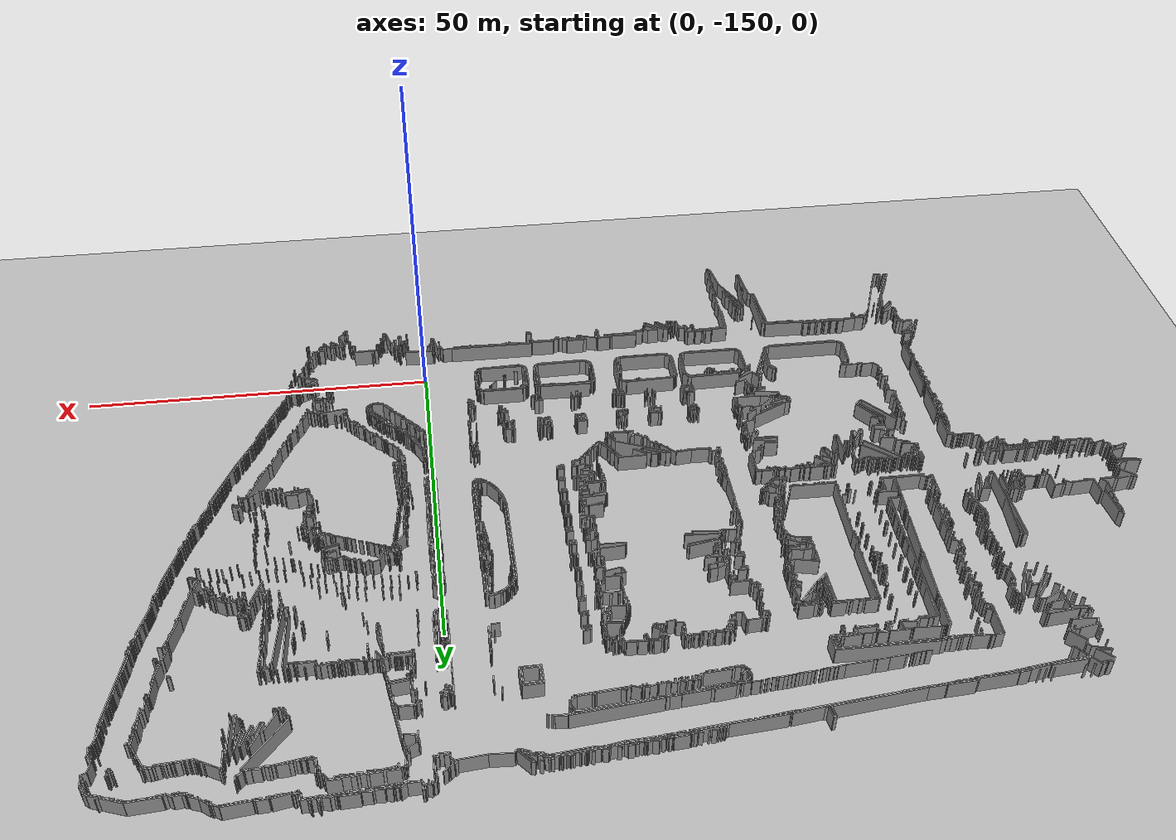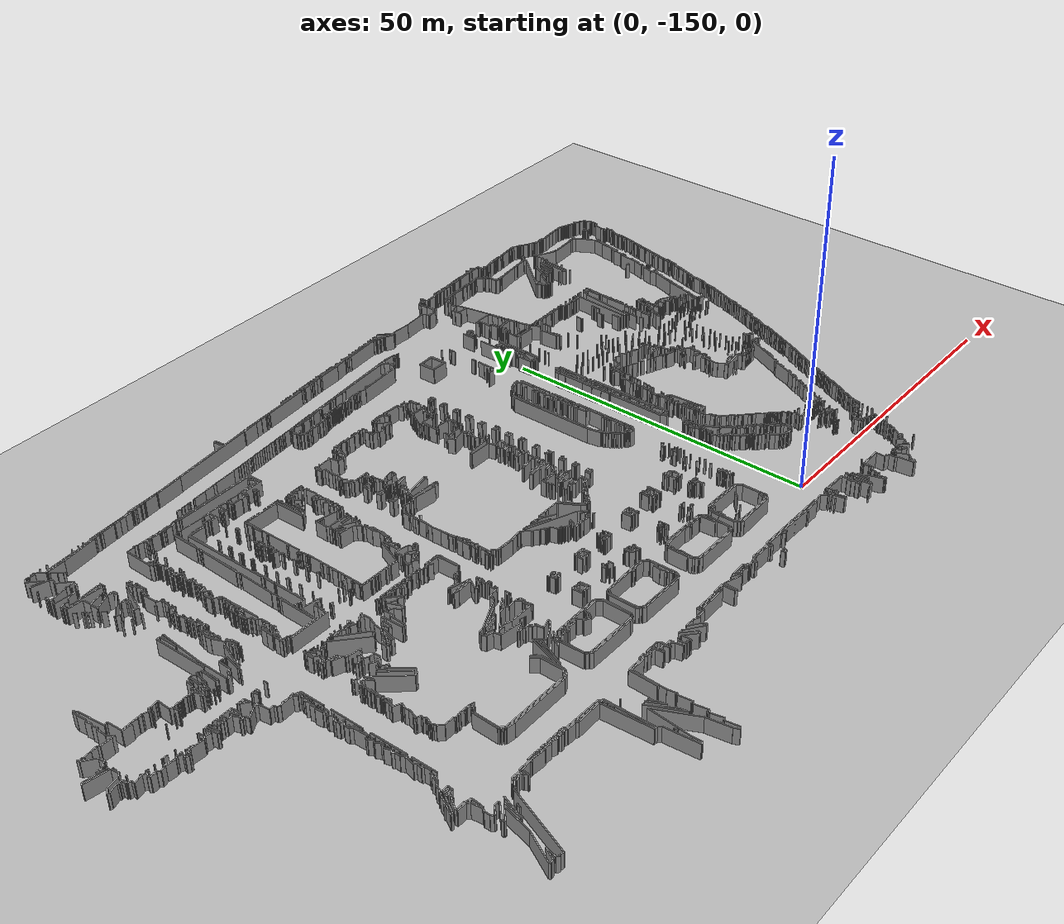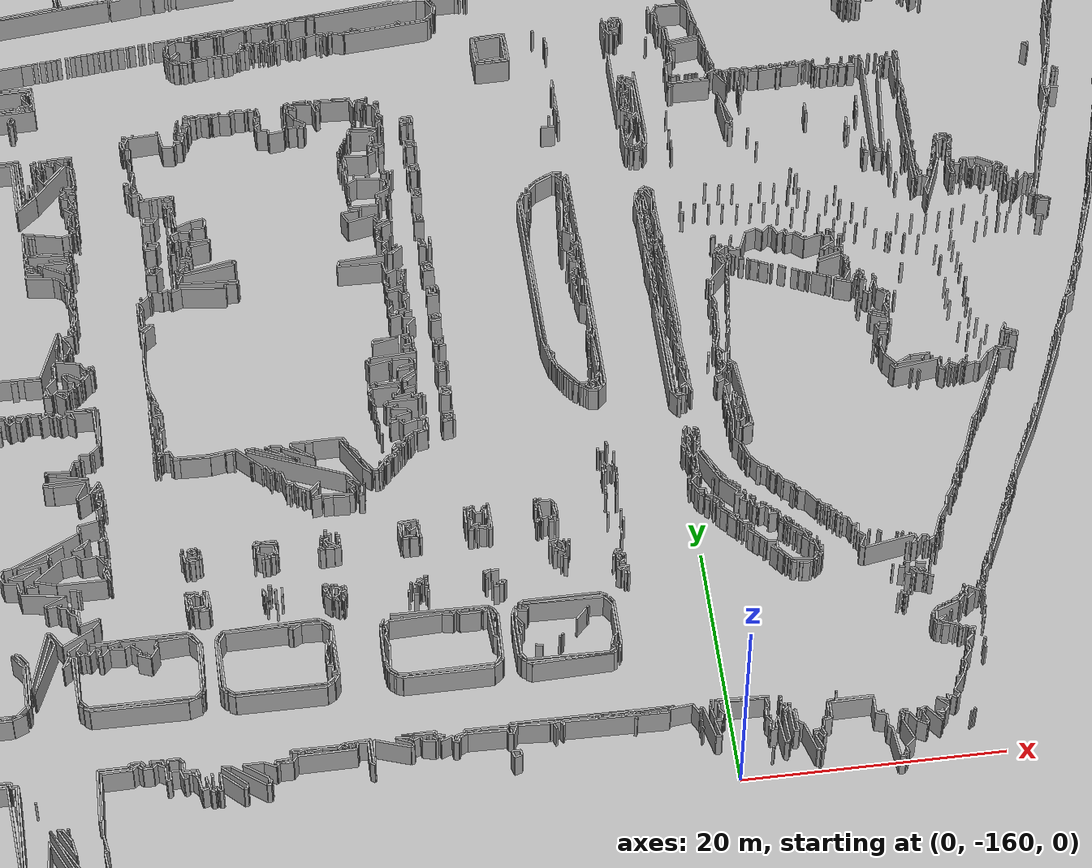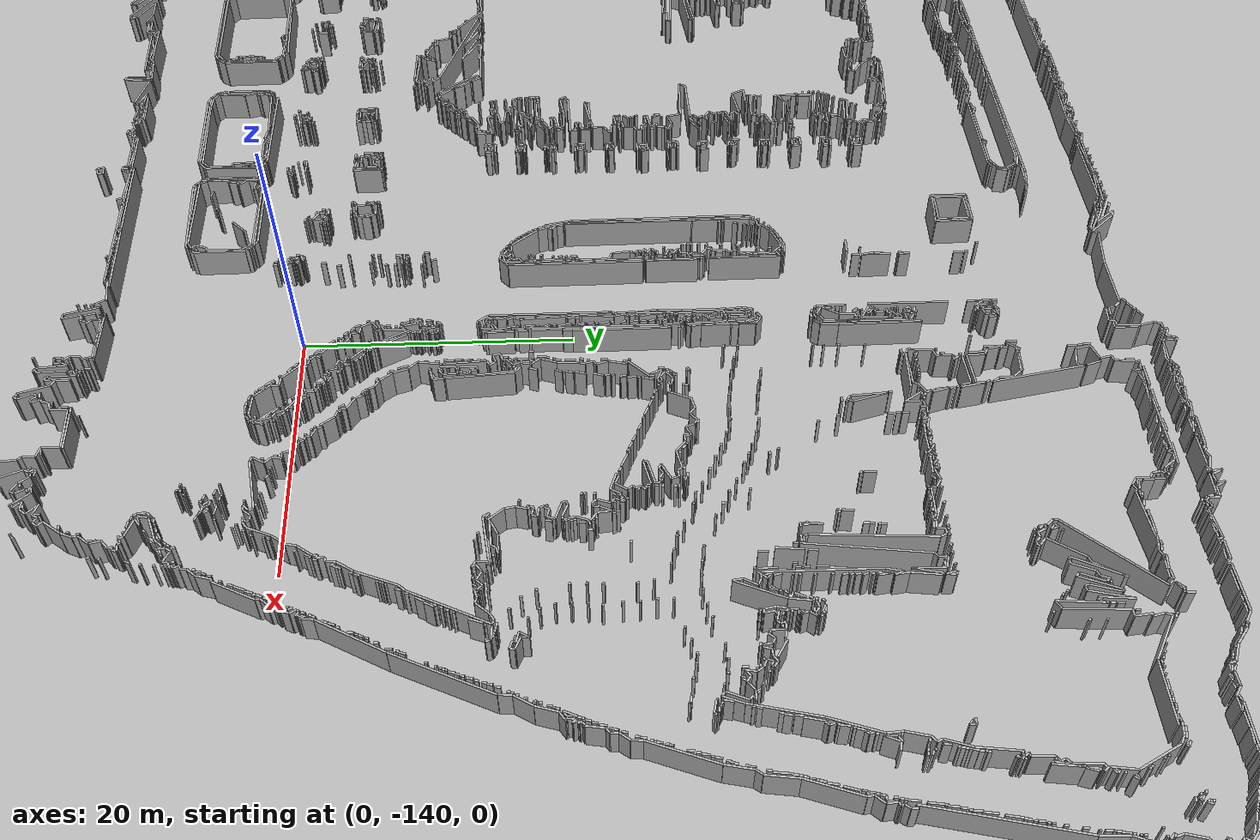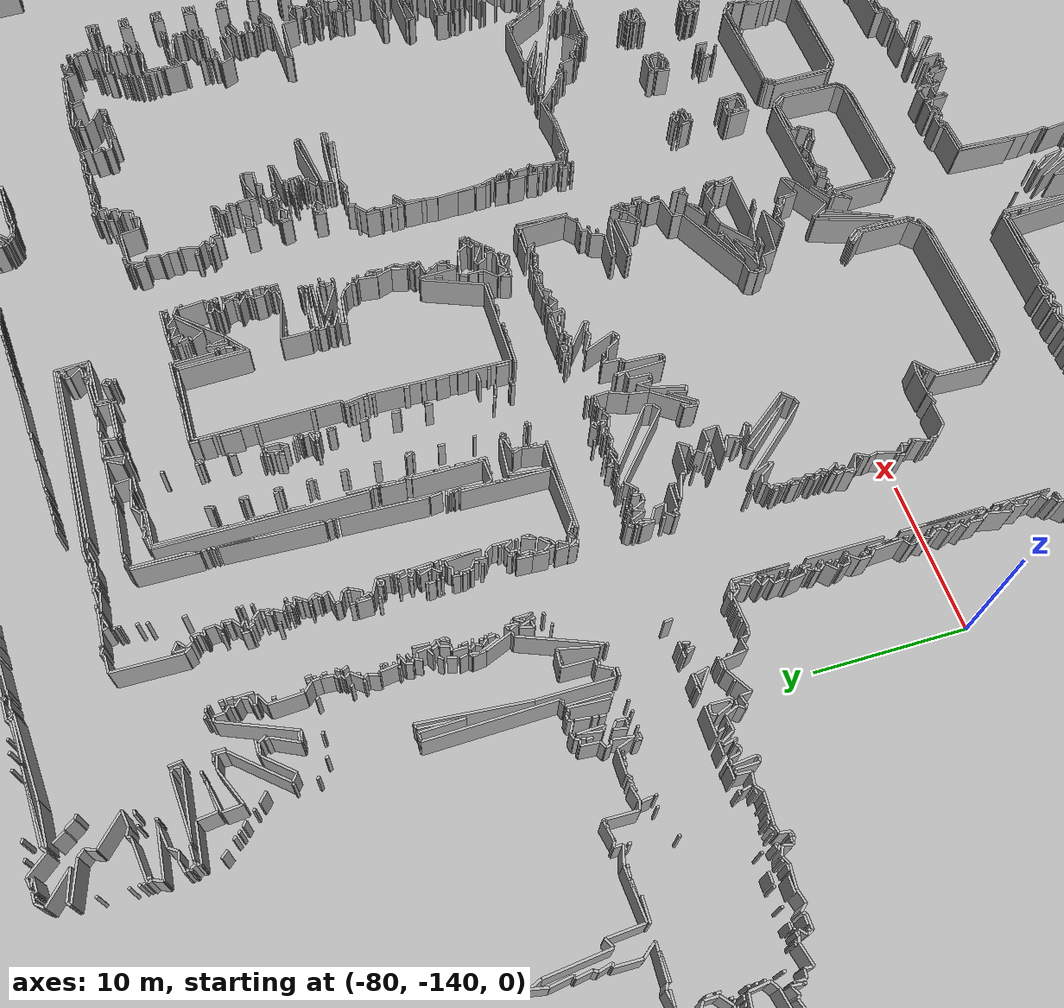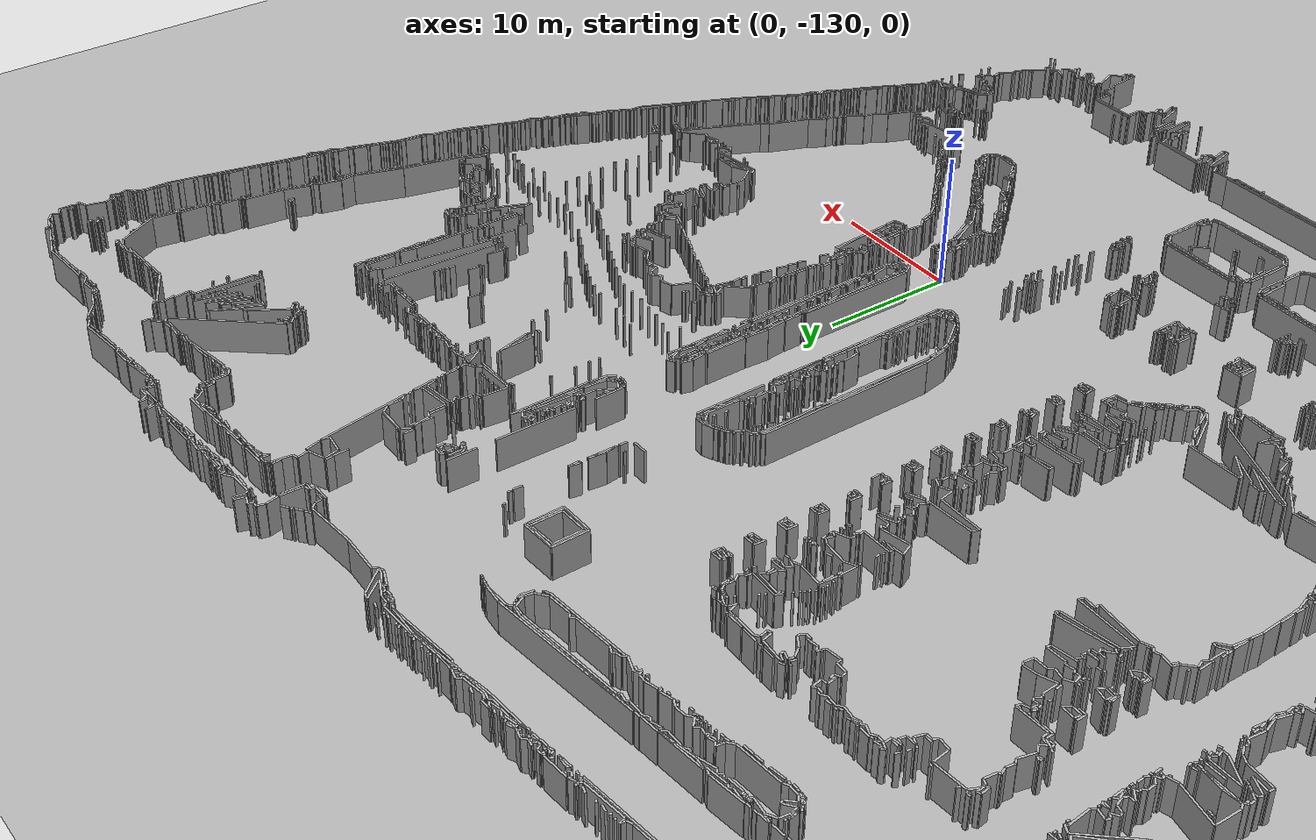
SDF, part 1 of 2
<sdf version="1.9">
 <world name="tsudanuma">
  <physics name="default_physics" type="ode">
   <max_step_size>0.004</max_step_size>
   <real_time_factor>1</real_time_factor>
   <real_time_update_rate>250</real_time_update_rate>
  </physics>
  <plugin filename="libignition-gazebo-physics-system.so" name="ignition::gazebo::systems::Physics"/>
  <plugin filename="libignition-gazebo-user-commands-system.so" name="ignition::gazebo::systems::UserCommands"/>
  <plugin filename="libignition-gazebo-scene-broadcaster-system.so" name="ignition::gazebo::systems::SceneBroadcaster"/>
  <plugin filename="libignition-gazebo-imu-system.so" name="ignition::gazebo::systems::Imu"/>
  <plugin filename="libignition-gazebo-navsat-system.so" name="ignition::gazebo::systems::NavSat"/>
  <light type="directional" name="sun">
   <cast_shadows>0</cast_shadows>
   <pose>0 0 10 0 0 0</pose>
   <diffuse>0.8 0.8 0.8 1</diffuse>
   <specular>0.2 0.2 0.2 1</specular>
   <attenuation>
    <range>1000</range>
    <constant>0.9</constant>
    <linear>0.01</linear>
    <quadratic>0.001</quadratic>
   </attenuation>
   <direction>-0.5 0.1 -0.9</direction>
  </light>
  <spherical_coordinates>
   <surface_model>EARTH_WGS84</surface_model>
   <latitude_deg>0</latitude_deg>
   <longitude_deg>0</longitude_deg>
   <elevation>0</elevation>
   <heading_deg>0</heading_deg>
  </spherical_coordinates>
  <model name="ground_plane">
   <static>true</static>
   <pose>-23.0 -110.125 0 0 0 0</pose>
   <link name="link">
    <collision name="collision">
     <geometry><plane><normal>0 0 1</normal><size>169.4 136.125</size></plane></geometry>
    </collision>
    <visual name="visual">
     <geometry><plane><normal>0 0 1</normal><size>169.4 136.125</size></plane></geometry>
     <material>
      <ambient>0.5 0.5 0.5 1</ambient>
      <diffuse>0.7 0.7 0.7 1</diffuse>
      <specular>0.1 0.1 0.1 1</specular>
     </material>
    </visual>
   </link>
  </model>
  <model name="tsudanuma_walls">
   <static>true</static>
   <link name="walls">
    <collision name="Wall_0_Collision">
     <pose>2.5250000000000057 -158.95 1.25 0 0 -0.5880026035475239</pose>
     <geometry><box><size>0.18027756377320103 0.15 2.5</size></box></geometry>
    </collision>
    <visual name="Wall_0_Visual">
     <pose>2.5250000000000057 -158.95 1.25 0 0 -0.5880026035475239</pose>
     <geometry><box><size>0.18027756377320103 0.15 2.5</size></box></geometry>
     <material>
      <ambient>0.5 0.5 0.5 1</ambient>
      <diffuse>0.7 0.7 0.7 1</diffuse>
      <specular>0.1 0.1 0.1 1</specular>
     </material>
    </visual>
    <collision name="Wall_1_Collision">
     <pose>17.60000000000001 -157.72500000000002 1.25 0 0 -0.9827937232473728</pose>
     <geometry><box><size>0.18027756377320103 0.15 2.5</size></box></geometry>
    </collision>
    <visual name="Wall_1_Visual">
     <pose>17.60000000000001 -157.72500000000002 1.25 0 0 -0.9827937232473728</pose>
     <geometry><box><size>0.18027756377320103 0.15 2.5</size></box></geometry>
     <material>
      <ambient>0.5 0.5 0.5 1</ambient>
      <diffuse>0.7 0.7 0.7 1</diffuse>
      <specular>0.1 0.1 0.1 1</specular>
     </material>
    </visual>
    <collision name="Wall_2_Collision">
     <pose>17.875000000000007 -157.52499999999998 1.25 0 0 -0.7853981633974957</pose>
     <geometry><box><size>0.21213203435596226 0.15 2.5</size></box></geometry>
    </collision>
    <visual name="Wall_2_Visual">
     <pose>17.875000000000007 -157.52499999999998 1.25 0 0 -0.7853981633974957</pose>
     <geometry><box><size>0.21213203435596226 0.15 2.5</size></box></geometry>
     <material>
      <ambient>0.5 0.5 0.5 1</ambient>
      <diffuse>0.7 0.7 0.7 1</diffuse>
      <specular>0.1 0.1 0.1 1</specular>
     </material>
    </visual>
    <collision name="Wall_3_Collision">
     <pose>-16.624999999999993 -157.175 1.25 0 0 -1.3045442776439777</pose>
     <geometry><box><size>0.5700877125495503 0.15 2.5</size></box></geometry>
    </collision>
    <visual name="Wall_3_Visual">
     <pose>-16.624999999999993 -157.175 1.25 0 0 -1.3045442776439777</pose>
     <geometry><box><size>0.5700877125495503 0.15 2.5</size></box></geometry>
     <material>
      <ambient>0.5 0.5 0.5 1</ambient>
      <diffuse>0.7 0.7 0.7 1</diffuse>
      <specular>0.1 0.1 0.1 1</specular>
     </material>
    </visual>
    <collision name="Wall_4_Collision">
     <pose>-16.275 -157.375 1.25 0 0 0.2662520491508882</pose>
     <geometry><box><size>0.5700877125495603 0.15 2.5</size></box></geometry>
    </collision>
    <visual name="Wall_4_Visual">
     <pose>-16.275 -157.375 1.25 0 0 0.2662520491508882</pose>
     <geometry><box><size>0.5700877125495603 0.15 2.5</size></box></geometry>
     <material>
      <ambient>0.5 0.5 0.5 1</ambient>
      <diffuse>0.7 0.7 0.7 1</diffuse>
      <specular>0.1 0.1 0.1 1</specular>
     </material>
    </visual>
    <collision name="Wall_5_Collision">
     <pose>-16.025 -157.10000000000002 1.25 0 0 1.6951513213416494</pose>
     <geometry><box><size>0.4031128874149328 0.15 2.5</size></box></geometry>
    </collision>
    <visual name="Wall_5_Visual">
     <pose>-16.025 -157.10000000000002 1.25 0 0 1.6951513213416494</pose>
     <geometry><box><size>0.4031128874149328 0.15 2.5</size></box></geometry>
     <material>
      <ambient>0.5 0.5 0.5 1</ambient>
      <diffuse>0.7 0.7 0.7 1</diffuse>
      <specular>0.1 0.1 0.1 1</specular>
     </material>
    </visual>
    <collision name="Wall_6_Collision">
     <pose>-16.374999999999993 -156.9 1.25 0 0 3.141592653589793</pose>
     <geometry><box><size>0.6499999999999915 0.15 2.5</size></box></geometry>
    </collision>
    <visual name="Wall_6_Visual">
     <pose>-16.374999999999993 -156.9 1.25 0 0 3.141592653589793</pose>
     <geometry><box><size>0.6499999999999915 0.15 2.5</size></box></geometry>
     <material>
      <ambient>0.5 0.5 0.5 1</ambient>
      <diffuse>0.7 0.7 0.7 1</diffuse>
      <specular>0.1 0.1 0.1 1</specular>
     </material>
    </visual>
    <collision name="Wall_7_Collision">
     <pose>-2.3999999999999915 -156.575 1.25 0 0 -0.9827937232473728</pose>
     <geometry><box><size>0.18027756377320103 0.15 2.5</size></box></geometry>
    </collision>
    <visual name="Wall_7_Visual">
     <pose>-2.3999999999999915 -156.575 1.25 0 0 -0.9827937232473728</pose>
     <geometry><box><size>0.18027756377320103 0.15 2.5</size></box></geometry>
     <material>
      <ambient>0.5 0.5 0.5 1</ambient>
      <diffuse>0.7 0.7 0.7 1</diffuse>
      <specular>0.1 0.1 0.1 1</specular>
     </material>
    </visual>
    <collision name="Wall_8_Collision">
     <pose>-2.3999999999999915 -156.02499999999998 1.25 0 0 -0.9827937232473728</pose>
     <geometry><box><size>0.18027756377320103 0.15 2.5</size></box></geometry>
    </collision>
    <visual name="Wall_8_Visual">
     <pose>-2.3999999999999915 -156.02499999999998 1.25 0 0 -0.9827937232473728</pose>
     <geometry><box><size>0.18027756377320103 0.15 2.5</size></box></geometry>
     <material>
      <ambient>0.5 0.5 0.5 1</ambient>
      <diffuse>0.7 0.7 0.7 1</diffuse>
      <specular>0.1 0.1 0.1 1</specular>
     </material>
    </visual>
    <collision name="Wall_9_Collision">
     <pose>-2.3999999999999915 -155.575 1.25 0 0 -0.9827937232473728</pose>
     <geometry><box><size>0.18027756377320103 0.15 2.5</size></box></geometry>
    </collision>
    <visual name="Wall_9_Visual">
     <pose>-2.3999999999999915 -155.575 1.25 0 0 -0.9827937232473728</pose>
     <geometry><box><size>0.18027756377320103 0.15 2.5</size></box></geometry>
     <material>
      <ambient>0.5 0.5 0.5 1</ambient>
      <diffuse>0.7 0.7 0.7 1</diffuse>
      <specular>0.1 0.1 0.1 1</specular>
     </material>
    </visual>
    <collision name="Wall_10_Collision">
     <pose>-7.199999999999996 -155.2 1.25 0 0 -0.46364760900077767</pose>
     <geometry><box><size>0.22360679774997896 0.15 2.5</size></box></geometry>
    </collision>
    <visual name="Wall_10_Visual">
     <pose>-7.199999999999996 -155.2 1.25 0 0 -0.46364760900077767</pose>
     <geometry><box><size>0.22360679774997896 0.15 2.5</size></box></geometry>
     <material>
      <ambient>0.5 0.5 0.5 1</ambient>
      <diffuse>0.7 0.7 0.7 1</diffuse>
      <specular>0.1 0.1 0.1 1</specular>
     </material>
    </visual>
    <collision name="Wall_11_Collision">
     <pose>-13.224999999999994 -155.2 1.25 0 0 -1.2120256565243166</pose>
     <geometry><box><size>0.4272001872658839 0.15 2.5</size></box></geometry>
    </collision>
    <visual name="Wall_11_Visual">
     <pose>-13.224999999999994 -155.2 1.25 0 0 -1.2120256565243166</pose>
     <geometry><box><size>0.4272001872658839 0.15 2.5</size></box></geometry>
     <material>
      <ambient>0.5 0.5 0.5 1</ambient>
      <diffuse>0.7 0.7 0.7 1</diffuse>
      <specular>0.1 0.1 0.1 1</specular>
     </material>
    </visual>
    <collision name="Wall_12_Collision">
     <pose>-44.699999999999996 -154.65 1.25 0 0 -1.5707963267948966</pose>
     <geometry><box><size>0.19999999999998863 0.15 2.5</size></box></geometry>
    </collision>
    <visual name="Wall_12_Visual">
     <pose>-44.699999999999996 -154.65 1.25 0 0 -1.5707963267948966</pose>
     <geometry><box><size>0.19999999999998863 0.15 2.5</size></box></geometry>
     <material>
      <ambient>0.5 0.5 0.5 1</ambient>
      <diffuse>0.7 0.7 0.7 1</diffuse>
      <specular>0.1 0.1 0.1 1</specular>
     </material>
    </visual>
    <collision name="Wall_13_Collision">
     <pose>-44.574999999999996 -154.75 1.25 0 0 0.0</pose>
     <geometry><box><size>0.25 0.15 2.5</size></box></geometry>
    </collision>
    <visual name="Wall_13_Visual">
     <pose>-44.574999999999996 -154.75 1.25 0 0 0.0</pose>
     <geometry><box><size>0.25 0.15 2.5</size></box></geometry>
     <material>
      <ambient>0.5 0.5 0.5 1</ambient>
      <diffuse>0.7 0.7 0.7 1</diffuse>
      <specular>0.1 0.1 0.1 1</specular>
     </material>
    </visual>
    <collision name="Wall_14_Collision">
     <pose>-44.574999999999996 -154.65 1.25 0 0 2.4668517113662682</pose>
     <geometry><box><size>0.32015621187163534 0.15 2.5</size></box></geometry>
    </collision>
    <visual name="Wall_14_Visual">
     <pose>-44.574999999999996 -154.65 1.25 0 0 2.4668517113662682</pose>
     <geometry><box><size>0.32015621187163534 0.15 2.5</size></box></geometry>
     <material>
      <ambient>0.5 0.5 0.5 1</ambient>
      <diffuse>0.7 0.7 0.7 1</diffuse>
      <specular>0.1 0.1 0.1 1</specular>
     </material>
    </visual>
    <collision name="Wall_15_Collision">
     <pose>19.60000000000001 -152.225 1.25 0 0 -1.1902899496825514</pose>
     <geometry><box><size>0.2692582403567231 0.15 2.5</size></box></geometry>
    </collision>
    <visual name="Wall_15_Visual">
     <pose>19.60000000000001 -152.225 1.25 0 0 -1.1902899496825514</pose>
     <geometry><box><size>0.2692582403567231 0.15 2.5</size></box></geometry>
     <material>
      <ambient>0.5 0.5 0.5 1</ambient>
      <diffuse>0.7 0.7 0.7 1</diffuse>
      <specular>0.1 0.1 0.1 1</specular>
     </material>
    </visual>
    <collision name="Wall_16_Collision">
     <pose>19.72500000000001 -151.47500000000002 1.25 0 0 -0.7853981633974483</pose>
     <geometry><box><size>0.2121320343559723 0.15 2.5</size></box></geometry>
    </collision>
    <visual name="Wall_16_Visual">
     <pose>19.72500000000001 -151.47500000000002 1.25 0 0 -0.7853981633974483</pose>
     <geometry><box><size>0.2121320343559723 0.15 2.5</size></box></geometry>
     <material>
      <ambient>0.5 0.5 0.5 1</ambient>
      <diffuse>0.7 0.7 0.7 1</diffuse>
      <specular>0.1 0.1 0.1 1</specular>
     </material>
    </visual>
    <collision name="Wall_17_Collision">
     <pose>20.025000000000006 -149.575 1.25 0 0 -1.9756881130799997</pose>
     <geometry><box><size>0.38078865529319245 0.15 2.5</size></box></geometry>
    </collision>
    <visual name="Wall_17_Visual">
     <pose>20.025000000000006 -149.575 1.25 0 0 -1.9756881130799997</pose>
     <geometry><box><size>0.38078865529319245 0.15 2.5</size></box></geometry>
     <material>
      <ambient>0.5 0.5 0.5 1</ambient>
      <diffuse>0.7 0.7 0.7 1</diffuse>
      <specular>0.1 0.1 0.1 1</specular>
     </material>
    </visual>
    <collision name="Wall_18_Collision">
     <pose>17.625000000000007 -148.8 1.25 0 0 -2.214297435588113</pose>
     <geometry><box><size>0.25000000000000855 0.15 2.5</size></box></geometry>
    </collision>
    <visual name="Wall_18_Visual">
     <pose>17.625000000000007 -148.8 1.25 0 0 -2.214297435588113</pose>
     <geometry><box><size>0.25000000000000855 0.15 2.5</size></box></geometry>
     <material>
      <ambient>0.5 0.5 0.5 1</ambient>
      <diffuse>0.7 0.7 0.7 1</diffuse>
      <specular>0.1 0.1 0.1 1</specular>
     </material>
    </visual>
    <collision name="Wall_19_Collision">
     <pose>20.22500000000001 -148.7 1.25 0 0 -0.5880026035475239</pose>
     <geometry><box><size>0.18027756377320103 0.15 2.5</size></box></geometry>
    </collision>
    <visual name="Wall_19_Visual">
     <pose>20.22500000000001 -148.7 1.25 0 0 -0.5880026035475239</pose>
     <geometry><box><size>0.18027756377320103 0.15 2.5</size></box></geometry>
     <material>
      <ambient>0.5 0.5 0.5 1</ambient>
      <diffuse>0.7 0.7 0.7 1</diffuse>
      <specular>0.1 0.1 0.1 1</specular>
     </material>
    </visual>
    <collision name="Wall_20_Collision">
     <pose>18.500000000000007 -148.22500000000002 1.25 0 0 -2.4980915447964973</pose>
     <geometry><box><size>0.25000000000000566 0.15 2.5</size></box></geometry>
    </collision>
    <visual name="Wall_20_Visual">
     <pose>18.500000000000007 -148.22500000000002 1.25 0 0 -2.4980915447964973</pose>
     <geometry><box><size>0.25000000000000566 0.15 2.5</size></box></geometry>
     <material>
      <ambient>0.5 0.5 0.5 1</ambient>
      <diffuse>0.7 0.7 0.7 1</diffuse>
      <specular>0.1 0.1 0.1 1</specular>
     </material>
    </visual>
    <collision name="Wall_21_Collision">
     <pose>-13.524999999999999 -147.97500000000002 1.25 0 0 -0.2662520491509363</pose>
     <geometry><box><size>0.5700877125495677 0.15 2.5</size></box></geometry>
    </collision>
    <visual name="Wall_21_Visual">
     <pose>-13.524999999999999 -147.97500000000002 1.25 0 0 -0.2662520491509363</pose>
     <geometry><box><size>0.5700877125495677 0.15 2.5</size></box></geometry>
     <material>
      <ambient>0.5 0.5 0.5 1</ambient>
      <diffuse>0.7 0.7 0.7 1</diffuse>
      <specular>0.1 0.1 0.1 1</specular>
     </material>
    </visual>
    <collision name="Wall_22_Collision">
     <pose>20.35000000000001 -147.77499999999998 1.25 0 0 -0.9827937232473728</pose>
     <geometry><box><size>0.18027756377320103 0.15 2.5</size></box></geometry>
    </collision>
    <visual name="Wall_22_Visual">
     <pose>20.35000000000001 -147.77499999999998 1.25 0 0 -0.9827937232473728</pose>
     <geometry><box><size>0.18027756377320103 0.15 2.5</size></box></geometry>
     <material>
      <ambient>0.5 0.5 0.5 1</ambient>
      <diffuse>0.7 0.7 0.7 1</diffuse>
      <specular>0.1 0.1 0.1 1</specular>
     </material>
    </visual>
    <collision name="Wall_23_Collision">
     <pose>-11.874999999999993 -147.39999999999998 1.25 0 0 -0.5880026035475675</pose>
     <geometry><box><size>0.1802775637731892 0.15 2.5</size></box></geometry>
    </collision>
    <visual name="Wall_23_Visual">
     <pose>-11.874999999999993 -147.39999999999998 1.25 0 0 -0.5880026035475675</pose>
     <geometry><box><size>0.1802775637731892 0.15 2.5</size></box></geometry>
     <material>
      <ambient>0.5 0.5 0.5 1</ambient>
      <diffuse>0.7 0.7 0.7 1</diffuse>
      <specular>0.1 0.1 0.1 1</specular>
     </material>
    </visual>
    <collision name="Wall_24_Collision">
     <pose>20.400000000000006 -147.22500000000002 1.25 0 0 -0.9827937232473728</pose>
     <geometry><box><size>0.18027756377320103 0.15 2.5</size></box></geometry>
    </collision>
    <visual name="Wall_24_Visual">
     <pose>20.400000000000006 -147.22500000000002 1.25 0 0 -0.9827937232473728</pose>
     <geometry><box><size>0.18027756377320103 0.15 2.5</size></box></geometry>
     <material>
      <ambient>0.5 0.5 0.5 1</ambient>
      <diffuse>0.7 0.7 0.7 1</diffuse>
      <specular>0.1 0.1 0.1 1</specular>
     </material>
    </visual>
    <collision name="Wall_25_Collision">
     <pose>-11.649999999999991 -147.22500000000002 1.25 0 0 -0.9827937232473728</pose>
     <geometry><box><size>0.18027756377320103 0.15 2.5</size></box></geometry>
    </collision>
    <visual name="Wall_25_Visual">
     <pose>-11.649999999999991 -147.22500000000002 1.25 0 0 -0.9827937232473728</pose>
     <geometry><box><size>0.18027756377320103 0.15 2.5</size></box></geometry>
     <material>
      <ambient>0.5 0.5 0.5 1</ambient>
      <diffuse>0.7 0.7 0.7 1</diffuse>
      <specular>0.1 0.1 0.1 1</specular>
     </material>
    </visual>
    <collision name="Wall_26_Collision">
     <pose>20.47500000000001 -146.95 1.25 0 0 -0.5880026035475239</pose>
     <geometry><box><size>0.18027756377320103 0.15 2.5</size></box></geometry>
    </collision>
    <visual name="Wall_26_Visual">
     <pose>20.47500000000001 -146.95 1.25 0 0 -0.5880026035475239</pose>
     <geometry><box><size>0.18027756377320103 0.15 2.5</size></box></geometry>
     <material>
      <ambient>0.5 0.5 0.5 1</ambient>
      <diffuse>0.7 0.7 0.7 1</diffuse>
      <specular>0.1 0.1 0.1 1</specular>
     </material>
    </visual>
    <collision name="Wall_27_Collision">
     <pose>-10.024999999999991 -145.60000000000002 1.25 0 0 -2.3276308323535786</pose>
     <geometry><box><size>1.237941840313995 0.15 2.5</size></box></geometry>
    </collision>
    <visual name="Wall_27_Visual">
     <pose>-10.024999999999991 -145.60000000000002 1.25 0 0 -2.3276308323535786</pose>
     <geometry><box><size>1.237941840313995 0.15 2.5</size></box></geometry>
     <material>
      <ambient>0.5 0.5 0.5 1</ambient>
      <diffuse>0.7 0.7 0.7 1</diffuse>
      <specular>0.1 0.1 0.1 1</specular>
     </material>
    </visual>
    <collision name="Wall_28_Collision">
     <pose>-9.449999999999996 -145.02499999999998 1.25 0 0 -0.9827937232473072</pose>
     <geometry><box><size>0.18027756377320892 0.15 2.5</size></box></geometry>
    </collision>
    <visual name="Wall_28_Visual">
     <pose>-9.449999999999996 -145.02499999999998 1.25 0 0 -0.9827937232473072</pose>
     <geometry><box><size>0.18027756377320892 0.15 2.5</size></box></geometry>
     <material>
      <ambient>0.5 0.5 0.5 1</ambient>
      <diffuse>0.7 0.7 0.7 1</diffuse>
      <specular>0.1 0.1 0.1 1</specular>
     </material>
    </visual>
    <collision name="Wall_29_Collision">
     <pose>-28.9 -145.225 1.25 0 0 -1.6756732655251407</pose>
     <geometry><box><size>0.9552486587271296 0.15 2.5</size></box></geometry>
    </collision>
    <visual name="Wall_29_Visual">
     <pose>-28.9 -145.225 1.25 0 0 -1.6756732655251407</pose>
     <geometry><box><size>0.9552486587271296 0.15 2.5</size></box></geometry>
     <material>
      <ambient>0.5 0.5 0.5 1</ambient>
      <diffuse>0.7 0.7 0.7 1</diffuse>
      <specular>0.1 0.1 0.1 1</specular>
     </material>
    </visual>
    <collision name="Wall_30_Collision">
     <pose>-29.049999999999997 -145.89999999999998 1.25 0 0 -2.0344439357956743</pose>
     <geometry><box><size>0.4472135954999579 0.15 2.5</size></box></geometry>
    </collision>
    <visual name="Wall_30_Visual">
     <pose>-29.049999999999997 -145.89999999999998 1.25 0 0 -2.0344439357956743</pose>
     <geometry><box><size>0.4472135954999579 0.15 2.5</size></box></geometry>
     <material>
      <ambient>0.5 0.5 0.5 1</ambient>
      <diffuse>0.7 0.7 0.7 1</diffuse>
      <specular>0.1 0.1 0.1 1</specular>
     </material>
    </visual>
    <collision name="Wall_31_Collision">
     <pose>-29.199999999999996 -145.8 1.25 0 0 1.7359450042095388</pose>
     <geometry><box><size>0.6082762530298178 0.15 2.5</size></box></geometry>
    </collision>
    <visual name="Wall_31_Visual">
     <pose>-29.199999999999996 -145.8 1.25 0 0 1.7359450042095388</pose>
     <geometry><box><size>0.6082762530298178 0.15 2.5</size></box></geometry>
     <material>
      <ambient>0.5 0.5 0.5 1</ambient>
      <diffuse>0.7 0.7 0.7 1</diffuse>
      <specular>0.1 0.1 0.1 1</specular>
     </material>
    </visual>
    <collision name="Wall_32_Collision">
     <pose>-29.35 -146.1 1.25 0 0 -1.7359450042095272</pose>
     <geometry><box><size>1.2165525060596332 0.15 2.5</size></box></geometry>
    </collision>
    <visual name="Wall_32_Visual">
     <pose>-29.35 -146.1 1.25 0 0 -1.7359450042095272</pose>
     <geometry><box><size>1.2165525060596332 0.15 2.5</size></box></geometry>
     <material>
      <ambient>0.5 0.5 0.5 1</ambient>
      <diffuse>0.7 0.7 0.7 1</diffuse>
      <specular>0.1 0.1 0.1 1</specular>
     </material>
    </visual>
    <collision name="Wall_33_Collision">
     <pose>-29.375 -147.02499999999998 1.25 0 0 -1.3439974787410043</pose>
     <geometry><box><size>0.6670832032063235 0.15 2.5</size></box></geometry>
    </collision>
    <visual name="Wall_33_Visual">
     <pose>-29.375 -147.02499999999998 1.25 0 0 -1.3439974787410043</pose>
     <geometry><box><size>0.6670832032063235 0.15 2.5</size></box></geometry>
     <material>
      <ambient>0.5 0.5 0.5 1</ambient>
      <diffuse>0.7 0.7 0.7 1</diffuse>
      <specular>0.1 0.1 0.1 1</specular>
     </material>
    </visual>
    <collision name="Wall_34_Collision">
     <pose>-29.375 -147.55 1.25 0 0 -1.9295669970654765</pose>
     <geometry><box><size>0.4272001872658839 0.15 2.5</size></box></geometry>
    </collision>
    <visual name="Wall_34_Visual">
     <pose>-29.375 -147.55 1.25 0 0 -1.9295669970654765</pose>
     <geometry><box><size>0.4272001872658839 0.15 2.5</size></box></geometry>
     <material>
      <ambient>0.5 0.5 0.5 1</ambient>
      <diffuse>0.7 0.7 0.7 1</diffuse>
      <specular>0.1 0.1 0.1 1</specular>
     </material>
    </visual>
    <collision name="Wall_35_Collision">
     <pose>-29.225 -147.8 1.25 0 0 -0.2186689458739286</pose>
     <geometry><box><size>0.46097722286464593 0.15 2.5</size></box></geometry>
    </collision>
    <visual name="Wall_35_Visual">
     <pose>-29.225 -147.8 1.25 0 0 -0.2186689458739286</pose>
     <geometry><box><size>0.46097722286464593 0.15 2.5</size></box></geometry>
     <material>
      <ambient>0.5 0.5 0.5 1</ambient>
      <diffuse>0.7 0.7 0.7 1</diffuse>
      <specular>0.1 0.1 0.1 1</specular>
     </material>
    </visual>
    <collision name="Wall_36_Collision">
     <pose>-29.074999999999996 -148.14999999999998 1.25 0 0 -1.8157749899217497</pose>
     <geometry><box><size>0.6184658438426415 0.15 2.5</size></box></geometry>
    </collision>
    <visual name="Wall_36_Visual">
     <pose>-29.074999999999996 -148.14999999999998 1.25 0 0 -1.8157749899217497</pose>
     <geometry><box><size>0.6184658438426415 0.15 2.5</size></box></geometry>
     <material>
      <ambient>0.5 0.5 0.5 1</ambient>
      <diffuse>0.7 0.7 0.7 1</diffuse>
      <specular>0.1 0.1 0.1 1</specular>
     </material>
    </visual>
    <collision name="Wall_37_Collision">
     <pose>-28.949999999999996 -148.39999999999998 1.25 0 0 0.2449786631268558</pose>
     <geometry><box><size>0.4123105625617564 0.15 2.5</size></box></geometry>
    </collision>
    <visual name="Wall_37_Visual">
     <pose>-28.949999999999996 -148.39999999999998 1.25 0 0 0.2449786631268558</pose>
     <geometry><box><size>0.4123105625617564 0.15 2.5</size></box></geometry>
     <material>
      <ambient>0.5 0.5 0.5 1</ambient>
      <diffuse>0.7 0.7 0.7 1</diffuse>
      <specular>0.1 0.1 0.1 1</specular>
     </material>
    </visual>
    <collision name="Wall_38_Collision">
     <pose>-28.799999999999997 -146.55 1.25 0 0 1.5985669633883162</pose>
     <geometry><box><size>3.6013886210738155 0.15 2.5</size></box></geometry>
    </collision>
    <visual name="Wall_38_Visual">
     <pose>-28.799999999999997 -146.55 1.25 0 0 1.5985669633883162</pose>
     <geometry><box><size>3.6013886210738155 0.15 2.5</size></box></geometry>
     <material>
      <ambient>0.5 0.5 0.5 1</ambient>
      <diffuse>0.7 0.7 0.7 1</diffuse>
      <specular>0.1 0.1 0.1 1</specular>
     </material>
    </visual>
    <collision name="Wall_39_Collision">
     <pose>15.750000000000007 -141.52499999999998 1.25 0 0 -0.9827937232473072</pose>
     <geometry><box><size>0.18027756377320892 0.15 2.5</size></box></geometry>
    </collision>
    <visual name="Wall_39_Visual">
     <pose>15.750000000000007 -141.52499999999998 1.25 0 0 -0.9827937232473072</pose>
     <geometry><box><size>0.18027756377320892 0.15 2.5</size></box></geometry>
     <material>
      <ambient>0.5 0.5 0.5 1</ambient>
      <diffuse>0.7 0.7 0.7 1</diffuse>
      <specular>0.1 0.1 0.1 1</specular>
     </material>
    </visual>
    <collision name="Wall_40_Collision">
     <pose>8.250000000000007 -141.475 1.25 0 0 -0.6947382761967078</pose>
     <geometry><box><size>0.39051248379533055 0.15 2.5</size></box></geometry>
    </collision>
    <visual name="Wall_40_Visual">
     <pose>8.250000000000007 -141.475 1.25 0 0 -0.6947382761967078</pose>
     <geometry><box><size>0.39051248379533055 0.15 2.5</size></box></geometry>
     <material>
      <ambient>0.5 0.5 0.5 1</ambient>
      <diffuse>0.7 0.7 0.7 1</diffuse>
      <specular>0.1 0.1 0.1 1</specular>
     </material>
    </visual>
    <collision name="Wall_41_Collision">
     <pose>15.200000000000003 -141.375 1.25 0 0 -0.9827937232472853</pose>
     <geometry><box><size>0.18027756377317739 0.15 2.5</size></box></geometry>
    </collision>
    <visual name="Wall_41_Visual">
     <pose>15.200000000000003 -141.375 1.25 0 0 -0.9827937232472853</pose>
     <geometry><box><size>0.18027756377317739 0.15 2.5</size></box></geometry>
     <material>
      <ambient>0.5 0.5 0.5 1</ambient>
      <diffuse>0.7 0.7 0.7 1</diffuse>
      <specular>0.1 0.1 0.1 1</specular>
     </material>
    </visual>
    <collision name="Wall_42_Collision">
     <pose>14.800000000000004 -141.325 1.25 0 0 -0.9827937232473072</pose>
     <geometry><box><size>0.18027756377320892 0.15 2.5</size></box></geometry>
    </collision>
    <visual name="Wall_42_Visual">
     <pose>14.800000000000004 -141.325 1.25 0 0 -0.9827937232473072</pose>
     <geometry><box><size>0.18027756377320892 0.15 2.5</size></box></geometry>
     <material>
      <ambient>0.5 0.5 0.5 1</ambient>
      <diffuse>0.7 0.7 0.7 1</diffuse>
      <specular>0.1 0.1 0.1 1</specular>
     </material>
    </visual>
    <collision name="Wall_43_Collision">
     <pose>13.475000000000009 -141.025 1.25 0 0 -0.7853981633974483</pose>
     <geometry><box><size>0.3535533905932738 0.15 2.5</size></box></geometry>
    </collision>
    <visual name="Wall_43_Visual">
     <pose>13.475000000000009 -141.025 1.25 0 0 -0.7853981633974483</pose>
     <geometry><box><size>0.3535533905932738 0.15 2.5</size></box></geometry>
     <material>
      <ambient>0.5 0.5 0.5 1</ambient>
      <diffuse>0.7 0.7 0.7 1</diffuse>
      <specular>0.1 0.1 0.1 1</specular>
     </material>
    </visual>
    <collision name="Wall_44_Collision">
     <pose>12.725000000000009 -140.85000000000002 1.25 0 0 -0.5880026035475239</pose>
     <geometry><box><size>0.18027756377320103 0.15 2.5</size></box></geometry>
    </collision>
    <visual name="Wall_44_Visual">
     <pose>12.725000000000009 -140.85000000000002 1.25 0 0 -0.5880026035475239</pose>
     <geometry><box><size>0.18027756377320103 0.15 2.5</size></box></geometry>
     <material>
      <ambient>0.5 0.5 0.5 1</ambient>
      <diffuse>0.7 0.7 0.7 1</diffuse>
      <specular>0.1 0.1 0.1 1</specular>
     </material>
    </visual>
    <collision name="Wall_45_Collision">
     <pose>7.82500000000001 -141.025 1.25 0 0 -0.7853981633974325</pose>
     <geometry><box><size>0.6363961030678867 0.15 2.5</size></box></geometry>
    </collision>
    <visual name="Wall_45_Visual">
     <pose>7.82500000000001 -141.025 1.25 0 0 -0.7853981633974325</pose>
     <geometry><box><size>0.6363961030678867 0.15 2.5</size></box></geometry>
     <material>
      <ambient>0.5 0.5 0.5 1</ambient>
      <diffuse>0.7 0.7 0.7 1</diffuse>
      <specular>0.1 0.1 0.1 1</specular>
     </material>
    </visual>
    <collision name="Wall_46_Collision">
     <pose>7.425000000000011 -140.6 1.25 0 0 -0.674740942223525</pose>
     <geometry><box><size>0.32015621187163534 0.15 2.5</size></box></geometry>
    </collision>
    <visual name="Wall_46_Visual">
     <pose>7.425000000000011 -140.6 1.25 0 0 -0.674740942223525</pose>
     <geometry><box><size>0.32015621187163534 0.15 2.5</size></box></geometry>
     <material>
      <ambient>0.5 0.5 0.5 1</ambient>
      <diffuse>0.7 0.7 0.7 1</diffuse>
      <specular>0.1 0.1 0.1 1</specular>
     </material>
    </visual>
    <collision name="Wall_47_Collision">
     <pose>7.075000000000003 -140.3 1.25 0 0 -0.5880026035475239</pose>
     <geometry><box><size>0.18027756377320103 0.15 2.5</size></box></geometry>
    </collision>
    <visual name="Wall_47_Visual">
     <pose>7.075000000000003 -140.3 1.25 0 0 -0.5880026035475239</pose>
     <geometry><box><size>0.18027756377320103 0.15 2.5</size></box></geometry>
     <material>
      <ambient>0.5 0.5 0.5 1</ambient>
      <diffuse>0.7 0.7 0.7 1</diffuse>
      <specular>0.1 0.1 0.1 1</specular>
     </material>
    </visual>
    <collision name="Wall_48_Collision">
     <pose>6.7250000000000085 -139.85000000000002 1.25 0 0 -0.5880026035475239</pose>
     <geometry><box><size>0.18027756377320103 0.15 2.5</size></box></geometry>
    </collision>
    <visual name="Wall_48_Visual">
     <pose>6.7250000000000085 -139.85000000000002 1.25 0 0 -0.5880026035475239</pose>
     <geometry><box><size>0.18027756377320103 0.15 2.5</size></box></geometry>
     <material>
      <ambient>0.5 0.5 0.5 1</ambient>
      <diffuse>0.7 0.7 0.7 1</diffuse>
      <specular>0.1 0.1 0.1 1</specular>
     </material>
    </visual>
    <collision name="Wall_49_Collision">
     <pose>6.500000000000007 -139.625 1.25 0 0 -0.9827937232472198</pose>
     <geometry><box><size>0.18027756377318527 0.15 2.5</size></box></geometry>
    </collision>
    <visual name="Wall_49_Visual">
     <pose>6.500000000000007 -139.625 1.25 0 0 -0.9827937232472198</pose>
     <geometry><box><size>0.18027756377318527 0.15 2.5</size></box></geometry>
     <material>
      <ambient>0.5 0.5 0.5 1</ambient>
      <diffuse>0.7 0.7 0.7 1</diffuse>
      <specular>0.1 0.1 0.1 1</specular>
     </material>
    </visual>
    <collision name="Wall_50_Collision">
     <pose>6.20000000000001 -139.325 1.25 0 0 -0.6947382761967078</pose>
     <geometry><box><size>0.39051248379533055 0.15 2.5</size></box></geometry>
    </collision>
    <visual name="Wall_50_Visual">
     <pose>6.20000000000001 -139.325 1.25 0 0 -0.6947382761967078</pose>
     <geometry><box><size>0.39051248379533055 0.15 2.5</size></box></geometry>
     <material>
      <ambient>0.5 0.5 0.5 1</ambient>
      <diffuse>0.7 0.7 0.7 1</diffuse>
      <specular>0.1 0.1 0.1 1</specular>
     </material>
    </visual>
    <collision name="Wall_51_Collision">
     <pose>1.625000000000007 -134.75 1.25 0 0 -0.5880026035476987</pose>
     <geometry><box><size>0.18027756377320497 0.15 2.5</size></box></geometry>
    </collision>
    <visual name="Wall_51_Visual">
     <pose>1.625000000000007 -134.75 1.25 0 0 -0.5880026035476987</pose>
     <geometry><box><size>0.18027756377320497 0.15 2.5</size></box></geometry>
     <material>
      <ambient>0.5 0.5 0.5 1</ambient>
      <diffuse>0.7 0.7 0.7 1</diffuse>
      <specular>0.1 0.1 0.1 1</specular>
     </material>
    </visual>
    <collision name="Wall_52_Collision">
     <pose>-45.27499999999999 -131.2 1.25 0 0 -0.9272952180016577</pose>
     <geometry><box><size>0.25000000000001277 0.15 2.5</size></box></geometry>
    </collision>
    <visual name="Wall_52_Visual">
     <pose>-45.27499999999999 -131.2 1.25 0 0 -0.9272952180016577</pose>
     <geometry><box><size>0.25000000000001277 0.15 2.5</size></box></geometry>
     <material>
      <ambient>0.5 0.5 0.5 1</ambient>
      <diffuse>0.7 0.7 0.7 1</diffuse>
      <specular>0.1 0.1 0.1 1</specular>
     </material>
    </visual>
    <collision name="Wall_53_Collision">
     <pose>4.45000000000001 -130.25 1.25 0 0 -0.46364760900089136</pose>
     <geometry><box><size>0.22360679774999168 0.15 2.5</size></box></geometry>
    </collision>
    <visual name="Wall_53_Visual">
     <pose>4.45000000000001 -130.25 1.25 0 0 -0.46364760900089136</pose>
     <geometry><box><size>0.22360679774999168 0.15 2.5</size></box></geometry>
     <material>
      <ambient>0.5 0.5 0.5 1</ambient>
      <diffuse>0.7 0.7 0.7 1</diffuse>
      <specular>0.1 0.1 0.1 1</specular>
     </material>
    </visual>
    <collision name="Wall_54_Collision">
     <pose>-23.549999999999997 -129.97500000000002 1.25 0 0 -0.9827937232473728</pose>
     <geometry><box><size>0.18027756377320103 0.15 2.5</size></box></geometry>
    </collision>
    <visual name="Wall_54_Visual">
     <pose>-23.549999999999997 -129.97500000000002 1.25 0 0 -0.9827937232473728</pose>
     <geometry><box><size>0.18027756377320103 0.15 2.5</size></box></geometry>
     <material>
      <ambient>0.5 0.5 0.5 1</ambient>
      <diffuse>0.7 0.7 0.7 1</diffuse>
      <specular>0.1 0.1 0.1 1</specular>
     </material>
    </visual>
    <collision name="Wall_55_Collision">
     <pose>5.300000000000004 -129.52499999999998 1.25 0 0 -1.7234456551901733</pose>
     <geometry><box><size>0.6576473218983022 0.15 2.5</size></box></geometry>
    </collision>
    <visual name="Wall_55_Visual">
     <pose>5.300000000000004 -129.52499999999998 1.25 0 0 -1.7234456551901733</pose>
     <geometry><box><size>0.6576473218983022 0.15 2.5</size></box></geometry>
     <material>
      <ambient>0.5 0.5 0.5 1</ambient>
      <diffuse>0.7 0.7 0.7 1</diffuse>
      <specular>0.1 0.1 0.1 1</specular>
     </material>
    </visual>
    <collision name="Wall_56_Collision">
     <pose>4.950000000000003 -130.02499999999998 1.25 0 0 -2.6135182051634365</pose>
     <geometry><box><size>0.6946221994724825 0.15 2.5</size></box></geometry>
    </collision>
    <visual name="Wall_56_Visual">
     <pose>4.950000000000003 -130.02499999999998 1.25 0 0 -2.6135182051634365</pose>
     <geometry><box><size>0.6946221994724825 0.15 2.5</size></box></geometry>
     <material>
      <ambient>0.5 0.5 0.5 1</ambient>
      <diffuse>0.7 0.7 0.7 1</diffuse>
      <specular>0.1 0.1 0.1 1</specular>
     </material>
    </visual>
    <collision name="Wall_57_Collision">
     <pose>5.025000000000006 -130.1 1.25 0 0 0.26060239174732686</pose>
     <geometry><box><size>0.7762087348129982 0.15 2.5</size></box></geometry>
    </collision>
    <visual name="Wall_57_Visual">
     <pose>5.025000000000006 -130.1 1.25 0 0 0.26060239174732686</pose>
     <geometry><box><size>0.7762087348129982 0.15 2.5</size></box></geometry>
     <material>
      <ambient>0.5 0.5 0.5 1</ambient>
      <diffuse>0.7 0.7 0.7 1</diffuse>
      <specular>0.1 0.1 0.1 1</specular>
     </material>
    </visual>
    <collision name="Wall_58_Collision">
     <pose>5.375000000000007 -129.6 1.25 0 0 1.6332151367908496</pose>
     <geometry><box><size>0.801560977094081 0.15 2.5</size></box></geometry>
    </collision>
    <visual name="Wall_58_Visual">
     <pose>5.375000000000007 -129.6 1.25 0 0 1.6332151367908496</pose>
     <geometry><box><size>0.801560977094081 0.15 2.5</size></box></geometry>
     <material>
      <ambient>0.5 0.5 0.5 1</ambient>
      <diffuse>0.7 0.7 0.7 1</diffuse>
      <specular>0.1 0.1 0.1 1</specular>
     </material>
    </visual>
    <collision name="Wall_59_Collision">
     <pose>-25.375 -128.85 1.25 0 0 -1.01219701145133</pose>
     <geometry><box><size>1.4150971698084809 0.15 2.5</size></box></geometry>
    </collision>
    <visual name="Wall_59_Visual">
     <pose>-25.375 -128.85 1.25 0 0 -1.01219701145133</pose>
     <geometry><box><size>1.4150971698084809 0.15 2.5</size></box></geometry>
     <material>
      <ambient>0.5 0.5 0.5 1</ambient>
      <diffuse>0.7 0.7 0.7 1</diffuse>
      <specular>0.1 0.1 0.1 1</specular>
     </material>
    </visual>
    <collision name="Wall_60_Collision">
     <pose>-25.125 -129.075 1.25 0 0 1.892546881191539</pose>
     <geometry><box><size>0.7905694150420949 0.15 2.5</size></box></geometry>
    </collision>
    <visual name="Wall_60_Visual">
     <pose>-25.125 -129.075 1.25 0 0 1.892546881191539</pose>
     <geometry><box><size>0.7905694150420949 0.15 2.5</size></box></geometry>
     <material>
      <ambient>0.5 0.5 0.5 1</ambient>
      <diffuse>0.7 0.7 0.7 1</diffuse>
      <specular>0.1 0.1 0.1 1</specular>
     </material>
    </visual>
    <collision name="Wall_61_Collision">
     <pose>-25.5 -128.475 1.25 0 0 2.408777551803299</pose>
     <geometry><box><size>0.6726812023536779 0.15 2.5</size></box></geometry>
    </collision>
    <visual name="Wall_61_Visual">
     <pose>-25.5 -128.475 1.25 0 0 2.408777551803299</pose>
     <geometry><box><size>0.6726812023536779 0.15 2.5</size></box></geometry>
     <material>
      <ambient>0.5 0.5 0.5 1</ambient>
      <diffuse>0.7 0.7 0.7 1</diffuse>
      <specular>0.1 0.1 0.1 1</specular>
     </material>
    </visual>
    <collision name="Wall_62_Collision">
     <pose>-32.15 -127.575 1.25 0 0 -0.9827937232473072</pose>
     <geometry><box><size>0.18027756377320892 0.15 2.5</size></box></geometry>
    </collision>
    <visual name="Wall_62_Visual">
     <pose>-32.15 -127.575 1.25 0 0 -0.9827937232473072</pose>
     <geometry><box><size>0.18027756377320892 0.15 2.5</size></box></geometry>
     <material>
      <ambient>0.5 0.5 0.5 1</ambient>
      <diffuse>0.7 0.7 0.7 1</diffuse>
      <specular>0.1 0.1 0.1 1</specular>
     </material>
    </visual>
    <collision name="Wall_63_Collision">
     <pose>-23.124999999999993 -127.39999999999999 1.25 0 0 -0.5880026035475675</pose>
     <geometry><box><size>0.1802775637731892 0.15 2.5</size></box></geometry>
    </collision>
    <visual name="Wall_63_Visual">
     <pose>-23.124999999999993 -127.39999999999999 1.25 0 0 -0.5880026035475675</pose>
     <geometry><box><size>0.1802775637731892 0.15 2.5</size></box></geometry>
     <material>
      <ambient>0.5 0.5 0.5 1</ambient>
      <diffuse>0.7 0.7 0.7 1</diffuse>
      <specular>0.1 0.1 0.1 1</specular>
     </material>
    </visual>
    <collision name="Wall_64_Collision">
     <pose>4.32500000000001 -127.5 1.25 0 0 -1.609238916816082</pose>
     <geometry><box><size>1.30096118312578 0.15 2.5</size></box></geometry>
    </collision>
    <visual name="Wall_64_Visual">
     <pose>4.32500000000001 -127.5 1.25 0 0 -1.609238916816082</pose>
     <geometry><box><size>1.30096118312578 0.15 2.5</size></box></geometry>
     <material>
      <ambient>0.5 0.5 0.5 1</ambient>
      <diffuse>0.7 0.7 0.7 1</diffuse>
      <specular>0.1 0.1 0.1 1</specular>
     </material>
    </visual>
    <collision name="Wall_65_Collision">
     <pose>4.4750000000000085 -128.2 1.25 0 0 -0.2782996590051006</pose>
     <geometry><box><size>0.36400549446401886 0.15 2.5</size></box></geometry>
    </collision>
    <visual name="Wall_65_Visual">
     <pose>4.4750000000000085 -128.2 1.25 0 0 -0.2782996590051006</pose>
     <geometry><box><size>0.36400549446401886 0.15 2.5</size></box></geometry>
     <material>
      <ambient>0.5 0.5 0.5 1</ambient>
      <diffuse>0.7 0.7 0.7 1</diffuse>
      <specular>0.1 0.1 0.1 1</specular>
     </material>
    </visual>
    <collision name="Wall_66_Collision">
     <pose>4.4750000000000085 -128.325 1.25 0 0 -2.73670086730469</pose>
     <geometry><box><size>0.38078865529319245 0.15 2.5</size></box></geometry>
    </collision>
    <visual name="Wall_66_Visual">
     <pose>4.4750000000000085 -128.325 1.25 0 0 -2.73670086730469</pose>
     <geometry><box><size>0.38078865529319245 0.15 2.5</size></box></geometry>
     <material>
      <ambient>0.5 0.5 0.5 1</ambient>
      <diffuse>0.7 0.7 0.7 1</diffuse>
      <specular>0.1 0.1 0.1 1</specular>
     </material>
    </visual>
    <collision name="Wall_67_Collision">
     <pose>4.275000000000006 -128.97500000000002 1.25 0 0 -1.614247222186437</pose>
     <geometry><box><size>1.15108644332214 0.15 2.5</size></box></geometry>
    </collision>
    <visual name="Wall_67_Visual">
     <pose>4.275000000000006 -128.97500000000002 1.25 0 0 -1.614247222186437</pose>
     <geometry><box><size>1.15108644332214 0.15 2.5</size></box></geometry>
     <material>
      <ambient>0.5 0.5 0.5 1</ambient>
      <diffuse>0.7 0.7 0.7 1</diffuse>
      <specular>0.1 0.1 0.1 1</specular>
     </material>
    </visual>
    <collision name="Wall_68_Collision">
     <pose>4.375 -129.575 1.25 0 0 -0.19739555984981516</pose>
     <geometry><box><size>0.25495097567963587 0.15 2.5</size></box></geometry>
    </collision>
    <visual name="Wall_68_Visual">
     <pose>4.375 -129.575 1.25 0 0 -0.19739555984981516</pose>
     <geometry><box><size>0.25495097567963587 0.15 2.5</size></box></geometry>
     <material>
      <ambient>0.5 0.5 0.5 1</ambient>
      <diffuse>0.7 0.7 0.7 1</diffuse>
      <specular>0.1 0.1 0.1 1</specular>
     </material>
    </visual>
    <collision name="Wall_69_Collision">
     <pose>4.725000000000001 -129.45 1.25 0 0 0.5880026035475384</pose>
     <geometry><box><size>0.5408326913195913 0.15 2.5</size></box></geometry>
    </collision>
    <visual name="Wall_69_Visual">
     <pose>4.725000000000001 -129.45 1.25 0 0 0.5880026035475384</pose>
     <geometry><box><size>0.5408326913195913 0.15 2.5</size></box></geometry>
     <material>
      <ambient>0.5 0.5 0.5 1</ambient>
      <diffuse>0.7 0.7 0.7 1</diffuse>
      <specular>0.1 0.1 0.1 1</specular>
     </material>
    </visual>
    <collision name="Wall_70_Collision">
     <pose>4.925000000000004 -128.8 1.25 0 0 1.6207547225168366</pose>
     <geometry><box><size>1.001249219725039 0.15 2.5</size></box></geometry>
    </collision>
    <visual name="Wall_70_Visual">
     <pose>4.925000000000004 -128.8 1.25 0 0 1.6207547225168366</pose>
     <geometry><box><size>1.001249219725039 0.15 2.5</size></box></geometry>
     <material>
      <ambient>0.5 0.5 0.5 1</ambient>
      <diffuse>0.7 0.7 0.7 1</diffuse>
      <specular>0.1 0.1 0.1 1</specular>
     </material>
    </visual>
    <collision name="Wall_71_Collision">
     <pose>4.800000000000004 -128.25 1.25 0 0 2.6779450445889017</pose>
     <geometry><box><size>0.22360679774999168 0.15 2.5</size></box></geometry>
    </collision>
    <visual name="Wall_71_Visual">
     <pose>4.800000000000004 -128.25 1.25 0 0 2.6779450445889017</pose>
     <geometry><box><size>0.22360679774999168 0.15 2.5</size></box></geometry>
     <material>
      <ambient>0.5 0.5 0.5 1</ambient>
      <diffuse>0.7 0.7 0.7 1</diffuse>
      <specular>0.1 0.1 0.1 1</specular>
     </material>
    </visual>
    <collision name="Wall_72_Collision">
     <pose>4.825000000000003 -127.82499999999999 1.25 0 0 1.2490457723982544</pose>
     <geometry><box><size>0.7905694150420949 0.15 2.5</size></box></geometry>
    </collision>
    <visual name="Wall_72_Visual">
     <pose>4.825000000000003 -127.82499999999999 1.25 0 0 1.2490457723982544</pose>
     <geometry><box><size>0.7905694150420949 0.15 2.5</size></box></geometry>
     <material>
      <ambient>0.5 0.5 0.5 1</ambient>
      <diffuse>0.7 0.7 0.7 1</diffuse>
      <specular>0.1 0.1 0.1 1</specular>
     </material>
    </visual>
    <collision name="Wall_73_Collision">
     <pose>4.800000000000004 -127.375 1.25 0 0 2.677945044589006</pose>
     <geometry><box><size>0.3354101966249621 0.15 2.5</size></box></geometry>
    </collision>
    <visual name="Wall_73_Visual">
     <pose>4.800000000000004 -127.375 1.25 0 0 2.677945044589006</pose>
     <geometry><box><size>0.3354101966249621 0.15 2.5</size></box></geometry>
     <material>
      <ambient>0.5 0.5 0.5 1</ambient>
      <diffuse>0.7 0.7 0.7 1</diffuse>
      <specular>0.1 0.1 0.1 1</specular>
     </material>
    </visual>
    <collision name="Wall_74_Collision">
     <pose>4.625000000000007 -127.07499999999999 1.25 0 0 1.6814535479687853</pose>
     <geometry><box><size>0.45276925690687336 0.15 2.5</size></box></geometry>
    </collision>
    <visual name="Wall_74_Visual">
     <pose>4.625000000000007 -127.07499999999999 1.25 0 0 1.6814535479687853</pose>
     <geometry><box><size>0.45276925690687336 0.15 2.5</size></box></geometry>
     <material>
      <ambient>0.5 0.5 0.5 1</ambient>
      <diffuse>0.7 0.7 0.7 1</diffuse>
      <specular>0.1 0.1 0.1 1</specular>
     </material>
    </visual>
    <collision name="Wall_75_Collision">
     <pose>4.4750000000000085 -126.85 1.25 0 0 3.141592653589793</pose>
     <geometry><box><size>0.25 0.15 2.5</size></box></geometry>
    </collision>
    <visual name="Wall_75_Visual">
     <pose>4.4750000000000085 -126.85 1.25 0 0 3.141592653589793</pose>
     <geometry><box><size>0.25 0.15 2.5</size></box></geometry>
     <material>
      <ambient>0.5 0.5 0.5 1</ambient>
      <diffuse>0.7 0.7 0.7 1</diffuse>
      <specular>0.1 0.1 0.1 1</specular>
     </material>
    </visual>
    <collision name="Wall_76_Collision">
     <pose>4.450000000000003 -129.4 1.25 0 0 -1.5707963267948966</pose>
     <geometry><box><size>0.19999999999998863 0.15 2.5</size></box></geometry>
    </collision>
    <visual name="Wall_76_Visual">
     <pose>4.450000000000003 -129.4 1.25 0 0 -1.5707963267948966</pose>
     <geometry><box><size>0.19999999999998863 0.15 2.5</size></box></geometry>
     <material>
      <ambient>0.5 0.5 0.5 1</ambient>
      <diffuse>0.7 0.7 0.7 1</diffuse>
      <specular>0.1 0.1 0.1 1</specular>
     </material>
    </visual>
    <collision name="Wall_77_Collision">
     <pose>4.575000000000003 -128.925 1.25 0 0 -0.3217505543965285</pose>
     <geometry><box><size>0.15811388300841897 0.15 2.5</size></box></geometry>
    </collision>
    <visual name="Wall_77_Visual">
     <pose>4.575000000000003 -128.925 1.25 0 0 -0.3217505543965285</pose>
     <geometry><box><size>0.15811388300841897 0.15 2.5</size></box></geometry>
     <material>
      <ambient>0.5 0.5 0.5 1</ambient>
      <diffuse>0.7 0.7 0.7 1</diffuse>
      <specular>0.1 0.1 0.1 1</specular>
     </material>
    </visual>
    <collision name="Wall_78_Collision">
     <pose>4.3500000000000085 -128.95 1.25 0 0 -1.5707963267948966</pose>
     <geometry><box><size>0.20000000000001705 0.15 2.5</size></box></geometry>
    </collision>
    <visual name="Wall_78_Visual">
     <pose>4.3500000000000085 -128.95 1.25 0 0 -1.5707963267948966</pose>
     <geometry><box><size>0.20000000000001705 0.15 2.5</size></box></geometry>
     <material>
      <ambient>0.5 0.5 0.5 1</ambient>
      <diffuse>0.7 0.7 0.7 1</diffuse>
      <specular>0.1 0.1 0.1 1</specular>
     </material>
    </visual>
    <collision name="Wall_79_Collision">
     <pose>4.5 -127.2 1.25 0 0 -1.5707963267948966</pose>
     <geometry><box><size>0.4000000000000057 0.15 2.5</size></box></geometry>
    </collision>
    <visual name="Wall_79_Visual">
     <pose>4.5 -127.2 1.25 0 0 -1.5707963267948966</pose>
     <geometry><box><size>0.4000000000000057 0.15 2.5</size></box></geometry>
     <material>
      <ambient>0.5 0.5 0.5 1</ambient>
      <diffuse>0.7 0.7 0.7 1</diffuse>
      <specular>0.1 0.1 0.1 1</specular>
     </material>
    </visual>
    <collision name="Wall_80_Collision">
     <pose>21.950000000000003 -126.675 1.25 0 0 -0.9827937232473728</pose>
     <geometry><box><size>0.18027756377320103 0.15 2.5</size></box></geometry>
    </collision>
    <visual name="Wall_80_Visual">
     <pose>21.950000000000003 -126.675 1.25 0 0 -0.9827937232473728</pose>
     <geometry><box><size>0.18027756377320103 0.15 2.5</size></box></geometry>
     <material>
      <ambient>0.5 0.5 0.5 1</ambient>
      <diffuse>0.7 0.7 0.7 1</diffuse>
      <specular>0.1 0.1 0.1 1</specular>
     </material>
    </visual>
    <collision name="Wall_81_Collision">
     <pose>21.525000000000006 -126.6 1.25 0 0 -0.9272952180015668</pose>
     <geometry><box><size>0.2499999999999943 0.15 2.5</size></box></geometry>
    </collision>
    <visual name="Wall_81_Visual">
     <pose>21.525000000000006 -126.6 1.25 0 0 -0.9272952180015668</pose>
     <geometry><box><size>0.2499999999999943 0.15 2.5</size></box></geometry>
     <material>
      <ambient>0.5 0.5 0.5 1</ambient>
      <diffuse>0.7 0.7 0.7 1</diffuse>
      <specular>0.1 0.1 0.1 1</specular>
     </material>
    </visual>
    <collision name="Wall_82_Collision">
     <pose>19.050000000000004 -126.6 1.25 0 0 -1.1071487177940336</pose>
     <geometry><box><size>0.2236067977499726 0.15 2.5</size></box></geometry>
    </collision>
    <visual name="Wall_82_Visual">
     <pose>19.050000000000004 -126.6 1.25 0 0 -1.1071487177940336</pose>
     <geometry><box><size>0.2236067977499726 0.15 2.5</size></box></geometry>
     <material>
      <ambient>0.5 0.5 0.5 1</ambient>
      <diffuse>0.7 0.7 0.7 1</diffuse>
      <specular>0.1 0.1 0.1 1</specular>
     </material>
    </visual>
    <collision name="Wall_83_Collision">
     <pose>22.525000000000006 -126.55 1.25 0 0 -2.214297435588158</pose>
     <geometry><box><size>0.25000000000001704 0.15 2.5</size></box></geometry>
    </collision>
    <visual name="Wall_83_Visual">
     <pose>22.525000000000006 -126.55 1.25 0 0 -2.214297435588158</pose>
     <geometry><box><size>0.25000000000001704 0.15 2.5</size></box></geometry>
     <material>
      <ambient>0.5 0.5 0.5 1</ambient>
      <diffuse>0.7 0.7 0.7 1</diffuse>
      <specular>0.1 0.1 0.1 1</specular>
     </material>
    </visual>
    <collision name="Wall_84_Collision">
     <pose>18.500000000000007 -126.425 1.25 0 0 -0.9827937232473072</pose>
     <geometry><box><size>0.18027756377320892 0.15 2.5</size></box></geometry>
    </collision>
    <visual name="Wall_84_Visual">
     <pose>18.500000000000007 -126.425 1.25 0 0 -0.9827937232473072</pose>
     <geometry><box><size>0.18027756377320892 0.15 2.5</size></box></geometry>
     <material>
      <ambient>0.5 0.5 0.5 1</ambient>
      <diffuse>0.7 0.7 0.7 1</diffuse>
      <specular>0.1 0.1 0.1 1</specular>
     </material>
    </visual>
    <collision name="Wall_85_Collision">
     <pose>-23.27499999999999 -126.425 1.25 0 0 -0.7853981633974483</pose>
     <geometry><box><size>0.2121320343559723 0.15 2.5</size></box></geometry>
    </collision>
    <visual name="Wall_85_Visual">
     <pose>-23.27499999999999 -126.425 1.25 0 0 -0.7853981633974483</pose>
     <geometry><box><size>0.2121320343559723 0.15 2.5</size></box></geometry>
     <material>
      <ambient>0.5 0.5 0.5 1</ambient>
      <diffuse>0.7 0.7 0.7 1</diffuse>
      <specular>0.1 0.1 0.1 1</specular>
     </material>
    </visual>
    <collision name="Wall_86_Collision">
     <pose>-23.324999999999996 -126.075 1.25 0 0 -0.7853981633974957</pose>
     <geometry><box><size>0.21213203435596226 0.15 2.5</size></box></geometry>
    </collision>
    <visual name="Wall_86_Visual">
     <pose>-23.324999999999996 -126.075 1.25 0 0 -0.7853981633974957</pose>
     <geometry><box><size>0.21213203435596226 0.15 2.5</size></box></geometry>
     <material>
      <ambient>0.5 0.5 0.5 1</ambient>
      <diffuse>0.7 0.7 0.7 1</diffuse>
      <specular>0.1 0.1 0.1 1</specular>
     </material>
    </visual>
    <collision name="Wall_87_Collision">
     <pose>-23.375 -125.27499999999999 1.25 0 0 -0.7853981633974483</pose>
     <geometry><box><size>0.2121320343559723 0.15 2.5</size></box></geometry>
    </collision>
    <visual name="Wall_87_Visual">
     <pose>-23.375 -125.27499999999999 1.25 0 0 -0.7853981633974483</pose>
     <geometry><box><size>0.2121320343559723 0.15 2.5</size></box></geometry>
     <material>
      <ambient>0.5 0.5 0.5 1</ambient>
      <diffuse>0.7 0.7 0.7 1</diffuse>
      <specular>0.1 0.1 0.1 1</specular>
     </material>
    </visual>
    <collision name="Wall_88_Collision">
     <pose>4.1000000000000085 -124.925 1.25 0 0 -0.9827937232473728</pose>
     <geometry><box><size>0.18027756377320103 0.15 2.5</size></box></geometry>
    </collision>
    <visual name="Wall_88_Visual">
     <pose>4.1000000000000085 -124.925 1.25 0 0 -0.9827937232473728</pose>
     <geometry><box><size>0.18027756377320103 0.15 2.5</size></box></geometry>
     <material>
      <ambient>0.5 0.5 0.5 1</ambient>
      <diffuse>0.7 0.7 0.7 1</diffuse>
      <specular>0.1 0.1 0.1 1</specular>
     </material>
    </visual>
    <collision name="Wall_89_Collision">
     <pose>4.350000000000001 -124.9 1.25 0 0 -2.356194490192345</pose>
     <geometry><box><size>0.282842712474623 0.15 2.5</size></box></geometry>
    </collision>
    <visual name="Wall_89_Visual">
     <pose>4.350000000000001 -124.9 1.25 0 0 -2.356194490192345</pose>
     <geometry><box><size>0.282842712474623 0.15 2.5</size></box></geometry>
     <material>
      <ambient>0.5 0.5 0.5 1</ambient>
      <diffuse>0.7 0.7 0.7 1</diffuse>
      <specular>0.1 0.1 0.1 1</specular>
     </material>
    </visual>
    <collision name="Wall_90_Collision">
     <pose>4.425000000000004 -124.475 1.25 0 0 -0.7853981633974483</pose>
     <geometry><box><size>0.2121320343559522 0.15 2.5</size></box></geometry>
    </collision>
    <visual name="Wall_90_Visual">
     <pose>4.425000000000004 -124.475 1.25 0 0 -0.7853981633974483</pose>
     <geometry><box><size>0.2121320343559522 0.15 2.5</size></box></geometry>
     <material>
      <ambient>0.5 0.5 0.5 1</ambient>
      <diffuse>0.7 0.7 0.7 1</diffuse>
      <specular>0.1 0.1 0.1 1</specular>
     </material>
    </visual>
    <collision name="Wall_91_Collision">
     <pose>-23.424999999999997 -124.575 1.25 0 0 -1.1659045405097936</pose>
     <geometry><box><size>0.38078865529319245 0.15 2.5</size></box></geometry>
    </collision>
    <visual name="Wall_91_Visual">
     <pose>-23.424999999999997 -124.575 1.25 0 0 -1.1659045405097936</pose>
     <geometry><box><size>0.38078865529319245 0.15 2.5</size></box></geometry>
     <material>
      <ambient>0.5 0.5 0.5 1</ambient>
      <diffuse>0.7 0.7 0.7 1</diffuse>
      <specular>0.1 0.1 0.1 1</specular>
     </material>
    </visual>
    <collision name="Wall_92_Collision">
     <pose>4.425000000000004 -124.175 1.25 0 0 -0.7853981633974957</pose>
     <geometry><box><size>0.21213203435596226 0.15 2.5</size></box></geometry>
    </collision>
    <visual name="Wall_92_Visual">
     <pose>4.425000000000004 -124.175 1.25 0 0 -0.7853981633974957</pose>
     <geometry><box><size>0.21213203435596226 0.15 2.5</size></box></geometry>
     <material>
      <ambient>0.5 0.5 0.5 1</ambient>
      <diffuse>0.7 0.7 0.7 1</diffuse>
      <specular>0.1 0.1 0.1 1</specular>
     </material>
    </visual>
    <collision name="Wall_93_Collision">
     <pose>-23.499999999999993 -123.94999999999999 1.25 0 0 3.141592653589793</pose>
     <geometry><box><size>0.20000000000000284 0.15 2.5</size></box></geometry>
    </collision>
    <visual name="Wall_93_Visual">
     <pose>-23.499999999999993 -123.94999999999999 1.25 0 0 3.141592653589793</pose>
     <geometry><box><size>0.20000000000000284 0.15 2.5</size></box></geometry>
     <material>
      <ambient>0.5 0.5 0.5 1</ambient>
      <diffuse>0.7 0.7 0.7 1</diffuse>
      <specular>0.1 0.1 0.1 1</specular>
     </material>
    </visual>
    <collision name="Wall_94_Collision">
     <pose>-23.624999999999993 -124.1 1.25 0 0 -1.7359450042095081</pose>
     <geometry><box><size>0.3041381265149217 0.15 2.5</size></box></geometry>
    </collision>
    <visual name="Wall_94_Visual">
     <pose>-23.624999999999993 -124.1 1.25 0 0 -1.7359450042095081</pose>
     <geometry><box><size>0.3041381265149217 0.15 2.5</size></box></geometry>
     <material>
      <ambient>0.5 0.5 0.5 1</ambient>
      <diffuse>0.7 0.7 0.7 1</diffuse>
      <specular>0.1 0.1 0.1 1</specular>
     </material>
    </visual>
    <collision name="Wall_95_Collision">
     <pose>-23.52499999999999 -124.1 1.25 0 0 0.8760580505982121</pose>
     <geometry><box><size>0.3905124837953415 0.15 2.5</size></box></geometry>
    </collision>
    <visual name="Wall_95_Visual">
     <pose>-23.52499999999999 -124.1 1.25 0 0 0.8760580505982121</pose>
     <geometry><box><size>0.3905124837953415 0.15 2.5</size></box></geometry>
     <material>
      <ambient>0.5 0.5 0.5 1</ambient>
      <diffuse>0.7 0.7 0.7 1</diffuse>
      <specular>0.1 0.1 0.1 1</specular>
     </material>
    </visual>
    <collision name="Wall_96_Collision">
     <pose>4.450000000000003 -123.85 1.25 0 0 -1.5707963267948966</pose>
     <geometry><box><size>0.30000000000001137 0.15 2.5</size></box></geometry>
    </collision>
    <visual name="Wall_96_Visual">
     <pose>4.450000000000003 -123.85 1.25 0 0 -1.5707963267948966</pose>
     <geometry><box><size>0.30000000000001137 0.15 2.5</size></box></geometry>
     <material>
      <ambient>0.5 0.5 0.5 1</ambient>
      <diffuse>0.7 0.7 0.7 1</diffuse>
      <specular>0.1 0.1 0.1 1</specular>
     </material>
    </visual>
    <collision name="Wall_97_Collision">
     <pose>4.625000000000007 -124.075 1.25 0 0 -0.4048917862850883</pose>
     <geometry><box><size>0.3807886552932055 0.15 2.5</size></box></geometry>
    </collision>
    <visual name="Wall_97_Visual">
     <pose>4.625000000000007 -124.075 1.25 0 0 -0.4048917862850883</pose>
     <geometry><box><size>0.3807886552932055 0.15 2.5</size></box></geometry>
     <material>
      <ambient>0.5 0.5 0.5 1</ambient>
      <diffuse>0.7 0.7 0.7 1</diffuse>
      <specular>0.1 0.1 0.1 1</specular>
     </material>
    </visual>
    <collision name="Wall_98_Collision">
     <pose>5.050000000000011 -126.625 1.25 0 0 -1.4701276746370675</pose>
     <geometry><box><size>4.975188438642288 0.15 2.5</size></box></geometry>
    </collision>
    <visual name="Wall_98_Visual">
     <pose>5.050000000000011 -126.625 1.25 0 0 -1.4701276746370675</pose>
     <geometry><box><size>4.975188438642288 0.15 2.5</size></box></geometry>
     <material>
      <ambient>0.5 0.5 0.5 1</ambient>
      <diffuse>0.7 0.7 0.7 1</diffuse>
      <specular>0.1 0.1 0.1 1</specular>
     </material>
    </visual>
    <collision name="Wall_99_Collision">
     <pose>5.125000000000007 -126.625 1.25 0 0 1.641385916613772</pose>
     <geometry><box><size>4.962358310319791 0.15 2.5</size></box></geometry>
    </collision>
    <visual name="Wall_99_Visual">
     <pose>5.125000000000007 -126.625 1.25 0 0 1.641385916613772</pose>
     <geometry><box><size>4.962358310319791 0.15 2.5</size></box></geometry>
     <material>
      <ambient>0.5 0.5 0.5 1</ambient>
      <diffuse>0.7 0.7 0.7 1</diffuse>
      <specular>0.1 0.1 0.1 1</specular>
     </material>
    </visual>
    <collision name="Wall_100_Collision">
     <pose>4.700000000000003 -123.925 1.25 0 0 2.4087775518032677</pose>
     <geometry><box><size>0.6726812023536969 0.15 2.5</size></box></geometry>
    </collision>
    <visual name="Wall_100_Visual">
     <pose>4.700000000000003 -123.925 1.25 0 0 2.4087775518032677</pose>
     <geometry><box><size>0.6726812023536969 0.15 2.5</size></box></geometry>
     <material>
      <ambient>0.5 0.5 0.5 1</ambient>
      <diffuse>0.7 0.7 0.7 1</diffuse>
      <specular>0.1 0.1 0.1 1</specular>
     </material>
    </visual>
    <collision name="Wall_101_Collision">
     <pose>15.975000000000009 -123.7 1.25 0 0 -0.5880026035475239</pose>
     <geometry><box><size>0.18027756377320103 0.15 2.5</size></box></geometry>
    </collision>
    <visual name="Wall_101_Visual">
     <pose>15.975000000000009 -123.7 1.25 0 0 -0.5880026035475239</pose>
     <geometry><box><size>0.18027756377320103 0.15 2.5</size></box></geometry>
     <material>
      <ambient>0.5 0.5 0.5 1</ambient>
      <diffuse>0.7 0.7 0.7 1</diffuse>
      <specular>0.1 0.1 0.1 1</specular>
     </material>
    </visual>
    <collision name="Wall_102_Collision">
     <pose>-23.625 -123.575 1.25 0 0 -0.7853981633974483</pose>
     <geometry><box><size>0.2121320343559723 0.15 2.5</size></box></geometry>
    </collision>
    <visual name="Wall_102_Visual">
     <pose>-23.625 -123.575 1.25 0 0 -0.7853981633974483</pose>
     <geometry><box><size>0.2121320343559723 0.15 2.5</size></box></geometry>
     <material>
      <ambient>0.5 0.5 0.5 1</ambient>
      <diffuse>0.7 0.7 0.7 1</diffuse>
      <specular>0.1 0.1 0.1 1</specular>
     </material>
    </visual>
    <collision name="Wall_103_Collision">
     <pose>-6.324999999999996 -123.14999999999999 1.25 0 0 -0.5880026035475675</pose>
     <geometry><box><size>0.1802775637731892 0.15 2.5</size></box></geometry>
    </collision>
    <visual name="Wall_103_Visual">
     <pose>-6.324999999999996 -123.14999999999999 1.25 0 0 -0.5880026035475675</pose>
     <geometry><box><size>0.1802775637731892 0.15 2.5</size></box></geometry>
     <material>
      <ambient>0.5 0.5 0.5 1</ambient>
      <diffuse>0.7 0.7 0.7 1</diffuse>
      <specular>0.1 0.1 0.1 1</specular>
     </material>
    </visual>
    <collision name="Wall_104_Collision">
     <pose>-6.224999999999994 -122.8 1.25 0 0 -0.5880026035475239</pose>
     <geometry><box><size>0.18027756377320103 0.15 2.5</size></box></geometry>
    </collision>
    <visual name="Wall_104_Visual">
     <pose>-6.224999999999994 -122.8 1.25 0 0 -0.5880026035475239</pose>
     <geometry><box><size>0.18027756377320103 0.15 2.5</size></box></geometry>
     <material>
      <ambient>0.5 0.5 0.5 1</ambient>
      <diffuse>0.7 0.7 0.7 1</diffuse>
      <specular>0.1 0.1 0.1 1</specular>
     </material>
    </visual>
    <collision name="Wall_105_Collision">
     <pose>4.650000000000006 -122.825 1.25 0 0 -1.8692952583810574</pose>
     <geometry><box><size>0.6800735254367742 0.15 2.5</size></box></geometry>
    </collision>
    <visual name="Wall_105_Visual">
     <pose>4.650000000000006 -122.825 1.25 0 0 -1.8692952583810574</pose>
     <geometry><box><size>0.6800735254367742 0.15 2.5</size></box></geometry>
     <material>
      <ambient>0.5 0.5 0.5 1</ambient>
      <diffuse>0.7 0.7 0.7 1</diffuse>
      <specular>0.1 0.1 0.1 1</specular>
     </material>
    </visual>
    <collision name="Wall_106_Collision">
     <pose>0.6750000000000043 -122.475 1.25 0 0 -0.7853981633974483</pose>
     <geometry><box><size>0.2121320343559522 0.15 2.5</size></box></geometry>
    </collision>
    <visual name="Wall_106_Visual">
     <pose>0.6750000000000043 -122.475 1.25 0 0 -0.7853981633974483</pose>
     <geometry><box><size>0.2121320343559522 0.15 2.5</size></box></geometry>
     <material>
      <ambient>0.5 0.5 0.5 1</ambient>
      <diffuse>0.7 0.7 0.7 1</diffuse>
      <specular>0.1 0.1 0.1 1</specular>
     </material>
    </visual>
    <collision name="Wall_107_Collision">
     <pose>-6.249999999999993 -122.25 1.25 0 0 -0.4636476090008345</pose>
     <geometry><box><size>0.22360679774998532 0.15 2.5</size></box></geometry>
    </collision>
    <visual name="Wall_107_Visual">
     <pose>-6.249999999999993 -122.25 1.25 0 0 -0.4636476090008345</pose>
     <geometry><box><size>0.22360679774998532 0.15 2.5</size></box></geometry>
     <material>
      <ambient>0.5 0.5 0.5 1</ambient>
      <diffuse>0.7 0.7 0.7 1</diffuse>
      <specular>0.1 0.1 0.1 1</specular>
     </material>
    </visual>
    <collision name="Wall_108_Collision">
     <pose>0.6500000000000057 -121.94999999999999 1.25 0 0 -1.2924966677898013</pose>
     <geometry><box><size>0.7280109889280514 0.15 2.5</size></box></geometry>
    </collision>
    <visual name="Wall_108_Visual">
     <pose>0.6500000000000057 -121.94999999999999 1.25 0 0 -1.2924966677898013</pose>
     <geometry><box><size>0.7280109889280514 0.15 2.5</size></box></geometry>
     <material>
      <ambient>0.5 0.5 0.5 1</ambient>
      <diffuse>0.7 0.7 0.7 1</diffuse>
      <specular>0.1 0.1 0.1 1</specular>
     </material>
    </visual>
    <collision name="Wall_109_Collision">
     <pose>0.75 -121.975 1.25 0 0 1.5707963267948966</pose>
     <geometry><box><size>0.6499999999999915 0.15 2.5</size></box></geometry>
    </collision>
    <visual name="Wall_109_Visual">
     <pose>0.75 -121.975 1.25 0 0 1.5707963267948966</pose>
     <geometry><box><size>0.6499999999999915 0.15 2.5</size></box></geometry>
     <material>
      <ambient>0.5 0.5 0.5 1</ambient>
      <diffuse>0.7 0.7 0.7 1</diffuse>
      <specular>0.1 0.1 0.1 1</specular>
     </material>
    </visual>
    <collision name="Wall_110_Collision">
     <pose>0.6500000000000057 -121.625 1.25 0 0 2.8966139904628623</pose>
     <geometry><box><size>0.20615528128087476 0.15 2.5</size></box></geometry>
    </collision>
    <visual name="Wall_110_Visual">
     <pose>0.6500000000000057 -121.625 1.25 0 0 2.8966139904628623</pose>
     <geometry><box><size>0.20615528128087476 0.15 2.5</size></box></geometry>
     <material>
      <ambient>0.5 0.5 0.5 1</ambient>
      <diffuse>0.7 0.7 0.7 1</diffuse>
      <specular>0.1 0.1 0.1 1</specular>
     </material>
    </visual>
    <collision name="Wall_111_Collision">
     <pose>-6.1499999999999915 -121.375 1.25 0 0 -0.982793723247329</pose>
     <geometry><box><size>0.1802775637731892 0.15 2.5</size></box></geometry>
    </collision>
    <visual name="Wall_111_Visual">
     <pose>-6.1499999999999915 -121.375 1.25 0 0 -0.982793723247329</pose>
     <geometry><box><size>0.1802775637731892 0.15 2.5</size></box></geometry>
     <material>
      <ambient>0.5 0.5 0.5 1</ambient>
      <diffuse>0.7 0.7 0.7 1</diffuse>
      <specular>0.1 0.1 0.1 1</specular>
     </material>
    </visual>
    <collision name="Wall_112_Collision">
     <pose>0.6000000000000085 -121.3 1.25 0 0 -1.2490457723982544</pose>
     <geometry><box><size>0.31622776601681996 0.15 2.5</size></box></geometry>
    </collision>
    <visual name="Wall_112_Visual">
     <pose>0.6000000000000085 -121.3 1.25 0 0 -1.2490457723982544</pose>
     <geometry><box><size>0.31622776601681996 0.15 2.5</size></box></geometry>
     <material>
      <ambient>0.5 0.5 0.5 1</ambient>
      <diffuse>0.7 0.7 0.7 1</diffuse>
      <specular>0.1 0.1 0.1 1</specular>
     </material>
    </visual>
    <collision name="Wall_113_Collision">
     <pose>4.875 -120.975 1.25 0 0 -1.9974238199217649</pose>
     <geometry><box><size>0.604152298679739 0.15 2.5</size></box></geometry>
    </collision>
    <visual name="Wall_113_Visual">
     <pose>4.875 -120.975 1.25 0 0 -1.9974238199217649</pose>
     <geometry><box><size>0.604152298679739 0.15 2.5</size></box></geometry>
     <material>
      <ambient>0.5 0.5 0.5 1</ambient>
      <diffuse>0.7 0.7 0.7 1</diffuse>
      <specular>0.1 0.1 0.1 1</specular>
     </material>
    </visual>
    <collision name="Wall_114_Collision">
     <pose>-21.749999999999993 -120.77499999999999 1.25 0 0 -0.9827937232473072</pose>
     <geometry><box><size>0.18027756377320892 0.15 2.5</size></box></geometry>
    </collision>
    <visual name="Wall_114_Visual">
     <pose>-21.749999999999993 -120.77499999999999 1.25 0 0 -0.9827937232473072</pose>
     <geometry><box><size>0.18027756377320892 0.15 2.5</size></box></geometry>
     <material>
      <ambient>0.5 0.5 0.5 1</ambient>
      <diffuse>0.7 0.7 0.7 1</diffuse>
      <specular>0.1 0.1 0.1 1</specular>
     </material>
    </visual>
    <collision name="Wall_115_Collision">
     <pose>-6.099999999999994 -120.8 1.25 0 0 -1.2490457723982544</pose>
     <geometry><box><size>0.31622776601681996 0.15 2.5</size></box></geometry>
    </collision>
    <visual name="Wall_115_Visual">
     <pose>-6.099999999999994 -120.8 1.25 0 0 -1.2490457723982544</pose>
     <geometry><box><size>0.31622776601681996 0.15 2.5</size></box></geometry>
     <material>
      <ambient>0.5 0.5 0.5 1</ambient>
      <diffuse>0.7 0.7 0.7 1</diffuse>
      <specular>0.1 0.1 0.1 1</specular>
     </material>
    </visual>
    <collision name="Wall_116_Collision">
     <pose>-6.099999999999994 -120.375 1.25 0 0 -0.982793723247329</pose>
     <geometry><box><size>0.1802775637731892 0.15 2.5</size></box></geometry>
    </collision>
    <visual name="Wall_116_Visual">
     <pose>-6.099999999999994 -120.375 1.25 0 0 -0.982793723247329</pose>
     <geometry><box><size>0.1802775637731892 0.15 2.5</size></box></geometry>
     <material>
      <ambient>0.5 0.5 0.5 1</ambient>
      <diffuse>0.7 0.7 0.7 1</diffuse>
      <specular>0.1 0.1 0.1 1</specular>
     </material>
    </visual>
    <collision name="Wall_117_Collision">
     <pose>0.6000000000000014 -120.55 1.25 0 0 -1.3734007669450132</pose>
     <geometry><box><size>1.0198039027185575 0.15 2.5</size></box></geometry>
    </collision>
    <visual name="Wall_117_Visual">
     <pose>0.6000000000000014 -120.55 1.25 0 0 -1.3734007669450132</pose>
     <geometry><box><size>1.0198039027185575 0.15 2.5</size></box></geometry>
     <material>
      <ambient>0.5 0.5 0.5 1</ambient>
      <diffuse>0.7 0.7 0.7 1</diffuse>
      <specular>0.1 0.1 0.1 1</specular>
     </material>
    </visual>
    <collision name="Wall_118_Collision">
     <pose>5.000000000000007 -120.2 1.25 0 0 -1.892546881191546</pose>
     <geometry><box><size>0.6324555320336713 0.15 2.5</size></box></geometry>
    </collision>
    <visual name="Wall_118_Visual">
     <pose>5.000000000000007 -120.2 1.25 0 0 -1.892546881191546</pose>
     <geometry><box><size>0.6324555320336713 0.15 2.5</size></box></geometry>
     <material>
      <ambient>0.5 0.5 0.5 1</ambient>
      <diffuse>0.7 0.7 0.7 1</diffuse>
      <specular>0.1 0.1 0.1 1</specular>
     </material>
    </visual>
    <collision name="Wall_119_Collision">
     <pose>0.6000000000000085 -119.825 1.25 0 0 -0.9827937232473728</pose>
     <geometry><box><size>0.18027756377320103 0.15 2.5</size></box></geometry>
    </collision>
    <visual name="Wall_119_Visual">
     <pose>0.6000000000000085 -119.825 1.25 0 0 -0.9827937232473728</pose>
     <geometry><box><size>0.18027756377320103 0.15 2.5</size></box></geometry>
     <material>
      <ambient>0.5 0.5 0.5 1</ambient>
      <diffuse>0.7 0.7 0.7 1</diffuse>
      <specular>0.1 0.1 0.1 1</specular>
     </material>
    </visual>
    <collision name="Wall_120_Collision">
     <pose>7.105427357601002e-15 -119.6 1.25 0 0 -1.2490457723982402</pose>
     <geometry><box><size>0.31622776601685143 0.15 2.5</size></box></geometry>
    </collision>
    <visual name="Wall_120_Visual">
     <pose>7.105427357601002e-15 -119.6 1.25 0 0 -1.2490457723982402</pose>
     <geometry><box><size>0.31622776601685143 0.15 2.5</size></box></geometry>
     <material>
      <ambient>0.5 0.5 0.5 1</ambient>
      <diffuse>0.7 0.7 0.7 1</diffuse>
      <specular>0.1 0.1 0.1 1</specular>
     </material>
    </visual>
    <collision name="Wall_121_Collision">
     <pose>15.550000000000004 -119.45 1.25 0 0 -0.46364760900077767</pose>
     <geometry><box><size>0.22360679774997896 0.15 2.5</size></box></geometry>
    </collision>
    <visual name="Wall_121_Visual">
     <pose>15.550000000000004 -119.45 1.25 0 0 -0.46364760900077767</pose>
     <geometry><box><size>0.22360679774997896 0.15 2.5</size></box></geometry>
     <material>
      <ambient>0.5 0.5 0.5 1</ambient>
      <diffuse>0.7 0.7 0.7 1</diffuse>
      <specular>0.1 0.1 0.1 1</specular>
     </material>
    </visual>
    <collision name="Wall_122_Collision">
     <pose>15.525000000000006 -119.225 1.25 0 0 -0.785398163397401</pose>
     <geometry><box><size>0.21213203435596226 0.15 2.5</size></box></geometry>
    </collision>
    <visual name="Wall_122_Visual">
     <pose>15.525000000000006 -119.225 1.25 0 0 -0.785398163397401</pose>
     <geometry><box><size>0.21213203435596226 0.15 2.5</size></box></geometry>
     <material>
      <ambient>0.5 0.5 0.5 1</ambient>
      <diffuse>0.7 0.7 0.7 1</diffuse>
      <specular>0.1 0.1 0.1 1</specular>
     </material>
    </visual>
    <collision name="Wall_123_Collision">
     <pose>5.100000000000001 -119.4 1.25 0 0 -1.815774989921765</pose>
     <geometry><box><size>0.82462112512353 0.15 2.5</size></box></geometry>
    </collision>
    <visual name="Wall_123_Visual">
     <pose>5.100000000000001 -119.4 1.25 0 0 -1.815774989921765</pose>
     <geometry><box><size>0.82462112512353 0.15 2.5</size></box></geometry>
     <material>
      <ambient>0.5 0.5 0.5 1</ambient>
      <diffuse>0.7 0.7 0.7 1</diffuse>
      <specular>0.1 0.1 0.1 1</specular>
     </material>
    </visual>
    <collision name="Wall_124_Collision">
     <pose>0.5250000000000057 -119.275 1.25 0 0 -1.3045442776439604</pose>
     <geometry><box><size>0.5700877125495677 0.15 2.5</size></box></geometry>
    </collision>
    <visual name="Wall_124_Visual">
     <pose>0.5250000000000057 -119.275 1.25 0 0 -1.3045442776439604</pose>
     <geometry><box><size>0.5700877125495677 0.15 2.5</size></box></geometry>
     <material>
      <ambient>0.5 0.5 0.5 1</ambient>
      <diffuse>0.7 0.7 0.7 1</diffuse>
      <specular>0.1 0.1 0.1 1</specular>
     </material>
    </visual>
    <collision name="Wall_125_Collision">
     <pose>0.6250000000000071 -119.32499999999999 1.25 0 0 1.460139105621008</pose>
     <geometry><box><size>0.45276925690687336 0.15 2.5</size></box></geometry>
    </collision>
    <visual name="Wall_125_Visual">
     <pose>0.6250000000000071 -119.32499999999999 1.25 0 0 1.460139105621008</pose>
     <geometry><box><size>0.45276925690687336 0.15 2.5</size></box></geometry>
     <material>
      <ambient>0.5 0.5 0.5 1</ambient>
      <diffuse>0.7 0.7 0.7 1</diffuse>
      <specular>0.1 0.1 0.1 1</specular>
     </material>
    </visual>
    <collision name="Wall_126_Collision">
     <pose>0.5500000000000043 -119.05 1.25 0 0 2.6779450445890154</pose>
     <geometry><box><size>0.22360679774997896 0.15 2.5</size></box></geometry>
    </collision>
    <visual name="Wall_126_Visual">
     <pose>0.5500000000000043 -119.05 1.25 0 0 2.6779450445890154</pose>
     <geometry><box><size>0.22360679774997896 0.15 2.5</size></box></geometry>
     <material>
      <ambient>0.5 0.5 0.5 1</ambient>
      <diffuse>0.7 0.7 0.7 1</diffuse>
      <specular>0.1 0.1 0.1 1</specular>
     </material>
    </visual>
    <collision name="Wall_127_Collision">
     <pose>15.550000000000004 -118.55 1.25 0 0 -0.46364760900077767</pose>
     <geometry><box><size>0.22360679774997896 0.15 2.5</size></box></geometry>
    </collision>
    <visual name="Wall_127_Visual">
     <pose>15.550000000000004 -118.55 1.25 0 0 -0.46364760900077767</pose>
     <geometry><box><size>0.22360679774997896 0.15 2.5</size></box></geometry>
     <material>
      <ambient>0.5 0.5 0.5 1</ambient>
      <diffuse>0.7 0.7 0.7 1</diffuse>
      <specular>0.1 0.1 0.1 1</specular>
     </material>
    </visual>
    <collision name="Wall_128_Collision">
     <pose>0.5250000000000057 -118.6 1.25 0 0 -1.2793395323170191</pose>
     <geometry><box><size>0.5220153254455291 0.15 2.5</size></box></geometry>
    </collision>
    <visual name="Wall_128_Visual">
     <pose>0.5250000000000057 -118.6 1.25 0 0 -1.2793395323170191</pose>
     <geometry><box><size>0.5220153254455291 0.15 2.5</size></box></geometry>
     <material>
      <ambient>0.5 0.5 0.5 1</ambient>
      <diffuse>0.7 0.7 0.7 1</diffuse>
      <specular>0.1 0.1 0.1 1</specular>
     </material>
    </visual>
    <collision name="Wall_129_Collision">
     <pose>-21.849999999999994 -118.39999999999999 1.25 0 0 -3.0916342578678533</pose>
     <geometry><box><size>2.002498439450078 0.15 2.5</size></box></geometry>
    </collision>
    <visual name="Wall_129_Visual">
     <pose>-21.849999999999994 -118.39999999999999 1.25 0 0 -3.0916342578678533</pose>
     <geometry><box><size>2.002498439450078 0.15 2.5</size></box></geometry>
     <material>
      <ambient>0.5 0.5 0.5 1</ambient>
      <diffuse>0.7 0.7 0.7 1</diffuse>
      <specular>0.1 0.1 0.1 1</specular>
     </material>
    </visual>
    <collision name="Wall_130_Collision">
     <pose>-22.874999999999993 -118.625 1.25 0 0 -1.7126933813990493</pose>
     <geometry><box><size>0.3535533905932818 0.15 2.5</size></box></geometry>
    </collision>
    <visual name="Wall_130_Visual">
     <pose>-22.874999999999993 -118.625 1.25 0 0 -1.7126933813990493</pose>
     <geometry><box><size>0.3535533905932818 0.15 2.5</size></box></geometry>
     <material>
      <ambient>0.5 0.5 0.5 1</ambient>
      <diffuse>0.7 0.7 0.7 1</diffuse>
      <specular>0.1 0.1 0.1 1</specular>
     </material>
    </visual>
    <collision name="Wall_131_Collision">
     <pose>-21.874999999999993 -118.57499999999999 1.25 0 0 0.21608497229678802</pose>
     <geometry><box><size>2.0988091861815334 0.15 2.5</size></box></geometry>
    </collision>
    <visual name="Wall_131_Visual">
     <pose>-21.874999999999993 -118.57499999999999 1.25 0 0 0.21608497229678802</pose>
     <geometry><box><size>2.0988091861815334 0.15 2.5</size></box></geometry>
     <material>
      <ambient>0.5 0.5 0.5 1</ambient>
      <diffuse>0.7 0.7 0.7 1</diffuse>
      <specular>0.1 0.1 0.1 1</specular>
     </material>
    </visual>
    <collision name="Wall_132_Collision">
     <pose>0.5250000000000057 -118.14999999999999 1.25 0 0 -0.5880026035475239</pose>
     <geometry><box><size>0.18027756377320103 0.15 2.5</size></box></geometry>
    </collision>
    <visual name="Wall_132_Visual">
     <pose>0.5250000000000057 -118.14999999999999 1.25 0 0 -0.5880026035475239</pose>
     <geometry><box><size>0.18027756377320103 0.15 2.5</size></box></geometry>
     <material>
      <ambient>0.5 0.5 0.5 1</ambient>
      <diffuse>0.7 0.7 0.7 1</diffuse>
      <specular>0.1 0.1 0.1 1</specular>
     </material>
    </visual>
    <collision name="Wall_133_Collision">
     <pose>5.300000000000004 -118.125 1.25 0 0 -1.8313987185422411</pose>
     <geometry><box><size>0.7762087348130019 0.15 2.5</size></box></geometry>
    </collision>
    <visual name="Wall_133_Visual">
     <pose>5.300000000000004 -118.125 1.25 0 0 -1.8313987185422411</pose>
     <geometry><box><size>0.7762087348130019 0.15 2.5</size></box></geometry>
     <material>
      <ambient>0.5 0.5 0.5 1</ambient>
      <diffuse>0.7 0.7 0.7 1</diffuse>
      <specular>0.1 0.1 0.1 1</specular>
     </material>
    </visual>
    <collision name="Wall_134_Collision">
     <pose>5.3500000000000085 -117.475 1.25 0 0 -1.2924966677898067</pose>
     <geometry><box><size>0.3640054944640326 0.15 2.5</size></box></geometry>
    </collision>
    <visual name="Wall_134_Visual">
     <pose>5.3500000000000085 -117.475 1.25 0 0 -1.2924966677898067</pose>
     <geometry><box><size>0.3640054944640326 0.15 2.5</size></box></geometry>
     <material>
      <ambient>0.5 0.5 0.5 1</ambient>
      <diffuse>0.7 0.7 0.7 1</diffuse>
      <specular>0.1 0.1 0.1 1</specular>
     </material>
    </visual>
    <collision name="Wall_135_Collision">
     <pose>0.5000000000000071 -117.6 1.25 0 0 -1.3258176636680326</pose>
     <geometry><box><size>0.8246211251235438 0.15 2.5</size></box></geometry>
    </collision>
    <visual name="Wall_135_Visual">
     <pose>0.5000000000000071 -117.6 1.25 0 0 -1.3258176636680326</pose>
     <geometry><box><size>0.8246211251235438 0.15 2.5</size></box></geometry>
     <material>
      <ambient>0.5 0.5 0.5 1</ambient>
      <diffuse>0.7 0.7 0.7 1</diffuse>
      <specular>0.1 0.1 0.1 1</specular>
     </material>
    </visual>
    <collision name="Wall_136_Collision">
     <pose>15.675000000000004 -117.19999999999999 1.25 0 0 -2.214297435588147</pose>
     <geometry><box><size>0.24999999999999717 0.15 2.5</size></box></geometry>
    </collision>
    <visual name="Wall_136_Visual">
     <pose>15.675000000000004 -117.19999999999999 1.25 0 0 -2.214297435588147</pose>
     <geometry><box><size>0.24999999999999717 0.15 2.5</size></box></geometry>
     <material>
      <ambient>0.5 0.5 0.5 1</ambient>
      <diffuse>0.7 0.7 0.7 1</diffuse>
      <specular>0.1 0.1 0.1 1</specular>
     </material>
    </visual>
    <collision name="Wall_137_Collision">
     <pose>5.400000000000006 -117.07499999999999 1.25 0 0 -1.1902899496825514</pose>
     <geometry><box><size>0.2692582403567231 0.15 2.5</size></box></geometry>
    </collision>
    <visual name="Wall_137_Visual">
     <pose>5.400000000000006 -117.07499999999999 1.25 0 0 -1.1902899496825514</pose>
     <geometry><box><size>0.2692582403567231 0.15 2.5</size></box></geometry>
     <material>
      <ambient>0.5 0.5 0.5 1</ambient>
      <diffuse>0.7 0.7 0.7 1</diffuse>
      <specular>0.1 0.1 0.1 1</specular>
     </material>
    </visual>
    <collision name="Wall_138_Collision">
     <pose>0.4750000000000085 -117.0 1.25 0 0 -0.9272952180015668</pose>
     <geometry><box><size>0.2499999999999943 0.15 2.5</size></box></geometry>
    </collision>
    <visual name="Wall_138_Visual">
     <pose>0.4750000000000085 -117.0 1.25 0 0 -0.9272952180015668</pose>
     <geometry><box><size>0.2499999999999943 0.15 2.5</size></box></geometry>
     <material>
      <ambient>0.5 0.5 0.5 1</ambient>
      <diffuse>0.7 0.7 0.7 1</diffuse>
      <specular>0.1 0.1 0.1 1</specular>
     </material>
    </visual>
    <collision name="Wall_139_Collision">
     <pose>13.600000000000001 -116.75 1.25 0 0 -0.5880026035475457</pose>
     <geometry><box><size>0.36055512754639024 0.15 2.5</size></box></geometry>
    </collision>
    <visual name="Wall_139_Visual">
     <pose>13.600000000000001 -116.75 1.25 0 0 -0.5880026035475457</pose>
     <geometry><box><size>0.36055512754639024 0.15 2.5</size></box></geometry>
     <material>
      <ambient>0.5 0.5 0.5 1</ambient>
      <diffuse>0.7 0.7 0.7 1</diffuse>
      <specular>0.1 0.1 0.1 1</specular>
     </material>
    </visual>
    <collision name="Wall_140_Collision">
     <pose>12.82500000000001 -116.44999999999999 1.25 0 0 -0.44441920990109995</pose>
     <geometry><box><size>1.162970334961298 0.15 2.5</size></box></geometry>
    </collision>
    <visual name="Wall_140_Visual">
     <pose>12.82500000000001 -116.44999999999999 1.25 0 0 -0.44441920990109995</pose>
     <geometry><box><size>1.162970334961298 0.15 2.5</size></box></geometry>
     <material>
      <ambient>0.5 0.5 0.5 1</ambient>
      <diffuse>0.7 0.7 0.7 1</diffuse>
      <specular>0.1 0.1 0.1 1</specular>
     </material>
    </visual>
    <collision name="Wall_141_Collision">
     <pose>5.450000000000003 -116.3 1.25 0 0 -1.892546881191539</pose>
     <geometry><box><size>0.31622776601681996 0.15 2.5</size></box></geometry>
    </collision>
    <visual name="Wall_141_Visual">
     <pose>5.450000000000003 -116.3 1.25 0 0 -1.892546881191539</pose>
     <geometry><box><size>0.31622776601681996 0.15 2.5</size></box></geometry>
     <material>
      <ambient>0.5 0.5 0.5 1</ambient>
      <diffuse>0.7 0.7 0.7 1</diffuse>
      <specular>0.1 0.1 0.1 1</specular>
     </material>
    </visual>
    <collision name="Wall_142_Collision">
     <pose>5.500000000000007 -116.5 1.25 0 0 -0.4636476090008345</pose>
     <geometry><box><size>0.22360679774998532 0.15 2.5</size></box></geometry>
    </collision>
    <visual name="Wall_142_Visual">
     <pose>5.500000000000007 -116.5 1.25 0 0 -0.4636476090008345</pose>
     <geometry><box><size>0.22360679774998532 0.15 2.5</size></box></geometry>
     <material>
      <ambient>0.5 0.5 0.5 1</ambient>
      <diffuse>0.7 0.7 0.7 1</diffuse>
      <specular>0.1 0.1 0.1 1</specular>
     </material>
    </visual>
    <collision name="Wall_143_Collision">
     <pose>5.550000000000004 -116.35 1.25 0 0 1.8157749899217859</pose>
     <geometry><box><size>0.41231056256175985 0.15 2.5</size></box></geometry>
    </collision>
    <visual name="Wall_143_Visual">
     <pose>5.550000000000004 -116.35 1.25 0 0 1.8157749899217859</pose>
     <geometry><box><size>0.41231056256175985 0.15 2.5</size></box></geometry>
     <material>
      <ambient>0.5 0.5 0.5 1</ambient>
      <diffuse>0.7 0.7 0.7 1</diffuse>
      <specular>0.1 0.1 0.1 1</specular>
     </material>
    </visual>
    <collision name="Wall_144_Collision">
     <pose>12.025000000000006 -116.15 1.25 0 0 -0.9272952180016009</pose>
     <geometry><box><size>0.25000000000000566 0.15 2.5</size></box></geometry>
    </collision>
    <visual name="Wall_144_Visual">
     <pose>12.025000000000006 -116.15 1.25 0 0 -0.9272952180016009</pose>
     <geometry><box><size>0.25000000000000566 0.15 2.5</size></box></geometry>
     <material>
      <ambient>0.5 0.5 0.5 1</ambient>
      <diffuse>0.7 0.7 0.7 1</diffuse>
      <specular>0.1 0.1 0.1 1</specular>
     </material>
    </visual>
    <collision name="Wall_145_Collision">
     <pose>0.45000000000000995 -116.2 1.25 0 0 -1.1071487177940904</pose>
     <geometry><box><size>0.4472135954999643 0.15 2.5</size></box></geometry>
    </collision>
    <visual name="Wall_145_Visual">
     <pose>0.45000000000000995 -116.2 1.25 0 0 -1.1071487177940904</pose>
     <geometry><box><size>0.4472135954999643 0.15 2.5</size></box></geometry>
     <material>
      <ambient>0.5 0.5 0.5 1</ambient>
      <diffuse>0.7 0.7 0.7 1</diffuse>
      <specular>0.1 0.1 0.1 1</specular>
     </material>
    </visual>
    <collision name="Wall_146_Collision">
     <pose>11.57500000000001 -115.975 1.25 0 0 -0.5070985043923343</pose>
     <geometry><box><size>0.5147815070493525 0.15 2.5</size></box></geometry>
    </collision>
    <visual name="Wall_146_Visual">
     <pose>11.57500000000001 -115.975 1.25 0 0 -0.5070985043923343</pose>
     <geometry><box><size>0.5147815070493525 0.15 2.5</size></box></geometry>
     <material>
      <ambient>0.5 0.5 0.5 1</ambient>
      <diffuse>0.7 0.7 0.7 1</diffuse>
      <specular>0.1 0.1 0.1 1</specular>
     </material>
    </visual>
    <collision name="Wall_147_Collision">
     <pose>11.0 -115.725 1.25 0 0 -0.4636476090008061</pose>
     <geometry><box><size>0.5590169943749475 0.15 2.5</size></box></geometry>
    </collision>
    <visual name="Wall_147_Visual">
     <pose>11.0 -115.725 1.25 0 0 -0.4636476090008061</pose>
     <geometry><box><size>0.5590169943749475 0.15 2.5</size></box></geometry>
     <material>
      <ambient>0.5 0.5 0.5 1</ambient>
      <diffuse>0.7 0.7 0.7 1</diffuse>
      <specular>0.1 0.1 0.1 1</specular>
     </material>
    </visual>
    <collision name="Wall_148_Collision">
     <pose>-67.77499999999999 -115.94999999999999 1.25 0 0 -1.9832067683922792</pose>
     <geometry><box><size>0.8732124598286441 0.15 2.5</size></box></geometry>
    </collision>
    <visual name="Wall_148_Visual">
     <pose>-67.77499999999999 -115.94999999999999 1.25 0 0 -1.9832067683922792</pose>
     <geometry><box><size>0.8732124598286441 0.15 2.5</size></box></geometry>
     <material>
      <ambient>0.5 0.5 0.5 1</ambient>
      <diffuse>0.7 0.7 0.7 1</diffuse>
      <specular>0.1 0.1 0.1 1</specular>
     </material>
    </visual>
    <collision name="Wall_149_Collision">
     <pose>-67.77499999999999 -116.19999999999999 1.25 0 0 0.7086262721276736</pose>
     <geometry><box><size>0.4609772228646382 0.15 2.5</size></box></geometry>
    </collision>
    <visual name="Wall_149_Visual">
     <pose>-67.77499999999999 -116.19999999999999 1.25 0 0 0.7086262721276736</pose>
     <geometry><box><size>0.4609772228646382 0.15 2.5</size></box></geometry>
     <material>
      <ambient>0.5 0.5 0.5 1</ambient>
      <diffuse>0.7 0.7 0.7 1</diffuse>
      <specular>0.1 0.1 0.1 1</specular>
     </material>
    </visual>
    <collision name="Wall_150_Collision">
     <pose>-67.6 -115.8 1.25 0 0 1.5707963267948966</pose>
     <geometry><box><size>0.5 0.15 2.5</size></box></geometry>
    </collision>
    <visual name="Wall_150_Visual">
     <pose>-67.6 -115.8 1.25 0 0 1.5707963267948966</pose>
     <geometry><box><size>0.5 0.15 2.5</size></box></geometry>
     <material>
      <ambient>0.5 0.5 0.5 1</ambient>
      <diffuse>0.7 0.7 0.7 1</diffuse>
      <specular>0.1 0.1 0.1 1</specular>
     </material>
    </visual>
    <collision name="Wall_151_Collision">
     <pose>5.6000000000000085 -115.725 1.25 0 0 -1.418146998399638</pose>
     <geometry><box><size>0.657647321898286 0.15 2.5</size></box></geometry>
    </collision>
    <visual name="Wall_151_Visual">
     <pose>5.6000000000000085 -115.725 1.25 0 0 -1.418146998399638</pose>
     <geometry><box><size>0.657647321898286 0.15 2.5</size></box></geometry>
     <material>
      <ambient>0.5 0.5 0.5 1</ambient>
      <diffuse>0.7 0.7 0.7 1</diffuse>
      <specular>0.1 0.1 0.1 1</specular>
     </material>
    </visual>
    <collision name="Wall_152_Collision">
     <pose>-21.124999999999993 -115.45 1.25 0 0 -2.289626326416526</pose>
     <geometry><box><size>0.5315072906367424 0.15 2.5</size></box></geometry>
    </collision>
    <visual name="Wall_152_Visual">
     <pose>-21.124999999999993 -115.45 1.25 0 0 -2.289626326416526</pose>
     <geometry><box><size>0.5315072906367424 0.15 2.5</size></box></geometry>
     <material>
      <ambient>0.5 0.5 0.5 1</ambient>
      <diffuse>0.7 0.7 0.7 1</diffuse>
      <specular>0.1 0.1 0.1 1</specular>
     </material>
    </visual>
    <collision name="Wall_153_Collision">
     <pose>10.025000000000006 -115.3 1.25 0 0 -0.4993467216800975</pose>
     <geometry><box><size>0.6264982043070852 0.15 2.5</size></box></geometry>
    </collision>
    <visual name="Wall_153_Visual">
     <pose>10.025000000000006 -115.3 1.25 0 0 -0.4993467216800975</pose>
     <geometry><box><size>0.6264982043070852 0.15 2.5</size></box></geometry>
     <material>
      <ambient>0.5 0.5 0.5 1</ambient>
      <diffuse>0.7 0.7 0.7 1</diffuse>
      <specular>0.1 0.1 0.1 1</specular>
     </material>
    </visual>
    <collision name="Wall_154_Collision">
     <pose>5.650000000000006 -115.225 1.25 0 0 -0.982793723247329</pose>
     <geometry><box><size>0.1802775637731892 0.15 2.5</size></box></geometry>
    </collision>
    <visual name="Wall_154_Visual">
     <pose>5.650000000000006 -115.225 1.25 0 0 -0.982793723247329</pose>
     <geometry><box><size>0.1802775637731892 0.15 2.5</size></box></geometry>
     <material>
      <ambient>0.5 0.5 0.5 1</ambient>
      <diffuse>0.7 0.7 0.7 1</diffuse>
      <specular>0.1 0.1 0.1 1</specular>
     </material>
    </visual>
    <collision name="Wall_155_Collision">
     <pose>0.4000000000000057 -115.425 1.25 0 0 -1.4181469983996413</pose>
     <geometry><box><size>0.6576473218983 0.15 2.5</size></box></geometry>
    </collision>
    <visual name="Wall_155_Visual">
     <pose>0.4000000000000057 -115.425 1.25 0 0 -1.4181469983996413</pose>
     <geometry><box><size>0.6576473218983 0.15 2.5</size></box></geometry>
     <material>
      <ambient>0.5 0.5 0.5 1</ambient>
      <diffuse>0.7 0.7 0.7 1</diffuse>
      <specular>0.1 0.1 0.1 1</specular>
     </material>
    </visual>
    <collision name="Wall_156_Collision">
     <pose>-67.7 -115.19999999999999 1.25 0 0 -1.1071487177941188</pose>
     <geometry><box><size>0.22360679774997896 0.15 2.5</size></box></geometry>
    </collision>
    <visual name="Wall_156_Visual">
     <pose>-67.7 -115.19999999999999 1.25 0 0 -1.1071487177941188</pose>
     <geometry><box><size>0.22360679774997896 0.15 2.5</size></box></geometry>
     <material>
      <ambient>0.5 0.5 0.5 1</ambient>
      <diffuse>0.7 0.7 0.7 1</diffuse>
      <specular>0.1 0.1 0.1 1</specular>
     </material>
    </visual>
    <collision name="Wall_157_Collision">
     <pose>-21.02499999999999 -115.075 1.25 0 0 -0.7853981633974483</pose>
     <geometry><box><size>0.2121320343559723 0.15 2.5</size></box></geometry>
    </collision>
    <visual name="Wall_157_Visual">
     <pose>-21.02499999999999 -115.075 1.25 0 0 -0.7853981633974483</pose>
     <geometry><box><size>0.2121320343559723 0.15 2.5</size></box></geometry>
     <material>
      <ambient>0.5 0.5 0.5 1</ambient>
      <diffuse>0.7 0.7 0.7 1</diffuse>
      <specular>0.1 0.1 0.1 1</specular>
     </material>
    </visual>
    <collision name="Wall_158_Collision">
     <pose>9.250000000000007 -115.02499999999999 1.25 0 0 -0.9827937232473072</pose>
     <geometry><box><size>0.18027756377320892 0.15 2.5</size></box></geometry>
    </collision>
    <visual name="Wall_158_Visual">
     <pose>9.250000000000007 -115.02499999999999 1.25 0 0 -0.9827937232473072</pose>
     <geometry><box><size>0.18027756377320892 0.15 2.5</size></box></geometry>
     <material>
      <ambient>0.5 0.5 0.5 1</ambient>
      <diffuse>0.7 0.7 0.7 1</diffuse>
      <specular>0.1 0.1 0.1 1</specular>
     </material>
    </visual>
    <collision name="Wall_159_Collision">
     <pose>-21.02499999999999 -114.85 1.25 0 0 -0.5880026035475894</pose>
     <geometry><box><size>0.18027756377320892 0.15 2.5</size></box></geometry>
    </collision>
    <visual name="Wall_159_Visual">
     <pose>-21.02499999999999 -114.85 1.25 0 0 -0.5880026035475894</pose>
     <geometry><box><size>0.18027756377320892 0.15 2.5</size></box></geometry>
     <material>
      <ambient>0.5 0.5 0.5 1</ambient>
      <diffuse>0.7 0.7 0.7 1</diffuse>
      <specular>0.1 0.1 0.1 1</specular>
     </material>
    </visual>
    <collision name="Wall_160_Collision">
     <pose>8.675000000000004 -114.8 1.25 0 0 -0.4324077755705212</pose>
     <geometry><box><size>0.7158910531638027 0.15 2.5</size></box></geometry>
    </collision>
    <visual name="Wall_160_Visual">
     <pose>8.675000000000004 -114.8 1.25 0 0 -0.4324077755705212</pose>
     <geometry><box><size>0.7158910531638027 0.15 2.5</size></box></geometry>
     <material>
      <ambient>0.5 0.5 0.5 1</ambient>
      <diffuse>0.7 0.7 0.7 1</diffuse>
      <specular>0.1 0.1 0.1 1</specular>
     </material>
    </visual>
    <collision name="Wall_161_Collision">
     <pose>0.4000000000000057 -114.75 1.25 0 0 -1.3734007669450268</pose>
     <geometry><box><size>0.5099019513592774 0.15 2.5</size></box></geometry>
    </collision>
    <visual name="Wall_161_Visual">
     <pose>0.4000000000000057 -114.75 1.25 0 0 -1.3734007669450268</pose>
     <geometry><box><size>0.5099019513592774 0.15 2.5</size></box></geometry>
     <material>
      <ambient>0.5 0.5 0.5 1</ambient>
      <diffuse>0.7 0.7 0.7 1</diffuse>
      <specular>0.1 0.1 0.1 1</specular>
     </material>
    </visual>
    <collision name="Wall_162_Collision">
     <pose>-21.249999999999993 -114.6 1.25 0 0 -1.1071487177940336</pose>
     <geometry><box><size>0.2236067977499726 0.15 2.5</size></box></geometry>
    </collision>
    <visual name="Wall_162_Visual">
     <pose>-21.249999999999993 -114.6 1.25 0 0 -1.1071487177940336</pose>
     <geometry><box><size>0.2236067977499726 0.15 2.5</size></box></geometry>
     <material>
      <ambient>0.5 0.5 0.5 1</ambient>
      <diffuse>0.7 0.7 0.7 1</diffuse>
      <specular>0.1 0.1 0.1 1</specular>
     </material>
    </visual>
    <collision name="Wall_163_Collision">
     <pose>7.975000000000001 -114.475 1.25 0 0 -0.42662749312687803</pose>
     <geometry><box><size>0.604152298679726 0.15 2.5</size></box></geometry>
    </collision>
    <visual name="Wall_163_Visual">
     <pose>7.975000000000001 -114.475 1.25 0 0 -0.42662749312687803</pose>
     <geometry><box><size>0.604152298679726 0.15 2.5</size></box></geometry>
     <material>
      <ambient>0.5 0.5 0.5 1</ambient>
      <diffuse>0.7 0.7 0.7 1</diffuse>
      <specular>0.1 0.1 0.1 1</specular>
     </material>
    </visual>
    <collision name="Wall_164_Collision">
     <pose>7.500000000000007 -114.3 1.25 0 0 -0.7853981633974838</pose>
     <geometry><box><size>0.28284271247463305 0.15 2.5</size></box></geometry>
    </collision>
    <visual name="Wall_164_Visual">
     <pose>7.500000000000007 -114.3 1.25 0 0 -0.7853981633974838</pose>
     <geometry><box><size>0.28284271247463305 0.15 2.5</size></box></geometry>
     <material>
      <ambient>0.5 0.5 0.5 1</ambient>
      <diffuse>0.7 0.7 0.7 1</diffuse>
      <specular>0.1 0.1 0.1 1</specular>
     </material>
    </visual>
    <collision name="Wall_165_Collision">
     <pose>5.775000000000006 -114.575 1.25 0 0 -1.8568477685122167</pose>
     <geometry><box><size>0.886002257333462 0.15 2.5</size></box></geometry>
    </collision>
    <visual name="Wall_165_Visual">
     <pose>5.775000000000006 -114.575 1.25 0 0 -1.8568477685122167</pose>
     <geometry><box><size>0.886002257333462 0.15 2.5</size></box></geometry>
     <material>
      <ambient>0.5 0.5 0.5 1</ambient>
      <diffuse>0.7 0.7 0.7 1</diffuse>
      <specular>0.1 0.1 0.1 1</specular>
     </material>
    </visual>
    <collision name="Wall_166_Collision">
     <pose>6.82500000000001 -114.05 1.25 0 0 -1.8157749899217273</pose>
     <geometry><box><size>0.20615528128089888 0.15 2.5</size></box></geometry>
    </collision>
    <visual name="Wall_166_Visual">
     <pose>6.82500000000001 -114.05 1.25 0 0 -1.8157749899217273</pose>
     <geometry><box><size>0.20615528128089888 0.15 2.5</size></box></geometry>
     <material>
      <ambient>0.5 0.5 0.5 1</ambient>
      <diffuse>0.7 0.7 0.7 1</diffuse>
      <specular>0.1 0.1 0.1 1</specular>
     </material>
    </visual>
    <collision name="Wall_167_Collision">
     <pose>6.9750000000000085 -114.175 1.25 0 0 -0.14189705460411844</pose>
     <geometry><box><size>0.35355339059326574 0.15 2.5</size></box></geometry>
    </collision>
    <visual name="Wall_167_Visual">
     <pose>6.9750000000000085 -114.175 1.25 0 0 -0.14189705460411844</pose>
     <geometry><box><size>0.35355339059326574 0.15 2.5</size></box></geometry>
     <material>
      <ambient>0.5 0.5 0.5 1</ambient>
      <diffuse>0.7 0.7 0.7 1</diffuse>
      <specular>0.1 0.1 0.1 1</specular>
     </material>
    </visual>
    <collision name="Wall_168_Collision">
     <pose>7.000000000000007 -114.07499999999999 1.25 0 0 2.4468543773930853</pose>
     <geometry><box><size>0.39051248379533055 0.15 2.5</size></box></geometry>
    </collision>
    <visual name="Wall_168_Visual">
     <pose>7.000000000000007 -114.07499999999999 1.25 0 0 2.4468543773930853</pose>
     <geometry><box><size>0.39051248379533055 0.15 2.5</size></box></geometry>
     <material>
      <ambient>0.5 0.5 0.5 1</ambient>
      <diffuse>0.7 0.7 0.7 1</diffuse>
      <specular>0.1 0.1 0.1 1</specular>
     </material>
    </visual>
    <collision name="Wall_169_Collision">
     <pose>0.3750000000000071 -114.125 1.25 0 0 -1.249045772398264</pose>
     <geometry><box><size>0.4743416490252434 0.15 2.5</size></box></geometry>
    </collision>
    <visual name="Wall_169_Visual">
     <pose>0.3750000000000071 -114.125 1.25 0 0 -1.249045772398264</pose>
     <geometry><box><size>0.4743416490252434 0.15 2.5</size></box></geometry>
     <material>
      <ambient>0.5 0.5 0.5 1</ambient>
      <diffuse>0.7 0.7 0.7 1</diffuse>
      <specular>0.1 0.1 0.1 1</specular>
     </material>
    </visual>
    <collision name="Wall_170_Collision">
     <pose>-17.674999999999997 -113.95 1.25 0 0 -0.5880026035475239</pose>
     <geometry><box><size>0.18027756377320103 0.15 2.5</size></box></geometry>
    </collision>
    <visual name="Wall_170_Visual">
     <pose>-17.674999999999997 -113.95 1.25 0 0 -0.5880026035475239</pose>
     <geometry><box><size>0.18027756377320103 0.15 2.5</size></box></geometry>
     <material>
      <ambient>0.5 0.5 0.5 1</ambient>
      <diffuse>0.7 0.7 0.7 1</diffuse>
      <specular>0.1 0.1 0.1 1</specular>
     </material>
    </visual>
    <collision name="Wall_171_Collision">
     <pose>6.400000000000006 -113.825 1.25 0 0 -0.6435011087933299</pose>
     <geometry><box><size>0.2499999999999943 0.15 2.5</size></box></geometry>
    </collision>
    <visual name="Wall_171_Visual">
     <pose>6.400000000000006 -113.825 1.25 0 0 -0.6435011087933299</pose>
     <geometry><box><size>0.2499999999999943 0.15 2.5</size></box></geometry>
     <material>
      <ambient>0.5 0.5 0.5 1</ambient>
      <diffuse>0.7 0.7 0.7 1</diffuse>
      <specular>0.1 0.1 0.1 1</specular>
     </material>
    </visual>
    <collision name="Wall_172_Collision">
     <pose>0.4000000000000057 -113.725 1.25 0 0 -0.982793723247329</pose>
     <geometry><box><size>0.1802775637731892 0.15 2.5</size></box></geometry>
    </collision>
    <visual name="Wall_172_Visual">
     <pose>0.4000000000000057 -113.725 1.25 0 0 -0.982793723247329</pose>
     <geometry><box><size>0.1802775637731892 0.15 2.5</size></box></geometry>
     <material>
      <ambient>0.5 0.5 0.5 1</ambient>
      <diffuse>0.7 0.7 0.7 1</diffuse>
      <specular>0.1 0.1 0.1 1</specular>
     </material>
    </visual>
    <collision name="Wall_173_Collision">
     <pose>0.3750000000000071 -113.14999999999999 1.25 0 0 -1.2120256565243477</pose>
     <geometry><box><size>0.4272001872658789 0.15 2.5</size></box></geometry>
    </collision>
    <visual name="Wall_173_Visual">
     <pose>0.3750000000000071 -113.14999999999999 1.25 0 0 -1.2120256565243477</pose>
     <geometry><box><size>0.4272001872658789 0.15 2.5</size></box></geometry>
     <material>
      <ambient>0.5 0.5 0.5 1</ambient>
      <diffuse>0.7 0.7 0.7 1</diffuse>
      <specular>0.1 0.1 0.1 1</specular>
     </material>
    </visual>
    <collision name="Wall_174_Collision">
     <pose>-6.7749999999999915 -112.95 1.25 0 0 -0.5880026035475239</pose>
     <geometry><box><size>0.18027756377320103 0.15 2.5</size></box></geometry>
    </collision>
    <visual name="Wall_174_Visual">
     <pose>-6.7749999999999915 -112.95 1.25 0 0 -0.5880026035475239</pose>
     <geometry><box><size>0.18027756377320103 0.15 2.5</size></box></geometry>
     <material>
      <ambient>0.5 0.5 0.5 1</ambient>
      <diffuse>0.7 0.7 0.7 1</diffuse>
      <specular>0.1 0.1 0.1 1</specular>
     </material>
    </visual>
    <collision name="Wall_175_Collision">
     <pose>-0.07499999999999574 -112.94999999999999 1.25 0 0 -0.9272952180016464</pose>
     <geometry><box><size>0.24999999999999717 0.15 2.5</size></box></geometry>
    </collision>
    <visual name="Wall_175_Visual">
     <pose>-0.07499999999999574 -112.94999999999999 1.25 0 0 -0.9272952180016464</pose>
     <geometry><box><size>0.24999999999999717 0.15 2.5</size></box></geometry>
     <material>
      <ambient>0.5 0.5 0.5 1</ambient>
      <diffuse>0.7 0.7 0.7 1</diffuse>
      <specular>0.1 0.1 0.1 1</specular>
     </material>
    </visual>
    <collision name="Wall_176_Collision">
     <pose>0.3500000000000085 -112.77499999999999 1.25 0 0 -0.9827937232473728</pose>
     <geometry><box><size>0.18027756377320103 0.15 2.5</size></box></geometry>
    </collision>
    <visual name="Wall_176_Visual">
     <pose>0.3500000000000085 -112.77499999999999 1.25 0 0 -0.9827937232473728</pose>
     <geometry><box><size>0.18027756377320103 0.15 2.5</size></box></geometry>
     <material>
      <ambient>0.5 0.5 0.5 1</ambient>
      <diffuse>0.7 0.7 0.7 1</diffuse>
      <specular>0.1 0.1 0.1 1</specular>
     </material>
    </visual>
    <collision name="Wall_177_Collision">
     <pose>-21.299999999999997 -112.925 1.25 0 0 -1.5707963267948966</pose>
     <geometry><box><size>0.45000000000001705 0.15 2.5</size></box></geometry>
    </collision>
    <visual name="Wall_177_Visual">
     <pose>-21.299999999999997 -112.925 1.25 0 0 -1.5707963267948966</pose>
     <geometry><box><size>0.45000000000001705 0.15 2.5</size></box></geometry>
     <material>
      <ambient>0.5 0.5 0.5 1</ambient>
      <diffuse>0.7 0.7 0.7 1</diffuse>
      <specular>0.1 0.1 0.1 1</specular>
     </material>
    </visual>
    <collision name="Wall_178_Collision">
     <pose>-21.15 -113.225 1.25 0 0 -0.46364760900078716</pose>
     <geometry><box><size>0.3354101966249621 0.15 2.5</size></box></geometry>
    </collision>
    <visual name="Wall_178_Visual">
     <pose>-21.15 -113.225 1.25 0 0 -0.46364760900078716</pose>
     <geometry><box><size>0.3354101966249621 0.15 2.5</size></box></geometry>
     <material>
      <ambient>0.5 0.5 0.5 1</ambient>
      <diffuse>0.7 0.7 0.7 1</diffuse>
      <specular>0.1 0.1 0.1 1</specular>
     </material>
    </visual>
    <collision name="Wall_179_Collision">
     <pose>-21.15 -113.0 1.25 0 0 2.0344439357956934</pose>
     <geometry><box><size>0.6708203932499432 0.15 2.5</size></box></geometry>
    </collision>
    <visual name="Wall_179_Visual">
     <pose>-21.15 -113.0 1.25 0 0 2.0344439357956934</pose>
     <geometry><box><size>0.6708203932499432 0.15 2.5</size></box></geometry>
     <material>
      <ambient>0.5 0.5 0.5 1</ambient>
      <diffuse>0.7 0.7 0.7 1</diffuse>
      <specular>0.1 0.1 0.1 1</specular>
     </material>
    </visual>
    <collision name="Wall_180_Collision">
     <pose>-0.07499999999999574 -112.6 1.25 0 0 -0.5880026035476331</pose>
     <geometry><box><size>0.1802775637731971 0.15 2.5</size></box></geometry>
    </collision>
    <visual name="Wall_180_Visual">
     <pose>-0.07499999999999574 -112.6 1.25 0 0 -0.5880026035476331</pose>
     <geometry><box><size>0.1802775637731971 0.15 2.5</size></box></geometry>
     <material>
      <ambient>0.5 0.5 0.5 1</ambient>
      <diffuse>0.7 0.7 0.7 1</diffuse>
      <specular>0.1 0.1 0.1 1</specular>
     </material>
    </visual>
    <collision name="Wall_181_Collision">
     <pose>-21.02499999999999 -112.55 1.25 0 0 -0.5880026035475239</pose>
     <geometry><box><size>0.18027756377320103 0.15 2.5</size></box></geometry>
    </collision>
    <visual name="Wall_181_Visual">
     <pose>-21.02499999999999 -112.55 1.25 0 0 -0.5880026035475239</pose>
     <geometry><box><size>0.18027756377320103 0.15 2.5</size></box></geometry>
     <material>
      <ambient>0.5 0.5 0.5 1</ambient>
      <diffuse>0.7 0.7 0.7 1</diffuse>
      <specular>0.1 0.1 0.1 1</specular>
     </material>
    </visual>
    <collision name="Wall_182_Collision">
     <pose>-63.474999999999994 -112.6 1.25 0 0 -1.1071487177941095</pose>
     <geometry><box><size>0.335410196624978 0.15 2.5</size></box></geometry>
    </collision>
    <visual name="Wall_182_Visual">
     <pose>-63.474999999999994 -112.6 1.25 0 0 -1.1071487177941095</pose>
     <geometry><box><size>0.335410196624978 0.15 2.5</size></box></geometry>
     <material>
      <ambient>0.5 0.5 0.5 1</ambient>
      <diffuse>0.7 0.7 0.7 1</diffuse>
      <specular>0.1 0.1 0.1 1</specular>
     </material>
    </visual>
    <collision name="Wall_183_Collision">
     <pose>-63.375 -112.6 1.25 0 0 1.4056476493802852</pose>
     <geometry><box><size>0.3041381265149217 0.15 2.5</size></box></geometry>
    </collision>
    <visual name="Wall_183_Visual">
     <pose>-63.375 -112.6 1.25 0 0 1.4056476493802852</pose>
     <geometry><box><size>0.3041381265149217 0.15 2.5</size></box></geometry>
     <material>
      <ambient>0.5 0.5 0.5 1</ambient>
      <diffuse>0.7 0.7 0.7 1</diffuse>
      <specular>0.1 0.1 0.1 1</specular>
     </material>
    </visual>
    <collision name="Wall_184_Collision">
     <pose>-63.45 -112.44999999999999 1.25 0 0 3.141592653589793</pose>
     <geometry><box><size>0.19999999999999574 0.15 2.5</size></box></geometry>
    </collision>
    <visual name="Wall_184_Visual">
     <pose>-63.45 -112.44999999999999 1.25 0 0 3.141592653589793</pose>
     <geometry><box><size>0.19999999999999574 0.15 2.5</size></box></geometry>
     <material>
      <ambient>0.5 0.5 0.5 1</ambient>
      <diffuse>0.7 0.7 0.7 1</diffuse>
      <specular>0.1 0.1 0.1 1</specular>
     </material>
    </visual>
    <collision name="Wall_185_Collision">
     <pose>0.3500000000000085 -112.5 1.25 0 0 -1.1071487177940904</pose>
     <geometry><box><size>0.22360679774996625 0.15 2.5</size></box></geometry>
    </collision>
    <visual name="Wall_185_Visual">
     <pose>0.3500000000000085 -112.5 1.25 0 0 -1.1071487177940904</pose>
     <geometry><box><size>0.22360679774996625 0.15 2.5</size></box></geometry>
     <material>
      <ambient>0.5 0.5 0.5 1</ambient>
      <diffuse>0.7 0.7 0.7 1</diffuse>
      <specular>0.1 0.1 0.1 1</specular>
     </material>
    </visual>
    <collision name="Wall_186_Collision">
     <pose>-63.45 -112.27499999999999 1.25 0 0 -0.98279372324734</pose>
     <geometry><box><size>0.18027756377320497 0.15 2.5</size></box></geometry>
    </collision>
    <visual name="Wall_186_Visual">
     <pose>-63.45 -112.27499999999999 1.25 0 0 -0.98279372324734</pose>
     <geometry><box><size>0.18027756377320497 0.15 2.5</size></box></geometry>
     <material>
      <ambient>0.5 0.5 0.5 1</ambient>
      <diffuse>0.7 0.7 0.7 1</diffuse>
      <specular>0.1 0.1 0.1 1</specular>
     </material>
    </visual>
    <collision name="Wall_187_Collision">
     <pose>-63.425 -112.0 1.25 0 0 -0.38050637711239427</pose>
     <geometry><box><size>0.26925824035672835 0.15 2.5</size></box></geometry>
    </collision>
    <visual name="Wall_187_Visual">
     <pose>-63.425 -112.0 1.25 0 0 -0.38050637711239427</pose>
     <geometry><box><size>0.26925824035672835 0.15 2.5</size></box></geometry>
     <material>
      <ambient>0.5 0.5 0.5 1</ambient>
      <diffuse>0.7 0.7 0.7 1</diffuse>
      <specular>0.1 0.1 0.1 1</specular>
     </material>
    </visual>
    <collision name="Wall_188_Collision">
     <pose>-39.724999999999994 -111.89999999999999 1.25 0 0 -1.929566997065461</pose>
     <geometry><box><size>0.4272001872658814 0.15 2.5</size></box></geometry>
    </collision>
    <visual name="Wall_188_Visual">
     <pose>-39.724999999999994 -111.89999999999999 1.25 0 0 -1.929566997065461</pose>
     <geometry><box><size>0.4272001872658814 0.15 2.5</size></box></geometry>
     <material>
      <ambient>0.5 0.5 0.5 1</ambient>
      <diffuse>0.7 0.7 0.7 1</diffuse>
      <specular>0.1 0.1 0.1 1</specular>
     </material>
    </visual>
    <collision name="Wall_189_Collision">
     <pose>-6.999999999999993 -111.52499999999999 1.25 0 0 -0.9827937232473072</pose>
     <geometry><box><size>0.18027756377320892 0.15 2.5</size></box></geometry>
    </collision>
    <visual name="Wall_189_Visual">
     <pose>-6.999999999999993 -111.52499999999999 1.25 0 0 -0.9827937232473072</pose>
     <geometry><box><size>0.18027756377320892 0.15 2.5</size></box></geometry>
     <material>
      <ambient>0.5 0.5 0.5 1</ambient>
      <diffuse>0.7 0.7 0.7 1</diffuse>
      <specular>0.1 0.1 0.1 1</specular>
     </material>
    </visual>
    <collision name="Wall_190_Collision">
     <pose>-7.049999999999997 -111.1 1.25 0 0 -1.1071487177940904</pose>
     <geometry><box><size>0.22360679774996625 0.15 2.5</size></box></geometry>
    </collision>
    <visual name="Wall_190_Visual">
     <pose>-7.049999999999997 -111.1 1.25 0 0 -1.1071487177940904</pose>
     <geometry><box><size>0.22360679774996625 0.15 2.5</size></box></geometry>
     <material>
      <ambient>0.5 0.5 0.5 1</ambient>
      <diffuse>0.7 0.7 0.7 1</diffuse>
      <specular>0.1 0.1 0.1 1</specular>
     </material>
    </visual>
    <collision name="Wall_191_Collision">
     <pose>-68.75 -111.125 1.25 0 0 -1.1902899496825514</pose>
     <geometry><box><size>0.2692582403567231 0.15 2.5</size></box></geometry>
    </collision>
    <visual name="Wall_191_Visual">
     <pose>-68.75 -111.125 1.25 0 0 -1.1902899496825514</pose>
     <geometry><box><size>0.2692582403567231 0.15 2.5</size></box></geometry>
     <material>
      <ambient>0.5 0.5 0.5 1</ambient>
      <diffuse>0.7 0.7 0.7 1</diffuse>
      <specular>0.1 0.1 0.1 1</specular>
     </material>
    </visual>
    <collision name="Wall_192_Collision">
     <pose>-63.349999999999994 -111.35 1.25 0 0 -1.446441332248135</pose>
     <geometry><box><size>0.8062257748298665 0.15 2.5</size></box></geometry>
    </collision>
    <visual name="Wall_192_Visual">
     <pose>-63.349999999999994 -111.35 1.25 0 0 -1.446441332248135</pose>
     <geometry><box><size>0.8062257748298665 0.15 2.5</size></box></geometry>
     <material>
      <ambient>0.5 0.5 0.5 1</ambient>
      <diffuse>0.7 0.7 0.7 1</diffuse>
      <specular>0.1 0.1 0.1 1</specular>
     </material>
    </visual>
    <collision name="Wall_193_Collision">
     <pose>0.30000000000000426 -110.975 1.25 0 0 -1.1902899496825023</pose>
     <geometry><box><size>0.26925824035672835 0.15 2.5</size></box></geometry>
    </collision>
    <visual name="Wall_193_Visual">
     <pose>0.30000000000000426 -110.975 1.25 0 0 -1.1902899496825023</pose>
     <geometry><box><size>0.26925824035672835 0.15 2.5</size></box></geometry>
     <material>
      <ambient>0.5 0.5 0.5 1</ambient>
      <diffuse>0.7 0.7 0.7 1</diffuse>
      <specular>0.1 0.1 0.1 1</specular>
     </material>
    </visual>
    <collision name="Wall_194_Collision">
     <pose>7.105427357601002e-15 -110.94999999999999 1.25 0 0 -1.107148717794062</pose>
     <geometry><box><size>0.22360679774998532 0.15 2.5</size></box></geometry>
    </collision>
    <visual name="Wall_194_Visual">
     <pose>7.105427357601002e-15 -110.94999999999999 1.25 0 0 -1.107148717794062</pose>
     <geometry><box><size>0.22360679774998532 0.15 2.5</size></box></geometry>
     <material>
      <ambient>0.5 0.5 0.5 1</ambient>
      <diffuse>0.7 0.7 0.7 1</diffuse>
      <specular>0.1 0.1 0.1 1</specular>
     </material>
    </visual>
    <collision name="Wall_195_Collision">
     <pose>-7.049999999999997 -110.825 1.25 0 0 -0.9827937232473728</pose>
     <geometry><box><size>0.18027756377320103 0.15 2.5</size></box></geometry>
    </collision>
    <visual name="Wall_195_Visual">
     <pose>-7.049999999999997 -110.825 1.25 0 0 -0.9827937232473728</pose>
     <geometry><box><size>0.18027756377320103 0.15 2.5</size></box></geometry>
     <material>
      <ambient>0.5 0.5 0.5 1</ambient>
      <diffuse>0.7 0.7 0.7 1</diffuse>
      <specular>0.1 0.1 0.1 1</specular>
     </material>
    </visual>
    <collision name="Wall_196_Collision">
     <pose>0.2500000000000071 -110.675 1.25 0 0 -0.6435011087932958</pose>
     <geometry><box><size>0.25000000000000566 0.15 2.5</size></box></geometry>
    </collision>
    <visual name="Wall_196_Visual">
     <pose>0.2500000000000071 -110.675 1.25 0 0 -0.6435011087932958</pose>
     <geometry><box><size>0.25000000000000566 0.15 2.5</size></box></geometry>
     <material>
      <ambient>0.5 0.5 0.5 1</ambient>
      <diffuse>0.7 0.7 0.7 1</diffuse>
      <specular>0.1 0.1 0.1 1</specular>
     </material>
    </visual>
    <collision name="Wall_197_Collision">
     <pose>-6.999999999999993 -110.25 1.25 0 0 -1.1071487177940336</pose>
     <geometry><box><size>0.2236067977499726 0.15 2.5</size></box></geometry>
    </collision>
    <visual name="Wall_197_Visual">
     <pose>-6.999999999999993 -110.25 1.25 0 0 -1.1071487177940336</pose>
     <geometry><box><size>0.2236067977499726 0.15 2.5</size></box></geometry>
     <material>
      <ambient>0.5 0.5 0.5 1</ambient>
      <diffuse>0.7 0.7 0.7 1</diffuse>
      <specular>0.1 0.1 0.1 1</specular>
     </material>
    </visual>
    <collision name="Wall_198_Collision">
     <pose>-67.75 -110.15 1.25 0 0 -1.249045772398226</pose>
     <geometry><box><size>0.31622776601683794 0.15 2.5</size></box></geometry>
    </collision>
    <visual name="Wall_198_Visual">
     <pose>-67.75 -110.15 1.25 0 0 -1.249045772398226</pose>
     <geometry><box><size>0.31622776601683794 0.15 2.5</size></box></geometry>
     <material>
      <ambient>0.5 0.5 0.5 1</ambient>
      <diffuse>0.7 0.7 0.7 1</diffuse>
      <specular>0.1 0.1 0.1 1</specular>
     </material>
    </visual>
    <collision name="Wall_199_Collision">
     <pose>0.15000000000000568 -110.0 1.25 0 0 -2.8966139904629125</pose>
     <geometry><box><size>0.4123105625617736 0.15 2.5</size></box></geometry>
    </collision>
    <visual name="Wall_199_Visual">
     <pose>0.15000000000000568 -110.0 1.25 0 0 -2.8966139904629125</pose>
     <geometry><box><size>0.4123105625617736 0.15 2.5</size></box></geometry>
     <material>
      <ambient>0.5 0.5 0.5 1</ambient>
      <diffuse>0.7 0.7 0.7 1</diffuse>
      <specular>0.1 0.1 0.1 1</specular>
     </material>
    </visual>
    <collision name="Wall_200_Collision">
     <pose>-0.04999999999999716 -110.19999999999999 1.25 0 0 -1.5707963267948966</pose>
     <geometry><box><size>0.29999999999999716 0.15 2.5</size></box></geometry>
    </collision>
    <visual name="Wall_200_Visual">
     <pose>-0.04999999999999716 -110.19999999999999 1.25 0 0 -1.5707963267948966</pose>
     <geometry><box><size>0.29999999999999716 0.15 2.5</size></box></geometry>
     <material>
      <ambient>0.5 0.5 0.5 1</ambient>
      <diffuse>0.7 0.7 0.7 1</diffuse>
      <specular>0.1 0.1 0.1 1</specular>
     </material>
    </visual>
    <collision name="Wall_201_Collision">
     <pose>0.15000000000000568 -110.14999999999999 1.25 0 0 0.7853981633974483</pose>
     <geometry><box><size>0.565685424949246 0.15 2.5</size></box></geometry>
    </collision>
    <visual name="Wall_201_Visual">
     <pose>0.15000000000000568 -110.14999999999999 1.25 0 0 0.7853981633974483</pose>
     <geometry><box><size>0.565685424949246 0.15 2.5</size></box></geometry>
     <material>
      <ambient>0.5 0.5 0.5 1</ambient>
      <diffuse>0.7 0.7 0.7 1</diffuse>
      <specular>0.1 0.1 0.1 1</specular>
     </material>
    </visual>
    <collision name="Wall_202_Collision">
     <pose>-73.95 -110.05 1.25 0 0 -1.3734007669450268</pose>
     <geometry><box><size>0.5099019513592774 0.15 2.5</size></box></geometry>
    </collision>
    <visual name="Wall_202_Visual">
     <pose>-73.95 -110.05 1.25 0 0 -1.3734007669450268</pose>
     <geometry><box><size>0.5099019513592774 0.15 2.5</size></box></geometry>
     <material>
      <ambient>0.5 0.5 0.5 1</ambient>
      <diffuse>0.7 0.7 0.7 1</diffuse>
      <specular>0.1 0.1 0.1 1</specular>
     </material>
    </visual>
    <collision name="Wall_203_Collision">
     <pose>-6.949999999999996 -109.675 1.25 0 0 -0.9827937232473072</pose>
     <geometry><box><size>0.18027756377320892 0.15 2.5</size></box></geometry>
    </collision>
    <visual name="Wall_203_Visual">
     <pose>-6.949999999999996 -109.675 1.25 0 0 -0.9827937232473072</pose>
     <geometry><box><size>0.18027756377320892 0.15 2.5</size></box></geometry>
     <material>
      <ambient>0.5 0.5 0.5 1</ambient>
      <diffuse>0.7 0.7 0.7 1</diffuse>
      <specular>0.1 0.1 0.1 1</specular>
     </material>
    </visual>
    <collision name="Wall_204_Collision">
     <pose>-73.825 -109.375 1.25 0 0 -1.8370483759458263</pose>
     <geometry><box><size>0.5700877125495815 0.15 2.5</size></box></geometry>
    </collision>
    <visual name="Wall_204_Visual">
     <pose>-73.825 -109.375 1.25 0 0 -1.8370483759458263</pose>
     <geometry><box><size>0.5700877125495815 0.15 2.5</size></box></geometry>
     <material>
      <ambient>0.5 0.5 0.5 1</ambient>
      <diffuse>0.7 0.7 0.7 1</diffuse>
      <specular>0.1 0.1 0.1 1</specular>
     </material>
    </visual>
    <collision name="Wall_205_Collision">
     <pose>0.07500000000000284 -108.925 1.25 0 0 -0.7853981633974483</pose>
     <geometry><box><size>0.2121320343559723 0.15 2.5</size></box></geometry>
    </collision>
    <visual name="Wall_205_Visual">
     <pose>0.07500000000000284 -108.925 1.25 0 0 -0.7853981633974483</pose>
     <geometry><box><size>0.2121320343559723 0.15 2.5</size></box></geometry>
     <material>
      <ambient>0.5 0.5 0.5 1</ambient>
      <diffuse>0.7 0.7 0.7 1</diffuse>
      <specular>0.1 0.1 0.1 1</specular>
     </material>
    </visual>
    <collision name="Wall_206_Collision">
     <pose>0.07500000000000284 -109.15 1.25 0 0 -2.034443935795722</pose>
     <geometry><box><size>0.33541019662496846 0.15 2.5</size></box></geometry>
    </collision>
    <visual name="Wall_206_Visual">
     <pose>0.07500000000000284 -109.15 1.25 0 0 -2.034443935795722</pose>
     <geometry><box><size>0.33541019662496846 0.15 2.5</size></box></geometry>
     <material>
      <ambient>0.5 0.5 0.5 1</ambient>
      <diffuse>0.7 0.7 0.7 1</diffuse>
      <specular>0.1 0.1 0.1 1</specular>
     </material>
    </visual>
    <collision name="Wall_207_Collision">
     <pose>0.125 -109.32499999999999 1.25 0 0 -0.19739555984986984</pose>
     <geometry><box><size>0.2549509756796387 0.15 2.5</size></box></geometry>
    </collision>
    <visual name="Wall_207_Visual">
     <pose>0.125 -109.32499999999999 1.25 0 0 -0.19739555984986984</pose>
     <geometry><box><size>0.2549509756796387 0.15 2.5</size></box></geometry>
     <material>
      <ambient>0.5 0.5 0.5 1</ambient>
      <diffuse>0.7 0.7 0.7 1</diffuse>
      <specular>0.1 0.1 0.1 1</specular>
     </material>
    </visual>
    <collision name="Wall_208_Collision">
     <pose>0.10000000000000142 -109.6 1.25 0 0 -2.1112158270654766</pose>
     <geometry><box><size>0.5830951894845285 0.15 2.5</size></box></geometry>
    </collision>
    <visual name="Wall_208_Visual">
     <pose>0.10000000000000142 -109.6 1.25 0 0 -2.1112158270654766</pose>
     <geometry><box><size>0.5830951894845285 0.15 2.5</size></box></geometry>
     <material>
      <ambient>0.5 0.5 0.5 1</ambient>
      <diffuse>0.7 0.7 0.7 1</diffuse>
      <specular>0.1 0.1 0.1 1</specular>
     </material>
    </visual>
    <collision name="Wall_209_Collision">
     <pose>0.1250000000000071 -109.85 1.25 0 0 0.0</pose>
     <geometry><box><size>0.3500000000000085 0.15 2.5</size></box></geometry>
    </collision>
    <visual name="Wall_209_Visual">
     <pose>0.1250000000000071 -109.85 1.25 0 0 0.0</pose>
     <geometry><box><size>0.3500000000000085 0.15 2.5</size></box></geometry>
     <material>
      <ambient>0.5 0.5 0.5 1</ambient>
      <diffuse>0.7 0.7 0.7 1</diffuse>
      <specular>0.1 0.1 0.1 1</specular>
     </material>
    </visual>
    <collision name="Wall_210_Collision">
     <pose>0.2750000000000057 -109.375 1.25 0 0 1.623379388405851</pose>
     <geometry><box><size>0.9513148795220117 0.15 2.5</size></box></geometry>
    </collision>
    <visual name="Wall_210_Visual">
     <pose>0.2750000000000057 -109.375 1.25 0 0 1.623379388405851</pose>
     <geometry><box><size>0.9513148795220117 0.15 2.5</size></box></geometry>
     <material>
      <ambient>0.5 0.5 0.5 1</ambient>
      <diffuse>0.7 0.7 0.7 1</diffuse>
      <specular>0.1 0.1 0.1 1</specular>
     </material>
    </visual>
    <collision name="Wall_211_Collision">
     <pose>0.125 -108.875 1.25 0 0 2.9441970937398687</pose>
     <geometry><box><size>0.2549509756796415 0.15 2.5</size></box></geometry>
    </collision>
    <visual name="Wall_211_Visual">
     <pose>0.125 -108.875 1.25 0 0 2.9441970937398687</pose>
     <geometry><box><size>0.2549509756796415 0.15 2.5</size></box></geometry>
     <material>
      <ambient>0.5 0.5 0.5 1</ambient>
      <diffuse>0.7 0.7 0.7 1</diffuse>
      <specular>0.1 0.1 0.1 1</specular>
     </material>
    </visual>
    <collision name="Wall_212_Collision">
     <pose>-73.675 -108.75 1.25 0 0 -2.2655346029915813</pose>
     <geometry><box><size>0.3905124837953415 0.15 2.5</size></box></geometry>
    </collision>
    <visual name="Wall_212_Visual">
     <pose>-73.675 -108.75 1.25 0 0 -2.2655346029915813</pose>
     <geometry><box><size>0.3905124837953415 0.15 2.5</size></box></geometry>
     <material>
      <ambient>0.5 0.5 0.5 1</ambient>
      <diffuse>0.7 0.7 0.7 1</diffuse>
      <specular>0.1 0.1 0.1 1</specular>
     </material>
    </visual>
    <collision name="Wall_213_Collision">
     <pose>0.05000000000000426 -108.65 1.25 0 0 -1.107148717794062</pose>
     <geometry><box><size>0.22360679774998532 0.15 2.5</size></box></geometry>
    </collision>
    <visual name="Wall_213_Visual">
     <pose>0.05000000000000426 -108.65 1.25 0 0 -1.107148717794062</pose>
     <geometry><box><size>0.22360679774998532 0.15 2.5</size></box></geometry>
     <material>
      <ambient>0.5 0.5 0.5 1</ambient>
      <diffuse>0.7 0.7 0.7 1</diffuse>
      <specular>0.1 0.1 0.1 1</specular>
     </material>
    </visual>
    <collision name="Wall_214_Collision">
     <pose>-6.849999999999994 -108.575 1.25 0 0 -0.9827937232473728</pose>
     <geometry><box><size>0.18027756377320103 0.15 2.5</size></box></geometry>
    </collision>
    <visual name="Wall_214_Visual">
     <pose>-6.849999999999994 -108.575 1.25 0 0 -0.9827937232473728</pose>
     <geometry><box><size>0.18027756377320103 0.15 2.5</size></box></geometry>
     <material>
      <ambient>0.5 0.5 0.5 1</ambient>
      <diffuse>0.7 0.7 0.7 1</diffuse>
      <specular>0.1 0.1 0.1 1</specular>
     </material>
    </visual>
    <collision name="Wall_215_Collision">
     <pose>-9.324999999999996 -108.55 1.25 0 0 -0.9272952180016805</pose>
     <geometry><box><size>0.25000000000000855 0.15 2.5</size></box></geometry>
    </collision>
    <visual name="Wall_215_Visual">
     <pose>-9.324999999999996 -108.55 1.25 0 0 -0.9272952180016805</pose>
     <geometry><box><size>0.25000000000000855 0.15 2.5</size></box></geometry>
     <material>
      <ambient>0.5 0.5 0.5 1</ambient>
      <diffuse>0.7 0.7 0.7 1</diffuse>
      <specular>0.1 0.1 0.1 1</specular>
     </material>
    </visual>
    <collision name="Wall_216_Collision">
     <pose>30.85000000000001 -108.5 1.25 0 0 -1.1071487177940904</pose>
     <geometry><box><size>0.22360679774996625 0.15 2.5</size></box></geometry>
    </collision>
    <visual name="Wall_216_Visual">
     <pose>30.85000000000001 -108.5 1.25 0 0 -1.1071487177940904</pose>
     <geometry><box><size>0.22360679774996625 0.15 2.5</size></box></geometry>
     <material>
      <ambient>0.5 0.5 0.5 1</ambient>
      <diffuse>0.7 0.7 0.7 1</diffuse>
      <specular>0.1 0.1 0.1 1</specular>
     </material>
    </visual>
    <collision name="Wall_217_Collision">
     <pose>-72.94999999999999 -108.6 1.25 0 0 -1.1071487177940762</pose>
     <geometry><box><size>0.4472135954999516 0.15 2.5</size></box></geometry>
    </collision>
    <visual name="Wall_217_Visual">
     <pose>-72.94999999999999 -108.6 1.25 0 0 -1.1071487177940762</pose>
     <geometry><box><size>0.4472135954999516 0.15 2.5</size></box></geometry>
     <material>
      <ambient>0.5 0.5 0.5 1</ambient>
      <diffuse>0.7 0.7 0.7 1</diffuse>
      <specular>0.1 0.1 0.1 1</specular>
     </material>
    </visual>
    <collision name="Wall_218_Collision">
     <pose>-9.324999999999996 -108.25 1.25 0 0 -0.5880026035476331</pose>
     <geometry><box><size>0.1802775637731971 0.15 2.5</size></box></geometry>
    </collision>
    <visual name="Wall_218_Visual">
     <pose>-9.324999999999996 -108.25 1.25 0 0 -0.5880026035476331</pose>
     <geometry><box><size>0.1802775637731971 0.15 2.5</size></box></geometry>
     <material>
      <ambient>0.5 0.5 0.5 1</ambient>
      <diffuse>0.7 0.7 0.7 1</diffuse>
      <specular>0.1 0.1 0.1 1</specular>
     </material>
    </visual>
    <collision name="Wall_219_Collision">
     <pose>30.250000000000014 -108.175 1.25 0 0 -0.9827937232473728</pose>
     <geometry><box><size>0.18027756377320103 0.15 2.5</size></box></geometry>
    </collision>
    <visual name="Wall_219_Visual">
     <pose>30.250000000000014 -108.175 1.25 0 0 -0.9827937232473728</pose>
     <geometry><box><size>0.18027756377320103 0.15 2.5</size></box></geometry>
     <material>
      <ambient>0.5 0.5 0.5 1</ambient>
      <diffuse>0.7 0.7 0.7 1</diffuse>
      <specular>0.1 0.1 0.1 1</specular>
     </material>
    </visual>
    <collision name="Wall_220_Collision">
     <pose>-73.17500000000001 -108.275 1.25 0 0 -2.634494149197459</pose>
     <geometry><box><size>0.5147815070493525 0.15 2.5</size></box></geometry>
    </collision>
    <visual name="Wall_220_Visual">
     <pose>-73.17500000000001 -108.275 1.25 0 0 -2.634494149197459</pose>
     <geometry><box><size>0.5147815070493525 0.15 2.5</size></box></geometry>
     <material>
      <ambient>0.5 0.5 0.5 1</ambient>
      <diffuse>0.7 0.7 0.7 1</diffuse>
      <specular>0.1 0.1 0.1 1</specular>
     </material>
    </visual>
    <collision name="Wall_221_Collision">
     <pose>29.400000000000006 -107.69999999999999 1.25 0 0 -0.46364760900086294</pose>
     <geometry><box><size>0.2236067977499726 0.15 2.5</size></box></geometry>
    </collision>
    <visual name="Wall_221_Visual">
     <pose>29.400000000000006 -107.69999999999999 1.25 0 0 -0.46364760900086294</pose>
     <geometry><box><size>0.2236067977499726 0.15 2.5</size></box></geometry>
     <material>
      <ambient>0.5 0.5 0.5 1</ambient>
      <diffuse>0.7 0.7 0.7 1</diffuse>
      <specular>0.1 0.1 0.1 1</specular>
     </material>
    </visual>
    <collision name="Wall_222_Collision">
     <pose>-6.799999999999997 -107.625 1.25 0 0 -1.1902899496825514</pose>
     <geometry><box><size>0.2692582403567231 0.15 2.5</size></box></geometry>
    </collision>
    <visual name="Wall_222_Visual">
     <pose>-6.799999999999997 -107.625 1.25 0 0 -1.1902899496825514</pose>
     <geometry><box><size>0.2692582403567231 0.15 2.5</size></box></geometry>
     <material>
      <ambient>0.5 0.5 0.5 1</ambient>
      <diffuse>0.7 0.7 0.7 1</diffuse>
      <specular>0.1 0.1 0.1 1</specular>
     </material>
    </visual>
    <collision name="Wall_223_Collision">
     <pose>-6.724999999999994 -107.25 1.25 0 0 -0.9272952180016009</pose>
     <geometry><box><size>0.25000000000000566 0.15 2.5</size></box></geometry>
    </collision>
    <visual name="Wall_223_Visual">
     <pose>-6.724999999999994 -107.25 1.25 0 0 -0.9272952180016009</pose>
     <geometry><box><size>0.25000000000000566 0.15 2.5</size></box></geometry>
     <material>
      <ambient>0.5 0.5 0.5 1</ambient>
      <diffuse>0.7 0.7 0.7 1</diffuse>
      <specular>0.1 0.1 0.1 1</specular>
     </material>
    </visual>
    <collision name="Wall_224_Collision">
     <pose>-9.149999999999999 -107.32499999999999 1.25 0 0 -2.089942441041415</pose>
     <geometry><box><size>0.4031128874149363 0.15 2.5</size></box></geometry>
    </collision>
    <visual name="Wall_224_Visual">
     <pose>-9.149999999999999 -107.32499999999999 1.25 0 0 -2.089942441041415</pose>
     <geometry><box><size>0.4031128874149363 0.15 2.5</size></box></geometry>
     <material>
      <ambient>0.5 0.5 0.5 1</ambient>
      <diffuse>0.7 0.7 0.7 1</diffuse>
      <specular>0.1 0.1 0.1 1</specular>
     </material>
    </visual>
    <collision name="Wall_225_Collision">
     <pose>22.300000000000004 -107.32499999999999 1.25 0 0 -1.4181469983996167</pose>
     <geometry><box><size>0.6576473218982881 0.15 2.5</size></box></geometry>
    </collision>
    <visual name="Wall_225_Visual">
     <pose>22.300000000000004 -107.32499999999999 1.25 0 0 -1.4181469983996167</pose>
     <geometry><box><size>0.6576473218982881 0.15 2.5</size></box></geometry>
     <material>
      <ambient>0.5 0.5 0.5 1</ambient>
      <diffuse>0.7 0.7 0.7 1</diffuse>
      <specular>0.1 0.1 0.1 1</specular>
     </material>
    </visual>
    <collision name="Wall_226_Collision">
     <pose>22.47500000000001 -107.475 1.25 0 0 0.9505468408120674</pose>
     <geometry><box><size>0.4301162633521267 0.15 2.5</size></box></geometry>
    </collision>
    <visual name="Wall_226_Visual">
     <pose>22.47500000000001 -107.475 1.25 0 0 0.9505468408120674</pose>
     <geometry><box><size>0.4301162633521267 0.15 2.5</size></box></geometry>
     <material>
      <ambient>0.5 0.5 0.5 1</ambient>
      <diffuse>0.7 0.7 0.7 1</diffuse>
      <specular>0.1 0.1 0.1 1</specular>
     </material>
    </visual>
    <collision name="Wall_227_Collision">
     <pose>22.425000000000004 -107.15 1.25 0 0 2.4329663814621396</pose>
     <geometry><box><size>0.460977222864649 0.15 2.5</size></box></geometry>
    </collision>
    <visual name="Wall_227_Visual">
     <pose>22.425000000000004 -107.15 1.25 0 0 2.4329663814621396</pose>
     <geometry><box><size>0.460977222864649 0.15 2.5</size></box></geometry>
     <material>
      <ambient>0.5 0.5 0.5 1</ambient>
      <diffuse>0.7 0.7 0.7 1</diffuse>
      <specular>0.1 0.1 0.1 1</specular>
     </material>
    </visual>
    <collision name="Wall_228_Collision">
     <pose>23.35000000000001 -106.95 1.25 0 0 -2.245537269018456</pose>
     <geometry><box><size>0.6403124237432885 0.15 2.5</size></box></geometry>
    </collision>
    <visual name="Wall_228_Visual">
     <pose>23.35000000000001 -106.95 1.25 0 0 -2.245537269018456</pose>
     <geometry><box><size>0.6403124237432885 0.15 2.5</size></box></geometry>
     <material>
      <ambient>0.5 0.5 0.5 1</ambient>
      <diffuse>0.7 0.7 0.7 1</diffuse>
      <specular>0.1 0.1 0.1 1</specular>
     </material>
    </visual>
    <collision name="Wall_229_Collision">
     <pose>23.275000000000006 -107.2 1.25 0 0 0.0</pose>
     <geometry><box><size>0.25 0.15 2.5</size></box></geometry>
    </collision>
    <visual name="Wall_229_Visual">
     <pose>23.275000000000006 -107.2 1.25 0 0 0.0</pose>
     <geometry><box><size>0.25 0.15 2.5</size></box></geometry>
     <material>
      <ambient>0.5 0.5 0.5 1</ambient>
      <diffuse>0.7 0.7 0.7 1</diffuse>
      <specular>0.1 0.1 0.1 1</specular>
     </material>
    </visual>
    <collision name="Wall_230_Collision">
     <pose>23.47500000000001 -106.95 1.25 0 0 1.2793395323170191</pose>
     <geometry><box><size>0.5220153254455291 0.15 2.5</size></box></geometry>
    </collision>
    <visual name="Wall_230_Visual">
     <pose>23.47500000000001 -106.95 1.25 0 0 1.2793395323170191</pose>
     <geometry><box><size>0.5220153254455291 0.15 2.5</size></box></geometry>
     <material>
      <ambient>0.5 0.5 0.5 1</ambient>
      <diffuse>0.7 0.7 0.7 1</diffuse>
      <specular>0.1 0.1 0.1 1</specular>
     </material>
    </visual>
    <collision name="Wall_231_Collision">
     <pose>-8.949999999999996 -106.675 1.25 0 0 -0.9827937232473072</pose>
     <geometry><box><size>0.18027756377320892 0.15 2.5</size></box></geometry>
    </collision>
    <visual name="Wall_231_Visual">
     <pose>-8.949999999999996 -106.675 1.25 0 0 -0.9827937232473072</pose>
     <geometry><box><size>0.18027756377320892 0.15 2.5</size></box></geometry>
     <material>
      <ambient>0.5 0.5 0.5 1</ambient>
      <diffuse>0.7 0.7 0.7 1</diffuse>
      <specular>0.1 0.1 0.1 1</specular>
     </material>
    </visual>
    <collision name="Wall_232_Collision">
     <pose>25.275000000000006 -106.5 1.25 0 0 -0.3805063771123453</pose>
     <geometry><box><size>0.2692582403567231 0.15 2.5</size></box></geometry>
    </collision>
    <visual name="Wall_232_Visual">
     <pose>25.275000000000006 -106.5 1.25 0 0 -0.3805063771123453</pose>
     <geometry><box><size>0.2692582403567231 0.15 2.5</size></box></geometry>
     <material>
      <ambient>0.5 0.5 0.5 1</ambient>
      <diffuse>0.7 0.7 0.7 1</diffuse>
      <specular>0.1 0.1 0.1 1</specular>
     </material>
    </visual>
    <collision name="Wall_233_Collision">
     <pose>23.575000000000003 -106.525 1.25 0 0 -0.785398163397401</pose>
     <geometry><box><size>0.21213203435596226 0.15 2.5</size></box></geometry>
    </collision>
    <visual name="Wall_233_Visual">
     <pose>23.575000000000003 -106.525 1.25 0 0 -0.785398163397401</pose>
     <geometry><box><size>0.21213203435596226 0.15 2.5</size></box></geometry>
     <material>
      <ambient>0.5 0.5 0.5 1</ambient>
      <diffuse>0.7 0.7 0.7 1</diffuse>
      <specular>0.1 0.1 0.1 1</specular>
     </material>
    </visual>
    <collision name="Wall_234_Collision">
     <pose>27.800000000000004 -106.75 1.25 0 0 -0.5280744484263604</pose>
     <geometry><box><size>1.3892443989449843 0.15 2.5</size></box></geometry>
    </collision>
    <visual name="Wall_234_Visual">
     <pose>27.800000000000004 -106.75 1.25 0 0 -0.5280744484263604</pose>
     <geometry><box><size>1.3892443989449843 0.15 2.5</size></box></geometry>
     <material>
      <ambient>0.5 0.5 0.5 1</ambient>
      <diffuse>0.7 0.7 0.7 1</diffuse>
      <specular>0.1 0.1 0.1 1</specular>
     </material>
    </visual>
    <collision name="Wall_235_Collision">
     <pose>26.80000000000001 -106.44999999999999 1.25 0 0 -0.19739555984989715</pose>
     <geometry><box><size>0.5099019513592802 0.15 2.5</size></box></geometry>
    </collision>
    <visual name="Wall_235_Visual">
     <pose>26.80000000000001 -106.44999999999999 1.25 0 0 -0.19739555984989715</pose>
     <geometry><box><size>0.5099019513592802 0.15 2.5</size></box></geometry>
     <material>
      <ambient>0.5 0.5 0.5 1</ambient>
      <diffuse>0.7 0.7 0.7 1</diffuse>
      <specular>0.1 0.1 0.1 1</specular>
     </material>
    </visual>
    <collision name="Wall_236_Collision">
     <pose>22.325000000000003 -106.625 1.25 0 0 -1.3045442776439604</pose>
     <geometry><box><size>0.5700877125495677 0.15 2.5</size></box></geometry>
    </collision>
    <visual name="Wall_236_Visual">
     <pose>22.325000000000003 -106.625 1.25 0 0 -1.3045442776439604</pose>
     <geometry><box><size>0.5700877125495677 0.15 2.5</size></box></geometry>
     <material>
      <ambient>0.5 0.5 0.5 1</ambient>
      <diffuse>0.7 0.7 0.7 1</diffuse>
      <specular>0.1 0.1 0.1 1</specular>
     </material>
    </visual>
    <collision name="Wall_237_Collision">
     <pose>-8.899999999999991 -106.32499999999999 1.25 0 0 -0.982793723247329</pose>
     <geometry><box><size>0.1802775637731892 0.15 2.5</size></box></geometry>
    </collision>
    <visual name="Wall_237_Visual">
     <pose>-8.899999999999991 -106.32499999999999 1.25 0 0 -0.982793723247329</pose>
     <geometry><box><size>0.1802775637731892 0.15 2.5</size></box></geometry>
     <material>
      <ambient>0.5 0.5 0.5 1</ambient>
      <diffuse>0.7 0.7 0.7 1</diffuse>
      <specular>0.1 0.1 0.1 1</specular>
     </material>
    </visual>
    <collision name="Wall_238_Collision">
     <pose>-73.55 -106.32499999999999 1.25 0 0 -0.982793723247329</pose>
     <geometry><box><size>0.1802775637731892 0.15 2.5</size></box></geometry>
    </collision>
    <visual name="Wall_238_Visual">
     <pose>-73.55 -106.32499999999999 1.25 0 0 -0.982793723247329</pose>
     <geometry><box><size>0.1802775637731892 0.15 2.5</size></box></geometry>
     <material>
      <ambient>0.5 0.5 0.5 1</ambient>
      <diffuse>0.7 0.7 0.7 1</diffuse>
      <specular>0.1 0.1 0.1 1</specular>
     </material>
    </visual>
    <collision name="Wall_239_Collision">
     <pose>23.650000000000006 -106.175 1.25 0 0 -2.2455372690184214</pose>
     <geometry><box><size>0.32015621187163534 0.15 2.5</size></box></geometry>
    </collision>
    <visual name="Wall_239_Visual">
     <pose>23.650000000000006 -106.175 1.25 0 0 -2.2455372690184214</pose>
     <geometry><box><size>0.32015621187163534 0.15 2.5</size></box></geometry>
     <material>
      <ambient>0.5 0.5 0.5 1</ambient>
      <diffuse>0.7 0.7 0.7 1</diffuse>
      <specular>0.1 0.1 0.1 1</specular>
     </material>
    </visual>
    <collision name="Wall_240_Collision">
     <pose>-8.899999999999991 -105.975 1.25 0 0 -0.9827937232473728</pose>
     <geometry><box><size>0.18027756377320103 0.15 2.5</size></box></geometry>
    </collision>
    <visual name="Wall_240_Visual">
     <pose>-8.899999999999991 -105.975 1.25 0 0 -0.9827937232473728</pose>
     <geometry><box><size>0.18027756377320103 0.15 2.5</size></box></geometry>
     <material>
      <ambient>0.5 0.5 0.5 1</ambient>
      <diffuse>0.7 0.7 0.7 1</diffuse>
      <specular>0.1 0.1 0.1 1</specular>
     </material>
    </visual>
    <collision name="Wall_241_Collision">
     <pose>25.125000000000007 -105.9 1.25 0 0 -0.5880026035476331</pose>
     <geometry><box><size>0.1802775637731971 0.15 2.5</size></box></geometry>
    </collision>
    <visual name="Wall_241_Visual">
     <pose>25.125000000000007 -105.9 1.25 0 0 -0.5880026035476331</pose>
     <geometry><box><size>0.1802775637731971 0.15 2.5</size></box></geometry>
     <material>
      <ambient>0.5 0.5 0.5 1</ambient>
      <diffuse>0.7 0.7 0.7 1</diffuse>
      <specular>0.1 0.1 0.1 1</specular>
     </material>
    </visual>
    <collision name="Wall_242_Collision">
     <pose>-6.574999999999996 -105.77499999999999 1.25 0 0 -1.0303768265243376</pose>
     <geometry><box><size>0.29154759474226066 0.15 2.5</size></box></geometry>
    </collision>
    <visual name="Wall_242_Visual">
     <pose>-6.574999999999996 -105.77499999999999 1.25 0 0 -1.0303768265243376</pose>
     <geometry><box><size>0.29154759474226066 0.15 2.5</size></box></geometry>
     <material>
      <ambient>0.5 0.5 0.5 1</ambient>
      <diffuse>0.7 0.7 0.7 1</diffuse>
      <specular>0.1 0.1 0.1 1</specular>
     </material>
    </visual>
    <collision name="Wall_243_Collision">
     <pose>22.325000000000003 -105.6 1.25 0 0 -0.5880026035475239</pose>
     <geometry><box><size>0.18027756377320103 0.15 2.5</size></box></geometry>
    </collision>
    <visual name="Wall_243_Visual">
     <pose>22.325000000000003 -105.6 1.25 0 0 -0.5880026035475239</pose>
     <geometry><box><size>0.18027756377320103 0.15 2.5</size></box></geometry>
     <material>
      <ambient>0.5 0.5 0.5 1</ambient>
      <diffuse>0.7 0.7 0.7 1</diffuse>
      <specular>0.1 0.1 0.1 1</specular>
     </material>
    </visual>
    <collision name="Wall_244_Collision">
     <pose>-63.3 -108.025 1.25 0 0 -1.6061797829190485</pose>
     <geometry><box><size>5.653538714822771 0.15 2.5</size></box></geometry>
    </collision>
    <visual name="Wall_244_Visual">
     <pose>-63.3 -108.025 1.25 0 0 -1.6061797829190485</pose>
     <geometry><box><size>5.653538714822771 0.15 2.5</size></box></geometry>
     <material>
      <ambient>0.5 0.5 0.5 1</ambient>
      <diffuse>0.7 0.7 0.7 1</diffuse>
      <specular>0.1 0.1 0.1 1</specular>
     </material>
    </visual>
    <collision name="Wall_245_Collision">
     <pose>22.375000000000007 -105.15 1.25 0 0 -0.9272952180016464</pose>
     <geometry><box><size>0.24999999999999717 0.15 2.5</size></box></geometry>
    </collision>
    <visual name="Wall_245_Visual">
     <pose>22.375000000000007 -105.15 1.25 0 0 -0.9272952180016464</pose>
     <geometry><box><size>0.24999999999999717 0.15 2.5</size></box></geometry>
     <material>
      <ambient>0.5 0.5 0.5 1</ambient>
      <diffuse>0.7 0.7 0.7 1</diffuse>
      <specular>0.1 0.1 0.1 1</specular>
     </material>
    </visual>
    <collision name="Wall_246_Collision">
     <pose>23.925000000000004 -105.27499999999999 1.25 0 0 -2.0074234866084475</pose>
     <geometry><box><size>0.827647267862346 0.15 2.5</size></box></geometry>
    </collision>
    <visual name="Wall_246_Visual">
     <pose>23.925000000000004 -105.27499999999999 1.25 0 0 -2.0074234866084475</pose>
     <geometry><box><size>0.827647267862346 0.15 2.5</size></box></geometry>
     <material>
      <ambient>0.5 0.5 0.5 1</ambient>
      <diffuse>0.7 0.7 0.7 1</diffuse>
      <specular>0.1 0.1 0.1 1</specular>
     </material>
    </visual>
    <collision name="Wall_247_Collision">
     <pose>23.875 -105.57499999999999 1.25 0 0 0.5404195002705591</pose>
     <geometry><box><size>0.29154759474226066 0.15 2.5</size></box></geometry>
    </collision>
    <visual name="Wall_247_Visual">
     <pose>23.875 -105.57499999999999 1.25 0 0 0.5404195002705591</pose>
     <geometry><box><size>0.29154759474226066 0.15 2.5</size></box></geometry>
     <material>
      <ambient>0.5 0.5 0.5 1</ambient>
      <diffuse>0.7 0.7 0.7 1</diffuse>
      <specular>0.1 0.1 0.1 1</specular>
     </material>
    </visual>
    <collision name="Wall_248_Collision">
     <pose>24.050000000000004 -105.19999999999999 1.25 0 0 1.4056476493802583</pose>
     <geometry><box><size>0.6082762530298318 0.15 2.5</size></box></geometry>
    </collision>
    <visual name="Wall_248_Visual">
     <pose>24.050000000000004 -105.19999999999999 1.25 0 0 1.4056476493802583</pose>
     <geometry><box><size>0.6082762530298318 0.15 2.5</size></box></geometry>
     <material>
      <ambient>0.5 0.5 0.5 1</ambient>
      <diffuse>0.7 0.7 0.7 1</diffuse>
      <specular>0.1 0.1 0.1 1</specular>
     </material>
    </visual>
    <collision name="Wall_249_Collision">
     <pose>-63.25 -104.925 1.25 0 0 -0.98279372324734</pose>
     <geometry><box><size>0.18027756377320497 0.15 2.5</size></box></geometry>
    </collision>
    <visual name="Wall_249_Visual">
     <pose>-63.25 -104.925 1.25 0 0 -0.98279372324734</pose>
     <geometry><box><size>0.18027756377320497 0.15 2.5</size></box></geometry>
     <material>
      <ambient>0.5 0.5 0.5 1</ambient>
      <diffuse>0.7 0.7 0.7 1</diffuse>
      <specular>0.1 0.1 0.1 1</specular>
     </material>
    </visual>
    <collision name="Wall_250_Collision">
     <pose>-6.499999999999993 -104.875 1.25 0 0 -1.1902899496825023</pose>
     <geometry><box><size>0.26925824035672835 0.15 2.5</size></box></geometry>
    </collision>
    <visual name="Wall_250_Visual">
     <pose>-6.499999999999993 -104.875 1.25 0 0 -1.1902899496825023</pose>
     <geometry><box><size>0.26925824035672835 0.15 2.5</size></box></geometry>
     <material>
      <ambient>0.5 0.5 0.5 1</ambient>
      <diffuse>0.7 0.7 0.7 1</diffuse>
      <specular>0.1 0.1 0.1 1</specular>
     </material>
    </visual>
    <collision name="Wall_251_Collision">
     <pose>-23.27499999999999 -104.82499999999999 1.25 0 0 -0.785398163397401</pose>
     <geometry><box><size>0.21213203435596226 0.15 2.5</size></box></geometry>
    </collision>
    <visual name="Wall_251_Visual">
     <pose>-23.27499999999999 -104.82499999999999 1.25 0 0 -0.785398163397401</pose>
     <geometry><box><size>0.21213203435596226 0.15 2.5</size></box></geometry>
     <material>
      <ambient>0.5 0.5 0.5 1</ambient>
      <diffuse>0.7 0.7 0.7 1</diffuse>
      <specular>0.1 0.1 0.1 1</specular>
     </material>
    </visual>
    <collision name="Wall_252_Collision">
     <pose>24.125000000000007 -104.575 1.25 0 0 -2.1112158270654557</pose>
     <geometry><box><size>0.29154759474226066 0.15 2.5</size></box></geometry>
    </collision>
    <visual name="Wall_252_Visual">
     <pose>24.125000000000007 -104.575 1.25 0 0 -2.1112158270654557</pose>
     <geometry><box><size>0.29154759474226066 0.15 2.5</size></box></geometry>
     <material>
      <ambient>0.5 0.5 0.5 1</ambient>
      <diffuse>0.7 0.7 0.7 1</diffuse>
      <specular>0.1 0.1 0.1 1</specular>
     </material>
    </visual>
    <collision name="Wall_253_Collision">
     <pose>-63.25 -104.57499999999999 1.25 0 0 -1.292496667789788</pose>
     <geometry><box><size>0.3640054944640345 0.15 2.5</size></box></geometry>
    </collision>
    <visual name="Wall_253_Visual">
     <pose>-63.25 -104.57499999999999 1.25 0 0 -1.292496667789788</pose>
     <geometry><box><size>0.3640054944640345 0.15 2.5</size></box></geometry>
     <material>
      <ambient>0.5 0.5 0.5 1</ambient>
      <diffuse>0.7 0.7 0.7 1</diffuse>
      <specular>0.1 0.1 0.1 1</specular>
     </material>
    </visual>
    <collision name="Wall_254_Collision">
     <pose>-23.199999999999996 -104.425 1.25 0 0 -1.2924966677897585</pose>
     <geometry><box><size>0.3640054944640228 0.15 2.5</size></box></geometry>
    </collision>
    <visual name="Wall_254_Visual">
     <pose>-23.199999999999996 -104.425 1.25 0 0 -1.2924966677897585</pose>
     <geometry><box><size>0.3640054944640228 0.15 2.5</size></box></geometry>
     <material>
      <ambient>0.5 0.5 0.5 1</ambient>
      <diffuse>0.7 0.7 0.7 1</diffuse>
      <specular>0.1 0.1 0.1 1</specular>
     </material>
    </visual>
    <collision name="Wall_255_Collision">
     <pose>-73.8 -104.175 1.25 0 0 -0.9827937232473728</pose>
     <geometry><box><size>0.18027756377320103 0.15 2.5</size></box></geometry>
    </collision>
    <visual name="Wall_255_Visual">
     <pose>-73.8 -104.175 1.25 0 0 -0.9827937232473728</pose>
     <geometry><box><size>0.18027756377320103 0.15 2.5</size></box></geometry>
     <material>
      <ambient>0.5 0.5 0.5 1</ambient>
      <diffuse>0.7 0.7 0.7 1</diffuse>
      <specular>0.1 0.1 0.1 1</specular>
     </material>
    </visual>
    <collision name="Wall_256_Collision">
     <pose>22.400000000000006 -104.15 1.25 0 0 -1.1071487177941188</pose>
     <geometry><box><size>0.22360679774997896 0.15 2.5</size></box></geometry>
    </collision>
    <visual name="Wall_256_Visual">
     <pose>22.400000000000006 -104.15 1.25 0 0 -1.1071487177941188</pose>
     <geometry><box><size>0.22360679774997896 0.15 2.5</size></box></geometry>
     <material>
      <ambient>0.5 0.5 0.5 1</ambient>
      <diffuse>0.7 0.7 0.7 1</diffuse>
      <specular>0.1 0.1 0.1 1</specular>
     </material>
    </visual>
    <collision name="Wall_257_Collision">
     <pose>25.500000000000007 -104.0 1.25 0 0 -1.107148717794062</pose>
     <geometry><box><size>0.22360679774998532 0.15 2.5</size></box></geometry>
    </collision>
    <visual name="Wall_257_Visual">
     <pose>25.500000000000007 -104.0 1.25 0 0 -1.107148717794062</pose>
     <geometry><box><size>0.22360679774998532 0.15 2.5</size></box></geometry>
     <material>
      <ambient>0.5 0.5 0.5 1</ambient>
      <diffuse>0.7 0.7 0.7 1</diffuse>
      <specular>0.1 0.1 0.1 1</specular>
     </material>
    </visual>
    <collision name="Wall_258_Collision">
     <pose>24.975 -103.825 1.25 0 0 -0.42662749312687803</pose>
     <geometry><box><size>0.604152298679726 0.15 2.5</size></box></geometry>
    </collision>
    <visual name="Wall_258_Visual">
     <pose>24.975 -103.825 1.25 0 0 -0.42662749312687803</pose>
     <geometry><box><size>0.604152298679726 0.15 2.5</size></box></geometry>
     <material>
      <ambient>0.5 0.5 0.5 1</ambient>
      <diffuse>0.7 0.7 0.7 1</diffuse>
      <specular>0.1 0.1 0.1 1</specular>
     </material>
    </visual>
    <collision name="Wall_259_Collision">
     <pose>25.25 -103.85 1.25 0 0 1.5707963267948966</pose>
     <geometry><box><size>0.20000000000000284 0.15 2.5</size></box></geometry>
    </collision>
    <visual name="Wall_259_Visual">
     <pose>25.25 -103.85 1.25 0 0 1.5707963267948966</pose>
     <geometry><box><size>0.20000000000000284 0.15 2.5</size></box></geometry>
     <material>
      <ambient>0.5 0.5 0.5 1</ambient>
      <diffuse>0.7 0.7 0.7 1</diffuse>
      <specular>0.1 0.1 0.1 1</specular>
     </material>
    </visual>
    <collision name="Wall_260_Collision">
     <pose>24.975 -103.725 1.25 0 0 3.0509327663890526</pose>
     <geometry><box><size>0.5522680508593599 0.15 2.5</size></box></geometry>
    </collision>
    <visual name="Wall_260_Visual">
     <pose>24.975 -103.725 1.25 0 0 3.0509327663890526</pose>
     <geometry><box><size>0.5522680508593599 0.15 2.5</size></box></geometry>
     <material>
      <ambient>0.5 0.5 0.5 1</ambient>
      <diffuse>0.7 0.7 0.7 1</diffuse>
      <specular>0.1 0.1 0.1 1</specular>
     </material>
    </visual>
    <collision name="Wall_261_Collision">
     <pose>24.35 -103.8 1.25 0 0 -2.3561944901923804</pose>
     <geometry><box><size>0.28284271247461296 0.15 2.5</size></box></geometry>
    </collision>
    <visual name="Wall_261_Visual">
     <pose>24.35 -103.8 1.25 0 0 -2.3561944901923804</pose>
     <geometry><box><size>0.28284271247461296 0.15 2.5</size></box></geometry>
     <material>
      <ambient>0.5 0.5 0.5 1</ambient>
      <diffuse>0.7 0.7 0.7 1</diffuse>
      <specular>0.1 0.1 0.1 1</specular>
     </material>
    </visual>
    <collision name="Wall_262_Collision">
     <pose>-73.85 -103.4 1.25 0 0 -1.107148717794062</pose>
     <geometry><box><size>0.22360679774998532 0.15 2.5</size></box></geometry>
    </collision>
    <visual name="Wall_262_Visual">
     <pose>-73.85 -103.4 1.25 0 0 -1.107148717794062</pose>
     <geometry><box><size>0.22360679774998532 0.15 2.5</size></box></geometry>
     <material>
      <ambient>0.5 0.5 0.5 1</ambient>
      <diffuse>0.7 0.7 0.7 1</diffuse>
      <specular>0.1 0.1 0.1 1</specular>
     </material>
    </visual>
    <collision name="Wall_263_Collision">
     <pose>-23.199999999999996 -103.1 1.25 0 0 -1.107148717794062</pose>
     <geometry><box><size>0.22360679774998532 0.15 2.5</size></box></geometry>
    </collision>
    <visual name="Wall_263_Visual">
     <pose>-23.199999999999996 -103.1 1.25 0 0 -1.107148717794062</pose>
     <geometry><box><size>0.22360679774998532 0.15 2.5</size></box></geometry>
     <material>
      <ambient>0.5 0.5 0.5 1</ambient>
      <diffuse>0.7 0.7 0.7 1</diffuse>
      <specular>0.1 0.1 0.1 1</specular>
     </material>
    </visual>
    <collision name="Wall_264_Collision">
     <pose>22.400000000000006 -103.0 1.25 0 0 -1.1071487177941188</pose>
     <geometry><box><size>0.22360679774997896 0.15 2.5</size></box></geometry>
    </collision>
    <visual name="Wall_264_Visual">
     <pose>22.400000000000006 -103.0 1.25 0 0 -1.1071487177941188</pose>
     <geometry><box><size>0.22360679774997896 0.15 2.5</size></box></geometry>
     <material>
      <ambient>0.5 0.5 0.5 1</ambient>
      <diffuse>0.7 0.7 0.7 1</diffuse>
      <specular>0.1 0.1 0.1 1</specular>
     </material>
    </visual>
    <collision name="Wall_265_Collision">
     <pose>22.450000000000003 -102.175 1.25 0 0 -1.3521273809209613</pose>
     <geometry><box><size>0.46097722286463205 0.15 2.5</size></box></geometry>
    </collision>
    <visual name="Wall_265_Visual">
     <pose>22.450000000000003 -102.175 1.25 0 0 -1.3521273809209613</pose>
     <geometry><box><size>0.46097722286463205 0.15 2.5</size></box></geometry>
     <material>
      <ambient>0.5 0.5 0.5 1</ambient>
      <diffuse>0.7 0.7 0.7 1</diffuse>
      <specular>0.1 0.1 0.1 1</specular>
     </material>
    </visual>
    <collision name="Wall_266_Collision">
     <pose>22.47500000000001 -101.725 1.25 0 0 -1.0303768265242959</pose>
     <geometry><box><size>0.29154759474226793 0.15 2.5</size></box></geometry>
    </collision>
    <visual name="Wall_266_Visual">
     <pose>22.47500000000001 -101.725 1.25 0 0 -1.0303768265242959</pose>
     <geometry><box><size>0.29154759474226793 0.15 2.5</size></box></geometry>
     <material>
      <ambient>0.5 0.5 0.5 1</ambient>
      <diffuse>0.7 0.7 0.7 1</diffuse>
      <specular>0.1 0.1 0.1 1</specular>
     </material>
    </visual>
    <collision name="Wall_267_Collision">
     <pose>-74.05 -101.325 1.25 0 0 -1.1902899496825514</pose>
     <geometry><box><size>0.2692582403567231 0.15 2.5</size></box></geometry>
    </collision>
    <visual name="Wall_267_Visual">
     <pose>-74.05 -101.325 1.25 0 0 -1.1902899496825514</pose>
     <geometry><box><size>0.2692582403567231 0.15 2.5</size></box></geometry>
     <material>
      <ambient>0.5 0.5 0.5 1</ambient>
      <diffuse>0.7 0.7 0.7 1</diffuse>
      <specular>0.1 0.1 0.1 1</specular>
     </material>
    </visual>
    <collision name="Wall_268_Collision">
     <pose>22.450000000000003 -101.3 1.25 0 0 -1.3258176636680492</pose>
     <geometry><box><size>0.4123105625617702 0.15 2.5</size></box></geometry>
    </collision>
    <visual name="Wall_268_Visual">
     <pose>22.450000000000003 -101.3 1.25 0 0 -1.3258176636680492</pose>
     <geometry><box><size>0.4123105625617702 0.15 2.5</size></box></geometry>
     <material>
      <ambient>0.5 0.5 0.5 1</ambient>
      <diffuse>0.7 0.7 0.7 1</diffuse>
      <specular>0.1 0.1 0.1 1</specular>
     </material>
    </visual>
    <collision name="Wall_269_Collision">
     <pose>-76.1 -101.15 1.25 0 0 -0.4636476090008345</pose>
     <geometry><box><size>0.22360679774998532 0.15 2.5</size></box></geometry>
    </collision>
    <visual name="Wall_269_Visual">
     <pose>-76.1 -101.15 1.25 0 0 -0.4636476090008345</pose>
     <geometry><box><size>0.22360679774998532 0.15 2.5</size></box></geometry>
     <material>
      <ambient>0.5 0.5 0.5 1</ambient>
      <diffuse>0.7 0.7 0.7 1</diffuse>
      <specular>0.1 0.1 0.1 1</specular>
     </material>
    </visual>
    <collision name="Wall_270_Collision">
     <pose>-77.55 -101.05 1.25 0 0 -1.1071487177940904</pose>
     <geometry><box><size>0.22360679774996625 0.15 2.5</size></box></geometry>
    </collision>
    <visual name="Wall_270_Visual">
     <pose>-77.55 -101.05 1.25 0 0 -1.1071487177940904</pose>
     <geometry><box><size>0.22360679774996625 0.15 2.5</size></box></geometry>
     <material>
      <ambient>0.5 0.5 0.5 1</ambient>
      <diffuse>0.7 0.7 0.7 1</diffuse>
      <specular>0.1 0.1 0.1 1</specular>
     </material>
    </visual>
    <collision name="Wall_271_Collision">
     <pose>-67.55 -100.9 1.25 0 0 -1.1071487177941188</pose>
     <geometry><box><size>0.22360679774997896 0.15 2.5</size></box></geometry>
    </collision>
    <visual name="Wall_271_Visual">
     <pose>-67.55 -100.9 1.25 0 0 -1.1071487177941188</pose>
     <geometry><box><size>0.22360679774997896 0.15 2.5</size></box></geometry>
     <material>
      <ambient>0.5 0.5 0.5 1</ambient>
      <diffuse>0.7 0.7 0.7 1</diffuse>
      <specular>0.1 0.1 0.1 1</specular>
     </material>
    </visual>
    <collision name="Wall_272_Collision">
     <pose>-23.52499999999999 -100.82499999999999 1.25 0 0 -0.19739555984986984</pose>
     <geometry><box><size>0.2549509756796387 0.15 2.5</size></box></geometry>
    </collision>
    <visual name="Wall_272_Visual">
     <pose>-23.52499999999999 -100.82499999999999 1.25 0 0 -0.19739555984986984</pose>
     <geometry><box><size>0.2549509756796387 0.15 2.5</size></box></geometry>
     <material>
      <ambient>0.5 0.5 0.5 1</ambient>
      <diffuse>0.7 0.7 0.7 1</diffuse>
      <specular>0.1 0.1 0.1 1</specular>
     </material>
    </visual>
    <collision name="Wall_273_Collision">
     <pose>22.47500000000001 -100.8 1.25 0 0 -1.2120256565243166</pose>
     <geometry><box><size>0.4272001872658839 0.15 2.5</size></box></geometry>
    </collision>
    <visual name="Wall_273_Visual">
     <pose>22.47500000000001 -100.8 1.25 0 0 -1.2120256565243166</pose>
     <geometry><box><size>0.4272001872658839 0.15 2.5</size></box></geometry>
     <material>
      <ambient>0.5 0.5 0.5 1</ambient>
      <diffuse>0.7 0.7 0.7 1</diffuse>
      <specular>0.1 0.1 0.1 1</specular>
     </material>
    </visual>
    <collision name="Wall_274_Collision">
     <pose>-23.625 -100.3 1.25 0 0 -0.5880026035475239</pose>
     <geometry><box><size>0.18027756377320103 0.15 2.5</size></box></geometry>
    </collision>
    <visual name="Wall_274_Visual">
     <pose>-23.625 -100.3 1.25 0 0 -0.5880026035475239</pose>
     <geometry><box><size>0.18027756377320103 0.15 2.5</size></box></geometry>
     <material>
      <ambient>0.5 0.5 0.5 1</ambient>
      <diffuse>0.7 0.7 0.7 1</diffuse>
      <specular>0.1 0.1 0.1 1</specular>
     </material>
    </visual>
    <collision name="Wall_275_Collision">
     <pose>-78.525 -100.32499999999999 1.25 0 0 -0.7853981633974483</pose>
     <geometry><box><size>0.2121320343559522 0.15 2.5</size></box></geometry>
    </collision>
    <visual name="Wall_275_Visual">
     <pose>-78.525 -100.32499999999999 1.25 0 0 -0.7853981633974483</pose>
     <geometry><box><size>0.2121320343559522 0.15 2.5</size></box></geometry>
     <material>
      <ambient>0.5 0.5 0.5 1</ambient>
      <diffuse>0.7 0.7 0.7 1</diffuse>
      <specular>0.1 0.1 0.1 1</specular>
     </material>
    </visual>
    <collision name="Wall_276_Collision">
     <pose>22.47500000000001 -100.3 1.25 0 0 -0.9272952180015668</pose>
     <geometry><box><size>0.2499999999999943 0.15 2.5</size></box></geometry>
    </collision>
    <visual name="Wall_276_Visual">
     <pose>22.47500000000001 -100.3 1.25 0 0 -0.9272952180015668</pose>
     <geometry><box><size>0.2499999999999943 0.15 2.5</size></box></geometry>
     <material>
      <ambient>0.5 0.5 0.5 1</ambient>
      <diffuse>0.7 0.7 0.7 1</diffuse>
      <specular>0.1 0.1 0.1 1</specular>
     </material>
    </visual>
    <collision name="Wall_277_Collision">
     <pose>-23.625 -99.94999999999999 1.25 0 0 -0.5880026035475894</pose>
     <geometry><box><size>0.18027756377320892 0.15 2.5</size></box></geometry>
    </collision>
    <visual name="Wall_277_Visual">
     <pose>-23.625 -99.94999999999999 1.25 0 0 -0.5880026035475894</pose>
     <geometry><box><size>0.18027756377320892 0.15 2.5</size></box></geometry>
     <material>
      <ambient>0.5 0.5 0.5 1</ambient>
      <diffuse>0.7 0.7 0.7 1</diffuse>
      <specular>0.1 0.1 0.1 1</specular>
     </material>
    </visual>
    <collision name="Wall_278_Collision">
     <pose>-23.574999999999996 -99.525 1.25 0 0 -0.7853981633974483</pose>
     <geometry><box><size>0.2121320343559522 0.15 2.5</size></box></geometry>
    </collision>
    <visual name="Wall_278_Visual">
     <pose>-23.574999999999996 -99.525 1.25 0 0 -0.7853981633974483</pose>
     <geometry><box><size>0.2121320343559522 0.15 2.5</size></box></geometry>
     <material>
      <ambient>0.5 0.5 0.5 1</ambient>
      <diffuse>0.7 0.7 0.7 1</diffuse>
      <specular>0.1 0.1 0.1 1</specular>
     </material>
    </visual>
    <collision name="Wall_279_Collision">
     <pose>-23.375 -99.19999999999999 1.25 0 0 -0.9272952180016009</pose>
     <geometry><box><size>0.25000000000000566 0.15 2.5</size></box></geometry>
    </collision>
    <visual name="Wall_279_Visual">
     <pose>-23.375 -99.19999999999999 1.25 0 0 -0.9272952180016009</pose>
     <geometry><box><size>0.25000000000000566 0.15 2.5</size></box></geometry>
     <material>
      <ambient>0.5 0.5 0.5 1</ambient>
      <diffuse>0.7 0.7 0.7 1</diffuse>
      <specular>0.1 0.1 0.1 1</specular>
     </material>
    </visual>
    <collision name="Wall_280_Collision">
     <pose>22.425000000000004 -99.525 1.25 0 0 -1.6183794300718775</pose>
     <geometry><box><size>1.051189802081429 0.15 2.5</size></box></geometry>
    </collision>
    <visual name="Wall_280_Visual">
     <pose>22.425000000000004 -99.525 1.25 0 0 -1.6183794300718775</pose>
     <geometry><box><size>1.051189802081429 0.15 2.5</size></box></geometry>
     <material>
      <ambient>0.5 0.5 0.5 1</ambient>
      <diffuse>0.7 0.7 0.7 1</diffuse>
      <specular>0.1 0.1 0.1 1</specular>
     </material>
    </visual>
    <collision name="Wall_281_Collision">
     <pose>22.500000000000007 -100.05 1.25 0 0 0.0</pose>
     <geometry><box><size>0.20000000000000284 0.15 2.5</size></box></geometry>
    </collision>
    <visual name="Wall_281_Visual">
     <pose>22.500000000000007 -100.05 1.25 0 0 0.0</pose>
     <geometry><box><size>0.20000000000000284 0.15 2.5</size></box></geometry>
     <material>
      <ambient>0.5 0.5 0.5 1</ambient>
      <diffuse>0.7 0.7 0.7 1</diffuse>
      <specular>0.1 0.1 0.1 1</specular>
     </material>
    </visual>
    <collision name="Wall_282_Collision">
     <pose>22.525000000000006 -99.525 1.25 0 0 1.7126933813990661</pose>
     <geometry><box><size>1.0606601717798192 0.15 2.5</size></box></geometry>
    </collision>
    <visual name="Wall_282_Visual">
     <pose>22.525000000000006 -99.525 1.25 0 0 1.7126933813990661</pose>
     <geometry><box><size>1.0606601717798192 0.15 2.5</size></box></geometry>
     <material>
      <ambient>0.5 0.5 0.5 1</ambient>
      <diffuse>0.7 0.7 0.7 1</diffuse>
      <specular>0.1 0.1 0.1 1</specular>
     </material>
    </visual>
    <collision name="Wall_283_Collision">
     <pose>-23.27499999999999 -98.925 1.25 0 0 -0.7853981633974483</pose>
     <geometry><box><size>0.2121320343559723 0.15 2.5</size></box></geometry>
    </collision>
    <visual name="Wall_283_Visual">
     <pose>-23.27499999999999 -98.925 1.25 0 0 -0.7853981633974483</pose>
     <geometry><box><size>0.2121320343559723 0.15 2.5</size></box></geometry>
     <material>
      <ambient>0.5 0.5 0.5 1</ambient>
      <diffuse>0.7 0.7 0.7 1</diffuse>
      <specular>0.1 0.1 0.1 1</specular>
     </material>
    </visual>
    <collision name="Wall_284_Collision">
     <pose>-67.35 -98.925 1.25 0 0 -0.9827937232473072</pose>
     <geometry><box><size>0.18027756377320892 0.15 2.5</size></box></geometry>
    </collision>
    <visual name="Wall_284_Visual">
     <pose>-67.35 -98.925 1.25 0 0 -0.9827937232473072</pose>
     <geometry><box><size>0.18027756377320892 0.15 2.5</size></box></geometry>
     <material>
      <ambient>0.5 0.5 0.5 1</ambient>
      <diffuse>0.7 0.7 0.7 1</diffuse>
      <specular>0.1 0.1 0.1 1</specular>
     </material>
    </visual>
    <collision name="Wall_285_Collision">
     <pose>-78.5 -98.925 1.25 0 0 -0.9827937232473728</pose>
     <geometry><box><size>0.18027756377320103 0.15 2.5</size></box></geometry>
    </collision>
    <visual name="Wall_285_Visual">
     <pose>-78.5 -98.925 1.25 0 0 -0.9827937232473728</pose>
     <geometry><box><size>0.18027756377320103 0.15 2.5</size></box></geometry>
     <material>
      <ambient>0.5 0.5 0.5 1</ambient>
      <diffuse>0.7 0.7 0.7 1</diffuse>
      <specular>0.1 0.1 0.1 1</specular>
     </material>
    </visual>
    <collision name="Wall_286_Collision">
     <pose>-23.124999999999993 -98.69999999999999 1.25 0 0 -0.5880026035476331</pose>
     <geometry><box><size>0.1802775637731971 0.15 2.5</size></box></geometry>
    </collision>
    <visual name="Wall_286_Visual">
     <pose>-23.124999999999993 -98.69999999999999 1.25 0 0 -0.5880026035476331</pose>
     <geometry><box><size>0.1802775637731971 0.15 2.5</size></box></geometry>
     <material>
      <ambient>0.5 0.5 0.5 1</ambient>
      <diffuse>0.7 0.7 0.7 1</diffuse>
      <specular>0.1 0.1 0.1 1</specular>
     </material>
    </visual>
    <collision name="Wall_287_Collision">
     <pose>-22.924999999999997 -98.32499999999999 1.25 0 0 -0.785398163397401</pose>
     <geometry><box><size>0.21213203435596226 0.15 2.5</size></box></geometry>
    </collision>
    <visual name="Wall_287_Visual">
     <pose>-22.924999999999997 -98.32499999999999 1.25 0 0 -0.785398163397401</pose>
     <geometry><box><size>0.21213203435596226 0.15 2.5</size></box></geometry>
     <material>
      <ambient>0.5 0.5 0.5 1</ambient>
      <diffuse>0.7 0.7 0.7 1</diffuse>
      <specular>0.1 0.1 0.1 1</specular>
     </material>
    </visual>
    <collision name="Wall_288_Collision">
     <pose>-67.3 -98.3 1.25 0 0 -1.1071487177940904</pose>
     <geometry><box><size>0.22360679774996625 0.15 2.5</size></box></geometry>
    </collision>
    <visual name="Wall_288_Visual">
     <pose>-67.3 -98.3 1.25 0 0 -1.1071487177940904</pose>
     <geometry><box><size>0.22360679774996625 0.15 2.5</size></box></geometry>
     <material>
      <ambient>0.5 0.5 0.5 1</ambient>
      <diffuse>0.7 0.7 0.7 1</diffuse>
      <specular>0.1 0.1 0.1 1</specular>
     </material>
    </visual>
    <collision name="Wall_289_Collision">
     <pose>-67.3 -98.025 1.25 0 0 -0.982793723247329</pose>
     <geometry><box><size>0.1802775637731892 0.15 2.5</size></box></geometry>
    </collision>
    <visual name="Wall_289_Visual">
     <pose>-67.3 -98.025 1.25 0 0 -0.982793723247329</pose>
     <geometry><box><size>0.1802775637731892 0.15 2.5</size></box></geometry>
     <material>
      <ambient>0.5 0.5 0.5 1</ambient>
      <diffuse>0.7 0.7 0.7 1</diffuse>
      <specular>0.1 0.1 0.1 1</specular>
     </material>
    </visual>
    <collision name="Wall_290_Collision">
     <pose>-63.175 -101.0 1.25 0 0 -1.6086570140595355</pose>
     <geometry><box><size>6.604733151308985 0.15 2.5</size></box></geometry>
    </collision>
    <visual name="Wall_290_Visual">
     <pose>-63.175 -101.0 1.25 0 0 -1.6086570140595355</pose>
     <geometry><box><size>6.604733151308985 0.15 2.5</size></box></geometry>
     <material>
      <ambient>0.5 0.5 0.5 1</ambient>
      <diffuse>0.7 0.7 0.7 1</diffuse>
      <specular>0.1 0.1 0.1 1</specular>
     </material>
    </visual>
    <collision name="Wall_291_Collision">
     <pose>-63.2 -104.175 1.25 0 0 0.8960553845713544</pose>
     <geometry><box><size>0.3201562118716398 0.15 2.5</size></box></geometry>
    </collision>
    <visual name="Wall_291_Visual">
     <pose>-63.2 -104.175 1.25 0 0 0.8960553845713544</pose>
     <geometry><box><size>0.3201562118716398 0.15 2.5</size></box></geometry>
     <material>
      <ambient>0.5 0.5 0.5 1</ambient>
      <diffuse>0.7 0.7 0.7 1</diffuse>
      <specular>0.1 0.1 0.1 1</specular>
     </material>
    </visual>
    <collision name="Wall_292_Collision">
     <pose>-63.075 -100.875 1.25 0 0 1.5629224737707954</pose>
     <geometry><box><size>6.350196847342603 0.15 2.5</size></box></geometry>
    </collision>
    <visual name="Wall_292_Visual">
     <pose>-63.075 -100.875 1.25 0 0 1.5629224737707954</pose>
     <geometry><box><size>6.350196847342603 0.15 2.5</size></box></geometry>
     <material>
      <ambient>0.5 0.5 0.5 1</ambient>
      <diffuse>0.7 0.7 0.7 1</diffuse>
      <specular>0.1 0.1 0.1 1</specular>
     </material>
    </visual>
    <collision name="Wall_293_Collision">
     <pose>-63.05 -97.44999999999999 1.25 0 0 -2.356194490192345</pose>
     <geometry><box><size>0.282842712474623 0.15 2.5</size></box></geometry>
    </collision>
    <visual name="Wall_293_Visual">
     <pose>-63.05 -97.44999999999999 1.25 0 0 -2.356194490192345</pose>
     <geometry><box><size>0.282842712474623 0.15 2.5</size></box></geometry>
     <material>
      <ambient>0.5 0.5 0.5 1</ambient>
      <diffuse>0.7 0.7 0.7 1</diffuse>
      <specular>0.1 0.1 0.1 1</specular>
     </material>
    </visual>
    <collision name="Wall_294_Collision">
     <pose>-63.025 -97.175 1.25 0 0 -0.7853981633974483</pose>
     <geometry><box><size>0.2121320343559723 0.15 2.5</size></box></geometry>
    </collision>
    <visual name="Wall_294_Visual">
     <pose>-63.025 -97.175 1.25 0 0 -0.7853981633974483</pose>
     <geometry><box><size>0.2121320343559723 0.15 2.5</size></box></geometry>
     <material>
      <ambient>0.5 0.5 0.5 1</ambient>
      <diffuse>0.7 0.7 0.7 1</diffuse>
      <specular>0.1 0.1 0.1 1</specular>
     </material>
    </visual>
    <collision name="Wall_295_Collision">
     <pose>-78.725 -97.14999999999999 1.25 0 0 -0.7378150601204675</pose>
     <geometry><box><size>0.7433034373659232 0.15 2.5</size></box></geometry>
    </collision>
    <visual name="Wall_295_Visual">
     <pose>-78.725 -97.14999999999999 1.25 0 0 -0.7378150601204675</pose>
     <geometry><box><size>0.7433034373659232 0.15 2.5</size></box></geometry>
     <material>
      <ambient>0.5 0.5 0.5 1</ambient>
      <diffuse>0.7 0.7 0.7 1</diffuse>
      <specular>0.1 0.1 0.1 1</specular>
     </material>
    </visual>
    <collision name="Wall_296_Collision">
     <pose>-22.14999999999999 -96.94999999999999 1.25 0 0 -1.1071487177941188</pose>
     <geometry><box><size>0.22360679774997896 0.15 2.5</size></box></geometry>
    </collision>
    <visual name="Wall_296_Visual">
     <pose>-22.14999999999999 -96.94999999999999 1.25 0 0 -1.1071487177941188</pose>
     <geometry><box><size>0.22360679774997896 0.15 2.5</size></box></geometry>
     <material>
      <ambient>0.5 0.5 0.5 1</ambient>
      <diffuse>0.7 0.7 0.7 1</diffuse>
      <specular>0.1 0.1 0.1 1</specular>
     </material>
    </visual>
    <collision name="Wall_297_Collision">
     <pose>-63.05 -96.85 1.25 0 0 -1.2490457723982473</pose>
     <geometry><box><size>0.31622776601683567 0.15 2.5</size></box></geometry>
    </collision>
    <visual name="Wall_297_Visual">
     <pose>-63.05 -96.85 1.25 0 0 -1.2490457723982473</pose>
     <geometry><box><size>0.31622776601683567 0.15 2.5</size></box></geometry>
     <material>
      <ambient>0.5 0.5 0.5 1</ambient>
      <diffuse>0.7 0.7 0.7 1</diffuse>
      <specular>0.1 0.1 0.1 1</specular>
     </material>
    </visual>
    <collision name="Wall_298_Collision">
     <pose>-21.974999999999994 -96.6 1.25 0 0 -0.5880026035475239</pose>
     <geometry><box><size>0.18027756377320103 0.15 2.5</size></box></geometry>
    </collision>
    <visual name="Wall_298_Visual">
     <pose>-21.974999999999994 -96.6 1.25 0 0 -0.5880026035475239</pose>
     <geometry><box><size>0.18027756377320103 0.15 2.5</size></box></geometry>
     <material>
      <ambient>0.5 0.5 0.5 1</ambient>
      <diffuse>0.7 0.7 0.7 1</diffuse>
      <specular>0.1 0.1 0.1 1</specular>
     </material>
    </visual>
    <collision name="Wall_299_Collision">
     <pose>-79.275 -96.55 1.25 0 0 -0.5880026035475675</pose>
     <geometry><box><size>0.1802775637731892 0.15 2.5</size></box></geometry>
    </collision>
    <visual name="Wall_299_Visual">
     <pose>-79.275 -96.55 1.25 0 0 -0.5880026035475675</pose>
     <geometry><box><size>0.1802775637731892 0.15 2.5</size></box></geometry>
     <material>
      <ambient>0.5 0.5 0.5 1</ambient>
      <diffuse>0.7 0.7 0.7 1</diffuse>
      <specular>0.1 0.1 0.1 1</specular>
     </material>
    </visual>
    <collision name="Wall_300_Collision">
     <pose>-79.85 -95.875 1.25 0 0 -0.6947382761967078</pose>
     <geometry><box><size>0.39051248379533055 0.15 2.5</size></box></geometry>
    </collision>
    <visual name="Wall_300_Visual">
     <pose>-79.85 -95.875 1.25 0 0 -0.6947382761967078</pose>
     <geometry><box><size>0.39051248379533055 0.15 2.5</size></box></geometry>
     <material>
      <ambient>0.5 0.5 0.5 1</ambient>
      <diffuse>0.7 0.7 0.7 1</diffuse>
      <specular>0.1 0.1 0.1 1</specular>
     </material>
    </visual>
    <collision name="Wall_301_Collision">
     <pose>-80.225 -95.525 1.25 0 0 -0.7853981633974483</pose>
     <geometry><box><size>0.2121320343559522 0.15 2.5</size></box></geometry>
    </collision>
    <visual name="Wall_301_Visual">
     <pose>-80.225 -95.525 1.25 0 0 -0.7853981633974483</pose>
     <geometry><box><size>0.2121320343559522 0.15 2.5</size></box></geometry>
     <material>
      <ambient>0.5 0.5 0.5 1</ambient>
      <diffuse>0.7 0.7 0.7 1</diffuse>
      <specular>0.1 0.1 0.1 1</specular>
     </material>
    </visual>
    <collision name="Wall_302_Collision">
     <pose>-21.299999999999997 -95.375 1.25 0 0 -0.9827937232473728</pose>
     <geometry><box><size>0.18027756377320103 0.15 2.5</size></box></geometry>
    </collision>
    <visual name="Wall_302_Visual">
     <pose>-21.299999999999997 -95.375 1.25 0 0 -0.9827937232473728</pose>
     <geometry><box><size>0.18027756377320103 0.15 2.5</size></box></geometry>
     <material>
      <ambient>0.5 0.5 0.5 1</ambient>
      <diffuse>0.7 0.7 0.7 1</diffuse>
      <specular>0.1 0.1 0.1 1</specular>
     </material>
    </visual>
    <collision name="Wall_303_Collision">
     <pose>33.250000000000014 -95.39999999999999 1.25 0 0 -0.7853981633974483</pose>
     <geometry><box><size>0.565685424949246 0.15 2.5</size></box></geometry>
    </collision>
    <visual name="Wall_303_Visual">
     <pose>33.250000000000014 -95.39999999999999 1.25 0 0 -0.7853981633974483</pose>
     <geometry><box><size>0.565685424949246 0.15 2.5</size></box></geometry>
     <material>
      <ambient>0.5 0.5 0.5 1</ambient>
      <diffuse>0.7 0.7 0.7 1</diffuse>
      <specular>0.1 0.1 0.1 1</specular>
     </material>
    </visual>
    <collision name="Wall_304_Collision">
     <pose>33.47500000000001 -95.39999999999999 1.25 0 0 1.4464413322481788</pose>
     <geometry><box><size>0.403112887414931 0.15 2.5</size></box></geometry>
    </collision>
    <visual name="Wall_304_Visual">
     <pose>33.47500000000001 -95.39999999999999 1.25 0 0 1.4464413322481788</pose>
     <geometry><box><size>0.403112887414931 0.15 2.5</size></box></geometry>
     <material>
      <ambient>0.5 0.5 0.5 1</ambient>
      <diffuse>0.7 0.7 0.7 1</diffuse>
      <specular>0.1 0.1 0.1 1</specular>
     </material>
    </visual>
    <collision name="Wall_305_Collision">
     <pose>33.275000000000006 -95.19999999999999 1.25 0 0 3.141592653589793</pose>
     <geometry><box><size>0.44999999999998863 0.15 2.5</size></box></geometry>
    </collision>
    <visual name="Wall_305_Visual">
     <pose>33.275000000000006 -95.19999999999999 1.25 0 0 3.141592653589793</pose>
     <geometry><box><size>0.44999999999998863 0.15 2.5</size></box></geometry>
     <material>
      <ambient>0.5 0.5 0.5 1</ambient>
      <diffuse>0.7 0.7 0.7 1</diffuse>
      <specular>0.1 0.1 0.1 1</specular>
     </material>
    </visual>
    <collision name="Wall_306_Collision">
     <pose>33.30000000000001 -95.35 1.25 0 0 -0.4636476090008061</pose>
     <geometry><box><size>0.22360679774996625 0.15 2.5</size></box></geometry>
    </collision>
    <visual name="Wall_306_Visual">
     <pose>33.30000000000001 -95.35 1.25 0 0 -0.4636476090008061</pose>
     <geometry><box><size>0.22360679774996625 0.15 2.5</size></box></geometry>
     <material>
      <ambient>0.5 0.5 0.5 1</ambient>
      <diffuse>0.7 0.7 0.7 1</diffuse>
      <specular>0.1 0.1 0.1 1</specular>
     </material>
    </visual>
    <collision name="Wall_307_Collision">
     <pose>-80.475 -95.19999999999999 1.25 0 0 -0.9272952180016464</pose>
     <geometry><box><size>0.24999999999999717 0.15 2.5</size></box></geometry>
    </collision>
    <visual name="Wall_307_Visual">
     <pose>-80.475 -95.19999999999999 1.25 0 0 -0.9272952180016464</pose>
     <geometry><box><size>0.24999999999999717 0.15 2.5</size></box></geometry>
     <material>
      <ambient>0.5 0.5 0.5 1</ambient>
      <diffuse>0.7 0.7 0.7 1</diffuse>
      <specular>0.1 0.1 0.1 1</specular>
     </material>
    </visual>
    <collision name="Wall_308_Collision">
     <pose>6.150000000000006 -95.125 1.25 0 0 -0.982793723247329</pose>
     <geometry><box><size>0.1802775637731892 0.15 2.5</size></box></geometry>
    </collision>
    <visual name="Wall_308_Visual">
     <pose>6.150000000000006 -95.125 1.25 0 0 -0.982793723247329</pose>
     <geometry><box><size>0.1802775637731892 0.15 2.5</size></box></geometry>
     <material>
      <ambient>0.5 0.5 0.5 1</ambient>
      <diffuse>0.7 0.7 0.7 1</diffuse>
      <specular>0.1 0.1 0.1 1</specular>
     </material>
    </visual>
    <collision name="Wall_309_Collision">
     <pose>5.900000000000006 -95.125 1.25 0 0 -0.982793723247329</pose>
     <geometry><box><size>0.1802775637731892 0.15 2.5</size></box></geometry>
    </collision>
    <visual name="Wall_309_Visual">
     <pose>5.900000000000006 -95.125 1.25 0 0 -0.982793723247329</pose>
     <geometry><box><size>0.1802775637731892 0.15 2.5</size></box></geometry>
     <material>
      <ambient>0.5 0.5 0.5 1</ambient>
      <diffuse>0.7 0.7 0.7 1</diffuse>
      <specular>0.1 0.1 0.1 1</specular>
     </material>
    </visual>
    <collision name="Wall_310_Collision">
     <pose>5.300000000000004 -95.125 1.25 0 0 -0.9827937232472634</pose>
     <geometry><box><size>0.1802775637731971 0.15 2.5</size></box></geometry>
    </collision>
    <visual name="Wall_310_Visual">
     <pose>5.300000000000004 -95.125 1.25 0 0 -0.9827937232472634</pose>
     <geometry><box><size>0.1802775637731971 0.15 2.5</size></box></geometry>
     <material>
      <ambient>0.5 0.5 0.5 1</ambient>
      <diffuse>0.7 0.7 0.7 1</diffuse>
      <specular>0.1 0.1 0.1 1</specular>
     </material>
    </visual>
    <collision name="Wall_311_Collision">
     <pose>4.70000000000001 -95.125 1.25 0 0 -0.6435011087932503</pose>
     <geometry><box><size>0.24999999999999717 0.15 2.5</size></box></geometry>
    </collision>
    <visual name="Wall_311_Visual">
     <pose>4.70000000000001 -95.125 1.25 0 0 -0.6435011087932503</pose>
     <geometry><box><size>0.24999999999999717 0.15 2.5</size></box></geometry>
     <material>
      <ambient>0.5 0.5 0.5 1</ambient>
      <diffuse>0.7 0.7 0.7 1</diffuse>
      <specular>0.1 0.1 0.1 1</specular>
     </material>
    </visual>
    <collision name="Wall_312_Collision">
     <pose>5.650000000000006 -95.1 1.25 0 0 -0.4636476090008061</pose>
     <geometry><box><size>0.22360679774996625 0.15 2.5</size></box></geometry>
    </collision>
    <visual name="Wall_312_Visual">
     <pose>5.650000000000006 -95.1 1.25 0 0 -0.4636476090008061</pose>
     <geometry><box><size>0.22360679774996625 0.15 2.5</size></box></geometry>
     <material>
      <ambient>0.5 0.5 0.5 1</ambient>
      <diffuse>0.7 0.7 0.7 1</diffuse>
      <specular>0.1 0.1 0.1 1</specular>
     </material>
    </visual>
    <collision name="Wall_313_Collision">
     <pose>4.025000000000006 -95.1 1.25 0 0 -1.3258176636679655</pose>
     <geometry><box><size>0.20615528128087476 0.15 2.5</size></box></geometry>
    </collision>
    <visual name="Wall_313_Visual">
     <pose>4.025000000000006 -95.1 1.25 0 0 -1.3258176636679655</pose>
     <geometry><box><size>0.20615528128087476 0.15 2.5</size></box></geometry>
     <material>
      <ambient>0.5 0.5 0.5 1</ambient>
      <diffuse>0.7 0.7 0.7 1</diffuse>
      <specular>0.1 0.1 0.1 1</specular>
     </material>
    </visual>
    <collision name="Wall_314_Collision">
     <pose>4.250000000000007 -95.17499999999998 1.25 0 0 0.12435499454675707</pose>
     <geometry><box><size>0.4031128874149187 0.15 2.5</size></box></geometry>
    </collision>
    <visual name="Wall_314_Visual">
     <pose>4.250000000000007 -95.17499999999998 1.25 0 0 0.12435499454675707</pose>
     <geometry><box><size>0.4031128874149187 0.15 2.5</size></box></geometry>
     <material>
      <ambient>0.5 0.5 0.5 1</ambient>
      <diffuse>0.7 0.7 0.7 1</diffuse>
      <specular>0.1 0.1 0.1 1</specular>
     </material>
    </visual>
    <collision name="Wall_315_Collision">
     <pose>4.225000000000001 -95.07499999999999 1.25 0 0 2.81984209919317</pose>
     <geometry><box><size>0.4743416490252569 0.15 2.5</size></box></geometry>
    </collision>
    <visual name="Wall_315_Visual">
     <pose>4.225000000000001 -95.07499999999999 1.25 0 0 2.81984209919317</pose>
     <geometry><box><size>0.4743416490252569 0.15 2.5</size></box></geometry>
     <material>
      <ambient>0.5 0.5 0.5 1</ambient>
      <diffuse>0.7 0.7 0.7 1</diffuse>
      <specular>0.1 0.1 0.1 1</specular>
     </material>
    </visual>
    <collision name="Wall_316_Collision">
     <pose>8.150000000000006 -95.02499999999999 1.25 0 0 -0.6435011087933299</pose>
     <geometry><box><size>0.2499999999999943 0.15 2.5</size></box></geometry>
    </collision>
    <visual name="Wall_316_Visual">
     <pose>8.150000000000006 -95.02499999999999 1.25 0 0 -0.6435011087933299</pose>
     <geometry><box><size>0.2499999999999943 0.15 2.5</size></box></geometry>
     <material>
      <ambient>0.5 0.5 0.5 1</ambient>
      <diffuse>0.7 0.7 0.7 1</diffuse>
      <specular>0.1 0.1 0.1 1</specular>
     </material>
    </visual>
    <collision name="Wall_317_Collision">
     <pose>-21.099999999999994 -94.975 1.25 0 0 -0.9827937232473728</pose>
     <geometry><box><size>0.18027756377320103 0.15 2.5</size></box></geometry>
    </collision>
    <visual name="Wall_317_Visual">
     <pose>-21.099999999999994 -94.975 1.25 0 0 -0.9827937232473728</pose>
     <geometry><box><size>0.18027756377320103 0.15 2.5</size></box></geometry>
     <material>
      <ambient>0.5 0.5 0.5 1</ambient>
      <diffuse>0.7 0.7 0.7 1</diffuse>
      <specular>0.1 0.1 0.1 1</specular>
     </material>
    </visual>
    <collision name="Wall_318_Collision">
     <pose>13.025000000000006 -94.94999999999999 1.25 0 0 -2.2142974355881924</pose>
     <geometry><box><size>0.25000000000000566 0.15 2.5</size></box></geometry>
    </collision>
    <visual name="Wall_318_Visual">
     <pose>13.025000000000006 -94.94999999999999 1.25 0 0 -2.2142974355881924</pose>
     <geometry><box><size>0.25000000000000566 0.15 2.5</size></box></geometry>
     <material>
      <ambient>0.5 0.5 0.5 1</ambient>
      <diffuse>0.7 0.7 0.7 1</diffuse>
      <specular>0.1 0.1 0.1 1</specular>
     </material>
    </visual>
    <collision name="Wall_319_Collision">
     <pose>21.000000000000007 -94.875 1.25 0 0 -0.9827937232472634</pose>
     <geometry><box><size>0.1802775637731971 0.15 2.5</size></box></geometry>
    </collision>
    <visual name="Wall_319_Visual">
     <pose>21.000000000000007 -94.875 1.25 0 0 -0.9827937232472634</pose>
     <geometry><box><size>0.1802775637731971 0.15 2.5</size></box></geometry>
     <material>
      <ambient>0.5 0.5 0.5 1</ambient>
      <diffuse>0.7 0.7 0.7 1</diffuse>
      <specular>0.1 0.1 0.1 1</specular>
     </material>
    </visual>
    <collision name="Wall_320_Collision">
     <pose>20.400000000000006 -94.875 1.25 0 0 -0.6435011087932844</pose>
     <geometry><box><size>0.2499999999999858 0.15 2.5</size></box></geometry>
    </collision>
    <visual name="Wall_320_Visual">
     <pose>20.400000000000006 -94.875 1.25 0 0 -0.6435011087932844</pose>
     <geometry><box><size>0.2499999999999858 0.15 2.5</size></box></geometry>
     <material>
      <ambient>0.5 0.5 0.5 1</ambient>
      <diffuse>0.7 0.7 0.7 1</diffuse>
      <specular>0.1 0.1 0.1 1</specular>
     </material>
    </visual>
    <collision name="Wall_321_Collision">
     <pose>19.60000000000001 -94.875 1.25 0 0 -0.982793723247329</pose>
     <geometry><box><size>0.1802775637731892 0.15 2.5</size></box></geometry>
    </collision>
    <visual name="Wall_321_Visual">
     <pose>19.60000000000001 -94.875 1.25 0 0 -0.982793723247329</pose>
     <geometry><box><size>0.1802775637731892 0.15 2.5</size></box></geometry>
     <material>
      <ambient>0.5 0.5 0.5 1</ambient>
      <diffuse>0.7 0.7 0.7 1</diffuse>
      <specular>0.1 0.1 0.1 1</specular>
     </material>
    </visual>
    <collision name="Wall_322_Collision">
     <pose>19.150000000000006 -94.875 1.25 0 0 -0.982793723247329</pose>
     <geometry><box><size>0.1802775637731892 0.15 2.5</size></box></geometry>
    </collision>
    <visual name="Wall_322_Visual">
     <pose>19.150000000000006 -94.875 1.25 0 0 -0.982793723247329</pose>
     <geometry><box><size>0.1802775637731892 0.15 2.5</size></box></geometry>
     <material>
      <ambient>0.5 0.5 0.5 1</ambient>
      <diffuse>0.7 0.7 0.7 1</diffuse>
      <specular>0.1 0.1 0.1 1</specular>
     </material>
    </visual>
    <collision name="Wall_323_Collision">
     <pose>18.900000000000006 -94.875 1.25 0 0 -0.982793723247329</pose>
     <geometry><box><size>0.1802775637731892 0.15 2.5</size></box></geometry>
    </collision>
    <visual name="Wall_323_Visual">
     <pose>18.900000000000006 -94.875 1.25 0 0 -0.982793723247329</pose>
     <geometry><box><size>0.1802775637731892 0.15 2.5</size></box></geometry>
     <material>
      <ambient>0.5 0.5 0.5 1</ambient>
      <diffuse>0.7 0.7 0.7 1</diffuse>
      <specular>0.1 0.1 0.1 1</specular>
     </material>
    </visual>
    <collision name="Wall_324_Collision">
     <pose>18.150000000000006 -94.875 1.25 0 0 -0.982793723247329</pose>
     <geometry><box><size>0.1802775637731892 0.15 2.5</size></box></geometry>
    </collision>
    <visual name="Wall_324_Visual">
     <pose>18.150000000000006 -94.875 1.25 0 0 -0.982793723247329</pose>
     <geometry><box><size>0.1802775637731892 0.15 2.5</size></box></geometry>
     <material>
      <ambient>0.5 0.5 0.5 1</ambient>
      <diffuse>0.7 0.7 0.7 1</diffuse>
      <specular>0.1 0.1 0.1 1</specular>
     </material>
    </visual>
    <collision name="Wall_325_Collision">
     <pose>17.025000000000006 -94.875 1.25 0 0 -0.785398163397401</pose>
     <geometry><box><size>0.21213203435596226 0.15 2.5</size></box></geometry>
    </collision>
    <visual name="Wall_325_Visual">
     <pose>17.025000000000006 -94.875 1.25 0 0 -0.785398163397401</pose>
     <geometry><box><size>0.21213203435596226 0.15 2.5</size></box></geometry>
     <material>
      <ambient>0.5 0.5 0.5 1</ambient>
      <diffuse>0.7 0.7 0.7 1</diffuse>
      <specular>0.1 0.1 0.1 1</specular>
     </material>
    </visual>
    <collision name="Wall_326_Collision">
     <pose>15.800000000000004 -94.875 1.25 0 0 -0.9827937232472634</pose>
     <geometry><box><size>0.1802775637731971 0.15 2.5</size></box></geometry>
    </collision>
    <visual name="Wall_326_Visual">
     <pose>15.800000000000004 -94.875 1.25 0 0 -0.9827937232472634</pose>
     <geometry><box><size>0.1802775637731971 0.15 2.5</size></box></geometry>
     <material>
      <ambient>0.5 0.5 0.5 1</ambient>
      <diffuse>0.7 0.7 0.7 1</diffuse>
      <specular>0.1 0.1 0.1 1</specular>
     </material>
    </visual>
    <collision name="Wall_327_Collision">
     <pose>-66.95 -94.94999999999999 1.25 0 0 -1.2490457723982686</pose>
     <geometry><box><size>0.31622776601683344 0.15 2.5</size></box></geometry>
    </collision>
    <visual name="Wall_327_Visual">
     <pose>-66.95 -94.94999999999999 1.25 0 0 -1.2490457723982686</pose>
     <geometry><box><size>0.31622776601683344 0.15 2.5</size></box></geometry>
     <material>
      <ambient>0.5 0.5 0.5 1</ambient>
      <diffuse>0.7 0.7 0.7 1</diffuse>
      <specular>0.1 0.1 0.1 1</specular>
     </material>
    </visual>
    <collision name="Wall_328_Collision">
     <pose>22.550000000000004 -95.15 1.25 0 0 -1.3258176636680283</pose>
     <geometry><box><size>0.82462112512353 0.15 2.5</size></box></geometry>
    </collision>
    <visual name="Wall_328_Visual">
     <pose>22.550000000000004 -95.15 1.25 0 0 -1.3258176636680283</pose>
     <geometry><box><size>0.82462112512353 0.15 2.5</size></box></geometry>
     <material>
      <ambient>0.5 0.5 0.5 1</ambient>
      <diffuse>0.7 0.7 0.7 1</diffuse>
      <specular>0.1 0.1 0.1 1</specular>
     </material>
    </visual>
    <collision name="Wall_329_Collision">
     <pose>22.675000000000004 -95.19999999999999 1.25 0 0 1.4994888620096105</pose>
     <geometry><box><size>0.7017834423809126 0.15 2.5</size></box></geometry>
    </collision>
    <visual name="Wall_329_Visual">
     <pose>22.675000000000004 -95.19999999999999 1.25 0 0 1.4994888620096105</pose>
     <geometry><box><size>0.7017834423809126 0.15 2.5</size></box></geometry>
     <material>
      <ambient>0.5 0.5 0.5 1</ambient>
      <diffuse>0.7 0.7 0.7 1</diffuse>
      <specular>0.1 0.1 0.1 1</specular>
     </material>
    </visual>
    <collision name="Wall_330_Collision">
     <pose>22.575000000000003 -94.8 1.25 0 0 2.7610862764774478</pose>
     <geometry><box><size>0.2692582403567231 0.15 2.5</size></box></geometry>
    </collision>
    <visual name="Wall_330_Visual">
     <pose>22.575000000000003 -94.8 1.25 0 0 2.7610862764774478</pose>
     <geometry><box><size>0.2692582403567231 0.15 2.5</size></box></geometry>
     <material>
      <ambient>0.5 0.5 0.5 1</ambient>
      <diffuse>0.7 0.7 0.7 1</diffuse>
      <specular>0.1 0.1 0.1 1</specular>
     </material>
    </visual>
    <collision name="Wall_331_Collision">
     <pose>21.900000000000006 -94.82499999999999 1.25 0 0 -0.982793723247329</pose>
     <geometry><box><size>0.1802775637731892 0.15 2.5</size></box></geometry>
    </collision>
    <visual name="Wall_331_Visual">
     <pose>21.900000000000006 -94.82499999999999 1.25 0 0 -0.982793723247329</pose>
     <geometry><box><size>0.1802775637731892 0.15 2.5</size></box></geometry>
     <material>
      <ambient>0.5 0.5 0.5 1</ambient>
      <diffuse>0.7 0.7 0.7 1</diffuse>
      <specular>0.1 0.1 0.1 1</specular>
     </material>
    </visual>
    <collision name="Wall_332_Collision">
     <pose>-81.175 -94.5 1.25 0 0 -0.8519663271732696</pose>
     <geometry><box><size>0.5315072906367223 0.15 2.5</size></box></geometry>
    </collision>
    <visual name="Wall_332_Visual">
     <pose>-81.175 -94.5 1.25 0 0 -0.8519663271732696</pose>
     <geometry><box><size>0.5315072906367223 0.15 2.5</size></box></geometry>
     <material>
      <ambient>0.5 0.5 0.5 1</ambient>
      <diffuse>0.7 0.7 0.7 1</diffuse>
      <specular>0.1 0.1 0.1 1</specular>
     </material>
    </visual>
    <collision name="Wall_333_Collision">
     <pose>7.3500000000000085 -93.64999999999999 1.25 0 0 -1.4711276743037403</pose>
     <geometry><box><size>1.0049875621120885 0.15 2.5</size></box></geometry>
    </collision>
    <visual name="Wall_333_Visual">
     <pose>7.3500000000000085 -93.64999999999999 1.25 0 0 -1.4711276743037403</pose>
     <geometry><box><size>1.0049875621120885 0.15 2.5</size></box></geometry>
     <material>
      <ambient>0.5 0.5 0.5 1</ambient>
      <diffuse>0.7 0.7 0.7 1</diffuse>
      <specular>0.1 0.1 0.1 1</specular>
     </material>
    </visual>
    <collision name="Wall_334_Collision">
     <pose>7.525000000000006 -94.25 1.25 0 0 -0.6747409422235596</pose>
     <geometry><box><size>0.3201562118716442 0.15 2.5</size></box></geometry>
    </collision>
    <visual name="Wall_334_Visual">
     <pose>7.525000000000006 -94.25 1.25 0 0 -0.6747409422235596</pose>
     <geometry><box><size>0.3201562118716442 0.15 2.5</size></box></geometry>
     <material>
      <ambient>0.5 0.5 0.5 1</ambient>
      <diffuse>0.7 0.7 0.7 1</diffuse>
      <specular>0.1 0.1 0.1 1</specular>
     </material>
    </visual>
    <collision name="Wall_335_Collision">
     <pose>7.4750000000000085 -93.75 1.25 0 0 1.8545904360032195</pose>
     <geometry><box><size>1.250000000000001 0.15 2.5</size></box></geometry>
    </collision>
    <visual name="Wall_335_Visual">
     <pose>7.4750000000000085 -93.75 1.25 0 0 1.8545904360032195</pose>
     <geometry><box><size>1.250000000000001 0.15 2.5</size></box></geometry>
     <material>
      <ambient>0.5 0.5 0.5 1</ambient>
      <diffuse>0.7 0.7 0.7 1</diffuse>
      <specular>0.1 0.1 0.1 1</specular>
     </material>
    </visual>
    <collision name="Wall_336_Collision">
     <pose>7.325000000000003 -92.925 1.25 0 0 -1.0303768265242959</pose>
     <geometry><box><size>0.29154759474226793 0.15 2.5</size></box></geometry>
    </collision>
    <visual name="Wall_336_Visual">
     <pose>7.325000000000003 -92.925 1.25 0 0 -1.0303768265242959</pose>
     <geometry><box><size>0.29154759474226793 0.15 2.5</size></box></geometry>
     <material>
      <ambient>0.5 0.5 0.5 1</ambient>
      <diffuse>0.7 0.7 0.7 1</diffuse>
      <specular>0.1 0.1 0.1 1</specular>
     </material>
    </visual>
    <collision name="Wall_337_Collision">
     <pose>-66.75 -92.79999999999998 1.25 0 0 -1.107148717794062</pose>
     <geometry><box><size>0.22360679774998532 0.15 2.5</size></box></geometry>
    </collision>
    <visual name="Wall_337_Visual">
     <pose>-66.75 -92.79999999999998 1.25 0 0 -1.107148717794062</pose>
     <geometry><box><size>0.22360679774998532 0.15 2.5</size></box></geometry>
     <material>
      <ambient>0.5 0.5 0.5 1</ambient>
      <diffuse>0.7 0.7 0.7 1</diffuse>
      <specular>0.1 0.1 0.1 1</specular>
     </material>
    </visual>
    <collision name="Wall_338_Collision">
     <pose>7.2250000000000085 -92.475 1.25 0 0 -1.0303768265242959</pose>
     <geometry><box><size>0.29154759474226793 0.15 2.5</size></box></geometry>
    </collision>
    <visual name="Wall_338_Visual">
     <pose>7.2250000000000085 -92.475 1.25 0 0 -1.0303768265242959</pose>
     <geometry><box><size>0.29154759474226793 0.15 2.5</size></box></geometry>
     <material>
      <ambient>0.5 0.5 0.5 1</ambient>
      <diffuse>0.7 0.7 0.7 1</diffuse>
      <specular>0.1 0.1 0.1 1</specular>
     </material>
    </visual>
    <collision name="Wall_339_Collision">
     <pose>-58.075 -92.175 1.25 0 0 -0.785398163397472</pose>
     <geometry><box><size>0.21213203435596728 0.15 2.5</size></box></geometry>
    </collision>
    <visual name="Wall_339_Visual">
     <pose>-58.075 -92.175 1.25 0 0 -0.785398163397472</pose>
     <geometry><box><size>0.21213203435596728 0.15 2.5</size></box></geometry>
     <material>
      <ambient>0.5 0.5 0.5 1</ambient>
      <diffuse>0.7 0.7 0.7 1</diffuse>
      <specular>0.1 0.1 0.1 1</specular>
     </material>
    </visual>
    <collision name="Wall_340_Collision">
     <pose>-60.099999999999994 -92.175 1.25 0 0 -0.04283093266872886</pose>
     <geometry><box><size>3.503212811120679 0.15 2.5</size></box></geometry>
    </collision>
    <visual name="Wall_340_Visual">
     <pose>-60.099999999999994 -92.175 1.25 0 0 -0.04283093266872886</pose>
     <geometry><box><size>3.503212811120679 0.15 2.5</size></box></geometry>
     <material>
      <ambient>0.5 0.5 0.5 1</ambient>
      <diffuse>0.7 0.7 0.7 1</diffuse>
      <specular>0.1 0.1 0.1 1</specular>
     </material>
    </visual>
    <collision name="Wall_341_Collision">
     <pose>-62.05 -92.175 1.25 0 0 -0.6435011087932958</pose>
     <geometry><box><size>0.25000000000000566 0.15 2.5</size></box></geometry>
    </collision>
    <visual name="Wall_341_Visual">
     <pose>-62.05 -92.175 1.25 0 0 -0.6435011087932958</pose>
     <geometry><box><size>0.25000000000000566 0.15 2.5</size></box></geometry>
     <material>
      <ambient>0.5 0.5 0.5 1</ambient>
      <diffuse>0.7 0.7 0.7 1</diffuse>
      <specular>0.1 0.1 0.1 1</specular>
     </material>
    </visual>
    <collision name="Wall_342_Collision">
     <pose>-62.349999999999994 -92.175 1.25 0 0 -0.98279372324734</pose>
     <geometry><box><size>0.18027756377320497 0.15 2.5</size></box></geometry>
    </collision>
    <visual name="Wall_342_Visual">
     <pose>-62.349999999999994 -92.175 1.25 0 0 -0.98279372324734</pose>
     <geometry><box><size>0.18027756377320497 0.15 2.5</size></box></geometry>
     <material>
      <ambient>0.5 0.5 0.5 1</ambient>
      <diffuse>0.7 0.7 0.7 1</diffuse>
      <specular>0.1 0.1 0.1 1</specular>
     </material>
    </visual>
    <collision name="Wall_343_Collision">
     <pose>-62.825 -92.225 1.25 0 0 -2.6344941491974523</pose>
     <geometry><box><size>0.5147815070493463 0.15 2.5</size></box></geometry>
    </collision>
    <visual name="Wall_343_Visual">
     <pose>-62.825 -92.225 1.25 0 0 -2.6344941491974523</pose>
     <geometry><box><size>0.5147815070493463 0.15 2.5</size></box></geometry>
     <material>
      <ambient>0.5 0.5 0.5 1</ambient>
      <diffuse>0.7 0.7 0.7 1</diffuse>
      <specular>0.1 0.1 0.1 1</specular>
     </material>
    </visual>
    <collision name="Wall_344_Collision">
     <pose>-63.075 -94.475 1.25 0 0 -1.5825604899446564</pose>
     <geometry><box><size>4.2502941074706815 0.15 2.5</size></box></geometry>
    </collision>
    <visual name="Wall_344_Visual">
     <pose>-63.075 -94.475 1.25 0 0 -1.5825604899446564</pose>
     <geometry><box><size>4.2502941074706815 0.15 2.5</size></box></geometry>
     <material>
      <ambient>0.5 0.5 0.5 1</ambient>
      <diffuse>0.7 0.7 0.7 1</diffuse>
      <specular>0.1 0.1 0.1 1</specular>
     </material>
    </visual>
    <collision name="Wall_345_Collision">
     <pose>-63.0 -96.19999999999999 1.25 0 0 1.3258176636680283</pose>
     <geometry><box><size>0.82462112512353 0.15 2.5</size></box></geometry>
    </collision>
    <visual name="Wall_345_Visual">
     <pose>-63.0 -96.19999999999999 1.25 0 0 1.3258176636680283</pose>
     <geometry><box><size>0.82462112512353 0.15 2.5</size></box></geometry>
     <material>
      <ambient>0.5 0.5 0.5 1</ambient>
      <diffuse>0.7 0.7 0.7 1</diffuse>
      <specular>0.1 0.1 0.1 1</specular>
     </material>
    </visual>
    <collision name="Wall_346_Collision">
     <pose>-62.9 -94.07499999999999 1.25 0 0 1.5707963267948966</pose>
     <geometry><box><size>3.450000000000003 0.15 2.5</size></box></geometry>
    </collision>
    <visual name="Wall_346_Visual">
     <pose>-62.9 -94.07499999999999 1.25 0 0 1.5707963267948966</pose>
     <geometry><box><size>3.450000000000003 0.15 2.5</size></box></geometry>
     <material>
      <ambient>0.5 0.5 0.5 1</ambient>
      <diffuse>0.7 0.7 0.7 1</diffuse>
      <specular>0.1 0.1 0.1 1</specular>
     </material>
    </visual>
    <collision name="Wall_347_Collision">
     <pose>-62.75 -92.225 1.25 0 0 0.6947382761967078</pose>
     <geometry><box><size>0.39051248379533055 0.15 2.5</size></box></geometry>
    </collision>
    <visual name="Wall_347_Visual">
     <pose>-62.75 -92.225 1.25 0 0 0.6947382761967078</pose>
     <geometry><box><size>0.39051248379533055 0.15 2.5</size></box></geometry>
     <material>
      <ambient>0.5 0.5 0.5 1</ambient>
      <diffuse>0.7 0.7 0.7 1</diffuse>
      <specular>0.1 0.1 0.1 1</specular>
     </material>
    </visual>
    <collision name="Wall_348_Collision">
     <pose>-66.64999999999999 -92.19999999999999 1.25 0 0 -1.1071487177941188</pose>
     <geometry><box><size>0.22360679774997896 0.15 2.5</size></box></geometry>
    </collision>
    <visual name="Wall_348_Visual">
     <pose>-66.64999999999999 -92.19999999999999 1.25 0 0 -1.1071487177941188</pose>
     <geometry><box><size>0.22360679774997896 0.15 2.5</size></box></geometry>
     <material>
      <ambient>0.5 0.5 0.5 1</ambient>
      <diffuse>0.7 0.7 0.7 1</diffuse>
      <specular>0.1 0.1 0.1 1</specular>
     </material>
    </visual>
    <collision name="Wall_349_Collision">
     <pose>-52.425 -92.1 1.25 0 0 -0.09495170634275121</pose>
     <geometry><box><size>1.054751155486446 0.15 2.5</size></box></geometry>
    </collision>
    <visual name="Wall_349_Visual">
     <pose>-52.425 -92.1 1.25 0 0 -0.09495170634275121</pose>
     <geometry><box><size>1.054751155486446 0.15 2.5</size></box></geometry>
     <material>
      <ambient>0.5 0.5 0.5 1</ambient>
      <diffuse>0.7 0.7 0.7 1</diffuse>
      <specular>0.1 0.1 0.1 1</specular>
     </material>
    </visual>
    <collision name="Wall_350_Collision">
     <pose>-53.25 -92.125 1.25 0 0 -0.3587706702705547</pose>
     <geometry><box><size>0.4272001872658722 0.15 2.5</size></box></geometry>
    </collision>
    <visual name="Wall_350_Visual">
     <pose>-53.25 -92.125 1.25 0 0 -0.3587706702705547</pose>
     <geometry><box><size>0.4272001872658722 0.15 2.5</size></box></geometry>
     <material>
      <ambient>0.5 0.5 0.5 1</ambient>
      <diffuse>0.7 0.7 0.7 1</diffuse>
      <specular>0.1 0.1 0.1 1</specular>
     </material>
    </visual>
    <collision name="Wall_351_Collision">
     <pose>-66.52499999999999 -91.14999999999999 1.25 0 0 -0.5880026035475239</pose>
     <geometry><box><size>0.18027756377320103 0.15 2.5</size></box></geometry>
    </collision>
    <visual name="Wall_351_Visual">
     <pose>-66.52499999999999 -91.14999999999999 1.25 0 0 -0.5880026035475239</pose>
     <geometry><box><size>0.18027756377320103 0.15 2.5</size></box></geometry>
     <material>
      <ambient>0.5 0.5 0.5 1</ambient>
      <diffuse>0.7 0.7 0.7 1</diffuse>
      <specular>0.1 0.1 0.1 1</specular>
     </material>
    </visual>
    <collision name="Wall_352_Collision">
     <pose>-66.52499999999999 -90.875 1.25 0 0 -0.785398163397401</pose>
     <geometry><box><size>0.21213203435596226 0.15 2.5</size></box></geometry>
    </collision>
    <visual name="Wall_352_Visual">
     <pose>-66.52499999999999 -90.875 1.25 0 0 -0.785398163397401</pose>
     <geometry><box><size>0.21213203435596226 0.15 2.5</size></box></geometry>
     <material>
      <ambient>0.5 0.5 0.5 1</ambient>
      <diffuse>0.7 0.7 0.7 1</diffuse>
      <specular>0.1 0.1 0.1 1</specular>
     </material>
    </visual>
    <collision name="Wall_353_Collision">
     <pose>-65.5 -90.225 1.25 0 0 -0.6435011087933299</pose>
     <geometry><box><size>0.2499999999999943 0.15 2.5</size></box></geometry>
    </collision>
    <visual name="Wall_353_Visual">
     <pose>-65.5 -90.225 1.25 0 0 -0.6435011087933299</pose>
     <geometry><box><size>0.2499999999999943 0.15 2.5</size></box></geometry>
     <material>
      <ambient>0.5 0.5 0.5 1</ambient>
      <diffuse>0.7 0.7 0.7 1</diffuse>
      <specular>0.1 0.1 0.1 1</specular>
     </material>
    </visual>
    <collision name="Wall_354_Collision">
     <pose>-66.39999999999999 -90.35 1.25 0 0 -1.3258176636680492</pose>
     <geometry><box><size>0.4123105625617702 0.15 2.5</size></box></geometry>
    </collision>
    <visual name="Wall_354_Visual">
     <pose>-66.39999999999999 -90.35 1.25 0 0 -1.3258176636680492</pose>
     <geometry><box><size>0.4123105625617702 0.15 2.5</size></box></geometry>
     <material>
      <ambient>0.5 0.5 0.5 1</ambient>
      <diffuse>0.7 0.7 0.7 1</diffuse>
      <specular>0.1 0.1 0.1 1</specular>
     </material>
    </visual>
    <collision name="Wall_355_Collision">
     <pose>-66.05 -90.425 1.25 0 0 0.3947911196997649</pose>
     <geometry><box><size>0.6499999999999948 0.15 2.5</size></box></geometry>
    </collision>
    <visual name="Wall_355_Visual">
     <pose>-66.05 -90.425 1.25 0 0 0.3947911196997649</pose>
     <geometry><box><size>0.6499999999999948 0.15 2.5</size></box></geometry>
     <material>
      <ambient>0.5 0.5 0.5 1</ambient>
      <diffuse>0.7 0.7 0.7 1</diffuse>
      <specular>0.1 0.1 0.1 1</specular>
     </material>
    </visual>
    <collision name="Wall_356_Collision">
     <pose>-66.1 -90.225 1.25 0 0 2.9304993203670358</pose>
     <geometry><box><size>0.7158910531638077 0.15 2.5</size></box></geometry>
    </collision>
    <visual name="Wall_356_Visual">
     <pose>-66.1 -90.225 1.25 0 0 2.9304993203670358</pose>
     <geometry><box><size>0.7158910531638077 0.15 2.5</size></box></geometry>
     <material>
      <ambient>0.5 0.5 0.5 1</ambient>
      <diffuse>0.7 0.7 0.7 1</diffuse>
      <specular>0.1 0.1 0.1 1</specular>
     </material>
    </visual>
    <collision name="Wall_357_Collision">
     <pose>6.825000000000003 -90.25 1.25 0 0 -1.1071487177940715</pose>
     <geometry><box><size>0.33541019662496846 0.15 2.5</size></box></geometry>
    </collision>
    <visual name="Wall_357_Visual">
     <pose>6.825000000000003 -90.25 1.25 0 0 -1.1071487177940715</pose>
     <geometry><box><size>0.33541019662496846 0.15 2.5</size></box></geometry>
     <material>
      <ambient>0.5 0.5 0.5 1</ambient>
      <diffuse>0.7 0.7 0.7 1</diffuse>
      <specular>0.1 0.1 0.1 1</specular>
     </material>
    </visual>
    <collision name="Wall_358_Collision">
     <pose>-60.75 -90.14999999999999 1.25 0 0 -0.24497866312685163</pose>
     <geometry><box><size>0.4123105625617633 0.15 2.5</size></box></geometry>
    </collision>
    <visual name="Wall_358_Visual">
     <pose>-60.75 -90.14999999999999 1.25 0 0 -0.24497866312685163</pose>
     <geometry><box><size>0.4123105625617633 0.15 2.5</size></box></geometry>
     <material>
      <ambient>0.5 0.5 0.5 1</ambient>
      <diffuse>0.7 0.7 0.7 1</diffuse>
      <specular>0.1 0.1 0.1 1</specular>
     </material>
    </visual>
    <collision name="Wall_359_Collision">
     <pose>-81.5 -90.07499999999999 1.25 0 0 -0.982793723247329</pose>
     <geometry><box><size>0.1802775637731892 0.15 2.5</size></box></geometry>
    </collision>
    <visual name="Wall_359_Visual">
     <pose>-81.5 -90.07499999999999 1.25 0 0 -0.982793723247329</pose>
     <geometry><box><size>0.1802775637731892 0.15 2.5</size></box></geometry>
     <material>
      <ambient>0.5 0.5 0.5 1</ambient>
      <diffuse>0.7 0.7 0.7 1</diffuse>
      <specular>0.1 0.1 0.1 1</specular>
     </material>
    </visual>
    <collision name="Wall_360_Collision">
     <pose>-81.5 -89.82499999999999 1.25 0 0 -0.982793723247329</pose>
     <geometry><box><size>0.1802775637731892 0.15 2.5</size></box></geometry>
    </collision>
    <visual name="Wall_360_Visual">
     <pose>-81.5 -89.82499999999999 1.25 0 0 -0.982793723247329</pose>
     <geometry><box><size>0.1802775637731892 0.15 2.5</size></box></geometry>
     <material>
      <ambient>0.5 0.5 0.5 1</ambient>
      <diffuse>0.7 0.7 0.7 1</diffuse>
      <specular>0.1 0.1 0.1 1</specular>
     </material>
    </visual>
    <collision name="Wall_361_Collision">
     <pose>-81.5 -89.27499999999999 1.25 0 0 -0.9827937232473728</pose>
     <geometry><box><size>0.18027756377320103 0.15 2.5</size></box></geometry>
    </collision>
    <visual name="Wall_361_Visual">
     <pose>-81.5 -89.27499999999999 1.25 0 0 -0.9827937232473728</pose>
     <geometry><box><size>0.18027756377320103 0.15 2.5</size></box></geometry>
     <material>
      <ambient>0.5 0.5 0.5 1</ambient>
      <diffuse>0.7 0.7 0.7 1</diffuse>
      <specular>0.1 0.1 0.1 1</specular>
     </material>
    </visual>
    <collision name="Wall_362_Collision">
     <pose>19.875000000000007 -89.19999999999999 1.25 0 0 -0.5880026035476331</pose>
     <geometry><box><size>0.1802775637731971 0.15 2.5</size></box></geometry>
    </collision>
    <visual name="Wall_362_Visual">
     <pose>19.875000000000007 -89.19999999999999 1.25 0 0 -0.5880026035476331</pose>
     <geometry><box><size>0.1802775637731971 0.15 2.5</size></box></geometry>
     <material>
      <ambient>0.5 0.5 0.5 1</ambient>
      <diffuse>0.7 0.7 0.7 1</diffuse>
      <specular>0.1 0.1 0.1 1</specular>
     </material>
    </visual>
    <collision name="Wall_363_Collision">
     <pose>-11.449999999999989 -90.5 1.25 0 0 -1.5707963267948966</pose>
     <geometry><box><size>2.6000000000000085 0.15 2.5</size></box></geometry>
    </collision>
    <visual name="Wall_363_Visual">
     <pose>-11.449999999999989 -90.5 1.25 0 0 -1.5707963267948966</pose>
     <geometry><box><size>2.6000000000000085 0.15 2.5</size></box></geometry>
     <material>
      <ambient>0.5 0.5 0.5 1</ambient>
      <diffuse>0.7 0.7 0.7 1</diffuse>
      <specular>0.1 0.1 0.1 1</specular>
     </material>
    </visual>
    <collision name="Wall_364_Collision">
     <pose>-10.199999999999989 -91.8 1.25 0 0 0.0</pose>
     <geometry><box><size>2.5 0.15 2.5</size></box></geometry>
    </collision>
    <visual name="Wall_364_Visual">
     <pose>-10.199999999999989 -91.8 1.25 0 0 0.0</pose>
     <geometry><box><size>2.5 0.15 2.5</size></box></geometry>
     <material>
      <ambient>0.5 0.5 0.5 1</ambient>
      <diffuse>0.7 0.7 0.7 1</diffuse>
      <specular>0.1 0.1 0.1 1</specular>
     </material>
    </visual>
    <collision name="Wall_365_Collision">
     <pose>-8.949999999999989 -90.475 1.25 0 0 1.5707963267948966</pose>
     <geometry><box><size>2.6500000000000057 0.15 2.5</size></box></geometry>
    </collision>
    <visual name="Wall_365_Visual">
     <pose>-8.949999999999989 -90.475 1.25 0 0 1.5707963267948966</pose>
     <geometry><box><size>2.6500000000000057 0.15 2.5</size></box></geometry>
     <material>
      <ambient>0.5 0.5 0.5 1</ambient>
      <diffuse>0.7 0.7 0.7 1</diffuse>
      <specular>0.1 0.1 0.1 1</specular>
     </material>
    </visual>
    <collision name="Wall_366_Collision">
     <pose>-10.199999999999989 -89.17499999999998 1.25 0 0 -3.121595319616644</pose>
     <geometry><box><size>2.5004999500099974 0.15 2.5</size></box></geometry>
    </collision>
    <visual name="Wall_366_Visual">
     <pose>-10.199999999999989 -89.17499999999998 1.25 0 0 -3.121595319616644</pose>
     <geometry><box><size>2.5004999500099974 0.15 2.5</size></box></geometry>
     <material>
      <ambient>0.5 0.5 0.5 1</ambient>
      <diffuse>0.7 0.7 0.7 1</diffuse>
      <specular>0.1 0.1 0.1 1</specular>
     </material>
    </visual>
    <collision name="Wall_367_Collision">
     <pose>-9.124999999999993 -90.425 1.25 0 0 -1.5495229407708366</pose>
     <geometry><box><size>2.350531854708626 0.15 2.5</size></box></geometry>
    </collision>
    <visual name="Wall_367_Visual">
     <pose>-9.124999999999993 -90.425 1.25 0 0 -1.5495229407708366</pose>
     <geometry><box><size>2.350531854708626 0.15 2.5</size></box></geometry>
     <material>
      <ambient>0.5 0.5 0.5 1</ambient>
      <diffuse>0.7 0.7 0.7 1</diffuse>
      <specular>0.1 0.1 0.1 1</specular>
     </material>
    </visual>
    <collision name="Wall_368_Collision">
     <pose>-10.199999999999996 -91.625 1.25 0 0 -3.1188692927481534</pose>
     <geometry><box><size>2.2005681084665416 0.15 2.5</size></box></geometry>
    </collision>
    <visual name="Wall_368_Visual">
     <pose>-10.199999999999996 -91.625 1.25 0 0 -3.1188692927481534</pose>
     <geometry><box><size>2.2005681084665416 0.15 2.5</size></box></geometry>
     <material>
      <ambient>0.5 0.5 0.5 1</ambient>
      <diffuse>0.7 0.7 0.7 1</diffuse>
      <specular>0.1 0.1 0.1 1</specular>
     </material>
    </visual>
    <collision name="Wall_369_Collision">
     <pose>-11.324999999999996 -90.52499999999999 1.25 0 0 1.5930148921216145</pose>
     <geometry><box><size>2.25055548698538 0.15 2.5</size></box></geometry>
    </collision>
    <visual name="Wall_369_Visual">
     <pose>-11.324999999999996 -90.52499999999999 1.25 0 0 1.5930148921216145</pose>
     <geometry><box><size>2.25055548698538 0.15 2.5</size></box></geometry>
     <material>
      <ambient>0.5 0.5 0.5 1</ambient>
      <diffuse>0.7 0.7 0.7 1</diffuse>
      <specular>0.1 0.1 0.1 1</specular>
     </material>
    </visual>
    <collision name="Wall_370_Collision">
     <pose>-10.249999999999993 -89.32499999999999 1.25 0 0 0.06807645825799553</pose>
     <geometry><box><size>2.2051077071199967 0.15 2.5</size></box></geometry>
    </collision>
    <visual name="Wall_370_Visual">
     <pose>-10.249999999999993 -89.32499999999999 1.25 0 0 0.06807645825799553</pose>
     <geometry><box><size>2.2051077071199967 0.15 2.5</size></box></geometry>
     <material>
      <ambient>0.5 0.5 0.5 1</ambient>
      <diffuse>0.7 0.7 0.7 1</diffuse>
      <specular>0.1 0.1 0.1 1</specular>
     </material>
    </visual>
    <collision name="Wall_371_Collision">
     <pose>19.400000000000006 -89.125 1.25 0 0 -0.982793723247329</pose>
     <geometry><box><size>0.1802775637731892 0.15 2.5</size></box></geometry>
    </collision>
    <visual name="Wall_371_Visual">
     <pose>19.400000000000006 -89.125 1.25 0 0 -0.982793723247329</pose>
     <geometry><box><size>0.1802775637731892 0.15 2.5</size></box></geometry>
     <material>
      <ambient>0.5 0.5 0.5 1</ambient>
      <diffuse>0.7 0.7 0.7 1</diffuse>
      <specular>0.1 0.1 0.1 1</specular>
     </material>
    </visual>
    <collision name="Wall_372_Collision">
     <pose>25.72500000000001 -88.975 1.25 0 0 -0.7853981633974483</pose>
     <geometry><box><size>0.2121320343559723 0.15 2.5</size></box></geometry>
    </collision>
    <visual name="Wall_372_Visual">
     <pose>25.72500000000001 -88.975 1.25 0 0 -0.7853981633974483</pose>
     <geometry><box><size>0.2121320343559723 0.15 2.5</size></box></geometry>
     <material>
      <ambient>0.5 0.5 0.5 1</ambient>
      <diffuse>0.7 0.7 0.7 1</diffuse>
      <specular>0.1 0.1 0.1 1</specular>
     </material>
    </visual>
    <collision name="Wall_373_Collision">
     <pose>19.125000000000007 -88.65 1.25 0 0 -1.4056476493802774</pose>
     <geometry><box><size>0.30413812651490774 0.15 2.5</size></box></geometry>
    </collision>
    <visual name="Wall_373_Visual">
     <pose>19.125000000000007 -88.65 1.25 0 0 -1.4056476493802774</pose>
     <geometry><box><size>0.30413812651490774 0.15 2.5</size></box></geometry>
     <material>
      <ambient>0.5 0.5 0.5 1</ambient>
      <diffuse>0.7 0.7 0.7 1</diffuse>
      <specular>0.1 0.1 0.1 1</specular>
     </material>
    </visual>
    <collision name="Wall_374_Collision">
     <pose>19.250000000000007 -88.8 1.25 0 0 0.0</pose>
     <geometry><box><size>0.20000000000000284 0.15 2.5</size></box></geometry>
    </collision>
    <visual name="Wall_374_Visual">
     <pose>19.250000000000007 -88.8 1.25 0 0 0.0</pose>
     <geometry><box><size>0.20000000000000284 0.15 2.5</size></box></geometry>
     <material>
      <ambient>0.5 0.5 0.5 1</ambient>
      <diffuse>0.7 0.7 0.7 1</diffuse>
      <specular>0.1 0.1 0.1 1</specular>
     </material>
    </visual>
    <collision name="Wall_375_Collision">
     <pose>19.22500000000001 -88.65 1.25 0 0 2.2655346029916044</pose>
     <geometry><box><size>0.39051248379533055 0.15 2.5</size></box></geometry>
    </collision>
    <visual name="Wall_375_Visual">
     <pose>19.22500000000001 -88.65 1.25 0 0 2.2655346029916044</pose>
     <geometry><box><size>0.39051248379533055 0.15 2.5</size></box></geometry>
     <material>
      <ambient>0.5 0.5 0.5 1</ambient>
      <diffuse>0.7 0.7 0.7 1</diffuse>
      <specular>0.1 0.1 0.1 1</specular>
     </material>
    </visual>
    <collision name="Wall_376_Collision">
     <pose>24.45000000000001 -88.125 1.25 0 0 -0.6435011087932503</pose>
     <geometry><box><size>0.24999999999999717 0.15 2.5</size></box></geometry>
    </collision>
    <visual name="Wall_376_Visual">
     <pose>24.45000000000001 -88.125 1.25 0 0 -0.6435011087932503</pose>
     <geometry><box><size>0.24999999999999717 0.15 2.5</size></box></geometry>
     <material>
      <ambient>0.5 0.5 0.5 1</ambient>
      <diffuse>0.7 0.7 0.7 1</diffuse>
      <specular>0.1 0.1 0.1 1</specular>
     </material>
    </visual>
    <collision name="Wall_377_Collision">
     <pose>24.175000000000004 -87.8 1.25 0 0 -0.5880026035475675</pose>
     <geometry><box><size>0.1802775637731892 0.15 2.5</size></box></geometry>
    </collision>
    <visual name="Wall_377_Visual">
     <pose>24.175000000000004 -87.8 1.25 0 0 -0.5880026035475675</pose>
     <geometry><box><size>0.1802775637731892 0.15 2.5</size></box></geometry>
     <material>
      <ambient>0.5 0.5 0.5 1</ambient>
      <diffuse>0.7 0.7 0.7 1</diffuse>
      <specular>0.1 0.1 0.1 1</specular>
     </material>
    </visual>
    <collision name="Wall_378_Collision">
     <pose>-81.45 -87.52499999999999 1.25 0 0 -0.9827937232473728</pose>
     <geometry><box><size>0.18027756377320103 0.15 2.5</size></box></geometry>
    </collision>
    <visual name="Wall_378_Visual">
     <pose>-81.45 -87.52499999999999 1.25 0 0 -0.9827937232473728</pose>
     <geometry><box><size>0.18027756377320103 0.15 2.5</size></box></geometry>
     <material>
      <ambient>0.5 0.5 0.5 1</ambient>
      <diffuse>0.7 0.7 0.7 1</diffuse>
      <specular>0.1 0.1 0.1 1</specular>
     </material>
    </visual>
    <collision name="Wall_379_Collision">
     <pose>26.375000000000007 -86.75 1.25 0 0 -0.9272952180016464</pose>
     <geometry><box><size>0.24999999999999717 0.15 2.5</size></box></geometry>
    </collision>
    <visual name="Wall_379_Visual">
     <pose>26.375000000000007 -86.75 1.25 0 0 -0.9272952180016464</pose>
     <geometry><box><size>0.24999999999999717 0.15 2.5</size></box></geometry>
     <material>
      <ambient>0.5 0.5 0.5 1</ambient>
      <diffuse>0.7 0.7 0.7 1</diffuse>
      <specular>0.1 0.1 0.1 1</specular>
     </material>
    </visual>
    <collision name="Wall_380_Collision">
     <pose>26.375000000000007 -85.6 1.25 0 0 -0.5880026035475675</pose>
     <geometry><box><size>0.1802775637731892 0.15 2.5</size></box></geometry>
    </collision>
    <visual name="Wall_380_Visual">
     <pose>26.375000000000007 -85.6 1.25 0 0 -0.5880026035475675</pose>
     <geometry><box><size>0.1802775637731892 0.15 2.5</size></box></geometry>
     <material>
      <ambient>0.5 0.5 0.5 1</ambient>
      <diffuse>0.7 0.7 0.7 1</diffuse>
      <specular>0.1 0.1 0.1 1</specular>
     </material>
    </visual>
    <collision name="Wall_381_Collision">
     <pose>-77.375 -84.1 1.25 0 0 -0.3805063771123453</pose>
     <geometry><box><size>0.2692582403567231 0.15 2.5</size></box></geometry>
    </collision>
    <visual name="Wall_381_Visual">
     <pose>-77.375 -84.1 1.25 0 0 -0.3805063771123453</pose>
     <geometry><box><size>0.2692582403567231 0.15 2.5</size></box></geometry>
     <material>
      <ambient>0.5 0.5 0.5 1</ambient>
      <diffuse>0.7 0.7 0.7 1</diffuse>
      <specular>0.1 0.1 0.1 1</specular>
     </material>
    </visual>
    <collision name="Wall_382_Collision">
     <pose>-78.44999999999999 -84.1 1.25 0 0 -0.46364760900077767</pose>
     <geometry><box><size>0.22360679774997896 0.15 2.5</size></box></geometry>
    </collision>
    <visual name="Wall_382_Visual">
     <pose>-78.44999999999999 -84.1 1.25 0 0 -0.46364760900077767</pose>
     <geometry><box><size>0.22360679774997896 0.15 2.5</size></box></geometry>
     <material>
      <ambient>0.5 0.5 0.5 1</ambient>
      <diffuse>0.7 0.7 0.7 1</diffuse>
      <specular>0.1 0.1 0.1 1</specular>
     </material>
    </visual>
    <collision name="Wall_383_Collision">
     <pose>-71.475 -84.05 1.25 0 0 -0.5880026035475675</pose>
     <geometry><box><size>0.1802775637731892 0.15 2.5</size></box></geometry>
    </collision>
    <visual name="Wall_383_Visual">
     <pose>-71.475 -84.05 1.25 0 0 -0.5880026035475675</pose>
     <geometry><box><size>0.1802775637731892 0.15 2.5</size></box></geometry>
     <material>
      <ambient>0.5 0.5 0.5 1</ambient>
      <diffuse>0.7 0.7 0.7 1</diffuse>
      <specular>0.1 0.1 0.1 1</specular>
     </material>
    </visual>
    <collision name="Wall_384_Collision">
     <pose>-72.275 -84.05 1.25 0 0 -0.5880026035475675</pose>
     <geometry><box><size>0.1802775637731892 0.15 2.5</size></box></geometry>
    </collision>
    <visual name="Wall_384_Visual">
     <pose>-72.275 -84.05 1.25 0 0 -0.5880026035475675</pose>
     <geometry><box><size>0.1802775637731892 0.15 2.5</size></box></geometry>
     <material>
      <ambient>0.5 0.5 0.5 1</ambient>
      <diffuse>0.7 0.7 0.7 1</diffuse>
      <specular>0.1 0.1 0.1 1</specular>
     </material>
    </visual>
    <collision name="Wall_385_Collision">
     <pose>-73.325 -84.05 1.25 0 0 -0.5880026035475239</pose>
     <geometry><box><size>0.18027756377320103 0.15 2.5</size></box></geometry>
    </collision>
    <visual name="Wall_385_Visual">
     <pose>-73.325 -84.05 1.25 0 0 -0.5880026035475239</pose>
     <geometry><box><size>0.18027756377320103 0.15 2.5</size></box></geometry>
     <material>
      <ambient>0.5 0.5 0.5 1</ambient>
      <diffuse>0.7 0.7 0.7 1</diffuse>
      <specular>0.1 0.1 0.1 1</specular>
     </material>
    </visual>
    <collision name="Wall_386_Collision">
     <pose>-61.125 -83.44999999999999 1.25 0 0 -0.5880026035476112</pose>
     <geometry><box><size>0.180277563773203 0.15 2.5</size></box></geometry>
    </collision>
    <visual name="Wall_386_Visual">
     <pose>-61.125 -83.44999999999999 1.25 0 0 -0.5880026035476112</pose>
     <geometry><box><size>0.180277563773203 0.15 2.5</size></box></geometry>
     <material>
      <ambient>0.5 0.5 0.5 1</ambient>
      <diffuse>0.7 0.7 0.7 1</diffuse>
      <specular>0.1 0.1 0.1 1</specular>
     </material>
    </visual>
    <collision name="Wall_387_Collision">
     <pose>5.400000000000006 -82.375 1.25 0 0 -1.2924966677897745</pose>
     <geometry><box><size>1.0920164833920782 0.15 2.5</size></box></geometry>
    </collision>
    <visual name="Wall_387_Visual">
     <pose>5.400000000000006 -82.375 1.25 0 0 -1.2924966677897745</pose>
     <geometry><box><size>1.0920164833920782 0.15 2.5</size></box></geometry>
     <material>
      <ambient>0.5 0.5 0.5 1</ambient>
      <diffuse>0.7 0.7 0.7 1</diffuse>
      <specular>0.1 0.1 0.1 1</specular>
     </material>
    </visual>
    <collision name="Wall_388_Collision">
     <pose>-31.174999999999997 -80.05 1.25 0 0 -0.5880026035475239</pose>
     <geometry><box><size>0.18027756377320103 0.15 2.5</size></box></geometry>
    </collision>
    <visual name="Wall_388_Visual">
     <pose>-31.174999999999997 -80.05 1.25 0 0 -0.5880026035475239</pose>
     <geometry><box><size>0.18027756377320103 0.15 2.5</size></box></geometry>
     <material>
      <ambient>0.5 0.5 0.5 1</ambient>
      <diffuse>0.7 0.7 0.7 1</diffuse>
      <specular>0.1 0.1 0.1 1</specular>
     </material>
    </visual>
    <collision name="Wall_389_Collision">
     <pose>-31.574999999999996 -80.05 1.25 0 0 -0.5880026035475675</pose>
     <geometry><box><size>0.1802775637731892 0.15 2.5</size></box></geometry>
    </collision>
    <visual name="Wall_389_Visual">
     <pose>-31.574999999999996 -80.05 1.25 0 0 -0.5880026035475675</pose>
     <geometry><box><size>0.1802775637731892 0.15 2.5</size></box></geometry>
     <material>
      <ambient>0.5 0.5 0.5 1</ambient>
      <diffuse>0.7 0.7 0.7 1</diffuse>
      <specular>0.1 0.1 0.1 1</specular>
     </material>
    </visual>
    <collision name="Wall_390_Collision">
     <pose>-30.624999999999993 -80.0 1.25 0 0 -0.17985349979249418</pose>
     <geometry><box><size>0.5590169943749461 0.15 2.5</size></box></geometry>
    </collision>
    <visual name="Wall_390_Visual">
     <pose>-30.624999999999993 -80.0 1.25 0 0 -0.17985349979249418</pose>
     <geometry><box><size>0.5590169943749461 0.15 2.5</size></box></geometry>
     <material>
      <ambient>0.5 0.5 0.5 1</ambient>
      <diffuse>0.7 0.7 0.7 1</diffuse>
      <specular>0.1 0.1 0.1 1</specular>
     </material>
    </visual>
    <collision name="Wall_391_Collision">
     <pose>-29.999999999999993 -79.94999999999999 1.25 0 0 -0.4636476090008345</pose>
     <geometry><box><size>0.22360679774998532 0.15 2.5</size></box></geometry>
    </collision>
    <visual name="Wall_391_Visual">
     <pose>-29.999999999999993 -79.94999999999999 1.25 0 0 -0.4636476090008345</pose>
     <geometry><box><size>0.22360679774998532 0.15 2.5</size></box></geometry>
     <material>
      <ambient>0.5 0.5 0.5 1</ambient>
      <diffuse>0.7 0.7 0.7 1</diffuse>
      <specular>0.1 0.1 0.1 1</specular>
     </material>
    </visual>
    <collision name="Wall_392_Collision">
     <pose>-29.0 -79.875 1.25 0 0 -0.29145679447785144</pose>
     <geometry><box><size>0.5220153254455251 0.15 2.5</size></box></geometry>
    </collision>
    <visual name="Wall_392_Visual">
     <pose>-29.0 -79.875 1.25 0 0 -0.29145679447785144</pose>
     <geometry><box><size>0.5220153254455251 0.15 2.5</size></box></geometry>
     <material>
      <ambient>0.5 0.5 0.5 1</ambient>
      <diffuse>0.7 0.7 0.7 1</diffuse>
      <specular>0.1 0.1 0.1 1</specular>
     </material>
    </visual>
    <collision name="Wall_393_Collision">
     <pose>-22.374999999999993 -79.25 1.25 0 0 -0.9272952180016464</pose>
     <geometry><box><size>0.24999999999999717 0.15 2.5</size></box></geometry>
    </collision>
    <visual name="Wall_393_Visual">
     <pose>-22.374999999999993 -79.25 1.25 0 0 -0.9272952180016464</pose>
     <geometry><box><size>0.24999999999999717 0.15 2.5</size></box></geometry>
     <material>
      <ambient>0.5 0.5 0.5 1</ambient>
      <diffuse>0.7 0.7 0.7 1</diffuse>
      <specular>0.1 0.1 0.1 1</specular>
     </material>
    </visual>
    <collision name="Wall_394_Collision">
     <pose>6.850000000000001 -79.125 1.25 0 0 -3.0702851888045073</pose>
     <geometry><box><size>0.7017834423809126 0.15 2.5</size></box></geometry>
    </collision>
    <visual name="Wall_394_Visual">
     <pose>6.850000000000001 -79.125 1.25 0 0 -3.0702851888045073</pose>
     <geometry><box><size>0.7017834423809126 0.15 2.5</size></box></geometry>
     <material>
      <ambient>0.5 0.5 0.5 1</ambient>
      <diffuse>0.7 0.7 0.7 1</diffuse>
      <specular>0.1 0.1 0.1 1</specular>
     </material>
    </visual>
    <collision name="Wall_395_Collision">
     <pose>6.5 -79.25 1.25 0 0 -1.5707963267948966</pose>
     <geometry><box><size>0.20000000000000284 0.15 2.5</size></box></geometry>
    </collision>
    <visual name="Wall_395_Visual">
     <pose>6.5 -79.25 1.25 0 0 -1.5707963267948966</pose>
     <geometry><box><size>0.20000000000000284 0.15 2.5</size></box></geometry>
     <material>
      <ambient>0.5 0.5 0.5 1</ambient>
      <diffuse>0.7 0.7 0.7 1</diffuse>
      <specular>0.1 0.1 0.1 1</specular>
     </material>
    </visual>
    <collision name="Wall_396_Collision">
     <pose>6.850000000000001 -79.225 1.25 0 0 0.3430239404207021</pose>
     <geometry><box><size>0.743303437365928 0.15 2.5</size></box></geometry>
    </collision>
    <visual name="Wall_396_Visual">
     <pose>6.850000000000001 -79.225 1.25 0 0 0.3430239404207021</pose>
     <geometry><box><size>0.743303437365928 0.15 2.5</size></box></geometry>
     <material>
      <ambient>0.5 0.5 0.5 1</ambient>
      <diffuse>0.7 0.7 0.7 1</diffuse>
      <specular>0.1 0.1 0.1 1</specular>
     </material>
    </visual>
    <collision name="Wall_397_Collision">
     <pose>-21.424999999999997 -79.14999999999999 1.25 0 0 -0.2782996590051006</pose>
     <geometry><box><size>0.36400549446401886 0.15 2.5</size></box></geometry>
    </collision>
    <visual name="Wall_397_Visual">
     <pose>-21.424999999999997 -79.14999999999999 1.25 0 0 -0.2782996590051006</pose>
     <geometry><box><size>0.36400549446401886 0.15 2.5</size></box></geometry>
     <material>
      <ambient>0.5 0.5 0.5 1</ambient>
      <diffuse>0.7 0.7 0.7 1</diffuse>
      <specular>0.1 0.1 0.1 1</specular>
     </material>
    </visual>
    <collision name="Wall_398_Collision">
     <pose>7.675000000000011 -79.125 1.25 0 0 -2.9441970937399233</pose>
     <geometry><box><size>0.764852927038916 0.15 2.5</size></box></geometry>
    </collision>
    <visual name="Wall_398_Visual">
     <pose>7.675000000000011 -79.125 1.25 0 0 -2.9441970937399233</pose>
     <geometry><box><size>0.764852927038916 0.15 2.5</size></box></geometry>
     <material>
      <ambient>0.5 0.5 0.5 1</ambient>
      <diffuse>0.7 0.7 0.7 1</diffuse>
      <specular>0.1 0.1 0.1 1</specular>
     </material>
    </visual>
    <collision name="Wall_399_Collision">
     <pose>10.525000000000006 -78.94999999999999 1.25 0 0 -0.1325515322966852</pose>
     <geometry><box><size>0.7566372975210789 0.15 2.5</size></box></geometry>
    </collision>
    <visual name="Wall_399_Visual">
     <pose>10.525000000000006 -78.94999999999999 1.25 0 0 -0.1325515322966852</pose>
     <geometry><box><size>0.7566372975210789 0.15 2.5</size></box></geometry>
     <material>
      <ambient>0.5 0.5 0.5 1</ambient>
      <diffuse>0.7 0.7 0.7 1</diffuse>
      <specular>0.1 0.1 0.1 1</specular>
     </material>
    </visual>
    <collision name="Wall_400_Collision">
     <pose>-19.299999999999997 -78.975 1.25 0 0 -0.29145679447787753</pose>
     <geometry><box><size>0.5220153254455291 0.15 2.5</size></box></geometry>
    </collision>
    <visual name="Wall_400_Visual">
     <pose>-19.299999999999997 -78.975 1.25 0 0 -0.29145679447787753</pose>
     <geometry><box><size>0.5220153254455291 0.15 2.5</size></box></geometry>
     <material>
      <ambient>0.5 0.5 0.5 1</ambient>
      <diffuse>0.7 0.7 0.7 1</diffuse>
      <specular>0.1 0.1 0.1 1</specular>
     </material>
    </visual>
    <collision name="Wall_401_Collision">
     <pose>11.425000000000004 -78.89999999999999 1.25 0 0 -0.17985349979246917</pose>
     <geometry><box><size>0.5590169943749436 0.15 2.5</size></box></geometry>
    </collision>
    <visual name="Wall_401_Visual">
     <pose>11.425000000000004 -78.89999999999999 1.25 0 0 -0.17985349979246917</pose>
     <geometry><box><size>0.5590169943749436 0.15 2.5</size></box></geometry>
     <material>
      <ambient>0.5 0.5 0.5 1</ambient>
      <diffuse>0.7 0.7 0.7 1</diffuse>
      <specular>0.1 0.1 0.1 1</specular>
     </material>
    </visual>
    <collision name="Wall_402_Collision">
     <pose>-0.42499999999999716 -79.0 1.25 0 0 -2.4329663814621196</pose>
     <geometry><box><size>0.4609772228646382 0.15 2.5</size></box></geometry>
    </collision>
    <visual name="Wall_402_Visual">
     <pose>-0.42499999999999716 -79.0 1.25 0 0 -2.4329663814621196</pose>
     <geometry><box><size>0.4609772228646382 0.15 2.5</size></box></geometry>
     <material>
      <ambient>0.5 0.5 0.5 1</ambient>
      <diffuse>0.7 0.7 0.7 1</diffuse>
      <specular>0.1 0.1 0.1 1</specular>
     </material>
    </visual>
    <collision name="Wall_403_Collision">
     <pose>12.000000000000007 -78.82499999999999 1.25 0 0 -0.6435011087932503</pose>
     <geometry><box><size>0.24999999999999717 0.15 2.5</size></box></geometry>
    </collision>
    <visual name="Wall_403_Visual">
     <pose>12.000000000000007 -78.82499999999999 1.25 0 0 -0.6435011087932503</pose>
     <geometry><box><size>0.24999999999999717 0.15 2.5</size></box></geometry>
     <material>
      <ambient>0.5 0.5 0.5 1</ambient>
      <diffuse>0.7 0.7 0.7 1</diffuse>
      <specular>0.1 0.1 0.1 1</specular>
     </material>
    </visual>
    <collision name="Wall_404_Collision">
     <pose>13.075000000000003 -78.77499999999999 1.25 0 0 -0.7853981633974483</pose>
     <geometry><box><size>0.2121320343559723 0.15 2.5</size></box></geometry>
    </collision>
    <visual name="Wall_404_Visual">
     <pose>13.075000000000003 -78.77499999999999 1.25 0 0 -0.7853981633974483</pose>
     <geometry><box><size>0.2121320343559723 0.15 2.5</size></box></geometry>
     <material>
      <ambient>0.5 0.5 0.5 1</ambient>
      <diffuse>0.7 0.7 0.7 1</diffuse>
      <specular>0.1 0.1 0.1 1</specular>
     </material>
    </visual>
    <collision name="Wall_405_Collision">
     <pose>12.600000000000009 -78.79999999999998 1.25 0 0 -2.819842099193144</pose>
     <geometry><box><size>0.6324555320336713 0.15 2.5</size></box></geometry>
    </collision>
    <visual name="Wall_405_Visual">
     <pose>12.600000000000009 -78.79999999999998 1.25 0 0 -2.819842099193144</pose>
     <geometry><box><size>0.6324555320336713 0.15 2.5</size></box></geometry>
     <material>
      <ambient>0.5 0.5 0.5 1</ambient>
      <diffuse>0.7 0.7 0.7 1</diffuse>
      <specular>0.1 0.1 0.1 1</specular>
     </material>
    </visual>
    <collision name="Wall_406_Collision">
     <pose>12.550000000000011 -78.89999999999999 1.25 0 0 0.0</pose>
     <geometry><box><size>0.5 0.15 2.5</size></box></geometry>
    </collision>
    <visual name="Wall_406_Visual">
     <pose>12.550000000000011 -78.89999999999999 1.25 0 0 0.0</pose>
     <geometry><box><size>0.5 0.15 2.5</size></box></geometry>
     <material>
      <ambient>0.5 0.5 0.5 1</ambient>
      <diffuse>0.7 0.7 0.7 1</diffuse>
      <specular>0.1 0.1 0.1 1</specular>
     </material>
    </visual>
    <collision name="Wall_407_Collision">
     <pose>12.850000000000009 -78.79999999999998 1.25 0 0 1.1071487177941188</pose>
     <geometry><box><size>0.22360679774997896 0.15 2.5</size></box></geometry>
    </collision>
    <visual name="Wall_407_Visual">
     <pose>12.850000000000009 -78.79999999999998 1.25 0 0 1.1071487177941188</pose>
     <geometry><box><size>0.22360679774997896 0.15 2.5</size></box></geometry>
     <material>
      <ambient>0.5 0.5 0.5 1</ambient>
      <diffuse>0.7 0.7 0.7 1</diffuse>
      <specular>0.1 0.1 0.1 1</specular>
     </material>
    </visual>
    <collision name="Wall_408_Collision">
     <pose>-16.199999999999996 -78.675 1.25 0 0 -0.3587706702705917</pose>
     <geometry><box><size>0.42720018726587056 0.15 2.5</size></box></geometry>
    </collision>
    <visual name="Wall_408_Visual">
     <pose>-16.199999999999996 -78.675 1.25 0 0 -0.3587706702705917</pose>
     <geometry><box><size>0.42720018726587056 0.15 2.5</size></box></geometry>
     <material>
      <ambient>0.5 0.5 0.5 1</ambient>
      <diffuse>0.7 0.7 0.7 1</diffuse>
      <specular>0.1 0.1 0.1 1</specular>
     </material>
    </visual>
    <collision name="Wall_409_Collision">
     <pose>-15.299999999999997 -78.625 1.25 0 0 -0.982793723247329</pose>
     <geometry><box><size>0.1802775637731892 0.15 2.5</size></box></geometry>
    </collision>
    <visual name="Wall_409_Visual">
     <pose>-15.299999999999997 -78.625 1.25 0 0 -0.982793723247329</pose>
     <geometry><box><size>0.1802775637731892 0.15 2.5</size></box></geometry>
     <material>
      <ambient>0.5 0.5 0.5 1</ambient>
      <diffuse>0.7 0.7 0.7 1</diffuse>
      <specular>0.1 0.1 0.1 1</specular>
     </material>
    </visual>
    <collision name="Wall_410_Collision">
     <pose>-15.524999999999991 -78.625 1.25 0 0 -0.785398163397401</pose>
     <geometry><box><size>0.21213203435596226 0.15 2.5</size></box></geometry>
    </collision>
    <visual name="Wall_410_Visual">
     <pose>-15.524999999999991 -78.625 1.25 0 0 -0.785398163397401</pose>
     <geometry><box><size>0.21213203435596226 0.15 2.5</size></box></geometry>
     <material>
      <ambient>0.5 0.5 0.5 1</ambient>
      <diffuse>0.7 0.7 0.7 1</diffuse>
      <specular>0.1 0.1 0.1 1</specular>
     </material>
    </visual>
    <collision name="Wall_411_Collision">
     <pose>0.07500000000000995 -78.675 1.25 0 0 -2.480549484739117</pose>
     <geometry><box><size>0.5700877125495677 0.15 2.5</size></box></geometry>
    </collision>
    <visual name="Wall_411_Visual">
     <pose>0.07500000000000995 -78.675 1.25 0 0 -2.480549484739117</pose>
     <geometry><box><size>0.5700877125495677 0.15 2.5</size></box></geometry>
     <material>
      <ambient>0.5 0.5 0.5 1</ambient>
      <diffuse>0.7 0.7 0.7 1</diffuse>
      <specular>0.1 0.1 0.1 1</specular>
     </material>
    </visual>
    <collision name="Wall_412_Collision">
     <pose>-14.699999999999996 -78.55 1.25 0 0 -0.46364760900077767</pose>
     <geometry><box><size>0.22360679774997896 0.15 2.5</size></box></geometry>
    </collision>
    <visual name="Wall_412_Visual">
     <pose>-14.699999999999996 -78.55 1.25 0 0 -0.46364760900077767</pose>
     <geometry><box><size>0.22360679774997896 0.15 2.5</size></box></geometry>
     <material>
      <ambient>0.5 0.5 0.5 1</ambient>
      <diffuse>0.7 0.7 0.7 1</diffuse>
      <specular>0.1 0.1 0.1 1</specular>
     </material>
    </visual>
    <collision name="Wall_413_Collision">
     <pose>-13.924999999999997 -78.5 1.25 0 0 -0.38050637711239427</pose>
     <geometry><box><size>0.26925824035672835 0.15 2.5</size></box></geometry>
    </collision>
    <visual name="Wall_413_Visual">
     <pose>-13.924999999999997 -78.5 1.25 0 0 -0.38050637711239427</pose>
     <geometry><box><size>0.26925824035672835 0.15 2.5</size></box></geometry>
     <material>
      <ambient>0.5 0.5 0.5 1</ambient>
      <diffuse>0.7 0.7 0.7 1</diffuse>
      <specular>0.1 0.1 0.1 1</specular>
     </material>
    </visual>
    <collision name="Wall_414_Collision">
     <pose>-13.124999999999993 -78.44999999999999 1.25 0 0 -0.5880026035476331</pose>
     <geometry><box><size>0.1802775637731971 0.15 2.5</size></box></geometry>
    </collision>
    <visual name="Wall_414_Visual">
     <pose>-13.124999999999993 -78.44999999999999 1.25 0 0 -0.5880026035476331</pose>
     <geometry><box><size>0.1802775637731971 0.15 2.5</size></box></geometry>
     <material>
      <ambient>0.5 0.5 0.5 1</ambient>
      <diffuse>0.7 0.7 0.7 1</diffuse>
      <specular>0.1 0.1 0.1 1</specular>
     </material>
    </visual>
    <collision name="Wall_415_Collision">
     <pose>32.2 -78.425 1.25 0 0 -2.7828219833192134</pose>
     <geometry><box><size>0.4272001872658839 0.15 2.5</size></box></geometry>
    </collision>
    <visual name="Wall_415_Visual">
     <pose>32.2 -78.425 1.25 0 0 -2.7828219833192134</pose>
     <geometry><box><size>0.4272001872658839 0.15 2.5</size></box></geometry>
     <material>
      <ambient>0.5 0.5 0.5 1</ambient>
      <diffuse>0.7 0.7 0.7 1</diffuse>
      <specular>0.1 0.1 0.1 1</specular>
     </material>
    </visual>
    <collision name="Wall_416_Collision">
     <pose>0.45000000000000284 -78.35 1.25 0 0 -1.1071487177940904</pose>
     <geometry><box><size>0.22360679774996625 0.15 2.5</size></box></geometry>
    </collision>
    <visual name="Wall_416_Visual">
     <pose>0.45000000000000284 -78.35 1.25 0 0 -1.1071487177940904</pose>
     <geometry><box><size>0.22360679774996625 0.15 2.5</size></box></geometry>
     <material>
      <ambient>0.5 0.5 0.5 1</ambient>
      <diffuse>0.7 0.7 0.7 1</diffuse>
      <specular>0.1 0.1 0.1 1</specular>
     </material>
    </visual>
    <collision name="Wall_417_Collision">
     <pose>-12.224999999999994 -78.35 1.25 0 0 -0.9272952180015668</pose>
     <geometry><box><size>0.2499999999999943 0.15 2.5</size></box></geometry>
    </collision>
    <visual name="Wall_417_Visual">
     <pose>-12.224999999999994 -78.35 1.25 0 0 -0.9272952180015668</pose>
     <geometry><box><size>0.2499999999999943 0.15 2.5</size></box></geometry>
     <material>
      <ambient>0.5 0.5 0.5 1</ambient>
      <diffuse>0.7 0.7 0.7 1</diffuse>
      <specular>0.1 0.1 0.1 1</specular>
     </material>
    </visual>
    <collision name="Wall_418_Collision">
     <pose>-12.54999999999999 -78.35 1.25 0 0 -0.7853981633974128</pose>
     <geometry><box><size>0.28284271247461296 0.15 2.5</size></box></geometry>
    </collision>
    <visual name="Wall_418_Visual">
     <pose>-12.54999999999999 -78.35 1.25 0 0 -0.7853981633974128</pose>
     <geometry><box><size>0.28284271247461296 0.15 2.5</size></box></geometry>
     <material>
      <ambient>0.5 0.5 0.5 1</ambient>
      <diffuse>0.7 0.7 0.7 1</diffuse>
      <specular>0.1 0.1 0.1 1</specular>
     </material>
    </visual>
    <collision name="Wall_419_Collision">
     <pose>-11.474999999999994 -78.25 1.25 0 0 -0.27829965900513814</pose>
     <geometry><box><size>0.3640054944640228 0.15 2.5</size></box></geometry>
    </collision>
    <visual name="Wall_419_Visual">
     <pose>-11.474999999999994 -78.25 1.25 0 0 -0.27829965900513814</pose>
     <geometry><box><size>0.3640054944640228 0.15 2.5</size></box></geometry>
     <material>
      <ambient>0.5 0.5 0.5 1</ambient>
      <diffuse>0.7 0.7 0.7 1</diffuse>
      <specular>0.1 0.1 0.1 1</specular>
     </material>
    </visual>
    <collision name="Wall_420_Collision">
     <pose>-11.04999999999999 -78.19999999999999 1.25 0 0 -0.4636476090008345</pose>
     <geometry><box><size>0.22360679774998532 0.15 2.5</size></box></geometry>
    </collision>
    <visual name="Wall_420_Visual">
     <pose>-11.04999999999999 -78.19999999999999 1.25 0 0 -0.4636476090008345</pose>
     <geometry><box><size>0.22360679774998532 0.15 2.5</size></box></geometry>
     <material>
      <ambient>0.5 0.5 0.5 1</ambient>
      <diffuse>0.7 0.7 0.7 1</diffuse>
      <specular>0.1 0.1 0.1 1</specular>
     </material>
    </visual>
    <collision name="Wall_421_Collision">
     <pose>-10.149999999999991 -78.14999999999999 1.25 0 0 -0.24497866312684743</pose>
     <geometry><box><size>0.4123105625617702 0.15 2.5</size></box></geometry>
    </collision>
    <visual name="Wall_421_Visual">
     <pose>-10.149999999999991 -78.14999999999999 1.25 0 0 -0.24497866312684743</pose>
     <geometry><box><size>0.4123105625617702 0.15 2.5</size></box></geometry>
     <material>
      <ambient>0.5 0.5 0.5 1</ambient>
      <diffuse>0.7 0.7 0.7 1</diffuse>
      <specular>0.1 0.1 0.1 1</specular>
     </material>
    </visual>
    <collision name="Wall_422_Collision">
     <pose>0.8500000000000085 -78.07499999999999 1.25 0 0 -2.530866689200573</pose>
     <geometry><box><size>0.61032778078669 0.15 2.5</size></box></geometry>
    </collision>
    <visual name="Wall_422_Visual">
     <pose>0.8500000000000085 -78.07499999999999 1.25 0 0 -2.530866689200573</pose>
     <geometry><box><size>0.61032778078669 0.15 2.5</size></box></geometry>
     <material>
      <ambient>0.5 0.5 0.5 1</ambient>
      <diffuse>0.7 0.7 0.7 1</diffuse>
      <specular>0.1 0.1 0.1 1</specular>
     </material>
    </visual>
    <collision name="Wall_423_Collision">
     <pose>6.875000000000007 -76.44999999999999 1.25 0 0 -1.3258176636680492</pose>
     <geometry><box><size>0.2061552812808851 0.15 2.5</size></box></geometry>
    </collision>
    <visual name="Wall_423_Visual">
     <pose>6.875000000000007 -76.44999999999999 1.25 0 0 -1.3258176636680492</pose>
     <geometry><box><size>0.2061552812808851 0.15 2.5</size></box></geometry>
     <material>
      <ambient>0.5 0.5 0.5 1</ambient>
      <diffuse>0.7 0.7 0.7 1</diffuse>
      <specular>0.1 0.1 0.1 1</specular>
     </material>
    </visual>
    <collision name="Wall_424_Collision">
     <pose>7.250000000000007 -76.525 1.25 0 0 0.071307464785286</pose>
     <geometry><box><size>0.7017834423809126 0.15 2.5</size></box></geometry>
    </collision>
    <visual name="Wall_424_Visual">
     <pose>7.250000000000007 -76.525 1.25 0 0 0.071307464785286</pose>
     <geometry><box><size>0.7017834423809126 0.15 2.5</size></box></geometry>
     <material>
      <ambient>0.5 0.5 0.5 1</ambient>
      <diffuse>0.7 0.7 0.7 1</diffuse>
      <specular>0.1 0.1 0.1 1</specular>
     </material>
    </visual>
    <collision name="Wall_425_Collision">
     <pose>7.2250000000000085 -76.425 1.25 0 0 2.944197093739905</pose>
     <geometry><box><size>0.7648529270389188 0.15 2.5</size></box></geometry>
    </collision>
    <visual name="Wall_425_Visual">
     <pose>7.2250000000000085 -76.425 1.25 0 0 2.944197093739905</pose>
     <geometry><box><size>0.7648529270389188 0.15 2.5</size></box></geometry>
     <material>
      <ambient>0.5 0.5 0.5 1</ambient>
      <diffuse>0.7 0.7 0.7 1</diffuse>
      <specular>0.1 0.1 0.1 1</specular>
     </material>
    </visual>
    <collision name="Wall_426_Collision">
     <pose>41.250000000000014 -79.75 1.25 0 0 2.4468543773930853</pose>
     <geometry><box><size>0.7810249675906611 0.15 2.5</size></box></geometry>
    </collision>
    <visual name="Wall_426_Visual">
     <pose>41.250000000000014 -79.75 1.25 0 0 2.4468543773930853</pose>
     <geometry><box><size>0.7810249675906611 0.15 2.5</size></box></geometry>
     <material>
      <ambient>0.5 0.5 0.5 1</ambient>
      <diffuse>0.7 0.7 0.7 1</diffuse>
      <specular>0.1 0.1 0.1 1</specular>
     </material>
    </visual>
    <collision name="Wall_427_Collision">
     <pose>40.45000000000002 -79.32499999999999 1.25 0 0 2.8049178342030583</pose>
     <geometry><box><size>1.0594810050208574 0.15 2.5</size></box></geometry>
    </collision>
    <visual name="Wall_427_Visual">
     <pose>40.45000000000002 -79.32499999999999 1.25 0 0 2.8049178342030583</pose>
     <geometry><box><size>1.0594810050208574 0.15 2.5</size></box></geometry>
     <material>
      <ambient>0.5 0.5 0.5 1</ambient>
      <diffuse>0.7 0.7 0.7 1</diffuse>
      <specular>0.1 0.1 0.1 1</specular>
     </material>
    </visual>
    <collision name="Wall_428_Collision">
     <pose>39.92500000000001 -78.975 1.25 0 0 1.7126933813990945</pose>
     <geometry><box><size>0.35355339059326973 0.15 2.5</size></box></geometry>
    </collision>
    <visual name="Wall_428_Visual">
     <pose>39.92500000000001 -78.975 1.25 0 0 1.7126933813990945</pose>
     <geometry><box><size>0.35355339059326973 0.15 2.5</size></box></geometry>
     <material>
      <ambient>0.5 0.5 0.5 1</ambient>
      <diffuse>0.7 0.7 0.7 1</diffuse>
      <specular>0.1 0.1 0.1 1</specular>
     </material>
    </visual>
    <collision name="Wall_429_Collision">
     <pose>39.75 -78.925 1.25 0 0 -2.446854377393109</pose>
     <geometry><box><size>0.3905124837953415 0.15 2.5</size></box></geometry>
    </collision>
    <visual name="Wall_429_Visual">
     <pose>39.75 -78.925 1.25 0 0 -2.446854377393109</pose>
     <geometry><box><size>0.3905124837953415 0.15 2.5</size></box></geometry>
     <material>
      <ambient>0.5 0.5 0.5 1</ambient>
      <diffuse>0.7 0.7 0.7 1</diffuse>
      <specular>0.1 0.1 0.1 1</specular>
     </material>
    </visual>
    <collision name="Wall_430_Collision">
     <pose>38.150000000000006 -78.525 1.25 0 0 2.794206690671472</pose>
     <geometry><box><size>3.084234102658205 0.15 2.5</size></box></geometry>
    </collision>
    <visual name="Wall_430_Visual">
     <pose>38.150000000000006 -78.525 1.25 0 0 2.794206690671472</pose>
     <geometry><box><size>3.084234102658205 0.15 2.5</size></box></geometry>
     <material>
      <ambient>0.5 0.5 0.5 1</ambient>
      <diffuse>0.7 0.7 0.7 1</diffuse>
      <specular>0.1 0.1 0.1 1</specular>
     </material>
    </visual>
    <collision name="Wall_431_Collision">
     <pose>34.60000000000001 -78.15 1.25 0 0 -3.0702851888045037</pose>
     <geometry><box><size>4.210700654285477 0.15 2.5</size></box></geometry>
    </collision>
    <visual name="Wall_431_Visual">
     <pose>34.60000000000001 -78.15 1.25 0 0 -3.0702851888045037</pose>
     <geometry><box><size>4.210700654285477 0.15 2.5</size></box></geometry>
     <material>
      <ambient>0.5 0.5 0.5 1</ambient>
      <diffuse>0.7 0.7 0.7 1</diffuse>
      <specular>0.1 0.1 0.1 1</specular>
     </material>
    </visual>
    <collision name="Wall_432_Collision">
     <pose>32.8 -78.425 1.25 0 0 -0.3947911196997649</pose>
     <geometry><box><size>0.6499999999999948 0.15 2.5</size></box></geometry>
    </collision>
    <visual name="Wall_432_Visual">
     <pose>32.8 -78.425 1.25 0 0 -0.3947911196997649</pose>
     <geometry><box><size>0.6499999999999948 0.15 2.5</size></box></geometry>
     <material>
      <ambient>0.5 0.5 0.5 1</ambient>
      <diffuse>0.7 0.7 0.7 1</diffuse>
      <specular>0.1 0.1 0.1 1</specular>
     </material>
    </visual>
    <collision name="Wall_433_Collision">
     <pose>32.599999999999994 -78.6 1.25 0 0 -3.041924001098637</pose>
     <geometry><box><size>1.0049875621120885 0.15 2.5</size></box></geometry>
    </collision>
    <visual name="Wall_433_Visual">
     <pose>32.599999999999994 -78.6 1.25 0 0 -3.041924001098637</pose>
     <geometry><box><size>1.0049875621120885 0.15 2.5</size></box></geometry>
     <material>
      <ambient>0.5 0.5 0.5 1</ambient>
      <diffuse>0.7 0.7 0.7 1</diffuse>
      <specular>0.1 0.1 0.1 1</specular>
     </material>
    </visual>
    <collision name="Wall_434_Collision">
     <pose>31.75 -78.42499999999998 1.25 0 0 2.570255173756156</pose>
     <geometry><box><size>0.8321658488546538 0.15 2.5</size></box></geometry>
    </collision>
    <visual name="Wall_434_Visual">
     <pose>31.75 -78.42499999999998 1.25 0 0 2.570255173756156</pose>
     <geometry><box><size>0.8321658488546538 0.15 2.5</size></box></geometry>
     <material>
      <ambient>0.5 0.5 0.5 1</ambient>
      <diffuse>0.7 0.7 0.7 1</diffuse>
      <specular>0.1 0.1 0.1 1</specular>
     </material>
    </visual>
    <collision name="Wall_435_Collision">
     <pose>30.875 -78.27499999999999 1.25 0 0 -2.9996955989856255</pose>
     <geometry><box><size>1.0606601717798334 0.15 2.5</size></box></geometry>
    </collision>
    <visual name="Wall_435_Visual">
     <pose>30.875 -78.27499999999999 1.25 0 0 -2.9996955989856255</pose>
     <geometry><box><size>1.0606601717798334 0.15 2.5</size></box></geometry>
     <material>
      <ambient>0.5 0.5 0.5 1</ambient>
      <diffuse>0.7 0.7 0.7 1</diffuse>
      <specular>0.1 0.1 0.1 1</specular>
     </material>
    </visual>
    <collision name="Wall_436_Collision">
     <pose>30.125 -78.25 1.25 0 0 2.7233683240105493</pose>
     <geometry><box><size>0.492442890089796 0.15 2.5</size></box></geometry>
    </collision>
    <visual name="Wall_436_Visual">
     <pose>30.125 -78.25 1.25 0 0 2.7233683240105493</pose>
     <geometry><box><size>0.492442890089796 0.15 2.5</size></box></geometry>
     <material>
      <ambient>0.5 0.5 0.5 1</ambient>
      <diffuse>0.7 0.7 0.7 1</diffuse>
      <specular>0.1 0.1 0.1 1</specular>
     </material>
    </visual>
    <collision name="Wall_437_Collision">
     <pose>29.900000000000006 -78.25 1.25 0 0 -1.5707963267948966</pose>
     <geometry><box><size>0.20000000000000284 0.15 2.5</size></box></geometry>
    </collision>
    <visual name="Wall_437_Visual">
     <pose>29.900000000000006 -78.25 1.25 0 0 -1.5707963267948966</pose>
     <geometry><box><size>0.20000000000000284 0.15 2.5</size></box></geometry>
     <material>
      <ambient>0.5 0.5 0.5 1</ambient>
      <diffuse>0.7 0.7 0.7 1</diffuse>
      <specular>0.1 0.1 0.1 1</specular>
     </material>
    </visual>
    <collision name="Wall_438_Collision">
     <pose>30.17500000000001 -78.44999999999999 1.25 0 0 -0.3487710035839049</pose>
     <geometry><box><size>0.5852349955359929 0.15 2.5</size></box></geometry>
    </collision>
    <visual name="Wall_438_Visual">
     <pose>30.17500000000001 -78.44999999999999 1.25 0 0 -0.3487710035839049</pose>
     <geometry><box><size>0.5852349955359929 0.15 2.5</size></box></geometry>
     <material>
      <ambient>0.5 0.5 0.5 1</ambient>
      <diffuse>0.7 0.7 0.7 1</diffuse>
      <specular>0.1 0.1 0.1 1</specular>
     </material>
    </visual>
    <collision name="Wall_439_Collision">
     <pose>30.125000000000014 -78.55 1.25 0 0 3.141592653589793</pose>
     <geometry><box><size>0.6500000000000057 0.15 2.5</size></box></geometry>
    </collision>
    <visual name="Wall_439_Visual">
     <pose>30.125000000000014 -78.55 1.25 0 0 3.141592653589793</pose>
     <geometry><box><size>0.6500000000000057 0.15 2.5</size></box></geometry>
     <material>
      <ambient>0.5 0.5 0.5 1</ambient>
      <diffuse>0.7 0.7 0.7 1</diffuse>
      <specular>0.1 0.1 0.1 1</specular>
     </material>
    </visual>
    <collision name="Wall_440_Collision">
     <pose>29.72500000000001 -78.3 1.25 0 0 1.8622531212727742</pose>
     <geometry><box><size>0.5220153254455291 0.15 2.5</size></box></geometry>
    </collision>
    <visual name="Wall_440_Visual">
     <pose>29.72500000000001 -78.3 1.25 0 0 1.8622531212727742</pose>
     <geometry><box><size>0.5220153254455291 0.15 2.5</size></box></geometry>
     <material>
      <ambient>0.5 0.5 0.5 1</ambient>
      <diffuse>0.7 0.7 0.7 1</diffuse>
      <specular>0.1 0.1 0.1 1</specular>
     </material>
    </visual>
    <collision name="Wall_441_Collision">
     <pose>29.025000000000006 -77.82499999999999 1.25 0 0 2.7960370730080792</pose>
     <geometry><box><size>1.3285330255586432 0.15 2.5</size></box></geometry>
    </collision>
    <visual name="Wall_441_Visual">
     <pose>29.025000000000006 -77.82499999999999 1.25 0 0 2.7960370730080792</pose>
     <geometry><box><size>1.3285330255586432 0.15 2.5</size></box></geometry>
     <material>
      <ambient>0.5 0.5 0.5 1</ambient>
      <diffuse>0.7 0.7 0.7 1</diffuse>
      <specular>0.1 0.1 0.1 1</specular>
     </material>
    </visual>
    <collision name="Wall_442_Collision">
     <pose>27.825000000000003 -77.14999999999999 1.25 0 0 2.4775464907631077</pose>
     <geometry><box><size>1.4603081866510312 0.15 2.5</size></box></geometry>
    </collision>
    <visual name="Wall_442_Visual">
     <pose>27.825000000000003 -77.14999999999999 1.25 0 0 2.4775464907631077</pose>
     <geometry><box><size>1.4603081866510312 0.15 2.5</size></box></geometry>
     <material>
      <ambient>0.5 0.5 0.5 1</ambient>
      <diffuse>0.7 0.7 0.7 1</diffuse>
      <specular>0.1 0.1 0.1 1</specular>
     </material>
    </visual>
    <collision name="Wall_443_Collision">
     <pose>27.125 -76.725 1.25 0 0 -2.9441970937398687</pose>
     <geometry><box><size>0.2549509756796415 0.15 2.5</size></box></geometry>
    </collision>
    <visual name="Wall_443_Visual">
     <pose>27.125 -76.725 1.25 0 0 -2.9441970937398687</pose>
     <geometry><box><size>0.2549509756796415 0.15 2.5</size></box></geometry>
     <material>
      <ambient>0.5 0.5 0.5 1</ambient>
      <diffuse>0.7 0.7 0.7 1</diffuse>
      <specular>0.1 0.1 0.1 1</specular>
     </material>
    </visual>
    <collision name="Wall_444_Collision">
     <pose>27.0 -76.65 1.25 0 0 1.5707963267948966</pose>
     <geometry><box><size>0.20000000000000284 0.15 2.5</size></box></geometry>
    </collision>
    <visual name="Wall_444_Visual">
     <pose>27.0 -76.65 1.25 0 0 1.5707963267948966</pose>
     <geometry><box><size>0.20000000000000284 0.15 2.5</size></box></geometry>
     <material>
      <ambient>0.5 0.5 0.5 1</ambient>
      <diffuse>0.7 0.7 0.7 1</diffuse>
      <specular>0.1 0.1 0.1 1</specular>
     </material>
    </visual>
    <collision name="Wall_445_Collision">
     <pose>26.900000000000006 -76.6 1.25 0 0 -2.677945044588987</pose>
     <geometry><box><size>0.22360679774996625 0.15 2.5</size></box></geometry>
    </collision>
    <visual name="Wall_445_Visual">
     <pose>26.900000000000006 -76.6 1.25 0 0 -2.677945044588987</pose>
     <geometry><box><size>0.22360679774996625 0.15 2.5</size></box></geometry>
     <material>
      <ambient>0.5 0.5 0.5 1</ambient>
      <diffuse>0.7 0.7 0.7 1</diffuse>
      <specular>0.1 0.1 0.1 1</specular>
     </material>
    </visual>
    <collision name="Wall_446_Collision">
     <pose>26.42500000000001 -76.42499999999998 1.25 0 0 2.6011731533192064</pose>
     <geometry><box><size>0.8746427842267965 0.15 2.5</size></box></geometry>
    </collision>
    <visual name="Wall_446_Visual">
     <pose>26.42500000000001 -76.42499999999998 1.25 0 0 2.6011731533192064</pose>
     <geometry><box><size>0.8746427842267965 0.15 2.5</size></box></geometry>
     <material>
      <ambient>0.5 0.5 0.5 1</ambient>
      <diffuse>0.7 0.7 0.7 1</diffuse>
      <specular>0.1 0.1 0.1 1</specular>
     </material>
    </visual>
    <collision name="Wall_447_Collision">
     <pose>24.250000000000007 -76.39999999999999 1.25 0 0 -3.0309354324158964</pose>
     <geometry><box><size>3.622154055254976 0.15 2.5</size></box></geometry>
    </collision>
    <visual name="Wall_447_Visual">
     <pose>24.250000000000007 -76.39999999999999 1.25 0 0 -3.0309354324158964</pose>
     <geometry><box><size>3.622154055254976 0.15 2.5</size></box></geometry>
     <material>
      <ambient>0.5 0.5 0.5 1</ambient>
      <diffuse>0.7 0.7 0.7 1</diffuse>
      <specular>0.1 0.1 0.1 1</specular>
     </material>
    </visual>
    <collision name="Wall_448_Collision">
     <pose>22.475 -76.725 1.25 0 0 -1.3734007669450268</pose>
     <geometry><box><size>0.2549509756796387 0.15 2.5</size></box></geometry>
    </collision>
    <visual name="Wall_448_Visual">
     <pose>22.475 -76.725 1.25 0 0 -1.3734007669450268</pose>
     <geometry><box><size>0.2549509756796387 0.15 2.5</size></box></geometry>
     <material>
      <ambient>0.5 0.5 0.5 1</ambient>
      <diffuse>0.7 0.7 0.7 1</diffuse>
      <specular>0.1 0.1 0.1 1</specular>
     </material>
    </visual>
    <collision name="Wall_449_Collision">
     <pose>22.300000000000004 -76.69999999999999 1.25 0 0 2.498091544796503</pose>
     <geometry><box><size>0.49999999999999145 0.15 2.5</size></box></geometry>
    </collision>
    <visual name="Wall_449_Visual">
     <pose>22.300000000000004 -76.69999999999999 1.25 0 0 2.498091544796503</pose>
     <geometry><box><size>0.49999999999999145 0.15 2.5</size></box></geometry>
     <material>
      <ambient>0.5 0.5 0.5 1</ambient>
      <diffuse>0.7 0.7 0.7 1</diffuse>
      <specular>0.1 0.1 0.1 1</specular>
     </material>
    </visual>
    <collision name="Wall_450_Collision">
     <pose>21.375000000000007 -76.6 1.25 0 0 -3.0727361642887527</pose>
     <geometry><box><size>1.4534441853748656 0.15 2.5</size></box></geometry>
    </collision>
    <visual name="Wall_450_Visual">
     <pose>21.375000000000007 -76.6 1.25 0 0 -3.0727361642887527</pose>
     <geometry><box><size>1.4534441853748656 0.15 2.5</size></box></geometry>
     <material>
      <ambient>0.5 0.5 0.5 1</ambient>
      <diffuse>0.7 0.7 0.7 1</diffuse>
      <specular>0.1 0.1 0.1 1</specular>
     </material>
    </visual>
    <collision name="Wall_451_Collision">
     <pose>20.700000000000003 -76.77499999999999 1.25 0 0 -1.1902899496825514</pose>
     <geometry><box><size>0.2692582403567231 0.15 2.5</size></box></geometry>
    </collision>
    <visual name="Wall_451_Visual">
     <pose>20.700000000000003 -76.77499999999999 1.25 0 0 -1.1902899496825514</pose>
     <geometry><box><size>0.2692582403567231 0.15 2.5</size></box></geometry>
     <material>
      <ambient>0.5 0.5 0.5 1</ambient>
      <diffuse>0.7 0.7 0.7 1</diffuse>
      <specular>0.1 0.1 0.1 1</specular>
     </material>
    </visual>
    <collision name="Wall_452_Collision">
     <pose>20.650000000000006 -76.975 1.25 0 0 -2.4980915447964636</pose>
     <geometry><box><size>0.2499999999999943 0.15 2.5</size></box></geometry>
    </collision>
    <visual name="Wall_452_Visual">
     <pose>20.650000000000006 -76.975 1.25 0 0 -2.4980915447964636</pose>
     <geometry><box><size>0.2499999999999943 0.15 2.5</size></box></geometry>
     <material>
      <ambient>0.5 0.5 0.5 1</ambient>
      <diffuse>0.7 0.7 0.7 1</diffuse>
      <specular>0.1 0.1 0.1 1</specular>
     </material>
    </visual>
    <collision name="Wall_453_Collision">
     <pose>20.500000000000007 -76.85 1.25 0 0 1.8157749899217774</pose>
     <geometry><box><size>0.4123105625617736 0.15 2.5</size></box></geometry>
    </collision>
    <visual name="Wall_453_Visual">
     <pose>20.500000000000007 -76.85 1.25 0 0 1.8157749899217774</pose>
     <geometry><box><size>0.4123105625617736 0.15 2.5</size></box></geometry>
     <material>
      <ambient>0.5 0.5 0.5 1</ambient>
      <diffuse>0.7 0.7 0.7 1</diffuse>
      <specular>0.1 0.1 0.1 1</specular>
     </material>
    </visual>
    <collision name="Wall_454_Collision">
     <pose>19.300000000000004 -76.875 1.25 0 0 -2.9483811697419857</pose>
     <geometry><box><size>2.343608329051591 0.15 2.5</size></box></geometry>
    </collision>
    <visual name="Wall_454_Visual">
     <pose>19.300000000000004 -76.875 1.25 0 0 -2.9483811697419857</pose>
     <geometry><box><size>2.343608329051591 0.15 2.5</size></box></geometry>
     <material>
      <ambient>0.5 0.5 0.5 1</ambient>
      <diffuse>0.7 0.7 0.7 1</diffuse>
      <specular>0.1 0.1 0.1 1</specular>
     </material>
    </visual>
    <collision name="Wall_455_Collision">
     <pose>18.075000000000003 -76.94999999999999 1.25 0 0 2.034443935795722</pose>
     <geometry><box><size>0.33541019662496846 0.15 2.5</size></box></geometry>
    </collision>
    <visual name="Wall_455_Visual">
     <pose>18.075000000000003 -76.94999999999999 1.25 0 0 2.034443935795722</pose>
     <geometry><box><size>0.33541019662496846 0.15 2.5</size></box></geometry>
     <material>
      <ambient>0.5 0.5 0.5 1</ambient>
      <diffuse>0.7 0.7 0.7 1</diffuse>
      <specular>0.1 0.1 0.1 1</specular>
     </material>
    </visual>
    <collision name="Wall_456_Collision">
     <pose>17.875 -76.8 1.25 0 0 3.141592653589793</pose>
     <geometry><box><size>0.25 0.15 2.5</size></box></geometry>
    </collision>
    <visual name="Wall_456_Visual">
     <pose>17.875 -76.8 1.25 0 0 3.141592653589793</pose>
     <geometry><box><size>0.25 0.15 2.5</size></box></geometry>
     <material>
      <ambient>0.5 0.5 0.5 1</ambient>
      <diffuse>0.7 0.7 0.7 1</diffuse>
      <specular>0.1 0.1 0.1 1</specular>
     </material>
    </visual>
    <collision name="Wall_457_Collision">
     <pose>17.625 -76.94999999999999 1.25 0 0 -2.2655346029916044</pose>
     <geometry><box><size>0.39051248379533055 0.15 2.5</size></box></geometry>
    </collision>
    <visual name="Wall_457_Visual">
     <pose>17.625 -76.94999999999999 1.25 0 0 -2.2655346029916044</pose>
     <geometry><box><size>0.39051248379533055 0.15 2.5</size></box></geometry>
     <material>
      <ambient>0.5 0.5 0.5 1</ambient>
      <diffuse>0.7 0.7 0.7 1</diffuse>
      <specular>0.1 0.1 0.1 1</specular>
     </material>
    </visual>
    <collision name="Wall_458_Collision">
     <pose>17.35 -76.94999999999999 1.25 0 0 2.356194490192345</pose>
     <geometry><box><size>0.4242640687119245 0.15 2.5</size></box></geometry>
    </collision>
    <visual name="Wall_458_Visual">
     <pose>17.35 -76.94999999999999 1.25 0 0 2.356194490192345</pose>
     <geometry><box><size>0.4242640687119245 0.15 2.5</size></box></geometry>
     <material>
      <ambient>0.5 0.5 0.5 1</ambient>
      <diffuse>0.7 0.7 0.7 1</diffuse>
      <specular>0.1 0.1 0.1 1</specular>
     </material>
    </visual>
    <collision name="Wall_459_Collision">
     <pose>17.200000000000003 -76.425 1.25 0 0 1.5707963267948966</pose>
     <geometry><box><size>0.75 0.15 2.5</size></box></geometry>
    </collision>
    <visual name="Wall_459_Visual">
     <pose>17.200000000000003 -76.425 1.25 0 0 1.5707963267948966</pose>
     <geometry><box><size>0.75 0.15 2.5</size></box></geometry>
     <material>
      <ambient>0.5 0.5 0.5 1</ambient>
      <diffuse>0.7 0.7 0.7 1</diffuse>
      <specular>0.1 0.1 0.1 1</specular>
     </material>
    </visual>
    <collision name="Wall_460_Collision">
     <pose>16.775000000000006 -76.07499999999999 1.25 0 0 -3.0828368308740735</pose>
     <geometry><box><size>0.8514693182963142 0.15 2.5</size></box></geometry>
    </collision>
    <visual name="Wall_460_Visual">
     <pose>16.775000000000006 -76.07499999999999 1.25 0 0 -3.0828368308740735</pose>
     <geometry><box><size>0.8514693182963142 0.15 2.5</size></box></geometry>
     <material>
      <ambient>0.5 0.5 0.5 1</ambient>
      <diffuse>0.7 0.7 0.7 1</diffuse>
      <specular>0.1 0.1 0.1 1</specular>
     </material>
    </visual>
    <collision name="Wall_461_Collision">
     <pose>16.150000000000006 -75.75 1.25 0 0 2.089942441041424</pose>
     <geometry><box><size>0.8062257748298602 0.15 2.5</size></box></geometry>
    </collision>
    <visual name="Wall_461_Visual">
     <pose>16.150000000000006 -75.75 1.25 0 0 2.089942441041424</pose>
     <geometry><box><size>0.8062257748298602 0.15 2.5</size></box></geometry>
     <material>
      <ambient>0.5 0.5 0.5 1</ambient>
      <diffuse>0.7 0.7 0.7 1</diffuse>
      <specular>0.1 0.1 0.1 1</specular>
     </material>
    </visual>
    <collision name="Wall_462_Collision">
     <pose>15.975000000000001 -75.69999999999999 1.25 0 0 -1.4876550949064613</pose>
     <geometry><box><size>0.602079728939623 0.15 2.5</size></box></geometry>
    </collision>
    <visual name="Wall_462_Visual">
     <pose>15.975000000000001 -75.69999999999999 1.25 0 0 -1.4876550949064613</pose>
     <geometry><box><size>0.602079728939623 0.15 2.5</size></box></geometry>
     <material>
      <ambient>0.5 0.5 0.5 1</ambient>
      <diffuse>0.7 0.7 0.7 1</diffuse>
      <specular>0.1 0.1 0.1 1</specular>
     </material>
    </visual>
    <collision name="Wall_463_Collision">
     <pose>15.675000000000004 -76.07499999999999 1.25 0 0 -2.914793805535917</pose>
     <geometry><box><size>0.6670832032063064 0.15 2.5</size></box></geometry>
    </collision>
    <visual name="Wall_463_Visual">
     <pose>15.675000000000004 -76.07499999999999 1.25 0 0 -2.914793805535917</pose>
     <geometry><box><size>0.6670832032063064 0.15 2.5</size></box></geometry>
     <material>
      <ambient>0.5 0.5 0.5 1</ambient>
      <diffuse>0.7 0.7 0.7 1</diffuse>
      <specular>0.1 0.1 0.1 1</specular>
     </material>
    </visual>
    <collision name="Wall_464_Collision">
     <pose>15.150000000000006 -75.75 1.25 0 0 2.03444393579571</pose>
     <geometry><box><size>0.8944271909999159 0.15 2.5</size></box></geometry>
    </collision>
    <visual name="Wall_464_Visual">
     <pose>15.150000000000006 -75.75 1.25 0 0 2.03444393579571</pose>
     <geometry><box><size>0.8944271909999159 0.15 2.5</size></box></geometry>
     <material>
      <ambient>0.5 0.5 0.5 1</ambient>
      <diffuse>0.7 0.7 0.7 1</diffuse>
      <specular>0.1 0.1 0.1 1</specular>
     </material>
    </visual>
    <collision name="Wall_465_Collision">
     <pose>15.000000000000007 -75.725 1.25 0 0 -1.4382447944982115</pose>
     <geometry><box><size>0.7566372975210789 0.15 2.5</size></box></geometry>
    </collision>
    <visual name="Wall_465_Visual">
     <pose>15.000000000000007 -75.725 1.25 0 0 -1.4382447944982115</pose>
     <geometry><box><size>0.7566372975210789 0.15 2.5</size></box></geometry>
     <material>
      <ambient>0.5 0.5 0.5 1</ambient>
      <diffuse>0.7 0.7 0.7 1</diffuse>
      <specular>0.1 0.1 0.1 1</specular>
     </material>
    </visual>
    <collision name="Wall_466_Collision">
     <pose>14.925000000000011 -76.14999999999999 1.25 0 0 -2.7610862764774478</pose>
     <geometry><box><size>0.2692582403567231 0.15 2.5</size></box></geometry>
    </collision>
    <visual name="Wall_466_Visual">
     <pose>14.925000000000011 -76.14999999999999 1.25 0 0 -2.7610862764774478</pose>
     <geometry><box><size>0.2692582403567231 0.15 2.5</size></box></geometry>
     <material>
      <ambient>0.5 0.5 0.5 1</ambient>
      <diffuse>0.7 0.7 0.7 1</diffuse>
      <specular>0.1 0.1 0.1 1</specular>
     </material>
    </visual>
    <collision name="Wall_467_Collision">
     <pose>14.32500000000001 -76.07499999999999 1.25 0 0 2.8842689386187055</pose>
     <geometry><box><size>0.9823441352194278 0.15 2.5</size></box></geometry>
    </collision>
    <visual name="Wall_467_Visual">
     <pose>14.32500000000001 -76.07499999999999 1.25 0 0 2.8842689386187055</pose>
     <geometry><box><size>0.9823441352194278 0.15 2.5</size></box></geometry>
     <material>
      <ambient>0.5 0.5 0.5 1</ambient>
      <diffuse>0.7 0.7 0.7 1</diffuse>
      <specular>0.1 0.1 0.1 1</specular>
     </material>
    </visual>
    <collision name="Wall_468_Collision">
     <pose>13.625000000000007 -76.07499999999999 1.25 0 0 -2.634494149197459</pose>
     <geometry><box><size>0.5147815070493525 0.15 2.5</size></box></geometry>
    </collision>
    <visual name="Wall_468_Visual">
     <pose>13.625000000000007 -76.07499999999999 1.25 0 0 -2.634494149197459</pose>
     <geometry><box><size>0.5147815070493525 0.15 2.5</size></box></geometry>
     <material>
      <ambient>0.5 0.5 0.5 1</ambient>
      <diffuse>0.7 0.7 0.7 1</diffuse>
      <specular>0.1 0.1 0.1 1</specular>
     </material>
    </visual>
    <collision name="Wall_469_Collision">
     <pose>13.250000000000007 -76.125 1.25 0 0 2.677945044589006</pose>
     <geometry><box><size>0.3354101966249621 0.15 2.5</size></box></geometry>
    </collision>
    <visual name="Wall_469_Visual">
     <pose>13.250000000000007 -76.125 1.25 0 0 2.677945044589006</pose>
     <geometry><box><size>0.3354101966249621 0.15 2.5</size></box></geometry>
     <material>
      <ambient>0.5 0.5 0.5 1</ambient>
      <diffuse>0.7 0.7 0.7 1</diffuse>
      <specular>0.1 0.1 0.1 1</specular>
     </material>
    </visual>
    <collision name="Wall_470_Collision">
     <pose>13.125000000000007 -76.15 1.25 0 0 -1.3258176636680492</pose>
     <geometry><box><size>0.2061552812808851 0.15 2.5</size></box></geometry>
    </collision>
    <visual name="Wall_470_Visual">
     <pose>13.125000000000007 -76.15 1.25 0 0 -1.3258176636680492</pose>
     <geometry><box><size>0.2061552812808851 0.15 2.5</size></box></geometry>
     <material>
      <ambient>0.5 0.5 0.5 1</ambient>
      <diffuse>0.7 0.7 0.7 1</diffuse>
      <specular>0.1 0.1 0.1 1</specular>
     </material>
    </visual>
    <collision name="Wall_471_Collision">
     <pose>13.000000000000007 -76.15 1.25 0 0 2.5535900500422146</pose>
     <geometry><box><size>0.3605551275463981 0.15 2.5</size></box></geometry>
    </collision>
    <visual name="Wall_471_Visual">
     <pose>13.000000000000007 -76.15 1.25 0 0 2.5535900500422146</pose>
     <geometry><box><size>0.3605551275463981 0.15 2.5</size></box></geometry>
     <material>
      <ambient>0.5 0.5 0.5 1</ambient>
      <diffuse>0.7 0.7 0.7 1</diffuse>
      <specular>0.1 0.1 0.1 1</specular>
     </material>
    </visual>
    <collision name="Wall_472_Collision">
     <pose>11.650000000000006 -76.1 1.25 0 0 -3.099950074491207</pose>
     <geometry><box><size>2.402082429892868 0.15 2.5</size></box></geometry>
    </collision>
    <visual name="Wall_472_Visual">
     <pose>11.650000000000006 -76.1 1.25 0 0 -3.099950074491207</pose>
     <geometry><box><size>2.402082429892868 0.15 2.5</size></box></geometry>
     <material>
      <ambient>0.5 0.5 0.5 1</ambient>
      <diffuse>0.7 0.7 0.7 1</diffuse>
      <specular>0.1 0.1 0.1 1</specular>
     </material>
    </visual>
    <collision name="Wall_473_Collision">
     <pose>10.425000000000004 -76.25 1.25 0 0 -1.8157749899217441</pose>
     <geometry><box><size>0.2061552812808851 0.15 2.5</size></box></geometry>
    </collision>
    <visual name="Wall_473_Visual">
     <pose>10.425000000000004 -76.25 1.25 0 0 -1.8157749899217441</pose>
     <geometry><box><size>0.2061552812808851 0.15 2.5</size></box></geometry>
     <material>
      <ambient>0.5 0.5 0.5 1</ambient>
      <diffuse>0.7 0.7 0.7 1</diffuse>
      <specular>0.1 0.1 0.1 1</specular>
     </material>
    </visual>
    <collision name="Wall_474_Collision">
     <pose>9.775000000000006 -76.3 1.25 0 0 3.0617626678775602</pose>
     <geometry><box><size>1.2539936203984448 0.15 2.5</size></box></geometry>
    </collision>
    <visual name="Wall_474_Visual">
     <pose>9.775000000000006 -76.3 1.25 0 0 3.0617626678775602</pose>
     <geometry><box><size>1.2539936203984448 0.15 2.5</size></box></geometry>
     <material>
      <ambient>0.5 0.5 0.5 1</ambient>
      <diffuse>0.7 0.7 0.7 1</diffuse>
      <specular>0.1 0.1 0.1 1</specular>
     </material>
    </visual>
    <collision name="Wall_475_Collision">
     <pose>9.025000000000006 -76.35 1.25 0 0 -2.4668517113662682</pose>
     <geometry><box><size>0.32015621187163534 0.15 2.5</size></box></geometry>
    </collision>
    <visual name="Wall_475_Visual">
     <pose>9.025000000000006 -76.35 1.25 0 0 -2.4668517113662682</pose>
     <geometry><box><size>0.32015621187163534 0.15 2.5</size></box></geometry>
     <material>
      <ambient>0.5 0.5 0.5 1</ambient>
      <diffuse>0.7 0.7 0.7 1</diffuse>
      <specular>0.1 0.1 0.1 1</specular>
     </material>
    </visual>
    <collision name="Wall_476_Collision">
     <pose>8.325000000000003 -76.39999999999999 1.25 0 0 3.0548543149138134</pose>
     <geometry><box><size>1.1543396380615247 0.15 2.5</size></box></geometry>
    </collision>
    <visual name="Wall_476_Visual">
     <pose>8.325000000000003 -76.39999999999999 1.25 0 0 3.0548543149138134</pose>
     <geometry><box><size>1.1543396380615247 0.15 2.5</size></box></geometry>
     <material>
      <ambient>0.5 0.5 0.5 1</ambient>
      <diffuse>0.7 0.7 0.7 1</diffuse>
      <specular>0.1 0.1 0.1 1</specular>
     </material>
    </visual>
    <collision name="Wall_477_Collision">
     <pose>7.75 -76.55 1.25 0 0 -1.5707963267948966</pose>
     <geometry><box><size>0.4000000000000057 0.15 2.5</size></box></geometry>
    </collision>
    <visual name="Wall_477_Visual">
     <pose>7.75 -76.55 1.25 0 0 -1.5707963267948966</pose>
     <geometry><box><size>0.4000000000000057 0.15 2.5</size></box></geometry>
     <material>
      <ambient>0.5 0.5 0.5 1</ambient>
      <diffuse>0.7 0.7 0.7 1</diffuse>
      <specular>0.1 0.1 0.1 1</specular>
     </material>
    </visual>
    <collision name="Wall_478_Collision">
     <pose>8.075000000000003 -76.775 1.25 0 0 -0.07677189126977302</pose>
     <geometry><box><size>0.6519202405202703 0.15 2.5</size></box></geometry>
    </collision>
    <visual name="Wall_478_Visual">
     <pose>8.075000000000003 -76.775 1.25 0 0 -0.07677189126977302</pose>
     <geometry><box><size>0.6519202405202703 0.15 2.5</size></box></geometry>
     <material>
      <ambient>0.5 0.5 0.5 1</ambient>
      <diffuse>0.7 0.7 0.7 1</diffuse>
      <specular>0.1 0.1 0.1 1</specular>
     </material>
    </visual>
    <collision name="Wall_479_Collision">
     <pose>7.9750000000000085 -76.875 1.25 0 0 -2.966920454581562</pose>
     <geometry><box><size>0.8631338250815963 0.15 2.5</size></box></geometry>
    </collision>
    <visual name="Wall_479_Visual">
     <pose>7.9750000000000085 -76.875 1.25 0 0 -2.966920454581562</pose>
     <geometry><box><size>0.8631338250815963 0.15 2.5</size></box></geometry>
     <material>
      <ambient>0.5 0.5 0.5 1</ambient>
      <diffuse>0.7 0.7 0.7 1</diffuse>
      <specular>0.1 0.1 0.1 1</specular>
     </material>
    </visual>
    <collision name="Wall_480_Collision">
     <pose>7.500000000000007 -76.79999999999998 1.25 0 0 1.8925468811915673</pose>
     <geometry><box><size>0.31622776601683794 0.15 2.5</size></box></geometry>
    </collision>
    <visual name="Wall_480_Visual">
     <pose>7.500000000000007 -76.79999999999998 1.25 0 0 1.8925468811915673</pose>
     <geometry><box><size>0.31622776601683794 0.15 2.5</size></box></geometry>
     <material>
      <ambient>0.5 0.5 0.5 1</ambient>
      <diffuse>0.7 0.7 0.7 1</diffuse>
      <specular>0.1 0.1 0.1 1</specular>
     </material>
    </visual>
    <collision name="Wall_481_Collision">
     <pose>7.100000000000001 -76.67499999999998 1.25 0 0 -3.0702851888045073</pose>
     <geometry><box><size>0.7017834423809126 0.15 2.5</size></box></geometry>
    </collision>
    <visual name="Wall_481_Visual">
     <pose>7.100000000000001 -76.67499999999998 1.25 0 0 -3.0702851888045073</pose>
     <geometry><box><size>0.7017834423809126 0.15 2.5</size></box></geometry>
     <material>
      <ambient>0.5 0.5 0.5 1</ambient>
      <diffuse>0.7 0.7 0.7 1</diffuse>
      <specular>0.1 0.1 0.1 1</specular>
     </material>
    </visual>
    <collision name="Wall_482_Collision">
     <pose>6.650000000000006 -76.54999999999998 1.25 0 0 2.158798930342442</pose>
     <geometry><box><size>0.36055512754639024 0.15 2.5</size></box></geometry>
    </collision>
    <visual name="Wall_482_Visual">
     <pose>6.650000000000006 -76.54999999999998 1.25 0 0 2.158798930342442</pose>
     <geometry><box><size>0.36055512754639024 0.15 2.5</size></box></geometry>
     <material>
      <ambient>0.5 0.5 0.5 1</ambient>
      <diffuse>0.7 0.7 0.7 1</diffuse>
      <specular>0.1 0.1 0.1 1</specular>
     </material>
    </visual>
    <collision name="Wall_483_Collision">
     <pose>6.375000000000007 -76.42499999999998 1.25 0 0 -2.9996955989856406</pose>
     <geometry><box><size>0.3535533905932818 0.15 2.5</size></box></geometry>
    </collision>
    <visual name="Wall_483_Visual">
     <pose>6.375000000000007 -76.42499999999998 1.25 0 0 -2.9996955989856406</pose>
     <geometry><box><size>0.3535533905932818 0.15 2.5</size></box></geometry>
     <material>
      <ambient>0.5 0.5 0.5 1</ambient>
      <diffuse>0.7 0.7 0.7 1</diffuse>
      <specular>0.1 0.1 0.1 1</specular>
     </material>
    </visual>
    <collision name="Wall_484_Collision">
     <pose>6.175000000000004 -76.6 1.25 0 0 -1.7359450042095081</pose>
     <geometry><box><size>0.3041381265149217 0.15 2.5</size></box></geometry>
    </collision>
    <visual name="Wall_484_Visual">
     <pose>6.175000000000004 -76.6 1.25 0 0 -1.7359450042095081</pose>
     <geometry><box><size>0.3041381265149217 0.15 2.5</size></box></geometry>
     <material>
      <ambient>0.5 0.5 0.5 1</ambient>
      <diffuse>0.7 0.7 0.7 1</diffuse>
      <specular>0.1 0.1 0.1 1</specular>
     </material>
    </visual>
    <collision name="Wall_485_Collision">
     <pose>6.075000000000003 -76.55 1.25 0 0 1.9295669970654765</pose>
     <geometry><box><size>0.4272001872658839 0.15 2.5</size></box></geometry>
    </collision>
    <visual name="Wall_485_Visual">
     <pose>6.075000000000003 -76.55 1.25 0 0 1.9295669970654765</pose>
     <geometry><box><size>0.4272001872658839 0.15 2.5</size></box></geometry>
     <material>
      <ambient>0.5 0.5 0.5 1</ambient>
      <diffuse>0.7 0.7 0.7 1</diffuse>
      <specular>0.1 0.1 0.1 1</specular>
     </material>
    </visual>
    <collision name="Wall_486_Collision">
     <pose>5.625 -76.625 1.25 0 0 -2.5088438185876125</pose>
     <geometry><box><size>0.930053761886912 0.15 2.5</size></box></geometry>
    </collision>
    <visual name="Wall_486_Visual">
     <pose>5.625 -76.625 1.25 0 0 -2.5088438185876125</pose>
     <geometry><box><size>0.930053761886912 0.15 2.5</size></box></geometry>
     <material>
      <ambient>0.5 0.5 0.5 1</ambient>
      <diffuse>0.7 0.7 0.7 1</diffuse>
      <specular>0.1 0.1 0.1 1</specular>
     </material>
    </visual>
    <collision name="Wall_487_Collision">
     <pose>4.425000000000004 -76.92499999999998 1.25 0 0 -3.1112988936710195</pose>
     <geometry><box><size>1.6507574019219091 0.15 2.5</size></box></geometry>
    </collision>
    <visual name="Wall_487_Visual">
     <pose>4.425000000000004 -76.92499999999998 1.25 0 0 -3.1112988936710195</pose>
     <geometry><box><size>1.6507574019219091 0.15 2.5</size></box></geometry>
     <material>
      <ambient>0.5 0.5 0.5 1</ambient>
      <diffuse>0.7 0.7 0.7 1</diffuse>
      <specular>0.1 0.1 0.1 1</specular>
     </material>
    </visual>
    <collision name="Wall_488_Collision">
     <pose>3.4750000000000085 -76.85 1.25 0 0 2.4668517113662682</pose>
     <geometry><box><size>0.32015621187163534 0.15 2.5</size></box></geometry>
    </collision>
    <visual name="Wall_488_Visual">
     <pose>3.4750000000000085 -76.85 1.25 0 0 2.4668517113662682</pose>
     <geometry><box><size>0.32015621187163534 0.15 2.5</size></box></geometry>
     <material>
      <ambient>0.5 0.5 0.5 1</ambient>
      <diffuse>0.7 0.7 0.7 1</diffuse>
      <specular>0.1 0.1 0.1 1</specular>
     </material>
    </visual>
    <collision name="Wall_489_Collision">
     <pose>3.4250000000000043 -76.35 1.25 0 0 1.3854483767992147</pose>
     <geometry><box><size>0.8139410298049949 0.15 2.5</size></box></geometry>
    </collision>
    <visual name="Wall_489_Visual">
     <pose>3.4250000000000043 -76.35 1.25 0 0 1.3854483767992147</pose>
     <geometry><box><size>0.8139410298049949 0.15 2.5</size></box></geometry>
     <material>
      <ambient>0.5 0.5 0.5 1</ambient>
      <diffuse>0.7 0.7 0.7 1</diffuse>
      <specular>0.1 0.1 0.1 1</specular>
     </material>
    </visual>
    <collision name="Wall_490_Collision">
     <pose>3.375 -75.89999999999999 1.25 0 0 2.7610862764774478</pose>
     <geometry><box><size>0.2692582403567231 0.15 2.5</size></box></geometry>
    </collision>
    <visual name="Wall_490_Visual">
     <pose>3.375 -75.89999999999999 1.25 0 0 2.7610862764774478</pose>
     <geometry><box><size>0.2692582403567231 0.15 2.5</size></box></geometry>
     <material>
      <ambient>0.5 0.5 0.5 1</ambient>
      <diffuse>0.7 0.7 0.7 1</diffuse>
      <specular>0.1 0.1 0.1 1</specular>
     </material>
    </visual>
    <collision name="Wall_491_Collision">
     <pose>3.1500000000000057 -76.225 1.25 0 0 -1.8313987185422234</pose>
     <geometry><box><size>0.7762087348129982 0.15 2.5</size></box></geometry>
    </collision>
    <visual name="Wall_491_Visual">
     <pose>3.1500000000000057 -76.225 1.25 0 0 -1.8313987185422234</pose>
     <geometry><box><size>0.7762087348129982 0.15 2.5</size></box></geometry>
     <material>
      <ambient>0.5 0.5 0.5 1</ambient>
      <diffuse>0.7 0.7 0.7 1</diffuse>
      <specular>0.1 0.1 0.1 1</specular>
     </material>
    </visual>
    <collision name="Wall_492_Collision">
     <pose>2.7250000000000085 -76.475 1.25 0 0 2.774418819771577</pose>
     <geometry><box><size>0.6964194138592112 0.15 2.5</size></box></geometry>
    </collision>
    <visual name="Wall_492_Visual">
     <pose>2.7250000000000085 -76.475 1.25 0 0 2.774418819771577</pose>
     <geometry><box><size>0.6964194138592112 0.15 2.5</size></box></geometry>
     <material>
      <ambient>0.5 0.5 0.5 1</ambient>
      <diffuse>0.7 0.7 0.7 1</diffuse>
      <specular>0.1 0.1 0.1 1</specular>
     </material>
    </visual>
    <collision name="Wall_493_Collision">
     <pose>2.3500000000000085 -76.52499999999999 1.25 0 0 -1.8490959857999973</pose>
     <geometry><box><size>0.36400549446401886 0.15 2.5</size></box></geometry>
    </collision>
    <visual name="Wall_493_Visual">
     <pose>2.3500000000000085 -76.52499999999999 1.25 0 0 -1.8490959857999973</pose>
     <geometry><box><size>0.36400549446401886 0.15 2.5</size></box></geometry>
     <material>
      <ambient>0.5 0.5 0.5 1</ambient>
      <diffuse>0.7 0.7 0.7 1</diffuse>
      <specular>0.1 0.1 0.1 1</specular>
     </material>
    </visual>
    <collision name="Wall_494_Collision">
     <pose>2.1000000000000085 -76.69999999999999 1.25 0 0 3.141592653589793</pose>
     <geometry><box><size>0.4000000000000057 0.15 2.5</size></box></geometry>
    </collision>
    <visual name="Wall_494_Visual">
     <pose>2.1000000000000085 -76.69999999999999 1.25 0 0 3.141592653589793</pose>
     <geometry><box><size>0.4000000000000057 0.15 2.5</size></box></geometry>
     <material>
      <ambient>0.5 0.5 0.5 1</ambient>
      <diffuse>0.7 0.7 0.7 1</diffuse>
      <specular>0.1 0.1 0.1 1</specular>
     </material>
    </visual>
    <collision name="Wall_495_Collision">
     <pose>1.8250000000000028 -76.975 1.25 0 0 -1.8370483759458263</pose>
     <geometry><box><size>0.5700877125495815 0.15 2.5</size></box></geometry>
    </collision>
    <visual name="Wall_495_Visual">
     <pose>1.8250000000000028 -76.975 1.25 0 0 -1.8370483759458263</pose>
     <geometry><box><size>0.5700877125495815 0.15 2.5</size></box></geometry>
     <material>
      <ambient>0.5 0.5 0.5 1</ambient>
      <diffuse>0.7 0.7 0.7 1</diffuse>
      <specular>0.1 0.1 0.1 1</specular>
     </material>
    </visual>
    <collision name="Wall_496_Collision">
     <pose>1.875 -77.75 1.25 0 0 -1.3258176636680326</pose>
     <geometry><box><size>1.0307764064044151 0.15 2.5</size></box></geometry>
    </collision>
    <visual name="Wall_496_Visual">
     <pose>1.875 -77.75 1.25 0 0 -1.3258176636680326</pose>
     <geometry><box><size>1.0307764064044151 0.15 2.5</size></box></geometry>
     <material>
      <ambient>0.5 0.5 0.5 1</ambient>
      <diffuse>0.7 0.7 0.7 1</diffuse>
      <specular>0.1 0.1 0.1 1</specular>
     </material>
    </visual>
    <collision name="Wall_497_Collision">
     <pose>1.9750000000000014 -79.125 1.25 0 0 -1.599359984633655</pose>
     <geometry><box><size>1.7507141400011597 0.15 2.5</size></box></geometry>
    </collision>
    <visual name="Wall_497_Visual">
     <pose>1.9750000000000014 -79.125 1.25 0 0 -1.599359984633655</pose>
     <geometry><box><size>1.7507141400011597 0.15 2.5</size></box></geometry>
     <material>
      <ambient>0.5 0.5 0.5 1</ambient>
      <diffuse>0.7 0.7 0.7 1</diffuse>
      <specular>0.1 0.1 0.1 1</specular>
     </material>
    </visual>
    <collision name="Wall_498_Collision">
     <pose>1.7250000000000014 -80.025 1.25 0 0 -3.0309354324159044</pose>
     <geometry><box><size>0.45276925690687336 0.15 2.5</size></box></geometry>
    </collision>
    <visual name="Wall_498_Visual">
     <pose>1.7250000000000014 -80.025 1.25 0 0 -3.0309354324159044</pose>
     <geometry><box><size>0.45276925690687336 0.15 2.5</size></box></geometry>
     <material>
      <ambient>0.5 0.5 0.5 1</ambient>
      <diffuse>0.7 0.7 0.7 1</diffuse>
      <specular>0.1 0.1 0.1 1</specular>
     </material>
    </visual>
    <collision name="Wall_499_Collision">
     <pose>1.5 -80.275 1.25 0 0 -1.5707963267948966</pose>
     <geometry><box><size>0.45000000000000284 0.15 2.5</size></box></geometry>
    </collision>
    <visual name="Wall_499_Visual">
     <pose>1.5 -80.275 1.25 0 0 -1.5707963267948966</pose>
     <geometry><box><size>0.45000000000000284 0.15 2.5</size></box></geometry>
     <material>
      <ambient>0.5 0.5 0.5 1</ambient>
      <diffuse>0.7 0.7 0.7 1</diffuse>
      <specular>0.1 0.1 0.1 1</specular>
     </material>
    </visual>
    <collision name="Wall_500_Collision">
     <pose>0.8250000000000028 -80.5 1.25 0 0 3.141592653589793</pose>
     <geometry><box><size>1.3499999999999943 0.15 2.5</size></box></geometry>
    </collision>
    <visual name="Wall_500_Visual">
     <pose>0.8250000000000028 -80.5 1.25 0 0 3.141592653589793</pose>
     <geometry><box><size>1.3499999999999943 0.15 2.5</size></box></geometry>
     <material>
      <ambient>0.5 0.5 0.5 1</ambient>
      <diffuse>0.7 0.7 0.7 1</diffuse>
      <specular>0.1 0.1 0.1 1</specular>
     </material>
    </visual>
    <collision name="Wall_501_Collision">
     <pose>0.5250000000000057 -80.375 1.25 0 0 0.3217505543966422</pose>
     <geometry><box><size>0.7905694150420949 0.15 2.5</size></box></geometry>
    </collision>
    <visual name="Wall_501_Visual">
     <pose>0.5250000000000057 -80.375 1.25 0 0 0.3217505543966422</pose>
     <geometry><box><size>0.7905694150420949 0.15 2.5</size></box></geometry>
     <material>
      <ambient>0.5 0.5 0.5 1</ambient>
      <diffuse>0.7 0.7 0.7 1</diffuse>
      <specular>0.1 0.1 0.1 1</specular>
     </material>
    </visual>
    <collision name="Wall_502_Collision">
     <pose>0.5500000000000043 -80.25 1.25 0 0 3.141592653589793</pose>
     <geometry><box><size>0.7000000000000028 0.15 2.5</size></box></geometry>
    </collision>
    <visual name="Wall_502_Visual">
     <pose>0.5500000000000043 -80.25 1.25 0 0 3.141592653589793</pose>
     <geometry><box><size>0.7000000000000028 0.15 2.5</size></box></geometry>
     <material>
      <ambient>0.5 0.5 0.5 1</ambient>
      <diffuse>0.7 0.7 0.7 1</diffuse>
      <specular>0.1 0.1 0.1 1</specular>
     </material>
    </visual>
    <collision name="Wall_503_Collision">
     <pose>0.17500000000000426 -80.0 1.25 0 0 1.670464979286053</pose>
     <geometry><box><size>0.5024937810560443 0.15 2.5</size></box></geometry>
    </collision>
    <visual name="Wall_503_Visual">
     <pose>0.17500000000000426 -80.0 1.25 0 0 1.670464979286053</pose>
     <geometry><box><size>0.5024937810560443 0.15 2.5</size></box></geometry>
     <material>
      <ambient>0.5 0.5 0.5 1</ambient>
      <diffuse>0.7 0.7 0.7 1</diffuse>
      <specular>0.1 0.1 0.1 1</specular>
     </material>
    </visual>
    <collision name="Wall_504_Collision">
     <pose>-0.04999999999999716 -79.55 1.25 0 0 2.356194490192345</pose>
     <geometry><box><size>0.565685424949246 0.15 2.5</size></box></geometry>
    </collision>
    <visual name="Wall_504_Visual">
     <pose>-0.04999999999999716 -79.55 1.25 0 0 2.356194490192345</pose>
     <geometry><box><size>0.565685424949246 0.15 2.5</size></box></geometry>
     <material>
      <ambient>0.5 0.5 0.5 1</ambient>
      <diffuse>0.7 0.7 0.7 1</diffuse>
      <specular>0.1 0.1 0.1 1</specular>
     </material>
    </visual>
    <collision name="Wall_505_Collision">
     <pose>-2.1999999999999957 -79.52499999999999 1.25 0 0 -3.0520888352381843</pose>
     <geometry><box><size>3.9156736329781023 0.15 2.5</size></box></geometry>
    </collision>
    <visual name="Wall_505_Visual">
     <pose>-2.1999999999999957 -79.52499999999999 1.25 0 0 -3.0520888352381843</pose>
     <geometry><box><size>3.9156736329781023 0.15 2.5</size></box></geometry>
     <material>
      <ambient>0.5 0.5 0.5 1</ambient>
      <diffuse>0.7 0.7 0.7 1</diffuse>
      <specular>0.1 0.1 0.1 1</specular>
     </material>
    </visual>
    <collision name="Wall_506_Collision">
     <pose>-5.67499999999999 -79.625 1.25 0 0 3.092451919173776</pose>
     <geometry><box><size>3.0536862969204908 0.15 2.5</size></box></geometry>
    </collision>
    <visual name="Wall_506_Visual">
     <pose>-5.67499999999999 -79.625 1.25 0 0 3.092451919173776</pose>
     <geometry><box><size>3.0536862969204908 0.15 2.5</size></box></geometry>
     <material>
      <ambient>0.5 0.5 0.5 1</ambient>
      <diffuse>0.7 0.7 0.7 1</diffuse>
      <specular>0.1 0.1 0.1 1</specular>
     </material>
    </visual>
    <collision name="Wall_507_Collision">
     <pose>-7.29999999999999 -79.75 1.25 0 0 -2.034443935795717</pose>
     <geometry><box><size>0.4472135954999516 0.15 2.5</size></box></geometry>
    </collision>
    <visual name="Wall_507_Visual">
     <pose>-7.29999999999999 -79.75 1.25 0 0 -2.034443935795717</pose>
     <geometry><box><size>0.4472135954999516 0.15 2.5</size></box></geometry>
     <material>
      <ambient>0.5 0.5 0.5 1</ambient>
      <diffuse>0.7 0.7 0.7 1</diffuse>
      <specular>0.1 0.1 0.1 1</specular>
     </material>
    </visual>
    <collision name="Wall_508_Collision">
     <pose>-8.17499999999999 -79.04999999999998 1.25 0 0 2.2817056999784633</pose>
     <geometry><box><size>2.3753947040439365 0.15 2.5</size></box></geometry>
    </collision>
    <visual name="Wall_508_Visual">
     <pose>-8.17499999999999 -79.04999999999998 1.25 0 0 2.2817056999784633</pose>
     <geometry><box><size>2.3753947040439365 0.15 2.5</size></box></geometry>
     <material>
      <ambient>0.5 0.5 0.5 1</ambient>
      <diffuse>0.7 0.7 0.7 1</diffuse>
      <specular>0.1 0.1 0.1 1</specular>
     </material>
    </visual>
    <collision name="Wall_509_Collision">
     <pose>-9.199999999999989 -78.07499999999999 1.25 0 0 2.850135859111942</pose>
     <geometry><box><size>0.5220153254455251 0.15 2.5</size></box></geometry>
    </collision>
    <visual name="Wall_509_Visual">
     <pose>-9.199999999999989 -78.07499999999999 1.25 0 0 2.850135859111942</pose>
     <geometry><box><size>0.5220153254455251 0.15 2.5</size></box></geometry>
     <material>
      <ambient>0.5 0.5 0.5 1</ambient>
      <diffuse>0.7 0.7 0.7 1</diffuse>
      <specular>0.1 0.1 0.1 1</specular>
     </material>
    </visual>
    <collision name="Wall_510_Collision">
     <pose>-8.874999999999993 -78.725 1.25 0 0 -0.9002747688143472</pose>
     <geometry><box><size>1.8506755523321605 0.15 2.5</size></box></geometry>
    </collision>
    <visual name="Wall_510_Visual">
     <pose>-8.874999999999993 -78.725 1.25 0 0 -0.9002747688143472</pose>
     <geometry><box><size>1.8506755523321605 0.15 2.5</size></box></geometry>
     <material>
      <ambient>0.5 0.5 0.5 1</ambient>
      <diffuse>0.7 0.7 0.7 1</diffuse>
      <specular>0.1 0.1 0.1 1</specular>
     </material>
    </visual>
    <collision name="Wall_511_Collision">
     <pose>-9.024999999999999 -79.125 1.25 0 0 2.7201734467019945</pose>
     <geometry><box><size>1.5890248582070694 0.15 2.5</size></box></geometry>
    </collision>
    <visual name="Wall_511_Visual">
     <pose>-9.024999999999999 -79.125 1.25 0 0 2.7201734467019945</pose>
     <geometry><box><size>1.5890248582070694 0.15 2.5</size></box></geometry>
     <material>
      <ambient>0.5 0.5 0.5 1</ambient>
      <diffuse>0.7 0.7 0.7 1</diffuse>
      <specular>0.1 0.1 0.1 1</specular>
     </material>
    </visual>
    <collision name="Wall_512_Collision">
     <pose>-10.049999999999997 -78.8 1.25 0 0 3.141592653589793</pose>
     <geometry><box><size>0.5999999999999943 0.15 2.5</size></box></geometry>
    </collision>
    <visual name="Wall_512_Visual">
     <pose>-10.049999999999997 -78.8 1.25 0 0 3.141592653589793</pose>
     <geometry><box><size>0.5999999999999943 0.15 2.5</size></box></geometry>
     <material>
      <ambient>0.5 0.5 0.5 1</ambient>
      <diffuse>0.7 0.7 0.7 1</diffuse>
      <specular>0.1 0.1 0.1 1</specular>
     </material>
    </visual>
    <collision name="Wall_513_Collision">
     <pose>-10.449999999999996 -78.65 1.25 0 0 2.158798930342475</pose>
     <geometry><box><size>0.3605551275463981 0.15 2.5</size></box></geometry>
    </collision>
    <visual name="Wall_513_Visual">
     <pose>-10.449999999999996 -78.65 1.25 0 0 2.158798930342475</pose>
     <geometry><box><size>0.3605551275463981 0.15 2.5</size></box></geometry>
     <material>
      <ambient>0.5 0.5 0.5 1</ambient>
      <diffuse>0.7 0.7 0.7 1</diffuse>
      <specular>0.1 0.1 0.1 1</specular>
     </material>
    </visual>
    <collision name="Wall_514_Collision">
     <pose>-12.024999999999999 -78.55 1.25 0 0 -3.1077073236856774</pose>
     <geometry><box><size>2.951694428629091 0.15 2.5</size></box></geometry>
    </collision>
    <visual name="Wall_514_Visual">
     <pose>-12.024999999999999 -78.55 1.25 0 0 -3.1077073236856774</pose>
     <geometry><box><size>2.951694428629091 0.15 2.5</size></box></geometry>
     <material>
      <ambient>0.5 0.5 0.5 1</ambient>
      <diffuse>0.7 0.7 0.7 1</diffuse>
      <specular>0.1 0.1 0.1 1</specular>
     </material>
    </visual>
    <collision name="Wall_515_Collision">
     <pose>-13.5 -78.5 1.25 0 0 1.5707963267948966</pose>
     <geometry><box><size>0.20000000000000284 0.15 2.5</size></box></geometry>
    </collision>
    <visual name="Wall_515_Visual">
     <pose>-13.5 -78.5 1.25 0 0 1.5707963267948966</pose>
     <geometry><box><size>0.20000000000000284 0.15 2.5</size></box></geometry>
     <material>
      <ambient>0.5 0.5 0.5 1</ambient>
      <diffuse>0.7 0.7 0.7 1</diffuse>
      <specular>0.1 0.1 0.1 1</specular>
     </material>
    </visual>
    <collision name="Wall_516_Collision">
     <pose>-13.599999999999994 -78.42499999999998 1.25 0 0 -2.896613990462929</pose>
     <geometry><box><size>0.20615528128087132 0.15 2.5</size></box></geometry>
    </collision>
    <visual name="Wall_516_Visual">
     <pose>-13.599999999999994 -78.42499999999998 1.25 0 0 -2.896613990462929</pose>
     <geometry><box><size>0.20615528128087132 0.15 2.5</size></box></geometry>
     <material>
      <ambient>0.5 0.5 0.5 1</ambient>
      <diffuse>0.7 0.7 0.7 1</diffuse>
      <specular>0.1 0.1 0.1 1</specular>
     </material>
    </visual>
    <collision name="Wall_517_Collision">
     <pose>-13.624999999999993 -78.54999999999998 1.25 0 0 -0.9272952180016464</pose>
     <geometry><box><size>0.24999999999999717 0.15 2.5</size></box></geometry>
    </collision>
    <visual name="Wall_517_Visual">
     <pose>-13.624999999999993 -78.54999999999998 1.25 0 0 -0.9272952180016464</pose>
     <geometry><box><size>0.24999999999999717 0.15 2.5</size></box></geometry>
     <material>
      <ambient>0.5 0.5 0.5 1</ambient>
      <diffuse>0.7 0.7 0.7 1</diffuse>
      <specular>0.1 0.1 0.1 1</specular>
     </material>
    </visual>
    <collision name="Wall_518_Collision">
     <pose>-14.624999999999993 -78.77499999999999 1.25 0 0 -3.0258334358689822</pose>
     <geometry><box><size>2.1644860821913277 0.15 2.5</size></box></geometry>
    </collision>
    <visual name="Wall_518_Visual">
     <pose>-14.624999999999993 -78.77499999999999 1.25 0 0 -3.0258334358689822</pose>
     <geometry><box><size>2.1644860821913277 0.15 2.5</size></box></geometry>
     <material>
      <ambient>0.5 0.5 0.5 1</ambient>
      <diffuse>0.7 0.7 0.7 1</diffuse>
      <specular>0.1 0.1 0.1 1</specular>
     </material>
    </visual>
    <collision name="Wall_519_Collision">
     <pose>-16.474999999999994 -78.92499999999998 1.25 0 0 -3.1093457711545414</pose>
     <geometry><box><size>1.5508062419270936 0.15 2.5</size></box></geometry>
    </collision>
    <visual name="Wall_519_Visual">
     <pose>-16.474999999999994 -78.92499999999998 1.25 0 0 -3.1093457711545414</pose>
     <geometry><box><size>1.5508062419270936 0.15 2.5</size></box></geometry>
     <material>
      <ambient>0.5 0.5 0.5 1</ambient>
      <diffuse>0.7 0.7 0.7 1</diffuse>
      <specular>0.1 0.1 0.1 1</specular>
     </material>
    </visual>
    <collision name="Wall_520_Collision">
     <pose>-17.625 -78.85 1.25 0 0 2.8809902618424665</pose>
     <geometry><box><size>0.7762087348129982 0.15 2.5</size></box></geometry>
    </collision>
    <visual name="Wall_520_Visual">
     <pose>-17.625 -78.85 1.25 0 0 2.8809902618424665</pose>
     <geometry><box><size>0.7762087348129982 0.15 2.5</size></box></geometry>
     <material>
      <ambient>0.5 0.5 0.5 1</ambient>
      <diffuse>0.7 0.7 0.7 1</diffuse>
      <specular>0.1 0.1 0.1 1</specular>
     </material>
    </visual>
    <collision name="Wall_521_Collision">
     <pose>-18.099999999999994 -78.925 1.25 0 0 -2.0899424410414023</pose>
     <geometry><box><size>0.4031128874149169 0.15 2.5</size></box></geometry>
    </collision>
    <visual name="Wall_521_Visual">
     <pose>-18.099999999999994 -78.925 1.25 0 0 -2.0899424410414023</pose>
     <geometry><box><size>0.4031128874149169 0.15 2.5</size></box></geometry>
     <material>
      <ambient>0.5 0.5 0.5 1</ambient>
      <diffuse>0.7 0.7 0.7 1</diffuse>
      <specular>0.1 0.1 0.1 1</specular>
     </material>
    </visual>
    <collision name="Wall_522_Collision">
     <pose>-19.04999999999999 -79.225 1.25 0 0 -2.995580395878518</pose>
     <geometry><box><size>1.718284027743961 0.15 2.5</size></box></geometry>
    </collision>
    <visual name="Wall_522_Visual">
     <pose>-19.04999999999999 -79.225 1.25 0 0 -2.995580395878518</pose>
     <geometry><box><size>1.718284027743961 0.15 2.5</size></box></geometry>
     <material>
      <ambient>0.5 0.5 0.5 1</ambient>
      <diffuse>0.7 0.7 0.7 1</diffuse>
      <specular>0.1 0.1 0.1 1</specular>
     </material>
    </visual>
    <collision name="Wall_523_Collision">
     <pose>-20.124999999999993 -79.27499999999999 1.25 0 0 2.8198420991931417</pose>
     <geometry><box><size>0.4743416490252614 0.15 2.5</size></box></geometry>
    </collision>
    <visual name="Wall_523_Visual">
     <pose>-20.124999999999993 -79.27499999999999 1.25 0 0 2.8198420991931417</pose>
     <geometry><box><size>0.4743416490252614 0.15 2.5</size></box></geometry>
     <material>
      <ambient>0.5 0.5 0.5 1</ambient>
      <diffuse>0.7 0.7 0.7 1</diffuse>
      <specular>0.1 0.1 0.1 1</specular>
     </material>
    </visual>
    <collision name="Wall_524_Collision">
     <pose>-20.324999999999996 -79.1 1.25 0 0 1.3258176636680326</pose>
     <geometry><box><size>0.20615528128087132 0.15 2.5</size></box></geometry>
    </collision>
    <visual name="Wall_524_Visual">
     <pose>-20.324999999999996 -79.1 1.25 0 0 1.3258176636680326</pose>
     <geometry><box><size>0.20615528128087132 0.15 2.5</size></box></geometry>
     <material>
      <ambient>0.5 0.5 0.5 1</ambient>
      <diffuse>0.7 0.7 0.7 1</diffuse>
      <specular>0.1 0.1 0.1 1</specular>
     </material>
    </visual>
    <collision name="Wall_525_Collision">
     <pose>-20.699999999999996 -79.025 1.25 0 0 -3.079173843593839</pose>
     <geometry><box><size>0.8015609770940668 0.15 2.5</size></box></geometry>
    </collision>
    <visual name="Wall_525_Visual">
     <pose>-20.699999999999996 -79.025 1.25 0 0 -3.079173843593839</pose>
     <geometry><box><size>0.8015609770940668 0.15 2.5</size></box></geometry>
     <material>
      <ambient>0.5 0.5 0.5 1</ambient>
      <diffuse>0.7 0.7 0.7 1</diffuse>
      <specular>0.1 0.1 0.1 1</specular>
     </material>
    </visual>
    <collision name="Wall_526_Collision">
     <pose>-20.849999999999994 -79.175 1.25 0 0 -0.4636476090008061</pose>
     <geometry><box><size>0.5590169943749475 0.15 2.5</size></box></geometry>
    </collision>
    <visual name="Wall_526_Visual">
     <pose>-20.849999999999994 -79.175 1.25 0 0 -0.4636476090008061</pose>
     <geometry><box><size>0.5590169943749475 0.15 2.5</size></box></geometry>
     <material>
      <ambient>0.5 0.5 0.5 1</ambient>
      <diffuse>0.7 0.7 0.7 1</diffuse>
      <specular>0.1 0.1 0.1 1</specular>
     </material>
    </visual>
    <collision name="Wall_527_Collision">
     <pose>-21.02499999999999 -79.4 1.25 0 0 -2.9105019863938915</pose>
     <geometry><box><size>0.8732124598286441 0.15 2.5</size></box></geometry>
    </collision>
    <visual name="Wall_527_Visual">
     <pose>-21.02499999999999 -79.4 1.25 0 0 -2.9105019863938915</pose>
     <geometry><box><size>0.8732124598286441 0.15 2.5</size></box></geometry>
     <material>
      <ambient>0.5 0.5 0.5 1</ambient>
      <diffuse>0.7 0.7 0.7 1</diffuse>
      <specular>0.1 0.1 0.1 1</specular>
     </material>
    </visual>
    <collision name="Wall_528_Collision">
     <pose>-21.79999999999999 -79.35 1.25 0 0 2.7367008673046977</pose>
     <geometry><box><size>0.7615773105863979 0.15 2.5</size></box></geometry>
    </collision>
    <visual name="Wall_528_Visual">
     <pose>-21.79999999999999 -79.35 1.25 0 0 2.7367008673046977</pose>
     <geometry><box><size>0.7615773105863979 0.15 2.5</size></box></geometry>
     <material>
      <ambient>0.5 0.5 0.5 1</ambient>
      <diffuse>0.7 0.7 0.7 1</diffuse>
      <specular>0.1 0.1 0.1 1</specular>
     </material>
    </visual>
    <collision name="Wall_529_Collision">
     <pose>-22.099999999999994 -79.29999999999998 1.25 0 0 -1.1071487177941188</pose>
     <geometry><box><size>0.22360679774997896 0.15 2.5</size></box></geometry>
    </collision>
    <visual name="Wall_529_Visual">
     <pose>-22.099999999999994 -79.29999999999998 1.25 0 0 -1.1071487177941188</pose>
     <geometry><box><size>0.22360679774997896 0.15 2.5</size></box></geometry>
     <material>
      <ambient>0.5 0.5 0.5 1</ambient>
      <diffuse>0.7 0.7 0.7 1</diffuse>
      <specular>0.1 0.1 0.1 1</specular>
     </material>
    </visual>
    <collision name="Wall_530_Collision">
     <pose>-22.499999999999993 -79.5 1.25 0 0 -2.9229237077158463</pose>
     <geometry><box><size>0.921954445729281 0.15 2.5</size></box></geometry>
    </collision>
    <visual name="Wall_530_Visual">
     <pose>-22.499999999999993 -79.5 1.25 0 0 -2.9229237077158463</pose>
     <geometry><box><size>0.921954445729281 0.15 2.5</size></box></geometry>
     <material>
      <ambient>0.5 0.5 0.5 1</ambient>
      <diffuse>0.7 0.7 0.7 1</diffuse>
      <specular>0.1 0.1 0.1 1</specular>
     </material>
    </visual>
    <collision name="Wall_531_Collision">
     <pose>-23.04999999999999 -79.52499999999999 1.25 0 0 2.4980915447964973</pose>
     <geometry><box><size>0.25000000000000566 0.15 2.5</size></box></geometry>
    </collision>
    <visual name="Wall_531_Visual">
     <pose>-23.04999999999999 -79.52499999999999 1.25 0 0 2.4980915447964973</pose>
     <geometry><box><size>0.25000000000000566 0.15 2.5</size></box></geometry>
     <material>
      <ambient>0.5 0.5 0.5 1</ambient>
      <diffuse>0.7 0.7 0.7 1</diffuse>
      <specular>0.1 0.1 0.1 1</specular>
     </material>
    </visual>
    <collision name="Wall_532_Collision">
     <pose>-22.874999999999993 -79.39999999999999 1.25 0 0 0.17985349979246917</pose>
     <geometry><box><size>0.5590169943749436 0.15 2.5</size></box></geometry>
    </collision>
    <visual name="Wall_532_Visual">
     <pose>-22.874999999999993 -79.39999999999999 1.25 0 0 0.17985349979246917</pose>
     <geometry><box><size>0.5590169943749436 0.15 2.5</size></box></geometry>
     <material>
      <ambient>0.5 0.5 0.5 1</ambient>
      <diffuse>0.7 0.7 0.7 1</diffuse>
      <specular>0.1 0.1 0.1 1</specular>
     </material>
    </visual>
    <collision name="Wall_533_Collision">
     <pose>-22.599999999999994 -79.25 1.25 0 0 1.5707963267948966</pose>
     <geometry><box><size>0.20000000000000284 0.15 2.5</size></box></geometry>
    </collision>
    <visual name="Wall_533_Visual">
     <pose>-22.599999999999994 -79.25 1.25 0 0 1.5707963267948966</pose>
     <geometry><box><size>0.20000000000000284 0.15 2.5</size></box></geometry>
     <material>
      <ambient>0.5 0.5 0.5 1</ambient>
      <diffuse>0.7 0.7 0.7 1</diffuse>
      <specular>0.1 0.1 0.1 1</specular>
     </material>
    </visual>
    <collision name="Wall_534_Collision">
     <pose>-22.89999999999999 -79.27499999999999 1.25 0 0 -2.7468015338900282</pose>
     <geometry><box><size>0.6499999999999948 0.15 2.5</size></box></geometry>
    </collision>
    <visual name="Wall_534_Visual">
     <pose>-22.89999999999999 -79.27499999999999 1.25 0 0 -2.7468015338900282</pose>
     <geometry><box><size>0.6499999999999948 0.15 2.5</size></box></geometry>
     <material>
      <ambient>0.5 0.5 0.5 1</ambient>
      <diffuse>0.7 0.7 0.7 1</diffuse>
      <specular>0.1 0.1 0.1 1</specular>
     </material>
    </visual>
    <collision name="Wall_535_Collision">
     <pose>-23.574999999999996 -79.29999999999998 1.25 0 0 2.880990261842453</pose>
     <geometry><box><size>0.7762087348130157 0.15 2.5</size></box></geometry>
    </collision>
    <visual name="Wall_535_Visual">
     <pose>-23.574999999999996 -79.29999999999998 1.25 0 0 2.880990261842453</pose>
     <geometry><box><size>0.7762087348130157 0.15 2.5</size></box></geometry>
     <material>
      <ambient>0.5 0.5 0.5 1</ambient>
      <diffuse>0.7 0.7 0.7 1</diffuse>
      <specular>0.1 0.1 0.1 1</specular>
     </material>
    </visual>
    <collision name="Wall_536_Collision">
     <pose>-24.1 -79.35 1.25 0 0 -2.3561944901923213</pose>
     <geometry><box><size>0.42426406871193456 0.15 2.5</size></box></geometry>
    </collision>
    <visual name="Wall_536_Visual">
     <pose>-24.1 -79.35 1.25 0 0 -2.3561944901923213</pose>
     <geometry><box><size>0.42426406871193456 0.15 2.5</size></box></geometry>
     <material>
      <ambient>0.5 0.5 0.5 1</ambient>
      <diffuse>0.7 0.7 0.7 1</diffuse>
      <specular>0.1 0.1 0.1 1</specular>
     </material>
    </visual>
    <collision name="Wall_537_Collision">
     <pose>-24.5 -79.44999999999999 1.25 0 0 2.9441970937398962</pose>
     <geometry><box><size>0.5099019513592802 0.15 2.5</size></box></geometry>
    </collision>
    <visual name="Wall_537_Visual">
     <pose>-24.5 -79.44999999999999 1.25 0 0 2.9441970937398962</pose>
     <geometry><box><size>0.5099019513592802 0.15 2.5</size></box></geometry>
     <material>
      <ambient>0.5 0.5 0.5 1</ambient>
      <diffuse>0.7 0.7 0.7 1</diffuse>
      <specular>0.1 0.1 0.1 1</specular>
     </material>
    </visual>
    <collision name="Wall_538_Collision">
     <pose>-24.65 -79.475 1.25 0 0 -0.6435011087932958</pose>
     <geometry><box><size>0.25000000000000566 0.15 2.5</size></box></geometry>
    </collision>
    <visual name="Wall_538_Visual">
     <pose>-24.65 -79.475 1.25 0 0 -0.6435011087932958</pose>
     <geometry><box><size>0.25000000000000566 0.15 2.5</size></box></geometry>
     <material>
      <ambient>0.5 0.5 0.5 1</ambient>
      <diffuse>0.7 0.7 0.7 1</diffuse>
      <specular>0.1 0.1 0.1 1</specular>
     </material>
    </visual>
    <collision name="Wall_539_Collision">
     <pose>-24.625 -79.675 1.25 0 0 -2.1112158270654975</pose>
     <geometry><box><size>0.29154759474226793 0.15 2.5</size></box></geometry>
    </collision>
    <visual name="Wall_539_Visual">
     <pose>-24.625 -79.675 1.25 0 0 -2.1112158270654975</pose>
     <geometry><box><size>0.29154759474226793 0.15 2.5</size></box></geometry>
     <material>
      <ambient>0.5 0.5 0.5 1</ambient>
      <diffuse>0.7 0.7 0.7 1</diffuse>
      <specular>0.1 0.1 0.1 1</specular>
     </material>
    </visual>
    <collision name="Wall_540_Collision">
     <pose>-24.85 -79.8 1.25 0 0 3.141592653589793</pose>
     <geometry><box><size>0.29999999999999716 0.15 2.5</size></box></geometry>
    </collision>
    <visual name="Wall_540_Visual">
     <pose>-24.85 -79.8 1.25 0 0 3.141592653589793</pose>
     <geometry><box><size>0.29999999999999716 0.15 2.5</size></box></geometry>
     <material>
      <ambient>0.5 0.5 0.5 1</ambient>
      <diffuse>0.7 0.7 0.7 1</diffuse>
      <specular>0.1 0.1 0.1 1</specular>
     </material>
    </visual>
    <collision name="Wall_541_Collision">
     <pose>-25.074999999999996 -79.625 1.25 0 0 1.9756881130799506</pose>
     <geometry><box><size>0.3807886552931999 0.15 2.5</size></box></geometry>
    </collision>
    <visual name="Wall_541_Visual">
     <pose>-25.074999999999996 -79.625 1.25 0 0 1.9756881130799506</pose>
     <geometry><box><size>0.3807886552931999 0.15 2.5</size></box></geometry>
     <material>
      <ambient>0.5 0.5 0.5 1</ambient>
      <diffuse>0.7 0.7 0.7 1</diffuse>
      <specular>0.1 0.1 0.1 1</specular>
     </material>
    </visual>
    <collision name="Wall_542_Collision">
     <pose>-25.324999999999996 -79.44999999999999 1.25 0 0 3.141592653589793</pose>
     <geometry><box><size>0.3500000000000085 0.15 2.5</size></box></geometry>
    </collision>
    <visual name="Wall_542_Visual">
     <pose>-25.324999999999996 -79.44999999999999 1.25 0 0 3.141592653589793</pose>
     <geometry><box><size>0.3500000000000085 0.15 2.5</size></box></geometry>
     <material>
      <ambient>0.5 0.5 0.5 1</ambient>
      <diffuse>0.7 0.7 0.7 1</diffuse>
      <specular>0.1 0.1 0.1 1</specular>
     </material>
    </visual>
    <collision name="Wall_543_Collision">
     <pose>-25.525 -79.57499999999999 1.25 0 0 -1.7681918866447663</pose>
     <geometry><box><size>0.2549509756796387 0.15 2.5</size></box></geometry>
    </collision>
    <visual name="Wall_543_Visual">
     <pose>-25.525 -79.57499999999999 1.25 0 0 -1.7681918866447663</pose>
     <geometry><box><size>0.2549509756796387 0.15 2.5</size></box></geometry>
     <material>
      <ambient>0.5 0.5 0.5 1</ambient>
      <diffuse>0.7 0.7 0.7 1</diffuse>
      <specular>0.1 0.1 0.1 1</specular>
     </material>
    </visual>
    <collision name="Wall_544_Collision">
     <pose>-25.65 -79.6 1.25 0 0 2.3561944901923804</pose>
     <geometry><box><size>0.28284271247461296 0.15 2.5</size></box></geometry>
    </collision>
    <visual name="Wall_544_Visual">
     <pose>-25.65 -79.6 1.25 0 0 2.3561944901923804</pose>
     <geometry><box><size>0.28284271247461296 0.15 2.5</size></box></geometry>
     <material>
      <ambient>0.5 0.5 0.5 1</ambient>
      <diffuse>0.7 0.7 0.7 1</diffuse>
      <specular>0.1 0.1 0.1 1</specular>
     </material>
    </visual>
    <collision name="Wall_545_Collision">
     <pose>-26.725 -79.57499999999999 1.25 0 0 -3.0648207623200197</pose>
     <geometry><box><size>1.9557607215607968 0.15 2.5</size></box></geometry>
    </collision>
    <visual name="Wall_545_Visual">
     <pose>-26.725 -79.57499999999999 1.25 0 0 -3.0648207623200197</pose>
     <geometry><box><size>1.9557607215607968 0.15 2.5</size></box></geometry>
     <material>
      <ambient>0.5 0.5 0.5 1</ambient>
      <diffuse>0.7 0.7 0.7 1</diffuse>
      <specular>0.1 0.1 0.1 1</specular>
     </material>
    </visual>
    <collision name="Wall_546_Collision">
     <pose>-27.5 -79.725 1.25 0 0 -0.35877067027058</pose>
     <geometry><box><size>0.4272001872658839 0.15 2.5</size></box></geometry>
    </collision>
    <visual name="Wall_546_Visual">
     <pose>-27.5 -79.725 1.25 0 0 -0.35877067027058</pose>
     <geometry><box><size>0.4272001872658839 0.15 2.5</size></box></geometry>
     <material>
      <ambient>0.5 0.5 0.5 1</ambient>
      <diffuse>0.7 0.7 0.7 1</diffuse>
      <specular>0.1 0.1 0.1 1</specular>
     </material>
    </visual>
    <collision name="Wall_547_Collision">
     <pose>-27.4 -79.925 1.25 0 0 -2.245537269018456</pose>
     <geometry><box><size>0.3201562118716442 0.15 2.5</size></box></geometry>
    </collision>
    <visual name="Wall_547_Visual">
     <pose>-27.4 -79.925 1.25 0 0 -2.245537269018456</pose>
     <geometry><box><size>0.3201562118716442 0.15 2.5</size></box></geometry>
     <material>
      <ambient>0.5 0.5 0.5 1</ambient>
      <diffuse>0.7 0.7 0.7 1</diffuse>
      <specular>0.1 0.1 0.1 1</specular>
     </material>
    </visual>
    <collision name="Wall_548_Collision">
     <pose>-27.674999999999997 -79.975 1.25 0 0 2.73670086730469</pose>
     <geometry><box><size>0.38078865529319245 0.15 2.5</size></box></geometry>
    </collision>
    <visual name="Wall_548_Visual">
     <pose>-27.674999999999997 -79.975 1.25 0 0 2.73670086730469</pose>
     <geometry><box><size>0.38078865529319245 0.15 2.5</size></box></geometry>
     <material>
      <ambient>0.5 0.5 0.5 1</ambient>
      <diffuse>0.7 0.7 0.7 1</diffuse>
      <specular>0.1 0.1 0.1 1</specular>
     </material>
    </visual>
    <collision name="Wall_549_Collision">
     <pose>-27.849999999999994 -79.77499999999999 1.25 0 0 1.5707963267948966</pose>
     <geometry><box><size>0.25 0.15 2.5</size></box></geometry>
    </collision>
    <visual name="Wall_549_Visual">
     <pose>-27.849999999999994 -79.77499999999999 1.25 0 0 1.5707963267948966</pose>
     <geometry><box><size>0.25 0.15 2.5</size></box></geometry>
     <material>
      <ambient>0.5 0.5 0.5 1</ambient>
      <diffuse>0.7 0.7 0.7 1</diffuse>
      <specular>0.1 0.1 0.1 1</specular>
     </material>
    </visual>
    <collision name="Wall_550_Collision">
     <pose>-27.999999999999993 -79.75 1.25 0 0 -2.5535900500422146</pose>
     <geometry><box><size>0.3605551275463981 0.15 2.5</size></box></geometry>
    </collision>
    <visual name="Wall_550_Visual">
     <pose>-27.999999999999993 -79.75 1.25 0 0 -2.5535900500422146</pose>
     <geometry><box><size>0.3605551275463981 0.15 2.5</size></box></geometry>
     <material>
      <ambient>0.5 0.5 0.5 1</ambient>
      <diffuse>0.7 0.7 0.7 1</diffuse>
      <specular>0.1 0.1 0.1 1</specular>
     </material>
    </visual>
    <collision name="Wall_551_Collision">
     <pose>-28.349999999999994 -79.77499999999999 1.25 0 0 2.7828219833192134</pose>
     <geometry><box><size>0.4272001872658839 0.15 2.5</size></box></geometry>
    </collision>
    <visual name="Wall_551_Visual">
     <pose>-28.349999999999994 -79.77499999999999 1.25 0 0 2.7828219833192134</pose>
     <geometry><box><size>0.4272001872658839 0.15 2.5</size></box></geometry>
     <material>
      <ambient>0.5 0.5 0.5 1</ambient>
      <diffuse>0.7 0.7 0.7 1</diffuse>
      <specular>0.1 0.1 0.1 1</specular>
     </material>
    </visual>
    <collision name="Wall_552_Collision">
     <pose>-28.449999999999996 -79.82499999999999 1.25 0 0 -0.896055384571337</pose>
     <geometry><box><size>0.3201562118716442 0.15 2.5</size></box></geometry>
    </collision>
    <visual name="Wall_552_Visual">
     <pose>-28.449999999999996 -79.82499999999999 1.25 0 0 -0.896055384571337</pose>
     <geometry><box><size>0.3201562118716442 0.15 2.5</size></box></geometry>
     <material>
      <ambient>0.5 0.5 0.5 1</ambient>
      <diffuse>0.7 0.7 0.7 1</diffuse>
      <specular>0.1 0.1 0.1 1</specular>
     </material>
    </visual>
    <collision name="Wall_553_Collision">
     <pose>-28.449999999999996 -80.04999999999998 1.25 0 0 -2.356194490192345</pose>
     <geometry><box><size>0.282842712474623 0.15 2.5</size></box></geometry>
    </collision>
    <visual name="Wall_553_Visual">
     <pose>-28.449999999999996 -80.04999999999998 1.25 0 0 -2.356194490192345</pose>
     <geometry><box><size>0.282842712474623 0.15 2.5</size></box></geometry>
     <material>
      <ambient>0.5 0.5 0.5 1</ambient>
      <diffuse>0.7 0.7 0.7 1</diffuse>
      <specular>0.1 0.1 0.1 1</specular>
     </material>
    </visual>
    <collision name="Wall_554_Collision">
     <pose>-30.199999999999996 -80.32499999999999 1.25 0 0 -3.035927071489935</pose>
     <geometry><box><size>3.3185087012090215 0.15 2.5</size></box></geometry>
    </collision>
    <visual name="Wall_554_Visual">
     <pose>-30.199999999999996 -80.32499999999999 1.25 0 0 -3.035927071489935</pose>
     <geometry><box><size>3.3185087012090215 0.15 2.5</size></box></geometry>
     <material>
      <ambient>0.5 0.5 0.5 1</ambient>
      <diffuse>0.7 0.7 0.7 1</diffuse>
      <specular>0.1 0.1 0.1 1</specular>
     </material>
    </visual>
    <collision name="Wall_555_Collision">
     <pose>-31.924999999999997 -80.275 1.25 0 0 1.8925468811915482</pose>
     <geometry><box><size>0.4743416490252614 0.15 2.5</size></box></geometry>
    </collision>
    <visual name="Wall_555_Visual">
     <pose>-31.924999999999997 -80.275 1.25 0 0 1.8925468811915482</pose>
     <geometry><box><size>0.4743416490252614 0.15 2.5</size></box></geometry>
     <material>
      <ambient>0.5 0.5 0.5 1</ambient>
      <diffuse>0.7 0.7 0.7 1</diffuse>
      <specular>0.1 0.1 0.1 1</specular>
     </material>
    </visual>
    <collision name="Wall_556_Collision">
     <pose>-32.0 -80.25 1.25 0 0 -1.5707963267948966</pose>
     <geometry><box><size>0.3999999999999915 0.15 2.5</size></box></geometry>
    </collision>
    <visual name="Wall_556_Visual">
     <pose>-32.0 -80.25 1.25 0 0 -1.5707963267948966</pose>
     <geometry><box><size>0.3999999999999915 0.15 2.5</size></box></geometry>
     <material>
      <ambient>0.5 0.5 0.5 1</ambient>
      <diffuse>0.7 0.7 0.7 1</diffuse>
      <specular>0.1 0.1 0.1 1</specular>
     </material>
    </visual>
    <collision name="Wall_557_Collision">
     <pose>-32.225 -80.52499999999999 1.25 0 0 -2.8198420991931417</pose>
     <geometry><box><size>0.4743416490252614 0.15 2.5</size></box></geometry>
    </collision>
    <visual name="Wall_557_Visual">
     <pose>-32.225 -80.52499999999999 1.25 0 0 -2.8198420991931417</pose>
     <geometry><box><size>0.4743416490252614 0.15 2.5</size></box></geometry>
     <material>
      <ambient>0.5 0.5 0.5 1</ambient>
      <diffuse>0.7 0.7 0.7 1</diffuse>
      <specular>0.1 0.1 0.1 1</specular>
     </material>
    </visual>
    <collision name="Wall_558_Collision">
     <pose>-36.175 -80.89999999999999 1.25 0 0 -3.0612291923346735</pose>
     <geometry><box><size>7.4741220220170295 0.15 2.5</size></box></geometry>
    </collision>
    <visual name="Wall_558_Visual">
     <pose>-36.175 -80.89999999999999 1.25 0 0 -3.0612291923346735</pose>
     <geometry><box><size>7.4741220220170295 0.15 2.5</size></box></geometry>
     <material>
      <ambient>0.5 0.5 0.5 1</ambient>
      <diffuse>0.7 0.7 0.7 1</diffuse>
      <specular>0.1 0.1 0.1 1</specular>
     </material>
    </visual>
    <collision name="Wall_559_Collision">
     <pose>-39.9 -81.29999999999998 1.25 0 0 -1.5707963267948966</pose>
     <geometry><box><size>0.20000000000000284 0.15 2.5</size></box></geometry>
    </collision>
    <visual name="Wall_559_Visual">
     <pose>-39.9 -81.29999999999998 1.25 0 0 -1.5707963267948966</pose>
     <geometry><box><size>0.20000000000000284 0.15 2.5</size></box></geometry>
     <material>
      <ambient>0.5 0.5 0.5 1</ambient>
      <diffuse>0.7 0.7 0.7 1</diffuse>
      <specular>0.1 0.1 0.1 1</specular>
     </material>
    </visual>
    <collision name="Wall_560_Collision">
     <pose>-39.025 -81.35 1.25 0 0 0.05708078240626137</pose>
     <geometry><box><size>1.75285481429581 0.15 2.5</size></box></geometry>
    </collision>
    <visual name="Wall_560_Visual">
     <pose>-39.025 -81.35 1.25 0 0 0.05708078240626137</pose>
     <geometry><box><size>1.75285481429581 0.15 2.5</size></box></geometry>
     <material>
      <ambient>0.5 0.5 0.5 1</ambient>
      <diffuse>0.7 0.7 0.7 1</diffuse>
      <specular>0.1 0.1 0.1 1</specular>
     </material>
    </visual>
    <collision name="Wall_561_Collision">
     <pose>-39.4 -81.44999999999999 1.25 0 0 -3.022163727571456</pose>
     <geometry><box><size>2.517935662402834 0.15 2.5</size></box></geometry>
    </collision>
    <visual name="Wall_561_Visual">
     <pose>-39.4 -81.44999999999999 1.25 0 0 -3.022163727571456</pose>
     <geometry><box><size>2.517935662402834 0.15 2.5</size></box></geometry>
     <material>
      <ambient>0.5 0.5 0.5 1</ambient>
      <diffuse>0.7 0.7 0.7 1</diffuse>
      <specular>0.1 0.1 0.1 1</specular>
     </material>
    </visual>
    <collision name="Wall_562_Collision">
     <pose>-40.349999999999994 -81.5 1.25 0 0 0.32175055439664574</pose>
     <geometry><box><size>0.6324555320336781 0.15 2.5</size></box></geometry>
    </collision>
    <visual name="Wall_562_Visual">
     <pose>-40.349999999999994 -81.5 1.25 0 0 0.32175055439664574</pose>
     <geometry><box><size>0.6324555320336781 0.15 2.5</size></box></geometry>
     <material>
      <ambient>0.5 0.5 0.5 1</ambient>
      <diffuse>0.7 0.7 0.7 1</diffuse>
      <specular>0.1 0.1 0.1 1</specular>
     </material>
    </visual>
    <collision name="Wall_563_Collision">
     <pose>-40.125 -81.32499999999999 1.25 0 0 2.356194490192369</pose>
     <geometry><box><size>0.21213203435595723 0.15 2.5</size></box></geometry>
    </collision>
    <visual name="Wall_563_Visual">
     <pose>-40.125 -81.32499999999999 1.25 0 0 2.356194490192369</pose>
     <geometry><box><size>0.21213203435595723 0.15 2.5</size></box></geometry>
     <material>
      <ambient>0.5 0.5 0.5 1</ambient>
      <diffuse>0.7 0.7 0.7 1</diffuse>
      <specular>0.1 0.1 0.1 1</specular>
     </material>
    </visual>
    <collision name="Wall_564_Collision">
     <pose>-42.224999999999994 -81.5 1.25 0 0 -3.0187574147118985</pose>
     <geometry><box><size>4.080747480548145 0.15 2.5</size></box></geometry>
    </collision>
    <visual name="Wall_564_Visual">
     <pose>-42.224999999999994 -81.5 1.25 0 0 -3.0187574147118985</pose>
     <geometry><box><size>4.080747480548145 0.15 2.5</size></box></geometry>
     <material>
      <ambient>0.5 0.5 0.5 1</ambient>
      <diffuse>0.7 0.7 0.7 1</diffuse>
      <specular>0.1 0.1 0.1 1</specular>
     </material>
    </visual>
    <collision name="Wall_565_Collision">
     <pose>-44.45 -81.69999999999999 1.25 0 0 2.896613990462908</pose>
     <geometry><box><size>0.41231056256176674 0.15 2.5</size></box></geometry>
    </collision>
    <visual name="Wall_565_Visual">
     <pose>-44.45 -81.69999999999999 1.25 0 0 2.896613990462908</pose>
     <geometry><box><size>0.41231056256176674 0.15 2.5</size></box></geometry>
     <material>
      <ambient>0.5 0.5 0.5 1</ambient>
      <diffuse>0.7 0.7 0.7 1</diffuse>
      <specular>0.1 0.1 0.1 1</specular>
     </material>
    </visual>
    <collision name="Wall_566_Collision">
     <pose>-44.75 -80.875 1.25 0 0 1.699119554480689</pose>
     <geometry><box><size>1.562849960808775 0.15 2.5</size></box></geometry>
    </collision>
    <visual name="Wall_566_Visual">
     <pose>-44.75 -80.875 1.25 0 0 1.699119554480689</pose>
     <geometry><box><size>1.562849960808775 0.15 2.5</size></box></geometry>
     <material>
      <ambient>0.5 0.5 0.5 1</ambient>
      <diffuse>0.7 0.7 0.7 1</diffuse>
      <specular>0.1 0.1 0.1 1</specular>
     </material>
    </visual>
    <collision name="Wall_567_Collision">
     <pose>-45.02499999999999 -80.1 1.25 0 0 3.141592653589793</pose>
     <geometry><box><size>0.3500000000000014 0.15 2.5</size></box></geometry>
    </collision>
    <visual name="Wall_567_Visual">
     <pose>-45.02499999999999 -80.1 1.25 0 0 3.141592653589793</pose>
     <geometry><box><size>0.3500000000000014 0.15 2.5</size></box></geometry>
     <material>
      <ambient>0.5 0.5 0.5 1</ambient>
      <diffuse>0.7 0.7 0.7 1</diffuse>
      <specular>0.1 0.1 0.1 1</specular>
     </material>
    </visual>
    <collision name="Wall_568_Collision">
     <pose>-45.099999999999994 -80.89999999999999 1.25 0 0 -1.4464413322481373</pose>
     <geometry><box><size>1.6124515496597038 0.15 2.5</size></box></geometry>
    </collision>
    <visual name="Wall_568_Visual">
     <pose>-45.099999999999994 -80.89999999999999 1.25 0 0 -1.4464413322481373</pose>
     <geometry><box><size>1.6124515496597038 0.15 2.5</size></box></geometry>
     <material>
      <ambient>0.5 0.5 0.5 1</ambient>
      <diffuse>0.7 0.7 0.7 1</diffuse>
      <specular>0.1 0.1 0.1 1</specular>
     </material>
    </visual>
    <collision name="Wall_569_Collision">
     <pose>-51.15 -82.375 1.25 0 0 -3.0322741197018925</pose>
     <geometry><box><size>12.373863584184203 0.15 2.5</size></box></geometry>
    </collision>
    <visual name="Wall_569_Visual">
     <pose>-51.15 -82.375 1.25 0 0 -3.0322741197018925</pose>
     <geometry><box><size>12.373863584184203 0.15 2.5</size></box></geometry>
     <material>
      <ambient>0.5 0.5 0.5 1</ambient>
      <diffuse>0.7 0.7 0.7 1</diffuse>
      <specular>0.1 0.1 0.1 1</specular>
     </material>
    </visual>
    <collision name="Wall_570_Collision">
     <pose>-60.375 -83.225 1.25 0 0 -3.0847434062569565</pose>
     <geometry><box><size>6.159951298508778 0.15 2.5</size></box></geometry>
    </collision>
    <visual name="Wall_570_Visual">
     <pose>-60.375 -83.225 1.25 0 0 -3.0847434062569565</pose>
     <geometry><box><size>6.159951298508778 0.15 2.5</size></box></geometry>
     <material>
      <ambient>0.5 0.5 0.5 1</ambient>
      <diffuse>0.7 0.7 0.7 1</diffuse>
      <specular>0.1 0.1 0.1 1</specular>
     </material>
    </visual>
    <collision name="Wall_571_Collision">
     <pose>-63.599999999999994 -83.52499999999999 1.25 0 0 -2.446854377393097</pose>
     <geometry><box><size>0.390512483795336 0.15 2.5</size></box></geometry>
    </collision>
    <visual name="Wall_571_Visual">
     <pose>-63.599999999999994 -83.52499999999999 1.25 0 0 -2.446854377393097</pose>
     <geometry><box><size>0.390512483795336 0.15 2.5</size></box></geometry>
     <material>
      <ambient>0.5 0.5 0.5 1</ambient>
      <diffuse>0.7 0.7 0.7 1</diffuse>
      <specular>0.1 0.1 0.1 1</specular>
     </material>
    </visual>
    <collision name="Wall_572_Collision">
     <pose>-66.325 -83.82499999999999 1.25 0 0 -3.073735830733488</pose>
     <geometry><box><size>5.161879502661804 0.15 2.5</size></box></geometry>
    </collision>
    <visual name="Wall_572_Visual">
     <pose>-66.325 -83.82499999999999 1.25 0 0 -3.073735830733488</pose>
     <geometry><box><size>5.161879502661804 0.15 2.5</size></box></geometry>
     <material>
      <ambient>0.5 0.5 0.5 1</ambient>
      <diffuse>0.7 0.7 0.7 1</diffuse>
      <specular>0.1 0.1 0.1 1</specular>
     </material>
    </visual>
    <collision name="Wall_573_Collision">
     <pose>-68.92500000000001 -84.1 1.25 0 0 -1.8157749899217608</pose>
     <geometry><box><size>0.20615528128087132 0.15 2.5</size></box></geometry>
    </collision>
    <visual name="Wall_573_Visual">
     <pose>-68.92500000000001 -84.1 1.25 0 0 -1.8157749899217608</pose>
     <geometry><box><size>0.20615528128087132 0.15 2.5</size></box></geometry>
     <material>
      <ambient>0.5 0.5 0.5 1</ambient>
      <diffuse>0.7 0.7 0.7 1</diffuse>
      <specular>0.1 0.1 0.1 1</specular>
     </material>
    </visual>
    <collision name="Wall_574_Collision">
     <pose>-69.05000000000001 -84.17499999999998 1.25 0 0 2.8966139904629458</pose>
     <geometry><box><size>0.2061552812808851 0.15 2.5</size></box></geometry>
    </collision>
    <visual name="Wall_574_Visual">
     <pose>-69.05000000000001 -84.17499999999998 1.25 0 0 2.8966139904629458</pose>
     <geometry><box><size>0.2061552812808851 0.15 2.5</size></box></geometry>
     <material>
      <ambient>0.5 0.5 0.5 1</ambient>
      <diffuse>0.7 0.7 0.7 1</diffuse>
      <specular>0.1 0.1 0.1 1</specular>
     </material>
    </visual>
    <collision name="Wall_575_Collision">
     <pose>-69.075 -84.07499999999999 1.25 0 0 0.785398163397401</pose>
     <geometry><box><size>0.21213203435596226 0.15 2.5</size></box></geometry>
    </collision>
    <visual name="Wall_575_Visual">
     <pose>-69.075 -84.07499999999999 1.25 0 0 0.785398163397401</pose>
     <geometry><box><size>0.21213203435596226 0.15 2.5</size></box></geometry>
     <material>
      <ambient>0.5 0.5 0.5 1</ambient>
      <diffuse>0.7 0.7 0.7 1</diffuse>
      <specular>0.1 0.1 0.1 1</specular>
     </material>
    </visual>
    <collision name="Wall_576_Collision">
     <pose>-69.675 -84.05 1.25 0 0 -3.0676536159318566</pose>
     <geometry><box><size>1.3536986370680824 0.15 2.5</size></box></geometry>
    </collision>
    <visual name="Wall_576_Visual">
     <pose>-69.675 -84.05 1.25 0 0 -3.0676536159318566</pose>
     <geometry><box><size>1.3536986370680824 0.15 2.5</size></box></geometry>
     <material>
      <ambient>0.5 0.5 0.5 1</ambient>
      <diffuse>0.7 0.7 0.7 1</diffuse>
      <specular>0.1 0.1 0.1 1</specular>
     </material>
    </visual>
    <collision name="Wall_577_Collision">
     <pose>-70.425 -84.19999999999999 1.25 0 0 -2.2142974355881924</pose>
     <geometry><box><size>0.25000000000000566 0.15 2.5</size></box></geometry>
    </collision>
    <visual name="Wall_577_Visual">
     <pose>-70.425 -84.19999999999999 1.25 0 0 -2.2142974355881924</pose>
     <geometry><box><size>0.25000000000000566 0.15 2.5</size></box></geometry>
     <material>
      <ambient>0.5 0.5 0.5 1</ambient>
      <diffuse>0.7 0.7 0.7 1</diffuse>
      <specular>0.1 0.1 0.1 1</specular>
     </material>
    </visual>
    <collision name="Wall_578_Collision">
     <pose>-71.775 -84.475 1.25 0 0 -3.005190049188848</pose>
     <geometry><box><size>2.5739075352467466 0.15 2.5</size></box></geometry>
    </collision>
    <visual name="Wall_578_Visual">
     <pose>-71.775 -84.475 1.25 0 0 -3.005190049188848</pose>
     <geometry><box><size>2.5739075352467466 0.15 2.5</size></box></geometry>
     <material>
      <ambient>0.5 0.5 0.5 1</ambient>
      <diffuse>0.7 0.7 0.7 1</diffuse>
      <specular>0.1 0.1 0.1 1</specular>
     </material>
    </visual>
    <collision name="Wall_579_Collision">
     <pose>-71.725 -84.54999999999998 1.25 0 0 0.07532889082834143</pose>
     <geometry><box><size>2.657536453183654 0.15 2.5</size></box></geometry>
    </collision>
    <visual name="Wall_579_Visual">
     <pose>-71.725 -84.54999999999998 1.25 0 0 0.07532889082834143</pose>
     <geometry><box><size>2.657536453183654 0.15 2.5</size></box></geometry>
     <material>
      <ambient>0.5 0.5 0.5 1</ambient>
      <diffuse>0.7 0.7 0.7 1</diffuse>
      <specular>0.1 0.1 0.1 1</specular>
     </material>
    </visual>
    <collision name="Wall_580_Collision">
     <pose>-70.35 -84.32499999999999 1.25 0 0 1.1902899496825023</pose>
     <geometry><box><size>0.26925824035672835 0.15 2.5</size></box></geometry>
    </collision>
    <visual name="Wall_580_Visual">
     <pose>-70.35 -84.32499999999999 1.25 0 0 1.1902899496825023</pose>
     <geometry><box><size>0.26925824035672835 0.15 2.5</size></box></geometry>
     <material>
      <ambient>0.5 0.5 0.5 1</ambient>
      <diffuse>0.7 0.7 0.7 1</diffuse>
      <specular>0.1 0.1 0.1 1</specular>
     </material>
    </visual>
    <collision name="Wall_581_Collision">
     <pose>-70.175 -84.375 1.25 0 0 -0.9505468408120866</pose>
     <geometry><box><size>0.43011626335213826 0.15 2.5</size></box></geometry>
    </collision>
    <visual name="Wall_581_Visual">
     <pose>-70.175 -84.375 1.25 0 0 -0.9505468408120866</pose>
     <geometry><box><size>0.43011626335213826 0.15 2.5</size></box></geometry>
     <material>
      <ambient>0.5 0.5 0.5 1</ambient>
      <diffuse>0.7 0.7 0.7 1</diffuse>
      <specular>0.1 0.1 0.1 1</specular>
     </material>
    </visual>
    <collision name="Wall_582_Collision">
     <pose>-72.75 -84.875 1.25 0 0 -3.0217986308370395</pose>
     <geometry><box><size>5.438979683727459 0.15 2.5</size></box></geometry>
    </collision>
    <visual name="Wall_582_Visual">
     <pose>-72.75 -84.875 1.25 0 0 -3.0217986308370395</pose>
     <geometry><box><size>5.438979683727459 0.15 2.5</size></box></geometry>
     <material>
      <ambient>0.5 0.5 0.5 1</ambient>
      <diffuse>0.7 0.7 0.7 1</diffuse>
      <specular>0.1 0.1 0.1 1</specular>
     </material>
    </visual>
    <collision name="Wall_583_Collision">
     <pose>-76.775 -85.25 1.25 0 0 -3.1038747011229257</pose>
     <geometry><box><size>2.6518861212352154 0.15 2.5</size></box></geometry>
    </collision>
    <visual name="Wall_583_Visual">
     <pose>-76.775 -85.25 1.25 0 0 -3.1038747011229257</pose>
     <geometry><box><size>2.6518861212352154 0.15 2.5</size></box></geometry>
     <material>
      <ambient>0.5 0.5 0.5 1</ambient>
      <diffuse>0.7 0.7 0.7 1</diffuse>
      <specular>0.1 0.1 0.1 1</specular>
     </material>
    </visual>
    <collision name="Wall_584_Collision">
     <pose>-78.05 -85.225 1.25 0 0 0.9827937232473728</pose>
     <geometry><box><size>0.18027756377320103 0.15 2.5</size></box></geometry>
    </collision>
    <visual name="Wall_584_Visual">
     <pose>-78.05 -85.225 1.25 0 0 0.9827937232473728</pose>
     <geometry><box><size>0.18027756377320103 0.15 2.5</size></box></geometry>
     <material>
      <ambient>0.5 0.5 0.5 1</ambient>
      <diffuse>0.7 0.7 0.7 1</diffuse>
      <specular>0.1 0.1 0.1 1</specular>
     </material>
    </visual>
    <collision name="Wall_585_Collision">
     <pose>-75.6 -84.875 1.25 0 0 0.11408577916815899</pose>
     <geometry><box><size>4.831407662369216 0.15 2.5</size></box></geometry>
    </collision>
    <visual name="Wall_585_Visual">
     <pose>-75.6 -84.875 1.25 0 0 0.11408577916815899</pose>
     <geometry><box><size>4.831407662369216 0.15 2.5</size></box></geometry>
     <material>
      <ambient>0.5 0.5 0.5 1</ambient>
      <diffuse>0.7 0.7 0.7 1</diffuse>
      <specular>0.1 0.1 0.1 1</specular>
     </material>
    </visual>
    <collision name="Wall_586_Collision">
     <pose>-75.6 -84.8 1.25 0 0 -3.058451421701351</pose>
     <geometry><box><size>4.816637831516916 0.15 2.5</size></box></geometry>
    </collision>
    <visual name="Wall_586_Visual">
     <pose>-75.6 -84.8 1.25 0 0 -3.058451421701351</pose>
     <geometry><box><size>4.816637831516916 0.15 2.5</size></box></geometry>
     <material>
      <ambient>0.5 0.5 0.5 1</ambient>
      <diffuse>0.7 0.7 0.7 1</diffuse>
      <specular>0.1 0.1 0.1 1</specular>
     </material>
    </visual>
    <collision name="Wall_587_Collision">
     <pose>-78.175 -85.15 1.25 0 0 -2.4329663814621196</pose>
     <geometry><box><size>0.4609772228646382 0.15 2.5</size></box></geometry>
    </collision>
    <visual name="Wall_587_Visual">
     <pose>-78.175 -85.15 1.25 0 0 -2.4329663814621196</pose>
     <geometry><box><size>0.4609772228646382 0.15 2.5</size></box></geometry>
     <material>
      <ambient>0.5 0.5 0.5 1</ambient>
      <diffuse>0.7 0.7 0.7 1</diffuse>
      <specular>0.1 0.1 0.1 1</specular>
     </material>
    </visual>
    <collision name="Wall_588_Collision">
     <pose>-78.875 -84.675 1.25 0 0 2.269456151516365</pose>
     <geometry><box><size>1.632482771731458 0.15 2.5</size></box></geometry>
    </collision>
    <visual name="Wall_588_Visual">
     <pose>-78.875 -84.675 1.25 0 0 2.269456151516365</pose>
     <geometry><box><size>1.632482771731458 0.15 2.5</size></box></geometry>
     <material>
      <ambient>0.5 0.5 0.5 1</ambient>
      <diffuse>0.7 0.7 0.7 1</diffuse>
      <specular>0.1 0.1 0.1 1</specular>
     </material>
    </visual>
    <collision name="Wall_589_Collision">
     <pose>-79.7 -84.125 1.25 0 0 -2.8966139904629404</pose>
     <geometry><box><size>0.6184658438426415 0.15 2.5</size></box></geometry>
    </collision>
    <visual name="Wall_589_Visual">
     <pose>-79.7 -84.125 1.25 0 0 -2.8966139904629404</pose>
     <geometry><box><size>0.6184658438426415 0.15 2.5</size></box></geometry>
     <material>
      <ambient>0.5 0.5 0.5 1</ambient>
      <diffuse>0.7 0.7 0.7 1</diffuse>
      <specular>0.1 0.1 0.1 1</specular>
     </material>
    </visual>
    <collision name="Wall_590_Collision">
     <pose>-79.725 -84.29999999999998 1.25 0 0 -0.3487710035839132</pose>
     <geometry><box><size>0.5852349955359796 0.15 2.5</size></box></geometry>
    </collision>
    <visual name="Wall_590_Visual">
     <pose>-79.725 -84.29999999999998 1.25 0 0 -0.3487710035839132</pose>
     <geometry><box><size>0.5852349955359796 0.15 2.5</size></box></geometry>
     <material>
      <ambient>0.5 0.5 0.5 1</ambient>
      <diffuse>0.7 0.7 0.7 1</diffuse>
      <specular>0.1 0.1 0.1 1</specular>
     </material>
    </visual>
    <collision name="Wall_591_Collision">
     <pose>-79.9 -84.44999999999999 1.25 0 0 -3.030935432415887</pose>
     <geometry><box><size>0.9055385138137342 0.15 2.5</size></box></geometry>
    </collision>
    <visual name="Wall_591_Visual">
     <pose>-79.9 -84.44999999999999 1.25 0 0 -3.030935432415887</pose>
     <geometry><box><size>0.9055385138137342 0.15 2.5</size></box></geometry>
     <material>
      <ambient>0.5 0.5 0.5 1</ambient>
      <diffuse>0.7 0.7 0.7 1</diffuse>
      <specular>0.1 0.1 0.1 1</specular>
     </material>
    </visual>
    <collision name="Wall_592_Collision">
     <pose>-80.3 -84.375 1.25 0 0 1.1902899496825514</pose>
     <geometry><box><size>0.2692582403567231 0.15 2.5</size></box></geometry>
    </collision>
    <visual name="Wall_592_Visual">
     <pose>-80.3 -84.375 1.25 0 0 1.1902899496825514</pose>
     <geometry><box><size>0.2692582403567231 0.15 2.5</size></box></geometry>
     <material>
      <ambient>0.5 0.5 0.5 1</ambient>
      <diffuse>0.7 0.7 0.7 1</diffuse>
      <specular>0.1 0.1 0.1 1</specular>
     </material>
    </visual>
    <collision name="Wall_593_Collision">
     <pose>-80.55 -84.275 1.25 0 0 -3.058451421701356</pose>
     <geometry><box><size>0.6020797289396089 0.15 2.5</size></box></geometry>
    </collision>
    <visual name="Wall_593_Visual">
     <pose>-80.55 -84.275 1.25 0 0 -3.058451421701356</pose>
     <geometry><box><size>0.6020797289396089 0.15 2.5</size></box></geometry>
     <material>
      <ambient>0.5 0.5 0.5 1</ambient>
      <diffuse>0.7 0.7 0.7 1</diffuse>
      <specular>0.1 0.1 0.1 1</specular>
     </material>
    </visual>
    <collision name="Wall_594_Collision">
     <pose>-81.05 -84.55 1.25 0 0 -2.245537269018456</pose>
     <geometry><box><size>0.6403124237432885 0.15 2.5</size></box></geometry>
    </collision>
    <visual name="Wall_594_Visual">
     <pose>-81.05 -84.55 1.25 0 0 -2.245537269018456</pose>
     <geometry><box><size>0.6403124237432885 0.15 2.5</size></box></geometry>
     <material>
      <ambient>0.5 0.5 0.5 1</ambient>
      <diffuse>0.7 0.7 0.7 1</diffuse>
      <specular>0.1 0.1 0.1 1</specular>
     </material>
    </visual>
    <collision name="Wall_595_Collision">
     <pose>-80.375 -85.6 1.25 0 0 -0.740651931942831</pose>
     <geometry><box><size>2.3711811402758713 0.15 2.5</size></box></geometry>
    </collision>
    <visual name="Wall_595_Visual">
     <pose>-80.375 -85.6 1.25 0 0 -0.740651931942831</pose>
     <geometry><box><size>2.3711811402758713 0.15 2.5</size></box></geometry>
     <material>
      <ambient>0.5 0.5 0.5 1</ambient>
      <diffuse>0.7 0.7 0.7 1</diffuse>
      <specular>0.1 0.1 0.1 1</specular>
     </material>
    </visual>
    <collision name="Wall_596_Collision">
     <pose>-80.4 -86.17499999999998 1.25 0 0 2.896613990462927</pose>
     <geometry><box><size>1.8553975315279452 0.15 2.5</size></box></geometry>
    </collision>
    <visual name="Wall_596_Visual">
     <pose>-80.4 -86.17499999999998 1.25 0 0 2.896613990462927</pose>
     <geometry><box><size>1.8553975315279452 0.15 2.5</size></box></geometry>
     <material>
      <ambient>0.5 0.5 0.5 1</ambient>
      <diffuse>0.7 0.7 0.7 1</diffuse>
      <specular>0.1 0.1 0.1 1</specular>
     </material>
    </visual>
    <collision name="Wall_597_Collision">
     <pose>-81.4 -86.04999999999998 1.25 0 0 -2.356194490192345</pose>
     <geometry><box><size>0.282842712474623 0.15 2.5</size></box></geometry>
    </collision>
    <visual name="Wall_597_Visual">
     <pose>-81.4 -86.04999999999998 1.25 0 0 -2.356194490192345</pose>
     <geometry><box><size>0.282842712474623 0.15 2.5</size></box></geometry>
     <material>
      <ambient>0.5 0.5 0.5 1</ambient>
      <diffuse>0.7 0.7 0.7 1</diffuse>
      <specular>0.1 0.1 0.1 1</specular>
     </material>
    </visual>
    <collision name="Wall_598_Collision">
     <pose>-80.3 -86.5 1.25 0 0 -0.2837941092083283</pose>
     <geometry><box><size>2.500000000000006 0.15 2.5</size></box></geometry>
    </collision>
    <visual name="Wall_598_Visual">
     <pose>-80.3 -86.5 1.25 0 0 -0.2837941092083283</pose>
     <geometry><box><size>2.500000000000006 0.15 2.5</size></box></geometry>
     <material>
      <ambient>0.5 0.5 0.5 1</ambient>
      <diffuse>0.7 0.7 0.7 1</diffuse>
      <specular>0.1 0.1 0.1 1</specular>
     </material>
    </visual>
    <collision name="Wall_599_Collision">
     <pose>-78.925 -87.05 1.25 0 0 -0.8519663271732872</pose>
     <geometry><box><size>0.531507290636733 0.15 2.5</size></box></geometry>
    </collision>
    <visual name="Wall_599_Visual">
     <pose>-78.925 -87.05 1.25 0 0 -0.8519663271732872</pose>
     <geometry><box><size>0.531507290636733 0.15 2.5</size></box></geometry>
     <material>
      <ambient>0.5 0.5 0.5 1</ambient>
      <diffuse>0.7 0.7 0.7 1</diffuse>
      <specular>0.1 0.1 0.1 1</specular>
     </material>
    </visual>
    <collision name="Wall_600_Collision">
     <pose>-78.875 -87.57499999999999 1.25 0 0 -1.9379701606131203</pose>
     <geometry><box><size>0.696419413859198 0.15 2.5</size></box></geometry>
    </collision>
    <visual name="Wall_600_Visual">
     <pose>-78.875 -87.57499999999999 1.25 0 0 -1.9379701606131203</pose>
     <geometry><box><size>0.696419413859198 0.15 2.5</size></box></geometry>
     <material>
      <ambient>0.5 0.5 0.5 1</ambient>
      <diffuse>0.7 0.7 0.7 1</diffuse>
      <specular>0.1 0.1 0.1 1</specular>
     </material>
    </visual>
    <collision name="Wall_601_Collision">
     <pose>-78.125 -88.725 1.25 0 0 -0.7559948751934449</pose>
     <geometry><box><size>2.4052026941611424 0.15 2.5</size></box></geometry>
    </collision>
    <visual name="Wall_601_Visual">
     <pose>-78.125 -88.725 1.25 0 0 -0.7559948751934449</pose>
     <geometry><box><size>2.4052026941611424 0.15 2.5</size></box></geometry>
     <material>
      <ambient>0.5 0.5 0.5 1</ambient>
      <diffuse>0.7 0.7 0.7 1</diffuse>
      <specular>0.1 0.1 0.1 1</specular>
     </material>
    </visual>
    <collision name="Wall_602_Collision">
     <pose>-77.75 -89.65 1.25 0 0 -2.9441970937399096</pose>
     <geometry><box><size>1.0198039027185575 0.15 2.5</size></box></geometry>
    </collision>
    <visual name="Wall_602_Visual">
     <pose>-77.75 -89.65 1.25 0 0 -2.9441970937399096</pose>
     <geometry><box><size>1.0198039027185575 0.15 2.5</size></box></geometry>
     <material>
      <ambient>0.5 0.5 0.5 1</ambient>
      <diffuse>0.7 0.7 0.7 1</diffuse>
      <specular>0.1 0.1 0.1 1</specular>
     </material>
    </visual>
    <collision name="Wall_603_Collision">
     <pose>-78.475 -89.65 1.25 0 0 2.7233683240105613</pose>
     <geometry><box><size>0.49244289008980896 0.15 2.5</size></box></geometry>
    </collision>
    <visual name="Wall_603_Visual">
     <pose>-78.475 -89.65 1.25 0 0 2.7233683240105613</pose>
     <geometry><box><size>0.49244289008980896 0.15 2.5</size></box></geometry>
     <material>
      <ambient>0.5 0.5 0.5 1</ambient>
      <diffuse>0.7 0.7 0.7 1</diffuse>
      <specular>0.1 0.1 0.1 1</specular>
     </material>
    </visual>
    <collision name="Wall_604_Collision">
     <pose>-78.775 -89.675 1.25 0 0 -2.1112158270654557</pose>
     <geometry><box><size>0.29154759474226066 0.15 2.5</size></box></geometry>
    </collision>
    <visual name="Wall_604_Visual">
     <pose>-78.775 -89.675 1.25 0 0 -2.1112158270654557</pose>
     <geometry><box><size>0.29154759474226066 0.15 2.5</size></box></geometry>
     <material>
      <ambient>0.5 0.5 0.5 1</ambient>
      <diffuse>0.7 0.7 0.7 1</diffuse>
      <specular>0.1 0.1 0.1 1</specular>
     </material>
    </visual>
    <collision name="Wall_605_Collision">
     <pose>-80.19999999999999 -90.025 1.25 0 0 -2.9764439761751658</pose>
     <geometry><box><size>2.737243138634202 0.15 2.5</size></box></geometry>
    </collision>
    <visual name="Wall_605_Visual">
     <pose>-80.19999999999999 -90.025 1.25 0 0 -2.9764439761751658</pose>
     <geometry><box><size>2.737243138634202 0.15 2.5</size></box></geometry>
     <material>
      <ambient>0.5 0.5 0.5 1</ambient>
      <diffuse>0.7 0.7 0.7 1</diffuse>
      <specular>0.1 0.1 0.1 1</specular>
     </material>
    </visual>
    <collision name="Wall_606_Collision">
     <pose>-81.475 -90.375 1.25 0 0 -1.0303768265243376</pose>
     <geometry><box><size>0.29154759474226066 0.15 2.5</size></box></geometry>
    </collision>
    <visual name="Wall_606_Visual">
     <pose>-81.475 -90.375 1.25 0 0 -1.0303768265243376</pose>
     <geometry><box><size>0.29154759474226066 0.15 2.5</size></box></geometry>
     <material>
      <ambient>0.5 0.5 0.5 1</ambient>
      <diffuse>0.7 0.7 0.7 1</diffuse>
      <specular>0.1 0.1 0.1 1</specular>
     </material>
    </visual>
    <collision name="Wall_607_Collision">
     <pose>-81.525 -90.8 1.25 0 0 -1.9655874464946614</pose>
     <geometry><box><size>0.6499999999999948 0.15 2.5</size></box></geometry>
    </collision>
    <visual name="Wall_607_Visual">
     <pose>-81.525 -90.8 1.25 0 0 -1.9655874464946614</pose>
     <geometry><box><size>0.6499999999999948 0.15 2.5</size></box></geometry>
     <material>
      <ambient>0.5 0.5 0.5 1</ambient>
      <diffuse>0.7 0.7 0.7 1</diffuse>
      <specular>0.1 0.1 0.1 1</specular>
     </material>
    </visual>
    <collision name="Wall_608_Collision">
     <pose>-80.05000000000001 -91.19999999999999 1.25 0 0 -0.062418809995958176</pose>
     <geometry><box><size>3.2062439083762824 0.15 2.5</size></box></geometry>
    </collision>
    <visual name="Wall_608_Visual">
     <pose>-80.05000000000001 -91.19999999999999 1.25 0 0 -0.062418809995958176</pose>
     <geometry><box><size>3.2062439083762824 0.15 2.5</size></box></geometry>
     <material>
      <ambient>0.5 0.5 0.5 1</ambient>
      <diffuse>0.7 0.7 0.7 1</diffuse>
      <specular>0.1 0.1 0.1 1</specular>
     </material>
    </visual>
    <collision name="Wall_609_Collision">
     <pose>-79.2 -91.44999999999999 1.25 0 0 -2.9441970937399145</pose>
     <geometry><box><size>1.529705854077835 0.15 2.5</size></box></geometry>
    </collision>
    <visual name="Wall_609_Visual">
     <pose>-79.2 -91.44999999999999 1.25 0 0 -2.9441970937399145</pose>
     <geometry><box><size>1.529705854077835 0.15 2.5</size></box></geometry>
     <material>
      <ambient>0.5 0.5 0.5 1</ambient>
      <diffuse>0.7 0.7 0.7 1</diffuse>
      <specular>0.1 0.1 0.1 1</specular>
     </material>
    </visual>
    <collision name="Wall_610_Collision">
     <pose>-80.125 -91.875 1.25 0 0 -2.137525544318398</pose>
     <geometry><box><size>0.6519202405202594 0.15 2.5</size></box></geometry>
    </collision>
    <visual name="Wall_610_Visual">
     <pose>-80.125 -91.875 1.25 0 0 -2.137525544318398</pose>
     <geometry><box><size>0.6519202405202594 0.15 2.5</size></box></geometry>
     <material>
      <ambient>0.5 0.5 0.5 1</ambient>
      <diffuse>0.7 0.7 0.7 1</diffuse>
      <specular>0.1 0.1 0.1 1</specular>
     </material>
    </visual>
    <collision name="Wall_611_Collision">
     <pose>-80.55 -92.1 1.25 0 0 2.9441970937399233</pose>
     <geometry><box><size>0.5099019513592774 0.15 2.5</size></box></geometry>
    </collision>
    <visual name="Wall_611_Visual">
     <pose>-80.55 -92.1 1.25 0 0 2.9441970937399233</pose>
     <geometry><box><size>0.5099019513592774 0.15 2.5</size></box></geometry>
     <material>
      <ambient>0.5 0.5 0.5 1</ambient>
      <diffuse>0.7 0.7 0.7 1</diffuse>
      <specular>0.1 0.1 0.1 1</specular>
     </material>
    </visual>
    <collision name="Wall_612_Collision">
     <pose>-81.175 -92.175 1.25 0 0 -2.819842099193151</pose>
     <geometry><box><size>0.7905694150420949 0.15 2.5</size></box></geometry>
    </collision>
    <visual name="Wall_612_Visual">
     <pose>-81.175 -92.175 1.25 0 0 -2.819842099193151</pose>
     <geometry><box><size>0.7905694150420949 0.15 2.5</size></box></geometry>
     <material>
      <ambient>0.5 0.5 0.5 1</ambient>
      <diffuse>0.7 0.7 0.7 1</diffuse>
      <specular>0.1 0.1 0.1 1</specular>
     </material>
    </visual>
    <collision name="Wall_613_Collision">
     <pose>-81.475 -92.4 1.25 0 0 -0.9272952180016464</pose>
     <geometry><box><size>0.24999999999999717 0.15 2.5</size></box></geometry>
    </collision>
    <visual name="Wall_613_Visual">
     <pose>-81.475 -92.4 1.25 0 0 -0.9272952180016464</pose>
     <geometry><box><size>0.24999999999999717 0.15 2.5</size></box></geometry>
     <material>
      <ambient>0.5 0.5 0.5 1</ambient>
      <diffuse>0.7 0.7 0.7 1</diffuse>
      <specular>0.1 0.1 0.1 1</specular>
     </material>
    </visual>
    <collision name="Wall_614_Collision">
     <pose>-81.475 -92.6 1.25 0 0 -2.214297435588181</pose>
     <geometry><box><size>0.2499999999999858 0.15 2.5</size></box></geometry>
    </collision>
    <visual name="Wall_614_Visual">
     <pose>-81.475 -92.6 1.25 0 0 -2.214297435588181</pose>
     <geometry><box><size>0.2499999999999858 0.15 2.5</size></box></geometry>
     <material>
      <ambient>0.5 0.5 0.5 1</ambient>
      <diffuse>0.7 0.7 0.7 1</diffuse>
      <specular>0.1 0.1 0.1 1</specular>
     </material>
    </visual>
    <collision name="Wall_615_Collision">
     <pose>-81.475 -92.64999999999999 1.25 0 0 0.5880026035475675</pose>
     <geometry><box><size>0.1802775637731892 0.15 2.5</size></box></geometry>
    </collision>
    <visual name="Wall_615_Visual">
     <pose>-81.475 -92.64999999999999 1.25 0 0 0.5880026035475675</pose>
     <geometry><box><size>0.1802775637731892 0.15 2.5</size></box></geometry>
     <material>
      <ambient>0.5 0.5 0.5 1</ambient>
      <diffuse>0.7 0.7 0.7 1</diffuse>
      <specular>0.1 0.1 0.1 1</specular>
     </material>
    </visual>
    <collision name="Wall_616_Collision">
     <pose>-81.325 -92.77499999999999 1.25 0 0 -1.1659045405097936</pose>
     <geometry><box><size>0.38078865529319245 0.15 2.5</size></box></geometry>
    </collision>
    <visual name="Wall_616_Visual">
     <pose>-81.325 -92.77499999999999 1.25 0 0 -1.1659045405097936</pose>
     <geometry><box><size>0.38078865529319245 0.15 2.5</size></box></geometry>
     <material>
      <ambient>0.5 0.5 0.5 1</ambient>
      <diffuse>0.7 0.7 0.7 1</diffuse>
      <specular>0.1 0.1 0.1 1</specular>
     </material>
    </visual>
    <collision name="Wall_617_Collision">
     <pose>-81.3 -93.07499999999999 1.25 0 0 -1.951302703907242</pose>
     <geometry><box><size>0.2692582403567231 0.15 2.5</size></box></geometry>
    </collision>
    <visual name="Wall_617_Visual">
     <pose>-81.3 -93.07499999999999 1.25 0 0 -1.951302703907242</pose>
     <geometry><box><size>0.2692582403567231 0.15 2.5</size></box></geometry>
     <material>
      <ambient>0.5 0.5 0.5 1</ambient>
      <diffuse>0.7 0.7 0.7 1</diffuse>
      <specular>0.1 0.1 0.1 1</specular>
     </material>
    </visual>
    <collision name="Wall_618_Collision">
     <pose>-80.15 -93.27499999999999 1.25 0 0 -0.06241880999595993</pose>
     <geometry><box><size>2.4046829312822013 0.15 2.5</size></box></geometry>
    </collision>
    <visual name="Wall_618_Visual">
     <pose>-80.15 -93.27499999999999 1.25 0 0 -0.06241880999595993</pose>
     <geometry><box><size>2.4046829312822013 0.15 2.5</size></box></geometry>
     <material>
      <ambient>0.5 0.5 0.5 1</ambient>
      <diffuse>0.7 0.7 0.7 1</diffuse>
      <specular>0.1 0.1 0.1 1</specular>
     </material>
    </visual>
    <collision name="Wall_619_Collision">
     <pose>-78.875 -93.975 1.25 0 0 -1.4513674007765536</pose>
     <geometry><box><size>1.2589678312014179 0.15 2.5</size></box></geometry>
    </collision>
    <visual name="Wall_619_Visual">
     <pose>-78.875 -93.975 1.25 0 0 -1.4513674007765536</pose>
     <geometry><box><size>1.2589678312014179 0.15 2.5</size></box></geometry>
     <material>
      <ambient>0.5 0.5 0.5 1</ambient>
      <diffuse>0.7 0.7 0.7 1</diffuse>
      <specular>0.1 0.1 0.1 1</specular>
     </material>
    </visual>
    <collision name="Wall_620_Collision">
     <pose>-77.85 -94.44999999999999 1.25 0 0 0.15660187698201458</pose>
     <geometry><box><size>1.9235384061671257 0.15 2.5</size></box></geometry>
    </collision>
    <visual name="Wall_620_Visual">
     <pose>-77.85 -94.44999999999999 1.25 0 0 0.15660187698201458</pose>
     <geometry><box><size>1.9235384061671257 0.15 2.5</size></box></geometry>
     <material>
      <ambient>0.5 0.5 0.5 1</ambient>
      <diffuse>0.7 0.7 0.7 1</diffuse>
      <specular>0.1 0.1 0.1 1</specular>
     </material>
    </visual>
    <collision name="Wall_621_Collision">
     <pose>-77.9 -94.55 1.25 0 0 -2.896613990462929</pose>
     <geometry><box><size>2.0615528128088303 0.15 2.5</size></box></geometry>
    </collision>
    <visual name="Wall_621_Visual">
     <pose>-77.9 -94.55 1.25 0 0 -2.896613990462929</pose>
     <geometry><box><size>2.0615528128088303 0.15 2.5</size></box></geometry>
     <material>
      <ambient>0.5 0.5 0.5 1</ambient>
      <diffuse>0.7 0.7 0.7 1</diffuse>
      <specular>0.1 0.1 0.1 1</specular>
     </material>
    </visual>
    <collision name="Wall_622_Collision">
     <pose>-78.85 -95.425 1.25 0 0 -1.4909663410826526</pose>
     <geometry><box><size>1.2539936203984459 0.15 2.5</size></box></geometry>
    </collision>
    <visual name="Wall_622_Visual">
     <pose>-78.85 -95.425 1.25 0 0 -1.4909663410826526</pose>
     <geometry><box><size>1.2539936203984459 0.15 2.5</size></box></geometry>
     <material>
      <ambient>0.5 0.5 0.5 1</ambient>
      <diffuse>0.7 0.7 0.7 1</diffuse>
      <specular>0.1 0.1 0.1 1</specular>
     </material>
    </visual>
    <collision name="Wall_623_Collision">
     <pose>-77.625 -95.525 1.25 0 0 0.4201967136092752</pose>
     <geometry><box><size>2.5739075352467435 0.15 2.5</size></box></geometry>
    </collision>
    <visual name="Wall_623_Visual">
     <pose>-77.625 -95.525 1.25 0 0 0.4201967136092752</pose>
     <geometry><box><size>2.5739075352467435 0.15 2.5</size></box></geometry>
     <material>
      <ambient>0.5 0.5 0.5 1</ambient>
      <diffuse>0.7 0.7 0.7 1</diffuse>
      <specular>0.1 0.1 0.1 1</specular>
     </material>
    </visual>
    <collision name="Wall_624_Collision">
     <pose>-76.025 -95.07499999999999 1.25 0 0 -0.17467219900822825</pose>
     <geometry><box><size>0.8631338250816104 0.15 2.5</size></box></geometry>
    </collision>
    <visual name="Wall_624_Visual">
     <pose>-76.025 -95.07499999999999 1.25 0 0 -0.17467219900822825</pose>
     <geometry><box><size>0.8631338250816104 0.15 2.5</size></box></geometry>
     <material>
      <ambient>0.5 0.5 0.5 1</ambient>
      <diffuse>0.7 0.7 0.7 1</diffuse>
      <specular>0.1 0.1 0.1 1</specular>
     </material>
    </visual>
    <collision name="Wall_625_Collision">
     <pose>-75.6 -95.425 1.25 0 0 -1.5707963267948966</pose>
     <geometry><box><size>0.5500000000000114 0.15 2.5</size></box></geometry>
    </collision>
    <visual name="Wall_625_Visual">
     <pose>-75.6 -95.425 1.25 0 0 -1.5707963267948966</pose>
     <geometry><box><size>0.5500000000000114 0.15 2.5</size></box></geometry>
     <material>
      <ambient>0.5 0.5 0.5 1</ambient>
      <diffuse>0.7 0.7 0.7 1</diffuse>
      <specular>0.1 0.1 0.1 1</specular>
     </material>
    </visual>
    <collision name="Wall_626_Collision">
     <pose>-76.975 -97.3 1.25 0 0 -2.280707945258423</pose>
     <geometry><box><size>4.219300889957948 0.15 2.5</size></box></geometry>
    </collision>
    <visual name="Wall_626_Visual">
     <pose>-76.975 -97.3 1.25 0 0 -2.280707945258423</pose>
     <geometry><box><size>4.219300889957948 0.15 2.5</size></box></geometry>
     <material>
      <ambient>0.5 0.5 0.5 1</ambient>
      <diffuse>0.7 0.7 0.7 1</diffuse>
      <specular>0.1 0.1 0.1 1</specular>
     </material>
    </visual>
    <collision name="Wall_627_Collision">
     <pose>-78.125 -99.07499999999999 1.25 0 0 -0.6610431688507109</pose>
     <geometry><box><size>0.5700877125495653 0.15 2.5</size></box></geometry>
    </collision>
    <visual name="Wall_627_Visual">
     <pose>-78.125 -99.07499999999999 1.25 0 0 -0.6610431688507109</pose>
     <geometry><box><size>0.5700877125495653 0.15 2.5</size></box></geometry>
     <material>
      <ambient>0.5 0.5 0.5 1</ambient>
      <diffuse>0.7 0.7 0.7 1</diffuse>
      <specular>0.1 0.1 0.1 1</specular>
     </material>
    </visual>
    <collision name="Wall_628_Collision">
     <pose>-77.15 -98.375 1.25 0 0 0.8621700546672264</pose>
     <geometry><box><size>2.3048861143232218 0.15 2.5</size></box></geometry>
    </collision>
    <visual name="Wall_628_Visual">
     <pose>-77.15 -98.375 1.25 0 0 0.8621700546672264</pose>
     <geometry><box><size>2.3048861143232218 0.15 2.5</size></box></geometry>
     <material>
      <ambient>0.5 0.5 0.5 1</ambient>
      <diffuse>0.7 0.7 0.7 1</diffuse>
      <specular>0.1 0.1 0.1 1</specular>
     </material>
    </visual>
    <collision name="Wall_629_Collision">
     <pose>-76.025 -97.525 1.25 0 0 -0.06656816377582003</pose>
     <geometry><box><size>0.7516648189186452 0.15 2.5</size></box></geometry>
    </collision>
    <visual name="Wall_629_Visual">
     <pose>-76.025 -97.525 1.25 0 0 -0.06656816377582003</pose>
     <geometry><box><size>0.7516648189186452 0.15 2.5</size></box></geometry>
     <material>
      <ambient>0.5 0.5 0.5 1</ambient>
      <diffuse>0.7 0.7 0.7 1</diffuse>
      <specular>0.1 0.1 0.1 1</specular>
     </material>
    </visual>
    <collision name="Wall_630_Collision">
     <pose>-75.5 -97.8 1.25 0 0 -1.0303768265242959</pose>
     <geometry><box><size>0.5830951894845359 0.15 2.5</size></box></geometry>
    </collision>
    <visual name="Wall_630_Visual">
     <pose>-75.5 -97.8 1.25 0 0 -1.0303768265242959</pose>
     <geometry><box><size>0.5830951894845359 0.15 2.5</size></box></geometry>
     <material>
      <ambient>0.5 0.5 0.5 1</ambient>
      <diffuse>0.7 0.7 0.7 1</diffuse>
      <specular>0.1 0.1 0.1 1</specular>
     </material>
    </visual>
    <collision name="Wall_631_Collision">
     <pose>-75.475 -97.975 1.25 0 0 2.601173153319192</pose>
     <geometry><box><size>0.29154759474226793 0.15 2.5</size></box></geometry>
    </collision>
    <visual name="Wall_631_Visual">
     <pose>-75.475 -97.975 1.25 0 0 2.601173153319192</pose>
     <geometry><box><size>0.29154759474226793 0.15 2.5</size></box></geometry>
     <material>
      <ambient>0.5 0.5 0.5 1</ambient>
      <diffuse>0.7 0.7 0.7 1</diffuse>
      <specular>0.1 0.1 0.1 1</specular>
     </material>
    </visual>
    <collision name="Wall_632_Collision">
     <pose>-75.55 -98.05 1.25 0 0 -1.2490457723982828</pose>
     <geometry><box><size>0.31622776601684693 0.15 2.5</size></box></geometry>
    </collision>
    <visual name="Wall_632_Visual">
     <pose>-75.55 -98.05 1.25 0 0 -1.2490457723982828</pose>
     <geometry><box><size>0.31622776601684693 0.15 2.5</size></box></geometry>
     <material>
      <ambient>0.5 0.5 0.5 1</ambient>
      <diffuse>0.7 0.7 0.7 1</diffuse>
      <specular>0.1 0.1 0.1 1</specular>
     </material>
    </visual>
    <collision name="Wall_633_Collision">
     <pose>-75.9 -99.05 1.25 0 0 -2.010638909610634</pose>
     <geometry><box><size>1.8788294228055822 0.15 2.5</size></box></geometry>
    </collision>
    <visual name="Wall_633_Visual">
     <pose>-75.9 -99.05 1.25 0 0 -2.010638909610634</pose>
     <geometry><box><size>1.8788294228055822 0.15 2.5</size></box></geometry>
     <material>
      <ambient>0.5 0.5 0.5 1</ambient>
      <diffuse>0.7 0.7 0.7 1</diffuse>
      <specular>0.1 0.1 0.1 1</specular>
     </material>
    </visual>
    <collision name="Wall_634_Collision">
     <pose>-75.94999999999999 -99.94999999999999 1.25 0 0 -0.1418970546041753</pose>
     <geometry><box><size>0.7071067811865516 0.15 2.5</size></box></geometry>
    </collision>
    <visual name="Wall_634_Visual">
     <pose>-75.94999999999999 -99.94999999999999 1.25 0 0 -0.1418970546041753</pose>
     <geometry><box><size>0.7071067811865516 0.15 2.5</size></box></geometry>
     <material>
      <ambient>0.5 0.5 0.5 1</ambient>
      <diffuse>0.7 0.7 0.7 1</diffuse>
      <specular>0.1 0.1 0.1 1</specular>
     </material>
    </visual>
    <collision name="Wall_635_Collision">
     <pose>-74.65 -97.675 1.25 0 0 1.1828963690669663</pose>
     <geometry><box><size>5.023196193659971 0.15 2.5</size></box></geometry>
    </collision>
    <visual name="Wall_635_Visual">
     <pose>-74.65 -97.675 1.25 0 0 1.1828963690669663</pose>
     <geometry><box><size>5.023196193659971 0.15 2.5</size></box></geometry>
     <material>
      <ambient>0.5 0.5 0.5 1</ambient>
      <diffuse>0.7 0.7 0.7 1</diffuse>
      <specular>0.1 0.1 0.1 1</specular>
     </material>
    </visual>
    <collision name="Wall_636_Collision">
     <pose>-73.575 -95.375 1.25 0 0 -0.19739555984986984</pose>
     <geometry><box><size>0.2549509756796387 0.15 2.5</size></box></geometry>
    </collision>
    <visual name="Wall_636_Visual">
     <pose>-73.575 -95.375 1.25 0 0 -0.19739555984986984</pose>
     <geometry><box><size>0.2549509756796387 0.15 2.5</size></box></geometry>
     <material>
      <ambient>0.5 0.5 0.5 1</ambient>
      <diffuse>0.7 0.7 0.7 1</diffuse>
      <specular>0.1 0.1 0.1 1</specular>
     </material>
    </visual>
    <collision name="Wall_637_Collision">
     <pose>-73.42500000000001 -95.75 1.25 0 0 -1.4994888620096105</pose>
     <geometry><box><size>0.7017834423809126 0.15 2.5</size></box></geometry>
    </collision>
    <visual name="Wall_637_Visual">
     <pose>-73.42500000000001 -95.75 1.25 0 0 -1.4994888620096105</pose>
     <geometry><box><size>0.7017834423809126 0.15 2.5</size></box></geometry>
     <material>
      <ambient>0.5 0.5 0.5 1</ambient>
      <diffuse>0.7 0.7 0.7 1</diffuse>
      <specular>0.1 0.1 0.1 1</specular>
     </material>
    </visual>
    <collision name="Wall_638_Collision">
     <pose>-73.225 -96.25 1.25 0 0 -0.7086262721276535</pose>
     <geometry><box><size>0.460977222864649 0.15 2.5</size></box></geometry>
    </collision>
    <visual name="Wall_638_Visual">
     <pose>-73.225 -96.25 1.25 0 0 -0.7086262721276535</pose>
     <geometry><box><size>0.460977222864649 0.15 2.5</size></box></geometry>
     <material>
      <ambient>0.5 0.5 0.5 1</ambient>
      <diffuse>0.7 0.7 0.7 1</diffuse>
      <specular>0.1 0.1 0.1 1</specular>
     </material>
    </visual>
    <collision name="Wall_639_Collision">
     <pose>-73.125 -96.55 1.25 0 0 -2.0344439357957027</pose>
     <geometry><box><size>0.33541019662498117 0.15 2.5</size></box></geometry>
    </collision>
    <visual name="Wall_639_Visual">
     <pose>-73.125 -96.55 1.25 0 0 -2.0344439357957027</pose>
     <geometry><box><size>0.33541019662498117 0.15 2.5</size></box></geometry>
     <material>
      <ambient>0.5 0.5 0.5 1</ambient>
      <diffuse>0.7 0.7 0.7 1</diffuse>
      <specular>0.1 0.1 0.1 1</specular>
     </material>
    </visual>
    <collision name="Wall_640_Collision">
     <pose>-73.0 -96.9 1.25 0 0 -0.7853981633974305</pose>
     <geometry><box><size>0.565685424949236 0.15 2.5</size></box></geometry>
    </collision>
    <visual name="Wall_640_Visual">
     <pose>-73.0 -96.9 1.25 0 0 -0.7853981633974305</pose>
     <geometry><box><size>0.565685424949236 0.15 2.5</size></box></geometry>
     <material>
      <ambient>0.5 0.5 0.5 1</ambient>
      <diffuse>0.7 0.7 0.7 1</diffuse>
      <specular>0.1 0.1 0.1 1</specular>
     </material>
    </visual>
    <collision name="Wall_641_Collision">
     <pose>-72.85 -97.32499999999999 1.25 0 0 -1.7894652726688554</pose>
     <geometry><box><size>0.460977222864649 0.15 2.5</size></box></geometry>
    </collision>
    <visual name="Wall_641_Visual">
     <pose>-72.85 -97.32499999999999 1.25 0 0 -1.7894652726688554</pose>
     <geometry><box><size>0.460977222864649 0.15 2.5</size></box></geometry>
     <material>
      <ambient>0.5 0.5 0.5 1</ambient>
      <diffuse>0.7 0.7 0.7 1</diffuse>
      <specular>0.1 0.1 0.1 1</specular>
     </material>
    </visual>
    <collision name="Wall_642_Collision">
     <pose>-73.15 -97.625 1.25 0 0 -2.8501358591119157</pose>
     <geometry><box><size>0.5220153254455291 0.15 2.5</size></box></geometry>
    </collision>
    <visual name="Wall_642_Visual">
     <pose>-73.15 -97.625 1.25 0 0 -2.8501358591119157</pose>
     <geometry><box><size>0.5220153254455291 0.15 2.5</size></box></geometry>
     <material>
      <ambient>0.5 0.5 0.5 1</ambient>
      <diffuse>0.7 0.7 0.7 1</diffuse>
      <specular>0.1 0.1 0.1 1</specular>
     </material>
    </visual>
    <collision name="Wall_643_Collision">
     <pose>-73.4 -97.8 1.25 0 0 -1.5707963267948966</pose>
     <geometry><box><size>0.19999999999998863 0.15 2.5</size></box></geometry>
    </collision>
    <visual name="Wall_643_Visual">
     <pose>-73.4 -97.8 1.25 0 0 -1.5707963267948966</pose>
     <geometry><box><size>0.19999999999998863 0.15 2.5</size></box></geometry>
     <material>
      <ambient>0.5 0.5 0.5 1</ambient>
      <diffuse>0.7 0.7 0.7 1</diffuse>
      <specular>0.1 0.1 0.1 1</specular>
     </material>
    </visual>
    <collision name="Wall_644_Collision">
     <pose>-73.125 -97.975 1.25 0 0 -0.2662520491509297</pose>
     <geometry><box><size>0.5700877125495815 0.15 2.5</size></box></geometry>
    </collision>
    <visual name="Wall_644_Visual">
     <pose>-73.125 -97.975 1.25 0 0 -0.2662520491509297</pose>
     <geometry><box><size>0.5700877125495815 0.15 2.5</size></box></geometry>
     <material>
      <ambient>0.5 0.5 0.5 1</ambient>
      <diffuse>0.7 0.7 0.7 1</diffuse>
      <specular>0.1 0.1 0.1 1</specular>
     </material>
    </visual>
    <collision name="Wall_645_Collision">
     <pose>-73.225 -98.275 1.25 0 0 -2.6011731533192064</pose>
     <geometry><box><size>0.8746427842267965 0.15 2.5</size></box></geometry>
    </collision>
    <visual name="Wall_645_Visual">
     <pose>-73.225 -98.275 1.25 0 0 -2.6011731533192064</pose>
     <geometry><box><size>0.8746427842267965 0.15 2.5</size></box></geometry>
     <material>
      <ambient>0.5 0.5 0.5 1</ambient>
      <diffuse>0.7 0.7 0.7 1</diffuse>
      <specular>0.1 0.1 0.1 1</specular>
     </material>
    </visual>
    <collision name="Wall_646_Collision">
     <pose>-73.55 -99.6 1.25 0 0 -1.5253730473733222</pose>
     <geometry><box><size>2.202271554554527 0.15 2.5</size></box></geometry>
    </collision>
    <visual name="Wall_646_Visual">
     <pose>-73.55 -99.6 1.25 0 0 -1.5253730473733222</pose>
     <geometry><box><size>2.202271554554527 0.15 2.5</size></box></geometry>
     <material>
      <ambient>0.5 0.5 0.5 1</ambient>
      <diffuse>0.7 0.7 0.7 1</diffuse>
      <specular>0.1 0.1 0.1 1</specular>
     </material>
    </visual>
    <collision name="Wall_647_Collision">
     <pose>-73.225 -100.975 1.25 0 0 -0.7853981633974483</pose>
     <geometry><box><size>0.7778174593051983 0.15 2.5</size></box></geometry>
    </collision>
    <visual name="Wall_647_Visual">
     <pose>-73.225 -100.975 1.25 0 0 -0.7853981633974483</pose>
     <geometry><box><size>0.7778174593051983 0.15 2.5</size></box></geometry>
     <material>
      <ambient>0.5 0.5 0.5 1</ambient>
      <diffuse>0.7 0.7 0.7 1</diffuse>
      <specular>0.1 0.1 0.1 1</specular>
     </material>
    </visual>
    <collision name="Wall_648_Collision">
     <pose>-72.92500000000001 -101.5 1.25 0 0 -1.4711276743037403</pose>
     <geometry><box><size>0.5024937810560443 0.15 2.5</size></box></geometry>
    </collision>
    <visual name="Wall_648_Visual">
     <pose>-72.92500000000001 -101.5 1.25 0 0 -1.4711276743037403</pose>
     <geometry><box><size>0.5024937810560443 0.15 2.5</size></box></geometry>
     <material>
      <ambient>0.5 0.5 0.5 1</ambient>
      <diffuse>0.7 0.7 0.7 1</diffuse>
      <specular>0.1 0.1 0.1 1</specular>
     </material>
    </visual>
    <collision name="Wall_649_Collision">
     <pose>-72.92500000000001 -102.15 1.25 0 0 -1.6332151367908507</pose>
     <geometry><box><size>0.8015609770940668 0.15 2.5</size></box></geometry>
    </collision>
    <visual name="Wall_649_Visual">
     <pose>-72.92500000000001 -102.15 1.25 0 0 -1.6332151367908507</pose>
     <geometry><box><size>0.8015609770940668 0.15 2.5</size></box></geometry>
     <material>
      <ambient>0.5 0.5 0.5 1</ambient>
      <diffuse>0.7 0.7 0.7 1</diffuse>
      <specular>0.1 0.1 0.1 1</specular>
     </material>
    </visual>
    <collision name="Wall_650_Collision">
     <pose>-73.075 -102.65 1.25 0 0 -2.4668517113662336</pose>
     <geometry><box><size>0.3201562118716442 0.15 2.5</size></box></geometry>
    </collision>
    <visual name="Wall_650_Visual">
     <pose>-73.075 -102.65 1.25 0 0 -2.4668517113662336</pose>
     <geometry><box><size>0.3201562118716442 0.15 2.5</size></box></geometry>
     <material>
      <ambient>0.5 0.5 0.5 1</ambient>
      <diffuse>0.7 0.7 0.7 1</diffuse>
      <specular>0.1 0.1 0.1 1</specular>
     </material>
    </visual>
    <collision name="Wall_651_Collision">
     <pose>-73.125 -102.85 1.25 0 0 -0.9272952180016009</pose>
     <geometry><box><size>0.25000000000000566 0.15 2.5</size></box></geometry>
    </collision>
    <visual name="Wall_651_Visual">
     <pose>-73.125 -102.85 1.25 0 0 -0.9272952180016009</pose>
     <geometry><box><size>0.25000000000000566 0.15 2.5</size></box></geometry>
     <material>
      <ambient>0.5 0.5 0.5 1</ambient>
      <diffuse>0.7 0.7 0.7 1</diffuse>
      <specular>0.1 0.1 0.1 1</specular>
     </material>
    </visual>
    <collision name="Wall_652_Collision">
     <pose>-73.19999999999999 -103.025 1.25 0 0 -2.677945044589006</pose>
     <geometry><box><size>0.3354101966249621 0.15 2.5</size></box></geometry>
    </collision>
    <visual name="Wall_652_Visual">
     <pose>-73.19999999999999 -103.025 1.25 0 0 -2.677945044589006</pose>
     <geometry><box><size>0.3354101966249621 0.15 2.5</size></box></geometry>
     <material>
      <ambient>0.5 0.5 0.5 1</ambient>
      <diffuse>0.7 0.7 0.7 1</diffuse>
      <specular>0.1 0.1 0.1 1</specular>
     </material>
    </visual>
    <collision name="Wall_653_Collision">
     <pose>-73.19999999999999 -103.275 1.25 0 0 -0.8621700546672431</pose>
     <geometry><box><size>0.460977222864649 0.15 2.5</size></box></geometry>
    </collision>
    <visual name="Wall_653_Visual">
     <pose>-73.19999999999999 -103.275 1.25 0 0 -0.8621700546672431</pose>
     <geometry><box><size>0.460977222864649 0.15 2.5</size></box></geometry>
     <material>
      <ambient>0.5 0.5 0.5 1</ambient>
      <diffuse>0.7 0.7 0.7 1</diffuse>
      <specular>0.1 0.1 0.1 1</specular>
     </material>
    </visual>
    <collision name="Wall_654_Collision">
     <pose>-73.32499999999999 -103.8 1.25 0 0 -2.236765564174012</pose>
     <geometry><box><size>0.8902246907382321 0.15 2.5</size></box></geometry>
    </collision>
    <visual name="Wall_654_Visual">
     <pose>-73.32499999999999 -103.8 1.25 0 0 -2.236765564174012</pose>
     <geometry><box><size>0.8902246907382321 0.15 2.5</size></box></geometry>
     <material>
      <ambient>0.5 0.5 0.5 1</ambient>
      <diffuse>0.7 0.7 0.7 1</diffuse>
      <specular>0.1 0.1 0.1 1</specular>
     </material>
    </visual>
    <collision name="Wall_655_Collision">
     <pose>-73.525 -104.3 1.25 0 0 -1.1071487177941284</pose>
     <geometry><box><size>0.3354101966249748 0.15 2.5</size></box></geometry>
    </collision>
    <visual name="Wall_655_Visual">
     <pose>-73.525 -104.3 1.25 0 0 -1.1071487177941284</pose>
     <geometry><box><size>0.3354101966249748 0.15 2.5</size></box></geometry>
     <material>
      <ambient>0.5 0.5 0.5 1</ambient>
      <diffuse>0.7 0.7 0.7 1</diffuse>
      <specular>0.1 0.1 0.1 1</specular>
     </material>
    </visual>
    <collision name="Wall_656_Collision">
     <pose>-73.575 -104.775 1.25 0 0 -1.9379701606131203</pose>
     <geometry><box><size>0.696419413859198 0.15 2.5</size></box></geometry>
    </collision>
    <visual name="Wall_656_Visual">
     <pose>-73.575 -104.775 1.25 0 0 -1.9379701606131203</pose>
     <geometry><box><size>0.696419413859198 0.15 2.5</size></box></geometry>
     <material>
      <ambient>0.5 0.5 0.5 1</ambient>
      <diffuse>0.7 0.7 0.7 1</diffuse>
      <specular>0.1 0.1 0.1 1</specular>
     </material>
    </visual>
    <collision name="Wall_657_Collision">
     <pose>-73.6 -105.1 1.25 0 0 0.0</pose>
     <geometry><box><size>0.20000000000000284 0.15 2.5</size></box></geometry>
    </collision>
    <visual name="Wall_657_Visual">
     <pose>-73.6 -105.1 1.25 0 0 0.0</pose>
     <geometry><box><size>0.20000000000000284 0.15 2.5</size></box></geometry>
     <material>
      <ambient>0.5 0.5 0.5 1</ambient>
      <diffuse>0.7 0.7 0.7 1</diffuse>
      <specular>0.1 0.1 0.1 1</specular>
     </material>
    </visual>
    <collision name="Wall_658_Collision">
     <pose>-73.425 -105.69999999999999 1.25 0 0 -1.4464413322481309</pose>
     <geometry><box><size>1.209338662244786 0.15 2.5</size></box></geometry>
    </collision>
    <visual name="Wall_658_Visual">
     <pose>-73.425 -105.69999999999999 1.25 0 0 -1.4464413322481309</pose>
     <geometry><box><size>1.209338662244786 0.15 2.5</size></box></geometry>
     <material>
      <ambient>0.5 0.5 0.5 1</ambient>
      <diffuse>0.7 0.7 0.7 1</diffuse>
      <specular>0.1 0.1 0.1 1</specular>
     </material>
    </visual>
    <collision name="Wall_659_Collision">
     <pose>-73.15 -106.4 1.25 0 0 -0.4636476090008203</pose>
     <geometry><box><size>0.4472135954999516 0.15 2.5</size></box></geometry>
    </collision>
    <visual name="Wall_659_Visual">
     <pose>-73.15 -106.4 1.25 0 0 -0.4636476090008203</pose>
     <geometry><box><size>0.4472135954999516 0.15 2.5</size></box></geometry>
     <material>
      <ambient>0.5 0.5 0.5 1</ambient>
      <diffuse>0.7 0.7 0.7 1</diffuse>
      <specular>0.1 0.1 0.1 1</specular>
     </material>
    </visual>
    <collision name="Wall_660_Collision">
     <pose>-73.2 -106.6 1.25 0 0 -2.7610862764774233</pose>
     <geometry><box><size>0.5385164807134515 0.15 2.5</size></box></geometry>
    </collision>
    <visual name="Wall_660_Visual">
     <pose>-73.2 -106.6 1.25 0 0 -2.7610862764774233</pose>
     <geometry><box><size>0.5385164807134515 0.15 2.5</size></box></geometry>
     <material>
      <ambient>0.5 0.5 0.5 1</ambient>
      <diffuse>0.7 0.7 0.7 1</diffuse>
      <specular>0.1 0.1 0.1 1</specular>
     </material>
    </visual>
    <collision name="Wall_661_Collision">
     <pose>-73.5 -106.9 1.25 0 0 -1.8157749899217523</pose>
     <geometry><box><size>0.4123105625617564 0.15 2.5</size></box></geometry>
    </collision>
    <visual name="Wall_661_Visual">
     <pose>-73.5 -106.9 1.25 0 0 -1.8157749899217523</pose>
     <geometry><box><size>0.4123105625617564 0.15 2.5</size></box></geometry>
     <material>
      <ambient>0.5 0.5 0.5 1</ambient>
      <diffuse>0.7 0.7 0.7 1</diffuse>
      <specular>0.1 0.1 0.1 1</specular>
     </material>
    </visual>
    <collision name="Wall_662_Collision">
     <pose>-73.4 -107.15 1.25 0 0 -0.3217505543966706</pose>
     <geometry><box><size>0.31622776601683794 0.15 2.5</size></box></geometry>
    </collision>
    <visual name="Wall_662_Visual">
     <pose>-73.4 -107.15 1.25 0 0 -0.3217505543966706</pose>
     <geometry><box><size>0.31622776601683794 0.15 2.5</size></box></geometry>
     <material>
      <ambient>0.5 0.5 0.5 1</ambient>
      <diffuse>0.7 0.7 0.7 1</diffuse>
      <specular>0.1 0.1 0.1 1</specular>
     </material>
    </visual>
    <collision name="Wall_663_Collision">
     <pose>-73.375 -107.45 1.25 0 0 -2.0344439357957027</pose>
     <geometry><box><size>0.5590169943749475 0.15 2.5</size></box></geometry>
    </collision>
    <visual name="Wall_663_Visual">
     <pose>-73.375 -107.45 1.25 0 0 -2.0344439357957027</pose>
     <geometry><box><size>0.5590169943749475 0.15 2.5</size></box></geometry>
     <material>
      <ambient>0.5 0.5 0.5 1</ambient>
      <diffuse>0.7 0.7 0.7 1</diffuse>
      <specular>0.1 0.1 0.1 1</specular>
     </material>
    </visual>
    <collision name="Wall_664_Collision">
     <pose>-73.425 -107.55 1.25 0 0 1.1071487177940904</pose>
     <geometry><box><size>0.33541019662498117 0.15 2.5</size></box></geometry>
    </collision>
    <visual name="Wall_664_Visual">
     <pose>-73.425 -107.55 1.25 0 0 1.1071487177940904</pose>
     <geometry><box><size>0.33541019662498117 0.15 2.5</size></box></geometry>
     <material>
      <ambient>0.5 0.5 0.5 1</ambient>
      <diffuse>0.7 0.7 0.7 1</diffuse>
      <specular>0.1 0.1 0.1 1</specular>
     </material>
    </visual>
    <collision name="Wall_665_Collision">
     <pose>-73.15 -107.44999999999999 1.25 0 0 -0.24497866312688923</pose>
     <geometry><box><size>0.41231056256175985 0.15 2.5</size></box></geometry>
    </collision>
    <visual name="Wall_665_Visual">
     <pose>-73.15 -107.44999999999999 1.25 0 0 -0.24497866312688923</pose>
     <geometry><box><size>0.41231056256175985 0.15 2.5</size></box></geometry>
     <material>
      <ambient>0.5 0.5 0.5 1</ambient>
      <diffuse>0.7 0.7 0.7 1</diffuse>
      <specular>0.1 0.1 0.1 1</specular>
     </material>
    </visual>
    <collision name="Wall_666_Collision">
     <pose>-72.9 -107.95 1.25 0 0 -1.4601391056209923</pose>
     <geometry><box><size>0.9055385138137483 0.15 2.5</size></box></geometry>
    </collision>
    <visual name="Wall_666_Visual">
     <pose>-72.9 -107.95 1.25 0 0 -1.4601391056209923</pose>
     <geometry><box><size>0.9055385138137483 0.15 2.5</size></box></geometry>
     <material>
      <ambient>0.5 0.5 0.5 1</ambient>
      <diffuse>0.7 0.7 0.7 1</diffuse>
      <specular>0.1 0.1 0.1 1</specular>
     </material>
    </visual>
    <collision name="Wall_667_Collision">
     <pose>-72.69999999999999 -108.6 1.25 0 0 -0.9272952180016065</pose>
     <geometry><box><size>0.49999999999999145 0.15 2.5</size></box></geometry>
    </collision>
    <visual name="Wall_667_Visual">
     <pose>-72.69999999999999 -108.6 1.25 0 0 -0.9272952180016065</pose>
     <geometry><box><size>0.49999999999999145 0.15 2.5</size></box></geometry>
     <material>
      <ambient>0.5 0.5 0.5 1</ambient>
      <diffuse>0.7 0.7 0.7 1</diffuse>
      <specular>0.1 0.1 0.1 1</specular>
     </material>
    </visual>
    <collision name="Wall_668_Collision">
     <pose>-72.75 -108.85 1.25 0 0 -2.8966139904629125</pose>
     <geometry><box><size>0.4123105625617736 0.15 2.5</size></box></geometry>
    </collision>
    <visual name="Wall_668_Visual">
     <pose>-72.75 -108.85 1.25 0 0 -2.8966139904629125</pose>
     <geometry><box><size>0.4123105625617736 0.15 2.5</size></box></geometry>
     <material>
      <ambient>0.5 0.5 0.5 1</ambient>
      <diffuse>0.7 0.7 0.7 1</diffuse>
      <specular>0.1 0.1 0.1 1</specular>
     </material>
    </visual>
    <collision name="Wall_669_Collision">
     <pose>-73.05000000000001 -109.2 1.25 0 0 -1.892546881191546</pose>
     <geometry><box><size>0.6324555320336713 0.15 2.5</size></box></geometry>
    </collision>
    <visual name="Wall_669_Visual">
     <pose>-73.05000000000001 -109.2 1.25 0 0 -1.892546881191546</pose>
     <geometry><box><size>0.6324555320336713 0.15 2.5</size></box></geometry>
     <material>
      <ambient>0.5 0.5 0.5 1</ambient>
      <diffuse>0.7 0.7 0.7 1</diffuse>
      <specular>0.1 0.1 0.1 1</specular>
     </material>
    </visual>
    <collision name="Wall_670_Collision">
     <pose>-73.30000000000001 -109.5 1.25 0 0 3.141592653589793</pose>
     <geometry><box><size>0.29999999999999716 0.15 2.5</size></box></geometry>
    </collision>
    <visual name="Wall_670_Visual">
     <pose>-73.30000000000001 -109.5 1.25 0 0 3.141592653589793</pose>
     <geometry><box><size>0.29999999999999716 0.15 2.5</size></box></geometry>
     <material>
      <ambient>0.5 0.5 0.5 1</ambient>
      <diffuse>0.7 0.7 0.7 1</diffuse>
      <specular>0.1 0.1 0.1 1</specular>
     </material>
    </visual>
    <collision name="Wall_671_Collision">
     <pose>-73.45 -110.0 1.25 0 0 -1.5707963267948966</pose>
     <geometry><box><size>1.0 0.15 2.5</size></box></geometry>
    </collision>
    <visual name="Wall_671_Visual">
     <pose>-73.45 -110.0 1.25 0 0 -1.5707963267948966</pose>
     <geometry><box><size>1.0 0.15 2.5</size></box></geometry>
     <material>
      <ambient>0.5 0.5 0.5 1</ambient>
      <diffuse>0.7 0.7 0.7 1</diffuse>
      <specular>0.1 0.1 0.1 1</specular>
     </material>
    </visual>
    <collision name="Wall_672_Collision">
     <pose>-73.575 -110.525 1.25 0 0 -2.9441970937399233</pose>
     <geometry><box><size>0.2549509756796387 0.15 2.5</size></box></geometry>
    </collision>
    <visual name="Wall_672_Visual">
     <pose>-73.575 -110.525 1.25 0 0 -2.9441970937399233</pose>
     <geometry><box><size>0.2549509756796387 0.15 2.5</size></box></geometry>
     <material>
      <ambient>0.5 0.5 0.5 1</ambient>
      <diffuse>0.7 0.7 0.7 1</diffuse>
      <specular>0.1 0.1 0.1 1</specular>
     </material>
    </visual>
    <collision name="Wall_673_Collision">
     <pose>-73.55000000000001 -110.725 1.25 0 0 -0.8621700546672431</pose>
     <geometry><box><size>0.460977222864649 0.15 2.5</size></box></geometry>
    </collision>
    <visual name="Wall_673_Visual">
     <pose>-73.55000000000001 -110.725 1.25 0 0 -0.8621700546672431</pose>
     <geometry><box><size>0.460977222864649 0.15 2.5</size></box></geometry>
     <material>
      <ambient>0.5 0.5 0.5 1</ambient>
      <diffuse>0.7 0.7 0.7 1</diffuse>
      <specular>0.1 0.1 0.1 1</specular>
     </material>
    </visual>
    <collision name="Wall_674_Collision">
     <pose>-73.525 -111.1 1.25 0 0 -2.1293956421384688</pose>
     <geometry><box><size>0.47169905660282296 0.15 2.5</size></box></geometry>
    </collision>
    <visual name="Wall_674_Visual">
     <pose>-73.525 -111.1 1.25 0 0 -2.1293956421384688</pose>
     <geometry><box><size>0.47169905660282296 0.15 2.5</size></box></geometry>
     <material>
      <ambient>0.5 0.5 0.5 1</ambient>
      <diffuse>0.7 0.7 0.7 1</diffuse>
      <specular>0.1 0.1 0.1 1</specular>
     </material>
    </visual>
    <collision name="Wall_675_Collision">
     <pose>-73.45 -111.5 1.25 0 0 -0.7853981633974305</pose>
     <geometry><box><size>0.565685424949236 0.15 2.5</size></box></geometry>
    </collision>
    <visual name="Wall_675_Visual">
     <pose>-73.45 -111.5 1.25 0 0 -0.7853981633974305</pose>
     <geometry><box><size>0.565685424949236 0.15 2.5</size></box></geometry>
     <material>
      <ambient>0.5 0.5 0.5 1</ambient>
      <diffuse>0.7 0.7 0.7 1</diffuse>
      <specular>0.1 0.1 0.1 1</specular>
     </material>
    </visual>
    <collision name="Wall_676_Collision">
     <pose>-73.225 -111.94999999999999 1.25 0 0 -1.4711276743037403</pose>
     <geometry><box><size>0.5024937810560443 0.15 2.5</size></box></geometry>
    </collision>
    <visual name="Wall_676_Visual">
     <pose>-73.225 -111.94999999999999 1.25 0 0 -1.4711276743037403</pose>
     <geometry><box><size>0.5024937810560443 0.15 2.5</size></box></geometry>
     <material>
      <ambient>0.5 0.5 0.5 1</ambient>
      <diffuse>0.7 0.7 0.7 1</diffuse>
      <specular>0.1 0.1 0.1 1</specular>
     </material>
    </visual>
    <collision name="Wall_677_Collision">
     <pose>-73.325 -112.27499999999999 1.25 0 0 -2.601173153319192</pose>
     <geometry><box><size>0.29154759474226793 0.15 2.5</size></box></geometry>
    </collision>
    <visual name="Wall_677_Visual">
     <pose>-73.325 -112.27499999999999 1.25 0 0 -2.601173153319192</pose>
     <geometry><box><size>0.29154759474226793 0.15 2.5</size></box></geometry>
     <material>
      <ambient>0.5 0.5 0.5 1</ambient>
      <diffuse>0.7 0.7 0.7 1</diffuse>
      <specular>0.1 0.1 0.1 1</specular>
     </material>
    </visual>
    <collision name="Wall_678_Collision">
     <pose>-73.725 -111.675 1.25 0 0 1.9576720445259244</pose>
     <geometry><box><size>1.4577379737113187 0.15 2.5</size></box></geometry>
    </collision>
    <visual name="Wall_678_Visual">
     <pose>-73.725 -111.675 1.25 0 0 1.9576720445259244</pose>
     <geometry><box><size>1.4577379737113187 0.15 2.5</size></box></geometry>
     <material>
      <ambient>0.5 0.5 0.5 1</ambient>
      <diffuse>0.7 0.7 0.7 1</diffuse>
      <specular>0.1 0.1 0.1 1</specular>
     </material>
    </visual>
    <collision name="Wall_679_Collision">
     <pose>-73.95 -110.7 1.25 0 0 1.4056476493802774</pose>
     <geometry><box><size>0.6082762530298155 0.15 2.5</size></box></geometry>
    </collision>
    <visual name="Wall_679_Visual">
     <pose>-73.95 -110.7 1.25 0 0 1.4056476493802774</pose>
     <geometry><box><size>0.6082762530298155 0.15 2.5</size></box></geometry>
     <material>
      <ambient>0.5 0.5 0.5 1</ambient>
      <diffuse>0.7 0.7 0.7 1</diffuse>
      <specular>0.1 0.1 0.1 1</specular>
     </material>
    </visual>
    <collision name="Wall_680_Collision">
     <pose>-74.0 -110.475 1.25 0 0 -2.498091544796509</pose>
     <geometry><box><size>0.2499999999999858 0.15 2.5</size></box></geometry>
    </collision>
    <visual name="Wall_680_Visual">
     <pose>-74.0 -110.475 1.25 0 0 -2.498091544796509</pose>
     <geometry><box><size>0.2499999999999858 0.15 2.5</size></box></geometry>
     <material>
      <ambient>0.5 0.5 0.5 1</ambient>
      <diffuse>0.7 0.7 0.7 1</diffuse>
      <specular>0.1 0.1 0.1 1</specular>
     </material>
    </visual>
    <collision name="Wall_681_Collision">
     <pose>-74.05 -110.975 1.25 0 0 -1.4536875822280402</pose>
     <geometry><box><size>0.8558621384311923 0.15 2.5</size></box></geometry>
    </collision>
    <visual name="Wall_681_Visual">
     <pose>-74.05 -110.975 1.25 0 0 -1.4536875822280402</pose>
     <geometry><box><size>0.8558621384311923 0.15 2.5</size></box></geometry>
     <material>
      <ambient>0.5 0.5 0.5 1</ambient>
      <diffuse>0.7 0.7 0.7 1</diffuse>
      <specular>0.1 0.1 0.1 1</specular>
     </material>
    </visual>
    <collision name="Wall_682_Collision">
     <pose>-73.65 -112.275 1.25 0 0 -1.1902899496825303</pose>
     <geometry><box><size>1.8848076824970774 0.15 2.5</size></box></geometry>
    </collision>
    <visual name="Wall_682_Visual">
     <pose>-73.65 -112.275 1.25 0 0 -1.1902899496825303</pose>
     <geometry><box><size>1.8848076824970774 0.15 2.5</size></box></geometry>
     <material>
      <ambient>0.5 0.5 0.5 1</ambient>
      <diffuse>0.7 0.7 0.7 1</diffuse>
      <specular>0.1 0.1 0.1 1</specular>
     </material>
    </visual>
    <collision name="Wall_683_Collision">
     <pose>-73.44999999999999 -113.2 1.25 0 0 -2.819842099193165</pose>
     <geometry><box><size>0.31622776601683344 0.15 2.5</size></box></geometry>
    </collision>
    <visual name="Wall_683_Visual">
     <pose>-73.44999999999999 -113.2 1.25 0 0 -2.819842099193165</pose>
     <geometry><box><size>0.31622776601683344 0.15 2.5</size></box></geometry>
     <material>
      <ambient>0.5 0.5 0.5 1</ambient>
      <diffuse>0.7 0.7 0.7 1</diffuse>
      <specular>0.1 0.1 0.1 1</specular>
     </material>
    </visual>
    <collision name="Wall_684_Collision">
     <pose>-74.55 -115.675 1.25 0 0 -1.9441726999551028</pose>
     <geometry><box><size>5.208886637276719 0.15 2.5</size></box></geometry>
    </collision>
    <visual name="Wall_684_Visual">
     <pose>-74.55 -115.675 1.25 0 0 -1.9441726999551028</pose>
     <geometry><box><size>5.208886637276719 0.15 2.5</size></box></geometry>
     <material>
      <ambient>0.5 0.5 0.5 1</ambient>
      <diffuse>0.7 0.7 0.7 1</diffuse>
      <specular>0.1 0.1 0.1 1</specular>
     </material>
    </visual>
    <collision name="Wall_685_Collision">
     <pose>-75.55 -117.975 1.25 0 0 1.951302703907242</pose>
     <geometry><box><size>0.2692582403567231 0.15 2.5</size></box></geometry>
    </collision>
    <visual name="Wall_685_Visual">
     <pose>-75.55 -117.975 1.25 0 0 1.951302703907242</pose>
     <geometry><box><size>0.2692582403567231 0.15 2.5</size></box></geometry>
     <material>
      <ambient>0.5 0.5 0.5 1</ambient>
      <diffuse>0.7 0.7 0.7 1</diffuse>
      <specular>0.1 0.1 0.1 1</specular>
     </material>
    </visual>
    <collision name="Wall_686_Collision">
     <pose>-75.32499999999999 -116.6 1.25 0 0 1.3542460218188084</pose>
     <geometry><box><size>2.5597851472340403 0.15 2.5</size></box></geometry>
    </collision>
    <visual name="Wall_686_Visual">
     <pose>-75.32499999999999 -116.6 1.25 0 0 1.3542460218188084</pose>
     <geometry><box><size>2.5597851472340403 0.15 2.5</size></box></geometry>
     <material>
      <ambient>0.5 0.5 0.5 1</ambient>
      <diffuse>0.7 0.7 0.7 1</diffuse>
      <specular>0.1 0.1 0.1 1</specular>
     </material>
    </visual>
    <collision name="Wall_687_Collision">
     <pose>-75.625 -115.3 1.25 0 0 3.0548543149138134</pose>
     <geometry><box><size>1.1543396380615247 0.15 2.5</size></box></geometry>
    </collision>
    <visual name="Wall_687_Visual">
     <pose>-75.625 -115.3 1.25 0 0 3.0548543149138134</pose>
     <geometry><box><size>1.1543396380615247 0.15 2.5</size></box></geometry>
     <material>
      <ambient>0.5 0.5 0.5 1</ambient>
      <diffuse>0.7 0.7 0.7 1</diffuse>
      <specular>0.1 0.1 0.1 1</specular>
     </material>
    </visual>
    <collision name="Wall_688_Collision">
     <pose>-76.225 -116.275 1.25 0 0 -1.5951817359676137</pose>
     <geometry><box><size>2.050609665440985 0.15 2.5</size></box></geometry>
    </collision>
    <visual name="Wall_688_Visual">
     <pose>-76.225 -116.275 1.25 0 0 -1.5951817359676137</pose>
     <geometry><box><size>2.050609665440985 0.15 2.5</size></box></geometry>
     <material>
      <ambient>0.5 0.5 0.5 1</ambient>
      <diffuse>0.7 0.7 0.7 1</diffuse>
      <specular>0.1 0.1 0.1 1</specular>
     </material>
    </visual>
    <collision name="Wall_689_Collision">
     <pose>-76.475 -117.3 1.25 0 0 3.141592653589793</pose>
     <geometry><box><size>0.45000000000000284 0.15 2.5</size></box></geometry>
    </collision>
    <visual name="Wall_689_Visual">
     <pose>-76.475 -117.3 1.25 0 0 3.141592653589793</pose>
     <geometry><box><size>0.45000000000000284 0.15 2.5</size></box></geometry>
     <material>
      <ambient>0.5 0.5 0.5 1</ambient>
      <diffuse>0.7 0.7 0.7 1</diffuse>
      <specular>0.1 0.1 0.1 1</specular>
     </material>
    </visual>
    <collision name="Wall_690_Collision">
     <pose>-76.92500000000001 -117.725 1.25 0 0 -2.0576955586061643</pose>
     <geometry><box><size>0.961769203083576 0.15 2.5</size></box></geometry>
    </collision>
    <visual name="Wall_690_Visual">
     <pose>-76.92500000000001 -117.725 1.25 0 0 -2.0576955586061643</pose>
     <geometry><box><size>0.961769203083576 0.15 2.5</size></box></geometry>
     <material>
      <ambient>0.5 0.5 0.5 1</ambient>
      <diffuse>0.7 0.7 0.7 1</diffuse>
      <specular>0.1 0.1 0.1 1</specular>
     </material>
    </visual>
    <collision name="Wall_691_Collision">
     <pose>-77.4 -118.125 1.25 0 0 3.0419240010986086</pose>
     <geometry><box><size>0.5024937810560457 0.15 2.5</size></box></geometry>
    </collision>
    <visual name="Wall_691_Visual">
     <pose>-77.4 -118.125 1.25 0 0 3.0419240010986086</pose>
     <geometry><box><size>0.5024937810560457 0.15 2.5</size></box></geometry>
     <material>
      <ambient>0.5 0.5 0.5 1</ambient>
      <diffuse>0.7 0.7 0.7 1</diffuse>
      <specular>0.1 0.1 0.1 1</specular>
     </material>
    </visual>
    <collision name="Wall_692_Collision">
     <pose>-77.65 -115.64999999999999 1.25 0 0 1.5707963267948966</pose>
     <geometry><box><size>4.900000000000006 0.15 2.5</size></box></geometry>
    </collision>
    <visual name="Wall_692_Visual">
     <pose>-77.65 -115.64999999999999 1.25 0 0 1.5707963267948966</pose>
     <geometry><box><size>4.900000000000006 0.15 2.5</size></box></geometry>
     <material>
      <ambient>0.5 0.5 0.5 1</ambient>
      <diffuse>0.7 0.7 0.7 1</diffuse>
      <specular>0.1 0.1 0.1 1</specular>
     </material>
    </visual>
    <collision name="Wall_693_Collision">
     <pose>-77.35 -109.69999999999999 1.25 0 0 1.4852910331166906</pose>
     <geometry><box><size>7.0256672281001045 0.15 2.5</size></box></geometry>
    </collision>
    <visual name="Wall_693_Visual">
     <pose>-77.35 -109.69999999999999 1.25 0 0 1.4852910331166906</pose>
     <geometry><box><size>7.0256672281001045 0.15 2.5</size></box></geometry>
     <material>
      <ambient>0.5 0.5 0.5 1</ambient>
      <diffuse>0.7 0.7 0.7 1</diffuse>
      <specular>0.1 0.1 0.1 1</specular>
     </material>
    </visual>
    <collision name="Wall_694_Collision">
     <pose>-77.19999999999999 -106.25 1.25 0 0 -2.819842099193165</pose>
     <geometry><box><size>0.31622776601683344 0.15 2.5</size></box></geometry>
    </collision>
    <visual name="Wall_694_Visual">
     <pose>-77.19999999999999 -106.25 1.25 0 0 -2.819842099193165</pose>
     <geometry><box><size>0.31622776601683344 0.15 2.5</size></box></geometry>
     <material>
      <ambient>0.5 0.5 0.5 1</ambient>
      <diffuse>0.7 0.7 0.7 1</diffuse>
      <specular>0.1 0.1 0.1 1</specular>
     </material>
    </visual>
    <collision name="Wall_695_Collision">
     <pose>-77.44999999999999 -107.725 1.25 0 0 -1.640856909433353</pose>
     <geometry><box><size>2.857008925432339 0.15 2.5</size></box></geometry>
    </collision>
    <visual name="Wall_695_Visual">
     <pose>-77.44999999999999 -107.725 1.25 0 0 -1.640856909433353</pose>
     <geometry><box><size>2.857008925432339 0.15 2.5</size></box></geometry>
     <material>
      <ambient>0.5 0.5 0.5 1</ambient>
      <diffuse>0.7 0.7 0.7 1</diffuse>
      <specular>0.1 0.1 0.1 1</specular>
     </material>
    </visual>
    <collision name="Wall_696_Collision">
     <pose>-77.57499999999999 -107.725 1.25 0 0 1.588338386852298</pose>
     <geometry><box><size>2.8504385627478532 0.15 2.5</size></box></geometry>
    </collision>
    <visual name="Wall_696_Visual">
     <pose>-77.57499999999999 -107.725 1.25 0 0 1.588338386852298</pose>
     <geometry><box><size>2.8504385627478532 0.15 2.5</size></box></geometry>
     <material>
      <ambient>0.5 0.5 0.5 1</ambient>
      <diffuse>0.7 0.7 0.7 1</diffuse>
      <specular>0.1 0.1 0.1 1</specular>
     </material>
    </visual>
    <collision name="Wall_697_Collision">
     <pose>-77.875 -106.3 1.25 0 0 3.141592653589793</pose>
     <geometry><box><size>0.5500000000000114 0.15 2.5</size></box></geometry>
    </collision>
    <visual name="Wall_697_Visual">
     <pose>-77.875 -106.3 1.25 0 0 3.141592653589793</pose>
     <geometry><box><size>0.5500000000000114 0.15 2.5</size></box></geometry>
     <material>
      <ambient>0.5 0.5 0.5 1</ambient>
      <diffuse>0.7 0.7 0.7 1</diffuse>
      <specular>0.1 0.1 0.1 1</specular>
     </material>
    </visual>
    <collision name="Wall_698_Collision">
     <pose>-78.075 -110.44999999999999 1.25 0 0 -1.5527260047686715</pose>
     <geometry><box><size>8.301355311032045 0.15 2.5</size></box></geometry>
    </collision>
    <visual name="Wall_698_Visual">
     <pose>-78.075 -110.44999999999999 1.25 0 0 -1.5527260047686715</pose>
     <geometry><box><size>8.301355311032045 0.15 2.5</size></box></geometry>
     <material>
      <ambient>0.5 0.5 0.5 1</ambient>
      <diffuse>0.7 0.7 0.7 1</diffuse>
      <specular>0.1 0.1 0.1 1</specular>
     </material>
    </visual>
    <collision name="Wall_699_Collision">
     <pose>-78.225 -114.675 1.25 0 0 -2.8198420991931417</pose>
     <geometry><box><size>0.4743416490252614 0.15 2.5</size></box></geometry>
    </collision>
    <visual name="Wall_699_Visual">
     <pose>-78.225 -114.675 1.25 0 0 -2.8198420991931417</pose>
     <geometry><box><size>0.4743416490252614 0.15 2.5</size></box></geometry>
     <material>
      <ambient>0.5 0.5 0.5 1</ambient>
      <diffuse>0.7 0.7 0.7 1</diffuse>
      <specular>0.1 0.1 0.1 1</specular>
     </material>
    </visual>
    <collision name="Wall_700_Collision">
     <pose>-78.45 -116.2 1.25 0 0 -1.5707963267948966</pose>
     <geometry><box><size>2.9000000000000057 0.15 2.5</size></box></geometry>
    </collision>
    <visual name="Wall_700_Visual">
     <pose>-78.45 -116.2 1.25 0 0 -1.5707963267948966</pose>
     <geometry><box><size>2.9000000000000057 0.15 2.5</size></box></geometry>
     <material>
      <ambient>0.5 0.5 0.5 1</ambient>
      <diffuse>0.7 0.7 0.7 1</diffuse>
      <specular>0.1 0.1 0.1 1</specular>
     </material>
    </visual>
    <collision name="Wall_701_Collision">
     <pose>-78.6 -117.55 1.25 0 0 2.5535900500421818</pose>
     <geometry><box><size>0.360555127546406 0.15 2.5</size></box></geometry>
    </collision>
    <visual name="Wall_701_Visual">
     <pose>-78.6 -117.55 1.25 0 0 2.5535900500421818</pose>
     <geometry><box><size>0.360555127546406 0.15 2.5</size></box></geometry>
     <material>
      <ambient>0.5 0.5 0.5 1</ambient>
      <diffuse>0.7 0.7 0.7 1</diffuse>
      <specular>0.1 0.1 0.1 1</specular>
     </material>
    </visual>
    <collision name="Wall_702_Collision">
     <pose>-78.675 -116.14999999999999 1.25 0 0 1.5131678993174205</pose>
     <geometry><box><size>2.6043233286210783 0.15 2.5</size></box></geometry>
    </collision>
    <visual name="Wall_702_Visual">
     <pose>-78.675 -116.14999999999999 1.25 0 0 1.5131678993174205</pose>
     <geometry><box><size>2.6043233286210783 0.15 2.5</size></box></geometry>
     <material>
      <ambient>0.5 0.5 0.5 1</ambient>
      <diffuse>0.7 0.7 0.7 1</diffuse>
      <specular>0.1 0.1 0.1 1</specular>
     </material>
    </visual>
    <collision name="Wall_703_Collision">
     <pose>-78.775 -114.85 1.25 0 0 3.141592653589793</pose>
     <geometry><box><size>0.3500000000000085 0.15 2.5</size></box></geometry>
    </collision>
    <visual name="Wall_703_Visual">
     <pose>-78.775 -114.85 1.25 0 0 3.141592653589793</pose>
     <geometry><box><size>0.3500000000000085 0.15 2.5</size></box></geometry>
     <material>
      <ambient>0.5 0.5 0.5 1</ambient>
      <diffuse>0.7 0.7 0.7 1</diffuse>
      <specular>0.1 0.1 0.1 1</specular>
     </material>
    </visual>
    <collision name="Wall_704_Collision">
     <pose>-78.92500000000001 -114.75 1.25 0 0 1.3258176636680326</pose>
     <geometry><box><size>0.20615528128087132 0.15 2.5</size></box></geometry>
    </collision>
    <visual name="Wall_704_Visual">
     <pose>-78.92500000000001 -114.75 1.25 0 0 1.3258176636680326</pose>
     <geometry><box><size>0.20615528128087132 0.15 2.5</size></box></geometry>
     <material>
      <ambient>0.5 0.5 0.5 1</ambient>
      <diffuse>0.7 0.7 0.7 1</diffuse>
      <specular>0.1 0.1 0.1 1</specular>
     </material>
    </visual>
    <collision name="Wall_705_Collision">
     <pose>-79.1 -114.65 1.25 0 0 3.141592653589793</pose>
     <geometry><box><size>0.3999999999999915 0.15 2.5</size></box></geometry>
    </collision>
    <visual name="Wall_705_Visual">
     <pose>-79.1 -114.65 1.25 0 0 3.141592653589793</pose>
     <geometry><box><size>0.3999999999999915 0.15 2.5</size></box></geometry>
     <material>
      <ambient>0.5 0.5 0.5 1</ambient>
      <diffuse>0.7 0.7 0.7 1</diffuse>
      <specular>0.1 0.1 0.1 1</specular>
     </material>
    </visual>
    <collision name="Wall_706_Collision">
     <pose>-79.375 -114.775 1.25 0 0 -2.1112158270654975</pose>
     <geometry><box><size>0.29154759474226793 0.15 2.5</size></box></geometry>
    </collision>
    <visual name="Wall_706_Visual">
     <pose>-79.375 -114.775 1.25 0 0 -2.1112158270654975</pose>
     <geometry><box><size>0.29154759474226793 0.15 2.5</size></box></geometry>
     <material>
      <ambient>0.5 0.5 0.5 1</ambient>
      <diffuse>0.7 0.7 0.7 1</diffuse>
      <specular>0.1 0.1 0.1 1</specular>
     </material>
    </visual>
    <collision name="Wall_707_Collision">
     <pose>-79.75 -114.725 1.25 0 0 2.6135182051634187</pose>
     <geometry><box><size>0.6946221994724896 0.15 2.5</size></box></geometry>
    </collision>
    <visual name="Wall_707_Visual">
     <pose>-79.75 -114.725 1.25 0 0 2.6135182051634187</pose>
     <geometry><box><size>0.6946221994724896 0.15 2.5</size></box></geometry>
     <material>
      <ambient>0.5 0.5 0.5 1</ambient>
      <diffuse>0.7 0.7 0.7 1</diffuse>
      <specular>0.1 0.1 0.1 1</specular>
     </material>
    </visual>
    <collision name="Wall_708_Collision">
     <pose>-80.25 -114.6 1.25 0 0 -2.8966139904629125</pose>
     <geometry><box><size>0.4123105625617736 0.15 2.5</size></box></geometry>
    </collision>
    <visual name="Wall_708_Visual">
     <pose>-80.25 -114.6 1.25 0 0 -2.8966139904629125</pose>
     <geometry><box><size>0.4123105625617736 0.15 2.5</size></box></geometry>
     <material>
      <ambient>0.5 0.5 0.5 1</ambient>
      <diffuse>0.7 0.7 0.7 1</diffuse>
      <specular>0.1 0.1 0.1 1</specular>
     </material>
    </visual>
    <collision name="Wall_709_Collision">
     <pose>-80.5 -114.8 1.25 0 0 -1.892546881191539</pose>
     <geometry><box><size>0.31622776601681996 0.15 2.5</size></box></geometry>
    </collision>
    <visual name="Wall_709_Visual">
     <pose>-80.5 -114.8 1.25 0 0 -1.892546881191539</pose>
     <geometry><box><size>0.31622776601681996 0.15 2.5</size></box></geometry>
     <material>
      <ambient>0.5 0.5 0.5 1</ambient>
      <diffuse>0.7 0.7 0.7 1</diffuse>
      <specular>0.1 0.1 0.1 1</specular>
     </material>
    </visual>
    <collision name="Wall_710_Collision">
     <pose>-80.725 -114.89999999999999 1.25 0 0 2.8632929945847034</pose>
     <geometry><box><size>0.3640054944640326 0.15 2.5</size></box></geometry>
    </collision>
    <visual name="Wall_710_Visual">
     <pose>-80.725 -114.89999999999999 1.25 0 0 2.8632929945847034</pose>
     <geometry><box><size>0.3640054944640326 0.15 2.5</size></box></geometry>
     <material>
      <ambient>0.5 0.5 0.5 1</ambient>
      <diffuse>0.7 0.7 0.7 1</diffuse>
      <specular>0.1 0.1 0.1 1</specular>
     </material>
    </visual>
    <collision name="Wall_711_Collision">
     <pose>-80.95 -115.425 1.25 0 0 -1.6575346654708765</pose>
     <geometry><box><size>1.1543396380615247 0.15 2.5</size></box></geometry>
    </collision>
    <visual name="Wall_711_Visual">
     <pose>-80.95 -115.425 1.25 0 0 -1.6575346654708765</pose>
     <geometry><box><size>1.1543396380615247 0.15 2.5</size></box></geometry>
     <material>
      <ambient>0.5 0.5 0.5 1</ambient>
      <diffuse>0.7 0.7 0.7 1</diffuse>
      <specular>0.1 0.1 0.1 1</specular>
     </material>
    </visual>
    <collision name="Wall_712_Collision">
     <pose>-81.2 -116.1 1.25 0 0 -2.6779450445890154</pose>
     <geometry><box><size>0.4472135954999579 0.15 2.5</size></box></geometry>
    </collision>
    <visual name="Wall_712_Visual">
     <pose>-81.2 -116.1 1.25 0 0 -2.6779450445890154</pose>
     <geometry><box><size>0.4472135954999579 0.15 2.5</size></box></geometry>
     <material>
      <ambient>0.5 0.5 0.5 1</ambient>
      <diffuse>0.7 0.7 0.7 1</diffuse>
      <specular>0.1 0.1 0.1 1</specular>
     </material>
    </visual>
    <collision name="Wall_713_Collision">
     <pose>-81.375 -116.375 1.25 0 0 -1.4288992721907043</pose>
     <geometry><box><size>0.35355339059328383 0.15 2.5</size></box></geometry>
    </collision>
    <visual name="Wall_713_Visual">
     <pose>-81.375 -116.375 1.25 0 0 -1.4288992721907043</pose>
     <geometry><box><size>0.35355339059328383 0.15 2.5</size></box></geometry>
     <material>
      <ambient>0.5 0.5 0.5 1</ambient>
      <diffuse>0.7 0.7 0.7 1</diffuse>
      <specular>0.1 0.1 0.1 1</specular>
     </material>
    </visual>
    <collision name="Wall_714_Collision">
     <pose>-81.19999999999999 -116.6 1.25 0 0 -0.3217505543966706</pose>
     <geometry><box><size>0.31622776601683794 0.15 2.5</size></box></geometry>
    </collision>
    <visual name="Wall_714_Visual">
     <pose>-81.19999999999999 -116.6 1.25 0 0 -0.3217505543966706</pose>
     <geometry><box><size>0.31622776601683794 0.15 2.5</size></box></geometry>
     <material>
      <ambient>0.5 0.5 0.5 1</ambient>
      <diffuse>0.7 0.7 0.7 1</diffuse>
      <specular>0.1 0.1 0.1 1</specular>
     </material>
    </visual>
    <collision name="Wall_715_Collision">
     <pose>-81.15 -117.325 1.25 0 0 -1.7178746821833017</pose>
     <geometry><box><size>1.3647344063956128 0.15 2.5</size></box></geometry>
    </collision>
    <visual name="Wall_715_Visual">
     <pose>-81.15 -117.325 1.25 0 0 -1.7178746821833017</pose>
     <geometry><box><size>1.3647344063956128 0.15 2.5</size></box></geometry>
     <material>
      <ambient>0.5 0.5 0.5 1</ambient>
      <diffuse>0.7 0.7 0.7 1</diffuse>
      <specular>0.1 0.1 0.1 1</specular>
     </material>
    </visual>
    <collision name="Wall_716_Collision">
     <pose>-81.45 -117.4 1.25 0 0 1.8925468811915425</pose>
     <geometry><box><size>1.2649110640673562 0.15 2.5</size></box></geometry>
    </collision>
    <visual name="Wall_716_Visual">
     <pose>-81.45 -117.4 1.25 0 0 1.8925468811915425</pose>
     <geometry><box><size>1.2649110640673562 0.15 2.5</size></box></geometry>
     <material>
      <ambient>0.5 0.5 0.5 1</ambient>
      <diffuse>0.7 0.7 0.7 1</diffuse>
      <specular>0.1 0.1 0.1 1</specular>
     </material>
    </visual>
    <collision name="Wall_717_Collision">
     <pose>-82.42500000000001 -116.8 1.25 0 0 3.141592653589793</pose>
     <geometry><box><size>1.5499999999999972 0.15 2.5</size></box></geometry>
    </collision>
    <visual name="Wall_717_Visual">
     <pose>-82.42500000000001 -116.8 1.25 0 0 3.141592653589793</pose>
     <geometry><box><size>1.5499999999999972 0.15 2.5</size></box></geometry>
     <material>
      <ambient>0.5 0.5 0.5 1</ambient>
      <diffuse>0.7 0.7 0.7 1</diffuse>
      <specular>0.1 0.1 0.1 1</specular>
     </material>
    </visual>
    <collision name="Wall_718_Collision">
     <pose>-83.325 -116.925 1.25 0 0 -2.356194490192345</pose>
     <geometry><box><size>0.3535533905932738 0.15 2.5</size></box></geometry>
    </collision>
    <visual name="Wall_718_Visual">
     <pose>-83.325 -116.925 1.25 0 0 -2.356194490192345</pose>
     <geometry><box><size>0.3535533905932738 0.15 2.5</size></box></geometry>
     <material>
      <ambient>0.5 0.5 0.5 1</ambient>
      <diffuse>0.7 0.7 0.7 1</diffuse>
      <specular>0.1 0.1 0.1 1</specular>
     </material>
    </visual>
    <collision name="Wall_719_Collision">
     <pose>-83.475 -116.925 1.25 0 0 1.7681918866447663</pose>
     <geometry><box><size>0.2549509756796387 0.15 2.5</size></box></geometry>
    </collision>
    <visual name="Wall_719_Visual">
     <pose>-83.475 -116.925 1.25 0 0 1.7681918866447663</pose>
     <geometry><box><size>0.2549509756796387 0.15 2.5</size></box></geometry>
     <material>
      <ambient>0.5 0.5 0.5 1</ambient>
      <diffuse>0.7 0.7 0.7 1</diffuse>
      <specular>0.1 0.1 0.1 1</specular>
     </material>
    </visual>
    <collision name="Wall_720_Collision">
     <pose>-83.6 -116.9 1.25 0 0 -2.356194490192345</pose>
     <geometry><box><size>0.282842712474623 0.15 2.5</size></box></geometry>
    </collision>
    <visual name="Wall_720_Visual">
     <pose>-83.6 -116.9 1.25 0 0 -2.356194490192345</pose>
     <geometry><box><size>0.282842712474623 0.15 2.5</size></box></geometry>
     <material>
      <ambient>0.5 0.5 0.5 1</ambient>
      <diffuse>0.7 0.7 0.7 1</diffuse>
      <specular>0.1 0.1 0.1 1</specular>
     </material>
    </visual>
    <collision name="Wall_721_Collision">
     <pose>-83.80000000000001 -116.9 1.25 0 0 2.356194490192345</pose>
     <geometry><box><size>0.282842712474623 0.15 2.5</size></box></geometry>
    </collision>
    <visual name="Wall_721_Visual">
     <pose>-83.80000000000001 -116.9 1.25 0 0 2.356194490192345</pose>
     <geometry><box><size>0.282842712474623 0.15 2.5</size></box></geometry>
     <material>
      <ambient>0.5 0.5 0.5 1</ambient>
      <diffuse>0.7 0.7 0.7 1</diffuse>
      <specular>0.1 0.1 0.1 1</specular>
     </material>
    </visual>
    <collision name="Wall_722_Collision">
     <pose>-84.30000000000001 -116.9 1.25 0 0 -2.896613990462925</pose>
     <geometry><box><size>0.82462112512353 0.15 2.5</size></box></geometry>
    </collision>
    <visual name="Wall_722_Visual">
     <pose>-84.30000000000001 -116.9 1.25 0 0 -2.896613990462925</pose>
     <geometry><box><size>0.82462112512353 0.15 2.5</size></box></geometry>
     <material>
      <ambient>0.5 0.5 0.5 1</ambient>
      <diffuse>0.7 0.7 0.7 1</diffuse>
      <specular>0.1 0.1 0.1 1</specular>
     </material>
    </visual>
    <collision name="Wall_723_Collision">
     <pose>-84.975 -116.925 1.25 0 0 2.8753406044388568</pose>
     <geometry><box><size>0.5700877125495677 0.15 2.5</size></box></geometry>
    </collision>
    <visual name="Wall_723_Visual">
     <pose>-84.975 -116.925 1.25 0 0 2.8753406044388568</pose>
     <geometry><box><size>0.5700877125495677 0.15 2.5</size></box></geometry>
     <material>
      <ambient>0.5 0.5 0.5 1</ambient>
      <diffuse>0.7 0.7 0.7 1</diffuse>
      <specular>0.1 0.1 0.1 1</specular>
     </material>
    </visual>
    <collision name="Wall_724_Collision">
     <pose>-85.225 -115.77499999999999 1.25 0 0 1.547544703984435</pose>
     <geometry><box><size>2.1505813167606624 0.15 2.5</size></box></geometry>
    </collision>
    <visual name="Wall_724_Visual">
     <pose>-85.225 -115.77499999999999 1.25 0 0 1.547544703984435</pose>
     <geometry><box><size>2.1505813167606624 0.15 2.5</size></box></geometry>
     <material>
      <ambient>0.5 0.5 0.5 1</ambient>
      <diffuse>0.7 0.7 0.7 1</diffuse>
      <specular>0.1 0.1 0.1 1</specular>
     </material>
    </visual>
    <collision name="Wall_725_Collision">
     <pose>-85.825 -114.82499999999999 1.25 0 0 -2.9441970937399127</pose>
     <geometry><box><size>1.2747548783981961 0.15 2.5</size></box></geometry>
    </collision>
    <visual name="Wall_725_Visual">
     <pose>-85.825 -114.82499999999999 1.25 0 0 -2.9441970937399127</pose>
     <geometry><box><size>1.2747548783981961 0.15 2.5</size></box></geometry>
     <material>
      <ambient>0.5 0.5 0.5 1</ambient>
      <diffuse>0.7 0.7 0.7 1</diffuse>
      <specular>0.1 0.1 0.1 1</specular>
     </material>
    </visual>
    <collision name="Wall_726_Collision">
     <pose>-86.6 -114.875 1.25 0 0 2.677945044589006</pose>
     <geometry><box><size>0.3354101966249621 0.15 2.5</size></box></geometry>
    </collision>
    <visual name="Wall_726_Visual">
     <pose>-86.6 -114.875 1.25 0 0 2.677945044589006</pose>
     <geometry><box><size>0.3354101966249621 0.15 2.5</size></box></geometry>
     <material>
      <ambient>0.5 0.5 0.5 1</ambient>
      <diffuse>0.7 0.7 0.7 1</diffuse>
      <specular>0.1 0.1 0.1 1</specular>
     </material>
    </visual>
    <collision name="Wall_727_Collision">
     <pose>-86.75 -115.07499999999999 1.25 0 0 -1.5707963267948966</pose>
     <geometry><box><size>0.5499999999999972 0.15 2.5</size></box></geometry>
    </collision>
    <visual name="Wall_727_Visual">
     <pose>-86.75 -115.07499999999999 1.25 0 0 -1.5707963267948966</pose>
     <geometry><box><size>0.5499999999999972 0.15 2.5</size></box></geometry>
     <material>
      <ambient>0.5 0.5 0.5 1</ambient>
      <diffuse>0.7 0.7 0.7 1</diffuse>
      <specular>0.1 0.1 0.1 1</specular>
     </material>
    </visual>
    <collision name="Wall_728_Collision">
     <pose>-87.3 -115.175 1.25 0 0 2.83353987256602</pose>
     <geometry><box><size>1.1543396380615125 0.15 2.5</size></box></geometry>
    </collision>
    <visual name="Wall_728_Visual">
     <pose>-87.3 -115.175 1.25 0 0 2.83353987256602</pose>
     <geometry><box><size>1.1543396380615125 0.15 2.5</size></box></geometry>
     <material>
      <ambient>0.5 0.5 0.5 1</ambient>
      <diffuse>0.7 0.7 0.7 1</diffuse>
      <specular>0.1 0.1 0.1 1</specular>
     </material>
    </visual>
    <collision name="Wall_729_Collision">
     <pose>-89.4 -115.1 1.25 0 0 -3.0771658141642435</pose>
     <geometry><box><size>3.106444913401821 0.15 2.5</size></box></geometry>
    </collision>
    <visual name="Wall_729_Visual">
     <pose>-89.4 -115.1 1.25 0 0 -3.0771658141642435</pose>
     <geometry><box><size>3.106444913401821 0.15 2.5</size></box></geometry>
     <material>
      <ambient>0.5 0.5 0.5 1</ambient>
      <diffuse>0.7 0.7 0.7 1</diffuse>
      <specular>0.1 0.1 0.1 1</specular>
     </material>
    </visual>
    <collision name="Wall_730_Collision">
     <pose>-91.025 -114.0 1.25 0 0 1.6332151367908507</pose>
     <geometry><box><size>2.4046829312822005 0.15 2.5</size></box></geometry>
    </collision>
    <visual name="Wall_730_Visual">
     <pose>-91.025 -114.0 1.25 0 0 1.6332151367908507</pose>
     <geometry><box><size>2.4046829312822005 0.15 2.5</size></box></geometry>
     <material>
      <ambient>0.5 0.5 0.5 1</ambient>
      <diffuse>0.7 0.7 0.7 1</diffuse>
      <specular>0.1 0.1 0.1 1</specular>
     </material>
    </visual>
    <collision name="Wall_731_Collision">
     <pose>-91.375 -112.94999999999999 1.25 0 0 -2.6422459319096756</pose>
     <geometry><box><size>0.626498204307092 0.15 2.5</size></box></geometry>
    </collision>
    <visual name="Wall_731_Visual">
     <pose>-91.375 -112.94999999999999 1.25 0 0 -2.6422459319096756</pose>
     <geometry><box><size>0.626498204307092 0.15 2.5</size></box></geometry>
     <material>
      <ambient>0.5 0.5 0.5 1</ambient>
      <diffuse>0.7 0.7 0.7 1</diffuse>
      <specular>0.1 0.1 0.1 1</specular>
     </material>
    </visual>
    <collision name="Wall_732_Collision">
     <pose>-91.85 -111.05 1.25 0 0 1.6680495250464604</pose>
     <geometry><box><size>4.11946598480919 0.15 2.5</size></box></geometry>
    </collision>
    <visual name="Wall_732_Visual">
     <pose>-91.85 -111.05 1.25 0 0 1.6680495250464604</pose>
     <geometry><box><size>4.11946598480919 0.15 2.5</size></box></geometry>
     <material>
      <ambient>0.5 0.5 0.5 1</ambient>
      <diffuse>0.7 0.7 0.7 1</diffuse>
      <specular>0.1 0.1 0.1 1</specular>
     </material>
    </visual>
    <collision name="Wall_733_Collision">
     <pose>-92.19999999999999 -108.625 1.25 0 0 1.9513027039072581</pose>
     <geometry><box><size>0.8077747210701746 0.15 2.5</size></box></geometry>
    </collision>
    <visual name="Wall_733_Visual">
     <pose>-92.19999999999999 -108.625 1.25 0 0 1.9513027039072581</pose>
     <geometry><box><size>0.8077747210701746 0.15 2.5</size></box></geometry>
     <material>
      <ambient>0.5 0.5 0.5 1</ambient>
      <diffuse>0.7 0.7 0.7 1</diffuse>
      <specular>0.1 0.1 0.1 1</specular>
     </material>
    </visual>
    <collision name="Wall_734_Collision">
     <pose>-92.44999999999999 -108.75 1.25 0 0 -1.76819188664478</pose>
     <geometry><box><size>1.0198039027185575 0.15 2.5</size></box></geometry>
    </collision>
    <visual name="Wall_734_Visual">
     <pose>-92.44999999999999 -108.75 1.25 0 0 -1.76819188664478</pose>
     <geometry><box><size>1.0198039027185575 0.15 2.5</size></box></geometry>
     <material>
      <ambient>0.5 0.5 0.5 1</ambient>
      <diffuse>0.7 0.7 0.7 1</diffuse>
      <specular>0.1 0.1 0.1 1</specular>
     </material>
    </visual>
    <collision name="Wall_735_Collision">
     <pose>-92.44999999999999 -109.95 1.25 0 0 -1.4288992721907312</pose>
     <geometry><box><size>1.4142135623731011 0.15 2.5</size></box></geometry>
    </collision>
    <visual name="Wall_735_Visual">
     <pose>-92.44999999999999 -109.95 1.25 0 0 -1.4288992721907312</pose>
     <geometry><box><size>1.4142135623731011 0.15 2.5</size></box></geometry>
     <material>
      <ambient>0.5 0.5 0.5 1</ambient>
      <diffuse>0.7 0.7 0.7 1</diffuse>
      <specular>0.1 0.1 0.1 1</specular>
     </material>
    </visual>
    <collision name="Wall_736_Collision">
     <pose>-92.44999999999999 -110.675 1.25 0 0 -2.896613990463013</pose>
     <geometry><box><size>0.20615528128088165 0.15 2.5</size></box></geometry>
    </collision>
    <visual name="Wall_736_Visual">
     <pose>-92.44999999999999 -110.675 1.25 0 0 -2.896613990463013</pose>
     <geometry><box><size>0.20615528128088165 0.15 2.5</size></box></geometry>
     <material>
      <ambient>0.5 0.5 0.5 1</ambient>
      <diffuse>0.7 0.7 0.7 1</diffuse>
      <specular>0.1 0.1 0.1 1</specular>
     </material>
    </visual>
    <collision name="Wall_737_Collision">
     <pose>-92.475 -111.19999999999999 1.25 0 0 -1.4219063791854076</pose>
     <geometry><box><size>1.0111874208078329 0.15 2.5</size></box></geometry>
    </collision>
    <visual name="Wall_737_Visual">
     <pose>-92.475 -111.19999999999999 1.25 0 0 -1.4219063791854076</pose>
     <geometry><box><size>1.0111874208078329 0.15 2.5</size></box></geometry>
     <material>
      <ambient>0.5 0.5 0.5 1</ambient>
      <diffuse>0.7 0.7 0.7 1</diffuse>
      <specular>0.1 0.1 0.1 1</specular>
     </material>
    </visual>
    <collision name="Wall_738_Collision">
     <pose>-92.475 -111.82499999999999 1.25 0 0 -2.1112158270654557</pose>
     <geometry><box><size>0.29154759474226066 0.15 2.5</size></box></geometry>
    </collision>
    <visual name="Wall_738_Visual">
     <pose>-92.475 -111.82499999999999 1.25 0 0 -2.1112158270654557</pose>
     <geometry><box><size>0.29154759474226066 0.15 2.5</size></box></geometry>
     <material>
      <ambient>0.5 0.5 0.5 1</ambient>
      <diffuse>0.7 0.7 0.7 1</diffuse>
      <specular>0.1 0.1 0.1 1</specular>
     </material>
    </visual>
    <collision name="Wall_739_Collision">
     <pose>-92.44999999999999 -112.375 1.25 0 0 -1.3397056595989987</pose>
     <geometry><box><size>0.873212459828658 0.15 2.5</size></box></geometry>
    </collision>
    <visual name="Wall_739_Visual">
     <pose>-92.44999999999999 -112.375 1.25 0 0 -1.3397056595989987</pose>
     <geometry><box><size>0.873212459828658 0.15 2.5</size></box></geometry>
     <material>
      <ambient>0.5 0.5 0.5 1</ambient>
      <diffuse>0.7 0.7 0.7 1</diffuse>
      <specular>0.1 0.1 0.1 1</specular>
     </material>
    </visual>
    <collision name="Wall_740_Collision">
     <pose>-92.44999999999999 -112.775 1.25 0 0 2.8966139904629458</pose>
     <geometry><box><size>0.2061552812808851 0.15 2.5</size></box></geometry>
    </collision>
    <visual name="Wall_740_Visual">
     <pose>-92.44999999999999 -112.775 1.25 0 0 2.8966139904629458</pose>
     <geometry><box><size>0.2061552812808851 0.15 2.5</size></box></geometry>
     <material>
      <ambient>0.5 0.5 0.5 1</ambient>
      <diffuse>0.7 0.7 0.7 1</diffuse>
      <specular>0.1 0.1 0.1 1</specular>
     </material>
    </visual>
    <collision name="Wall_741_Collision">
     <pose>-92.57499999999999 -113.6 1.25 0 0 -1.6001996149989002</pose>
     <geometry><box><size>1.7007351351694835 0.15 2.5</size></box></geometry>
    </collision>
    <visual name="Wall_741_Visual">
     <pose>-92.57499999999999 -113.6 1.25 0 0 -1.6001996149989002</pose>
     <geometry><box><size>1.7007351351694835 0.15 2.5</size></box></geometry>
     <material>
      <ambient>0.5 0.5 0.5 1</ambient>
      <diffuse>0.7 0.7 0.7 1</diffuse>
      <specular>0.1 0.1 0.1 1</specular>
     </material>
    </visual>
    <collision name="Wall_742_Collision">
     <pose>-92.275 -114.875 1.25 0 0 -0.9179496956941335</pose>
     <geometry><box><size>1.0700467279516364 0.15 2.5</size></box></geometry>
    </collision>
    <visual name="Wall_742_Visual">
     <pose>-92.275 -114.875 1.25 0 0 -0.9179496956941335</pose>
     <geometry><box><size>1.0700467279516364 0.15 2.5</size></box></geometry>
     <material>
      <ambient>0.5 0.5 0.5 1</ambient>
      <diffuse>0.7 0.7 0.7 1</diffuse>
      <specular>0.1 0.1 0.1 1</specular>
     </material>
    </visual>
    <collision name="Wall_743_Collision">
     <pose>-93.0 -115.25 1.25 0 0 3.094009550312806</pose>
     <geometry><box><size>2.1023796041628584 0.15 2.5</size></box></geometry>
    </collision>
    <visual name="Wall_743_Visual">
     <pose>-93.0 -115.25 1.25 0 0 3.094009550312806</pose>
     <geometry><box><size>2.1023796041628584 0.15 2.5</size></box></geometry>
     <material>
      <ambient>0.5 0.5 0.5 1</ambient>
      <diffuse>0.7 0.7 0.7 1</diffuse>
      <specular>0.1 0.1 0.1 1</specular>
     </material>
    </visual>
    <collision name="Wall_744_Collision">
     <pose>-94.225 -115.1 1.25 0 0 2.622446539343305</pose>
     <geometry><box><size>0.40311288741492923 0.15 2.5</size></box></geometry>
    </collision>
    <visual name="Wall_744_Visual">
     <pose>-94.225 -115.1 1.25 0 0 2.622446539343305</pose>
     <geometry><box><size>0.40311288741492923 0.15 2.5</size></box></geometry>
     <material>
      <ambient>0.5 0.5 0.5 1</ambient>
      <diffuse>0.7 0.7 0.7 1</diffuse>
      <specular>0.1 0.1 0.1 1</specular>
     </material>
    </visual>
    <collision name="Wall_745_Collision">
     <pose>-95.35 -115.15 1.25 0 0 -2.984990776607779</pose>
     <geometry><box><size>1.9235384061671257 0.15 2.5</size></box></geometry>
    </collision>
    <visual name="Wall_745_Visual">
     <pose>-95.35 -115.15 1.25 0 0 -2.984990776607779</pose>
     <geometry><box><size>1.9235384061671257 0.15 2.5</size></box></geometry>
     <material>
      <ambient>0.5 0.5 0.5 1</ambient>
      <diffuse>0.7 0.7 0.7 1</diffuse>
      <specular>0.1 0.1 0.1 1</specular>
     </material>
    </visual>
    <collision name="Wall_746_Collision">
     <pose>-96.44999999999999 -115.19999999999999 1.25 0 0 2.5535900500422146</pose>
     <geometry><box><size>0.3605551275463981 0.15 2.5</size></box></geometry>
    </collision>
    <visual name="Wall_746_Visual">
     <pose>-96.44999999999999 -115.19999999999999 1.25 0 0 2.5535900500422146</pose>
     <geometry><box><size>0.3605551275463981 0.15 2.5</size></box></geometry>
     <material>
      <ambient>0.5 0.5 0.5 1</ambient>
      <diffuse>0.7 0.7 0.7 1</diffuse>
      <specular>0.1 0.1 0.1 1</specular>
     </material>
    </visual>
    <collision name="Wall_747_Collision">
     <pose>-96.675 -115.19999999999999 1.25 0 0 -2.2142974355881924</pose>
     <geometry><box><size>0.25000000000000566 0.15 2.5</size></box></geometry>
    </collision>
    <visual name="Wall_747_Visual">
     <pose>-96.675 -115.19999999999999 1.25 0 0 -2.2142974355881924</pose>
     <geometry><box><size>0.25000000000000566 0.15 2.5</size></box></geometry>
     <material>
      <ambient>0.5 0.5 0.5 1</ambient>
      <diffuse>0.7 0.7 0.7 1</diffuse>
      <specular>0.1 0.1 0.1 1</specular>
     </material>
    </visual>
    <collision name="Wall_748_Collision">
     <pose>-96.95 -115.175 1.25 0 0 2.5829933382462373</pose>
     <geometry><box><size>0.471699056602835 0.15 2.5</size></box></geometry>
    </collision>
    <visual name="Wall_748_Visual">
     <pose>-96.95 -115.175 1.25 0 0 2.5829933382462373</pose>
     <geometry><box><size>0.471699056602835 0.15 2.5</size></box></geometry>
     <material>
      <ambient>0.5 0.5 0.5 1</ambient>
      <diffuse>0.7 0.7 0.7 1</diffuse>
      <specular>0.1 0.1 0.1 1</specular>
     </material>
    </visual>
    <collision name="Wall_749_Collision">
     <pose>-97.1 -115.25 1.25 0 0 -1.3258176636680075</pose>
     <geometry><box><size>0.41231056256175985 0.15 2.5</size></box></geometry>
    </collision>
    <visual name="Wall_749_Visual">
     <pose>-97.1 -115.25 1.25 0 0 -1.3258176636680075</pose>
     <geometry><box><size>0.41231056256175985 0.15 2.5</size></box></geometry>
     <material>
      <ambient>0.5 0.5 0.5 1</ambient>
      <diffuse>0.7 0.7 0.7 1</diffuse>
      <specular>0.1 0.1 0.1 1</specular>
     </material>
    </visual>
    <collision name="Wall_750_Collision">
     <pose>-96.225 -116.05 1.25 0 0 -0.6287962864154422</pose>
     <geometry><box><size>2.0402205763103196 0.15 2.5</size></box></geometry>
    </collision>
    <visual name="Wall_750_Visual">
     <pose>-96.225 -116.05 1.25 0 0 -0.6287962864154422</pose>
     <geometry><box><size>2.0402205763103196 0.15 2.5</size></box></geometry>
     <material>
      <ambient>0.5 0.5 0.5 1</ambient>
      <diffuse>0.7 0.7 0.7 1</diffuse>
      <specular>0.1 0.1 0.1 1</specular>
     </material>
    </visual>
    <collision name="Wall_751_Collision">
     <pose>-95.4 -117.1 1.25 0 0 -1.5707963267948966</pose>
     <geometry><box><size>0.8999999999999915 0.15 2.5</size></box></geometry>
    </collision>
    <visual name="Wall_751_Visual">
     <pose>-95.4 -117.1 1.25 0 0 -1.5707963267948966</pose>
     <geometry><box><size>0.8999999999999915 0.15 2.5</size></box></geometry>
     <material>
      <ambient>0.5 0.5 0.5 1</ambient>
      <diffuse>0.7 0.7 0.7 1</diffuse>
      <specular>0.1 0.1 0.1 1</specular>
     </material>
    </visual>
    <collision name="Wall_752_Collision">
     <pose>-95.725 -117.82499999999999 1.25 0 0 -2.439335722080782</pose>
     <geometry><box><size>0.8514693182963117 0.15 2.5</size></box></geometry>
    </collision>
    <visual name="Wall_752_Visual">
     <pose>-95.725 -117.82499999999999 1.25 0 0 -2.439335722080782</pose>
     <geometry><box><size>0.8514693182963117 0.15 2.5</size></box></geometry>
     <material>
      <ambient>0.5 0.5 0.5 1</ambient>
      <diffuse>0.7 0.7 0.7 1</diffuse>
      <specular>0.1 0.1 0.1 1</specular>
     </material>
    </visual>
    <collision name="Wall_753_Collision">
     <pose>-96.475 -118.1 1.25 0 0 3.141592653589793</pose>
     <geometry><box><size>0.8500000000000085 0.15 2.5</size></box></geometry>
    </collision>
    <visual name="Wall_753_Visual">
     <pose>-96.475 -118.1 1.25 0 0 3.141592653589793</pose>
     <geometry><box><size>0.8500000000000085 0.15 2.5</size></box></geometry>
     <material>
      <ambient>0.5 0.5 0.5 1</ambient>
      <diffuse>0.7 0.7 0.7 1</diffuse>
      <specular>0.1 0.1 0.1 1</specular>
     </material>
    </visual>
    <collision name="Wall_754_Collision">
     <pose>-96.92500000000001 -118.27499999999999 1.25 0 0 -1.7126933813990548</pose>
     <geometry><box><size>0.35355339059326774 0.15 2.5</size></box></geometry>
    </collision>
    <visual name="Wall_754_Visual">
     <pose>-96.92500000000001 -118.27499999999999 1.25 0 0 -1.7126933813990548</pose>
     <geometry><box><size>0.35355339059326774 0.15 2.5</size></box></geometry>
     <material>
      <ambient>0.5 0.5 0.5 1</ambient>
      <diffuse>0.7 0.7 0.7 1</diffuse>
      <specular>0.1 0.1 0.1 1</specular>
     </material>
    </visual>
    <collision name="Wall_755_Collision">
     <pose>-96.65 -118.55 1.25 0 0 -0.3217505543966635</pose>
     <geometry><box><size>0.6324555320336893 0.15 2.5</size></box></geometry>
    </collision>
    <visual name="Wall_755_Visual">
     <pose>-96.65 -118.55 1.25 0 0 -0.3217505543966635</pose>
     <geometry><box><size>0.6324555320336893 0.15 2.5</size></box></geometry>
     <material>
      <ambient>0.5 0.5 0.5 1</ambient>
      <diffuse>0.7 0.7 0.7 1</diffuse>
      <specular>0.1 0.1 0.1 1</specular>
     </material>
    </visual>
    <collision name="Wall_756_Collision">
     <pose>-97.65 -118.4 1.25 0 0 2.951604365671078</pose>
     <geometry><box><size>2.6476404589747538 0.15 2.5</size></box></geometry>
    </collision>
    <visual name="Wall_756_Visual">
     <pose>-97.65 -118.4 1.25 0 0 2.951604365671078</pose>
     <geometry><box><size>2.6476404589747538 0.15 2.5</size></box></geometry>
     <material>
      <ambient>0.5 0.5 0.5 1</ambient>
      <diffuse>0.7 0.7 0.7 1</diffuse>
      <specular>0.1 0.1 0.1 1</specular>
     </material>
    </visual>
    <collision name="Wall_757_Collision">
     <pose>-99.075 -118.3 1.25 0 0 -2.265534602991628</pose>
     <geometry><box><size>0.3905124837953196 0.15 2.5</size></box></geometry>
    </collision>
    <visual name="Wall_757_Visual">
     <pose>-99.075 -118.3 1.25 0 0 -2.265534602991628</pose>
     <geometry><box><size>0.3905124837953196 0.15 2.5</size></box></geometry>
     <material>
      <ambient>0.5 0.5 0.5 1</ambient>
      <diffuse>0.7 0.7 0.7 1</diffuse>
      <specular>0.1 0.1 0.1 1</specular>
     </material>
    </visual>
    <collision name="Wall_758_Collision">
     <pose>-97.42500000000001 -118.75 1.25 0 0 -0.16743177847052562</pose>
     <geometry><box><size>3.6003472054789367 0.15 2.5</size></box></geometry>
    </collision>
    <visual name="Wall_758_Visual">
     <pose>-97.42500000000001 -118.75 1.25 0 0 -0.16743177847052562</pose>
     <geometry><box><size>3.6003472054789367 0.15 2.5</size></box></geometry>
     <material>
      <ambient>0.5 0.5 0.5 1</ambient>
      <diffuse>0.7 0.7 0.7 1</diffuse>
      <specular>0.1 0.1 0.1 1</specular>
     </material>
    </visual>
    <collision name="Wall_759_Collision">
     <pose>-95.575 -119.69999999999999 1.25 0 0 -1.4559197213779929</pose>
     <geometry><box><size>1.308625232830238 0.15 2.5</size></box></geometry>
    </collision>
    <visual name="Wall_759_Visual">
     <pose>-95.575 -119.69999999999999 1.25 0 0 -1.4559197213779929</pose>
     <geometry><box><size>1.308625232830238 0.15 2.5</size></box></geometry>
     <material>
      <ambient>0.5 0.5 0.5 1</ambient>
      <diffuse>0.7 0.7 0.7 1</diffuse>
      <specular>0.1 0.1 0.1 1</specular>
     </material>
    </visual>
    <collision name="Wall_760_Collision">
     <pose>-95.725 -120.5 1.25 0 0 -2.553590050042211</pose>
     <geometry><box><size>0.5408326913196071 0.15 2.5</size></box></geometry>
    </collision>
    <visual name="Wall_760_Visual">
     <pose>-95.725 -120.5 1.25 0 0 -2.553590050042211</pose>
     <geometry><box><size>0.5408326913196071 0.15 2.5</size></box></geometry>
     <material>
      <ambient>0.5 0.5 0.5 1</ambient>
      <diffuse>0.7 0.7 0.7 1</diffuse>
      <specular>0.1 0.1 0.1 1</specular>
     </material>
    </visual>
    <collision name="Wall_761_Collision">
     <pose>-96.85 -120.825 1.25 0 0 -2.949544636349066</pose>
     <geometry><box><size>1.833712082089221 0.15 2.5</size></box></geometry>
    </collision>
    <visual name="Wall_761_Visual">
     <pose>-96.85 -120.825 1.25 0 0 -2.949544636349066</pose>
     <geometry><box><size>1.833712082089221 0.15 2.5</size></box></geometry>
     <material>
      <ambient>0.5 0.5 0.5 1</ambient>
      <diffuse>0.7 0.7 0.7 1</diffuse>
      <specular>0.1 0.1 0.1 1</specular>
     </material>
    </visual>
    <collision name="Wall_762_Collision">
     <pose>-98.05 -121.35 1.25 0 0 -2.27942259892257</pose>
     <geometry><box><size>0.9219544457292764 0.15 2.5</size></box></geometry>
    </collision>
    <visual name="Wall_762_Visual">
     <pose>-98.05 -121.35 1.25 0 0 -2.27942259892257</pose>
     <geometry><box><size>0.9219544457292764 0.15 2.5</size></box></geometry>
     <material>
      <ambient>0.5 0.5 0.5 1</ambient>
      <diffuse>0.7 0.7 0.7 1</diffuse>
      <specular>0.1 0.1 0.1 1</specular>
     </material>
    </visual>
    <collision name="Wall_763_Collision">
     <pose>-98.19999999999999 -121.75 1.25 0 0 -0.3217505543966706</pose>
     <geometry><box><size>0.31622776601683794 0.15 2.5</size></box></geometry>
    </collision>
    <visual name="Wall_763_Visual">
     <pose>-98.19999999999999 -121.75 1.25 0 0 -0.3217505543966706</pose>
     <geometry><box><size>0.31622776601683794 0.15 2.5</size></box></geometry>
     <material>
      <ambient>0.5 0.5 0.5 1</ambient>
      <diffuse>0.7 0.7 0.7 1</diffuse>
      <specular>0.1 0.1 0.1 1</specular>
     </material>
    </visual>
    <collision name="Wall_764_Collision">
     <pose>-97.375 -121.57499999999999 1.25 0 0 0.32175055439664535</pose>
     <geometry><box><size>1.423024947075766 0.15 2.5</size></box></geometry>
    </collision>
    <visual name="Wall_764_Visual">
     <pose>-97.375 -121.57499999999999 1.25 0 0 0.32175055439664535</pose>
     <geometry><box><size>1.423024947075766 0.15 2.5</size></box></geometry>
     <material>
      <ambient>0.5 0.5 0.5 1</ambient>
      <diffuse>0.7 0.7 0.7 1</diffuse>
      <specular>0.1 0.1 0.1 1</specular>
     </material>
    </visual>
    <collision name="Wall_765_Collision">
     <pose>-96.625 -121.44999999999999 1.25 0 0 -0.9272952180016009</pose>
     <geometry><box><size>0.25000000000000566 0.15 2.5</size></box></geometry>
    </collision>
    <visual name="Wall_765_Visual">
     <pose>-96.625 -121.44999999999999 1.25 0 0 -0.9272952180016009</pose>
     <geometry><box><size>0.25000000000000566 0.15 2.5</size></box></geometry>
     <material>
      <ambient>0.5 0.5 0.5 1</ambient>
      <diffuse>0.7 0.7 0.7 1</diffuse>
      <specular>0.1 0.1 0.1 1</specular>
     </material>
    </visual>
    <collision name="Wall_766_Collision">
     <pose>-96.275 -121.4 1.25 0 0 0.4993467216801283</pose>
     <geometry><box><size>0.6264982043070796 0.15 2.5</size></box></geometry>
    </collision>
    <visual name="Wall_766_Visual">
     <pose>-96.275 -121.4 1.25 0 0 0.4993467216801283</pose>
     <geometry><box><size>0.6264982043070796 0.15 2.5</size></box></geometry>
     <material>
      <ambient>0.5 0.5 0.5 1</ambient>
      <diffuse>0.7 0.7 0.7 1</diffuse>
      <specular>0.1 0.1 0.1 1</specular>
     </material>
    </visual>
    <collision name="Wall_767_Collision">
     <pose>-96.05 -121.675 1.25 0 0 -1.6879050713617552</pose>
     <geometry><box><size>0.8558621384311782 0.15 2.5</size></box></geometry>
    </collision>
    <visual name="Wall_767_Visual">
     <pose>-96.05 -121.675 1.25 0 0 -1.6879050713617552</pose>
     <geometry><box><size>0.8558621384311782 0.15 2.5</size></box></geometry>
     <material>
      <ambient>0.5 0.5 0.5 1</ambient>
      <diffuse>0.7 0.7 0.7 1</diffuse>
      <specular>0.1 0.1 0.1 1</specular>
     </material>
    </visual>
    <collision name="Wall_768_Collision">
     <pose>-96.0 -121.77499999999999 1.25 0 0 1.2722973952087357</pose>
     <geometry><box><size>0.6800735254367742 0.15 2.5</size></box></geometry>
    </collision>
    <visual name="Wall_768_Visual">
     <pose>-96.0 -121.77499999999999 1.25 0 0 1.2722973952087357</pose>
     <geometry><box><size>0.6800735254367742 0.15 2.5</size></box></geometry>
     <material>
      <ambient>0.5 0.5 0.5 1</ambient>
      <diffuse>0.7 0.7 0.7 1</diffuse>
      <specular>0.1 0.1 0.1 1</specular>
     </material>
    </visual>
    <collision name="Wall_769_Collision">
     <pose>-95.9 -121.82499999999999 1.25 0 0 -1.5707963267948966</pose>
     <geometry><box><size>0.75 0.15 2.5</size></box></geometry>
    </collision>
    <visual name="Wall_769_Visual">
     <pose>-95.9 -121.82499999999999 1.25 0 0 -1.5707963267948966</pose>
     <geometry><box><size>0.75 0.15 2.5</size></box></geometry>
     <material>
      <ambient>0.5 0.5 0.5 1</ambient>
      <diffuse>0.7 0.7 0.7 1</diffuse>
      <specular>0.1 0.1 0.1 1</specular>
     </material>
    </visual>
    <collision name="Wall_770_Collision">
     <pose>-95.65 -122.225 1.25 0 0 -0.09966865249118453</pose>
     <geometry><box><size>0.5024937810560457 0.15 2.5</size></box></geometry>
    </collision>
    <visual name="Wall_770_Visual">
     <pose>-95.65 -122.225 1.25 0 0 -0.09966865249118453</pose>
     <geometry><box><size>0.5024937810560457 0.15 2.5</size></box></geometry>
     <material>
      <ambient>0.5 0.5 0.5 1</ambient>
      <diffuse>0.7 0.7 0.7 1</diffuse>
      <specular>0.1 0.1 0.1 1</specular>
     </material>
    </visual>
    <collision name="Wall_771_Collision">
     <pose>-95.42500000000001 -122.525 1.25 0 0 -1.661456213995637</pose>
     <geometry><box><size>0.5522680508593599 0.15 2.5</size></box></geometry>
    </collision>
    <visual name="Wall_771_Visual">
     <pose>-95.42500000000001 -122.525 1.25 0 0 -1.661456213995637</pose>
     <geometry><box><size>0.5522680508593599 0.15 2.5</size></box></geometry>
     <material>
      <ambient>0.5 0.5 0.5 1</ambient>
      <diffuse>0.7 0.7 0.7 1</diffuse>
      <specular>0.1 0.1 0.1 1</specular>
     </material>
    </visual>
    <collision name="Wall_772_Collision">
     <pose>-94.80000000000001 -122.65 1.25 0 0 0.22679884805388428</pose>
     <geometry><box><size>1.33416640641263 0.15 2.5</size></box></geometry>
    </collision>
    <visual name="Wall_772_Visual">
     <pose>-94.80000000000001 -122.65 1.25 0 0 0.22679884805388428</pose>
     <geometry><box><size>1.33416640641263 0.15 2.5</size></box></geometry>
     <material>
      <ambient>0.5 0.5 0.5 1</ambient>
      <diffuse>0.7 0.7 0.7 1</diffuse>
      <specular>0.1 0.1 0.1 1</specular>
     </material>
    </visual>
    <collision name="Wall_773_Collision">
     <pose>-93.825 -122.625 1.25 0 0 -0.3671738338182163</pose>
     <geometry><box><size>0.6964194138592112 0.15 2.5</size></box></geometry>
    </collision>
    <visual name="Wall_773_Visual">
     <pose>-93.825 -122.625 1.25 0 0 -0.3671738338182163</pose>
     <geometry><box><size>0.6964194138592112 0.15 2.5</size></box></geometry>
     <material>
      <ambient>0.5 0.5 0.5 1</ambient>
      <diffuse>0.7 0.7 0.7 1</diffuse>
      <specular>0.1 0.1 0.1 1</specular>
     </material>
    </visual>
    <collision name="Wall_774_Collision">
     <pose>-93.7 -122.925 1.25 0 0 -2.4227626539681837</pose>
     <geometry><box><size>0.531507290636733 0.15 2.5</size></box></geometry>
    </collision>
    <visual name="Wall_774_Visual">
     <pose>-93.7 -122.925 1.25 0 0 -2.4227626539681837</pose>
     <geometry><box><size>0.531507290636733 0.15 2.5</size></box></geometry>
     <material>
      <ambient>0.5 0.5 0.5 1</ambient>
      <diffuse>0.7 0.7 0.7 1</diffuse>
      <specular>0.1 0.1 0.1 1</specular>
     </material>
    </visual>
    <collision name="Wall_775_Collision">
     <pose>-93.825 -123.27499999999999 1.25 0 0 -1.1659045405097936</pose>
     <geometry><box><size>0.38078865529319245 0.15 2.5</size></box></geometry>
    </collision>
    <visual name="Wall_775_Visual">
     <pose>-93.825 -123.27499999999999 1.25 0 0 -1.1659045405097936</pose>
     <geometry><box><size>0.38078865529319245 0.15 2.5</size></box></geometry>
     <material>
      <ambient>0.5 0.5 0.5 1</ambient>
      <diffuse>0.7 0.7 0.7 1</diffuse>
      <specular>0.1 0.1 0.1 1</specular>
     </material>
    </visual>
    <collision name="Wall_776_Collision">
     <pose>-93.325 -123.44999999999999 1.25 0 0 0.0</pose>
     <geometry><box><size>0.8499999999999943 0.15 2.5</size></box></geometry>
    </collision>
    <visual name="Wall_776_Visual">
     <pose>-93.325 -123.44999999999999 1.25 0 0 0.0</pose>
     <geometry><box><size>0.8499999999999943 0.15 2.5</size></box></geometry>
     <material>
      <ambient>0.5 0.5 0.5 1</ambient>
      <diffuse>0.7 0.7 0.7 1</diffuse>
      <specular>0.1 0.1 0.1 1</specular>
     </material>
    </visual>
    <collision name="Wall_777_Collision">
     <pose>-92.825 -123.32499999999999 1.25 0 0 1.0303768265242959</pose>
     <geometry><box><size>0.29154759474226793 0.15 2.5</size></box></geometry>
    </collision>
    <visual name="Wall_777_Visual">
     <pose>-92.825 -123.32499999999999 1.25 0 0 1.0303768265242959</pose>
     <geometry><box><size>0.29154759474226793 0.15 2.5</size></box></geometry>
     <material>
      <ambient>0.5 0.5 0.5 1</ambient>
      <diffuse>0.7 0.7 0.7 1</diffuse>
      <specular>0.1 0.1 0.1 1</specular>
     </material>
    </visual>
    <collision name="Wall_778_Collision">
     <pose>-92.575 -123.425 1.25 0 0 -0.909753157944236</pose>
     <geometry><box><size>0.5700877125495789 0.15 2.5</size></box></geometry>
    </collision>
    <visual name="Wall_778_Visual">
     <pose>-92.575 -123.425 1.25 0 0 -0.909753157944236</pose>
     <geometry><box><size>0.5700877125495789 0.15 2.5</size></box></geometry>
     <material>
      <ambient>0.5 0.5 0.5 1</ambient>
      <diffuse>0.7 0.7 0.7 1</diffuse>
      <specular>0.1 0.1 0.1 1</specular>
     </material>
    </visual>
    <collision name="Wall_779_Collision">
     <pose>-92.0 -123.55 1.25 0 0 0.24497866312688088</pose>
     <geometry><box><size>0.8246211251235472 0.15 2.5</size></box></geometry>
    </collision>
    <visual name="Wall_779_Visual">
     <pose>-92.0 -123.55 1.25 0 0 0.24497866312688088</pose>
     <geometry><box><size>0.8246211251235472 0.15 2.5</size></box></geometry>
     <material>
      <ambient>0.5 0.5 0.5 1</ambient>
      <diffuse>0.7 0.7 0.7 1</diffuse>
      <specular>0.1 0.1 0.1 1</specular>
     </material>
    </visual>
    <collision name="Wall_780_Collision">
     <pose>-90.925 -123.52499999999999 1.25 0 0 -0.11065722117390027</pose>
     <geometry><box><size>1.3583077707206075 0.15 2.5</size></box></geometry>
    </collision>
    <visual name="Wall_780_Visual">
     <pose>-90.925 -123.52499999999999 1.25 0 0 -0.11065722117390027</pose>
     <geometry><box><size>1.3583077707206075 0.15 2.5</size></box></geometry>
     <material>
      <ambient>0.5 0.5 0.5 1</ambient>
      <diffuse>0.7 0.7 0.7 1</diffuse>
      <specular>0.1 0.1 0.1 1</specular>
     </material>
    </visual>
    <collision name="Wall_781_Collision">
     <pose>-90.0 -123.475 1.25 0 0 0.4636476090008061</pose>
     <geometry><box><size>0.5590169943749475 0.15 2.5</size></box></geometry>
    </collision>
    <visual name="Wall_781_Visual">
     <pose>-90.0 -123.475 1.25 0 0 0.4636476090008061</pose>
     <geometry><box><size>0.5590169943749475 0.15 2.5</size></box></geometry>
     <material>
      <ambient>0.5 0.5 0.5 1</ambient>
      <diffuse>0.7 0.7 0.7 1</diffuse>
      <specular>0.1 0.1 0.1 1</specular>
     </material>
    </visual>
    <collision name="Wall_782_Collision">
     <pose>-89.475 -123.5 1.25 0 0 -0.4993467216801482</pose>
     <geometry><box><size>0.6264982043070864 0.15 2.5</size></box></geometry>
    </collision>
    <visual name="Wall_782_Visual">
     <pose>-89.475 -123.5 1.25 0 0 -0.4993467216801482</pose>
     <geometry><box><size>0.6264982043070864 0.15 2.5</size></box></geometry>
     <material>
      <ambient>0.5 0.5 0.5 1</ambient>
      <diffuse>0.7 0.7 0.7 1</diffuse>
      <specular>0.1 0.1 0.1 1</specular>
     </material>
    </visual>
    <collision name="Wall_783_Collision">
     <pose>-89.275 -123.925 1.25 0 0 -1.8370483759458154</pose>
     <geometry><box><size>0.5700877125495503 0.15 2.5</size></box></geometry>
    </collision>
    <visual name="Wall_783_Visual">
     <pose>-89.275 -123.925 1.25 0 0 -1.8370483759458154</pose>
     <geometry><box><size>0.5700877125495503 0.15 2.5</size></box></geometry>
     <material>
      <ambient>0.5 0.5 0.5 1</ambient>
      <diffuse>0.7 0.7 0.7 1</diffuse>
      <specular>0.1 0.1 0.1 1</specular>
     </material>
    </visual>
    <collision name="Wall_784_Collision">
     <pose>-89.15 -124.3 1.25 0 0 -0.4636476090008487</pose>
     <geometry><box><size>0.4472135954999579 0.15 2.5</size></box></geometry>
    </collision>
    <visual name="Wall_784_Visual">
     <pose>-89.15 -124.3 1.25 0 0 -0.4636476090008487</pose>
     <geometry><box><size>0.4472135954999579 0.15 2.5</size></box></geometry>
     <material>
      <ambient>0.5 0.5 0.5 1</ambient>
      <diffuse>0.7 0.7 0.7 1</diffuse>
      <specular>0.1 0.1 0.1 1</specular>
     </material>
    </visual>
    <collision name="Wall_785_Collision">
     <pose>-88.80000000000001 -124.375 1.25 0 0 0.16514867741466524</pose>
     <geometry><box><size>0.30413812651491007 0.15 2.5</size></box></geometry>
    </collision>
    <visual name="Wall_785_Visual">
     <pose>-88.80000000000001 -124.375 1.25 0 0 0.16514867741466524</pose>
     <geometry><box><size>0.30413812651491007 0.15 2.5</size></box></geometry>
     <material>
      <ambient>0.5 0.5 0.5 1</ambient>
      <diffuse>0.7 0.7 0.7 1</diffuse>
      <specular>0.1 0.1 0.1 1</specular>
     </material>
    </visual>
    <collision name="Wall_786_Collision">
     <pose>-88.6 -124.02499999999999 1.25 0 0 1.41814699839962</pose>
     <geometry><box><size>0.6576473218983022 0.15 2.5</size></box></geometry>
    </collision>
    <visual name="Wall_786_Visual">
     <pose>-88.6 -124.02499999999999 1.25 0 0 1.41814699839962</pose>
     <geometry><box><size>0.6576473218983022 0.15 2.5</size></box></geometry>
     <material>
      <ambient>0.5 0.5 0.5 1</ambient>
      <diffuse>0.7 0.7 0.7 1</diffuse>
      <specular>0.1 0.1 0.1 1</specular>
     </material>
    </visual>
    <collision name="Wall_787_Collision">
     <pose>-88.32499999999999 -123.64999999999999 1.25 0 0 0.2186689458739286</pose>
     <geometry><box><size>0.46097722286464593 0.15 2.5</size></box></geometry>
    </collision>
    <visual name="Wall_787_Visual">
     <pose>-88.32499999999999 -123.64999999999999 1.25 0 0 0.2186689458739286</pose>
     <geometry><box><size>0.46097722286464593 0.15 2.5</size></box></geometry>
     <material>
      <ambient>0.5 0.5 0.5 1</ambient>
      <diffuse>0.7 0.7 0.7 1</diffuse>
      <specular>0.1 0.1 0.1 1</specular>
     </material>
    </visual>
    <collision name="Wall_788_Collision">
     <pose>-87.15 -123.675 1.25 0 0 -0.07878396098914713</pose>
     <geometry><box><size>1.9059118552545837 0.15 2.5</size></box></geometry>
    </collision>
    <visual name="Wall_788_Visual">
     <pose>-87.15 -123.675 1.25 0 0 -0.07878396098914713</pose>
     <geometry><box><size>1.9059118552545837 0.15 2.5</size></box></geometry>
     <material>
      <ambient>0.5 0.5 0.5 1</ambient>
      <diffuse>0.7 0.7 0.7 1</diffuse>
      <specular>0.1 0.1 0.1 1</specular>
     </material>
    </visual>
    <collision name="Wall_789_Collision">
     <pose>-85.975 -123.575 1.25 0 0 0.6610431688506759</pose>
     <geometry><box><size>0.5700877125495677 0.15 2.5</size></box></geometry>
    </collision>
    <visual name="Wall_789_Visual">
     <pose>-85.975 -123.575 1.25 0 0 0.6610431688506759</pose>
     <geometry><box><size>0.5700877125495677 0.15 2.5</size></box></geometry>
     <material>
      <ambient>0.5 0.5 0.5 1</ambient>
      <diffuse>0.7 0.7 0.7 1</diffuse>
      <specular>0.1 0.1 0.1 1</specular>
     </material>
    </visual>
    <collision name="Wall_790_Collision">
     <pose>-85.35 -123.475 1.25 0 0 -0.1853479499956851</pose>
     <geometry><box><size>0.813941029804981 0.15 2.5</size></box></geometry>
    </collision>
    <visual name="Wall_790_Visual">
     <pose>-85.35 -123.475 1.25 0 0 -0.1853479499956851</pose>
     <geometry><box><size>0.813941029804981 0.15 2.5</size></box></geometry>
     <material>
      <ambient>0.5 0.5 0.5 1</ambient>
      <diffuse>0.7 0.7 0.7 1</diffuse>
      <specular>0.1 0.1 0.1 1</specular>
     </material>
    </visual>
    <collision name="Wall_791_Collision">
     <pose>-84.92500000000001 -123.1 1.25 0 0 1.5152978215491824</pose>
     <geometry><box><size>0.9013878188659886 0.15 2.5</size></box></geometry>
    </collision>
    <visual name="Wall_791_Visual">
     <pose>-84.92500000000001 -123.1 1.25 0 0 1.5152978215491824</pose>
     <geometry><box><size>0.9013878188659886 0.15 2.5</size></box></geometry>
     <material>
      <ambient>0.5 0.5 0.5 1</ambient>
      <diffuse>0.7 0.7 0.7 1</diffuse>
      <specular>0.1 0.1 0.1 1</specular>
     </material>
    </visual>
    <collision name="Wall_792_Collision">
     <pose>-84.75 -122.675 1.25 0 0 -0.16514867741456538</pose>
     <geometry><box><size>0.3041381265149194 0.15 2.5</size></box></geometry>
    </collision>
    <visual name="Wall_792_Visual">
     <pose>-84.75 -122.675 1.25 0 0 -0.16514867741456538</pose>
     <geometry><box><size>0.3041381265149194 0.15 2.5</size></box></geometry>
     <material>
      <ambient>0.5 0.5 0.5 1</ambient>
      <diffuse>0.7 0.7 0.7 1</diffuse>
      <specular>0.1 0.1 0.1 1</specular>
     </material>
    </visual>
    <collision name="Wall_793_Collision">
     <pose>-84.6 -123.44999999999999 1.25 0 0 -1.5707963267948966</pose>
     <geometry><box><size>1.5 0.15 2.5</size></box></geometry>
    </collision>
    <visual name="Wall_793_Visual">
     <pose>-84.6 -123.44999999999999 1.25 0 0 -1.5707963267948966</pose>
     <geometry><box><size>1.5 0.15 2.5</size></box></geometry>
     <material>
      <ambient>0.5 0.5 0.5 1</ambient>
      <diffuse>0.7 0.7 0.7 1</diffuse>
      <specular>0.1 0.1 0.1 1</specular>
     </material>
    </visual>
    <collision name="Wall_794_Collision">
     <pose>-84.475 -124.25 1.25 0 0 -0.38050637711239427</pose>
     <geometry><box><size>0.26925824035672835 0.15 2.5</size></box></geometry>
    </collision>
    <visual name="Wall_794_Visual">
     <pose>-84.475 -124.25 1.25 0 0 -0.38050637711239427</pose>
     <geometry><box><size>0.26925824035672835 0.15 2.5</size></box></geometry>
     <material>
      <ambient>0.5 0.5 0.5 1</ambient>
      <diffuse>0.7 0.7 0.7 1</diffuse>
      <specular>0.1 0.1 0.1 1</specular>
     </material>
    </visual>
    <collision name="Wall_795_Collision">
     <pose>-84.275 -124.225 1.25 0 0 0.7853981633974483</pose>
     <geometry><box><size>0.2121320343559522 0.15 2.5</size></box></geometry>
    </collision>
    <visual name="Wall_795_Visual">
     <pose>-84.275 -124.225 1.25 0 0 0.7853981633974483</pose>
     <geometry><box><size>0.2121320343559522 0.15 2.5</size></box></geometry>
     <material>
      <ambient>0.5 0.5 0.5 1</ambient>
      <diffuse>0.7 0.7 0.7 1</diffuse>
      <specular>0.1 0.1 0.1 1</specular>
     </material>
    </visual>
    <collision name="Wall_796_Collision">
     <pose>-84.275 -123.4 1.25 0 0 1.670464979286053</pose>
     <geometry><box><size>1.5074813431681326 0.15 2.5</size></box></geometry>
    </collision>
    <visual name="Wall_796_Visual">
     <pose>-84.275 -123.4 1.25 0 0 1.670464979286053</pose>
     <geometry><box><size>1.5074813431681326 0.15 2.5</size></box></geometry>
     <material>
      <ambient>0.5 0.5 0.5 1</ambient>
      <diffuse>0.7 0.7 0.7 1</diffuse>
      <specular>0.1 0.1 0.1 1</specular>
     </material>
    </visual>
    <collision name="Wall_797_Collision">
     <pose>-84.15 -122.65 1.25 0 0 0.0</pose>
     <geometry><box><size>0.3999999999999915 0.15 2.5</size></box></geometry>
    </collision>
    <visual name="Wall_797_Visual">
     <pose>-84.15 -122.65 1.25 0 0 0.0</pose>
     <geometry><box><size>0.3999999999999915 0.15 2.5</size></box></geometry>
     <material>
      <ambient>0.5 0.5 0.5 1</ambient>
      <diffuse>0.7 0.7 0.7 1</diffuse>
      <specular>0.1 0.1 0.1 1</specular>
     </material>
    </visual>
    <collision name="Wall_798_Collision">
     <pose>-83.875 -123.0 1.25 0 0 -1.359702993572139</pose>
     <geometry><box><size>0.7158910531638077 0.15 2.5</size></box></geometry>
    </collision>
    <visual name="Wall_798_Visual">
     <pose>-83.875 -123.0 1.25 0 0 -1.359702993572139</pose>
     <geometry><box><size>0.7158910531638077 0.15 2.5</size></box></geometry>
     <material>
      <ambient>0.5 0.5 0.5 1</ambient>
      <diffuse>0.7 0.7 0.7 1</diffuse>
      <specular>0.1 0.1 0.1 1</specular>
     </material>
    </visual>
    <collision name="Wall_799_Collision">
     <pose>-83.65 -123.39999999999999 1.25 0 0 -0.321750554396628</pose>
     <geometry><box><size>0.31622776601683344 0.15 2.5</size></box></geometry>
    </collision>
    <visual name="Wall_799_Visual">
     <pose>-83.65 -123.39999999999999 1.25 0 0 -0.321750554396628</pose>
     <geometry><box><size>0.31622776601683344 0.15 2.5</size></box></geometry>
     <material>
      <ambient>0.5 0.5 0.5 1</ambient>
      <diffuse>0.7 0.7 0.7 1</diffuse>
      <specular>0.1 0.1 0.1 1</specular>
     </material>
    </visual>
    <collision name="Wall_800_Collision">
     <pose>-83.4 -123.35 1.25 0 0 0.7853981633974128</pose>
     <geometry><box><size>0.28284271247461296 0.15 2.5</size></box></geometry>
    </collision>
    <visual name="Wall_800_Visual">
     <pose>-83.4 -123.35 1.25 0 0 0.7853981633974128</pose>
     <geometry><box><size>0.28284271247461296 0.15 2.5</size></box></geometry>
     <material>
      <ambient>0.5 0.5 0.5 1</ambient>
      <diffuse>0.7 0.7 0.7 1</diffuse>
      <specular>0.1 0.1 0.1 1</specular>
     </material>
    </visual>
    <collision name="Wall_801_Collision">
     <pose>-83.125 -123.35 1.25 0 0 -0.5191461142465055</pose>
     <geometry><box><size>0.4031128874149169 0.15 2.5</size></box></geometry>
    </collision>
    <visual name="Wall_801_Visual">
     <pose>-83.125 -123.35 1.25 0 0 -0.5191461142465055</pose>
     <geometry><box><size>0.4031128874149169 0.15 2.5</size></box></geometry>
     <material>
      <ambient>0.5 0.5 0.5 1</ambient>
      <diffuse>0.7 0.7 0.7 1</diffuse>
      <specular>0.1 0.1 0.1 1</specular>
     </material>
    </visual>
    <collision name="Wall_802_Collision">
     <pose>-83.05000000000001 -123.02499999999999 1.25 0 0 1.8018869939907984</pose>
     <geometry><box><size>0.8732124598286441 0.15 2.5</size></box></geometry>
    </collision>
    <visual name="Wall_802_Visual">
     <pose>-83.05000000000001 -123.02499999999999 1.25 0 0 1.8018869939907984</pose>
     <geometry><box><size>0.8732124598286441 0.15 2.5</size></box></geometry>
     <material>
      <ambient>0.5 0.5 0.5 1</ambient>
      <diffuse>0.7 0.7 0.7 1</diffuse>
      <specular>0.1 0.1 0.1 1</specular>
     </material>
    </visual>
    <collision name="Wall_803_Collision">
     <pose>-83.075 -122.57499999999999 1.25 0 0 0.32175055439661376</pose>
     <geometry><box><size>0.15811388300842347 0.15 2.5</size></box></geometry>
    </collision>
    <visual name="Wall_803_Visual">
     <pose>-83.075 -122.57499999999999 1.25 0 0 0.32175055439661376</pose>
     <geometry><box><size>0.15811388300842347 0.15 2.5</size></box></geometry>
     <material>
      <ambient>0.5 0.5 0.5 1</ambient>
      <diffuse>0.7 0.7 0.7 1</diffuse>
      <specular>0.1 0.1 0.1 1</specular>
     </material>
    </visual>
    <collision name="Wall_804_Collision">
     <pose>-82.75 -123.0 1.25 0 0 -1.0636978224025557</pose>
     <geometry><box><size>1.0295630140986927 0.15 2.5</size></box></geometry>
    </collision>
    <visual name="Wall_804_Visual">
     <pose>-82.75 -123.0 1.25 0 0 -1.0636978224025557</pose>
     <geometry><box><size>1.0295630140986927 0.15 2.5</size></box></geometry>
     <material>
      <ambient>0.5 0.5 0.5 1</ambient>
      <diffuse>0.7 0.7 0.7 1</diffuse>
      <specular>0.1 0.1 0.1 1</specular>
     </material>
    </visual>
    <collision name="Wall_805_Collision">
     <pose>-82.025 -123.39999999999999 1.25 0 0 0.10487693873022767</pose>
     <geometry><box><size>0.9552486587271423 0.15 2.5</size></box></geometry>
    </collision>
    <visual name="Wall_805_Visual">
     <pose>-82.025 -123.39999999999999 1.25 0 0 0.10487693873022767</pose>
     <geometry><box><size>0.9552486587271423 0.15 2.5</size></box></geometry>
     <material>
      <ambient>0.5 0.5 0.5 1</ambient>
      <diffuse>0.7 0.7 0.7 1</diffuse>
      <specular>0.1 0.1 0.1 1</specular>
     </material>
    </visual>
    <collision name="Wall_806_Collision">
     <pose>-81.375 -123.8 1.25 0 0 -1.1999050379822418</pose>
     <geometry><box><size>0.9656603957914015 0.15 2.5</size></box></geometry>
    </collision>
    <visual name="Wall_806_Visual">
     <pose>-81.375 -123.8 1.25 0 0 -1.1999050379822418</pose>
     <geometry><box><size>0.9656603957914015 0.15 2.5</size></box></geometry>
     <material>
      <ambient>0.5 0.5 0.5 1</ambient>
      <diffuse>0.7 0.7 0.7 1</diffuse>
      <specular>0.1 0.1 0.1 1</specular>
     </material>
    </visual>
    <collision name="Wall_807_Collision">
     <pose>-81.35 -124.425 1.25 0 0 -2.27942259892257</pose>
     <geometry><box><size>0.4609772228646382 0.15 2.5</size></box></geometry>
    </collision>
    <visual name="Wall_807_Visual">
     <pose>-81.35 -124.425 1.25 0 0 -2.27942259892257</pose>
     <geometry><box><size>0.4609772228646382 0.15 2.5</size></box></geometry>
     <material>
      <ambient>0.5 0.5 0.5 1</ambient>
      <diffuse>0.7 0.7 0.7 1</diffuse>
      <specular>0.1 0.1 0.1 1</specular>
     </material>
    </visual>
    <collision name="Wall_808_Collision">
     <pose>-81.375 -124.675 1.25 0 0 -0.5404195002706009</pose>
     <geometry><box><size>0.29154759474226793 0.15 2.5</size></box></geometry>
    </collision>
    <visual name="Wall_808_Visual">
     <pose>-81.375 -124.675 1.25 0 0 -0.5404195002706009</pose>
     <geometry><box><size>0.29154759474226793 0.15 2.5</size></box></geometry>
     <material>
      <ambient>0.5 0.5 0.5 1</ambient>
      <diffuse>0.7 0.7 0.7 1</diffuse>
      <specular>0.1 0.1 0.1 1</specular>
     </material>
    </visual>
    <collision name="Wall_809_Collision">
     <pose>-80.975 -124.65 1.25 0 0 0.3487710035839132</pose>
     <geometry><box><size>0.5852349955359796 0.15 2.5</size></box></geometry>
    </collision>
    <visual name="Wall_809_Visual">
     <pose>-80.975 -124.65 1.25 0 0 0.3487710035839132</pose>
     <geometry><box><size>0.5852349955359796 0.15 2.5</size></box></geometry>
     <material>
      <ambient>0.5 0.5 0.5 1</ambient>
      <diffuse>0.7 0.7 0.7 1</diffuse>
      <specular>0.1 0.1 0.1 1</specular>
     </material>
    </visual>
    <collision name="Wall_810_Collision">
     <pose>-80.67500000000001 -124.925 1.25 0 0 -1.5042281630190766</pose>
     <geometry><box><size>0.7516648189186452 0.15 2.5</size></box></geometry>
    </collision>
    <visual name="Wall_810_Visual">
     <pose>-80.67500000000001 -124.925 1.25 0 0 -1.5042281630190766</pose>
     <geometry><box><size>0.7516648189186452 0.15 2.5</size></box></geometry>
     <material>
      <ambient>0.5 0.5 0.5 1</ambient>
      <diffuse>0.7 0.7 0.7 1</diffuse>
      <specular>0.1 0.1 0.1 1</specular>
     </material>
    </visual>
    <collision name="Wall_811_Collision">
     <pose>-79.85 -124.82499999999999 1.25 0 0 0.5358112379604627</pose>
     <geometry><box><size>1.8607794065928482 0.15 2.5</size></box></geometry>
    </collision>
    <visual name="Wall_811_Visual">
     <pose>-79.85 -124.82499999999999 1.25 0 0 0.5358112379604627</pose>
     <geometry><box><size>1.8607794065928482 0.15 2.5</size></box></geometry>
     <material>
      <ambient>0.5 0.5 0.5 1</ambient>
      <diffuse>0.7 0.7 0.7 1</diffuse>
      <specular>0.1 0.1 0.1 1</specular>
     </material>
    </visual>
    <collision name="Wall_812_Collision">
     <pose>-78.725 -124.35 1.25 0 0 0.0</pose>
     <geometry><box><size>0.6499999999999915 0.15 2.5</size></box></geometry>
    </collision>
    <visual name="Wall_812_Visual">
     <pose>-78.725 -124.35 1.25 0 0 0.0</pose>
     <geometry><box><size>0.6499999999999915 0.15 2.5</size></box></geometry>
     <material>
      <ambient>0.5 0.5 0.5 1</ambient>
      <diffuse>0.7 0.7 0.7 1</diffuse>
      <specular>0.1 0.1 0.1 1</specular>
     </material>
    </visual>
    <collision name="Wall_813_Collision">
     <pose>-78.30000000000001 -125.175 1.25 0 0 -1.4501726582147927</pose>
     <geometry><box><size>1.662077013859472 0.15 2.5</size></box></geometry>
    </collision>
    <visual name="Wall_813_Visual">
     <pose>-78.30000000000001 -125.175 1.25 0 0 -1.4501726582147927</pose>
     <geometry><box><size>1.662077013859472 0.15 2.5</size></box></geometry>
     <material>
      <ambient>0.5 0.5 0.5 1</ambient>
      <diffuse>0.7 0.7 0.7 1</diffuse>
      <specular>0.1 0.1 0.1 1</specular>
     </material>
    </visual>
    <collision name="Wall_814_Collision">
     <pose>-77.825 -125.95 1.25 0 0 0.13255153229666658</pose>
     <geometry><box><size>0.756637297521077 0.15 2.5</size></box></geometry>
    </collision>
    <visual name="Wall_814_Visual">
     <pose>-77.825 -125.95 1.25 0 0 0.13255153229666658</pose>
     <geometry><box><size>0.756637297521077 0.15 2.5</size></box></geometry>
     <material>
      <ambient>0.5 0.5 0.5 1</ambient>
      <diffuse>0.7 0.7 0.7 1</diffuse>
      <specular>0.1 0.1 0.1 1</specular>
     </material>
    </visual>
    <collision name="Wall_815_Collision">
     <pose>-77.42500000000001 -126.15 1.25 0 0 -1.4711276743037403</pose>
     <geometry><box><size>0.5024937810560443 0.15 2.5</size></box></geometry>
    </collision>
    <visual name="Wall_815_Visual">
     <pose>-77.42500000000001 -126.15 1.25 0 0 -1.4711276743037403</pose>
     <geometry><box><size>0.5024937810560443 0.15 2.5</size></box></geometry>
     <material>
      <ambient>0.5 0.5 0.5 1</ambient>
      <diffuse>0.7 0.7 0.7 1</diffuse>
      <specular>0.1 0.1 0.1 1</specular>
     </material>
    </visual>
    <collision name="Wall_816_Collision">
     <pose>-77.17500000000001 -126.475 1.25 0 0 -0.32175055439662326</pose>
     <geometry><box><size>0.4743416490252569 0.15 2.5</size></box></geometry>
    </collision>
    <visual name="Wall_816_Visual">
     <pose>-77.17500000000001 -126.475 1.25 0 0 -0.32175055439662326</pose>
     <geometry><box><size>0.4743416490252569 0.15 2.5</size></box></geometry>
     <material>
      <ambient>0.5 0.5 0.5 1</ambient>
      <diffuse>0.7 0.7 0.7 1</diffuse>
      <specular>0.1 0.1 0.1 1</specular>
     </material>
    </visual>
    <collision name="Wall_817_Collision">
     <pose>-75.92500000000001 -126.5 1.25 0 0 0.04874185130993581</pose>
     <geometry><box><size>2.0524375751773767 0.15 2.5</size></box></geometry>
    </collision>
    <visual name="Wall_817_Visual">
     <pose>-75.92500000000001 -126.5 1.25 0 0 0.04874185130993581</pose>
     <geometry><box><size>2.0524375751773767 0.15 2.5</size></box></geometry>
     <material>
      <ambient>0.5 0.5 0.5 1</ambient>
      <diffuse>0.7 0.7 0.7 1</diffuse>
      <specular>0.1 0.1 0.1 1</specular>
     </material>
    </visual>
    <collision name="Wall_818_Collision">
     <pose>-74.725 -126.69999999999999 1.25 0 0 -0.9600703624056766</pose>
     <geometry><box><size>0.61032778078669 0.15 2.5</size></box></geometry>
    </collision>
    <visual name="Wall_818_Visual">
     <pose>-74.725 -126.69999999999999 1.25 0 0 -0.9600703624056766</pose>
     <geometry><box><size>0.61032778078669 0.15 2.5</size></box></geometry>
     <material>
      <ambient>0.5 0.5 0.5 1</ambient>
      <diffuse>0.7 0.7 0.7 1</diffuse>
      <specular>0.1 0.1 0.1 1</specular>
     </material>
    </visual>
    <collision name="Wall_819_Collision">
     <pose>-74.35 -126.975 1.25 0 0 -0.12435499454679204</pose>
     <geometry><box><size>0.4031128874149204 0.15 2.5</size></box></geometry>
    </collision>
    <visual name="Wall_819_Visual">
     <pose>-74.35 -126.975 1.25 0 0 -0.12435499454679204</pose>
     <geometry><box><size>0.4031128874149204 0.15 2.5</size></box></geometry>
     <material>
      <ambient>0.5 0.5 0.5 1</ambient>
      <diffuse>0.7 0.7 0.7 1</diffuse>
      <specular>0.1 0.1 0.1 1</specular>
     </material>
    </visual>
    <collision name="Wall_820_Collision">
     <pose>-74.30000000000001 -127.35 1.25 0 0 -1.9756881130799826</pose>
     <geometry><box><size>0.7615773105863792 0.15 2.5</size></box></geometry>
    </collision>
    <visual name="Wall_820_Visual">
     <pose>-74.30000000000001 -127.35 1.25 0 0 -1.9756881130799826</pose>
     <geometry><box><size>0.7615773105863792 0.15 2.5</size></box></geometry>
     <material>
      <ambient>0.5 0.5 0.5 1</ambient>
      <diffuse>0.7 0.7 0.7 1</diffuse>
      <specular>0.1 0.1 0.1 1</specular>
     </material>
    </visual>
    <collision name="Wall_821_Collision">
     <pose>-74.30000000000001 -127.94999999999999 1.25 0 0 -1.0303768265243167</pose>
     <geometry><box><size>0.5830951894845285 0.15 2.5</size></box></geometry>
    </collision>
    <visual name="Wall_821_Visual">
     <pose>-74.30000000000001 -127.94999999999999 1.25 0 0 -1.0303768265243167</pose>
     <geometry><box><size>0.5830951894845285 0.15 2.5</size></box></geometry>
     <material>
      <ambient>0.5 0.5 0.5 1</ambient>
      <diffuse>0.7 0.7 0.7 1</diffuse>
      <specular>0.1 0.1 0.1 1</specular>
     </material>
    </visual>
    <collision name="Wall_822_Collision">
     <pose>-74.42500000000001 -128.27499999999998 1.25 0 0 -2.8753406044388568</pose>
     <geometry><box><size>0.5700877125495677 0.15 2.5</size></box></geometry>
    </collision>
    <visual name="Wall_822_Visual">
     <pose>-74.42500000000001 -128.27499999999998 1.25 0 0 -2.8753406044388568</pose>
     <geometry><box><size>0.5700877125495677 0.15 2.5</size></box></geometry>
     <material>
      <ambient>0.5 0.5 0.5 1</ambient>
      <diffuse>0.7 0.7 0.7 1</diffuse>
      <specular>0.1 0.1 0.1 1</specular>
     </material>
    </visual>
    <collision name="Wall_823_Collision">
     <pose>-74.55000000000001 -128.64999999999998 1.25 0 0 -1.1071487177940904</pose>
     <geometry><box><size>0.6708203932499306 0.15 2.5</size></box></geometry>
    </collision>
    <visual name="Wall_823_Visual">
     <pose>-74.55000000000001 -128.64999999999998 1.25 0 0 -1.1071487177940904</pose>
     <geometry><box><size>0.6708203932499306 0.15 2.5</size></box></geometry>
     <material>
      <ambient>0.5 0.5 0.5 1</ambient>
      <diffuse>0.7 0.7 0.7 1</diffuse>
      <specular>0.1 0.1 0.1 1</specular>
     </material>
    </visual>
    <collision name="Wall_824_Collision">
     <pose>-74.575 -129.02499999999998 1.25 0 0 -2.73670086730469</pose>
     <geometry><box><size>0.38078865529319245 0.15 2.5</size></box></geometry>
    </collision>
    <visual name="Wall_824_Visual">
     <pose>-74.575 -129.02499999999998 1.25 0 0 -2.73670086730469</pose>
     <geometry><box><size>0.38078865529319245 0.15 2.5</size></box></geometry>
     <material>
      <ambient>0.5 0.5 0.5 1</ambient>
      <diffuse>0.7 0.7 0.7 1</diffuse>
      <specular>0.1 0.1 0.1 1</specular>
     </material>
    </visual>
    <collision name="Wall_825_Collision">
     <pose>-74.7 -129.5 1.25 0 0 -1.446441332248144</pose>
     <geometry><box><size>0.8062257748298656 0.15 2.5</size></box></geometry>
    </collision>
    <visual name="Wall_825_Visual">
     <pose>-74.7 -129.5 1.25 0 0 -1.446441332248144</pose>
     <geometry><box><size>0.8062257748298656 0.15 2.5</size></box></geometry>
     <material>
      <ambient>0.5 0.5 0.5 1</ambient>
      <diffuse>0.7 0.7 0.7 1</diffuse>
      <specular>0.1 0.1 0.1 1</specular>
     </material>
    </visual>
    <collision name="Wall_826_Collision">
     <pose>-74.75 -129.97500000000002 1.25 0 0 -2.4980915447964636</pose>
     <geometry><box><size>0.2499999999999943 0.15 2.5</size></box></geometry>
    </collision>
    <visual name="Wall_826_Visual">
     <pose>-74.75 -129.97500000000002 1.25 0 0 -2.4980915447964636</pose>
     <geometry><box><size>0.2499999999999943 0.15 2.5</size></box></geometry>
     <material>
      <ambient>0.5 0.5 0.5 1</ambient>
      <diffuse>0.7 0.7 0.7 1</diffuse>
      <specular>0.1 0.1 0.1 1</specular>
     </material>
    </visual>
    <collision name="Wall_827_Collision">
     <pose>-74.775 -130.60000000000002 1.25 0 0 -1.4352686128094028</pose>
     <geometry><box><size>1.1101801655587191 0.15 2.5</size></box></geometry>
    </collision>
    <visual name="Wall_827_Visual">
     <pose>-74.775 -130.60000000000002 1.25 0 0 -1.4352686128094028</pose>
     <geometry><box><size>1.1101801655587191 0.15 2.5</size></box></geometry>
     <material>
      <ambient>0.5 0.5 0.5 1</ambient>
      <diffuse>0.7 0.7 0.7 1</diffuse>
      <specular>0.1 0.1 0.1 1</specular>
     </material>
    </visual>
    <collision name="Wall_828_Collision">
     <pose>-74.525 -131.25 1.25 0 0 -0.5191461142464879</pose>
     <geometry><box><size>0.40311288741492923 0.15 2.5</size></box></geometry>
    </collision>
    <visual name="Wall_828_Visual">
     <pose>-74.525 -131.25 1.25 0 0 -0.5191461142464879</pose>
     <geometry><box><size>0.40311288741492923 0.15 2.5</size></box></geometry>
     <material>
      <ambient>0.5 0.5 0.5 1</ambient>
      <diffuse>0.7 0.7 0.7 1</diffuse>
      <specular>0.1 0.1 0.1 1</specular>
     </material>
    </visual>
    <collision name="Wall_829_Collision">
     <pose>-74.475 -131.475 1.25 0 0 -2.356194490192345</pose>
     <geometry><box><size>0.3535533905932738 0.15 2.5</size></box></geometry>
    </collision>
    <visual name="Wall_829_Visual">
     <pose>-74.475 -131.475 1.25 0 0 -2.356194490192345</pose>
     <geometry><box><size>0.3535533905932738 0.15 2.5</size></box></geometry>
     <material>
      <ambient>0.5 0.5 0.5 1</ambient>
      <diffuse>0.7 0.7 0.7 1</diffuse>
      <specular>0.1 0.1 0.1 1</specular>
     </material>
    </visual>
    <collision name="Wall_830_Collision">
     <pose>-74.55 -131.77499999999998 1.25 0 0 -1.292496667789796</pose>
     <geometry><box><size>0.36400549446401886 0.15 2.5</size></box></geometry>
    </collision>
    <visual name="Wall_830_Visual">
     <pose>-74.55 -131.77499999999998 1.25 0 0 -1.292496667789796</pose>
     <geometry><box><size>0.36400549446401886 0.15 2.5</size></box></geometry>
     <material>
      <ambient>0.5 0.5 0.5 1</ambient>
      <diffuse>0.7 0.7 0.7 1</diffuse>
      <specular>0.1 0.1 0.1 1</specular>
     </material>
    </visual>
    <collision name="Wall_831_Collision">
     <pose>-74.6 -131.875 1.25 0 0 2.4980915447965883</pose>
     <geometry><box><size>0.24999999999998862 0.15 2.5</size></box></geometry>
    </collision>
    <visual name="Wall_831_Visual">
     <pose>-74.6 -131.875 1.25 0 0 2.4980915447965883</pose>
     <geometry><box><size>0.24999999999998862 0.15 2.5</size></box></geometry>
     <material>
      <ambient>0.5 0.5 0.5 1</ambient>
      <diffuse>0.7 0.7 0.7 1</diffuse>
      <specular>0.1 0.1 0.1 1</specular>
     </material>
    </visual>
    <collision name="Wall_832_Collision">
     <pose>-74.725 -131.95 1.25 0 0 -1.7359450042095235</pose>
     <geometry><box><size>0.3041381265148937 0.15 2.5</size></box></geometry>
    </collision>
    <visual name="Wall_832_Visual">
     <pose>-74.725 -131.95 1.25 0 0 -1.7359450042095235</pose>
     <geometry><box><size>0.3041381265148937 0.15 2.5</size></box></geometry>
     <material>
      <ambient>0.5 0.5 0.5 1</ambient>
      <diffuse>0.7 0.7 0.7 1</diffuse>
      <specular>0.1 0.1 0.1 1</specular>
     </material>
    </visual>
    <collision name="Wall_833_Collision">
     <pose>-74.575 -132.325 1.25 0 0 -0.909753157944236</pose>
     <geometry><box><size>0.5700877125495789 0.15 2.5</size></box></geometry>
    </collision>
    <visual name="Wall_833_Visual">
     <pose>-74.575 -132.325 1.25 0 0 -0.909753157944236</pose>
     <geometry><box><size>0.5700877125495789 0.15 2.5</size></box></geometry>
     <material>
      <ambient>0.5 0.5 0.5 1</ambient>
      <diffuse>0.7 0.7 0.7 1</diffuse>
      <specular>0.1 0.1 0.1 1</specular>
     </material>
    </visual>
    <collision name="Wall_834_Collision">
     <pose>-74.7 -132.85000000000002 1.25 0 0 -2.356194490192345</pose>
     <geometry><box><size>0.848528137423849 0.15 2.5</size></box></geometry>
    </collision>
    <visual name="Wall_834_Visual">
     <pose>-74.7 -132.85000000000002 1.25 0 0 -2.356194490192345</pose>
     <geometry><box><size>0.848528137423849 0.15 2.5</size></box></geometry>
     <material>
      <ambient>0.5 0.5 0.5 1</ambient>
      <diffuse>0.7 0.7 0.7 1</diffuse>
      <specular>0.1 0.1 0.1 1</specular>
     </material>
    </visual>
    <collision name="Wall_835_Collision">
     <pose>-74.825 -133.25 1.25 0 0 -0.5191461142465055</pose>
     <geometry><box><size>0.4031128874149169 0.15 2.5</size></box></geometry>
    </collision>
    <visual name="Wall_835_Visual">
     <pose>-74.825 -133.25 1.25 0 0 -0.5191461142465055</pose>
     <geometry><box><size>0.4031128874149169 0.15 2.5</size></box></geometry>
     <material>
      <ambient>0.5 0.5 0.5 1</ambient>
      <diffuse>0.7 0.7 0.7 1</diffuse>
      <specular>0.1 0.1 0.1 1</specular>
     </material>
    </visual>
    <collision name="Wall_836_Collision">
     <pose>-74.775 -133.425 1.25 0 0 -2.601173153319192</pose>
     <geometry><box><size>0.29154759474226793 0.15 2.5</size></box></geometry>
    </collision>
    <visual name="Wall_836_Visual">
     <pose>-74.775 -133.425 1.25 0 0 -2.601173153319192</pose>
     <geometry><box><size>0.29154759474226793 0.15 2.5</size></box></geometry>
     <material>
      <ambient>0.5 0.5 0.5 1</ambient>
      <diffuse>0.7 0.7 0.7 1</diffuse>
      <specular>0.1 0.1 0.1 1</specular>
     </material>
    </visual>
    <collision name="Wall_837_Collision">
     <pose>-74.85 -133.75 1.25 0 0 -1.3734007669449995</pose>
     <geometry><box><size>0.5099019513592802 0.15 2.5</size></box></geometry>
    </collision>
    <visual name="Wall_837_Visual">
     <pose>-74.85 -133.75 1.25 0 0 -1.3734007669449995</pose>
     <geometry><box><size>0.5099019513592802 0.15 2.5</size></box></geometry>
     <material>
      <ambient>0.5 0.5 0.5 1</ambient>
      <diffuse>0.7 0.7 0.7 1</diffuse>
      <specular>0.1 0.1 0.1 1</specular>
     </material>
    </visual>
    <collision name="Wall_838_Collision">
     <pose>-74.55 -134.05 1.25 0 0 -0.19739555984986984</pose>
     <geometry><box><size>0.5099019513592774 0.15 2.5</size></box></geometry>
    </collision>
    <visual name="Wall_838_Visual">
     <pose>-74.55 -134.05 1.25 0 0 -0.19739555984986984</pose>
     <geometry><box><size>0.5099019513592774 0.15 2.5</size></box></geometry>
     <material>
      <ambient>0.5 0.5 0.5 1</ambient>
      <diffuse>0.7 0.7 0.7 1</diffuse>
      <specular>0.1 0.1 0.1 1</specular>
     </material>
    </visual>
    <collision name="Wall_839_Collision">
     <pose>-74.525 -134.39999999999998 1.25 0 0 -2.2142974355881884</pose>
     <geometry><box><size>0.7499999999999971 0.15 2.5</size></box></geometry>
    </collision>
    <visual name="Wall_839_Visual">
     <pose>-74.525 -134.39999999999998 1.25 0 0 -2.2142974355881884</pose>
     <geometry><box><size>0.7499999999999971 0.15 2.5</size></box></geometry>
     <material>
      <ambient>0.5 0.5 0.5 1</ambient>
      <diffuse>0.7 0.7 0.7 1</diffuse>
      <specular>0.1 0.1 0.1 1</specular>
     </material>
    </visual>
    <collision name="Wall_840_Collision">
     <pose>-74.75 -135.075 1.25 0 0 -1.5707963267948966</pose>
     <geometry><box><size>0.75 0.15 2.5</size></box></geometry>
    </collision>
    <visual name="Wall_840_Visual">
     <pose>-74.75 -135.075 1.25 0 0 -1.5707963267948966</pose>
     <geometry><box><size>0.75 0.15 2.5</size></box></geometry>
     <material>
      <ambient>0.5 0.5 0.5 1</ambient>
      <diffuse>0.7 0.7 0.7 1</diffuse>
      <specular>0.1 0.1 0.1 1</specular>
     </material>
    </visual>
    <collision name="Wall_841_Collision">
     <pose>-74.575 -135.625 1.25 0 0 -0.7853981633974889</pose>
     <geometry><box><size>0.49497474683059534 0.15 2.5</size></box></geometry>
    </collision>
    <visual name="Wall_841_Visual">
     <pose>-74.575 -135.625 1.25 0 0 -0.7853981633974889</pose>
     <geometry><box><size>0.49497474683059534 0.15 2.5</size></box></geometry>
     <material>
      <ambient>0.5 0.5 0.5 1</ambient>
      <diffuse>0.7 0.7 0.7 1</diffuse>
      <specular>0.1 0.1 0.1 1</specular>
     </material>
    </visual>
    <collision name="Wall_842_Collision">
     <pose>-74.35 -136.775 1.25 0 0 -1.5195591593914732</pose>
     <geometry><box><size>1.9525624189766526 0.15 2.5</size></box></geometry>
    </collision>
    <visual name="Wall_842_Visual">
     <pose>-74.35 -136.775 1.25 0 0 -1.5195591593914732</pose>
     <geometry><box><size>1.9525624189766526 0.15 2.5</size></box></geometry>
     <material>
      <ambient>0.5 0.5 0.5 1</ambient>
      <diffuse>0.7 0.7 0.7 1</diffuse>
      <specular>0.1 0.1 0.1 1</specular>
     </material>
    </visual>
    <collision name="Wall_843_Collision">
     <pose>-74.5 -137.875 1.25 0 0 -2.5829933382462373</pose>
     <geometry><box><size>0.471699056602835 0.15 2.5</size></box></geometry>
    </collision>
    <visual name="Wall_843_Visual">
     <pose>-74.5 -137.875 1.25 0 0 -2.5829933382462373</pose>
     <geometry><box><size>0.471699056602835 0.15 2.5</size></box></geometry>
     <material>
      <ambient>0.5 0.5 0.5 1</ambient>
      <diffuse>0.7 0.7 0.7 1</diffuse>
      <specular>0.1 0.1 0.1 1</specular>
     </material>
    </visual>
    <collision name="Wall_844_Collision">
     <pose>-74.725 -138.175 1.25 0 0 -1.7126933813990548</pose>
     <geometry><box><size>0.35355339059326774 0.15 2.5</size></box></geometry>
    </collision>
    <visual name="Wall_844_Visual">
     <pose>-74.725 -138.175 1.25 0 0 -1.7126933813990548</pose>
     <geometry><box><size>0.35355339059326774 0.15 2.5</size></box></geometry>
     <material>
      <ambient>0.5 0.5 0.5 1</ambient>
      <diffuse>0.7 0.7 0.7 1</diffuse>
      <specular>0.1 0.1 0.1 1</specular>
     </material>
    </visual>
    <collision name="Wall_845_Collision">
     <pose>-74.575 -138.625 1.25 0 0 -1.004067109271407</pose>
     <geometry><box><size>0.6519202405202714 0.15 2.5</size></box></geometry>
    </collision>
    <visual name="Wall_845_Visual">
     <pose>-74.575 -138.625 1.25 0 0 -1.004067109271407</pose>
     <geometry><box><size>0.6519202405202714 0.15 2.5</size></box></geometry>
     <material>
      <ambient>0.5 0.5 0.5 1</ambient>
      <diffuse>0.7 0.7 0.7 1</diffuse>
      <specular>0.1 0.1 0.1 1</specular>
     </material>
    </visual>
    <collision name="Wall_846_Collision">
     <pose>-74.525 -139.125 1.25 0 0 -2.0778948311872445</pose>
     <geometry><box><size>0.5147815070493401 0.15 2.5</size></box></geometry>
    </collision>
    <visual name="Wall_846_Visual">
     <pose>-74.525 -139.125 1.25 0 0 -2.0778948311872445</pose>
     <geometry><box><size>0.5147815070493401 0.15 2.5</size></box></geometry>
     <material>
      <ambient>0.5 0.5 0.5 1</ambient>
      <diffuse>0.7 0.7 0.7 1</diffuse>
      <specular>0.1 0.1 0.1 1</specular>
     </material>
    </visual>
    <collision name="Wall_847_Collision">
     <pose>-74.45 -139.64999999999998 1.25 0 0 -0.9827937232473182</pose>
     <geometry><box><size>0.7211102550927962 0.15 2.5</size></box></geometry>
    </collision>
    <visual name="Wall_847_Visual">
     <pose>-74.45 -139.64999999999998 1.25 0 0 -0.9827937232473182</pose>
     <geometry><box><size>0.7211102550927962 0.15 2.5</size></box></geometry>
     <material>
      <ambient>0.5 0.5 0.5 1</ambient>
      <diffuse>0.7 0.7 0.7 1</diffuse>
      <specular>0.1 0.1 0.1 1</specular>
     </material>
    </visual>
    <collision name="Wall_848_Collision">
     <pose>-74.25 -140.14999999999998 1.25 0 0 -1.5707963267948966</pose>
     <geometry><box><size>0.4000000000000057 0.15 2.5</size></box></geometry>
    </collision>
    <visual name="Wall_848_Visual">
     <pose>-74.25 -140.14999999999998 1.25 0 0 -1.5707963267948966</pose>
     <geometry><box><size>0.4000000000000057 0.15 2.5</size></box></geometry>
     <material>
      <ambient>0.5 0.5 0.5 1</ambient>
      <diffuse>0.7 0.7 0.7 1</diffuse>
      <specular>0.1 0.1 0.1 1</specular>
     </material>
    </visual>
    <collision name="Wall_849_Collision">
     <pose>-74.425 -140.5 1.25 0 0 -2.432966381462096</pose>
     <geometry><box><size>0.46097722286464743 0.15 2.5</size></box></geometry>
    </collision>
    <visual name="Wall_849_Visual">
     <pose>-74.425 -140.5 1.25 0 0 -2.432966381462096</pose>
     <geometry><box><size>0.46097722286464743 0.15 2.5</size></box></geometry>
     <material>
      <ambient>0.5 0.5 0.5 1</ambient>
      <diffuse>0.7 0.7 0.7 1</diffuse>
      <specular>0.1 0.1 0.1 1</specular>
     </material>
    </visual>
    <collision name="Wall_850_Collision">
     <pose>-74.44999999999999 -141.10000000000002 1.25 0 0 -1.249045772398259</pose>
     <geometry><box><size>0.9486832980505183 0.15 2.5</size></box></geometry>
    </collision>
    <visual name="Wall_850_Visual">
     <pose>-74.44999999999999 -141.10000000000002 1.25 0 0 -1.249045772398259</pose>
     <geometry><box><size>0.9486832980505183 0.15 2.5</size></box></geometry>
     <material>
      <ambient>0.5 0.5 0.5 1</ambient>
      <diffuse>0.7 0.7 0.7 1</diffuse>
      <specular>0.1 0.1 0.1 1</specular>
     </material>
    </visual>
    <collision name="Wall_851_Collision">
     <pose>-74.44999999999999 -141.7 1.25 0 0 -2.356194490192369</pose>
     <geometry><box><size>0.42426406871191447 0.15 2.5</size></box></geometry>
    </collision>
    <visual name="Wall_851_Visual">
     <pose>-74.44999999999999 -141.7 1.25 0 0 -2.356194490192369</pose>
     <geometry><box><size>0.42426406871191447 0.15 2.5</size></box></geometry>
     <material>
      <ambient>0.5 0.5 0.5 1</ambient>
      <diffuse>0.7 0.7 0.7 1</diffuse>
      <specular>0.1 0.1 0.1 1</specular>
     </material>
    </visual>
    <collision name="Wall_852_Collision">
     <pose>-74.475 -142.0 1.25 0 0 -0.8760580505982121</pose>
     <geometry><box><size>0.3905124837953415 0.15 2.5</size></box></geometry>
    </collision>
    <visual name="Wall_852_Visual">
     <pose>-74.475 -142.0 1.25 0 0 -0.8760580505982121</pose>
     <geometry><box><size>0.3905124837953415 0.15 2.5</size></box></geometry>
     <material>
      <ambient>0.5 0.5 0.5 1</ambient>
      <diffuse>0.7 0.7 0.7 1</diffuse>
      <specular>0.1 0.1 0.1 1</specular>
     </material>
    </visual>
    <collision name="Wall_853_Collision">
     <pose>-74.375 -142.575 1.25 0 0 -1.629552149510633</pose>
     <geometry><box><size>0.851469318296315 0.15 2.5</size></box></geometry>
    </collision>
    <visual name="Wall_853_Visual">
     <pose>-74.375 -142.575 1.25 0 0 -1.629552149510633</pose>
     <geometry><box><size>0.851469318296315 0.15 2.5</size></box></geometry>
     <material>
      <ambient>0.5 0.5 0.5 1</ambient>
      <diffuse>0.7 0.7 0.7 1</diffuse>
      <specular>0.1 0.1 0.1 1</specular>
     </material>
    </visual>
    <collision name="Wall_854_Collision">
     <pose>-74.25 -143.25 1.25 0 0 -1.0303768265242959</pose>
     <geometry><box><size>0.5830951894845359 0.15 2.5</size></box></geometry>
    </collision>
    <visual name="Wall_854_Visual">
     <pose>-74.25 -143.25 1.25 0 0 -1.0303768265242959</pose>
     <geometry><box><size>0.5830951894845359 0.15 2.5</size></box></geometry>
     <material>
      <ambient>0.5 0.5 0.5 1</ambient>
      <diffuse>0.7 0.7 0.7 1</diffuse>
      <specular>0.1 0.1 0.1 1</specular>
     </material>
    </visual>
    <collision name="Wall_855_Collision">
     <pose>-74.25 -144.25 1.25 0 0 -1.7681918866447848</pose>
     <geometry><box><size>1.5297058540778377 0.15 2.5</size></box></geometry>
    </collision>
    <visual name="Wall_855_Visual">
     <pose>-74.25 -144.25 1.25 0 0 -1.7681918866447848</pose>
     <geometry><box><size>1.5297058540778377 0.15 2.5</size></box></geometry>
     <material>
      <ambient>0.5 0.5 0.5 1</ambient>
      <diffuse>0.7 0.7 0.7 1</diffuse>
      <specular>0.1 0.1 0.1 1</specular>
     </material>
    </visual>
    <collision name="Wall_856_Collision">
     <pose>-74.25 -145.125 1.25 0 0 -0.6947382761966846</pose>
     <geometry><box><size>0.3905124837953415 0.15 2.5</size></box></geometry>
    </collision>
    <visual name="Wall_856_Visual">
     <pose>-74.25 -145.125 1.25 0 0 -0.6947382761966846</pose>
     <geometry><box><size>0.3905124837953415 0.15 2.5</size></box></geometry>
     <material>
      <ambient>0.5 0.5 0.5 1</ambient>
      <diffuse>0.7 0.7 0.7 1</diffuse>
      <specular>0.1 0.1 0.1 1</specular>
     </material>
    </visual>
    <collision name="Wall_857_Collision">
     <pose>-74.175 -145.65 1.25 0 0 -1.7561442767905957</pose>
     <geometry><box><size>0.8139410298049975 0.15 2.5</size></box></geometry>
    </collision>
    <visual name="Wall_857_Visual">
     <pose>-74.175 -145.65 1.25 0 0 -1.7561442767905957</pose>
     <geometry><box><size>0.8139410298049975 0.15 2.5</size></box></geometry>
     <material>
      <ambient>0.5 0.5 0.5 1</ambient>
      <diffuse>0.7 0.7 0.7 1</diffuse>
      <specular>0.1 0.1 0.1 1</specular>
     </material>
    </visual>
    <collision name="Wall_858_Collision">
     <pose>-74.1 -146.15 1.25 0 0 -0.5880026035475457</pose>
     <geometry><box><size>0.36055512754639024 0.15 2.5</size></box></geometry>
    </collision>
    <visual name="Wall_858_Visual">
     <pose>-74.1 -146.15 1.25 0 0 -0.5880026035475457</pose>
     <geometry><box><size>0.36055512754639024 0.15 2.5</size></box></geometry>
     <material>
      <ambient>0.5 0.5 0.5 1</ambient>
      <diffuse>0.7 0.7 0.7 1</diffuse>
      <specular>0.1 0.1 0.1 1</specular>
     </material>
    </visual>
    <collision name="Wall_859_Collision">
     <pose>-73.92500000000001 -146.7 1.25 0 0 -1.5152978215491832</pose>
     <geometry><box><size>0.9013878188660028 0.15 2.5</size></box></geometry>
    </collision>
    <visual name="Wall_859_Visual">
     <pose>-73.92500000000001 -146.7 1.25 0 0 -1.5152978215491832</pose>
     <geometry><box><size>0.9013878188660028 0.15 2.5</size></box></geometry>
     <material>
      <ambient>0.5 0.5 0.5 1</ambient>
      <diffuse>0.7 0.7 0.7 1</diffuse>
      <specular>0.1 0.1 0.1 1</specular>
     </material>
    </visual>
    <collision name="Wall_860_Collision">
     <pose>-74.1 -147.3 1.25 0 0 -2.4980915447965257</pose>
     <geometry><box><size>0.49999999999998296 0.15 2.5</size></box></geometry>
    </collision>
    <visual name="Wall_860_Visual">
     <pose>-74.1 -147.3 1.25 0 0 -2.4980915447965257</pose>
     <geometry><box><size>0.49999999999998296 0.15 2.5</size></box></geometry>
     <material>
      <ambient>0.5 0.5 0.5 1</ambient>
      <diffuse>0.7 0.7 0.7 1</diffuse>
      <specular>0.1 0.1 0.1 1</specular>
     </material>
    </visual>
    <collision name="Wall_861_Collision">
     <pose>-74.25 -147.625 1.25 0 0 -1.2924966677898175</pose>
     <geometry><box><size>0.36400549446404623 0.15 2.5</size></box></geometry>
    </collision>
    <visual name="Wall_861_Visual">
     <pose>-74.25 -147.625 1.25 0 0 -1.2924966677898175</pose>
     <geometry><box><size>0.36400549446404623 0.15 2.5</size></box></geometry>
     <material>
      <ambient>0.5 0.5 0.5 1</ambient>
      <diffuse>0.7 0.7 0.7 1</diffuse>
      <specular>0.1 0.1 0.1 1</specular>
     </material>
    </visual>
    <collision name="Wall_862_Collision">
     <pose>-74.4 -147.9 1.25 0 0 -2.677945044589001</pose>
     <geometry><box><size>0.4472135954999452 0.15 2.5</size></box></geometry>
    </collision>
    <visual name="Wall_862_Visual">
     <pose>-74.4 -147.9 1.25 0 0 -2.677945044589001</pose>
     <geometry><box><size>0.4472135954999452 0.15 2.5</size></box></geometry>
     <material>
      <ambient>0.5 0.5 0.5 1</ambient>
      <diffuse>0.7 0.7 0.7 1</diffuse>
      <specular>0.1 0.1 0.1 1</specular>
     </material>
    </visual>
    <collision name="Wall_863_Collision">
     <pose>-74.6 -148.225 1.25 0 0 -1.5707963267948966</pose>
     <geometry><box><size>0.44999999999998863 0.15 2.5</size></box></geometry>
    </collision>
    <visual name="Wall_863_Visual">
     <pose>-74.6 -148.225 1.25 0 0 -1.5707963267948966</pose>
     <geometry><box><size>0.44999999999998863 0.15 2.5</size></box></geometry>
     <material>
      <ambient>0.5 0.5 0.5 1</ambient>
      <diffuse>0.7 0.7 0.7 1</diffuse>
      <specular>0.1 0.1 0.1 1</specular>
     </material>
    </visual>
    <collision name="Wall_864_Collision">
     <pose>-74.85 -148.7 1.25 0 0 -2.356194490192345</pose>
     <geometry><box><size>0.7071067811865476 0.15 2.5</size></box></geometry>
    </collision>
    <visual name="Wall_864_Visual">
     <pose>-74.85 -148.7 1.25 0 0 -2.356194490192345</pose>
     <geometry><box><size>0.7071067811865476 0.15 2.5</size></box></geometry>
     <material>
      <ambient>0.5 0.5 0.5 1</ambient>
      <diffuse>0.7 0.7 0.7 1</diffuse>
      <specular>0.1 0.1 0.1 1</specular>
     </material>
    </visual>
    <collision name="Wall_865_Collision">
     <pose>-75.07499999999999 -149.075 1.25 0 0 -1.3734007669450268</pose>
     <geometry><box><size>0.2549509756796387 0.15 2.5</size></box></geometry>
    </collision>
    <visual name="Wall_865_Visual">
     <pose>-75.07499999999999 -149.075 1.25 0 0 -1.3734007669450268</pose>
     <geometry><box><size>0.2549509756796387 0.15 2.5</size></box></geometry>
     <material>
      <ambient>0.5 0.5 0.5 1</ambient>
      <diffuse>0.7 0.7 0.7 1</diffuse>
      <specular>0.1 0.1 0.1 1</specular>
     </material>
    </visual>
    <collision name="Wall_866_Collision">
     <pose>-75.175 -149.2 1.25 0 0 3.141592653589793</pose>
     <geometry><box><size>0.25 0.15 2.5</size></box></geometry>
    </collision>
    <visual name="Wall_866_Visual">
     <pose>-75.175 -149.2 1.25 0 0 3.141592653589793</pose>
     <geometry><box><size>0.25 0.15 2.5</size></box></geometry>
     <material>
      <ambient>0.5 0.5 0.5 1</ambient>
      <diffuse>0.7 0.7 0.7 1</diffuse>
      <specular>0.1 0.1 0.1 1</specular>
     </material>
    </visual>
    <collision name="Wall_867_Collision">
     <pose>-75.375 -149.52499999999998 1.25 0 0 -1.7975951748487888</pose>
     <geometry><box><size>0.6670832032063235 0.15 2.5</size></box></geometry>
    </collision>
    <visual name="Wall_867_Visual">
     <pose>-75.375 -149.52499999999998 1.25 0 0 -1.7975951748487888</pose>
     <geometry><box><size>0.6670832032063235 0.15 2.5</size></box></geometry>
     <material>
      <ambient>0.5 0.5 0.5 1</ambient>
      <diffuse>0.7 0.7 0.7 1</diffuse>
      <specular>0.1 0.1 0.1 1</specular>
     </material>
    </visual>
    <collision name="Wall_868_Collision">
     <pose>-75.65 -149.975 1.25 0 0 -2.5829933382462213</pose>
     <geometry><box><size>0.47169905660282296 0.15 2.5</size></box></geometry>
    </collision>
    <visual name="Wall_868_Visual">
     <pose>-75.65 -149.975 1.25 0 0 -2.5829933382462213</pose>
     <geometry><box><size>0.47169905660282296 0.15 2.5</size></box></geometry>
     <material>
      <ambient>0.5 0.5 0.5 1</ambient>
      <diffuse>0.7 0.7 0.7 1</diffuse>
      <specular>0.1 0.1 0.1 1</specular>
     </material>
    </visual>
    <collision name="Wall_869_Collision">
     <pose>-75.8 -150.2 1.25 0 0 -1.1071487177941473</pose>
     <geometry><box><size>0.22360679774999168 0.15 2.5</size></box></geometry>
    </collision>
    <visual name="Wall_869_Visual">
     <pose>-75.8 -150.2 1.25 0 0 -1.1071487177941473</pose>
     <geometry><box><size>0.22360679774999168 0.15 2.5</size></box></geometry>
     <material>
      <ambient>0.5 0.5 0.5 1</ambient>
      <diffuse>0.7 0.7 0.7 1</diffuse>
      <specular>0.1 0.1 0.1 1</specular>
     </material>
    </visual>
    <collision name="Wall_870_Collision">
     <pose>-75.9 -150.4 1.25 0 0 -2.5535900500422475</pose>
     <geometry><box><size>0.36055512754639024 0.15 2.5</size></box></geometry>
    </collision>
    <visual name="Wall_870_Visual">
     <pose>-75.9 -150.4 1.25 0 0 -2.5535900500422475</pose>
     <geometry><box><size>0.36055512754639024 0.15 2.5</size></box></geometry>
     <material>
      <ambient>0.5 0.5 0.5 1</ambient>
      <diffuse>0.7 0.7 0.7 1</diffuse>
      <specular>0.1 0.1 0.1 1</specular>
     </material>
    </visual>
    <collision name="Wall_871_Collision">
     <pose>-76.3 -151.075 1.25 0 0 -1.9809236673363857</pose>
     <geometry><box><size>1.2539936203984505 0.15 2.5</size></box></geometry>
    </collision>
    <visual name="Wall_871_Visual">
     <pose>-76.3 -151.075 1.25 0 0 -1.9809236673363857</pose>
     <geometry><box><size>1.2539936203984505 0.15 2.5</size></box></geometry>
     <material>
      <ambient>0.5 0.5 0.5 1</ambient>
      <diffuse>0.7 0.7 0.7 1</diffuse>
      <specular>0.1 0.1 0.1 1</specular>
     </material>
    </visual>
    <collision name="Wall_872_Collision">
     <pose>-76.675 -151.65 1.25 0 0 3.141592653589793</pose>
     <geometry><box><size>0.25 0.15 2.5</size></box></geometry>
    </collision>
    <visual name="Wall_872_Visual">
     <pose>-76.675 -151.65 1.25 0 0 3.141592653589793</pose>
     <geometry><box><size>0.25 0.15 2.5</size></box></geometry>
     <material>
      <ambient>0.5 0.5 0.5 1</ambient>
      <diffuse>0.7 0.7 0.7 1</diffuse>
      <specular>0.1 0.1 0.1 1</specular>
     </material>
    </visual>
    <collision name="Wall_873_Collision">
     <pose>-76.75 -151.75 1.25 0 0 -1.1071487177940904</pose>
     <geometry><box><size>0.22360679774996625 0.15 2.5</size></box></geometry>
    </collision>
    <visual name="Wall_873_Visual">
     <pose>-76.75 -151.75 1.25 0 0 -1.1071487177940904</pose>
     <geometry><box><size>0.22360679774996625 0.15 2.5</size></box></geometry>
     <material>
      <ambient>0.5 0.5 0.5 1</ambient>
      <diffuse>0.7 0.7 0.7 1</diffuse>
      <specular>0.1 0.1 0.1 1</specular>
     </material>
    </visual>
    <collision name="Wall_874_Collision">
     <pose>-77.1 -152.55 1.25 0 0 -2.0899424410414165</pose>
     <geometry><box><size>1.6124515496597134 0.15 2.5</size></box></geometry>
    </collision>
    <visual name="Wall_874_Visual">
     <pose>-77.1 -152.55 1.25 0 0 -2.0899424410414165</pose>
     <geometry><box><size>1.6124515496597134 0.15 2.5</size></box></geometry>
     <material>
      <ambient>0.5 0.5 0.5 1</ambient>
      <diffuse>0.7 0.7 0.7 1</diffuse>
      <specular>0.1 0.1 0.1 1</specular>
     </material>
    </visual>
    <collision name="Wall_875_Collision">
     <pose>-77.35 -153.275 1.25 0 0 -0.16514867741466524</pose>
     <geometry><box><size>0.30413812651491007 0.15 2.5</size></box></geometry>
    </collision>
    <visual name="Wall_875_Visual">
     <pose>-77.35 -153.275 1.25 0 0 -0.16514867741466524</pose>
     <geometry><box><size>0.30413812651491007 0.15 2.5</size></box></geometry>
     <material>
      <ambient>0.5 0.5 0.5 1</ambient>
      <diffuse>0.7 0.7 0.7 1</diffuse>
      <specular>0.1 0.1 0.1 1</specular>
     </material>
    </visual>
    <collision name="Wall_876_Collision">
     <pose>-76.475 -152.075 1.25 0 0 1.036400850040485</pose>
     <geometry><box><size>2.846928169097368 0.15 2.5</size></box></geometry>
    </collision>
    <visual name="Wall_876_Visual">
     <pose>-76.475 -152.075 1.25 0 0 1.036400850040485</pose>
     <geometry><box><size>2.846928169097368 0.15 2.5</size></box></geometry>
     <material>
      <ambient>0.5 0.5 0.5 1</ambient>
      <diffuse>0.7 0.7 0.7 1</diffuse>
      <specular>0.1 0.1 0.1 1</specular>
     </material>
    </visual>
    <collision name="Wall_877_Collision">
     <pose>-75.675 -151.0 1.25 0 0 -1.1071487177940904</pose>
     <geometry><box><size>0.33541019662498117 0.15 2.5</size></box></geometry>
    </collision>
    <visual name="Wall_877_Visual">
     <pose>-75.675 -151.0 1.25 0 0 -1.1071487177940904</pose>
     <geometry><box><size>0.33541019662498117 0.15 2.5</size></box></geometry>
     <material>
      <ambient>0.5 0.5 0.5 1</ambient>
      <diffuse>0.7 0.7 0.7 1</diffuse>
      <specular>0.1 0.1 0.1 1</specular>
     </material>
    </visual>
    <collision name="Wall_878_Collision">
     <pose>-75.4 -151.15 1.25 0 0 0.0</pose>
     <geometry><box><size>0.3999999999999915 0.15 2.5</size></box></geometry>
    </collision>
    <visual name="Wall_878_Visual">
     <pose>-75.4 -151.15 1.25 0 0 0.0</pose>
     <geometry><box><size>0.3999999999999915 0.15 2.5</size></box></geometry>
     <material>
      <ambient>0.5 0.5 0.5 1</ambient>
      <diffuse>0.7 0.7 0.7 1</diffuse>
      <specular>0.1 0.1 0.1 1</specular>
     </material>
    </visual>
    <collision name="Wall_879_Collision">
     <pose>-75.875 -152.075 1.25 0 0 -2.2011977482684033</pose>
     <geometry><box><size>2.2901964981197493 0.15 2.5</size></box></geometry>
    </collision>
    <visual name="Wall_879_Visual">
     <pose>-75.875 -152.075 1.25 0 0 -2.2011977482684033</pose>
     <geometry><box><size>2.2901964981197493 0.15 2.5</size></box></geometry>
     <material>
      <ambient>0.5 0.5 0.5 1</ambient>
      <diffuse>0.7 0.7 0.7 1</diffuse>
      <specular>0.1 0.1 0.1 1</specular>
     </material>
    </visual>
    <collision name="Wall_880_Collision">
     <pose>-76.57499999999999 -153.2 1.25 0 0 -1.6951513213416494</pose>
     <geometry><box><size>0.4031128874149328 0.15 2.5</size></box></geometry>
    </collision>
    <visual name="Wall_880_Visual">
     <pose>-76.57499999999999 -153.2 1.25 0 0 -1.6951513213416494</pose>
     <geometry><box><size>0.4031128874149328 0.15 2.5</size></box></geometry>
     <material>
      <ambient>0.5 0.5 0.5 1</ambient>
      <diffuse>0.7 0.7 0.7 1</diffuse>
      <specular>0.1 0.1 0.1 1</specular>
     </material>
    </visual>
    <collision name="Wall_881_Collision">
     <pose>-75.925 -153.425 1.25 0 0 -0.03702011587391757</pose>
     <geometry><box><size>1.3509256086106234 0.15 2.5</size></box></geometry>
    </collision>
    <visual name="Wall_881_Visual">
     <pose>-75.925 -153.425 1.25 0 0 -0.03702011587391757</pose>
     <geometry><box><size>1.3509256086106234 0.15 2.5</size></box></geometry>
     <material>
      <ambient>0.5 0.5 0.5 1</ambient>
      <diffuse>0.7 0.7 0.7 1</diffuse>
      <specular>0.1 0.1 0.1 1</specular>
     </material>
    </visual>
    <collision name="Wall_882_Collision">
     <pose>-75.05 -153.625 1.25 0 0 -0.7188299996216496</pose>
     <geometry><box><size>0.5315072906367517 0.15 2.5</size></box></geometry>
    </collision>
    <visual name="Wall_882_Visual">
     <pose>-75.05 -153.625 1.25 0 0 -0.7188299996216496</pose>
     <geometry><box><size>0.5315072906367517 0.15 2.5</size></box></geometry>
     <material>
      <ambient>0.5 0.5 0.5 1</ambient>
      <diffuse>0.7 0.7 0.7 1</diffuse>
      <specular>0.1 0.1 0.1 1</specular>
     </material>
    </visual>
    <collision name="Wall_883_Collision">
     <pose>-74.75 -154.60000000000002 1.25 0 0 -1.4464413322481418</pose>
     <geometry><box><size>1.612451549659703 0.15 2.5</size></box></geometry>
    </collision>
    <visual name="Wall_883_Visual">
     <pose>-74.75 -154.60000000000002 1.25 0 0 -1.4464413322481418</pose>
     <geometry><box><size>1.612451549659703 0.15 2.5</size></box></geometry>
     <material>
      <ambient>0.5 0.5 0.5 1</ambient>
      <diffuse>0.7 0.7 0.7 1</diffuse>
      <specular>0.1 0.1 0.1 1</specular>
     </material>
    </visual>
    <collision name="Wall_884_Collision">
     <pose>-74.775 -155.60000000000002 1.25 0 0 -2.129395642138453</pose>
     <geometry><box><size>0.471699056602835 0.15 2.5</size></box></geometry>
    </collision>
    <visual name="Wall_884_Visual">
     <pose>-74.775 -155.60000000000002 1.25 0 0 -2.129395642138453</pose>
     <geometry><box><size>0.471699056602835 0.15 2.5</size></box></geometry>
     <material>
      <ambient>0.5 0.5 0.5 1</ambient>
      <diffuse>0.7 0.7 0.7 1</diffuse>
      <specular>0.1 0.1 0.1 1</specular>
     </material>
    </visual>
    <collision name="Wall_885_Collision">
     <pose>-74.9 -156.2 1.25 0 0 -1.5707963267948966</pose>
     <geometry><box><size>0.799999999999983 0.15 2.5</size></box></geometry>
    </collision>
    <visual name="Wall_885_Visual">
     <pose>-74.9 -156.2 1.25 0 0 -1.5707963267948966</pose>
     <geometry><box><size>0.799999999999983 0.15 2.5</size></box></geometry>
     <material>
      <ambient>0.5 0.5 0.5 1</ambient>
      <diffuse>0.7 0.7 0.7 1</diffuse>
      <specular>0.1 0.1 0.1 1</specular>
     </material>
    </visual>
    <collision name="Wall_886_Collision">
     <pose>-74.80000000000001 -156.8 1.25 0 0 -1.1071487177940904</pose>
     <geometry><box><size>0.4472135954999643 0.15 2.5</size></box></geometry>
    </collision>
    <visual name="Wall_886_Visual">
     <pose>-74.80000000000001 -156.8 1.25 0 0 -1.1071487177940904</pose>
     <geometry><box><size>0.4472135954999643 0.15 2.5</size></box></geometry>
     <material>
      <ambient>0.5 0.5 0.5 1</ambient>
      <diffuse>0.7 0.7 0.7 1</diffuse>
      <specular>0.1 0.1 0.1 1</specular>
     </material>
    </visual>
    <collision name="Wall_887_Collision">
     <pose>-74.6 -157.025 1.25 0 0 -0.2449786631269143</pose>
     <geometry><box><size>0.20615528128088853 0.15 2.5</size></box></geometry>
    </collision>
    <visual name="Wall_887_Visual">
     <pose>-74.6 -157.025 1.25 0 0 -0.2449786631269143</pose>
     <geometry><box><size>0.20615528128088853 0.15 2.5</size></box></geometry>
     <material>
      <ambient>0.5 0.5 0.5 1</ambient>
      <diffuse>0.7 0.7 0.7 1</diffuse>
      <specular>0.1 0.1 0.1 1</specular>
     </material>
    </visual>
    <collision name="Wall_888_Collision">
     <pose>-74.025 -156.55 1.25 0 0 0.8110335719191243</pose>
     <geometry><box><size>1.3793114224133742 0.15 2.5</size></box></geometry>
    </collision>
    <visual name="Wall_888_Visual">
     <pose>-74.025 -156.55 1.25 0 0 0.8110335719191243</pose>
     <geometry><box><size>1.3793114224133742 0.15 2.5</size></box></geometry>
     <material>
      <ambient>0.5 0.5 0.5 1</ambient>
      <diffuse>0.7 0.7 0.7 1</diffuse>
      <specular>0.1 0.1 0.1 1</specular>
     </material>
    </visual>
    <collision name="Wall_889_Collision">
     <pose>-73.225 -156.05 1.25 0 0 0.0</pose>
     <geometry><box><size>0.6499999999999915 0.15 2.5</size></box></geometry>
    </collision>
    <visual name="Wall_889_Visual">
     <pose>-73.225 -156.05 1.25 0 0 0.0</pose>
     <geometry><box><size>0.6499999999999915 0.15 2.5</size></box></geometry>
     <material>
      <ambient>0.5 0.5 0.5 1</ambient>
      <diffuse>0.7 0.7 0.7 1</diffuse>
      <specular>0.1 0.1 0.1 1</specular>
     </material>
    </visual>
    <collision name="Wall_890_Collision">
     <pose>-72.875 -156.15 1.25 0 0 -1.3258176636679655</pose>
     <geometry><box><size>0.20615528128087476 0.15 2.5</size></box></geometry>
    </collision>
    <visual name="Wall_890_Visual">
     <pose>-72.875 -156.15 1.25 0 0 -1.3258176636679655</pose>
     <geometry><box><size>0.20615528128087476 0.15 2.5</size></box></geometry>
     <material>
      <ambient>0.5 0.5 0.5 1</ambient>
      <diffuse>0.7 0.7 0.7 1</diffuse>
      <specular>0.1 0.1 0.1 1</specular>
     </material>
    </visual>
    <collision name="Wall_891_Collision">
     <pose>-73.75 -157.125 1.25 0 0 -2.3702780660152083</pose>
     <geometry><box><size>2.5104780421266466 0.15 2.5</size></box></geometry>
    </collision>
    <visual name="Wall_891_Visual">
     <pose>-73.75 -157.125 1.25 0 0 -2.3702780660152083</pose>
     <geometry><box><size>2.5104780421266466 0.15 2.5</size></box></geometry>
     <material>
      <ambient>0.5 0.5 0.5 1</ambient>
      <diffuse>0.7 0.7 0.7 1</diffuse>
      <specular>0.1 0.1 0.1 1</specular>
     </material>
    </visual>
    <collision name="Wall_892_Collision">
     <pose>-74.67500000000001 -158.2 1.25 0 0 -1.6951513213416494</pose>
     <geometry><box><size>0.4031128874149328 0.15 2.5</size></box></geometry>
    </collision>
    <visual name="Wall_892_Visual">
     <pose>-74.67500000000001 -158.2 1.25 0 0 -1.6951513213416494</pose>
     <geometry><box><size>0.4031128874149328 0.15 2.5</size></box></geometry>
     <material>
      <ambient>0.5 0.5 0.5 1</ambient>
      <diffuse>0.7 0.7 0.7 1</diffuse>
      <specular>0.1 0.1 0.1 1</specular>
     </material>
    </visual>
    <collision name="Wall_893_Collision">
     <pose>-74.6 -158.425 1.25 0 0 -0.24497866312678057</pose>
     <geometry><box><size>0.20615528128088165 0.15 2.5</size></box></geometry>
    </collision>
    <visual name="Wall_893_Visual">
     <pose>-74.6 -158.425 1.25 0 0 -0.24497866312678057</pose>
     <geometry><box><size>0.20615528128088165 0.15 2.5</size></box></geometry>
     <material>
      <ambient>0.5 0.5 0.5 1</ambient>
      <diffuse>0.7 0.7 0.7 1</diffuse>
      <specular>0.1 0.1 0.1 1</specular>
     </material>
    </visual>
    <collision name="Wall_894_Collision">
     <pose>-73.85 -157.8 1.25 0 0 0.7853981633974428</pose>
     <geometry><box><size>1.8384776310850095 0.15 2.5</size></box></geometry>
    </collision>
    <visual name="Wall_894_Visual">
     <pose>-73.85 -157.8 1.25 0 0 0.7853981633974428</pose>
     <geometry><box><size>1.8384776310850095 0.15 2.5</size></box></geometry>
     <material>
      <ambient>0.5 0.5 0.5 1</ambient>
      <diffuse>0.7 0.7 0.7 1</diffuse>
      <specular>0.1 0.1 0.1 1</specular>
     </material>
    </visual>
    <collision name="Wall_895_Collision">
     <pose>-73.15 -157.22500000000002 1.25 0 0 -0.9827937232473072</pose>
     <geometry><box><size>0.18027756377320892 0.15 2.5</size></box></geometry>
    </collision>
    <visual name="Wall_895_Visual">
     <pose>-73.15 -157.22500000000002 1.25 0 0 -0.9827937232473072</pose>
     <geometry><box><size>0.18027756377320892 0.15 2.5</size></box></geometry>
     <material>
      <ambient>0.5 0.5 0.5 1</ambient>
      <diffuse>0.7 0.7 0.7 1</diffuse>
      <specular>0.1 0.1 0.1 1</specular>
     </material>
    </visual>
    <collision name="Wall_896_Collision">
     <pose>-73.55 -159.325 1.25 0 0 -1.7894652726688407</pose>
     <geometry><box><size>4.148795005781784 0.15 2.5</size></box></geometry>
    </collision>
    <visual name="Wall_896_Visual">
     <pose>-73.55 -159.325 1.25 0 0 -1.7894652726688407</pose>
     <geometry><box><size>4.148795005781784 0.15 2.5</size></box></geometry>
     <material>
      <ambient>0.5 0.5 0.5 1</ambient>
      <diffuse>0.7 0.7 0.7 1</diffuse>
      <specular>0.1 0.1 0.1 1</specular>
     </material>
    </visual>
    <collision name="Wall_897_Collision">
     <pose>-75.1 -163.52499999999998 1.25 0 0 -2.039031059585101</pose>
     <geometry><box><size>4.874679476642537 0.15 2.5</size></box></geometry>
    </collision>
    <visual name="Wall_897_Visual">
     <pose>-75.1 -163.52499999999998 1.25 0 0 -2.039031059585101</pose>
     <geometry><box><size>4.874679476642537 0.15 2.5</size></box></geometry>
     <material>
      <ambient>0.5 0.5 0.5 1</ambient>
      <diffuse>0.7 0.7 0.7 1</diffuse>
      <specular>0.1 0.1 0.1 1</specular>
     </material>
    </visual>
    <collision name="Wall_898_Collision">
     <pose>-76.17500000000001 -165.825 1.25 0 0 -1.3734007669450268</pose>
     <geometry><box><size>0.2549509756796387 0.15 2.5</size></box></geometry>
    </collision>
    <visual name="Wall_898_Visual">
     <pose>-76.17500000000001 -165.825 1.25 0 0 -1.3734007669450268</pose>
     <geometry><box><size>0.2549509756796387 0.15 2.5</size></box></geometry>
     <material>
      <ambient>0.5 0.5 0.5 1</ambient>
      <diffuse>0.7 0.7 0.7 1</diffuse>
      <specular>0.1 0.1 0.1 1</specular>
     </material>
    </visual>
    <collision name="Wall_899_Collision">
     <pose>-75.875 -165.89999999999998 1.25 0 0 0.17985349979246462</pose>
     <geometry><box><size>0.5590169943749576 0.15 2.5</size></box></geometry>
    </collision>
    <visual name="Wall_899_Visual">
     <pose>-75.875 -165.89999999999998 1.25 0 0 0.17985349979246462</pose>
     <geometry><box><size>0.5590169943749576 0.15 2.5</size></box></geometry>
     <material>
      <ambient>0.5 0.5 0.5 1</ambient>
      <diffuse>0.7 0.7 0.7 1</diffuse>
      <specular>0.1 0.1 0.1 1</specular>
     </material>
    </visual>
    <collision name="Wall_900_Collision">
     <pose>-75.175 -165.02499999999998 1.25 0 0 1.0951011079399087</pose>
     <geometry><box><size>1.856071119327061 0.15 2.5</size></box></geometry>
    </collision>
    <visual name="Wall_900_Visual">
     <pose>-75.175 -165.02499999999998 1.25 0 0 1.0951011079399087</pose>
     <geometry><box><size>1.856071119327061 0.15 2.5</size></box></geometry>
     <material>
      <ambient>0.5 0.5 0.5 1</ambient>
      <diffuse>0.7 0.7 0.7 1</diffuse>
      <specular>0.1 0.1 0.1 1</specular>
     </material>
    </visual>
    <collision name="Wall_901_Collision">
     <pose>-74.925 -165.0 1.25 0 0 -1.7861540264926283</pose>
     <geometry><box><size>1.637833935415941 0.15 2.5</size></box></geometry>
    </collision>
    <visual name="Wall_901_Visual">
     <pose>-74.925 -165.0 1.25 0 0 -1.7861540264926283</pose>
     <geometry><box><size>1.637833935415941 0.15 2.5</size></box></geometry>
     <material>
      <ambient>0.5 0.5 0.5 1</ambient>
      <diffuse>0.7 0.7 0.7 1</diffuse>
      <specular>0.1 0.1 0.1 1</specular>
     </material>
    </visual>
    <collision name="Wall_902_Collision">
     <pose>-74.925 -165.95 1.25 0 0 -0.7086262721276502</pose>
     <geometry><box><size>0.46097722286462894 0.15 2.5</size></box></geometry>
    </collision>
    <visual name="Wall_902_Visual">
     <pose>-74.925 -165.95 1.25 0 0 -0.7086262721276502</pose>
     <geometry><box><size>0.46097722286462894 0.15 2.5</size></box></geometry>
     <material>
      <ambient>0.5 0.5 0.5 1</ambient>
      <diffuse>0.7 0.7 0.7 1</diffuse>
      <specular>0.1 0.1 0.1 1</specular>
     </material>
    </visual>
    <collision name="Wall_903_Collision">
     <pose>-74.7 -166.0 1.25 0 0 1.1071487177940904</pose>
     <geometry><box><size>0.22360679774996625 0.15 2.5</size></box></geometry>
    </collision>
    <visual name="Wall_903_Visual">
     <pose>-74.7 -166.0 1.25 0 0 1.1071487177940904</pose>
     <geometry><box><size>0.22360679774996625 0.15 2.5</size></box></geometry>
     <material>
      <ambient>0.5 0.5 0.5 1</ambient>
      <diffuse>0.7 0.7 0.7 1</diffuse>
      <specular>0.1 0.1 0.1 1</specular>
     </material>
    </visual>
    <collision name="Wall_904_Collision">
     <pose>-74.375 -166.0 1.25 0 0 -0.3487710035838821</pose>
     <geometry><box><size>0.585234995535988 0.15 2.5</size></box></geometry>
    </collision>
    <visual name="Wall_904_Visual">
     <pose>-74.375 -166.0 1.25 0 0 -0.3487710035838821</pose>
     <geometry><box><size>0.585234995535988 0.15 2.5</size></box></geometry>
     <material>
      <ambient>0.5 0.5 0.5 1</ambient>
      <diffuse>0.7 0.7 0.7 1</diffuse>
      <specular>0.1 0.1 0.1 1</specular>
     </material>
    </visual>
    <collision name="Wall_905_Collision">
     <pose>-72.25 -161.14999999999998 1.25 0 0 1.2131330757836916</pose>
     <geometry><box><size>10.568822072492281 0.15 2.5</size></box></geometry>
    </collision>
    <visual name="Wall_905_Visual">
     <pose>-72.25 -161.14999999999998 1.25 0 0 1.2131330757836916</pose>
     <geometry><box><size>10.568822072492281 0.15 2.5</size></box></geometry>
     <material>
      <ambient>0.5 0.5 0.5 1</ambient>
      <diffuse>0.7 0.7 0.7 1</diffuse>
      <specular>0.1 0.1 0.1 1</specular>
     </material>
    </visual>
    <collision name="Wall_906_Collision">
     <pose>-70.25 -156.27499999999998 1.25 0 0 -0.4636476090008061</pose>
     <geometry><box><size>0.33541019662498117 0.15 2.5</size></box></geometry>
    </collision>
    <visual name="Wall_906_Visual">
     <pose>-70.25 -156.27499999999998 1.25 0 0 -0.4636476090008061</pose>
     <geometry><box><size>0.33541019662498117 0.15 2.5</size></box></geometry>
     <material>
      <ambient>0.5 0.5 0.5 1</ambient>
      <diffuse>0.7 0.7 0.7 1</diffuse>
      <specular>0.1 0.1 0.1 1</specular>
     </material>
    </visual>
    <collision name="Wall_907_Collision">
     <pose>-70.15 -156.27499999999998 1.25 0 0 2.158798930342486</pose>
     <geometry><box><size>0.18027756377320892 0.15 2.5</size></box></geometry>
    </collision>
    <visual name="Wall_907_Visual">
     <pose>-70.15 -156.27499999999998 1.25 0 0 2.158798930342486</pose>
     <geometry><box><size>0.18027756377320892 0.15 2.5</size></box></geometry>
     <material>
      <ambient>0.5 0.5 0.5 1</ambient>
      <diffuse>0.7 0.7 0.7 1</diffuse>
      <specular>0.1 0.1 0.1 1</specular>
     </material>
    </visual>
    <collision name="Wall_908_Collision">
     <pose>-69.80000000000001 -155.825 1.25 0 0 0.7531512809621962</pose>
     <geometry><box><size>1.0965856099730633 0.15 2.5</size></box></geometry>
    </collision>
    <visual name="Wall_908_Visual">
     <pose>-69.80000000000001 -155.825 1.25 0 0 0.7531512809621962</pose>
     <geometry><box><size>1.0965856099730633 0.15 2.5</size></box></geometry>
     <material>
      <ambient>0.5 0.5 0.5 1</ambient>
      <diffuse>0.7 0.7 0.7 1</diffuse>
      <specular>0.1 0.1 0.1 1</specular>
     </material>
    </visual>
    <collision name="Wall_909_Collision">
     <pose>-69.35 -155.55 1.25 0 0 -1.1071487177940904</pose>
     <geometry><box><size>0.22360679774999803 0.15 2.5</size></box></geometry>
    </collision>
    <visual name="Wall_909_Visual">
     <pose>-69.35 -155.55 1.25 0 0 -1.1071487177940904</pose>
     <geometry><box><size>0.22360679774999803 0.15 2.5</size></box></geometry>
     <material>
      <ambient>0.5 0.5 0.5 1</ambient>
      <diffuse>0.7 0.7 0.7 1</diffuse>
      <specular>0.1 0.1 0.1 1</specular>
     </material>
    </visual>
    <collision name="Wall_910_Collision">
     <pose>-69.025 -155.60000000000002 1.25 0 0 0.17985349979246917</pose>
     <geometry><box><size>0.5590169943749436 0.15 2.5</size></box></geometry>
    </collision>
    <visual name="Wall_910_Visual">
     <pose>-69.025 -155.60000000000002 1.25 0 0 0.17985349979246917</pose>
     <geometry><box><size>0.5590169943749436 0.15 2.5</size></box></geometry>
     <material>
      <ambient>0.5 0.5 0.5 1</ambient>
      <diffuse>0.7 0.7 0.7 1</diffuse>
      <specular>0.1 0.1 0.1 1</specular>
     </material>
    </visual>
    <collision name="Wall_911_Collision">
     <pose>-68.625 -155.425 1.25 0 0 0.7853981633974483</pose>
     <geometry><box><size>0.3535533905932738 0.15 2.5</size></box></geometry>
    </collision>
    <visual name="Wall_911_Visual">
     <pose>-68.625 -155.425 1.25 0 0 0.7853981633974483</pose>
     <geometry><box><size>0.3535533905932738 0.15 2.5</size></box></geometry>
     <material>
      <ambient>0.5 0.5 0.5 1</ambient>
      <diffuse>0.7 0.7 0.7 1</diffuse>
      <specular>0.1 0.1 0.1 1</specular>
     </material>
    </visual>
    <collision name="Wall_912_Collision">
     <pose>-68.25 -155.325 1.25 0 0 -0.09966865249112826</pose>
     <geometry><box><size>0.5024937810560428 0.15 2.5</size></box></geometry>
    </collision>
    <visual name="Wall_912_Visual">
     <pose>-68.25 -155.325 1.25 0 0 -0.09966865249112826</pose>
     <geometry><box><size>0.5024937810560428 0.15 2.5</size></box></geometry>
     <material>
      <ambient>0.5 0.5 0.5 1</ambient>
      <diffuse>0.7 0.7 0.7 1</diffuse>
      <specular>0.1 0.1 0.1 1</specular>
     </material>
    </visual>
    <collision name="Wall_913_Collision">
     <pose>-68.025 -155.52499999999998 1.25 0 0 -1.7126933813990548</pose>
     <geometry><box><size>0.35355339059326774 0.15 2.5</size></box></geometry>
    </collision>
    <visual name="Wall_913_Visual">
     <pose>-68.025 -155.52499999999998 1.25 0 0 -1.7126933813990548</pose>
     <geometry><box><size>0.35355339059326774 0.15 2.5</size></box></geometry>
     <material>
      <ambient>0.5 0.5 0.5 1</ambient>
      <diffuse>0.7 0.7 0.7 1</diffuse>
      <specular>0.1 0.1 0.1 1</specular>
     </material>
    </visual>
    <collision name="Wall_914_Collision">
     <pose>-67.875 -155.875 1.25 0 0 -0.7853981633974686</pose>
     <geometry><box><size>0.4949747468306054 0.15 2.5</size></box></geometry>
    </collision>
    <visual name="Wall_914_Visual">
     <pose>-67.875 -155.875 1.25 0 0 -0.7853981633974686</pose>
     <geometry><box><size>0.4949747468306054 0.15 2.5</size></box></geometry>
     <material>
      <ambient>0.5 0.5 0.5 1</ambient>
      <diffuse>0.7 0.7 0.7 1</diffuse>
      <specular>0.1 0.1 0.1 1</specular>
     </material>
    </visual>
    <collision name="Wall_915_Collision">
     <pose>-67.8 -156.125 1.25 0 0 -2.4980915447966225</pose>
     <geometry><box><size>0.25 0.15 2.5</size></box></geometry>
    </collision>
    <visual name="Wall_915_Visual">
     <pose>-67.8 -156.125 1.25 0 0 -2.4980915447966225</pose>
     <geometry><box><size>0.25 0.15 2.5</size></box></geometry>
     <material>
      <ambient>0.5 0.5 0.5 1</ambient>
      <diffuse>0.7 0.7 0.7 1</diffuse>
      <specular>0.1 0.1 0.1 1</specular>
     </material>
    </visual>
    <collision name="Wall_916_Collision">
     <pose>-67.8 -156.2 1.25 0 0 0.0</pose>
     <geometry><box><size>0.20000000000001705 0.15 2.5</size></box></geometry>
    </collision>
    <visual name="Wall_916_Visual">
     <pose>-67.8 -156.2 1.25 0 0 0.0</pose>
     <geometry><box><size>0.20000000000001705 0.15 2.5</size></box></geometry>
     <material>
      <ambient>0.5 0.5 0.5 1</ambient>
      <diffuse>0.7 0.7 0.7 1</diffuse>
      <specular>0.1 0.1 0.1 1</specular>
     </material>
    </visual>
    <collision name="Wall_917_Collision">
     <pose>-67.64999999999999 -155.64999999999998 1.25 0 0 1.480136439594156</pose>
     <geometry><box><size>1.1045361017187199 0.15 2.5</size></box></geometry>
    </collision>
    <visual name="Wall_917_Visual">
     <pose>-67.64999999999999 -155.64999999999998 1.25 0 0 1.480136439594156</pose>
     <geometry><box><size>1.1045361017187199 0.15 2.5</size></box></geometry>
     <material>
      <ambient>0.5 0.5 0.5 1</ambient>
      <diffuse>0.7 0.7 0.7 1</diffuse>
      <specular>0.1 0.1 0.1 1</specular>
     </material>
    </visual>
    <collision name="Wall_918_Collision">
     <pose>-66.64999999999999 -155.02499999999998 1.25 0 0 0.07878396098914654</pose>
     <geometry><box><size>1.905911855254598 0.15 2.5</size></box></geometry>
    </collision>
    <visual name="Wall_918_Visual">
     <pose>-66.64999999999999 -155.02499999999998 1.25 0 0 0.07878396098914654</pose>
     <geometry><box><size>1.905911855254598 0.15 2.5</size></box></geometry>
     <material>
      <ambient>0.5 0.5 0.5 1</ambient>
      <diffuse>0.7 0.7 0.7 1</diffuse>
      <specular>0.1 0.1 0.1 1</specular>
     </material>
    </visual>
    <collision name="Wall_919_Collision">
     <pose>-64.675 -155.05 1.25 0 0 -0.09725319825157448</pose>
     <geometry><box><size>2.05973299240459 0.15 2.5</size></box></geometry>
    </collision>
    <visual name="Wall_919_Visual">
     <pose>-64.675 -155.05 1.25 0 0 -0.09725319825157448</pose>
     <geometry><box><size>2.05973299240459 0.15 2.5</size></box></geometry>
     <material>
      <ambient>0.5 0.5 0.5 1</ambient>
      <diffuse>0.7 0.7 0.7 1</diffuse>
      <specular>0.1 0.1 0.1 1</specular>
     </material>
    </visual>
    <collision name="Wall_920_Collision">
     <pose>-63.575 -155.05 1.25 0 0 0.9272952180016577</pose>
     <geometry><box><size>0.25000000000001277 0.15 2.5</size></box></geometry>
    </collision>
    <visual name="Wall_920_Visual">
     <pose>-63.575 -155.05 1.25 0 0 0.9272952180016577</pose>
     <geometry><box><size>0.25000000000001277 0.15 2.5</size></box></geometry>
     <material>
      <ambient>0.5 0.5 0.5 1</ambient>
      <diffuse>0.7 0.7 0.7 1</diffuse>
      <specular>0.1 0.1 0.1 1</specular>
     </material>
    </visual>
    <collision name="Wall_921_Collision">
     <pose>-62.974999999999994 -155.02499999999998 1.25 0 0 -0.14189705460416865</pose>
     <geometry><box><size>1.0606601717798263 0.15 2.5</size></box></geometry>
    </collision>
    <visual name="Wall_921_Visual">
     <pose>-62.974999999999994 -155.02499999999998 1.25 0 0 -0.14189705460416865</pose>
     <geometry><box><size>1.0606601717798263 0.15 2.5</size></box></geometry>
     <material>
      <ambient>0.5 0.5 0.5 1</ambient>
      <diffuse>0.7 0.7 0.7 1</diffuse>
      <specular>0.1 0.1 0.1 1</specular>
     </material>
    </visual>
    <collision name="Wall_922_Collision">
     <pose>-62.3 -154.975 1.25 0 0 0.6947382761967078</pose>
     <geometry><box><size>0.39051248379533055 0.15 2.5</size></box></geometry>
    </collision>
    <visual name="Wall_922_Visual">
     <pose>-62.3 -154.975 1.25 0 0 0.6947382761967078</pose>
     <geometry><box><size>0.39051248379533055 0.15 2.5</size></box></geometry>
     <material>
      <ambient>0.5 0.5 0.5 1</ambient>
      <diffuse>0.7 0.7 0.7 1</diffuse>
      <specular>0.1 0.1 0.1 1</specular>
     </material>
    </visual>
    <collision name="Wall_923_Collision">
     <pose>-61.8 -155.02499999999998 1.25 0 0 -0.463647609000798</pose>
     <geometry><box><size>0.7826237921249264 0.15 2.5</size></box></geometry>
    </collision>
    <visual name="Wall_923_Visual">
     <pose>-61.8 -155.02499999999998 1.25 0 0 -0.463647609000798</pose>
     <geometry><box><size>0.7826237921249264 0.15 2.5</size></box></geometry>
     <material>
      <ambient>0.5 0.5 0.5 1</ambient>
      <diffuse>0.7 0.7 0.7 1</diffuse>
      <specular>0.1 0.1 0.1 1</specular>
     </material>
    </visual>
    <collision name="Wall_924_Collision">
     <pose>-61.175 -155.05 1.25 0 0 0.49934672168010835</pose>
     <geometry><box><size>0.6264982043070727 0.15 2.5</size></box></geometry>
    </collision>
    <visual name="Wall_924_Visual">
     <pose>-61.175 -155.05 1.25 0 0 0.49934672168010835</pose>
     <geometry><box><size>0.6264982043070727 0.15 2.5</size></box></geometry>
     <material>
      <ambient>0.5 0.5 0.5 1</ambient>
      <diffuse>0.7 0.7 0.7 1</diffuse>
      <specular>0.1 0.1 0.1 1</specular>
     </material>
    </visual>
    <collision name="Wall_925_Collision">
     <pose>-60.8 -155.05 1.25 0 0 -0.9827937232472963</pose>
     <geometry><box><size>0.3605551275463863 0.15 2.5</size></box></geometry>
    </collision>
    <visual name="Wall_925_Visual">
     <pose>-60.8 -155.05 1.25 0 0 -0.9827937232472963</pose>
     <geometry><box><size>0.3605551275463863 0.15 2.5</size></box></geometry>
     <material>
      <ambient>0.5 0.5 0.5 1</ambient>
      <diffuse>0.7 0.7 0.7 1</diffuse>
      <specular>0.1 0.1 0.1 1</specular>
     </material>
    </visual>
    <collision name="Wall_926_Collision">
     <pose>-60.5 -155.2 1.25 0 0 0.0</pose>
     <geometry><box><size>0.3999999999999986 0.15 2.5</size></box></geometry>
    </collision>
    <visual name="Wall_926_Visual">
     <pose>-60.5 -155.2 1.25 0 0 0.0</pose>
     <geometry><box><size>0.3999999999999986 0.15 2.5</size></box></geometry>
     <material>
      <ambient>0.5 0.5 0.5 1</ambient>
      <diffuse>0.7 0.7 0.7 1</diffuse>
      <specular>0.1 0.1 0.1 1</specular>
     </material>
    </visual>
    <collision name="Wall_927_Collision">
     <pose>-60.05 -155.05 1.25 0 0 0.5404195002705591</pose>
     <geometry><box><size>0.5830951894845213 0.15 2.5</size></box></geometry>
    </collision>
    <visual name="Wall_927_Visual">
     <pose>-60.05 -155.05 1.25 0 0 0.5404195002705591</pose>
     <geometry><box><size>0.5830951894845213 0.15 2.5</size></box></geometry>
     <material>
      <ambient>0.5 0.5 0.5 1</ambient>
      <diffuse>0.7 0.7 0.7 1</diffuse>
      <specular>0.1 0.1 0.1 1</specular>
     </material>
    </visual>
    <collision name="Wall_928_Collision">
     <pose>-59.675 -155.05 1.25 0 0 -0.8760580505981654</pose>
     <geometry><box><size>0.3905124837953196 0.15 2.5</size></box></geometry>
    </collision>
    <visual name="Wall_928_Visual">
     <pose>-59.675 -155.05 1.25 0 0 -0.8760580505981654</pose>
     <geometry><box><size>0.3905124837953196 0.15 2.5</size></box></geometry>
     <material>
      <ambient>0.5 0.5 0.5 1</ambient>
      <diffuse>0.7 0.7 0.7 1</diffuse>
      <specular>0.1 0.1 0.1 1</specular>
     </material>
    </visual>
    <collision name="Wall_929_Collision">
     <pose>-58.824999999999996 -155.2 1.25 0 0 0.0</pose>
     <geometry><box><size>1.4500000000000028 0.15 2.5</size></box></geometry>
    </collision>
    <visual name="Wall_929_Visual">
     <pose>-58.824999999999996 -155.2 1.25 0 0 0.0</pose>
     <geometry><box><size>1.4500000000000028 0.15 2.5</size></box></geometry>
     <material>
      <ambient>0.5 0.5 0.5 1</ambient>
      <diffuse>0.7 0.7 0.7 1</diffuse>
      <specular>0.1 0.1 0.1 1</specular>
     </material>
    </visual>
    <collision name="Wall_930_Collision">
     <pose>-57.974999999999994 -155.325 1.25 0 0 -0.7853981633974483</pose>
     <geometry><box><size>0.3535533905932738 0.15 2.5</size></box></geometry>
    </collision>
    <visual name="Wall_930_Visual">
     <pose>-57.974999999999994 -155.325 1.25 0 0 -0.7853981633974483</pose>
     <geometry><box><size>0.3535533905932738 0.15 2.5</size></box></geometry>
     <material>
      <ambient>0.5 0.5 0.5 1</ambient>
      <diffuse>0.7 0.7 0.7 1</diffuse>
      <specular>0.1 0.1 0.1 1</specular>
     </material>
    </visual>
    <collision name="Wall_931_Collision">
     <pose>-55.849999999999994 -155.425 1.25 0 0 0.012499349019357417</pose>
     <geometry><box><size>4.000312487793922 0.15 2.5</size></box></geometry>
    </collision>
    <visual name="Wall_931_Visual">
     <pose>-55.849999999999994 -155.425 1.25 0 0 0.012499349019357417</pose>
     <geometry><box><size>4.000312487793922 0.15 2.5</size></box></geometry>
     <material>
      <ambient>0.5 0.5 0.5 1</ambient>
      <diffuse>0.7 0.7 0.7 1</diffuse>
      <specular>0.1 0.1 0.1 1</specular>
     </material>
    </visual>
    <collision name="Wall_932_Collision">
     <pose>-53.599999999999994 -159.175 1.25 0 0 -1.5046677234303234</pose>
     <geometry><box><size>7.56653817805737 0.15 2.5</size></box></geometry>
    </collision>
    <visual name="Wall_932_Visual">
     <pose>-53.599999999999994 -159.175 1.25 0 0 -1.5046677234303234</pose>
     <geometry><box><size>7.56653817805737 0.15 2.5</size></box></geometry>
     <material>
      <ambient>0.5 0.5 0.5 1</ambient>
      <diffuse>0.7 0.7 0.7 1</diffuse>
      <specular>0.1 0.1 0.1 1</specular>
     </material>
    </visual>
    <collision name="Wall_933_Collision">
     <pose>-53.125 -162.975 1.25 0 0 -0.11065722117392164</pose>
     <geometry><box><size>0.45276925690686787 0.15 2.5</size></box></geometry>
    </collision>
    <visual name="Wall_933_Visual">
     <pose>-53.125 -162.975 1.25 0 0 -0.11065722117392164</pose>
     <geometry><box><size>0.45276925690686787 0.15 2.5</size></box></geometry>
     <material>
      <ambient>0.5 0.5 0.5 1</ambient>
      <diffuse>0.7 0.7 0.7 1</diffuse>
      <specular>0.1 0.1 0.1 1</specular>
     </material>
    </visual>
    <collision name="Wall_934_Collision">
     <pose>-52.7 -163.2 1.25 0 0 -0.7853981633974572</pose>
     <geometry><box><size>0.565685424949241 0.15 2.5</size></box></geometry>
    </collision>
    <visual name="Wall_934_Visual">
     <pose>-52.7 -163.2 1.25 0 0 -0.7853981633974572</pose>
     <geometry><box><size>0.565685424949241 0.15 2.5</size></box></geometry>
     <material>
      <ambient>0.5 0.5 0.5 1</ambient>
      <diffuse>0.7 0.7 0.7 1</diffuse>
      <specular>0.1 0.1 0.1 1</specular>
     </material>
    </visual>
    <collision name="Wall_935_Collision">
     <pose>-52.275 -165.97500000000002 1.25 0 0 -1.4836390522406129</pose>
     <geometry><box><size>5.169622810225139 0.15 2.5</size></box></geometry>
    </collision>
    <visual name="Wall_935_Visual">
     <pose>-52.275 -165.97500000000002 1.25 0 0 -1.4836390522406129</pose>
     <geometry><box><size>5.169622810225139 0.15 2.5</size></box></geometry>
     <material>
      <ambient>0.5 0.5 0.5 1</ambient>
      <diffuse>0.7 0.7 0.7 1</diffuse>
      <specular>0.1 0.1 0.1 1</specular>
     </material>
    </visual>
    <collision name="Wall_936_Collision">
     <pose>-51.849999999999994 -168.47500000000002 1.25 0 0 0.35877067027058585</pose>
     <geometry><box><size>0.4272001872658772 0.15 2.5</size></box></geometry>
    </collision>
    <visual name="Wall_936_Visual">
     <pose>-51.849999999999994 -168.47500000000002 1.25 0 0 0.35877067027058585</pose>
     <geometry><box><size>0.4272001872658772 0.15 2.5</size></box></geometry>
     <material>
      <ambient>0.5 0.5 0.5 1</ambient>
      <diffuse>0.7 0.7 0.7 1</diffuse>
      <specular>0.1 0.1 0.1 1</specular>
     </material>
    </visual>
    <collision name="Wall_937_Collision">
     <pose>-51.7 -167.75 1.25 0 0 1.6475682180646751</pose>
     <geometry><box><size>1.3038404810405413 0.15 2.5</size></box></geometry>
    </collision>
    <visual name="Wall_937_Visual">
     <pose>-51.7 -167.75 1.25 0 0 1.6475682180646751</pose>
     <geometry><box><size>1.3038404810405413 0.15 2.5</size></box></geometry>
     <material>
      <ambient>0.5 0.5 0.5 1</ambient>
      <diffuse>0.7 0.7 0.7 1</diffuse>
      <specular>0.1 0.1 0.1 1</specular>
     </material>
    </visual>
    <collision name="Wall_938_Collision">
     <pose>-51.425 -163.7 1.25 0 0 1.4754976392030525</pose>
     <geometry><box><size>6.830995535059277 0.15 2.5</size></box></geometry>
    </collision>
    <visual name="Wall_938_Visual">
     <pose>-51.425 -163.7 1.25 0 0 1.4754976392030525</pose>
     <geometry><box><size>6.830995535059277 0.15 2.5</size></box></geometry>
     <material>
      <ambient>0.5 0.5 0.5 1</ambient>
      <diffuse>0.7 0.7 0.7 1</diffuse>
      <specular>0.1 0.1 0.1 1</specular>
     </material>
    </visual>
    <collision name="Wall_939_Collision">
     <pose>-49.675 -163.325 1.25 0 0 -1.1305558132401163</pose>
     <geometry><box><size>6.687675231349064 0.15 2.5</size></box></geometry>
    </collision>
    <visual name="Wall_939_Visual">
     <pose>-49.675 -163.325 1.25 0 0 -1.1305558132401163</pose>
     <geometry><box><size>6.687675231349064 0.15 2.5</size></box></geometry>
     <material>
      <ambient>0.5 0.5 0.5 1</ambient>
      <diffuse>0.7 0.7 0.7 1</diffuse>
      <specular>0.1 0.1 0.1 1</specular>
     </material>
    </visual>
    <collision name="Wall_940_Collision">
     <pose>-47.974999999999994 -168.125 1.25 0 0 -1.4170887977364168</pose>
     <geometry><box><size>3.5923529893372232 0.15 2.5</size></box></geometry>
    </collision>
    <visual name="Wall_940_Visual">
     <pose>-47.974999999999994 -168.125 1.25 0 0 -1.4170887977364168</pose>
     <geometry><box><size>3.5923529893372232 0.15 2.5</size></box></geometry>
     <material>
      <ambient>0.5 0.5 0.5 1</ambient>
      <diffuse>0.7 0.7 0.7 1</diffuse>
      <specular>0.1 0.1 0.1 1</specular>
     </material>
    </visual>
    <collision name="Wall_941_Collision">
     <pose>-47.52499999999999 -170.3 1.25 0 0 -1.1583858851975</pose>
     <geometry><box><size>0.8732124598286339 0.15 2.5</size></box></geometry>
    </collision>
    <visual name="Wall_941_Visual">
     <pose>-47.52499999999999 -170.3 1.25 0 0 -1.1583858851975</pose>
     <geometry><box><size>0.8732124598286339 0.15 2.5</size></box></geometry>
     <material>
      <ambient>0.5 0.5 0.5 1</ambient>
      <diffuse>0.7 0.7 0.7 1</diffuse>
      <specular>0.1 0.1 0.1 1</specular>
     </material>
    </visual>
    <collision name="Wall_942_Collision">
     <pose>-47.175 -170.575 1.25 0 0 0.6202494859828291</pose>
     <geometry><box><size>0.4301162633521267 0.15 2.5</size></box></geometry>
    </collision>
    <visual name="Wall_942_Visual">
     <pose>-47.175 -170.575 1.25 0 0 0.6202494859828291</pose>
     <geometry><box><size>0.4301162633521267 0.15 2.5</size></box></geometry>
     <material>
      <ambient>0.5 0.5 0.5 1</ambient>
      <diffuse>0.7 0.7 0.7 1</diffuse>
      <specular>0.1 0.1 0.1 1</specular>
     </material>
    </visual>
    <collision name="Wall_943_Collision">
     <pose>-47.15 -169.475 1.25 0 0 1.7234456551901611</pose>
     <geometry><box><size>1.9729419656948741 0.15 2.5</size></box></geometry>
    </collision>
    <visual name="Wall_943_Visual">
     <pose>-47.15 -169.475 1.25 0 0 1.7234456551901611</pose>
     <geometry><box><size>1.9729419656948741 0.15 2.5</size></box></geometry>
     <material>
      <ambient>0.5 0.5 0.5 1</ambient>
      <diffuse>0.7 0.7 0.7 1</diffuse>
      <specular>0.1 0.1 0.1 1</specular>
     </material>
    </visual>
    <collision name="Wall_944_Collision">
     <pose>-47.099999999999994 -168.375 1.25 0 0 0.558599315343564</pose>
     <geometry><box><size>0.47169905660282896 0.15 2.5</size></box></geometry>
    </collision>
    <visual name="Wall_944_Visual">
     <pose>-47.099999999999994 -168.375 1.25 0 0 0.558599315343564</pose>
     <geometry><box><size>0.47169905660282896 0.15 2.5</size></box></geometry>
     <material>
      <ambient>0.5 0.5 0.5 1</ambient>
      <diffuse>0.7 0.7 0.7 1</diffuse>
      <specular>0.1 0.1 0.1 1</specular>
     </material>
    </visual>
    <collision name="Wall_945_Collision">
     <pose>-47.099999999999994 -167.375 1.25 0 0 1.7955074952095385</pose>
     <geometry><box><size>1.7951323071016239 0.15 2.5</size></box></geometry>
    </collision>
    <visual name="Wall_945_Visual">
     <pose>-47.099999999999994 -167.375 1.25 0 0 1.7955074952095385</pose>
     <geometry><box><size>1.7951323071016239 0.15 2.5</size></box></geometry>
     <material>
      <ambient>0.5 0.5 0.5 1</ambient>
      <diffuse>0.7 0.7 0.7 1</diffuse>
      <specular>0.1 0.1 0.1 1</specular>
     </material>
    </visual>
    <collision name="Wall_946_Collision">
     <pose>-47.099999999999994 -166.275 1.25 0 0 0.8441539861131602</pose>
     <geometry><box><size>0.6020797289396054 0.15 2.5</size></box></geometry>
    </collision>
    <visual name="Wall_946_Visual">
     <pose>-47.099999999999994 -166.275 1.25 0 0 0.8441539861131602</pose>
     <geometry><box><size>0.6020797289396054 0.15 2.5</size></box></geometry>
     <material>
      <ambient>0.5 0.5 0.5 1</ambient>
      <diffuse>0.7 0.7 0.7 1</diffuse>
      <specular>0.1 0.1 0.1 1</specular>
     </material>
    </visual>
    <collision name="Wall_947_Collision">
     <pose>-47.075 -165.075 1.25 0 0 1.7483924940783837</pose>
     <geometry><box><size>1.981161275615912 0.15 2.5</size></box></geometry>
    </collision>
    <visual name="Wall_947_Visual">
     <pose>-47.075 -165.075 1.25 0 0 1.7483924940783837</pose>
     <geometry><box><size>1.981161275615912 0.15 2.5</size></box></geometry>
     <material>
      <ambient>0.5 0.5 0.5 1</ambient>
      <diffuse>0.7 0.7 0.7 1</diffuse>
      <specular>0.1 0.1 0.1 1</specular>
     </material>
    </visual>
    <collision name="Wall_948_Collision">
     <pose>-47.075 -163.975 1.25 0 0 0.6202494859828196</pose>
     <geometry><box><size>0.4301162633521325 0.15 2.5</size></box></geometry>
    </collision>
    <visual name="Wall_948_Visual">
     <pose>-47.075 -163.975 1.25 0 0 0.6202494859828196</pose>
     <geometry><box><size>0.4301162633521325 0.15 2.5</size></box></geometry>
     <material>
      <ambient>0.5 0.5 0.5 1</ambient>
      <diffuse>0.7 0.7 0.7 1</diffuse>
      <specular>0.1 0.1 0.1 1</specular>
     </material>
    </visual>
    <collision name="Wall_949_Collision">
     <pose>-47.025 -162.825 1.25 0 0 1.6921483273656612</pose>
     <geometry><box><size>2.0651876428063214 0.15 2.5</size></box></geometry>
    </collision>
    <visual name="Wall_949_Visual">
     <pose>-47.025 -162.825 1.25 0 0 1.6921483273656612</pose>
     <geometry><box><size>2.0651876428063214 0.15 2.5</size></box></geometry>
     <material>
      <ambient>0.5 0.5 0.5 1</ambient>
      <diffuse>0.7 0.7 0.7 1</diffuse>
      <specular>0.1 0.1 0.1 1</specular>
     </material>
    </visual>
    <collision name="Wall_950_Collision">
     <pose>-47.025 -161.72500000000002 1.25 0 0 0.5404195002706009</pose>
     <geometry><box><size>0.29154759474226793 0.15 2.5</size></box></geometry>
    </collision>
    <visual name="Wall_950_Visual">
     <pose>-47.025 -161.72500000000002 1.25 0 0 0.5404195002706009</pose>
     <geometry><box><size>0.29154759474226793 0.15 2.5</size></box></geometry>
     <material>
      <ambient>0.5 0.5 0.5 1</ambient>
      <diffuse>0.7 0.7 0.7 1</diffuse>
      <specular>0.1 0.1 0.1 1</specular>
     </material>
    </visual>
    <collision name="Wall_951_Collision">
     <pose>-47.025 -160.95 1.25 0 0 1.7475051828649326</pose>
     <geometry><box><size>1.4221462653327948 0.15 2.5</size></box></geometry>
    </collision>
    <visual name="Wall_951_Visual">
     <pose>-47.025 -160.95 1.25 0 0 1.7475051828649326</pose>
     <geometry><box><size>1.4221462653327948 0.15 2.5</size></box></geometry>
     <material>
      <ambient>0.5 0.5 0.5 1</ambient>
      <diffuse>0.7 0.7 0.7 1</diffuse>
      <specular>0.1 0.1 0.1 1</specular>
     </material>
    </visual>
    <collision name="Wall_952_Collision">
     <pose>-47.05 -157.675 1.25 0 0 1.5319808807134325</pose>
     <geometry><box><size>5.153882032022081 0.15 2.5</size></box></geometry>
    </collision>
    <visual name="Wall_952_Visual">
     <pose>-47.05 -157.675 1.25 0 0 1.5319808807134325</pose>
     <geometry><box><size>5.153882032022081 0.15 2.5</size></box></geometry>
     <material>
      <ambient>0.5 0.5 0.5 1</ambient>
      <diffuse>0.7 0.7 0.7 1</diffuse>
      <specular>0.1 0.1 0.1 1</specular>
     </material>
    </visual>
    <collision name="Wall_953_Collision">
     <pose>-45.77499999999999 -155.075 1.25 0 0 0.021273386024053938</pose>
     <geometry><box><size>2.350531854708633 0.15 2.5</size></box></geometry>
    </collision>
    <visual name="Wall_953_Visual">
     <pose>-45.77499999999999 -155.075 1.25 0 0 0.021273386024053938</pose>
     <geometry><box><size>2.350531854708633 0.15 2.5</size></box></geometry>
     <material>
      <ambient>0.5 0.5 0.5 1</ambient>
      <diffuse>0.7 0.7 0.7 1</diffuse>
      <specular>0.1 0.1 0.1 1</specular>
     </material>
    </visual>
    <collision name="Wall_954_Collision">
     <pose>-44.39999999999999 -154.9 1.25 0 0 0.6435011087933042</pose>
     <geometry><box><size>0.5000000000000057 0.15 2.5</size></box></geometry>
    </collision>
    <visual name="Wall_954_Visual">
     <pose>-44.39999999999999 -154.9 1.25 0 0 0.6435011087933042</pose>
     <geometry><box><size>0.5000000000000057 0.15 2.5</size></box></geometry>
     <material>
      <ambient>0.5 0.5 0.5 1</ambient>
      <diffuse>0.7 0.7 0.7 1</diffuse>
      <specular>0.1 0.1 0.1 1</specular>
     </material>
    </visual>
    <collision name="Wall_955_Collision">
     <pose>-44.02499999999999 -154.9 1.25 0 0 -0.708626272127687</pose>
     <geometry><box><size>0.46097722286465287 0.15 2.5</size></box></geometry>
    </collision>
    <visual name="Wall_955_Visual">
     <pose>-44.02499999999999 -154.9 1.25 0 0 -0.708626272127687</pose>
     <geometry><box><size>0.46097722286465287 0.15 2.5</size></box></geometry>
     <material>
      <ambient>0.5 0.5 0.5 1</ambient>
      <diffuse>0.7 0.7 0.7 1</diffuse>
      <specular>0.1 0.1 0.1 1</specular>
     </material>
    </visual>
    <collision name="Wall_956_Collision">
     <pose>-43.474999999999994 -155.05 1.25 0 0 0.0</pose>
     <geometry><box><size>0.75 0.15 2.5</size></box></geometry>
    </collision>
    <visual name="Wall_956_Visual">
     <pose>-43.474999999999994 -155.05 1.25 0 0 0.0</pose>
     <geometry><box><size>0.75 0.15 2.5</size></box></geometry>
     <material>
      <ambient>0.5 0.5 0.5 1</ambient>
      <diffuse>0.7 0.7 0.7 1</diffuse>
      <specular>0.1 0.1 0.1 1</specular>
     </material>
    </visual>
    <collision name="Wall_957_Collision">
     <pose>-42.925 -154.9 1.25 0 0 0.708626272127697</pose>
     <geometry><box><size>0.46097722286464743 0.15 2.5</size></box></geometry>
    </collision>
    <visual name="Wall_957_Visual">
     <pose>-42.925 -154.9 1.25 0 0 0.708626272127697</pose>
     <geometry><box><size>0.46097722286464743 0.15 2.5</size></box></geometry>
     <material>
      <ambient>0.5 0.5 0.5 1</ambient>
      <diffuse>0.7 0.7 0.7 1</diffuse>
      <specular>0.1 0.1 0.1 1</specular>
     </material>
    </visual>
    <collision name="Wall_958_Collision">
     <pose>-42.474999999999994 -154.925 1.25 0 0 -0.5667292175234955</pose>
     <geometry><box><size>0.6519202405202654 0.15 2.5</size></box></geometry>
    </collision>
    <visual name="Wall_958_Visual">
     <pose>-42.474999999999994 -154.925 1.25 0 0 -0.5667292175234955</pose>
     <geometry><box><size>0.6519202405202654 0.15 2.5</size></box></geometry>
     <material>
      <ambient>0.5 0.5 0.5 1</ambient>
      <diffuse>0.7 0.7 0.7 1</diffuse>
      <specular>0.1 0.1 0.1 1</specular>
     </material>
    </visual>
    <collision name="Wall_959_Collision">
     <pose>-42.175 -155.675 1.25 0 0 -1.5273454314033685</pose>
     <geometry><box><size>1.1510864433221393 0.15 2.5</size></box></geometry>
    </collision>
    <visual name="Wall_959_Visual">
     <pose>-42.175 -155.675 1.25 0 0 -1.5273454314033685</pose>
     <geometry><box><size>1.1510864433221393 0.15 2.5</size></box></geometry>
     <material>
      <ambient>0.5 0.5 0.5 1</ambient>
      <diffuse>0.7 0.7 0.7 1</diffuse>
      <specular>0.1 0.1 0.1 1</specular>
     </material>
    </visual>
    <collision name="Wall_960_Collision">
     <pose>-42.0 -156.225 1.25 0 0 0.1651486774146614</pose>
     <geometry><box><size>0.30413812651491706 0.15 2.5</size></box></geometry>
    </collision>
    <visual name="Wall_960_Visual">
     <pose>-42.0 -156.225 1.25 0 0 0.1651486774146614</pose>
     <geometry><box><size>0.30413812651491706 0.15 2.5</size></box></geometry>
     <material>
      <ambient>0.5 0.5 0.5 1</ambient>
      <diffuse>0.7 0.7 0.7 1</diffuse>
      <specular>0.1 0.1 0.1 1</specular>
     </material>
    </visual>
    <collision name="Wall_961_Collision">
     <pose>-41.849999999999994 -155.85 1.25 0 0 1.5707963267948966</pose>
     <geometry><box><size>0.6999999999999886 0.15 2.5</size></box></geometry>
    </collision>
    <visual name="Wall_961_Visual">
     <pose>-41.849999999999994 -155.85 1.25 0 0 1.5707963267948966</pose>
     <geometry><box><size>0.6999999999999886 0.15 2.5</size></box></geometry>
     <material>
      <ambient>0.5 0.5 0.5 1</ambient>
      <diffuse>0.7 0.7 0.7 1</diffuse>
      <specular>0.1 0.1 0.1 1</specular>
     </material>
    </visual>
    <collision name="Wall_962_Collision">
     <pose>-41.5 -155.5 1.25 0 0 0.0</pose>
     <geometry><box><size>0.6999999999999957 0.15 2.5</size></box></geometry>
    </collision>
    <visual name="Wall_962_Visual">
     <pose>-41.5 -155.5 1.25 0 0 0.0</pose>
     <geometry><box><size>0.6999999999999957 0.15 2.5</size></box></geometry>
     <material>
      <ambient>0.5 0.5 0.5 1</ambient>
      <diffuse>0.7 0.7 0.7 1</diffuse>
      <specular>0.1 0.1 0.1 1</specular>
     </material>
    </visual>
    <collision name="Wall_963_Collision">
     <pose>-41.025 -155.875 1.25 0 0 -1.2490457723982544</pose>
     <geometry><box><size>0.7905694150420949 0.15 2.5</size></box></geometry>
    </collision>
    <visual name="Wall_963_Visual">
     <pose>-41.025 -155.875 1.25 0 0 -1.2490457723982544</pose>
     <geometry><box><size>0.7905694150420949 0.15 2.5</size></box></geometry>
     <material>
      <ambient>0.5 0.5 0.5 1</ambient>
      <diffuse>0.7 0.7 0.7 1</diffuse>
      <specular>0.1 0.1 0.1 1</specular>
     </material>
    </visual>
    <collision name="Wall_964_Collision">
     <pose>-40.75 -156.225 1.25 0 0 0.1651486774146614</pose>
     <geometry><box><size>0.30413812651491706 0.15 2.5</size></box></geometry>
    </collision>
    <visual name="Wall_964_Visual">
     <pose>-40.75 -156.225 1.25 0 0 0.1651486774146614</pose>
     <geometry><box><size>0.30413812651491706 0.15 2.5</size></box></geometry>
     <material>
      <ambient>0.5 0.5 0.5 1</ambient>
      <diffuse>0.7 0.7 0.7 1</diffuse>
      <specular>0.1 0.1 0.1 1</specular>
     </material>
    </visual>
    <collision name="Wall_965_Collision">
     <pose>-40.599999999999994 -156.05 1.25 0 0 1.5707963267948966</pose>
     <geometry><box><size>0.29999999999998295 0.15 2.5</size></box></geometry>
    </collision>
    <visual name="Wall_965_Visual">
     <pose>-40.599999999999994 -156.05 1.25 0 0 1.5707963267948966</pose>
     <geometry><box><size>0.29999999999998295 0.15 2.5</size></box></geometry>
     <material>
      <ambient>0.5 0.5 0.5 1</ambient>
      <diffuse>0.7 0.7 0.7 1</diffuse>
      <specular>0.1 0.1 0.1 1</specular>
     </material>
    </visual>
    <collision name="Wall_966_Collision">
     <pose>-40.425 -155.9 1.25 0 0 0.0</pose>
     <geometry><box><size>0.3499999999999943 0.15 2.5</size></box></geometry>
    </collision>
    <visual name="Wall_966_Visual">
     <pose>-40.425 -155.9 1.25 0 0 0.0</pose>
     <geometry><box><size>0.3499999999999943 0.15 2.5</size></box></geometry>
     <material>
      <ambient>0.5 0.5 0.5 1</ambient>
      <diffuse>0.7 0.7 0.7 1</diffuse>
      <specular>0.1 0.1 0.1 1</specular>
     </material>
    </visual>
    <collision name="Wall_967_Collision">
     <pose>-40.05 -156.125 1.25 0 0 -0.8441539861131514</pose>
     <geometry><box><size>0.60207972893961 0.15 2.5</size></box></geometry>
    </collision>
    <visual name="Wall_967_Visual">
     <pose>-40.05 -156.125 1.25 0 0 -0.8441539861131514</pose>
     <geometry><box><size>0.60207972893961 0.15 2.5</size></box></geometry>
     <material>
      <ambient>0.5 0.5 0.5 1</ambient>
      <diffuse>0.7 0.7 0.7 1</diffuse>
      <specular>0.1 0.1 0.1 1</specular>
     </material>
    </visual>
    <collision name="Wall_968_Collision">
     <pose>-39.75 -156.875 1.25 0 0 -1.3825748214901317</pose>
     <geometry><box><size>1.0688779163216078 0.15 2.5</size></box></geometry>
    </collision>
    <visual name="Wall_968_Visual">
     <pose>-39.75 -156.875 1.25 0 0 -1.3825748214901317</pose>
     <geometry><box><size>1.0688779163216078 0.15 2.5</size></box></geometry>
     <material>
      <ambient>0.5 0.5 0.5 1</ambient>
      <diffuse>0.7 0.7 0.7 1</diffuse>
      <specular>0.1 0.1 0.1 1</specular>
     </material>
    </visual>
    <collision name="Wall_969_Collision">
     <pose>-39.4 -157.325 1.25 0 0 0.29145679447787753</pose>
     <geometry><box><size>0.5220153254455291 0.15 2.5</size></box></geometry>
    </collision>
    <visual name="Wall_969_Visual">
     <pose>-39.4 -157.325 1.25 0 0 0.29145679447787753</pose>
     <geometry><box><size>0.5220153254455291 0.15 2.5</size></box></geometry>
     <material>
      <ambient>0.5 0.5 0.5 1</ambient>
      <diffuse>0.7 0.7 0.7 1</diffuse>
      <specular>0.1 0.1 0.1 1</specular>
     </material>
    </visual>
    <collision name="Wall_970_Collision">
     <pose>-39.224999999999994 -156.775 1.25 0 0 1.7273982037769124</pose>
     <geometry><box><size>0.9617692030835557 0.15 2.5</size></box></geometry>
    </collision>
    <visual name="Wall_970_Visual">
     <pose>-39.224999999999994 -156.775 1.25 0 0 1.7273982037769124</pose>
     <geometry><box><size>0.9617692030835557 0.15 2.5</size></box></geometry>
     <material>
      <ambient>0.5 0.5 0.5 1</ambient>
      <diffuse>0.7 0.7 0.7 1</diffuse>
      <specular>0.1 0.1 0.1 1</specular>
     </material>
    </visual>
    <collision name="Wall_971_Collision">
     <pose>-39.15 -156.9 1.25 0 0 -1.3258176636680326</pose>
     <geometry><box><size>1.2369316876852865 0.15 2.5</size></box></geometry>
    </collision>
    <visual name="Wall_971_Visual">
     <pose>-39.15 -156.9 1.25 0 0 -1.3258176636680326</pose>
     <geometry><box><size>1.2369316876852865 0.15 2.5</size></box></geometry>
     <material>
      <ambient>0.5 0.5 0.5 1</ambient>
      <diffuse>0.7 0.7 0.7 1</diffuse>
      <specular>0.1 0.1 0.1 1</specular>
     </material>
    </visual>
    <collision name="Wall_972_Collision">
     <pose>-38.849999999999994 -157.525 1.25 0 0 -0.1651486774146614</pose>
     <geometry><box><size>0.30413812651491706 0.15 2.5</size></box></geometry>
    </collision>
    <visual name="Wall_972_Visual">
     <pose>-38.849999999999994 -157.525 1.25 0 0 -0.1651486774146614</pose>
     <geometry><box><size>0.30413812651491706 0.15 2.5</size></box></geometry>
     <material>
      <ambient>0.5 0.5 0.5 1</ambient>
      <diffuse>0.7 0.7 0.7 1</diffuse>
      <specular>0.1 0.1 0.1 1</specular>
     </material>
    </visual>
    <collision name="Wall_973_Collision">
     <pose>-38.625 -157.4 1.25 0 0 1.1071487177941095</pose>
     <geometry><box><size>0.335410196624978 0.15 2.5</size></box></geometry>
    </collision>
    <visual name="Wall_973_Visual">
     <pose>-38.625 -157.4 1.25 0 0 1.1071487177941095</pose>
     <geometry><box><size>0.335410196624978 0.15 2.5</size></box></geometry>
     <material>
      <ambient>0.5 0.5 0.5 1</ambient>
      <diffuse>0.7 0.7 0.7 1</diffuse>
      <specular>0.1 0.1 0.1 1</specular>
     </material>
    </visual>
    <collision name="Wall_974_Collision">
     <pose>-38.474999999999994 -157.4 1.25 0 0 -1.1071487177941095</pose>
     <geometry><box><size>0.335410196624978 0.15 2.5</size></box></geometry>
    </collision>
    <visual name="Wall_974_Visual">
     <pose>-38.474999999999994 -157.4 1.25 0 0 -1.1071487177941095</pose>
     <geometry><box><size>0.335410196624978 0.15 2.5</size></box></geometry>
     <material>
      <ambient>0.5 0.5 0.5 1</ambient>
      <diffuse>0.7 0.7 0.7 1</diffuse>
      <specular>0.1 0.1 0.1 1</specular>
     </material>
    </visual>
    <collision name="Wall_975_Collision">
     <pose>-38.275 -157.55 1.25 0 0 0.0</pose>
     <geometry><box><size>0.25 0.15 2.5</size></box></geometry>
    </collision>
    <visual name="Wall_975_Visual">
     <pose>-38.275 -157.55 1.25 0 0 0.0</pose>
     <geometry><box><size>0.25 0.15 2.5</size></box></geometry>
     <material>
      <ambient>0.5 0.5 0.5 1</ambient>
      <diffuse>0.7 0.7 0.7 1</diffuse>
      <specular>0.1 0.1 0.1 1</specular>
     </material>
    </visual>
    <collision name="Wall_976_Collision">
     <pose>-38.175 -156.85000000000002 1.25 0 0 1.6064954394742184</pose>
     <geometry><box><size>1.4008925726121955 0.15 2.5</size></box></geometry>
    </collision>
    <visual name="Wall_976_Visual">
     <pose>-38.175 -156.85000000000002 1.25 0 0 1.6064954394742184</pose>
     <geometry><box><size>1.4008925726121955 0.15 2.5</size></box></geometry>
     <material>
      <ambient>0.5 0.5 0.5 1</ambient>
      <diffuse>0.7 0.7 0.7 1</diffuse>
      <specular>0.1 0.1 0.1 1</specular>
     </material>
    </visual>
    <collision name="Wall_977_Collision">
     <pose>-37.39999999999999 -156.9 1.25 0 0 -0.753151280962194</pose>
     <geometry><box><size>2.193171219946132 0.15 2.5</size></box></geometry>
    </collision>
    <visual name="Wall_977_Visual">
     <pose>-37.39999999999999 -156.9 1.25 0 0 -0.753151280962194</pose>
     <geometry><box><size>2.193171219946132 0.15 2.5</size></box></geometry>
     <material>
      <ambient>0.5 0.5 0.5 1</ambient>
      <diffuse>0.7 0.7 0.7 1</diffuse>
      <specular>0.1 0.1 0.1 1</specular>
     </material>
    </visual>
    <collision name="Wall_978_Collision">
     <pose>-36.474999999999994 -157.65 1.25 0 0 0.0</pose>
     <geometry><box><size>0.25 0.15 2.5</size></box></geometry>
    </collision>
    <visual name="Wall_978_Visual">
     <pose>-36.474999999999994 -157.65 1.25 0 0 0.0</pose>
     <geometry><box><size>0.25 0.15 2.5</size></box></geometry>
     <material>
      <ambient>0.5 0.5 0.5 1</ambient>
      <diffuse>0.7 0.7 0.7 1</diffuse>
      <specular>0.1 0.1 0.1 1</specular>
     </material>
    </visual>
    <collision name="Wall_979_Collision">
     <pose>-36.324999999999996 -157.45 1.25 0 0 1.446441332248144</pose>
     <geometry><box><size>0.4031128874149328 0.15 2.5</size></box></geometry>
    </collision>
    <visual name="Wall_979_Visual">
     <pose>-36.324999999999996 -157.45 1.25 0 0 1.446441332248144</pose>
     <geometry><box><size>0.4031128874149328 0.15 2.5</size></box></geometry>
     <material>
      <ambient>0.5 0.5 0.5 1</ambient>
      <diffuse>0.7 0.7 0.7 1</diffuse>
      <specular>0.1 0.1 0.1 1</specular>
     </material>
    </visual>
    <collision name="Wall_980_Collision">
     <pose>-37.199999999999996 -156.425 1.25 0 0 2.3996453855838733</pose>
     <geometry><box><size>2.4418230894149575 0.15 2.5</size></box></geometry>
    </collision>
    <visual name="Wall_980_Visual">
     <pose>-37.199999999999996 -156.425 1.25 0 0 2.3996453855838733</pose>
     <geometry><box><size>2.4418230894149575 0.15 2.5</size></box></geometry>
     <material>
      <ambient>0.5 0.5 0.5 1</ambient>
      <diffuse>0.7 0.7 0.7 1</diffuse>
      <specular>0.1 0.1 0.1 1</specular>
     </material>
    </visual>
    <collision name="Wall_981_Collision">
     <pose>-37.75 -155.625 1.25 0 0 -0.07130746478530692</pose>
     <geometry><box><size>0.7017834423809065 0.15 2.5</size></box></geometry>
    </collision>
    <visual name="Wall_981_Visual">
     <pose>-37.75 -155.625 1.25 0 0 -0.07130746478530692</pose>
     <geometry><box><size>0.7017834423809065 0.15 2.5</size></box></geometry>
     <material>
      <ambient>0.5 0.5 0.5 1</ambient>
      <diffuse>0.7 0.7 0.7 1</diffuse>
      <specular>0.1 0.1 0.1 1</specular>
     </material>
    </visual>
    <collision name="Wall_982_Collision">
     <pose>-36.14999999999999 -156.575 1.25 0 0 -0.6370703292756807</pose>
     <geometry><box><size>3.1100643080167996 0.15 2.5</size></box></geometry>
    </collision>
    <visual name="Wall_982_Visual">
     <pose>-36.14999999999999 -156.575 1.25 0 0 -0.6370703292756807</pose>
     <geometry><box><size>3.1100643080167996 0.15 2.5</size></box></geometry>
     <material>
      <ambient>0.5 0.5 0.5 1</ambient>
      <diffuse>0.7 0.7 0.7 1</diffuse>
      <specular>0.1 0.1 0.1 1</specular>
     </material>
    </visual>
    <collision name="Wall_983_Collision">
     <pose>-34.74999999999999 -157.5 1.25 0 0 0.0</pose>
     <geometry><box><size>0.29999999999999716 0.15 2.5</size></box></geometry>
    </collision>
    <visual name="Wall_983_Visual">
     <pose>-34.74999999999999 -157.5 1.25 0 0 0.0</pose>
     <geometry><box><size>0.29999999999999716 0.15 2.5</size></box></geometry>
     <material>
      <ambient>0.5 0.5 0.5 1</ambient>
      <diffuse>0.7 0.7 0.7 1</diffuse>
      <specular>0.1 0.1 0.1 1</specular>
     </material>
    </visual>
    <collision name="Wall_984_Collision">
     <pose>-34.55 -157.3 1.25 0 0 1.3258176636680492</pose>
     <geometry><box><size>0.4123105625617702 0.15 2.5</size></box></geometry>
    </collision>
    <visual name="Wall_984_Visual">
     <pose>-34.55 -157.3 1.25 0 0 1.3258176636680492</pose>
     <geometry><box><size>0.4123105625617702 0.15 2.5</size></box></geometry>
     <material>
      <ambient>0.5 0.5 0.5 1</ambient>
      <diffuse>0.7 0.7 0.7 1</diffuse>
      <specular>0.1 0.1 0.1 1</specular>
     </material>
    </visual>
    <collision name="Wall_985_Collision">
     <pose>-34.574999999999996 -157.225 1.25 0 0 -2.1112158270654557</pose>
     <geometry><box><size>0.29154759474226066 0.15 2.5</size></box></geometry>
    </collision>
    <visual name="Wall_985_Visual">
     <pose>-34.574999999999996 -157.225 1.25 0 0 -2.1112158270654557</pose>
     <geometry><box><size>0.29154759474226066 0.15 2.5</size></box></geometry>
     <material>
      <ambient>0.5 0.5 0.5 1</ambient>
      <diffuse>0.7 0.7 0.7 1</diffuse>
      <specular>0.1 0.1 0.1 1</specular>
     </material>
    </visual>
    <collision name="Wall_986_Collision">
     <pose>-34.675 -157.125 1.25 0 0 1.68145354796882</pose>
     <geometry><box><size>0.45276925690686076 0.15 2.5</size></box></geometry>
    </collision>
    <visual name="Wall_986_Visual">
     <pose>-34.675 -157.125 1.25 0 0 1.68145354796882</pose>
     <geometry><box><size>0.45276925690686076 0.15 2.5</size></box></geometry>
     <material>
      <ambient>0.5 0.5 0.5 1</ambient>
      <diffuse>0.7 0.7 0.7 1</diffuse>
      <specular>0.1 0.1 0.1 1</specular>
     </material>
    </visual>
    <collision name="Wall_987_Collision">
     <pose>-35.6 -156.25 1.25 0 0 2.516107613350559</pose>
     <geometry><box><size>2.220360331117456 0.15 2.5</size></box></geometry>
    </collision>
    <visual name="Wall_987_Visual">
     <pose>-35.6 -156.25 1.25 0 0 2.516107613350559</pose>
     <geometry><box><size>2.220360331117456 0.15 2.5</size></box></geometry>
     <material>
      <ambient>0.5 0.5 0.5 1</ambient>
      <diffuse>0.7 0.7 0.7 1</diffuse>
      <specular>0.1 0.1 0.1 1</specular>
     </material>
    </visual>
    <collision name="Wall_988_Collision">
     <pose>-35.725 -155.6 1.25 0 0 0.0</pose>
     <geometry><box><size>1.5499999999999972 0.15 2.5</size></box></geometry>
    </collision>
    <visual name="Wall_988_Visual">
     <pose>-35.725 -155.6 1.25 0 0 0.0</pose>
     <geometry><box><size>1.5499999999999972 0.15 2.5</size></box></geometry>
     <material>
      <ambient>0.5 0.5 0.5 1</ambient>
      <diffuse>0.7 0.7 0.7 1</diffuse>
      <specular>0.1 0.1 0.1 1</specular>
     </material>
    </visual>
    <collision name="Wall_989_Collision">
     <pose>-34.5 -155.825 1.25 0 0 -0.46364760900081875</pose>
     <geometry><box><size>1.006230589874918 0.15 2.5</size></box></geometry>
    </collision>
    <visual name="Wall_989_Visual">
     <pose>-34.5 -155.825 1.25 0 0 -0.46364760900081875</pose>
     <geometry><box><size>1.006230589874918 0.15 2.5</size></box></geometry>
     <material>
      <ambient>0.5 0.5 0.5 1</ambient>
      <diffuse>0.7 0.7 0.7 1</diffuse>
      <specular>0.1 0.1 0.1 1</specular>
     </material>
    </visual>
    <collision name="Wall_990_Collision">
     <pose>-33.925 -155.925 1.25 0 0 0.7853981633974483</pose>
     <geometry><box><size>0.3535533905932738 0.15 2.5</size></box></geometry>
    </collision>
    <visual name="Wall_990_Visual">
     <pose>-33.925 -155.925 1.25 0 0 0.7853981633974483</pose>
     <geometry><box><size>0.3535533905932738 0.15 2.5</size></box></geometry>
     <material>
      <ambient>0.5 0.5 0.5 1</ambient>
      <diffuse>0.7 0.7 0.7 1</diffuse>
      <specular>0.1 0.1 0.1 1</specular>
     </material>
    </visual>
    <collision name="Wall_991_Collision">
     <pose>-33.3 -155.8 1.25 0 0 0.0</pose>
     <geometry><box><size>1.0 0.15 2.5</size></box></geometry>
    </collision>
    <visual name="Wall_991_Visual">
     <pose>-33.3 -155.8 1.25 0 0 0.0</pose>
     <geometry><box><size>1.0 0.15 2.5</size></box></geometry>
     <material>
      <ambient>0.5 0.5 0.5 1</ambient>
      <diffuse>0.7 0.7 0.7 1</diffuse>
      <specular>0.1 0.1 0.1 1</specular>
     </material>
    </visual>
    <collision name="Wall_992_Collision">
     <pose>-32.625 -155.575 1.25 0 0 0.909753157944236</pose>
     <geometry><box><size>0.5700877125495789 0.15 2.5</size></box></geometry>
    </collision>
    <visual name="Wall_992_Visual">
     <pose>-32.625 -155.575 1.25 0 0 0.909753157944236</pose>
     <geometry><box><size>0.5700877125495789 0.15 2.5</size></box></geometry>
     <material>
      <ambient>0.5 0.5 0.5 1</ambient>
      <diffuse>0.7 0.7 0.7 1</diffuse>
      <specular>0.1 0.1 0.1 1</specular>
     </material>
    </visual>
    <collision name="Wall_993_Collision">
     <pose>-30.225 -155.325 1.25 0 0 0.01123548225795889</pose>
     <geometry><box><size>4.450280890011329 0.15 2.5</size></box></geometry>
    </collision>
    <visual name="Wall_993_Visual">
     <pose>-30.225 -155.325 1.25 0 0 0.01123548225795889</pose>
     <geometry><box><size>4.450280890011329 0.15 2.5</size></box></geometry>
     <material>
      <ambient>0.5 0.5 0.5 1</ambient>
      <diffuse>0.7 0.7 0.7 1</diffuse>
      <specular>0.1 0.1 0.1 1</specular>
     </material>
    </visual>
    <collision name="Wall_994_Collision">
     <pose>-27.949999999999996 -155.025 1.25 0 0 1.390942827002407</pose>
     <geometry><box><size>0.5590169943749601 0.15 2.5</size></box></geometry>
    </collision>
    <visual name="Wall_994_Visual">
     <pose>-27.949999999999996 -155.025 1.25 0 0 1.390942827002407</pose>
     <geometry><box><size>0.5590169943749601 0.15 2.5</size></box></geometry>
     <material>
      <ambient>0.5 0.5 0.5 1</ambient>
      <diffuse>0.7 0.7 0.7 1</diffuse>
      <specular>0.1 0.1 0.1 1</specular>
     </material>
    </visual>
    <collision name="Wall_995_Collision">
     <pose>-27.52499999999999 -154.775 1.25 0 0 -0.06656816377583889</pose>
     <geometry><box><size>0.7516648189186461 0.15 2.5</size></box></geometry>
    </collision>
    <visual name="Wall_995_Visual">
     <pose>-27.52499999999999 -154.775 1.25 0 0 -0.06656816377583889</pose>
     <geometry><box><size>0.7516648189186461 0.15 2.5</size></box></geometry>
     <material>
      <ambient>0.5 0.5 0.5 1</ambient>
      <diffuse>0.7 0.7 0.7 1</diffuse>
      <specular>0.1 0.1 0.1 1</specular>
     </material>
    </visual>
    <collision name="Wall_996_Collision">
     <pose>-27.14999999999999 -155.7 1.25 0 0 -1.5707963267948966</pose>
     <geometry><box><size>1.799999999999983 0.15 2.5</size></box></geometry>
    </collision>
    <visual name="Wall_996_Visual">
     <pose>-27.14999999999999 -155.7 1.25 0 0 -1.5707963267948966</pose>
     <geometry><box><size>1.799999999999983 0.15 2.5</size></box></geometry>
     <material>
      <ambient>0.5 0.5 0.5 1</ambient>
      <diffuse>0.7 0.7 0.7 1</diffuse>
      <specular>0.1 0.1 0.1 1</specular>
     </material>
    </visual>
    <collision name="Wall_997_Collision">
     <pose>-26.999999999999993 -156.7 1.25 0 0 -0.5880026035476112</pose>
     <geometry><box><size>0.360555127546406 0.15 2.5</size></box></geometry>
    </collision>
    <visual name="Wall_997_Visual">
     <pose>-26.999999999999993 -156.7 1.25 0 0 -0.5880026035476112</pose>
     <geometry><box><size>0.360555127546406 0.15 2.5</size></box></geometry>
     <material>
      <ambient>0.5 0.5 0.5 1</ambient>
      <diffuse>0.7 0.7 0.7 1</diffuse>
      <specular>0.1 0.1 0.1 1</specular>
     </material>
    </visual>
    <collision name="Wall_998_Collision">
     <pose>-26.775 -155.75 1.25 0 0 1.4994888620096112</pose>
     <geometry><box><size>2.105350327142752 0.15 2.5</size></box></geometry>
    </collision>
    <visual name="Wall_998_Visual">
     <pose>-26.775 -155.75 1.25 0 0 1.4994888620096112</pose>
     <geometry><box><size>2.105350327142752 0.15 2.5</size></box></geometry>
     <material>
      <ambient>0.5 0.5 0.5 1</ambient>
      <diffuse>0.7 0.7 0.7 1</diffuse>
      <specular>0.1 0.1 0.1 1</specular>
     </material>
    </visual>
    <collision name="Wall_999_Collision">
     <pose>-25.375 -155.14999999999998 1.25 0 0 -0.3274002118002278</pose>
     <geometry><box><size>2.7986603938313133 0.15 2.5</size></box></geometry>
    </collision>
    <visual name="Wall_999_Visual">
     <pose>-25.375 -155.14999999999998 1.25 0 0 -0.3274002118002278</pose>
     <geometry><box><size>2.7986603938313133 0.15 2.5</size></box></geometry>
     <material>
      <ambient>0.5 0.5 0.5 1</ambient>
      <diffuse>0.7 0.7 0.7 1</diffuse>
      <specular>0.1 0.1 0.1 1</specular>
     </material>
    </visual>
    <collision name="Wall_1000_Collision">
     <pose>-23.924999999999997 -155.575 1.25 0 0 0.19739555984981516</pose>
     <geometry><box><size>0.25495097567963587 0.15 2.5</size></box></geometry>
    </collision>
    <visual name="Wall_1000_Visual">
     <pose>-23.924999999999997 -155.575 1.25 0 0 0.19739555984981516</pose>
     <geometry><box><size>0.25495097567963587 0.15 2.5</size></box></geometry>
     <material>
      <ambient>0.5 0.5 0.5 1</ambient>
      <diffuse>0.7 0.7 0.7 1</diffuse>
      <specular>0.1 0.1 0.1 1</specular>
     </material>
    </visual>
    <collision name="Wall_1001_Collision">
     <pose>-23.849999999999994 -155.4 1.25 0 0 1.8925468811915105</pose>
     <geometry><box><size>0.31622776601684693 0.15 2.5</size></box></geometry>
    </collision>
    <visual name="Wall_1001_Visual">
     <pose>-23.849999999999994 -155.4 1.25 0 0 1.8925468811915105</pose>
     <geometry><box><size>0.31622776601684693 0.15 2.5</size></box></geometry>
     <material>
      <ambient>0.5 0.5 0.5 1</ambient>
      <diffuse>0.7 0.7 0.7 1</diffuse>
      <specular>0.1 0.1 0.1 1</specular>
     </material>
    </visual>
    <collision name="Wall_1002_Collision">
     <pose>-24.499999999999993 -154.975 1.25 0 0 2.711830374493098</pose>
     <geometry><box><size>1.320037878244416 0.15 2.5</size></box></geometry>
    </collision>
    <visual name="Wall_1002_Visual">
     <pose>-24.499999999999993 -154.975 1.25 0 0 2.711830374493098</pose>
     <geometry><box><size>1.320037878244416 0.15 2.5</size></box></geometry>
     <material>
      <ambient>0.5 0.5 0.5 1</ambient>
      <diffuse>0.7 0.7 0.7 1</diffuse>
      <specular>0.1 0.1 0.1 1</specular>
     </material>
    </visual>
    <collision name="Wall_1003_Collision">
     <pose>-24.599999999999994 -154.75 1.25 0 0 -0.09966865249118453</pose>
     <geometry><box><size>1.0049875621120914 0.15 2.5</size></box></geometry>
    </collision>
    <visual name="Wall_1003_Visual">
     <pose>-24.599999999999994 -154.75 1.25 0 0 -0.09966865249118453</pose>
     <geometry><box><size>1.0049875621120914 0.15 2.5</size></box></geometry>
     <material>
      <ambient>0.5 0.5 0.5 1</ambient>
      <diffuse>0.7 0.7 0.7 1</diffuse>
      <specular>0.1 0.1 0.1 1</specular>
     </material>
    </visual>
    <collision name="Wall_1004_Collision">
     <pose>-23.949999999999996 -154.925 1.25 0 0 -0.6947382761967078</pose>
     <geometry><box><size>0.39051248379533055 0.15 2.5</size></box></geometry>
    </collision>
    <visual name="Wall_1004_Visual">
     <pose>-23.949999999999996 -154.925 1.25 0 0 -0.6947382761967078</pose>
     <geometry><box><size>0.39051248379533055 0.15 2.5</size></box></geometry>
     <material>
      <ambient>0.5 0.5 0.5 1</ambient>
      <diffuse>0.7 0.7 0.7 1</diffuse>
      <specular>0.1 0.1 0.1 1</specular>
     </material>
    </visual>
    <collision name="Wall_1005_Collision">
     <pose>-23.525 -154.95 1.25 0 0 0.34877100358393603</pose>
     <geometry><box><size>0.5852349955359845 0.15 2.5</size></box></geometry>
    </collision>
    <visual name="Wall_1005_Visual">
     <pose>-23.525 -154.95 1.25 0 0 0.34877100358393603</pose>
     <geometry><box><size>0.5852349955359845 0.15 2.5</size></box></geometry>
     <material>
      <ambient>0.5 0.5 0.5 1</ambient>
      <diffuse>0.7 0.7 0.7 1</diffuse>
      <specular>0.1 0.1 0.1 1</specular>
     </material>
    </visual>
    <collision name="Wall_1006_Collision">
     <pose>-23.199999999999996 -155.0 1.25 0 0 -1.2490457723982402</pose>
     <geometry><box><size>0.31622776601685143 0.15 2.5</size></box></geometry>
    </collision>
    <visual name="Wall_1006_Visual">
     <pose>-23.199999999999996 -155.0 1.25 0 0 -1.2490457723982402</pose>
     <geometry><box><size>0.31622776601685143 0.15 2.5</size></box></geometry>
     <material>
      <ambient>0.5 0.5 0.5 1</ambient>
      <diffuse>0.7 0.7 0.7 1</diffuse>
      <specular>0.1 0.1 0.1 1</specular>
     </material>
    </visual>
    <collision name="Wall_1007_Collision">
     <pose>-22.67499999999999 -155.25 1.25 0 0 -0.2074962264351906</pose>
     <geometry><box><size>0.9708243919473803 0.15 2.5</size></box></geometry>
    </collision>
    <visual name="Wall_1007_Visual">
     <pose>-22.67499999999999 -155.25 1.25 0 0 -0.2074962264351906</pose>
     <geometry><box><size>0.9708243919473803 0.15 2.5</size></box></geometry>
     <material>
      <ambient>0.5 0.5 0.5 1</ambient>
      <diffuse>0.7 0.7 0.7 1</diffuse>
      <specular>0.1 0.1 0.1 1</specular>
     </material>
    </visual>
    <collision name="Wall_1008_Collision">
     <pose>-22.099999999999994 -155.3 1.25 0 0 0.4636476090008061</pose>
     <geometry><box><size>0.22360679774996625 0.15 2.5</size></box></geometry>
    </collision>
    <visual name="Wall_1008_Visual">
     <pose>-22.099999999999994 -155.3 1.25 0 0 0.4636476090008061</pose>
     <geometry><box><size>0.22360679774996625 0.15 2.5</size></box></geometry>
     <material>
      <ambient>0.5 0.5 0.5 1</ambient>
      <diffuse>0.7 0.7 0.7 1</diffuse>
      <specular>0.1 0.1 0.1 1</specular>
     </material>
    </visual>
    <collision name="Wall_1009_Collision">
     <pose>-22.174999999999997 -155.125 1.25 0 0 2.521343167606964</pose>
     <geometry><box><size>0.4301162633521267 0.15 2.5</size></box></geometry>
    </collision>
    <visual name="Wall_1009_Visual">
     <pose>-22.174999999999997 -155.125 1.25 0 0 2.521343167606964</pose>
     <geometry><box><size>0.4301162633521267 0.15 2.5</size></box></geometry>
     <material>
      <ambient>0.5 0.5 0.5 1</ambient>
      <diffuse>0.7 0.7 0.7 1</diffuse>
      <specular>0.1 0.1 0.1 1</specular>
     </material>
    </visual>
    <collision name="Wall_1010_Collision">
     <pose>-21.924999999999997 -155.05 1.25 0 0 -0.11710874456685846</pose>
     <geometry><box><size>0.8558621384311782 0.15 2.5</size></box></geometry>
    </collision>
    <visual name="Wall_1010_Visual">
     <pose>-21.924999999999997 -155.05 1.25 0 0 -0.11710874456685846</pose>
     <geometry><box><size>0.8558621384311782 0.15 2.5</size></box></geometry>
     <material>
      <ambient>0.5 0.5 0.5 1</ambient>
      <diffuse>0.7 0.7 0.7 1</diffuse>
      <specular>0.1 0.1 0.1 1</specular>
     </material>
    </visual>
    <collision name="Wall_1011_Collision">
     <pose>-21.65 -155.25 1.25 0 0 -2.3561944901923213</pose>
     <geometry><box><size>0.42426406871193456 0.15 2.5</size></box></geometry>
    </collision>
    <visual name="Wall_1011_Visual">
     <pose>-21.65 -155.25 1.25 0 0 -2.3561944901923213</pose>
     <geometry><box><size>0.42426406871193456 0.15 2.5</size></box></geometry>
     <material>
      <ambient>0.5 0.5 0.5 1</ambient>
      <diffuse>0.7 0.7 0.7 1</diffuse>
      <specular>0.1 0.1 0.1 1</specular>
     </material>
    </visual>
    <collision name="Wall_1012_Collision">
     <pose>-21.349999999999994 -155.22500000000002 1.25 0 0 0.37089128881265476</pose>
     <geometry><box><size>0.9656603957914015 0.15 2.5</size></box></geometry>
    </collision>
    <visual name="Wall_1012_Visual">
     <pose>-21.349999999999994 -155.22500000000002 1.25 0 0 0.37089128881265476</pose>
     <geometry><box><size>0.9656603957914015 0.15 2.5</size></box></geometry>
     <material>
      <ambient>0.5 0.5 0.5 1</ambient>
      <diffuse>0.7 0.7 0.7 1</diffuse>
      <specular>0.1 0.1 0.1 1</specular>
     </material>
    </visual>
    <collision name="Wall_1013_Collision">
     <pose>-20.874999999999993 -155.3 1.25 0 0 -1.4711276743037403</pose>
     <geometry><box><size>0.5024937810560443 0.15 2.5</size></box></geometry>
    </collision>
    <visual name="Wall_1013_Visual">
     <pose>-20.874999999999993 -155.3 1.25 0 0 -1.4711276743037403</pose>
     <geometry><box><size>0.5024937810560443 0.15 2.5</size></box></geometry>
     <material>
      <ambient>0.5 0.5 0.5 1</ambient>
      <diffuse>0.7 0.7 0.7 1</diffuse>
      <specular>0.1 0.1 0.1 1</specular>
     </material>
    </visual>
    <collision name="Wall_1014_Collision">
     <pose>-20.674999999999997 -155.60000000000002 1.25 0 0 -0.2782996590051006</pose>
     <geometry><box><size>0.36400549446401886 0.15 2.5</size></box></geometry>
    </collision>
    <visual name="Wall_1014_Visual">
     <pose>-20.674999999999997 -155.60000000000002 1.25 0 0 -0.2782996590051006</pose>
     <geometry><box><size>0.36400549446401886 0.15 2.5</size></box></geometry>
     <material>
      <ambient>0.5 0.5 0.5 1</ambient>
      <diffuse>0.7 0.7 0.7 1</diffuse>
      <specular>0.1 0.1 0.1 1</specular>
     </material>
    </visual>
    <collision name="Wall_1015_Collision">
     <pose>-20.424999999999997 -155.45 1.25 0 0 1.2120256565243166</pose>
     <geometry><box><size>0.4272001872658839 0.15 2.5</size></box></geometry>
    </collision>
    <visual name="Wall_1015_Visual">
     <pose>-20.424999999999997 -155.45 1.25 0 0 1.2120256565243166</pose>
     <geometry><box><size>0.4272001872658839 0.15 2.5</size></box></geometry>
     <material>
      <ambient>0.5 0.5 0.5 1</ambient>
      <diffuse>0.7 0.7 0.7 1</diffuse>
      <specular>0.1 0.1 0.1 1</specular>
     </material>
    </visual>
    <collision name="Wall_1016_Collision">
     <pose>-20.074999999999996 -155.125 1.25 0 0 0.42662749312687803</pose>
     <geometry><box><size>0.604152298679726 0.15 2.5</size></box></geometry>
    </collision>
    <visual name="Wall_1016_Visual">
     <pose>-20.074999999999996 -155.125 1.25 0 0 0.42662749312687803</pose>
     <geometry><box><size>0.604152298679726 0.15 2.5</size></box></geometry>
     <material>
      <ambient>0.5 0.5 0.5 1</ambient>
      <diffuse>0.7 0.7 0.7 1</diffuse>
      <specular>0.1 0.1 0.1 1</specular>
     </material>
    </visual>
    <collision name="Wall_1017_Collision">
     <pose>-18.299999999999997 -155.025 1.25 0 0 -0.016665123713944536</pose>
     <geometry><box><size>3.0004166377355 0.15 2.5</size></box></geometry>
    </collision>
    <visual name="Wall_1017_Visual">
     <pose>-18.299999999999997 -155.025 1.25 0 0 -0.016665123713944536</pose>
     <geometry><box><size>3.0004166377355 0.15 2.5</size></box></geometry>
     <material>
      <ambient>0.5 0.5 0.5 1</ambient>
      <diffuse>0.7 0.7 0.7 1</diffuse>
      <specular>0.1 0.1 0.1 1</specular>
     </material>
    </visual>
    <collision name="Wall_1018_Collision">
     <pose>-16.775 -155.2 1.25 0 0 -1.4056476493802699</pose>
     <geometry><box><size>0.3041381265148937 0.15 2.5</size></box></geometry>
    </collision>
    <visual name="Wall_1018_Visual">
     <pose>-16.775 -155.2 1.25 0 0 -1.4056476493802699</pose>
     <geometry><box><size>0.3041381265148937 0.15 2.5</size></box></geometry>
     <material>
      <ambient>0.5 0.5 0.5 1</ambient>
      <diffuse>0.7 0.7 0.7 1</diffuse>
      <specular>0.1 0.1 0.1 1</specular>
     </material>
    </visual>
    <collision name="Wall_1019_Collision">
     <pose>-16.574999999999996 -155.39999999999998 1.25 0 0 -0.2782996590050899</pose>
     <geometry><box><size>0.3640054944640326 0.15 2.5</size></box></geometry>
    </collision>
    <visual name="Wall_1019_Visual">
     <pose>-16.574999999999996 -155.39999999999998 1.25 0 0 -0.2782996590050899</pose>
     <geometry><box><size>0.3640054944640326 0.15 2.5</size></box></geometry>
     <material>
      <ambient>0.5 0.5 0.5 1</ambient>
      <diffuse>0.7 0.7 0.7 1</diffuse>
      <specular>0.1 0.1 0.1 1</specular>
     </material>
    </visual>
    <collision name="Wall_1020_Collision">
     <pose>-16.224999999999994 -155.1 1.25 0 0 1.1071487177940904</pose>
     <geometry><box><size>0.7826237921249137 0.15 2.5</size></box></geometry>
    </collision>
    <visual name="Wall_1020_Visual">
     <pose>-16.224999999999994 -155.1 1.25 0 0 1.1071487177940904</pose>
     <geometry><box><size>0.7826237921249137 0.15 2.5</size></box></geometry>
     <material>
      <ambient>0.5 0.5 0.5 1</ambient>
      <diffuse>0.7 0.7 0.7 1</diffuse>
      <specular>0.1 0.1 0.1 1</specular>
     </material>
    </visual>
    <collision name="Wall_1021_Collision">
     <pose>-14.824999999999996 -154.825 1.25 0 0 -0.06114816264930345</pose>
     <geometry><box><size>2.4545875417267187 0.15 2.5</size></box></geometry>
    </collision>
    <visual name="Wall_1021_Visual">
     <pose>-14.824999999999996 -154.825 1.25 0 0 -0.06114816264930345</pose>
     <geometry><box><size>2.4545875417267187 0.15 2.5</size></box></geometry>
     <material>
      <ambient>0.5 0.5 0.5 1</ambient>
      <diffuse>0.7 0.7 0.7 1</diffuse>
      <specular>0.1 0.1 0.1 1</specular>
     </material>
    </visual>
    <collision name="Wall_1022_Collision">
     <pose>-13.199999999999996 -154.825 1.25 0 0 0.18534794999570228</pose>
     <geometry><box><size>0.8139410298049836 0.15 2.5</size></box></geometry>
    </collision>
    <visual name="Wall_1022_Visual">
     <pose>-13.199999999999996 -154.825 1.25 0 0 0.18534794999570228</pose>
     <geometry><box><size>0.8139410298049836 0.15 2.5</size></box></geometry>
     <material>
      <ambient>0.5 0.5 0.5 1</ambient>
      <diffuse>0.7 0.7 0.7 1</diffuse>
      <specular>0.1 0.1 0.1 1</specular>
     </material>
    </visual>
    <collision name="Wall_1023_Collision">
     <pose>-12.699999999999996 -154.975 1.25 0 0 -1.152571997215653</pose>
     <geometry><box><size>0.492442890089796 0.15 2.5</size></box></geometry>
    </collision>
    <visual name="Wall_1023_Visual">
     <pose>-12.699999999999996 -154.975 1.25 0 0 -1.152571997215653</pose>
     <geometry><box><size>0.492442890089796 0.15 2.5</size></box></geometry>
     <material>
      <ambient>0.5 0.5 0.5 1</ambient>
      <diffuse>0.7 0.7 0.7 1</diffuse>
      <specular>0.1 0.1 0.1 1</specular>
     </material>
    </visual>
    <collision name="Wall_1024_Collision">
     <pose>-12.574999999999996 -155.02499999999998 1.25 0 0 1.4288992721907383</pose>
     <geometry><box><size>0.35355339059326774 0.15 2.5</size></box></geometry>
    </collision>
    <visual name="Wall_1024_Visual">
     <pose>-12.574999999999996 -155.02499999999998 1.25 0 0 1.4288992721907383</pose>
     <geometry><box><size>0.35355339059326774 0.15 2.5</size></box></geometry>
     <material>
      <ambient>0.5 0.5 0.5 1</ambient>
      <diffuse>0.7 0.7 0.7 1</diffuse>
      <specular>0.1 0.1 0.1 1</specular>
     </material>
    </visual>
    <collision name="Wall_1025_Collision">
     <pose>-8.599999999999994 -154.925 1.25 0 0 -0.018985060498841112</pose>
     <geometry><box><size>7.901423922306668 0.15 2.5</size></box></geometry>
    </collision>
    <visual name="Wall_1025_Visual">
     <pose>-8.599999999999994 -154.925 1.25 0 0 -0.018985060498841112</pose>
     <geometry><box><size>7.901423922306668 0.15 2.5</size></box></geometry>
     <material>
      <ambient>0.5 0.5 0.5 1</ambient>
      <diffuse>0.7 0.7 0.7 1</diffuse>
      <specular>0.1 0.1 0.1 1</specular>
     </material>
    </visual>
    <collision name="Wall_1026_Collision">
     <pose>-4.67499999999999 -154.875 1.25 0 0 1.7681918866447663</pose>
     <geometry><box><size>0.2549509756796387 0.15 2.5</size></box></geometry>
    </collision>
    <visual name="Wall_1026_Visual">
     <pose>-4.67499999999999 -154.875 1.25 0 0 1.7681918866447663</pose>
     <geometry><box><size>0.2549509756796387 0.15 2.5</size></box></geometry>
     <material>
      <ambient>0.5 0.5 0.5 1</ambient>
      <diffuse>0.7 0.7 0.7 1</diffuse>
      <specular>0.1 0.1 0.1 1</specular>
     </material>
    </visual>
    <collision name="Wall_1027_Collision">
     <pose>-3.79999999999999 -154.65 1.25 0 0 0.11065722117388958</pose>
     <geometry><box><size>1.8110770276274792 0.15 2.5</size></box></geometry>
    </collision>
    <visual name="Wall_1027_Visual">
     <pose>-3.79999999999999 -154.65 1.25 0 0 0.11065722117388958</pose>
     <geometry><box><size>1.8110770276274792 0.15 2.5</size></box></geometry>
     <material>
      <ambient>0.5 0.5 0.5 1</ambient>
      <diffuse>0.7 0.7 0.7 1</diffuse>
      <specular>0.1 0.1 0.1 1</specular>
     </material>
    </visual>
    <collision name="Wall_1028_Collision">
     <pose>-2.67499999999999 -154.97500000000002 1.25 0 0 -1.0838970949836222</pose>
     <geometry><box><size>0.9617692030835635 0.15 2.5</size></box></geometry>
    </collision>
    <visual name="Wall_1028_Visual">
     <pose>-2.67499999999999 -154.97500000000002 1.25 0 0 -1.0838970949836222</pose>
     <geometry><box><size>0.9617692030835635 0.15 2.5</size></box></geometry>
     <material>
      <ambient>0.5 0.5 0.5 1</ambient>
      <diffuse>0.7 0.7 0.7 1</diffuse>
      <specular>0.1 0.1 0.1 1</specular>
     </material>
    </visual>
    <collision name="Wall_1029_Collision">
     <pose>-2.42499999999999 -155.175 1.25 0 0 1.4601391056210113</pose>
     <geometry><box><size>0.45276925690688746 0.15 2.5</size></box></geometry>
    </collision>
    <visual name="Wall_1029_Visual">
     <pose>-2.42499999999999 -155.175 1.25 0 0 1.4601391056210113</pose>
     <geometry><box><size>0.45276925690688746 0.15 2.5</size></box></geometry>
     <material>
      <ambient>0.5 0.5 0.5 1</ambient>
      <diffuse>0.7 0.7 0.7 1</diffuse>
      <specular>0.1 0.1 0.1 1</specular>
     </material>
    </visual>
    <collision name="Wall_1030_Collision">
     <pose>-2.2749999999999915 -154.95 1.25 0 0 0.0</pose>
     <geometry><box><size>0.25 0.15 2.5</size></box></geometry>
    </collision>
    <visual name="Wall_1030_Visual">
     <pose>-2.2749999999999915 -154.95 1.25 0 0 0.0</pose>
     <geometry><box><size>0.25 0.15 2.5</size></box></geometry>
     <material>
      <ambient>0.5 0.5 0.5 1</ambient>
      <diffuse>0.7 0.7 0.7 1</diffuse>
      <specular>0.1 0.1 0.1 1</specular>
     </material>
    </visual>
    <collision name="Wall_1031_Collision">
     <pose>-1.8499999999999943 -156.225 1.25 0 0 -1.3397056595990027</pose>
     <geometry><box><size>2.619637379485957 0.15 2.5</size></box></geometry>
    </collision>
    <visual name="Wall_1031_Visual">
     <pose>-1.8499999999999943 -156.225 1.25 0 0 -1.3397056595990027</pose>
     <geometry><box><size>2.619637379485957 0.15 2.5</size></box></geometry>
     <material>
      <ambient>0.5 0.5 0.5 1</ambient>
      <diffuse>0.7 0.7 0.7 1</diffuse>
      <specular>0.1 0.1 0.1 1</specular>
     </material>
    </visual>
    <collision name="Wall_1032_Collision">
     <pose>-1.3499999999999943 -157.525 1.25 0 0 -0.12435499454678767</pose>
     <geometry><box><size>0.4031128874149345 0.15 2.5</size></box></geometry>
    </collision>
    <visual name="Wall_1032_Visual">
     <pose>-1.3499999999999943 -157.525 1.25 0 0 -0.12435499454678767</pose>
     <geometry><box><size>0.4031128874149345 0.15 2.5</size></box></geometry>
     <material>
      <ambient>0.5 0.5 0.5 1</ambient>
      <diffuse>0.7 0.7 0.7 1</diffuse>
      <specular>0.1 0.1 0.1 1</specular>
     </material>
    </visual>
    <collision name="Wall_1033_Collision">
     <pose>-1.29999999999999 -156.85000000000002 1.25 0 0 1.7818896600176404</pose>
     <geometry><box><size>1.4317821063276404 0.15 2.5</size></box></geometry>
    </collision>
    <visual name="Wall_1033_Visual">
     <pose>-1.29999999999999 -156.85000000000002 1.25 0 0 1.7818896600176404</pose>
     <geometry><box><size>1.4317821063276404 0.15 2.5</size></box></geometry>
     <material>
      <ambient>0.5 0.5 0.5 1</ambient>
      <diffuse>0.7 0.7 0.7 1</diffuse>
      <specular>0.1 0.1 0.1 1</specular>
     </material>
    </visual>
    <collision name="Wall_1034_Collision">
     <pose>-1.1999999999999886 -156.175 1.25 0 0 -0.09966865249112826</pose>
     <geometry><box><size>0.5024937810560428 0.15 2.5</size></box></geometry>
    </collision>
    <visual name="Wall_1034_Visual">
     <pose>-1.1999999999999886 -156.175 1.25 0 0 -0.09966865249112826</pose>
     <geometry><box><size>0.5024937810560428 0.15 2.5</size></box></geometry>
     <material>
      <ambient>0.5 0.5 0.5 1</ambient>
      <diffuse>0.7 0.7 0.7 1</diffuse>
      <specular>0.1 0.1 0.1 1</specular>
     </material>
    </visual>
    <collision name="Wall_1035_Collision">
     <pose>-0.8499999999999943 -155.875 1.25 0 0 1.2722973952087235</pose>
     <geometry><box><size>0.680073525436747 0.15 2.5</size></box></geometry>
    </collision>
    <visual name="Wall_1035_Visual">
     <pose>-0.8499999999999943 -155.875 1.25 0 0 1.2722973952087235</pose>
     <geometry><box><size>0.680073525436747 0.15 2.5</size></box></geometry>
     <material>
      <ambient>0.5 0.5 0.5 1</ambient>
      <diffuse>0.7 0.7 0.7 1</diffuse>
      <specular>0.1 0.1 0.1 1</specular>
     </material>
    </visual>
    <collision name="Wall_1036_Collision">
     <pose>-0.6749999999999972 -155.625 1.25 0 0 -0.7853981633973536</pose>
     <geometry><box><size>0.2121320343559522 0.15 2.5</size></box></geometry>
    </collision>
    <visual name="Wall_1036_Visual">
     <pose>-0.6749999999999972 -155.625 1.25 0 0 -0.7853981633973536</pose>
     <geometry><box><size>0.2121320343559522 0.15 2.5</size></box></geometry>
     <material>
      <ambient>0.5 0.5 0.5 1</ambient>
      <diffuse>0.7 0.7 0.7 1</diffuse>
      <specular>0.1 0.1 0.1 1</specular>
     </material>
    </visual>
    <collision name="Wall_1037_Collision">
     <pose>-0.7749999999999915 -155.5 1.25 0 0 2.289626326416541</pose>
     <geometry><box><size>0.5315072906367116 0.15 2.5</size></box></geometry>
    </collision>
    <visual name="Wall_1037_Visual">
     <pose>-0.7749999999999915 -155.5 1.25 0 0 2.289626326416541</pose>
     <geometry><box><size>0.5315072906367116 0.15 2.5</size></box></geometry>
     <material>
      <ambient>0.5 0.5 0.5 1</ambient>
      <diffuse>0.7 0.7 0.7 1</diffuse>
      <specular>0.1 0.1 0.1 1</specular>
     </material>
    </visual>
    <collision name="Wall_1038_Collision">
     <pose>-0.9499999999999886 -154.97500000000002 1.25 0 0 1.5707963267948966</pose>
     <geometry><box><size>0.6500000000000057 0.15 2.5</size></box></geometry>
    </collision>
    <visual name="Wall_1038_Visual">
     <pose>-0.9499999999999886 -154.97500000000002 1.25 0 0 1.5707963267948966</pose>
     <geometry><box><size>0.6500000000000057 0.15 2.5</size></box></geometry>
     <material>
      <ambient>0.5 0.5 0.5 1</ambient>
      <diffuse>0.7 0.7 0.7 1</diffuse>
      <specular>0.1 0.1 0.1 1</specular>
     </material>
    </visual>
    <collision name="Wall_1039_Collision">
     <pose>0.8000000000000114 -154.675 1.25 0 0 -0.01428474258739176</pose>
     <geometry><box><size>3.500357124637427 0.15 2.5</size></box></geometry>
    </collision>
    <visual name="Wall_1039_Visual">
     <pose>0.8000000000000114 -154.675 1.25 0 0 -0.01428474258739176</pose>
     <geometry><box><size>3.500357124637427 0.15 2.5</size></box></geometry>
     <material>
      <ambient>0.5 0.5 0.5 1</ambient>
      <diffuse>0.7 0.7 0.7 1</diffuse>
      <specular>0.1 0.1 0.1 1</specular>
     </material>
    </visual>
    <collision name="Wall_1040_Collision">
     <pose>2.625000000000007 -155.075 1.25 0 0 -1.3734007669450268</pose>
     <geometry><box><size>0.764852927038916 0.15 2.5</size></box></geometry>
    </collision>
    <visual name="Wall_1040_Visual">
     <pose>2.625000000000007 -155.075 1.25 0 0 -1.3734007669450268</pose>
     <geometry><box><size>0.764852927038916 0.15 2.5</size></box></geometry>
     <material>
      <ambient>0.5 0.5 0.5 1</ambient>
      <diffuse>0.7 0.7 0.7 1</diffuse>
      <specular>0.1 0.1 0.1 1</specular>
     </material>
    </visual>
    <collision name="Wall_1041_Collision">
     <pose>2.575000000000003 -155.52499999999998 1.25 0 0 -2.601173153319192</pose>
     <geometry><box><size>0.29154759474226793 0.15 2.5</size></box></geometry>
    </collision>
    <visual name="Wall_1041_Visual">
     <pose>2.575000000000003 -155.52499999999998 1.25 0 0 -2.601173153319192</pose>
     <geometry><box><size>0.29154759474226793 0.15 2.5</size></box></geometry>
     <material>
      <ambient>0.5 0.5 0.5 1</ambient>
      <diffuse>0.7 0.7 0.7 1</diffuse>
      <specular>0.1 0.1 0.1 1</specular>
     </material>
    </visual>
    <collision name="Wall_1042_Collision">
     <pose>2.4250000000000043 -155.925 1.25 0 0 -1.6475682180646696</pose>
     <geometry><box><size>0.6519202405202703 0.15 2.5</size></box></geometry>
    </collision>
    <visual name="Wall_1042_Visual">
     <pose>2.4250000000000043 -155.925 1.25 0 0 -1.6475682180646696</pose>
     <geometry><box><size>0.6519202405202703 0.15 2.5</size></box></geometry>
     <material>
      <ambient>0.5 0.5 0.5 1</ambient>
      <diffuse>0.7 0.7 0.7 1</diffuse>
      <specular>0.1 0.1 0.1 1</specular>
     </material>
    </visual>
    <collision name="Wall_1043_Collision">
     <pose>2.575000000000003 -156.5 1.25 0 0 -0.9600703624056957</pose>
     <geometry><box><size>0.6103277807866819 0.15 2.5</size></box></geometry>
    </collision>
    <visual name="Wall_1043_Visual">
     <pose>2.575000000000003 -156.5 1.25 0 0 -0.9600703624056957</pose>
     <geometry><box><size>0.6103277807866819 0.15 2.5</size></box></geometry>
     <material>
      <ambient>0.5 0.5 0.5 1</ambient>
      <diffuse>0.7 0.7 0.7 1</diffuse>
      <specular>0.1 0.1 0.1 1</specular>
     </material>
    </visual>
    <collision name="Wall_1044_Collision">
     <pose>2.6500000000000057 -156.825 1.25 0 0 -2.4980915447964636</pose>
     <geometry><box><size>0.2499999999999943 0.15 2.5</size></box></geometry>
    </collision>
    <visual name="Wall_1044_Visual">
     <pose>2.6500000000000057 -156.825 1.25 0 0 -2.4980915447964636</pose>
     <geometry><box><size>0.2499999999999943 0.15 2.5</size></box></geometry>
     <material>
      <ambient>0.5 0.5 0.5 1</ambient>
      <diffuse>0.7 0.7 0.7 1</diffuse>
      <specular>0.1 0.1 0.1 1</specular>
     </material>
    </visual>
    <collision name="Wall_1045_Collision">
     <pose>2.5500000000000114 -157.175 1.25 0 0 -1.5707963267948966</pose>
     <geometry><box><size>0.549999999999983 0.15 2.5</size></box></geometry>
    </collision>
    <visual name="Wall_1045_Visual">
     <pose>2.5500000000000114 -157.175 1.25 0 0 -1.5707963267948966</pose>
     <geometry><box><size>0.549999999999983 0.15 2.5</size></box></geometry>
     <material>
      <ambient>0.5 0.5 0.5 1</ambient>
      <diffuse>0.7 0.7 0.7 1</diffuse>
      <specular>0.1 0.1 0.1 1</specular>
     </material>
    </visual>
    <collision name="Wall_1046_Collision">
     <pose>2.8000000000000114 -157.425 1.25 0 0 0.09966865249112826</pose>
     <geometry><box><size>0.5024937810560428 0.15 2.5</size></box></geometry>
    </collision>
    <visual name="Wall_1046_Visual">
     <pose>2.8000000000000114 -157.425 1.25 0 0 0.09966865249112826</pose>
     <geometry><box><size>0.5024937810560428 0.15 2.5</size></box></geometry>
     <material>
      <ambient>0.5 0.5 0.5 1</ambient>
      <diffuse>0.7 0.7 0.7 1</diffuse>
      <specular>0.1 0.1 0.1 1</specular>
     </material>
    </visual>
    <collision name="Wall_1047_Collision">
     <pose>3.0250000000000057 -157.125 1.25 0 0 1.6614562139956603</pose>
     <geometry><box><size>0.5522680508593754 0.15 2.5</size></box></geometry>
    </collision>
    <visual name="Wall_1047_Visual">
     <pose>3.0250000000000057 -157.125 1.25 0 0 1.6614562139956603</pose>
     <geometry><box><size>0.5522680508593754 0.15 2.5</size></box></geometry>
     <material>
      <ambient>0.5 0.5 0.5 1</ambient>
      <diffuse>0.7 0.7 0.7 1</diffuse>
      <specular>0.1 0.1 0.1 1</specular>
     </material>
    </visual>
    <collision name="Wall_1048_Collision">
     <pose>3.125 -156.6 1.25 0 0 1.1071487177940904</pose>
     <geometry><box><size>0.5590169943749475 0.15 2.5</size></box></geometry>
    </collision>
    <visual name="Wall_1048_Visual">
     <pose>3.125 -156.6 1.25 0 0 1.1071487177940904</pose>
     <geometry><box><size>0.5590169943749475 0.15 2.5</size></box></geometry>
     <material>
      <ambient>0.5 0.5 0.5 1</ambient>
      <diffuse>0.7 0.7 0.7 1</diffuse>
      <specular>0.1 0.1 0.1 1</specular>
     </material>
    </visual>
    <collision name="Wall_1049_Collision">
     <pose>3.3500000000000014 -157.475 1.25 0 0 -1.482140444927458</pose>
     <geometry><box><size>2.2588713996153036 0.15 2.5</size></box></geometry>
    </collision>
    <visual name="Wall_1049_Visual">
     <pose>3.3500000000000014 -157.475 1.25 0 0 -1.482140444927458</pose>
     <geometry><box><size>2.2588713996153036 0.15 2.5</size></box></geometry>
     <material>
      <ambient>0.5 0.5 0.5 1</ambient>
      <diffuse>0.7 0.7 0.7 1</diffuse>
      <specular>0.1 0.1 0.1 1</specular>
     </material>
    </visual>
    <collision name="Wall_1050_Collision">
     <pose>3.6000000000000014 -158.675 1.25 0 0 -0.4636476090008251</pose>
     <geometry><box><size>0.33541019662496846 0.15 2.5</size></box></geometry>
    </collision>
    <visual name="Wall_1050_Visual">
     <pose>3.6000000000000014 -158.675 1.25 0 0 -0.4636476090008251</pose>
     <geometry><box><size>0.33541019662496846 0.15 2.5</size></box></geometry>
     <material>
      <ambient>0.5 0.5 0.5 1</ambient>
      <diffuse>0.7 0.7 0.7 1</diffuse>
      <specular>0.1 0.1 0.1 1</specular>
     </material>
    </visual>
    <collision name="Wall_1051_Collision">
     <pose>3.6500000000000057 -158.675 1.25 0 0 2.4980915447964636</pose>
     <geometry><box><size>0.2499999999999943 0.15 2.5</size></box></geometry>
    </collision>
    <visual name="Wall_1051_Visual">
     <pose>3.6500000000000057 -158.675 1.25 0 0 2.4980915447964636</pose>
     <geometry><box><size>0.2499999999999943 0.15 2.5</size></box></geometry>
     <material>
      <ambient>0.5 0.5 0.5 1</ambient>
      <diffuse>0.7 0.7 0.7 1</diffuse>
      <specular>0.1 0.1 0.1 1</specular>
     </material>
    </visual>
    <collision name="Wall_1052_Collision">
     <pose>3.70000000000001 -158.55 1.25 0 0 0.321750554396628</pose>
     <geometry><box><size>0.31622776601683344 0.15 2.5</size></box></geometry>
    </collision>
    <visual name="Wall_1052_Visual">
     <pose>3.70000000000001 -158.55 1.25 0 0 0.321750554396628</pose>
     <geometry><box><size>0.31622776601683344 0.15 2.5</size></box></geometry>
     <material>
      <ambient>0.5 0.5 0.5 1</ambient>
      <diffuse>0.7 0.7 0.7 1</diffuse>
      <specular>0.1 0.1 0.1 1</specular>
     </material>
    </visual>
    <collision name="Wall_1053_Collision">
     <pose>3.8000000000000043 -157.425 1.25 0 0 1.6172744581459033</pose>
     <geometry><box><size>2.1523243250030943 0.15 2.5</size></box></geometry>
    </collision>
    <visual name="Wall_1053_Visual">
     <pose>3.8000000000000043 -157.425 1.25 0 0 1.6172744581459033</pose>
     <geometry><box><size>2.1523243250030943 0.15 2.5</size></box></geometry>
     <material>
      <ambient>0.5 0.5 0.5 1</ambient>
      <diffuse>0.7 0.7 0.7 1</diffuse>
      <specular>0.1 0.1 0.1 1</specular>
     </material>
    </visual>
    <collision name="Wall_1054_Collision">
     <pose>3.8500000000000014 -156.27499999999998 1.25 0 0 0.6435011087932958</pose>
     <geometry><box><size>0.25000000000000566 0.15 2.5</size></box></geometry>
    </collision>
    <visual name="Wall_1054_Visual">
     <pose>3.8500000000000014 -156.27499999999998 1.25 0 0 0.6435011087932958</pose>
     <geometry><box><size>0.25000000000000566 0.15 2.5</size></box></geometry>
     <material>
      <ambient>0.5 0.5 0.5 1</ambient>
      <diffuse>0.7 0.7 0.7 1</diffuse>
      <specular>0.1 0.1 0.1 1</specular>
     </material>
    </visual>
    <collision name="Wall_1055_Collision">
     <pose>3.8500000000000014 -156.05 1.25 0 0 2.158798930342497</pose>
     <geometry><box><size>0.3605551275463863 0.15 2.5</size></box></geometry>
    </collision>
    <visual name="Wall_1055_Visual">
     <pose>3.8500000000000014 -156.05 1.25 0 0 2.158798930342497</pose>
     <geometry><box><size>0.3605551275463863 0.15 2.5</size></box></geometry>
     <material>
      <ambient>0.5 0.5 0.5 1</ambient>
      <diffuse>0.7 0.7 0.7 1</diffuse>
      <specular>0.1 0.1 0.1 1</specular>
     </material>
    </visual>
    <collision name="Wall_1056_Collision">
     <pose>3.9750000000000014 -155.75 1.25 0 0 0.5880026035475822</pose>
     <geometry><box><size>0.5408326913196071 0.15 2.5</size></box></geometry>
    </collision>
    <visual name="Wall_1056_Visual">
     <pose>3.9750000000000014 -155.75 1.25 0 0 0.5880026035475822</pose>
     <geometry><box><size>0.5408326913196071 0.15 2.5</size></box></geometry>
     <material>
      <ambient>0.5 0.5 0.5 1</ambient>
      <diffuse>0.7 0.7 0.7 1</diffuse>
      <specular>0.1 0.1 0.1 1</specular>
     </material>
    </visual>
    <collision name="Wall_1057_Collision">
     <pose>4.225000000000001 -156.675 1.25 0 0 -1.547544703984435</pose>
     <geometry><box><size>2.1505813167606624 0.15 2.5</size></box></geometry>
    </collision>
    <visual name="Wall_1057_Visual">
     <pose>4.225000000000001 -156.675 1.25 0 0 -1.547544703984435</pose>
     <geometry><box><size>2.1505813167606624 0.15 2.5</size></box></geometry>
     <material>
      <ambient>0.5 0.5 0.5 1</ambient>
      <diffuse>0.7 0.7 0.7 1</diffuse>
      <specular>0.1 0.1 0.1 1</specular>
     </material>
    </visual>
    <collision name="Wall_1058_Collision">
     <pose>4.425000000000004 -157.775 1.25 0 0 -0.14189705460419236</pose>
     <geometry><box><size>0.35355339059328383 0.15 2.5</size></box></geometry>
    </collision>
    <visual name="Wall_1058_Visual">
     <pose>4.425000000000004 -157.775 1.25 0 0 -0.14189705460419236</pose>
     <geometry><box><size>0.35355339059328383 0.15 2.5</size></box></geometry>
     <material>
      <ambient>0.5 0.5 0.5 1</ambient>
      <diffuse>0.7 0.7 0.7 1</diffuse>
      <specular>0.1 0.1 0.1 1</specular>
     </material>
    </visual>
    <collision name="Wall_1059_Collision">
     <pose>4.525000000000006 -156.9 1.25 0 0 1.6539375586833405</pose>
     <geometry><box><size>1.806239186818856 0.15 2.5</size></box></geometry>
    </collision>
    <visual name="Wall_1059_Visual">
     <pose>4.525000000000006 -156.9 1.25 0 0 1.6539375586833405</pose>
     <geometry><box><size>1.806239186818856 0.15 2.5</size></box></geometry>
     <material>
      <ambient>0.5 0.5 0.5 1</ambient>
      <diffuse>0.7 0.7 0.7 1</diffuse>
      <specular>0.1 0.1 0.1 1</specular>
     </material>
    </visual>
    <collision name="Wall_1060_Collision">
     <pose>4.525000000000006 -155.975 1.25 0 0 0.32175055439669903</pose>
     <geometry><box><size>0.15811388300842796 0.15 2.5</size></box></geometry>
    </collision>
    <visual name="Wall_1060_Visual">
     <pose>4.525000000000006 -155.975 1.25 0 0 0.32175055439669903</pose>
     <geometry><box><size>0.15811388300842796 0.15 2.5</size></box></geometry>
     <material>
      <ambient>0.5 0.5 0.5 1</ambient>
      <diffuse>0.7 0.7 0.7 1</diffuse>
      <specular>0.1 0.1 0.1 1</specular>
     </material>
    </visual>
    <collision name="Wall_1061_Collision">
     <pose>4.625000000000007 -156.475 1.25 0 0 -1.5232132235179165</pose>
     <geometry><box><size>1.0511898020814432 0.15 2.5</size></box></geometry>
    </collision>
    <visual name="Wall_1061_Visual">
     <pose>4.625000000000007 -156.475 1.25 0 0 -1.5232132235179165</pose>
     <geometry><box><size>1.0511898020814432 0.15 2.5</size></box></geometry>
     <material>
      <ambient>0.5 0.5 0.5 1</ambient>
      <diffuse>0.7 0.7 0.7 1</diffuse>
      <specular>0.1 0.1 0.1 1</specular>
     </material>
    </visual>
    <collision name="Wall_1062_Collision">
     <pose>4.8500000000000085 -157.125 1.25 0 0 -0.558599315343556</pose>
     <geometry><box><size>0.471699056602835 0.15 2.5</size></box></geometry>
    </collision>
    <visual name="Wall_1062_Visual">
     <pose>4.8500000000000085 -157.125 1.25 0 0 -0.558599315343556</pose>
     <geometry><box><size>0.471699056602835 0.15 2.5</size></box></geometry>
     <material>
      <ambient>0.5 0.5 0.5 1</ambient>
      <diffuse>0.7 0.7 0.7 1</diffuse>
      <specular>0.1 0.1 0.1 1</specular>
     </material>
    </visual>
    <collision name="Wall_1063_Collision">
     <pose>5.375000000000007 -158.375 1.25 0 0 -1.2895641248766048</pose>
     <geometry><box><size>2.342007685726071 0.15 2.5</size></box></geometry>
    </collision>
    <visual name="Wall_1063_Visual">
     <pose>5.375000000000007 -158.375 1.25 0 0 -1.2895641248766048</pose>
     <geometry><box><size>2.342007685726071 0.15 2.5</size></box></geometry>
     <material>
      <ambient>0.5 0.5 0.5 1</ambient>
      <diffuse>0.7 0.7 0.7 1</diffuse>
      <specular>0.1 0.1 0.1 1</specular>
     </material>
    </visual>
    <collision name="Wall_1064_Collision">
     <pose>5.875000000000007 -159.525 1.25 0 0 -0.14189705460419236</pose>
     <geometry><box><size>0.35355339059328383 0.15 2.5</size></box></geometry>
    </collision>
    <visual name="Wall_1064_Visual">
     <pose>5.875000000000007 -159.525 1.25 0 0 -0.14189705460419236</pose>
     <geometry><box><size>0.35355339059328383 0.15 2.5</size></box></geometry>
     <material>
      <ambient>0.5 0.5 0.5 1</ambient>
      <diffuse>0.7 0.7 0.7 1</diffuse>
      <specular>0.1 0.1 0.1 1</specular>
     </material>
    </visual>
    <collision name="Wall_1065_Collision">
     <pose>6.000000000000007 -159.65 1.25 0 0 -2.0344439357957596</pose>
     <geometry><box><size>0.2236067977499726 0.15 2.5</size></box></geometry>
    </collision>
    <visual name="Wall_1065_Visual">
     <pose>6.000000000000007 -159.65 1.25 0 0 -2.0344439357957596</pose>
     <geometry><box><size>0.2236067977499726 0.15 2.5</size></box></geometry>
     <material>
      <ambient>0.5 0.5 0.5 1</ambient>
      <diffuse>0.7 0.7 0.7 1</diffuse>
      <specular>0.1 0.1 0.1 1</specular>
     </material>
    </visual>
    <collision name="Wall_1066_Collision">
     <pose>6.075000000000003 -159.6 1.25 0 0 0.8760580505982121</pose>
     <geometry><box><size>0.3905124837953415 0.15 2.5</size></box></geometry>
    </collision>
    <visual name="Wall_1066_Visual">
     <pose>6.075000000000003 -159.6 1.25 0 0 0.8760580505982121</pose>
     <geometry><box><size>0.3905124837953415 0.15 2.5</size></box></geometry>
     <material>
      <ambient>0.5 0.5 0.5 1</ambient>
      <diffuse>0.7 0.7 0.7 1</diffuse>
      <specular>0.1 0.1 0.1 1</specular>
     </material>
    </visual>
    <collision name="Wall_1067_Collision">
     <pose>5.975000000000001 -158.875 1.25 0 0 1.9437840485949665</pose>
     <geometry><box><size>1.2349089035228267 0.15 2.5</size></box></geometry>
    </collision>
    <visual name="Wall_1067_Visual">
     <pose>5.975000000000001 -158.875 1.25 0 0 1.9437840485949665</pose>
     <geometry><box><size>1.2349089035228267 0.15 2.5</size></box></geometry>
     <material>
      <ambient>0.5 0.5 0.5 1</ambient>
      <diffuse>0.7 0.7 0.7 1</diffuse>
      <specular>0.1 0.1 0.1 1</specular>
     </material>
    </visual>
    <collision name="Wall_1068_Collision">
     <pose>5.900000000000006 -158.175 1.25 0 0 0.6947382761966846</pose>
     <geometry><box><size>0.3905124837953415 0.15 2.5</size></box></geometry>
    </collision>
    <visual name="Wall_1068_Visual">
     <pose>5.900000000000006 -158.175 1.25 0 0 0.6947382761966846</pose>
     <geometry><box><size>0.3905124837953415 0.15 2.5</size></box></geometry>
     <material>
      <ambient>0.5 0.5 0.5 1</ambient>
      <diffuse>0.7 0.7 0.7 1</diffuse>
      <specular>0.1 0.1 0.1 1</specular>
     </material>
    </visual>
    <collision name="Wall_1069_Collision">
     <pose>6.175000000000011 -158.275 1.25 0 0 -1.0636978224025488</pose>
     <geometry><box><size>0.5147815070493401 0.15 2.5</size></box></geometry>
    </collision>
    <visual name="Wall_1069_Visual">
     <pose>6.175000000000011 -158.275 1.25 0 0 -1.0636978224025488</pose>
     <geometry><box><size>0.5147815070493401 0.15 2.5</size></box></geometry>
     <material>
      <ambient>0.5 0.5 0.5 1</ambient>
      <diffuse>0.7 0.7 0.7 1</diffuse>
      <specular>0.1 0.1 0.1 1</specular>
     </material>
    </visual>
    <collision name="Wall_1070_Collision">
     <pose>6.425000000000011 -158.425 1.25 0 0 0.5404195002706009</pose>
     <geometry><box><size>0.29154759474226793 0.15 2.5</size></box></geometry>
    </collision>
    <visual name="Wall_1070_Visual">
     <pose>6.425000000000011 -158.425 1.25 0 0 0.5404195002706009</pose>
     <geometry><box><size>0.29154759474226793 0.15 2.5</size></box></geometry>
     <material>
      <ambient>0.5 0.5 0.5 1</ambient>
      <diffuse>0.7 0.7 0.7 1</diffuse>
      <specular>0.1 0.1 0.1 1</specular>
     </material>
    </visual>
    <collision name="Wall_1071_Collision">
     <pose>6.425000000000011 -158.02499999999998 1.25 0 0 1.937970160613113</pose>
     <geometry><box><size>0.6964194138592112 0.15 2.5</size></box></geometry>
    </collision>
    <visual name="Wall_1071_Visual">
     <pose>6.425000000000011 -158.02499999999998 1.25 0 0 1.937970160613113</pose>
     <geometry><box><size>0.6964194138592112 0.15 2.5</size></box></geometry>
     <material>
      <ambient>0.5 0.5 0.5 1</ambient>
      <diffuse>0.7 0.7 0.7 1</diffuse>
      <specular>0.1 0.1 0.1 1</specular>
     </material>
    </visual>
    <collision name="Wall_1072_Collision">
     <pose>6.400000000000006 -157.675 1.25 0 0 0.24497866312679728</pose>
     <geometry><box><size>0.20615528128086785 0.15 2.5</size></box></geometry>
    </collision>
    <visual name="Wall_1072_Visual">
     <pose>6.400000000000006 -157.675 1.25 0 0 0.24497866312679728</pose>
     <geometry><box><size>0.20615528128086785 0.15 2.5</size></box></geometry>
     <material>
      <ambient>0.5 0.5 0.5 1</ambient>
      <diffuse>0.7 0.7 0.7 1</diffuse>
      <specular>0.1 0.1 0.1 1</specular>
     </material>
    </visual>
    <collision name="Wall_1073_Collision">
     <pose>6.550000000000004 -157.375 1.25 0 0 1.390942827002407</pose>
     <geometry><box><size>0.5590169943749601 0.15 2.5</size></box></geometry>
    </collision>
    <visual name="Wall_1073_Visual">
     <pose>6.550000000000004 -157.375 1.25 0 0 1.390942827002407</pose>
     <geometry><box><size>0.5590169943749601 0.15 2.5</size></box></geometry>
     <material>
      <ambient>0.5 0.5 0.5 1</ambient>
      <diffuse>0.7 0.7 0.7 1</diffuse>
      <specular>0.1 0.1 0.1 1</specular>
     </material>
    </visual>
    <collision name="Wall_1074_Collision">
     <pose>6.900000000000006 -157.02499999999998 1.25 0 0 0.2449786631268753</pose>
     <geometry><box><size>0.6184658438426449 0.15 2.5</size></box></geometry>
    </collision>
    <visual name="Wall_1074_Visual">
     <pose>6.900000000000006 -157.02499999999998 1.25 0 0 0.2449786631268753</pose>
     <geometry><box><size>0.6184658438426449 0.15 2.5</size></box></geometry>
     <material>
      <ambient>0.5 0.5 0.5 1</ambient>
      <diffuse>0.7 0.7 0.7 1</diffuse>
      <specular>0.1 0.1 0.1 1</specular>
     </material>
    </visual>
    <collision name="Wall_1075_Collision">
     <pose>7.225000000000001 -156.3 1.25 0 0 1.5323537367737103</pose>
     <geometry><box><size>1.3009611831257515 0.15 2.5</size></box></geometry>
    </collision>
    <visual name="Wall_1075_Visual">
     <pose>7.225000000000001 -156.3 1.25 0 0 1.5323537367737103</pose>
     <geometry><box><size>1.3009611831257515 0.15 2.5</size></box></geometry>
     <material>
      <ambient>0.5 0.5 0.5 1</ambient>
      <diffuse>0.7 0.7 0.7 1</diffuse>
      <specular>0.1 0.1 0.1 1</specular>
     </material>
    </visual>
    <collision name="Wall_1076_Collision">
     <pose>8.900000000000006 -155.625 1.25 0 0 0.015150355874773203</pose>
     <geometry><box><size>3.3003787661418613 0.15 2.5</size></box></geometry>
    </collision>
    <visual name="Wall_1076_Visual">
     <pose>8.900000000000006 -155.625 1.25 0 0 0.015150355874773203</pose>
     <geometry><box><size>3.3003787661418613 0.15 2.5</size></box></geometry>
     <material>
      <ambient>0.5 0.5 0.5 1</ambient>
      <diffuse>0.7 0.7 0.7 1</diffuse>
      <specular>0.1 0.1 0.1 1</specular>
     </material>
    </visual>
    <collision name="Wall_1077_Collision">
     <pose>10.525000000000006 -156.27499999999998 1.25 0 0 -1.6078164426688353</pose>
     <geometry><box><size>1.3509256086106243 0.15 2.5</size></box></geometry>
    </collision>
    <visual name="Wall_1077_Visual">
     <pose>10.525000000000006 -156.27499999999998 1.25 0 0 -1.6078164426688353</pose>
     <geometry><box><size>1.3509256086106243 0.15 2.5</size></box></geometry>
     <material>
      <ambient>0.5 0.5 0.5 1</ambient>
      <diffuse>0.7 0.7 0.7 1</diffuse>
      <specular>0.1 0.1 0.1 1</specular>
     </material>
    </visual>
    <collision name="Wall_1078_Collision">
     <pose>10.900000000000006 -157.075 1.25 0 0 -0.30288486837496736</pose>
     <geometry><box><size>0.8381527307120213 0.15 2.5</size></box></geometry>
    </collision>
    <visual name="Wall_1078_Visual">
     <pose>10.900000000000006 -157.075 1.25 0 0 -0.30288486837496736</pose>
     <geometry><box><size>0.8381527307120213 0.15 2.5</size></box></geometry>
     <material>
      <ambient>0.5 0.5 0.5 1</ambient>
      <diffuse>0.7 0.7 0.7 1</diffuse>
      <specular>0.1 0.1 0.1 1</specular>
     </material>
    </visual>
    <collision name="Wall_1079_Collision">
     <pose>11.275000000000006 -157.675 1.25 0 0 -1.6233793884058494</pose>
     <geometry><box><size>0.9513148795220401 0.15 2.5</size></box></geometry>
    </collision>
    <visual name="Wall_1079_Visual">
     <pose>11.275000000000006 -157.675 1.25 0 0 -1.6233793884058494</pose>
     <geometry><box><size>0.9513148795220401 0.15 2.5</size></box></geometry>
     <material>
      <ambient>0.5 0.5 0.5 1</ambient>
      <diffuse>0.7 0.7 0.7 1</diffuse>
      <specular>0.1 0.1 0.1 1</specular>
     </material>
    </visual>
    <collision name="Wall_1080_Collision">
     <pose>11.375 -158.275 1.25 0 0 -0.7853981633974483</pose>
     <geometry><box><size>0.3535533905932738 0.15 2.5</size></box></geometry>
    </collision>
    <visual name="Wall_1080_Visual">
     <pose>11.375 -158.275 1.25 0 0 -0.7853981633974483</pose>
     <geometry><box><size>0.3535533905932738 0.15 2.5</size></box></geometry>
     <material>
      <ambient>0.5 0.5 0.5 1</ambient>
      <diffuse>0.7 0.7 0.7 1</diffuse>
      <specular>0.1 0.1 0.1 1</specular>
     </material>
    </visual>
    <collision name="Wall_1081_Collision">
     <pose>11.600000000000001 -159.625 1.25 0 0 -1.4893442824890242</pose>
     <geometry><box><size>2.4581497106563597 0.15 2.5</size></box></geometry>
    </collision>
    <visual name="Wall_1081_Visual">
     <pose>11.600000000000001 -159.625 1.25 0 0 -1.4893442824890242</pose>
     <geometry><box><size>2.4581497106563597 0.15 2.5</size></box></geometry>
     <material>
      <ambient>0.5 0.5 0.5 1</ambient>
      <diffuse>0.7 0.7 0.7 1</diffuse>
      <specular>0.1 0.1 0.1 1</specular>
     </material>
    </visual>
    <collision name="Wall_1082_Collision">
     <pose>11.900000000000006 -160.89999999999998 1.25 0 0 -0.24497866312684743</pose>
     <geometry><box><size>0.4123105625617702 0.15 2.5</size></box></geometry>
    </collision>
    <visual name="Wall_1082_Visual">
     <pose>11.900000000000006 -160.89999999999998 1.25 0 0 -0.24497866312684743</pose>
     <geometry><box><size>0.4123105625617702 0.15 2.5</size></box></geometry>
     <material>
      <ambient>0.5 0.5 0.5 1</ambient>
      <diffuse>0.7 0.7 0.7 1</diffuse>
      <specular>0.1 0.1 0.1 1</specular>
     </material>
    </visual>
    <collision name="Wall_1083_Collision">
     <pose>12.050000000000004 -160.8 1.25 0 0 1.8925468811915815</pose>
     <geometry><box><size>0.31622776601682445 0.15 2.5</size></box></geometry>
    </collision>
    <visual name="Wall_1083_Visual">
     <pose>12.050000000000004 -160.8 1.25 0 0 1.8925468811915815</pose>
     <geometry><box><size>0.31622776601682445 0.15 2.5</size></box></geometry>
     <material>
      <ambient>0.5 0.5 0.5 1</ambient>
      <diffuse>0.7 0.7 0.7 1</diffuse>
      <specular>0.1 0.1 0.1 1</specular>
     </material>
    </visual>
    <collision name="Wall_1084_Collision">
     <pose>12.175000000000004 -160.65 1.25 0 0 0.0</pose>
     <geometry><box><size>0.3500000000000085 0.15 2.5</size></box></geometry>
    </collision>
    <visual name="Wall_1084_Visual">
     <pose>12.175000000000004 -160.65 1.25 0 0 0.0</pose>
     <geometry><box><size>0.3500000000000085 0.15 2.5</size></box></geometry>
     <material>
      <ambient>0.5 0.5 0.5 1</ambient>
      <diffuse>0.7 0.7 0.7 1</diffuse>
      <specular>0.1 0.1 0.1 1</specular>
     </material>
    </visual>
    <collision name="Wall_1085_Collision">
     <pose>12.300000000000004 -160.375 1.25 0 0 1.7506498265873862</pose>
     <geometry><box><size>0.5590169943749601 0.15 2.5</size></box></geometry>
    </collision>
    <visual name="Wall_1085_Visual">
     <pose>12.300000000000004 -160.375 1.25 0 0 1.7506498265873862</pose>
     <geometry><box><size>0.5590169943749601 0.15 2.5</size></box></geometry>
     <material>
      <ambient>0.5 0.5 0.5 1</ambient>
      <diffuse>0.7 0.7 0.7 1</diffuse>
      <specular>0.1 0.1 0.1 1</specular>
     </material>
    </visual>
    <collision name="Wall_1086_Collision">
     <pose>12.625 -159.8 1.25 0 0 0.6747409422235481</pose>
     <geometry><box><size>0.9604686356149238 0.15 2.5</size></box></geometry>
    </collision>
    <visual name="Wall_1086_Visual">
     <pose>12.625 -159.8 1.25 0 0 0.6747409422235481</pose>
     <geometry><box><size>0.9604686356149238 0.15 2.5</size></box></geometry>
     <material>
      <ambient>0.5 0.5 0.5 1</ambient>
      <diffuse>0.7 0.7 0.7 1</diffuse>
      <specular>0.1 0.1 0.1 1</specular>
     </material>
    </visual>
    <collision name="Wall_1087_Collision">
     <pose>12.675000000000004 -158.65 1.25 0 0 1.9359977765830676</pose>
     <geometry><box><size>1.820027472320116 0.15 2.5</size></box></geometry>
    </collision>
    <visual name="Wall_1087_Visual">
     <pose>12.675000000000004 -158.65 1.25 0 0 1.9359977765830676</pose>
     <geometry><box><size>1.820027472320116 0.15 2.5</size></box></geometry>
     <material>
      <ambient>0.5 0.5 0.5 1</ambient>
      <diffuse>0.7 0.7 0.7 1</diffuse>
      <specular>0.1 0.1 0.1 1</specular>
     </material>
    </visual>
    <collision name="Wall_1088_Collision">
     <pose>12.45000000000001 -157.60000000000002 1.25 0 0 1.1071487177940904</pose>
     <geometry><box><size>0.4472135954999643 0.15 2.5</size></box></geometry>
    </collision>
    <visual name="Wall_1088_Visual">
     <pose>12.45000000000001 -157.60000000000002 1.25 0 0 1.1071487177940904</pose>
     <geometry><box><size>0.4472135954999643 0.15 2.5</size></box></geometry>
     <material>
      <ambient>0.5 0.5 0.5 1</ambient>
      <diffuse>0.7 0.7 0.7 1</diffuse>
      <specular>0.1 0.1 0.1 1</specular>
     </material>
    </visual>
    <collision name="Wall_1089_Collision">
     <pose>12.425000000000011 -157.22500000000002 1.25 0 0 2.191045812777726</pose>
     <geometry><box><size>0.4301162633521267 0.15 2.5</size></box></geometry>
    </collision>
    <visual name="Wall_1089_Visual">
     <pose>12.425000000000011 -157.22500000000002 1.25 0 0 2.191045812777726</pose>
     <geometry><box><size>0.4301162633521267 0.15 2.5</size></box></geometry>
     <material>
      <ambient>0.5 0.5 0.5 1</ambient>
      <diffuse>0.7 0.7 0.7 1</diffuse>
      <specular>0.1 0.1 0.1 1</specular>
     </material>
    </visual>
    <collision name="Wall_1090_Collision">
     <pose>12.400000000000006 -157.0 1.25 0 0 0.4636476090009198</pose>
     <geometry><box><size>0.22360679774997896 0.15 2.5</size></box></geometry>
    </collision>
    <visual name="Wall_1090_Visual">
     <pose>12.400000000000006 -157.0 1.25 0 0 0.4636476090009198</pose>
     <geometry><box><size>0.22360679774997896 0.15 2.5</size></box></geometry>
     <material>
      <ambient>0.5 0.5 0.5 1</ambient>
      <diffuse>0.7 0.7 0.7 1</diffuse>
      <specular>0.1 0.1 0.1 1</specular>
     </material>
    </visual>
    <collision name="Wall_1091_Collision">
     <pose>12.575000000000003 -157.1 1.25 0 0 -1.1071487177940904</pose>
     <geometry><box><size>0.33541019662498117 0.15 2.5</size></box></geometry>
    </collision>
    <visual name="Wall_1091_Visual">
     <pose>12.575000000000003 -157.1 1.25 0 0 -1.1071487177940904</pose>
     <geometry><box><size>0.33541019662498117 0.15 2.5</size></box></geometry>
     <material>
      <ambient>0.5 0.5 0.5 1</ambient>
      <diffuse>0.7 0.7 0.7 1</diffuse>
      <specular>0.1 0.1 0.1 1</specular>
     </material>
    </visual>
    <collision name="Wall_1092_Collision">
     <pose>12.800000000000004 -157.25 1.25 0 0 0.0</pose>
     <geometry><box><size>0.29999999999999716 0.15 2.5</size></box></geometry>
    </collision>
    <visual name="Wall_1092_Visual">
     <pose>12.800000000000004 -157.25 1.25 0 0 0.0</pose>
     <geometry><box><size>0.29999999999999716 0.15 2.5</size></box></geometry>
     <material>
      <ambient>0.5 0.5 0.5 1</ambient>
      <diffuse>0.7 0.7 0.7 1</diffuse>
      <specular>0.1 0.1 0.1 1</specular>
     </material>
    </visual>
    <collision name="Wall_1093_Collision">
     <pose>13.200000000000003 -157.625 1.25 0 0 -0.982793723247329</pose>
     <geometry><box><size>0.9013878188659973 0.15 2.5</size></box></geometry>
    </collision>
    <visual name="Wall_1093_Visual">
     <pose>13.200000000000003 -157.625 1.25 0 0 -0.982793723247329</pose>
     <geometry><box><size>0.9013878188659973 0.15 2.5</size></box></geometry>
     <material>
      <ambient>0.5 0.5 0.5 1</ambient>
      <diffuse>0.7 0.7 0.7 1</diffuse>
      <specular>0.1 0.1 0.1 1</specular>
     </material>
    </visual>
    <collision name="Wall_1094_Collision">
     <pose>13.800000000000004 -158.2 1.25 0 0 -0.5191461142465273</pose>
     <geometry><box><size>0.8062257748298602 0.15 2.5</size></box></geometry>
    </collision>
    <visual name="Wall_1094_Visual">
     <pose>13.800000000000004 -158.2 1.25 0 0 -0.5191461142465273</pose>
     <geometry><box><size>0.8062257748298602 0.15 2.5</size></box></geometry>
     <material>
      <ambient>0.5 0.5 0.5 1</ambient>
      <diffuse>0.7 0.7 0.7 1</diffuse>
      <specular>0.1 0.1 0.1 1</specular>
     </material>
    </visual>
    <collision name="Wall_1095_Collision">
     <pose>14.225000000000009 -158.25 1.25 0 0 1.1071487177940904</pose>
     <geometry><box><size>0.33541019662498117 0.15 2.5</size></box></geometry>
    </collision>
    <visual name="Wall_1095_Visual">
     <pose>14.225000000000009 -158.25 1.25 0 0 1.1071487177940904</pose>
     <geometry><box><size>0.33541019662498117 0.15 2.5</size></box></geometry>
     <material>
      <ambient>0.5 0.5 0.5 1</ambient>
      <diffuse>0.7 0.7 0.7 1</diffuse>
      <specular>0.1 0.1 0.1 1</specular>
     </material>
    </visual>
    <collision name="Wall_1096_Collision">
     <pose>14.125000000000007 -157.725 1.25 0 0 2.0074234866084475</pose>
     <geometry><box><size>0.827647267862346 0.15 2.5</size></box></geometry>
    </collision>
    <visual name="Wall_1096_Visual">
     <pose>14.125000000000007 -157.725 1.25 0 0 2.0074234866084475</pose>
     <geometry><box><size>0.827647267862346 0.15 2.5</size></box></geometry>
     <material>
      <ambient>0.5 0.5 0.5 1</ambient>
      <diffuse>0.7 0.7 0.7 1</diffuse>
      <specular>0.1 0.1 0.1 1</specular>
     </material>
    </visual>
    <collision name="Wall_1097_Collision">
     <pose>14.075000000000003 -157.27499999999998 1.25 0 0 0.5404195002706009</pose>
     <geometry><box><size>0.29154759474226793 0.15 2.5</size></box></geometry>
    </collision>
    <visual name="Wall_1097_Visual">
     <pose>14.075000000000003 -157.27499999999998 1.25 0 0 0.5404195002706009</pose>
     <geometry><box><size>0.29154759474226793 0.15 2.5</size></box></geometry>
     <material>
      <ambient>0.5 0.5 0.5 1</ambient>
      <diffuse>0.7 0.7 0.7 1</diffuse>
      <specular>0.1 0.1 0.1 1</specular>
     </material>
    </visual>
    <collision name="Wall_1098_Collision">
     <pose>14.000000000000007 -157.125 1.25 0 0 2.782821983319264</pose>
     <geometry><box><size>0.42720018726586056 0.15 2.5</size></box></geometry>
    </collision>
    <visual name="Wall_1098_Visual">
     <pose>14.000000000000007 -157.125 1.25 0 0 2.782821983319264</pose>
     <geometry><box><size>0.42720018726586056 0.15 2.5</size></box></geometry>
     <material>
      <ambient>0.5 0.5 0.5 1</ambient>
      <diffuse>0.7 0.7 0.7 1</diffuse>
      <specular>0.1 0.1 0.1 1</specular>
     </material>
    </visual>
    <collision name="Wall_1099_Collision">
     <pose>14.025000000000006 -156.97500000000002 1.25 0 0 0.3217505543966611</pose>
     <geometry><box><size>0.4743416490252479 0.15 2.5</size></box></geometry>
    </collision>
    <visual name="Wall_1099_Visual">
     <pose>14.025000000000006 -156.97500000000002 1.25 0 0 0.3217505543966611</pose>
     <geometry><box><size>0.4743416490252479 0.15 2.5</size></box></geometry>
     <material>
      <ambient>0.5 0.5 0.5 1</ambient>
      <diffuse>0.7 0.7 0.7 1</diffuse>
      <specular>0.1 0.1 0.1 1</specular>
     </material>
    </visual>
    <collision name="Wall_1100_Collision">
     <pose>14.775000000000006 -157.575 1.25 0 0 -0.9097531579442024</pose>
     <geometry><box><size>1.7102631376487094 0.15 2.5</size></box></geometry>
    </collision>
    <visual name="Wall_1100_Visual">
     <pose>14.775000000000006 -157.575 1.25 0 0 -0.9097531579442024</pose>
     <geometry><box><size>1.7102631376487094 0.15 2.5</size></box></geometry>
     <material>
      <ambient>0.5 0.5 0.5 1</ambient>
      <diffuse>0.7 0.7 0.7 1</diffuse>
      <specular>0.1 0.1 0.1 1</specular>
     </material>
    </visual>
    <collision name="Wall_1101_Collision">
     <pose>15.250000000000007 -158.175 1.25 0 0 2.158798930342486</pose>
     <geometry><box><size>0.18027756377320892 0.15 2.5</size></box></geometry>
    </collision>
    <visual name="Wall_1101_Visual">
     <pose>15.250000000000007 -158.175 1.25 0 0 2.158798930342486</pose>
     <geometry><box><size>0.18027756377320892 0.15 2.5</size></box></geometry>
     <material>
      <ambient>0.5 0.5 0.5 1</ambient>
      <diffuse>0.7 0.7 0.7 1</diffuse>
      <specular>0.1 0.1 0.1 1</specular>
     </material>
    </visual>
    <collision name="Wall_1102_Collision">
     <pose>15.325000000000003 -158.02499999999998 1.25 0 0 0.5404195002706009</pose>
     <geometry><box><size>0.29154759474226793 0.15 2.5</size></box></geometry>
    </collision>
    <visual name="Wall_1102_Visual">
     <pose>15.325000000000003 -158.02499999999998 1.25 0 0 0.5404195002706009</pose>
     <geometry><box><size>0.29154759474226793 0.15 2.5</size></box></geometry>
     <material>
      <ambient>0.5 0.5 0.5 1</ambient>
      <diffuse>0.7 0.7 0.7 1</diffuse>
      <specular>0.1 0.1 0.1 1</specular>
     </material>
    </visual>
    <collision name="Wall_1103_Collision">
     <pose>15.200000000000003 -157.675 1.25 0 0 2.308611386915377</pose>
     <geometry><box><size>0.7433034373659126 0.15 2.5</size></box></geometry>
    </collision>
    <visual name="Wall_1103_Visual">
     <pose>15.200000000000003 -157.675 1.25 0 0 2.308611386915377</pose>
     <geometry><box><size>0.7433034373659126 0.15 2.5</size></box></geometry>
     <material>
      <ambient>0.5 0.5 0.5 1</ambient>
      <diffuse>0.7 0.7 0.7 1</diffuse>
      <specular>0.1 0.1 0.1 1</specular>
     </material>
    </visual>
    <collision name="Wall_1104_Collision">
     <pose>15.275000000000006 -157.45 1.25 0 0 -0.1526493283952553</pose>
     <geometry><box><size>0.6576473218983 0.15 2.5</size></box></geometry>
    </collision>
    <visual name="Wall_1104_Visual">
     <pose>15.275000000000006 -157.45 1.25 0 0 -0.1526493283952553</pose>
     <geometry><box><size>0.6576473218983 0.15 2.5</size></box></geometry>
     <material>
      <ambient>0.5 0.5 0.5 1</ambient>
      <diffuse>0.7 0.7 0.7 1</diffuse>
      <specular>0.1 0.1 0.1 1</specular>
     </material>
    </visual>
    <collision name="Wall_1105_Collision">
     <pose>15.800000000000004 -157.25 1.25 0 0 0.8960553845713544</pose>
     <geometry><box><size>0.6403124237432796 0.15 2.5</size></box></geometry>
    </collision>
    <visual name="Wall_1105_Visual">
     <pose>15.800000000000004 -157.25 1.25 0 0 0.8960553845713544</pose>
     <geometry><box><size>0.6403124237432796 0.15 2.5</size></box></geometry>
     <material>
      <ambient>0.5 0.5 0.5 1</ambient>
      <diffuse>0.7 0.7 0.7 1</diffuse>
      <specular>0.1 0.1 0.1 1</specular>
     </material>
    </visual>
    <collision name="Wall_1106_Collision">
     <pose>15.600000000000001 -156.6 1.25 0 0 2.356194490192336</pose>
     <geometry><box><size>1.131370849898482 0.15 2.5</size></box></geometry>
    </collision>
    <visual name="Wall_1106_Visual">
     <pose>15.600000000000001 -156.6 1.25 0 0 2.356194490192336</pose>
     <geometry><box><size>1.131370849898482 0.15 2.5</size></box></geometry>
     <material>
      <ambient>0.5 0.5 0.5 1</ambient>
      <diffuse>0.7 0.7 0.7 1</diffuse>
      <specular>0.1 0.1 0.1 1</specular>
     </material>
    </visual>
    <collision name="Wall_1107_Collision">
     <pose>15.650000000000006 -156.375 1.25 0 0 -0.3708912888126822</pose>
     <geometry><box><size>0.9656603957914118 0.15 2.5</size></box></geometry>
    </collision>
    <visual name="Wall_1107_Visual">
     <pose>15.650000000000006 -156.375 1.25 0 0 -0.3708912888126822</pose>
     <geometry><box><size>0.9656603957914118 0.15 2.5</size></box></geometry>
     <material>
      <ambient>0.5 0.5 0.5 1</ambient>
      <diffuse>0.7 0.7 0.7 1</diffuse>
      <specular>0.1 0.1 0.1 1</specular>
     </material>
    </visual>
    <collision name="Wall_1108_Collision">
     <pose>16.20000000000001 -156.35000000000002 1.25 0 0 1.1071487177940904</pose>
     <geometry><box><size>0.4472135954999643 0.15 2.5</size></box></geometry>
    </collision>
    <visual name="Wall_1108_Visual">
     <pose>16.20000000000001 -156.35000000000002 1.25 0 0 1.1071487177940904</pose>
     <geometry><box><size>0.4472135954999643 0.15 2.5</size></box></geometry>
     <material>
      <ambient>0.5 0.5 0.5 1</ambient>
      <diffuse>0.7 0.7 0.7 1</diffuse>
      <specular>0.1 0.1 0.1 1</specular>
     </material>
    </visual>
    <collision name="Wall_1109_Collision">
     <pose>16.500000000000007 -156.275 1.25 0 0 -0.558599315343572</pose>
     <geometry><box><size>0.47169905660282296 0.15 2.5</size></box></geometry>
    </collision>
    <visual name="Wall_1109_Visual">
     <pose>16.500000000000007 -156.275 1.25 0 0 -0.558599315343572</pose>
     <geometry><box><size>0.47169905660282296 0.15 2.5</size></box></geometry>
     <material>
      <ambient>0.5 0.5 0.5 1</ambient>
      <diffuse>0.7 0.7 0.7 1</diffuse>
      <specular>0.1 0.1 0.1 1</specular>
     </material>
    </visual>
    <collision name="Wall_1110_Collision">
     <pose>16.85 -156.22500000000002 1.25 0 0 0.862170054667223</pose>
     <geometry><box><size>0.4609772228646382 0.15 2.5</size></box></geometry>
    </collision>
    <visual name="Wall_1110_Visual">
     <pose>16.85 -156.22500000000002 1.25 0 0 0.862170054667223</pose>
     <geometry><box><size>0.4609772228646382 0.15 2.5</size></box></geometry>
     <material>
      <ambient>0.5 0.5 0.5 1</ambient>
      <diffuse>0.7 0.7 0.7 1</diffuse>
      <specular>0.1 0.1 0.1 1</specular>
     </material>
    </visual>
    <collision name="Wall_1111_Collision">
     <pose>16.825000000000003 -155.875 1.25 0 0 2.3561944901923044</pose>
     <geometry><box><size>0.49497474683059534 0.15 2.5</size></box></geometry>
    </collision>
    <visual name="Wall_1111_Visual">
     <pose>16.825000000000003 -155.875 1.25 0 0 2.3561944901923044</pose>
     <geometry><box><size>0.49497474683059534 0.15 2.5</size></box></geometry>
     <material>
      <ambient>0.5 0.5 0.5 1</ambient>
      <diffuse>0.7 0.7 0.7 1</diffuse>
      <specular>0.1 0.1 0.1 1</specular>
     </material>
    </visual>
    <collision name="Wall_1112_Collision">
     <pose>17.125000000000007 -155.05 1.25 0 0 0.9397169393235597</pose>
     <geometry><box><size>1.6101242188104496 0.15 2.5</size></box></geometry>
    </collision>
    <visual name="Wall_1112_Visual">
     <pose>17.125000000000007 -155.05 1.25 0 0 0.9397169393235597</pose>
     <geometry><box><size>1.6101242188104496 0.15 2.5</size></box></geometry>
     <material>
      <ambient>0.5 0.5 0.5 1</ambient>
      <diffuse>0.7 0.7 0.7 1</diffuse>
      <specular>0.1 0.1 0.1 1</specular>
     </material>
    </visual>
    <collision name="Wall_1113_Collision">
     <pose>17.775000000000006 -153.97500000000002 1.25 0 0 1.1801892830972132</pose>
     <geometry><box><size>0.9192388155425043 0.15 2.5</size></box></geometry>
    </collision>
    <visual name="Wall_1113_Visual">
     <pose>17.775000000000006 -153.97500000000002 1.25 0 0 1.1801892830972132</pose>
     <geometry><box><size>0.9192388155425043 0.15 2.5</size></box></geometry>
     <material>
      <ambient>0.5 0.5 0.5 1</ambient>
      <diffuse>0.7 0.7 0.7 1</diffuse>
      <specular>0.1 0.1 0.1 1</specular>
     </material>
    </visual>
    <collision name="Wall_1114_Collision">
     <pose>17.900000000000006 -153.375 1.25 0 0 1.8490959857999758</pose>
     <geometry><box><size>0.36400549446404623 0.15 2.5</size></box></geometry>
    </collision>
    <visual name="Wall_1114_Visual">
     <pose>17.900000000000006 -153.375 1.25 0 0 1.8490959857999758</pose>
     <geometry><box><size>0.36400549446404623 0.15 2.5</size></box></geometry>
     <material>
      <ambient>0.5 0.5 0.5 1</ambient>
      <diffuse>0.7 0.7 0.7 1</diffuse>
      <specular>0.1 0.1 0.1 1</specular>
     </material>
    </visual>
    <collision name="Wall_1115_Collision">
     <pose>18.175000000000004 -152.77499999999998 1.25 0 0 0.9179496956941254</pose>
     <geometry><box><size>1.070046727951625 0.15 2.5</size></box></geometry>
    </collision>
    <visual name="Wall_1115_Visual">
     <pose>18.175000000000004 -152.77499999999998 1.25 0 0 0.9179496956941254</pose>
     <geometry><box><size>1.070046727951625 0.15 2.5</size></box></geometry>
     <material>
      <ambient>0.5 0.5 0.5 1</ambient>
      <diffuse>0.7 0.7 0.7 1</diffuse>
      <specular>0.1 0.1 0.1 1</specular>
     </material>
    </visual>
    <collision name="Wall_1116_Collision">
     <pose>18.400000000000006 -151.95 1.25 0 0 1.8157749899217523</pose>
     <geometry><box><size>0.8246211251235128 0.15 2.5</size></box></geometry>
    </collision>
    <visual name="Wall_1116_Visual">
     <pose>18.400000000000006 -151.95 1.25 0 0 1.8157749899217523</pose>
     <geometry><box><size>0.8246211251235128 0.15 2.5</size></box></geometry>
     <material>
      <ambient>0.5 0.5 0.5 1</ambient>
      <diffuse>0.7 0.7 0.7 1</diffuse>
      <specular>0.1 0.1 0.1 1</specular>
     </material>
    </visual>
    <collision name="Wall_1117_Collision">
     <pose>18.60000000000001 -151.3 1.25 0 0 0.6947382761967078</pose>
     <geometry><box><size>0.7810249675906611 0.15 2.5</size></box></geometry>
    </collision>
    <visual name="Wall_1117_Visual">
     <pose>18.60000000000001 -151.3 1.25 0 0 0.6947382761967078</pose>
     <geometry><box><size>0.7810249675906611 0.15 2.5</size></box></geometry>
     <material>
      <ambient>0.5 0.5 0.5 1</ambient>
      <diffuse>0.7 0.7 0.7 1</diffuse>
      <specular>0.1 0.1 0.1 1</specular>
     </material>
    </visual>
    <collision name="Wall_1118_Collision">
     <pose>18.85000000000001 -150.875 1.25 0 0 1.8490959857999758</pose>
     <geometry><box><size>0.36400549446404623 0.15 2.5</size></box></geometry>
    </collision>
    <visual name="Wall_1118_Visual">
     <pose>18.85000000000001 -150.875 1.25 0 0 1.8490959857999758</pose>
     <geometry><box><size>0.36400549446404623 0.15 2.5</size></box></geometry>
     <material>
      <ambient>0.5 0.5 0.5 1</ambient>
      <diffuse>0.7 0.7 0.7 1</diffuse>
      <specular>0.1 0.1 0.1 1</specular>
     </material>
    </visual>
    <collision name="Wall_1119_Collision">
     <pose>18.92500000000001 -150.725 1.25 0 0 -0.1973955598499245</pose>
     <geometry><box><size>0.2549509756796415 0.15 2.5</size></box></geometry>
    </collision>
    <visual name="Wall_1119_Visual">
     <pose>18.92500000000001 -150.725 1.25 0 0 -0.1973955598499245</pose>
     <geometry><box><size>0.2549509756796415 0.15 2.5</size></box></geometry>
     <material>
      <ambient>0.5 0.5 0.5 1</ambient>
      <diffuse>0.7 0.7 0.7 1</diffuse>
      <specular>0.1 0.1 0.1 1</specular>
     </material>
    </visual>
    <collision name="Wall_1120_Collision">
     <pose>19.10000000000001 -150.575 1.25 0 0 1.292496667789796</pose>
     <geometry><box><size>0.36400549446401886 0.15 2.5</size></box></geometry>
    </collision>
    <visual name="Wall_1120_Visual">
     <pose>19.10000000000001 -150.575 1.25 0 0 1.292496667789796</pose>
     <geometry><box><size>0.36400549446401886 0.15 2.5</size></box></geometry>
     <material>
      <ambient>0.5 0.5 0.5 1</ambient>
      <diffuse>0.7 0.7 0.7 1</diffuse>
      <specular>0.1 0.1 0.1 1</specular>
     </material>
    </visual>
    <collision name="Wall_1121_Collision">
     <pose>18.900000000000006 -150.425 1.25 0 0 -3.041924001098665</pose>
     <geometry><box><size>0.5024937810560428 0.15 2.5</size></box></geometry>
    </collision>
    <visual name="Wall_1121_Visual">
     <pose>18.900000000000006 -150.425 1.25 0 0 -3.041924001098665</pose>
     <geometry><box><size>0.5024937810560428 0.15 2.5</size></box></geometry>
     <material>
      <ambient>0.5 0.5 0.5 1</ambient>
      <diffuse>0.7 0.7 0.7 1</diffuse>
      <specular>0.1 0.1 0.1 1</specular>
     </material>
    </visual>
    <collision name="Wall_1122_Collision">
     <pose>18.575000000000003 -150.35 1.25 0 0 2.2142974355882266</pose>
     <geometry><box><size>0.2499999999999943 0.15 2.5</size></box></geometry>
    </collision>
    <visual name="Wall_1122_Visual">
     <pose>18.575000000000003 -150.35 1.25 0 0 2.2142974355882266</pose>
     <geometry><box><size>0.2499999999999943 0.15 2.5</size></box></geometry>
     <material>
      <ambient>0.5 0.5 0.5 1</ambient>
      <diffuse>0.7 0.7 0.7 1</diffuse>
      <specular>0.1 0.1 0.1 1</specular>
     </material>
    </visual>
    <collision name="Wall_1123_Collision">
     <pose>18.35 -150.325 1.25 0 0 -2.6779450445889683</pose>
     <geometry><box><size>0.33541019662496846 0.15 2.5</size></box></geometry>
    </collision>
    <visual name="Wall_1123_Visual">
     <pose>18.35 -150.325 1.25 0 0 -2.6779450445889683</pose>
     <geometry><box><size>0.33541019662496846 0.15 2.5</size></box></geometry>
     <material>
      <ambient>0.5 0.5 0.5 1</ambient>
      <diffuse>0.7 0.7 0.7 1</diffuse>
      <specular>0.1 0.1 0.1 1</specular>
     </material>
    </visual>
    <collision name="Wall_1124_Collision">
     <pose>18.1 -150.25 1.25 0 0 2.1587989303424533</pose>
     <geometry><box><size>0.36055512754640995 0.15 2.5</size></box></geometry>
    </collision>
    <visual name="Wall_1124_Visual">
     <pose>18.1 -150.25 1.25 0 0 2.1587989303424533</pose>
     <geometry><box><size>0.36055512754640995 0.15 2.5</size></box></geometry>
     <material>
      <ambient>0.5 0.5 0.5 1</ambient>
      <diffuse>0.7 0.7 0.7 1</diffuse>
      <specular>0.1 0.1 0.1 1</specular>
     </material>
    </visual>
    <collision name="Wall_1125_Collision">
     <pose>17.325000000000003 -149.825 1.25 0 0 2.7547169358587746</pose>
     <geometry><box><size>1.4577379737113134 0.15 2.5</size></box></geometry>
    </collision>
    <visual name="Wall_1125_Visual">
     <pose>17.325000000000003 -149.825 1.25 0 0 2.7547169358587746</pose>
     <geometry><box><size>1.4577379737113134 0.15 2.5</size></box></geometry>
     <material>
      <ambient>0.5 0.5 0.5 1</ambient>
      <diffuse>0.7 0.7 0.7 1</diffuse>
      <specular>0.1 0.1 0.1 1</specular>
     </material>
    </visual>
    <collision name="Wall_1126_Collision">
     <pose>16.925000000000004 -149.35000000000002 1.25 0 0 0.6287962864154422</pose>
     <geometry><box><size>0.6800735254367732 0.15 2.5</size></box></geometry>
    </collision>
    <visual name="Wall_1126_Visual">
     <pose>16.925000000000004 -149.35000000000002 1.25 0 0 0.6287962864154422</pose>
     <geometry><box><size>0.6800735254367732 0.15 2.5</size></box></geometry>
     <material>
      <ambient>0.5 0.5 0.5 1</ambient>
      <diffuse>0.7 0.7 0.7 1</diffuse>
      <specular>0.1 0.1 0.1 1</specular>
     </material>
    </visual>
    <collision name="Wall_1127_Collision">
     <pose>16.800000000000004 -149.3 1.25 0 0 -2.7828219833192387</pose>
     <geometry><box><size>0.8544003745317444 0.15 2.5</size></box></geometry>
    </collision>
    <visual name="Wall_1127_Visual">
     <pose>16.800000000000004 -149.3 1.25 0 0 -2.7828219833192387</pose>
     <geometry><box><size>0.8544003745317444 0.15 2.5</size></box></geometry>
     <material>
      <ambient>0.5 0.5 0.5 1</ambient>
      <diffuse>0.7 0.7 0.7 1</diffuse>
      <specular>0.1 0.1 0.1 1</specular>
     </material>
    </visual>
    <collision name="Wall_1128_Collision">
     <pose>16.47500000000001 -149.05 1.25 0 0 1.3854483767991912</pose>
     <geometry><box><size>0.8139410298049696 0.15 2.5</size></box></geometry>
    </collision>
    <visual name="Wall_1128_Visual">
     <pose>16.47500000000001 -149.05 1.25 0 0 1.3854483767991912</pose>
     <geometry><box><size>0.8139410298049696 0.15 2.5</size></box></geometry>
     <material>
      <ambient>0.5 0.5 0.5 1</ambient>
      <diffuse>0.7 0.7 0.7 1</diffuse>
      <specular>0.1 0.1 0.1 1</specular>
     </material>
    </visual>
    <collision name="Wall_1129_Collision">
     <pose>17.45000000000001 -148.325 1.25 0 0 0.3465388644339451</pose>
     <geometry><box><size>1.913765920900463 0.15 2.5</size></box></geometry>
    </collision>
    <visual name="Wall_1129_Visual">
     <pose>17.45000000000001 -148.325 1.25 0 0 0.3465388644339451</pose>
     <geometry><box><size>1.913765920900463 0.15 2.5</size></box></geometry>
     <material>
      <ambient>0.5 0.5 0.5 1</ambient>
      <diffuse>0.7 0.7 0.7 1</diffuse>
      <specular>0.1 0.1 0.1 1</specular>
     </material>
    </visual>
    <collision name="Wall_1130_Collision">
     <pose>18.60000000000001 -147.725 1.25 0 0 0.832981266674442</pose>
     <geometry><box><size>0.7433034373659337 0.15 2.5</size></box></geometry>
    </collision>
    <visual name="Wall_1130_Visual">
     <pose>18.60000000000001 -147.725 1.25 0 0 0.832981266674442</pose>
     <geometry><box><size>0.7433034373659337 0.15 2.5</size></box></geometry>
     <material>
      <ambient>0.5 0.5 0.5 1</ambient>
      <diffuse>0.7 0.7 0.7 1</diffuse>
      <specular>0.1 0.1 0.1 1</specular>
     </material>
    </visual>
    <collision name="Wall_1131_Collision">
     <pose>19.000000000000007 -147.55 1.25 0 0 -0.5880026035476112</pose>
     <geometry><box><size>0.360555127546406 0.15 2.5</size></box></geometry>
    </collision>
    <visual name="Wall_1131_Visual">
     <pose>19.000000000000007 -147.55 1.25 0 0 -0.5880026035476112</pose>
     <geometry><box><size>0.360555127546406 0.15 2.5</size></box></geometry>
     <material>
      <ambient>0.5 0.5 0.5 1</ambient>
      <diffuse>0.7 0.7 0.7 1</diffuse>
      <specular>0.1 0.1 0.1 1</specular>
     </material>
    </visual>
    <collision name="Wall_1132_Collision">
     <pose>19.10000000000001 -147.75 1.25 0 0 -2.0344439357957027</pose>
     <geometry><box><size>0.22360679774996625 0.15 2.5</size></box></geometry>
    </collision>
    <visual name="Wall_1132_Visual">
     <pose>19.10000000000001 -147.75 1.25 0 0 -2.0344439357957027</pose>
     <geometry><box><size>0.22360679774996625 0.15 2.5</size></box></geometry>
     <material>
      <ambient>0.5 0.5 0.5 1</ambient>
      <diffuse>0.7 0.7 0.7 1</diffuse>
      <specular>0.1 0.1 0.1 1</specular>
     </material>
    </visual>
    <collision name="Wall_1133_Collision">
     <pose>19.375000000000007 -147.6 1.25 0 0 0.6556956262415425</pose>
     <geometry><box><size>0.8200609733428295 0.15 2.5</size></box></geometry>
    </collision>
    <visual name="Wall_1133_Visual">
     <pose>19.375000000000007 -147.6 1.25 0 0 0.6556956262415425</pose>
     <geometry><box><size>0.8200609733428295 0.15 2.5</size></box></geometry>
     <material>
      <ambient>0.5 0.5 0.5 1</ambient>
      <diffuse>0.7 0.7 0.7 1</diffuse>
      <specular>0.1 0.1 0.1 1</specular>
     </material>
    </visual>
    <collision name="Wall_1134_Collision">
     <pose>19.400000000000006 -147.475 1.25 0 0 -2.7468015338900282</pose>
     <geometry><box><size>0.6499999999999948 0.15 2.5</size></box></geometry>
    </collision>
    <visual name="Wall_1134_Visual">
     <pose>19.400000000000006 -147.475 1.25 0 0 -2.7468015338900282</pose>
     <geometry><box><size>0.6499999999999948 0.15 2.5</size></box></geometry>
     <material>
      <ambient>0.5 0.5 0.5 1</ambient>
      <diffuse>0.7 0.7 0.7 1</diffuse>
      <specular>0.1 0.1 0.1 1</specular>
     </material>
    </visual>
    <collision name="Wall_1135_Collision">
     <pose>19.050000000000004 -147.39999999999998 1.25 0 0 1.8157749899217774</pose>
     <geometry><box><size>0.4123105625617736 0.15 2.5</size></box></geometry>
    </collision>
    <visual name="Wall_1135_Visual">
     <pose>19.050000000000004 -147.39999999999998 1.25 0 0 1.8157749899217774</pose>
     <geometry><box><size>0.4123105625617736 0.15 2.5</size></box></geometry>
     <material>
      <ambient>0.5 0.5 0.5 1</ambient>
      <diffuse>0.7 0.7 0.7 1</diffuse>
      <specular>0.1 0.1 0.1 1</specular>
     </material>
    </visual>
    <collision name="Wall_1136_Collision">
     <pose>19.125 -147.0 1.25 0 0 1.0121970114513086</pose>
     <geometry><box><size>0.4716990566028109 0.15 2.5</size></box></geometry>
    </collision>
    <visual name="Wall_1136_Visual">
     <pose>19.125 -147.0 1.25 0 0 1.0121970114513086</pose>
     <geometry><box><size>0.4716990566028109 0.15 2.5</size></box></geometry>
     <material>
      <ambient>0.5 0.5 0.5 1</ambient>
      <diffuse>0.7 0.7 0.7 1</diffuse>
      <specular>0.1 0.1 0.1 1</specular>
     </material>
    </visual>
    <collision name="Wall_1137_Collision">
     <pose>19.675000000000004 -147.025 1.25 0 0 -0.48689923181125444</pose>
     <geometry><box><size>0.9617692030835695 0.15 2.5</size></box></geometry>
    </collision>
    <visual name="Wall_1137_Visual">
     <pose>19.675000000000004 -147.025 1.25 0 0 -0.48689923181125444</pose>
     <geometry><box><size>0.9617692030835695 0.15 2.5</size></box></geometry>
     <material>
      <ambient>0.5 0.5 0.5 1</ambient>
      <diffuse>0.7 0.7 0.7 1</diffuse>
      <specular>0.1 0.1 0.1 1</specular>
     </material>
    </visual>
    <collision name="Wall_1138_Collision">
     <pose>20.125000000000007 -147.05 1.25 0 0 1.446441332248144</pose>
     <geometry><box><size>0.4031128874149328 0.15 2.5</size></box></geometry>
    </collision>
    <visual name="Wall_1138_Visual">
     <pose>20.125000000000007 -147.05 1.25 0 0 1.446441332248144</pose>
     <geometry><box><size>0.4031128874149328 0.15 2.5</size></box></geometry>
     <material>
      <ambient>0.5 0.5 0.5 1</ambient>
      <diffuse>0.7 0.7 0.7 1</diffuse>
      <specular>0.1 0.1 0.1 1</specular>
     </material>
    </visual>
    <collision name="Wall_1139_Collision">
     <pose>20.35000000000001 -146.8 1.25 0 0 0.24497866312684743</pose>
     <geometry><box><size>0.4123105625617702 0.15 2.5</size></box></geometry>
    </collision>
    <visual name="Wall_1139_Visual">
     <pose>20.35000000000001 -146.8 1.25 0 0 0.24497866312684743</pose>
     <geometry><box><size>0.4123105625617702 0.15 2.5</size></box></geometry>
     <material>
      <ambient>0.5 0.5 0.5 1</ambient>
      <diffuse>0.7 0.7 0.7 1</diffuse>
      <specular>0.1 0.1 0.1 1</specular>
     </material>
    </visual>
    <collision name="Wall_1140_Collision">
     <pose>20.45000000000001 -146.675 1.25 0 0 2.4980915447964973</pose>
     <geometry><box><size>0.25000000000000566 0.15 2.5</size></box></geometry>
    </collision>
    <visual name="Wall_1140_Visual">
     <pose>20.45000000000001 -146.675 1.25 0 0 2.4980915447964973</pose>
     <geometry><box><size>0.25000000000000566 0.15 2.5</size></box></geometry>
     <material>
      <ambient>0.5 0.5 0.5 1</ambient>
      <diffuse>0.7 0.7 0.7 1</diffuse>
      <specular>0.1 0.1 0.1 1</specular>
     </material>
    </visual>
    <collision name="Wall_1141_Collision">
     <pose>20.47500000000001 -146.55 1.25 0 0 0.3805063771123453</pose>
     <geometry><box><size>0.2692582403567231 0.15 2.5</size></box></geometry>
    </collision>
    <visual name="Wall_1141_Visual">
     <pose>20.47500000000001 -146.55 1.25 0 0 0.3805063771123453</pose>
     <geometry><box><size>0.2692582403567231 0.15 2.5</size></box></geometry>
     <material>
      <ambient>0.5 0.5 0.5 1</ambient>
      <diffuse>0.7 0.7 0.7 1</diffuse>
      <specular>0.1 0.1 0.1 1</specular>
     </material>
    </visual>
    <collision name="Wall_1142_Collision">
     <pose>20.500000000000007 -146.275 1.25 0 0 1.9890206563741404</pose>
     <geometry><box><size>0.492442890089796 0.15 2.5</size></box></geometry>
    </collision>
    <visual name="Wall_1142_Visual">
     <pose>20.500000000000007 -146.275 1.25 0 0 1.9890206563741404</pose>
     <geometry><box><size>0.492442890089796 0.15 2.5</size></box></geometry>
     <material>
      <ambient>0.5 0.5 0.5 1</ambient>
      <diffuse>0.7 0.7 0.7 1</diffuse>
      <specular>0.1 0.1 0.1 1</specular>
     </material>
    </visual>
    <collision name="Wall_1143_Collision">
     <pose>20.550000000000004 -146.025 1.25 0 0 0.16514867741466524</pose>
     <geometry><box><size>0.30413812651491007 0.15 2.5</size></box></geometry>
    </collision>
    <visual name="Wall_1143_Visual">
     <pose>20.550000000000004 -146.025 1.25 0 0 0.16514867741466524</pose>
     <geometry><box><size>0.30413812651491007 0.15 2.5</size></box></geometry>
     <material>
      <ambient>0.5 0.5 0.5 1</ambient>
      <diffuse>0.7 0.7 0.7 1</diffuse>
      <specular>0.1 0.1 0.1 1</specular>
     </material>
    </visual>
    <collision name="Wall_1144_Collision">
     <pose>20.700000000000003 -145.775 1.25 0 0 1.5707963267948966</pose>
     <geometry><box><size>0.44999999999998863 0.15 2.5</size></box></geometry>
    </collision>
    <visual name="Wall_1144_Visual">
     <pose>20.700000000000003 -145.775 1.25 0 0 1.5707963267948966</pose>
     <geometry><box><size>0.44999999999998863 0.15 2.5</size></box></geometry>
     <material>
      <ambient>0.5 0.5 0.5 1</ambient>
      <diffuse>0.7 0.7 0.7 1</diffuse>
      <specular>0.1 0.1 0.1 1</specular>
     </material>
    </visual>
    <collision name="Wall_1145_Collision">
     <pose>20.950000000000003 -145.25 1.25 0 0 0.8760580505982121</pose>
     <geometry><box><size>0.781024967590683 0.15 2.5</size></box></geometry>
    </collision>
    <visual name="Wall_1145_Visual">
     <pose>20.950000000000003 -145.25 1.25 0 0 0.8760580505982121</pose>
     <geometry><box><size>0.781024967590683 0.15 2.5</size></box></geometry>
     <material>
      <ambient>0.5 0.5 0.5 1</ambient>
      <diffuse>0.7 0.7 0.7 1</diffuse>
      <specular>0.1 0.1 0.1 1</specular>
     </material>
    </visual>
    <collision name="Wall_1146_Collision">
     <pose>21.35 -144.39999999999998 1.25 0 0 1.3045442776439724</pose>
     <geometry><box><size>1.1401754250991318 0.15 2.5</size></box></geometry>
    </collision>
    <visual name="Wall_1146_Visual">
     <pose>21.35 -144.39999999999998 1.25 0 0 1.3045442776439724</pose>
     <geometry><box><size>1.1401754250991318 0.15 2.5</size></box></geometry>
     <material>
      <ambient>0.5 0.5 0.5 1</ambient>
      <diffuse>0.7 0.7 0.7 1</diffuse>
      <specular>0.1 0.1 0.1 1</specular>
     </material>
    </visual>
    <collision name="Wall_1147_Collision">
     <pose>21.6 -143.85 1.25 0 0 0.0</pose>
     <geometry><box><size>0.20000000000000284 0.15 2.5</size></box></geometry>
    </collision>
    <visual name="Wall_1147_Visual">
     <pose>21.6 -143.85 1.25 0 0 0.0</pose>
     <geometry><box><size>0.20000000000000284 0.15 2.5</size></box></geometry>
     <material>
      <ambient>0.5 0.5 0.5 1</ambient>
      <diffuse>0.7 0.7 0.7 1</diffuse>
      <specular>0.1 0.1 0.1 1</specular>
     </material>
    </visual>
    <collision name="Wall_1148_Collision">
     <pose>22.425000000000004 -142.325 1.25 0 0 1.1270136540452524</pose>
     <geometry><box><size>3.377128958153642 0.15 2.5</size></box></geometry>
    </collision>
    <visual name="Wall_1148_Visual">
     <pose>22.425000000000004 -142.325 1.25 0 0 1.1270136540452524</pose>
     <geometry><box><size>3.377128958153642 0.15 2.5</size></box></geometry>
     <material>
      <ambient>0.5 0.5 0.5 1</ambient>
      <diffuse>0.7 0.7 0.7 1</diffuse>
      <specular>0.1 0.1 0.1 1</specular>
     </material>
    </visual>
    <collision name="Wall_1149_Collision">
     <pose>23.125000000000007 -140.65 1.25 0 0 1.7359450042095081</pose>
     <geometry><box><size>0.3041381265149217 0.15 2.5</size></box></geometry>
    </collision>
    <visual name="Wall_1149_Visual">
     <pose>23.125000000000007 -140.65 1.25 0 0 1.7359450042095081</pose>
     <geometry><box><size>0.3041381265149217 0.15 2.5</size></box></geometry>
     <material>
      <ambient>0.5 0.5 0.5 1</ambient>
      <diffuse>0.7 0.7 0.7 1</diffuse>
      <specular>0.1 0.1 0.1 1</specular>
     </material>
    </visual>
    <collision name="Wall_1150_Collision">
     <pose>23.32500000000001 -140.225 1.25 0 0 0.8850668158886174</pose>
     <geometry><box><size>0.7106335201776054 0.15 2.5</size></box></geometry>
    </collision>
    <visual name="Wall_1150_Visual">
     <pose>23.32500000000001 -140.225 1.25 0 0 0.8850668158886174</pose>
     <geometry><box><size>0.7106335201776054 0.15 2.5</size></box></geometry>
     <material>
      <ambient>0.5 0.5 0.5 1</ambient>
      <diffuse>0.7 0.7 0.7 1</diffuse>
      <specular>0.1 0.1 0.1 1</specular>
     </material>
    </visual>
    <collision name="Wall_1151_Collision">
     <pose>23.500000000000007 -139.8 1.25 0 0 1.8925468811915815</pose>
     <geometry><box><size>0.31622776601682445 0.15 2.5</size></box></geometry>
    </collision>
    <visual name="Wall_1151_Visual">
     <pose>23.500000000000007 -139.8 1.25 0 0 1.8925468811915815</pose>
     <geometry><box><size>0.31622776601682445 0.15 2.5</size></box></geometry>
     <material>
      <ambient>0.5 0.5 0.5 1</ambient>
      <diffuse>0.7 0.7 0.7 1</diffuse>
      <specular>0.1 0.1 0.1 1</specular>
     </material>
    </visual>
    <collision name="Wall_1152_Collision">
     <pose>23.625000000000007 -139.5 1.25 0 0 0.7086262721276769</pose>
     <geometry><box><size>0.46097722286465825 0.15 2.5</size></box></geometry>
    </collision>
    <visual name="Wall_1152_Visual">
     <pose>23.625000000000007 -139.5 1.25 0 0 0.7086262721276769</pose>
     <geometry><box><size>0.46097722286465825 0.15 2.5</size></box></geometry>
     <material>
      <ambient>0.5 0.5 0.5 1</ambient>
      <diffuse>0.7 0.7 0.7 1</diffuse>
      <specular>0.1 0.1 0.1 1</specular>
     </material>
    </visual>
    <collision name="Wall_1153_Collision">
     <pose>23.72500000000001 -139.27499999999998 1.25 0 0 2.356194490192345</pose>
     <geometry><box><size>0.2121320343559723 0.15 2.5</size></box></geometry>
    </collision>
    <visual name="Wall_1153_Visual">
     <pose>23.72500000000001 -139.27499999999998 1.25 0 0 2.356194490192345</pose>
     <geometry><box><size>0.2121320343559723 0.15 2.5</size></box></geometry>
     <material>
      <ambient>0.5 0.5 0.5 1</ambient>
      <diffuse>0.7 0.7 0.7 1</diffuse>
      <specular>0.1 0.1 0.1 1</specular>
     </material>
    </visual>
    <collision name="Wall_1154_Collision">
     <pose>23.825000000000003 -139.125 1.25 0 0 0.4048917862850344</pose>
     <geometry><box><size>0.38078865529318123 0.15 2.5</size></box></geometry>
    </collision>
    <visual name="Wall_1154_Visual">
     <pose>23.825000000000003 -139.125 1.25 0 0 0.4048917862850344</pose>
     <geometry><box><size>0.38078865529318123 0.15 2.5</size></box></geometry>
     <material>
      <ambient>0.5 0.5 0.5 1</ambient>
      <diffuse>0.7 0.7 0.7 1</diffuse>
      <specular>0.1 0.1 0.1 1</specular>
     </material>
    </visual>
    <collision name="Wall_1155_Collision">
     <pose>24.125 -138.775 1.25 0 0 1.1441688336680282</pose>
     <geometry><box><size>0.604152298679739 0.15 2.5</size></box></geometry>
    </collision>
    <visual name="Wall_1155_Visual">
     <pose>24.125 -138.775 1.25 0 0 1.1441688336680282</pose>
     <geometry><box><size>0.604152298679739 0.15 2.5</size></box></geometry>
     <material>
      <ambient>0.5 0.5 0.5 1</ambient>
      <diffuse>0.7 0.7 0.7 1</diffuse>
      <specular>0.1 0.1 0.1 1</specular>
     </material>
    </visual>
    <collision name="Wall_1156_Collision">
     <pose>24.125 -138.275 1.25 0 0 2.0778948311872445</pose>
     <geometry><box><size>0.5147815070493401 0.15 2.5</size></box></geometry>
    </collision>
    <visual name="Wall_1156_Visual">
     <pose>24.125 -138.275 1.25 0 0 2.0778948311872445</pose>
     <geometry><box><size>0.5147815070493401 0.15 2.5</size></box></geometry>
     <material>
      <ambient>0.5 0.5 0.5 1</ambient>
      <diffuse>0.7 0.7 0.7 1</diffuse>
      <specular>0.1 0.1 0.1 1</specular>
     </material>
    </visual>
    <collision name="Wall_1157_Collision">
     <pose>24.075000000000003 -137.95 1.25 0 0 0.927295218001635</pose>
     <geometry><box><size>0.25000000000001704 0.15 2.5</size></box></geometry>
    </collision>
    <visual name="Wall_1157_Visual">
     <pose>24.075000000000003 -137.95 1.25 0 0 0.927295218001635</pose>
     <geometry><box><size>0.25000000000001704 0.15 2.5</size></box></geometry>
     <material>
      <ambient>0.5 0.5 0.5 1</ambient>
      <diffuse>0.7 0.7 0.7 1</diffuse>
      <specular>0.1 0.1 0.1 1</specular>
     </material>
    </visual>
    <collision name="Wall_1158_Collision">
     <pose>24.300000000000004 -137.975 1.25 0 0 -0.6947382761967078</pose>
     <geometry><box><size>0.39051248379533055 0.15 2.5</size></box></geometry>
    </collision>
    <visual name="Wall_1158_Visual">
     <pose>24.300000000000004 -137.975 1.25 0 0 -0.6947382761967078</pose>
     <geometry><box><size>0.39051248379533055 0.15 2.5</size></box></geometry>
     <material>
      <ambient>0.5 0.5 0.5 1</ambient>
      <diffuse>0.7 0.7 0.7 1</diffuse>
      <specular>0.1 0.1 0.1 1</specular>
     </material>
    </visual>
    <collision name="Wall_1159_Collision">
     <pose>24.375000000000007 -138.02499999999998 1.25 0 0 2.3561944901922978</pose>
     <geometry><box><size>0.21213203435596226 0.15 2.5</size></box></geometry>
    </collision>
    <visual name="Wall_1159_Visual">
     <pose>24.375000000000007 -138.02499999999998 1.25 0 0 2.3561944901922978</pose>
     <geometry><box><size>0.21213203435596226 0.15 2.5</size></box></geometry>
     <material>
      <ambient>0.5 0.5 0.5 1</ambient>
      <diffuse>0.7 0.7 0.7 1</diffuse>
      <specular>0.1 0.1 0.1 1</specular>
     </material>
    </visual>
    <collision name="Wall_1160_Collision">
     <pose>24.400000000000006 -137.925 1.25 0 0 0.24497866312679728</pose>
     <geometry><box><size>0.20615528128086785 0.15 2.5</size></box></geometry>
    </collision>
    <visual name="Wall_1160_Visual">
     <pose>24.400000000000006 -137.925 1.25 0 0 0.24497866312679728</pose>
     <geometry><box><size>0.20615528128086785 0.15 2.5</size></box></geometry>
     <material>
      <ambient>0.5 0.5 0.5 1</ambient>
      <diffuse>0.7 0.7 0.7 1</diffuse>
      <specular>0.1 0.1 0.1 1</specular>
     </material>
    </visual>
    <collision name="Wall_1161_Collision">
     <pose>24.475 -137.65 1.25 0 0 1.670464979286053</pose>
     <geometry><box><size>0.5024937810560443 0.15 2.5</size></box></geometry>
    </collision>
    <visual name="Wall_1161_Visual">
     <pose>24.475 -137.65 1.25 0 0 1.670464979286053</pose>
     <geometry><box><size>0.5024937810560443 0.15 2.5</size></box></geometry>
     <material>
      <ambient>0.5 0.5 0.5 1</ambient>
      <diffuse>0.7 0.7 0.7 1</diffuse>
      <specular>0.1 0.1 0.1 1</specular>
     </material>
    </visual>
    <collision name="Wall_1162_Collision">
     <pose>24.550000000000004 -137.55 1.25 0 0 -0.9827937232472963</pose>
     <geometry><box><size>0.3605551275463863 0.15 2.5</size></box></geometry>
    </collision>
    <visual name="Wall_1162_Visual">
     <pose>24.550000000000004 -137.55 1.25 0 0 -0.9827937232472963</pose>
     <geometry><box><size>0.3605551275463863 0.15 2.5</size></box></geometry>
     <material>
      <ambient>0.5 0.5 0.5 1</ambient>
      <diffuse>0.7 0.7 0.7 1</diffuse>
      <specular>0.1 0.1 0.1 1</specular>
     </material>
    </visual>
    <collision name="Wall_1163_Collision">
     <pose>24.700000000000003 -137.27499999999998 1.25 0 0 1.4536875822280382</pose>
     <geometry><box><size>0.8558621384311782 0.15 2.5</size></box></geometry>
    </collision>
    <visual name="Wall_1163_Visual">
     <pose>24.700000000000003 -137.27499999999998 1.25 0 0 1.4536875822280382</pose>
     <geometry><box><size>0.8558621384311782 0.15 2.5</size></box></geometry>
     <material>
      <ambient>0.5 0.5 0.5 1</ambient>
      <diffuse>0.7 0.7 0.7 1</diffuse>
      <specular>0.1 0.1 0.1 1</specular>
     </material>
    </visual>
    <collision name="Wall_1164_Collision">
     <pose>26.025000000000006 -134.425 1.25 0 0 1.08674338710755</pose>
     <geometry><box><size>5.479507277118993 0.15 2.5</size></box></geometry>
    </collision>
    <visual name="Wall_1164_Visual">
     <pose>26.025000000000006 -134.425 1.25 0 0 1.08674338710755</pose>
     <geometry><box><size>5.479507277118993 0.15 2.5</size></box></geometry>
     <material>
      <ambient>0.5 0.5 0.5 1</ambient>
      <diffuse>0.7 0.7 0.7 1</diffuse>
      <specular>0.1 0.1 0.1 1</specular>
     </material>
    </visual>
    <collision name="Wall_1165_Collision">
     <pose>28.900000000000006 -128.45 1.25 0 0 1.1473569206351784</pose>
     <geometry><box><size>7.787810988975005 0.15 2.5</size></box></geometry>
    </collision>
    <visual name="Wall_1165_Visual">
     <pose>28.900000000000006 -128.45 1.25 0 0 1.1473569206351784</pose>
     <geometry><box><size>7.787810988975005 0.15 2.5</size></box></geometry>
     <material>
      <ambient>0.5 0.5 0.5 1</ambient>
      <diffuse>0.7 0.7 0.7 1</diffuse>
      <specular>0.1 0.1 0.1 1</specular>
     </material>
    </visual>
    <collision name="Wall_1166_Collision">
     <pose>30.525000000000006 -124.425 1.25 0 0 1.518213265183944</pose>
     <geometry><box><size>0.9513148795220401 0.15 2.5</size></box></geometry>
    </collision>
    <visual name="Wall_1166_Visual">
     <pose>30.525000000000006 -124.425 1.25 0 0 1.518213265183944</pose>
     <geometry><box><size>0.9513148795220401 0.15 2.5</size></box></geometry>
     <material>
      <ambient>0.5 0.5 0.5 1</ambient>
      <diffuse>0.7 0.7 0.7 1</diffuse>
      <specular>0.1 0.1 0.1 1</specular>
     </material>
    </visual>
    <collision name="Wall_1167_Collision">
     <pose>30.950000000000003 -123.27499999999999 1.25 0 0 1.0358412530088077</pose>
     <geometry><box><size>1.569235482647508 0.15 2.5</size></box></geometry>
    </collision>
    <visual name="Wall_1167_Visual">
     <pose>30.950000000000003 -123.27499999999999 1.25 0 0 1.0358412530088077</pose>
     <geometry><box><size>1.569235482647508 0.15 2.5</size></box></geometry>
     <material>
      <ambient>0.5 0.5 0.5 1</ambient>
      <diffuse>0.7 0.7 0.7 1</diffuse>
      <specular>0.1 0.1 0.1 1</specular>
     </material>
    </visual>
    <collision name="Wall_1168_Collision">
     <pose>31.575000000000003 -121.82499999999999 1.25 0 0 1.2882413743252985</pose>
     <geometry><box><size>1.6140012391568994 0.15 2.5</size></box></geometry>
    </collision>
    <visual name="Wall_1168_Visual">
     <pose>31.575000000000003 -121.82499999999999 1.25 0 0 1.2882413743252985</pose>
     <geometry><box><size>1.6140012391568994 0.15 2.5</size></box></geometry>
     <material>
      <ambient>0.5 0.5 0.5 1</ambient>
      <diffuse>0.7 0.7 0.7 1</diffuse>
      <specular>0.1 0.1 0.1 1</specular>
     </material>
    </visual>
    <collision name="Wall_1169_Collision">
     <pose>32.125000000000014 -120.82499999999999 1.25 0 0 0.605544663604969</pose>
     <geometry><box><size>0.7905694150421011 0.15 2.5</size></box></geometry>
    </collision>
    <visual name="Wall_1169_Visual">
     <pose>32.125000000000014 -120.82499999999999 1.25 0 0 0.605544663604969</pose>
     <geometry><box><size>0.7905694150421011 0.15 2.5</size></box></geometry>
     <material>
      <ambient>0.5 0.5 0.5 1</ambient>
      <diffuse>0.7 0.7 0.7 1</diffuse>
      <specular>0.1 0.1 0.1 1</specular>
     </material>
    </visual>
    <collision name="Wall_1170_Collision">
     <pose>32.35000000000001 -120.6 1.25 0 0 3.141592653589793</pose>
     <geometry><box><size>0.20000000000001705 0.15 2.5</size></box></geometry>
    </collision>
    <visual name="Wall_1170_Visual">
     <pose>32.35000000000001 -120.6 1.25 0 0 3.141592653589793</pose>
     <geometry><box><size>0.20000000000001705 0.15 2.5</size></box></geometry>
     <material>
      <ambient>0.5 0.5 0.5 1</ambient>
      <diffuse>0.7 0.7 0.7 1</diffuse>
      <specular>0.1 0.1 0.1 1</specular>
     </material>
    </visual>
    <collision name="Wall_1171_Collision">
     <pose>32.3 -120.3 1.25 0 0 1.4056476493802774</pose>
     <geometry><box><size>0.6082762530298155 0.15 2.5</size></box></geometry>
    </collision>
    <visual name="Wall_1171_Visual">
     <pose>32.3 -120.3 1.25 0 0 1.4056476493802774</pose>
     <geometry><box><size>0.6082762530298155 0.15 2.5</size></box></geometry>
     <material>
      <ambient>0.5 0.5 0.5 1</ambient>
      <diffuse>0.7 0.7 0.7 1</diffuse>
      <specular>0.1 0.1 0.1 1</specular>
     </material>
    </visual>
    <collision name="Wall_1172_Collision">
     <pose>32.474999999999994 -120.1 1.25 0 0 -0.674740942223525</pose>
     <geometry><box><size>0.32015621187163534 0.15 2.5</size></box></geometry>
    </collision>
    <visual name="Wall_1172_Visual">
     <pose>32.474999999999994 -120.1 1.25 0 0 -0.674740942223525</pose>
     <geometry><box><size>0.32015621187163534 0.15 2.5</size></box></geometry>
     <material>
      <ambient>0.5 0.5 0.5 1</ambient>
      <diffuse>0.7 0.7 0.7 1</diffuse>
      <specular>0.1 0.1 0.1 1</specular>
     </material>
    </visual>
    <collision name="Wall_1173_Collision">
     <pose>32.5 -120.02499999999999 1.25 0 0 2.0899424410414023</pose>
     <geometry><box><size>0.4031128874149169 0.15 2.5</size></box></geometry>
    </collision>
    <visual name="Wall_1173_Visual">
     <pose>32.5 -120.02499999999999 1.25 0 0 2.0899424410414023</pose>
     <geometry><box><size>0.4031128874149169 0.15 2.5</size></box></geometry>
     <material>
      <ambient>0.5 0.5 0.5 1</ambient>
      <diffuse>0.7 0.7 0.7 1</diffuse>
      <specular>0.1 0.1 0.1 1</specular>
     </material>
    </visual>
    <collision name="Wall_1174_Collision">
     <pose>32.525000000000006 -119.82499999999999 1.25 0 0 0.19739555984986984</pose>
     <geometry><box><size>0.2549509756796387 0.15 2.5</size></box></geometry>
    </collision>
    <visual name="Wall_1174_Visual">
     <pose>32.525000000000006 -119.82499999999999 1.25 0 0 0.19739555984986984</pose>
     <geometry><box><size>0.2549509756796387 0.15 2.5</size></box></geometry>
     <material>
      <ambient>0.5 0.5 0.5 1</ambient>
      <diffuse>0.7 0.7 0.7 1</diffuse>
      <specular>0.1 0.1 0.1 1</specular>
     </material>
    </visual>
    <collision name="Wall_1175_Collision">
     <pose>32.575 -119.69999999999999 1.25 0 0 2.2142974355881924</pose>
     <geometry><box><size>0.25000000000000566 0.15 2.5</size></box></geometry>
    </collision>
    <visual name="Wall_1175_Visual">
     <pose>32.575 -119.69999999999999 1.25 0 0 2.2142974355881924</pose>
     <geometry><box><size>0.25000000000000566 0.15 2.5</size></box></geometry>
     <material>
      <ambient>0.5 0.5 0.5 1</ambient>
      <diffuse>0.7 0.7 0.7 1</diffuse>
      <specular>0.1 0.1 0.1 1</specular>
     </material>
    </visual>
    <collision name="Wall_1176_Collision">
     <pose>32.650000000000006 -119.52499999999999 1.25 0 0 0.4636476090008061</pose>
     <geometry><box><size>0.33541019662498117 0.15 2.5</size></box></geometry>
    </collision>
    <visual name="Wall_1176_Visual">
     <pose>32.650000000000006 -119.52499999999999 1.25 0 0 0.4636476090008061</pose>
     <geometry><box><size>0.33541019662498117 0.15 2.5</size></box></geometry>
     <material>
      <ambient>0.5 0.5 0.5 1</ambient>
      <diffuse>0.7 0.7 0.7 1</diffuse>
      <specular>0.1 0.1 0.1 1</specular>
     </material>
    </visual>
    <collision name="Wall_1177_Collision">
     <pose>32.900000000000006 -118.8 1.25 0 0 1.418146998399638</pose>
     <geometry><box><size>1.315294643796572 0.15 2.5</size></box></geometry>
    </collision>
    <visual name="Wall_1177_Visual">
     <pose>32.900000000000006 -118.8 1.25 0 0 1.418146998399638</pose>
     <geometry><box><size>1.315294643796572 0.15 2.5</size></box></geometry>
     <material>
      <ambient>0.5 0.5 0.5 1</ambient>
      <diffuse>0.7 0.7 0.7 1</diffuse>
      <specular>0.1 0.1 0.1 1</specular>
     </material>
    </visual>
    <collision name="Wall_1178_Collision">
     <pose>33.175 -118.025 1.25 0 0 0.6202494859828291</pose>
     <geometry><box><size>0.4301162633521267 0.15 2.5</size></box></geometry>
    </collision>
    <visual name="Wall_1178_Visual">
     <pose>33.175 -118.025 1.25 0 0 0.6202494859828291</pose>
     <geometry><box><size>0.4301162633521267 0.15 2.5</size></box></geometry>
     <material>
      <ambient>0.5 0.5 0.5 1</ambient>
      <diffuse>0.7 0.7 0.7 1</diffuse>
      <specular>0.1 0.1 0.1 1</specular>
     </material>
    </visual>
    <collision name="Wall_1179_Collision">
     <pose>33.349999999999994 -117.625 1.25 0 0 1.5707963267948966</pose>
     <geometry><box><size>0.5500000000000114 0.15 2.5</size></box></geometry>
    </collision>
    <visual name="Wall_1179_Visual">
     <pose>33.349999999999994 -117.625 1.25 0 0 1.5707963267948966</pose>
     <geometry><box><size>0.5500000000000114 0.15 2.5</size></box></geometry>
     <material>
      <ambient>0.5 0.5 0.5 1</ambient>
      <diffuse>0.7 0.7 0.7 1</diffuse>
      <specular>0.1 0.1 0.1 1</specular>
     </material>
    </visual>
    <collision name="Wall_1180_Collision">
     <pose>33.599999999999994 -117.0 1.25 0 0 0.9505468408120674</pose>
     <geometry><box><size>0.8602325267042534 0.15 2.5</size></box></geometry>
    </collision>
    <visual name="Wall_1180_Visual">
     <pose>33.599999999999994 -117.0 1.25 0 0 0.9505468408120674</pose>
     <geometry><box><size>0.8602325267042534 0.15 2.5</size></box></geometry>
     <material>
      <ambient>0.5 0.5 0.5 1</ambient>
      <diffuse>0.7 0.7 0.7 1</diffuse>
      <specular>0.1 0.1 0.1 1</specular>
     </material>
    </visual>
    <collision name="Wall_1181_Collision">
     <pose>33.875 -116.25 1.25 0 0 1.508377516798926</pose>
     <geometry><box><size>0.8015609770940819 0.15 2.5</size></box></geometry>
    </collision>
    <visual name="Wall_1181_Visual">
     <pose>33.875 -116.25 1.25 0 0 1.508377516798926</pose>
     <geometry><box><size>0.8015609770940819 0.15 2.5</size></box></geometry>
     <material>
      <ambient>0.5 0.5 0.5 1</ambient>
      <diffuse>0.7 0.7 0.7 1</diffuse>
      <specular>0.1 0.1 0.1 1</specular>
     </material>
    </visual>
    <collision name="Wall_1182_Collision">
     <pose>34.775000000000006 -113.44999999999999 1.25 0 0 1.2211892030044948</pose>
     <geometry><box><size>5.109060579010585 0.15 2.5</size></box></geometry>
    </collision>
    <visual name="Wall_1182_Visual">
     <pose>34.775000000000006 -113.44999999999999 1.25 0 0 1.2211892030044948</pose>
     <geometry><box><size>5.109060579010585 0.15 2.5</size></box></geometry>
     <material>
      <ambient>0.5 0.5 0.5 1</ambient>
      <diffuse>0.7 0.7 0.7 1</diffuse>
      <specular>0.1 0.1 0.1 1</specular>
     </material>
    </visual>
    <collision name="Wall_1183_Collision">
     <pose>35.85000000000001 -110.07499999999999 1.25 0 0 1.3684746984165903</pose>
     <geometry><box><size>1.9906029237394423 0.15 2.5</size></box></geometry>
    </collision>
    <visual name="Wall_1183_Visual">
     <pose>35.85000000000001 -110.07499999999999 1.25 0 0 1.3684746984165903</pose>
     <geometry><box><size>1.9906029237394423 0.15 2.5</size></box></geometry>
     <material>
      <ambient>0.5 0.5 0.5 1</ambient>
      <diffuse>0.7 0.7 0.7 1</diffuse>
      <specular>0.1 0.1 0.1 1</specular>
     </material>
    </visual>
    <collision name="Wall_1184_Collision">
     <pose>36.22500000000001 -108.875 1.25 0 0 0.9097531579442054</pose>
     <geometry><box><size>0.5700877125495565 0.15 2.5</size></box></geometry>
    </collision>
    <visual name="Wall_1184_Visual">
     <pose>36.22500000000001 -108.875 1.25 0 0 0.9097531579442054</pose>
     <geometry><box><size>0.5700877125495565 0.15 2.5</size></box></geometry>
     <material>
      <ambient>0.5 0.5 0.5 1</ambient>
      <diffuse>0.7 0.7 0.7 1</diffuse>
      <specular>0.1 0.1 0.1 1</specular>
     </material>
    </visual>
    <collision name="Wall_1185_Collision">
     <pose>36.55000000000001 -107.5 1.25 0 0 1.4410937896389804</pose>
     <geometry><box><size>2.319482700948653 0.15 2.5</size></box></geometry>
    </collision>
    <visual name="Wall_1185_Visual">
     <pose>36.55000000000001 -107.5 1.25 0 0 1.4410937896389804</pose>
     <geometry><box><size>2.319482700948653 0.15 2.5</size></box></geometry>
     <material>
      <ambient>0.5 0.5 0.5 1</ambient>
      <diffuse>0.7 0.7 0.7 1</diffuse>
      <specular>0.1 0.1 0.1 1</specular>
     </material>
    </visual>
    <collision name="Wall_1186_Collision">
     <pose>37.35000000000001 -104.425 1.25 0 0 1.2451547414516135</pose>
     <geometry><box><size>4.063557554655762 0.15 2.5</size></box></geometry>
    </collision>
    <visual name="Wall_1186_Visual">
     <pose>37.35000000000001 -104.425 1.25 0 0 1.2451547414516135</pose>
     <geometry><box><size>4.063557554655762 0.15 2.5</size></box></geometry>
     <material>
      <ambient>0.5 0.5 0.5 1</ambient>
      <diffuse>0.7 0.7 0.7 1</diffuse>
      <specular>0.1 0.1 0.1 1</specular>
     </material>
    </visual>
    <collision name="Wall_1187_Collision">
     <pose>37.97500000000001 -102.275 1.25 0 0 1.6814535479687542</pose>
     <geometry><box><size>0.45276925690687175 0.15 2.5</size></box></geometry>
    </collision>
    <visual name="Wall_1187_Visual">
     <pose>37.97500000000001 -102.275 1.25 0 0 1.6814535479687542</pose>
     <geometry><box><size>0.45276925690687175 0.15 2.5</size></box></geometry>
     <material>
      <ambient>0.5 0.5 0.5 1</ambient>
      <diffuse>0.7 0.7 0.7 1</diffuse>
      <specular>0.1 0.1 0.1 1</specular>
     </material>
    </visual>
    <collision name="Wall_1188_Collision">
     <pose>38.22500000000001 -101.725 1.25 0 0 0.8685393952859092</pose>
     <geometry><box><size>0.8514693182963133 0.15 2.5</size></box></geometry>
    </collision>
    <visual name="Wall_1188_Visual">
     <pose>38.22500000000001 -101.725 1.25 0 0 0.8685393952859092</pose>
     <geometry><box><size>0.8514693182963133 0.15 2.5</size></box></geometry>
     <material>
      <ambient>0.5 0.5 0.5 1</ambient>
      <diffuse>0.7 0.7 0.7 1</diffuse>
      <specular>0.1 0.1 0.1 1</specular>
     </material>
    </visual>
    <collision name="Wall_1189_Collision">
     <pose>38.45 -101.02499999999999 1.25 0 0 1.7033478590915632</pose>
     <geometry><box><size>0.756637297521077 0.15 2.5</size></box></geometry>
    </collision>
    <visual name="Wall_1189_Visual">
     <pose>38.45 -101.02499999999999 1.25 0 0 1.7033478590915632</pose>
     <geometry><box><size>0.756637297521077 0.15 2.5</size></box></geometry>
     <material>
      <ambient>0.5 0.5 0.5 1</ambient>
      <diffuse>0.7 0.7 0.7 1</diffuse>
      <specular>0.1 0.1 0.1 1</specular>
     </material>
    </visual>
    <collision name="Wall_1190_Collision">
     <pose>38.55000000000001 -100.6 1.25 0 0 0.32175055439661376</pose>
     <geometry><box><size>0.31622776601684693 0.15 2.5</size></box></geometry>
    </collision>
    <visual name="Wall_1190_Visual">
     <pose>38.55000000000001 -100.6 1.25 0 0 0.32175055439661376</pose>
     <geometry><box><size>0.31622776601684693 0.15 2.5</size></box></geometry>
     <material>
      <ambient>0.5 0.5 0.5 1</ambient>
      <diffuse>0.7 0.7 0.7 1</diffuse>
      <specular>0.1 0.1 0.1 1</specular>
     </material>
    </visual>
    <collision name="Wall_1191_Collision">
     <pose>38.625000000000014 -100.44999999999999 1.25 0 0 2.2142974355881924</pose>
     <geometry><box><size>0.25000000000000566 0.15 2.5</size></box></geometry>
    </collision>
    <visual name="Wall_1191_Visual">
     <pose>38.625000000000014 -100.44999999999999 1.25 0 0 2.2142974355881924</pose>
     <geometry><box><size>0.25000000000000566 0.15 2.5</size></box></geometry>
     <material>
      <ambient>0.5 0.5 0.5 1</ambient>
      <diffuse>0.7 0.7 0.7 1</diffuse>
      <specular>0.1 0.1 0.1 1</specular>
     </material>
    </visual>
    <collision name="Wall_1192_Collision">
     <pose>38.7 -100.15 1.25 0 0 0.9272952180016293</pose>
     <geometry><box><size>0.49999999999998296 0.15 2.5</size></box></geometry>
    </collision>
    <visual name="Wall_1192_Visual">
     <pose>38.7 -100.15 1.25 0 0 0.9272952180016293</pose>
     <geometry><box><size>0.49999999999998296 0.15 2.5</size></box></geometry>
     <material>
      <ambient>0.5 0.5 0.5 1</ambient>
      <diffuse>0.7 0.7 0.7 1</diffuse>
      <specular>0.1 0.1 0.1 1</specular>
     </material>
    </visual>
    <collision name="Wall_1193_Collision">
     <pose>38.849999999999994 -99.725 1.25 0 0 1.5707963267948966</pose>
     <geometry><box><size>0.45000000000000284 0.15 2.5</size></box></geometry>
    </collision>
    <visual name="Wall_1193_Visual">
     <pose>38.849999999999994 -99.725 1.25 0 0 1.5707963267948966</pose>
     <geometry><box><size>0.45000000000000284 0.15 2.5</size></box></geometry>
     <material>
      <ambient>0.5 0.5 0.5 1</ambient>
      <diffuse>0.7 0.7 0.7 1</diffuse>
      <specular>0.1 0.1 0.1 1</specular>
     </material>
    </visual>
    <collision name="Wall_1194_Collision">
     <pose>38.724999999999994 -99.55 1.25 0 0 -2.7610862764774478</pose>
     <geometry><box><size>0.2692582403567231 0.15 2.5</size></box></geometry>
    </collision>
    <visual name="Wall_1194_Visual">
     <pose>38.724999999999994 -99.55 1.25 0 0 -2.7610862764774478</pose>
     <geometry><box><size>0.2692582403567231 0.15 2.5</size></box></geometry>
     <material>
      <ambient>0.5 0.5 0.5 1</ambient>
      <diffuse>0.7 0.7 0.7 1</diffuse>
      <specular>0.1 0.1 0.1 1</specular>
     </material>
    </visual>
    <collision name="Wall_1195_Collision">
     <pose>39.75 -94.32499999999999 1.25 0 0 1.3561454406633657</pose>
     <geometry><box><size>10.797800701994827 0.15 2.5</size></box></geometry>
    </collision>
    <visual name="Wall_1195_Visual">
     <pose>39.75 -94.32499999999999 1.25 0 0 1.3561454406633657</pose>
     <geometry><box><size>10.797800701994827 0.15 2.5</size></box></geometry>
     <material>
      <ambient>0.5 0.5 0.5 1</ambient>
      <diffuse>0.7 0.7 0.7 1</diffuse>
      <specular>0.1 0.1 0.1 1</specular>
     </material>
    </visual>
    <collision name="Wall_1196_Collision">
     <pose>40.92500000000001 -88.07499999999999 1.25 0 0 1.5451609182732133</pose>
     <geometry><box><size>1.9506409203131192 0.15 2.5</size></box></geometry>
    </collision>
    <visual name="Wall_1196_Visual">
     <pose>40.92500000000001 -88.07499999999999 1.25 0 0 1.5451609182732133</pose>
     <geometry><box><size>1.9506409203131192 0.15 2.5</size></box></geometry>
     <material>
      <ambient>0.5 0.5 0.5 1</ambient>
      <diffuse>0.7 0.7 0.7 1</diffuse>
      <specular>0.1 0.1 0.1 1</specular>
     </material>
    </visual>
    <collision name="Wall_1197_Collision">
     <pose>41.10000000000001 -86.69999999999999 1.25 0 0 1.212025656524342</pose>
     <geometry><box><size>0.8544003745317444 0.15 2.5</size></box></geometry>
    </collision>
    <visual name="Wall_1197_Visual">
     <pose>41.10000000000001 -86.69999999999999 1.25 0 0 1.212025656524342</pose>
     <geometry><box><size>0.8544003745317444 0.15 2.5</size></box></geometry>
     <material>
      <ambient>0.5 0.5 0.5 1</ambient>
      <diffuse>0.7 0.7 0.7 1</diffuse>
      <specular>0.1 0.1 0.1 1</specular>
     </material>
    </visual>
    <collision name="Wall_1198_Collision">
     <pose>41.45 -86.125 1.25 0 0 0.7188299996216295</pose>
     <geometry><box><size>0.5315072906367424 0.15 2.5</size></box></geometry>
    </collision>
    <visual name="Wall_1198_Visual">
     <pose>41.45 -86.125 1.25 0 0 0.7188299996216295</pose>
     <geometry><box><size>0.5315072906367424 0.15 2.5</size></box></geometry>
     <material>
      <ambient>0.5 0.5 0.5 1</ambient>
      <diffuse>0.7 0.7 0.7 1</diffuse>
      <specular>0.1 0.1 0.1 1</specular>
     </material>
    </visual>
    <collision name="Wall_1199_Collision">
     <pose>41.575 -85.64999999999999 1.25 0 0 1.8157749899217719</pose>
     <geometry><box><size>0.6184658438426449 0.15 2.5</size></box></geometry>
    </collision>
    <visual name="Wall_1199_Visual">
     <pose>41.575 -85.64999999999999 1.25 0 0 1.8157749899217719</pose>
     <geometry><box><size>0.6184658438426449 0.15 2.5</size></box></geometry>
     <material>
      <ambient>0.5 0.5 0.5 1</ambient>
      <diffuse>0.7 0.7 0.7 1</diffuse>
      <specular>0.1 0.1 0.1 1</specular>
     </material>
    </visual>
    <collision name="Wall_1200_Collision">
     <pose>41.575 -85.0 1.25 0 0 1.3597029935721432</pose>
     <geometry><box><size>0.7158910531638216 0.15 2.5</size></box></geometry>
    </collision>
    <visual name="Wall_1200_Visual">
     <pose>41.575 -85.0 1.25 0 0 1.3597029935721432</pose>
     <geometry><box><size>0.7158910531638216 0.15 2.5</size></box></geometry>
     <material>
      <ambient>0.5 0.5 0.5 1</ambient>
      <diffuse>0.7 0.7 0.7 1</diffuse>
      <specular>0.1 0.1 0.1 1</specular>
     </material>
    </visual>
    <collision name="Wall_1201_Collision">
     <pose>41.45 -84.75 1.25 0 0 -2.677945044588987</pose>
     <geometry><box><size>0.4472135954999643 0.15 2.5</size></box></geometry>
    </collision>
    <visual name="Wall_1201_Visual">
     <pose>41.45 -84.75 1.25 0 0 -2.677945044588987</pose>
     <geometry><box><size>0.4472135954999643 0.15 2.5</size></box></geometry>
     <material>
      <ambient>0.5 0.5 0.5 1</ambient>
      <diffuse>0.7 0.7 0.7 1</diffuse>
      <specular>0.1 0.1 0.1 1</specular>
     </material>
    </visual>
    <collision name="Wall_1202_Collision">
     <pose>41.075 -84.675 1.25 0 0 2.356194490192345</pose>
     <geometry><box><size>0.49497474683057524 0.15 2.5</size></box></geometry>
    </collision>
    <visual name="Wall_1202_Visual">
     <pose>41.075 -84.675 1.25 0 0 2.356194490192345</pose>
     <geometry><box><size>0.49497474683057524 0.15 2.5</size></box></geometry>
     <material>
      <ambient>0.5 0.5 0.5 1</ambient>
      <diffuse>0.7 0.7 0.7 1</diffuse>
      <specular>0.1 0.1 0.1 1</specular>
     </material>
    </visual>
    <collision name="Wall_1203_Collision">
     <pose>41.025000000000006 -84.525 1.25 0 0 -0.19739555984986984</pose>
     <geometry><box><size>0.2549509756796387 0.15 2.5</size></box></geometry>
    </collision>
    <visual name="Wall_1203_Visual">
     <pose>41.025000000000006 -84.525 1.25 0 0 -0.19739555984986984</pose>
     <geometry><box><size>0.2549509756796387 0.15 2.5</size></box></geometry>
     <material>
      <ambient>0.5 0.5 0.5 1</ambient>
      <diffuse>0.7 0.7 0.7 1</diffuse>
      <specular>0.1 0.1 0.1 1</specular>
     </material>
    </visual>
    <collision name="Wall_1204_Collision">
     <pose>41.05000000000001 -84.25 1.25 0 0 1.8925468811915176</pose>
     <geometry><box><size>0.6324555320336803 0.15 2.5</size></box></geometry>
    </collision>
    <visual name="Wall_1204_Visual">
     <pose>41.05000000000001 -84.25 1.25 0 0 1.8925468811915176</pose>
     <geometry><box><size>0.6324555320336803 0.15 2.5</size></box></geometry>
     <material>
      <ambient>0.5 0.5 0.5 1</ambient>
      <diffuse>0.7 0.7 0.7 1</diffuse>
      <specular>0.1 0.1 0.1 1</specular>
     </material>
    </visual>
    <collision name="Wall_1205_Collision">
     <pose>41.125000000000014 -83.25 1.25 0 0 1.3258176636680348</pose>
     <geometry><box><size>1.4430869689661716 0.15 2.5</size></box></geometry>
    </collision>
    <visual name="Wall_1205_Visual">
     <pose>41.125000000000014 -83.25 1.25 0 0 1.3258176636680348</pose>
     <geometry><box><size>1.4430869689661716 0.15 2.5</size></box></geometry>
     <material>
      <ambient>0.5 0.5 0.5 1</ambient>
      <diffuse>0.7 0.7 0.7 1</diffuse>
      <specular>0.1 0.1 0.1 1</specular>
     </material>
    </visual>
    <collision name="Wall_1206_Collision">
     <pose>41.650000000000006 -82.4 1.25 0 0 0.4048917862850859</pose>
     <geometry><box><size>0.7615773105863792 0.15 2.5</size></box></geometry>
    </collision>
    <visual name="Wall_1206_Visual">
     <pose>41.650000000000006 -82.4 1.25 0 0 0.4048917862850859</pose>
     <geometry><box><size>0.7615773105863792 0.15 2.5</size></box></geometry>
     <material>
      <ambient>0.5 0.5 0.5 1</ambient>
      <diffuse>0.7 0.7 0.7 1</diffuse>
      <specular>0.1 0.1 0.1 1</specular>
     </material>
    </visual>
    <collision name="Wall_1207_Collision">
     <pose>41.85000000000001 -82.07499999999999 1.25 0 0 2.279422598922527</pose>
     <geometry><box><size>0.46097722286463977 0.15 2.5</size></box></geometry>
    </collision>
    <visual name="Wall_1207_Visual">
     <pose>41.85000000000001 -82.07499999999999 1.25 0 0 2.279422598922527</pose>
     <geometry><box><size>0.46097722286463977 0.15 2.5</size></box></geometry>
     <material>
      <ambient>0.5 0.5 0.5 1</ambient>
      <diffuse>0.7 0.7 0.7 1</diffuse>
      <specular>0.1 0.1 0.1 1</specular>
     </material>
    </visual>
    <collision name="Wall_1208_Collision">
     <pose>41.80000000000001 -81.875 1.25 0 0 0.24497866312686414</pose>
     <geometry><box><size>0.20615528128087132 0.15 2.5</size></box></geometry>
    </collision>
    <visual name="Wall_1208_Visual">
     <pose>41.80000000000001 -81.875 1.25 0 0 0.24497866312686414</pose>
     <geometry><box><size>0.20615528128087132 0.15 2.5</size></box></geometry>
     <material>
      <ambient>0.5 0.5 0.5 1</ambient>
      <diffuse>0.7 0.7 0.7 1</diffuse>
      <specular>0.1 0.1 0.1 1</specular>
     </material>
    </visual>
    <collision name="Wall_1209_Collision">
     <pose>41.900000000000006 -81.3 1.25 0 0 1.5707963267948966</pose>
     <geometry><box><size>1.0999999999999943 0.15 2.5</size></box></geometry>
    </collision>
    <visual name="Wall_1209_Visual">
     <pose>41.900000000000006 -81.3 1.25 0 0 1.5707963267948966</pose>
     <geometry><box><size>1.0999999999999943 0.15 2.5</size></box></geometry>
     <material>
      <ambient>0.5 0.5 0.5 1</ambient>
      <diffuse>0.7 0.7 0.7 1</diffuse>
      <specular>0.1 0.1 0.1 1</specular>
     </material>
    </visual>
    <collision name="Wall_1210_Collision">
     <pose>41.60000000000001 -80.6 1.25 0 0 2.6779450445889683</pose>
     <geometry><box><size>0.6708203932499369 0.15 2.5</size></box></geometry>
    </collision>
    <visual name="Wall_1210_Visual">
     <pose>41.60000000000001 -80.6 1.25 0 0 2.6779450445889683</pose>
     <geometry><box><size>0.6708203932499369 0.15 2.5</size></box></geometry>
     <material>
      <ambient>0.5 0.5 0.5 1</ambient>
      <diffuse>0.7 0.7 0.7 1</diffuse>
      <specular>0.1 0.1 0.1 1</specular>
     </material>
    </visual>
    <collision name="Wall_1211_Collision">
     <pose>41.42500000000001 -80.225 1.25 0 0 1.0636978224025488</pose>
     <geometry><box><size>0.5147815070493401 0.15 2.5</size></box></geometry>
    </collision>
    <visual name="Wall_1211_Visual">
     <pose>41.42500000000001 -80.225 1.25 0 0 1.0636978224025488</pose>
     <geometry><box><size>0.5147815070493401 0.15 2.5</size></box></geometry>
     <material>
      <ambient>0.5 0.5 0.5 1</ambient>
      <diffuse>0.7 0.7 0.7 1</diffuse>
      <specular>0.1 0.1 0.1 1</specular>
     </material>
    </visual>
    <collision name="Wall_1212_Collision">
     <pose>-51.925 -168.35 1.25 0 0 0.0</pose>
     <geometry><box><size>0.25 0.15 2.5</size></box></geometry>
    </collision>
    <visual name="Wall_1212_Visual">
     <pose>-51.925 -168.35 1.25 0 0 0.0</pose>
     <geometry><box><size>0.25 0.15 2.5</size></box></geometry>
     <material>
      <ambient>0.5 0.5 0.5 1</ambient>
      <diffuse>0.7 0.7 0.7 1</diffuse>
      <specular>0.1 0.1 0.1 1</specular>
     </material>
    </visual>
    <collision name="Wall_1213_Collision">
     <pose>-47.25 -168.3 1.25 0 0 0.0</pose>
     <geometry><box><size>0.19999999999999574 0.15 2.5</size></box></geometry>
    </collision>
    <visual name="Wall_1213_Visual">
     <pose>-47.25 -168.3 1.25 0 0 0.0</pose>
     <geometry><box><size>0.19999999999999574 0.15 2.5</size></box></geometry>
     <material>
      <ambient>0.5 0.5 0.5 1</ambient>
      <diffuse>0.7 0.7 0.7 1</diffuse>
      <specular>0.1 0.1 0.1 1</specular>
     </material>
    </visual>
    <collision name="Wall_1214_Collision">
     <pose>-47.199999999999996 -166.05 1.25 0 0 0.0</pose>
     <geometry><box><size>0.20000000000000284 0.15 2.5</size></box></geometry>
    </collision>
    <visual name="Wall_1214_Visual">
     <pose>-47.199999999999996 -166.05 1.25 0 0 0.0</pose>
     <geometry><box><size>0.20000000000000284 0.15 2.5</size></box></geometry>
     <material>
      <ambient>0.5 0.5 0.5 1</ambient>
      <diffuse>0.7 0.7 0.7 1</diffuse>
      <specular>0.1 0.1 0.1 1</specular>
     </material>
    </visual>
    <collision name="Wall_1215_Collision">
     <pose>-76.025 -165.8 1.25 0 0 0.0</pose>
     <geometry><box><size>0.14999999999999147 0.15 2.5</size></box></geometry>
    </collision>
    <visual name="Wall_1215_Visual">
     <pose>-76.025 -165.8 1.25 0 0 0.0</pose>
     <geometry><box><size>0.14999999999999147 0.15 2.5</size></box></geometry>
     <material>
      <ambient>0.5 0.5 0.5 1</ambient>
      <diffuse>0.7 0.7 0.7 1</diffuse>
      <specular>0.1 0.1 0.1 1</specular>
     </material>
    </visual>
    <collision name="Wall_1216_Collision">
     <pose>-51.875 -165.0 1.25 0 0 -1.6951513213416756</pose>
     <geometry><box><size>0.4031128874149055 0.15 2.5</size></box></geometry>
    </collision>
    <visual name="Wall_1216_Visual">
     <pose>-51.875 -165.0 1.25 0 0 -1.6951513213416756</pose>
     <geometry><box><size>0.4031128874149055 0.15 2.5</size></box></geometry>
     <material>
      <ambient>0.5 0.5 0.5 1</ambient>
      <diffuse>0.7 0.7 0.7 1</diffuse>
      <specular>0.1 0.1 0.1 1</specular>
     </material>
    </visual>
    <collision name="Wall_1217_Collision">
     <pose>-51.9 -164.65 1.25 0 0 0.0</pose>
     <geometry><box><size>0.20000000000000284 0.15 2.5</size></box></geometry>
    </collision>
    <visual name="Wall_1217_Visual">
     <pose>-51.9 -164.65 1.25 0 0 0.0</pose>
     <geometry><box><size>0.20000000000000284 0.15 2.5</size></box></geometry>
     <material>
      <ambient>0.5 0.5 0.5 1</ambient>
      <diffuse>0.7 0.7 0.7 1</diffuse>
      <specular>0.1 0.1 0.1 1</specular>
     </material>
    </visual>
    <collision name="Wall_1218_Collision">
     <pose>-47.224999999999994 -163.85 1.25 0 0 0.0</pose>
     <geometry><box><size>0.14999999999999858 0.15 2.5</size></box></geometry>
    </collision>
    <visual name="Wall_1218_Visual">
     <pose>-47.224999999999994 -163.85 1.25 0 0 0.0</pose>
     <geometry><box><size>0.14999999999999858 0.15 2.5</size></box></geometry>
     <material>
      <ambient>0.5 0.5 0.5 1</ambient>
      <diffuse>0.7 0.7 0.7 1</diffuse>
      <specular>0.1 0.1 0.1 1</specular>
     </material>
    </visual>
    <collision name="Wall_1219_Collision">
     <pose>-47.075 -163.8 1.25 0 0 0.0</pose>
     <geometry><box><size>0.14999999999999858 0.15 2.5</size></box></geometry>
    </collision>
    <visual name="Wall_1219_Visual">
     <pose>-47.075 -163.8 1.25 0 0 0.0</pose>
     <geometry><box><size>0.14999999999999858 0.15 2.5</size></box></geometry>
     <material>
      <ambient>0.5 0.5 0.5 1</ambient>
      <diffuse>0.7 0.7 0.7 1</diffuse>
      <specular>0.1 0.1 0.1 1</specular>
     </material>
    </visual>
    <collision name="Wall_1220_Collision">
     <pose>-47.099999999999994 -161.55 1.25 0 0 0.0</pose>
     <geometry><box><size>0.19999999999999574 0.15 2.5</size></box></geometry>
    </collision>
    <visual name="Wall_1220_Visual">
     <pose>-47.099999999999994 -161.55 1.25 0 0 0.0</pose>
     <geometry><box><size>0.19999999999999574 0.15 2.5</size></box></geometry>
     <material>
      <ambient>0.5 0.5 0.5 1</ambient>
      <diffuse>0.7 0.7 0.7 1</diffuse>
      <specular>0.1 0.1 0.1 1</specular>
     </material>
    </visual>
    <collision name="Wall_1221_Collision">
     <pose>-49.925 -161.325 1.25 0 0 -1.050215493303236</pose>
     <geometry><box><size>4.3226149493102 0.15 2.5</size></box></geometry>
    </collision>
    <visual name="Wall_1221_Visual">
     <pose>-49.925 -161.325 1.25 0 0 -1.050215493303236</pose>
     <geometry><box><size>4.3226149493102 0.15 2.5</size></box></geometry>
     <material>
      <ambient>0.5 0.5 0.5 1</ambient>
      <diffuse>0.7 0.7 0.7 1</diffuse>
      <specular>0.1 0.1 0.1 1</specular>
     </material>
    </visual>
    <collision name="Wall_1222_Collision">
     <pose>-48.75 -163.85 1.25 0 0 -1.418146998399636</pose>
     <geometry><box><size>1.315294643796601 0.15 2.5</size></box></geometry>
    </collision>
    <visual name="Wall_1222_Visual">
     <pose>-48.75 -163.85 1.25 0 0 -1.418146998399636</pose>
     <geometry><box><size>1.315294643796601 0.15 2.5</size></box></geometry>
     <material>
      <ambient>0.5 0.5 0.5 1</ambient>
      <diffuse>0.7 0.7 0.7 1</diffuse>
      <specular>0.1 0.1 0.1 1</specular>
     </material>
    </visual>
    <collision name="Wall_1223_Collision">
     <pose>-49.825 -161.975 1.25 0 0 2.006338888335246</pose>
     <geometry><box><size>5.57000897665346 0.15 2.5</size></box></geometry>
    </collision>
    <visual name="Wall_1223_Visual">
     <pose>-49.825 -161.975 1.25 0 0 2.006338888335246</pose>
     <geometry><box><size>5.57000897665346 0.15 2.5</size></box></geometry>
     <material>
      <ambient>0.5 0.5 0.5 1</ambient>
      <diffuse>0.7 0.7 0.7 1</diffuse>
      <specular>0.1 0.1 0.1 1</specular>
     </material>
    </visual>
    <collision name="Wall_1224_Collision">
     <pose>-73.15 -159.5 1.25 0 0 -1.5707963267948966</pose>
     <geometry><box><size>0.19999999999998863 0.15 2.5</size></box></geometry>
    </collision>
    <visual name="Wall_1224_Visual">
     <pose>-73.15 -159.5 1.25 0 0 -1.5707963267948966</pose>
     <geometry><box><size>0.19999999999998863 0.15 2.5</size></box></geometry>
     <material>
      <ambient>0.5 0.5 0.5 1</ambient>
      <diffuse>0.7 0.7 0.7 1</diffuse>
      <specular>0.1 0.1 0.1 1</specular>
     </material>
    </visual>
    <collision name="Wall_1225_Collision">
     <pose>-49.675 -159.45 1.25 0 0 -0.5880026035475239</pose>
     <geometry><box><size>0.18027756377320103 0.15 2.5</size></box></geometry>
    </collision>
    <visual name="Wall_1225_Visual">
     <pose>-49.675 -159.45 1.25 0 0 -0.5880026035475239</pose>
     <geometry><box><size>0.18027756377320103 0.15 2.5</size></box></geometry>
     <material>
      <ambient>0.5 0.5 0.5 1</ambient>
      <diffuse>0.7 0.7 0.7 1</diffuse>
      <specular>0.1 0.1 0.1 1</specular>
     </material>
    </visual>
    <collision name="Wall_1226_Collision">
     <pose>-50.27499999999999 -159.425 1.25 0 0 -0.1418970546041156</pose>
     <geometry><box><size>0.35355339059327273 0.15 2.5</size></box></geometry>
    </collision>
    <visual name="Wall_1226_Visual">
     <pose>-50.27499999999999 -159.425 1.25 0 0 -0.1418970546041156</pose>
     <geometry><box><size>0.35355339059327273 0.15 2.5</size></box></geometry>
     <material>
      <ambient>0.5 0.5 0.5 1</ambient>
      <diffuse>0.7 0.7 0.7 1</diffuse>
      <specular>0.1 0.1 0.1 1</specular>
     </material>
    </visual>
    <collision name="Wall_1227_Collision">
     <pose>-49.77499999999999 -159.95 1.25 0 0 -0.9944211062037139</pose>
     <geometry><box><size>1.1926860441876554 0.15 2.5</size></box></geometry>
    </collision>
    <visual name="Wall_1227_Visual">
     <pose>-49.77499999999999 -159.95 1.25 0 0 -0.9944211062037139</pose>
     <geometry><box><size>1.1926860441876554 0.15 2.5</size></box></geometry>
     <material>
      <ambient>0.5 0.5 0.5 1</ambient>
      <diffuse>0.7 0.7 0.7 1</diffuse>
      <specular>0.1 0.1 0.1 1</specular>
     </material>
    </visual>
    <collision name="Wall_1228_Collision">
     <pose>-49.324999999999996 -161.125 1.25 0 0 -1.3876855095324154</pose>
     <geometry><box><size>1.3729530217746204 0.15 2.5</size></box></geometry>
    </collision>
    <visual name="Wall_1228_Visual">
     <pose>-49.324999999999996 -161.125 1.25 0 0 -1.3876855095324154</pose>
     <geometry><box><size>1.3729530217746204 0.15 2.5</size></box></geometry>
     <material>
      <ambient>0.5 0.5 0.5 1</ambient>
      <diffuse>0.7 0.7 0.7 1</diffuse>
      <specular>0.1 0.1 0.1 1</specular>
     </material>
    </visual>
    <collision name="Wall_1229_Collision">
     <pose>-49.824999999999996 -160.60000000000002 1.25 0 0 2.0509713563984224</pose>
     <geometry><box><size>2.7060118255469665 0.15 2.5</size></box></geometry>
    </collision>
    <visual name="Wall_1229_Visual">
     <pose>-49.824999999999996 -160.60000000000002 1.25 0 0 2.0509713563984224</pose>
     <geometry><box><size>2.7060118255469665 0.15 2.5</size></box></geometry>
     <material>
      <ambient>0.5 0.5 0.5 1</ambient>
      <diffuse>0.7 0.7 0.7 1</diffuse>
      <specular>0.1 0.1 0.1 1</specular>
     </material>
    </visual>
    <collision name="Wall_1230_Collision">
     <pose>14.125000000000007 -158.15 1.25 0 0 0.0</pose>
     <geometry><box><size>0.14999999999999147 0.15 2.5</size></box></geometry>
    </collision>
    <visual name="Wall_1230_Visual">
     <pose>14.125000000000007 -158.15 1.25 0 0 0.0</pose>
     <geometry><box><size>0.14999999999999147 0.15 2.5</size></box></geometry>
     <material>
      <ambient>0.5 0.5 0.5 1</ambient>
      <diffuse>0.7 0.7 0.7 1</diffuse>
      <specular>0.1 0.1 0.1 1</specular>
     </material>
    </visual>
    <collision name="Wall_1231_Collision">
     <pose>-71.975 -158.2 1.25 0 0 -1.862253121272748</pose>
     <geometry><box><size>0.5220153254455251 0.15 2.5</size></box></geometry>
    </collision>
    <visual name="Wall_1231_Visual">
     <pose>-71.975 -158.2 1.25 0 0 -1.862253121272748</pose>
     <geometry><box><size>0.5220153254455251 0.15 2.5</size></box></geometry>
     <material>
      <ambient>0.5 0.5 0.5 1</ambient>
      <diffuse>0.7 0.7 0.7 1</diffuse>
      <specular>0.1 0.1 0.1 1</specular>
     </material>
    </visual>
    <collision name="Wall_1232_Collision">
     <pose>5.875000000000007 -157.875 1.25 0 0 0.1106572211739199</pose>
     <geometry><box><size>0.4527692569068749 0.15 2.5</size></box></geometry>
    </collision>
    <visual name="Wall_1232_Visual">
     <pose>5.875000000000007 -157.875 1.25 0 0 0.1106572211739199</pose>
     <geometry><box><size>0.4527692569068749 0.15 2.5</size></box></geometry>
     <material>
      <ambient>0.5 0.5 0.5 1</ambient>
      <diffuse>0.7 0.7 0.7 1</diffuse>
      <specular>0.1 0.1 0.1 1</specular>
     </material>
    </visual>
    <collision name="Wall_1233_Collision">
     <pose>13.625 -157.8 1.25 0 0 0.0</pose>
     <geometry><box><size>0.25 0.15 2.5</size></box></geometry>
    </collision>
    <visual name="Wall_1233_Visual">
     <pose>13.625 -157.8 1.25 0 0 0.0</pose>
     <geometry><box><size>0.25 0.15 2.5</size></box></geometry>
     <material>
      <ambient>0.5 0.5 0.5 1</ambient>
      <diffuse>0.7 0.7 0.7 1</diffuse>
      <specular>0.1 0.1 0.1 1</specular>
     </material>
    </visual>
    <collision name="Wall_1234_Collision">
     <pose>-71.82499999999999 -157.825 1.25 0 0 -1.7681918866447663</pose>
     <geometry><box><size>0.2549509756796387 0.15 2.5</size></box></geometry>
    </collision>
    <visual name="Wall_1234_Visual">
     <pose>-71.82499999999999 -157.825 1.25 0 0 -1.7681918866447663</pose>
     <geometry><box><size>0.2549509756796387 0.15 2.5</size></box></geometry>
     <material>
      <ambient>0.5 0.5 0.5 1</ambient>
      <diffuse>0.7 0.7 0.7 1</diffuse>
      <specular>0.1 0.1 0.1 1</specular>
     </material>
    </visual>
    <collision name="Wall_1235_Collision">
     <pose>4.425000000000004 -157.7 1.25 0 0 0.0</pose>
     <geometry><box><size>0.14999999999999147 0.15 2.5</size></box></geometry>
    </collision>
    <visual name="Wall_1235_Visual">
     <pose>4.425000000000004 -157.7 1.25 0 0 0.0</pose>
     <geometry><box><size>0.14999999999999147 0.15 2.5</size></box></geometry>
     <material>
      <ambient>0.5 0.5 0.5 1</ambient>
      <diffuse>0.7 0.7 0.7 1</diffuse>
      <specular>0.1 0.1 0.1 1</specular>
     </material>
    </visual>
    <collision name="Wall_1236_Collision">
     <pose>12.375000000000007 -157.45 1.25 0 0 0.0</pose>
     <geometry><box><size>0.14999999999999147 0.15 2.5</size></box></geometry>
    </collision>
    <visual name="Wall_1236_Visual">
     <pose>12.375000000000007 -157.45 1.25 0 0 0.0</pose>
     <geometry><box><size>0.14999999999999147 0.15 2.5</size></box></geometry>
     <material>
      <ambient>0.5 0.5 0.5 1</ambient>
      <diffuse>0.7 0.7 0.7 1</diffuse>
      <specular>0.1 0.1 0.1 1</specular>
     </material>
    </visual>
    <collision name="Wall_1237_Collision">
     <pose>2.7250000000000085 -157.4 1.25 0 0 0.0</pose>
     <geometry><box><size>0.15000000000000568 0.15 2.5</size></box></geometry>
    </collision>
    <visual name="Wall_1237_Visual">
     <pose>2.7250000000000085 -157.4 1.25 0 0 0.0</pose>
     <geometry><box><size>0.15000000000000568 0.15 2.5</size></box></geometry>
     <material>
      <ambient>0.5 0.5 0.5 1</ambient>
      <diffuse>0.7 0.7 0.7 1</diffuse>
      <specular>0.1 0.1 0.1 1</specular>
     </material>
    </visual>
    <collision name="Wall_1238_Collision">
     <pose>-38.825 -157.4 1.25 0 0 0.0</pose>
     <geometry><box><size>0.14999999999999858 0.15 2.5</size></box></geometry>
    </collision>
    <visual name="Wall_1238_Visual">
     <pose>-38.825 -157.4 1.25 0 0 0.0</pose>
     <geometry><box><size>0.14999999999999858 0.15 2.5</size></box></geometry>
     <material>
      <ambient>0.5 0.5 0.5 1</ambient>
      <diffuse>0.7 0.7 0.7 1</diffuse>
      <specular>0.1 0.1 0.1 1</specular>
     </material>
    </visual>
    <collision name="Wall_1239_Collision">
     <pose>12.225000000000009 -157.375 1.25 0 0 -0.32175055439669903</pose>
     <geometry><box><size>0.15811388300842796 0.15 2.5</size></box></geometry>
    </collision>
    <visual name="Wall_1239_Visual">
     <pose>12.225000000000009 -157.375 1.25 0 0 -0.32175055439669903</pose>
     <geometry><box><size>0.15811388300842796 0.15 2.5</size></box></geometry>
     <material>
      <ambient>0.5 0.5 0.5 1</ambient>
      <diffuse>0.7 0.7 0.7 1</diffuse>
      <specular>0.1 0.1 0.1 1</specular>
     </material>
    </visual>
    <collision name="Wall_1240_Collision">
     <pose>15.400000000000006 -157.3 1.25 0 0 -2.8198420991931794</pose>
     <geometry><box><size>0.31622776601684693 0.15 2.5</size></box></geometry>
    </collision>
    <visual name="Wall_1240_Visual">
     <pose>15.400000000000006 -157.3 1.25 0 0 -2.8198420991931794</pose>
     <geometry><box><size>0.31622776601684693 0.15 2.5</size></box></geometry>
     <material>
      <ambient>0.5 0.5 0.5 1</ambient>
      <diffuse>0.7 0.7 0.7 1</diffuse>
      <specular>0.1 0.1 0.1 1</specular>
     </material>
    </visual>
    <collision name="Wall_1241_Collision">
     <pose>-38.625 -157.225 1.25 0 0 -0.32175055439671324</pose>
     <geometry><box><size>0.15811388300842122 0.15 2.5</size></box></geometry>
    </collision>
    <visual name="Wall_1241_Visual">
     <pose>-38.625 -157.225 1.25 0 0 -0.32175055439671324</pose>
     <geometry><box><size>0.15811388300842122 0.15 2.5</size></box></geometry>
     <material>
      <ambient>0.5 0.5 0.5 1</ambient>
      <diffuse>0.7 0.7 0.7 1</diffuse>
      <specular>0.1 0.1 0.1 1</specular>
     </material>
    </visual>
    <collision name="Wall_1242_Collision">
     <pose>-39.425 -157.2 1.25 0 0 0.0</pose>
     <geometry><box><size>0.25 0.15 2.5</size></box></geometry>
    </collision>
    <visual name="Wall_1242_Visual">
     <pose>-39.425 -157.2 1.25 0 0 0.0</pose>
     <geometry><box><size>0.25 0.15 2.5</size></box></geometry>
     <material>
      <ambient>0.5 0.5 0.5 1</ambient>
      <diffuse>0.7 0.7 0.7 1</diffuse>
      <specular>0.1 0.1 0.1 1</specular>
     </material>
    </visual>
    <collision name="Wall_1243_Collision">
     <pose>13.725000000000009 -157.0 1.25 0 0 0.0</pose>
     <geometry><box><size>0.25 0.15 2.5</size></box></geometry>
    </collision>
    <visual name="Wall_1243_Visual">
     <pose>13.725000000000009 -157.0 1.25 0 0 0.0</pose>
     <geometry><box><size>0.25 0.15 2.5</size></box></geometry>
     <material>
      <ambient>0.5 0.5 0.5 1</ambient>
      <diffuse>0.7 0.7 0.7 1</diffuse>
      <specular>0.1 0.1 0.1 1</specular>
     </material>
    </visual>
    <collision name="Wall_1244_Collision">
     <pose>-51.875 -156.95 1.25 0 0 0.0</pose>
     <geometry><box><size>0.14999999999999858 0.15 2.5</size></box></geometry>
    </collision>
    <visual name="Wall_1244_Visual">
     <pose>-51.875 -156.95 1.25 0 0 0.0</pose>
     <geometry><box><size>0.14999999999999858 0.15 2.5</size></box></geometry>
     <material>
      <ambient>0.5 0.5 0.5 1</ambient>
      <diffuse>0.7 0.7 0.7 1</diffuse>
      <specular>0.1 0.1 0.1 1</specular>
     </material>
    </visual>
    <collision name="Wall_1245_Collision">
     <pose>12.700000000000003 -156.975 1.25 0 0 -0.12435499454678767</pose>
     <geometry><box><size>0.4031128874149345 0.15 2.5</size></box></geometry>
    </collision>
    <visual name="Wall_1245_Visual">
     <pose>12.700000000000003 -156.975 1.25 0 0 -0.12435499454678767</pose>
     <geometry><box><size>0.4031128874149345 0.15 2.5</size></box></geometry>
     <material>
      <ambient>0.5 0.5 0.5 1</ambient>
      <diffuse>0.7 0.7 0.7 1</diffuse>
      <specular>0.1 0.1 0.1 1</specular>
     </material>
    </visual>
    <collision name="Wall_1246_Collision">
     <pose>10.775000000000006 -156.925 1.25 0 0 0.19739555984981516</pose>
     <geometry><box><size>0.25495097567963587 0.15 2.5</size></box></geometry>
    </collision>
    <visual name="Wall_1246_Visual">
     <pose>10.775000000000006 -156.925 1.25 0 0 0.19739555984981516</pose>
     <geometry><box><size>0.25495097567963587 0.15 2.5</size></box></geometry>
     <material>
      <ambient>0.5 0.5 0.5 1</ambient>
      <diffuse>0.7 0.7 0.7 1</diffuse>
      <specular>0.1 0.1 0.1 1</specular>
     </material>
    </visual>
    <collision name="Wall_1247_Collision">
     <pose>6.575000000000003 -156.9 1.25 0 0 0.0</pose>
     <geometry><box><size>0.15000000000000568 0.15 2.5</size></box></geometry>
    </collision>
    <visual name="Wall_1247_Visual">
     <pose>6.575000000000003 -156.9 1.25 0 0 0.0</pose>
     <geometry><box><size>0.15000000000000568 0.15 2.5</size></box></geometry>
     <material>
      <ambient>0.5 0.5 0.5 1</ambient>
      <diffuse>0.7 0.7 0.7 1</diffuse>
      <specular>0.1 0.1 0.1 1</specular>
     </material>
    </visual>
    <collision name="Wall_1248_Collision">
     <pose>11.050000000000004 -156.85 1.25 0 0 0.0</pose>
     <geometry><box><size>0.20000000000000284 0.15 2.5</size></box></geometry>
    </collision>
    <visual name="Wall_1248_Visual">
     <pose>11.050000000000004 -156.85 1.25 0 0 0.0</pose>
     <geometry><box><size>0.20000000000000284 0.15 2.5</size></box></geometry>
     <material>
      <ambient>0.5 0.5 0.5 1</ambient>
      <diffuse>0.7 0.7 0.7 1</diffuse>
      <specular>0.1 0.1 0.1 1</specular>
     </material>
    </visual>
    <collision name="Wall_1249_Collision">
     <pose>6.9750000000000085 -156.85 1.25 0 0 0.0</pose>
     <geometry><box><size>0.15000000000000568 0.15 2.5</size></box></geometry>
    </collision>
    <visual name="Wall_1249_Visual">
     <pose>6.9750000000000085 -156.85 1.25 0 0 0.0</pose>
     <geometry><box><size>0.15000000000000568 0.15 2.5</size></box></geometry>
     <material>
      <ambient>0.5 0.5 0.5 1</ambient>
      <diffuse>0.7 0.7 0.7 1</diffuse>
      <specular>0.1 0.1 0.1 1</specular>
     </material>
    </visual>
    <collision name="Wall_1250_Collision">
     <pose>6.7250000000000085 -156.85 1.25 0 0 0.0</pose>
     <geometry><box><size>0.15000000000000568 0.15 2.5</size></box></geometry>
    </collision>
    <visual name="Wall_1250_Visual">
     <pose>6.7250000000000085 -156.85 1.25 0 0 0.0</pose>
     <geometry><box><size>0.15000000000000568 0.15 2.5</size></box></geometry>
     <material>
      <ambient>0.5 0.5 0.5 1</ambient>
      <diffuse>0.7 0.7 0.7 1</diffuse>
      <specular>0.1 0.1 0.1 1</specular>
     </material>
    </visual>
    <collision name="Wall_1251_Collision">
     <pose>-53.349999999999994 -156.85000000000002 1.25 0 0 -1.5707963267948966</pose>
     <geometry><box><size>0.5999999999999943 0.15 2.5</size></box></geometry>
    </collision>
    <visual name="Wall_1251_Visual">
     <pose>-53.349999999999994 -156.85000000000002 1.25 0 0 -1.5707963267948966</pose>
     <geometry><box><size>0.5999999999999943 0.15 2.5</size></box></geometry>
     <material>
      <ambient>0.5 0.5 0.5 1</ambient>
      <diffuse>0.7 0.7 0.7 1</diffuse>
      <specular>0.1 0.1 0.1 1</specular>
     </material>
    </visual>
    <collision name="Wall_1252_Collision">
     <pose>2.700000000000003 -156.3 1.25 0 0 -1.5707963267948966</pose>
     <geometry><box><size>0.20000000000001705 0.15 2.5</size></box></geometry>
    </collision>
    <visual name="Wall_1252_Visual">
     <pose>2.700000000000003 -156.3 1.25 0 0 -1.5707963267948966</pose>
     <geometry><box><size>0.20000000000001705 0.15 2.5</size></box></geometry>
     <material>
      <ambient>0.5 0.5 0.5 1</ambient>
      <diffuse>0.7 0.7 0.7 1</diffuse>
      <specular>0.1 0.1 0.1 1</specular>
     </material>
    </visual>
    <collision name="Wall_1253_Collision">
     <pose>-38.8 -156.3 1.25 0 0 -1.5707963267948966</pose>
     <geometry><box><size>0.20000000000001705 0.15 2.5</size></box></geometry>
    </collision>
    <visual name="Wall_1253_Visual">
     <pose>-38.8 -156.3 1.25 0 0 -1.5707963267948966</pose>
     <geometry><box><size>0.20000000000001705 0.15 2.5</size></box></geometry>
     <material>
      <ambient>0.5 0.5 0.5 1</ambient>
      <diffuse>0.7 0.7 0.7 1</diffuse>
      <specular>0.1 0.1 0.1 1</specular>
     </material>
    </visual>
    <collision name="Wall_1254_Collision">
     <pose>-38.27499999999999 -156.125 1.25 0 0 -0.32175055439671324</pose>
     <geometry><box><size>0.15811388300842122 0.15 2.5</size></box></geometry>
    </collision>
    <visual name="Wall_1254_Visual">
     <pose>-38.27499999999999 -156.125 1.25 0 0 -0.32175055439671324</pose>
     <geometry><box><size>0.15811388300842122 0.15 2.5</size></box></geometry>
     <material>
      <ambient>0.5 0.5 0.5 1</ambient>
      <diffuse>0.7 0.7 0.7 1</diffuse>
      <specular>0.1 0.1 0.1 1</specular>
     </material>
    </visual>
    <collision name="Wall_1255_Collision">
     <pose>-38.849999999999994 -156.15 1.25 0 0 -1.5707963267948966</pose>
     <geometry><box><size>0.19999999999998863 0.15 2.5</size></box></geometry>
    </collision>
    <visual name="Wall_1255_Visual">
     <pose>-38.849999999999994 -156.15 1.25 0 0 -1.5707963267948966</pose>
     <geometry><box><size>0.19999999999998863 0.15 2.5</size></box></geometry>
     <material>
      <ambient>0.5 0.5 0.5 1</ambient>
      <diffuse>0.7 0.7 0.7 1</diffuse>
      <specular>0.1 0.1 0.1 1</specular>
     </material>
    </visual>
    <collision name="Wall_1256_Collision">
     <pose>-42.05 -156.1 1.25 0 0 0.0</pose>
     <geometry><box><size>0.20000000000000284 0.15 2.5</size></box></geometry>
    </collision>
    <visual name="Wall_1256_Visual">
     <pose>-42.05 -156.1 1.25 0 0 0.0</pose>
     <geometry><box><size>0.20000000000000284 0.15 2.5</size></box></geometry>
     <material>
      <ambient>0.5 0.5 0.5 1</ambient>
      <diffuse>0.7 0.7 0.7 1</diffuse>
      <specular>0.1 0.1 0.1 1</specular>
     </material>
    </visual>
    <collision name="Wall_1257_Collision">
     <pose>-72.5 -157.75 1.25 0 0 -1.9100889412489404</pose>
     <geometry><box><size>3.6055512754639643 0.15 2.5</size></box></geometry>
    </collision>
    <visual name="Wall_1257_Visual">
     <pose>-72.5 -157.75 1.25 0 0 -1.9100889412489404</pose>
     <geometry><box><size>3.6055512754639643 0.15 2.5</size></box></geometry>
     <material>
      <ambient>0.5 0.5 0.5 1</ambient>
      <diffuse>0.7 0.7 0.7 1</diffuse>
      <specular>0.1 0.1 0.1 1</specular>
     </material>
    </visual>
    <collision name="Wall_1258_Collision">
     <pose>-72.85 -158.05 1.25 0 0 1.394087470724859</pose>
     <geometry><box><size>2.8442925306655615 0.15 2.5</size></box></geometry>
    </collision>
    <visual name="Wall_1258_Visual">
     <pose>-72.85 -158.05 1.25 0 0 1.394087470724859</pose>
     <geometry><box><size>2.8442925306655615 0.15 2.5</size></box></geometry>
     <material>
      <ambient>0.5 0.5 0.5 1</ambient>
      <diffuse>0.7 0.7 0.7 1</diffuse>
      <specular>0.1 0.1 0.1 1</specular>
     </material>
    </visual>
    <collision name="Wall_1259_Collision">
     <pose>-72.25 -156.35000000000002 1.25 0 0 0.7086262721276736</pose>
     <geometry><box><size>0.9219544457292764 0.15 2.5</size></box></geometry>
    </collision>
    <visual name="Wall_1259_Visual">
     <pose>-72.25 -156.35000000000002 1.25 0 0 0.7086262721276736</pose>
     <geometry><box><size>0.9219544457292764 0.15 2.5</size></box></geometry>
     <material>
      <ambient>0.5 0.5 0.5 1</ambient>
      <diffuse>0.7 0.7 0.7 1</diffuse>
      <specular>0.1 0.1 0.1 1</specular>
     </material>
    </visual>
    <collision name="Wall_1260_Collision">
     <pose>16.05000000000001 -156.225 1.25 0 0 -1.5707963267948966</pose>
     <geometry><box><size>0.44999999999998863 0.15 2.5</size></box></geometry>
    </collision>
    <visual name="Wall_1260_Visual">
     <pose>16.05000000000001 -156.225 1.25 0 0 -1.5707963267948966</pose>
     <geometry><box><size>0.44999999999998863 0.15 2.5</size></box></geometry>
     <material>
      <ambient>0.5 0.5 0.5 1</ambient>
      <diffuse>0.7 0.7 0.7 1</diffuse>
      <specular>0.1 0.1 0.1 1</specular>
     </material>
    </visual>
    <collision name="Wall_1261_Collision">
     <pose>-1.1499999999999986 -156.05 1.25 0 0 0.0</pose>
     <geometry><box><size>0.29999999999999716 0.15 2.5</size></box></geometry>
    </collision>
    <visual name="Wall_1261_Visual">
     <pose>-1.1499999999999986 -156.05 1.25 0 0 0.0</pose>
     <geometry><box><size>0.29999999999999716 0.15 2.5</size></box></geometry>
     <material>
      <ambient>0.5 0.5 0.5 1</ambient>
      <diffuse>0.7 0.7 0.7 1</diffuse>
      <specular>0.1 0.1 0.1 1</specular>
     </material>
    </visual>
    <collision name="Wall_1262_Collision">
     <pose>7.050000000000011 -156.0 1.25 0 0 -1.5707963267948966</pose>
     <geometry><box><size>0.6999999999999886 0.15 2.5</size></box></geometry>
    </collision>
    <visual name="Wall_1262_Visual">
     <pose>7.050000000000011 -156.0 1.25 0 0 -1.5707963267948966</pose>
     <geometry><box><size>0.6999999999999886 0.15 2.5</size></box></geometry>
     <material>
      <ambient>0.5 0.5 0.5 1</ambient>
      <diffuse>0.7 0.7 0.7 1</diffuse>
      <specular>0.1 0.1 0.1 1</specular>
     </material>
    </visual>
    <collision name="Wall_1263_Collision">
     <pose>-53.4 -155.925 1.25 0 0 -1.5707963267948966</pose>
     <geometry><box><size>0.6500000000000057 0.15 2.5</size></box></geometry>
    </collision>
    <visual name="Wall_1263_Visual">
     <pose>-53.4 -155.925 1.25 0 0 -1.5707963267948966</pose>
     <geometry><box><size>0.6500000000000057 0.15 2.5</size></box></geometry>
     <material>
      <ambient>0.5 0.5 0.5 1</ambient>
      <diffuse>0.7 0.7 0.7 1</diffuse>
      <specular>0.1 0.1 0.1 1</specular>
     </material>
    </visual>
    <collision name="Wall_1264_Collision">
     <pose>3.75 -155.65 1.25 0 0 -1.5707963267948966</pose>
     <geometry><box><size>0.19999999999998863 0.15 2.5</size></box></geometry>
    </collision>
    <visual name="Wall_1264_Visual">
     <pose>3.75 -155.65 1.25 0 0 -1.5707963267948966</pose>
     <geometry><box><size>0.19999999999998863 0.15 2.5</size></box></geometry>
     <material>
      <ambient>0.5 0.5 0.5 1</ambient>
      <diffuse>0.7 0.7 0.7 1</diffuse>
      <specular>0.1 0.1 0.1 1</specular>
     </material>
    </visual>
    <collision name="Wall_1265_Collision">
     <pose>7.275000000000006 -155.45 1.25 0 0 0.0</pose>
     <geometry><box><size>0.44999999999998863 0.15 2.5</size></box></geometry>
    </collision>
    <visual name="Wall_1265_Visual">
     <pose>7.275000000000006 -155.45 1.25 0 0 0.0</pose>
     <geometry><box><size>0.44999999999998863 0.15 2.5</size></box></geometry>
     <material>
      <ambient>0.5 0.5 0.5 1</ambient>
      <diffuse>0.7 0.7 0.7 1</diffuse>
      <specular>0.1 0.1 0.1 1</specular>
     </material>
    </visual>
    <collision name="Wall_1266_Collision">
     <pose>9.125000000000007 -155.45 1.25 0 0 0.0</pose>
     <geometry><box><size>2.950000000000003 0.15 2.5</size></box></geometry>
    </collision>
    <visual name="Wall_1266_Visual">
     <pose>9.125000000000007 -155.45 1.25 0 0 0.0</pose>
     <geometry><box><size>2.950000000000003 0.15 2.5</size></box></geometry>
     <material>
      <ambient>0.5 0.5 0.5 1</ambient>
      <diffuse>0.7 0.7 0.7 1</diffuse>
      <specular>0.1 0.1 0.1 1</specular>
     </material>
    </visual>
    <collision name="Wall_1267_Collision">
     <pose>4.2250000000000085 -155.4 1.25 0 0 0.0</pose>
     <geometry><box><size>0.25 0.15 2.5</size></box></geometry>
    </collision>
    <visual name="Wall_1267_Visual">
     <pose>4.2250000000000085 -155.4 1.25 0 0 0.0</pose>
     <geometry><box><size>0.25 0.15 2.5</size></box></geometry>
     <material>
      <ambient>0.5 0.5 0.5 1</ambient>
      <diffuse>0.7 0.7 0.7 1</diffuse>
      <specular>0.1 0.1 0.1 1</specular>
     </material>
    </visual>
    <collision name="Wall_1268_Collision">
     <pose>-68.825 -155.35 1.25 0 0 0.0</pose>
     <geometry><box><size>0.15000000000000568 0.15 2.5</size></box></geometry>
    </collision>
    <visual name="Wall_1268_Visual">
     <pose>-68.825 -155.35 1.25 0 0 0.0</pose>
     <geometry><box><size>0.15000000000000568 0.15 2.5</size></box></geometry>
     <material>
      <ambient>0.5 0.5 0.5 1</ambient>
      <diffuse>0.7 0.7 0.7 1</diffuse>
      <specular>0.1 0.1 0.1 1</specular>
     </material>
    </visual>
    <collision name="Wall_1269_Collision">
     <pose>3.875000000000007 -155.375 1.25 0 0 -1.7681918866447663</pose>
     <geometry><box><size>0.2549509756796387 0.15 2.5</size></box></geometry>
    </collision>
    <visual name="Wall_1269_Visual">
     <pose>3.875000000000007 -155.375 1.25 0 0 -1.7681918866447663</pose>
     <geometry><box><size>0.2549509756796387 0.15 2.5</size></box></geometry>
     <material>
      <ambient>0.5 0.5 0.5 1</ambient>
      <diffuse>0.7 0.7 0.7 1</diffuse>
      <specular>0.1 0.1 0.1 1</specular>
     </material>
    </visual>
    <collision name="Wall_1270_Collision">
     <pose>-56.15 -155.25 1.25 0 0 0.0</pose>
     <geometry><box><size>0.20000000000000284 0.15 2.5</size></box></geometry>
    </collision>
    <visual name="Wall_1270_Visual">
     <pose>-56.15 -155.25 1.25 0 0 0.0</pose>
     <geometry><box><size>0.20000000000000284 0.15 2.5</size></box></geometry>
     <material>
      <ambient>0.5 0.5 0.5 1</ambient>
      <diffuse>0.7 0.7 0.7 1</diffuse>
      <specular>0.1 0.1 0.1 1</specular>
     </material>
    </visual>
    <collision name="Wall_1271_Collision">
     <pose>-56.64999999999999 -155.275 1.25 0 0 0.08314123188845986</pose>
     <geometry><box><size>0.6020797289396171 0.15 2.5</size></box></geometry>
    </collision>
    <visual name="Wall_1271_Visual">
     <pose>-56.64999999999999 -155.275 1.25 0 0 0.08314123188845986</pose>
     <geometry><box><size>0.6020797289396171 0.15 2.5</size></box></geometry>
     <material>
      <ambient>0.5 0.5 0.5 1</ambient>
      <diffuse>0.7 0.7 0.7 1</diffuse>
      <specular>0.1 0.1 0.1 1</specular>
     </material>
    </visual>
    <collision name="Wall_1272_Collision">
     <pose>-1.499999999999993 -155.55 1.25 0 0 -1.3258176636680241</pose>
     <geometry><box><size>0.8246211251235163 0.15 2.5</size></box></geometry>
    </collision>
    <visual name="Wall_1272_Visual">
     <pose>-1.499999999999993 -155.55 1.25 0 0 -1.3258176636680241</pose>
     <geometry><box><size>0.8246211251235163 0.15 2.5</size></box></geometry>
     <material>
      <ambient>0.5 0.5 0.5 1</ambient>
      <diffuse>0.7 0.7 0.7 1</diffuse>
      <specular>0.1 0.1 0.1 1</specular>
     </material>
    </visual>
    <collision name="Wall_1273_Collision">
     <pose>3.6500000000000057 -155.2 1.25 0 0 -1.5707963267948966</pose>
     <geometry><box><size>0.20000000000001705 0.15 2.5</size></box></geometry>
    </collision>
    <visual name="Wall_1273_Visual">
     <pose>3.6500000000000057 -155.2 1.25 0 0 -1.5707963267948966</pose>
     <geometry><box><size>0.20000000000001705 0.15 2.5</size></box></geometry>
     <material>
      <ambient>0.5 0.5 0.5 1</ambient>
      <diffuse>0.7 0.7 0.7 1</diffuse>
      <specular>0.1 0.1 0.1 1</specular>
     </material>
    </visual>
    <collision name="Wall_1274_Collision">
     <pose>-31.325000000000003 -155.15 1.25 0 0 0.0</pose>
     <geometry><box><size>0.25 0.15 2.5</size></box></geometry>
    </collision>
    <visual name="Wall_1274_Visual">
     <pose>-31.325000000000003 -155.15 1.25 0 0 0.0</pose>
     <geometry><box><size>0.25 0.15 2.5</size></box></geometry>
     <material>
      <ambient>0.5 0.5 0.5 1</ambient>
      <diffuse>0.7 0.7 0.7 1</diffuse>
      <specular>0.1 0.1 0.1 1</specular>
     </material>
    </visual>
    <collision name="Wall_1275_Collision">
     <pose>-28.974999999999994 -155.125 1.25 0 0 -0.32175055439669903</pose>
     <geometry><box><size>0.15811388300842796 0.15 2.5</size></box></geometry>
    </collision>
    <visual name="Wall_1275_Visual">
     <pose>-28.974999999999994 -155.125 1.25 0 0 -0.32175055439669903</pose>
     <geometry><box><size>0.15811388300842796 0.15 2.5</size></box></geometry>
     <material>
      <ambient>0.5 0.5 0.5 1</ambient>
      <diffuse>0.7 0.7 0.7 1</diffuse>
      <specular>0.1 0.1 0.1 1</specular>
     </material>
    </visual>
    <collision name="Wall_1276_Collision">
     <pose>-29.924999999999997 -155.1 1.25 0 0 0.0</pose>
     <geometry><box><size>0.15000000000000568 0.15 2.5</size></box></geometry>
    </collision>
    <visual name="Wall_1276_Visual">
     <pose>-29.924999999999997 -155.1 1.25 0 0 0.0</pose>
     <geometry><box><size>0.15000000000000568 0.15 2.5</size></box></geometry>
     <material>
      <ambient>0.5 0.5 0.5 1</ambient>
      <diffuse>0.7 0.7 0.7 1</diffuse>
      <specular>0.1 0.1 0.1 1</specular>
     </material>
    </visual>
    <collision name="Wall_1277_Collision">
     <pose>-32.3 -155.125 1.25 0 0 0.24497866312693103</pose>
     <geometry><box><size>0.20615528128087476 0.15 2.5</size></box></geometry>
    </collision>
    <visual name="Wall_1277_Visual">
     <pose>-32.3 -155.125 1.25 0 0 0.24497866312693103</pose>
     <geometry><box><size>0.20615528128087476 0.15 2.5</size></box></geometry>
     <material>
      <ambient>0.5 0.5 0.5 1</ambient>
      <diffuse>0.7 0.7 0.7 1</diffuse>
      <specular>0.1 0.1 0.1 1</specular>
     </material>
    </visual>
    <collision name="Wall_1278_Collision">
     <pose>2.7250000000000085 -155.025 1.25 0 0 0.32175055439669903</pose>
     <geometry><box><size>0.15811388300842796 0.15 2.5</size></box></geometry>
    </collision>
    <visual name="Wall_1278_Visual">
     <pose>2.7250000000000085 -155.025 1.25 0 0 0.32175055439669903</pose>
     <geometry><box><size>0.15811388300842796 0.15 2.5</size></box></geometry>
     <material>
      <ambient>0.5 0.5 0.5 1</ambient>
      <diffuse>0.7 0.7 0.7 1</diffuse>
      <specular>0.1 0.1 0.1 1</specular>
     </material>
    </visual>
    <collision name="Wall_1279_Collision">
     <pose>-16.525 -155.14999999999998 1.25 0 0 -1.446441332248144</pose>
     <geometry><box><size>0.4031128874149328 0.15 2.5</size></box></geometry>
    </collision>
    <visual name="Wall_1279_Visual">
     <pose>-16.525 -155.14999999999998 1.25 0 0 -1.446441332248144</pose>
     <geometry><box><size>0.4031128874149328 0.15 2.5</size></box></geometry>
     <material>
      <ambient>0.5 0.5 0.5 1</ambient>
      <diffuse>0.7 0.7 0.7 1</diffuse>
      <specular>0.1 0.1 0.1 1</specular>
     </material>
    </visual>
    <collision name="Wall_1280_Collision">
     <pose>-69.6 -155.25 1.25 0 0 0.7853981633974602</pose>
     <geometry><box><size>0.8485281374238791 0.15 2.5</size></box></geometry>
    </collision>
    <visual name="Wall_1280_Visual">
     <pose>-69.6 -155.25 1.25 0 0 0.7853981633974602</pose>
     <geometry><box><size>0.8485281374238791 0.15 2.5</size></box></geometry>
     <material>
      <ambient>0.5 0.5 0.5 1</ambient>
      <diffuse>0.7 0.7 0.7 1</diffuse>
      <specular>0.1 0.1 0.1 1</specular>
     </material>
    </visual>
    <collision name="Wall_1281_Collision">
     <pose>-68.57499999999999 -154.975 1.25 0 0 -0.03446910099951578</pose>
     <geometry><box><size>1.4508618128546942 0.15 2.5</size></box></geometry>
    </collision>
    <visual name="Wall_1281_Visual">
     <pose>-68.57499999999999 -154.975 1.25 0 0 -0.03446910099951578</pose>
     <geometry><box><size>1.4508618128546942 0.15 2.5</size></box></geometry>
     <material>
      <ambient>0.5 0.5 0.5 1</ambient>
      <diffuse>0.7 0.7 0.7 1</diffuse>
      <specular>0.1 0.1 0.1 1</specular>
     </material>
    </visual>
    <collision name="Wall_1282_Collision">
     <pose>-67.89999999999999 -155.1 1.25 0 0 -2.0344439357957027</pose>
     <geometry><box><size>0.22360679774996625 0.15 2.5</size></box></geometry>
    </collision>
    <visual name="Wall_1282_Visual">
     <pose>-67.89999999999999 -155.1 1.25 0 0 -2.0344439357957027</pose>
     <geometry><box><size>0.22360679774996625 0.15 2.5</size></box></geometry>
     <material>
      <ambient>0.5 0.5 0.5 1</ambient>
      <diffuse>0.7 0.7 0.7 1</diffuse>
      <specular>0.1 0.1 0.1 1</specular>
     </material>
    </visual>
    <collision name="Wall_1283_Collision">
     <pose>-68.57499999999999 -155.125 1.25 0 0 3.022163727571474</pose>
     <geometry><box><size>1.2589678312014285 0.15 2.5</size></box></geometry>
    </collision>
    <visual name="Wall_1283_Visual">
     <pose>-68.57499999999999 -155.125 1.25 0 0 3.022163727571474</pose>
     <geometry><box><size>1.2589678312014285 0.15 2.5</size></box></geometry>
     <material>
      <ambient>0.5 0.5 0.5 1</ambient>
      <diffuse>0.7 0.7 0.7 1</diffuse>
      <specular>0.1 0.1 0.1 1</specular>
     </material>
    </visual>
    <collision name="Wall_1284_Collision">
     <pose>-69.55000000000001 -155.3 1.25 0 0 -2.5213431676069735</pose>
     <geometry><box><size>0.860232526704265 0.15 2.5</size></box></geometry>
    </collision>
    <visual name="Wall_1284_Visual">
     <pose>-69.55000000000001 -155.3 1.25 0 0 -2.5213431676069735</pose>
     <geometry><box><size>0.860232526704265 0.15 2.5</size></box></geometry>
     <material>
      <ambient>0.5 0.5 0.5 1</ambient>
      <diffuse>0.7 0.7 0.7 1</diffuse>
      <specular>0.1 0.1 0.1 1</specular>
     </material>
    </visual>
    <collision name="Wall_1285_Collision">
     <pose>-5.449999999999996 -154.9 1.25 0 0 0.0</pose>
     <geometry><box><size>0.29999999999999716 0.15 2.5</size></box></geometry>
    </collision>
    <visual name="Wall_1285_Visual">
     <pose>-5.449999999999996 -154.9 1.25 0 0 0.0</pose>
     <geometry><box><size>0.29999999999999716 0.15 2.5</size></box></geometry>
     <material>
      <ambient>0.5 0.5 0.5 1</ambient>
      <diffuse>0.7 0.7 0.7 1</diffuse>
      <specular>0.1 0.1 0.1 1</specular>
     </material>
    </visual>
    <collision name="Wall_1286_Collision">
     <pose>-6.149999999999999 -154.9 1.25 0 0 0.0</pose>
     <geometry><box><size>0.20000000000000284 0.15 2.5</size></box></geometry>
    </collision>
    <visual name="Wall_1286_Visual">
     <pose>-6.149999999999999 -154.9 1.25 0 0 0.0</pose>
     <geometry><box><size>0.20000000000000284 0.15 2.5</size></box></geometry>
     <material>
      <ambient>0.5 0.5 0.5 1</ambient>
      <diffuse>0.7 0.7 0.7 1</diffuse>
      <specular>0.1 0.1 0.1 1</specular>
     </material>
    </visual>
    <collision name="Wall_1287_Collision">
     <pose>-6.574999999999996 -154.9 1.25 0 0 0.0</pose>
     <geometry><box><size>0.14999999999999147 0.15 2.5</size></box></geometry>
    </collision>
    <visual name="Wall_1287_Visual">
     <pose>-6.574999999999996 -154.9 1.25 0 0 0.0</pose>
     <geometry><box><size>0.14999999999999147 0.15 2.5</size></box></geometry>
     <material>
      <ambient>0.5 0.5 0.5 1</ambient>
      <diffuse>0.7 0.7 0.7 1</diffuse>
      <specular>0.1 0.1 0.1 1</specular>
     </material>
    </visual>
    <collision name="Wall_1288_Collision">
     <pose>-18.599999999999994 -154.925 1.25 0 0 -0.16514867741456538</pose>
     <geometry><box><size>0.3041381265149194 0.15 2.5</size></box></geometry>
    </collision>
    <visual name="Wall_1288_Visual">
     <pose>-18.599999999999994 -154.925 1.25 0 0 -0.16514867741456538</pose>
     <geometry><box><size>0.3041381265149194 0.15 2.5</size></box></geometry>
     <material>
      <ambient>0.5 0.5 0.5 1</ambient>
      <diffuse>0.7 0.7 0.7 1</diffuse>
      <specular>0.1 0.1 0.1 1</specular>
     </material>
    </visual>
    <collision name="Wall_1289_Collision">
     <pose>-22.724999999999994 -154.9 1.25 0 0 0.0</pose>
     <geometry><box><size>0.15000000000000568 0.15 2.5</size></box></geometry>
    </collision>
    <visual name="Wall_1289_Visual">
     <pose>-22.724999999999994 -154.9 1.25 0 0 0.0</pose>
     <geometry><box><size>0.15000000000000568 0.15 2.5</size></box></geometry>
     <material>
      <ambient>0.5 0.5 0.5 1</ambient>
      <diffuse>0.7 0.7 0.7 1</diffuse>
      <specular>0.1 0.1 0.1 1</specular>
     </material>
    </visual>
    <collision name="Wall_1290_Collision">
     <pose>-74.475 -155.075 1.25 0 0 -1.6814535479687818</pose>
     <geometry><box><size>0.45276925690688746 0.15 2.5</size></box></geometry>
    </collision>
    <visual name="Wall_1290_Visual">
     <pose>-74.475 -155.075 1.25 0 0 -1.6814535479687818</pose>
     <geometry><box><size>0.45276925690688746 0.15 2.5</size></box></geometry>
     <material>
      <ambient>0.5 0.5 0.5 1</ambient>
      <diffuse>0.7 0.7 0.7 1</diffuse>
      <specular>0.1 0.1 0.1 1</specular>
     </material>
    </visual>
    <collision name="Wall_1291_Collision">
     <pose>-74.575 -155.15 1.25 0 0 2.0344439357957027</pose>
     <geometry><box><size>0.33541019662498117 0.15 2.5</size></box></geometry>
    </collision>
    <visual name="Wall_1291_Visual">
     <pose>-74.575 -155.15 1.25 0 0 2.0344439357957027</pose>
     <geometry><box><size>0.33541019662498117 0.15 2.5</size></box></geometry>
     <material>
      <ambient>0.5 0.5 0.5 1</ambient>
      <diffuse>0.7 0.7 0.7 1</diffuse>
      <specular>0.1 0.1 0.1 1</specular>
     </material>
    </visual>
    <collision name="Wall_1292_Collision">
     <pose>-74.55000000000001 -154.925 1.25 0 0 0.6435011087932958</pose>
     <geometry><box><size>0.25000000000000566 0.15 2.5</size></box></geometry>
    </collision>
    <visual name="Wall_1292_Visual">
     <pose>-74.55000000000001 -154.925 1.25 0 0 0.6435011087932958</pose>
     <geometry><box><size>0.25000000000000566 0.15 2.5</size></box></geometry>
     <material>
      <ambient>0.5 0.5 0.5 1</ambient>
      <diffuse>0.7 0.7 0.7 1</diffuse>
      <specular>0.1 0.1 0.1 1</specular>
     </material>
    </visual>
    <collision name="Wall_1293_Collision">
     <pose>-6.7749999999999915 -154.85 1.25 0 0 0.0</pose>
     <geometry><box><size>0.15000000000000568 0.15 2.5</size></box></geometry>
    </collision>
    <visual name="Wall_1293_Visual">
     <pose>-6.7749999999999915 -154.85 1.25 0 0 0.0</pose>
     <geometry><box><size>0.15000000000000568 0.15 2.5</size></box></geometry>
     <material>
      <ambient>0.5 0.5 0.5 1</ambient>
      <diffuse>0.7 0.7 0.7 1</diffuse>
      <specular>0.1 0.1 0.1 1</specular>
     </material>
    </visual>
    <collision name="Wall_1294_Collision">
     <pose>-8.199999999999996 -154.85 1.25 0 0 0.0</pose>
     <geometry><box><size>0.20000000000000284 0.15 2.5</size></box></geometry>
    </collision>
    <visual name="Wall_1294_Visual">
     <pose>-8.199999999999996 -154.85 1.25 0 0 0.0</pose>
     <geometry><box><size>0.20000000000000284 0.15 2.5</size></box></geometry>
     <material>
      <ambient>0.5 0.5 0.5 1</ambient>
      <diffuse>0.7 0.7 0.7 1</diffuse>
      <specular>0.1 0.1 0.1 1</specular>
     </material>
    </visual>
    <collision name="Wall_1295_Collision">
     <pose>-23.775 -154.85 1.25 0 0 0.0</pose>
     <geometry><box><size>0.14999999999999147 0.15 2.5</size></box></geometry>
    </collision>
    <visual name="Wall_1295_Visual">
     <pose>-23.775 -154.85 1.25 0 0 0.0</pose>
     <geometry><box><size>0.14999999999999147 0.15 2.5</size></box></geometry>
     <material>
      <ambient>0.5 0.5 0.5 1</ambient>
      <diffuse>0.7 0.7 0.7 1</diffuse>
      <specular>0.1 0.1 0.1 1</specular>
     </material>
    </visual>
    <collision name="Wall_1296_Collision">
     <pose>-28.199999999999996 -154.925 1.25 0 0 -1.1902899496825023</pose>
     <geometry><box><size>0.26925824035672835 0.15 2.5</size></box></geometry>
    </collision>
    <visual name="Wall_1296_Visual">
     <pose>-28.199999999999996 -154.925 1.25 0 0 -1.1902899496825023</pose>
     <geometry><box><size>0.26925824035672835 0.15 2.5</size></box></geometry>
     <material>
      <ambient>0.5 0.5 0.5 1</ambient>
      <diffuse>0.7 0.7 0.7 1</diffuse>
      <specular>0.1 0.1 0.1 1</specular>
     </material>
    </visual>
    <collision name="Wall_1297_Collision">
     <pose>-28.249999999999993 -155.075 1.25 0 0 -2.896613990463013</pose>
     <geometry><box><size>0.20615528128088165 0.15 2.5</size></box></geometry>
    </collision>
    <visual name="Wall_1297_Visual">
     <pose>-28.249999999999993 -155.075 1.25 0 0 -2.896613990463013</pose>
     <geometry><box><size>0.20615528128088165 0.15 2.5</size></box></geometry>
     <material>
      <ambient>0.5 0.5 0.5 1</ambient>
      <diffuse>0.7 0.7 0.7 1</diffuse>
      <specular>0.1 0.1 0.1 1</specular>
     </material>
    </visual>
    <collision name="Wall_1298_Collision">
     <pose>-28.299999999999997 -154.95 1.25 0 0 1.2490457723982544</pose>
     <geometry><box><size>0.31622776601681996 0.15 2.5</size></box></geometry>
    </collision>
    <visual name="Wall_1298_Visual">
     <pose>-28.299999999999997 -154.95 1.25 0 0 1.2490457723982544</pose>
     <geometry><box><size>0.31622776601681996 0.15 2.5</size></box></geometry>
     <material>
      <ambient>0.5 0.5 0.5 1</ambient>
      <diffuse>0.7 0.7 0.7 1</diffuse>
      <specular>0.1 0.1 0.1 1</specular>
     </material>
    </visual>
    <collision name="Wall_1299_Collision">
     <pose>-34.099999999999994 -155.675 1.25 0 0 1.1902899496825514</pose>
     <geometry><box><size>0.2692582403567231 0.15 2.5</size></box></geometry>
    </collision>
    <visual name="Wall_1299_Visual">
     <pose>-34.099999999999994 -155.675 1.25 0 0 1.1902899496825514</pose>
     <geometry><box><size>0.2692582403567231 0.15 2.5</size></box></geometry>
     <material>
      <ambient>0.5 0.5 0.5 1</ambient>
      <diffuse>0.7 0.7 0.7 1</diffuse>
      <specular>0.1 0.1 0.1 1</specular>
     </material>
    </visual>
    <collision name="Wall_1300_Collision">
     <pose>-33.5 -155.525 1.25 0 0 0.04542327942158756</pose>
     <geometry><box><size>1.1011357772772568 0.15 2.5</size></box></geometry>
    </collision>
    <visual name="Wall_1300_Visual">
     <pose>-33.5 -155.525 1.25 0 0 0.04542327942158756</pose>
     <geometry><box><size>1.1011357772772568 0.15 2.5</size></box></geometry>
     <material>
      <ambient>0.5 0.5 0.5 1</ambient>
      <diffuse>0.7 0.7 0.7 1</diffuse>
      <specular>0.1 0.1 0.1 1</specular>
     </material>
    </visual>
    <collision name="Wall_1301_Collision">
     <pose>-32.925 -155.15 1.25 0 0 1.499488862009589</pose>
     <geometry><box><size>0.7017834423808994 0.15 2.5</size></box></geometry>
    </collision>
    <visual name="Wall_1301_Visual">
     <pose>-32.925 -155.15 1.25 0 0 1.499488862009589</pose>
     <geometry><box><size>0.7017834423808994 0.15 2.5</size></box></geometry>
     <material>
      <ambient>0.5 0.5 0.5 1</ambient>
      <diffuse>0.7 0.7 0.7 1</diffuse>
      <specular>0.1 0.1 0.1 1</specular>
     </material>
    </visual>
    <collision name="Wall_1302_Collision">
     <pose>-30.999999999999993 -154.825 1.25 0 0 -0.013157135472751264</pose>
     <geometry><box><size>3.80032893313197 0.15 2.5</size></box></geometry>
    </collision>
    <visual name="Wall_1302_Visual">
     <pose>-30.999999999999993 -154.825 1.25 0 0 -0.013157135472751264</pose>
     <geometry><box><size>3.80032893313197 0.15 2.5</size></box></geometry>
     <material>
      <ambient>0.5 0.5 0.5 1</ambient>
      <diffuse>0.7 0.7 0.7 1</diffuse>
      <specular>0.1 0.1 0.1 1</specular>
     </material>
    </visual>
    <collision name="Wall_1303_Collision">
     <pose>-29.275 -154.975 1.25 0 0 -2.5213431676069833</pose>
     <geometry><box><size>0.43011626335213826 0.15 2.5</size></box></geometry>
    </collision>
    <visual name="Wall_1303_Visual">
     <pose>-29.275 -154.975 1.25 0 0 -2.5213431676069833</pose>
     <geometry><box><size>0.43011626335213826 0.15 2.5</size></box></geometry>
     <material>
      <ambient>0.5 0.5 0.5 1</ambient>
      <diffuse>0.7 0.7 0.7 1</diffuse>
      <specular>0.1 0.1 0.1 1</specular>
     </material>
    </visual>
    <collision name="Wall_1304_Collision">
     <pose>-30.0 -155.02499999999998 1.25 0 0 3.0060649396042867</pose>
     <geometry><box><size>1.1101801655587211 0.15 2.5</size></box></geometry>
    </collision>
    <visual name="Wall_1304_Visual">
     <pose>-30.0 -155.02499999999998 1.25 0 0 3.0060649396042867</pose>
     <geometry><box><size>1.1101801655587211 0.15 2.5</size></box></geometry>
     <material>
      <ambient>0.5 0.5 0.5 1</ambient>
      <diffuse>0.7 0.7 0.7 1</diffuse>
      <specular>0.1 0.1 0.1 1</specular>
     </material>
    </visual>
    <collision name="Wall_1305_Collision">
     <pose>-31.125 -155.05 1.25 0 0 -2.969401839066841</pose>
     <geometry><box><size>1.1672617529928837 0.15 2.5</size></box></geometry>
    </collision>
    <visual name="Wall_1305_Visual">
     <pose>-31.125 -155.05 1.25 0 0 -2.969401839066841</pose>
     <geometry><box><size>1.1672617529928837 0.15 2.5</size></box></geometry>
     <material>
      <ambient>0.5 0.5 0.5 1</ambient>
      <diffuse>0.7 0.7 0.7 1</diffuse>
      <specular>0.1 0.1 0.1 1</specular>
     </material>
    </visual>
    <collision name="Wall_1306_Collision">
     <pose>-31.775 -155.025 1.25 0 0 2.1112158270654557</pose>
     <geometry><box><size>0.29154759474226066 0.15 2.5</size></box></geometry>
    </collision>
    <visual name="Wall_1306_Visual">
     <pose>-31.775 -155.025 1.25 0 0 2.1112158270654557</pose>
     <geometry><box><size>0.29154759474226066 0.15 2.5</size></box></geometry>
     <material>
      <ambient>0.5 0.5 0.5 1</ambient>
      <diffuse>0.7 0.7 0.7 1</diffuse>
      <specular>0.1 0.1 0.1 1</specular>
     </material>
    </visual>
    <collision name="Wall_1307_Collision">
     <pose>-32.12499999999999 -154.97500000000002 1.25 0 0 -2.8753406044388568</pose>
     <geometry><box><size>0.5700877125495677 0.15 2.5</size></box></geometry>
    </collision>
    <visual name="Wall_1307_Visual">
     <pose>-32.12499999999999 -154.97500000000002 1.25 0 0 -2.8753406044388568</pose>
     <geometry><box><size>0.5700877125495677 0.15 2.5</size></box></geometry>
     <material>
      <ambient>0.5 0.5 0.5 1</ambient>
      <diffuse>0.7 0.7 0.7 1</diffuse>
      <specular>0.1 0.1 0.1 1</specular>
     </material>
    </visual>
    <collision name="Wall_1308_Collision">
     <pose>-32.62499999999999 -154.97500000000002 1.25 0 0 2.8198420991931417</pose>
     <geometry><box><size>0.4743416490252614 0.15 2.5</size></box></geometry>
    </collision>
    <visual name="Wall_1308_Visual">
     <pose>-32.62499999999999 -154.97500000000002 1.25 0 0 2.8198420991931417</pose>
     <geometry><box><size>0.4743416490252614 0.15 2.5</size></box></geometry>
     <material>
      <ambient>0.5 0.5 0.5 1</ambient>
      <diffuse>0.7 0.7 0.7 1</diffuse>
      <specular>0.1 0.1 0.1 1</specular>
     </material>
    </visual>
    <collision name="Wall_1309_Collision">
     <pose>-32.87499999999999 -155.275 1.25 0 0 -1.6373644905707168</pose>
     <geometry><box><size>0.7516648189186452 0.15 2.5</size></box></geometry>
    </collision>
    <visual name="Wall_1309_Visual">
     <pose>-32.87499999999999 -155.275 1.25 0 0 -1.6373644905707168</pose>
     <geometry><box><size>0.7516648189186452 0.15 2.5</size></box></geometry>
     <material>
      <ambient>0.5 0.5 0.5 1</ambient>
      <diffuse>0.7 0.7 0.7 1</diffuse>
      <specular>0.1 0.1 0.1 1</specular>
     </material>
    </visual>
    <collision name="Wall_1310_Collision">
     <pose>-33.52499999999999 -155.72500000000002 1.25 0 0 -3.02216372757145</pose>
     <geometry><box><size>1.2589678312014179 0.15 2.5</size></box></geometry>
    </collision>
    <visual name="Wall_1310_Visual">
     <pose>-33.52499999999999 -155.72500000000002 1.25 0 0 -3.02216372757145</pose>
     <geometry><box><size>1.2589678312014179 0.15 2.5</size></box></geometry>
     <material>
      <ambient>0.5 0.5 0.5 1</ambient>
      <diffuse>0.7 0.7 0.7 1</diffuse>
      <specular>0.1 0.1 0.1 1</specular>
     </material>
    </visual>
    <collision name="Wall_1311_Collision">
     <pose>7.875000000000007 -154.8 1.25 0 0 0.0</pose>
     <geometry><box><size>0.14999999999999147 0.15 2.5</size></box></geometry>
    </collision>
    <visual name="Wall_1311_Visual">
     <pose>7.875000000000007 -154.8 1.25 0 0 0.0</pose>
     <geometry><box><size>0.14999999999999147 0.15 2.5</size></box></geometry>
     <material>
      <ambient>0.5 0.5 0.5 1</ambient>
      <diffuse>0.7 0.7 0.7 1</diffuse>
      <specular>0.1 0.1 0.1 1</specular>
     </material>
    </visual>
    <collision name="Wall_1312_Collision">
     <pose>-8.324999999999996 -154.8 1.25 0 0 0.0</pose>
     <geometry><box><size>0.14999999999999147 0.15 2.5</size></box></geometry>
    </collision>
    <visual name="Wall_1312_Visual">
     <pose>-8.324999999999996 -154.8 1.25 0 0 0.0</pose>
     <geometry><box><size>0.14999999999999147 0.15 2.5</size></box></geometry>
     <material>
      <ambient>0.5 0.5 0.5 1</ambient>
      <diffuse>0.7 0.7 0.7 1</diffuse>
      <specular>0.1 0.1 0.1 1</specular>
     </material>
    </visual>
    <collision name="Wall_1313_Collision">
     <pose>-10.349999999999994 -154.8 1.25 0 0 0.0</pose>
     <geometry><box><size>0.30000000000001137 0.15 2.5</size></box></geometry>
    </collision>
    <visual name="Wall_1313_Visual">
     <pose>-10.349999999999994 -154.8 1.25 0 0 0.0</pose>
     <geometry><box><size>0.30000000000001137 0.15 2.5</size></box></geometry>
     <material>
      <ambient>0.5 0.5 0.5 1</ambient>
      <diffuse>0.7 0.7 0.7 1</diffuse>
      <specular>0.1 0.1 0.1 1</specular>
     </material>
    </visual>
    <collision name="Wall_1314_Collision">
     <pose>-1.5749999999999957 -154.77499999999998 1.25 0 0 -1.8925468811915105</pose>
     <geometry><box><size>0.15811388300842347 0.15 2.5</size></box></geometry>
    </collision>
    <visual name="Wall_1314_Visual">
     <pose>-1.5749999999999957 -154.77499999999998 1.25 0 0 -1.8925468811915105</pose>
     <geometry><box><size>0.15811388300842347 0.15 2.5</size></box></geometry>
     <material>
      <ambient>0.5 0.5 0.5 1</ambient>
      <diffuse>0.7 0.7 0.7 1</diffuse>
      <specular>0.1 0.1 0.1 1</specular>
     </material>
    </visual>
    <collision name="Wall_1315_Collision">
     <pose>-8.424999999999997 -154.75 1.25 0 0 0.0</pose>
     <geometry><box><size>0.15000000000000568 0.15 2.5</size></box></geometry>
    </collision>
    <visual name="Wall_1315_Visual">
     <pose>-8.424999999999997 -154.75 1.25 0 0 0.0</pose>
     <geometry><box><size>0.15000000000000568 0.15 2.5</size></box></geometry>
     <material>
      <ambient>0.5 0.5 0.5 1</ambient>
      <diffuse>0.7 0.7 0.7 1</diffuse>
      <specular>0.1 0.1 0.1 1</specular>
     </material>
    </visual>
    <collision name="Wall_1316_Collision">
     <pose>-8.674999999999997 -154.8 1.25 0 0 0.0</pose>
     <geometry><box><size>0.3499999999999943 0.15 2.5</size></box></geometry>
    </collision>
    <visual name="Wall_1316_Visual">
     <pose>-8.674999999999997 -154.8 1.25 0 0 0.0</pose>
     <geometry><box><size>0.3499999999999943 0.15 2.5</size></box></geometry>
     <material>
      <ambient>0.5 0.5 0.5 1</ambient>
      <diffuse>0.7 0.7 0.7 1</diffuse>
      <specular>0.1 0.1 0.1 1</specular>
     </material>
    </visual>
    <collision name="Wall_1317_Collision">
     <pose>-28.999999999999993 -154.75 1.25 0 0 0.32175055439671324</pose>
     <geometry><box><size>0.31622776601684244 0.15 2.5</size></box></geometry>
    </collision>
    <visual name="Wall_1317_Visual">
     <pose>-28.999999999999993 -154.75 1.25 0 0 0.32175055439671324</pose>
     <geometry><box><size>0.31622776601684244 0.15 2.5</size></box></geometry>
     <material>
      <ambient>0.5 0.5 0.5 1</ambient>
      <diffuse>0.7 0.7 0.7 1</diffuse>
      <specular>0.1 0.1 0.1 1</specular>
     </material>
    </visual>
    <collision name="Wall_1318_Collision">
     <pose>-28.749999999999993 -154.85 1.25 0 0 -0.98279372324734</pose>
     <geometry><box><size>0.36055512754640995 0.15 2.5</size></box></geometry>
    </collision>
    <visual name="Wall_1318_Visual">
     <pose>-28.749999999999993 -154.85 1.25 0 0 -0.98279372324734</pose>
     <geometry><box><size>0.36055512754640995 0.15 2.5</size></box></geometry>
     <material>
      <ambient>0.5 0.5 0.5 1</ambient>
      <diffuse>0.7 0.7 0.7 1</diffuse>
      <specular>0.1 0.1 0.1 1</specular>
     </material>
    </visual>
    <collision name="Wall_1319_Collision">
     <pose>-28.77499999999999 -155.05 1.25 0 0 -2.7610862764774478</pose>
     <geometry><box><size>0.2692582403567231 0.15 2.5</size></box></geometry>
    </collision>
    <visual name="Wall_1319_Visual">
     <pose>-28.77499999999999 -155.05 1.25 0 0 -2.7610862764774478</pose>
     <geometry><box><size>0.2692582403567231 0.15 2.5</size></box></geometry>
     <material>
      <ambient>0.5 0.5 0.5 1</ambient>
      <diffuse>0.7 0.7 0.7 1</diffuse>
      <specular>0.1 0.1 0.1 1</specular>
     </material>
    </visual>
    <collision name="Wall_1320_Collision">
     <pose>-29.02499999999999 -154.95 1.25 0 0 2.265534602991628</pose>
     <geometry><box><size>0.3905124837953196 0.15 2.5</size></box></geometry>
    </collision>
    <visual name="Wall_1320_Visual">
     <pose>-29.02499999999999 -154.95 1.25 0 0 2.265534602991628</pose>
     <geometry><box><size>0.3905124837953196 0.15 2.5</size></box></geometry>
     <material>
      <ambient>0.5 0.5 0.5 1</ambient>
      <diffuse>0.7 0.7 0.7 1</diffuse>
      <specular>0.1 0.1 0.1 1</specular>
     </material>
    </visual>
    <collision name="Wall_1321_Collision">
     <pose>-19.874999999999993 -154.825 1.25 0 0 -1.1659045405098278</pose>
     <geometry><box><size>0.38078865529318684 0.15 2.5</size></box></geometry>
    </collision>
    <visual name="Wall_1321_Visual">
     <pose>-19.874999999999993 -154.825 1.25 0 0 -1.1659045405098278</pose>
     <geometry><box><size>0.38078865529318684 0.15 2.5</size></box></geometry>
     <material>
      <ambient>0.5 0.5 0.5 1</ambient>
      <diffuse>0.7 0.7 0.7 1</diffuse>
      <specular>0.1 0.1 0.1 1</specular>
     </material>
    </visual>
    <collision name="Wall_1322_Collision">
     <pose>-20.074999999999996 -155.0 1.25 0 0 3.141592653589793</pose>
     <geometry><box><size>0.5499999999999972 0.15 2.5</size></box></geometry>
    </collision>
    <visual name="Wall_1322_Visual">
     <pose>-20.074999999999996 -155.0 1.25 0 0 3.141592653589793</pose>
     <geometry><box><size>0.5499999999999972 0.15 2.5</size></box></geometry>
     <material>
      <ambient>0.5 0.5 0.5 1</ambient>
      <diffuse>0.7 0.7 0.7 1</diffuse>
      <specular>0.1 0.1 0.1 1</specular>
     </material>
    </visual>
    <collision name="Wall_1323_Collision">
     <pose>-20.499999999999993 -155.275 1.25 0 0 -2.070143048475014</pose>
     <geometry><box><size>0.626498204307092 0.15 2.5</size></box></geometry>
    </collision>
    <visual name="Wall_1323_Visual">
     <pose>-20.499999999999993 -155.275 1.25 0 0 -2.070143048475014</pose>
     <geometry><box><size>0.626498204307092 0.15 2.5</size></box></geometry>
     <material>
      <ambient>0.5 0.5 0.5 1</ambient>
      <diffuse>0.7 0.7 0.7 1</diffuse>
      <specular>0.1 0.1 0.1 1</specular>
     </material>
    </visual>
    <collision name="Wall_1324_Collision">
     <pose>-20.67499999999999 -155.325 1.25 0 0 1.6814535479687818</pose>
     <geometry><box><size>0.45276925690688746 0.15 2.5</size></box></geometry>
    </collision>
    <visual name="Wall_1324_Visual">
     <pose>-20.67499999999999 -155.325 1.25 0 0 1.6814535479687818</pose>
     <geometry><box><size>0.45276925690688746 0.15 2.5</size></box></geometry>
     <material>
      <ambient>0.5 0.5 0.5 1</ambient>
      <diffuse>0.7 0.7 0.7 1</diffuse>
      <specular>0.1 0.1 0.1 1</specular>
     </material>
    </visual>
    <collision name="Wall_1325_Collision">
     <pose>-20.374999999999993 -155.0 1.25 0 0 0.29849893158616697</pose>
     <geometry><box><size>0.6800735254367607 0.15 2.5</size></box></geometry>
    </collision>
    <visual name="Wall_1325_Visual">
     <pose>-20.374999999999993 -155.0 1.25 0 0 0.29849893158616697</pose>
     <geometry><box><size>0.6800735254367607 0.15 2.5</size></box></geometry>
     <material>
      <ambient>0.5 0.5 0.5 1</ambient>
      <diffuse>0.7 0.7 0.7 1</diffuse>
      <specular>0.1 0.1 0.1 1</specular>
     </material>
    </visual>
    <collision name="Wall_1326_Collision">
     <pose>-19.999999999999993 -154.775 1.25 0 0 1.1902899496825023</pose>
     <geometry><box><size>0.26925824035672835 0.15 2.5</size></box></geometry>
    </collision>
    <visual name="Wall_1326_Visual">
     <pose>-19.999999999999993 -154.775 1.25 0 0 1.1902899496825023</pose>
     <geometry><box><size>0.26925824035672835 0.15 2.5</size></box></geometry>
     <material>
      <ambient>0.5 0.5 0.5 1</ambient>
      <diffuse>0.7 0.7 0.7 1</diffuse>
      <specular>0.1 0.1 0.1 1</specular>
     </material>
    </visual>
    <collision name="Wall_1327_Collision">
     <pose>3.6750000000000043 -154.675 1.25 0 0 -0.7853981633974957</pose>
     <geometry><box><size>0.21213203435596226 0.15 2.5</size></box></geometry>
    </collision>
    <visual name="Wall_1327_Visual">
     <pose>3.6750000000000043 -154.675 1.25 0 0 -0.7853981633974957</pose>
     <geometry><box><size>0.21213203435596226 0.15 2.5</size></box></geometry>
     <material>
      <ambient>0.5 0.5 0.5 1</ambient>
      <diffuse>0.7 0.7 0.7 1</diffuse>
      <specular>0.1 0.1 0.1 1</specular>
     </material>
    </visual>
    <collision name="Wall_1328_Collision">
     <pose>3.6750000000000043 -154.9 1.25 0 0 -2.034443935795665</pose>
     <geometry><box><size>0.3354101966249748 0.15 2.5</size></box></geometry>
    </collision>
    <visual name="Wall_1328_Visual">
     <pose>3.6750000000000043 -154.9 1.25 0 0 -2.034443935795665</pose>
     <geometry><box><size>0.3354101966249748 0.15 2.5</size></box></geometry>
     <material>
      <ambient>0.5 0.5 0.5 1</ambient>
      <diffuse>0.7 0.7 0.7 1</diffuse>
      <specular>0.1 0.1 0.1 1</specular>
     </material>
    </visual>
    <collision name="Wall_1329_Collision">
     <pose>3.6000000000000085 -154.825 1.25 0 0 1.5707963267948966</pose>
     <geometry><box><size>0.45000000000001705 0.15 2.5</size></box></geometry>
    </collision>
    <visual name="Wall_1329_Visual">
     <pose>3.6000000000000085 -154.825 1.25 0 0 1.5707963267948966</pose>
     <geometry><box><size>0.45000000000001705 0.15 2.5</size></box></geometry>
     <material>
      <ambient>0.5 0.5 0.5 1</ambient>
      <diffuse>0.7 0.7 0.7 1</diffuse>
      <specular>0.1 0.1 0.1 1</specular>
     </material>
    </visual>
    <collision name="Wall_1330_Collision">
     <pose>-18.32499999999999 -154.675 1.25 0 0 -0.015383401780589905</pose>
     <geometry><box><size>3.2503845926290014 0.15 2.5</size></box></geometry>
    </collision>
    <visual name="Wall_1330_Visual">
     <pose>-18.32499999999999 -154.675 1.25 0 0 -0.015383401780589905</pose>
     <geometry><box><size>3.2503845926290014 0.15 2.5</size></box></geometry>
     <material>
      <ambient>0.5 0.5 0.5 1</ambient>
      <diffuse>0.7 0.7 0.7 1</diffuse>
      <specular>0.1 0.1 0.1 1</specular>
     </material>
    </visual>
    <collision name="Wall_1331_Collision">
     <pose>-16.749999999999993 -154.8 1.25 0 0 -2.0344439357957027</pose>
     <geometry><box><size>0.22360679774999803 0.15 2.5</size></box></geometry>
    </collision>
    <visual name="Wall_1331_Visual">
     <pose>-16.749999999999993 -154.8 1.25 0 0 -2.0344439357957027</pose>
     <geometry><box><size>0.22360679774999803 0.15 2.5</size></box></geometry>
     <material>
      <ambient>0.5 0.5 0.5 1</ambient>
      <diffuse>0.7 0.7 0.7 1</diffuse>
      <specular>0.1 0.1 0.1 1</specular>
     </material>
    </visual>
    <collision name="Wall_1332_Collision">
     <pose>-17.775 -154.825 1.25 0 0 3.0648207623200125</pose>
     <geometry><box><size>1.955760721560798 0.15 2.5</size></box></geometry>
    </collision>
    <visual name="Wall_1332_Visual">
     <pose>-17.775 -154.825 1.25 0 0 3.0648207623200125</pose>
     <geometry><box><size>1.955760721560798 0.15 2.5</size></box></geometry>
     <material>
      <ambient>0.5 0.5 0.5 1</ambient>
      <diffuse>0.7 0.7 0.7 1</diffuse>
      <specular>0.1 0.1 0.1 1</specular>
     </material>
    </visual>
    <collision name="Wall_1333_Collision">
     <pose>-19.025 -154.85 1.25 0 0 -2.792821650005903</pose>
     <geometry><box><size>0.5852349955359747 0.15 2.5</size></box></geometry>
    </collision>
    <visual name="Wall_1333_Visual">
     <pose>-19.025 -154.85 1.25 0 0 -2.792821650005903</pose>
     <geometry><box><size>0.5852349955359747 0.15 2.5</size></box></geometry>
     <material>
      <ambient>0.5 0.5 0.5 1</ambient>
      <diffuse>0.7 0.7 0.7 1</diffuse>
      <specular>0.1 0.1 0.1 1</specular>
     </material>
    </visual>
    <collision name="Wall_1334_Collision">
     <pose>-19.624999999999993 -154.8 1.25 0 0 2.709184878019272</pose>
     <geometry><box><size>0.7158910531638027 0.15 2.5</size></box></geometry>
    </collision>
    <visual name="Wall_1334_Visual">
     <pose>-19.624999999999993 -154.8 1.25 0 0 2.709184878019272</pose>
     <geometry><box><size>0.7158910531638027 0.15 2.5</size></box></geometry>
     <material>
      <ambient>0.5 0.5 0.5 1</ambient>
      <diffuse>0.7 0.7 0.7 1</diffuse>
      <specular>0.1 0.1 0.1 1</specular>
     </material>
    </visual>
    <collision name="Wall_1335_Collision">
     <pose>-26.924999999999997 -155.625 1.25 0 0 -1.5464109176221728</pose>
     <geometry><box><size>2.0506096654409993 0.15 2.5</size></box></geometry>
    </collision>
    <visual name="Wall_1335_Visual">
     <pose>-26.924999999999997 -155.625 1.25 0 0 -1.5464109176221728</pose>
     <geometry><box><size>2.0506096654409993 0.15 2.5</size></box></geometry>
     <material>
      <ambient>0.5 0.5 0.5 1</ambient>
      <diffuse>0.7 0.7 0.7 1</diffuse>
      <specular>0.1 0.1 0.1 1</specular>
     </material>
    </visual>
    <collision name="Wall_1336_Collision">
     <pose>-27.875 -154.64999999999998 1.25 0 0 0.05400150037596539</pose>
     <geometry><box><size>1.8527007313648844 0.15 2.5</size></box></geometry>
    </collision>
    <visual name="Wall_1336_Visual">
     <pose>-27.875 -154.64999999999998 1.25 0 0 0.05400150037596539</pose>
     <geometry><box><size>1.8527007313648844 0.15 2.5</size></box></geometry>
     <material>
      <ambient>0.5 0.5 0.5 1</ambient>
      <diffuse>0.7 0.7 0.7 1</diffuse>
      <specular>0.1 0.1 0.1 1</specular>
     </material>
    </visual>
    <collision name="Wall_1337_Collision">
     <pose>-66.95 -154.825 1.25 0 0 0.026309717252913145</pose>
     <geometry><box><size>1.9006577808748264 0.15 2.5</size></box></geometry>
    </collision>
    <visual name="Wall_1337_Visual">
     <pose>-66.95 -154.825 1.25 0 0 0.026309717252913145</pose>
     <geometry><box><size>1.9006577808748264 0.15 2.5</size></box></geometry>
     <material>
      <ambient>0.5 0.5 0.5 1</ambient>
      <diffuse>0.7 0.7 0.7 1</diffuse>
      <specular>0.1 0.1 0.1 1</specular>
     </material>
    </visual>
    <collision name="Wall_1338_Collision">
     <pose>-65.975 -154.675 1.25 0 0 1.3734007669449722</pose>
     <geometry><box><size>0.2549509756796415 0.15 2.5</size></box></geometry>
    </collision>
    <visual name="Wall_1338_Visual">
     <pose>-65.975 -154.675 1.25 0 0 1.3734007669449722</pose>
     <geometry><box><size>0.2549509756796415 0.15 2.5</size></box></geometry>
     <material>
      <ambient>0.5 0.5 0.5 1</ambient>
      <diffuse>0.7 0.7 0.7 1</diffuse>
      <specular>0.1 0.1 0.1 1</specular>
     </material>
    </visual>
    <collision name="Wall_1339_Collision">
     <pose>-65.52499999999999 -154.55 1.25 0 0 0.0</pose>
     <geometry><box><size>0.8499999999999943 0.15 2.5</size></box></geometry>
    </collision>
    <visual name="Wall_1339_Visual">
     <pose>-65.52499999999999 -154.55 1.25 0 0 0.0</pose>
     <geometry><box><size>0.8499999999999943 0.15 2.5</size></box></geometry>
     <material>
      <ambient>0.5 0.5 0.5 1</ambient>
      <diffuse>0.7 0.7 0.7 1</diffuse>
      <specular>0.1 0.1 0.1 1</specular>
     </material>
    </visual>
    <collision name="Wall_1340_Collision">
     <pose>-65.05 -154.7 1.25 0 0 -1.2490457723982544</pose>
     <geometry><box><size>0.31622776601681996 0.15 2.5</size></box></geometry>
    </collision>
    <visual name="Wall_1340_Visual">
     <pose>-65.05 -154.7 1.25 0 0 -1.2490457723982544</pose>
     <geometry><box><size>0.31622776601681996 0.15 2.5</size></box></geometry>
     <material>
      <ambient>0.5 0.5 0.5 1</ambient>
      <diffuse>0.7 0.7 0.7 1</diffuse>
      <specular>0.1 0.1 0.1 1</specular>
     </material>
    </visual>
    <collision name="Wall_1341_Collision">
     <pose>-64.9 -154.7 1.25 0 0 0.9827937232472963</pose>
     <geometry><box><size>0.3605551275463863 0.15 2.5</size></box></geometry>
    </collision>
    <visual name="Wall_1341_Visual">
     <pose>-64.9 -154.7 1.25 0 0 0.9827937232472963</pose>
     <geometry><box><size>0.3605551275463863 0.15 2.5</size></box></geometry>
     <material>
      <ambient>0.5 0.5 0.5 1</ambient>
      <diffuse>0.7 0.7 0.7 1</diffuse>
      <specular>0.1 0.1 0.1 1</specular>
     </material>
    </visual>
    <collision name="Wall_1342_Collision">
     <pose>-64.4 -154.55 1.25 0 0 0.0</pose>
     <geometry><box><size>0.7999999999999972 0.15 2.5</size></box></geometry>
    </collision>
    <visual name="Wall_1342_Visual">
     <pose>-64.4 -154.55 1.25 0 0 0.0</pose>
     <geometry><box><size>0.7999999999999972 0.15 2.5</size></box></geometry>
     <material>
      <ambient>0.5 0.5 0.5 1</ambient>
      <diffuse>0.7 0.7 0.7 1</diffuse>
      <specular>0.1 0.1 0.1 1</specular>
     </material>
    </visual>
    <collision name="Wall_1343_Collision">
     <pose>-63.95 -154.675 1.25 0 0 -1.1902899496825268</pose>
     <geometry><box><size>0.26925824035672574 0.15 2.5</size></box></geometry>
    </collision>
    <visual name="Wall_1343_Visual">
     <pose>-63.95 -154.675 1.25 0 0 -1.1902899496825268</pose>
     <geometry><box><size>0.26925824035672574 0.15 2.5</size></box></geometry>
     <material>
      <ambient>0.5 0.5 0.5 1</ambient>
      <diffuse>0.7 0.7 0.7 1</diffuse>
      <specular>0.1 0.1 0.1 1</specular>
     </material>
    </visual>
    <collision name="Wall_1344_Collision">
     <pose>-63.75 -154.675 1.25 0 0 0.6947382761967078</pose>
     <geometry><box><size>0.39051248379533055 0.15 2.5</size></box></geometry>
    </collision>
    <visual name="Wall_1344_Visual">
     <pose>-63.75 -154.675 1.25 0 0 0.6947382761967078</pose>
     <geometry><box><size>0.39051248379533055 0.15 2.5</size></box></geometry>
     <material>
      <ambient>0.5 0.5 0.5 1</ambient>
      <diffuse>0.7 0.7 0.7 1</diffuse>
      <specular>0.1 0.1 0.1 1</specular>
     </material>
    </visual>
    <collision name="Wall_1345_Collision">
     <pose>-63.3 -154.55 1.25 0 0 0.0</pose>
     <geometry><box><size>0.6000000000000014 0.15 2.5</size></box></geometry>
    </collision>
    <visual name="Wall_1345_Visual">
     <pose>-63.3 -154.55 1.25 0 0 0.0</pose>
     <geometry><box><size>0.6000000000000014 0.15 2.5</size></box></geometry>
     <material>
      <ambient>0.5 0.5 0.5 1</ambient>
      <diffuse>0.7 0.7 0.7 1</diffuse>
      <specular>0.1 0.1 0.1 1</specular>
     </material>
    </visual>
    <collision name="Wall_1346_Collision">
     <pose>-62.9 -154.7 1.25 0 0 -0.9827937232472963</pose>
     <geometry><box><size>0.3605551275463863 0.15 2.5</size></box></geometry>
    </collision>
    <visual name="Wall_1346_Visual">
     <pose>-62.9 -154.7 1.25 0 0 -0.9827937232472963</pose>
     <geometry><box><size>0.3605551275463863 0.15 2.5</size></box></geometry>
     <material>
      <ambient>0.5 0.5 0.5 1</ambient>
      <diffuse>0.7 0.7 0.7 1</diffuse>
      <specular>0.1 0.1 0.1 1</specular>
     </material>
    </visual>
    <collision name="Wall_1347_Collision">
     <pose>-62.65 -154.7 1.25 0 0 0.7853981633974246</pose>
     <geometry><box><size>0.42426406871191447 0.15 2.5</size></box></geometry>
    </collision>
    <visual name="Wall_1347_Visual">
     <pose>-62.65 -154.7 1.25 0 0 0.7853981633974246</pose>
     <geometry><box><size>0.42426406871191447 0.15 2.5</size></box></geometry>
     <material>
      <ambient>0.5 0.5 0.5 1</ambient>
      <diffuse>0.7 0.7 0.7 1</diffuse>
      <specular>0.1 0.1 0.1 1</specular>
     </material>
    </visual>
    <collision name="Wall_1348_Collision">
     <pose>-62.15 -154.55 1.25 0 0 0.0</pose>
     <geometry><box><size>0.7000000000000028 0.15 2.5</size></box></geometry>
    </collision>
    <visual name="Wall_1348_Visual">
     <pose>-62.15 -154.55 1.25 0 0 0.0</pose>
     <geometry><box><size>0.7000000000000028 0.15 2.5</size></box></geometry>
     <material>
      <ambient>0.5 0.5 0.5 1</ambient>
      <diffuse>0.7 0.7 0.7 1</diffuse>
      <specular>0.1 0.1 0.1 1</specular>
     </material>
    </visual>
    <collision name="Wall_1349_Collision">
     <pose>-61.65 -154.7 1.25 0 0 -0.7853981633974246</pose>
     <geometry><box><size>0.42426406871191447 0.15 2.5</size></box></geometry>
    </collision>
    <visual name="Wall_1349_Visual">
     <pose>-61.65 -154.7 1.25 0 0 -0.7853981633974246</pose>
     <geometry><box><size>0.42426406871191447 0.15 2.5</size></box></geometry>
     <material>
      <ambient>0.5 0.5 0.5 1</ambient>
      <diffuse>0.7 0.7 0.7 1</diffuse>
      <specular>0.1 0.1 0.1 1</specular>
     </material>
    </visual>
    <collision name="Wall_1350_Collision">
     <pose>-61.45 -154.7 1.25 0 0 1.2490457723982331</pose>
     <geometry><box><size>0.31622776601682223 0.15 2.5</size></box></geometry>
    </collision>
    <visual name="Wall_1350_Visual">
     <pose>-61.45 -154.7 1.25 0 0 1.2490457723982331</pose>
     <geometry><box><size>0.31622776601682223 0.15 2.5</size></box></geometry>
     <material>
      <ambient>0.5 0.5 0.5 1</ambient>
      <diffuse>0.7 0.7 0.7 1</diffuse>
      <specular>0.1 0.1 0.1 1</specular>
     </material>
    </visual>
    <collision name="Wall_1351_Collision">
     <pose>-61.025 -154.55 1.25 0 0 0.0</pose>
     <geometry><box><size>0.75 0.15 2.5</size></box></geometry>
    </collision>
    <visual name="Wall_1351_Visual">
     <pose>-61.025 -154.55 1.25 0 0 0.0</pose>
     <geometry><box><size>0.75 0.15 2.5</size></box></geometry>
     <material>
      <ambient>0.5 0.5 0.5 1</ambient>
      <diffuse>0.7 0.7 0.7 1</diffuse>
      <specular>0.1 0.1 0.1 1</specular>
     </material>
    </visual>
    <collision name="Wall_1352_Collision">
     <pose>-60.55 -154.72500000000002 1.25 0 0 -1.0516502125483604</pose>
     <geometry><box><size>0.40311288741492396 0.15 2.5</size></box></geometry>
    </collision>
    <visual name="Wall_1352_Visual">
     <pose>-60.55 -154.72500000000002 1.25 0 0 -1.0516502125483604</pose>
     <geometry><box><size>0.40311288741492396 0.15 2.5</size></box></geometry>
     <material>
      <ambient>0.5 0.5 0.5 1</ambient>
      <diffuse>0.7 0.7 0.7 1</diffuse>
      <specular>0.1 0.1 0.1 1</specular>
     </material>
    </visual>
    <collision name="Wall_1353_Collision">
     <pose>-60.375 -154.72500000000002 1.25 0 0 1.1659045405098107</pose>
     <geometry><box><size>0.3807886552931896 0.15 2.5</size></box></geometry>
    </collision>
    <visual name="Wall_1353_Visual">
     <pose>-60.375 -154.72500000000002 1.25 0 0 1.1659045405098107</pose>
     <geometry><box><size>0.3807886552931896 0.15 2.5</size></box></geometry>
     <material>
      <ambient>0.5 0.5 0.5 1</ambient>
      <diffuse>0.7 0.7 0.7 1</diffuse>
      <specular>0.1 0.1 0.1 1</specular>
     </material>
    </visual>
    <collision name="Wall_1354_Collision">
     <pose>-59.925 -154.55 1.25 0 0 0.0</pose>
     <geometry><box><size>0.75 0.15 2.5</size></box></geometry>
    </collision>
    <visual name="Wall_1354_Visual">
     <pose>-59.925 -154.55 1.25 0 0 0.0</pose>
     <geometry><box><size>0.75 0.15 2.5</size></box></geometry>
     <material>
      <ambient>0.5 0.5 0.5 1</ambient>
      <diffuse>0.7 0.7 0.7 1</diffuse>
      <specular>0.1 0.1 0.1 1</specular>
     </material>
    </visual>
    <collision name="Wall_1355_Collision">
     <pose>-59.5 -154.7 1.25 0 0 -1.2490457723982331</pose>
     <geometry><box><size>0.31622776601682223 0.15 2.5</size></box></geometry>
    </collision>
    <visual name="Wall_1355_Visual">
     <pose>-59.5 -154.7 1.25 0 0 -1.2490457723982331</pose>
     <geometry><box><size>0.31622776601682223 0.15 2.5</size></box></geometry>
     <material>
      <ambient>0.5 0.5 0.5 1</ambient>
      <diffuse>0.7 0.7 0.7 1</diffuse>
      <specular>0.1 0.1 0.1 1</specular>
     </material>
    </visual>
    <collision name="Wall_1356_Collision">
     <pose>-56.5 -154.925 1.25 0 0 -0.025418253259076668</pose>
     <geometry><box><size>5.901906471641175 0.15 2.5</size></box></geometry>
    </collision>
    <visual name="Wall_1356_Visual">
     <pose>-56.5 -154.925 1.25 0 0 -0.025418253259076668</pose>
     <geometry><box><size>5.901906471641175 0.15 2.5</size></box></geometry>
     <material>
      <ambient>0.5 0.5 0.5 1</ambient>
      <diffuse>0.7 0.7 0.7 1</diffuse>
      <specular>0.1 0.1 0.1 1</specular>
     </material>
    </visual>
    <collision name="Wall_1357_Collision">
     <pose>-53.525 -155.15 1.25 0 0 -1.4056476493802852</pose>
     <geometry><box><size>0.3041381265149217 0.15 2.5</size></box></geometry>
    </collision>
    <visual name="Wall_1357_Visual">
     <pose>-53.525 -155.15 1.25 0 0 -1.4056476493802852</pose>
     <geometry><box><size>0.3041381265149217 0.15 2.5</size></box></geometry>
     <material>
      <ambient>0.5 0.5 0.5 1</ambient>
      <diffuse>0.7 0.7 0.7 1</diffuse>
      <specular>0.1 0.1 0.1 1</specular>
     </material>
    </visual>
    <collision name="Wall_1358_Collision">
     <pose>-53.275 -155.325 1.25 0 0 -0.11065722117385753</pose>
     <geometry><box><size>0.45276925690687175 0.15 2.5</size></box></geometry>
    </collision>
    <visual name="Wall_1358_Visual">
     <pose>-53.275 -155.325 1.25 0 0 -0.11065722117385753</pose>
     <geometry><box><size>0.45276925690687175 0.15 2.5</size></box></geometry>
     <material>
      <ambient>0.5 0.5 0.5 1</ambient>
      <diffuse>0.7 0.7 0.7 1</diffuse>
      <specular>0.1 0.1 0.1 1</specular>
     </material>
    </visual>
    <collision name="Wall_1359_Collision">
     <pose>-53.025 -159.125 1.25 0 0 -1.5641739070522291</pose>
     <geometry><box><size>7.550165561098655 0.15 2.5</size></box></geometry>
    </collision>
    <visual name="Wall_1359_Visual">
     <pose>-53.025 -159.125 1.25 0 0 -1.5641739070522291</pose>
     <geometry><box><size>7.550165561098655 0.15 2.5</size></box></geometry>
     <material>
      <ambient>0.5 0.5 0.5 1</ambient>
      <diffuse>0.7 0.7 0.7 1</diffuse>
      <specular>0.1 0.1 0.1 1</specular>
     </material>
    </visual>
    <collision name="Wall_1360_Collision">
     <pose>-53.099999999999994 -162.9 1.25 0 0 3.141592653589793</pose>
     <geometry><box><size>0.19999999999999574 0.15 2.5</size></box></geometry>
    </collision>
    <visual name="Wall_1360_Visual">
     <pose>-53.099999999999994 -162.9 1.25 0 0 3.141592653589793</pose>
     <geometry><box><size>0.19999999999999574 0.15 2.5</size></box></geometry>
     <material>
      <ambient>0.5 0.5 0.5 1</ambient>
      <diffuse>0.7 0.7 0.7 1</diffuse>
      <specular>0.1 0.1 0.1 1</specular>
     </material>
    </visual>
    <collision name="Wall_1361_Collision">
     <pose>-53.199999999999996 -159.15 1.25 0 0 1.5707963267948966</pose>
     <geometry><box><size>7.5 0.15 2.5</size></box></geometry>
    </collision>
    <visual name="Wall_1361_Visual">
     <pose>-53.199999999999996 -159.15 1.25 0 0 1.5707963267948966</pose>
     <geometry><box><size>7.5 0.15 2.5</size></box></geometry>
     <material>
      <ambient>0.5 0.5 0.5 1</ambient>
      <diffuse>0.7 0.7 0.7 1</diffuse>
      <specular>0.1 0.1 0.1 1</specular>
     </material>
    </visual>
    <collision name="Wall_1362_Collision">
     <pose>-53.39999999999999 -155.45 1.25 0 0 -2.8966139904629418</pose>
     <geometry><box><size>0.4123105625617633 0.15 2.5</size></box></geometry>
    </collision>
    <visual name="Wall_1362_Visual">
     <pose>-53.39999999999999 -155.45 1.25 0 0 -2.8966139904629418</pose>
     <geometry><box><size>0.4123105625617633 0.15 2.5</size></box></geometry>
     <material>
      <ambient>0.5 0.5 0.5 1</ambient>
      <diffuse>0.7 0.7 0.7 1</diffuse>
      <specular>0.1 0.1 0.1 1</specular>
     </material>
    </visual>
    <collision name="Wall_1363_Collision">
     <pose>-53.64999999999999 -155.3 1.25 0 0 1.8157749899217608</pose>
     <geometry><box><size>0.4123105625617719 0.15 2.5</size></box></geometry>
    </collision>
    <visual name="Wall_1363_Visual">
     <pose>-53.64999999999999 -155.3 1.25 0 0 1.8157749899217608</pose>
     <geometry><box><size>0.4123105625617719 0.15 2.5</size></box></geometry>
     <material>
      <ambient>0.5 0.5 0.5 1</ambient>
      <diffuse>0.7 0.7 0.7 1</diffuse>
      <specular>0.1 0.1 0.1 1</specular>
     </material>
    </visual>
    <collision name="Wall_1364_Collision">
     <pose>-53.77499999999999 -155.175 1.25 0 0 -2.3561944901923213</pose>
     <geometry><box><size>0.21213203435596728 0.15 2.5</size></box></geometry>
    </collision>
    <visual name="Wall_1364_Visual">
     <pose>-53.77499999999999 -155.175 1.25 0 0 -2.3561944901923213</pose>
     <geometry><box><size>0.21213203435596728 0.15 2.5</size></box></geometry>
     <material>
      <ambient>0.5 0.5 0.5 1</ambient>
      <diffuse>0.7 0.7 0.7 1</diffuse>
      <specular>0.1 0.1 0.1 1</specular>
     </material>
    </visual>
    <collision name="Wall_1365_Collision">
     <pose>-55.824999999999996 -155.175 1.25 0 0 3.1036362084014777</pose>
     <geometry><box><size>3.952847075210477 0.15 2.5</size></box></geometry>
    </collision>
    <visual name="Wall_1365_Visual">
     <pose>-55.824999999999996 -155.175 1.25 0 0 3.1036362084014777</pose>
     <geometry><box><size>3.952847075210477 0.15 2.5</size></box></geometry>
     <material>
      <ambient>0.5 0.5 0.5 1</ambient>
      <diffuse>0.7 0.7 0.7 1</diffuse>
      <specular>0.1 0.1 0.1 1</specular>
     </material>
    </visual>
    <collision name="Wall_1366_Collision">
     <pose>-57.724999999999994 -155.2 1.25 0 0 -0.9272952180016577</pose>
     <geometry><box><size>0.25000000000001277 0.15 2.5</size></box></geometry>
    </collision>
    <visual name="Wall_1366_Visual">
     <pose>-57.724999999999994 -155.2 1.25 0 0 -0.9272952180016577</pose>
     <geometry><box><size>0.25000000000001277 0.15 2.5</size></box></geometry>
     <material>
      <ambient>0.5 0.5 0.5 1</ambient>
      <diffuse>0.7 0.7 0.7 1</diffuse>
      <specular>0.1 0.1 0.1 1</specular>
     </material>
    </visual>
    <collision name="Wall_1367_Collision">
     <pose>-57.75 -155.325 1.25 0 0 -2.8966139904630044</pose>
     <geometry><box><size>0.20615528128087476 0.15 2.5</size></box></geometry>
    </collision>
    <visual name="Wall_1367_Visual">
     <pose>-57.75 -155.325 1.25 0 0 -2.8966139904630044</pose>
     <geometry><box><size>0.20615528128087476 0.15 2.5</size></box></geometry>
     <material>
      <ambient>0.5 0.5 0.5 1</ambient>
      <diffuse>0.7 0.7 0.7 1</diffuse>
      <specular>0.1 0.1 0.1 1</specular>
     </material>
    </visual>
    <collision name="Wall_1368_Collision">
     <pose>-57.925 -155.2 1.25 0 0 2.0344439357957405</pose>
     <geometry><box><size>0.33541019662495575 0.15 2.5</size></box></geometry>
    </collision>
    <visual name="Wall_1368_Visual">
     <pose>-57.925 -155.2 1.25 0 0 2.0344439357957405</pose>
     <geometry><box><size>0.33541019662495575 0.15 2.5</size></box></geometry>
     <material>
      <ambient>0.5 0.5 0.5 1</ambient>
      <diffuse>0.7 0.7 0.7 1</diffuse>
      <specular>0.1 0.1 0.1 1</specular>
     </material>
    </visual>
    <collision name="Wall_1369_Collision">
     <pose>-58.775 -155.05 1.25 0 0 3.141592653589793</pose>
     <geometry><box><size>1.5499999999999972 0.15 2.5</size></box></geometry>
    </collision>
    <visual name="Wall_1369_Visual">
     <pose>-58.775 -155.05 1.25 0 0 3.141592653589793</pose>
     <geometry><box><size>1.5499999999999972 0.15 2.5</size></box></geometry>
     <material>
      <ambient>0.5 0.5 0.5 1</ambient>
      <diffuse>0.7 0.7 0.7 1</diffuse>
      <specular>0.1 0.1 0.1 1</specular>
     </material>
    </visual>
    <collision name="Wall_1370_Collision">
     <pose>-59.65 -154.9 1.25 0 0 2.1587989303424533</pose>
     <geometry><box><size>0.36055512754640995 0.15 2.5</size></box></geometry>
    </collision>
    <visual name="Wall_1370_Visual">
     <pose>-59.65 -154.9 1.25 0 0 2.1587989303424533</pose>
     <geometry><box><size>0.36055512754640995 0.15 2.5</size></box></geometry>
     <material>
      <ambient>0.5 0.5 0.5 1</ambient>
      <diffuse>0.7 0.7 0.7 1</diffuse>
      <specular>0.1 0.1 0.1 1</specular>
     </material>
    </visual>
    <collision name="Wall_1371_Collision">
     <pose>-60.0 -154.75 1.25 0 0 3.141592653589793</pose>
     <geometry><box><size>0.5 0.15 2.5</size></box></geometry>
    </collision>
    <visual name="Wall_1371_Visual">
     <pose>-60.0 -154.75 1.25 0 0 3.141592653589793</pose>
     <geometry><box><size>0.5 0.15 2.5</size></box></geometry>
     <material>
      <ambient>0.5 0.5 0.5 1</ambient>
      <diffuse>0.7 0.7 0.7 1</diffuse>
      <specular>0.1 0.1 0.1 1</specular>
     </material>
    </visual>
    <collision name="Wall_1372_Collision">
     <pose>-60.325 -154.9 1.25 0 0 -2.0344439357956836</pose>
     <geometry><box><size>0.335410196624978 0.15 2.5</size></box></geometry>
    </collision>
    <visual name="Wall_1372_Visual">
     <pose>-60.325 -154.9 1.25 0 0 -2.0344439357956836</pose>
     <geometry><box><size>0.335410196624978 0.15 2.5</size></box></geometry>
     <material>
      <ambient>0.5 0.5 0.5 1</ambient>
      <diffuse>0.7 0.7 0.7 1</diffuse>
      <specular>0.1 0.1 0.1 1</specular>
     </material>
    </visual>
    <collision name="Wall_1373_Collision">
     <pose>-60.75 -154.875 1.25 0 0 2.6779450445889585</pose>
     <geometry><box><size>0.7826237921249327 0.15 2.5</size></box></geometry>
    </collision>
    <visual name="Wall_1373_Visual">
     <pose>-60.75 -154.875 1.25 0 0 2.6779450445889585</pose>
     <geometry><box><size>0.7826237921249327 0.15 2.5</size></box></geometry>
     <material>
      <ambient>0.5 0.5 0.5 1</ambient>
      <diffuse>0.7 0.7 0.7 1</diffuse>
      <specular>0.1 0.1 0.1 1</specular>
     </material>
    </visual>
    <collision name="Wall_1374_Collision">
     <pose>-61.27499999999999 -154.85 1.25 0 0 -2.4329663814621063</pose>
     <geometry><box><size>0.46097722286465287 0.15 2.5</size></box></geometry>
    </collision>
    <visual name="Wall_1374_Visual">
     <pose>-61.27499999999999 -154.85 1.25 0 0 -2.4329663814621063</pose>
     <geometry><box><size>0.46097722286465287 0.15 2.5</size></box></geometry>
     <material>
      <ambient>0.5 0.5 0.5 1</ambient>
      <diffuse>0.7 0.7 0.7 1</diffuse>
      <specular>0.1 0.1 0.1 1</specular>
     </material>
    </visual>
    <collision name="Wall_1375_Collision">
     <pose>-61.75 -154.85 1.25 0 0 2.6779450445889728</pose>
     <geometry><box><size>0.6708203932499432 0.15 2.5</size></box></geometry>
    </collision>
    <visual name="Wall_1375_Visual">
     <pose>-61.75 -154.85 1.25 0 0 2.6779450445889728</pose>
     <geometry><box><size>0.6708203932499432 0.15 2.5</size></box></geometry>
     <material>
      <ambient>0.5 0.5 0.5 1</ambient>
      <diffuse>0.7 0.7 0.7 1</diffuse>
      <specular>0.1 0.1 0.1 1</specular>
     </material>
    </visual>
    <collision name="Wall_1376_Collision">
     <pose>-62.474999999999994 -154.85 1.25 0 0 -2.802300039135737</pose>
     <geometry><box><size>0.9013878188660025 0.15 2.5</size></box></geometry>
    </collision>
    <visual name="Wall_1376_Visual">
     <pose>-62.474999999999994 -154.85 1.25 0 0 -2.802300039135737</pose>
     <geometry><box><size>0.9013878188660025 0.15 2.5</size></box></geometry>
     <material>
      <ambient>0.5 0.5 0.5 1</ambient>
      <diffuse>0.7 0.7 0.7 1</diffuse>
      <specular>0.1 0.1 0.1 1</specular>
     </material>
    </visual>
    <collision name="Wall_1377_Collision">
     <pose>-62.974999999999994 -154.825 1.25 0 0 1.9756881130799826</pose>
     <geometry><box><size>0.3807886552931896 0.15 2.5</size></box></geometry>
    </collision>
    <visual name="Wall_1377_Visual">
     <pose>-62.974999999999994 -154.825 1.25 0 0 1.9756881130799826</pose>
     <geometry><box><size>0.3807886552931896 0.15 2.5</size></box></geometry>
     <material>
      <ambient>0.5 0.5 0.5 1</ambient>
      <diffuse>0.7 0.7 0.7 1</diffuse>
      <specular>0.1 0.1 0.1 1</specular>
     </material>
    </visual>
    <collision name="Wall_1378_Collision">
     <pose>-63.3 -154.7 1.25 0 0 -2.9441970937399233</pose>
     <geometry><box><size>0.5099019513592774 0.15 2.5</size></box></geometry>
    </collision>
    <visual name="Wall_1378_Visual">
     <pose>-63.3 -154.7 1.25 0 0 -2.9441970937399233</pose>
     <geometry><box><size>0.5099019513592774 0.15 2.5</size></box></geometry>
     <material>
      <ambient>0.5 0.5 0.5 1</ambient>
      <diffuse>0.7 0.7 0.7 1</diffuse>
      <specular>0.1 0.1 0.1 1</specular>
     </material>
    </visual>
    <collision name="Wall_1379_Collision">
     <pose>-63.575 -154.875 1.25 0 0 -1.7681918866447939</pose>
     <geometry><box><size>0.2549509756796401 0.15 2.5</size></box></geometry>
    </collision>
    <visual name="Wall_1379_Visual">
     <pose>-63.575 -154.875 1.25 0 0 -1.7681918866447939</pose>
     <geometry><box><size>0.2549509756796401 0.15 2.5</size></box></geometry>
     <material>
      <ambient>0.5 0.5 0.5 1</ambient>
      <diffuse>0.7 0.7 0.7 1</diffuse>
      <specular>0.1 0.1 0.1 1</specular>
     </material>
    </visual>
    <collision name="Wall_1380_Collision">
     <pose>-63.8 -155.0 1.25 0 0 3.141592653589793</pose>
     <geometry><box><size>0.3999999999999986 0.15 2.5</size></box></geometry>
    </collision>
    <visual name="Wall_1380_Visual">
     <pose>-63.8 -155.0 1.25 0 0 3.141592653589793</pose>
     <geometry><box><size>0.3999999999999986 0.15 2.5</size></box></geometry>
     <material>
      <ambient>0.5 0.5 0.5 1</ambient>
      <diffuse>0.7 0.7 0.7 1</diffuse>
      <specular>0.1 0.1 0.1 1</specular>
     </material>
    </visual>
    <collision name="Wall_1381_Collision">
     <pose>-64.1 -154.825 1.25 0 0 2.0899424410414023</pose>
     <geometry><box><size>0.4031128874149169 0.15 2.5</size></box></geometry>
    </collision>
    <visual name="Wall_1381_Visual">
     <pose>-64.1 -154.825 1.25 0 0 2.0899424410414023</pose>
     <geometry><box><size>0.4031128874149169 0.15 2.5</size></box></geometry>
     <material>
      <ambient>0.5 0.5 0.5 1</ambient>
      <diffuse>0.7 0.7 0.7 1</diffuse>
      <specular>0.1 0.1 0.1 1</specular>
     </material>
    </visual>
    <collision name="Wall_1382_Collision">
     <pose>-64.3 -154.775 1.25 0 0 -2.2455372690184907</pose>
     <geometry><box><size>0.3201562118716531 0.15 2.5</size></box></geometry>
    </collision>
    <visual name="Wall_1382_Visual">
     <pose>-64.3 -154.775 1.25 0 0 -2.2455372690184907</pose>
     <geometry><box><size>0.3201562118716531 0.15 2.5</size></box></geometry>
     <material>
      <ambient>0.5 0.5 0.5 1</ambient>
      <diffuse>0.7 0.7 0.7 1</diffuse>
      <specular>0.1 0.1 0.1 1</specular>
     </material>
    </visual>
    <collision name="Wall_1383_Collision">
     <pose>-64.55 -154.825 1.25 0 0 2.677945044588949</pose>
     <geometry><box><size>0.33541019662495575 0.15 2.5</size></box></geometry>
    </collision>
    <visual name="Wall_1383_Visual">
     <pose>-64.55 -154.825 1.25 0 0 2.677945044588949</pose>
     <geometry><box><size>0.33541019662495575 0.15 2.5</size></box></geometry>
     <material>
      <ambient>0.5 0.5 0.5 1</ambient>
      <diffuse>0.7 0.7 0.7 1</diffuse>
      <specular>0.1 0.1 0.1 1</specular>
     </material>
    </visual>
    <collision name="Wall_1384_Collision">
     <pose>-64.725 -154.875 1.25 0 0 -1.7681918866448212</pose>
     <geometry><box><size>0.2549509756796415 0.15 2.5</size></box></geometry>
    </collision>
    <visual name="Wall_1384_Visual">
     <pose>-64.725 -154.875 1.25 0 0 -1.7681918866448212</pose>
     <geometry><box><size>0.2549509756796415 0.15 2.5</size></box></geometry>
     <material>
      <ambient>0.5 0.5 0.5 1</ambient>
      <diffuse>0.7 0.7 0.7 1</diffuse>
      <specular>0.1 0.1 0.1 1</specular>
     </material>
    </visual>
    <collision name="Wall_1385_Collision">
     <pose>-65.05 -154.95 1.25 0 0 2.976443976175174</pose>
     <geometry><box><size>0.6082762530298155 0.15 2.5</size></box></geometry>
    </collision>
    <visual name="Wall_1385_Visual">
     <pose>-65.05 -154.95 1.25 0 0 2.976443976175174</pose>
     <geometry><box><size>0.6082762530298155 0.15 2.5</size></box></geometry>
     <material>
      <ambient>0.5 0.5 0.5 1</ambient>
      <diffuse>0.7 0.7 0.7 1</diffuse>
      <specular>0.1 0.1 0.1 1</specular>
     </material>
    </visual>
    <collision name="Wall_1386_Collision">
     <pose>-65.32499999999999 -154.775 1.25 0 0 1.3734007669450268</pose>
     <geometry><box><size>0.2549509756796387 0.15 2.5</size></box></geometry>
    </collision>
    <visual name="Wall_1386_Visual">
     <pose>-65.32499999999999 -154.775 1.25 0 0 1.3734007669450268</pose>
     <geometry><box><size>0.2549509756796387 0.15 2.5</size></box></geometry>
     <material>
      <ambient>0.5 0.5 0.5 1</ambient>
      <diffuse>0.7 0.7 0.7 1</diffuse>
      <specular>0.1 0.1 0.1 1</specular>
     </material>
    </visual>
    <collision name="Wall_1387_Collision">
     <pose>-65.6 -154.675 1.25 0 0 -3.0584514217013816</pose>
     <geometry><box><size>0.6020797289396218 0.15 2.5</size></box></geometry>
    </collision>
    <visual name="Wall_1387_Visual">
     <pose>-65.6 -154.675 1.25 0 0 -3.0584514217013816</pose>
     <geometry><box><size>0.6020797289396218 0.15 2.5</size></box></geometry>
     <material>
      <ambient>0.5 0.5 0.5 1</ambient>
      <diffuse>0.7 0.7 0.7 1</diffuse>
      <specular>0.1 0.1 0.1 1</specular>
     </material>
    </visual>
    <collision name="Wall_1388_Collision">
     <pose>-65.925 -154.85 1.25 0 0 -1.735945004209462</pose>
     <geometry><box><size>0.3041381265149194 0.15 2.5</size></box></geometry>
    </collision>
    <visual name="Wall_1388_Visual">
     <pose>-65.925 -154.85 1.25 0 0 -1.735945004209462</pose>
     <geometry><box><size>0.3041381265149194 0.15 2.5</size></box></geometry>
     <material>
      <ambient>0.5 0.5 0.5 1</ambient>
      <diffuse>0.7 0.7 0.7 1</diffuse>
      <specular>0.1 0.1 0.1 1</specular>
     </material>
    </visual>
    <collision name="Wall_1389_Collision">
     <pose>-66.925 -154.925 1.25 0 0 3.064820762320013</pose>
     <geometry><box><size>1.9557607215608122 0.15 2.5</size></box></geometry>
    </collision>
    <visual name="Wall_1389_Visual">
     <pose>-66.925 -154.925 1.25 0 0 3.064820762320013</pose>
     <geometry><box><size>1.9557607215608122 0.15 2.5</size></box></geometry>
     <material>
      <ambient>0.5 0.5 0.5 1</ambient>
      <diffuse>0.7 0.7 0.7 1</diffuse>
      <specular>0.1 0.1 0.1 1</specular>
     </material>
    </visual>
    <collision name="Wall_1390_Collision">
     <pose>17.150000000000006 -154.575 1.25 0 0 0.16514867741456538</pose>
     <geometry><box><size>0.3041381265149194 0.15 2.5</size></box></geometry>
    </collision>
    <visual name="Wall_1390_Visual">
     <pose>17.150000000000006 -154.575 1.25 0 0 0.16514867741456538</pose>
     <geometry><box><size>0.3041381265149194 0.15 2.5</size></box></geometry>
     <material>
      <ambient>0.5 0.5 0.5 1</ambient>
      <diffuse>0.7 0.7 0.7 1</diffuse>
      <specular>0.1 0.1 0.1 1</specular>
     </material>
    </visual>
    <collision name="Wall_1391_Collision">
     <pose>-16.574999999999996 -154.6 1.25 0 0 1.3258176636680326</pose>
     <geometry><box><size>0.20615528128087132 0.15 2.5</size></box></geometry>
    </collision>
    <visual name="Wall_1391_Visual">
     <pose>-16.574999999999996 -154.6 1.25 0 0 1.3258176636680326</pose>
     <geometry><box><size>0.20615528128087132 0.15 2.5</size></box></geometry>
     <material>
      <ambient>0.5 0.5 0.5 1</ambient>
      <diffuse>0.7 0.7 0.7 1</diffuse>
      <specular>0.1 0.1 0.1 1</specular>
     </material>
    </visual>
    <collision name="Wall_1392_Collision">
     <pose>-10.399999999999999 -154.525 1.25 0 0 -0.004065018259632829</pose>
     <geometry><box><size>12.30010162559643 0.15 2.5</size></box></geometry>
    </collision>
    <visual name="Wall_1392_Visual">
     <pose>-10.399999999999999 -154.525 1.25 0 0 -0.004065018259632829</pose>
     <geometry><box><size>12.30010162559643 0.15 2.5</size></box></geometry>
     <material>
      <ambient>0.5 0.5 0.5 1</ambient>
      <diffuse>0.7 0.7 0.7 1</diffuse>
      <specular>0.1 0.1 0.1 1</specular>
     </material>
    </visual>
    <collision name="Wall_1393_Collision">
     <pose>-5.724999999999994 -154.60000000000002 1.25 0 0 -3.1077073236856774</pose>
     <geometry><box><size>2.951694428629077 0.15 2.5</size></box></geometry>
    </collision>
    <visual name="Wall_1393_Visual">
     <pose>-5.724999999999994 -154.60000000000002 1.25 0 0 -3.1077073236856774</pose>
     <geometry><box><size>2.951694428629077 0.15 2.5</size></box></geometry>
     <material>
      <ambient>0.5 0.5 0.5 1</ambient>
      <diffuse>0.7 0.7 0.7 1</diffuse>
      <specular>0.1 0.1 0.1 1</specular>
     </material>
    </visual>
    <collision name="Wall_1394_Collision">
     <pose>-7.2749999999999915 -154.75 1.25 0 0 -2.2142974355882266</pose>
     <geometry><box><size>0.2499999999999943 0.15 2.5</size></box></geometry>
    </collision>
    <visual name="Wall_1394_Visual">
     <pose>-7.2749999999999915 -154.75 1.25 0 0 -2.2142974355882266</pose>
     <geometry><box><size>0.2499999999999943 0.15 2.5</size></box></geometry>
     <material>
      <ambient>0.5 0.5 0.5 1</ambient>
      <diffuse>0.7 0.7 0.7 1</diffuse>
      <specular>0.1 0.1 0.1 1</specular>
     </material>
    </visual>
    <collision name="Wall_1395_Collision">
     <pose>-7.699999999999996 -154.85 1.25 0 0 3.141592653589793</pose>
     <geometry><box><size>0.7000000000000028 0.15 2.5</size></box></geometry>
    </collision>
    <visual name="Wall_1395_Visual">
     <pose>-7.699999999999996 -154.85 1.25 0 0 3.141592653589793</pose>
     <geometry><box><size>0.7000000000000028 0.15 2.5</size></box></geometry>
     <material>
      <ambient>0.5 0.5 0.5 1</ambient>
      <diffuse>0.7 0.7 0.7 1</diffuse>
      <specular>0.1 0.1 0.1 1</specular>
     </material>
    </visual>
    <collision name="Wall_1396_Collision">
     <pose>-7.849999999999994 -154.8 1.25 0 0 0.24497866312684743</pose>
     <geometry><box><size>0.4123105625617702 0.15 2.5</size></box></geometry>
    </collision>
    <visual name="Wall_1396_Visual">
     <pose>-7.849999999999994 -154.8 1.25 0 0 0.24497866312684743</pose>
     <geometry><box><size>0.4123105625617702 0.15 2.5</size></box></geometry>
     <material>
      <ambient>0.5 0.5 0.5 1</ambient>
      <diffuse>0.7 0.7 0.7 1</diffuse>
      <specular>0.1 0.1 0.1 1</specular>
     </material>
    </visual>
    <collision name="Wall_1397_Collision">
     <pose>-7.67499999999999 -154.675 1.25 0 0 1.8925468811915105</pose>
     <geometry><box><size>0.15811388300842347 0.15 2.5</size></box></geometry>
    </collision>
    <visual name="Wall_1397_Visual">
     <pose>-7.67499999999999 -154.675 1.25 0 0 1.8925468811915105</pose>
     <geometry><box><size>0.15811388300842347 0.15 2.5</size></box></geometry>
     <material>
      <ambient>0.5 0.5 0.5 1</ambient>
      <diffuse>0.7 0.7 0.7 1</diffuse>
      <specular>0.1 0.1 0.1 1</specular>
     </material>
    </visual>
    <collision name="Wall_1398_Collision">
     <pose>-8.449999999999989 -154.6 1.25 0 0 3.141592653589793</pose>
     <geometry><box><size>1.5 0.15 2.5</size></box></geometry>
    </collision>
    <visual name="Wall_1398_Visual">
     <pose>-8.449999999999989 -154.6 1.25 0 0 3.141592653589793</pose>
     <geometry><box><size>1.5 0.15 2.5</size></box></geometry>
     <material>
      <ambient>0.5 0.5 0.5 1</ambient>
      <diffuse>0.7 0.7 0.7 1</diffuse>
      <specular>0.1 0.1 0.1 1</specular>
     </material>
    </visual>
    <collision name="Wall_1399_Collision">
     <pose>-9.024999999999991 -154.675 1.25 0 0 -0.40489178628510303</pose>
     <geometry><box><size>0.38078865529319245 0.15 2.5</size></box></geometry>
    </collision>
    <visual name="Wall_1399_Visual">
     <pose>-9.024999999999991 -154.675 1.25 0 0 -0.40489178628510303</pose>
     <geometry><box><size>0.38078865529319245 0.15 2.5</size></box></geometry>
     <material>
      <ambient>0.5 0.5 0.5 1</ambient>
      <diffuse>0.7 0.7 0.7 1</diffuse>
      <specular>0.1 0.1 0.1 1</specular>
     </material>
    </visual>
    <collision name="Wall_1400_Collision">
     <pose>-9.449999999999996 -154.825 1.25 0 0 -3.0172376590430274</pose>
     <geometry><box><size>1.209338662244786 0.15 2.5</size></box></geometry>
    </collision>
    <visual name="Wall_1400_Visual">
     <pose>-9.449999999999996 -154.825 1.25 0 0 -3.0172376590430274</pose>
     <geometry><box><size>1.209338662244786 0.15 2.5</size></box></geometry>
     <material>
      <ambient>0.5 0.5 0.5 1</ambient>
      <diffuse>0.7 0.7 0.7 1</diffuse>
      <specular>0.1 0.1 0.1 1</specular>
     </material>
    </visual>
    <collision name="Wall_1401_Collision">
     <pose>-9.849999999999994 -154.75 1.25 0 0 0.6435011087932958</pose>
     <geometry><box><size>0.5000000000000113 0.15 2.5</size></box></geometry>
    </collision>
    <visual name="Wall_1401_Visual">
     <pose>-9.849999999999994 -154.75 1.25 0 0 0.6435011087932958</pose>
     <geometry><box><size>0.5000000000000113 0.15 2.5</size></box></geometry>
     <material>
      <ambient>0.5 0.5 0.5 1</ambient>
      <diffuse>0.7 0.7 0.7 1</diffuse>
      <specular>0.1 0.1 0.1 1</specular>
     </material>
    </visual>
    <collision name="Wall_1402_Collision">
     <pose>-10.124999999999993 -154.6 1.25 0 0 3.141592653589793</pose>
     <geometry><box><size>0.9500000000000028 0.15 2.5</size></box></geometry>
    </collision>
    <visual name="Wall_1402_Visual">
     <pose>-10.124999999999993 -154.6 1.25 0 0 3.141592653589793</pose>
     <geometry><box><size>0.9500000000000028 0.15 2.5</size></box></geometry>
     <material>
      <ambient>0.5 0.5 0.5 1</ambient>
      <diffuse>0.7 0.7 0.7 1</diffuse>
      <specular>0.1 0.1 0.1 1</specular>
     </material>
    </visual>
    <collision name="Wall_1403_Collision">
     <pose>-10.524999999999991 -154.675 1.25 0 0 -0.7853981633974483</pose>
     <geometry><box><size>0.2121320343559723 0.15 2.5</size></box></geometry>
    </collision>
    <visual name="Wall_1403_Visual">
     <pose>-10.524999999999991 -154.675 1.25 0 0 -0.7853981633974483</pose>
     <geometry><box><size>0.2121320343559723 0.15 2.5</size></box></geometry>
     <material>
      <ambient>0.5 0.5 0.5 1</ambient>
      <diffuse>0.7 0.7 0.7 1</diffuse>
      <specular>0.1 0.1 0.1 1</specular>
     </material>
    </visual>
    <collision name="Wall_1404_Collision">
     <pose>-13.524999999999991 -154.725 1.25 0 0 3.1334627514098474</pose>
     <geometry><box><size>6.1502032486739875 0.15 2.5</size></box></geometry>
    </collision>
    <visual name="Wall_1404_Visual">
     <pose>-13.524999999999991 -154.725 1.25 0 0 3.1334627514098474</pose>
     <geometry><box><size>6.1502032486739875 0.15 2.5</size></box></geometry>
     <material>
      <ambient>0.5 0.5 0.5 1</ambient>
      <diffuse>0.7 0.7 0.7 1</diffuse>
      <specular>0.1 0.1 0.1 1</specular>
     </material>
    </visual>
    <collision name="Wall_1405_Collision">
     <pose>-23.374999999999993 -154.525 1.25 0 0 0.019605330857209165</pose>
     <geometry><box><size>2.550490148971367 0.15 2.5</size></box></geometry>
    </collision>
    <visual name="Wall_1405_Visual">
     <pose>-23.374999999999993 -154.525 1.25 0 0 0.019605330857209165</pose>
     <geometry><box><size>2.550490148971367 0.15 2.5</size></box></geometry>
     <material>
      <ambient>0.5 0.5 0.5 1</ambient>
      <diffuse>0.7 0.7 0.7 1</diffuse>
      <specular>0.1 0.1 0.1 1</specular>
     </material>
    </visual>
    <collision name="Wall_1406_Collision">
     <pose>-22.074999999999996 -154.65 1.25 0 0 -1.4056476493802852</pose>
     <geometry><box><size>0.3041381265149217 0.15 2.5</size></box></geometry>
    </collision>
    <visual name="Wall_1406_Visual">
     <pose>-22.074999999999996 -154.65 1.25 0 0 -1.4056476493802852</pose>
     <geometry><box><size>0.3041381265149217 0.15 2.5</size></box></geometry>
     <material>
      <ambient>0.5 0.5 0.5 1</ambient>
      <diffuse>0.7 0.7 0.7 1</diffuse>
      <specular>0.1 0.1 0.1 1</specular>
     </material>
    </visual>
    <collision name="Wall_1407_Collision">
     <pose>-21.749999999999993 -154.85000000000002 1.25 0 0 -0.1651486774146153</pose>
     <geometry><box><size>0.6082762530298295 0.15 2.5</size></box></geometry>
    </collision>
    <visual name="Wall_1407_Visual">
     <pose>-21.749999999999993 -154.85000000000002 1.25 0 0 -0.1651486774146153</pose>
     <geometry><box><size>0.6082762530298295 0.15 2.5</size></box></geometry>
     <material>
      <ambient>0.5 0.5 0.5 1</ambient>
      <diffuse>0.7 0.7 0.7 1</diffuse>
      <specular>0.1 0.1 0.1 1</specular>
     </material>
    </visual>
    <collision name="Wall_1408_Collision">
     <pose>-21.724999999999994 -154.95 1.25 0 0 -2.9617391537973288</pose>
     <geometry><box><size>0.5590169943749576 0.15 2.5</size></box></geometry>
    </collision>
    <visual name="Wall_1408_Visual">
     <pose>-21.724999999999994 -154.95 1.25 0 0 -2.9617391537973288</pose>
     <geometry><box><size>0.5590169943749576 0.15 2.5</size></box></geometry>
     <material>
      <ambient>0.5 0.5 0.5 1</ambient>
      <diffuse>0.7 0.7 0.7 1</diffuse>
      <specular>0.1 0.1 0.1 1</specular>
     </material>
    </visual>
    <collision name="Wall_1409_Collision">
     <pose>-22.15 -154.825 1.25 0 0 2.27942259892257</pose>
     <geometry><box><size>0.4609772228646382 0.15 2.5</size></box></geometry>
    </collision>
    <visual name="Wall_1409_Visual">
     <pose>-22.15 -154.825 1.25 0 0 2.27942259892257</pose>
     <geometry><box><size>0.4609772228646382 0.15 2.5</size></box></geometry>
     <material>
      <ambient>0.5 0.5 0.5 1</ambient>
      <diffuse>0.7 0.7 0.7 1</diffuse>
      <specular>0.1 0.1 0.1 1</specular>
     </material>
    </visual>
    <collision name="Wall_1410_Collision">
     <pose>-23.474999999999994 -154.60000000000002 1.25 0 0 3.099065118970011</pose>
     <geometry><box><size>2.352126697267809 0.15 2.5</size></box></geometry>
    </collision>
    <visual name="Wall_1410_Visual">
     <pose>-23.474999999999994 -154.60000000000002 1.25 0 0 3.099065118970011</pose>
     <geometry><box><size>2.352126697267809 0.15 2.5</size></box></geometry>
     <material>
      <ambient>0.5 0.5 0.5 1</ambient>
      <diffuse>0.7 0.7 0.7 1</diffuse>
      <specular>0.1 0.1 0.1 1</specular>
     </material>
    </visual>
    <collision name="Wall_1411_Collision">
     <pose>-41.574999999999996 -154.475 1.25 0 0 0.052583061610953497</pose>
     <geometry><box><size>0.9513148795220259 0.15 2.5</size></box></geometry>
    </collision>
    <visual name="Wall_1411_Visual">
     <pose>-41.574999999999996 -154.475 1.25 0 0 0.052583061610953497</pose>
     <geometry><box><size>0.9513148795220259 0.15 2.5</size></box></geometry>
     <material>
      <ambient>0.5 0.5 0.5 1</ambient>
      <diffuse>0.7 0.7 0.7 1</diffuse>
      <specular>0.1 0.1 0.1 1</specular>
     </material>
    </visual>
    <collision name="Wall_1412_Collision">
     <pose>-40.949999999999996 -154.64999999999998 1.25 0 0 -0.9272952180016236</pose>
     <geometry><box><size>0.5000000000000029 0.15 2.5</size></box></geometry>
    </collision>
    <visual name="Wall_1412_Visual">
     <pose>-40.949999999999996 -154.64999999999998 1.25 0 0 -0.9272952180016236</pose>
     <geometry><box><size>0.5000000000000029 0.15 2.5</size></box></geometry>
     <material>
      <ambient>0.5 0.5 0.5 1</ambient>
      <diffuse>0.7 0.7 0.7 1</diffuse>
      <specular>0.1 0.1 0.1 1</specular>
     </material>
    </visual>
    <collision name="Wall_1413_Collision">
     <pose>-40.8 -155.225 1.25 0 0 -1.5707963267948966</pose>
     <geometry><box><size>0.75 0.15 2.5</size></box></geometry>
    </collision>
    <visual name="Wall_1413_Visual">
     <pose>-40.8 -155.225 1.25 0 0 -1.5707963267948966</pose>
     <geometry><box><size>0.75 0.15 2.5</size></box></geometry>
     <material>
      <ambient>0.5 0.5 0.5 1</ambient>
      <diffuse>0.7 0.7 0.7 1</diffuse>
      <specular>0.1 0.1 0.1 1</specular>
     </material>
    </visual>
    <collision name="Wall_1414_Collision">
     <pose>-40.349999999999994 -155.6 1.25 0 0 0.0</pose>
     <geometry><box><size>0.8999999999999986 0.15 2.5</size></box></geometry>
    </collision>
    <visual name="Wall_1414_Visual">
     <pose>-40.349999999999994 -155.6 1.25 0 0 0.0</pose>
     <geometry><box><size>0.8999999999999986 0.15 2.5</size></box></geometry>
     <material>
      <ambient>0.5 0.5 0.5 1</ambient>
      <diffuse>0.7 0.7 0.7 1</diffuse>
      <specular>0.1 0.1 0.1 1</specular>
     </material>
    </visual>
    <collision name="Wall_1415_Collision">
     <pose>-39.825 -155.825 1.25 0 0 -1.2490457723982686</pose>
     <geometry><box><size>0.47434164902527265 0.15 2.5</size></box></geometry>
    </collision>
    <visual name="Wall_1415_Visual">
     <pose>-39.825 -155.825 1.25 0 0 -1.2490457723982686</pose>
     <geometry><box><size>0.47434164902527265 0.15 2.5</size></box></geometry>
     <material>
      <ambient>0.5 0.5 0.5 1</ambient>
      <diffuse>0.7 0.7 0.7 1</diffuse>
      <specular>0.1 0.1 0.1 1</specular>
     </material>
    </visual>
    <collision name="Wall_1416_Collision">
     <pose>-39.875 -156.075 1.25 0 0 -2.944197093739978</pose>
     <geometry><box><size>0.25495097567963587 0.15 2.5</size></box></geometry>
    </collision>
    <visual name="Wall_1416_Visual">
     <pose>-39.875 -156.075 1.25 0 0 -2.944197093739978</pose>
     <geometry><box><size>0.25495097567963587 0.15 2.5</size></box></geometry>
     <material>
      <ambient>0.5 0.5 0.5 1</ambient>
      <diffuse>0.7 0.7 0.7 1</diffuse>
      <specular>0.1 0.1 0.1 1</specular>
     </material>
    </visual>
    <collision name="Wall_1417_Collision">
     <pose>-39.974999999999994 -155.925 1.25 0 0 1.4288992721907186</pose>
     <geometry><box><size>0.35355339059326873 0.15 2.5</size></box></geometry>
    </collision>
    <visual name="Wall_1417_Visual">
     <pose>-39.974999999999994 -155.925 1.25 0 0 1.4288992721907186</pose>
     <geometry><box><size>0.35355339059326873 0.15 2.5</size></box></geometry>
     <material>
      <ambient>0.5 0.5 0.5 1</ambient>
      <diffuse>0.7 0.7 0.7 1</diffuse>
      <specular>0.1 0.1 0.1 1</specular>
     </material>
    </visual>
    <collision name="Wall_1418_Collision">
     <pose>-40.449999999999996 -155.725 1.25 0 0 3.091634257867839</pose>
     <geometry><box><size>1.0012492197250398 0.15 2.5</size></box></geometry>
    </collision>
    <visual name="Wall_1418_Visual">
     <pose>-40.449999999999996 -155.725 1.25 0 0 3.091634257867839</pose>
     <geometry><box><size>1.0012492197250398 0.15 2.5</size></box></geometry>
     <material>
      <ambient>0.5 0.5 0.5 1</ambient>
      <diffuse>0.7 0.7 0.7 1</diffuse>
      <specular>0.1 0.1 0.1 1</specular>
     </material>
    </visual>
    <collision name="Wall_1419_Collision">
     <pose>-40.925 -155.3 1.25 0 0 1.5083775167989415</pose>
     <geometry><box><size>0.8015609770940527 0.15 2.5</size></box></geometry>
    </collision>
    <visual name="Wall_1419_Visual">
     <pose>-40.925 -155.3 1.25 0 0 1.5083775167989415</pose>
     <geometry><box><size>0.8015609770940527 0.15 2.5</size></box></geometry>
     <material>
      <ambient>0.5 0.5 0.5 1</ambient>
      <diffuse>0.7 0.7 0.7 1</diffuse>
      <specular>0.1 0.1 0.1 1</specular>
     </material>
    </visual>
    <collision name="Wall_1420_Collision">
     <pose>-41.025 -154.72500000000002 1.25 0 0 2.191045812777726</pose>
     <geometry><box><size>0.4301162633521267 0.15 2.5</size></box></geometry>
    </collision>
    <visual name="Wall_1420_Visual">
     <pose>-41.025 -154.72500000000002 1.25 0 0 2.191045812777726</pose>
     <geometry><box><size>0.4301162633521267 0.15 2.5</size></box></geometry>
     <material>
      <ambient>0.5 0.5 0.5 1</ambient>
      <diffuse>0.7 0.7 0.7 1</diffuse>
      <specular>0.1 0.1 0.1 1</specular>
     </material>
    </visual>
    <collision name="Wall_1421_Collision">
     <pose>-41.55 -154.55 1.25 0 0 3.141592653589793</pose>
     <geometry><box><size>0.7999999999999972 0.15 2.5</size></box></geometry>
    </collision>
    <visual name="Wall_1421_Visual">
     <pose>-41.55 -154.55 1.25 0 0 3.141592653589793</pose>
     <geometry><box><size>0.7999999999999972 0.15 2.5</size></box></geometry>
     <material>
      <ambient>0.5 0.5 0.5 1</ambient>
      <diffuse>0.7 0.7 0.7 1</diffuse>
      <specular>0.1 0.1 0.1 1</specular>
     </material>
    </visual>
    <collision name="Wall_1422_Collision">
     <pose>-41.974999999999994 -154.7 1.25 0 0 -1.7359450042095466</pose>
     <geometry><box><size>0.30413812651489486 0.15 2.5</size></box></geometry>
    </collision>
    <visual name="Wall_1422_Visual">
     <pose>-41.974999999999994 -154.7 1.25 0 0 -1.7359450042095466</pose>
     <geometry><box><size>0.30413812651489486 0.15 2.5</size></box></geometry>
     <material>
      <ambient>0.5 0.5 0.5 1</ambient>
      <diffuse>0.7 0.7 0.7 1</diffuse>
      <specular>0.1 0.1 0.1 1</specular>
     </material>
    </visual>
    <collision name="Wall_1423_Collision">
     <pose>-42.025 -154.675 1.25 0 0 1.7126933813990548</pose>
     <geometry><box><size>0.35355339059326774 0.15 2.5</size></box></geometry>
    </collision>
    <visual name="Wall_1423_Visual">
     <pose>-42.025 -154.675 1.25 0 0 1.7126933813990548</pose>
     <geometry><box><size>0.35355339059326774 0.15 2.5</size></box></geometry>
     <material>
      <ambient>0.5 0.5 0.5 1</ambient>
      <diffuse>0.7 0.7 0.7 1</diffuse>
      <specular>0.1 0.1 0.1 1</specular>
     </material>
    </visual>
    <collision name="Wall_1424_Collision">
     <pose>-42.3 -154.625 1.25 0 0 -1.5707963267948966</pose>
     <geometry><box><size>0.25 0.15 2.5</size></box></geometry>
    </collision>
    <visual name="Wall_1424_Visual">
     <pose>-42.3 -154.625 1.25 0 0 -1.5707963267948966</pose>
     <geometry><box><size>0.25 0.15 2.5</size></box></geometry>
     <material>
      <ambient>0.5 0.5 0.5 1</ambient>
      <diffuse>0.7 0.7 0.7 1</diffuse>
      <specular>0.1 0.1 0.1 1</specular>
     </material>
    </visual>
    <collision name="Wall_1425_Collision">
     <pose>-42.15 -154.8 1.25 0 0 -0.321750554396628</pose>
     <geometry><box><size>0.31622776601683344 0.15 2.5</size></box></geometry>
    </collision>
    <visual name="Wall_1425_Visual">
     <pose>-42.15 -154.8 1.25 0 0 -0.321750554396628</pose>
     <geometry><box><size>0.31622776601683344 0.15 2.5</size></box></geometry>
     <material>
      <ambient>0.5 0.5 0.5 1</ambient>
      <diffuse>0.7 0.7 0.7 1</diffuse>
      <specular>0.1 0.1 0.1 1</specular>
     </material>
    </visual>
    <collision name="Wall_1426_Collision">
     <pose>-42.125 -154.89999999999998 1.25 0 0 -2.7610862764774478</pose>
     <geometry><box><size>0.2692582403567231 0.15 2.5</size></box></geometry>
    </collision>
    <visual name="Wall_1426_Visual">
     <pose>-42.125 -154.89999999999998 1.25 0 0 -2.7610862764774478</pose>
     <geometry><box><size>0.2692582403567231 0.15 2.5</size></box></geometry>
     <material>
      <ambient>0.5 0.5 0.5 1</ambient>
      <diffuse>0.7 0.7 0.7 1</diffuse>
      <specular>0.1 0.1 0.1 1</specular>
     </material>
    </visual>
    <collision name="Wall_1427_Collision">
     <pose>-42.325 -154.75 1.25 0 0 1.9295669970654845</pose>
     <geometry><box><size>0.4272001872658548 0.15 2.5</size></box></geometry>
    </collision>
    <visual name="Wall_1427_Visual">
     <pose>-42.325 -154.75 1.25 0 0 1.9295669970654845</pose>
     <geometry><box><size>0.4272001872658548 0.15 2.5</size></box></geometry>
     <material>
      <ambient>0.5 0.5 0.5 1</ambient>
      <diffuse>0.7 0.7 0.7 1</diffuse>
      <specular>0.1 0.1 0.1 1</specular>
     </material>
    </visual>
    <collision name="Wall_1428_Collision">
     <pose>-42.8 -154.575 1.25 0 0 -3.079173843593857</pose>
     <geometry><box><size>0.8015609770940659 0.15 2.5</size></box></geometry>
    </collision>
    <visual name="Wall_1428_Visual">
     <pose>-42.8 -154.575 1.25 0 0 -3.079173843593857</pose>
     <geometry><box><size>0.8015609770940659 0.15 2.5</size></box></geometry>
     <material>
      <ambient>0.5 0.5 0.5 1</ambient>
      <diffuse>0.7 0.7 0.7 1</diffuse>
      <specular>0.1 0.1 0.1 1</specular>
     </material>
    </visual>
    <collision name="Wall_1429_Collision">
     <pose>-43.27499999999999 -154.77499999999998 1.25 0 0 -1.9756881130799826</pose>
     <geometry><box><size>0.3807886552931896 0.15 2.5</size></box></geometry>
    </collision>
    <visual name="Wall_1429_Visual">
     <pose>-43.27499999999999 -154.77499999999998 1.25 0 0 -1.9756881130799826</pose>
     <geometry><box><size>0.3807886552931896 0.15 2.5</size></box></geometry>
     <material>
      <ambient>0.5 0.5 0.5 1</ambient>
      <diffuse>0.7 0.7 0.7 1</diffuse>
      <specular>0.1 0.1 0.1 1</specular>
     </material>
    </visual>
    <collision name="Wall_1430_Collision">
     <pose>-43.55 -154.95 1.25 0 0 3.141592653589793</pose>
     <geometry><box><size>0.4000000000000057 0.15 2.5</size></box></geometry>
    </collision>
    <visual name="Wall_1430_Visual">
     <pose>-43.55 -154.95 1.25 0 0 3.141592653589793</pose>
     <geometry><box><size>0.4000000000000057 0.15 2.5</size></box></geometry>
     <material>
      <ambient>0.5 0.5 0.5 1</ambient>
      <diffuse>0.7 0.7 0.7 1</diffuse>
      <specular>0.1 0.1 0.1 1</specular>
     </material>
    </visual>
    <collision name="Wall_1431_Collision">
     <pose>-43.849999999999994 -154.75 1.25 0 0 2.034443935795717</pose>
     <geometry><box><size>0.4472135954999357 0.15 2.5</size></box></geometry>
    </collision>
    <visual name="Wall_1431_Visual">
     <pose>-43.849999999999994 -154.75 1.25 0 0 2.034443935795717</pose>
     <geometry><box><size>0.4472135954999357 0.15 2.5</size></box></geometry>
     <material>
      <ambient>0.5 0.5 0.5 1</ambient>
      <diffuse>0.7 0.7 0.7 1</diffuse>
      <specular>0.1 0.1 0.1 1</specular>
     </material>
    </visual>
    <collision name="Wall_1432_Collision">
     <pose>-44.375 -154.75 1.25 0 0 -2.7017500707740796</pose>
     <geometry><box><size>0.9394147114027884 0.15 2.5</size></box></geometry>
    </collision>
    <visual name="Wall_1432_Visual">
     <pose>-44.375 -154.75 1.25 0 0 -2.7017500707740796</pose>
     <geometry><box><size>0.9394147114027884 0.15 2.5</size></box></geometry>
     <material>
      <ambient>0.5 0.5 0.5 1</ambient>
      <diffuse>0.7 0.7 0.7 1</diffuse>
      <specular>0.1 0.1 0.1 1</specular>
     </material>
    </visual>
    <collision name="Wall_1433_Collision">
     <pose>-45.974999999999994 -154.95 1.25 0 0 3.141592653589793</pose>
     <geometry><box><size>2.3500000000000014 0.15 2.5</size></box></geometry>
    </collision>
    <visual name="Wall_1433_Visual">
     <pose>-45.974999999999994 -154.95 1.25 0 0 3.141592653589793</pose>
     <geometry><box><size>2.3500000000000014 0.15 2.5</size></box></geometry>
     <material>
      <ambient>0.5 0.5 0.5 1</ambient>
      <diffuse>0.7 0.7 0.7 1</diffuse>
      <specular>0.1 0.1 0.1 1</specular>
     </material>
    </visual>
    <collision name="Wall_1434_Collision">
     <pose>-47.175 -157.02499999999998 1.25 0 0 -1.5828439366490819</pose>
     <geometry><box><size>4.150301193889432 0.15 2.5</size></box></geometry>
    </collision>
    <visual name="Wall_1434_Visual">
     <pose>-47.175 -157.02499999999998 1.25 0 0 -1.5828439366490819</pose>
     <geometry><box><size>4.150301193889432 0.15 2.5</size></box></geometry>
     <material>
      <ambient>0.5 0.5 0.5 1</ambient>
      <diffuse>0.7 0.7 0.7 1</diffuse>
      <specular>0.1 0.1 0.1 1</specular>
     </material>
    </visual>
    <collision name="Wall_1435_Collision">
     <pose>-47.27499999999999 -159.075 1.25 0 0 2.8198420991932505</pose>
     <geometry><box><size>0.15811388300841223 0.15 2.5</size></box></geometry>
    </collision>
    <visual name="Wall_1435_Visual">
     <pose>-47.27499999999999 -159.075 1.25 0 0 2.8198420991932505</pose>
     <geometry><box><size>0.15811388300841223 0.15 2.5</size></box></geometry>
     <material>
      <ambient>0.5 0.5 0.5 1</ambient>
      <diffuse>0.7 0.7 0.7 1</diffuse>
      <specular>0.1 0.1 0.1 1</specular>
     </material>
    </visual>
    <collision name="Wall_1436_Collision">
     <pose>-47.27499999999999 -156.9 1.25 0 0 1.5359267452401073</pose>
     <geometry><box><size>4.302615483633193 0.15 2.5</size></box></geometry>
    </collision>
    <visual name="Wall_1436_Visual">
     <pose>-47.27499999999999 -156.9 1.25 0 0 1.5359267452401073</pose>
     <geometry><box><size>4.302615483633193 0.15 2.5</size></box></geometry>
     <material>
      <ambient>0.5 0.5 0.5 1</ambient>
      <diffuse>0.7 0.7 0.7 1</diffuse>
      <specular>0.1 0.1 0.1 1</specular>
     </material>
    </visual>
    <collision name="Wall_1437_Collision">
     <pose>-46.074999999999996 -154.75 1.25 0 0 0.0</pose>
     <geometry><box><size>2.25 0.15 2.5</size></box></geometry>
    </collision>
    <visual name="Wall_1437_Visual">
     <pose>-46.074999999999996 -154.75 1.25 0 0 0.0</pose>
     <geometry><box><size>2.25 0.15 2.5</size></box></geometry>
     <material>
      <ambient>0.5 0.5 0.5 1</ambient>
      <diffuse>0.7 0.7 0.7 1</diffuse>
      <specular>0.1 0.1 0.1 1</specular>
     </material>
    </visual>
    <collision name="Wall_1438_Collision">
     <pose>-44.849999999999994 -154.6 1.25 0 0 0.9827937232473564</pose>
     <geometry><box><size>0.360555127546406 0.15 2.5</size></box></geometry>
    </collision>
    <visual name="Wall_1438_Visual">
     <pose>-44.849999999999994 -154.6 1.25 0 0 0.9827937232473564</pose>
     <geometry><box><size>0.360555127546406 0.15 2.5</size></box></geometry>
     <material>
      <ambient>0.5 0.5 0.5 1</ambient>
      <diffuse>0.7 0.7 0.7 1</diffuse>
      <specular>0.1 0.1 0.1 1</specular>
     </material>
    </visual>
    <collision name="Wall_1439_Collision">
     <pose>-44.325 -154.45 1.25 0 0 0.0</pose>
     <geometry><box><size>0.8500000000000014 0.15 2.5</size></box></geometry>
    </collision>
    <visual name="Wall_1439_Visual">
     <pose>-44.325 -154.45 1.25 0 0 0.0</pose>
     <geometry><box><size>0.8500000000000014 0.15 2.5</size></box></geometry>
     <material>
      <ambient>0.5 0.5 0.5 1</ambient>
      <diffuse>0.7 0.7 0.7 1</diffuse>
      <specular>0.1 0.1 0.1 1</specular>
     </material>
    </visual>
    <collision name="Wall_1440_Collision">
     <pose>-43.775 -154.625 1.25 0 0 -0.9505468408121058</pose>
     <geometry><box><size>0.43011626335214986 0.15 2.5</size></box></geometry>
    </collision>
    <visual name="Wall_1440_Visual">
     <pose>-43.775 -154.625 1.25 0 0 -0.9505468408121058</pose>
     <geometry><box><size>0.43011626335214986 0.15 2.5</size></box></geometry>
     <material>
      <ambient>0.5 0.5 0.5 1</ambient>
      <diffuse>0.7 0.7 0.7 1</diffuse>
      <specular>0.1 0.1 0.1 1</specular>
     </material>
    </visual>
    <collision name="Wall_1441_Collision">
     <pose>-43.474999999999994 -154.8 1.25 0 0 0.0</pose>
     <geometry><box><size>0.3500000000000014 0.15 2.5</size></box></geometry>
    </collision>
    <visual name="Wall_1441_Visual">
     <pose>-43.474999999999994 -154.8 1.25 0 0 0.0</pose>
     <geometry><box><size>0.3500000000000014 0.15 2.5</size></box></geometry>
     <material>
      <ambient>0.5 0.5 0.5 1</ambient>
      <diffuse>0.7 0.7 0.7 1</diffuse>
      <specular>0.1 0.1 0.1 1</specular>
     </material>
    </visual>
    <collision name="Wall_1442_Collision">
     <pose>-43.275 -154.625 1.25 0 0 1.4288992721907499</pose>
     <geometry><box><size>0.3535533905932959 0.15 2.5</size></box></geometry>
    </collision>
    <visual name="Wall_1442_Visual">
     <pose>-43.275 -154.625 1.25 0 0 1.4288992721907499</pose>
     <geometry><box><size>0.3535533905932959 0.15 2.5</size></box></geometry>
     <material>
      <ambient>0.5 0.5 0.5 1</ambient>
      <diffuse>0.7 0.7 0.7 1</diffuse>
      <specular>0.1 0.1 0.1 1</specular>
     </material>
    </visual>
    <collision name="Wall_1443_Collision">
     <pose>-42.775 -154.475 1.25 0 0 -0.052583061610953497</pose>
     <geometry><box><size>0.9513148795220259 0.15 2.5</size></box></geometry>
    </collision>
    <visual name="Wall_1443_Visual">
     <pose>-42.775 -154.475 1.25 0 0 -0.052583061610953497</pose>
     <geometry><box><size>0.9513148795220259 0.15 2.5</size></box></geometry>
     <material>
      <ambient>0.5 0.5 0.5 1</ambient>
      <diffuse>0.7 0.7 0.7 1</diffuse>
      <specular>0.1 0.1 0.1 1</specular>
     </material>
    </visual>
    <collision name="Wall_1444_Collision">
     <pose>0.8000000000000043 -154.47500000000002 1.25 0 0 -0.03656905591354269</pose>
     <geometry><box><size>4.102742984882196 0.15 2.5</size></box></geometry>
    </collision>
    <visual name="Wall_1444_Visual">
     <pose>0.8000000000000043 -154.47500000000002 1.25 0 0 -0.03656905591354269</pose>
     <geometry><box><size>4.102742984882196 0.15 2.5</size></box></geometry>
     <material>
      <ambient>0.5 0.5 0.5 1</ambient>
      <diffuse>0.7 0.7 0.7 1</diffuse>
      <specular>0.1 0.1 0.1 1</specular>
     </material>
    </visual>
    <collision name="Wall_1445_Collision">
     <pose>1.7750000000000057 -154.60000000000002 1.25 0 0 -3.0951145222387932</pose>
     <geometry><box><size>2.152324325003094 0.15 2.5</size></box></geometry>
    </collision>
    <visual name="Wall_1445_Visual">
     <pose>1.7750000000000057 -154.60000000000002 1.25 0 0 -3.0951145222387932</pose>
     <geometry><box><size>2.152324325003094 0.15 2.5</size></box></geometry>
     <material>
      <ambient>0.5 0.5 0.5 1</ambient>
      <diffuse>0.7 0.7 0.7 1</diffuse>
      <specular>0.1 0.1 0.1 1</specular>
     </material>
    </visual>
    <collision name="Wall_1446_Collision">
     <pose>-0.2749999999999986 -154.525 1.25 0 0 3.014083095374555</pose>
     <geometry><box><size>1.9659603251337527 0.15 2.5</size></box></geometry>
    </collision>
    <visual name="Wall_1446_Visual">
     <pose>-0.2749999999999986 -154.525 1.25 0 0 3.014083095374555</pose>
     <geometry><box><size>1.9659603251337527 0.15 2.5</size></box></geometry>
     <material>
      <ambient>0.5 0.5 0.5 1</ambient>
      <diffuse>0.7 0.7 0.7 1</diffuse>
      <specular>0.1 0.1 0.1 1</specular>
     </material>
    </visual>
    <collision name="Wall_1447_Collision">
     <pose>-1.4749999999999943 -154.4 1.25 0 0 0.0</pose>
     <geometry><box><size>0.15000000000000568 0.15 2.5</size></box></geometry>
    </collision>
    <visual name="Wall_1447_Visual">
     <pose>-1.4749999999999943 -154.4 1.25 0 0 0.0</pose>
     <geometry><box><size>0.15000000000000568 0.15 2.5</size></box></geometry>
     <material>
      <ambient>0.5 0.5 0.5 1</ambient>
      <diffuse>0.7 0.7 0.7 1</diffuse>
      <specular>0.1 0.1 0.1 1</specular>
     </material>
    </visual>
    <collision name="Wall_1448_Collision">
     <pose>17.57500000000001 -153.9 1.25 0 0 -1.8157749899217608</pose>
     <geometry><box><size>0.20615528128087132 0.15 2.5</size></box></geometry>
    </collision>
    <visual name="Wall_1448_Visual">
     <pose>17.57500000000001 -153.9 1.25 0 0 -1.8157749899217608</pose>
     <geometry><box><size>0.20615528128087132 0.15 2.5</size></box></geometry>
     <material>
      <ambient>0.5 0.5 0.5 1</ambient>
      <diffuse>0.7 0.7 0.7 1</diffuse>
      <specular>0.1 0.1 0.1 1</specular>
     </material>
    </visual>
    <collision name="Wall_1449_Collision">
     <pose>-74.55 -153.375 1.25 0 0 -0.09966865249118453</pose>
     <geometry><box><size>0.5024937810560457 0.15 2.5</size></box></geometry>
    </collision>
    <visual name="Wall_1449_Visual">
     <pose>-74.55 -153.375 1.25 0 0 -0.09966865249118453</pose>
     <geometry><box><size>0.5024937810560457 0.15 2.5</size></box></geometry>
     <material>
      <ambient>0.5 0.5 0.5 1</ambient>
      <diffuse>0.7 0.7 0.7 1</diffuse>
      <specular>0.1 0.1 0.1 1</specular>
     </material>
    </visual>
    <collision name="Wall_1450_Collision">
     <pose>-74.35 -154.10000000000002 1.25 0 0 -1.6421037915801928</pose>
     <geometry><box><size>1.4035668847618263 0.15 2.5</size></box></geometry>
    </collision>
    <visual name="Wall_1450_Visual">
     <pose>-74.35 -154.10000000000002 1.25 0 0 -1.6421037915801928</pose>
     <geometry><box><size>1.4035668847618263 0.15 2.5</size></box></geometry>
     <material>
      <ambient>0.5 0.5 0.5 1</ambient>
      <diffuse>0.7 0.7 0.7 1</diffuse>
      <specular>0.1 0.1 0.1 1</specular>
     </material>
    </visual>
    <collision name="Wall_1451_Collision">
     <pose>-74.4 -154.125 1.25 0 0 1.5707963267948966</pose>
     <geometry><box><size>1.3500000000000227 0.15 2.5</size></box></geometry>
    </collision>
    <visual name="Wall_1451_Visual">
     <pose>-74.4 -154.125 1.25 0 0 1.5707963267948966</pose>
     <geometry><box><size>1.3500000000000227 0.15 2.5</size></box></geometry>
     <material>
      <ambient>0.5 0.5 0.5 1</ambient>
      <diffuse>0.7 0.7 0.7 1</diffuse>
      <specular>0.1 0.1 0.1 1</specular>
     </material>
    </visual>
    <collision name="Wall_1452_Collision">
     <pose>-74.65 -153.55 1.25 0 0 -2.761086276477399</pose>
     <geometry><box><size>0.5385164807134567 0.15 2.5</size></box></geometry>
    </collision>
    <visual name="Wall_1452_Visual">
     <pose>-74.65 -153.55 1.25 0 0 -2.761086276477399</pose>
     <geometry><box><size>0.5385164807134567 0.15 2.5</size></box></geometry>
     <material>
      <ambient>0.5 0.5 0.5 1</ambient>
      <diffuse>0.7 0.7 0.7 1</diffuse>
      <specular>0.1 0.1 0.1 1</specular>
     </material>
    </visual>
    <collision name="Wall_1453_Collision">
     <pose>-74.80000000000001 -153.60000000000002 1.25 0 0 0.46364760900077767</pose>
     <geometry><box><size>0.22360679774997896 0.15 2.5</size></box></geometry>
    </collision>
    <visual name="Wall_1453_Visual">
     <pose>-74.80000000000001 -153.60000000000002 1.25 0 0 0.46364760900077767</pose>
     <geometry><box><size>0.22360679774997896 0.15 2.5</size></box></geometry>
     <material>
      <ambient>0.5 0.5 0.5 1</ambient>
      <diffuse>0.7 0.7 0.7 1</diffuse>
      <specular>0.1 0.1 0.1 1</specular>
     </material>
    </visual>
    <collision name="Wall_1454_Collision">
     <pose>-74.75 -153.45 1.25 0 0 2.034443935795646</pose>
     <geometry><box><size>0.22360679774999168 0.15 2.5</size></box></geometry>
    </collision>
    <visual name="Wall_1454_Visual">
     <pose>-74.75 -153.45 1.25 0 0 2.034443935795646</pose>
     <geometry><box><size>0.22360679774999168 0.15 2.5</size></box></geometry>
     <material>
      <ambient>0.5 0.5 0.5 1</ambient>
      <diffuse>0.7 0.7 0.7 1</diffuse>
      <specular>0.1 0.1 0.1 1</specular>
     </material>
    </visual>
    <collision name="Wall_1455_Collision">
     <pose>-75.875 -153.175 1.25 0 0 0.03997868712327642</pose>
     <geometry><box><size>1.2509996003196797 0.15 2.5</size></box></geometry>
    </collision>
    <visual name="Wall_1455_Visual">
     <pose>-75.875 -153.175 1.25 0 0 0.03997868712327642</pose>
     <geometry><box><size>1.2509996003196797 0.15 2.5</size></box></geometry>
     <material>
      <ambient>0.5 0.5 0.5 1</ambient>
      <diffuse>0.7 0.7 0.7 1</diffuse>
      <specular>0.1 0.1 0.1 1</specular>
     </material>
    </visual>
    <collision name="Wall_1456_Collision">
     <pose>-75.025 -153.25 1.25 0 0 -0.41822432957920563</pose>
     <geometry><box><size>0.49244289008980324 0.15 2.5</size></box></geometry>
    </collision>
    <visual name="Wall_1456_Visual">
     <pose>-75.025 -153.25 1.25 0 0 -0.41822432957920563</pose>
     <geometry><box><size>0.49244289008980324 0.15 2.5</size></box></geometry>
     <material>
      <ambient>0.5 0.5 0.5 1</ambient>
      <diffuse>0.7 0.7 0.7 1</diffuse>
      <specular>0.1 0.1 0.1 1</specular>
     </material>
    </visual>
    <collision name="Wall_1457_Collision">
     <pose>-75.65 -153.27499999999998 1.25 0 0 3.053585280062049</pose>
     <geometry><box><size>1.7066048165876047 0.15 2.5</size></box></geometry>
    </collision>
    <visual name="Wall_1457_Visual">
     <pose>-75.65 -153.27499999999998 1.25 0 0 3.053585280062049</pose>
     <geometry><box><size>1.7066048165876047 0.15 2.5</size></box></geometry>
     <material>
      <ambient>0.5 0.5 0.5 1</ambient>
      <diffuse>0.7 0.7 0.7 1</diffuse>
      <specular>0.1 0.1 0.1 1</specular>
     </material>
    </visual>
    <collision name="Wall_1458_Collision">
     <pose>17.700000000000003 -153.175 1.25 0 0 -1.5707963267948966</pose>
     <geometry><box><size>0.25 0.15 2.5</size></box></geometry>
    </collision>
    <visual name="Wall_1458_Visual">
     <pose>17.700000000000003 -153.175 1.25 0 0 -1.5707963267948966</pose>
     <geometry><box><size>0.25 0.15 2.5</size></box></geometry>
     <material>
      <ambient>0.5 0.5 0.5 1</ambient>
      <diffuse>0.7 0.7 0.7 1</diffuse>
      <specular>0.1 0.1 0.1 1</specular>
     </material>
    </visual>
    <collision name="Wall_1459_Collision">
     <pose>18.275000000000006 -152.325 1.25 0 0 -1.7126933813990945</pose>
     <geometry><box><size>0.35355339059326973 0.15 2.5</size></box></geometry>
    </collision>
    <visual name="Wall_1459_Visual">
     <pose>18.275000000000006 -152.325 1.25 0 0 -1.7126933813990945</pose>
     <geometry><box><size>0.35355339059326973 0.15 2.5</size></box></geometry>
     <material>
      <ambient>0.5 0.5 0.5 1</ambient>
      <diffuse>0.7 0.7 0.7 1</diffuse>
      <specular>0.1 0.1 0.1 1</specular>
     </material>
    </visual>
    <collision name="Wall_1460_Collision">
     <pose>18.275000000000006 -151.85 1.25 0 0 -1.735945004209554</pose>
     <geometry><box><size>0.30413812651492406 0.15 2.5</size></box></geometry>
    </collision>
    <visual name="Wall_1460_Visual">
     <pose>18.275000000000006 -151.85 1.25 0 0 -1.735945004209554</pose>
     <geometry><box><size>0.30413812651492406 0.15 2.5</size></box></geometry>
     <material>
      <ambient>0.5 0.5 0.5 1</ambient>
      <diffuse>0.7 0.7 0.7 1</diffuse>
      <specular>0.1 0.1 0.1 1</specular>
     </material>
    </visual>
    <collision name="Wall_1461_Collision">
     <pose>-75.625 -150.7 1.25 0 0 -1.8157749899217943</pose>
     <geometry><box><size>0.20615528128090232 0.15 2.5</size></box></geometry>
    </collision>
    <visual name="Wall_1461_Visual">
     <pose>-75.625 -150.7 1.25 0 0 -1.8157749899217943</pose>
     <geometry><box><size>0.20615528128090232 0.15 2.5</size></box></geometry>
     <material>
      <ambient>0.5 0.5 0.5 1</ambient>
      <diffuse>0.7 0.7 0.7 1</diffuse>
      <specular>0.1 0.1 0.1 1</specular>
     </material>
    </visual>
    <collision name="Wall_1462_Collision">
     <pose>18.075000000000003 -150.45 1.25 0 0 0.0</pose>
     <geometry><box><size>0.25 0.15 2.5</size></box></geometry>
    </collision>
    <visual name="Wall_1462_Visual">
     <pose>18.075000000000003 -150.45 1.25 0 0 0.0</pose>
     <geometry><box><size>0.25 0.15 2.5</size></box></geometry>
     <material>
      <ambient>0.5 0.5 0.5 1</ambient>
      <diffuse>0.7 0.7 0.7 1</diffuse>
      <specular>0.1 0.1 0.1 1</specular>
     </material>
    </visual>
    <collision name="Wall_1463_Collision">
     <pose>-75.525 -150.5 1.25 0 0 0.9272952180016122</pose>
     <geometry><box><size>0.2499999999999858 0.15 2.5</size></box></geometry>
    </collision>
    <visual name="Wall_1463_Visual">
     <pose>-75.525 -150.5 1.25 0 0 0.9272952180016122</pose>
     <geometry><box><size>0.2499999999999858 0.15 2.5</size></box></geometry>
     <material>
      <ambient>0.5 0.5 0.5 1</ambient>
      <diffuse>0.7 0.7 0.7 1</diffuse>
      <specular>0.1 0.1 0.1 1</specular>
     </material>
    </visual>
    <collision name="Wall_1464_Collision">
     <pose>-75.1 -150.425 1.25 0 0 -0.0713074647852658</pose>
     <geometry><box><size>0.7017834423809116 0.15 2.5</size></box></geometry>
    </collision>
    <visual name="Wall_1464_Visual">
     <pose>-75.1 -150.425 1.25 0 0 -0.0713074647852658</pose>
     <geometry><box><size>0.7017834423809116 0.15 2.5</size></box></geometry>
     <material>
      <ambient>0.5 0.5 0.5 1</ambient>
      <diffuse>0.7 0.7 0.7 1</diffuse>
      <specular>0.1 0.1 0.1 1</specular>
     </material>
    </visual>
    <collision name="Wall_1465_Collision">
     <pose>-74.825 -150.575 1.25 0 0 -2.1112158270654975</pose>
     <geometry><box><size>0.29154759474226793 0.15 2.5</size></box></geometry>
    </collision>
    <visual name="Wall_1465_Visual">
     <pose>-74.825 -150.575 1.25 0 0 -2.1112158270654975</pose>
     <geometry><box><size>0.29154759474226793 0.15 2.5</size></box></geometry>
     <material>
      <ambient>0.5 0.5 0.5 1</ambient>
      <diffuse>0.7 0.7 0.7 1</diffuse>
      <specular>0.1 0.1 0.1 1</specular>
     </material>
    </visual>
    <collision name="Wall_1466_Collision">
     <pose>-75.25 -150.64999999999998 1.25 0 0 2.999695598985635</pose>
     <geometry><box><size>0.7071067811865355 0.15 2.5</size></box></geometry>
    </collision>
    <visual name="Wall_1466_Visual">
     <pose>-75.25 -150.64999999999998 1.25 0 0 2.999695598985635</pose>
     <geometry><box><size>0.7071067811865355 0.15 2.5</size></box></geometry>
     <material>
      <ambient>0.5 0.5 0.5 1</ambient>
      <diffuse>0.7 0.7 0.7 1</diffuse>
      <specular>0.1 0.1 0.1 1</specular>
     </material>
    </visual>
    <collision name="Wall_1467_Collision">
     <pose>-74.55 -150.625 1.25 0 0 -1.7033478590915632</pose>
     <geometry><box><size>0.756637297521077 0.15 2.5</size></box></geometry>
    </collision>
    <visual name="Wall_1467_Visual">
     <pose>-74.55 -150.625 1.25 0 0 -1.7033478590915632</pose>
     <geometry><box><size>0.756637297521077 0.15 2.5</size></box></geometry>
     <material>
      <ambient>0.5 0.5 0.5 1</ambient>
      <diffuse>0.7 0.7 0.7 1</diffuse>
      <specular>0.1 0.1 0.1 1</specular>
     </material>
    </visual>
    <collision name="Wall_1468_Collision">
     <pose>-75.1 -150.975 1.25 0 0 3.091634257867839</pose>
     <geometry><box><size>1.0012492197250398 0.15 2.5</size></box></geometry>
    </collision>
    <visual name="Wall_1468_Visual">
     <pose>-75.1 -150.975 1.25 0 0 3.091634257867839</pose>
     <geometry><box><size>1.0012492197250398 0.15 2.5</size></box></geometry>
     <material>
      <ambient>0.5 0.5 0.5 1</ambient>
      <diffuse>0.7 0.7 0.7 1</diffuse>
      <specular>0.1 0.1 0.1 1</specular>
     </material>
    </visual>
    <collision name="Wall_1469_Collision">
     <pose>-75.125 -150.89999999999998 1.25 0 0 0.10487693873022923</pose>
     <geometry><box><size>0.955248658727128 0.15 2.5</size></box></geometry>
    </collision>
    <visual name="Wall_1469_Visual">
     <pose>-75.125 -150.89999999999998 1.25 0 0 0.10487693873022923</pose>
     <geometry><box><size>0.955248658727128 0.15 2.5</size></box></geometry>
     <material>
      <ambient>0.5 0.5 0.5 1</ambient>
      <diffuse>0.7 0.7 0.7 1</diffuse>
      <specular>0.1 0.1 0.1 1</specular>
     </material>
    </visual>
    <collision name="Wall_1470_Collision">
     <pose>-74.575 -150.55 1.25 0 0 1.3258176636680212</pose>
     <geometry><box><size>0.6184658438426449 0.15 2.5</size></box></geometry>
    </collision>
    <visual name="Wall_1470_Visual">
     <pose>-74.575 -150.55 1.25 0 0 1.3258176636680212</pose>
     <geometry><box><size>0.6184658438426449 0.15 2.5</size></box></geometry>
     <material>
      <ambient>0.5 0.5 0.5 1</ambient>
      <diffuse>0.7 0.7 0.7 1</diffuse>
      <specular>0.1 0.1 0.1 1</specular>
     </material>
    </visual>
    <collision name="Wall_1471_Collision">
     <pose>17.675000000000004 -150.175 1.25 0 0 -0.3217505543965569</pose>
     <geometry><box><size>0.15811388300840548 0.15 2.5</size></box></geometry>
    </collision>
    <visual name="Wall_1471_Visual">
     <pose>17.675000000000004 -150.175 1.25 0 0 -0.3217505543965569</pose>
     <geometry><box><size>0.15811388300840548 0.15 2.5</size></box></geometry>
     <material>
      <ambient>0.5 0.5 0.5 1</ambient>
      <diffuse>0.7 0.7 0.7 1</diffuse>
      <specular>0.1 0.1 0.1 1</specular>
     </material>
    </visual>
    <collision name="Wall_1472_Collision">
     <pose>-75.05 -150.2 1.25 0 0 0.0</pose>
     <geometry><box><size>1.0 0.15 2.5</size></box></geometry>
    </collision>
    <visual name="Wall_1472_Visual">
     <pose>-75.05 -150.2 1.25 0 0 0.0</pose>
     <geometry><box><size>1.0 0.15 2.5</size></box></geometry>
     <material>
      <ambient>0.5 0.5 0.5 1</ambient>
      <diffuse>0.7 0.7 0.7 1</diffuse>
      <specular>0.1 0.1 0.1 1</specular>
     </material>
    </visual>
    <collision name="Wall_1473_Collision">
     <pose>17.05000000000001 -150.0 1.25 0 0 -0.1973955598499245</pose>
     <geometry><box><size>0.509901951359283 0.15 2.5</size></box></geometry>
    </collision>
    <visual name="Wall_1473_Visual">
     <pose>17.05000000000001 -150.0 1.25 0 0 -0.1973955598499245</pose>
     <geometry><box><size>0.509901951359283 0.15 2.5</size></box></geometry>
     <material>
      <ambient>0.5 0.5 0.5 1</ambient>
      <diffuse>0.7 0.7 0.7 1</diffuse>
      <specular>0.1 0.1 0.1 1</specular>
     </material>
    </visual>
    <collision name="Wall_1474_Collision">
     <pose>16.550000000000004 -149.8 1.25 0 0 -0.321750554396628</pose>
     <geometry><box><size>0.31622776601683344 0.15 2.5</size></box></geometry>
    </collision>
    <visual name="Wall_1474_Visual">
     <pose>16.550000000000004 -149.8 1.25 0 0 -0.321750554396628</pose>
     <geometry><box><size>0.31622776601683344 0.15 2.5</size></box></geometry>
     <material>
      <ambient>0.5 0.5 0.5 1</ambient>
      <diffuse>0.7 0.7 0.7 1</diffuse>
      <specular>0.1 0.1 0.1 1</specular>
     </material>
    </visual>
    <collision name="Wall_1475_Collision">
     <pose>16.300000000000004 -149.6 1.25 0 0 -1.2490457723982402</pose>
     <geometry><box><size>0.31622776601685143 0.15 2.5</size></box></geometry>
    </collision>
    <visual name="Wall_1475_Visual">
     <pose>16.300000000000004 -149.6 1.25 0 0 -1.2490457723982402</pose>
     <geometry><box><size>0.31622776601685143 0.15 2.5</size></box></geometry>
     <material>
      <ambient>0.5 0.5 0.5 1</ambient>
      <diffuse>0.7 0.7 0.7 1</diffuse>
      <specular>0.1 0.1 0.1 1</specular>
     </material>
    </visual>
    <collision name="Wall_1476_Collision">
     <pose>-63.675 -149.5 1.25 0 0 0.0</pose>
     <geometry><box><size>0.14999999999999858 0.15 2.5</size></box></geometry>
    </collision>
    <visual name="Wall_1476_Visual">
     <pose>-63.675 -149.5 1.25 0 0 0.0</pose>
     <geometry><box><size>0.14999999999999858 0.15 2.5</size></box></geometry>
     <material>
      <ambient>0.5 0.5 0.5 1</ambient>
      <diffuse>0.7 0.7 0.7 1</diffuse>
      <specular>0.1 0.1 0.1 1</specular>
     </material>
    </visual>
    <collision name="Wall_1477_Collision">
     <pose>-63.8 -149.425 1.25 0 0 -0.24497866312678057</pose>
     <geometry><box><size>0.20615528128088165 0.15 2.5</size></box></geometry>
    </collision>
    <visual name="Wall_1477_Visual">
     <pose>-63.8 -149.425 1.25 0 0 -0.24497866312678057</pose>
     <geometry><box><size>0.20615528128088165 0.15 2.5</size></box></geometry>
     <material>
      <ambient>0.5 0.5 0.5 1</ambient>
      <diffuse>0.7 0.7 0.7 1</diffuse>
      <specular>0.1 0.1 0.1 1</specular>
     </material>
    </visual>
    <collision name="Wall_1478_Collision">
     <pose>-11.349999999999994 -149.35 1.25 0 0 0.0</pose>
     <geometry><box><size>6.599999999999994 0.15 2.5</size></box></geometry>
    </collision>
    <visual name="Wall_1478_Visual">
     <pose>-11.349999999999994 -149.35 1.25 0 0 0.0</pose>
     <geometry><box><size>6.599999999999994 0.15 2.5</size></box></geometry>
     <material>
      <ambient>0.5 0.5 0.5 1</ambient>
      <diffuse>0.7 0.7 0.7 1</diffuse>
      <specular>0.1 0.1 0.1 1</specular>
     </material>
    </visual>
    <collision name="Wall_1479_Collision">
     <pose>-11.149999999999999 -149.45 1.25 0 0 -3.1093457711545365</pose>
     <geometry><box><size>6.203224967708333 0.15 2.5</size></box></geometry>
    </collision>
    <visual name="Wall_1479_Visual">
     <pose>-11.149999999999999 -149.45 1.25 0 0 -3.1093457711545365</pose>
     <geometry><box><size>6.203224967708333 0.15 2.5</size></box></geometry>
     <material>
      <ambient>0.5 0.5 0.5 1</ambient>
      <diffuse>0.7 0.7 0.7 1</diffuse>
      <specular>0.1 0.1 0.1 1</specular>
     </material>
    </visual>
    <collision name="Wall_1480_Collision">
     <pose>-14.449999999999996 -149.45 1.25 0 0 2.6779450445889443</pose>
     <geometry><box><size>0.4472135954999579 0.15 2.5</size></box></geometry>
    </collision>
    <visual name="Wall_1480_Visual">
     <pose>-14.449999999999996 -149.45 1.25 0 0 2.6779450445889443</pose>
     <geometry><box><size>0.4472135954999579 0.15 2.5</size></box></geometry>
     <material>
      <ambient>0.5 0.5 0.5 1</ambient>
      <diffuse>0.7 0.7 0.7 1</diffuse>
      <specular>0.1 0.1 0.1 1</specular>
     </material>
    </visual>
    <collision name="Wall_1481_Collision">
     <pose>-29.374999999999993 -149.5 1.25 0 0 -2.642245931909645</pose>
     <geometry><box><size>0.6264982043070864 0.15 2.5</size></box></geometry>
    </collision>
    <visual name="Wall_1481_Visual">
     <pose>-29.374999999999993 -149.5 1.25 0 0 -2.642245931909645</pose>
     <geometry><box><size>0.6264982043070864 0.15 2.5</size></box></geometry>
     <material>
      <ambient>0.5 0.5 0.5 1</ambient>
      <diffuse>0.7 0.7 0.7 1</diffuse>
      <specular>0.1 0.1 0.1 1</specular>
     </material>
    </visual>
    <collision name="Wall_1482_Collision">
     <pose>-33.074999999999996 -149.65 1.25 0 0 3.141592653589793</pose>
     <geometry><box><size>6.8500000000000085 0.15 2.5</size></box></geometry>
    </collision>
    <visual name="Wall_1482_Visual">
     <pose>-33.074999999999996 -149.65 1.25 0 0 3.141592653589793</pose>
     <geometry><box><size>6.8500000000000085 0.15 2.5</size></box></geometry>
     <material>
      <ambient>0.5 0.5 0.5 1</ambient>
      <diffuse>0.7 0.7 0.7 1</diffuse>
      <specular>0.1 0.1 0.1 1</specular>
     </material>
    </visual>
    <collision name="Wall_1483_Collision">
     <pose>-36.75 -149.525 1.25 0 0 2.677945044588987</pose>
     <geometry><box><size>0.5590169943749475 0.15 2.5</size></box></geometry>
    </collision>
    <visual name="Wall_1483_Visual">
     <pose>-36.75 -149.525 1.25 0 0 2.677945044588987</pose>
     <geometry><box><size>0.5590169943749475 0.15 2.5</size></box></geometry>
     <material>
      <ambient>0.5 0.5 0.5 1</ambient>
      <diffuse>0.7 0.7 0.7 1</diffuse>
      <specular>0.1 0.1 0.1 1</specular>
     </material>
    </visual>
    <collision name="Wall_1484_Collision">
     <pose>-33.05 -149.375 1.25 0 0 0.0063290294162032905</pose>
     <geometry><box><size>7.900158226263579 0.15 2.5</size></box></geometry>
    </collision>
    <visual name="Wall_1484_Visual">
     <pose>-33.05 -149.375 1.25 0 0 0.0063290294162032905</pose>
     <geometry><box><size>7.900158226263579 0.15 2.5</size></box></geometry>
     <material>
      <ambient>0.5 0.5 0.5 1</ambient>
      <diffuse>0.7 0.7 0.7 1</diffuse>
      <specular>0.1 0.1 0.1 1</specular>
     </material>
    </visual>
    <collision name="Wall_1485_Collision">
     <pose>-47.4 -149.425 1.25 0 0 -0.21109333322275348</pose>
     <geometry><box><size>0.7158910531638216 0.15 2.5</size></box></geometry>
    </collision>
    <visual name="Wall_1485_Visual">
     <pose>-47.4 -149.425 1.25 0 0 -0.21109333322275348</pose>
     <geometry><box><size>0.7158910531638216 0.15 2.5</size></box></geometry>
     <material>
      <ambient>0.5 0.5 0.5 1</ambient>
      <diffuse>0.7 0.7 0.7 1</diffuse>
      <specular>0.1 0.1 0.1 1</specular>
     </material>
    </visual>
    <collision name="Wall_1486_Collision">
     <pose>-43.05 -149.425 1.25 0 0 0.01874780319774507</pose>
     <geometry><box><size>8.001406126425529 0.15 2.5</size></box></geometry>
    </collision>
    <visual name="Wall_1486_Visual">
     <pose>-43.05 -149.425 1.25 0 0 0.01874780319774507</pose>
     <geometry><box><size>8.001406126425529 0.15 2.5</size></box></geometry>
     <material>
      <ambient>0.5 0.5 0.5 1</ambient>
      <diffuse>0.7 0.7 0.7 1</diffuse>
      <specular>0.1 0.1 0.1 1</specular>
     </material>
    </visual>
    <collision name="Wall_1487_Collision">
     <pose>-39.525 -149.5 1.25 0 0 -2.835713782184931</pose>
     <geometry><box><size>0.9962429422585699 0.15 2.5</size></box></geometry>
    </collision>
    <visual name="Wall_1487_Visual">
     <pose>-39.525 -149.5 1.25 0 0 -2.835713782184931</pose>
     <geometry><box><size>0.9962429422585699 0.15 2.5</size></box></geometry>
     <material>
      <ambient>0.5 0.5 0.5 1</ambient>
      <diffuse>0.7 0.7 0.7 1</diffuse>
      <specular>0.1 0.1 0.1 1</specular>
     </material>
    </visual>
    <collision name="Wall_1488_Collision">
     <pose>-43.675 -149.625 1.25 0 0 3.134790037434983</pose>
     <geometry><box><size>7.3501700660596905 0.15 2.5</size></box></geometry>
    </collision>
    <visual name="Wall_1488_Visual">
     <pose>-43.675 -149.625 1.25 0 0 3.134790037434983</pose>
     <geometry><box><size>7.3501700660596905 0.15 2.5</size></box></geometry>
     <material>
      <ambient>0.5 0.5 0.5 1</ambient>
      <diffuse>0.7 0.7 0.7 1</diffuse>
      <specular>0.1 0.1 0.1 1</specular>
     </material>
    </visual>
    <collision name="Wall_1489_Collision">
     <pose>-47.55 -149.475 1.25 0 0 2.5829933382462373</pose>
     <geometry><box><size>0.471699056602835 0.15 2.5</size></box></geometry>
    </collision>
    <visual name="Wall_1489_Visual">
     <pose>-47.55 -149.475 1.25 0 0 2.5829933382462373</pose>
     <geometry><box><size>0.471699056602835 0.15 2.5</size></box></geometry>
     <material>
      <ambient>0.5 0.5 0.5 1</ambient>
      <diffuse>0.7 0.7 0.7 1</diffuse>
      <specular>0.1 0.1 0.1 1</specular>
     </material>
    </visual>
    <collision name="Wall_1490_Collision">
     <pose>-24.499999999999993 -149.275 1.25 0 0 -0.2449786631269143</pose>
     <geometry><box><size>0.20615528128088853 0.15 2.5</size></box></geometry>
    </collision>
    <visual name="Wall_1490_Visual">
     <pose>-24.499999999999993 -149.275 1.25 0 0 -0.2449786631269143</pose>
     <geometry><box><size>0.20615528128088853 0.15 2.5</size></box></geometry>
     <material>
      <ambient>0.5 0.5 0.5 1</ambient>
      <diffuse>0.7 0.7 0.7 1</diffuse>
      <specular>0.1 0.1 0.1 1</specular>
     </material>
    </visual>
    <collision name="Wall_1491_Collision">
     <pose>-39.02499999999999 -149.275 1.25 0 0 0.32175055439671324</pose>
     <geometry><box><size>0.15811388300842122 0.15 2.5</size></box></geometry>
    </collision>
    <visual name="Wall_1491_Visual">
     <pose>-39.02499999999999 -149.275 1.25 0 0 0.32175055439671324</pose>
     <geometry><box><size>0.15811388300842122 0.15 2.5</size></box></geometry>
     <material>
      <ambient>0.5 0.5 0.5 1</ambient>
      <diffuse>0.7 0.7 0.7 1</diffuse>
      <specular>0.1 0.1 0.1 1</specular>
     </material>
    </visual>
    <collision name="Wall_1492_Collision">
     <pose>-7.949999999999996 -149.25 1.25 0 0 -2.81984209919308</pose>
     <geometry><box><size>0.31622776601684244 0.15 2.5</size></box></geometry>
    </collision>
    <visual name="Wall_1492_Visual">
     <pose>-7.949999999999996 -149.25 1.25 0 0 -2.81984209919308</pose>
     <geometry><box><size>0.31622776601684244 0.15 2.5</size></box></geometry>
     <material>
      <ambient>0.5 0.5 0.5 1</ambient>
      <diffuse>0.7 0.7 0.7 1</diffuse>
      <specular>0.1 0.1 0.1 1</specular>
     </material>
    </visual>
    <collision name="Wall_1493_Collision">
     <pose>-52.574999999999996 -149.475 1.25 0 0 -2.736700867304718</pose>
     <geometry><box><size>1.142365965879579 0.15 2.5</size></box></geometry>
    </collision>
    <visual name="Wall_1493_Visual">
     <pose>-52.574999999999996 -149.475 1.25 0 0 -2.736700867304718</pose>
     <geometry><box><size>1.142365965879579 0.15 2.5</size></box></geometry>
     <material>
      <ambient>0.5 0.5 0.5 1</ambient>
      <diffuse>0.7 0.7 0.7 1</diffuse>
      <specular>0.1 0.1 0.1 1</specular>
     </material>
    </visual>
    <collision name="Wall_1494_Collision">
     <pose>-57.75 -149.725 1.25 0 0 -3.136216361304083</pose>
     <geometry><box><size>9.300134407630896 0.15 2.5</size></box></geometry>
    </collision>
    <visual name="Wall_1494_Visual">
     <pose>-57.75 -149.725 1.25 0 0 -3.136216361304083</pose>
     <geometry><box><size>9.300134407630896 0.15 2.5</size></box></geometry>
     <material>
      <ambient>0.5 0.5 0.5 1</ambient>
      <diffuse>0.7 0.7 0.7 1</diffuse>
      <specular>0.1 0.1 0.1 1</specular>
     </material>
    </visual>
    <collision name="Wall_1495_Collision">
     <pose>-63.025 -149.65 1.25 0 0 2.9829373914034005</pose>
     <geometry><box><size>1.2658988901172146 0.15 2.5</size></box></geometry>
    </collision>
    <visual name="Wall_1495_Visual">
     <pose>-63.025 -149.65 1.25 0 0 2.9829373914034005</pose>
     <geometry><box><size>1.2658988901172146 0.15 2.5</size></box></geometry>
     <material>
      <ambient>0.5 0.5 0.5 1</ambient>
      <diffuse>0.7 0.7 0.7 1</diffuse>
      <specular>0.1 0.1 0.1 1</specular>
     </material>
    </visual>
    <collision name="Wall_1496_Collision">
     <pose>-58.775 -149.55 1.25 0 0 0.0</pose>
     <geometry><box><size>9.75 0.15 2.5</size></box></geometry>
    </collision>
    <visual name="Wall_1496_Visual">
     <pose>-58.775 -149.55 1.25 0 0 0.0</pose>
     <geometry><box><size>9.75 0.15 2.5</size></box></geometry>
     <material>
      <ambient>0.5 0.5 0.5 1</ambient>
      <diffuse>0.7 0.7 0.7 1</diffuse>
      <specular>0.1 0.1 0.1 1</specular>
     </material>
    </visual>
    <collision name="Wall_1497_Collision">
     <pose>-52.974999999999994 -149.4 1.25 0 0 0.1607627406258406</pose>
     <geometry><box><size>1.8741664813991343 0.15 2.5</size></box></geometry>
    </collision>
    <visual name="Wall_1497_Visual">
     <pose>-52.974999999999994 -149.4 1.25 0 0 0.1607627406258406</pose>
     <geometry><box><size>1.8741664813991343 0.15 2.5</size></box></geometry>
     <material>
      <ambient>0.5 0.5 0.5 1</ambient>
      <diffuse>0.7 0.7 0.7 1</diffuse>
      <specular>0.1 0.1 0.1 1</specular>
     </material>
    </visual>
    <collision name="Wall_1498_Collision">
     <pose>-37.175 -149.175 1.25 0 0 -0.5404195002706009</pose>
     <geometry><box><size>0.29154759474226793 0.15 2.5</size></box></geometry>
    </collision>
    <visual name="Wall_1498_Visual">
     <pose>-37.175 -149.175 1.25 0 0 -0.5404195002706009</pose>
     <geometry><box><size>0.29154759474226793 0.15 2.5</size></box></geometry>
     <material>
      <ambient>0.5 0.5 0.5 1</ambient>
      <diffuse>0.7 0.7 0.7 1</diffuse>
      <specular>0.1 0.1 0.1 1</specular>
     </material>
    </visual>
    <collision name="Wall_1499_Collision">
     <pose>-64.075 -149.14999999999998 1.25 0 0 -0.5880026035475239</pose>
     <geometry><box><size>0.18027756377320103 0.15 2.5</size></box></geometry>
    </collision>
    <visual name="Wall_1499_Visual">
     <pose>-64.075 -149.14999999999998 1.25 0 0 -0.5880026035475239</pose>
     <geometry><box><size>0.18027756377320103 0.15 2.5</size></box></geometry>
     <material>
      <ambient>0.5 0.5 0.5 1</ambient>
      <diffuse>0.7 0.7 0.7 1</diffuse>
      <specular>0.1 0.1 0.1 1</specular>
     </material>
    </visual>
    <collision name="Wall_1500_Collision">
     <pose>-14.79999999999999 -149.15 1.25 0 0 -0.5880026035475457</pose>
     <geometry><box><size>0.36055512754639024 0.15 2.5</size></box></geometry>
    </collision>
    <visual name="Wall_1500_Visual">
     <pose>-14.79999999999999 -149.15 1.25 0 0 -0.5880026035475457</pose>
     <geometry><box><size>0.36055512754639024 0.15 2.5</size></box></geometry>
     <material>
      <ambient>0.5 0.5 0.5 1</ambient>
      <diffuse>0.7 0.7 0.7 1</diffuse>
      <specular>0.1 0.1 0.1 1</specular>
     </material>
    </visual>
    <collision name="Wall_1501_Collision">
     <pose>-16.77499999999999 -149.25 1.25 0 0 -2.4858970273482615</pose>
     <geometry><box><size>0.8200609733428408 0.15 2.5</size></box></geometry>
    </collision>
    <visual name="Wall_1501_Visual">
     <pose>-16.77499999999999 -149.25 1.25 0 0 -2.4858970273482615</pose>
     <geometry><box><size>0.8200609733428408 0.15 2.5</size></box></geometry>
     <material>
      <ambient>0.5 0.5 0.5 1</ambient>
      <diffuse>0.7 0.7 0.7 1</diffuse>
      <specular>0.1 0.1 0.1 1</specular>
     </material>
    </visual>
    <collision name="Wall_1502_Collision">
     <pose>-20.525 -149.525 1.25 0 0 -3.1342935131460945</pose>
     <geometry><box><size>6.850182479321271 0.15 2.5</size></box></geometry>
    </collision>
    <visual name="Wall_1502_Visual">
     <pose>-20.525 -149.525 1.25 0 0 -3.1342935131460945</pose>
     <geometry><box><size>6.850182479321271 0.15 2.5</size></box></geometry>
     <material>
      <ambient>0.5 0.5 0.5 1</ambient>
      <diffuse>0.7 0.7 0.7 1</diffuse>
      <specular>0.1 0.1 0.1 1</specular>
     </material>
    </visual>
    <collision name="Wall_1503_Collision">
     <pose>-24.200000000000003 -149.45 1.25 0 0 2.761086276477399</pose>
     <geometry><box><size>0.5385164807134567 0.15 2.5</size></box></geometry>
    </collision>
    <visual name="Wall_1503_Visual">
     <pose>-24.200000000000003 -149.45 1.25 0 0 2.761086276477399</pose>
     <geometry><box><size>0.5385164807134567 0.15 2.5</size></box></geometry>
     <material>
      <ambient>0.5 0.5 0.5 1</ambient>
      <diffuse>0.7 0.7 0.7 1</diffuse>
      <specular>0.1 0.1 0.1 1</specular>
     </material>
    </visual>
    <collision name="Wall_1504_Collision">
     <pose>-20.75 -149.35 1.25 0 0 0.0</pose>
     <geometry><box><size>7.400000000000006 0.15 2.5</size></box></geometry>
    </collision>
    <visual name="Wall_1504_Visual">
     <pose>-20.75 -149.35 1.25 0 0 0.0</pose>
     <geometry><box><size>7.400000000000006 0.15 2.5</size></box></geometry>
     <material>
      <ambient>0.5 0.5 0.5 1</ambient>
      <diffuse>0.7 0.7 0.7 1</diffuse>
      <specular>0.1 0.1 0.1 1</specular>
     </material>
    </visual>
    <collision name="Wall_1505_Collision">
     <pose>-16.749999999999993 -149.175 1.25 0 0 0.5280744484263464</pose>
     <geometry><box><size>0.6946221994724947 0.15 2.5</size></box></geometry>
    </collision>
    <visual name="Wall_1505_Visual">
     <pose>-16.749999999999993 -149.175 1.25 0 0 0.5280744484263464</pose>
     <geometry><box><size>0.6946221994724947 0.15 2.5</size></box></geometry>
     <material>
      <ambient>0.5 0.5 0.5 1</ambient>
      <diffuse>0.7 0.7 0.7 1</diffuse>
      <specular>0.1 0.1 0.1 1</specular>
     </material>
    </visual>
    <collision name="Wall_1506_Collision">
     <pose>-38.824999999999996 -149.05 1.25 0 0 -1.8157749899217273</pose>
     <geometry><box><size>0.20615528128089888 0.15 2.5</size></box></geometry>
    </collision>
    <visual name="Wall_1506_Visual">
     <pose>-38.824999999999996 -149.05 1.25 0 0 -1.8157749899217273</pose>
     <geometry><box><size>0.20615528128089888 0.15 2.5</size></box></geometry>
     <material>
      <ambient>0.5 0.5 0.5 1</ambient>
      <diffuse>0.7 0.7 0.7 1</diffuse>
      <specular>0.1 0.1 0.1 1</specular>
     </material>
    </visual>
    <collision name="Wall_1507_Collision">
     <pose>-24.724999999999994 -149.075 1.25 0 0 -0.6202494859828291</pose>
     <geometry><box><size>0.4301162633521267 0.15 2.5</size></box></geometry>
    </collision>
    <visual name="Wall_1507_Visual">
     <pose>-24.724999999999994 -149.075 1.25 0 0 -0.6202494859828291</pose>
     <geometry><box><size>0.4301162633521267 0.15 2.5</size></box></geometry>
     <material>
      <ambient>0.5 0.5 0.5 1</ambient>
      <diffuse>0.7 0.7 0.7 1</diffuse>
      <specular>0.1 0.1 0.1 1</specular>
     </material>
    </visual>
    <collision name="Wall_1508_Collision">
     <pose>-47.949999999999996 -149.075 1.25 0 0 -0.6947382761967078</pose>
     <geometry><box><size>0.39051248379533055 0.15 2.5</size></box></geometry>
    </collision>
    <visual name="Wall_1508_Visual">
     <pose>-47.949999999999996 -149.075 1.25 0 0 -0.6947382761967078</pose>
     <geometry><box><size>0.39051248379533055 0.15 2.5</size></box></geometry>
     <material>
      <ambient>0.5 0.5 0.5 1</ambient>
      <diffuse>0.7 0.7 0.7 1</diffuse>
      <specular>0.1 0.1 0.1 1</specular>
     </material>
    </visual>
    <collision name="Wall_1509_Collision">
     <pose>-16.42499999999999 -148.9 1.25 0 0 -1.8157749899217608</pose>
     <geometry><box><size>0.20615528128087132 0.15 2.5</size></box></geometry>
    </collision>
    <visual name="Wall_1509_Visual">
     <pose>-16.42499999999999 -148.9 1.25 0 0 -1.8157749899217608</pose>
     <geometry><box><size>0.20615528128087132 0.15 2.5</size></box></geometry>
     <material>
      <ambient>0.5 0.5 0.5 1</ambient>
      <diffuse>0.7 0.7 0.7 1</diffuse>
      <specular>0.1 0.1 0.1 1</specular>
     </material>
    </visual>
    <collision name="Wall_1510_Collision">
     <pose>-64.225 -148.875 1.25 0 0 -1.3734007669449722</pose>
     <geometry><box><size>0.2549509756796415 0.15 2.5</size></box></geometry>
    </collision>
    <visual name="Wall_1510_Visual">
     <pose>-64.225 -148.875 1.25 0 0 -1.3734007669449722</pose>
     <geometry><box><size>0.2549509756796415 0.15 2.5</size></box></geometry>
     <material>
      <ambient>0.5 0.5 0.5 1</ambient>
      <diffuse>0.7 0.7 0.7 1</diffuse>
      <specular>0.1 0.1 0.1 1</specular>
     </material>
    </visual>
    <collision name="Wall_1511_Collision">
     <pose>-24.949999999999996 -148.8 1.25 0 0 -1.2490457723982118</pose>
     <geometry><box><size>0.31622776601682445 0.15 2.5</size></box></geometry>
    </collision>
    <visual name="Wall_1511_Visual">
     <pose>-24.949999999999996 -148.8 1.25 0 0 -1.2490457723982118</pose>
     <geometry><box><size>0.31622776601682445 0.15 2.5</size></box></geometry>
     <material>
      <ambient>0.5 0.5 0.5 1</ambient>
      <diffuse>0.7 0.7 0.7 1</diffuse>
      <specular>0.1 0.1 0.1 1</specular>
     </material>
    </visual>
    <collision name="Wall_1512_Collision">
     <pose>-7.499999999999993 -148.77499999999998 1.25 0 0 -1.8490959858000349</pose>
     <geometry><box><size>0.3640054944640228 0.15 2.5</size></box></geometry>
    </collision>
    <visual name="Wall_1512_Visual">
     <pose>-7.499999999999993 -148.77499999999998 1.25 0 0 -1.8490959858000349</pose>
     <geometry><box><size>0.3640054944640228 0.15 2.5</size></box></geometry>
     <material>
      <ambient>0.5 0.5 0.5 1</ambient>
      <diffuse>0.7 0.7 0.7 1</diffuse>
      <specular>0.1 0.1 0.1 1</specular>
     </material>
    </visual>
    <collision name="Wall_1513_Collision">
     <pose>-7.724999999999994 -148.7 1.25 0 0 -1.8157749899217943</pose>
     <geometry><box><size>0.20615528128090232 0.15 2.5</size></box></geometry>
    </collision>
    <visual name="Wall_1513_Visual">
     <pose>-7.724999999999994 -148.7 1.25 0 0 -1.8157749899217943</pose>
     <geometry><box><size>0.20615528128090232 0.15 2.5</size></box></geometry>
     <material>
      <ambient>0.5 0.5 0.5 1</ambient>
      <diffuse>0.7 0.7 0.7 1</diffuse>
      <specular>0.1 0.1 0.1 1</specular>
     </material>
    </visual>
    <collision name="Wall_1514_Collision">
     <pose>-7.6499999999999915 -148.5 1.25 0 0 -1.5707963267948966</pose>
     <geometry><box><size>0.19999999999998863 0.15 2.5</size></box></geometry>
    </collision>
    <visual name="Wall_1514_Visual">
     <pose>-7.6499999999999915 -148.5 1.25 0 0 -1.5707963267948966</pose>
     <geometry><box><size>0.19999999999998863 0.15 2.5</size></box></geometry>
     <material>
      <ambient>0.5 0.5 0.5 1</ambient>
      <diffuse>0.7 0.7 0.7 1</diffuse>
      <specular>0.1 0.1 0.1 1</specular>
     </material>
    </visual>
    <collision name="Wall_1515_Collision">
     <pose>16.450000000000003 -148.60000000000002 1.25 0 0 -2.158798930342475</pose>
     <geometry><box><size>0.7211102550927962 0.15 2.5</size></box></geometry>
    </collision>
    <visual name="Wall_1515_Visual">
     <pose>16.450000000000003 -148.60000000000002 1.25 0 0 -2.158798930342475</pose>
     <geometry><box><size>0.7211102550927962 0.15 2.5</size></box></geometry>
     <material>
      <ambient>0.5 0.5 0.5 1</ambient>
      <diffuse>0.7 0.7 0.7 1</diffuse>
      <specular>0.1 0.1 0.1 1</specular>
     </material>
    </visual>
    <collision name="Wall_1516_Collision">
     <pose>16.225 -149.2 1.25 0 0 -1.653937558683334</pose>
     <geometry><box><size>0.6020797289396089 0.15 2.5</size></box></geometry>
    </collision>
    <visual name="Wall_1516_Visual">
     <pose>16.225 -149.2 1.25 0 0 -1.653937558683334</pose>
     <geometry><box><size>0.6020797289396089 0.15 2.5</size></box></geometry>
     <material>
      <ambient>0.5 0.5 0.5 1</ambient>
      <diffuse>0.7 0.7 0.7 1</diffuse>
      <specular>0.1 0.1 0.1 1</specular>
     </material>
    </visual>
    <collision name="Wall_1517_Collision">
     <pose>16.175000000000004 -149.175 1.25 0 0 1.6475682180646696</pose>
     <geometry><box><size>0.6519202405202703 0.15 2.5</size></box></geometry>
    </collision>
    <visual name="Wall_1517_Visual">
     <pose>16.175000000000004 -149.175 1.25 0 0 1.6475682180646696</pose>
     <geometry><box><size>0.6519202405202703 0.15 2.5</size></box></geometry>
     <material>
      <ambient>0.5 0.5 0.5 1</ambient>
      <diffuse>0.7 0.7 0.7 1</diffuse>
      <specular>0.1 0.1 0.1 1</specular>
     </material>
    </visual>
    <collision name="Wall_1518_Collision">
     <pose>16.400000000000006 -148.575 1.25 0 0 0.8329812666744163</pose>
     <geometry><box><size>0.7433034373659126 0.15 2.5</size></box></geometry>
    </collision>
    <visual name="Wall_1518_Visual">
     <pose>16.400000000000006 -148.575 1.25 0 0 0.8329812666744163</pose>
     <geometry><box><size>0.7433034373659126 0.15 2.5</size></box></geometry>
     <material>
      <ambient>0.5 0.5 0.5 1</ambient>
      <diffuse>0.7 0.7 0.7 1</diffuse>
      <specular>0.1 0.1 0.1 1</specular>
     </material>
    </visual>
    <collision name="Wall_1519_Collision">
     <pose>16.800000000000004 -148.275 1.25 0 0 0.16514867741466524</pose>
     <geometry><box><size>0.30413812651491007 0.15 2.5</size></box></geometry>
    </collision>
    <visual name="Wall_1519_Visual">
     <pose>16.800000000000004 -148.275 1.25 0 0 0.16514867741466524</pose>
     <geometry><box><size>0.30413812651491007 0.15 2.5</size></box></geometry>
     <material>
      <ambient>0.5 0.5 0.5 1</ambient>
      <diffuse>0.7 0.7 0.7 1</diffuse>
      <specular>0.1 0.1 0.1 1</specular>
     </material>
    </visual>
    <collision name="Wall_1520_Collision">
     <pose>-24.974999999999994 -148.3 1.25 0 0 -0.8760580505981654</pose>
     <geometry><box><size>0.3905124837953196 0.15 2.5</size></box></geometry>
    </collision>
    <visual name="Wall_1520_Visual">
     <pose>-24.974999999999994 -148.3 1.25 0 0 -0.8760580505981654</pose>
     <geometry><box><size>0.3905124837953196 0.15 2.5</size></box></geometry>
     <material>
      <ambient>0.5 0.5 0.5 1</ambient>
      <diffuse>0.7 0.7 0.7 1</diffuse>
      <specular>0.1 0.1 0.1 1</specular>
     </material>
    </visual>
    <collision name="Wall_1521_Collision">
     <pose>-24.949999999999996 -148.575 1.25 0 0 -2.245537269018456</pose>
     <geometry><box><size>0.3201562118716442 0.15 2.5</size></box></geometry>
    </collision>
    <visual name="Wall_1521_Visual">
     <pose>-24.949999999999996 -148.575 1.25 0 0 -2.245537269018456</pose>
     <geometry><box><size>0.3201562118716442 0.15 2.5</size></box></geometry>
     <material>
      <ambient>0.5 0.5 0.5 1</ambient>
      <diffuse>0.7 0.7 0.7 1</diffuse>
      <specular>0.1 0.1 0.1 1</specular>
     </material>
    </visual>
    <collision name="Wall_1522_Collision">
     <pose>-25.074999999999996 -148.425 1.25 0 0 1.6614562139956395</pose>
     <geometry><box><size>0.5522680508593458 0.15 2.5</size></box></geometry>
    </collision>
    <visual name="Wall_1522_Visual">
     <pose>-25.074999999999996 -148.425 1.25 0 0 1.6614562139956395</pose>
     <geometry><box><size>0.5522680508593458 0.15 2.5</size></box></geometry>
     <material>
      <ambient>0.5 0.5 0.5 1</ambient>
      <diffuse>0.7 0.7 0.7 1</diffuse>
      <specular>0.1 0.1 0.1 1</specular>
     </material>
    </visual>
    <collision name="Wall_1523_Collision">
     <pose>17.125000000000007 -148.15 1.25 0 0 0.0</pose>
     <geometry><box><size>0.14999999999999147 0.15 2.5</size></box></geometry>
    </collision>
    <visual name="Wall_1523_Visual">
     <pose>17.125000000000007 -148.15 1.25 0 0 0.0</pose>
     <geometry><box><size>0.14999999999999147 0.15 2.5</size></box></geometry>
     <material>
      <ambient>0.5 0.5 0.5 1</ambient>
      <diffuse>0.7 0.7 0.7 1</diffuse>
      <specular>0.1 0.1 0.1 1</specular>
     </material>
    </visual>
    <collision name="Wall_1524_Collision">
     <pose>-74.025 -148.15 1.25 0 0 0.0</pose>
     <geometry><box><size>0.14999999999999147 0.15 2.5</size></box></geometry>
    </collision>
    <visual name="Wall_1524_Visual">
     <pose>-74.025 -148.15 1.25 0 0 0.0</pose>
     <geometry><box><size>0.14999999999999147 0.15 2.5</size></box></geometry>
     <material>
      <ambient>0.5 0.5 0.5 1</ambient>
      <diffuse>0.7 0.7 0.7 1</diffuse>
      <specular>0.1 0.1 0.1 1</specular>
     </material>
    </visual>
    <collision name="Wall_1525_Collision">
     <pose>-74.32499999999999 -148.225 1.25 0 0 0.1106572211739199</pose>
     <geometry><box><size>0.4527692569068749 0.15 2.5</size></box></geometry>
    </collision>
    <visual name="Wall_1525_Visual">
     <pose>-74.32499999999999 -148.225 1.25 0 0 0.1106572211739199</pose>
     <geometry><box><size>0.4527692569068749 0.15 2.5</size></box></geometry>
     <material>
      <ambient>0.5 0.5 0.5 1</ambient>
      <diffuse>0.7 0.7 0.7 1</diffuse>
      <specular>0.1 0.1 0.1 1</specular>
     </material>
    </visual>
    <collision name="Wall_1526_Collision">
     <pose>17.42500000000001 -148.05 1.25 0 0 0.0</pose>
     <geometry><box><size>0.25 0.15 2.5</size></box></geometry>
    </collision>
    <visual name="Wall_1526_Visual">
     <pose>17.42500000000001 -148.05 1.25 0 0 0.0</pose>
     <geometry><box><size>0.25 0.15 2.5</size></box></geometry>
     <material>
      <ambient>0.5 0.5 0.5 1</ambient>
      <diffuse>0.7 0.7 0.7 1</diffuse>
      <specular>0.1 0.1 0.1 1</specular>
     </material>
    </visual>
    <collision name="Wall_1527_Collision">
     <pose>17.625 -147.975 1.25 0 0 0.1973955598499245</pose>
     <geometry><box><size>0.2549509756796415 0.15 2.5</size></box></geometry>
    </collision>
    <visual name="Wall_1527_Visual">
     <pose>17.625 -147.975 1.25 0 0 0.1973955598499245</pose>
     <geometry><box><size>0.2549509756796415 0.15 2.5</size></box></geometry>
     <material>
      <ambient>0.5 0.5 0.5 1</ambient>
      <diffuse>0.7 0.7 0.7 1</diffuse>
      <specular>0.1 0.1 0.1 1</specular>
     </material>
    </visual>
    <collision name="Wall_1528_Collision">
     <pose>18.35000000000001 -147.7 1.25 0 0 -1.892546881191539</pose>
     <geometry><box><size>0.31622776601681996 0.15 2.5</size></box></geometry>
    </collision>
    <visual name="Wall_1528_Visual">
     <pose>18.35000000000001 -147.7 1.25 0 0 -1.892546881191539</pose>
     <geometry><box><size>0.31622776601681996 0.15 2.5</size></box></geometry>
     <material>
      <ambient>0.5 0.5 0.5 1</ambient>
      <diffuse>0.7 0.7 0.7 1</diffuse>
      <specular>0.1 0.1 0.1 1</specular>
     </material>
    </visual>
    <collision name="Wall_1529_Collision">
     <pose>18.07500000000001 -147.85 1.25 0 0 3.141592653589793</pose>
     <geometry><box><size>0.45000000000000284 0.15 2.5</size></box></geometry>
    </collision>
    <visual name="Wall_1529_Visual">
     <pose>18.07500000000001 -147.85 1.25 0 0 3.141592653589793</pose>
     <geometry><box><size>0.45000000000000284 0.15 2.5</size></box></geometry>
     <material>
      <ambient>0.5 0.5 0.5 1</ambient>
      <diffuse>0.7 0.7 0.7 1</diffuse>
      <specular>0.1 0.1 0.1 1</specular>
     </material>
    </visual>
    <collision name="Wall_1530_Collision">
     <pose>18.125000000000007 -147.7 1.25 0 0 0.49934672168010835</pose>
     <geometry><box><size>0.6264982043070727 0.15 2.5</size></box></geometry>
    </collision>
    <visual name="Wall_1530_Visual">
     <pose>18.125000000000007 -147.7 1.25 0 0 0.49934672168010835</pose>
     <geometry><box><size>0.6264982043070727 0.15 2.5</size></box></geometry>
     <material>
      <ambient>0.5 0.5 0.5 1</ambient>
      <diffuse>0.7 0.7 0.7 1</diffuse>
      <specular>0.1 0.1 0.1 1</specular>
     </material>
    </visual>
    <collision name="Wall_1531_Collision">
     <pose>18.650000000000006 -147.275 1.25 0 0 -2.2455372690184214</pose>
     <geometry><box><size>0.32015621187163534 0.15 2.5</size></box></geometry>
    </collision>
    <visual name="Wall_1531_Visual">
     <pose>18.650000000000006 -147.275 1.25 0 0 -2.2455372690184214</pose>
     <geometry><box><size>0.32015621187163534 0.15 2.5</size></box></geometry>
     <material>
      <ambient>0.5 0.5 0.5 1</ambient>
      <diffuse>0.7 0.7 0.7 1</diffuse>
      <specular>0.1 0.1 0.1 1</specular>
     </material>
    </visual>
    <collision name="Wall_1532_Collision">
     <pose>14.525000000000006 -147.1 1.25 0 0 0.0</pose>
     <geometry><box><size>0.15000000000000568 0.15 2.5</size></box></geometry>
    </collision>
    <visual name="Wall_1532_Visual">
     <pose>14.525000000000006 -147.1 1.25 0 0 0.0</pose>
     <geometry><box><size>0.15000000000000568 0.15 2.5</size></box></geometry>
     <material>
      <ambient>0.5 0.5 0.5 1</ambient>
      <diffuse>0.7 0.7 0.7 1</diffuse>
      <specular>0.1 0.1 0.1 1</specular>
     </material>
    </visual>
    <collision name="Wall_1533_Collision">
     <pose>14.425000000000004 -147.05 1.25 0 0 0.0</pose>
     <geometry><box><size>0.14999999999999147 0.15 2.5</size></box></geometry>
    </collision>
    <visual name="Wall_1533_Visual">
     <pose>14.425000000000004 -147.05 1.25 0 0 0.0</pose>
     <geometry><box><size>0.14999999999999147 0.15 2.5</size></box></geometry>
     <material>
      <ambient>0.5 0.5 0.5 1</ambient>
      <diffuse>0.7 0.7 0.7 1</diffuse>
      <specular>0.1 0.1 0.1 1</specular>
     </material>
    </visual>
    <collision name="Wall_1534_Collision">
     <pose>18.82500000000001 -147.025 1.25 0 0 -1.7681918866447663</pose>
     <geometry><box><size>0.2549509756796387 0.15 2.5</size></box></geometry>
    </collision>
    <visual name="Wall_1534_Visual">
     <pose>18.82500000000001 -147.025 1.25 0 0 -1.7681918866447663</pose>
     <geometry><box><size>0.2549509756796387 0.15 2.5</size></box></geometry>
     <material>
      <ambient>0.5 0.5 0.5 1</ambient>
      <diffuse>0.7 0.7 0.7 1</diffuse>
      <specular>0.1 0.1 0.1 1</specular>
     </material>
    </visual>
    <collision name="Wall_1535_Collision">
     <pose>13.95000000000001 -146.875 1.25 0 0 -0.2449786631269143</pose>
     <geometry><box><size>0.20615528128088853 0.15 2.5</size></box></geometry>
    </collision>
    <visual name="Wall_1535_Visual">
     <pose>13.95000000000001 -146.875 1.25 0 0 -0.2449786631269143</pose>
     <geometry><box><size>0.20615528128088853 0.15 2.5</size></box></geometry>
     <material>
      <ambient>0.5 0.5 0.5 1</ambient>
      <diffuse>0.7 0.7 0.7 1</diffuse>
      <specular>0.1 0.1 0.1 1</specular>
     </material>
    </visual>
    <collision name="Wall_1536_Collision">
     <pose>14.45000000000001 -146.8 1.25 0 0 0.0</pose>
     <geometry><box><size>0.20000000000000284 0.15 2.5</size></box></geometry>
    </collision>
    <visual name="Wall_1536_Visual">
     <pose>14.45000000000001 -146.8 1.25 0 0 0.0</pose>
     <geometry><box><size>0.20000000000000284 0.15 2.5</size></box></geometry>
     <material>
      <ambient>0.5 0.5 0.5 1</ambient>
      <diffuse>0.7 0.7 0.7 1</diffuse>
      <specular>0.1 0.1 0.1 1</specular>
     </material>
    </visual>
    <collision name="Wall_1537_Collision">
     <pose>19.000000000000007 -146.7 1.25 0 0 -1.2490457723982118</pose>
     <geometry><box><size>0.31622776601682445 0.15 2.5</size></box></geometry>
    </collision>
    <visual name="Wall_1537_Visual">
     <pose>19.000000000000007 -146.7 1.25 0 0 -1.2490457723982118</pose>
     <geometry><box><size>0.31622776601682445 0.15 2.5</size></box></geometry>
     <material>
      <ambient>0.5 0.5 0.5 1</ambient>
      <diffuse>0.7 0.7 0.7 1</diffuse>
      <specular>0.1 0.1 0.1 1</specular>
     </material>
    </visual>
    <collision name="Wall_1538_Collision">
     <pose>14.225000000000009 -146.575 1.25 0 0 -0.3217505543965285</pose>
     <geometry><box><size>0.15811388300841897 0.15 2.5</size></box></geometry>
    </collision>
    <visual name="Wall_1538_Visual">
     <pose>14.225000000000009 -146.575 1.25 0 0 -0.3217505543965285</pose>
     <geometry><box><size>0.15811388300841897 0.15 2.5</size></box></geometry>
     <material>
      <ambient>0.5 0.5 0.5 1</ambient>
      <diffuse>0.7 0.7 0.7 1</diffuse>
      <specular>0.1 0.1 0.1 1</specular>
     </material>
    </visual>
    <collision name="Wall_1539_Collision">
     <pose>14.775000000000006 -146.525 1.25 0 0 -0.32175055439669903</pose>
     <geometry><box><size>0.15811388300842796 0.15 2.5</size></box></geometry>
    </collision>
    <visual name="Wall_1539_Visual">
     <pose>14.775000000000006 -146.525 1.25 0 0 -0.32175055439669903</pose>
     <geometry><box><size>0.15811388300842796 0.15 2.5</size></box></geometry>
     <material>
      <ambient>0.5 0.5 0.5 1</ambient>
      <diffuse>0.7 0.7 0.7 1</diffuse>
      <specular>0.1 0.1 0.1 1</specular>
     </material>
    </visual>
    <collision name="Wall_1540_Collision">
     <pose>20.10000000000001 -146.525 1.25 0 0 -1.5707963267948966</pose>
     <geometry><box><size>0.25 0.15 2.5</size></box></geometry>
    </collision>
    <visual name="Wall_1540_Visual">
     <pose>20.10000000000001 -146.525 1.25 0 0 -1.5707963267948966</pose>
     <geometry><box><size>0.25 0.15 2.5</size></box></geometry>
     <material>
      <ambient>0.5 0.5 0.5 1</ambient>
      <diffuse>0.7 0.7 0.7 1</diffuse>
      <specular>0.1 0.1 0.1 1</specular>
     </material>
    </visual>
    <collision name="Wall_1541_Collision">
     <pose>-16.574999999999996 -145.75 1.25 0 0 -1.670464979286053</pose>
     <geometry><box><size>0.5024937810560443 0.15 2.5</size></box></geometry>
    </collision>
    <visual name="Wall_1541_Visual">
     <pose>-16.574999999999996 -145.75 1.25 0 0 -1.670464979286053</pose>
     <geometry><box><size>0.5024937810560443 0.15 2.5</size></box></geometry>
     <material>
      <ambient>0.5 0.5 0.5 1</ambient>
      <diffuse>0.7 0.7 0.7 1</diffuse>
      <specular>0.1 0.1 0.1 1</specular>
     </material>
    </visual>
    <collision name="Wall_1542_Collision">
     <pose>-73.975 -145.5 1.25 0 0 -1.8157749899217608</pose>
     <geometry><box><size>0.20615528128087132 0.15 2.5</size></box></geometry>
    </collision>
    <visual name="Wall_1542_Visual">
     <pose>-73.975 -145.5 1.25 0 0 -1.8157749899217608</pose>
     <geometry><box><size>0.20615528128087132 0.15 2.5</size></box></geometry>
     <material>
      <ambient>0.5 0.5 0.5 1</ambient>
      <diffuse>0.7 0.7 0.7 1</diffuse>
      <specular>0.1 0.1 0.1 1</specular>
     </material>
    </visual>
    <collision name="Wall_1543_Collision">
     <pose>16.675000000000004 -145.47500000000002 1.25 0 0 -0.4048917862850883</pose>
     <geometry><box><size>0.3807886552932055 0.15 2.5</size></box></geometry>
    </collision>
    <visual name="Wall_1543_Visual">
     <pose>16.675000000000004 -145.47500000000002 1.25 0 0 -0.4048917862850883</pose>
     <geometry><box><size>0.3807886552932055 0.15 2.5</size></box></geometry>
     <material>
      <ambient>0.5 0.5 0.5 1</ambient>
      <diffuse>0.7 0.7 0.7 1</diffuse>
      <specular>0.1 0.1 0.1 1</specular>
     </material>
    </visual>
    <collision name="Wall_1544_Collision">
     <pose>16.47500000000001 -145.35 1.25 0 0 0.0</pose>
     <geometry><box><size>0.15000000000000568 0.15 2.5</size></box></geometry>
    </collision>
    <visual name="Wall_1544_Visual">
     <pose>16.47500000000001 -145.35 1.25 0 0 0.0</pose>
     <geometry><box><size>0.15000000000000568 0.15 2.5</size></box></geometry>
     <material>
      <ambient>0.5 0.5 0.5 1</ambient>
      <diffuse>0.7 0.7 0.7 1</diffuse>
      <specular>0.1 0.1 0.1 1</specular>
     </material>
    </visual>
    <collision name="Wall_1545_Collision">
     <pose>16.35 -145.3 1.25 0 0 0.0</pose>
     <geometry><box><size>0.20000000000000284 0.15 2.5</size></box></geometry>
    </collision>
    <visual name="Wall_1545_Visual">
     <pose>16.35 -145.3 1.25 0 0 0.0</pose>
     <geometry><box><size>0.20000000000000284 0.15 2.5</size></box></geometry>
     <material>
      <ambient>0.5 0.5 0.5 1</ambient>
      <diffuse>0.7 0.7 0.7 1</diffuse>
      <specular>0.1 0.1 0.1 1</specular>
     </material>
    </visual>
    <collision name="Wall_1546_Collision">
     <pose>16.22500000000001 -145.25 1.25 0 0 0.0</pose>
     <geometry><box><size>0.15000000000000568 0.15 2.5</size></box></geometry>
    </collision>
    <visual name="Wall_1546_Visual">
     <pose>16.22500000000001 -145.25 1.25 0 0 0.0</pose>
     <geometry><box><size>0.15000000000000568 0.15 2.5</size></box></geometry>
     <material>
      <ambient>0.5 0.5 0.5 1</ambient>
      <diffuse>0.7 0.7 0.7 1</diffuse>
      <specular>0.1 0.1 0.1 1</specular>
     </material>
    </visual>
    <collision name="Wall_1547_Collision">
     <pose>15.375000000000007 -145.325 1.25 0 0 -1.7681918866447663</pose>
     <geometry><box><size>0.2549509756796387 0.15 2.5</size></box></geometry>
    </collision>
    <visual name="Wall_1547_Visual">
     <pose>15.375000000000007 -145.325 1.25 0 0 -1.7681918866447663</pose>
     <geometry><box><size>0.2549509756796387 0.15 2.5</size></box></geometry>
     <material>
      <ambient>0.5 0.5 0.5 1</ambient>
      <diffuse>0.7 0.7 0.7 1</diffuse>
      <specular>0.1 0.1 0.1 1</specular>
     </material>
    </visual>
    <collision name="Wall_1548_Collision">
     <pose>-42.574999999999996 -145.25 1.25 0 0 -0.3805063771124433</pose>
     <geometry><box><size>0.2692582403567336 0.15 2.5</size></box></geometry>
    </collision>
    <visual name="Wall_1548_Visual">
     <pose>-42.574999999999996 -145.25 1.25 0 0 -0.3805063771124433</pose>
     <geometry><box><size>0.2692582403567336 0.15 2.5</size></box></geometry>
     <material>
      <ambient>0.5 0.5 0.5 1</ambient>
      <diffuse>0.7 0.7 0.7 1</diffuse>
      <specular>0.1 0.1 0.1 1</specular>
     </material>
    </visual>
    <collision name="Wall_1549_Collision">
     <pose>20.75 -145.1 1.25 0 0 -1.5707963267948966</pose>
     <geometry><box><size>0.19999999999998863 0.15 2.5</size></box></geometry>
    </collision>
    <visual name="Wall_1549_Visual">
     <pose>20.75 -145.1 1.25 0 0 -1.5707963267948966</pose>
     <geometry><box><size>0.19999999999998863 0.15 2.5</size></box></geometry>
     <material>
      <ambient>0.5 0.5 0.5 1</ambient>
      <diffuse>0.7 0.7 0.7 1</diffuse>
      <specular>0.1 0.1 0.1 1</specular>
     </material>
    </visual>
    <collision name="Wall_1550_Collision">
     <pose>15.000000000000007 -145.125 1.25 0 0 -0.3587706702705294</pose>
     <geometry><box><size>0.42720018726586056 0.15 2.5</size></box></geometry>
    </collision>
    <visual name="Wall_1550_Visual">
     <pose>15.000000000000007 -145.125 1.25 0 0 -0.3587706702705294</pose>
     <geometry><box><size>0.42720018726586056 0.15 2.5</size></box></geometry>
     <material>
      <ambient>0.5 0.5 0.5 1</ambient>
      <diffuse>0.7 0.7 0.7 1</diffuse>
      <specular>0.1 0.1 0.1 1</specular>
     </material>
    </visual>
    <collision name="Wall_1551_Collision">
     <pose>-24.924999999999997 -145.10000000000002 1.25 0 0 -0.5880026035475239</pose>
     <geometry><box><size>0.18027756377320103 0.15 2.5</size></box></geometry>
    </collision>
    <visual name="Wall_1551_Visual">
     <pose>-24.924999999999997 -145.10000000000002 1.25 0 0 -0.5880026035475239</pose>
     <geometry><box><size>0.18027756377320103 0.15 2.5</size></box></geometry>
     <material>
      <ambient>0.5 0.5 0.5 1</ambient>
      <diffuse>0.7 0.7 0.7 1</diffuse>
      <specular>0.1 0.1 0.1 1</specular>
     </material>
    </visual>
    <collision name="Wall_1552_Collision">
     <pose>-42.8 -145.0 1.25 0 0 0.0</pose>
     <geometry><box><size>0.20000000000000284 0.15 2.5</size></box></geometry>
    </collision>
    <visual name="Wall_1552_Visual">
     <pose>-42.8 -145.0 1.25 0 0 0.0</pose>
     <geometry><box><size>0.20000000000000284 0.15 2.5</size></box></geometry>
     <material>
      <ambient>0.5 0.5 0.5 1</ambient>
      <diffuse>0.7 0.7 0.7 1</diffuse>
      <specular>0.1 0.1 0.1 1</specular>
     </material>
    </visual>
    <collision name="Wall_1553_Collision">
     <pose>-43.125 -145.025 1.25 0 0 -0.32175055439671324</pose>
     <geometry><box><size>0.15811388300842122 0.15 2.5</size></box></geometry>
    </collision>
    <visual name="Wall_1553_Visual">
     <pose>-43.125 -145.025 1.25 0 0 -0.32175055439671324</pose>
     <geometry><box><size>0.15811388300842122 0.15 2.5</size></box></geometry>
     <material>
      <ambient>0.5 0.5 0.5 1</ambient>
      <diffuse>0.7 0.7 0.7 1</diffuse>
      <specular>0.1 0.1 0.1 1</specular>
     </material>
    </visual>
    <collision name="Wall_1554_Collision">
     <pose>-25.14999999999999 -146.425 1.25 0 0 -1.5707963267948966</pose>
     <geometry><box><size>3.049999999999983 0.15 2.5</size></box></geometry>
    </collision>
    <visual name="Wall_1554_Visual">
     <pose>-25.14999999999999 -146.425 1.25 0 0 -1.5707963267948966</pose>
     <geometry><box><size>3.049999999999983 0.15 2.5</size></box></geometry>
     <material>
      <ambient>0.5 0.5 0.5 1</ambient>
      <diffuse>0.7 0.7 0.7 1</diffuse>
      <specular>0.1 0.1 0.1 1</specular>
     </material>
    </visual>
    <collision name="Wall_1555_Collision">
     <pose>-16.299999999999997 -146.825 1.25 0 0 -1.5954826688504948</pose>
     <geometry><box><size>4.0512343797909125 0.15 2.5</size></box></geometry>
    </collision>
    <visual name="Wall_1555_Visual">
     <pose>-16.299999999999997 -146.825 1.25 0 0 -1.5954826688504948</pose>
     <geometry><box><size>4.0512343797909125 0.15 2.5</size></box></geometry>
     <material>
      <ambient>0.5 0.5 0.5 1</ambient>
      <diffuse>0.7 0.7 0.7 1</diffuse>
      <specular>0.1 0.1 0.1 1</specular>
     </material>
    </visual>
    <collision name="Wall_1556_Collision">
     <pose>-7.42499999999999 -146.7 1.25 0 0 -1.5579765163219967</pose>
     <geometry><box><size>3.900320499651284 0.15 2.5</size></box></geometry>
    </collision>
    <visual name="Wall_1556_Visual">
     <pose>-7.42499999999999 -146.7 1.25 0 0 -1.5579765163219967</pose>
     <geometry><box><size>3.900320499651284 0.15 2.5</size></box></geometry>
     <material>
      <ambient>0.5 0.5 0.5 1</ambient>
      <diffuse>0.7 0.7 0.7 1</diffuse>
      <specular>0.1 0.1 0.1 1</specular>
     </material>
    </visual>
    <collision name="Wall_1557_Collision">
     <pose>-48.224999999999994 -146.8 1.25 0 0 -1.5342272708813556</pose>
     <geometry><box><size>4.102742984882181 0.15 2.5</size></box></geometry>
    </collision>
    <visual name="Wall_1557_Visual">
     <pose>-48.224999999999994 -146.8 1.25 0 0 -1.5342272708813556</pose>
     <geometry><box><size>4.102742984882181 0.15 2.5</size></box></geometry>
     <material>
      <ambient>0.5 0.5 0.5 1</ambient>
      <diffuse>0.7 0.7 0.7 1</diffuse>
      <specular>0.1 0.1 0.1 1</specular>
     </material>
    </visual>
    <collision name="Wall_1558_Collision">
     <pose>-64.225 -146.775 1.25 0 0 -1.6078164426688244</pose>
     <geometry><box><size>4.0527768258318995 0.15 2.5</size></box></geometry>
    </collision>
    <visual name="Wall_1558_Visual">
     <pose>-64.225 -146.775 1.25 0 0 -1.6078164426688244</pose>
     <geometry><box><size>4.0527768258318995 0.15 2.5</size></box></geometry>
     <material>
      <ambient>0.5 0.5 0.5 1</ambient>
      <diffuse>0.7 0.7 0.7 1</diffuse>
      <specular>0.1 0.1 0.1 1</specular>
     </material>
    </visual>
    <collision name="Wall_1559_Collision">
     <pose>15.975000000000009 -144.77499999999998 1.25 0 0 0.7853981633974483</pose>
     <geometry><box><size>0.2121320343559723 0.15 2.5</size></box></geometry>
    </collision>
    <visual name="Wall_1559_Visual">
     <pose>15.975000000000009 -144.77499999999998 1.25 0 0 0.7853981633974483</pose>
     <geometry><box><size>0.2121320343559723 0.15 2.5</size></box></geometry>
     <material>
      <ambient>0.5 0.5 0.5 1</ambient>
      <diffuse>0.7 0.7 0.7 1</diffuse>
      <specular>0.1 0.1 0.1 1</specular>
     </material>
    </visual>
    <collision name="Wall_1560_Collision">
     <pose>16.20000000000001 -144.85 1.25 0 0 -0.785398163397472</pose>
     <geometry><box><size>0.42426406871193456 0.15 2.5</size></box></geometry>
    </collision>
    <visual name="Wall_1560_Visual">
     <pose>16.20000000000001 -144.85 1.25 0 0 -0.785398163397472</pose>
     <geometry><box><size>0.42426406871193456 0.15 2.5</size></box></geometry>
     <material>
      <ambient>0.5 0.5 0.5 1</ambient>
      <diffuse>0.7 0.7 0.7 1</diffuse>
      <specular>0.1 0.1 0.1 1</specular>
     </material>
    </visual>
    <collision name="Wall_1561_Collision">
     <pose>16.125000000000007 -144.925 1.25 0 0 2.8198420991931417</pose>
     <geometry><box><size>0.4743416490252614 0.15 2.5</size></box></geometry>
    </collision>
    <visual name="Wall_1561_Visual">
     <pose>16.125000000000007 -144.925 1.25 0 0 2.8198420991931417</pose>
     <geometry><box><size>0.4743416490252614 0.15 2.5</size></box></geometry>
     <material>
      <ambient>0.5 0.5 0.5 1</ambient>
      <diffuse>0.7 0.7 0.7 1</diffuse>
      <specular>0.1 0.1 0.1 1</specular>
     </material>
    </visual>
    <collision name="Wall_1562_Collision">
     <pose>-25.099999999999994 -144.75 1.25 0 0 -1.5707963267948966</pose>
     <geometry><box><size>0.19999999999998863 0.15 2.5</size></box></geometry>
    </collision>
    <visual name="Wall_1562_Visual">
     <pose>-25.099999999999994 -144.75 1.25 0 0 -1.5707963267948966</pose>
     <geometry><box><size>0.19999999999998863 0.15 2.5</size></box></geometry>
     <material>
      <ambient>0.5 0.5 0.5 1</ambient>
      <diffuse>0.7 0.7 0.7 1</diffuse>
      <specular>0.1 0.1 0.1 1</specular>
     </material>
    </visual>
    <collision name="Wall_1563_Collision">
     <pose>20.925000000000004 -144.77499999999998 1.25 0 0 -1.4288992721907383</pose>
     <geometry><box><size>0.35355339059326774 0.15 2.5</size></box></geometry>
    </collision>
    <visual name="Wall_1563_Visual">
     <pose>20.925000000000004 -144.77499999999998 1.25 0 0 -1.4288992721907383</pose>
     <geometry><box><size>0.35355339059326774 0.15 2.5</size></box></geometry>
     <material>
      <ambient>0.5 0.5 0.5 1</ambient>
      <diffuse>0.7 0.7 0.7 1</diffuse>
      <specular>0.1 0.1 0.1 1</specular>
     </material>
    </visual>
    <collision name="Wall_1564_Collision">
     <pose>15.475000000000001 -144.64999999999998 1.25 0 0 -0.2186689458739286</pose>
     <geometry><box><size>0.46097722286464593 0.15 2.5</size></box></geometry>
    </collision>
    <visual name="Wall_1564_Visual">
     <pose>15.475000000000001 -144.64999999999998 1.25 0 0 -0.2186689458739286</pose>
     <geometry><box><size>0.46097722286464593 0.15 2.5</size></box></geometry>
     <material>
      <ambient>0.5 0.5 0.5 1</ambient>
      <diffuse>0.7 0.7 0.7 1</diffuse>
      <specular>0.1 0.1 0.1 1</specular>
     </material>
    </visual>
    <collision name="Wall_1565_Collision">
     <pose>15.700000000000003 -144.825 1.25 0 0 -1.5707963267948966</pose>
     <geometry><box><size>0.25 0.15 2.5</size></box></geometry>
    </collision>
    <visual name="Wall_1565_Visual">
     <pose>15.700000000000003 -144.825 1.25 0 0 -1.5707963267948966</pose>
     <geometry><box><size>0.25 0.15 2.5</size></box></geometry>
     <material>
      <ambient>0.5 0.5 0.5 1</ambient>
      <diffuse>0.7 0.7 0.7 1</diffuse>
      <specular>0.1 0.1 0.1 1</specular>
     </material>
    </visual>
    <collision name="Wall_1566_Collision">
     <pose>15.950000000000003 -145.075 1.25 0 0 -0.4636476090008061</pose>
     <geometry><box><size>0.5590169943749475 0.15 2.5</size></box></geometry>
    </collision>
    <visual name="Wall_1566_Visual">
     <pose>15.950000000000003 -145.075 1.25 0 0 -0.4636476090008061</pose>
     <geometry><box><size>0.5590169943749475 0.15 2.5</size></box></geometry>
     <material>
      <ambient>0.5 0.5 0.5 1</ambient>
      <diffuse>0.7 0.7 0.7 1</diffuse>
      <specular>0.1 0.1 0.1 1</specular>
     </material>
    </visual>
    <collision name="Wall_1567_Collision">
     <pose>15.925000000000004 -145.14999999999998 1.25 0 0 2.961739153797324</pose>
     <geometry><box><size>0.5590169943749436 0.15 2.5</size></box></geometry>
    </collision>
    <visual name="Wall_1567_Visual">
     <pose>15.925000000000004 -145.14999999999998 1.25 0 0 2.961739153797324</pose>
     <geometry><box><size>0.5590169943749436 0.15 2.5</size></box></geometry>
     <material>
      <ambient>0.5 0.5 0.5 1</ambient>
      <diffuse>0.7 0.7 0.7 1</diffuse>
      <specular>0.1 0.1 0.1 1</specular>
     </material>
    </visual>
    <collision name="Wall_1568_Collision">
     <pose>15.450000000000003 -144.85 1.25 0 0 2.245537269018456</pose>
     <geometry><box><size>0.6403124237432885 0.15 2.5</size></box></geometry>
    </collision>
    <visual name="Wall_1568_Visual">
     <pose>15.450000000000003 -144.85 1.25 0 0 2.245537269018456</pose>
     <geometry><box><size>0.6403124237432885 0.15 2.5</size></box></geometry>
     <material>
      <ambient>0.5 0.5 0.5 1</ambient>
      <diffuse>0.7 0.7 0.7 1</diffuse>
      <specular>0.1 0.1 0.1 1</specular>
     </material>
    </visual>
    <collision name="Wall_1569_Collision">
     <pose>-7.549999999999997 -144.65 1.25 0 0 -1.2490457723982828</pose>
     <geometry><box><size>0.31622776601684693 0.15 2.5</size></box></geometry>
    </collision>
    <visual name="Wall_1569_Visual">
     <pose>-7.549999999999997 -144.65 1.25 0 0 -1.2490457723982828</pose>
     <geometry><box><size>0.31622776601684693 0.15 2.5</size></box></geometry>
     <material>
      <ambient>0.5 0.5 0.5 1</ambient>
      <diffuse>0.7 0.7 0.7 1</diffuse>
      <specular>0.1 0.1 0.1 1</specular>
     </material>
    </visual>
    <collision name="Wall_1570_Collision">
     <pose>-16.599999999999994 -144.675 1.25 0 0 -1.051650212548391</pose>
     <geometry><box><size>0.4031128874149169 0.15 2.5</size></box></geometry>
    </collision>
    <visual name="Wall_1570_Visual">
     <pose>-16.599999999999994 -144.675 1.25 0 0 -1.051650212548391</pose>
     <geometry><box><size>0.4031128874149169 0.15 2.5</size></box></geometry>
     <material>
      <ambient>0.5 0.5 0.5 1</ambient>
      <diffuse>0.7 0.7 0.7 1</diffuse>
      <specular>0.1 0.1 0.1 1</specular>
     </material>
    </visual>
    <collision name="Wall_1571_Collision">
     <pose>-16.574999999999996 -145.1 1.25 0 0 -1.862253121272748</pose>
     <geometry><box><size>0.5220153254455251 0.15 2.5</size></box></geometry>
    </collision>
    <visual name="Wall_1571_Visual">
     <pose>-16.574999999999996 -145.1 1.25 0 0 -1.862253121272748</pose>
     <geometry><box><size>0.5220153254455251 0.15 2.5</size></box></geometry>
     <material>
      <ambient>0.5 0.5 0.5 1</ambient>
      <diffuse>0.7 0.7 0.7 1</diffuse>
      <specular>0.1 0.1 0.1 1</specular>
     </material>
    </visual>
    <collision name="Wall_1572_Collision">
     <pose>-16.67499999999999 -144.925 1.25 0 0 1.6295521495106164</pose>
     <geometry><box><size>0.8514693182963142 0.15 2.5</size></box></geometry>
    </collision>
    <visual name="Wall_1572_Visual">
     <pose>-16.67499999999999 -144.925 1.25 0 0 1.6295521495106164</pose>
     <geometry><box><size>0.8514693182963142 0.15 2.5</size></box></geometry>
     <material>
      <ambient>0.5 0.5 0.5 1</ambient>
      <diffuse>0.7 0.7 0.7 1</diffuse>
      <specular>0.1 0.1 0.1 1</specular>
     </material>
    </visual>
    <collision name="Wall_1573_Collision">
     <pose>-14.974999999999994 -146.725 1.25 0 0 -1.5817848954776328</pose>
     <geometry><box><size>4.550274716981394 0.15 2.5</size></box></geometry>
    </collision>
    <visual name="Wall_1573_Visual">
     <pose>-14.974999999999994 -146.725 1.25 0 0 -1.5817848954776328</pose>
     <geometry><box><size>4.550274716981394 0.15 2.5</size></box></geometry>
     <material>
      <ambient>0.5 0.5 0.5 1</ambient>
      <diffuse>0.7 0.7 0.7 1</diffuse>
      <specular>0.1 0.1 0.1 1</specular>
     </material>
    </visual>
    <collision name="Wall_1574_Collision">
     <pose>-15.099999999999994 -148.8 1.25 0 0 2.0344439357956743</pose>
     <geometry><box><size>0.4472135954999579 0.15 2.5</size></box></geometry>
    </collision>
    <visual name="Wall_1574_Visual">
     <pose>-15.099999999999994 -148.8 1.25 0 0 2.0344439357956743</pose>
     <geometry><box><size>0.4472135954999579 0.15 2.5</size></box></geometry>
     <material>
      <ambient>0.5 0.5 0.5 1</ambient>
      <diffuse>0.7 0.7 0.7 1</diffuse>
      <specular>0.1 0.1 0.1 1</specular>
     </material>
    </visual>
    <collision name="Wall_1575_Collision">
     <pose>-15.224999999999994 -147.39999999999998 1.25 0 0 1.5916266468311184</pose>
     <geometry><box><size>2.400520776831567 0.15 2.5</size></box></geometry>
    </collision>
    <visual name="Wall_1575_Visual">
     <pose>-15.224999999999994 -147.39999999999998 1.25 0 0 1.5916266468311184</pose>
     <geometry><box><size>2.400520776831567 0.15 2.5</size></box></geometry>
     <material>
      <ambient>0.5 0.5 0.5 1</ambient>
      <diffuse>0.7 0.7 0.7 1</diffuse>
      <specular>0.1 0.1 0.1 1</specular>
     </material>
    </visual>
    <collision name="Wall_1576_Collision">
     <pose>-15.224999999999994 -145.6 1.25 0 0 1.5291537476962984</pose>
     <geometry><box><size>1.2010412149464205 0.15 2.5</size></box></geometry>
    </collision>
    <visual name="Wall_1576_Visual">
     <pose>-15.224999999999994 -145.6 1.25 0 0 1.5291537476962984</pose>
     <geometry><box><size>1.2010412149464205 0.15 2.5</size></box></geometry>
     <material>
      <ambient>0.5 0.5 0.5 1</ambient>
      <diffuse>0.7 0.7 0.7 1</diffuse>
      <specular>0.1 0.1 0.1 1</specular>
     </material>
    </visual>
    <collision name="Wall_1577_Collision">
     <pose>-15.074999999999989 -144.725 1.25 0 0 1.1441688336680282</pose>
     <geometry><box><size>0.604152298679739 0.15 2.5</size></box></geometry>
    </collision>
    <visual name="Wall_1577_Visual">
     <pose>-15.074999999999989 -144.725 1.25 0 0 1.1441688336680282</pose>
     <geometry><box><size>0.604152298679739 0.15 2.5</size></box></geometry>
     <material>
      <ambient>0.5 0.5 0.5 1</ambient>
      <diffuse>0.7 0.7 0.7 1</diffuse>
      <specular>0.1 0.1 0.1 1</specular>
     </material>
    </visual>
    <collision name="Wall_1578_Collision">
     <pose>21.05000000000001 -144.45 1.25 0 0 -1.5707963267948966</pose>
     <geometry><box><size>0.20000000000001705 0.15 2.5</size></box></geometry>
    </collision>
    <visual name="Wall_1578_Visual">
     <pose>21.05000000000001 -144.45 1.25 0 0 -1.5707963267948966</pose>
     <geometry><box><size>0.20000000000001705 0.15 2.5</size></box></geometry>
     <material>
      <ambient>0.5 0.5 0.5 1</ambient>
      <diffuse>0.7 0.7 0.7 1</diffuse>
      <specular>0.1 0.1 0.1 1</specular>
     </material>
    </visual>
    <collision name="Wall_1579_Collision">
     <pose>-7.674999999999997 -144.45 1.25 0 0 -0.5880026035475239</pose>
     <geometry><box><size>0.18027756377320103 0.15 2.5</size></box></geometry>
    </collision>
    <visual name="Wall_1579_Visual">
     <pose>-7.674999999999997 -144.45 1.25 0 0 -0.5880026035475239</pose>
     <geometry><box><size>0.18027756377320103 0.15 2.5</size></box></geometry>
     <material>
      <ambient>0.5 0.5 0.5 1</ambient>
      <diffuse>0.7 0.7 0.7 1</diffuse>
      <specular>0.1 0.1 0.1 1</specular>
     </material>
    </visual>
    <collision name="Wall_1580_Collision">
     <pose>-47.575 -144.4 1.25 0 0 0.0</pose>
     <geometry><box><size>0.14999999999999858 0.15 2.5</size></box></geometry>
    </collision>
    <visual name="Wall_1580_Visual">
     <pose>-47.575 -144.4 1.25 0 0 0.0</pose>
     <geometry><box><size>0.14999999999999858 0.15 2.5</size></box></geometry>
     <material>
      <ambient>0.5 0.5 0.5 1</ambient>
      <diffuse>0.7 0.7 0.7 1</diffuse>
      <specular>0.1 0.1 0.1 1</specular>
     </material>
    </visual>
    <collision name="Wall_1581_Collision">
     <pose>14.625000000000007 -144.425 1.25 0 0 -0.3217505543966517</pose>
     <geometry><box><size>0.4743416490252614 0.15 2.5</size></box></geometry>
    </collision>
    <visual name="Wall_1581_Visual">
     <pose>14.625000000000007 -144.425 1.25 0 0 -0.3217505543966517</pose>
     <geometry><box><size>0.4743416490252614 0.15 2.5</size></box></geometry>
     <material>
      <ambient>0.5 0.5 0.5 1</ambient>
      <diffuse>0.7 0.7 0.7 1</diffuse>
      <specular>0.1 0.1 0.1 1</specular>
     </material>
    </visual>
    <collision name="Wall_1582_Collision">
     <pose>-14.874999999999993 -144.4 1.25 0 0 -1.8157749899217608</pose>
     <geometry><box><size>0.20615528128087132 0.15 2.5</size></box></geometry>
    </collision>
    <visual name="Wall_1582_Visual">
     <pose>-14.874999999999993 -144.4 1.25 0 0 -1.8157749899217608</pose>
     <geometry><box><size>0.20615528128087132 0.15 2.5</size></box></geometry>
     <material>
      <ambient>0.5 0.5 0.5 1</ambient>
      <diffuse>0.7 0.7 0.7 1</diffuse>
      <specular>0.1 0.1 0.1 1</specular>
     </material>
    </visual>
    <collision name="Wall_1583_Collision">
     <pose>-16.424999999999997 -144.575 1.25 0 0 -1.144168833668009</pose>
     <geometry><box><size>0.6041522986797131 0.15 2.5</size></box></geometry>
    </collision>
    <visual name="Wall_1583_Visual">
     <pose>-16.424999999999997 -144.575 1.25 0 0 -1.144168833668009</pose>
     <geometry><box><size>0.6041522986797131 0.15 2.5</size></box></geometry>
     <material>
      <ambient>0.5 0.5 0.5 1</ambient>
      <diffuse>0.7 0.7 0.7 1</diffuse>
      <specular>0.1 0.1 0.1 1</specular>
     </material>
    </visual>
    <collision name="Wall_1584_Collision">
     <pose>-47.724999999999994 -144.35 1.25 0 0 0.0</pose>
     <geometry><box><size>0.14999999999999858 0.15 2.5</size></box></geometry>
    </collision>
    <visual name="Wall_1584_Visual">
     <pose>-47.724999999999994 -144.35 1.25 0 0 0.0</pose>
     <geometry><box><size>0.14999999999999858 0.15 2.5</size></box></geometry>
     <material>
      <ambient>0.5 0.5 0.5 1</ambient>
      <diffuse>0.7 0.7 0.7 1</diffuse>
      <specular>0.1 0.1 0.1 1</specular>
     </material>
    </visual>
    <collision name="Wall_1585_Collision">
     <pose>-63.75 -144.375 1.25 0 0 -2.158798930342541</pose>
     <geometry><box><size>0.18027756377318133 0.15 2.5</size></box></geometry>
    </collision>
    <visual name="Wall_1585_Visual">
     <pose>-63.75 -144.375 1.25 0 0 -2.158798930342541</pose>
     <geometry><box><size>0.18027756377318133 0.15 2.5</size></box></geometry>
     <material>
      <ambient>0.5 0.5 0.5 1</ambient>
      <diffuse>0.7 0.7 0.7 1</diffuse>
      <specular>0.1 0.1 0.1 1</specular>
     </material>
    </visual>
    <collision name="Wall_1586_Collision">
     <pose>21.125000000000007 -144.325 1.25 0 0 -1.8925468811915105</pose>
     <geometry><box><size>0.15811388300842347 0.15 2.5</size></box></geometry>
    </collision>
    <visual name="Wall_1586_Visual">
     <pose>21.125000000000007 -144.325 1.25 0 0 -1.8925468811915105</pose>
     <geometry><box><size>0.15811388300842347 0.15 2.5</size></box></geometry>
     <material>
      <ambient>0.5 0.5 0.5 1</ambient>
      <diffuse>0.7 0.7 0.7 1</diffuse>
      <specular>0.1 0.1 0.1 1</specular>
     </material>
    </visual>
    <collision name="Wall_1587_Collision">
     <pose>-24.949999999999996 -144.475 1.25 0 0 -1.9890206563741404</pose>
     <geometry><box><size>0.492442890089796 0.15 2.5</size></box></geometry>
    </collision>
    <visual name="Wall_1587_Visual">
     <pose>-24.949999999999996 -144.475 1.25 0 0 -1.9890206563741404</pose>
     <geometry><box><size>0.492442890089796 0.15 2.5</size></box></geometry>
     <material>
      <ambient>0.5 0.5 0.5 1</ambient>
      <diffuse>0.7 0.7 0.7 1</diffuse>
      <specular>0.1 0.1 0.1 1</specular>
     </material>
    </visual>
    <collision name="Wall_1588_Collision">
     <pose>-14.424999999999997 -144.72500000000002 1.25 0 0 -0.19739555984988805</pose>
     <geometry><box><size>0.7648529270389188 0.15 2.5</size></box></geometry>
    </collision>
    <visual name="Wall_1588_Visual">
     <pose>-14.424999999999997 -144.72500000000002 1.25 0 0 -0.19739555984988805</pose>
     <geometry><box><size>0.7648529270389188 0.15 2.5</size></box></geometry>
     <material>
      <ambient>0.5 0.5 0.5 1</ambient>
      <diffuse>0.7 0.7 0.7 1</diffuse>
      <specular>0.1 0.1 0.1 1</specular>
     </material>
    </visual>
    <collision name="Wall_1589_Collision">
     <pose>-13.999999999999993 -144.65 1.25 0 0 1.2490457723982402</pose>
     <geometry><box><size>0.31622776601685143 0.15 2.5</size></box></geometry>
    </collision>
    <visual name="Wall_1589_Visual">
     <pose>-13.999999999999993 -144.65 1.25 0 0 1.2490457723982402</pose>
     <geometry><box><size>0.31622776601685143 0.15 2.5</size></box></geometry>
     <material>
      <ambient>0.5 0.5 0.5 1</ambient>
      <diffuse>0.7 0.7 0.7 1</diffuse>
      <specular>0.1 0.1 0.1 1</specular>
     </material>
    </visual>
    <collision name="Wall_1590_Collision">
     <pose>-14.149999999999991 -144.4 1.25 0 0 2.6779450445890154</pose>
     <geometry><box><size>0.4472135954999579 0.15 2.5</size></box></geometry>
    </collision>
    <visual name="Wall_1590_Visual">
     <pose>-14.149999999999991 -144.4 1.25 0 0 2.6779450445890154</pose>
     <geometry><box><size>0.4472135954999579 0.15 2.5</size></box></geometry>
     <material>
      <ambient>0.5 0.5 0.5 1</ambient>
      <diffuse>0.7 0.7 0.7 1</diffuse>
      <specular>0.1 0.1 0.1 1</specular>
     </material>
    </visual>
    <collision name="Wall_1591_Collision">
     <pose>-14.249999999999993 -144.25 1.25 0 0 0.46364760900089136</pose>
     <geometry><box><size>0.22360679774999168 0.15 2.5</size></box></geometry>
    </collision>
    <visual name="Wall_1591_Visual">
     <pose>-14.249999999999993 -144.25 1.25 0 0 0.46364760900089136</pose>
     <geometry><box><size>0.22360679774999168 0.15 2.5</size></box></geometry>
     <material>
      <ambient>0.5 0.5 0.5 1</ambient>
      <diffuse>0.7 0.7 0.7 1</diffuse>
      <specular>0.1 0.1 0.1 1</specular>
     </material>
    </visual>
    <collision name="Wall_1592_Collision">
     <pose>-11.149999999999991 -144.25 1.25 0 0 -0.016665123713944536</pose>
     <geometry><box><size>6.000833275471 0.15 2.5</size></box></geometry>
    </collision>
    <visual name="Wall_1592_Visual">
     <pose>-11.149999999999991 -144.25 1.25 0 0 -0.016665123713944536</pose>
     <geometry><box><size>6.000833275471 0.15 2.5</size></box></geometry>
     <material>
      <ambient>0.5 0.5 0.5 1</ambient>
      <diffuse>0.7 0.7 0.7 1</diffuse>
      <specular>0.1 0.1 0.1 1</specular>
     </material>
    </visual>
    <collision name="Wall_1593_Collision">
     <pose>-7.874999999999993 -144.675 1.25 0 0 -0.938047491792716</pose>
     <geometry><box><size>0.930053761886912 0.15 2.5</size></box></geometry>
    </collision>
    <visual name="Wall_1593_Visual">
     <pose>-7.874999999999993 -144.675 1.25 0 0 -0.938047491792716</pose>
     <geometry><box><size>0.930053761886912 0.15 2.5</size></box></geometry>
     <material>
      <ambient>0.5 0.5 0.5 1</ambient>
      <diffuse>0.7 0.7 0.7 1</diffuse>
      <specular>0.1 0.1 0.1 1</specular>
     </material>
    </visual>
    <collision name="Wall_1594_Collision">
     <pose>-7.599999999999994 -146.375 1.25 0 0 -1.5707963267948966</pose>
     <geometry><box><size>2.6499999999999773 0.15 2.5</size></box></geometry>
    </collision>
    <visual name="Wall_1594_Visual">
     <pose>-7.599999999999994 -146.375 1.25 0 0 -1.5707963267948966</pose>
     <geometry><box><size>2.6499999999999773 0.15 2.5</size></box></geometry>
     <material>
      <ambient>0.5 0.5 0.5 1</ambient>
      <diffuse>0.7 0.7 0.7 1</diffuse>
      <specular>0.1 0.1 0.1 1</specular>
     </material>
    </visual>
    <collision name="Wall_1595_Collision">
     <pose>-7.724999999999994 -147.75 1.25 0 0 -2.76108627647735</pose>
     <geometry><box><size>0.2692582403567336 0.15 2.5</size></box></geometry>
    </collision>
    <visual name="Wall_1595_Visual">
     <pose>-7.724999999999994 -147.75 1.25 0 0 -2.76108627647735</pose>
     <geometry><box><size>0.2692582403567336 0.15 2.5</size></box></geometry>
     <material>
      <ambient>0.5 0.5 0.5 1</ambient>
      <diffuse>0.7 0.7 0.7 1</diffuse>
      <specular>0.1 0.1 0.1 1</specular>
     </material>
    </visual>
    <collision name="Wall_1596_Collision">
     <pose>-7.999999999999993 -148.2 1.25 0 0 -1.9295669970654727</pose>
     <geometry><box><size>0.8544003745317361 0.15 2.5</size></box></geometry>
    </collision>
    <visual name="Wall_1596_Visual">
     <pose>-7.999999999999993 -148.2 1.25 0 0 -1.9295669970654727</pose>
     <geometry><box><size>0.8544003745317361 0.15 2.5</size></box></geometry>
     <material>
      <ambient>0.5 0.5 0.5 1</ambient>
      <diffuse>0.7 0.7 0.7 1</diffuse>
      <specular>0.1 0.1 0.1 1</specular>
     </material>
    </visual>
    <collision name="Wall_1597_Collision">
     <pose>-7.999999999999993 -148.75 1.25 0 0 -0.785398163397472</pose>
     <geometry><box><size>0.42426406871193456 0.15 2.5</size></box></geometry>
    </collision>
    <visual name="Wall_1597_Visual">
     <pose>-7.999999999999993 -148.75 1.25 0 0 -0.785398163397472</pose>
     <geometry><box><size>0.42426406871193456 0.15 2.5</size></box></geometry>
     <material>
      <ambient>0.5 0.5 0.5 1</ambient>
      <diffuse>0.7 0.7 0.7 1</diffuse>
      <specular>0.1 0.1 0.1 1</specular>
     </material>
    </visual>
    <collision name="Wall_1598_Collision">
     <pose>-8.099999999999994 -149.05 1.25 0 0 -2.6011731533192344</pose>
     <geometry><box><size>0.5830951894845213 0.15 2.5</size></box></geometry>
    </collision>
    <visual name="Wall_1598_Visual">
     <pose>-8.099999999999994 -149.05 1.25 0 0 -2.6011731533192344</pose>
     <geometry><box><size>0.5830951894845213 0.15 2.5</size></box></geometry>
     <material>
      <ambient>0.5 0.5 0.5 1</ambient>
      <diffuse>0.7 0.7 0.7 1</diffuse>
      <specular>0.1 0.1 0.1 1</specular>
     </material>
    </visual>
    <collision name="Wall_1599_Collision">
     <pose>-11.474999999999994 -149.14999999999998 1.25 0 0 3.1255940187134508</pose>
     <geometry><box><size>6.250799948806552 0.15 2.5</size></box></geometry>
    </collision>
    <visual name="Wall_1599_Visual">
     <pose>-11.474999999999994 -149.14999999999998 1.25 0 0 3.1255940187134508</pose>
     <geometry><box><size>6.250799948806552 0.15 2.5</size></box></geometry>
     <material>
      <ambient>0.5 0.5 0.5 1</ambient>
      <diffuse>0.7 0.7 0.7 1</diffuse>
      <specular>0.1 0.1 0.1 1</specular>
     </material>
    </visual>
    <collision name="Wall_1600_Collision">
     <pose>-14.774999999999991 -148.825 1.25 0 0 2.1375255443184096</pose>
     <geometry><box><size>0.6519202405202474 0.15 2.5</size></box></geometry>
    </collision>
    <visual name="Wall_1600_Visual">
     <pose>-14.774999999999991 -148.825 1.25 0 0 2.1375255443184096</pose>
     <geometry><box><size>0.6519202405202474 0.15 2.5</size></box></geometry>
     <material>
      <ambient>0.5 0.5 0.5 1</ambient>
      <diffuse>0.7 0.7 0.7 1</diffuse>
      <specular>0.1 0.1 0.1 1</specular>
     </material>
    </visual>
    <collision name="Wall_1601_Collision">
     <pose>-14.949999999999989 -147.72500000000002 1.25 0 0 1.5707963267948966</pose>
     <geometry><box><size>1.6500000000000057 0.15 2.5</size></box></geometry>
    </collision>
    <visual name="Wall_1601_Visual">
     <pose>-14.949999999999989 -147.72500000000002 1.25 0 0 1.5707963267948966</pose>
     <geometry><box><size>1.6500000000000057 0.15 2.5</size></box></geometry>
     <material>
      <ambient>0.5 0.5 0.5 1</ambient>
      <diffuse>0.7 0.7 0.7 1</diffuse>
      <specular>0.1 0.1 0.1 1</specular>
     </material>
    </visual>
    <collision name="Wall_1602_Collision">
     <pose>-14.824999999999989 -146.85000000000002 1.25 0 0 0.3805063771123453</pose>
     <geometry><box><size>0.2692582403567231 0.15 2.5</size></box></geometry>
    </collision>
    <visual name="Wall_1602_Visual">
     <pose>-14.824999999999989 -146.85000000000002 1.25 0 0 0.3805063771123453</pose>
     <geometry><box><size>0.2692582403567231 0.15 2.5</size></box></geometry>
     <material>
      <ambient>0.5 0.5 0.5 1</ambient>
      <diffuse>0.7 0.7 0.7 1</diffuse>
      <specular>0.1 0.1 0.1 1</specular>
     </material>
    </visual>
    <collision name="Wall_1603_Collision">
     <pose>-14.724999999999994 -146.5 1.25 0 0 1.6539375586833536</pose>
     <geometry><box><size>0.6020797289396383 0.15 2.5</size></box></geometry>
    </collision>
    <visual name="Wall_1603_Visual">
     <pose>-14.724999999999994 -146.5 1.25 0 0 1.6539375586833536</pose>
     <geometry><box><size>0.6020797289396383 0.15 2.5</size></box></geometry>
     <material>
      <ambient>0.5 0.5 0.5 1</ambient>
      <diffuse>0.7 0.7 0.7 1</diffuse>
      <specular>0.1 0.1 0.1 1</specular>
     </material>
    </visual>
    <collision name="Wall_1604_Collision">
     <pose>-14.599999999999994 -146.125 1.25 0 0 0.4636476090007303</pose>
     <geometry><box><size>0.33541019662496846 0.15 2.5</size></box></geometry>
    </collision>
    <visual name="Wall_1604_Visual">
     <pose>-14.599999999999994 -146.125 1.25 0 0 0.4636476090007303</pose>
     <geometry><box><size>0.33541019662496846 0.15 2.5</size></box></geometry>
     <material>
      <ambient>0.5 0.5 0.5 1</ambient>
      <diffuse>0.7 0.7 0.7 1</diffuse>
      <specular>0.1 0.1 0.1 1</specular>
     </material>
    </visual>
    <collision name="Wall_1605_Collision">
     <pose>-14.699999999999989 -145.675 1.25 0 0 2.158798930342464</pose>
     <geometry><box><size>0.9013878188659973 0.15 2.5</size></box></geometry>
    </collision>
    <visual name="Wall_1605_Visual">
     <pose>-14.699999999999989 -145.675 1.25 0 0 2.158798930342464</pose>
     <geometry><box><size>0.9013878188659973 0.15 2.5</size></box></geometry>
     <material>
      <ambient>0.5 0.5 0.5 1</ambient>
      <diffuse>0.7 0.7 0.7 1</diffuse>
      <specular>0.1 0.1 0.1 1</specular>
     </material>
    </visual>
    <collision name="Wall_1606_Collision">
     <pose>-14.874999999999993 -144.97500000000002 1.25 0 0 1.3439974787410252</pose>
     <geometry><box><size>0.6670832032063203 0.15 2.5</size></box></geometry>
    </collision>
    <visual name="Wall_1606_Visual">
     <pose>-14.874999999999993 -144.97500000000002 1.25 0 0 1.3439974787410252</pose>
     <geometry><box><size>0.6670832032063203 0.15 2.5</size></box></geometry>
     <material>
      <ambient>0.5 0.5 0.5 1</ambient>
      <diffuse>0.7 0.7 0.7 1</diffuse>
      <specular>0.1 0.1 0.1 1</specular>
     </material>
    </visual>
    <collision name="Wall_1607_Collision">
     <pose>-23.474999999999994 -144.25 1.25 0 0 0.0</pose>
     <geometry><box><size>0.15000000000000568 0.15 2.5</size></box></geometry>
    </collision>
    <visual name="Wall_1607_Visual">
     <pose>-23.474999999999994 -144.25 1.25 0 0 0.0</pose>
     <geometry><box><size>0.15000000000000568 0.15 2.5</size></box></geometry>
     <material>
      <ambient>0.5 0.5 0.5 1</ambient>
      <diffuse>0.7 0.7 0.7 1</diffuse>
      <specular>0.1 0.1 0.1 1</specular>
     </material>
    </visual>
    <collision name="Wall_1608_Collision">
     <pose>-45.224999999999994 -144.25 1.25 0 0 0.0</pose>
     <geometry><box><size>0.25 0.15 2.5</size></box></geometry>
    </collision>
    <visual name="Wall_1608_Visual">
     <pose>-45.224999999999994 -144.25 1.25 0 0 0.0</pose>
     <geometry><box><size>0.25 0.15 2.5</size></box></geometry>
     <material>
      <ambient>0.5 0.5 0.5 1</ambient>
      <diffuse>0.7 0.7 0.7 1</diffuse>
      <specular>0.1 0.1 0.1 1</specular>
     </material>
    </visual>
    <collision name="Wall_1609_Collision">
     <pose>-63.575 -144.25 1.25 0 0 0.0</pose>
     <geometry><box><size>0.14999999999999858 0.15 2.5</size></box></geometry>
    </collision>
    <visual name="Wall_1609_Visual">
     <pose>-63.575 -144.25 1.25 0 0 0.0</pose>
     <geometry><box><size>0.14999999999999858 0.15 2.5</size></box></geometry>
     <material>
      <ambient>0.5 0.5 0.5 1</ambient>
      <diffuse>0.7 0.7 0.7 1</diffuse>
      <specular>0.1 0.1 0.1 1</specular>
     </material>
    </visual>
    <collision name="Wall_1610_Collision">
     <pose>13.975000000000009 -144.2 1.25 0 0 0.0</pose>
     <geometry><box><size>0.15000000000000568 0.15 2.5</size></box></geometry>
    </collision>
    <visual name="Wall_1610_Visual">
     <pose>13.975000000000009 -144.2 1.25 0 0 0.0</pose>
     <geometry><box><size>0.15000000000000568 0.15 2.5</size></box></geometry>
     <material>
      <ambient>0.5 0.5 0.5 1</ambient>
      <diffuse>0.7 0.7 0.7 1</diffuse>
      <specular>0.1 0.1 0.1 1</specular>
     </material>
    </visual>
    <collision name="Wall_1611_Collision">
     <pose>-7.924999999999997 -144.2 1.25 0 0 0.0</pose>
     <geometry><box><size>0.15000000000000568 0.15 2.5</size></box></geometry>
    </collision>
    <visual name="Wall_1611_Visual">
     <pose>-7.924999999999997 -144.2 1.25 0 0 0.0</pose>
     <geometry><box><size>0.15000000000000568 0.15 2.5</size></box></geometry>
     <material>
      <ambient>0.5 0.5 0.5 1</ambient>
      <diffuse>0.7 0.7 0.7 1</diffuse>
      <specular>0.1 0.1 0.1 1</specular>
     </material>
    </visual>
    <collision name="Wall_1612_Collision">
     <pose>-18.67499999999999 -144.225 1.25 0 0 -3.0509327663890273</pose>
     <geometry><box><size>0.5522680508593613 0.15 2.5</size></box></geometry>
    </collision>
    <visual name="Wall_1612_Visual">
     <pose>-18.67499999999999 -144.225 1.25 0 0 -3.0509327663890273</pose>
     <geometry><box><size>0.5522680508593613 0.15 2.5</size></box></geometry>
     <material>
      <ambient>0.5 0.5 0.5 1</ambient>
      <diffuse>0.7 0.7 0.7 1</diffuse>
      <specular>0.1 0.1 0.1 1</specular>
     </material>
    </visual>
    <collision name="Wall_1613_Collision">
     <pose>-16.874999999999993 -145.52499999999998 1.25 0 0 -1.507053014262213</pose>
     <geometry><box><size>2.3547823678633173 0.15 2.5</size></box></geometry>
    </collision>
    <visual name="Wall_1613_Visual">
     <pose>-16.874999999999993 -145.52499999999998 1.25 0 0 -1.507053014262213</pose>
     <geometry><box><size>2.3547823678633173 0.15 2.5</size></box></geometry>
     <material>
      <ambient>0.5 0.5 0.5 1</ambient>
      <diffuse>0.7 0.7 0.7 1</diffuse>
      <specular>0.1 0.1 0.1 1</specular>
     </material>
    </visual>
    <collision name="Wall_1614_Collision">
     <pose>-16.65 -146.77499999999998 1.25 0 0 -0.4636476090008251</pose>
     <geometry><box><size>0.33541019662496846 0.15 2.5</size></box></geometry>
    </collision>
    <visual name="Wall_1614_Visual">
     <pose>-16.65 -146.77499999999998 1.25 0 0 -0.4636476090008251</pose>
     <geometry><box><size>0.33541019662496846 0.15 2.5</size></box></geometry>
     <material>
      <ambient>0.5 0.5 0.5 1</ambient>
      <diffuse>0.7 0.7 0.7 1</diffuse>
      <specular>0.1 0.1 0.1 1</specular>
     </material>
    </visual>
    <collision name="Wall_1615_Collision">
     <pose>-16.5 -147.7 1.25 0 0 -1.5707963267948966</pose>
     <geometry><box><size>1.700000000000017 0.15 2.5</size></box></geometry>
    </collision>
    <visual name="Wall_1615_Visual">
     <pose>-16.5 -147.7 1.25 0 0 -1.5707963267948966</pose>
     <geometry><box><size>1.700000000000017 0.15 2.5</size></box></geometry>
     <material>
      <ambient>0.5 0.5 0.5 1</ambient>
      <diffuse>0.7 0.7 0.7 1</diffuse>
      <specular>0.1 0.1 0.1 1</specular>
     </material>
    </visual>
    <collision name="Wall_1616_Collision">
     <pose>-16.724999999999994 -148.85000000000002 1.25 0 0 -2.2142974355881733</pose>
     <geometry><box><size>0.7499999999999887 0.15 2.5</size></box></geometry>
    </collision>
    <visual name="Wall_1616_Visual">
     <pose>-16.724999999999994 -148.85000000000002 1.25 0 0 -2.2142974355881733</pose>
     <geometry><box><size>0.7499999999999887 0.15 2.5</size></box></geometry>
     <material>
      <ambient>0.5 0.5 0.5 1</ambient>
      <diffuse>0.7 0.7 0.7 1</diffuse>
      <specular>0.1 0.1 0.1 1</specular>
     </material>
    </visual>
    <collision name="Wall_1617_Collision">
     <pose>-20.14999999999999 -149.2 1.25 0 0 -3.1259689249693174</pose>
     <geometry><box><size>6.40078120232211 0.15 2.5</size></box></geometry>
    </collision>
    <visual name="Wall_1617_Visual">
     <pose>-20.14999999999999 -149.2 1.25 0 0 -3.1259689249693174</pose>
     <geometry><box><size>6.40078120232211 0.15 2.5</size></box></geometry>
     <material>
      <ambient>0.5 0.5 0.5 1</ambient>
      <diffuse>0.7 0.7 0.7 1</diffuse>
      <specular>0.1 0.1 0.1 1</specular>
     </material>
    </visual>
    <collision name="Wall_1618_Collision">
     <pose>-23.824999999999996 -149.2 1.25 0 0 3.0367157148595654</pose>
     <geometry><box><size>0.9552486587271423 0.15 2.5</size></box></geometry>
    </collision>
    <visual name="Wall_1618_Visual">
     <pose>-23.824999999999996 -149.2 1.25 0 0 3.0367157148595654</pose>
     <geometry><box><size>0.9552486587271423 0.15 2.5</size></box></geometry>
     <material>
      <ambient>0.5 0.5 0.5 1</ambient>
      <diffuse>0.7 0.7 0.7 1</diffuse>
      <specular>0.1 0.1 0.1 1</specular>
     </material>
    </visual>
    <collision name="Wall_1619_Collision">
     <pose>-24.549999999999997 -148.925 1.25 0 0 2.4087775518032677</pose>
     <geometry><box><size>0.6726812023536969 0.15 2.5</size></box></geometry>
    </collision>
    <visual name="Wall_1619_Visual">
     <pose>-24.549999999999997 -148.925 1.25 0 0 2.4087775518032677</pose>
     <geometry><box><size>0.6726812023536969 0.15 2.5</size></box></geometry>
     <material>
      <ambient>0.5 0.5 0.5 1</ambient>
      <diffuse>0.7 0.7 0.7 1</diffuse>
      <specular>0.1 0.1 0.1 1</specular>
     </material>
    </visual>
    <collision name="Wall_1620_Collision">
     <pose>-24.724999999999994 -147.675 1.25 0 0 1.497755761491774</pose>
     <geometry><box><size>2.05548047910943 0.15 2.5</size></box></geometry>
    </collision>
    <visual name="Wall_1620_Visual">
     <pose>-24.724999999999994 -147.675 1.25 0 0 1.497755761491774</pose>
     <geometry><box><size>2.05548047910943 0.15 2.5</size></box></geometry>
     <material>
      <ambient>0.5 0.5 0.5 1</ambient>
      <diffuse>0.7 0.7 0.7 1</diffuse>
      <specular>0.1 0.1 0.1 1</specular>
     </material>
    </visual>
    <collision name="Wall_1621_Collision">
     <pose>-24.77499999999999 -146.175 1.25 0 0 1.8281200417659809</pose>
     <geometry><box><size>0.9823441352194415 0.15 2.5</size></box></geometry>
    </collision>
    <visual name="Wall_1621_Visual">
     <pose>-24.77499999999999 -146.175 1.25 0 0 1.8281200417659809</pose>
     <geometry><box><size>0.9823441352194415 0.15 2.5</size></box></geometry>
     <material>
      <ambient>0.5 0.5 0.5 1</ambient>
      <diffuse>0.7 0.7 0.7 1</diffuse>
      <specular>0.1 0.1 0.1 1</specular>
     </material>
    </visual>
    <collision name="Wall_1622_Collision">
     <pose>-24.77499999999999 -145.55 1.25 0 0 0.8760580505981654</pose>
     <geometry><box><size>0.3905124837953196 0.15 2.5</size></box></geometry>
    </collision>
    <visual name="Wall_1622_Visual">
     <pose>-24.77499999999999 -145.55 1.25 0 0 0.8760580505981654</pose>
     <geometry><box><size>0.3905124837953196 0.15 2.5</size></box></geometry>
     <material>
      <ambient>0.5 0.5 0.5 1</ambient>
      <diffuse>0.7 0.7 0.7 1</diffuse>
      <specular>0.1 0.1 0.1 1</specular>
     </material>
    </visual>
    <collision name="Wall_1623_Collision">
     <pose>-24.724999999999994 -145.075 1.25 0 0 1.7975951748487888</pose>
     <geometry><box><size>0.6670832032063235 0.15 2.5</size></box></geometry>
    </collision>
    <visual name="Wall_1623_Visual">
     <pose>-24.724999999999994 -145.075 1.25 0 0 1.7975951748487888</pose>
     <geometry><box><size>0.6670832032063235 0.15 2.5</size></box></geometry>
     <material>
      <ambient>0.5 0.5 0.5 1</ambient>
      <diffuse>0.7 0.7 0.7 1</diffuse>
      <specular>0.1 0.1 0.1 1</specular>
     </material>
    </visual>
    <collision name="Wall_1624_Collision">
     <pose>-24.65 -144.6 1.25 0 0 0.785398163397472</pose>
     <geometry><box><size>0.42426406871193456 0.15 2.5</size></box></geometry>
    </collision>
    <visual name="Wall_1624_Visual">
     <pose>-24.65 -144.6 1.25 0 0 0.785398163397472</pose>
     <geometry><box><size>0.42426406871193456 0.15 2.5</size></box></geometry>
     <material>
      <ambient>0.5 0.5 0.5 1</ambient>
      <diffuse>0.7 0.7 0.7 1</diffuse>
      <specular>0.1 0.1 0.1 1</specular>
     </material>
    </visual>
    <collision name="Wall_1625_Collision">
     <pose>-22.474999999999994 -144.375 1.25 0 0 0.037020115873924314</pose>
     <geometry><box><size>4.0527768258318995 0.15 2.5</size></box></geometry>
    </collision>
    <visual name="Wall_1625_Visual">
     <pose>-22.474999999999994 -144.375 1.25 0 0 0.037020115873924314</pose>
     <geometry><box><size>4.0527768258318995 0.15 2.5</size></box></geometry>
     <material>
      <ambient>0.5 0.5 0.5 1</ambient>
      <diffuse>0.7 0.7 0.7 1</diffuse>
      <specular>0.1 0.1 0.1 1</specular>
     </material>
    </visual>
    <collision name="Wall_1626_Collision">
     <pose>-20.02499999999999 -144.4 1.25 0 0 -0.2310906671958859</pose>
     <geometry><box><size>0.8732124598286409 0.15 2.5</size></box></geometry>
    </collision>
    <visual name="Wall_1626_Visual">
     <pose>-20.02499999999999 -144.4 1.25 0 0 -0.2310906671958859</pose>
     <geometry><box><size>0.8732124598286409 0.15 2.5</size></box></geometry>
     <material>
      <ambient>0.5 0.5 0.5 1</ambient>
      <diffuse>0.7 0.7 0.7 1</diffuse>
      <specular>0.1 0.1 0.1 1</specular>
     </material>
    </visual>
    <collision name="Wall_1627_Collision">
     <pose>-19.499999999999993 -144.375 1.25 0 0 0.896055384571337</pose>
     <geometry><box><size>0.3201562118716442 0.15 2.5</size></box></geometry>
    </collision>
    <visual name="Wall_1627_Visual">
     <pose>-19.499999999999993 -144.375 1.25 0 0 0.896055384571337</pose>
     <geometry><box><size>0.3201562118716442 0.15 2.5</size></box></geometry>
     <material>
      <ambient>0.5 0.5 0.5 1</ambient>
      <diffuse>0.7 0.7 0.7 1</diffuse>
      <specular>0.1 0.1 0.1 1</specular>
     </material>
    </visual>
    <collision name="Wall_1628_Collision">
     <pose>-19.624999999999993 -144.2 1.25 0 0 2.9229237077158645</pose>
     <geometry><box><size>0.46097722286464593 0.15 2.5</size></box></geometry>
    </collision>
    <visual name="Wall_1628_Visual">
     <pose>-19.624999999999993 -144.2 1.25 0 0 2.9229237077158645</pose>
     <geometry><box><size>0.46097722286464593 0.15 2.5</size></box></geometry>
     <material>
      <ambient>0.5 0.5 0.5 1</ambient>
      <diffuse>0.7 0.7 0.7 1</diffuse>
      <specular>0.1 0.1 0.1 1</specular>
     </material>
    </visual>
    <collision name="Wall_1629_Collision">
     <pose>-19.39999999999999 -144.15 1.25 0 0 0.0</pose>
     <geometry><box><size>0.9000000000000057 0.15 2.5</size></box></geometry>
    </collision>
    <visual name="Wall_1629_Visual">
     <pose>-19.39999999999999 -144.15 1.25 0 0 0.0</pose>
     <geometry><box><size>0.9000000000000057 0.15 2.5</size></box></geometry>
     <material>
      <ambient>0.5 0.5 0.5 1</ambient>
      <diffuse>0.7 0.7 0.7 1</diffuse>
      <specular>0.1 0.1 0.1 1</specular>
     </material>
    </visual>
    <collision name="Wall_1630_Collision">
     <pose>-19.124999999999993 -144.2 1.25 0 0 -2.8632929945847034</pose>
     <geometry><box><size>0.3640054944640326 0.15 2.5</size></box></geometry>
    </collision>
    <visual name="Wall_1630_Visual">
     <pose>-19.124999999999993 -144.2 1.25 0 0 -2.8632929945847034</pose>
     <geometry><box><size>0.3640054944640326 0.15 2.5</size></box></geometry>
     <material>
      <ambient>0.5 0.5 0.5 1</ambient>
      <diffuse>0.7 0.7 0.7 1</diffuse>
      <specular>0.1 0.1 0.1 1</specular>
     </material>
    </visual>
    <collision name="Wall_1631_Collision">
     <pose>-19.199999999999996 -144.375 1.25 0 0 -0.896055384571337</pose>
     <geometry><box><size>0.3201562118716442 0.15 2.5</size></box></geometry>
    </collision>
    <visual name="Wall_1631_Visual">
     <pose>-19.199999999999996 -144.375 1.25 0 0 -0.896055384571337</pose>
     <geometry><box><size>0.3201562118716442 0.15 2.5</size></box></geometry>
     <material>
      <ambient>0.5 0.5 0.5 1</ambient>
      <diffuse>0.7 0.7 0.7 1</diffuse>
      <specular>0.1 0.1 0.1 1</specular>
     </material>
    </visual>
    <collision name="Wall_1632_Collision">
     <pose>-18.299999999999997 -144.5 1.25 0 0 0.0</pose>
     <geometry><box><size>1.5999999999999943 0.15 2.5</size></box></geometry>
    </collision>
    <visual name="Wall_1632_Visual">
     <pose>-18.299999999999997 -144.5 1.25 0 0 0.0</pose>
     <geometry><box><size>1.5999999999999943 0.15 2.5</size></box></geometry>
     <material>
      <ambient>0.5 0.5 0.5 1</ambient>
      <diffuse>0.7 0.7 0.7 1</diffuse>
      <specular>0.1 0.1 0.1 1</specular>
     </material>
    </visual>
    <collision name="Wall_1633_Collision">
     <pose>-17.5 -144.4 1.25 0 0 1.5707963267948966</pose>
     <geometry><box><size>0.19999999999998863 0.15 2.5</size></box></geometry>
    </collision>
    <visual name="Wall_1633_Visual">
     <pose>-17.5 -144.4 1.25 0 0 1.5707963267948966</pose>
     <geometry><box><size>0.19999999999998863 0.15 2.5</size></box></geometry>
     <material>
      <ambient>0.5 0.5 0.5 1</ambient>
      <diffuse>0.7 0.7 0.7 1</diffuse>
      <specular>0.1 0.1 0.1 1</specular>
     </material>
    </visual>
    <collision name="Wall_1634_Collision">
     <pose>-17.924999999999997 -144.25 1.25 0 0 3.024483909022902</pose>
     <geometry><box><size>0.8558621384311815 0.15 2.5</size></box></geometry>
    </collision>
    <visual name="Wall_1634_Visual">
     <pose>-17.924999999999997 -144.25 1.25 0 0 3.024483909022902</pose>
     <geometry><box><size>0.8558621384311815 0.15 2.5</size></box></geometry>
     <material>
      <ambient>0.5 0.5 0.5 1</ambient>
      <diffuse>0.7 0.7 0.7 1</diffuse>
      <specular>0.1 0.1 0.1 1</specular>
     </material>
    </visual>
    <collision name="Wall_1635_Collision">
     <pose>-17.77499999999999 -144.2 1.25 0 0 0.0</pose>
     <geometry><box><size>1.1500000000000057 0.15 2.5</size></box></geometry>
    </collision>
    <visual name="Wall_1635_Visual">
     <pose>-17.77499999999999 -144.2 1.25 0 0 0.0</pose>
     <geometry><box><size>1.1500000000000057 0.15 2.5</size></box></geometry>
     <material>
      <ambient>0.5 0.5 0.5 1</ambient>
      <diffuse>0.7 0.7 0.7 1</diffuse>
      <specular>0.1 0.1 0.1 1</specular>
     </material>
    </visual>
    <collision name="Wall_1636_Collision">
     <pose>-17.27499999999999 -144.35 1.25 0 0 -2.0344439357957027</pose>
     <geometry><box><size>0.33541019662498117 0.15 2.5</size></box></geometry>
    </collision>
    <visual name="Wall_1636_Visual">
     <pose>-17.27499999999999 -144.35 1.25 0 0 -2.0344439357957027</pose>
     <geometry><box><size>0.33541019662498117 0.15 2.5</size></box></geometry>
     <material>
      <ambient>0.5 0.5 0.5 1</ambient>
      <diffuse>0.7 0.7 0.7 1</diffuse>
      <specular>0.1 0.1 0.1 1</specular>
     </material>
    </visual>
    <collision name="Wall_1637_Collision">
     <pose>-17.14999999999999 -144.425 1.25 0 0 0.35877067027058</pose>
     <geometry><box><size>0.4272001872658839 0.15 2.5</size></box></geometry>
    </collision>
    <visual name="Wall_1637_Visual">
     <pose>-17.14999999999999 -144.425 1.25 0 0 0.35877067027058</pose>
     <geometry><box><size>0.4272001872658839 0.15 2.5</size></box></geometry>
     <material>
      <ambient>0.5 0.5 0.5 1</ambient>
      <diffuse>0.7 0.7 0.7 1</diffuse>
      <specular>0.1 0.1 0.1 1</specular>
     </material>
    </visual>
    <collision name="Wall_1638_Collision">
     <pose>-21.02499999999999 -144.2 1.25 0 0 0.0</pose>
     <geometry><box><size>0.15000000000000568 0.15 2.5</size></box></geometry>
    </collision>
    <visual name="Wall_1638_Visual">
     <pose>-21.02499999999999 -144.2 1.25 0 0 0.0</pose>
     <geometry><box><size>0.15000000000000568 0.15 2.5</size></box></geometry>
     <material>
      <ambient>0.5 0.5 0.5 1</ambient>
      <diffuse>0.7 0.7 0.7 1</diffuse>
      <specular>0.1 0.1 0.1 1</specular>
     </material>
    </visual>
    <collision name="Wall_1639_Collision">
     <pose>-37.375 -144.4 1.25 0 0 -1.862253121272761</pose>
     <geometry><box><size>0.5220153254455271 0.15 2.5</size></box></geometry>
    </collision>
    <visual name="Wall_1639_Visual">
     <pose>-37.375 -144.4 1.25 0 0 -1.862253121272761</pose>
     <geometry><box><size>0.5220153254455271 0.15 2.5</size></box></geometry>
     <material>
      <ambient>0.5 0.5 0.5 1</ambient>
      <diffuse>0.7 0.7 0.7 1</diffuse>
      <specular>0.1 0.1 0.1 1</specular>
     </material>
    </visual>
    <collision name="Wall_1640_Collision">
     <pose>-37.375 -146.875 1.25 0 0 -1.5371012194488805</pose>
     <geometry><box><size>4.452527372178626 0.15 2.5</size></box></geometry>
    </collision>
    <visual name="Wall_1640_Visual">
     <pose>-37.375 -146.875 1.25 0 0 -1.5371012194488805</pose>
     <geometry><box><size>4.452527372178626 0.15 2.5</size></box></geometry>
     <material>
      <ambient>0.5 0.5 0.5 1</ambient>
      <diffuse>0.7 0.7 0.7 1</diffuse>
      <specular>0.1 0.1 0.1 1</specular>
     </material>
    </visual>
    <collision name="Wall_1641_Collision">
     <pose>-37.425 -148.89999999999998 1.25 0 0 2.129395642138453</pose>
     <geometry><box><size>0.471699056602835 0.15 2.5</size></box></geometry>
    </collision>
    <visual name="Wall_1641_Visual">
     <pose>-37.425 -148.89999999999998 1.25 0 0 2.129395642138453</pose>
     <geometry><box><size>0.471699056602835 0.15 2.5</size></box></geometry>
     <material>
      <ambient>0.5 0.5 0.5 1</ambient>
      <diffuse>0.7 0.7 0.7 1</diffuse>
      <specular>0.1 0.1 0.1 1</specular>
     </material>
    </visual>
    <collision name="Wall_1642_Collision">
     <pose>-37.55 -146.625 1.25 0 0 1.5707963267948966</pose>
     <geometry><box><size>4.149999999999977 0.15 2.5</size></box></geometry>
    </collision>
    <visual name="Wall_1642_Visual">
     <pose>-37.55 -146.625 1.25 0 0 1.5707963267948966</pose>
     <geometry><box><size>4.149999999999977 0.15 2.5</size></box></geometry>
     <material>
      <ambient>0.5 0.5 0.5 1</ambient>
      <diffuse>0.7 0.7 0.7 1</diffuse>
      <specular>0.1 0.1 0.1 1</specular>
     </material>
    </visual>
    <collision name="Wall_1643_Collision">
     <pose>-37.425 -144.35000000000002 1.25 0 0 1.0121970114513406</pose>
     <geometry><box><size>0.471699056602835 0.15 2.5</size></box></geometry>
    </collision>
    <visual name="Wall_1643_Visual">
     <pose>-37.425 -144.35000000000002 1.25 0 0 1.0121970114513406</pose>
     <geometry><box><size>0.471699056602835 0.15 2.5</size></box></geometry>
     <material>
      <ambient>0.5 0.5 0.5 1</ambient>
      <diffuse>0.7 0.7 0.7 1</diffuse>
      <specular>0.1 0.1 0.1 1</specular>
     </material>
    </visual>
    <collision name="Wall_1644_Collision">
     <pose>16.85000000000001 -144.2 1.25 0 0 -1.5707963267948966</pose>
     <geometry><box><size>0.20000000000001705 0.15 2.5</size></box></geometry>
    </collision>
    <visual name="Wall_1644_Visual">
     <pose>16.85000000000001 -144.2 1.25 0 0 -1.5707963267948966</pose>
     <geometry><box><size>0.20000000000001705 0.15 2.5</size></box></geometry>
     <material>
      <ambient>0.5 0.5 0.5 1</ambient>
      <diffuse>0.7 0.7 0.7 1</diffuse>
      <specular>0.1 0.1 0.1 1</specular>
     </material>
    </visual>
    <collision name="Wall_1645_Collision">
     <pose>16.075000000000003 -144.22500000000002 1.25 0 0 -0.19739555984988805</pose>
     <geometry><box><size>0.7648529270389188 0.15 2.5</size></box></geometry>
    </collision>
    <visual name="Wall_1645_Visual">
     <pose>16.075000000000003 -144.22500000000002 1.25 0 0 -0.19739555984988805</pose>
     <geometry><box><size>0.7648529270389188 0.15 2.5</size></box></geometry>
     <material>
      <ambient>0.5 0.5 0.5 1</ambient>
      <diffuse>0.7 0.7 0.7 1</diffuse>
      <specular>0.1 0.1 0.1 1</specular>
     </material>
    </visual>
    <collision name="Wall_1646_Collision">
     <pose>-16.724999999999994 -144.2 1.25 0 0 -0.3805063771123453</pose>
     <geometry><box><size>0.2692582403567231 0.15 2.5</size></box></geometry>
    </collision>
    <visual name="Wall_1646_Visual">
     <pose>-16.724999999999994 -144.2 1.25 0 0 -0.3805063771123453</pose>
     <geometry><box><size>0.2692582403567231 0.15 2.5</size></box></geometry>
     <material>
      <ambient>0.5 0.5 0.5 1</ambient>
      <diffuse>0.7 0.7 0.7 1</diffuse>
      <specular>0.1 0.1 0.1 1</specular>
     </material>
    </visual>
    <collision name="Wall_1647_Collision">
     <pose>-44.625 -144.15 1.25 0 0 0.0</pose>
     <geometry><box><size>0.14999999999999858 0.15 2.5</size></box></geometry>
    </collision>
    <visual name="Wall_1647_Visual">
     <pose>-44.625 -144.15 1.25 0 0 0.0</pose>
     <geometry><box><size>0.14999999999999858 0.15 2.5</size></box></geometry>
     <material>
      <ambient>0.5 0.5 0.5 1</ambient>
      <diffuse>0.7 0.7 0.7 1</diffuse>
      <specular>0.1 0.1 0.1 1</specular>
     </material>
    </visual>
    <collision name="Wall_1648_Collision">
     <pose>-63.375 -144.175 1.25 0 0 0.1418970546041156</pose>
     <geometry><box><size>0.35355339059327273 0.15 2.5</size></box></geometry>
    </collision>
    <visual name="Wall_1648_Visual">
     <pose>-63.375 -144.175 1.25 0 0 0.1418970546041156</pose>
     <geometry><box><size>0.35355339059327273 0.15 2.5</size></box></geometry>
     <material>
      <ambient>0.5 0.5 0.5 1</ambient>
      <diffuse>0.7 0.7 0.7 1</diffuse>
      <specular>0.1 0.1 0.1 1</specular>
     </material>
    </visual>
    <collision name="Wall_1649_Collision">
     <pose>-73.7 -146.0 1.25 0 0 -1.5707963267948966</pose>
     <geometry><box><size>3.8000000000000114 0.15 2.5</size></box></geometry>
    </collision>
    <visual name="Wall_1649_Visual">
     <pose>-73.7 -146.0 1.25 0 0 -1.5707963267948966</pose>
     <geometry><box><size>3.8000000000000114 0.15 2.5</size></box></geometry>
     <material>
      <ambient>0.5 0.5 0.5 1</ambient>
      <diffuse>0.7 0.7 0.7 1</diffuse>
      <specular>0.1 0.1 0.1 1</specular>
     </material>
    </visual>
    <collision name="Wall_1650_Collision">
     <pose>-73.725 -146.72500000000002 1.25 0 0 1.5920697128189567</pose>
     <geometry><box><size>2.350531854708626 0.15 2.5</size></box></geometry>
    </collision>
    <visual name="Wall_1650_Visual">
     <pose>-73.725 -146.72500000000002 1.25 0 0 1.5920697128189567</pose>
     <geometry><box><size>2.350531854708626 0.15 2.5</size></box></geometry>
     <material>
      <ambient>0.5 0.5 0.5 1</ambient>
      <diffuse>0.7 0.7 0.7 1</diffuse>
      <specular>0.1 0.1 0.1 1</specular>
     </material>
    </visual>
    <collision name="Wall_1651_Collision">
     <pose>-73.85 -145.47500000000002 1.25 0 0 2.4980915447964973</pose>
     <geometry><box><size>0.25000000000000566 0.15 2.5</size></box></geometry>
    </collision>
    <visual name="Wall_1651_Visual">
     <pose>-73.85 -145.47500000000002 1.25 0 0 2.4980915447964973</pose>
     <geometry><box><size>0.25000000000000566 0.15 2.5</size></box></geometry>
     <material>
      <ambient>0.5 0.5 0.5 1</ambient>
      <diffuse>0.7 0.7 0.7 1</diffuse>
      <specular>0.1 0.1 0.1 1</specular>
     </material>
    </visual>
    <collision name="Wall_1652_Collision">
     <pose>-73.85 -145.275 1.25 0 0 0.896055384571337</pose>
     <geometry><box><size>0.3201562118716442 0.15 2.5</size></box></geometry>
    </collision>
    <visual name="Wall_1652_Visual">
     <pose>-73.85 -145.275 1.25 0 0 0.896055384571337</pose>
     <geometry><box><size>0.3201562118716442 0.15 2.5</size></box></geometry>
     <material>
      <ambient>0.5 0.5 0.5 1</ambient>
      <diffuse>0.7 0.7 0.7 1</diffuse>
      <specular>0.1 0.1 0.1 1</specular>
     </material>
    </visual>
    <collision name="Wall_1653_Collision">
     <pose>-73.85 -144.825 1.25 0 0 1.8692952583810774</pose>
     <geometry><box><size>0.6800735254367785 0.15 2.5</size></box></geometry>
    </collision>
    <visual name="Wall_1653_Visual">
     <pose>-73.85 -144.825 1.25 0 0 1.8692952583810774</pose>
     <geometry><box><size>0.6800735254367785 0.15 2.5</size></box></geometry>
     <material>
      <ambient>0.5 0.5 0.5 1</ambient>
      <diffuse>0.7 0.7 0.7 1</diffuse>
      <specular>0.1 0.1 0.1 1</specular>
     </material>
    </visual>
    <collision name="Wall_1654_Collision">
     <pose>-73.85 -144.525 1.25 0 0 -0.2449786631269143</pose>
     <geometry><box><size>0.20615528128088853 0.15 2.5</size></box></geometry>
    </collision>
    <visual name="Wall_1654_Visual">
     <pose>-73.85 -144.525 1.25 0 0 -0.2449786631269143</pose>
     <geometry><box><size>0.20615528128088853 0.15 2.5</size></box></geometry>
     <material>
      <ambient>0.5 0.5 0.5 1</ambient>
      <diffuse>0.7 0.7 0.7 1</diffuse>
      <specular>0.1 0.1 0.1 1</specular>
     </material>
    </visual>
    <collision name="Wall_1655_Collision">
     <pose>-73.725 -144.325 1.25 0 0 1.4601391056210113</pose>
     <geometry><box><size>0.45276925690688746 0.15 2.5</size></box></geometry>
    </collision>
    <visual name="Wall_1655_Visual">
     <pose>-73.725 -144.325 1.25 0 0 1.4601391056210113</pose>
     <geometry><box><size>0.45276925690688746 0.15 2.5</size></box></geometry>
     <material>
      <ambient>0.5 0.5 0.5 1</ambient>
      <diffuse>0.7 0.7 0.7 1</diffuse>
      <specular>0.1 0.1 0.1 1</specular>
     </material>
    </visual>
    <collision name="Wall_1656_Collision">
     <pose>-16.874999999999993 -144.1 1.25 0 0 0.0</pose>
     <geometry><box><size>0.14999999999999147 0.15 2.5</size></box></geometry>
    </collision>
    <visual name="Wall_1656_Visual">
     <pose>-16.874999999999993 -144.1 1.25 0 0 0.0</pose>
     <geometry><box><size>0.14999999999999147 0.15 2.5</size></box></geometry>
     <material>
      <ambient>0.5 0.5 0.5 1</ambient>
      <diffuse>0.7 0.7 0.7 1</diffuse>
      <specular>0.1 0.1 0.1 1</specular>
     </material>
    </visual>
    <collision name="Wall_1657_Collision">
     <pose>-43.65 -144.1 1.25 0 0 0.0</pose>
     <geometry><box><size>0.20000000000000284 0.15 2.5</size></box></geometry>
    </collision>
    <visual name="Wall_1657_Visual">
     <pose>-43.65 -144.1 1.25 0 0 0.0</pose>
     <geometry><box><size>0.20000000000000284 0.15 2.5</size></box></geometry>
     <material>
      <ambient>0.5 0.5 0.5 1</ambient>
      <diffuse>0.7 0.7 0.7 1</diffuse>
      <specular>0.1 0.1 0.1 1</specular>
     </material>
    </visual>
    <collision name="Wall_1658_Collision">
     <pose>-44.724999999999994 -144.1 1.25 0 0 0.0</pose>
     <geometry><box><size>0.14999999999999858 0.15 2.5</size></box></geometry>
    </collision>
    <visual name="Wall_1658_Visual">
     <pose>-44.724999999999994 -144.1 1.25 0 0 0.0</pose>
     <geometry><box><size>0.14999999999999858 0.15 2.5</size></box></geometry>
     <material>
      <ambient>0.5 0.5 0.5 1</ambient>
      <diffuse>0.7 0.7 0.7 1</diffuse>
      <specular>0.1 0.1 0.1 1</specular>
     </material>
    </visual>
    <collision name="Wall_1659_Collision">
     <pose>-37.2 -144.1 1.25 0 0 -2.034443935795731</pose>
     <geometry><box><size>0.22360679774996944 0.15 2.5</size></box></geometry>
    </collision>
    <visual name="Wall_1659_Visual">
     <pose>-37.2 -144.1 1.25 0 0 -2.034443935795731</pose>
     <geometry><box><size>0.22360679774996944 0.15 2.5</size></box></geometry>
     <material>
      <ambient>0.5 0.5 0.5 1</ambient>
      <diffuse>0.7 0.7 0.7 1</diffuse>
      <specular>0.1 0.1 0.1 1</specular>
     </material>
    </visual>
    <collision name="Wall_1660_Collision">
     <pose>15.125000000000007 -144.025 1.25 0 0 -0.14189705460419236</pose>
     <geometry><box><size>0.35355339059328383 0.15 2.5</size></box></geometry>
    </collision>
    <visual name="Wall_1660_Visual">
     <pose>15.125000000000007 -144.025 1.25 0 0 -0.14189705460419236</pose>
     <geometry><box><size>0.35355339059328383 0.15 2.5</size></box></geometry>
     <material>
      <ambient>0.5 0.5 0.5 1</ambient>
      <diffuse>0.7 0.7 0.7 1</diffuse>
      <specular>0.1 0.1 0.1 1</specular>
     </material>
    </visual>
    <collision name="Wall_1661_Collision">
     <pose>-46.3 -144.025 1.25 0 0 -0.12435499454678767</pose>
     <geometry><box><size>0.4031128874149345 0.15 2.5</size></box></geometry>
    </collision>
    <visual name="Wall_1661_Visual">
     <pose>-46.3 -144.025 1.25 0 0 -0.12435499454678767</pose>
     <geometry><box><size>0.4031128874149345 0.15 2.5</size></box></geometry>
     <material>
      <ambient>0.5 0.5 0.5 1</ambient>
      <diffuse>0.7 0.7 0.7 1</diffuse>
      <specular>0.1 0.1 0.1 1</specular>
     </material>
    </visual>
    <collision name="Wall_1662_Collision">
     <pose>-74.025 -144.14999999999998 1.25 0 0 -1.2120256565243477</pose>
     <geometry><box><size>0.4272001872658789 0.15 2.5</size></box></geometry>
    </collision>
    <visual name="Wall_1662_Visual">
     <pose>-74.025 -144.14999999999998 1.25 0 0 -1.2120256565243477</pose>
     <geometry><box><size>0.4272001872658789 0.15 2.5</size></box></geometry>
     <material>
      <ambient>0.5 0.5 0.5 1</ambient>
      <diffuse>0.7 0.7 0.7 1</diffuse>
      <specular>0.1 0.1 0.1 1</specular>
     </material>
    </visual>
    <collision name="Wall_1663_Collision">
     <pose>14.925000000000004 -143.95 1.25 0 0 0.0</pose>
     <geometry><box><size>0.14999999999999147 0.15 2.5</size></box></geometry>
    </collision>
    <visual name="Wall_1663_Visual">
     <pose>14.925000000000004 -143.95 1.25 0 0 0.0</pose>
     <geometry><box><size>0.14999999999999147 0.15 2.5</size></box></geometry>
     <material>
      <ambient>0.5 0.5 0.5 1</ambient>
      <diffuse>0.7 0.7 0.7 1</diffuse>
      <specular>0.1 0.1 0.1 1</specular>
     </material>
    </visual>
    <collision name="Wall_1664_Collision">
     <pose>-14.42499999999999 -144.025 1.25 0 0 0.5070985043923343</pose>
     <geometry><box><size>0.5147815070493525 0.15 2.5</size></box></geometry>
    </collision>
    <visual name="Wall_1664_Visual">
     <pose>-14.42499999999999 -144.025 1.25 0 0 0.5070985043923343</pose>
     <geometry><box><size>0.5147815070493525 0.15 2.5</size></box></geometry>
     <material>
      <ambient>0.5 0.5 0.5 1</ambient>
      <diffuse>0.7 0.7 0.7 1</diffuse>
      <specular>0.1 0.1 0.1 1</specular>
     </material>
    </visual>
    <collision name="Wall_1665_Collision">
     <pose>-11.29999999999999 -143.9 1.25 0 0 0.0</pose>
     <geometry><box><size>5.799999999999997 0.15 2.5</size></box></geometry>
    </collision>
    <visual name="Wall_1665_Visual">
     <pose>-11.29999999999999 -143.9 1.25 0 0 0.0</pose>
     <geometry><box><size>5.799999999999997 0.15 2.5</size></box></geometry>
     <material>
      <ambient>0.5 0.5 0.5 1</ambient>
      <diffuse>0.7 0.7 0.7 1</diffuse>
      <specular>0.1 0.1 0.1 1</specular>
     </material>
    </visual>
    <collision name="Wall_1666_Collision">
     <pose>-8.17499999999999 -144.025 1.25 0 0 -0.5070985043923343</pose>
     <geometry><box><size>0.5147815070493525 0.15 2.5</size></box></geometry>
    </collision>
    <visual name="Wall_1666_Visual">
     <pose>-8.17499999999999 -144.025 1.25 0 0 -0.5070985043923343</pose>
     <geometry><box><size>0.5147815070493525 0.15 2.5</size></box></geometry>
     <material>
      <ambient>0.5 0.5 0.5 1</ambient>
      <diffuse>0.7 0.7 0.7 1</diffuse>
      <specular>0.1 0.1 0.1 1</specular>
     </material>
    </visual>
    <collision name="Wall_1667_Collision">
     <pose>-11.29999999999999 -144.15 1.25 0 0 3.141592653589793</pose>
     <geometry><box><size>6.700000000000003 0.15 2.5</size></box></geometry>
    </collision>
    <visual name="Wall_1667_Visual">
     <pose>-11.29999999999999 -144.15 1.25 0 0 3.141592653589793</pose>
     <geometry><box><size>6.700000000000003 0.15 2.5</size></box></geometry>
     <material>
      <ambient>0.5 0.5 0.5 1</ambient>
      <diffuse>0.7 0.7 0.7 1</diffuse>
      <specular>0.1 0.1 0.1 1</specular>
     </material>
    </visual>
    <collision name="Wall_1668_Collision">
     <pose>-29.049999999999997 -144.1 1.25 0 0 -0.6435011087932958</pose>
     <geometry><box><size>0.5000000000000113 0.15 2.5</size></box></geometry>
    </collision>
    <visual name="Wall_1668_Visual">
     <pose>-29.049999999999997 -144.1 1.25 0 0 -0.6435011087932958</pose>
     <geometry><box><size>0.5000000000000113 0.15 2.5</size></box></geometry>
     <material>
      <ambient>0.5 0.5 0.5 1</ambient>
      <diffuse>0.7 0.7 0.7 1</diffuse>
      <specular>0.1 0.1 0.1 1</specular>
     </material>
    </visual>
    <collision name="Wall_1669_Collision">
     <pose>-28.699999999999996 -146.52499999999998 1.25 0 0 -1.5478118693534426</pose>
     <geometry><box><size>4.351149273467867 0.15 2.5</size></box></geometry>
    </collision>
    <visual name="Wall_1669_Visual">
     <pose>-28.699999999999996 -146.52499999999998 1.25 0 0 -1.5478118693534426</pose>
     <geometry><box><size>4.351149273467867 0.15 2.5</size></box></geometry>
     <material>
      <ambient>0.5 0.5 0.5 1</ambient>
      <diffuse>0.7 0.7 0.7 1</diffuse>
      <specular>0.1 0.1 0.1 1</specular>
     </material>
    </visual>
    <collision name="Wall_1670_Collision">
     <pose>-28.849999999999994 -149.02499999999998 1.25 0 0 -2.122451309323446</pose>
     <geometry><box><size>0.7632168761236953 0.15 2.5</size></box></geometry>
    </collision>
    <visual name="Wall_1670_Visual">
     <pose>-28.849999999999994 -149.02499999999998 1.25 0 0 -2.122451309323446</pose>
     <geometry><box><size>0.7632168761236953 0.15 2.5</size></box></geometry>
     <material>
      <ambient>0.5 0.5 0.5 1</ambient>
      <diffuse>0.7 0.7 0.7 1</diffuse>
      <specular>0.1 0.1 0.1 1</specular>
     </material>
    </visual>
    <collision name="Wall_1671_Collision">
     <pose>-28.949999999999996 -149.02499999999998 1.25 0 0 1.2722973952087158</pose>
     <geometry><box><size>0.6800735254367785 0.15 2.5</size></box></geometry>
    </collision>
    <visual name="Wall_1671_Visual">
     <pose>-28.949999999999996 -149.02499999999998 1.25 0 0 1.2722973952087158</pose>
     <geometry><box><size>0.6800735254367785 0.15 2.5</size></box></geometry>
     <material>
      <ambient>0.5 0.5 0.5 1</ambient>
      <diffuse>0.7 0.7 0.7 1</diffuse>
      <specular>0.1 0.1 0.1 1</specular>
     </material>
    </visual>
    <collision name="Wall_1672_Collision">
     <pose>-29.224999999999994 -149.02499999999998 1.25 0 0 -2.427501954977631</pose>
     <geometry><box><size>0.9924716620639641 0.15 2.5</size></box></geometry>
    </collision>
    <visual name="Wall_1672_Visual">
     <pose>-29.224999999999994 -149.02499999999998 1.25 0 0 -2.427501954977631</pose>
     <geometry><box><size>0.9924716620639641 0.15 2.5</size></box></geometry>
     <material>
      <ambient>0.5 0.5 0.5 1</ambient>
      <diffuse>0.7 0.7 0.7 1</diffuse>
      <specular>0.1 0.1 0.1 1</specular>
     </material>
    </visual>
    <collision name="Wall_1673_Collision">
     <pose>-33.074999999999996 -149.35 1.25 0 0 3.141592653589793</pose>
     <geometry><box><size>6.950000000000003 0.15 2.5</size></box></geometry>
    </collision>
    <visual name="Wall_1673_Visual">
     <pose>-33.074999999999996 -149.35 1.25 0 0 3.141592653589793</pose>
     <geometry><box><size>6.950000000000003 0.15 2.5</size></box></geometry>
     <material>
      <ambient>0.5 0.5 0.5 1</ambient>
      <diffuse>0.7 0.7 0.7 1</diffuse>
      <specular>0.1 0.1 0.1 1</specular>
     </material>
    </visual>
    <collision name="Wall_1674_Collision">
     <pose>-36.875 -149.1 1.25 0 0 2.485897027348256</pose>
     <geometry><box><size>0.8200609733428351 0.15 2.5</size></box></geometry>
    </collision>
    <visual name="Wall_1674_Visual">
     <pose>-36.875 -149.1 1.25 0 0 2.485897027348256</pose>
     <geometry><box><size>0.8200609733428351 0.15 2.5</size></box></geometry>
     <material>
      <ambient>0.5 0.5 0.5 1</ambient>
      <diffuse>0.7 0.7 0.7 1</diffuse>
      <specular>0.1 0.1 0.1 1</specular>
     </material>
    </visual>
    <collision name="Wall_1675_Collision">
     <pose>-37.25 -146.8 1.25 0 0 1.5951817359676155</pose>
     <geometry><box><size>4.10121933088197 0.15 2.5</size></box></geometry>
    </collision>
    <visual name="Wall_1675_Visual">
     <pose>-37.25 -146.8 1.25 0 0 1.5951817359676155</pose>
     <geometry><box><size>4.10121933088197 0.15 2.5</size></box></geometry>
     <material>
      <ambient>0.5 0.5 0.5 1</ambient>
      <diffuse>0.7 0.7 0.7 1</diffuse>
      <specular>0.1 0.1 0.1 1</specular>
     </material>
    </visual>
    <collision name="Wall_1676_Collision">
     <pose>-37.05 -144.375 1.25 0 0 0.982793723247329</pose>
     <geometry><box><size>0.9013878188659973 0.15 2.5</size></box></geometry>
    </collision>
    <visual name="Wall_1676_Visual">
     <pose>-37.05 -144.375 1.25 0 0 0.982793723247329</pose>
     <geometry><box><size>0.9013878188659973 0.15 2.5</size></box></geometry>
     <material>
      <ambient>0.5 0.5 0.5 1</ambient>
      <diffuse>0.7 0.7 0.7 1</diffuse>
      <specular>0.1 0.1 0.1 1</specular>
     </material>
    </visual>
    <collision name="Wall_1677_Collision">
     <pose>-34.375 -143.975 1.25 0 0 0.01030891314624564</pose>
     <geometry><box><size>4.8502577251111045 0.15 2.5</size></box></geometry>
    </collision>
    <visual name="Wall_1677_Visual">
     <pose>-34.375 -143.975 1.25 0 0 0.01030891314624564</pose>
     <geometry><box><size>4.8502577251111045 0.15 2.5</size></box></geometry>
     <material>
      <ambient>0.5 0.5 0.5 1</ambient>
      <diffuse>0.7 0.7 0.7 1</diffuse>
      <specular>0.1 0.1 0.1 1</specular>
     </material>
    </visual>
    <collision name="Wall_1678_Collision">
     <pose>-31.975 -144.05 1.25 0 0 -1.8157749899217273</pose>
     <geometry><box><size>0.20615528128089888 0.15 2.5</size></box></geometry>
    </collision>
    <visual name="Wall_1678_Visual">
     <pose>-31.975 -144.05 1.25 0 0 -1.8157749899217273</pose>
     <geometry><box><size>0.20615528128089888 0.15 2.5</size></box></geometry>
     <material>
      <ambient>0.5 0.5 0.5 1</ambient>
      <diffuse>0.7 0.7 0.7 1</diffuse>
      <specular>0.1 0.1 0.1 1</specular>
     </material>
    </visual>
    <collision name="Wall_1679_Collision">
     <pose>-31.85 -144.22500000000002 1.25 0 0 -0.4636476090008251</pose>
     <geometry><box><size>0.33541019662496846 0.15 2.5</size></box></geometry>
    </collision>
    <visual name="Wall_1679_Visual">
     <pose>-31.85 -144.22500000000002 1.25 0 0 -0.4636476090008251</pose>
     <geometry><box><size>0.33541019662496846 0.15 2.5</size></box></geometry>
     <material>
      <ambient>0.5 0.5 0.5 1</ambient>
      <diffuse>0.7 0.7 0.7 1</diffuse>
      <specular>0.1 0.1 0.1 1</specular>
     </material>
    </visual>
    <collision name="Wall_1680_Collision">
     <pose>-31.375 -144.125 1.25 0 0 0.49394136891960466</pose>
     <geometry><box><size>0.7382411530116858 0.15 2.5</size></box></geometry>
    </collision>
    <visual name="Wall_1680_Visual">
     <pose>-31.375 -144.125 1.25 0 0 0.49394136891960466</pose>
     <geometry><box><size>0.7382411530116858 0.15 2.5</size></box></geometry>
     <material>
      <ambient>0.5 0.5 0.5 1</ambient>
      <diffuse>0.7 0.7 0.7 1</diffuse>
      <specular>0.1 0.1 0.1 1</specular>
     </material>
    </visual>
    <collision name="Wall_1681_Collision">
     <pose>-30.25 -143.975 1.25 0 0 -0.031239833430275487</pose>
     <geometry><box><size>1.6007810593582068 0.15 2.5</size></box></geometry>
    </collision>
    <visual name="Wall_1681_Visual">
     <pose>-30.25 -143.975 1.25 0 0 -0.031239833430275487</pose>
     <geometry><box><size>1.6007810593582068 0.15 2.5</size></box></geometry>
     <material>
      <ambient>0.5 0.5 0.5 1</ambient>
      <diffuse>0.7 0.7 0.7 1</diffuse>
      <specular>0.1 0.1 0.1 1</specular>
     </material>
    </visual>
    <collision name="Wall_1682_Collision">
     <pose>-29.200000000000003 -144.3 1.25 0 0 -0.8760580505981888</pose>
     <geometry><box><size>0.7810249675906611 0.15 2.5</size></box></geometry>
    </collision>
    <visual name="Wall_1682_Visual">
     <pose>-29.200000000000003 -144.3 1.25 0 0 -0.8760580505981888</pose>
     <geometry><box><size>0.7810249675906611 0.15 2.5</size></box></geometry>
     <material>
      <ambient>0.5 0.5 0.5 1</ambient>
      <diffuse>0.7 0.7 0.7 1</diffuse>
      <specular>0.1 0.1 0.1 1</specular>
     </material>
    </visual>
    <collision name="Wall_1683_Collision">
     <pose>-28.85 -144.475 1.25 0 0 0.896055384571337</pose>
     <geometry><box><size>0.3201562118716442 0.15 2.5</size></box></geometry>
    </collision>
    <visual name="Wall_1683_Visual">
     <pose>-28.85 -144.475 1.25 0 0 0.896055384571337</pose>
     <geometry><box><size>0.3201562118716442 0.15 2.5</size></box></geometry>
     <material>
      <ambient>0.5 0.5 0.5 1</ambient>
      <diffuse>0.7 0.7 0.7 1</diffuse>
      <specular>0.1 0.1 0.1 1</specular>
     </material>
    </visual>
    <collision name="Wall_1684_Collision">
     <pose>-37.074999999999996 -143.97500000000002 1.25 0 0 -1.8925468811915105</pose>
     <geometry><box><size>0.15811388300842347 0.15 2.5</size></box></geometry>
    </collision>
    <visual name="Wall_1684_Visual">
     <pose>-37.074999999999996 -143.97500000000002 1.25 0 0 -1.8925468811915105</pose>
     <geometry><box><size>0.15811388300842347 0.15 2.5</size></box></geometry>
     <material>
      <ambient>0.5 0.5 0.5 1</ambient>
      <diffuse>0.7 0.7 0.7 1</diffuse>
      <specular>0.1 0.1 0.1 1</specular>
     </material>
    </visual>
    <collision name="Wall_1685_Collision">
     <pose>21.275000000000006 -143.975 1.25 0 0 -1.7681918866448212</pose>
     <geometry><box><size>0.2549509756796415 0.15 2.5</size></box></geometry>
    </collision>
    <visual name="Wall_1685_Visual">
     <pose>21.275000000000006 -143.975 1.25 0 0 -1.7681918866448212</pose>
     <geometry><box><size>0.2549509756796415 0.15 2.5</size></box></geometry>
     <material>
      <ambient>0.5 0.5 0.5 1</ambient>
      <diffuse>0.7 0.7 0.7 1</diffuse>
      <specular>0.1 0.1 0.1 1</specular>
     </material>
    </visual>
    <collision name="Wall_1686_Collision">
     <pose>-20.599999999999994 -143.97500000000002 1.25 0 0 -0.02026749471222222</pose>
     <geometry><box><size>7.401520114138722 0.15 2.5</size></box></geometry>
    </collision>
    <visual name="Wall_1686_Visual">
     <pose>-20.599999999999994 -143.97500000000002 1.25 0 0 -0.02026749471222222</pose>
     <geometry><box><size>7.401520114138722 0.15 2.5</size></box></geometry>
     <material>
      <ambient>0.5 0.5 0.5 1</ambient>
      <diffuse>0.7 0.7 0.7 1</diffuse>
      <specular>0.1 0.1 0.1 1</specular>
     </material>
    </visual>
    <collision name="Wall_1687_Collision">
     <pose>-36.974999999999994 -143.9 1.25 0 0 0.0</pose>
     <geometry><box><size>0.14999999999999858 0.15 2.5</size></box></geometry>
    </collision>
    <visual name="Wall_1687_Visual">
     <pose>-36.974999999999994 -143.9 1.25 0 0 0.0</pose>
     <geometry><box><size>0.14999999999999858 0.15 2.5</size></box></geometry>
     <material>
      <ambient>0.5 0.5 0.5 1</ambient>
      <diffuse>0.7 0.7 0.7 1</diffuse>
      <specular>0.1 0.1 0.1 1</specular>
     </material>
    </visual>
    <collision name="Wall_1688_Collision">
     <pose>-38.89999999999999 -144.3 1.25 0 0 -0.9827937232473309</pose>
     <geometry><box><size>1.0816653826392022 0.15 2.5</size></box></geometry>
    </collision>
    <visual name="Wall_1688_Visual">
     <pose>-38.89999999999999 -144.3 1.25 0 0 -0.9827937232473309</pose>
     <geometry><box><size>1.0816653826392022 0.15 2.5</size></box></geometry>
     <material>
      <ambient>0.5 0.5 0.5 1</ambient>
      <diffuse>0.7 0.7 0.7 1</diffuse>
      <specular>0.1 0.1 0.1 1</specular>
     </material>
    </visual>
    <collision name="Wall_1689_Collision">
     <pose>-38.675 -146.875 1.25 0 0 -1.6060758003884892</pose>
     <geometry><box><size>4.252646234992984 0.15 2.5</size></box></geometry>
    </collision>
    <visual name="Wall_1689_Visual">
     <pose>-38.675 -146.875 1.25 0 0 -1.6060758003884892</pose>
     <geometry><box><size>4.252646234992984 0.15 2.5</size></box></geometry>
     <material>
      <ambient>0.5 0.5 0.5 1</ambient>
      <diffuse>0.7 0.7 0.7 1</diffuse>
      <specular>0.1 0.1 0.1 1</specular>
     </material>
    </visual>
    <collision name="Wall_1690_Collision">
     <pose>-38.75 -146.8 1.25 0 0 1.5707963267948966</pose>
     <geometry><box><size>4.400000000000006 0.15 2.5</size></box></geometry>
    </collision>
    <visual name="Wall_1690_Visual">
     <pose>-38.75 -146.8 1.25 0 0 1.5707963267948966</pose>
     <geometry><box><size>4.400000000000006 0.15 2.5</size></box></geometry>
     <material>
      <ambient>0.5 0.5 0.5 1</ambient>
      <diffuse>0.7 0.7 0.7 1</diffuse>
      <specular>0.1 0.1 0.1 1</specular>
     </material>
    </visual>
    <collision name="Wall_1691_Collision">
     <pose>-38.974999999999994 -144.225 1.25 0 0 2.1112158270654766</pose>
     <geometry><box><size>0.8746427842267929 0.15 2.5</size></box></geometry>
    </collision>
    <visual name="Wall_1691_Visual">
     <pose>-38.974999999999994 -144.225 1.25 0 0 2.1112158270654766</pose>
     <geometry><box><size>0.8746427842267929 0.15 2.5</size></box></geometry>
     <material>
      <ambient>0.5 0.5 0.5 1</ambient>
      <diffuse>0.7 0.7 0.7 1</diffuse>
      <specular>0.1 0.1 0.1 1</specular>
     </material>
    </visual>
    <collision name="Wall_1692_Collision">
     <pose>-41.925 -143.9 1.25 0 0 0.0</pose>
     <geometry><box><size>0.15000000000000568 0.15 2.5</size></box></geometry>
    </collision>
    <visual name="Wall_1692_Visual">
     <pose>-41.925 -143.9 1.25 0 0 0.0</pose>
     <geometry><box><size>0.15000000000000568 0.15 2.5</size></box></geometry>
     <material>
      <ambient>0.5 0.5 0.5 1</ambient>
      <diffuse>0.7 0.7 0.7 1</diffuse>
      <specular>0.1 0.1 0.1 1</specular>
     </material>
    </visual>
    <collision name="Wall_1693_Collision">
     <pose>-64.325 -143.9 1.25 0 0 0.0</pose>
     <geometry><box><size>0.15000000000000568 0.15 2.5</size></box></geometry>
    </collision>
    <visual name="Wall_1693_Visual">
     <pose>-64.325 -143.9 1.25 0 0 0.0</pose>
     <geometry><box><size>0.15000000000000568 0.15 2.5</size></box></geometry>
     <material>
      <ambient>0.5 0.5 0.5 1</ambient>
      <diffuse>0.7 0.7 0.7 1</diffuse>
      <specular>0.1 0.1 0.1 1</specular>
     </material>
    </visual>
    <collision name="Wall_1694_Collision">
     <pose>-63.65 -143.875 1.25 0 0 -0.0713074647853062</pose>
     <geometry><box><size>0.7017834423809136 0.15 2.5</size></box></geometry>
    </collision>
    <visual name="Wall_1694_Visual">
     <pose>-63.65 -143.875 1.25 0 0 -0.0713074647853062</pose>
     <geometry><box><size>0.7017834423809136 0.15 2.5</size></box></geometry>
     <material>
      <ambient>0.5 0.5 0.5 1</ambient>
      <diffuse>0.7 0.7 0.7 1</diffuse>
      <specular>0.1 0.1 0.1 1</specular>
     </material>
    </visual>
    <collision name="Wall_1695_Collision">
     <pose>-33.075 -143.875 1.25 0 0 3.135141130196823</pose>
     <geometry><box><size>7.750161288644249 0.15 2.5</size></box></geometry>
    </collision>
    <visual name="Wall_1695_Visual">
     <pose>-33.075 -143.875 1.25 0 0 3.135141130196823</pose>
     <geometry><box><size>7.750161288644249 0.15 2.5</size></box></geometry>
     <material>
      <ambient>0.5 0.5 0.5 1</ambient>
      <diffuse>0.7 0.7 0.7 1</diffuse>
      <specular>0.1 0.1 0.1 1</specular>
     </material>
    </visual>
    <collision name="Wall_1696_Collision">
     <pose>-33.375 -143.725 1.25 0 0 0.03495079653065276</pose>
     <geometry><box><size>7.154369294354323 0.15 2.5</size></box></geometry>
    </collision>
    <visual name="Wall_1696_Visual">
     <pose>-33.375 -143.725 1.25 0 0 0.03495079653065276</pose>
     <geometry><box><size>7.154369294354323 0.15 2.5</size></box></geometry>
     <material>
      <ambient>0.5 0.5 0.5 1</ambient>
      <diffuse>0.7 0.7 0.7 1</diffuse>
      <specular>0.1 0.1 0.1 1</specular>
     </material>
    </visual>
    <collision name="Wall_1697_Collision">
     <pose>-29.5 -143.75 1.25 0 0 -0.4636476090008251</pose>
     <geometry><box><size>0.6708203932499369 0.15 2.5</size></box></geometry>
    </collision>
    <visual name="Wall_1697_Visual">
     <pose>-29.5 -143.75 1.25 0 0 -0.4636476090008251</pose>
     <geometry><box><size>0.6708203932499369 0.15 2.5</size></box></geometry>
     <material>
      <ambient>0.5 0.5 0.5 1</ambient>
      <diffuse>0.7 0.7 0.7 1</diffuse>
      <specular>0.1 0.1 0.1 1</specular>
     </material>
    </visual>
    <collision name="Wall_1698_Collision">
     <pose>-41.925 -143.8 1.25 0 0 3.123246088476674</pose>
     <geometry><box><size>5.450917353987311 0.15 2.5</size></box></geometry>
    </collision>
    <visual name="Wall_1698_Visual">
     <pose>-41.925 -143.8 1.25 0 0 3.123246088476674</pose>
     <geometry><box><size>5.450917353987311 0.15 2.5</size></box></geometry>
     <material>
      <ambient>0.5 0.5 0.5 1</ambient>
      <diffuse>0.7 0.7 0.7 1</diffuse>
      <specular>0.1 0.1 0.1 1</specular>
     </material>
    </visual>
    <collision name="Wall_1699_Collision">
     <pose>-45.125 -143.85 1.25 0 0 -2.9340964271546013</pose>
     <geometry><box><size>0.9708243919473735 0.15 2.5</size></box></geometry>
    </collision>
    <visual name="Wall_1699_Visual">
     <pose>-45.125 -143.85 1.25 0 0 -2.9340964271546013</pose>
     <geometry><box><size>0.9708243919473735 0.15 2.5</size></box></geometry>
     <material>
      <ambient>0.5 0.5 0.5 1</ambient>
      <diffuse>0.7 0.7 0.7 1</diffuse>
      <specular>0.1 0.1 0.1 1</specular>
     </material>
    </visual>
    <collision name="Wall_1700_Collision">
     <pose>-46.27499999999999 -143.85 1.25 0 0 2.9945142982013992</pose>
     <geometry><box><size>1.3647344063956177 0.15 2.5</size></box></geometry>
    </collision>
    <visual name="Wall_1700_Visual">
     <pose>-46.27499999999999 -143.85 1.25 0 0 2.9945142982013992</pose>
     <geometry><box><size>1.3647344063956177 0.15 2.5</size></box></geometry>
     <material>
      <ambient>0.5 0.5 0.5 1</ambient>
      <diffuse>0.7 0.7 0.7 1</diffuse>
      <specular>0.1 0.1 0.1 1</specular>
     </material>
    </visual>
    <collision name="Wall_1701_Collision">
     <pose>-43.3 -143.675 1.25 0 0 0.020545054033401032</pose>
     <geometry><box><size>7.301540933255114 0.15 2.5</size></box></geometry>
    </collision>
    <visual name="Wall_1701_Visual">
     <pose>-43.3 -143.675 1.25 0 0 0.020545054033401032</pose>
     <geometry><box><size>7.301540933255114 0.15 2.5</size></box></geometry>
     <material>
      <ambient>0.5 0.5 0.5 1</ambient>
      <diffuse>0.7 0.7 0.7 1</diffuse>
      <specular>0.1 0.1 0.1 1</specular>
     </material>
    </visual>
    <collision name="Wall_1702_Collision">
     <pose>-39.425 -143.725 1.25 0 0 -0.5070985043923343</pose>
     <geometry><box><size>0.5147815070493525 0.15 2.5</size></box></geometry>
    </collision>
    <visual name="Wall_1702_Visual">
     <pose>-39.425 -143.725 1.25 0 0 -0.5070985043923343</pose>
     <geometry><box><size>0.5147815070493525 0.15 2.5</size></box></geometry>
     <material>
      <ambient>0.5 0.5 0.5 1</ambient>
      <diffuse>0.7 0.7 0.7 1</diffuse>
      <specular>0.1 0.1 0.1 1</specular>
     </material>
    </visual>
    <collision name="Wall_1703_Collision">
     <pose>-73.95 -143.65 1.25 0 0 -1.5707963267948966</pose>
     <geometry><box><size>0.19999999999998863 0.15 2.5</size></box></geometry>
    </collision>
    <visual name="Wall_1703_Visual">
     <pose>-73.95 -143.65 1.25 0 0 -1.5707963267948966</pose>
     <geometry><box><size>0.19999999999998863 0.15 2.5</size></box></geometry>
     <material>
      <ambient>0.5 0.5 0.5 1</ambient>
      <diffuse>0.7 0.7 0.7 1</diffuse>
      <specular>0.1 0.1 0.1 1</specular>
     </material>
    </visual>
    <collision name="Wall_1704_Collision">
     <pose>-47.89999999999999 -143.75 1.25 0 0 0.5713374798336158</pose>
     <geometry><box><size>1.6643316977093103 0.15 2.5</size></box></geometry>
    </collision>
    <visual name="Wall_1704_Visual">
     <pose>-47.89999999999999 -143.75 1.25 0 0 0.5713374798336158</pose>
     <geometry><box><size>1.6643316977093103 0.15 2.5</size></box></geometry>
     <material>
      <ambient>0.5 0.5 0.5 1</ambient>
      <diffuse>0.7 0.7 0.7 1</diffuse>
      <specular>0.1 0.1 0.1 1</specular>
     </material>
    </visual>
    <collision name="Wall_1705_Collision">
     <pose>-47.574999999999996 -143.75 1.25 0 0 -2.2655346029916124</pose>
     <geometry><box><size>1.1715374513859806 0.15 2.5</size></box></geometry>
    </collision>
    <visual name="Wall_1705_Visual">
     <pose>-47.574999999999996 -143.75 1.25 0 0 -2.2655346029916124</pose>
     <geometry><box><size>1.1715374513859806 0.15 2.5</size></box></geometry>
     <material>
      <ambient>0.5 0.5 0.5 1</ambient>
      <diffuse>0.7 0.7 0.7 1</diffuse>
      <specular>0.1 0.1 0.1 1</specular>
     </material>
    </visual>
    <collision name="Wall_1706_Collision">
     <pose>-47.824999999999996 -144.45 1.25 0 0 -1.1071487177940904</pose>
     <geometry><box><size>0.5590169943749475 0.15 2.5</size></box></geometry>
    </collision>
    <visual name="Wall_1706_Visual">
     <pose>-47.824999999999996 -144.45 1.25 0 0 -1.1071487177940904</pose>
     <geometry><box><size>0.5590169943749475 0.15 2.5</size></box></geometry>
     <material>
      <ambient>0.5 0.5 0.5 1</ambient>
      <diffuse>0.7 0.7 0.7 1</diffuse>
      <specular>0.1 0.1 0.1 1</specular>
     </material>
    </visual>
    <collision name="Wall_1707_Collision">
     <pose>-47.52499999999999 -144.625 1.25 0 0 0.4048917862850271</pose>
     <geometry><box><size>0.3807886552931878 0.15 2.5</size></box></geometry>
    </collision>
    <visual name="Wall_1707_Visual">
     <pose>-47.52499999999999 -144.625 1.25 0 0 0.4048917862850271</pose>
     <geometry><box><size>0.3807886552931878 0.15 2.5</size></box></geometry>
     <material>
      <ambient>0.5 0.5 0.5 1</ambient>
      <diffuse>0.7 0.7 0.7 1</diffuse>
      <specular>0.1 0.1 0.1 1</specular>
     </material>
    </visual>
    <collision name="Wall_1708_Collision">
     <pose>-47.175 -144.65 1.25 0 0 -0.5191461142465055</pose>
     <geometry><box><size>0.4031128874149169 0.15 2.5</size></box></geometry>
    </collision>
    <visual name="Wall_1708_Visual">
     <pose>-47.175 -144.65 1.25 0 0 -0.5191461142465055</pose>
     <geometry><box><size>0.4031128874149169 0.15 2.5</size></box></geometry>
     <material>
      <ambient>0.5 0.5 0.5 1</ambient>
      <diffuse>0.7 0.7 0.7 1</diffuse>
      <specular>0.1 0.1 0.1 1</specular>
     </material>
    </visual>
    <collision name="Wall_1709_Collision">
     <pose>-46.775 -144.475 1.25 0 0 0.8850668158886174</pose>
     <geometry><box><size>0.7106335201776054 0.15 2.5</size></box></geometry>
    </collision>
    <visual name="Wall_1709_Visual">
     <pose>-46.775 -144.475 1.25 0 0 0.8850668158886174</pose>
     <geometry><box><size>0.7106335201776054 0.15 2.5</size></box></geometry>
     <material>
      <ambient>0.5 0.5 0.5 1</ambient>
      <diffuse>0.7 0.7 0.7 1</diffuse>
      <specular>0.1 0.1 0.1 1</specular>
     </material>
    </visual>
    <collision name="Wall_1710_Collision">
     <pose>-46.349999999999994 -144.3 1.25 0 0 -0.4636476090008416</pose>
     <geometry><box><size>0.4472135954999643 0.15 2.5</size></box></geometry>
    </collision>
    <visual name="Wall_1710_Visual">
     <pose>-46.349999999999994 -144.3 1.25 0 0 -0.4636476090008416</pose>
     <geometry><box><size>0.4472135954999643 0.15 2.5</size></box></geometry>
     <material>
      <ambient>0.5 0.5 0.5 1</ambient>
      <diffuse>0.7 0.7 0.7 1</diffuse>
      <specular>0.1 0.1 0.1 1</specular>
     </material>
    </visual>
    <collision name="Wall_1711_Collision">
     <pose>-46.25 -144.625 1.25 0 0 -1.9890206563741273</pose>
     <geometry><box><size>0.49244289008979314 0.15 2.5</size></box></geometry>
    </collision>
    <visual name="Wall_1711_Visual">
     <pose>-46.25 -144.625 1.25 0 0 -1.9890206563741273</pose>
     <geometry><box><size>0.49244289008979314 0.15 2.5</size></box></geometry>
     <material>
      <ambient>0.5 0.5 0.5 1</ambient>
      <diffuse>0.7 0.7 0.7 1</diffuse>
      <specular>0.1 0.1 0.1 1</specular>
     </material>
    </visual>
    <collision name="Wall_1712_Collision">
     <pose>-46.199999999999996 -144.875 1.25 0 0 -0.16514867741466524</pose>
     <geometry><box><size>0.30413812651491007 0.15 2.5</size></box></geometry>
    </collision>
    <visual name="Wall_1712_Visual">
     <pose>-46.199999999999996 -144.875 1.25 0 0 -0.16514867741466524</pose>
     <geometry><box><size>0.30413812651491007 0.15 2.5</size></box></geometry>
     <material>
      <ambient>0.5 0.5 0.5 1</ambient>
      <diffuse>0.7 0.7 0.7 1</diffuse>
      <specular>0.1 0.1 0.1 1</specular>
     </material>
    </visual>
    <collision name="Wall_1713_Collision">
     <pose>-45.775 -144.625 1.25 0 0 0.7853981633974613</pose>
     <geometry><box><size>0.7778174593052083 0.15 2.5</size></box></geometry>
    </collision>
    <visual name="Wall_1713_Visual">
     <pose>-45.775 -144.625 1.25 0 0 0.7853981633974613</pose>
     <geometry><box><size>0.7778174593052083 0.15 2.5</size></box></geometry>
     <material>
      <ambient>0.5 0.5 0.5 1</ambient>
      <diffuse>0.7 0.7 0.7 1</diffuse>
      <specular>0.1 0.1 0.1 1</specular>
     </material>
    </visual>
    <collision name="Wall_1714_Collision">
     <pose>-44.925 -144.39999999999998 1.25 0 0 -0.08673833867597978</pose>
     <geometry><box><size>1.1543396380615247 0.15 2.5</size></box></geometry>
    </collision>
    <visual name="Wall_1714_Visual">
     <pose>-44.925 -144.39999999999998 1.25 0 0 -0.08673833867597978</pose>
     <geometry><box><size>1.1543396380615247 0.15 2.5</size></box></geometry>
     <material>
      <ambient>0.5 0.5 0.5 1</ambient>
      <diffuse>0.7 0.7 0.7 1</diffuse>
      <specular>0.1 0.1 0.1 1</specular>
     </material>
    </visual>
    <collision name="Wall_1715_Collision">
     <pose>-44.125 -144.325 1.25 0 0 0.5070985043923409</pose>
     <geometry><box><size>0.5147815070493463 0.15 2.5</size></box></geometry>
    </collision>
    <visual name="Wall_1715_Visual">
     <pose>-44.125 -144.325 1.25 0 0 0.5070985043923409</pose>
     <geometry><box><size>0.5147815070493463 0.15 2.5</size></box></geometry>
     <material>
      <ambient>0.5 0.5 0.5 1</ambient>
      <diffuse>0.7 0.7 0.7 1</diffuse>
      <specular>0.1 0.1 0.1 1</specular>
     </material>
    </visual>
    <collision name="Wall_1716_Collision">
     <pose>-43.575 -144.45 1.25 0 0 -0.6556956262415372</pose>
     <geometry><box><size>0.8200609733428351 0.15 2.5</size></box></geometry>
    </collision>
    <visual name="Wall_1716_Visual">
     <pose>-43.575 -144.45 1.25 0 0 -0.6556956262415372</pose>
     <geometry><box><size>0.8200609733428351 0.15 2.5</size></box></geometry>
     <material>
      <ambient>0.5 0.5 0.5 1</ambient>
      <diffuse>0.7 0.7 0.7 1</diffuse>
      <specular>0.1 0.1 0.1 1</specular>
     </material>
    </visual>
    <collision name="Wall_1717_Collision">
     <pose>-43.2 -144.825 1.25 0 0 -1.1902899496825268</pose>
     <geometry><box><size>0.26925824035672574 0.15 2.5</size></box></geometry>
    </collision>
    <visual name="Wall_1717_Visual">
     <pose>-43.2 -144.825 1.25 0 0 -1.1902899496825268</pose>
     <geometry><box><size>0.26925824035672574 0.15 2.5</size></box></geometry>
     <material>
      <ambient>0.5 0.5 0.5 1</ambient>
      <diffuse>0.7 0.7 0.7 1</diffuse>
      <specular>0.1 0.1 0.1 1</specular>
     </material>
    </visual>
    <collision name="Wall_1718_Collision">
     <pose>-43.3 -145.02499999999998 1.25 0 0 -2.6779450445889683</pose>
     <geometry><box><size>0.33541019662496846 0.15 2.5</size></box></geometry>
    </collision>
    <visual name="Wall_1718_Visual">
     <pose>-43.3 -145.02499999999998 1.25 0 0 -2.6779450445889683</pose>
     <geometry><box><size>0.33541019662496846 0.15 2.5</size></box></geometry>
     <material>
      <ambient>0.5 0.5 0.5 1</ambient>
      <diffuse>0.7 0.7 0.7 1</diffuse>
      <specular>0.1 0.1 0.1 1</specular>
     </material>
    </visual>
    <collision name="Wall_1719_Collision">
     <pose>-42.949999999999996 -145.3 1.25 0 0 -0.3805063771123698</pose>
     <geometry><box><size>1.077032961426903 0.15 2.5</size></box></geometry>
    </collision>
    <visual name="Wall_1719_Visual">
     <pose>-42.949999999999996 -145.3 1.25 0 0 -0.3805063771123698</pose>
     <geometry><box><size>1.077032961426903 0.15 2.5</size></box></geometry>
     <material>
      <ambient>0.5 0.5 0.5 1</ambient>
      <diffuse>0.7 0.7 0.7 1</diffuse>
      <specular>0.1 0.1 0.1 1</specular>
     </material>
    </visual>
    <collision name="Wall_1720_Collision">
     <pose>-42.14999999999999 -145.05 1.25 0 0 0.9827937232473309</pose>
     <geometry><box><size>1.0816653826392022 0.15 2.5</size></box></geometry>
    </collision>
    <visual name="Wall_1720_Visual">
     <pose>-42.14999999999999 -145.05 1.25 0 0 0.9827937232473309</pose>
     <geometry><box><size>1.0816653826392022 0.15 2.5</size></box></geometry>
     <material>
      <ambient>0.5 0.5 0.5 1</ambient>
      <diffuse>0.7 0.7 0.7 1</diffuse>
      <specular>0.1 0.1 0.1 1</specular>
     </material>
    </visual>
    <collision name="Wall_1721_Collision">
     <pose>-41.974999999999994 -144.55 1.25 0 0 2.7610862764774478</pose>
     <geometry><box><size>0.2692582403567231 0.15 2.5</size></box></geometry>
    </collision>
    <visual name="Wall_1721_Visual">
     <pose>-41.974999999999994 -144.55 1.25 0 0 2.7610862764774478</pose>
     <geometry><box><size>0.2692582403567231 0.15 2.5</size></box></geometry>
     <material>
      <ambient>0.5 0.5 0.5 1</ambient>
      <diffuse>0.7 0.7 0.7 1</diffuse>
      <specular>0.1 0.1 0.1 1</specular>
     </material>
    </visual>
    <collision name="Wall_1722_Collision">
     <pose>-41.974999999999994 -144.3 1.25 0 0 1.0121970114513406</pose>
     <geometry><box><size>0.471699056602835 0.15 2.5</size></box></geometry>
    </collision>
    <visual name="Wall_1722_Visual">
     <pose>-41.974999999999994 -144.3 1.25 0 0 1.0121970114513406</pose>
     <geometry><box><size>0.471699056602835 0.15 2.5</size></box></geometry>
     <material>
      <ambient>0.5 0.5 0.5 1</ambient>
      <diffuse>0.7 0.7 0.7 1</diffuse>
      <specular>0.1 0.1 0.1 1</specular>
     </material>
    </visual>
    <collision name="Wall_1723_Collision">
     <pose>-40.675 -144.02499999999998 1.25 0 0 0.06374331253268964</pose>
     <geometry><box><size>2.354782367863318 0.15 2.5</size></box></geometry>
    </collision>
    <visual name="Wall_1723_Visual">
     <pose>-40.675 -144.02499999999998 1.25 0 0 0.06374331253268964</pose>
     <geometry><box><size>2.354782367863318 0.15 2.5</size></box></geometry>
     <material>
      <ambient>0.5 0.5 0.5 1</ambient>
      <diffuse>0.7 0.7 0.7 1</diffuse>
      <specular>0.1 0.1 0.1 1</specular>
     </material>
    </visual>
    <collision name="Wall_1724_Collision">
     <pose>-39.2 -144.325 1.25 0 0 -0.8960553845713428</pose>
     <geometry><box><size>0.9604686356149282 0.15 2.5</size></box></geometry>
    </collision>
    <visual name="Wall_1724_Visual">
     <pose>-39.2 -144.325 1.25 0 0 -0.8960553845713428</pose>
     <geometry><box><size>0.9604686356149282 0.15 2.5</size></box></geometry>
     <material>
      <ambient>0.5 0.5 0.5 1</ambient>
      <diffuse>0.7 0.7 0.7 1</diffuse>
      <specular>0.1 0.1 0.1 1</specular>
     </material>
    </visual>
    <collision name="Wall_1725_Collision">
     <pose>-38.925 -146.77499999999998 1.25 0 0 -1.5828439366490819</pose>
     <geometry><box><size>4.150301193889432 0.15 2.5</size></box></geometry>
    </collision>
    <visual name="Wall_1725_Visual">
     <pose>-38.925 -146.77499999999998 1.25 0 0 -1.5828439366490819</pose>
     <geometry><box><size>4.150301193889432 0.15 2.5</size></box></geometry>
     <material>
      <ambient>0.5 0.5 0.5 1</ambient>
      <diffuse>0.7 0.7 0.7 1</diffuse>
      <specular>0.1 0.1 0.1 1</specular>
     </material>
    </visual>
    <collision name="Wall_1726_Collision">
     <pose>-39.224999999999994 -149.075 1.25 0 0 -2.455863142683492</pose>
     <geometry><box><size>0.7106335201776088 0.15 2.5</size></box></geometry>
    </collision>
    <visual name="Wall_1726_Visual">
     <pose>-39.224999999999994 -149.075 1.25 0 0 -2.455863142683492</pose>
     <geometry><box><size>0.7106335201776088 0.15 2.5</size></box></geometry>
     <material>
      <ambient>0.5 0.5 0.5 1</ambient>
      <diffuse>0.7 0.7 0.7 1</diffuse>
      <specular>0.1 0.1 0.1 1</specular>
     </material>
    </visual>
    <collision name="Wall_1727_Collision">
     <pose>-43.474999999999994 -149.275 1.25 0 0 3.1353034283370844</pose>
     <geometry><box><size>7.9501572311495785 0.15 2.5</size></box></geometry>
    </collision>
    <visual name="Wall_1727_Visual">
     <pose>-43.474999999999994 -149.275 1.25 0 0 3.1353034283370844</pose>
     <geometry><box><size>7.9501572311495785 0.15 2.5</size></box></geometry>
     <material>
      <ambient>0.5 0.5 0.5 1</ambient>
      <diffuse>0.7 0.7 0.7 1</diffuse>
      <specular>0.1 0.1 0.1 1</specular>
     </material>
    </visual>
    <collision name="Wall_1728_Collision">
     <pose>-47.724999999999994 -148.9 1.25 0 0 2.2367655641740183</pose>
     <geometry><box><size>0.8902246907382365 0.15 2.5</size></box></geometry>
    </collision>
    <visual name="Wall_1728_Visual">
     <pose>-47.724999999999994 -148.9 1.25 0 0 2.2367655641740183</pose>
     <geometry><box><size>0.8902246907382365 0.15 2.5</size></box></geometry>
     <material>
      <ambient>0.5 0.5 0.5 1</ambient>
      <diffuse>0.7 0.7 0.7 1</diffuse>
      <specular>0.1 0.1 0.1 1</specular>
     </material>
    </visual>
    <collision name="Wall_1729_Collision">
     <pose>-48.0 -146.65 1.25 0 0 1.5707963267948966</pose>
     <geometry><box><size>3.8000000000000114 0.15 2.5</size></box></geometry>
    </collision>
    <visual name="Wall_1729_Visual">
     <pose>-48.0 -146.65 1.25 0 0 1.5707963267948966</pose>
     <geometry><box><size>3.8000000000000114 0.15 2.5</size></box></geometry>
     <material>
      <ambient>0.5 0.5 0.5 1</ambient>
      <diffuse>0.7 0.7 0.7 1</diffuse>
      <specular>0.1 0.1 0.1 1</specular>
     </material>
    </visual>
    <collision name="Wall_1730_Collision">
     <pose>-48.2 -144.7 1.25 0 0 2.8966139904629418</pose>
     <geometry><box><size>0.4123105625617633 0.15 2.5</size></box></geometry>
    </collision>
    <visual name="Wall_1730_Visual">
     <pose>-48.2 -144.7 1.25 0 0 2.8966139904629418</pose>
     <geometry><box><size>0.4123105625617633 0.15 2.5</size></box></geometry>
     <material>
      <ambient>0.5 0.5 0.5 1</ambient>
      <diffuse>0.7 0.7 0.7 1</diffuse>
      <specular>0.1 0.1 0.1 1</specular>
     </material>
    </visual>
    <collision name="Wall_1731_Collision">
     <pose>-48.45 -144.875 1.25 0 0 -1.789465272668847</pose>
     <geometry><box><size>0.46097722286463355 0.15 2.5</size></box></geometry>
    </collision>
    <visual name="Wall_1731_Visual">
     <pose>-48.45 -144.875 1.25 0 0 -1.789465272668847</pose>
     <geometry><box><size>0.46097722286463355 0.15 2.5</size></box></geometry>
     <material>
      <ambient>0.5 0.5 0.5 1</ambient>
      <diffuse>0.7 0.7 0.7 1</diffuse>
      <specular>0.1 0.1 0.1 1</specular>
     </material>
    </visual>
    <collision name="Wall_1732_Collision">
     <pose>-48.775 -145.35 1.25 0 0 -2.403777593469326</pose>
     <geometry><box><size>0.7433034373659232 0.15 2.5</size></box></geometry>
    </collision>
    <visual name="Wall_1732_Visual">
     <pose>-48.775 -145.35 1.25 0 0 -2.403777593469326</pose>
     <geometry><box><size>0.7433034373659232 0.15 2.5</size></box></geometry>
     <material>
      <ambient>0.5 0.5 0.5 1</ambient>
      <diffuse>0.7 0.7 0.7 1</diffuse>
      <specular>0.1 0.1 0.1 1</specular>
     </material>
    </visual>
    <collision name="Wall_1733_Collision">
     <pose>-48.775 -145.075 1.25 0 0 1.0882830317724153</pose>
     <geometry><box><size>1.1853269591129534 0.15 2.5</size></box></geometry>
    </collision>
    <visual name="Wall_1733_Visual">
     <pose>-48.775 -145.075 1.25 0 0 1.0882830317724153</pose>
     <geometry><box><size>1.1853269591129534 0.15 2.5</size></box></geometry>
     <material>
      <ambient>0.5 0.5 0.5 1</ambient>
      <diffuse>0.7 0.7 0.7 1</diffuse>
      <specular>0.1 0.1 0.1 1</specular>
     </material>
    </visual>
    <collision name="Wall_1734_Collision">
     <pose>-48.55 -144.375 1.25 0 0 1.8490959857999758</pose>
     <geometry><box><size>0.36400549446404623 0.15 2.5</size></box></geometry>
    </collision>
    <visual name="Wall_1734_Visual">
     <pose>-48.55 -144.375 1.25 0 0 1.8490959857999758</pose>
     <geometry><box><size>0.36400549446404623 0.15 2.5</size></box></geometry>
     <material>
      <ambient>0.5 0.5 0.5 1</ambient>
      <diffuse>0.7 0.7 0.7 1</diffuse>
      <specular>0.1 0.1 0.1 1</specular>
     </material>
    </visual>
    <collision name="Wall_1735_Collision">
     <pose>21.675000000000004 -143.25 1.25 0 0 -1.8157749899217608</pose>
     <geometry><box><size>0.20615528128087132 0.15 2.5</size></box></geometry>
    </collision>
    <visual name="Wall_1735_Visual">
     <pose>21.675000000000004 -143.25 1.25 0 0 -1.8157749899217608</pose>
     <geometry><box><size>0.20615528128087132 0.15 2.5</size></box></geometry>
     <material>
      <ambient>0.5 0.5 0.5 1</ambient>
      <diffuse>0.7 0.7 0.7 1</diffuse>
      <specular>0.1 0.1 0.1 1</specular>
     </material>
    </visual>
    <collision name="Wall_1736_Collision">
     <pose>7.525000000000006 -143.15 1.25 0 0 0.0</pose>
     <geometry><box><size>0.5500000000000114 0.15 2.5</size></box></geometry>
    </collision>
    <visual name="Wall_1736_Visual">
     <pose>7.525000000000006 -143.15 1.25 0 0 0.0</pose>
     <geometry><box><size>0.5500000000000114 0.15 2.5</size></box></geometry>
     <material>
      <ambient>0.5 0.5 0.5 1</ambient>
      <diffuse>0.7 0.7 0.7 1</diffuse>
      <specular>0.1 0.1 0.1 1</specular>
     </material>
    </visual>
    <collision name="Wall_1737_Collision">
     <pose>7.900000000000006 -143.1 1.25 0 0 0.0</pose>
     <geometry><box><size>0.19999999999998863 0.15 2.5</size></box></geometry>
    </collision>
    <visual name="Wall_1737_Visual">
     <pose>7.900000000000006 -143.1 1.25 0 0 0.0</pose>
     <geometry><box><size>0.19999999999998863 0.15 2.5</size></box></geometry>
     <material>
      <ambient>0.5 0.5 0.5 1</ambient>
      <diffuse>0.7 0.7 0.7 1</diffuse>
      <specular>0.1 0.1 0.1 1</specular>
     </material>
    </visual>
    <collision name="Wall_1738_Collision">
     <pose>7.125 -143.1 1.25 0 0 0.0</pose>
     <geometry><box><size>0.25 0.15 2.5</size></box></geometry>
    </collision>
    <visual name="Wall_1738_Visual">
     <pose>7.125 -143.1 1.25 0 0 0.0</pose>
     <geometry><box><size>0.25 0.15 2.5</size></box></geometry>
     <material>
      <ambient>0.5 0.5 0.5 1</ambient>
      <diffuse>0.7 0.7 0.7 1</diffuse>
      <specular>0.1 0.1 0.1 1</specular>
     </material>
    </visual>
    <collision name="Wall_1739_Collision">
     <pose>17.575000000000003 -142.925 1.25 0 0 0.3217505543965285</pose>
     <geometry><box><size>0.15811388300841897 0.15 2.5</size></box></geometry>
    </collision>
    <visual name="Wall_1739_Visual">
     <pose>17.575000000000003 -142.925 1.25 0 0 0.3217505543965285</pose>
     <geometry><box><size>0.15811388300841897 0.15 2.5</size></box></geometry>
     <material>
      <ambient>0.5 0.5 0.5 1</ambient>
      <diffuse>0.7 0.7 0.7 1</diffuse>
      <specular>0.1 0.1 0.1 1</specular>
     </material>
    </visual>
    <collision name="Wall_1740_Collision">
     <pose>8.325000000000003 -142.95 1.25 0 0 -2.214297435588158</pose>
     <geometry><box><size>0.25000000000001704 0.15 2.5</size></box></geometry>
    </collision>
    <visual name="Wall_1740_Visual">
     <pose>8.325000000000003 -142.95 1.25 0 0 -2.214297435588158</pose>
     <geometry><box><size>0.25000000000001704 0.15 2.5</size></box></geometry>
     <material>
      <ambient>0.5 0.5 0.5 1</ambient>
      <diffuse>0.7 0.7 0.7 1</diffuse>
      <specular>0.1 0.1 0.1 1</specular>
     </material>
    </visual>
    <collision name="Wall_1741_Collision">
     <pose>6.625000000000007 -142.95 1.25 0 0 -0.2782996590050899</pose>
     <geometry><box><size>0.3640054944640326 0.15 2.5</size></box></geometry>
    </collision>
    <visual name="Wall_1741_Visual">
     <pose>6.625000000000007 -142.95 1.25 0 0 -0.2782996590050899</pose>
     <geometry><box><size>0.3640054944640326 0.15 2.5</size></box></geometry>
     <material>
      <ambient>0.5 0.5 0.5 1</ambient>
      <diffuse>0.7 0.7 0.7 1</diffuse>
      <specular>0.1 0.1 0.1 1</specular>
     </material>
    </visual>
    <collision name="Wall_1742_Collision">
     <pose>8.475000000000009 -142.85 1.25 0 0 0.0</pose>
     <geometry><box><size>0.15000000000000568 0.15 2.5</size></box></geometry>
    </collision>
    <visual name="Wall_1742_Visual">
     <pose>8.475000000000009 -142.85 1.25 0 0 0.0</pose>
     <geometry><box><size>0.15000000000000568 0.15 2.5</size></box></geometry>
     <material>
      <ambient>0.5 0.5 0.5 1</ambient>
      <diffuse>0.7 0.7 0.7 1</diffuse>
      <specular>0.1 0.1 0.1 1</specular>
     </material>
    </visual>
    <collision name="Wall_1743_Collision">
     <pose>6.425000000000004 -142.85 1.25 0 0 0.0</pose>
     <geometry><box><size>0.14999999999999147 0.15 2.5</size></box></geometry>
    </collision>
    <visual name="Wall_1743_Visual">
     <pose>6.425000000000004 -142.85 1.25 0 0 0.0</pose>
     <geometry><box><size>0.14999999999999147 0.15 2.5</size></box></geometry>
     <material>
      <ambient>0.5 0.5 0.5 1</ambient>
      <diffuse>0.7 0.7 0.7 1</diffuse>
      <specular>0.1 0.1 0.1 1</specular>
     </material>
    </visual>
    <collision name="Wall_1744_Collision">
     <pose>-49.65 -143.10000000000002 1.25 0 0 -1.1071487177940904</pose>
     <geometry><box><size>0.6708203932499306 0.15 2.5</size></box></geometry>
    </collision>
    <visual name="Wall_1744_Visual">
     <pose>-49.65 -143.10000000000002 1.25 0 0 -1.1071487177940904</pose>
     <geometry><box><size>0.6708203932499306 0.15 2.5</size></box></geometry>
     <material>
      <ambient>0.5 0.5 0.5 1</ambient>
      <diffuse>0.7 0.7 0.7 1</diffuse>
      <specular>0.1 0.1 0.1 1</specular>
     </material>
    </visual>
    <collision name="Wall_1745_Collision">
     <pose>-50.425 -145.55 1.25 0 0 -1.9770906367045373</pose>
     <geometry><box><size>4.681078935459199 0.15 2.5</size></box></geometry>
    </collision>
    <visual name="Wall_1745_Visual">
     <pose>-50.425 -145.55 1.25 0 0 -1.9770906367045373</pose>
     <geometry><box><size>4.681078935459199 0.15 2.5</size></box></geometry>
     <material>
      <ambient>0.5 0.5 0.5 1</ambient>
      <diffuse>0.7 0.7 0.7 1</diffuse>
      <specular>0.1 0.1 0.1 1</specular>
     </material>
    </visual>
    <collision name="Wall_1746_Collision">
     <pose>-50.574999999999996 -145.25 1.25 0 0 1.2644291741788487</pose>
     <geometry><box><size>5.139309292113072 0.15 2.5</size></box></geometry>
    </collision>
    <visual name="Wall_1746_Visual">
     <pose>-50.574999999999996 -145.25 1.25 0 0 1.2644291741788487</pose>
     <geometry><box><size>5.139309292113072 0.15 2.5</size></box></geometry>
     <material>
      <ambient>0.5 0.5 0.5 1</ambient>
      <diffuse>0.7 0.7 0.7 1</diffuse>
      <specular>0.1 0.1 0.1 1</specular>
     </material>
    </visual>
    <collision name="Wall_1747_Collision">
     <pose>17.30000000000001 -142.7 1.25 0 0 -1.5707963267948966</pose>
     <geometry><box><size>0.20000000000001705 0.15 2.5</size></box></geometry>
    </collision>
    <visual name="Wall_1747_Visual">
     <pose>17.30000000000001 -142.7 1.25 0 0 -1.5707963267948966</pose>
     <geometry><box><size>0.20000000000001705 0.15 2.5</size></box></geometry>
     <material>
      <ambient>0.5 0.5 0.5 1</ambient>
      <diffuse>0.7 0.7 0.7 1</diffuse>
      <specular>0.1 0.1 0.1 1</specular>
     </material>
    </visual>
    <collision name="Wall_1748_Collision">
     <pose>8.675000000000004 -142.65 1.25 0 0 -1.8157749899217608</pose>
     <geometry><box><size>0.20615528128087132 0.15 2.5</size></box></geometry>
    </collision>
    <visual name="Wall_1748_Visual">
     <pose>8.675000000000004 -142.65 1.25 0 0 -1.8157749899217608</pose>
     <geometry><box><size>0.20615528128087132 0.15 2.5</size></box></geometry>
     <material>
      <ambient>0.5 0.5 0.5 1</ambient>
      <diffuse>0.7 0.7 0.7 1</diffuse>
      <specular>0.1 0.1 0.1 1</specular>
     </material>
    </visual>
    <collision name="Wall_1749_Collision">
     <pose>8.475000000000009 -142.5 1.25 0 0 0.0</pose>
     <geometry><box><size>0.15000000000000568 0.15 2.5</size></box></geometry>
    </collision>
    <visual name="Wall_1749_Visual">
     <pose>8.475000000000009 -142.5 1.25 0 0 0.0</pose>
     <geometry><box><size>0.15000000000000568 0.15 2.5</size></box></geometry>
     <material>
      <ambient>0.5 0.5 0.5 1</ambient>
      <diffuse>0.7 0.7 0.7 1</diffuse>
      <specular>0.1 0.1 0.1 1</specular>
     </material>
    </visual>
    <collision name="Wall_1750_Collision">
     <pose>6.125000000000007 -142.55 1.25 0 0 -0.5880026035475675</pose>
     <geometry><box><size>0.1802775637731892 0.15 2.5</size></box></geometry>
    </collision>
    <visual name="Wall_1750_Visual">
     <pose>6.125000000000007 -142.55 1.25 0 0 -0.5880026035475675</pose>
     <geometry><box><size>0.1802775637731892 0.15 2.5</size></box></geometry>
     <material>
      <ambient>0.5 0.5 0.5 1</ambient>
      <diffuse>0.7 0.7 0.7 1</diffuse>
      <specular>0.1 0.1 0.1 1</specular>
     </material>
    </visual>
    <collision name="Wall_1751_Collision">
     <pose>22.000000000000007 -142.55 1.25 0 0 -1.8157749899217774</pose>
     <geometry><box><size>0.4123105625617736 0.15 2.5</size></box></geometry>
    </collision>
    <visual name="Wall_1751_Visual">
     <pose>22.000000000000007 -142.55 1.25 0 0 -1.8157749899217774</pose>
     <geometry><box><size>0.4123105625617736 0.15 2.5</size></box></geometry>
     <material>
      <ambient>0.5 0.5 0.5 1</ambient>
      <diffuse>0.7 0.7 0.7 1</diffuse>
      <specular>0.1 0.1 0.1 1</specular>
     </material>
    </visual>
    <collision name="Wall_1752_Collision">
     <pose>15.425000000000011 -142.35 1.25 0 0 0.0</pose>
     <geometry><box><size>0.25 0.15 2.5</size></box></geometry>
    </collision>
    <visual name="Wall_1752_Visual">
     <pose>15.425000000000011 -142.35 1.25 0 0 0.0</pose>
     <geometry><box><size>0.25 0.15 2.5</size></box></geometry>
     <material>
      <ambient>0.5 0.5 0.5 1</ambient>
      <diffuse>0.7 0.7 0.7 1</diffuse>
      <specular>0.1 0.1 0.1 1</specular>
     </material>
    </visual>
    <collision name="Wall_1753_Collision">
     <pose>-16.049999999999997 -142.35 1.25 0 0 0.0</pose>
     <geometry><box><size>0.4000000000000057 0.15 2.5</size></box></geometry>
    </collision>
    <visual name="Wall_1753_Visual">
     <pose>-16.049999999999997 -142.35 1.25 0 0 0.0</pose>
     <geometry><box><size>0.4000000000000057 0.15 2.5</size></box></geometry>
     <material>
      <ambient>0.5 0.5 0.5 1</ambient>
      <diffuse>0.7 0.7 0.7 1</diffuse>
      <specular>0.1 0.1 0.1 1</specular>
     </material>
    </visual>
    <collision name="Wall_1754_Collision">
     <pose>16.775000000000006 -142.3 1.25 0 0 0.0</pose>
     <geometry><box><size>0.15000000000000568 0.15 2.5</size></box></geometry>
    </collision>
    <visual name="Wall_1754_Visual">
     <pose>16.775000000000006 -142.3 1.25 0 0 0.0</pose>
     <geometry><box><size>0.15000000000000568 0.15 2.5</size></box></geometry>
     <material>
      <ambient>0.5 0.5 0.5 1</ambient>
      <diffuse>0.7 0.7 0.7 1</diffuse>
      <specular>0.1 0.1 0.1 1</specular>
     </material>
    </visual>
    <collision name="Wall_1755_Collision">
     <pose>-74.125 -142.45 1.25 0 0 -1.2120256565243166</pose>
     <geometry><box><size>0.4272001872658839 0.15 2.5</size></box></geometry>
    </collision>
    <visual name="Wall_1755_Visual">
     <pose>-74.125 -142.45 1.25 0 0 -1.2120256565243166</pose>
     <geometry><box><size>0.4272001872658839 0.15 2.5</size></box></geometry>
     <material>
      <ambient>0.5 0.5 0.5 1</ambient>
      <diffuse>0.7 0.7 0.7 1</diffuse>
      <specular>0.1 0.1 0.1 1</specular>
     </material>
    </visual>
    <collision name="Wall_1756_Collision">
     <pose>-5.974999999999994 -142.35 1.25 0 0 -1.405647649380239</pose>
     <geometry><box><size>0.30413812651492406 0.15 2.5</size></box></geometry>
    </collision>
    <visual name="Wall_1756_Visual">
     <pose>-5.974999999999994 -142.35 1.25 0 0 -1.405647649380239</pose>
     <geometry><box><size>0.30413812651492406 0.15 2.5</size></box></geometry>
     <material>
      <ambient>0.5 0.5 0.5 1</ambient>
      <diffuse>0.7 0.7 0.7 1</diffuse>
      <specular>0.1 0.1 0.1 1</specular>
     </material>
    </visual>
    <collision name="Wall_1757_Collision">
     <pose>-6.199999999999989 -142.325 1.25 0 0 -1.5707963267948966</pose>
     <geometry><box><size>0.25 0.15 2.5</size></box></geometry>
    </collision>
    <visual name="Wall_1757_Visual">
     <pose>-6.199999999999989 -142.325 1.25 0 0 -1.5707963267948966</pose>
     <geometry><box><size>0.25 0.15 2.5</size></box></geometry>
     <material>
      <ambient>0.5 0.5 0.5 1</ambient>
      <diffuse>0.7 0.7 0.7 1</diffuse>
      <specular>0.1 0.1 0.1 1</specular>
     </material>
    </visual>
    <collision name="Wall_1758_Collision">
     <pose>-22.124999999999993 -142.325 1.25 0 0 -0.14189705460411275</pose>
     <geometry><box><size>0.3535533905932798 0.15 2.5</size></box></geometry>
    </collision>
    <visual name="Wall_1758_Visual">
     <pose>-22.124999999999993 -142.325 1.25 0 0 -0.14189705460411275</pose>
     <geometry><box><size>0.3535533905932798 0.15 2.5</size></box></geometry>
     <material>
      <ambient>0.5 0.5 0.5 1</ambient>
      <diffuse>0.7 0.7 0.7 1</diffuse>
      <specular>0.1 0.1 0.1 1</specular>
     </material>
    </visual>
    <collision name="Wall_1759_Collision">
     <pose>-27.924999999999997 -142.2 1.25 0 0 0.0</pose>
     <geometry><box><size>0.15000000000000568 0.15 2.5</size></box></geometry>
    </collision>
    <visual name="Wall_1759_Visual">
     <pose>-27.924999999999997 -142.2 1.25 0 0 0.0</pose>
     <geometry><box><size>0.15000000000000568 0.15 2.5</size></box></geometry>
     <material>
      <ambient>0.5 0.5 0.5 1</ambient>
      <diffuse>0.7 0.7 0.7 1</diffuse>
      <specular>0.1 0.1 0.1 1</specular>
     </material>
    </visual>
    <collision name="Wall_1760_Collision">
     <pose>17.80000000000001 -142.15 1.25 0 0 -1.5707963267948966</pose>
     <geometry><box><size>0.19999999999998863 0.15 2.5</size></box></geometry>
    </collision>
    <visual name="Wall_1760_Visual">
     <pose>17.80000000000001 -142.15 1.25 0 0 -1.5707963267948966</pose>
     <geometry><box><size>0.19999999999998863 0.15 2.5</size></box></geometry>
     <material>
      <ambient>0.5 0.5 0.5 1</ambient>
      <diffuse>0.7 0.7 0.7 1</diffuse>
      <specular>0.1 0.1 0.1 1</specular>
     </material>
    </visual>
    <collision name="Wall_1761_Collision">
     <pose>-15.899999999999999 -142.1 1.25 0 0 0.0</pose>
     <geometry><box><size>0.20000000000000284 0.15 2.5</size></box></geometry>
    </collision>
    <visual name="Wall_1761_Visual">
     <pose>-15.899999999999999 -142.1 1.25 0 0 0.0</pose>
     <geometry><box><size>0.20000000000000284 0.15 2.5</size></box></geometry>
     <material>
      <ambient>0.5 0.5 0.5 1</ambient>
      <diffuse>0.7 0.7 0.7 1</diffuse>
      <specular>0.1 0.1 0.1 1</specular>
     </material>
    </visual>
    <collision name="Wall_1762_Collision">
     <pose>-21.19999999999999 -142.1 1.25 0 0 -1.5707963267948966</pose>
     <geometry><box><size>0.19999999999998863 0.15 2.5</size></box></geometry>
    </collision>
    <visual name="Wall_1762_Visual">
     <pose>-21.19999999999999 -142.1 1.25 0 0 -1.5707963267948966</pose>
     <geometry><box><size>0.19999999999998863 0.15 2.5</size></box></geometry>
     <material>
      <ambient>0.5 0.5 0.5 1</ambient>
      <diffuse>0.7 0.7 0.7 1</diffuse>
      <specular>0.1 0.1 0.1 1</specular>
     </material>
    </visual>
    <collision name="Wall_1763_Collision">
     <pose>-68.5 -142.05 1.25 0 0 -1.5707963267948966</pose>
     <geometry><box><size>0.20000000000001705 0.15 2.5</size></box></geometry>
    </collision>
    <visual name="Wall_1763_Visual">
     <pose>-68.5 -142.05 1.25 0 0 -1.5707963267948966</pose>
     <geometry><box><size>0.20000000000001705 0.15 2.5</size></box></geometry>
     <material>
      <ambient>0.5 0.5 0.5 1</ambient>
      <diffuse>0.7 0.7 0.7 1</diffuse>
      <specular>0.1 0.1 0.1 1</specular>
     </material>
    </visual>
    <collision name="Wall_1764_Collision">
     <pose>-16.324999999999996 -141.95 1.25 0 0 0.0</pose>
     <geometry><box><size>0.14999999999999147 0.15 2.5</size></box></geometry>
    </collision>
    <visual name="Wall_1764_Visual">
     <pose>-16.324999999999996 -141.95 1.25 0 0 0.0</pose>
     <geometry><box><size>0.14999999999999147 0.15 2.5</size></box></geometry>
     <material>
      <ambient>0.5 0.5 0.5 1</ambient>
      <diffuse>0.7 0.7 0.7 1</diffuse>
      <specular>0.1 0.1 0.1 1</specular>
     </material>
    </visual>
    <collision name="Wall_1765_Collision">
     <pose>-22.64999999999999 -142.0 1.25 0 0 -1.5707963267948966</pose>
     <geometry><box><size>0.19999999999998863 0.15 2.5</size></box></geometry>
    </collision>
    <visual name="Wall_1765_Visual">
     <pose>-22.64999999999999 -142.0 1.25 0 0 -1.5707963267948966</pose>
     <geometry><box><size>0.19999999999998863 0.15 2.5</size></box></geometry>
     <material>
      <ambient>0.5 0.5 0.5 1</ambient>
      <diffuse>0.7 0.7 0.7 1</diffuse>
      <specular>0.1 0.1 0.1 1</specular>
     </material>
    </visual>
    <collision name="Wall_1766_Collision">
     <pose>5.70000000000001 -141.9 1.25 0 0 0.0</pose>
     <geometry><box><size>0.20000000000000284 0.15 2.5</size></box></geometry>
    </collision>
    <visual name="Wall_1766_Visual">
     <pose>5.70000000000001 -141.9 1.25 0 0 0.0</pose>
     <geometry><box><size>0.20000000000000284 0.15 2.5</size></box></geometry>
     <material>
      <ambient>0.5 0.5 0.5 1</ambient>
      <diffuse>0.7 0.7 0.7 1</diffuse>
      <specular>0.1 0.1 0.1 1</specular>
     </material>
    </visual>
    <collision name="Wall_1767_Collision">
     <pose>5.8500000000000085 -142.15 1.25 0 0 -1.3734007669450268</pose>
     <geometry><box><size>0.5099019513592774 0.15 2.5</size></box></geometry>
    </collision>
    <visual name="Wall_1767_Visual">
     <pose>5.8500000000000085 -142.15 1.25 0 0 -1.3734007669450268</pose>
     <geometry><box><size>0.5099019513592774 0.15 2.5</size></box></geometry>
     <material>
      <ambient>0.5 0.5 0.5 1</ambient>
      <diffuse>0.7 0.7 0.7 1</diffuse>
      <specular>0.1 0.1 0.1 1</specular>
     </material>
    </visual>
    <collision name="Wall_1768_Collision">
     <pose>5.750000000000007 -142.15 1.25 0 0 2.1112158270654766</pose>
     <geometry><box><size>0.5830951894845285 0.15 2.5</size></box></geometry>
    </collision>
    <visual name="Wall_1768_Visual">
     <pose>5.750000000000007 -142.15 1.25 0 0 2.1112158270654766</pose>
     <geometry><box><size>0.5830951894845285 0.15 2.5</size></box></geometry>
     <material>
      <ambient>0.5 0.5 0.5 1</ambient>
      <diffuse>0.7 0.7 0.7 1</diffuse>
      <specular>0.1 0.1 0.1 1</specular>
     </material>
    </visual>
    <collision name="Wall_1769_Collision">
     <pose>-15.399999999999999 -142.05 1.25 0 0 -2.158798930342497</pose>
     <geometry><box><size>0.3605551275463863 0.15 2.5</size></box></geometry>
    </collision>
    <visual name="Wall_1769_Visual">
     <pose>-15.399999999999999 -142.05 1.25 0 0 -2.158798930342497</pose>
     <geometry><box><size>0.3605551275463863 0.15 2.5</size></box></geometry>
     <material>
      <ambient>0.5 0.5 0.5 1</ambient>
      <diffuse>0.7 0.7 0.7 1</diffuse>
      <specular>0.1 0.1 0.1 1</specular>
     </material>
    </visual>
    <collision name="Wall_1770_Collision">
     <pose>-15.649999999999999 -142.175 1.25 0 0 2.9764439761752204</pose>
     <geometry><box><size>0.3041381265149054 0.15 2.5</size></box></geometry>
    </collision>
    <visual name="Wall_1770_Visual">
     <pose>-15.649999999999999 -142.175 1.25 0 0 2.9764439761752204</pose>
     <geometry><box><size>0.3041381265149054 0.15 2.5</size></box></geometry>
     <material>
      <ambient>0.5 0.5 0.5 1</ambient>
      <diffuse>0.7 0.7 0.7 1</diffuse>
      <specular>0.1 0.1 0.1 1</specular>
     </material>
    </visual>
    <collision name="Wall_1771_Collision">
     <pose>-15.724999999999994 -142.025 1.25 0 0 1.0303768265242959</pose>
     <geometry><box><size>0.29154759474226793 0.15 2.5</size></box></geometry>
    </collision>
    <visual name="Wall_1771_Visual">
     <pose>-15.724999999999994 -142.025 1.25 0 0 1.0303768265242959</pose>
     <geometry><box><size>0.29154759474226793 0.15 2.5</size></box></geometry>
     <material>
      <ambient>0.5 0.5 0.5 1</ambient>
      <diffuse>0.7 0.7 0.7 1</diffuse>
      <specular>0.1 0.1 0.1 1</specular>
     </material>
    </visual>
    <collision name="Wall_1772_Collision">
     <pose>-15.474999999999994 -141.9 1.25 0 0 0.0</pose>
     <geometry><box><size>0.3499999999999943 0.15 2.5</size></box></geometry>
    </collision>
    <visual name="Wall_1772_Visual">
     <pose>-15.474999999999994 -141.9 1.25 0 0 0.0</pose>
     <geometry><box><size>0.3499999999999943 0.15 2.5</size></box></geometry>
     <material>
      <ambient>0.5 0.5 0.5 1</ambient>
      <diffuse>0.7 0.7 0.7 1</diffuse>
      <specular>0.1 0.1 0.1 1</specular>
     </material>
    </visual>
    <collision name="Wall_1773_Collision">
     <pose>-28.049999999999997 -142.02499999999998 1.25 0 0 -1.292496667789796</pose>
     <geometry><box><size>0.36400549446401886 0.15 2.5</size></box></geometry>
    </collision>
    <visual name="Wall_1773_Visual">
     <pose>-28.049999999999997 -142.02499999999998 1.25 0 0 -1.292496667789796</pose>
     <geometry><box><size>0.36400549446401886 0.15 2.5</size></box></geometry>
     <material>
      <ambient>0.5 0.5 0.5 1</ambient>
      <diffuse>0.7 0.7 0.7 1</diffuse>
      <specular>0.1 0.1 0.1 1</specular>
     </material>
    </visual>
    <collision name="Wall_1774_Collision">
     <pose>-28.125 -142.1 1.25 0 0 2.4668517113662682</pose>
     <geometry><box><size>0.32015621187163534 0.15 2.5</size></box></geometry>
    </collision>
    <visual name="Wall_1774_Visual">
     <pose>-28.125 -142.1 1.25 0 0 2.4668517113662682</pose>
     <geometry><box><size>0.32015621187163534 0.15 2.5</size></box></geometry>
     <material>
      <ambient>0.5 0.5 0.5 1</ambient>
      <diffuse>0.7 0.7 0.7 1</diffuse>
      <specular>0.1 0.1 0.1 1</specular>
     </material>
    </visual>
    <collision name="Wall_1775_Collision">
     <pose>-28.174999999999997 -141.925 1.25 0 0 0.7853981633974483</pose>
     <geometry><box><size>0.2121320343559723 0.15 2.5</size></box></geometry>
    </collision>
    <visual name="Wall_1775_Visual">
     <pose>-28.174999999999997 -141.925 1.25 0 0 0.7853981633974483</pose>
     <geometry><box><size>0.2121320343559723 0.15 2.5</size></box></geometry>
     <material>
      <ambient>0.5 0.5 0.5 1</ambient>
      <diffuse>0.7 0.7 0.7 1</diffuse>
      <specular>0.1 0.1 0.1 1</specular>
     </material>
    </visual>
    <collision name="Wall_1776_Collision">
     <pose>8.925000000000004 -142.025 1.25 0 0 -1.6614562139956348</pose>
     <geometry><box><size>0.5522680508593741 0.15 2.5</size></box></geometry>
    </collision>
    <visual name="Wall_1776_Visual">
     <pose>8.925000000000004 -142.025 1.25 0 0 -1.6614562139956348</pose>
     <geometry><box><size>0.5522680508593741 0.15 2.5</size></box></geometry>
     <material>
      <ambient>0.5 0.5 0.5 1</ambient>
      <diffuse>0.7 0.7 0.7 1</diffuse>
      <specular>0.1 0.1 0.1 1</specular>
     </material>
    </visual>
    <collision name="Wall_1777_Collision">
     <pose>8.825000000000003 -142.075 1.25 0 0 1.892546881191539</pose>
     <geometry><box><size>0.47434164902527487 0.15 2.5</size></box></geometry>
    </collision>
    <visual name="Wall_1777_Visual">
     <pose>8.825000000000003 -142.075 1.25 0 0 1.892546881191539</pose>
     <geometry><box><size>0.47434164902527487 0.15 2.5</size></box></geometry>
     <material>
      <ambient>0.5 0.5 0.5 1</ambient>
      <diffuse>0.7 0.7 0.7 1</diffuse>
      <specular>0.1 0.1 0.1 1</specular>
     </material>
    </visual>
    <collision name="Wall_1778_Collision">
     <pose>8.850000000000001 -141.8 1.25 0 0 0.46364760900077767</pose>
     <geometry><box><size>0.22360679774997896 0.15 2.5</size></box></geometry>
    </collision>
    <visual name="Wall_1778_Visual">
     <pose>8.850000000000001 -141.8 1.25 0 0 0.46364760900077767</pose>
     <geometry><box><size>0.22360679774997896 0.15 2.5</size></box></geometry>
     <material>
      <ambient>0.5 0.5 0.5 1</ambient>
      <diffuse>0.7 0.7 0.7 1</diffuse>
      <specular>0.1 0.1 0.1 1</specular>
     </material>
    </visual>
    <collision name="Wall_1779_Collision">
     <pose>-32.625 -141.8 1.25 0 0 0.0</pose>
     <geometry><box><size>0.15000000000000568 0.15 2.5</size></box></geometry>
    </collision>
    <visual name="Wall_1779_Visual">
     <pose>-32.625 -141.8 1.25 0 0 0.0</pose>
     <geometry><box><size>0.15000000000000568 0.15 2.5</size></box></geometry>
     <material>
      <ambient>0.5 0.5 0.5 1</ambient>
      <diffuse>0.7 0.7 0.7 1</diffuse>
      <specular>0.1 0.1 0.1 1</specular>
     </material>
    </visual>
    <collision name="Wall_1780_Collision">
     <pose>-6.324999999999996 -141.8 1.25 0 0 0.10487693873022767</pose>
     <geometry><box><size>0.9552486587271423 0.15 2.5</size></box></geometry>
    </collision>
    <visual name="Wall_1780_Visual">
     <pose>-6.324999999999996 -141.8 1.25 0 0 0.10487693873022767</pose>
     <geometry><box><size>0.9552486587271423 0.15 2.5</size></box></geometry>
     <material>
      <ambient>0.5 0.5 0.5 1</ambient>
      <diffuse>0.7 0.7 0.7 1</diffuse>
      <specular>0.1 0.1 0.1 1</specular>
     </material>
    </visual>
    <collision name="Wall_1781_Collision">
     <pose>-6.174999999999997 -141.925 1.25 0 0 -2.6476512846702223</pose>
     <geometry><box><size>0.7382411530116724 0.15 2.5</size></box></geometry>
    </collision>
    <visual name="Wall_1781_Visual">
     <pose>-6.174999999999997 -141.925 1.25 0 0 -2.6476512846702223</pose>
     <geometry><box><size>0.7382411530116724 0.15 2.5</size></box></geometry>
     <material>
      <ambient>0.5 0.5 0.5 1</ambient>
      <diffuse>0.7 0.7 0.7 1</diffuse>
      <specular>0.1 0.1 0.1 1</specular>
     </material>
    </visual>
    <collision name="Wall_1782_Collision">
     <pose>-6.649999999999999 -141.975 1.25 0 0 2.4468543773930853</pose>
     <geometry><box><size>0.39051248379533055 0.15 2.5</size></box></geometry>
    </collision>
    <visual name="Wall_1782_Visual">
     <pose>-6.649999999999999 -141.975 1.25 0 0 2.4468543773930853</pose>
     <geometry><box><size>0.39051248379533055 0.15 2.5</size></box></geometry>
     <material>
      <ambient>0.5 0.5 0.5 1</ambient>
      <diffuse>0.7 0.7 0.7 1</diffuse>
      <specular>0.1 0.1 0.1 1</specular>
     </material>
    </visual>
    <collision name="Wall_1783_Collision">
     <pose>-38.77499999999999 -141.7 1.25 0 0 0.0</pose>
     <geometry><box><size>0.3500000000000014 0.15 2.5</size></box></geometry>
    </collision>
    <visual name="Wall_1783_Visual">
     <pose>-38.77499999999999 -141.7 1.25 0 0 0.0</pose>
     <geometry><box><size>0.3500000000000014 0.15 2.5</size></box></geometry>
     <material>
      <ambient>0.5 0.5 0.5 1</ambient>
      <diffuse>0.7 0.7 0.7 1</diffuse>
      <specular>0.1 0.1 0.1 1</specular>
     </material>
    </visual>
    <collision name="Wall_1784_Collision">
     <pose>-47.474999999999994 -141.775 1.25 0 0 -1.7681918866447939</pose>
     <geometry><box><size>0.2549509756796401 0.15 2.5</size></box></geometry>
    </collision>
    <visual name="Wall_1784_Visual">
     <pose>-47.474999999999994 -141.775 1.25 0 0 -1.7681918866447939</pose>
     <geometry><box><size>0.2549509756796401 0.15 2.5</size></box></geometry>
     <material>
      <ambient>0.5 0.5 0.5 1</ambient>
      <diffuse>0.7 0.7 0.7 1</diffuse>
      <specular>0.1 0.1 0.1 1</specular>
     </material>
    </visual>
    <collision name="Wall_1785_Collision">
     <pose>-74.15 -141.75 1.25 0 0 -1.5707963267948966</pose>
     <geometry><box><size>0.19999999999998863 0.15 2.5</size></box></geometry>
    </collision>
    <visual name="Wall_1785_Visual">
     <pose>-74.15 -141.75 1.25 0 0 -1.5707963267948966</pose>
     <geometry><box><size>0.19999999999998863 0.15 2.5</size></box></geometry>
     <material>
      <ambient>0.5 0.5 0.5 1</ambient>
      <diffuse>0.7 0.7 0.7 1</diffuse>
      <specular>0.1 0.1 0.1 1</specular>
     </material>
    </visual>
    <collision name="Wall_1786_Collision">
     <pose>17.82500000000001 -141.675 1.25 0 0 -1.8925468811915105</pose>
     <geometry><box><size>0.15811388300842347 0.15 2.5</size></box></geometry>
    </collision>
    <visual name="Wall_1786_Visual">
     <pose>17.82500000000001 -141.675 1.25 0 0 -1.8925468811915105</pose>
     <geometry><box><size>0.15811388300842347 0.15 2.5</size></box></geometry>
     <material>
      <ambient>0.5 0.5 0.5 1</ambient>
      <diffuse>0.7 0.7 0.7 1</diffuse>
      <specular>0.1 0.1 0.1 1</specular>
     </material>
    </visual>
    <collision name="Wall_1787_Collision">
     <pose>-21.27499999999999 -141.725 1.25 0 0 -0.1973955598499245</pose>
     <geometry><box><size>0.2549509756796415 0.15 2.5</size></box></geometry>
    </collision>
    <visual name="Wall_1787_Visual">
     <pose>-21.27499999999999 -141.725 1.25 0 0 -0.1973955598499245</pose>
     <geometry><box><size>0.2549509756796415 0.15 2.5</size></box></geometry>
     <material>
      <ambient>0.5 0.5 0.5 1</ambient>
      <diffuse>0.7 0.7 0.7 1</diffuse>
      <specular>0.1 0.1 0.1 1</specular>
     </material>
    </visual>
    <collision name="Wall_1788_Collision">
     <pose>-27.574999999999996 -141.8 1.25 0 0 -1.2793395323170451</pose>
     <geometry><box><size>0.5220153254455251 0.15 2.5</size></box></geometry>
    </collision>
    <visual name="Wall_1788_Visual">
     <pose>-27.574999999999996 -141.8 1.25 0 0 -1.2793395323170451</pose>
     <geometry><box><size>0.5220153254455251 0.15 2.5</size></box></geometry>
     <material>
      <ambient>0.5 0.5 0.5 1</ambient>
      <diffuse>0.7 0.7 0.7 1</diffuse>
      <specular>0.1 0.1 0.1 1</specular>
     </material>
    </visual>
    <collision name="Wall_1789_Collision">
     <pose>-27.574999999999996 -142.175 1.25 0 0 -2.1112158270654557</pose>
     <geometry><box><size>0.29154759474226066 0.15 2.5</size></box></geometry>
    </collision>
    <visual name="Wall_1789_Visual">
     <pose>-27.574999999999996 -142.175 1.25 0 0 -2.1112158270654557</pose>
     <geometry><box><size>0.29154759474226066 0.15 2.5</size></box></geometry>
     <material>
      <ambient>0.5 0.5 0.5 1</ambient>
      <diffuse>0.7 0.7 0.7 1</diffuse>
      <specular>0.1 0.1 0.1 1</specular>
     </material>
    </visual>
    <collision name="Wall_1790_Collision">
     <pose>-27.64999999999999 -141.925 1.25 0 0 1.5707963267948966</pose>
     <geometry><box><size>0.75 0.15 2.5</size></box></geometry>
    </collision>
    <visual name="Wall_1790_Visual">
     <pose>-27.64999999999999 -141.925 1.25 0 0 1.5707963267948966</pose>
     <geometry><box><size>0.75 0.15 2.5</size></box></geometry>
     <material>
      <ambient>0.5 0.5 0.5 1</ambient>
      <diffuse>0.7 0.7 0.7 1</diffuse>
      <specular>0.1 0.1 0.1 1</specular>
     </material>
    </visual>
    <collision name="Wall_1791_Collision">
     <pose>22.275000000000006 -141.925 1.25 0 0 -1.96140337049258</pose>
     <geometry><box><size>0.9192388155425043 0.15 2.5</size></box></geometry>
    </collision>
    <visual name="Wall_1791_Visual">
     <pose>22.275000000000006 -141.925 1.25 0 0 -1.96140337049258</pose>
     <geometry><box><size>0.9192388155425043 0.15 2.5</size></box></geometry>
     <material>
      <ambient>0.5 0.5 0.5 1</ambient>
      <diffuse>0.7 0.7 0.7 1</diffuse>
      <specular>0.1 0.1 0.1 1</specular>
     </material>
    </visual>
    <collision name="Wall_1792_Collision">
     <pose>18.20000000000001 -141.60000000000002 1.25 0 0 0.46364760900077767</pose>
     <geometry><box><size>0.22360679774997896 0.15 2.5</size></box></geometry>
    </collision>
    <visual name="Wall_1792_Visual">
     <pose>18.20000000000001 -141.60000000000002 1.25 0 0 0.46364760900077767</pose>
     <geometry><box><size>0.22360679774997896 0.15 2.5</size></box></geometry>
     <material>
      <ambient>0.5 0.5 0.5 1</ambient>
      <diffuse>0.7 0.7 0.7 1</diffuse>
      <specular>0.1 0.1 0.1 1</specular>
     </material>
    </visual>
    <collision name="Wall_1793_Collision">
     <pose>-22.17499999999999 -141.65 1.25 0 0 -1.7359450042095081</pose>
     <geometry><box><size>0.3041381265149217 0.15 2.5</size></box></geometry>
    </collision>
    <visual name="Wall_1793_Visual">
     <pose>-22.17499999999999 -141.65 1.25 0 0 -1.7359450042095081</pose>
     <geometry><box><size>0.3041381265149217 0.15 2.5</size></box></geometry>
     <material>
      <ambient>0.5 0.5 0.5 1</ambient>
      <diffuse>0.7 0.7 0.7 1</diffuse>
      <specular>0.1 0.1 0.1 1</specular>
     </material>
    </visual>
    <collision name="Wall_1794_Collision">
     <pose>-16.699999999999996 -141.575 1.25 0 0 0.24497866312678057</pose>
     <geometry><box><size>0.20615528128088165 0.15 2.5</size></box></geometry>
    </collision>
    <visual name="Wall_1794_Visual">
     <pose>-16.699999999999996 -141.575 1.25 0 0 0.24497866312678057</pose>
     <geometry><box><size>0.20615528128088165 0.15 2.5</size></box></geometry>
     <material>
      <ambient>0.5 0.5 0.5 1</ambient>
      <diffuse>0.7 0.7 0.7 1</diffuse>
      <specular>0.1 0.1 0.1 1</specular>
     </material>
    </visual>
    <collision name="Wall_1795_Collision">
     <pose>-33.324999999999996 -141.525 1.25 0 0 -0.32175055439672745</pose>
     <geometry><box><size>0.15811388300841447 0.15 2.5</size></box></geometry>
    </collision>
    <visual name="Wall_1795_Visual">
     <pose>-33.324999999999996 -141.525 1.25 0 0 -0.32175055439672745</pose>
     <geometry><box><size>0.15811388300841447 0.15 2.5</size></box></geometry>
     <material>
      <ambient>0.5 0.5 0.5 1</ambient>
      <diffuse>0.7 0.7 0.7 1</diffuse>
      <specular>0.1 0.1 0.1 1</specular>
     </material>
    </visual>
    <collision name="Wall_1796_Collision">
     <pose>11.950000000000003 -141.5 1.25 0 0 -1.5707963267948966</pose>
     <geometry><box><size>0.19999999999998863 0.15 2.5</size></box></geometry>
    </collision>
    <visual name="Wall_1796_Visual">
     <pose>11.950000000000003 -141.5 1.25 0 0 -1.5707963267948966</pose>
     <geometry><box><size>0.19999999999998863 0.15 2.5</size></box></geometry>
     <material>
      <ambient>0.5 0.5 0.5 1</ambient>
      <diffuse>0.7 0.7 0.7 1</diffuse>
      <specular>0.1 0.1 0.1 1</specular>
     </material>
    </visual>
    <collision name="Wall_1797_Collision">
     <pose>8.775000000000006 -141.4 1.25 0 0 0.0</pose>
     <geometry><box><size>0.15000000000000568 0.15 2.5</size></box></geometry>
    </collision>
    <visual name="Wall_1797_Visual">
     <pose>8.775000000000006 -141.4 1.25 0 0 0.0</pose>
     <geometry><box><size>0.15000000000000568 0.15 2.5</size></box></geometry>
     <material>
      <ambient>0.5 0.5 0.5 1</ambient>
      <diffuse>0.7 0.7 0.7 1</diffuse>
      <specular>0.1 0.1 0.1 1</specular>
     </material>
    </visual>
    <collision name="Wall_1798_Collision">
     <pose>-21.52499999999999 -141.4 1.25 0 0 0.0</pose>
     <geometry><box><size>0.15000000000000568 0.15 2.5</size></box></geometry>
    </collision>
    <visual name="Wall_1798_Visual">
     <pose>-21.52499999999999 -141.4 1.25 0 0 0.0</pose>
     <geometry><box><size>0.15000000000000568 0.15 2.5</size></box></geometry>
     <material>
      <ambient>0.5 0.5 0.5 1</ambient>
      <diffuse>0.7 0.7 0.7 1</diffuse>
      <specular>0.1 0.1 0.1 1</specular>
     </material>
    </visual>
    <collision name="Wall_1799_Collision">
     <pose>5.2250000000000085 -141.35 1.25 0 0 0.0</pose>
     <geometry><box><size>0.25 0.15 2.5</size></box></geometry>
    </collision>
    <visual name="Wall_1799_Visual">
     <pose>5.2250000000000085 -141.35 1.25 0 0 0.0</pose>
     <geometry><box><size>0.25 0.15 2.5</size></box></geometry>
     <material>
      <ambient>0.5 0.5 0.5 1</ambient>
      <diffuse>0.7 0.7 0.7 1</diffuse>
      <specular>0.1 0.1 0.1 1</specular>
     </material>
    </visual>
    <collision name="Wall_1800_Collision">
     <pose>5.45000000000001 -141.64999999999998 1.25 0 0 -1.2490457723982473</pose>
     <geometry><box><size>0.6324555320336713 0.15 2.5</size></box></geometry>
    </collision>
    <visual name="Wall_1800_Visual">
     <pose>5.45000000000001 -141.64999999999998 1.25 0 0 -1.2490457723982473</pose>
     <geometry><box><size>0.6324555320336713 0.15 2.5</size></box></geometry>
     <material>
      <ambient>0.5 0.5 0.5 1</ambient>
      <diffuse>0.7 0.7 0.7 1</diffuse>
      <specular>0.1 0.1 0.1 1</specular>
     </material>
    </visual>
    <collision name="Wall_1801_Collision">
     <pose>5.32500000000001 -141.64999999999998 1.25 0 0 2.2142974355881884</pose>
     <geometry><box><size>0.7499999999999971 0.15 2.5</size></box></geometry>
    </collision>
    <visual name="Wall_1801_Visual">
     <pose>5.32500000000001 -141.64999999999998 1.25 0 0 2.2142974355881884</pose>
     <geometry><box><size>0.7499999999999971 0.15 2.5</size></box></geometry>
     <material>
      <ambient>0.5 0.5 0.5 1</ambient>
      <diffuse>0.7 0.7 0.7 1</diffuse>
      <specular>0.1 0.1 0.1 1</specular>
     </material>
    </visual>
    <collision name="Wall_1802_Collision">
     <pose>-21.19999999999999 -141.45 1.25 0 0 -1.5707963267948966</pose>
     <geometry><box><size>0.29999999999998295 0.15 2.5</size></box></geometry>
    </collision>
    <visual name="Wall_1802_Visual">
     <pose>-21.19999999999999 -141.45 1.25 0 0 -1.5707963267948966</pose>
     <geometry><box><size>0.29999999999998295 0.15 2.5</size></box></geometry>
     <material>
      <ambient>0.5 0.5 0.5 1</ambient>
      <diffuse>0.7 0.7 0.7 1</diffuse>
      <specular>0.1 0.1 0.1 1</specular>
     </material>
    </visual>
    <collision name="Wall_1803_Collision">
     <pose>-22.04999999999999 -141.375 1.25 0 0 -0.2449786631269143</pose>
     <geometry><box><size>0.20615528128088853 0.15 2.5</size></box></geometry>
    </collision>
    <visual name="Wall_1803_Visual">
     <pose>-22.04999999999999 -141.375 1.25 0 0 -0.2449786631269143</pose>
     <geometry><box><size>0.20615528128088853 0.15 2.5</size></box></geometry>
     <material>
      <ambient>0.5 0.5 0.5 1</ambient>
      <diffuse>0.7 0.7 0.7 1</diffuse>
      <specular>0.1 0.1 0.1 1</specular>
     </material>
    </visual>
    <collision name="Wall_1804_Collision">
     <pose>-68.2 -141.325 1.25 0 0 0.9827937232473728</pose>
     <geometry><box><size>0.18027756377320103 0.15 2.5</size></box></geometry>
    </collision>
    <visual name="Wall_1804_Visual">
     <pose>-68.2 -141.325 1.25 0 0 0.9827937232473728</pose>
     <geometry><box><size>0.18027756377320103 0.15 2.5</size></box></geometry>
     <material>
      <ambient>0.5 0.5 0.5 1</ambient>
      <diffuse>0.7 0.7 0.7 1</diffuse>
      <specular>0.1 0.1 0.1 1</specular>
     </material>
    </visual>
    <collision name="Wall_1805_Collision">
     <pose>-6.649999999999999 -141.25 1.25 0 0 0.0</pose>
     <geometry><box><size>0.20000000000000284 0.15 2.5</size></box></geometry>
    </collision>
    <visual name="Wall_1805_Visual">
     <pose>-6.649999999999999 -141.25 1.25 0 0 0.0</pose>
     <geometry><box><size>0.20000000000000284 0.15 2.5</size></box></geometry>
     <material>
      <ambient>0.5 0.5 0.5 1</ambient>
      <diffuse>0.7 0.7 0.7 1</diffuse>
      <specular>0.1 0.1 0.1 1</specular>
     </material>
    </visual>
    <collision name="Wall_1806_Collision">
     <pose>-22.424999999999997 -141.3 1.25 0 0 -0.5880026035475239</pose>
     <geometry><box><size>0.18027756377320103 0.15 2.5</size></box></geometry>
    </collision>
    <visual name="Wall_1806_Visual">
     <pose>-22.424999999999997 -141.3 1.25 0 0 -0.5880026035475239</pose>
     <geometry><box><size>0.18027756377320103 0.15 2.5</size></box></geometry>
     <material>
      <ambient>0.5 0.5 0.5 1</ambient>
      <diffuse>0.7 0.7 0.7 1</diffuse>
      <specular>0.1 0.1 0.1 1</specular>
     </material>
    </visual>
    <collision name="Wall_1807_Collision">
     <pose>-28.6 -141.6 1.25 0 0 -1.3258176636680326</pose>
     <geometry><box><size>0.8246211251235438 0.15 2.5</size></box></geometry>
    </collision>
    <visual name="Wall_1807_Visual">
     <pose>-28.6 -141.6 1.25 0 0 -1.3258176636680326</pose>
     <geometry><box><size>0.8246211251235438 0.15 2.5</size></box></geometry>
     <material>
      <ambient>0.5 0.5 0.5 1</ambient>
      <diffuse>0.7 0.7 0.7 1</diffuse>
      <specular>0.1 0.1 0.1 1</specular>
     </material>
    </visual>
    <collision name="Wall_1808_Collision">
     <pose>-28.75 -141.75 1.25 0 0 2.356194490192345</pose>
     <geometry><box><size>0.7071067811865476 0.15 2.5</size></box></geometry>
    </collision>
    <visual name="Wall_1808_Visual">
     <pose>-28.75 -141.75 1.25 0 0 2.356194490192345</pose>
     <geometry><box><size>0.7071067811865476 0.15 2.5</size></box></geometry>
     <material>
      <ambient>0.5 0.5 0.5 1</ambient>
      <diffuse>0.7 0.7 0.7 1</diffuse>
      <specular>0.1 0.1 0.1 1</specular>
     </material>
    </visual>
    <collision name="Wall_1809_Collision">
     <pose>-28.875 -141.525 1.25 0 0 -0.1973955598499245</pose>
     <geometry><box><size>0.2549509756796415 0.15 2.5</size></box></geometry>
    </collision>
    <visual name="Wall_1809_Visual">
     <pose>-28.875 -141.525 1.25 0 0 -0.1973955598499245</pose>
     <geometry><box><size>0.2549509756796415 0.15 2.5</size></box></geometry>
     <material>
      <ambient>0.5 0.5 0.5 1</ambient>
      <diffuse>0.7 0.7 0.7 1</diffuse>
      <specular>0.1 0.1 0.1 1</specular>
     </material>
    </visual>
    <collision name="Wall_1810_Collision">
     <pose>-28.725 -141.375 1.25 0 0 1.4288992721907499</pose>
     <geometry><box><size>0.3535533905932959 0.15 2.5</size></box></geometry>
    </collision>
    <visual name="Wall_1810_Visual">
     <pose>-28.725 -141.375 1.25 0 0 1.4288992721907499</pose>
     <geometry><box><size>0.3535533905932959 0.15 2.5</size></box></geometry>
     <material>
      <ambient>0.5 0.5 0.5 1</ambient>
      <diffuse>0.7 0.7 0.7 1</diffuse>
      <specular>0.1 0.1 0.1 1</specular>
     </material>
    </visual>
    <collision name="Wall_1811_Collision">
     <pose>-6.074999999999996 -141.27499999999998 1.25 0 0 -1.7126933813990548</pose>
     <geometry><box><size>0.35355339059326774 0.15 2.5</size></box></geometry>
    </collision>
    <visual name="Wall_1811_Visual">
     <pose>-6.074999999999996 -141.27499999999998 1.25 0 0 -1.7126933813990548</pose>
     <geometry><box><size>0.35355339059326774 0.15 2.5</size></box></geometry>
     <material>
      <ambient>0.5 0.5 0.5 1</ambient>
      <diffuse>0.7 0.7 0.7 1</diffuse>
      <specular>0.1 0.1 0.1 1</specular>
     </material>
    </visual>
    <collision name="Wall_1812_Collision">
     <pose>-6.324999999999996 -141.425 1.25 0 0 3.030935432415936</pose>
     <geometry><box><size>0.45276925690687175 0.15 2.5</size></box></geometry>
    </collision>
    <visual name="Wall_1812_Visual">
     <pose>-6.324999999999996 -141.425 1.25 0 0 3.030935432415936</pose>
     <geometry><box><size>0.45276925690687175 0.15 2.5</size></box></geometry>
     <material>
      <ambient>0.5 0.5 0.5 1</ambient>
      <diffuse>0.7 0.7 0.7 1</diffuse>
      <specular>0.1 0.1 0.1 1</specular>
     </material>
    </visual>
    <collision name="Wall_1813_Collision">
     <pose>-6.299999999999997 -141.25 1.25 0 0 0.5404195002706009</pose>
     <geometry><box><size>0.5830951894845359 0.15 2.5</size></box></geometry>
    </collision>
    <visual name="Wall_1813_Visual">
     <pose>-6.299999999999997 -141.25 1.25 0 0 0.5404195002706009</pose>
     <geometry><box><size>0.5830951894845359 0.15 2.5</size></box></geometry>
     <material>
      <ambient>0.5 0.5 0.5 1</ambient>
      <diffuse>0.7 0.7 0.7 1</diffuse>
      <specular>0.1 0.1 0.1 1</specular>
     </material>
    </visual>
    <collision name="Wall_1814_Collision">
     <pose>-6.474999999999994 -141.1 1.25 0 0 0.0</pose>
     <geometry><box><size>0.15000000000000568 0.15 2.5</size></box></geometry>
    </collision>
    <visual name="Wall_1814_Visual">
     <pose>-6.474999999999994 -141.1 1.25 0 0 0.0</pose>
     <geometry><box><size>0.15000000000000568 0.15 2.5</size></box></geometry>
     <material>
      <ambient>0.5 0.5 0.5 1</ambient>
      <diffuse>0.7 0.7 0.7 1</diffuse>
      <specular>0.1 0.1 0.1 1</specular>
     </material>
    </visual>
    <collision name="Wall_1815_Collision">
     <pose>-21.449999999999996 -141.125 1.25 0 0 -0.9827937232472198</pose>
     <geometry><box><size>0.18027756377318527 0.15 2.5</size></box></geometry>
    </collision>
    <visual name="Wall_1815_Visual">
     <pose>-21.449999999999996 -141.125 1.25 0 0 -0.9827937232472198</pose>
     <geometry><box><size>0.18027756377318527 0.15 2.5</size></box></geometry>
     <material>
      <ambient>0.5 0.5 0.5 1</ambient>
      <diffuse>0.7 0.7 0.7 1</diffuse>
      <specular>0.1 0.1 0.1 1</specular>
     </material>
    </visual>
    <collision name="Wall_1816_Collision">
     <pose>-21.574999999999996 -141.25 1.25 0 0 -2.8632929945846284</pose>
     <geometry><box><size>0.36400549446404035 0.15 2.5</size></box></geometry>
    </collision>
    <visual name="Wall_1816_Visual">
     <pose>-21.574999999999996 -141.25 1.25 0 0 -2.8632929945846284</pose>
     <geometry><box><size>0.36400549446404035 0.15 2.5</size></box></geometry>
     <material>
      <ambient>0.5 0.5 0.5 1</ambient>
      <diffuse>0.7 0.7 0.7 1</diffuse>
      <specular>0.1 0.1 0.1 1</specular>
     </material>
    </visual>
    <collision name="Wall_1817_Collision">
     <pose>-21.775 -141.47500000000002 1.25 0 0 -1.7126933813990548</pose>
     <geometry><box><size>0.35355339059326774 0.15 2.5</size></box></geometry>
    </collision>
    <visual name="Wall_1817_Visual">
     <pose>-21.775 -141.47500000000002 1.25 0 0 -1.7126933813990548</pose>
     <geometry><box><size>0.35355339059326774 0.15 2.5</size></box></geometry>
     <material>
      <ambient>0.5 0.5 0.5 1</ambient>
      <diffuse>0.7 0.7 0.7 1</diffuse>
      <specular>0.1 0.1 0.1 1</specular>
     </material>
    </visual>
    <collision name="Wall_1818_Collision">
     <pose>-21.9 -141.45 1.25 0 0 2.0344439357957027</pose>
     <geometry><box><size>0.4472135954999643 0.15 2.5</size></box></geometry>
    </collision>
    <visual name="Wall_1818_Visual">
     <pose>-21.9 -141.45 1.25 0 0 2.0344439357957027</pose>
     <geometry><box><size>0.4472135954999643 0.15 2.5</size></box></geometry>
     <material>
      <ambient>0.5 0.5 0.5 1</ambient>
      <diffuse>0.7 0.7 0.7 1</diffuse>
      <specular>0.1 0.1 0.1 1</specular>
     </material>
    </visual>
    <collision name="Wall_1819_Collision">
     <pose>-21.75 -141.15 1.25 0 0 0.3805063771123453</pose>
     <geometry><box><size>0.5385164807134462 0.15 2.5</size></box></geometry>
    </collision>
    <visual name="Wall_1819_Visual">
     <pose>-21.75 -141.15 1.25 0 0 0.3805063771123453</pose>
     <geometry><box><size>0.5385164807134462 0.15 2.5</size></box></geometry>
     <material>
      <ambient>0.5 0.5 0.5 1</ambient>
      <diffuse>0.7 0.7 0.7 1</diffuse>
      <specular>0.1 0.1 0.1 1</specular>
     </material>
    </visual>
    <collision name="Wall_1820_Collision">
     <pose>22.575000000000003 -141.275 1.25 0 0 -1.8370483759458263</pose>
     <geometry><box><size>0.5700877125495815 0.15 2.5</size></box></geometry>
    </collision>
    <visual name="Wall_1820_Visual">
     <pose>22.575000000000003 -141.275 1.25 0 0 -1.8370483759458263</pose>
     <geometry><box><size>0.5700877125495815 0.15 2.5</size></box></geometry>
     <material>
      <ambient>0.5 0.5 0.5 1</ambient>
      <diffuse>0.7 0.7 0.7 1</diffuse>
      <specular>0.1 0.1 0.1 1</specular>
     </material>
    </visual>
    <collision name="Wall_1821_Collision">
     <pose>-21.249999999999993 -141.05 1.25 0 0 0.0</pose>
     <geometry><box><size>0.20000000000000284 0.15 2.5</size></box></geometry>
    </collision>
    <visual name="Wall_1821_Visual">
     <pose>-21.249999999999993 -141.05 1.25 0 0 0.0</pose>
     <geometry><box><size>0.20000000000000284 0.15 2.5</size></box></geometry>
     <material>
      <ambient>0.5 0.5 0.5 1</ambient>
      <diffuse>0.7 0.7 0.7 1</diffuse>
      <specular>0.1 0.1 0.1 1</specular>
     </material>
    </visual>
    <collision name="Wall_1822_Collision">
     <pose>-21.79999999999999 -141.0 1.25 0 0 0.0</pose>
     <geometry><box><size>0.29999999999999716 0.15 2.5</size></box></geometry>
    </collision>
    <visual name="Wall_1822_Visual">
     <pose>-21.79999999999999 -141.0 1.25 0 0 0.0</pose>
     <geometry><box><size>0.29999999999999716 0.15 2.5</size></box></geometry>
     <material>
      <ambient>0.5 0.5 0.5 1</ambient>
      <diffuse>0.7 0.7 0.7 1</diffuse>
      <specular>0.1 0.1 0.1 1</specular>
     </material>
    </visual>
    <collision name="Wall_1823_Collision">
     <pose>-27.824999999999996 -141.125 1.25 0 0 -1.0303768265243376</pose>
     <geometry><box><size>0.29154759474226066 0.15 2.5</size></box></geometry>
    </collision>
    <visual name="Wall_1823_Visual">
     <pose>-27.824999999999996 -141.125 1.25 0 0 -1.0303768265243376</pose>
     <geometry><box><size>0.29154759474226066 0.15 2.5</size></box></geometry>
     <material>
      <ambient>0.5 0.5 0.5 1</ambient>
      <diffuse>0.7 0.7 0.7 1</diffuse>
      <specular>0.1 0.1 0.1 1</specular>
     </material>
    </visual>
    <collision name="Wall_1824_Collision">
     <pose>-27.85 -141.475 1.25 0 0 -1.9890206563741404</pose>
     <geometry><box><size>0.492442890089796 0.15 2.5</size></box></geometry>
    </collision>
    <visual name="Wall_1824_Visual">
     <pose>-27.85 -141.475 1.25 0 0 -1.9890206563741404</pose>
     <geometry><box><size>0.492442890089796 0.15 2.5</size></box></geometry>
     <material>
      <ambient>0.5 0.5 0.5 1</ambient>
      <diffuse>0.7 0.7 0.7 1</diffuse>
      <specular>0.1 0.1 0.1 1</specular>
     </material>
    </visual>
    <collision name="Wall_1825_Collision">
     <pose>-28.174999999999997 -141.75 1.25 0 0 -2.922923707715798</pose>
     <geometry><box><size>0.4609772228646382 0.15 2.5</size></box></geometry>
    </collision>
    <visual name="Wall_1825_Visual">
     <pose>-28.174999999999997 -141.75 1.25 0 0 -2.922923707715798</pose>
     <geometry><box><size>0.4609772228646382 0.15 2.5</size></box></geometry>
     <material>
      <ambient>0.5 0.5 0.5 1</ambient>
      <diffuse>0.7 0.7 0.7 1</diffuse>
      <specular>0.1 0.1 0.1 1</specular>
     </material>
    </visual>
    <collision name="Wall_1826_Collision">
     <pose>-28.324999999999996 -141.4 1.25 0 0 1.3854483767992147</pose>
     <geometry><box><size>0.8139410298049949 0.15 2.5</size></box></geometry>
    </collision>
    <visual name="Wall_1826_Visual">
     <pose>-28.324999999999996 -141.4 1.25 0 0 1.3854483767992147</pose>
     <geometry><box><size>0.8139410298049949 0.15 2.5</size></box></geometry>
     <material>
      <ambient>0.5 0.5 0.5 1</ambient>
      <diffuse>0.7 0.7 0.7 1</diffuse>
      <specular>0.1 0.1 0.1 1</specular>
     </material>
    </visual>
    <collision name="Wall_1827_Collision">
     <pose>-28.074999999999996 -141.0 1.25 0 0 0.0</pose>
     <geometry><box><size>0.3500000000000085 0.15 2.5</size></box></geometry>
    </collision>
    <visual name="Wall_1827_Visual">
     <pose>-28.074999999999996 -141.0 1.25 0 0 0.0</pose>
     <geometry><box><size>0.3500000000000085 0.15 2.5</size></box></geometry>
     <material>
      <ambient>0.5 0.5 0.5 1</ambient>
      <diffuse>0.7 0.7 0.7 1</diffuse>
      <specular>0.1 0.1 0.1 1</specular>
     </material>
    </visual>
    <collision name="Wall_1828_Collision">
     <pose>-28.875 -140.975 1.25 0 0 -0.14189705460419802</pose>
     <geometry><box><size>0.35355339059326973 0.15 2.5</size></box></geometry>
    </collision>
    <visual name="Wall_1828_Visual">
     <pose>-28.875 -140.975 1.25 0 0 -0.14189705460419802</pose>
     <geometry><box><size>0.35355339059326973 0.15 2.5</size></box></geometry>
     <material>
      <ambient>0.5 0.5 0.5 1</ambient>
      <diffuse>0.7 0.7 0.7 1</diffuse>
      <specular>0.1 0.1 0.1 1</specular>
     </material>
    </visual>
    <collision name="Wall_1829_Collision">
     <pose>-28.799999999999997 -141.175 1.25 0 0 -2.0899424410414023</pose>
     <geometry><box><size>0.4031128874149169 0.15 2.5</size></box></geometry>
    </collision>
    <visual name="Wall_1829_Visual">
     <pose>-28.799999999999997 -141.175 1.25 0 0 -2.0899424410414023</pose>
     <geometry><box><size>0.4031128874149169 0.15 2.5</size></box></geometry>
     <material>
      <ambient>0.5 0.5 0.5 1</ambient>
      <diffuse>0.7 0.7 0.7 1</diffuse>
      <specular>0.1 0.1 0.1 1</specular>
     </material>
    </visual>
    <collision name="Wall_1830_Collision">
     <pose>-28.974999999999994 -141.14999999999998 1.25 0 0 1.9295669970654765</pose>
     <geometry><box><size>0.4272001872658839 0.15 2.5</size></box></geometry>
    </collision>
    <visual name="Wall_1830_Visual">
     <pose>-28.974999999999994 -141.14999999999998 1.25 0 0 1.9295669970654765</pose>
     <geometry><box><size>0.4272001872658839 0.15 2.5</size></box></geometry>
     <material>
      <ambient>0.5 0.5 0.5 1</ambient>
      <diffuse>0.7 0.7 0.7 1</diffuse>
      <specular>0.1 0.1 0.1 1</specular>
     </material>
    </visual>
    <collision name="Wall_1831_Collision">
     <pose>8.675000000000004 -141.0 1.25 0 0 -1.8157749899217608</pose>
     <geometry><box><size>0.20615528128087132 0.15 2.5</size></box></geometry>
    </collision>
    <visual name="Wall_1831_Visual">
     <pose>8.675000000000004 -141.0 1.25 0 0 -1.8157749899217608</pose>
     <geometry><box><size>0.20615528128087132 0.15 2.5</size></box></geometry>
     <material>
      <ambient>0.5 0.5 0.5 1</ambient>
      <diffuse>0.7 0.7 0.7 1</diffuse>
      <specular>0.1 0.1 0.1 1</specular>
     </material>
    </visual>
    <collision name="Wall_1832_Collision">
     <pose>-27.374999999999993 -141.10000000000002 1.25 0 0 -1.446441332248144</pose>
     <geometry><box><size>0.4031128874149328 0.15 2.5</size></box></geometry>
    </collision>
    <visual name="Wall_1832_Visual">
     <pose>-27.374999999999993 -141.10000000000002 1.25 0 0 -1.446441332248144</pose>
     <geometry><box><size>0.4031128874149328 0.15 2.5</size></box></geometry>
     <material>
      <ambient>0.5 0.5 0.5 1</ambient>
      <diffuse>0.7 0.7 0.7 1</diffuse>
      <specular>0.1 0.1 0.1 1</specular>
     </material>
    </visual>
    <collision name="Wall_1833_Collision">
     <pose>-27.525 -141.375 1.25 0 0 -2.7367008673047737</pose>
     <geometry><box><size>0.3807886552931943 0.15 2.5</size></box></geometry>
    </collision>
    <visual name="Wall_1833_Visual">
     <pose>-27.525 -141.375 1.25 0 0 -2.7367008673047737</pose>
     <geometry><box><size>0.3807886552931943 0.15 2.5</size></box></geometry>
     <material>
      <ambient>0.5 0.5 0.5 1</ambient>
      <diffuse>0.7 0.7 0.7 1</diffuse>
      <specular>0.1 0.1 0.1 1</specular>
     </material>
    </visual>
    <collision name="Wall_1834_Collision">
     <pose>-27.700000000000003 -141.225 1.25 0 0 1.5707963267948966</pose>
     <geometry><box><size>0.44999999999998863 0.15 2.5</size></box></geometry>
    </collision>
    <visual name="Wall_1834_Visual">
     <pose>-27.700000000000003 -141.225 1.25 0 0 1.5707963267948966</pose>
     <geometry><box><size>0.44999999999998863 0.15 2.5</size></box></geometry>
     <material>
      <ambient>0.5 0.5 0.5 1</ambient>
      <diffuse>0.7 0.7 0.7 1</diffuse>
      <specular>0.1 0.1 0.1 1</specular>
     </material>
    </visual>
    <collision name="Wall_1835_Collision">
     <pose>-27.549999999999997 -140.95 1.25 0 0 0.32175055439661376</pose>
     <geometry><box><size>0.31622776601684693 0.15 2.5</size></box></geometry>
    </collision>
    <visual name="Wall_1835_Visual">
     <pose>-27.549999999999997 -140.95 1.25 0 0 0.32175055439661376</pose>
     <geometry><box><size>0.31622776601684693 0.15 2.5</size></box></geometry>
     <material>
      <ambient>0.5 0.5 0.5 1</ambient>
      <diffuse>0.7 0.7 0.7 1</diffuse>
      <specular>0.1 0.1 0.1 1</specular>
     </material>
    </visual>
    <collision name="Wall_1836_Collision">
     <pose>-74.07499999999999 -141.10000000000002 1.25 0 0 -1.6951513213416494</pose>
     <geometry><box><size>0.4031128874149328 0.15 2.5</size></box></geometry>
    </collision>
    <visual name="Wall_1836_Visual">
     <pose>-74.07499999999999 -141.10000000000002 1.25 0 0 -1.6951513213416494</pose>
     <geometry><box><size>0.4031128874149328 0.15 2.5</size></box></geometry>
     <material>
      <ambient>0.5 0.5 0.5 1</ambient>
      <diffuse>0.7 0.7 0.7 1</diffuse>
      <specular>0.1 0.1 0.1 1</specular>
     </material>
    </visual>
    <collision name="Wall_1837_Collision">
     <pose>4.7250000000000085 -140.95 1.25 0 0 -0.5880026035475239</pose>
     <geometry><box><size>0.18027756377320103 0.15 2.5</size></box></geometry>
    </collision>
    <visual name="Wall_1837_Visual">
     <pose>4.7250000000000085 -140.95 1.25 0 0 -0.5880026035475239</pose>
     <geometry><box><size>0.18027756377320103 0.15 2.5</size></box></geometry>
     <material>
      <ambient>0.5 0.5 0.5 1</ambient>
      <diffuse>0.7 0.7 0.7 1</diffuse>
      <specular>0.1 0.1 0.1 1</specular>
     </material>
    </visual>
    <collision name="Wall_1838_Collision">
     <pose>-15.999999999999993 -140.9 1.25 0 0 0.0</pose>
     <geometry><box><size>0.6000000000000085 0.15 2.5</size></box></geometry>
    </collision>
    <visual name="Wall_1838_Visual">
     <pose>-15.999999999999993 -140.9 1.25 0 0 0.0</pose>
     <geometry><box><size>0.6000000000000085 0.15 2.5</size></box></geometry>
     <material>
      <ambient>0.5 0.5 0.5 1</ambient>
      <diffuse>0.7 0.7 0.7 1</diffuse>
      <specular>0.1 0.1 0.1 1</specular>
     </material>
    </visual>
    <collision name="Wall_1839_Collision">
     <pose>22.775000000000006 -140.925 1.25 0 0 -1.3734007669449722</pose>
     <geometry><box><size>0.2549509756796415 0.15 2.5</size></box></geometry>
    </collision>
    <visual name="Wall_1839_Visual">
     <pose>22.775000000000006 -140.925 1.25 0 0 -1.3734007669449722</pose>
     <geometry><box><size>0.2549509756796415 0.15 2.5</size></box></geometry>
     <material>
      <ambient>0.5 0.5 0.5 1</ambient>
      <diffuse>0.7 0.7 0.7 1</diffuse>
      <specular>0.1 0.1 0.1 1</specular>
     </material>
    </visual>
    <collision name="Wall_1840_Collision">
     <pose>-16.549999999999997 -141.0 1.25 0 0 -2.601173153319192</pose>
     <geometry><box><size>0.5830951894845359 0.15 2.5</size></box></geometry>
    </collision>
    <visual name="Wall_1840_Visual">
     <pose>-16.549999999999997 -141.0 1.25 0 0 -2.601173153319192</pose>
     <geometry><box><size>0.5830951894845359 0.15 2.5</size></box></geometry>
     <material>
      <ambient>0.5 0.5 0.5 1</ambient>
      <diffuse>0.7 0.7 0.7 1</diffuse>
      <specular>0.1 0.1 0.1 1</specular>
     </material>
    </visual>
    <collision name="Wall_1841_Collision">
     <pose>-16.849999999999994 -141.05 1.25 0 0 2.034443935795646</pose>
     <geometry><box><size>0.22360679774999168 0.15 2.5</size></box></geometry>
    </collision>
    <visual name="Wall_1841_Visual">
     <pose>-16.849999999999994 -141.05 1.25 0 0 2.034443935795646</pose>
     <geometry><box><size>0.22360679774999168 0.15 2.5</size></box></geometry>
     <material>
      <ambient>0.5 0.5 0.5 1</ambient>
      <diffuse>0.7 0.7 0.7 1</diffuse>
      <specular>0.1 0.1 0.1 1</specular>
     </material>
    </visual>
    <collision name="Wall_1842_Collision">
     <pose>-16.599999999999994 -140.89999999999998 1.25 0 0 0.16514867741461917</pose>
     <geometry><box><size>0.6082762530298155 0.15 2.5</size></box></geometry>
    </collision>
    <visual name="Wall_1842_Visual">
     <pose>-16.599999999999994 -140.89999999999998 1.25 0 0 0.16514867741461917</pose>
     <geometry><box><size>0.6082762530298155 0.15 2.5</size></box></geometry>
     <material>
      <ambient>0.5 0.5 0.5 1</ambient>
      <diffuse>0.7 0.7 0.7 1</diffuse>
      <specular>0.1 0.1 0.1 1</specular>
     </material>
    </visual>
    <collision name="Wall_1843_Collision">
     <pose>-28.624999999999993 -140.875 1.25 0 0 -1.8925468811915673</pose>
     <geometry><box><size>0.1581138830083965 0.15 2.5</size></box></geometry>
    </collision>
    <visual name="Wall_1843_Visual">
     <pose>-28.624999999999993 -140.875 1.25 0 0 -1.8925468811915673</pose>
     <geometry><box><size>0.1581138830083965 0.15 2.5</size></box></geometry>
     <material>
      <ambient>0.5 0.5 0.5 1</ambient>
      <diffuse>0.7 0.7 0.7 1</diffuse>
      <specular>0.1 0.1 0.1 1</specular>
     </material>
    </visual>
    <collision name="Wall_1844_Collision">
     <pose>-21.27499999999999 -140.775 1.25 0 0 -0.14189705460419802</pose>
     <geometry><box><size>0.35355339059326973 0.15 2.5</size></box></geometry>
    </collision>
    <visual name="Wall_1844_Visual">
     <pose>-21.27499999999999 -140.775 1.25 0 0 -0.14189705460419802</pose>
     <geometry><box><size>0.35355339059326973 0.15 2.5</size></box></geometry>
     <material>
      <ambient>0.5 0.5 0.5 1</ambient>
      <diffuse>0.7 0.7 0.7 1</diffuse>
      <specular>0.1 0.1 0.1 1</specular>
     </material>
    </visual>
    <collision name="Wall_1845_Collision">
     <pose>-28.1 -140.75 1.25 0 0 0.0</pose>
     <geometry><box><size>0.29999999999999716 0.15 2.5</size></box></geometry>
    </collision>
    <visual name="Wall_1845_Visual">
     <pose>-28.1 -140.75 1.25 0 0 0.0</pose>
     <geometry><box><size>0.29999999999999716 0.15 2.5</size></box></geometry>
     <material>
      <ambient>0.5 0.5 0.5 1</ambient>
      <diffuse>0.7 0.7 0.7 1</diffuse>
      <specular>0.1 0.1 0.1 1</specular>
     </material>
    </visual>
    <collision name="Wall_1846_Collision">
     <pose>-28.474999999999994 -140.75 1.25 0 0 0.0</pose>
     <geometry><box><size>0.15000000000000568 0.15 2.5</size></box></geometry>
    </collision>
    <visual name="Wall_1846_Visual">
     <pose>-28.474999999999994 -140.75 1.25 0 0 0.0</pose>
     <geometry><box><size>0.15000000000000568 0.15 2.5</size></box></geometry>
     <material>
      <ambient>0.5 0.5 0.5 1</ambient>
      <diffuse>0.7 0.7 0.7 1</diffuse>
      <specular>0.1 0.1 0.1 1</specular>
     </material>
    </visual>
    <collision name="Wall_1847_Collision">
     <pose>-47.525 -141.175 1.25 0 0 -1.5182132651839588</pose>
     <geometry><box><size>0.9513148795220393 0.15 2.5</size></box></geometry>
    </collision>
    <visual name="Wall_1847_Visual">
     <pose>-47.525 -141.175 1.25 0 0 -1.5182132651839588</pose>
     <geometry><box><size>0.9513148795220393 0.15 2.5</size></box></geometry>
     <material>
      <ambient>0.5 0.5 0.5 1</ambient>
      <diffuse>0.7 0.7 0.7 1</diffuse>
      <specular>0.1 0.1 0.1 1</specular>
     </material>
    </visual>
    <collision name="Wall_1848_Collision">
     <pose>-74.25 -140.8 1.25 0 0 -1.5707963267948966</pose>
     <geometry><box><size>0.20000000000001705 0.15 2.5</size></box></geometry>
    </collision>
    <visual name="Wall_1848_Visual">
     <pose>-74.25 -140.8 1.25 0 0 -1.5707963267948966</pose>
     <geometry><box><size>0.20000000000001705 0.15 2.5</size></box></geometry>
     <material>
      <ambient>0.5 0.5 0.5 1</ambient>
      <diffuse>0.7 0.7 0.7 1</diffuse>
      <specular>0.1 0.1 0.1 1</specular>
     </material>
    </visual>
    <collision name="Wall_1849_Collision">
     <pose>18.400000000000006 -140.75 1.25 0 0 -1.5707963267948966</pose>
     <geometry><box><size>0.19999999999998863 0.15 2.5</size></box></geometry>
    </collision>
    <visual name="Wall_1849_Visual">
     <pose>18.400000000000006 -140.75 1.25 0 0 -1.5707963267948966</pose>
     <geometry><box><size>0.19999999999998863 0.15 2.5</size></box></geometry>
     <material>
      <ambient>0.5 0.5 0.5 1</ambient>
      <diffuse>0.7 0.7 0.7 1</diffuse>
      <specular>0.1 0.1 0.1 1</specular>
     </material>
    </visual>
    <collision name="Wall_1850_Collision">
     <pose>-6.499999999999993 -140.75 1.25 0 0 -0.5880026035475457</pose>
     <geometry><box><size>0.36055512754639024 0.15 2.5</size></box></geometry>
    </collision>
    <visual name="Wall_1850_Visual">
     <pose>-6.499999999999993 -140.75 1.25 0 0 -0.5880026035475457</pose>
     <geometry><box><size>0.36055512754639024 0.15 2.5</size></box></geometry>
     <material>
      <ambient>0.5 0.5 0.5 1</ambient>
      <diffuse>0.7 0.7 0.7 1</diffuse>
      <specular>0.1 0.1 0.1 1</specular>
     </material>
    </visual>
    <collision name="Wall_1851_Collision">
     <pose>-6.474999999999994 -140.95 1.25 0 0 -2.466851711366199</pose>
     <geometry><box><size>0.3201562118716531 0.15 2.5</size></box></geometry>
    </collision>
    <visual name="Wall_1851_Visual">
     <pose>-6.474999999999994 -140.95 1.25 0 0 -2.466851711366199</pose>
     <geometry><box><size>0.3201562118716531 0.15 2.5</size></box></geometry>
     <material>
      <ambient>0.5 0.5 0.5 1</ambient>
      <diffuse>0.7 0.7 0.7 1</diffuse>
      <specular>0.1 0.1 0.1 1</specular>
     </material>
    </visual>
    <collision name="Wall_1852_Collision">
     <pose>-6.624999999999993 -140.85000000000002 1.25 0 0 1.6951513213416494</pose>
     <geometry><box><size>0.4031128874149328 0.15 2.5</size></box></geometry>
    </collision>
    <visual name="Wall_1852_Visual">
     <pose>-6.624999999999993 -140.85000000000002 1.25 0 0 1.6951513213416494</pose>
     <geometry><box><size>0.4031128874149328 0.15 2.5</size></box></geometry>
     <material>
      <ambient>0.5 0.5 0.5 1</ambient>
      <diffuse>0.7 0.7 0.7 1</diffuse>
      <specular>0.1 0.1 0.1 1</specular>
     </material>
    </visual>
    <collision name="Wall_1853_Collision">
     <pose>-28.325000000000003 -140.7 1.25 0 0 0.0</pose>
     <geometry><box><size>0.25 0.15 2.5</size></box></geometry>
    </collision>
    <visual name="Wall_1853_Visual">
     <pose>-28.325000000000003 -140.7 1.25 0 0 0.0</pose>
     <geometry><box><size>0.25 0.15 2.5</size></box></geometry>
     <material>
      <ambient>0.5 0.5 0.5 1</ambient>
      <diffuse>0.7 0.7 0.7 1</diffuse>
      <specular>0.1 0.1 0.1 1</specular>
     </material>
    </visual>
    <collision name="Wall_1854_Collision">
     <pose>-6.8999999999999915 -140.725 1.25 0 0 -1.5707963267948966</pose>
     <geometry><box><size>0.25 0.15 2.5</size></box></geometry>
    </collision>
    <visual name="Wall_1854_Visual">
     <pose>-6.8999999999999915 -140.725 1.25 0 0 -1.5707963267948966</pose>
     <geometry><box><size>0.25 0.15 2.5</size></box></geometry>
     <material>
      <ambient>0.5 0.5 0.5 1</ambient>
      <diffuse>0.7 0.7 0.7 1</diffuse>
      <specular>0.1 0.1 0.1 1</specular>
     </material>
    </visual>
    <collision name="Wall_1855_Collision">
     <pose>-32.65 -140.65 1.25 0 0 0.0</pose>
     <geometry><box><size>0.20000000000000284 0.15 2.5</size></box></geometry>
    </collision>
    <visual name="Wall_1855_Visual">
     <pose>-32.65 -140.65 1.25 0 0 0.0</pose>
     <geometry><box><size>0.20000000000000284 0.15 2.5</size></box></geometry>
     <material>
      <ambient>0.5 0.5 0.5 1</ambient>
      <diffuse>0.7 0.7 0.7 1</diffuse>
      <specular>0.1 0.1 0.1 1</specular>
     </material>
    </visual>
    <collision name="Wall_1856_Collision">
     <pose>22.82500000000001 -140.7 1.25 0 0 -1.7359450042095235</pose>
     <geometry><box><size>0.3041381265148937 0.15 2.5</size></box></geometry>
    </collision>
    <visual name="Wall_1856_Visual">
     <pose>22.82500000000001 -140.7 1.25 0 0 -1.7359450042095235</pose>
     <geometry><box><size>0.3041381265148937 0.15 2.5</size></box></geometry>
     <material>
      <ambient>0.5 0.5 0.5 1</ambient>
      <diffuse>0.7 0.7 0.7 1</diffuse>
      <specular>0.1 0.1 0.1 1</specular>
     </material>
    </visual>
    <collision name="Wall_1857_Collision">
     <pose>-29.025 -140.625 1.25 0 0 0.785398163397401</pose>
     <geometry><box><size>0.21213203435594216 0.15 2.5</size></box></geometry>
    </collision>
    <visual name="Wall_1857_Visual">
     <pose>-29.025 -140.625 1.25 0 0 0.785398163397401</pose>
     <geometry><box><size>0.21213203435594216 0.15 2.5</size></box></geometry>
     <material>
      <ambient>0.5 0.5 0.5 1</ambient>
      <diffuse>0.7 0.7 0.7 1</diffuse>
      <specular>0.1 0.1 0.1 1</specular>
     </material>
    </visual>
    <collision name="Wall_1858_Collision">
     <pose>-28.799999999999997 -140.625 1.25 0 0 -0.4636476090007303</pose>
     <geometry><box><size>0.33541019662496846 0.15 2.5</size></box></geometry>
    </collision>
    <visual name="Wall_1858_Visual">
     <pose>-28.799999999999997 -140.625 1.25 0 0 -0.4636476090007303</pose>
     <geometry><box><size>0.33541019662496846 0.15 2.5</size></box></geometry>
     <material>
      <ambient>0.5 0.5 0.5 1</ambient>
      <diffuse>0.7 0.7 0.7 1</diffuse>
      <specular>0.1 0.1 0.1 1</specular>
     </material>
    </visual>
    <collision name="Wall_1859_Collision">
     <pose>-28.874999999999993 -140.7 1.25 0 0 3.141592653589793</pose>
     <geometry><box><size>0.45000000000000284 0.15 2.5</size></box></geometry>
    </collision>
    <visual name="Wall_1859_Visual">
     <pose>-28.874999999999993 -140.7 1.25 0 0 3.141592653589793</pose>
     <geometry><box><size>0.45000000000000284 0.15 2.5</size></box></geometry>
     <material>
      <ambient>0.5 0.5 0.5 1</ambient>
      <diffuse>0.7 0.7 0.7 1</diffuse>
      <specular>0.1 0.1 0.1 1</specular>
     </material>
    </visual>
    <collision name="Wall_1860_Collision">
     <pose>-33.025 -140.6 1.25 0 0 0.0</pose>
     <geometry><box><size>0.14999999999999147 0.15 2.5</size></box></geometry>
    </collision>
    <visual name="Wall_1860_Visual">
     <pose>-33.025 -140.6 1.25 0 0 0.0</pose>
     <geometry><box><size>0.14999999999999147 0.15 2.5</size></box></geometry>
     <material>
      <ambient>0.5 0.5 0.5 1</ambient>
      <diffuse>0.7 0.7 0.7 1</diffuse>
      <specular>0.1 0.1 0.1 1</specular>
     </material>
    </visual>
    <collision name="Wall_1861_Collision">
     <pose>-33.474999999999994 -140.75 1.25 0 0 -1.2120256565242933</pose>
     <geometry><box><size>0.4272001872658573 0.15 2.5</size></box></geometry>
    </collision>
    <visual name="Wall_1861_Visual">
     <pose>-33.474999999999994 -140.75 1.25 0 0 -1.2120256565242933</pose>
     <geometry><box><size>0.4272001872658573 0.15 2.5</size></box></geometry>
     <material>
      <ambient>0.5 0.5 0.5 1</ambient>
      <diffuse>0.7 0.7 0.7 1</diffuse>
      <specular>0.1 0.1 0.1 1</specular>
     </material>
    </visual>
    <collision name="Wall_1862_Collision">
     <pose>-33.474999999999994 -141.02499999999998 1.25 0 0 -2.356194490192345</pose>
     <geometry><box><size>0.2121320343559723 0.15 2.5</size></box></geometry>
    </collision>
    <visual name="Wall_1862_Visual">
     <pose>-33.474999999999994 -141.02499999999998 1.25 0 0 -2.356194490192345</pose>
     <geometry><box><size>0.2121320343559723 0.15 2.5</size></box></geometry>
     <material>
      <ambient>0.5 0.5 0.5 1</ambient>
      <diffuse>0.7 0.7 0.7 1</diffuse>
      <specular>0.1 0.1 0.1 1</specular>
     </material>
    </visual>
    <collision name="Wall_1863_Collision">
     <pose>-33.55 -140.825 1.25 0 0 1.5707963267948966</pose>
     <geometry><box><size>0.549999999999983 0.15 2.5</size></box></geometry>
    </collision>
    <visual name="Wall_1863_Visual">
     <pose>-33.55 -140.825 1.25 0 0 1.5707963267948966</pose>
     <geometry><box><size>0.549999999999983 0.15 2.5</size></box></geometry>
     <material>
      <ambient>0.5 0.5 0.5 1</ambient>
      <diffuse>0.7 0.7 0.7 1</diffuse>
      <specular>0.1 0.1 0.1 1</specular>
     </material>
    </visual>
    <collision name="Wall_1864_Collision">
     <pose>8.225000000000009 -140.60000000000002 1.25 0 0 -0.5880026035475239</pose>
     <geometry><box><size>0.18027756377320103 0.15 2.5</size></box></geometry>
    </collision>
    <visual name="Wall_1864_Visual">
     <pose>8.225000000000009 -140.60000000000002 1.25 0 0 -0.5880026035475239</pose>
     <geometry><box><size>0.18027756377320103 0.15 2.5</size></box></geometry>
     <material>
      <ambient>0.5 0.5 0.5 1</ambient>
      <diffuse>0.7 0.7 0.7 1</diffuse>
      <specular>0.1 0.1 0.1 1</specular>
     </material>
    </visual>
    <collision name="Wall_1865_Collision">
     <pose>-6.149999999999999 -140.625 1.25 0 0 -0.46364760900074925</pose>
     <geometry><box><size>0.33541019662495575 0.15 2.5</size></box></geometry>
    </collision>
    <visual name="Wall_1865_Visual">
     <pose>-6.149999999999999 -140.625 1.25 0 0 -0.46364760900074925</pose>
     <geometry><box><size>0.33541019662495575 0.15 2.5</size></box></geometry>
     <material>
      <ambient>0.5 0.5 0.5 1</ambient>
      <diffuse>0.7 0.7 0.7 1</diffuse>
      <specular>0.1 0.1 0.1 1</specular>
     </material>
    </visual>
    <collision name="Wall_1866_Collision">
     <pose>-6.074999999999996 -140.77499999999998 1.25 0 0 -2.3561944901922978</pose>
     <geometry><box><size>0.21213203435596226 0.15 2.5</size></box></geometry>
    </collision>
    <visual name="Wall_1866_Visual">
     <pose>-6.074999999999996 -140.77499999999998 1.25 0 0 -2.3561944901922978</pose>
     <geometry><box><size>0.21213203435596226 0.15 2.5</size></box></geometry>
     <material>
      <ambient>0.5 0.5 0.5 1</ambient>
      <diffuse>0.7 0.7 0.7 1</diffuse>
      <specular>0.1 0.1 0.1 1</specular>
     </material>
    </visual>
    <collision name="Wall_1867_Collision">
     <pose>-6.224999999999994 -140.7 1.25 0 0 2.0344439357957405</pose>
     <geometry><box><size>0.33541019662495575 0.15 2.5</size></box></geometry>
    </collision>
    <visual name="Wall_1867_Visual">
     <pose>-6.224999999999994 -140.7 1.25 0 0 2.0344439357957405</pose>
     <geometry><box><size>0.33541019662495575 0.15 2.5</size></box></geometry>
     <material>
      <ambient>0.5 0.5 0.5 1</ambient>
      <diffuse>0.7 0.7 0.7 1</diffuse>
      <specular>0.1 0.1 0.1 1</specular>
     </material>
    </visual>
    <collision name="Wall_1868_Collision">
     <pose>11.725000000000001 -140.6 1.25 0 0 -1.7359450042095081</pose>
     <geometry><box><size>0.3041381265149217 0.15 2.5</size></box></geometry>
    </collision>
    <visual name="Wall_1868_Visual">
     <pose>11.725000000000001 -140.6 1.25 0 0 -1.7359450042095081</pose>
     <geometry><box><size>0.3041381265149217 0.15 2.5</size></box></geometry>
     <material>
      <ambient>0.5 0.5 0.5 1</ambient>
      <diffuse>0.7 0.7 0.7 1</diffuse>
      <specular>0.1 0.1 0.1 1</specular>
     </material>
    </visual>
    <collision name="Wall_1869_Collision">
     <pose>-32.175 -140.85 1.25 0 0 -1.6332151367908672</pose>
     <geometry><box><size>0.8015609770940819 0.15 2.5</size></box></geometry>
    </collision>
    <visual name="Wall_1869_Visual">
     <pose>-32.175 -140.85 1.25 0 0 -1.6332151367908672</pose>
     <geometry><box><size>0.8015609770940819 0.15 2.5</size></box></geometry>
     <material>
      <ambient>0.5 0.5 0.5 1</ambient>
      <diffuse>0.7 0.7 0.7 1</diffuse>
      <specular>0.1 0.1 0.1 1</specular>
     </material>
    </visual>
    <collision name="Wall_1870_Collision">
     <pose>-33.599999999999994 -140.5 1.25 0 0 -1.5707963267948966</pose>
     <geometry><box><size>0.19999999999998863 0.15 2.5</size></box></geometry>
    </collision>
    <visual name="Wall_1870_Visual">
     <pose>-33.599999999999994 -140.5 1.25 0 0 -1.5707963267948966</pose>
     <geometry><box><size>0.19999999999998863 0.15 2.5</size></box></geometry>
     <material>
      <ambient>0.5 0.5 0.5 1</ambient>
      <diffuse>0.7 0.7 0.7 1</diffuse>
      <specular>0.1 0.1 0.1 1</specular>
     </material>
    </visual>
    <collision name="Wall_1871_Collision">
     <pose>-47.925 -140.475 1.25 0 0 -0.32175055439669903</pose>
     <geometry><box><size>0.15811388300842796 0.15 2.5</size></box></geometry>
    </collision>
    <visual name="Wall_1871_Visual">
     <pose>-47.925 -140.475 1.25 0 0 -0.32175055439669903</pose>
     <geometry><box><size>0.15811388300842796 0.15 2.5</size></box></geometry>
     <material>
      <ambient>0.5 0.5 0.5 1</ambient>
      <diffuse>0.7 0.7 0.7 1</diffuse>
      <specular>0.1 0.1 0.1 1</specular>
     </material>
    </visual>
    <collision name="Wall_1872_Collision">
     <pose>22.925000000000004 -140.45 1.25 0 0 -1.8157749899217273</pose>
     <geometry><box><size>0.20615528128089888 0.15 2.5</size></box></geometry>
    </collision>
    <visual name="Wall_1872_Visual">
     <pose>22.925000000000004 -140.45 1.25 0 0 -1.8157749899217273</pose>
     <geometry><box><size>0.20615528128089888 0.15 2.5</size></box></geometry>
     <material>
      <ambient>0.5 0.5 0.5 1</ambient>
      <diffuse>0.7 0.7 0.7 1</diffuse>
      <specular>0.1 0.1 0.1 1</specular>
     </material>
    </visual>
    <collision name="Wall_1873_Collision">
     <pose>18.525000000000006 -140.425 1.25 0 0 -1.7681918866448212</pose>
     <geometry><box><size>0.2549509756796415 0.15 2.5</size></box></geometry>
    </collision>
    <visual name="Wall_1873_Visual">
     <pose>18.525000000000006 -140.425 1.25 0 0 -1.7681918866448212</pose>
     <geometry><box><size>0.2549509756796415 0.15 2.5</size></box></geometry>
     <material>
      <ambient>0.5 0.5 0.5 1</ambient>
      <diffuse>0.7 0.7 0.7 1</diffuse>
      <specular>0.1 0.1 0.1 1</specular>
     </material>
    </visual>
    <collision name="Wall_1874_Collision">
     <pose>18.425000000000004 -140.47500000000002 1.25 0 0 2.3561944901922978</pose>
     <geometry><box><size>0.21213203435596226 0.15 2.5</size></box></geometry>
    </collision>
    <visual name="Wall_1874_Visual">
     <pose>18.425000000000004 -140.47500000000002 1.25 0 0 2.3561944901922978</pose>
     <geometry><box><size>0.21213203435596226 0.15 2.5</size></box></geometry>
     <material>
      <ambient>0.5 0.5 0.5 1</ambient>
      <diffuse>0.7 0.7 0.7 1</diffuse>
      <specular>0.1 0.1 0.1 1</specular>
     </material>
    </visual>
    <collision name="Wall_1875_Collision">
     <pose>18.45000000000001 -140.35000000000002 1.25 0 0 0.46364760900077767</pose>
     <geometry><box><size>0.22360679774997896 0.15 2.5</size></box></geometry>
    </collision>
    <visual name="Wall_1875_Visual">
     <pose>18.45000000000001 -140.35000000000002 1.25 0 0 0.46364760900077767</pose>
     <geometry><box><size>0.22360679774997896 0.15 2.5</size></box></geometry>
     <material>
      <ambient>0.5 0.5 0.5 1</ambient>
      <diffuse>0.7 0.7 0.7 1</diffuse>
      <specular>0.1 0.1 0.1 1</specular>
     </material>
    </visual>
    <collision name="Wall_1876_Collision">
     <pose>-10.499999999999993 -140.45 1.25 0 0 -0.321750554396628</pose>
     <geometry><box><size>0.31622776601683344 0.15 2.5</size></box></geometry>
    </collision>
    <visual name="Wall_1876_Visual">
     <pose>-10.499999999999993 -140.45 1.25 0 0 -0.321750554396628</pose>
     <geometry><box><size>0.31622776601683344 0.15 2.5</size></box></geometry>
     <material>
      <ambient>0.5 0.5 0.5 1</ambient>
      <diffuse>0.7 0.7 0.7 1</diffuse>
      <specular>0.1 0.1 0.1 1</specular>
     </material>
    </visual>
    <collision name="Wall_1877_Collision">
     <pose>8.050000000000004 -140.4 1.25 0 0 -0.5880026035475457</pose>
     <geometry><box><size>0.36055512754639024 0.15 2.5</size></box></geometry>
    </collision>
    <visual name="Wall_1877_Visual">
     <pose>8.050000000000004 -140.4 1.25 0 0 -0.5880026035475457</pose>
     <geometry><box><size>0.36055512754639024 0.15 2.5</size></box></geometry>
     <material>
      <ambient>0.5 0.5 0.5 1</ambient>
      <diffuse>0.7 0.7 0.7 1</diffuse>
      <specular>0.1 0.1 0.1 1</specular>
     </material>
    </visual>
    <collision name="Wall_1878_Collision">
     <pose>-39.3 -140.275 1.25 0 0 0.16514867741466524</pose>
     <geometry><box><size>0.30413812651491007 0.15 2.5</size></box></geometry>
    </collision>
    <visual name="Wall_1878_Visual">
     <pose>-39.3 -140.275 1.25 0 0 0.16514867741466524</pose>
     <geometry><box><size>0.30413812651491007 0.15 2.5</size></box></geometry>
     <material>
      <ambient>0.5 0.5 0.5 1</ambient>
      <diffuse>0.7 0.7 0.7 1</diffuse>
      <specular>0.1 0.1 0.1 1</specular>
     </material>
    </visual>
    <collision name="Wall_1879_Collision">
     <pose>-39.175 -140.4 1.25 0 0 -1.7359450042095081</pose>
     <geometry><box><size>0.3041381265149217 0.15 2.5</size></box></geometry>
    </collision>
    <visual name="Wall_1879_Visual">
     <pose>-39.175 -140.4 1.25 0 0 -1.7359450042095081</pose>
     <geometry><box><size>0.3041381265149217 0.15 2.5</size></box></geometry>
     <material>
      <ambient>0.5 0.5 0.5 1</ambient>
      <diffuse>0.7 0.7 0.7 1</diffuse>
      <specular>0.1 0.1 0.1 1</specular>
     </material>
    </visual>
    <collision name="Wall_1880_Collision">
     <pose>-38.974999999999994 -140.425 1.25 0 0 0.5070985043923409</pose>
     <geometry><box><size>0.5147815070493463 0.15 2.5</size></box></geometry>
    </collision>
    <visual name="Wall_1880_Visual">
     <pose>-38.974999999999994 -140.425 1.25 0 0 0.5070985043923409</pose>
     <geometry><box><size>0.5147815070493463 0.15 2.5</size></box></geometry>
     <material>
      <ambient>0.5 0.5 0.5 1</ambient>
      <diffuse>0.7 0.7 0.7 1</diffuse>
      <specular>0.1 0.1 0.1 1</specular>
     </material>
    </visual>
    <collision name="Wall_1881_Collision">
     <pose>-38.55 -140.4 1.25 0 0 -0.46364760900077767</pose>
     <geometry><box><size>0.4472135954999579 0.15 2.5</size></box></geometry>
    </collision>
    <visual name="Wall_1881_Visual">
     <pose>-38.55 -140.4 1.25 0 0 -0.46364760900077767</pose>
     <geometry><box><size>0.4472135954999579 0.15 2.5</size></box></geometry>
     <material>
      <ambient>0.5 0.5 0.5 1</ambient>
      <diffuse>0.7 0.7 0.7 1</diffuse>
      <specular>0.1 0.1 0.1 1</specular>
     </material>
    </visual>
    <collision name="Wall_1882_Collision">
     <pose>-38.224999999999994 -140.425 1.25 0 0 0.5404195002706009</pose>
     <geometry><box><size>0.29154759474226793 0.15 2.5</size></box></geometry>
    </collision>
    <visual name="Wall_1882_Visual">
     <pose>-38.224999999999994 -140.425 1.25 0 0 0.5404195002706009</pose>
     <geometry><box><size>0.29154759474226793 0.15 2.5</size></box></geometry>
     <material>
      <ambient>0.5 0.5 0.5 1</ambient>
      <diffuse>0.7 0.7 0.7 1</diffuse>
      <specular>0.1 0.1 0.1 1</specular>
     </material>
    </visual>
    <collision name="Wall_1883_Collision">
     <pose>-38.05 -140.875 1.25 0 0 -1.4758446204521467</pose>
     <geometry><box><size>1.0547511554864601 0.15 2.5</size></box></geometry>
    </collision>
    <visual name="Wall_1883_Visual">
     <pose>-38.05 -140.875 1.25 0 0 -1.4758446204521467</pose>
     <geometry><box><size>1.0547511554864601 0.15 2.5</size></box></geometry>
     <material>
      <ambient>0.5 0.5 0.5 1</ambient>
      <diffuse>0.7 0.7 0.7 1</diffuse>
      <specular>0.1 0.1 0.1 1</specular>
     </material>
    </visual>
    <collision name="Wall_1884_Collision">
     <pose>-38.5 -141.45 1.25 0 0 -3.041924001098637</pose>
     <geometry><box><size>1.0049875621120885 0.15 2.5</size></box></geometry>
    </collision>
    <visual name="Wall_1884_Visual">
     <pose>-38.5 -141.45 1.25 0 0 -3.041924001098637</pose>
     <geometry><box><size>1.0049875621120885 0.15 2.5</size></box></geometry>
     <material>
      <ambient>0.5 0.5 0.5 1</ambient>
      <diffuse>0.7 0.7 0.7 1</diffuse>
      <specular>0.1 0.1 0.1 1</specular>
     </material>
    </visual>
    <collision name="Wall_1885_Collision">
     <pose>-39.025 -141.1 1.25 0 0 1.6332151367908496</pose>
     <geometry><box><size>0.801560977094081 0.15 2.5</size></box></geometry>
    </collision>
    <visual name="Wall_1885_Visual">
     <pose>-39.025 -141.1 1.25 0 0 1.6332151367908496</pose>
     <geometry><box><size>0.801560977094081 0.15 2.5</size></box></geometry>
     <material>
      <ambient>0.5 0.5 0.5 1</ambient>
      <diffuse>0.7 0.7 0.7 1</diffuse>
      <specular>0.1 0.1 0.1 1</specular>
     </material>
    </visual>
    <collision name="Wall_1886_Collision">
     <pose>-39.175 -140.7 1.25 0 0 3.141592653589793</pose>
     <geometry><box><size>0.25 0.15 2.5</size></box></geometry>
    </collision>
    <visual name="Wall_1886_Visual">
     <pose>-39.175 -140.7 1.25 0 0 3.141592653589793</pose>
     <geometry><box><size>0.25 0.15 2.5</size></box></geometry>
     <material>
      <ambient>0.5 0.5 0.5 1</ambient>
      <diffuse>0.7 0.7 0.7 1</diffuse>
      <specular>0.1 0.1 0.1 1</specular>
     </material>
    </visual>
    <collision name="Wall_1887_Collision">
     <pose>-39.199999999999996 -140.95 1.25 0 0 -1.1902899496825268</pose>
     <geometry><box><size>0.5385164807134515 0.15 2.5</size></box></geometry>
    </collision>
    <visual name="Wall_1887_Visual">
     <pose>-39.199999999999996 -140.95 1.25 0 0 -1.1902899496825268</pose>
     <geometry><box><size>0.5385164807134515 0.15 2.5</size></box></geometry>
     <material>
      <ambient>0.5 0.5 0.5 1</ambient>
      <diffuse>0.7 0.7 0.7 1</diffuse>
      <specular>0.1 0.1 0.1 1</specular>
     </material>
    </visual>
    <collision name="Wall_1888_Collision">
     <pose>-39.224999999999994 -141.475 1.25 0 0 -1.9974238199217649</pose>
     <geometry><box><size>0.604152298679739 0.15 2.5</size></box></geometry>
    </collision>
    <visual name="Wall_1888_Visual">
     <pose>-39.224999999999994 -141.475 1.25 0 0 -1.9974238199217649</pose>
     <geometry><box><size>0.604152298679739 0.15 2.5</size></box></geometry>
     <material>
      <ambient>0.5 0.5 0.5 1</ambient>
      <diffuse>0.7 0.7 0.7 1</diffuse>
      <specular>0.1 0.1 0.1 1</specular>
     </material>
    </visual>
    <collision name="Wall_1889_Collision">
     <pose>-39.39999999999999 -141.025 1.25 0 0 1.6396528160959427</pose>
     <geometry><box><size>1.453444185374852 0.15 2.5</size></box></geometry>
    </collision>
    <visual name="Wall_1889_Visual">
     <pose>-39.39999999999999 -141.025 1.25 0 0 1.6396528160959427</pose>
     <geometry><box><size>1.453444185374852 0.15 2.5</size></box></geometry>
     <material>
      <ambient>0.5 0.5 0.5 1</ambient>
      <diffuse>0.7 0.7 0.7 1</diffuse>
      <specular>0.1 0.1 0.1 1</specular>
     </material>
    </visual>
    <collision name="Wall_1890_Collision">
     <pose>-48.15 -140.375 1.25 0 0 -1.5707963267948966</pose>
     <geometry><box><size>0.25 0.15 2.5</size></box></geometry>
    </collision>
    <visual name="Wall_1890_Visual">
     <pose>-48.15 -140.375 1.25 0 0 -1.5707963267948966</pose>
     <geometry><box><size>0.25 0.15 2.5</size></box></geometry>
     <material>
      <ambient>0.5 0.5 0.5 1</ambient>
      <diffuse>0.7 0.7 0.7 1</diffuse>
      <specular>0.1 0.1 0.1 1</specular>
     </material>
    </visual>
    <collision name="Wall_1891_Collision">
     <pose>-10.824999999999996 -140.25 1.25 0 0 0.0</pose>
     <geometry><box><size>0.14999999999999147 0.15 2.5</size></box></geometry>
    </collision>
    <visual name="Wall_1891_Visual">
     <pose>-10.824999999999996 -140.25 1.25 0 0 0.0</pose>
     <geometry><box><size>0.14999999999999147 0.15 2.5</size></box></geometry>
     <material>
      <ambient>0.5 0.5 0.5 1</ambient>
      <diffuse>0.7 0.7 0.7 1</diffuse>
      <specular>0.1 0.1 0.1 1</specular>
     </material>
    </visual>
    <collision name="Wall_1892_Collision">
     <pose>-6.549999999999997 -140.375 1.25 0 0 -2.7468015338900282</pose>
     <geometry><box><size>0.6499999999999948 0.15 2.5</size></box></geometry>
    </collision>
    <visual name="Wall_1892_Visual">
     <pose>-6.549999999999997 -140.375 1.25 0 0 -2.7468015338900282</pose>
     <geometry><box><size>0.6499999999999948 0.15 2.5</size></box></geometry>
     <material>
      <ambient>0.5 0.5 0.5 1</ambient>
      <diffuse>0.7 0.7 0.7 1</diffuse>
      <specular>0.1 0.1 0.1 1</specular>
     </material>
    </visual>
    <collision name="Wall_1893_Collision">
     <pose>-6.749999999999993 -140.35 1.25 0 0 0.98279372324734</pose>
     <geometry><box><size>0.36055512754640995 0.15 2.5</size></box></geometry>
    </collision>
    <visual name="Wall_1893_Visual">
     <pose>-6.749999999999993 -140.35 1.25 0 0 0.98279372324734</pose>
     <geometry><box><size>0.36055512754640995 0.15 2.5</size></box></geometry>
     <material>
      <ambient>0.5 0.5 0.5 1</ambient>
      <diffuse>0.7 0.7 0.7 1</diffuse>
      <specular>0.1 0.1 0.1 1</specular>
     </material>
    </visual>
    <collision name="Wall_1894_Collision">
     <pose>-6.449999999999996 -140.225 1.25 0 0 -0.12435499454679204</pose>
     <geometry><box><size>0.4031128874149204 0.15 2.5</size></box></geometry>
    </collision>
    <visual name="Wall_1894_Visual">
     <pose>-6.449999999999996 -140.225 1.25 0 0 -0.12435499454679204</pose>
     <geometry><box><size>0.4031128874149204 0.15 2.5</size></box></geometry>
     <material>
      <ambient>0.5 0.5 0.5 1</ambient>
      <diffuse>0.7 0.7 0.7 1</diffuse>
      <specular>0.1 0.1 0.1 1</specular>
     </material>
    </visual>
    <collision name="Wall_1895_Collision">
     <pose>23.05000000000001 -140.2 1.25 0 0 -1.5707963267948966</pose>
     <geometry><box><size>0.20000000000001705 0.15 2.5</size></box></geometry>
    </collision>
    <visual name="Wall_1895_Visual">
     <pose>23.05000000000001 -140.2 1.25 0 0 -1.5707963267948966</pose>
     <geometry><box><size>0.20000000000001705 0.15 2.5</size></box></geometry>
     <material>
      <ambient>0.5 0.5 0.5 1</ambient>
      <diffuse>0.7 0.7 0.7 1</diffuse>
      <specular>0.1 0.1 0.1 1</specular>
     </material>
    </visual>
    <collision name="Wall_1896_Collision">
     <pose>4.175000000000004 -140.3 1.25 0 0 -0.7086262721276302</pose>
     <geometry><box><size>0.46097722286463977 0.15 2.5</size></box></geometry>
    </collision>
    <visual name="Wall_1896_Visual">
     <pose>4.175000000000004 -140.3 1.25 0 0 -0.7086262721276302</pose>
     <geometry><box><size>0.46097722286463977 0.15 2.5</size></box></geometry>
     <material>
      <ambient>0.5 0.5 0.5 1</ambient>
      <diffuse>0.7 0.7 0.7 1</diffuse>
      <specular>0.1 0.1 0.1 1</specular>
     </material>
    </visual>
    <collision name="Wall_1897_Collision">
     <pose>-33.05 -140.175 1.25 0 0 -0.16514867741456538</pose>
     <geometry><box><size>0.3041381265149194 0.15 2.5</size></box></geometry>
    </collision>
    <visual name="Wall_1897_Visual">
     <pose>-33.05 -140.175 1.25 0 0 -0.16514867741456538</pose>
     <geometry><box><size>0.3041381265149194 0.15 2.5</size></box></geometry>
     <material>
      <ambient>0.5 0.5 0.5 1</ambient>
      <diffuse>0.7 0.7 0.7 1</diffuse>
      <specular>0.1 0.1 0.1 1</specular>
     </material>
    </visual>
    <collision name="Wall_1898_Collision">
     <pose>-37.724999999999994 -140.825 1.25 0 0 -1.4677147182721986</pose>
     <geometry><box><size>1.4577379737113418 0.15 2.5</size></box></geometry>
    </collision>
    <visual name="Wall_1898_Visual">
     <pose>-37.724999999999994 -140.825 1.25 0 0 -1.4677147182721986</pose>
     <geometry><box><size>1.4577379737113418 0.15 2.5</size></box></geometry>
     <material>
      <ambient>0.5 0.5 0.5 1</ambient>
      <diffuse>0.7 0.7 0.7 1</diffuse>
      <specular>0.1 0.1 0.1 1</specular>
     </material>
    </visual>
    <collision name="Wall_1899_Collision">
     <pose>-37.724999999999994 -141.675 1.25 0 0 -2.1112158270654766</pose>
     <geometry><box><size>0.29154759474226427 0.15 2.5</size></box></geometry>
    </collision>
    <visual name="Wall_1899_Visual">
     <pose>-37.724999999999994 -141.675 1.25 0 0 -2.1112158270654766</pose>
     <geometry><box><size>0.29154759474226427 0.15 2.5</size></box></geometry>
     <material>
      <ambient>0.5 0.5 0.5 1</ambient>
      <diffuse>0.7 0.7 0.7 1</diffuse>
      <specular>0.1 0.1 0.1 1</specular>
     </material>
    </visual>
    <collision name="Wall_1900_Collision">
     <pose>-38.175 -141.8 1.25 0 0 3.141592653589793</pose>
     <geometry><box><size>0.75 0.15 2.5</size></box></geometry>
    </collision>
    <visual name="Wall_1900_Visual">
     <pose>-38.175 -141.8 1.25 0 0 3.141592653589793</pose>
     <geometry><box><size>0.75 0.15 2.5</size></box></geometry>
     <material>
      <ambient>0.5 0.5 0.5 1</ambient>
      <diffuse>0.7 0.7 0.7 1</diffuse>
      <specular>0.1 0.1 0.1 1</specular>
     </material>
    </visual>
    <collision name="Wall_1901_Collision">
     <pose>-38.224999999999994 -141.675 1.25 0 0 0.36717383381821994</pose>
     <geometry><box><size>0.6964194138592047 0.15 2.5</size></box></geometry>
    </collision>
    <visual name="Wall_1901_Visual">
     <pose>-38.224999999999994 -141.675 1.25 0 0 0.36717383381821994</pose>
     <geometry><box><size>0.6964194138592047 0.15 2.5</size></box></geometry>
     <material>
      <ambient>0.5 0.5 0.5 1</ambient>
      <diffuse>0.7 0.7 0.7 1</diffuse>
      <specular>0.1 0.1 0.1 1</specular>
     </material>
    </visual>
    <collision name="Wall_1902_Collision">
     <pose>-37.849999999999994 -140.825 1.25 0 0 1.501939837493852</pose>
     <geometry><box><size>1.4534441853748805 0.15 2.5</size></box></geometry>
    </collision>
    <visual name="Wall_1902_Visual">
     <pose>-37.849999999999994 -140.825 1.25 0 0 1.501939837493852</pose>
     <geometry><box><size>1.4534441853748805 0.15 2.5</size></box></geometry>
     <material>
      <ambient>0.5 0.5 0.5 1</ambient>
      <diffuse>0.7 0.7 0.7 1</diffuse>
      <specular>0.1 0.1 0.1 1</specular>
     </material>
    </visual>
    <collision name="Wall_1903_Collision">
     <pose>-38.599999999999994 -140.15 1.25 0 0 0.0</pose>
     <geometry><box><size>0.30000000000000426 0.15 2.5</size></box></geometry>
    </collision>
    <visual name="Wall_1903_Visual">
     <pose>-38.599999999999994 -140.15 1.25 0 0 0.0</pose>
     <geometry><box><size>0.30000000000000426 0.15 2.5</size></box></geometry>
     <material>
      <ambient>0.5 0.5 0.5 1</ambient>
      <diffuse>0.7 0.7 0.7 1</diffuse>
      <specular>0.1 0.1 0.1 1</specular>
     </material>
    </visual>
    <collision name="Wall_1904_Collision">
     <pose>-39.449999999999996 -140.2 1.25 0 0 -1.5707963267948966</pose>
     <geometry><box><size>0.20000000000001705 0.15 2.5</size></box></geometry>
    </collision>
    <visual name="Wall_1904_Visual">
     <pose>-39.449999999999996 -140.2 1.25 0 0 -1.5707963267948966</pose>
     <geometry><box><size>0.20000000000001705 0.15 2.5</size></box></geometry>
     <material>
      <ambient>0.5 0.5 0.5 1</ambient>
      <diffuse>0.7 0.7 0.7 1</diffuse>
      <specular>0.1 0.1 0.1 1</specular>
     </material>
    </visual>
    <collision name="Wall_1905_Collision">
     <pose>7.800000000000004 -140.125 1.25 0 0 -0.2449786631269143</pose>
     <geometry><box><size>0.20615528128088853 0.15 2.5</size></box></geometry>
    </collision>
    <visual name="Wall_1905_Visual">
     <pose>7.800000000000004 -140.125 1.25 0 0 -0.2449786631269143</pose>
     <geometry><box><size>0.20615528128088853 0.15 2.5</size></box></geometry>
     <material>
      <ambient>0.5 0.5 0.5 1</ambient>
      <diffuse>0.7 0.7 0.7 1</diffuse>
      <specular>0.1 0.1 0.1 1</specular>
     </material>
    </visual>
    <collision name="Wall_1906_Collision">
     <pose>-10.574999999999989 -140.125 1.25 0 0 0.1973955598499245</pose>
     <geometry><box><size>0.2549509756796415 0.15 2.5</size></box></geometry>
    </collision>
    <visual name="Wall_1906_Visual">
     <pose>-10.574999999999989 -140.125 1.25 0 0 0.1973955598499245</pose>
     <geometry><box><size>0.2549509756796415 0.15 2.5</size></box></geometry>
     <material>
      <ambient>0.5 0.5 0.5 1</ambient>
      <diffuse>0.7 0.7 0.7 1</diffuse>
      <specular>0.1 0.1 0.1 1</specular>
     </material>
    </visual>
    <collision name="Wall_1907_Collision">
     <pose>-37.974999999999994 -140.1 1.25 0 0 0.0</pose>
     <geometry><box><size>0.25 0.15 2.5</size></box></geometry>
    </collision>
    <visual name="Wall_1907_Visual">
     <pose>-37.974999999999994 -140.1 1.25 0 0 0.0</pose>
     <geometry><box><size>0.25 0.15 2.5</size></box></geometry>
     <material>
      <ambient>0.5 0.5 0.5 1</ambient>
      <diffuse>0.7 0.7 0.7 1</diffuse>
      <specular>0.1 0.1 0.1 1</specular>
     </material>
    </visual>
    <collision name="Wall_1908_Collision">
     <pose>-39.05 -140.1 1.25 0 0 0.0</pose>
     <geometry><box><size>0.7000000000000028 0.15 2.5</size></box></geometry>
    </collision>
    <visual name="Wall_1908_Visual">
     <pose>-39.05 -140.1 1.25 0 0 0.0</pose>
     <geometry><box><size>0.7000000000000028 0.15 2.5</size></box></geometry>
     <material>
      <ambient>0.5 0.5 0.5 1</ambient>
      <diffuse>0.7 0.7 0.7 1</diffuse>
      <specular>0.1 0.1 0.1 1</specular>
     </material>
    </visual>
    <collision name="Wall_1909_Collision">
     <pose>-68.875 -140.22500000000002 1.25 0 0 -1.7126933813990945</pose>
     <geometry><box><size>0.35355339059326973 0.15 2.5</size></box></geometry>
    </collision>
    <visual name="Wall_1909_Visual">
     <pose>-68.875 -140.22500000000002 1.25 0 0 -1.7126933813990945</pose>
     <geometry><box><size>0.35355339059326973 0.15 2.5</size></box></geometry>
     <material>
      <ambient>0.5 0.5 0.5 1</ambient>
      <diffuse>0.7 0.7 0.7 1</diffuse>
      <specular>0.1 0.1 0.1 1</specular>
     </material>
    </visual>
    <collision name="Wall_1910_Collision">
     <pose>3.9750000000000085 -140.075 1.25 0 0 -0.3217505543965285</pose>
     <geometry><box><size>0.15811388300841897 0.15 2.5</size></box></geometry>
    </collision>
    <visual name="Wall_1910_Visual">
     <pose>3.9750000000000085 -140.075 1.25 0 0 -0.3217505543965285</pose>
     <geometry><box><size>0.15811388300841897 0.15 2.5</size></box></geometry>
     <material>
      <ambient>0.5 0.5 0.5 1</ambient>
      <diffuse>0.7 0.7 0.7 1</diffuse>
      <specular>0.1 0.1 0.1 1</specular>
     </material>
    </visual>
    <collision name="Wall_1911_Collision">
     <pose>23.150000000000006 -140.0 1.25 0 0 -1.5707963267948966</pose>
     <geometry><box><size>0.19999999999998863 0.15 2.5</size></box></geometry>
    </collision>
    <visual name="Wall_1911_Visual">
     <pose>23.150000000000006 -140.0 1.25 0 0 -1.5707963267948966</pose>
     <geometry><box><size>0.19999999999998863 0.15 2.5</size></box></geometry>
     <material>
      <ambient>0.5 0.5 0.5 1</ambient>
      <diffuse>0.7 0.7 0.7 1</diffuse>
      <specular>0.1 0.1 0.1 1</specular>
     </material>
    </visual>
    <collision name="Wall_1912_Collision">
     <pose>-48.824999999999996 -140.025 1.25 0 0 -1.7681918866447663</pose>
     <geometry><box><size>0.2549509756796387 0.15 2.5</size></box></geometry>
    </collision>
    <visual name="Wall_1912_Visual">
     <pose>-48.824999999999996 -140.025 1.25 0 0 -1.7681918866447663</pose>
     <geometry><box><size>0.2549509756796387 0.15 2.5</size></box></geometry>
     <material>
      <ambient>0.5 0.5 0.5 1</ambient>
      <diffuse>0.7 0.7 0.7 1</diffuse>
      <specular>0.1 0.1 0.1 1</specular>
     </material>
    </visual>
    <collision name="Wall_1913_Collision">
     <pose>-68.8 -139.95 1.25 0 0 -1.5707963267948966</pose>
     <geometry><box><size>0.20000000000001705 0.15 2.5</size></box></geometry>
    </collision>
    <visual name="Wall_1913_Visual">
     <pose>-68.8 -139.95 1.25 0 0 -1.5707963267948966</pose>
     <geometry><box><size>0.20000000000001705 0.15 2.5</size></box></geometry>
     <material>
      <ambient>0.5 0.5 0.5 1</ambient>
      <diffuse>0.7 0.7 0.7 1</diffuse>
      <specular>0.1 0.1 0.1 1</specular>
     </material>
    </visual>
    <collision name="Wall_1914_Collision">
     <pose>-74.05 -140.075 1.25 0 0 -1.5707963267948966</pose>
     <geometry><box><size>0.45000000000001705 0.15 2.5</size></box></geometry>
    </collision>
    <visual name="Wall_1914_Visual">
     <pose>-74.05 -140.075 1.25 0 0 -1.5707963267948966</pose>
     <geometry><box><size>0.45000000000001705 0.15 2.5</size></box></geometry>
     <material>
      <ambient>0.5 0.5 0.5 1</ambient>
      <diffuse>0.7 0.7 0.7 1</diffuse>
      <specular>0.1 0.1 0.1 1</specular>
     </material>
    </visual>
    <collision name="Wall_1915_Collision">
     <pose>7.550000000000011 -139.95 1.25 0 0 -1.5707963267948966</pose>
     <geometry><box><size>0.29999999999998295 0.15 2.5</size></box></geometry>
    </collision>
    <visual name="Wall_1915_Visual">
     <pose>7.550000000000011 -139.95 1.25 0 0 -1.5707963267948966</pose>
     <geometry><box><size>0.29999999999998295 0.15 2.5</size></box></geometry>
     <material>
      <ambient>0.5 0.5 0.5 1</ambient>
      <diffuse>0.7 0.7 0.7 1</diffuse>
      <specular>0.1 0.1 0.1 1</specular>
     </material>
    </visual>
    <collision name="Wall_1916_Collision">
     <pose>3.7750000000000057 -139.875 1.25 0 0 -0.6202494859828291</pose>
     <geometry><box><size>0.4301162633521267 0.15 2.5</size></box></geometry>
    </collision>
    <visual name="Wall_1916_Visual">
     <pose>3.7750000000000057 -139.875 1.25 0 0 -0.6202494859828291</pose>
     <geometry><box><size>0.4301162633521267 0.15 2.5</size></box></geometry>
     <material>
      <ambient>0.5 0.5 0.5 1</ambient>
      <diffuse>0.7 0.7 0.7 1</diffuse>
      <specular>0.1 0.1 0.1 1</specular>
     </material>
    </visual>
    <collision name="Wall_1917_Collision">
     <pose>23.25 -139.75 1.25 0 0 -1.5707963267948966</pose>
     <geometry><box><size>0.19999999999998863 0.15 2.5</size></box></geometry>
    </collision>
    <visual name="Wall_1917_Visual">
     <pose>23.25 -139.75 1.25 0 0 -1.5707963267948966</pose>
     <geometry><box><size>0.19999999999998863 0.15 2.5</size></box></geometry>
     <material>
      <ambient>0.5 0.5 0.5 1</ambient>
      <diffuse>0.7 0.7 0.7 1</diffuse>
      <specular>0.1 0.1 0.1 1</specular>
     </material>
    </visual>
    <collision name="Wall_1918_Collision">
     <pose>7.350000000000001 -139.7 1.25 0 0 -0.46364760900077767</pose>
     <geometry><box><size>0.22360679774997896 0.15 2.5</size></box></geometry>
    </collision>
    <visual name="Wall_1918_Visual">
     <pose>7.350000000000001 -139.7 1.25 0 0 -0.46364760900077767</pose>
     <geometry><box><size>0.22360679774997896 0.15 2.5</size></box></geometry>
     <material>
      <ambient>0.5 0.5 0.5 1</ambient>
      <diffuse>0.7 0.7 0.7 1</diffuse>
      <specular>0.1 0.1 0.1 1</specular>
     </material>
    </visual>
    <collision name="Wall_1919_Collision">
     <pose>-11.199999999999996 -139.675 1.25 0 0 -0.16514867741457306</pose>
     <geometry><box><size>0.3041381265149054 0.15 2.5</size></box></geometry>
    </collision>
    <visual name="Wall_1919_Visual">
     <pose>-11.199999999999996 -139.675 1.25 0 0 -0.16514867741457306</pose>
     <geometry><box><size>0.3041381265149054 0.15 2.5</size></box></geometry>
     <material>
      <ambient>0.5 0.5 0.5 1</ambient>
      <diffuse>0.7 0.7 0.7 1</diffuse>
      <specular>0.1 0.1 0.1 1</specular>
     </material>
    </visual>
    <collision name="Wall_1920_Collision">
     <pose>3.575000000000003 -139.625 1.25 0 0 -0.32175055439669903</pose>
     <geometry><box><size>0.15811388300842796 0.15 2.5</size></box></geometry>
    </collision>
    <visual name="Wall_1920_Visual">
     <pose>3.575000000000003 -139.625 1.25 0 0 -0.32175055439669903</pose>
     <geometry><box><size>0.15811388300842796 0.15 2.5</size></box></geometry>
     <material>
      <ambient>0.5 0.5 0.5 1</ambient>
      <diffuse>0.7 0.7 0.7 1</diffuse>
      <specular>0.1 0.1 0.1 1</specular>
     </material>
    </visual>
    <collision name="Wall_1921_Collision">
     <pose>10.825000000000003 -139.575 1.25 0 0 -0.3217505543965285</pose>
     <geometry><box><size>0.15811388300841897 0.15 2.5</size></box></geometry>
    </collision>
    <visual name="Wall_1921_Visual">
     <pose>10.825000000000003 -139.575 1.25 0 0 -0.3217505543965285</pose>
     <geometry><box><size>0.15811388300841897 0.15 2.5</size></box></geometry>
     <material>
      <ambient>0.5 0.5 0.5 1</ambient>
      <diffuse>0.7 0.7 0.7 1</diffuse>
      <specular>0.1 0.1 0.1 1</specular>
     </material>
    </visual>
    <collision name="Wall_1922_Collision">
     <pose>-74.175 -139.525 1.25 0 0 -0.32175055439669903</pose>
     <geometry><box><size>0.15811388300842796 0.15 2.5</size></box></geometry>
    </collision>
    <visual name="Wall_1922_Visual">
     <pose>-74.175 -139.525 1.25 0 0 -0.32175055439669903</pose>
     <geometry><box><size>0.15811388300842796 0.15 2.5</size></box></geometry>
     <material>
      <ambient>0.5 0.5 0.5 1</ambient>
      <diffuse>0.7 0.7 0.7 1</diffuse>
      <specular>0.1 0.1 0.1 1</specular>
     </material>
    </visual>
    <collision name="Wall_1923_Collision">
     <pose>-11.324999999999996 -139.4 1.25 0 0 0.0</pose>
     <geometry><box><size>0.14999999999999147 0.15 2.5</size></box></geometry>
    </collision>
    <visual name="Wall_1923_Visual">
     <pose>-11.324999999999996 -139.4 1.25 0 0 0.0</pose>
     <geometry><box><size>0.14999999999999147 0.15 2.5</size></box></geometry>
     <material>
      <ambient>0.5 0.5 0.5 1</ambient>
      <diffuse>0.7 0.7 0.7 1</diffuse>
      <specular>0.1 0.1 0.1 1</specular>
     </material>
    </visual>
    <collision name="Wall_1924_Collision">
     <pose>10.625 -139.39999999999998 1.25 0 0 -0.3805063771123453</pose>
     <geometry><box><size>0.2692582403567231 0.15 2.5</size></box></geometry>
    </collision>
    <visual name="Wall_1924_Visual">
     <pose>10.625 -139.39999999999998 1.25 0 0 -0.3805063771123453</pose>
     <geometry><box><size>0.2692582403567231 0.15 2.5</size></box></geometry>
     <material>
      <ambient>0.5 0.5 0.5 1</ambient>
      <diffuse>0.7 0.7 0.7 1</diffuse>
      <specular>0.1 0.1 0.1 1</specular>
     </material>
    </visual>
    <collision name="Wall_1925_Collision">
     <pose>-74.3 -139.4 1.25 0 0 -1.5707963267948966</pose>
     <geometry><box><size>0.19999999999998863 0.15 2.5</size></box></geometry>
    </collision>
    <visual name="Wall_1925_Visual">
     <pose>-74.3 -139.4 1.25 0 0 -1.5707963267948966</pose>
     <geometry><box><size>0.19999999999998863 0.15 2.5</size></box></geometry>
     <material>
      <ambient>0.5 0.5 0.5 1</ambient>
      <diffuse>0.7 0.7 0.7 1</diffuse>
      <specular>0.1 0.1 0.1 1</specular>
     </material>
    </visual>
    <collision name="Wall_1926_Collision">
     <pose>7.1000000000000085 -139.35 1.25 0 0 -1.5707963267948966</pose>
     <geometry><box><size>0.19999999999998863 0.15 2.5</size></box></geometry>
    </collision>
    <visual name="Wall_1926_Visual">
     <pose>7.1000000000000085 -139.35 1.25 0 0 -1.5707963267948966</pose>
     <geometry><box><size>0.19999999999998863 0.15 2.5</size></box></geometry>
     <material>
      <ambient>0.5 0.5 0.5 1</ambient>
      <diffuse>0.7 0.7 0.7 1</diffuse>
      <specular>0.1 0.1 0.1 1</specular>
     </material>
    </visual>
    <collision name="Wall_1927_Collision">
     <pose>3.2750000000000057 -139.275 1.25 0 0 -0.32175055439669903</pose>
     <geometry><box><size>0.15811388300842796 0.15 2.5</size></box></geometry>
    </collision>
    <visual name="Wall_1927_Visual">
     <pose>3.2750000000000057 -139.275 1.25 0 0 -0.32175055439669903</pose>
     <geometry><box><size>0.15811388300842796 0.15 2.5</size></box></geometry>
     <material>
      <ambient>0.5 0.5 0.5 1</ambient>
      <diffuse>0.7 0.7 0.7 1</diffuse>
      <specular>0.1 0.1 0.1 1</specular>
     </material>
    </visual>
    <collision name="Wall_1928_Collision">
     <pose>-10.124999999999993 -139.25 1.25 0 0 -1.8157749899217608</pose>
     <geometry><box><size>0.20615528128087132 0.15 2.5</size></box></geometry>
    </collision>
    <visual name="Wall_1928_Visual">
     <pose>-10.124999999999993 -139.25 1.25 0 0 -1.8157749899217608</pose>
     <geometry><box><size>0.20615528128087132 0.15 2.5</size></box></geometry>
     <material>
      <ambient>0.5 0.5 0.5 1</ambient>
      <diffuse>0.7 0.7 0.7 1</diffuse>
      <specular>0.1 0.1 0.1 1</specular>
     </material>
    </visual>
    <collision name="Wall_1929_Collision">
     <pose>3.6750000000000043 -139.1 1.25 0 0 0.0</pose>
     <geometry><box><size>0.14999999999999147 0.15 2.5</size></box></geometry>
    </collision>
    <visual name="Wall_1929_Visual">
     <pose>3.6750000000000043 -139.1 1.25 0 0 0.0</pose>
     <geometry><box><size>0.14999999999999147 0.15 2.5</size></box></geometry>
     <material>
      <ambient>0.5 0.5 0.5 1</ambient>
      <diffuse>0.7 0.7 0.7 1</diffuse>
      <specular>0.1 0.1 0.1 1</specular>
     </material>
    </visual>
    <collision name="Wall_1930_Collision">
     <pose>10.300000000000004 -139.125 1.25 0 0 -1.951302703907291</pose>
     <geometry><box><size>0.26925824035672835 0.15 2.5</size></box></geometry>
    </collision>
    <visual name="Wall_1930_Visual">
     <pose>10.300000000000004 -139.125 1.25 0 0 -1.951302703907291</pose>
     <geometry><box><size>0.26925824035672835 0.15 2.5</size></box></geometry>
     <material>
      <ambient>0.5 0.5 0.5 1</ambient>
      <diffuse>0.7 0.7 0.7 1</diffuse>
      <specular>0.1 0.1 0.1 1</specular>
     </material>
    </visual>
    <collision name="Wall_1931_Collision">
     <pose>-10.274999999999991 -139.05 1.25 0 0 0.0</pose>
     <geometry><box><size>0.15000000000000568 0.15 2.5</size></box></geometry>
    </collision>
    <visual name="Wall_1931_Visual">
     <pose>-10.274999999999991 -139.05 1.25 0 0 0.0</pose>
     <geometry><box><size>0.15000000000000568 0.15 2.5</size></box></geometry>
     <material>
      <ambient>0.5 0.5 0.5 1</ambient>
      <diffuse>0.7 0.7 0.7 1</diffuse>
      <specular>0.1 0.1 0.1 1</specular>
     </material>
    </visual>
    <collision name="Wall_1932_Collision">
     <pose>-11.549999999999997 -139.125 1.25 0 0 -1.5707963267948966</pose>
     <geometry><box><size>0.25 0.15 2.5</size></box></geometry>
    </collision>
    <visual name="Wall_1932_Visual">
     <pose>-11.549999999999997 -139.125 1.25 0 0 -1.5707963267948966</pose>
     <geometry><box><size>0.25 0.15 2.5</size></box></geometry>
     <material>
      <ambient>0.5 0.5 0.5 1</ambient>
      <diffuse>0.7 0.7 0.7 1</diffuse>
      <specular>0.1 0.1 0.1 1</specular>
     </material>
    </visual>
    <collision name="Wall_1933_Collision">
     <pose>6.825000000000003 -139.0 1.25 0 0 -0.674740942223525</pose>
     <geometry><box><size>0.32015621187163534 0.15 2.5</size></box></geometry>
    </collision>
    <visual name="Wall_1933_Visual">
     <pose>6.825000000000003 -139.0 1.25 0 0 -0.674740942223525</pose>
     <geometry><box><size>0.32015621187163534 0.15 2.5</size></box></geometry>
     <material>
      <ambient>0.5 0.5 0.5 1</ambient>
      <diffuse>0.7 0.7 0.7 1</diffuse>
      <specular>0.1 0.1 0.1 1</specular>
     </material>
    </visual>
    <collision name="Wall_1934_Collision">
     <pose>6.875000000000007 -139.2 1.25 0 0 -2.214297435588113</pose>
     <geometry><box><size>0.25000000000000855 0.15 2.5</size></box></geometry>
    </collision>
    <visual name="Wall_1934_Visual">
     <pose>6.875000000000007 -139.2 1.25 0 0 -2.214297435588113</pose>
     <geometry><box><size>0.25000000000000855 0.15 2.5</size></box></geometry>
     <material>
      <ambient>0.5 0.5 0.5 1</ambient>
      <diffuse>0.7 0.7 0.7 1</diffuse>
      <specular>0.1 0.1 0.1 1</specular>
     </material>
    </visual>
    <collision name="Wall_1935_Collision">
     <pose>6.750000000000007 -139.10000000000002 1.25 0 0 1.8157749899217774</pose>
     <geometry><box><size>0.4123105625617736 0.15 2.5</size></box></geometry>
    </collision>
    <visual name="Wall_1935_Visual">
     <pose>6.750000000000007 -139.10000000000002 1.25 0 0 1.8157749899217774</pose>
     <geometry><box><size>0.4123105625617736 0.15 2.5</size></box></geometry>
     <material>
      <ambient>0.5 0.5 0.5 1</ambient>
      <diffuse>0.7 0.7 0.7 1</diffuse>
      <specular>0.1 0.1 0.1 1</specular>
     </material>
    </visual>
    <collision name="Wall_1936_Collision">
     <pose>-47.27499999999999 -138.95 1.25 0 0 0.0</pose>
     <geometry><box><size>0.14999999999999858 0.15 2.5</size></box></geometry>
    </collision>
    <visual name="Wall_1936_Visual">
     <pose>-47.27499999999999 -138.95 1.25 0 0 0.0</pose>
     <geometry><box><size>0.14999999999999858 0.15 2.5</size></box></geometry>
     <material>
      <ambient>0.5 0.5 0.5 1</ambient>
      <diffuse>0.7 0.7 0.7 1</diffuse>
      <specular>0.1 0.1 0.1 1</specular>
     </material>
    </visual>
    <collision name="Wall_1937_Collision">
     <pose>10.400000000000006 -138.95 1.25 0 0 -1.5707963267948966</pose>
     <geometry><box><size>0.20000000000001705 0.15 2.5</size></box></geometry>
    </collision>
    <visual name="Wall_1937_Visual">
     <pose>10.400000000000006 -138.95 1.25 0 0 -1.5707963267948966</pose>
     <geometry><box><size>0.20000000000001705 0.15 2.5</size></box></geometry>
     <material>
      <ambient>0.5 0.5 0.5 1</ambient>
      <diffuse>0.7 0.7 0.7 1</diffuse>
      <specular>0.1 0.1 0.1 1</specular>
     </material>
    </visual>
    <collision name="Wall_1938_Collision">
     <pose>-47.425 -138.9 1.25 0 0 0.0</pose>
     <geometry><box><size>0.25 0.15 2.5</size></box></geometry>
    </collision>
    <visual name="Wall_1938_Visual">
     <pose>-47.425 -138.9 1.25 0 0 0.0</pose>
     <geometry><box><size>0.25 0.15 2.5</size></box></geometry>
     <material>
      <ambient>0.5 0.5 0.5 1</ambient>
      <diffuse>0.7 0.7 0.7 1</diffuse>
      <specular>0.1 0.1 0.1 1</specular>
     </material>
    </visual>
    <collision name="Wall_1939_Collision">
     <pose>2.9750000000000085 -138.89999999999998 1.25 0 0 -0.5880026035475239</pose>
     <geometry><box><size>0.18027756377320103 0.15 2.5</size></box></geometry>
    </collision>
    <visual name="Wall_1939_Visual">
     <pose>2.9750000000000085 -138.89999999999998 1.25 0 0 -0.5880026035475239</pose>
     <geometry><box><size>0.18027756377320103 0.15 2.5</size></box></geometry>
     <material>
      <ambient>0.5 0.5 0.5 1</ambient>
      <diffuse>0.7 0.7 0.7 1</diffuse>
      <specular>0.1 0.1 0.1 1</specular>
     </material>
    </visual>
    <collision name="Wall_1940_Collision">
     <pose>-10.074999999999996 -138.875 1.25 0 0 -0.32175055439672745</pose>
     <geometry><box><size>0.15811388300841447 0.15 2.5</size></box></geometry>
    </collision>
    <visual name="Wall_1940_Visual">
     <pose>-10.074999999999996 -138.875 1.25 0 0 -0.32175055439672745</pose>
     <geometry><box><size>0.15811388300841447 0.15 2.5</size></box></geometry>
     <material>
      <ambient>0.5 0.5 0.5 1</ambient>
      <diffuse>0.7 0.7 0.7 1</diffuse>
      <specular>0.1 0.1 0.1 1</specular>
     </material>
    </visual>
    <collision name="Wall_1941_Collision">
     <pose>-10.774999999999991 -138.97500000000002 1.25 0 0 -0.7853981633974483</pose>
     <geometry><box><size>0.49497474683057524 0.15 2.5</size></box></geometry>
    </collision>
    <visual name="Wall_1941_Visual">
     <pose>-10.774999999999991 -138.97500000000002 1.25 0 0 -0.7853981633974483</pose>
     <geometry><box><size>0.49497474683057524 0.15 2.5</size></box></geometry>
     <material>
      <ambient>0.5 0.5 0.5 1</ambient>
      <diffuse>0.7 0.7 0.7 1</diffuse>
      <specular>0.1 0.1 0.1 1</specular>
     </material>
    </visual>
    <collision name="Wall_1942_Collision">
     <pose>-10.549999999999997 -139.525 1.25 0 0 -1.43824479449823</pose>
     <geometry><box><size>0.756637297521077 0.15 2.5</size></box></geometry>
    </collision>
    <visual name="Wall_1942_Visual">
     <pose>-10.549999999999997 -139.525 1.25 0 0 -1.43824479449823</pose>
     <geometry><box><size>0.756637297521077 0.15 2.5</size></box></geometry>
     <material>
      <ambient>0.5 0.5 0.5 1</ambient>
      <diffuse>0.7 0.7 0.7 1</diffuse>
      <specular>0.1 0.1 0.1 1</specular>
     </material>
    </visual>
    <collision name="Wall_1943_Collision">
     <pose>-10.824999999999996 -139.675 1.25 0 0 2.5360479899847994</pose>
     <geometry><box><size>0.7905694150420975 0.15 2.5</size></box></geometry>
    </collision>
    <visual name="Wall_1943_Visual">
     <pose>-10.824999999999996 -139.675 1.25 0 0 2.5360479899847994</pose>
     <geometry><box><size>0.7905694150420975 0.15 2.5</size></box></geometry>
     <material>
      <ambient>0.5 0.5 0.5 1</ambient>
      <diffuse>0.7 0.7 0.7 1</diffuse>
      <specular>0.1 0.1 0.1 1</specular>
     </material>
    </visual>
    <collision name="Wall_1944_Collision">
     <pose>-11.17499999999999 -139.25 1.25 0 0 1.695151321341658</pose>
     <geometry><box><size>0.4031128874149046 0.15 2.5</size></box></geometry>
    </collision>
    <visual name="Wall_1944_Visual">
     <pose>-11.17499999999999 -139.25 1.25 0 0 1.695151321341658</pose>
     <geometry><box><size>0.4031128874149046 0.15 2.5</size></box></geometry>
     <material>
      <ambient>0.5 0.5 0.5 1</ambient>
      <diffuse>0.7 0.7 0.7 1</diffuse>
      <specular>0.1 0.1 0.1 1</specular>
     </material>
    </visual>
    <collision name="Wall_1945_Collision">
     <pose>-11.074999999999989 -138.925 1.25 0 0 0.7853981633974483</pose>
     <geometry><box><size>0.3535533905932738 0.15 2.5</size></box></geometry>
    </collision>
    <visual name="Wall_1945_Visual">
     <pose>-11.074999999999989 -138.925 1.25 0 0 0.7853981633974483</pose>
     <geometry><box><size>0.3535533905932738 0.15 2.5</size></box></geometry>
     <material>
      <ambient>0.5 0.5 0.5 1</ambient>
      <diffuse>0.7 0.7 0.7 1</diffuse>
      <specular>0.1 0.1 0.1 1</specular>
     </material>
    </visual>
    <collision name="Wall_1946_Collision">
     <pose>23.875000000000007 -138.85000000000002 1.25 0 0 -0.5880026035475675</pose>
     <geometry><box><size>0.1802775637731892 0.15 2.5</size></box></geometry>
    </collision>
    <visual name="Wall_1946_Visual">
     <pose>23.875000000000007 -138.85000000000002 1.25 0 0 -0.5880026035475675</pose>
     <geometry><box><size>0.1802775637731892 0.15 2.5</size></box></geometry>
     <material>
      <ambient>0.5 0.5 0.5 1</ambient>
      <diffuse>0.7 0.7 0.7 1</diffuse>
      <specular>0.1 0.1 0.1 1</specular>
     </material>
    </visual>
    <collision name="Wall_1947_Collision">
     <pose>6.575000000000003 -138.8 1.25 0 0 0.0</pose>
     <geometry><box><size>0.15000000000000568 0.15 2.5</size></box></geometry>
    </collision>
    <visual name="Wall_1947_Visual">
     <pose>6.575000000000003 -138.8 1.25 0 0 0.0</pose>
     <geometry><box><size>0.15000000000000568 0.15 2.5</size></box></geometry>
     <material>
      <ambient>0.5 0.5 0.5 1</ambient>
      <diffuse>0.7 0.7 0.7 1</diffuse>
      <specular>0.1 0.1 0.1 1</specular>
     </material>
    </visual>
    <collision name="Wall_1948_Collision">
     <pose>-10.474999999999994 -138.8 1.25 0 0 0.0</pose>
     <geometry><box><size>0.15000000000000568 0.15 2.5</size></box></geometry>
    </collision>
    <visual name="Wall_1948_Visual">
     <pose>-10.474999999999994 -138.8 1.25 0 0 0.0</pose>
     <geometry><box><size>0.15000000000000568 0.15 2.5</size></box></geometry>
     <material>
      <ambient>0.5 0.5 0.5 1</ambient>
      <diffuse>0.7 0.7 0.7 1</diffuse>
      <specular>0.1 0.1 0.1 1</specular>
     </material>
    </visual>
    <collision name="Wall_1949_Collision">
     <pose>-11.349999999999994 -138.75 1.25 0 0 0.0</pose>
     <geometry><box><size>0.5999999999999943 0.15 2.5</size></box></geometry>
    </collision>
    <visual name="Wall_1949_Visual">
     <pose>-11.349999999999994 -138.75 1.25 0 0 0.0</pose>
     <geometry><box><size>0.5999999999999943 0.15 2.5</size></box></geometry>
     <material>
      <ambient>0.5 0.5 0.5 1</ambient>
      <diffuse>0.7 0.7 0.7 1</diffuse>
      <specular>0.1 0.1 0.1 1</specular>
     </material>
    </visual>
    <collision name="Wall_1950_Collision">
     <pose>-47.8 -138.8 1.25 0 0 -0.19739555984986984</pose>
     <geometry><box><size>0.5099019513592774 0.15 2.5</size></box></geometry>
    </collision>
    <visual name="Wall_1950_Visual">
     <pose>-47.8 -138.8 1.25 0 0 -0.19739555984986984</pose>
     <geometry><box><size>0.5099019513592774 0.15 2.5</size></box></geometry>
     <material>
      <ambient>0.5 0.5 0.5 1</ambient>
      <diffuse>0.7 0.7 0.7 1</diffuse>
      <specular>0.1 0.1 0.1 1</specular>
     </material>
    </visual>
    <collision name="Wall_1951_Collision">
     <pose>-74.1 -138.8 1.25 0 0 -1.5707963267948966</pose>
     <geometry><box><size>0.20000000000001705 0.15 2.5</size></box></geometry>
    </collision>
    <visual name="Wall_1951_Visual">
     <pose>-74.1 -138.8 1.25 0 0 -1.5707963267948966</pose>
     <geometry><box><size>0.20000000000001705 0.15 2.5</size></box></geometry>
     <material>
      <ambient>0.5 0.5 0.5 1</ambient>
      <diffuse>0.7 0.7 0.7 1</diffuse>
      <specular>0.1 0.1 0.1 1</specular>
     </material>
    </visual>
    <collision name="Wall_1952_Collision">
     <pose>9.950000000000003 -138.7 1.25 0 0 -1.5707963267948966</pose>
     <geometry><box><size>0.20000000000001705 0.15 2.5</size></box></geometry>
    </collision>
    <visual name="Wall_1952_Visual">
     <pose>9.950000000000003 -138.7 1.25 0 0 -1.5707963267948966</pose>
     <geometry><box><size>0.20000000000001705 0.15 2.5</size></box></geometry>
     <material>
      <ambient>0.5 0.5 0.5 1</ambient>
      <diffuse>0.7 0.7 0.7 1</diffuse>
      <specular>0.1 0.1 0.1 1</specular>
     </material>
    </visual>
    <collision name="Wall_1953_Collision">
     <pose>23.775000000000006 -138.65 1.25 0 0 -1.8157749899218276</pose>
     <geometry><box><size>0.20615528128087476 0.15 2.5</size></box></geometry>
    </collision>
    <visual name="Wall_1953_Visual">
     <pose>23.775000000000006 -138.65 1.25 0 0 -1.8157749899218276</pose>
     <geometry><box><size>0.20615528128087476 0.15 2.5</size></box></geometry>
     <material>
      <ambient>0.5 0.5 0.5 1</ambient>
      <diffuse>0.7 0.7 0.7 1</diffuse>
      <specular>0.1 0.1 0.1 1</specular>
     </material>
    </visual>
    <collision name="Wall_1954_Collision">
     <pose>-6.0 -138.7 1.25 0 0 -1.5707963267948966</pose>
     <geometry><box><size>0.4000000000000057 0.15 2.5</size></box></geometry>
    </collision>
    <visual name="Wall_1954_Visual">
     <pose>-6.0 -138.7 1.25 0 0 -1.5707963267948966</pose>
     <geometry><box><size>0.4000000000000057 0.15 2.5</size></box></geometry>
     <material>
      <ambient>0.5 0.5 0.5 1</ambient>
      <diffuse>0.7 0.7 0.7 1</diffuse>
      <specular>0.1 0.1 0.1 1</specular>
     </material>
    </visual>
    <collision name="Wall_1955_Collision">
     <pose>-74.35 -138.625 1.25 0 0 -1.951302703907291</pose>
     <geometry><box><size>0.26925824035672835 0.15 2.5</size></box></geometry>
    </collision>
    <visual name="Wall_1955_Visual">
     <pose>-74.35 -138.625 1.25 0 0 -1.951302703907291</pose>
     <geometry><box><size>0.26925824035672835 0.15 2.5</size></box></geometry>
     <material>
      <ambient>0.5 0.5 0.5 1</ambient>
      <diffuse>0.7 0.7 0.7 1</diffuse>
      <specular>0.1 0.1 0.1 1</specular>
     </material>
    </visual>
    <collision name="Wall_1956_Collision">
     <pose>19.500000000000007 -138.52499999999998 1.25 0 0 -0.6435011087932958</pose>
     <geometry><box><size>0.25000000000000566 0.15 2.5</size></box></geometry>
    </collision>
    <visual name="Wall_1956_Visual">
     <pose>19.500000000000007 -138.52499999999998 1.25 0 0 -0.6435011087932958</pose>
     <geometry><box><size>0.25000000000000566 0.15 2.5</size></box></geometry>
     <material>
      <ambient>0.5 0.5 0.5 1</ambient>
      <diffuse>0.7 0.7 0.7 1</diffuse>
      <specular>0.1 0.1 0.1 1</specular>
     </material>
    </visual>
    <collision name="Wall_1957_Collision">
     <pose>23.900000000000006 -138.45 1.25 0 0 -1.2490457723982544</pose>
     <geometry><box><size>0.31622776601681996 0.15 2.5</size></box></geometry>
    </collision>
    <visual name="Wall_1957_Visual">
     <pose>23.900000000000006 -138.45 1.25 0 0 -1.2490457723982544</pose>
     <geometry><box><size>0.31622776601681996 0.15 2.5</size></box></geometry>
     <material>
      <ambient>0.5 0.5 0.5 1</ambient>
      <diffuse>0.7 0.7 0.7 1</diffuse>
      <specular>0.1 0.1 0.1 1</specular>
     </material>
    </visual>
    <collision name="Wall_1958_Collision">
     <pose>9.825000000000003 -138.3 1.25 0 0 0.0</pose>
     <geometry><box><size>0.15000000000000568 0.15 2.5</size></box></geometry>
    </collision>
    <visual name="Wall_1958_Visual">
     <pose>9.825000000000003 -138.3 1.25 0 0 0.0</pose>
     <geometry><box><size>0.15000000000000568 0.15 2.5</size></box></geometry>
     <material>
      <ambient>0.5 0.5 0.5 1</ambient>
      <diffuse>0.7 0.7 0.7 1</diffuse>
      <specular>0.1 0.1 0.1 1</specular>
     </material>
    </visual>
    <collision name="Wall_1959_Collision">
     <pose>-51.699999999999996 -138.4 1.25 0 0 -1.5707963267948966</pose>
     <geometry><box><size>0.30000000000001137 0.15 2.5</size></box></geometry>
    </collision>
    <visual name="Wall_1959_Visual">
     <pose>-51.699999999999996 -138.4 1.25 0 0 -1.5707963267948966</pose>
     <geometry><box><size>0.30000000000001137 0.15 2.5</size></box></geometry>
     <material>
      <ambient>0.5 0.5 0.5 1</ambient>
      <diffuse>0.7 0.7 0.7 1</diffuse>
      <specular>0.1 0.1 0.1 1</specular>
     </material>
    </visual>
    <collision name="Wall_1960_Collision">
     <pose>9.525000000000006 -138.275 1.25 0 0 -0.32175055439669903</pose>
     <geometry><box><size>0.15811388300842796 0.15 2.5</size></box></geometry>
    </collision>
    <visual name="Wall_1960_Visual">
     <pose>9.525000000000006 -138.275 1.25 0 0 -0.32175055439669903</pose>
     <geometry><box><size>0.15811388300842796 0.15 2.5</size></box></geometry>
     <material>
      <ambient>0.5 0.5 0.5 1</ambient>
      <diffuse>0.7 0.7 0.7 1</diffuse>
      <specular>0.1 0.1 0.1 1</specular>
     </material>
    </visual>
    <collision name="Wall_1961_Collision">
     <pose>2.4250000000000114 -138.175 1.25 0 0 0.19739555984981516</pose>
     <geometry><box><size>0.25495097567963587 0.15 2.5</size></box></geometry>
    </collision>
    <visual name="Wall_1961_Visual">
     <pose>2.4250000000000114 -138.175 1.25 0 0 0.19739555984981516</pose>
     <geometry><box><size>0.25495097567963587 0.15 2.5</size></box></geometry>
     <material>
      <ambient>0.5 0.5 0.5 1</ambient>
      <diffuse>0.7 0.7 0.7 1</diffuse>
      <specular>0.1 0.1 0.1 1</specular>
     </material>
    </visual>
    <collision name="Wall_1962_Collision">
     <pose>2.70000000000001 -138.425 1.25 0 0 -1.0714496051147575</pose>
     <geometry><box><size>0.626498204307067 0.15 2.5</size></box></geometry>
    </collision>
    <visual name="Wall_1962_Visual">
     <pose>2.70000000000001 -138.425 1.25 0 0 -1.0714496051147575</pose>
     <geometry><box><size>0.626498204307067 0.15 2.5</size></box></geometry>
     <material>
      <ambient>0.5 0.5 0.5 1</ambient>
      <diffuse>0.7 0.7 0.7 1</diffuse>
      <specular>0.1 0.1 0.1 1</specular>
     </material>
    </visual>
    <collision name="Wall_1963_Collision">
     <pose>2.57500000000001 -138.45 1.25 0 0 2.403777593469326</pose>
     <geometry><box><size>0.7433034373659232 0.15 2.5</size></box></geometry>
    </collision>
    <visual name="Wall_1963_Visual">
     <pose>2.57500000000001 -138.45 1.25 0 0 2.403777593469326</pose>
     <geometry><box><size>0.7433034373659232 0.15 2.5</size></box></geometry>
     <material>
      <ambient>0.5 0.5 0.5 1</ambient>
      <diffuse>0.7 0.7 0.7 1</diffuse>
      <specular>0.1 0.1 0.1 1</specular>
     </material>
    </visual>
    <collision name="Wall_1964_Collision">
     <pose>9.325000000000003 -138.075 1.25 0 0 -0.3217505543965285</pose>
     <geometry><box><size>0.15811388300841897 0.15 2.5</size></box></geometry>
    </collision>
    <visual name="Wall_1964_Visual">
     <pose>9.325000000000003 -138.075 1.25 0 0 -0.3217505543965285</pose>
     <geometry><box><size>0.15811388300841897 0.15 2.5</size></box></geometry>
     <material>
      <ambient>0.5 0.5 0.5 1</ambient>
      <diffuse>0.7 0.7 0.7 1</diffuse>
      <specular>0.1 0.1 0.1 1</specular>
     </material>
    </visual>
    <collision name="Wall_1965_Collision">
     <pose>5.900000000000006 -138.10000000000002 1.25 0 0 -0.4636476090008061</pose>
     <geometry><box><size>0.22360679774996625 0.15 2.5</size></box></geometry>
    </collision>
    <visual name="Wall_1965_Visual">
     <pose>5.900000000000006 -138.10000000000002 1.25 0 0 -0.4636476090008061</pose>
     <geometry><box><size>0.22360679774996625 0.15 2.5</size></box></geometry>
     <material>
      <ambient>0.5 0.5 0.5 1</ambient>
      <diffuse>0.7 0.7 0.7 1</diffuse>
      <specular>0.1 0.1 0.1 1</specular>
     </material>
    </visual>
    <collision name="Wall_1966_Collision">
     <pose>5.675000000000004 -138.0 1.25 0 0 0.0</pose>
     <geometry><box><size>0.14999999999999147 0.15 2.5</size></box></geometry>
    </collision>
    <visual name="Wall_1966_Visual">
     <pose>5.675000000000004 -138.0 1.25 0 0 0.0</pose>
     <geometry><box><size>0.14999999999999147 0.15 2.5</size></box></geometry>
     <material>
      <ambient>0.5 0.5 0.5 1</ambient>
      <diffuse>0.7 0.7 0.7 1</diffuse>
      <specular>0.1 0.1 0.1 1</specular>
     </material>
    </visual>
    <collision name="Wall_1967_Collision">
     <pose>-51.175 -138.02499999999998 1.25 0 0 0.7853981633974483</pose>
     <geometry><box><size>0.2121320343559723 0.15 2.5</size></box></geometry>
    </collision>
    <visual name="Wall_1967_Visual">
     <pose>-51.175 -138.02499999999998 1.25 0 0 0.7853981633974483</pose>
     <geometry><box><size>0.2121320343559723 0.15 2.5</size></box></geometry>
     <material>
      <ambient>0.5 0.5 0.5 1</ambient>
      <diffuse>0.7 0.7 0.7 1</diffuse>
      <specular>0.1 0.1 0.1 1</specular>
     </material>
    </visual>
    <collision name="Wall_1968_Collision">
     <pose>-50.75 -138.02499999999998 1.25 0 0 -0.21109333322275556</pose>
     <geometry><box><size>0.7158910531638146 0.15 2.5</size></box></geometry>
    </collision>
    <visual name="Wall_1968_Visual">
     <pose>-50.75 -138.02499999999998 1.25 0 0 -0.21109333322275556</pose>
     <geometry><box><size>0.7158910531638146 0.15 2.5</size></box></geometry>
     <material>
      <ambient>0.5 0.5 0.5 1</ambient>
      <diffuse>0.7 0.7 0.7 1</diffuse>
      <specular>0.1 0.1 0.1 1</specular>
     </material>
    </visual>
    <collision name="Wall_1969_Collision">
     <pose>-50.825 -138.1 1.25 0 0 3.141592653589793</pose>
     <geometry><box><size>0.8500000000000014 0.15 2.5</size></box></geometry>
    </collision>
    <visual name="Wall_1969_Visual">
     <pose>-50.825 -138.1 1.25 0 0 3.141592653589793</pose>
     <geometry><box><size>0.8500000000000014 0.15 2.5</size></box></geometry>
     <material>
      <ambient>0.5 0.5 0.5 1</ambient>
      <diffuse>0.7 0.7 0.7 1</diffuse>
      <specular>0.1 0.1 0.1 1</specular>
     </material>
    </visual>
    <collision name="Wall_1970_Collision">
     <pose>-74.17500000000001 -138.0 1.25 0 0 -1.7359450042095081</pose>
     <geometry><box><size>0.3041381265149217 0.15 2.5</size></box></geometry>
    </collision>
    <visual name="Wall_1970_Visual">
     <pose>-74.17500000000001 -138.0 1.25 0 0 -1.7359450042095081</pose>
     <geometry><box><size>0.3041381265149217 0.15 2.5</size></box></geometry>
     <material>
      <ambient>0.5 0.5 0.5 1</ambient>
      <diffuse>0.7 0.7 0.7 1</diffuse>
      <specular>0.1 0.1 0.1 1</specular>
     </material>
    </visual>
    <collision name="Wall_1971_Collision">
     <pose>-73.725 -140.60000000000002 1.25 0 0 -1.5618679926150605</pose>
     <geometry><box><size>5.600223209837259 0.15 2.5</size></box></geometry>
    </collision>
    <visual name="Wall_1971_Visual">
     <pose>-73.725 -140.60000000000002 1.25 0 0 -1.5618679926150605</pose>
     <geometry><box><size>5.600223209837259 0.15 2.5</size></box></geometry>
     <material>
      <ambient>0.5 0.5 0.5 1</ambient>
      <diffuse>0.7 0.7 0.7 1</diffuse>
      <specular>0.1 0.1 0.1 1</specular>
     </material>
    </visual>
    <collision name="Wall_1972_Collision">
     <pose>-73.80000000000001 -143.425 1.25 0 0 -2.896613990463013</pose>
     <geometry><box><size>0.20615528128088165 0.15 2.5</size></box></geometry>
    </collision>
    <visual name="Wall_1972_Visual">
     <pose>-73.80000000000001 -143.425 1.25 0 0 -2.896613990463013</pose>
     <geometry><box><size>0.20615528128088165 0.15 2.5</size></box></geometry>
     <material>
      <ambient>0.5 0.5 0.5 1</ambient>
      <diffuse>0.7 0.7 0.7 1</diffuse>
      <specular>0.1 0.1 0.1 1</specular>
     </material>
    </visual>
    <collision name="Wall_1973_Collision">
     <pose>-74.0 -143.14999999999998 1.25 0 0 1.8925468811915247</pose>
     <geometry><box><size>0.6324555320336669 0.15 2.5</size></box></geometry>
    </collision>
    <visual name="Wall_1973_Visual">
     <pose>-74.0 -143.14999999999998 1.25 0 0 1.8925468811915247</pose>
     <geometry><box><size>0.6324555320336669 0.15 2.5</size></box></geometry>
     <material>
      <ambient>0.5 0.5 0.5 1</ambient>
      <diffuse>0.7 0.7 0.7 1</diffuse>
      <specular>0.1 0.1 0.1 1</specular>
     </material>
    </visual>
    <collision name="Wall_1974_Collision">
     <pose>-73.94999999999999 -143.05 1.25 0 0 -0.9272952180016236</pose>
     <geometry><box><size>0.5000000000000029 0.15 2.5</size></box></geometry>
    </collision>
    <visual name="Wall_1974_Visual">
     <pose>-73.94999999999999 -143.05 1.25 0 0 -0.9272952180016236</pose>
     <geometry><box><size>0.5000000000000029 0.15 2.5</size></box></geometry>
     <material>
      <ambient>0.5 0.5 0.5 1</ambient>
      <diffuse>0.7 0.7 0.7 1</diffuse>
      <specular>0.1 0.1 0.1 1</specular>
     </material>
    </visual>
    <collision name="Wall_1975_Collision">
     <pose>-73.775 -140.525 1.25 0 0 1.5616222722497872</pose>
     <geometry><box><size>5.45022935297221 0.15 2.5</size></box></geometry>
    </collision>
    <visual name="Wall_1975_Visual">
     <pose>-73.775 -140.525 1.25 0 0 1.5616222722497872</pose>
     <geometry><box><size>5.45022935297221 0.15 2.5</size></box></geometry>
     <material>
      <ambient>0.5 0.5 0.5 1</ambient>
      <diffuse>0.7 0.7 0.7 1</diffuse>
      <specular>0.1 0.1 0.1 1</specular>
     </material>
    </visual>
    <collision name="Wall_1976_Collision">
     <pose>5.525000000000006 -137.75 1.25 0 0 -0.3805063771124433</pose>
     <geometry><box><size>0.2692582403567336 0.15 2.5</size></box></geometry>
    </collision>
    <visual name="Wall_1976_Visual">
     <pose>5.525000000000006 -137.75 1.25 0 0 -0.3805063771124433</pose>
     <geometry><box><size>0.2692582403567336 0.15 2.5</size></box></geometry>
     <material>
      <ambient>0.5 0.5 0.5 1</ambient>
      <diffuse>0.7 0.7 0.7 1</diffuse>
      <specular>0.1 0.1 0.1 1</specular>
     </material>
    </visual>
    <collision name="Wall_1977_Collision">
     <pose>-33.3 -137.7 1.25 0 0 0.0</pose>
     <geometry><box><size>0.19999999999998863 0.15 2.5</size></box></geometry>
    </collision>
    <visual name="Wall_1977_Visual">
     <pose>-33.3 -137.7 1.25 0 0 0.0</pose>
     <geometry><box><size>0.19999999999998863 0.15 2.5</size></box></geometry>
     <material>
      <ambient>0.5 0.5 0.5 1</ambient>
      <diffuse>0.7 0.7 0.7 1</diffuse>
      <specular>0.1 0.1 0.1 1</specular>
     </material>
    </visual>
    <collision name="Wall_1978_Collision">
     <pose>-68.425 -137.65 1.25 0 0 0.0</pose>
     <geometry><box><size>0.15000000000000568 0.15 2.5</size></box></geometry>
    </collision>
    <visual name="Wall_1978_Visual">
     <pose>-68.425 -137.65 1.25 0 0 0.0</pose>
     <geometry><box><size>0.15000000000000568 0.15 2.5</size></box></geometry>
     <material>
      <ambient>0.5 0.5 0.5 1</ambient>
      <diffuse>0.7 0.7 0.7 1</diffuse>
      <specular>0.1 0.1 0.1 1</specular>
     </material>
    </visual>
    <collision name="Wall_1979_Collision">
     <pose>19.875000000000007 -137.72500000000002 1.25 0 0 -1.9756881130799653</pose>
     <geometry><box><size>0.38078865529318684 0.15 2.5</size></box></geometry>
    </collision>
    <visual name="Wall_1979_Visual">
     <pose>19.875000000000007 -137.72500000000002 1.25 0 0 -1.9756881130799653</pose>
     <geometry><box><size>0.38078865529318684 0.15 2.5</size></box></geometry>
     <material>
      <ambient>0.5 0.5 0.5 1</ambient>
      <diffuse>0.7 0.7 0.7 1</diffuse>
      <specular>0.1 0.1 0.1 1</specular>
     </material>
    </visual>
    <collision name="Wall_1980_Collision">
     <pose>2.0250000000000057 -137.8 1.25 0 0 -0.7266423406817453</pose>
     <geometry><box><size>0.60207972893961 0.15 2.5</size></box></geometry>
    </collision>
    <visual name="Wall_1980_Visual">
     <pose>2.0250000000000057 -137.8 1.25 0 0 -0.7266423406817453</pose>
     <geometry><box><size>0.60207972893961 0.15 2.5</size></box></geometry>
     <material>
      <ambient>0.5 0.5 0.5 1</ambient>
      <diffuse>0.7 0.7 0.7 1</diffuse>
      <specular>0.1 0.1 0.1 1</specular>
     </material>
    </visual>
    <collision name="Wall_1981_Collision">
     <pose>-32.49999999999999 -137.575 1.25 0 0 -0.16514867741457306</pose>
     <geometry><box><size>0.3041381265149054 0.15 2.5</size></box></geometry>
    </collision>
    <visual name="Wall_1981_Visual">
     <pose>-32.49999999999999 -137.575 1.25 0 0 -0.16514867741457306</pose>
     <geometry><box><size>0.3041381265149054 0.15 2.5</size></box></geometry>
     <material>
      <ambient>0.5 0.5 0.5 1</ambient>
      <diffuse>0.7 0.7 0.7 1</diffuse>
      <specular>0.1 0.1 0.1 1</specular>
     </material>
    </visual>
    <collision name="Wall_1982_Collision">
     <pose>-68.275 -137.575 1.25 0 0 -1.8925468811915105</pose>
     <geometry><box><size>0.15811388300842347 0.15 2.5</size></box></geometry>
    </collision>
    <visual name="Wall_1982_Visual">
     <pose>-68.275 -137.575 1.25 0 0 -1.8925468811915105</pose>
     <geometry><box><size>0.15811388300842347 0.15 2.5</size></box></geometry>
     <material>
      <ambient>0.5 0.5 0.5 1</ambient>
      <diffuse>0.7 0.7 0.7 1</diffuse>
      <specular>0.1 0.1 0.1 1</specular>
     </material>
    </visual>
    <collision name="Wall_1983_Collision">
     <pose>-74.17500000000001 -137.6 1.25 0 0 -1.8157749899217608</pose>
     <geometry><box><size>0.20615528128087132 0.15 2.5</size></box></geometry>
    </collision>
    <visual name="Wall_1983_Visual">
     <pose>-74.17500000000001 -137.6 1.25 0 0 -1.8157749899217608</pose>
     <geometry><box><size>0.20615528128087132 0.15 2.5</size></box></geometry>
     <material>
      <ambient>0.5 0.5 0.5 1</ambient>
      <diffuse>0.7 0.7 0.7 1</diffuse>
      <specular>0.1 0.1 0.1 1</specular>
     </material>
    </visual>
    <collision name="Wall_1984_Collision">
     <pose>24.225 -137.6 1.25 0 0 -1.7359450042095081</pose>
     <geometry><box><size>0.3041381265149217 0.15 2.5</size></box></geometry>
    </collision>
    <visual name="Wall_1984_Visual">
     <pose>24.225 -137.6 1.25 0 0 -1.7359450042095081</pose>
     <geometry><box><size>0.3041381265149217 0.15 2.5</size></box></geometry>
     <material>
      <ambient>0.5 0.5 0.5 1</ambient>
      <diffuse>0.7 0.7 0.7 1</diffuse>
      <specular>0.1 0.1 0.1 1</specular>
     </material>
    </visual>
    <collision name="Wall_1985_Collision">
     <pose>20.025000000000006 -137.525 1.25 0 0 0.32175055439669903</pose>
     <geometry><box><size>0.15811388300842796 0.15 2.5</size></box></geometry>
    </collision>
    <visual name="Wall_1985_Visual">
     <pose>20.025000000000006 -137.525 1.25 0 0 0.32175055439669903</pose>
     <geometry><box><size>0.15811388300842796 0.15 2.5</size></box></geometry>
     <material>
      <ambient>0.5 0.5 0.5 1</ambient>
      <diffuse>0.7 0.7 0.7 1</diffuse>
      <specular>0.1 0.1 0.1 1</specular>
     </material>
    </visual>
    <collision name="Wall_1986_Collision">
     <pose>-5.699999999999989 -137.52499999999998 1.25 0 0 -1.5707963267948966</pose>
     <geometry><box><size>0.3499999999999943 0.15 2.5</size></box></geometry>
    </collision>
    <visual name="Wall_1986_Visual">
     <pose>-5.699999999999989 -137.52499999999998 1.25 0 0 -1.5707963267948966</pose>
     <geometry><box><size>0.3499999999999943 0.15 2.5</size></box></geometry>
     <material>
      <ambient>0.5 0.5 0.5 1</ambient>
      <diffuse>0.7 0.7 0.7 1</diffuse>
      <specular>0.1 0.1 0.1 1</specular>
     </material>
    </visual>
    <collision name="Wall_1987_Collision">
     <pose>-28.174999999999997 -137.425 1.25 0 0 -0.07677189126975129</pose>
     <geometry><box><size>0.6519202405202692 0.15 2.5</size></box></geometry>
    </collision>
    <visual name="Wall_1987_Visual">
     <pose>-28.174999999999997 -137.425 1.25 0 0 -0.07677189126975129</pose>
     <geometry><box><size>0.6519202405202692 0.15 2.5</size></box></geometry>
     <material>
      <ambient>0.5 0.5 0.5 1</ambient>
      <diffuse>0.7 0.7 0.7 1</diffuse>
      <specular>0.1 0.1 0.1 1</specular>
     </material>
    </visual>
    <collision name="Wall_1988_Collision">
     <pose>-38.625 -137.425 1.25 0 0 -0.1418970546041156</pose>
     <geometry><box><size>0.35355339059327273 0.15 2.5</size></box></geometry>
    </collision>
    <visual name="Wall_1988_Visual">
     <pose>-38.625 -137.425 1.25 0 0 -0.1418970546041156</pose>
     <geometry><box><size>0.35355339059327273 0.15 2.5</size></box></geometry>
     <material>
      <ambient>0.5 0.5 0.5 1</ambient>
      <diffuse>0.7 0.7 0.7 1</diffuse>
      <specular>0.1 0.1 0.1 1</specular>
     </material>
    </visual>
    <collision name="Wall_1989_Collision">
     <pose>1.70000000000001 -137.425 1.25 0 0 -0.6947382761967078</pose>
     <geometry><box><size>0.39051248379533055 0.15 2.5</size></box></geometry>
    </collision>
    <visual name="Wall_1989_Visual">
     <pose>1.70000000000001 -137.425 1.25 0 0 -0.6947382761967078</pose>
     <geometry><box><size>0.39051248379533055 0.15 2.5</size></box></geometry>
     <material>
      <ambient>0.5 0.5 0.5 1</ambient>
      <diffuse>0.7 0.7 0.7 1</diffuse>
      <specular>0.1 0.1 0.1 1</specular>
     </material>
    </visual>
    <collision name="Wall_1990_Collision">
     <pose>-28.85 -137.35 1.25 0 0 0.7853981633974128</pose>
     <geometry><box><size>0.28284271247461296 0.15 2.5</size></box></geometry>
    </collision>
    <visual name="Wall_1990_Visual">
     <pose>-28.85 -137.35 1.25 0 0 0.7853981633974128</pose>
     <geometry><box><size>0.28284271247461296 0.15 2.5</size></box></geometry>
     <material>
      <ambient>0.5 0.5 0.5 1</ambient>
      <diffuse>0.7 0.7 0.7 1</diffuse>
      <specular>0.1 0.1 0.1 1</specular>
     </material>
    </visual>
    <collision name="Wall_1991_Collision">
     <pose>-28.65 -137.35 1.25 0 0 -0.7853981633974128</pose>
     <geometry><box><size>0.28284271247461296 0.15 2.5</size></box></geometry>
    </collision>
    <visual name="Wall_1991_Visual">
     <pose>-28.65 -137.35 1.25 0 0 -0.7853981633974128</pose>
     <geometry><box><size>0.28284271247461296 0.15 2.5</size></box></geometry>
     <material>
      <ambient>0.5 0.5 0.5 1</ambient>
      <diffuse>0.7 0.7 0.7 1</diffuse>
      <specular>0.1 0.1 0.1 1</specular>
     </material>
    </visual>
    <collision name="Wall_1992_Collision">
     <pose>-28.75 -137.45 1.25 0 0 3.141592653589793</pose>
     <geometry><box><size>0.4000000000000057 0.15 2.5</size></box></geometry>
    </collision>
    <visual name="Wall_1992_Visual">
     <pose>-28.75 -137.45 1.25 0 0 3.141592653589793</pose>
     <geometry><box><size>0.4000000000000057 0.15 2.5</size></box></geometry>
     <material>
      <ambient>0.5 0.5 0.5 1</ambient>
      <diffuse>0.7 0.7 0.7 1</diffuse>
      <specular>0.1 0.1 0.1 1</specular>
     </material>
    </visual>
    <collision name="Wall_1993_Collision">
     <pose>-28.974999999999994 -137.35000000000002 1.25 0 0 -0.5880026035475239</pose>
     <geometry><box><size>0.18027756377320103 0.15 2.5</size></box></geometry>
    </collision>
    <visual name="Wall_1993_Visual">
     <pose>-28.974999999999994 -137.35000000000002 1.25 0 0 -0.5880026035475239</pose>
     <geometry><box><size>0.18027756377320103 0.15 2.5</size></box></geometry>
     <material>
      <ambient>0.5 0.5 0.5 1</ambient>
      <diffuse>0.7 0.7 0.7 1</diffuse>
      <specular>0.1 0.1 0.1 1</specular>
     </material>
    </visual>
    <collision name="Wall_1994_Collision">
     <pose>-39.14999999999999 -137.325 1.25 0 0 0.98279372324734</pose>
     <geometry><box><size>0.18027756377320497 0.15 2.5</size></box></geometry>
    </collision>
    <visual name="Wall_1994_Visual">
     <pose>-39.14999999999999 -137.325 1.25 0 0 0.98279372324734</pose>
     <geometry><box><size>0.18027756377320497 0.15 2.5</size></box></geometry>
     <material>
      <ambient>0.5 0.5 0.5 1</ambient>
      <diffuse>0.7 0.7 0.7 1</diffuse>
      <specular>0.1 0.1 0.1 1</specular>
     </material>
    </visual>
    <collision name="Wall_1995_Collision">
     <pose>-39.02499999999999 -137.325 1.25 0 0 -0.785398163397472</pose>
     <geometry><box><size>0.21213203435596728 0.15 2.5</size></box></geometry>
    </collision>
    <visual name="Wall_1995_Visual">
     <pose>-39.02499999999999 -137.325 1.25 0 0 -0.785398163397472</pose>
     <geometry><box><size>0.21213203435596728 0.15 2.5</size></box></geometry>
     <material>
      <ambient>0.5 0.5 0.5 1</ambient>
      <diffuse>0.7 0.7 0.7 1</diffuse>
      <specular>0.1 0.1 0.1 1</specular>
     </material>
    </visual>
    <collision name="Wall_1996_Collision">
     <pose>-39.074999999999996 -137.4 1.25 0 0 3.141592653589793</pose>
     <geometry><box><size>0.25 0.15 2.5</size></box></geometry>
    </collision>
    <visual name="Wall_1996_Visual">
     <pose>-39.074999999999996 -137.4 1.25 0 0 3.141592653589793</pose>
     <geometry><box><size>0.25 0.15 2.5</size></box></geometry>
     <material>
      <ambient>0.5 0.5 0.5 1</ambient>
      <diffuse>0.7 0.7 0.7 1</diffuse>
      <specular>0.1 0.1 0.1 1</specular>
     </material>
    </visual>
    <collision name="Wall_1997_Collision">
     <pose>5.125000000000007 -137.375 1.25 0 0 -0.5070985043923343</pose>
     <geometry><box><size>0.5147815070493525 0.15 2.5</size></box></geometry>
    </collision>
    <visual name="Wall_1997_Visual">
     <pose>5.125000000000007 -137.375 1.25 0 0 -0.5070985043923343</pose>
     <geometry><box><size>0.5147815070493525 0.15 2.5</size></box></geometry>
     <material>
      <ambient>0.5 0.5 0.5 1</ambient>
      <diffuse>0.7 0.7 0.7 1</diffuse>
      <specular>0.1 0.1 0.1 1</specular>
     </material>
    </visual>
    <collision name="Wall_1998_Collision">
     <pose>-22.374999999999993 -137.25 1.25 0 0 0.0</pose>
     <geometry><box><size>0.45000000000000284 0.15 2.5</size></box></geometry>
    </collision>
    <visual name="Wall_1998_Visual">
     <pose>-22.374999999999993 -137.25 1.25 0 0 0.0</pose>
     <geometry><box><size>0.45000000000000284 0.15 2.5</size></box></geometry>
     <material>
      <ambient>0.5 0.5 0.5 1</ambient>
      <diffuse>0.7 0.7 0.7 1</diffuse>
      <specular>0.1 0.1 0.1 1</specular>
     </material>
    </visual>
    <collision name="Wall_1999_Collision">
     <pose>-27.599999999999994 -137.375 1.25 0 0 -3.0419240010986086</pose>
     <geometry><box><size>0.5024937810560457 0.15 2.5</size></box></geometry>
    </collision>
    <visual name="Wall_1999_Visual">
     <pose>-27.599999999999994 -137.375 1.25 0 0 -3.0419240010986086</pose>
     <geometry><box><size>0.5024937810560457 0.15 2.5</size></box></geometry>
     <material>
      <ambient>0.5 0.5 0.5 1</ambient>
      <diffuse>0.7 0.7 0.7 1</diffuse>
      <specular>0.1 0.1 0.1 1</specular>
     </material>
    </visual>
    <collision name="Wall_2000_Collision">
     <pose>-27.65 -137.3 1.25 0 0 0.4636476090008487</pose>
     <geometry><box><size>0.4472135954999579 0.15 2.5</size></box></geometry>
    </collision>
    <visual name="Wall_2000_Visual">
     <pose>-27.65 -137.3 1.25 0 0 0.4636476090008487</pose>
     <geometry><box><size>0.4472135954999579 0.15 2.5</size></box></geometry>
     <material>
      <ambient>0.5 0.5 0.5 1</ambient>
      <diffuse>0.7 0.7 0.7 1</diffuse>
      <specular>0.1 0.1 0.1 1</specular>
     </material>
    </visual>
    <collision name="Wall_2001_Collision">
     <pose>-27.4 -137.27499999999998 1.25 0 0 -0.9827937232473072</pose>
     <geometry><box><size>0.18027756377320892 0.15 2.5</size></box></geometry>
    </collision>
    <visual name="Wall_2001_Visual">
     <pose>-27.4 -137.27499999999998 1.25 0 0 -0.9827937232473072</pose>
     <geometry><box><size>0.18027756377320892 0.15 2.5</size></box></geometry>
     <material>
      <ambient>0.5 0.5 0.5 1</ambient>
      <diffuse>0.7 0.7 0.7 1</diffuse>
      <specular>0.1 0.1 0.1 1</specular>
     </material>
    </visual>
    <collision name="Wall_2002_Collision">
     <pose>-44.974999999999994 -137.725 1.25 0 0 -1.4288992721907356</pose>
     <geometry><box><size>1.0606601717798323 0.15 2.5</size></box></geometry>
    </collision>
    <visual name="Wall_2002_Visual">
     <pose>-44.974999999999994 -137.725 1.25 0 0 -1.4288992721907356</pose>
     <geometry><box><size>1.0606601717798323 0.15 2.5</size></box></geometry>
     <material>
      <ambient>0.5 0.5 0.5 1</ambient>
      <diffuse>0.7 0.7 0.7 1</diffuse>
      <specular>0.1 0.1 0.1 1</specular>
     </material>
    </visual>
    <collision name="Wall_2003_Collision">
     <pose>-45.075 -137.875 1.25 0 0 2.0074234866084395</pose>
     <geometry><box><size>0.827647267862343 0.15 2.5</size></box></geometry>
    </collision>
    <visual name="Wall_2003_Visual">
     <pose>-45.075 -137.875 1.25 0 0 2.0074234866084395</pose>
     <geometry><box><size>0.827647267862343 0.15 2.5</size></box></geometry>
     <material>
      <ambient>0.5 0.5 0.5 1</ambient>
      <diffuse>0.7 0.7 0.7 1</diffuse>
      <specular>0.1 0.1 0.1 1</specular>
     </material>
    </visual>
    <collision name="Wall_2004_Collision">
     <pose>-45.15 -137.35 1.25 0 0 0.98279372324734</pose>
     <geometry><box><size>0.36055512754640995 0.15 2.5</size></box></geometry>
    </collision>
    <visual name="Wall_2004_Visual">
     <pose>-45.15 -137.35 1.25 0 0 0.98279372324734</pose>
     <geometry><box><size>0.36055512754640995 0.15 2.5</size></box></geometry>
     <material>
      <ambient>0.5 0.5 0.5 1</ambient>
      <diffuse>0.7 0.7 0.7 1</diffuse>
      <specular>0.1 0.1 0.1 1</specular>
     </material>
    </visual>
    <collision name="Wall_2005_Collision">
     <pose>-52.925 -137.3 1.25 0 0 -0.5880026035475239</pose>
     <geometry><box><size>0.18027756377320103 0.15 2.5</size></box></geometry>
    </collision>
    <visual name="Wall_2005_Visual">
     <pose>-52.925 -137.3 1.25 0 0 -0.5880026035475239</pose>
     <geometry><box><size>0.18027756377320103 0.15 2.5</size></box></geometry>
     <material>
      <ambient>0.5 0.5 0.5 1</ambient>
      <diffuse>0.7 0.7 0.7 1</diffuse>
      <specular>0.1 0.1 0.1 1</specular>
     </material>
    </visual>
    <collision name="Wall_2006_Collision">
     <pose>-28.85 -137.2 1.25 0 0 0.0</pose>
     <geometry><box><size>0.20000000000000284 0.15 2.5</size></box></geometry>
    </collision>
    <visual name="Wall_2006_Visual">
     <pose>-28.85 -137.2 1.25 0 0 0.0</pose>
     <geometry><box><size>0.20000000000000284 0.15 2.5</size></box></geometry>
     <material>
      <ambient>0.5 0.5 0.5 1</ambient>
      <diffuse>0.7 0.7 0.7 1</diffuse>
      <specular>0.1 0.1 0.1 1</specular>
     </material>
    </visual>
    <collision name="Wall_2007_Collision">
     <pose>-16.824999999999996 -137.1 1.25 0 0 0.0</pose>
     <geometry><box><size>0.14999999999999147 0.15 2.5</size></box></geometry>
    </collision>
    <visual name="Wall_2007_Visual">
     <pose>-16.824999999999996 -137.1 1.25 0 0 0.0</pose>
     <geometry><box><size>0.14999999999999147 0.15 2.5</size></box></geometry>
     <material>
      <ambient>0.5 0.5 0.5 1</ambient>
      <diffuse>0.7 0.7 0.7 1</diffuse>
      <specular>0.1 0.1 0.1 1</specular>
     </material>
    </visual>
    <collision name="Wall_2008_Collision">
     <pose>-74.125 -137.275 1.25 0 0 -1.4601391056209732</pose>
     <geometry><box><size>0.45276925690686076 0.15 2.5</size></box></geometry>
    </collision>
    <visual name="Wall_2008_Visual">
     <pose>-74.125 -137.275 1.25 0 0 -1.4601391056209732</pose>
     <geometry><box><size>0.45276925690686076 0.15 2.5</size></box></geometry>
     <material>
      <ambient>0.5 0.5 0.5 1</ambient>
      <diffuse>0.7 0.7 0.7 1</diffuse>
      <specular>0.1 0.1 0.1 1</specular>
     </material>
    </visual>
    <collision name="Wall_2009_Collision">
     <pose>24.425000000000004 -137.125 1.25 0 0 -1.7681918866447663</pose>
     <geometry><box><size>0.2549509756796387 0.15 2.5</size></box></geometry>
    </collision>
    <visual name="Wall_2009_Visual">
     <pose>24.425000000000004 -137.125 1.25 0 0 -1.7681918866447663</pose>
     <geometry><box><size>0.2549509756796387 0.15 2.5</size></box></geometry>
     <material>
      <ambient>0.5 0.5 0.5 1</ambient>
      <diffuse>0.7 0.7 0.7 1</diffuse>
      <specular>0.1 0.1 0.1 1</specular>
     </material>
    </visual>
    <collision name="Wall_2010_Collision">
     <pose>20.225 -137.15 1.25 0 0 -1.7359450042095081</pose>
     <geometry><box><size>0.3041381265149217 0.15 2.5</size></box></geometry>
    </collision>
    <visual name="Wall_2010_Visual">
     <pose>20.225 -137.15 1.25 0 0 -1.7359450042095081</pose>
     <geometry><box><size>0.3041381265149217 0.15 2.5</size></box></geometry>
     <material>
      <ambient>0.5 0.5 0.5 1</ambient>
      <diffuse>0.7 0.7 0.7 1</diffuse>
      <specular>0.1 0.1 0.1 1</specular>
     </material>
    </visual>
    <collision name="Wall_2011_Collision">
     <pose>-27.39999999999999 -137.1 1.25 0 0 -1.5707963267948966</pose>
     <geometry><box><size>0.19999999999998863 0.15 2.5</size></box></geometry>
    </collision>
    <visual name="Wall_2011_Visual">
     <pose>-27.39999999999999 -137.1 1.25 0 0 -1.5707963267948966</pose>
     <geometry><box><size>0.19999999999998863 0.15 2.5</size></box></geometry>
     <material>
      <ambient>0.5 0.5 0.5 1</ambient>
      <diffuse>0.7 0.7 0.7 1</diffuse>
      <specular>0.1 0.1 0.1 1</specular>
     </material>
    </visual>
    <collision name="Wall_2012_Collision">
     <pose>1.375000000000007 -137.025 1.25 0 0 -0.32175055439672745</pose>
     <geometry><box><size>0.15811388300841447 0.15 2.5</size></box></geometry>
    </collision>
    <visual name="Wall_2012_Visual">
     <pose>1.375000000000007 -137.025 1.25 0 0 -0.32175055439672745</pose>
     <geometry><box><size>0.15811388300841447 0.15 2.5</size></box></geometry>
     <material>
      <ambient>0.5 0.5 0.5 1</ambient>
      <diffuse>0.7 0.7 0.7 1</diffuse>
      <specular>0.1 0.1 0.1 1</specular>
     </material>
    </visual>
    <collision name="Wall_2013_Collision">
     <pose>-11.174999999999997 -137.0 1.25 0 0 0.0</pose>
     <geometry><box><size>0.3499999999999943 0.15 2.5</size></box></geometry>
    </collision>
    <visual name="Wall_2013_Visual">
     <pose>-11.174999999999997 -137.0 1.25 0 0 0.0</pose>
     <geometry><box><size>0.3499999999999943 0.15 2.5</size></box></geometry>
     <material>
      <ambient>0.5 0.5 0.5 1</ambient>
      <diffuse>0.7 0.7 0.7 1</diffuse>
      <specular>0.1 0.1 0.1 1</specular>
     </material>
    </visual>
    <collision name="Wall_2014_Collision">
     <pose>-16.074999999999996 -137.0 1.25 0 0 0.0</pose>
     <geometry><box><size>0.14999999999999147 0.15 2.5</size></box></geometry>
    </collision>
    <visual name="Wall_2014_Visual">
     <pose>-16.074999999999996 -137.0 1.25 0 0 0.0</pose>
     <geometry><box><size>0.14999999999999147 0.15 2.5</size></box></geometry>
     <material>
      <ambient>0.5 0.5 0.5 1</ambient>
      <diffuse>0.7 0.7 0.7 1</diffuse>
      <specular>0.1 0.1 0.1 1</specular>
     </material>
    </visual>
    <collision name="Wall_2015_Collision">
     <pose>-10.699999999999996 -136.925 1.25 0 0 -0.24497866312678057</pose>
     <geometry><box><size>0.20615528128088165 0.15 2.5</size></box></geometry>
    </collision>
    <visual name="Wall_2015_Visual">
     <pose>-10.699999999999996 -136.925 1.25 0 0 -0.24497866312678057</pose>
     <geometry><box><size>0.20615528128088165 0.15 2.5</size></box></geometry>
     <material>
      <ambient>0.5 0.5 0.5 1</ambient>
      <diffuse>0.7 0.7 0.7 1</diffuse>
      <specular>0.1 0.1 0.1 1</specular>
     </material>
    </visual>
    <collision name="Wall_2016_Collision">
     <pose>-16.449999999999996 -136.97500000000002 1.25 0 0 -0.24497866312686972</pose>
     <geometry><box><size>0.6184658438426587 0.15 2.5</size></box></geometry>
    </collision>
    <visual name="Wall_2016_Visual">
     <pose>-16.449999999999996 -136.97500000000002 1.25 0 0 -0.24497866312686972</pose>
     <geometry><box><size>0.6184658438426587 0.15 2.5</size></box></geometry>
     <material>
      <ambient>0.5 0.5 0.5 1</ambient>
      <diffuse>0.7 0.7 0.7 1</diffuse>
      <specular>0.1 0.1 0.1 1</specular>
     </material>
    </visual>
    <collision name="Wall_2017_Collision">
     <pose>-17.124999999999993 -137.0 1.25 0 0 -1.8157749899217608</pose>
     <geometry><box><size>0.20615528128087132 0.15 2.5</size></box></geometry>
    </collision>
    <visual name="Wall_2017_Visual">
     <pose>-17.124999999999993 -137.0 1.25 0 0 -1.8157749899217608</pose>
     <geometry><box><size>0.20615528128087132 0.15 2.5</size></box></geometry>
     <material>
      <ambient>0.5 0.5 0.5 1</ambient>
      <diffuse>0.7 0.7 0.7 1</diffuse>
      <specular>0.1 0.1 0.1 1</specular>
     </material>
    </visual>
    <collision name="Wall_2018_Collision">
     <pose>-17.349999999999994 -137.075 1.25 0 0 3.0172376590430754</pose>
     <geometry><box><size>0.403112887414931 0.15 2.5</size></box></geometry>
    </collision>
    <visual name="Wall_2018_Visual">
     <pose>-17.349999999999994 -137.075 1.25 0 0 3.0172376590430754</pose>
     <geometry><box><size>0.403112887414931 0.15 2.5</size></box></geometry>
     <material>
      <ambient>0.5 0.5 0.5 1</ambient>
      <diffuse>0.7 0.7 0.7 1</diffuse>
      <specular>0.1 0.1 0.1 1</specular>
     </material>
    </visual>
    <collision name="Wall_2019_Collision">
     <pose>-17.324999999999996 -136.97500000000002 1.25 0 0 0.3217505543966517</pose>
     <geometry><box><size>0.4743416490252614 0.15 2.5</size></box></geometry>
    </collision>
    <visual name="Wall_2019_Visual">
     <pose>-17.324999999999996 -136.97500000000002 1.25 0 0 0.3217505543966517</pose>
     <geometry><box><size>0.4743416490252614 0.15 2.5</size></box></geometry>
     <material>
      <ambient>0.5 0.5 0.5 1</ambient>
      <diffuse>0.7 0.7 0.7 1</diffuse>
      <specular>0.1 0.1 0.1 1</specular>
     </material>
    </visual>
    <collision name="Wall_2020_Collision">
     <pose>-21.224999999999994 -137.075 1.25 0 0 -1.4601391056209803</pose>
     <geometry><box><size>0.452769256906889 0.15 2.5</size></box></geometry>
    </collision>
    <visual name="Wall_2020_Visual">
     <pose>-21.224999999999994 -137.075 1.25 0 0 -1.4601391056209803</pose>
     <geometry><box><size>0.452769256906889 0.15 2.5</size></box></geometry>
     <material>
      <ambient>0.5 0.5 0.5 1</ambient>
      <diffuse>0.7 0.7 0.7 1</diffuse>
      <specular>0.1 0.1 0.1 1</specular>
     </material>
    </visual>
    <collision name="Wall_2021_Collision">
     <pose>-37.974999999999994 -136.97500000000002 1.25 0 0 -1.4288992721907186</pose>
     <geometry><box><size>0.35355339059326873 0.15 2.5</size></box></geometry>
    </collision>
    <visual name="Wall_2021_Visual">
     <pose>-37.974999999999994 -136.97500000000002 1.25 0 0 -1.4288992721907186</pose>
     <geometry><box><size>0.35355339059326873 0.15 2.5</size></box></geometry>
     <material>
      <ambient>0.5 0.5 0.5 1</ambient>
      <diffuse>0.7 0.7 0.7 1</diffuse>
      <specular>0.1 0.1 0.1 1</specular>
     </material>
    </visual>
    <collision name="Wall_2022_Collision">
     <pose>-38.05 -137.175 1.25 0 0 -2.896613990463013</pose>
     <geometry><box><size>0.20615528128088165 0.15 2.5</size></box></geometry>
    </collision>
    <visual name="Wall_2022_Visual">
     <pose>-38.05 -137.175 1.25 0 0 -2.896613990463013</pose>
     <geometry><box><size>0.20615528128088165 0.15 2.5</size></box></geometry>
     <material>
      <ambient>0.5 0.5 0.5 1</ambient>
      <diffuse>0.7 0.7 0.7 1</diffuse>
      <specular>0.1 0.1 0.1 1</specular>
     </material>
    </visual>
    <collision name="Wall_2023_Collision">
     <pose>-38.175 -137.05 1.25 0 0 1.7359450042095235</pose>
     <geometry><box><size>0.3041381265148937 0.15 2.5</size></box></geometry>
    </collision>
    <visual name="Wall_2023_Visual">
     <pose>-38.175 -137.05 1.25 0 0 1.7359450042095235</pose>
     <geometry><box><size>0.3041381265148937 0.15 2.5</size></box></geometry>
     <material>
      <ambient>0.5 0.5 0.5 1</ambient>
      <diffuse>0.7 0.7 0.7 1</diffuse>
      <specular>0.1 0.1 0.1 1</specular>
     </material>
    </visual>
    <collision name="Wall_2024_Collision">
     <pose>-38.099999999999994 -136.85000000000002 1.25 0 0 0.4636476090007919</pose>
     <geometry><box><size>0.2236067977499726 0.15 2.5</size></box></geometry>
    </collision>
    <visual name="Wall_2024_Visual">
     <pose>-38.099999999999994 -136.85000000000002 1.25 0 0 0.4636476090007919</pose>
     <geometry><box><size>0.2236067977499726 0.15 2.5</size></box></geometry>
     <material>
      <ambient>0.5 0.5 0.5 1</ambient>
      <diffuse>0.7 0.7 0.7 1</diffuse>
      <specular>0.1 0.1 0.1 1</specular>
     </material>
    </visual>
    <collision name="Wall_2025_Collision">
     <pose>-38.699999999999996 -136.925 1.25 0 0 0.0713074647852658</pose>
     <geometry><box><size>0.7017834423809116 0.15 2.5</size></box></geometry>
    </collision>
    <visual name="Wall_2025_Visual">
     <pose>-38.699999999999996 -136.925 1.25 0 0 0.0713074647852658</pose>
     <geometry><box><size>0.7017834423809116 0.15 2.5</size></box></geometry>
     <material>
      <ambient>0.5 0.5 0.5 1</ambient>
      <diffuse>0.7 0.7 0.7 1</diffuse>
      <specular>0.1 0.1 0.1 1</specular>
     </material>
    </visual>
    <collision name="Wall_2026_Collision">
     <pose>-38.25 -137.05 1.25 0 0 -0.9827937232473126</pose>
     <geometry><box><size>0.36055512754638236 0.15 2.5</size></box></geometry>
    </collision>
    <visual name="Wall_2026_Visual">
     <pose>-38.25 -137.05 1.25 0 0 -0.9827937232473126</pose>
     <geometry><box><size>0.36055512754638236 0.15 2.5</size></box></geometry>
     <material>
      <ambient>0.5 0.5 0.5 1</ambient>
      <diffuse>0.7 0.7 0.7 1</diffuse>
      <specular>0.1 0.1 0.1 1</specular>
     </material>
    </visual>
    <collision name="Wall_2027_Collision">
     <pose>-38.55 -137.225 1.25 0 0 -3.0791738435938214</pose>
     <geometry><box><size>0.8015609770940677 0.15 2.5</size></box></geometry>
    </collision>
    <visual name="Wall_2027_Visual">
     <pose>-38.55 -137.225 1.25 0 0 -3.0791738435938214</pose>
     <geometry><box><size>0.8015609770940677 0.15 2.5</size></box></geometry>
     <material>
      <ambient>0.5 0.5 0.5 1</ambient>
      <diffuse>0.7 0.7 0.7 1</diffuse>
      <specular>0.1 0.1 0.1 1</specular>
     </material>
    </visual>
    <collision name="Wall_2028_Collision">
     <pose>-39.0 -137.1 1.25 0 0 1.8925468811915318</pose>
     <geometry><box><size>0.31622776601684915 0.15 2.5</size></box></geometry>
    </collision>
    <visual name="Wall_2028_Visual">
     <pose>-39.0 -137.1 1.25 0 0 1.8925468811915318</pose>
     <geometry><box><size>0.31622776601684915 0.15 2.5</size></box></geometry>
     <material>
      <ambient>0.5 0.5 0.5 1</ambient>
      <diffuse>0.7 0.7 0.7 1</diffuse>
      <specular>0.1 0.1 0.1 1</specular>
     </material>
    </visual>
    <collision name="Wall_2029_Collision">
     <pose>24.550000000000004 -136.9 1.25 0 0 -1.8925468811915531</pose>
     <geometry><box><size>0.31622776601685143 0.15 2.5</size></box></geometry>
    </collision>
    <visual name="Wall_2029_Visual">
     <pose>24.550000000000004 -136.9 1.25 0 0 -1.8925468811915531</pose>
     <geometry><box><size>0.31622776601685143 0.15 2.5</size></box></geometry>
     <material>
      <ambient>0.5 0.5 0.5 1</ambient>
      <diffuse>0.7 0.7 0.7 1</diffuse>
      <specular>0.1 0.1 0.1 1</specular>
     </material>
    </visual>
    <collision name="Wall_2030_Collision">
     <pose>-6.799999999999997 -136.85 1.25 0 0 -1.5707963267948966</pose>
     <geometry><box><size>0.19999999999998863 0.15 2.5</size></box></geometry>
    </collision>
    <visual name="Wall_2030_Visual">
     <pose>-6.799999999999997 -136.85 1.25 0 0 -1.5707963267948966</pose>
     <geometry><box><size>0.19999999999998863 0.15 2.5</size></box></geometry>
     <material>
      <ambient>0.5 0.5 0.5 1</ambient>
      <diffuse>0.7 0.7 0.7 1</diffuse>
      <specular>0.1 0.1 0.1 1</specular>
     </material>
    </visual>
    <collision name="Wall_2031_Collision">
     <pose>-11.874999999999993 -136.875 1.25 0 0 -1.3734007669450268</pose>
     <geometry><box><size>0.2549509756796387 0.15 2.5</size></box></geometry>
    </collision>
    <visual name="Wall_2031_Visual">
     <pose>-11.874999999999993 -136.875 1.25 0 0 -1.3734007669450268</pose>
     <geometry><box><size>0.2549509756796387 0.15 2.5</size></box></geometry>
     <material>
      <ambient>0.5 0.5 0.5 1</ambient>
      <diffuse>0.7 0.7 0.7 1</diffuse>
      <specular>0.1 0.1 0.1 1</specular>
     </material>
    </visual>
    <collision name="Wall_2032_Collision">
     <pose>-52.974999999999994 -136.9 1.25 0 0 -1.7359450042095312</pose>
     <geometry><box><size>0.3041381265149229 0.15 2.5</size></box></geometry>
    </collision>
    <visual name="Wall_2032_Visual">
     <pose>-52.974999999999994 -136.9 1.25 0 0 -1.7359450042095312</pose>
     <geometry><box><size>0.3041381265149229 0.15 2.5</size></box></geometry>
     <material>
      <ambient>0.5 0.5 0.5 1</ambient>
      <diffuse>0.7 0.7 0.7 1</diffuse>
      <specular>0.1 0.1 0.1 1</specular>
     </material>
    </visual>
    <collision name="Wall_2033_Collision">
     <pose>-28.775 -136.8 1.25 0 0 -1.8157749899217273</pose>
     <geometry><box><size>0.20615528128089888 0.15 2.5</size></box></geometry>
    </collision>
    <visual name="Wall_2033_Visual">
     <pose>-28.775 -136.8 1.25 0 0 -1.8157749899217273</pose>
     <geometry><box><size>0.20615528128089888 0.15 2.5</size></box></geometry>
     <material>
      <ambient>0.5 0.5 0.5 1</ambient>
      <diffuse>0.7 0.7 0.7 1</diffuse>
      <specular>0.1 0.1 0.1 1</specular>
     </material>
    </visual>
    <collision name="Wall_2034_Collision">
     <pose>-32.199999999999996 -137.075 1.25 0 0 -1.4382447944982115</pose>
     <geometry><box><size>0.7566372975210789 0.15 2.5</size></box></geometry>
    </collision>
    <visual name="Wall_2034_Visual">
     <pose>-32.199999999999996 -137.075 1.25 0 0 -1.4382447944982115</pose>
     <geometry><box><size>0.7566372975210789 0.15 2.5</size></box></geometry>
     <material>
      <ambient>0.5 0.5 0.5 1</ambient>
      <diffuse>0.7 0.7 0.7 1</diffuse>
      <specular>0.1 0.1 0.1 1</specular>
     </material>
    </visual>
    <collision name="Wall_2035_Collision">
     <pose>-32.24999999999999 -137.39999999999998 1.25 0 0 2.6779450445890154</pose>
     <geometry><box><size>0.22360679774997896 0.15 2.5</size></box></geometry>
    </collision>
    <visual name="Wall_2035_Visual">
     <pose>-32.24999999999999 -137.39999999999998 1.25 0 0 2.6779450445890154</pose>
     <geometry><box><size>0.22360679774997896 0.15 2.5</size></box></geometry>
     <material>
      <ambient>0.5 0.5 0.5 1</ambient>
      <diffuse>0.7 0.7 0.7 1</diffuse>
      <specular>0.1 0.1 0.1 1</specular>
     </material>
    </visual>
    <collision name="Wall_2036_Collision">
     <pose>-32.3 -137.02499999999998 1.25 0 0 1.4181469983996413</pose>
     <geometry><box><size>0.6576473218983 0.15 2.5</size></box></geometry>
    </collision>
    <visual name="Wall_2036_Visual">
     <pose>-32.3 -137.02499999999998 1.25 0 0 1.4181469983996413</pose>
     <geometry><box><size>0.6576473218983 0.15 2.5</size></box></geometry>
     <material>
      <ambient>0.5 0.5 0.5 1</ambient>
      <diffuse>0.7 0.7 0.7 1</diffuse>
      <specular>0.1 0.1 0.1 1</specular>
     </material>
    </visual>
    <collision name="Wall_2037_Collision">
     <pose>-33.9 -137.14999999999998 1.25 0 0 -1.6814535479688009</pose>
     <geometry><box><size>0.9055385138137483 0.15 2.5</size></box></geometry>
    </collision>
    <visual name="Wall_2037_Visual">
     <pose>-33.9 -137.14999999999998 1.25 0 0 -1.6814535479688009</pose>
     <geometry><box><size>0.9055385138137483 0.15 2.5</size></box></geometry>
     <material>
      <ambient>0.5 0.5 0.5 1</ambient>
      <diffuse>0.7 0.7 0.7 1</diffuse>
      <specular>0.1 0.1 0.1 1</specular>
     </material>
    </visual>
    <collision name="Wall_2038_Collision">
     <pose>4.350000000000001 -136.7 1.25 0 0 0.46364760900077767</pose>
     <geometry><box><size>0.22360679774997896 0.15 2.5</size></box></geometry>
    </collision>
    <visual name="Wall_2038_Visual">
     <pose>4.350000000000001 -136.7 1.25 0 0 0.46364760900077767</pose>
     <geometry><box><size>0.22360679774997896 0.15 2.5</size></box></geometry>
     <material>
      <ambient>0.5 0.5 0.5 1</ambient>
      <diffuse>0.7 0.7 0.7 1</diffuse>
      <specular>0.1 0.1 0.1 1</specular>
     </material>
    </visual>
    <collision name="Wall_2039_Collision">
     <pose>4.500000000000007 -136.75 1.25 0 0 -1.1071487177940336</pose>
     <geometry><box><size>0.2236067977499726 0.15 2.5</size></box></geometry>
    </collision>
    <visual name="Wall_2039_Visual">
     <pose>4.500000000000007 -136.75 1.25 0 0 -1.1071487177940336</pose>
     <geometry><box><size>0.2236067977499726 0.15 2.5</size></box></geometry>
     <material>
      <ambient>0.5 0.5 0.5 1</ambient>
      <diffuse>0.7 0.7 0.7 1</diffuse>
      <specular>0.1 0.1 0.1 1</specular>
     </material>
    </visual>
    <collision name="Wall_2040_Collision">
     <pose>4.400000000000006 -136.8 1.25 0 0 2.8198420991931794</pose>
     <geometry><box><size>0.31622776601684693 0.15 2.5</size></box></geometry>
    </collision>
    <visual name="Wall_2040_Visual">
     <pose>4.400000000000006 -136.8 1.25 0 0 2.8198420991931794</pose>
     <geometry><box><size>0.31622776601684693 0.15 2.5</size></box></geometry>
     <material>
      <ambient>0.5 0.5 0.5 1</ambient>
      <diffuse>0.7 0.7 0.7 1</diffuse>
      <specular>0.1 0.1 0.1 1</specular>
     </material>
    </visual>
    <collision name="Wall_2041_Collision">
     <pose>-12.124999999999993 -136.85000000000002 1.25 0 0 -1.9295669970654454</pose>
     <geometry><box><size>0.4272001872658789 0.15 2.5</size></box></geometry>
    </collision>
    <visual name="Wall_2041_Visual">
     <pose>-12.124999999999993 -136.85000000000002 1.25 0 0 -1.9295669970654454</pose>
     <geometry><box><size>0.4272001872658789 0.15 2.5</size></box></geometry>
     <material>
      <ambient>0.5 0.5 0.5 1</ambient>
      <diffuse>0.7 0.7 0.7 1</diffuse>
      <specular>0.1 0.1 0.1 1</specular>
     </material>
    </visual>
    <collision name="Wall_2042_Collision">
     <pose>-12.249999999999993 -136.95 1.25 0 0 2.0344439357957027</pose>
     <geometry><box><size>0.22360679774999803 0.15 2.5</size></box></geometry>
    </collision>
    <visual name="Wall_2042_Visual">
     <pose>-12.249999999999993 -136.95 1.25 0 0 2.0344439357957027</pose>
     <geometry><box><size>0.22360679774999803 0.15 2.5</size></box></geometry>
     <material>
      <ambient>0.5 0.5 0.5 1</ambient>
      <diffuse>0.7 0.7 0.7 1</diffuse>
      <specular>0.1 0.1 0.1 1</specular>
     </material>
    </visual>
    <collision name="Wall_2043_Collision">
     <pose>-12.174999999999997 -136.75 1.25 0 0 0.674740942223525</pose>
     <geometry><box><size>0.32015621187163534 0.15 2.5</size></box></geometry>
    </collision>
    <visual name="Wall_2043_Visual">
     <pose>-12.174999999999997 -136.75 1.25 0 0 0.674740942223525</pose>
     <geometry><box><size>0.32015621187163534 0.15 2.5</size></box></geometry>
     <material>
      <ambient>0.5 0.5 0.5 1</ambient>
      <diffuse>0.7 0.7 0.7 1</diffuse>
      <specular>0.1 0.1 0.1 1</specular>
     </material>
    </visual>
    <collision name="Wall_2044_Collision">
     <pose>-27.39999999999999 -136.775 1.25 0 0 -1.5707963267948966</pose>
     <geometry><box><size>0.25 0.15 2.5</size></box></geometry>
    </collision>
    <visual name="Wall_2044_Visual">
     <pose>-27.39999999999999 -136.775 1.25 0 0 -1.5707963267948966</pose>
     <geometry><box><size>0.25 0.15 2.5</size></box></geometry>
     <material>
      <ambient>0.5 0.5 0.5 1</ambient>
      <diffuse>0.7 0.7 0.7 1</diffuse>
      <specular>0.1 0.1 0.1 1</specular>
     </material>
    </visual>
    <collision name="Wall_2045_Collision">
     <pose>1.57500000000001 -136.7 1.25 0 0 -0.2186689458739286</pose>
     <geometry><box><size>0.46097722286464593 0.15 2.5</size></box></geometry>
    </collision>
    <visual name="Wall_2045_Visual">
     <pose>1.57500000000001 -136.7 1.25 0 0 -0.2186689458739286</pose>
     <geometry><box><size>0.46097722286464593 0.15 2.5</size></box></geometry>
     <material>
      <ambient>0.5 0.5 0.5 1</ambient>
      <diffuse>0.7 0.7 0.7 1</diffuse>
      <specular>0.1 0.1 0.1 1</specular>
     </material>
    </visual>
    <collision name="Wall_2046_Collision">
     <pose>1.6500000000000057 -136.85 1.25 0 0 -2.5535900500422692</pose>
     <geometry><box><size>0.36055512754640207 0.15 2.5</size></box></geometry>
    </collision>
    <visual name="Wall_2046_Visual">
     <pose>1.6500000000000057 -136.85 1.25 0 0 -2.5535900500422692</pose>
     <geometry><box><size>0.36055512754640207 0.15 2.5</size></box></geometry>
     <material>
      <ambient>0.5 0.5 0.5 1</ambient>
      <diffuse>0.7 0.7 0.7 1</diffuse>
      <specular>0.1 0.1 0.1 1</specular>
     </material>
    </visual>
    <collision name="Wall_2047_Collision">
     <pose>1.4250000000000043 -136.8 1.25 0 0 2.0344439357957027</pose>
     <geometry><box><size>0.33541019662494936 0.15 2.5</size></box></geometry>
    </collision>
    <visual name="Wall_2047_Visual">
     <pose>1.4250000000000043 -136.8 1.25 0 0 2.0344439357957027</pose>
     <geometry><box><size>0.33541019662494936 0.15 2.5</size></box></geometry>
     <material>
      <ambient>0.5 0.5 0.5 1</ambient>
      <diffuse>0.7 0.7 0.7 1</diffuse>
      <specular>0.1 0.1 0.1 1</specular>
     </material>
    </visual>
    <collision name="Wall_2048_Collision">
     <pose>-5.7749999999999915 -136.65 1.25 0 0 0.0</pose>
     <geometry><box><size>0.15000000000000568 0.15 2.5</size></box></geometry>
    </collision>
    <visual name="Wall_2048_Visual">
     <pose>-5.7749999999999915 -136.65 1.25 0 0 0.0</pose>
     <geometry><box><size>0.15000000000000568 0.15 2.5</size></box></geometry>
     <material>
      <ambient>0.5 0.5 0.5 1</ambient>
      <diffuse>0.7 0.7 0.7 1</diffuse>
      <specular>0.1 0.1 0.1 1</specular>
     </material>
    </visual>
    <collision name="Wall_2049_Collision">
     <pose>-39.25 -136.925 1.25 0 0 -1.4181469983996307</pose>
     <geometry><box><size>0.6576473218983011 0.15 2.5</size></box></geometry>
    </collision>
    <visual name="Wall_2049_Visual">
     <pose>-39.25 -136.925 1.25 0 0 -1.4181469983996307</pose>
     <geometry><box><size>0.6576473218983011 0.15 2.5</size></box></geometry>
     <material>
      <ambient>0.5 0.5 0.5 1</ambient>
      <diffuse>0.7 0.7 0.7 1</diffuse>
      <specular>0.1 0.1 0.1 1</specular>
     </material>
    </visual>
    <collision name="Wall_2050_Collision">
     <pose>-28.724999999999994 -136.55 1.25 0 0 0.0</pose>
     <geometry><box><size>0.15000000000000568 0.15 2.5</size></box></geometry>
    </collision>
    <visual name="Wall_2050_Visual">
     <pose>-28.724999999999994 -136.55 1.25 0 0 0.0</pose>
     <geometry><box><size>0.15000000000000568 0.15 2.5</size></box></geometry>
     <material>
      <ambient>0.5 0.5 0.5 1</ambient>
      <diffuse>0.7 0.7 0.7 1</diffuse>
      <specular>0.1 0.1 0.1 1</specular>
     </material>
    </visual>
    <collision name="Wall_2051_Collision">
     <pose>4.2250000000000085 -136.55 1.25 0 0 -0.5880026035475239</pose>
     <geometry><box><size>0.18027756377320103 0.15 2.5</size></box></geometry>
    </collision>
    <visual name="Wall_2051_Visual">
     <pose>4.2250000000000085 -136.55 1.25 0 0 -0.5880026035475239</pose>
     <geometry><box><size>0.18027756377320103 0.15 2.5</size></box></geometry>
     <material>
      <ambient>0.5 0.5 0.5 1</ambient>
      <diffuse>0.7 0.7 0.7 1</diffuse>
      <specular>0.1 0.1 0.1 1</specular>
     </material>
    </visual>
    <collision name="Wall_2052_Collision">
     <pose>-28.4 -136.55 1.25 0 0 0.4636476090008487</pose>
     <geometry><box><size>0.4472135954999579 0.15 2.5</size></box></geometry>
    </collision>
    <visual name="Wall_2052_Visual">
     <pose>-28.4 -136.55 1.25 0 0 0.4636476090008487</pose>
     <geometry><box><size>0.4472135954999579 0.15 2.5</size></box></geometry>
     <material>
      <ambient>0.5 0.5 0.5 1</ambient>
      <diffuse>0.7 0.7 0.7 1</diffuse>
      <specular>0.1 0.1 0.1 1</specular>
     </material>
    </visual>
    <collision name="Wall_2053_Collision">
     <pose>-28.275 -136.6 1.25 0 0 -2.034443935795665</pose>
     <geometry><box><size>0.3354101966249748 0.15 2.5</size></box></geometry>
    </collision>
    <visual name="Wall_2053_Visual">
     <pose>-28.275 -136.6 1.25 0 0 -2.034443935795665</pose>
     <geometry><box><size>0.3354101966249748 0.15 2.5</size></box></geometry>
     <material>
      <ambient>0.5 0.5 0.5 1</ambient>
      <diffuse>0.7 0.7 0.7 1</diffuse>
      <specular>0.1 0.1 0.1 1</specular>
     </material>
    </visual>
    <collision name="Wall_2054_Collision">
     <pose>-27.999999999999993 -136.975 1.25 0 0 -0.5713374798336135</pose>
     <geometry><box><size>0.8321658488546582 0.15 2.5</size></box></geometry>
    </collision>
    <visual name="Wall_2054_Visual">
     <pose>-27.999999999999993 -136.975 1.25 0 0 -0.5713374798336135</pose>
     <geometry><box><size>0.8321658488546582 0.15 2.5</size></box></geometry>
     <material>
      <ambient>0.5 0.5 0.5 1</ambient>
      <diffuse>0.7 0.7 0.7 1</diffuse>
      <specular>0.1 0.1 0.1 1</specular>
     </material>
    </visual>
    <collision name="Wall_2055_Collision">
     <pose>-27.974999999999994 -137.225 1.25 0 0 -3.0648207623199983</pose>
     <geometry><box><size>0.6519202405202714 0.15 2.5</size></box></geometry>
    </collision>
    <visual name="Wall_2055_Visual">
     <pose>-27.974999999999994 -137.225 1.25 0 0 -3.0648207623199983</pose>
     <geometry><box><size>0.6519202405202714 0.15 2.5</size></box></geometry>
     <material>
      <ambient>0.5 0.5 0.5 1</ambient>
      <diffuse>0.7 0.7 0.7 1</diffuse>
      <specular>0.1 0.1 0.1 1</specular>
     </material>
    </visual>
    <collision name="Wall_2056_Collision">
     <pose>-28.449999999999996 -136.95 1.25 0 0 2.0344439357957027</pose>
     <geometry><box><size>0.6708203932499306 0.15 2.5</size></box></geometry>
    </collision>
    <visual name="Wall_2056_Visual">
     <pose>-28.449999999999996 -136.95 1.25 0 0 2.0344439357957027</pose>
     <geometry><box><size>0.6708203932499306 0.15 2.5</size></box></geometry>
     <material>
      <ambient>0.5 0.5 0.5 1</ambient>
      <diffuse>0.7 0.7 0.7 1</diffuse>
      <specular>0.1 0.1 0.1 1</specular>
     </material>
    </visual>
    <collision name="Wall_2057_Collision">
     <pose>-32.975 -136.60000000000002 1.25 0 0 -0.09495170634275121</pose>
     <geometry><box><size>1.054751155486446 0.15 2.5</size></box></geometry>
    </collision>
    <visual name="Wall_2057_Visual">
     <pose>-32.975 -136.60000000000002 1.25 0 0 -0.09495170634275121</pose>
     <geometry><box><size>1.054751155486446 0.15 2.5</size></box></geometry>
     <material>
      <ambient>0.5 0.5 0.5 1</ambient>
      <diffuse>0.7 0.7 0.7 1</diffuse>
      <specular>0.1 0.1 0.1 1</specular>
     </material>
    </visual>
    <collision name="Wall_2058_Collision">
     <pose>-32.45 -136.97500000000002 1.25 0 0 -1.5707963267948966</pose>
     <geometry><box><size>0.6500000000000057 0.15 2.5</size></box></geometry>
    </collision>
    <visual name="Wall_2058_Visual">
     <pose>-32.45 -136.97500000000002 1.25 0 0 -1.5707963267948966</pose>
     <geometry><box><size>0.6500000000000057 0.15 2.5</size></box></geometry>
     <material>
      <ambient>0.5 0.5 0.5 1</ambient>
      <diffuse>0.7 0.7 0.7 1</diffuse>
      <specular>0.1 0.1 0.1 1</specular>
     </material>
    </visual>
    <collision name="Wall_2059_Collision">
     <pose>-32.65 -137.35000000000002 1.25 0 0 -2.8966139904629373</pose>
     <geometry><box><size>0.4123105625617564 0.15 2.5</size></box></geometry>
    </collision>
    <visual name="Wall_2059_Visual">
     <pose>-32.65 -137.35000000000002 1.25 0 0 -2.8966139904629373</pose>
     <geometry><box><size>0.4123105625617564 0.15 2.5</size></box></geometry>
     <material>
      <ambient>0.5 0.5 0.5 1</ambient>
      <diffuse>0.7 0.7 0.7 1</diffuse>
      <specular>0.1 0.1 0.1 1</specular>
     </material>
    </visual>
    <collision name="Wall_2060_Collision">
     <pose>-32.824999999999996 -137.55 1.25 0 0 -1.4056476493802699</pose>
     <geometry><box><size>0.3041381265148937 0.15 2.5</size></box></geometry>
    </collision>
    <visual name="Wall_2060_Visual">
     <pose>-32.824999999999996 -137.55 1.25 0 0 -1.4056476493802699</pose>
     <geometry><box><size>0.3041381265148937 0.15 2.5</size></box></geometry>
     <material>
      <ambient>0.5 0.5 0.5 1</ambient>
      <diffuse>0.7 0.7 0.7 1</diffuse>
      <specular>0.1 0.1 0.1 1</specular>
     </material>
    </visual>
    <collision name="Wall_2061_Collision">
     <pose>-32.974999999999994 -137.7 1.25 0 0 3.141592653589793</pose>
     <geometry><box><size>0.3499999999999943 0.15 2.5</size></box></geometry>
    </collision>
    <visual name="Wall_2061_Visual">
     <pose>-32.974999999999994 -137.7 1.25 0 0 3.141592653589793</pose>
     <geometry><box><size>0.3499999999999943 0.15 2.5</size></box></geometry>
     <material>
      <ambient>0.5 0.5 0.5 1</ambient>
      <diffuse>0.7 0.7 0.7 1</diffuse>
      <specular>0.1 0.1 0.1 1</specular>
     </material>
    </visual>
    <collision name="Wall_2062_Collision">
     <pose>-33.074999999999996 -137.55 1.25 0 0 1.1071487177940904</pose>
     <geometry><box><size>0.33541019662494936 0.15 2.5</size></box></geometry>
    </collision>
    <visual name="Wall_2062_Visual">
     <pose>-33.074999999999996 -137.55 1.25 0 0 1.1071487177940904</pose>
     <geometry><box><size>0.33541019662494936 0.15 2.5</size></box></geometry>
     <material>
      <ambient>0.5 0.5 0.5 1</ambient>
      <diffuse>0.7 0.7 0.7 1</diffuse>
      <specular>0.1 0.1 0.1 1</specular>
     </material>
    </visual>
    <collision name="Wall_2063_Collision">
     <pose>-33.35 -137.275 1.25 0 0 2.7985687131690913</pose>
     <geometry><box><size>0.743303437365928 0.15 2.5</size></box></geometry>
    </collision>
    <visual name="Wall_2063_Visual">
     <pose>-33.35 -137.275 1.25 0 0 2.7985687131690913</pose>
     <geometry><box><size>0.743303437365928 0.15 2.5</size></box></geometry>
     <material>
      <ambient>0.5 0.5 0.5 1</ambient>
      <diffuse>0.7 0.7 0.7 1</diffuse>
      <specular>0.1 0.1 0.1 1</specular>
     </material>
    </visual>
    <collision name="Wall_2064_Collision">
     <pose>-33.6 -136.85000000000002 1.25 0 0 1.2490457723982473</pose>
     <geometry><box><size>0.6324555320336713 0.15 2.5</size></box></geometry>
    </collision>
    <visual name="Wall_2064_Visual">
     <pose>-33.6 -136.85000000000002 1.25 0 0 1.2490457723982473</pose>
     <geometry><box><size>0.6324555320336713 0.15 2.5</size></box></geometry>
     <material>
      <ambient>0.5 0.5 0.5 1</ambient>
      <diffuse>0.7 0.7 0.7 1</diffuse>
      <specular>0.1 0.1 0.1 1</specular>
     </material>
    </visual>
    <collision name="Wall_2065_Collision">
     <pose>-28.824999999999996 -136.45 1.25 0 0 0.0</pose>
     <geometry><box><size>0.14999999999999147 0.15 2.5</size></box></geometry>
    </collision>
    <visual name="Wall_2065_Visual">
     <pose>-28.824999999999996 -136.45 1.25 0 0 0.0</pose>
     <geometry><box><size>0.14999999999999147 0.15 2.5</size></box></geometry>
     <material>
      <ambient>0.5 0.5 0.5 1</ambient>
      <diffuse>0.7 0.7 0.7 1</diffuse>
      <specular>0.1 0.1 0.1 1</specular>
     </material>
    </visual>
    <collision name="Wall_2066_Collision">
     <pose>-39.425 -136.475 1.25 0 0 -0.32175055439669903</pose>
     <geometry><box><size>0.15811388300842796 0.15 2.5</size></box></geometry>
    </collision>
    <visual name="Wall_2066_Visual">
     <pose>-39.425 -136.475 1.25 0 0 -0.32175055439669903</pose>
     <geometry><box><size>0.15811388300842796 0.15 2.5</size></box></geometry>
     <material>
      <ambient>0.5 0.5 0.5 1</ambient>
      <diffuse>0.7 0.7 0.7 1</diffuse>
      <specular>0.1 0.1 0.1 1</specular>
     </material>
    </visual>
    <collision name="Wall_2067_Collision">
     <pose>-50.849999999999994 -136.925 1.25 0 0 -2.510513266118457</pose>
     <geometry><box><size>1.6101242188104754 0.15 2.5</size></box></geometry>
    </collision>
    <visual name="Wall_2067_Visual">
     <pose>-50.849999999999994 -136.925 1.25 0 0 -2.510513266118457</pose>
     <geometry><box><size>1.6101242188104754 0.15 2.5</size></box></geometry>
     <material>
      <ambient>0.5 0.5 0.5 1</ambient>
      <diffuse>0.7 0.7 0.7 1</diffuse>
      <specular>0.1 0.1 0.1 1</specular>
     </material>
    </visual>
    <collision name="Wall_2068_Collision">
     <pose>-52.05 -137.275 1.25 0 0 2.918116052449159</pose>
     <geometry><box><size>1.1280514172678422 0.15 2.5</size></box></geometry>
    </collision>
    <visual name="Wall_2068_Visual">
     <pose>-52.05 -137.275 1.25 0 0 2.918116052449159</pose>
     <geometry><box><size>1.1280514172678422 0.15 2.5</size></box></geometry>
     <material>
      <ambient>0.5 0.5 0.5 1</ambient>
      <diffuse>0.7 0.7 0.7 1</diffuse>
      <specular>0.1 0.1 0.1 1</specular>
     </material>
    </visual>
    <collision name="Wall_2069_Collision">
     <pose>-51.39999999999999 -136.8 1.25 0 0 0.28379410920833453</pose>
     <geometry><box><size>2.5000000000000036 0.15 2.5</size></box></geometry>
    </collision>
    <visual name="Wall_2069_Visual">
     <pose>-51.39999999999999 -136.8 1.25 0 0 0.28379410920833453</pose>
     <geometry><box><size>2.5000000000000036 0.15 2.5</size></box></geometry>
     <material>
      <ambient>0.5 0.5 0.5 1</ambient>
      <diffuse>0.7 0.7 0.7 1</diffuse>
      <specular>0.1 0.1 0.1 1</specular>
     </material>
    </visual>
    <collision name="Wall_2070_Collision">
     <pose>0.9000000000000057 -136.375 1.25 0 0 0.24497866312693103</pose>
     <geometry><box><size>0.20615528128087476 0.15 2.5</size></box></geometry>
    </collision>
    <visual name="Wall_2070_Visual">
     <pose>0.9000000000000057 -136.375 1.25 0 0 0.24497866312693103</pose>
     <geometry><box><size>0.20615528128087476 0.15 2.5</size></box></geometry>
     <material>
      <ambient>0.5 0.5 0.5 1</ambient>
      <diffuse>0.7 0.7 0.7 1</diffuse>
      <specular>0.1 0.1 0.1 1</specular>
     </material>
    </visual>
    <collision name="Wall_2071_Collision">
     <pose>1.0500000000000043 -136.5 1.25 0 0 -1.2490457723982402</pose>
     <geometry><box><size>0.31622776601685143 0.15 2.5</size></box></geometry>
    </collision>
    <visual name="Wall_2071_Visual">
     <pose>1.0500000000000043 -136.5 1.25 0 0 -1.2490457723982402</pose>
     <geometry><box><size>0.31622776601685143 0.15 2.5</size></box></geometry>
     <material>
      <ambient>0.5 0.5 0.5 1</ambient>
      <diffuse>0.7 0.7 0.7 1</diffuse>
      <specular>0.1 0.1 0.1 1</specular>
     </material>
    </visual>
    <collision name="Wall_2072_Collision">
     <pose>0.95000000000001 -136.525 1.25 0 0 2.4468543773930853</pose>
     <geometry><box><size>0.39051248379533055 0.15 2.5</size></box></geometry>
    </collision>
    <visual name="Wall_2072_Visual">
     <pose>0.95000000000001 -136.525 1.25 0 0 2.4468543773930853</pose>
     <geometry><box><size>0.39051248379533055 0.15 2.5</size></box></geometry>
     <material>
      <ambient>0.5 0.5 0.5 1</ambient>
      <diffuse>0.7 0.7 0.7 1</diffuse>
      <specular>0.1 0.1 0.1 1</specular>
     </material>
    </visual>
    <collision name="Wall_2073_Collision">
     <pose>-21.924999999999997 -136.4 1.25 0 0 0.0</pose>
     <geometry><box><size>0.15000000000000568 0.15 2.5</size></box></geometry>
    </collision>
    <visual name="Wall_2073_Visual">
     <pose>-21.924999999999997 -136.4 1.25 0 0 0.0</pose>
     <geometry><box><size>0.15000000000000568 0.15 2.5</size></box></geometry>
     <material>
      <ambient>0.5 0.5 0.5 1</ambient>
      <diffuse>0.7 0.7 0.7 1</diffuse>
      <specular>0.1 0.1 0.1 1</specular>
     </material>
    </visual>
    <collision name="Wall_2074_Collision">
     <pose>-50.175 -136.4 1.25 0 0 0.0</pose>
     <geometry><box><size>0.15000000000000568 0.15 2.5</size></box></geometry>
    </collision>
    <visual name="Wall_2074_Visual">
     <pose>-50.175 -136.4 1.25 0 0 0.0</pose>
     <geometry><box><size>0.15000000000000568 0.15 2.5</size></box></geometry>
     <material>
      <ambient>0.5 0.5 0.5 1</ambient>
      <diffuse>0.7 0.7 0.7 1</diffuse>
      <specular>0.1 0.1 0.1 1</specular>
     </material>
    </visual>
    <collision name="Wall_2075_Collision">
     <pose>-38.075 -136.39999999999998 1.25 0 0 -0.5880026035475457</pose>
     <geometry><box><size>0.18027756377319512 0.15 2.5</size></box></geometry>
    </collision>
    <visual name="Wall_2075_Visual">
     <pose>-38.075 -136.39999999999998 1.25 0 0 -0.5880026035475457</pose>
     <geometry><box><size>0.18027756377319512 0.15 2.5</size></box></geometry>
     <material>
      <ambient>0.5 0.5 0.5 1</ambient>
      <diffuse>0.7 0.7 0.7 1</diffuse>
      <specular>0.1 0.1 0.1 1</specular>
     </material>
    </visual>
    <collision name="Wall_2076_Collision">
     <pose>-27.474999999999994 -136.325 1.25 0 0 -0.19739555984981516</pose>
     <geometry><box><size>0.25495097567963587 0.15 2.5</size></box></geometry>
    </collision>
    <visual name="Wall_2076_Visual">
     <pose>-27.474999999999994 -136.325 1.25 0 0 -0.19739555984981516</pose>
     <geometry><box><size>0.25495097567963587 0.15 2.5</size></box></geometry>
     <material>
      <ambient>0.5 0.5 0.5 1</ambient>
      <diffuse>0.7 0.7 0.7 1</diffuse>
      <specular>0.1 0.1 0.1 1</specular>
     </material>
    </visual>
    <collision name="Wall_2077_Collision">
     <pose>24.875000000000007 -136.3 1.25 0 0 -1.8157749899217273</pose>
     <geometry><box><size>0.20615528128089888 0.15 2.5</size></box></geometry>
    </collision>
    <visual name="Wall_2077_Visual">
     <pose>24.875000000000007 -136.3 1.25 0 0 -1.8157749899217273</pose>
     <geometry><box><size>0.20615528128089888 0.15 2.5</size></box></geometry>
     <material>
      <ambient>0.5 0.5 0.5 1</ambient>
      <diffuse>0.7 0.7 0.7 1</diffuse>
      <specular>0.1 0.1 0.1 1</specular>
     </material>
    </visual>
    <collision name="Wall_2078_Collision">
     <pose>-28.375 -136.25 1.25 0 0 0.0</pose>
     <geometry><box><size>0.15000000000000568 0.15 2.5</size></box></geometry>
    </collision>
    <visual name="Wall_2078_Visual">
     <pose>-28.375 -136.25 1.25 0 0 0.0</pose>
     <geometry><box><size>0.15000000000000568 0.15 2.5</size></box></geometry>
     <material>
      <ambient>0.5 0.5 0.5 1</ambient>
      <diffuse>0.7 0.7 0.7 1</diffuse>
      <specular>0.1 0.1 0.1 1</specular>
     </material>
    </visual>
    <collision name="Wall_2079_Collision">
     <pose>-28.674999999999997 -136.275 1.25 0 0 -0.1973955598499245</pose>
     <geometry><box><size>0.2549509756796415 0.15 2.5</size></box></geometry>
    </collision>
    <visual name="Wall_2079_Visual">
     <pose>-28.674999999999997 -136.275 1.25 0 0 -0.1973955598499245</pose>
     <geometry><box><size>0.2549509756796415 0.15 2.5</size></box></geometry>
     <material>
      <ambient>0.5 0.5 0.5 1</ambient>
      <diffuse>0.7 0.7 0.7 1</diffuse>
      <specular>0.1 0.1 0.1 1</specular>
     </material>
    </visual>
    <collision name="Wall_2080_Collision">
     <pose>7.550000000000004 -136.35000000000002 1.25 0 0 -1.1071487177940904</pose>
     <geometry><box><size>0.4472135954999643 0.15 2.5</size></box></geometry>
    </collision>
    <visual name="Wall_2080_Visual">
     <pose>7.550000000000004 -136.35000000000002 1.25 0 0 -1.1071487177940904</pose>
     <geometry><box><size>0.4472135954999643 0.15 2.5</size></box></geometry>
     <material>
      <ambient>0.5 0.5 0.5 1</ambient>
      <diffuse>0.7 0.7 0.7 1</diffuse>
      <specular>0.1 0.1 0.1 1</specular>
     </material>
    </visual>
    <collision name="Wall_2081_Collision">
     <pose>-32.8 -136.225 1.25 0 0 0.04542327942158756</pose>
     <geometry><box><size>1.1011357772772568 0.15 2.5</size></box></geometry>
    </collision>
    <visual name="Wall_2081_Visual">
     <pose>-32.8 -136.225 1.25 0 0 0.04542327942158756</pose>
     <geometry><box><size>1.1011357772772568 0.15 2.5</size></box></geometry>
     <material>
      <ambient>0.5 0.5 0.5 1</ambient>
      <diffuse>0.7 0.7 0.7 1</diffuse>
      <specular>0.1 0.1 0.1 1</specular>
     </material>
    </visual>
    <collision name="Wall_2082_Collision">
     <pose>-32.175 -136.35 1.25 0 0 -1.1071487177940904</pose>
     <geometry><box><size>0.33541019662498117 0.15 2.5</size></box></geometry>
    </collision>
    <visual name="Wall_2082_Visual">
     <pose>-32.175 -136.35 1.25 0 0 -1.1071487177940904</pose>
     <geometry><box><size>0.33541019662498117 0.15 2.5</size></box></geometry>
     <material>
      <ambient>0.5 0.5 0.5 1</ambient>
      <diffuse>0.7 0.7 0.7 1</diffuse>
      <specular>0.1 0.1 0.1 1</specular>
     </material>
    </visual>
    <collision name="Wall_2083_Collision">
     <pose>-32.724999999999994 -136.375 1.25 0 0 2.9441970937399127</pose>
     <geometry><box><size>1.2747548783981961 0.15 2.5</size></box></geometry>
    </collision>
    <visual name="Wall_2083_Visual">
     <pose>-32.724999999999994 -136.375 1.25 0 0 2.9441970937399127</pose>
     <geometry><box><size>1.2747548783981961 0.15 2.5</size></box></geometry>
     <material>
      <ambient>0.5 0.5 0.5 1</ambient>
      <diffuse>0.7 0.7 0.7 1</diffuse>
      <specular>0.1 0.1 0.1 1</specular>
     </material>
    </visual>
    <collision name="Wall_2084_Collision">
     <pose>-38.8 -136.22500000000002 1.25 0 0 0.4636476090008251</pose>
     <geometry><box><size>0.33541019662496846 0.15 2.5</size></box></geometry>
    </collision>
    <visual name="Wall_2084_Visual">
     <pose>-38.8 -136.22500000000002 1.25 0 0 0.4636476090008251</pose>
     <geometry><box><size>0.33541019662496846 0.15 2.5</size></box></geometry>
     <material>
      <ambient>0.5 0.5 0.5 1</ambient>
      <diffuse>0.7 0.7 0.7 1</diffuse>
      <specular>0.1 0.1 0.1 1</specular>
     </material>
    </visual>
    <collision name="Wall_2085_Collision">
     <pose>-38.474999999999994 -136.3 1.25 0 0 -0.7086262721276402</pose>
     <geometry><box><size>0.46097722286463433 0.15 2.5</size></box></geometry>
    </collision>
    <visual name="Wall_2085_Visual">
     <pose>-38.474999999999994 -136.3 1.25 0 0 -0.7086262721276402</pose>
     <geometry><box><size>0.46097722286463433 0.15 2.5</size></box></geometry>
     <material>
      <ambient>0.5 0.5 0.5 1</ambient>
      <diffuse>0.7 0.7 0.7 1</diffuse>
      <specular>0.1 0.1 0.1 1</specular>
     </material>
    </visual>
    <collision name="Wall_2086_Collision">
     <pose>-38.449999999999996 -136.52499999999998 1.25 0 0 -2.6779450445889683</pose>
     <geometry><box><size>0.33541019662496846 0.15 2.5</size></box></geometry>
    </collision>
    <visual name="Wall_2086_Visual">
     <pose>-38.449999999999996 -136.52499999999998 1.25 0 0 -2.6779450445889683</pose>
     <geometry><box><size>0.33541019662496846 0.15 2.5</size></box></geometry>
     <material>
      <ambient>0.5 0.5 0.5 1</ambient>
      <diffuse>0.7 0.7 0.7 1</diffuse>
      <specular>0.1 0.1 0.1 1</specular>
     </material>
    </visual>
    <collision name="Wall_2087_Collision">
     <pose>-38.77499999999999 -136.45 1.25 0 0 2.432966381462153</pose>
     <geometry><box><size>0.46097722286463433 0.15 2.5</size></box></geometry>
    </collision>
    <visual name="Wall_2087_Visual">
     <pose>-38.77499999999999 -136.45 1.25 0 0 2.432966381462153</pose>
     <geometry><box><size>0.46097722286463433 0.15 2.5</size></box></geometry>
     <material>
      <ambient>0.5 0.5 0.5 1</ambient>
      <diffuse>0.7 0.7 0.7 1</diffuse>
      <specular>0.1 0.1 0.1 1</specular>
     </material>
    </visual>
    <collision name="Wall_2088_Collision">
     <pose>-21.25 -136.3 1.25 0 0 -1.5707963267948966</pose>
     <geometry><box><size>0.4000000000000057 0.15 2.5</size></box></geometry>
    </collision>
    <visual name="Wall_2088_Visual">
     <pose>-21.25 -136.3 1.25 0 0 -1.5707963267948966</pose>
     <geometry><box><size>0.4000000000000057 0.15 2.5</size></box></geometry>
     <material>
      <ambient>0.5 0.5 0.5 1</ambient>
      <diffuse>0.7 0.7 0.7 1</diffuse>
      <specular>0.1 0.1 0.1 1</specular>
     </material>
    </visual>
    <collision name="Wall_2089_Collision">
     <pose>-33.85 -136.27499999999998 1.25 0 0 1.0516502125483604</pose>
     <geometry><box><size>0.40311288741492396 0.15 2.5</size></box></geometry>
    </collision>
    <visual name="Wall_2089_Visual">
     <pose>-33.85 -136.27499999999998 1.25 0 0 1.0516502125483604</pose>
     <geometry><box><size>0.40311288741492396 0.15 2.5</size></box></geometry>
     <material>
      <ambient>0.5 0.5 0.5 1</ambient>
      <diffuse>0.7 0.7 0.7 1</diffuse>
      <specular>0.1 0.1 0.1 1</specular>
     </material>
    </visual>
    <collision name="Wall_2090_Collision">
     <pose>-33.55 -136.2 1.25 0 0 -0.4636476090008345</pose>
     <geometry><box><size>0.44721359549997064 0.15 2.5</size></box></geometry>
    </collision>
    <visual name="Wall_2090_Visual">
     <pose>-33.55 -136.2 1.25 0 0 -0.4636476090008345</pose>
     <geometry><box><size>0.44721359549997064 0.15 2.5</size></box></geometry>
     <material>
      <ambient>0.5 0.5 0.5 1</ambient>
      <diffuse>0.7 0.7 0.7 1</diffuse>
      <specular>0.1 0.1 0.1 1</specular>
     </material>
    </visual>
    <collision name="Wall_2091_Collision">
     <pose>-33.65 -136.375 1.25 0 0 -2.896613990462968</pose>
     <geometry><box><size>0.6184658438426518 0.15 2.5</size></box></geometry>
    </collision>
    <visual name="Wall_2091_Visual">
     <pose>-33.65 -136.375 1.25 0 0 -2.896613990462968</pose>
     <geometry><box><size>0.6184658438426518 0.15 2.5</size></box></geometry>
     <material>
      <ambient>0.5 0.5 0.5 1</ambient>
      <diffuse>0.7 0.7 0.7 1</diffuse>
      <specular>0.1 0.1 0.1 1</specular>
     </material>
    </visual>
    <collision name="Wall_2092_Collision">
     <pose>-38.3 -136.175 1.25 0 0 -0.24497866312678057</pose>
     <geometry><box><size>0.20615528128088165 0.15 2.5</size></box></geometry>
    </collision>
    <visual name="Wall_2092_Visual">
     <pose>-38.3 -136.175 1.25 0 0 -0.24497866312678057</pose>
     <geometry><box><size>0.20615528128088165 0.15 2.5</size></box></geometry>
     <material>
      <ambient>0.5 0.5 0.5 1</ambient>
      <diffuse>0.7 0.7 0.7 1</diffuse>
      <specular>0.1 0.1 0.1 1</specular>
     </material>
    </visual>
    <collision name="Wall_2093_Collision">
     <pose>-39.349999999999994 -136.125 1.25 0 0 -0.24497866312692268</pose>
     <geometry><box><size>0.20615528128088165 0.15 2.5</size></box></geometry>
    </collision>
    <visual name="Wall_2093_Visual">
     <pose>-39.349999999999994 -136.125 1.25 0 0 -0.24497866312692268</pose>
     <geometry><box><size>0.20615528128088165 0.15 2.5</size></box></geometry>
     <material>
      <ambient>0.5 0.5 0.5 1</ambient>
      <diffuse>0.7 0.7 0.7 1</diffuse>
      <specular>0.1 0.1 0.1 1</specular>
     </material>
    </visual>
    <collision name="Wall_2094_Collision">
     <pose>-45.125 -136.125 1.25 0 0 -1.89254688119161</pose>
     <geometry><box><size>0.15811388300839874 0.15 2.5</size></box></geometry>
    </collision>
    <visual name="Wall_2094_Visual">
     <pose>-45.125 -136.125 1.25 0 0 -1.89254688119161</pose>
     <geometry><box><size>0.15811388300839874 0.15 2.5</size></box></geometry>
     <material>
      <ambient>0.5 0.5 0.5 1</ambient>
      <diffuse>0.7 0.7 0.7 1</diffuse>
      <specular>0.1 0.1 0.1 1</specular>
     </material>
    </visual>
    <collision name="Wall_2095_Collision">
     <pose>3.875000000000007 -136.2 1.25 0 0 -1.446441332248144</pose>
     <geometry><box><size>0.4031128874149328 0.15 2.5</size></box></geometry>
    </collision>
    <visual name="Wall_2095_Visual">
     <pose>3.875000000000007 -136.2 1.25 0 0 -1.446441332248144</pose>
     <geometry><box><size>0.4031128874149328 0.15 2.5</size></box></geometry>
     <material>
      <ambient>0.5 0.5 0.5 1</ambient>
      <diffuse>0.7 0.7 0.7 1</diffuse>
      <specular>0.1 0.1 0.1 1</specular>
     </material>
    </visual>
    <collision name="Wall_2096_Collision">
     <pose>3.8000000000000043 -136.3 1.25 0 0 2.3561944901923093</pose>
     <geometry><box><size>0.28284271247463305 0.15 2.5</size></box></geometry>
    </collision>
    <visual name="Wall_2096_Visual">
     <pose>3.8000000000000043 -136.3 1.25 0 0 2.3561944901923093</pose>
     <geometry><box><size>0.28284271247463305 0.15 2.5</size></box></geometry>
     <material>
      <ambient>0.5 0.5 0.5 1</ambient>
      <diffuse>0.7 0.7 0.7 1</diffuse>
      <specular>0.1 0.1 0.1 1</specular>
     </material>
    </visual>
    <collision name="Wall_2097_Collision">
     <pose>3.7750000000000057 -136.1 1.25 0 0 0.9272952180015668</pose>
     <geometry><box><size>0.2499999999999943 0.15 2.5</size></box></geometry>
    </collision>
    <visual name="Wall_2097_Visual">
     <pose>3.7750000000000057 -136.1 1.25 0 0 0.9272952180015668</pose>
     <geometry><box><size>0.2499999999999943 0.15 2.5</size></box></geometry>
     <material>
      <ambient>0.5 0.5 0.5 1</ambient>
      <diffuse>0.7 0.7 0.7 1</diffuse>
      <specular>0.1 0.1 0.1 1</specular>
     </material>
    </visual>
    <collision name="Wall_2098_Collision">
     <pose>-27.574999999999996 -136.075 1.25 0 0 0.3217505543965569</pose>
     <geometry><box><size>0.15811388300840548 0.15 2.5</size></box></geometry>
    </collision>
    <visual name="Wall_2098_Visual">
     <pose>-27.574999999999996 -136.075 1.25 0 0 0.3217505543965569</pose>
     <geometry><box><size>0.15811388300840548 0.15 2.5</size></box></geometry>
     <material>
      <ambient>0.5 0.5 0.5 1</ambient>
      <diffuse>0.7 0.7 0.7 1</diffuse>
      <specular>0.1 0.1 0.1 1</specular>
     </material>
    </visual>
    <collision name="Wall_2099_Collision">
     <pose>-28.125 -136.125 1.25 0 0 0.14189705460419802</pose>
     <geometry><box><size>0.35355339059326973 0.15 2.5</size></box></geometry>
    </collision>
    <visual name="Wall_2099_Visual">
     <pose>-28.125 -136.125 1.25 0 0 0.14189705460419802</pose>
     <geometry><box><size>0.35355339059326973 0.15 2.5</size></box></geometry>
     <material>
      <ambient>0.5 0.5 0.5 1</ambient>
      <diffuse>0.7 0.7 0.7 1</diffuse>
      <specular>0.1 0.1 0.1 1</specular>
     </material>
    </visual>
    <collision name="Wall_2100_Collision">
     <pose>-45.425 -136.0 1.25 0 0 0.0</pose>
     <geometry><box><size>0.3499999999999943 0.15 2.5</size></box></geometry>
    </collision>
    <visual name="Wall_2100_Visual">
     <pose>-45.425 -136.0 1.25 0 0 0.0</pose>
     <geometry><box><size>0.3499999999999943 0.15 2.5</size></box></geometry>
     <material>
      <ambient>0.5 0.5 0.5 1</ambient>
      <diffuse>0.7 0.7 0.7 1</diffuse>
      <specular>0.1 0.1 0.1 1</specular>
     </material>
    </visual>
    <collision name="Wall_2101_Collision">
     <pose>24.975 -136.05 1.25 0 0 -1.7359450042095235</pose>
     <geometry><box><size>0.3041381265148937 0.15 2.5</size></box></geometry>
    </collision>
    <visual name="Wall_2101_Visual">
     <pose>24.975 -136.05 1.25 0 0 -1.7359450042095235</pose>
     <geometry><box><size>0.3041381265148937 0.15 2.5</size></box></geometry>
     <material>
      <ambient>0.5 0.5 0.5 1</ambient>
      <diffuse>0.7 0.7 0.7 1</diffuse>
      <specular>0.1 0.1 0.1 1</specular>
     </material>
    </visual>
    <collision name="Wall_2102_Collision">
     <pose>0.5000000000000071 -135.925 1.25 0 0 0.24497866312678057</pose>
     <geometry><box><size>0.20615528128088165 0.15 2.5</size></box></geometry>
    </collision>
    <visual name="Wall_2102_Visual">
     <pose>0.5000000000000071 -135.925 1.25 0 0 0.24497866312678057</pose>
     <geometry><box><size>0.20615528128088165 0.15 2.5</size></box></geometry>
     <material>
      <ambient>0.5 0.5 0.5 1</ambient>
      <diffuse>0.7 0.7 0.7 1</diffuse>
      <specular>0.1 0.1 0.1 1</specular>
     </material>
    </visual>
    <collision name="Wall_2103_Collision">
     <pose>0.6500000000000057 -136.05 1.25 0 0 -1.2490457723982544</pose>
     <geometry><box><size>0.31622776601681996 0.15 2.5</size></box></geometry>
    </collision>
    <visual name="Wall_2103_Visual">
     <pose>0.6500000000000057 -136.05 1.25 0 0 -1.2490457723982544</pose>
     <geometry><box><size>0.31622776601681996 0.15 2.5</size></box></geometry>
     <material>
      <ambient>0.5 0.5 0.5 1</ambient>
      <diffuse>0.7 0.7 0.7 1</diffuse>
      <specular>0.1 0.1 0.1 1</specular>
     </material>
    </visual>
    <collision name="Wall_2104_Collision">
     <pose>0.5500000000000043 -136.075 1.25 0 0 2.4468543773930853</pose>
     <geometry><box><size>0.39051248379533055 0.15 2.5</size></box></geometry>
    </collision>
    <visual name="Wall_2104_Visual">
     <pose>0.5500000000000043 -136.075 1.25 0 0 2.4468543773930853</pose>
     <geometry><box><size>0.39051248379533055 0.15 2.5</size></box></geometry>
     <material>
      <ambient>0.5 0.5 0.5 1</ambient>
      <diffuse>0.7 0.7 0.7 1</diffuse>
      <specular>0.1 0.1 0.1 1</specular>
     </material>
    </visual>
    <collision name="Wall_2105_Collision">
     <pose>-22.14999999999999 -135.925 1.25 0 0 -0.09966865249112826</pose>
     <geometry><box><size>0.5024937810560428 0.15 2.5</size></box></geometry>
    </collision>
    <visual name="Wall_2105_Visual">
     <pose>-22.14999999999999 -135.925 1.25 0 0 -0.09966865249112826</pose>
     <geometry><box><size>0.5024937810560428 0.15 2.5</size></box></geometry>
     <material>
      <ambient>0.5 0.5 0.5 1</ambient>
      <diffuse>0.7 0.7 0.7 1</diffuse>
      <specular>0.1 0.1 0.1 1</specular>
     </material>
    </visual>
    <collision name="Wall_2106_Collision">
     <pose>-22.04999999999999 -136.1 1.25 0 0 -2.3561944901923213</pose>
     <geometry><box><size>0.42426406871193456 0.15 2.5</size></box></geometry>
    </collision>
    <visual name="Wall_2106_Visual">
     <pose>-22.04999999999999 -136.1 1.25 0 0 -2.3561944901923213</pose>
     <geometry><box><size>0.42426406871193456 0.15 2.5</size></box></geometry>
     <material>
      <ambient>0.5 0.5 0.5 1</ambient>
      <diffuse>0.7 0.7 0.7 1</diffuse>
      <specular>0.1 0.1 0.1 1</specular>
     </material>
    </visual>
    <collision name="Wall_2107_Collision">
     <pose>-22.099999999999994 -136.425 1.25 0 0 -1.051650212548391</pose>
     <geometry><box><size>0.4031128874149169 0.15 2.5</size></box></geometry>
    </collision>
    <visual name="Wall_2107_Visual">
     <pose>-22.099999999999994 -136.425 1.25 0 0 -1.051650212548391</pose>
     <geometry><box><size>0.4031128874149169 0.15 2.5</size></box></geometry>
     <material>
      <ambient>0.5 0.5 0.5 1</ambient>
      <diffuse>0.7 0.7 0.7 1</diffuse>
      <specular>0.1 0.1 0.1 1</specular>
     </material>
    </visual>
    <collision name="Wall_2108_Collision">
     <pose>-21.724999999999994 -136.425 1.25 0 0 0.5667292175234896</pose>
     <geometry><box><size>0.6519202405202714 0.15 2.5</size></box></geometry>
    </collision>
    <visual name="Wall_2108_Visual">
     <pose>-21.724999999999994 -136.425 1.25 0 0 0.5667292175234896</pose>
     <geometry><box><size>0.6519202405202714 0.15 2.5</size></box></geometry>
     <material>
      <ambient>0.5 0.5 0.5 1</ambient>
      <diffuse>0.7 0.7 0.7 1</diffuse>
      <specular>0.1 0.1 0.1 1</specular>
     </material>
    </visual>
    <collision name="Wall_2109_Collision">
     <pose>-21.42499999999999 -136.75 1.25 0 0 -1.5208379310729567</pose>
     <geometry><box><size>1.001249219725039 0.15 2.5</size></box></geometry>
    </collision>
    <visual name="Wall_2109_Visual">
     <pose>-21.42499999999999 -136.75 1.25 0 0 -1.5208379310729567</pose>
     <geometry><box><size>1.001249219725039 0.15 2.5</size></box></geometry>
     <material>
      <ambient>0.5 0.5 0.5 1</ambient>
      <diffuse>0.7 0.7 0.7 1</diffuse>
      <specular>0.1 0.1 0.1 1</specular>
     </material>
    </visual>
    <collision name="Wall_2110_Collision">
     <pose>-21.724999999999994 -137.25 1.25 0 0 3.141592653589793</pose>
     <geometry><box><size>0.6500000000000057 0.15 2.5</size></box></geometry>
    </collision>
    <visual name="Wall_2110_Visual">
     <pose>-21.724999999999994 -137.25 1.25 0 0 3.141592653589793</pose>
     <geometry><box><size>0.6500000000000057 0.15 2.5</size></box></geometry>
     <material>
      <ambient>0.5 0.5 0.5 1</ambient>
      <diffuse>0.7 0.7 0.7 1</diffuse>
      <specular>0.1 0.1 0.1 1</specular>
     </material>
    </visual>
    <collision name="Wall_2111_Collision">
     <pose>-21.849999999999994 -137.125 1.25 0 0 0.558599315343556</pose>
     <geometry><box><size>0.471699056602835 0.15 2.5</size></box></geometry>
    </collision>
    <visual name="Wall_2111_Visual">
     <pose>-21.849999999999994 -137.125 1.25 0 0 0.558599315343556</pose>
     <geometry><box><size>0.471699056602835 0.15 2.5</size></box></geometry>
     <material>
      <ambient>0.5 0.5 0.5 1</ambient>
      <diffuse>0.7 0.7 0.7 1</diffuse>
      <specular>0.1 0.1 0.1 1</specular>
     </material>
    </visual>
    <collision name="Wall_2112_Collision">
     <pose>-22.074999999999996 -137.0 1.25 0 0 3.141592653589793</pose>
     <geometry><box><size>0.8500000000000085 0.15 2.5</size></box></geometry>
    </collision>
    <visual name="Wall_2112_Visual">
     <pose>-22.074999999999996 -137.0 1.25 0 0 3.141592653589793</pose>
     <geometry><box><size>0.8500000000000085 0.15 2.5</size></box></geometry>
     <material>
      <ambient>0.5 0.5 0.5 1</ambient>
      <diffuse>0.7 0.7 0.7 1</diffuse>
      <specular>0.1 0.1 0.1 1</specular>
     </material>
    </visual>
    <collision name="Wall_2113_Collision">
     <pose>-22.449999999999996 -136.45 1.25 0 0 1.4801364395941434</pose>
     <geometry><box><size>1.1045361017187212 0.15 2.5</size></box></geometry>
    </collision>
    <visual name="Wall_2113_Visual">
     <pose>-22.449999999999996 -136.45 1.25 0 0 1.4801364395941434</pose>
     <geometry><box><size>1.1045361017187212 0.15 2.5</size></box></geometry>
     <material>
      <ambient>0.5 0.5 0.5 1</ambient>
      <diffuse>0.7 0.7 0.7 1</diffuse>
      <specular>0.1 0.1 0.1 1</specular>
     </material>
    </visual>
    <collision name="Wall_2114_Collision">
     <pose>3.4750000000000085 -135.9 1.25 0 0 0.0</pose>
     <geometry><box><size>0.15000000000000568 0.15 2.5</size></box></geometry>
    </collision>
    <visual name="Wall_2114_Visual">
     <pose>3.4750000000000085 -135.9 1.25 0 0 0.0</pose>
     <geometry><box><size>0.15000000000000568 0.15 2.5</size></box></geometry>
     <material>
      <ambient>0.5 0.5 0.5 1</ambient>
      <diffuse>0.7 0.7 0.7 1</diffuse>
      <specular>0.1 0.1 0.1 1</specular>
     </material>
    </visual>
    <collision name="Wall_2115_Collision">
     <pose>20.750000000000007 -135.95 1.25 0 0 -1.8157749899217774</pose>
     <geometry><box><size>0.4123105625617736 0.15 2.5</size></box></geometry>
    </collision>
    <visual name="Wall_2115_Visual">
     <pose>20.750000000000007 -135.95 1.25 0 0 -1.8157749899217774</pose>
     <geometry><box><size>0.4123105625617736 0.15 2.5</size></box></geometry>
     <material>
      <ambient>0.5 0.5 0.5 1</ambient>
      <diffuse>0.7 0.7 0.7 1</diffuse>
      <specular>0.1 0.1 0.1 1</specular>
     </material>
    </visual>
    <collision name="Wall_2116_Collision">
     <pose>20.650000000000006 -136.0 1.25 0 0 1.8925468811915105</pose>
     <geometry><box><size>0.31622776601684693 0.15 2.5</size></box></geometry>
    </collision>
    <visual name="Wall_2116_Visual">
     <pose>20.650000000000006 -136.0 1.25 0 0 1.8925468811915105</pose>
     <geometry><box><size>0.31622776601684693 0.15 2.5</size></box></geometry>
     <material>
      <ambient>0.5 0.5 0.5 1</ambient>
      <diffuse>0.7 0.7 0.7 1</diffuse>
      <specular>0.1 0.1 0.1 1</specular>
     </material>
    </visual>
    <collision name="Wall_2117_Collision">
     <pose>20.70000000000001 -135.8 1.25 0 0 0.46364760900077767</pose>
     <geometry><box><size>0.22360679774997896 0.15 2.5</size></box></geometry>
    </collision>
    <visual name="Wall_2117_Visual">
     <pose>20.70000000000001 -135.8 1.25 0 0 0.46364760900077767</pose>
     <geometry><box><size>0.22360679774997896 0.15 2.5</size></box></geometry>
     <material>
      <ambient>0.5 0.5 0.5 1</ambient>
      <diffuse>0.7 0.7 0.7 1</diffuse>
      <specular>0.1 0.1 0.1 1</specular>
     </material>
    </visual>
    <collision name="Wall_2118_Collision">
     <pose>-21.299999999999997 -135.8 1.25 0 0 -1.5707963267948966</pose>
     <geometry><box><size>0.20000000000001705 0.15 2.5</size></box></geometry>
    </collision>
    <visual name="Wall_2118_Visual">
     <pose>-21.299999999999997 -135.8 1.25 0 0 -1.5707963267948966</pose>
     <geometry><box><size>0.20000000000001705 0.15 2.5</size></box></geometry>
     <material>
      <ambient>0.5 0.5 0.5 1</ambient>
      <diffuse>0.7 0.7 0.7 1</diffuse>
      <specular>0.1 0.1 0.1 1</specular>
     </material>
    </visual>
    <collision name="Wall_2119_Collision">
     <pose>-28.375 -135.75 1.25 0 0 0.0</pose>
     <geometry><box><size>0.25 0.15 2.5</size></box></geometry>
    </collision>
    <visual name="Wall_2119_Visual">
     <pose>-28.375 -135.75 1.25 0 0 0.0</pose>
     <geometry><box><size>0.25 0.15 2.5</size></box></geometry>
     <material>
      <ambient>0.5 0.5 0.5 1</ambient>
      <diffuse>0.7 0.7 0.7 1</diffuse>
      <specular>0.1 0.1 0.1 1</specular>
     </material>
    </visual>
    <collision name="Wall_2120_Collision">
     <pose>-44.9 -136.625 1.25 0 0 -1.5707963267948966</pose>
     <geometry><box><size>0.6499999999999773 0.15 2.5</size></box></geometry>
    </collision>
    <visual name="Wall_2120_Visual">
     <pose>-44.9 -136.625 1.25 0 0 -1.5707963267948966</pose>
     <geometry><box><size>0.6499999999999773 0.15 2.5</size></box></geometry>
     <material>
      <ambient>0.5 0.5 0.5 1</ambient>
      <diffuse>0.7 0.7 0.7 1</diffuse>
      <specular>0.1 0.1 0.1 1</specular>
     </material>
    </visual>
    <collision name="Wall_2121_Collision">
     <pose>-44.974999999999994 -137.02499999999998 1.25 0 0 -2.3561944901923213</pose>
     <geometry><box><size>0.21213203435596728 0.15 2.5</size></box></geometry>
    </collision>
    <visual name="Wall_2121_Visual">
     <pose>-44.974999999999994 -137.02499999999998 1.25 0 0 -2.3561944901923213</pose>
     <geometry><box><size>0.21213203435596728 0.15 2.5</size></box></geometry>
     <material>
      <ambient>0.5 0.5 0.5 1</ambient>
      <diffuse>0.7 0.7 0.7 1</diffuse>
      <specular>0.1 0.1 0.1 1</specular>
     </material>
    </visual>
    <collision name="Wall_2122_Collision">
     <pose>-45.15 -137.0 1.25 0 0 2.3561944901923804</pose>
     <geometry><box><size>0.28284271247461296 0.15 2.5</size></box></geometry>
    </collision>
    <visual name="Wall_2122_Visual">
     <pose>-45.15 -137.0 1.25 0 0 2.3561944901923804</pose>
     <geometry><box><size>0.28284271247461296 0.15 2.5</size></box></geometry>
     <material>
      <ambient>0.5 0.5 0.5 1</ambient>
      <diffuse>0.7 0.7 0.7 1</diffuse>
      <specular>0.1 0.1 0.1 1</specular>
     </material>
    </visual>
    <collision name="Wall_2123_Collision">
     <pose>-45.325 -137.15 1.25 0 0 -1.862253121272761</pose>
     <geometry><box><size>0.5220153254455271 0.15 2.5</size></box></geometry>
    </collision>
    <visual name="Wall_2123_Visual">
     <pose>-45.325 -137.15 1.25 0 0 -1.862253121272761</pose>
     <geometry><box><size>0.5220153254455271 0.15 2.5</size></box></geometry>
     <material>
      <ambient>0.5 0.5 0.5 1</ambient>
      <diffuse>0.7 0.7 0.7 1</diffuse>
      <specular>0.1 0.1 0.1 1</specular>
     </material>
    </visual>
    <collision name="Wall_2124_Collision">
     <pose>-45.3 -137.775 1.25 0 0 -1.310193935047552</pose>
     <geometry><box><size>0.7762087348130019 0.15 2.5</size></box></geometry>
    </collision>
    <visual name="Wall_2124_Visual">
     <pose>-45.3 -137.775 1.25 0 0 -1.310193935047552</pose>
     <geometry><box><size>0.7762087348130019 0.15 2.5</size></box></geometry>
     <material>
      <ambient>0.5 0.5 0.5 1</ambient>
      <diffuse>0.7 0.7 0.7 1</diffuse>
      <specular>0.1 0.1 0.1 1</specular>
     </material>
    </visual>
    <collision name="Wall_2125_Collision">
     <pose>-47.099999999999994 -138.15 1.25 0 0 3.141592653589793</pose>
     <geometry><box><size>3.8000000000000043 0.15 2.5</size></box></geometry>
    </collision>
    <visual name="Wall_2125_Visual">
     <pose>-47.099999999999994 -138.15 1.25 0 0 3.141592653589793</pose>
     <geometry><box><size>3.8000000000000043 0.15 2.5</size></box></geometry>
     <material>
      <ambient>0.5 0.5 0.5 1</ambient>
      <diffuse>0.7 0.7 0.7 1</diffuse>
      <specular>0.1 0.1 0.1 1</specular>
     </material>
    </visual>
    <collision name="Wall_2126_Collision">
     <pose>-49.825 -137.9 1.25 0 0 2.847358088478605</pose>
     <geometry><box><size>1.7240939649566653 0.15 2.5</size></box></geometry>
    </collision>
    <visual name="Wall_2126_Visual">
     <pose>-49.825 -137.9 1.25 0 0 2.847358088478605</pose>
     <geometry><box><size>1.7240939649566653 0.15 2.5</size></box></geometry>
     <material>
      <ambient>0.5 0.5 0.5 1</ambient>
      <diffuse>0.7 0.7 0.7 1</diffuse>
      <specular>0.1 0.1 0.1 1</specular>
     </material>
    </visual>
    <collision name="Wall_2127_Collision">
     <pose>-49.599999999999994 -136.8 1.25 0 0 0.680521224667219</pose>
     <geometry><box><size>2.701851217221271 0.15 2.5</size></box></geometry>
    </collision>
    <visual name="Wall_2127_Visual">
     <pose>-49.599999999999994 -136.8 1.25 0 0 0.680521224667219</pose>
     <geometry><box><size>2.701851217221271 0.15 2.5</size></box></geometry>
     <material>
      <ambient>0.5 0.5 0.5 1</ambient>
      <diffuse>0.7 0.7 0.7 1</diffuse>
      <specular>0.1 0.1 0.1 1</specular>
     </material>
    </visual>
    <collision name="Wall_2128_Collision">
     <pose>-47.949999999999996 -135.825 1.25 0 0 0.2053953891897669</pose>
     <geometry><box><size>1.225765067213129 0.15 2.5</size></box></geometry>
    </collision>
    <visual name="Wall_2128_Visual">
     <pose>-47.949999999999996 -135.825 1.25 0 0 0.2053953891897669</pose>
     <geometry><box><size>1.225765067213129 0.15 2.5</size></box></geometry>
     <material>
      <ambient>0.5 0.5 0.5 1</ambient>
      <diffuse>0.7 0.7 0.7 1</diffuse>
      <specular>0.1 0.1 0.1 1</specular>
     </material>
    </visual>
    <collision name="Wall_2129_Collision">
     <pose>-47.175 -135.89999999999998 1.25 0 0 -0.8519663271732872</pose>
     <geometry><box><size>0.531507290636733 0.15 2.5</size></box></geometry>
    </collision>
    <visual name="Wall_2129_Visual">
     <pose>-47.175 -135.89999999999998 1.25 0 0 -0.8519663271732872</pose>
     <geometry><box><size>0.531507290636733 0.15 2.5</size></box></geometry>
     <material>
      <ambient>0.5 0.5 0.5 1</ambient>
      <diffuse>0.7 0.7 0.7 1</diffuse>
      <specular>0.1 0.1 0.1 1</specular>
     </material>
    </visual>
    <collision name="Wall_2130_Collision">
     <pose>-46.4 -136.02499999999998 1.25 0 0 0.12435499454676581</pose>
     <geometry><box><size>1.209338662244786 0.15 2.5</size></box></geometry>
    </collision>
    <visual name="Wall_2130_Visual">
     <pose>-46.4 -136.02499999999998 1.25 0 0 0.12435499454676581</pose>
     <geometry><box><size>1.209338662244786 0.15 2.5</size></box></geometry>
     <material>
      <ambient>0.5 0.5 0.5 1</ambient>
      <diffuse>0.7 0.7 0.7 1</diffuse>
      <specular>0.1 0.1 0.1 1</specular>
     </material>
    </visual>
    <collision name="Wall_2131_Collision">
     <pose>-45.5 -136.35 1.25 0 0 -0.927295218001618</pose>
     <geometry><box><size>1.00000000000001 0.15 2.5</size></box></geometry>
    </collision>
    <visual name="Wall_2131_Visual">
     <pose>-45.5 -136.35 1.25 0 0 -0.927295218001618</pose>
     <geometry><box><size>1.00000000000001 0.15 2.5</size></box></geometry>
     <material>
      <ambient>0.5 0.5 0.5 1</ambient>
      <diffuse>0.7 0.7 0.7 1</diffuse>
      <specular>0.1 0.1 0.1 1</specular>
     </material>
    </visual>
    <collision name="Wall_2132_Collision">
     <pose>-45.125 -136.65 1.25 0 0 0.9272952180015895</pose>
     <geometry><box><size>0.24999999999999006 0.15 2.5</size></box></geometry>
    </collision>
    <visual name="Wall_2132_Visual">
     <pose>-45.125 -136.65 1.25 0 0 0.9272952180015895</pose>
     <geometry><box><size>0.24999999999999006 0.15 2.5</size></box></geometry>
     <material>
      <ambient>0.5 0.5 0.5 1</ambient>
      <diffuse>0.7 0.7 0.7 1</diffuse>
      <specular>0.1 0.1 0.1 1</specular>
     </material>
    </visual>
    <collision name="Wall_2133_Collision">
     <pose>-45.15 -136.47500000000002 1.25 0 0 2.4980915447964973</pose>
     <geometry><box><size>0.25000000000000566 0.15 2.5</size></box></geometry>
    </collision>
    <visual name="Wall_2133_Visual">
     <pose>-45.15 -136.47500000000002 1.25 0 0 2.4980915447964973</pose>
     <geometry><box><size>0.25000000000000566 0.15 2.5</size></box></geometry>
     <material>
      <ambient>0.5 0.5 0.5 1</ambient>
      <diffuse>0.7 0.7 0.7 1</diffuse>
      <specular>0.1 0.1 0.1 1</specular>
     </material>
    </visual>
    <collision name="Wall_2134_Collision">
     <pose>-45.075 -136.35000000000002 1.25 0 0 0.2782996590050953</pose>
     <geometry><box><size>0.3640054944640257 0.15 2.5</size></box></geometry>
    </collision>
    <visual name="Wall_2134_Visual">
     <pose>-45.075 -136.35000000000002 1.25 0 0 0.2782996590050953</pose>
     <geometry><box><size>0.3640054944640257 0.15 2.5</size></box></geometry>
     <material>
      <ambient>0.5 0.5 0.5 1</ambient>
      <diffuse>0.7 0.7 0.7 1</diffuse>
      <specular>0.1 0.1 0.1 1</specular>
     </material>
    </visual>
    <collision name="Wall_2135_Collision">
     <pose>-12.224999999999994 -135.775 1.25 0 0 -1.7681918866448212</pose>
     <geometry><box><size>0.2549509756796415 0.15 2.5</size></box></geometry>
    </collision>
    <visual name="Wall_2135_Visual">
     <pose>-12.224999999999994 -135.775 1.25 0 0 -1.7681918866448212</pose>
     <geometry><box><size>0.2549509756796415 0.15 2.5</size></box></geometry>
     <material>
      <ambient>0.5 0.5 0.5 1</ambient>
      <diffuse>0.7 0.7 0.7 1</diffuse>
      <specular>0.1 0.1 0.1 1</specular>
     </material>
    </visual>
    <collision name="Wall_2136_Collision">
     <pose>-49.3 -135.75 1.25 0 0 -1.5707963267948966</pose>
     <geometry><box><size>0.19999999999998863 0.15 2.5</size></box></geometry>
    </collision>
    <visual name="Wall_2136_Visual">
     <pose>-49.3 -135.75 1.25 0 0 -1.5707963267948966</pose>
     <geometry><box><size>0.19999999999998863 0.15 2.5</size></box></geometry>
     <material>
      <ambient>0.5 0.5 0.5 1</ambient>
      <diffuse>0.7 0.7 0.7 1</diffuse>
      <specular>0.1 0.1 0.1 1</specular>
     </material>
    </visual>
    <collision name="Wall_2137_Collision">
     <pose>-21.999999999999993 -135.72500000000002 1.25 0 0 -3.0172376590430274</pose>
     <geometry><box><size>1.209338662244786 0.15 2.5</size></box></geometry>
    </collision>
    <visual name="Wall_2137_Visual">
     <pose>-21.999999999999993 -135.72500000000002 1.25 0 0 -3.0172376590430274</pose>
     <geometry><box><size>1.209338662244786 0.15 2.5</size></box></geometry>
     <material>
      <ambient>0.5 0.5 0.5 1</ambient>
      <diffuse>0.7 0.7 0.7 1</diffuse>
      <specular>0.1 0.1 0.1 1</specular>
     </material>
    </visual>
    <collision name="Wall_2138_Collision">
     <pose>-22.64999999999999 -136.47500000000002 1.25 0 0 -1.644735364452833</pose>
     <geometry><box><size>1.3536986370680824 0.15 2.5</size></box></geometry>
    </collision>
    <visual name="Wall_2138_Visual">
     <pose>-22.64999999999999 -136.47500000000002 1.25 0 0 -1.644735364452833</pose>
     <geometry><box><size>1.3536986370680824 0.15 2.5</size></box></geometry>
     <material>
      <ambient>0.5 0.5 0.5 1</ambient>
      <diffuse>0.7 0.7 0.7 1</diffuse>
      <specular>0.1 0.1 0.1 1</specular>
     </material>
    </visual>
    <collision name="Wall_2139_Collision">
     <pose>-22.749999999999993 -136.425 1.25 0 0 1.6396528160959463</pose>
     <geometry><box><size>1.453444185374881 0.15 2.5</size></box></geometry>
    </collision>
    <visual name="Wall_2139_Visual">
     <pose>-22.749999999999993 -136.425 1.25 0 0 1.6396528160959463</pose>
     <geometry><box><size>1.453444185374881 0.15 2.5</size></box></geometry>
     <material>
      <ambient>0.5 0.5 0.5 1</ambient>
      <diffuse>0.7 0.7 0.7 1</diffuse>
      <specular>0.1 0.1 0.1 1</specular>
     </material>
    </visual>
    <collision name="Wall_2140_Collision">
     <pose>-22.099999999999994 -135.675 1.25 0 0 0.03569911267931166</pose>
     <geometry><box><size>1.400892572612195 0.15 2.5</size></box></geometry>
    </collision>
    <visual name="Wall_2140_Visual">
     <pose>-22.099999999999994 -135.675 1.25 0 0 0.03569911267931166</pose>
     <geometry><box><size>1.400892572612195 0.15 2.5</size></box></geometry>
     <material>
      <ambient>0.5 0.5 0.5 1</ambient>
      <diffuse>0.7 0.7 0.7 1</diffuse>
      <specular>0.1 0.1 0.1 1</specular>
     </material>
    </visual>
    <collision name="Wall_2141_Collision">
     <pose>20.85000000000001 -135.675 1.25 0 0 -1.5707963267948966</pose>
     <geometry><box><size>0.25 0.15 2.5</size></box></geometry>
    </collision>
    <visual name="Wall_2141_Visual">
     <pose>20.85000000000001 -135.675 1.25 0 0 -1.5707963267948966</pose>
     <geometry><box><size>0.25 0.15 2.5</size></box></geometry>
     <material>
      <ambient>0.5 0.5 0.5 1</ambient>
      <diffuse>0.7 0.7 0.7 1</diffuse>
      <specular>0.1 0.1 0.1 1</specular>
     </material>
    </visual>
    <collision name="Wall_2142_Collision">
     <pose>6.875000000000007 -135.625 1.25 0 0 -0.32175055439672745</pose>
     <geometry><box><size>0.15811388300841447 0.15 2.5</size></box></geometry>
    </collision>
    <visual name="Wall_2142_Visual">
     <pose>6.875000000000007 -135.625 1.25 0 0 -0.32175055439672745</pose>
     <geometry><box><size>0.15811388300841447 0.15 2.5</size></box></geometry>
     <material>
      <ambient>0.5 0.5 0.5 1</ambient>
      <diffuse>0.7 0.7 0.7 1</diffuse>
      <specular>0.1 0.1 0.1 1</specular>
     </material>
    </visual>
    <collision name="Wall_2143_Collision">
     <pose>-10.67499999999999 -135.825 1.25 0 0 -1.4940244355251235</pose>
     <geometry><box><size>0.6519202405202703 0.15 2.5</size></box></geometry>
    </collision>
    <visual name="Wall_2143_Visual">
     <pose>-10.67499999999999 -135.825 1.25 0 0 -1.4940244355251235</pose>
     <geometry><box><size>0.6519202405202703 0.15 2.5</size></box></geometry>
     <material>
      <ambient>0.5 0.5 0.5 1</ambient>
      <diffuse>0.7 0.7 0.7 1</diffuse>
      <specular>0.1 0.1 0.1 1</specular>
     </material>
    </visual>
    <collision name="Wall_2144_Collision">
     <pose>25.125000000000007 -135.7 1.25 0 0 -1.862253121272748</pose>
     <geometry><box><size>0.5220153254455251 0.15 2.5</size></box></geometry>
    </collision>
    <visual name="Wall_2144_Visual">
     <pose>25.125000000000007 -135.7 1.25 0 0 -1.862253121272748</pose>
     <geometry><box><size>0.5220153254455251 0.15 2.5</size></box></geometry>
     <material>
      <ambient>0.5 0.5 0.5 1</ambient>
      <diffuse>0.7 0.7 0.7 1</diffuse>
      <specular>0.1 0.1 0.1 1</specular>
     </material>
    </visual>
    <collision name="Wall_2145_Collision">
     <pose>0.2500000000000071 -135.675 1.25 0 0 -1.1525719972156763</pose>
     <geometry><box><size>0.49244289008982195 0.15 2.5</size></box></geometry>
    </collision>
    <visual name="Wall_2145_Visual">
     <pose>0.2500000000000071 -135.675 1.25 0 0 -1.1525719972156763</pose>
     <geometry><box><size>0.49244289008982195 0.15 2.5</size></box></geometry>
     <material>
      <ambient>0.5 0.5 0.5 1</ambient>
      <diffuse>0.7 0.7 0.7 1</diffuse>
      <specular>0.1 0.1 0.1 1</specular>
     </material>
    </visual>
    <collision name="Wall_2146_Collision">
     <pose>-68.85 -135.875 1.25 0 0 -1.6879050713617676</pose>
     <geometry><box><size>0.8558621384312081 0.15 2.5</size></box></geometry>
    </collision>
    <visual name="Wall_2146_Visual">
     <pose>-68.85 -135.875 1.25 0 0 -1.6879050713617676</pose>
     <geometry><box><size>0.8558621384312081 0.15 2.5</size></box></geometry>
     <material>
      <ambient>0.5 0.5 0.5 1</ambient>
      <diffuse>0.7 0.7 0.7 1</diffuse>
      <specular>0.1 0.1 0.1 1</specular>
     </material>
    </visual>
    <collision name="Wall_2147_Collision">
     <pose>-68.95 -136.0 1.25 0 0 1.7359450042095081</pose>
     <geometry><box><size>0.6082762530298435 0.15 2.5</size></box></geometry>
    </collision>
    <visual name="Wall_2147_Visual">
     <pose>-68.95 -136.0 1.25 0 0 1.7359450042095081</pose>
     <geometry><box><size>0.6082762530298435 0.15 2.5</size></box></geometry>
     <material>
      <ambient>0.5 0.5 0.5 1</ambient>
      <diffuse>0.7 0.7 0.7 1</diffuse>
      <specular>0.1 0.1 0.1 1</specular>
     </material>
    </visual>
    <collision name="Wall_2148_Collision">
     <pose>-68.9 -135.575 1.25 0 0 0.896055384571337</pose>
     <geometry><box><size>0.3201562118716442 0.15 2.5</size></box></geometry>
    </collision>
    <visual name="Wall_2148_Visual">
     <pose>-68.9 -135.575 1.25 0 0 0.896055384571337</pose>
     <geometry><box><size>0.3201562118716442 0.15 2.5</size></box></geometry>
     <material>
      <ambient>0.5 0.5 0.5 1</ambient>
      <diffuse>0.7 0.7 0.7 1</diffuse>
      <specular>0.1 0.1 0.1 1</specular>
     </material>
    </visual>
    <collision name="Wall_2149_Collision">
     <pose>-74.125 -136.175 1.25 0 0 -1.5363272257953813</pose>
     <geometry><box><size>1.4508618128547084 0.15 2.5</size></box></geometry>
    </collision>
    <visual name="Wall_2149_Visual">
     <pose>-74.125 -136.175 1.25 0 0 -1.5363272257953813</pose>
     <geometry><box><size>1.4508618128547084 0.15 2.5</size></box></geometry>
     <material>
      <ambient>0.5 0.5 0.5 1</ambient>
      <diffuse>0.7 0.7 0.7 1</diffuse>
      <specular>0.1 0.1 0.1 1</specular>
     </material>
    </visual>
    <collision name="Wall_2150_Collision">
     <pose>-74.25 -136.22500000000002 1.25 0 0 1.7894652726688476</pose>
     <geometry><box><size>1.38293166859393 0.15 2.5</size></box></geometry>
    </collision>
    <visual name="Wall_2150_Visual">
     <pose>-74.25 -136.22500000000002 1.25 0 0 1.7894652726688476</pose>
     <geometry><box><size>1.38293166859393 0.15 2.5</size></box></geometry>
     <material>
      <ambient>0.5 0.5 0.5 1</ambient>
      <diffuse>0.7 0.7 0.7 1</diffuse>
      <specular>0.1 0.1 0.1 1</specular>
     </material>
    </visual>
    <collision name="Wall_2151_Collision">
     <pose>-74.275 -135.5 1.25 0 0 0.3805063771124433</pose>
     <geometry><box><size>0.2692582403567336 0.15 2.5</size></box></geometry>
    </collision>
    <visual name="Wall_2151_Visual">
     <pose>-74.275 -135.5 1.25 0 0 0.3805063771124433</pose>
     <geometry><box><size>0.2692582403567336 0.15 2.5</size></box></geometry>
     <material>
      <ambient>0.5 0.5 0.5 1</ambient>
      <diffuse>0.7 0.7 0.7 1</diffuse>
      <specular>0.1 0.1 0.1 1</specular>
     </material>
    </visual>
    <collision name="Wall_2152_Collision">
     <pose>20.925000000000004 -135.5 1.25 0 0 -1.8157749899217608</pose>
     <geometry><box><size>0.20615528128087132 0.15 2.5</size></box></geometry>
    </collision>
    <visual name="Wall_2152_Visual">
     <pose>20.925000000000004 -135.5 1.25 0 0 -1.8157749899217608</pose>
     <geometry><box><size>0.20615528128087132 0.15 2.5</size></box></geometry>
     <material>
      <ambient>0.5 0.5 0.5 1</ambient>
      <diffuse>0.7 0.7 0.7 1</diffuse>
      <specular>0.1 0.1 0.1 1</specular>
     </material>
    </visual>
    <collision name="Wall_2153_Collision">
     <pose>3.45000000000001 -135.55 1.25 0 0 -0.5880026035476112</pose>
     <geometry><box><size>0.360555127546406 0.15 2.5</size></box></geometry>
    </collision>
    <visual name="Wall_2153_Visual">
     <pose>3.45000000000001 -135.55 1.25 0 0 -0.5880026035476112</pose>
     <geometry><box><size>0.360555127546406 0.15 2.5</size></box></geometry>
     <material>
      <ambient>0.5 0.5 0.5 1</ambient>
      <diffuse>0.7 0.7 0.7 1</diffuse>
      <specular>0.1 0.1 0.1 1</specular>
     </material>
    </visual>
    <collision name="Wall_2154_Collision">
     <pose>-17.64999999999999 -135.825 1.25 0 0 -1.5707963267948966</pose>
     <geometry><box><size>1.1500000000000057 0.15 2.5</size></box></geometry>
    </collision>
    <visual name="Wall_2154_Visual">
     <pose>-17.64999999999999 -135.825 1.25 0 0 -1.5707963267948966</pose>
     <geometry><box><size>1.1500000000000057 0.15 2.5</size></box></geometry>
     <material>
      <ambient>0.5 0.5 0.5 1</ambient>
      <diffuse>0.7 0.7 0.7 1</diffuse>
      <specular>0.1 0.1 0.1 1</specular>
     </material>
    </visual>
    <collision name="Wall_2155_Collision">
     <pose>25.375000000000007 -135.275 1.25 0 0 -1.3734007669450268</pose>
     <geometry><box><size>0.2549509756796387 0.15 2.5</size></box></geometry>
    </collision>
    <visual name="Wall_2155_Visual">
     <pose>25.375000000000007 -135.275 1.25 0 0 -1.3734007669450268</pose>
     <geometry><box><size>0.2549509756796387 0.15 2.5</size></box></geometry>
     <material>
      <ambient>0.5 0.5 0.5 1</ambient>
      <diffuse>0.7 0.7 0.7 1</diffuse>
      <specular>0.1 0.1 0.1 1</specular>
     </material>
    </visual>
    <collision name="Wall_2156_Collision">
     <pose>3.20000000000001 -135.27499999999998 1.25 0 0 -0.4636476090008251</pose>
     <geometry><box><size>0.33541019662496846 0.15 2.5</size></box></geometry>
    </collision>
    <visual name="Wall_2156_Visual">
     <pose>3.20000000000001 -135.27499999999998 1.25 0 0 -0.4636476090008251</pose>
     <geometry><box><size>0.33541019662496846 0.15 2.5</size></box></geometry>
     <material>
      <ambient>0.5 0.5 0.5 1</ambient>
      <diffuse>0.7 0.7 0.7 1</diffuse>
      <specular>0.1 0.1 0.1 1</specular>
     </material>
    </visual>
    <collision name="Wall_2157_Collision">
     <pose>-12.125 -135.325 1.25 0 0 -0.5404195002706009</pose>
     <geometry><box><size>0.29154759474226793 0.15 2.5</size></box></geometry>
    </collision>
    <visual name="Wall_2157_Visual">
     <pose>-12.125 -135.325 1.25 0 0 -0.5404195002706009</pose>
     <geometry><box><size>0.29154759474226793 0.15 2.5</size></box></geometry>
     <material>
      <ambient>0.5 0.5 0.5 1</ambient>
      <diffuse>0.7 0.7 0.7 1</diffuse>
      <specular>0.1 0.1 0.1 1</specular>
     </material>
    </visual>
    <collision name="Wall_2158_Collision">
     <pose>-12.0 -135.25 1.25 0 0 1.5707963267948966</pose>
     <geometry><box><size>0.30000000000001137 0.15 2.5</size></box></geometry>
    </collision>
    <visual name="Wall_2158_Visual">
     <pose>-12.0 -135.25 1.25 0 0 1.5707963267948966</pose>
     <geometry><box><size>0.30000000000001137 0.15 2.5</size></box></geometry>
     <material>
      <ambient>0.5 0.5 0.5 1</ambient>
      <diffuse>0.7 0.7 0.7 1</diffuse>
      <specular>0.1 0.1 0.1 1</specular>
     </material>
    </visual>
    <collision name="Wall_2159_Collision">
     <pose>-11.474999999999994 -135.1 1.25 0 0 0.0</pose>
     <geometry><box><size>1.0500000000000114 0.15 2.5</size></box></geometry>
    </collision>
    <visual name="Wall_2159_Visual">
     <pose>-11.474999999999994 -135.1 1.25 0 0 0.0</pose>
     <geometry><box><size>1.0500000000000114 0.15 2.5</size></box></geometry>
     <material>
      <ambient>0.5 0.5 0.5 1</ambient>
      <diffuse>0.7 0.7 0.7 1</diffuse>
      <specular>0.1 0.1 0.1 1</specular>
     </material>
    </visual>
    <collision name="Wall_2160_Collision">
     <pose>-10.849999999999994 -135.27499999999998 1.25 0 0 -1.051650212548391</pose>
     <geometry><box><size>0.4031128874149169 0.15 2.5</size></box></geometry>
    </collision>
    <visual name="Wall_2160_Visual">
     <pose>-10.849999999999994 -135.27499999999998 1.25 0 0 -1.051650212548391</pose>
     <geometry><box><size>0.4031128874149169 0.15 2.5</size></box></geometry>
     <material>
      <ambient>0.5 0.5 0.5 1</ambient>
      <diffuse>0.7 0.7 0.7 1</diffuse>
      <specular>0.1 0.1 0.1 1</specular>
     </material>
    </visual>
    <collision name="Wall_2161_Collision">
     <pose>-10.824999999999996 -135.52499999999998 1.25 0 0 -2.3561944901922978</pose>
     <geometry><box><size>0.21213203435596226 0.15 2.5</size></box></geometry>
    </collision>
    <visual name="Wall_2161_Visual">
     <pose>-10.824999999999996 -135.52499999999998 1.25 0 0 -2.3561944901922978</pose>
     <geometry><box><size>0.21213203435596226 0.15 2.5</size></box></geometry>
     <material>
      <ambient>0.5 0.5 0.5 1</ambient>
      <diffuse>0.7 0.7 0.7 1</diffuse>
      <specular>0.1 0.1 0.1 1</specular>
     </material>
    </visual>
    <collision name="Wall_2162_Collision">
     <pose>-10.824999999999996 -136.075 1.25 0 0 -1.4141944498128929</pose>
     <geometry><box><size>0.9617692030835827 0.15 2.5</size></box></geometry>
    </collision>
    <visual name="Wall_2162_Visual">
     <pose>-10.824999999999996 -136.075 1.25 0 0 -1.4141944498128929</pose>
     <geometry><box><size>0.9617692030835827 0.15 2.5</size></box></geometry>
     <material>
      <ambient>0.5 0.5 0.5 1</ambient>
      <diffuse>0.7 0.7 0.7 1</diffuse>
      <specular>0.1 0.1 0.1 1</specular>
     </material>
    </visual>
    <collision name="Wall_2163_Collision">
     <pose>-10.899999999999999 -136.55 1.25 0 0 3.141592653589793</pose>
     <geometry><box><size>0.29999999999999716 0.15 2.5</size></box></geometry>
    </collision>
    <visual name="Wall_2163_Visual">
     <pose>-10.899999999999999 -136.55 1.25 0 0 3.141592653589793</pose>
     <geometry><box><size>0.29999999999999716 0.15 2.5</size></box></geometry>
     <material>
      <ambient>0.5 0.5 0.5 1</ambient>
      <diffuse>0.7 0.7 0.7 1</diffuse>
      <specular>0.1 0.1 0.1 1</specular>
     </material>
    </visual>
    <collision name="Wall_2164_Collision">
     <pose>-11.149999999999999 -136.7 1.25 0 0 -2.158798930342497</pose>
     <geometry><box><size>0.3605551275463863 0.15 2.5</size></box></geometry>
    </collision>
    <visual name="Wall_2164_Visual">
     <pose>-11.149999999999999 -136.7 1.25 0 0 -2.158798930342497</pose>
     <geometry><box><size>0.3605551275463863 0.15 2.5</size></box></geometry>
     <material>
      <ambient>0.5 0.5 0.5 1</ambient>
      <diffuse>0.7 0.7 0.7 1</diffuse>
      <specular>0.1 0.1 0.1 1</specular>
     </material>
    </visual>
    <collision name="Wall_2165_Collision">
     <pose>-11.299999999999997 -136.725 1.25 0 0 1.951302703907242</pose>
     <geometry><box><size>0.2692582403567231 0.15 2.5</size></box></geometry>
    </collision>
    <visual name="Wall_2165_Visual">
     <pose>-11.299999999999997 -136.725 1.25 0 0 1.951302703907242</pose>
     <geometry><box><size>0.2692582403567231 0.15 2.5</size></box></geometry>
     <material>
      <ambient>0.5 0.5 0.5 1</ambient>
      <diffuse>0.7 0.7 0.7 1</diffuse>
      <specular>0.1 0.1 0.1 1</specular>
     </material>
    </visual>
    <collision name="Wall_2166_Collision">
     <pose>-11.624999999999993 -136.625 1.25 0 0 -3.0509327663890273</pose>
     <geometry><box><size>0.5522680508593613 0.15 2.5</size></box></geometry>
    </collision>
    <visual name="Wall_2166_Visual">
     <pose>-11.624999999999993 -136.625 1.25 0 0 -3.0509327663890273</pose>
     <geometry><box><size>0.5522680508593613 0.15 2.5</size></box></geometry>
     <material>
      <ambient>0.5 0.5 0.5 1</ambient>
      <diffuse>0.7 0.7 0.7 1</diffuse>
      <specular>0.1 0.1 0.1 1</specular>
     </material>
    </visual>
    <collision name="Wall_2167_Collision">
     <pose>-11.92499999999999 -136.075 1.25 0 0 1.6142472221864248</pose>
     <geometry><box><size>1.1510864433221393 0.15 2.5</size></box></geometry>
    </collision>
    <visual name="Wall_2167_Visual">
     <pose>-11.92499999999999 -136.075 1.25 0 0 1.6142472221864248</pose>
     <geometry><box><size>1.1510864433221393 0.15 2.5</size></box></geometry>
     <material>
      <ambient>0.5 0.5 0.5 1</ambient>
      <diffuse>0.7 0.7 0.7 1</diffuse>
      <specular>0.1 0.1 0.1 1</specular>
     </material>
    </visual>
    <collision name="Wall_2168_Collision">
     <pose>-12.024999999999991 -135.6 1.25 0 0 -2.2142974355882266</pose>
     <geometry><box><size>0.2499999999999943 0.15 2.5</size></box></geometry>
    </collision>
    <visual name="Wall_2168_Visual">
     <pose>-12.024999999999991 -135.6 1.25 0 0 -2.2142974355882266</pose>
     <geometry><box><size>0.2499999999999943 0.15 2.5</size></box></geometry>
     <material>
      <ambient>0.5 0.5 0.5 1</ambient>
      <diffuse>0.7 0.7 0.7 1</diffuse>
      <specular>0.1 0.1 0.1 1</specular>
     </material>
    </visual>
    <collision name="Wall_2169_Collision">
     <pose>-12.174999999999997 -135.475 1.25 0 0 1.8925468811915578</pose>
     <geometry><box><size>0.4743416490252479 0.15 2.5</size></box></geometry>
    </collision>
    <visual name="Wall_2169_Visual">
     <pose>-12.174999999999997 -135.475 1.25 0 0 1.8925468811915578</pose>
     <geometry><box><size>0.4743416490252479 0.15 2.5</size></box></geometry>
     <material>
      <ambient>0.5 0.5 0.5 1</ambient>
      <diffuse>0.7 0.7 0.7 1</diffuse>
      <specular>0.1 0.1 0.1 1</specular>
     </material>
    </visual>
    <collision name="Wall_2170_Collision">
     <pose>-16.27499999999999 -135.15 1.25 0 0 0.0</pose>
     <geometry><box><size>0.15000000000000568 0.15 2.5</size></box></geometry>
    </collision>
    <visual name="Wall_2170_Visual">
     <pose>-16.27499999999999 -135.15 1.25 0 0 0.0</pose>
     <geometry><box><size>0.15000000000000568 0.15 2.5</size></box></geometry>
     <material>
      <ambient>0.5 0.5 0.5 1</ambient>
      <diffuse>0.7 0.7 0.7 1</diffuse>
      <specular>0.1 0.1 0.1 1</specular>
     </material>
    </visual>
    <collision name="Wall_2171_Collision">
     <pose>-5.899999999999999 -135.175 1.25 0 0 0.24497866312678057</pose>
     <geometry><box><size>0.20615528128088165 0.15 2.5</size></box></geometry>
    </collision>
    <visual name="Wall_2171_Visual">
     <pose>-5.899999999999999 -135.175 1.25 0 0 0.24497866312678057</pose>
     <geometry><box><size>0.20615528128088165 0.15 2.5</size></box></geometry>
     <material>
      <ambient>0.5 0.5 0.5 1</ambient>
      <diffuse>0.7 0.7 0.7 1</diffuse>
      <specular>0.1 0.1 0.1 1</specular>
     </material>
    </visual>
    <collision name="Wall_2172_Collision">
     <pose>-68.875 -135.1 1.25 0 0 0.0</pose>
     <geometry><box><size>0.15000000000000568 0.15 2.5</size></box></geometry>
    </collision>
    <visual name="Wall_2172_Visual">
     <pose>-68.875 -135.1 1.25 0 0 0.0</pose>
     <geometry><box><size>0.15000000000000568 0.15 2.5</size></box></geometry>
     <material>
      <ambient>0.5 0.5 0.5 1</ambient>
      <diffuse>0.7 0.7 0.7 1</diffuse>
      <specular>0.1 0.1 0.1 1</specular>
     </material>
    </visual>
    <collision name="Wall_2173_Collision">
     <pose>2.575000000000003 -135.05 1.25 0 0 0.0</pose>
     <geometry><box><size>0.15000000000000568 0.15 2.5</size></box></geometry>
    </collision>
    <visual name="Wall_2173_Visual">
     <pose>2.575000000000003 -135.05 1.25 0 0 0.0</pose>
     <geometry><box><size>0.15000000000000568 0.15 2.5</size></box></geometry>
     <material>
      <ambient>0.5 0.5 0.5 1</ambient>
      <diffuse>0.7 0.7 0.7 1</diffuse>
      <specular>0.1 0.1 0.1 1</specular>
     </material>
    </visual>
    <collision name="Wall_2174_Collision">
     <pose>2.95000000000001 -135.075 1.25 0 0 -0.4636476090008251</pose>
     <geometry><box><size>0.33541019662496846 0.15 2.5</size></box></geometry>
    </collision>
    <visual name="Wall_2174_Visual">
     <pose>2.95000000000001 -135.075 1.25 0 0 -0.4636476090008251</pose>
     <geometry><box><size>0.33541019662496846 0.15 2.5</size></box></geometry>
     <material>
      <ambient>0.5 0.5 0.5 1</ambient>
      <diffuse>0.7 0.7 0.7 1</diffuse>
      <specular>0.1 0.1 0.1 1</specular>
     </material>
    </visual>
    <collision name="Wall_2175_Collision">
     <pose>-6.724999999999994 -135.05 1.25 0 0 -0.5880026035475239</pose>
     <geometry><box><size>0.18027756377320103 0.15 2.5</size></box></geometry>
    </collision>
    <visual name="Wall_2175_Visual">
     <pose>-6.724999999999994 -135.05 1.25 0 0 -0.5880026035475239</pose>
     <geometry><box><size>0.18027756377320103 0.15 2.5</size></box></geometry>
     <material>
      <ambient>0.5 0.5 0.5 1</ambient>
      <diffuse>0.7 0.7 0.7 1</diffuse>
      <specular>0.1 0.1 0.1 1</specular>
     </material>
    </visual>
    <collision name="Wall_2176_Collision">
     <pose>-15.774999999999999 -136.02499999999998 1.25 0 0 -1.547544703984435</pose>
     <geometry><box><size>2.1505813167606624 0.15 2.5</size></box></geometry>
    </collision>
    <visual name="Wall_2176_Visual">
     <pose>-15.774999999999999 -136.02499999999998 1.25 0 0 -1.547544703984435</pose>
     <geometry><box><size>2.1505813167606624 0.15 2.5</size></box></geometry>
     <material>
      <ambient>0.5 0.5 0.5 1</ambient>
      <diffuse>0.7 0.7 0.7 1</diffuse>
      <specular>0.1 0.1 0.1 1</specular>
     </material>
    </visual>
    <collision name="Wall_2177_Collision">
     <pose>-15.875 -137.125 1.25 0 0 -2.9441970937398687</pose>
     <geometry><box><size>0.2549509756796415 0.15 2.5</size></box></geometry>
    </collision>
    <visual name="Wall_2177_Visual">
     <pose>-15.875 -137.125 1.25 0 0 -2.9441970937398687</pose>
     <geometry><box><size>0.2549509756796415 0.15 2.5</size></box></geometry>
     <material>
      <ambient>0.5 0.5 0.5 1</ambient>
      <diffuse>0.7 0.7 0.7 1</diffuse>
      <specular>0.1 0.1 0.1 1</specular>
     </material>
    </visual>
    <collision name="Wall_2178_Collision">
     <pose>-15.924999999999997 -136.65 1.25 0 0 1.4219063791853939</pose>
     <geometry><box><size>1.011187420807835 0.15 2.5</size></box></geometry>
    </collision>
    <visual name="Wall_2178_Visual">
     <pose>-15.924999999999997 -136.65 1.25 0 0 1.4219063791853939</pose>
     <geometry><box><size>1.011187420807835 0.15 2.5</size></box></geometry>
     <material>
      <ambient>0.5 0.5 0.5 1</ambient>
      <diffuse>0.7 0.7 0.7 1</diffuse>
      <specular>0.1 0.1 0.1 1</specular>
     </material>
    </visual>
    <collision name="Wall_2179_Collision">
     <pose>-15.949999999999996 -136.5 1.25 0 0 -1.849095985800016</pose>
     <geometry><box><size>0.7280109889280417 0.15 2.5</size></box></geometry>
    </collision>
    <visual name="Wall_2179_Visual">
     <pose>-15.949999999999996 -136.5 1.25 0 0 -1.849095985800016</pose>
     <geometry><box><size>0.7280109889280417 0.15 2.5</size></box></geometry>
     <material>
      <ambient>0.5 0.5 0.5 1</ambient>
      <diffuse>0.7 0.7 0.7 1</diffuse>
      <specular>0.1 0.1 0.1 1</specular>
     </material>
    </visual>
    <collision name="Wall_2180_Collision">
     <pose>-16.324999999999996 -136.825 1.25 0 0 3.0509327663890784</pose>
     <geometry><box><size>0.5522680508593587 0.15 2.5</size></box></geometry>
    </collision>
    <visual name="Wall_2180_Visual">
     <pose>-16.324999999999996 -136.825 1.25 0 0 3.0509327663890784</pose>
     <geometry><box><size>0.5522680508593587 0.15 2.5</size></box></geometry>
     <material>
      <ambient>0.5 0.5 0.5 1</ambient>
      <diffuse>0.7 0.7 0.7 1</diffuse>
      <specular>0.1 0.1 0.1 1</specular>
     </material>
    </visual>
    <collision name="Wall_2181_Collision">
     <pose>-16.64999999999999 -136.65 1.25 0 0 1.8925468811915105</pose>
     <geometry><box><size>0.31622776601684693 0.15 2.5</size></box></geometry>
    </collision>
    <visual name="Wall_2181_Visual">
     <pose>-16.64999999999999 -136.65 1.25 0 0 1.8925468811915105</pose>
     <geometry><box><size>0.31622776601684693 0.15 2.5</size></box></geometry>
     <material>
      <ambient>0.5 0.5 0.5 1</ambient>
      <diffuse>0.7 0.7 0.7 1</diffuse>
      <specular>0.1 0.1 0.1 1</specular>
     </material>
    </visual>
    <collision name="Wall_2182_Collision">
     <pose>-16.999999999999993 -136.6 1.25 0 0 -2.8198420991931723</pose>
     <geometry><box><size>0.6324555320336803 0.15 2.5</size></box></geometry>
    </collision>
    <visual name="Wall_2182_Visual">
     <pose>-16.999999999999993 -136.6 1.25 0 0 -2.8198420991931723</pose>
     <geometry><box><size>0.6324555320336803 0.15 2.5</size></box></geometry>
     <material>
      <ambient>0.5 0.5 0.5 1</ambient>
      <diffuse>0.7 0.7 0.7 1</diffuse>
      <specular>0.1 0.1 0.1 1</specular>
     </material>
    </visual>
    <collision name="Wall_2183_Collision">
     <pose>-17.224999999999994 -136.39999999999998 1.25 0 0 1.3258176636680212</pose>
     <geometry><box><size>0.6184658438426449 0.15 2.5</size></box></geometry>
    </collision>
    <visual name="Wall_2183_Visual">
     <pose>-17.224999999999994 -136.39999999999998 1.25 0 0 1.3258176636680212</pose>
     <geometry><box><size>0.6184658438426449 0.15 2.5</size></box></geometry>
     <material>
      <ambient>0.5 0.5 0.5 1</ambient>
      <diffuse>0.7 0.7 0.7 1</diffuse>
      <specular>0.1 0.1 0.1 1</specular>
     </material>
    </visual>
    <collision name="Wall_2184_Collision">
     <pose>-17.29999999999999 -136.0 1.25 0 0 2.5535900500422475</pose>
     <geometry><box><size>0.36055512754639024 0.15 2.5</size></box></geometry>
    </collision>
    <visual name="Wall_2184_Visual">
     <pose>-17.29999999999999 -136.0 1.25 0 0 2.5535900500422475</pose>
     <geometry><box><size>0.36055512754639024 0.15 2.5</size></box></geometry>
     <material>
      <ambient>0.5 0.5 0.5 1</ambient>
      <diffuse>0.7 0.7 0.7 1</diffuse>
      <specular>0.1 0.1 0.1 1</specular>
     </material>
    </visual>
    <collision name="Wall_2185_Collision">
     <pose>-17.39999999999999 -135.625 1.25 0 0 1.390942827002432</pose>
     <geometry><box><size>0.5590169943749576 0.15 2.5</size></box></geometry>
    </collision>
    <visual name="Wall_2185_Visual">
     <pose>-17.39999999999999 -135.625 1.25 0 0 1.390942827002432</pose>
     <geometry><box><size>0.5590169943749576 0.15 2.5</size></box></geometry>
     <material>
      <ambient>0.5 0.5 0.5 1</ambient>
      <diffuse>0.7 0.7 0.7 1</diffuse>
      <specular>0.1 0.1 0.1 1</specular>
     </material>
    </visual>
    <collision name="Wall_2186_Collision">
     <pose>-17.174999999999997 -135.25 1.25 0 0 0.5191461142465055</pose>
     <geometry><box><size>0.4031128874149169 0.15 2.5</size></box></geometry>
    </collision>
    <visual name="Wall_2186_Visual">
     <pose>-17.174999999999997 -135.25 1.25 0 0 0.5191461142465055</pose>
     <geometry><box><size>0.4031128874149169 0.15 2.5</size></box></geometry>
     <material>
      <ambient>0.5 0.5 0.5 1</ambient>
      <diffuse>0.7 0.7 0.7 1</diffuse>
      <specular>0.1 0.1 0.1 1</specular>
     </material>
    </visual>
    <collision name="Wall_2187_Collision">
     <pose>-16.924999999999997 -135.375 1.25 0 0 -1.2490457723982356</pose>
     <geometry><box><size>0.4743416490252479 0.15 2.5</size></box></geometry>
    </collision>
    <visual name="Wall_2187_Visual">
     <pose>-16.924999999999997 -135.375 1.25 0 0 -1.2490457723982356</pose>
     <geometry><box><size>0.4743416490252479 0.15 2.5</size></box></geometry>
     <material>
      <ambient>0.5 0.5 0.5 1</ambient>
      <diffuse>0.7 0.7 0.7 1</diffuse>
      <specular>0.1 0.1 0.1 1</specular>
     </material>
    </visual>
    <collision name="Wall_2188_Collision">
     <pose>-16.599999999999994 -135.6 1.25 0 0 0.0</pose>
     <geometry><box><size>0.5 0.15 2.5</size></box></geometry>
    </collision>
    <visual name="Wall_2188_Visual">
     <pose>-16.599999999999994 -135.6 1.25 0 0 0.0</pose>
     <geometry><box><size>0.5 0.15 2.5</size></box></geometry>
     <material>
      <ambient>0.5 0.5 0.5 1</ambient>
      <diffuse>0.7 0.7 0.7 1</diffuse>
      <specular>0.1 0.1 0.1 1</specular>
     </material>
    </visual>
    <collision name="Wall_2189_Collision">
     <pose>-16.349999999999994 -135.475 1.25 0 0 1.5707963267948966</pose>
     <geometry><box><size>0.25 0.15 2.5</size></box></geometry>
    </collision>
    <visual name="Wall_2189_Visual">
     <pose>-16.349999999999994 -135.475 1.25 0 0 1.5707963267948966</pose>
     <geometry><box><size>0.25 0.15 2.5</size></box></geometry>
     <material>
      <ambient>0.5 0.5 0.5 1</ambient>
      <diffuse>0.7 0.7 0.7 1</diffuse>
      <specular>0.1 0.1 0.1 1</specular>
     </material>
    </visual>
    <collision name="Wall_2190_Collision">
     <pose>-16.199999999999996 -135.325 1.25 0 0 0.16514867741457306</pose>
     <geometry><box><size>0.3041381265149054 0.15 2.5</size></box></geometry>
    </collision>
    <visual name="Wall_2190_Visual">
     <pose>-16.199999999999996 -135.325 1.25 0 0 0.16514867741457306</pose>
     <geometry><box><size>0.3041381265149054 0.15 2.5</size></box></geometry>
     <material>
      <ambient>0.5 0.5 0.5 1</ambient>
      <diffuse>0.7 0.7 0.7 1</diffuse>
      <specular>0.1 0.1 0.1 1</specular>
     </material>
    </visual>
    <collision name="Wall_2191_Collision">
     <pose>-16.074999999999996 -135.72500000000002 1.25 0 0 -1.6295521495106164</pose>
     <geometry><box><size>0.8514693182963142 0.15 2.5</size></box></geometry>
    </collision>
    <visual name="Wall_2191_Visual">
     <pose>-16.074999999999996 -135.72500000000002 1.25 0 0 -1.6295521495106164</pose>
     <geometry><box><size>0.8514693182963142 0.15 2.5</size></box></geometry>
     <material>
      <ambient>0.5 0.5 0.5 1</ambient>
      <diffuse>0.7 0.7 0.7 1</diffuse>
      <specular>0.1 0.1 0.1 1</specular>
     </material>
    </visual>
    <collision name="Wall_2192_Collision">
     <pose>-16.074999999999996 -136.0 1.25 0 0 1.4056476493802852</pose>
     <geometry><box><size>0.3041381265149217 0.15 2.5</size></box></geometry>
    </collision>
    <visual name="Wall_2192_Visual">
     <pose>-16.074999999999996 -136.0 1.25 0 0 1.4056476493802852</pose>
     <geometry><box><size>0.3041381265149217 0.15 2.5</size></box></geometry>
     <material>
      <ambient>0.5 0.5 0.5 1</ambient>
      <diffuse>0.7 0.7 0.7 1</diffuse>
      <specular>0.1 0.1 0.1 1</specular>
     </material>
    </visual>
    <collision name="Wall_2193_Collision">
     <pose>-15.949999999999996 -135.95 1.25 0 0 -0.7853981633974838</pose>
     <geometry><box><size>0.28284271247463305 0.15 2.5</size></box></geometry>
    </collision>
    <visual name="Wall_2193_Visual">
     <pose>-15.949999999999996 -135.95 1.25 0 0 -0.7853981633974838</pose>
     <geometry><box><size>0.28284271247463305 0.15 2.5</size></box></geometry>
     <material>
      <ambient>0.5 0.5 0.5 1</ambient>
      <diffuse>0.7 0.7 0.7 1</diffuse>
      <specular>0.1 0.1 0.1 1</specular>
     </material>
    </visual>
    <collision name="Wall_2194_Collision">
     <pose>-15.824999999999996 -135.5 1.25 0 0 1.5253730473733231</pose>
     <geometry><box><size>1.1011357772772845 0.15 2.5</size></box></geometry>
    </collision>
    <visual name="Wall_2194_Visual">
     <pose>-15.824999999999996 -135.5 1.25 0 0 1.5253730473733231</pose>
     <geometry><box><size>1.1011357772772845 0.15 2.5</size></box></geometry>
     <material>
      <ambient>0.5 0.5 0.5 1</ambient>
      <diffuse>0.7 0.7 0.7 1</diffuse>
      <specular>0.1 0.1 0.1 1</specular>
     </material>
    </visual>
    <collision name="Wall_2195_Collision">
     <pose>-16.099999999999994 -135.05 1.25 0 0 -0.4636476090008061</pose>
     <geometry><box><size>0.22360679774996625 0.15 2.5</size></box></geometry>
    </collision>
    <visual name="Wall_2195_Visual">
     <pose>-16.099999999999994 -135.05 1.25 0 0 -0.4636476090008061</pose>
     <geometry><box><size>0.22360679774996625 0.15 2.5</size></box></geometry>
     <material>
      <ambient>0.5 0.5 0.5 1</ambient>
      <diffuse>0.7 0.7 0.7 1</diffuse>
      <specular>0.1 0.1 0.1 1</specular>
     </material>
    </visual>
    <collision name="Wall_2196_Collision">
     <pose>-16.924999999999997 -135.0 1.25 0 0 0.0</pose>
     <geometry><box><size>0.15000000000000568 0.15 2.5</size></box></geometry>
    </collision>
    <visual name="Wall_2196_Visual">
     <pose>-16.924999999999997 -135.0 1.25 0 0 0.0</pose>
     <geometry><box><size>0.15000000000000568 0.15 2.5</size></box></geometry>
     <material>
      <ambient>0.5 0.5 0.5 1</ambient>
      <diffuse>0.7 0.7 0.7 1</diffuse>
      <specular>0.1 0.1 0.1 1</specular>
     </material>
    </visual>
    <collision name="Wall_2197_Collision">
     <pose>-17.32499999999999 -135.05 1.25 0 0 -0.3805063771123453</pose>
     <geometry><box><size>0.2692582403567231 0.15 2.5</size></box></geometry>
    </collision>
    <visual name="Wall_2197_Visual">
     <pose>-17.32499999999999 -135.05 1.25 0 0 -0.3805063771123453</pose>
     <geometry><box><size>0.2692582403567231 0.15 2.5</size></box></geometry>
     <material>
      <ambient>0.5 0.5 0.5 1</ambient>
      <diffuse>0.7 0.7 0.7 1</diffuse>
      <specular>0.1 0.1 0.1 1</specular>
     </material>
    </visual>
    <collision name="Wall_2198_Collision">
     <pose>-17.07499999999999 -134.95 1.25 0 0 0.0</pose>
     <geometry><box><size>0.25 0.15 2.5</size></box></geometry>
    </collision>
    <visual name="Wall_2198_Visual">
     <pose>-17.07499999999999 -134.95 1.25 0 0 0.0</pose>
     <geometry><box><size>0.25 0.15 2.5</size></box></geometry>
     <material>
      <ambient>0.5 0.5 0.5 1</ambient>
      <diffuse>0.7 0.7 0.7 1</diffuse>
      <specular>0.1 0.1 0.1 1</specular>
     </material>
    </visual>
    <collision name="Wall_2199_Collision">
     <pose>-17.64999999999999 -135.025 1.25 0 0 -1.5707963267948966</pose>
     <geometry><box><size>0.25 0.15 2.5</size></box></geometry>
    </collision>
    <visual name="Wall_2199_Visual">
     <pose>-17.64999999999999 -135.025 1.25 0 0 -1.5707963267948966</pose>
     <geometry><box><size>0.25 0.15 2.5</size></box></geometry>
     <material>
      <ambient>0.5 0.5 0.5 1</ambient>
      <diffuse>0.7 0.7 0.7 1</diffuse>
      <specular>0.1 0.1 0.1 1</specular>
     </material>
    </visual>
    <collision name="Wall_2200_Collision">
     <pose>-74.5 -134.925 1.25 0 0 -0.24497866312679728</pose>
     <geometry><box><size>0.20615528128086785 0.15 2.5</size></box></geometry>
    </collision>
    <visual name="Wall_2200_Visual">
     <pose>-74.5 -134.925 1.25 0 0 -0.24497866312679728</pose>
     <geometry><box><size>0.20615528128086785 0.15 2.5</size></box></geometry>
     <material>
      <ambient>0.5 0.5 0.5 1</ambient>
      <diffuse>0.7 0.7 0.7 1</diffuse>
      <specular>0.1 0.1 0.1 1</specular>
     </material>
    </visual>
    <collision name="Wall_2201_Collision">
     <pose>-74.42500000000001 -135.175 1.25 0 0 -1.6814535479687818</pose>
     <geometry><box><size>0.45276925690688746 0.15 2.5</size></box></geometry>
    </collision>
    <visual name="Wall_2201_Visual">
     <pose>-74.42500000000001 -135.175 1.25 0 0 -1.6814535479687818</pose>
     <geometry><box><size>0.45276925690688746 0.15 2.5</size></box></geometry>
     <material>
      <ambient>0.5 0.5 0.5 1</ambient>
      <diffuse>0.7 0.7 0.7 1</diffuse>
      <specular>0.1 0.1 0.1 1</specular>
     </material>
    </visual>
    <collision name="Wall_2202_Collision">
     <pose>-74.525 -135.15 1.25 0 0 1.862253121272748</pose>
     <geometry><box><size>0.5220153254455251 0.15 2.5</size></box></geometry>
    </collision>
    <visual name="Wall_2202_Visual">
     <pose>-74.525 -135.15 1.25 0 0 1.862253121272748</pose>
     <geometry><box><size>0.5220153254455251 0.15 2.5</size></box></geometry>
     <material>
      <ambient>0.5 0.5 0.5 1</ambient>
      <diffuse>0.7 0.7 0.7 1</diffuse>
      <specular>0.1 0.1 0.1 1</specular>
     </material>
    </visual>
    <collision name="Wall_2203_Collision">
     <pose>-0.17499999999999716 -134.95 1.25 0 0 -0.5880026035475239</pose>
     <geometry><box><size>0.18027756377320103 0.15 2.5</size></box></geometry>
    </collision>
    <visual name="Wall_2203_Visual">
     <pose>-0.17499999999999716 -134.95 1.25 0 0 -0.5880026035475239</pose>
     <geometry><box><size>0.18027756377320103 0.15 2.5</size></box></geometry>
     <material>
      <ambient>0.5 0.5 0.5 1</ambient>
      <diffuse>0.7 0.7 0.7 1</diffuse>
      <specular>0.1 0.1 0.1 1</specular>
     </material>
    </visual>
    <collision name="Wall_2204_Collision">
     <pose>-11.79999999999999 -134.9 1.25 0 0 0.0</pose>
     <geometry><box><size>0.20000000000000284 0.15 2.5</size></box></geometry>
    </collision>
    <visual name="Wall_2204_Visual">
     <pose>-11.79999999999999 -134.9 1.25 0 0 0.0</pose>
     <geometry><box><size>0.20000000000000284 0.15 2.5</size></box></geometry>
     <material>
      <ambient>0.5 0.5 0.5 1</ambient>
      <diffuse>0.7 0.7 0.7 1</diffuse>
      <specular>0.1 0.1 0.1 1</specular>
     </material>
    </visual>
    <collision name="Wall_2205_Collision">
     <pose>-12.124999999999993 -134.975 1.25 0 0 -2.1112158270654557</pose>
     <geometry><box><size>0.29154759474226066 0.15 2.5</size></box></geometry>
    </collision>
    <visual name="Wall_2205_Visual">
     <pose>-12.124999999999993 -134.975 1.25 0 0 -2.1112158270654557</pose>
     <geometry><box><size>0.29154759474226066 0.15 2.5</size></box></geometry>
     <material>
      <ambient>0.5 0.5 0.5 1</ambient>
      <diffuse>0.7 0.7 0.7 1</diffuse>
      <specular>0.1 0.1 0.1 1</specular>
     </material>
    </visual>
    <collision name="Wall_2206_Collision">
     <pose>-12.249999999999993 -135.02499999999998 1.25 0 0 2.158798930342486</pose>
     <geometry><box><size>0.18027756377320892 0.15 2.5</size></box></geometry>
    </collision>
    <visual name="Wall_2206_Visual">
     <pose>-12.249999999999993 -135.02499999999998 1.25 0 0 2.158798930342486</pose>
     <geometry><box><size>0.18027756377320892 0.15 2.5</size></box></geometry>
     <material>
      <ambient>0.5 0.5 0.5 1</ambient>
      <diffuse>0.7 0.7 0.7 1</diffuse>
      <specular>0.1 0.1 0.1 1</specular>
     </material>
    </visual>
    <collision name="Wall_2207_Collision">
     <pose>-12.174999999999997 -134.89999999999998 1.25 0 0 0.3805063771123453</pose>
     <geometry><box><size>0.2692582403567231 0.15 2.5</size></box></geometry>
    </collision>
    <visual name="Wall_2207_Visual">
     <pose>-12.174999999999997 -134.89999999999998 1.25 0 0 0.3805063771123453</pose>
     <geometry><box><size>0.2692582403567231 0.15 2.5</size></box></geometry>
     <material>
      <ambient>0.5 0.5 0.5 1</ambient>
      <diffuse>0.7 0.7 0.7 1</diffuse>
      <specular>0.1 0.1 0.1 1</specular>
     </material>
    </visual>
    <collision name="Wall_2208_Collision">
     <pose>-15.874999999999993 -134.9 1.25 0 0 -1.8157749899217608</pose>
     <geometry><box><size>0.20615528128087132 0.15 2.5</size></box></geometry>
    </collision>
    <visual name="Wall_2208_Visual">
     <pose>-15.874999999999993 -134.9 1.25 0 0 -1.8157749899217608</pose>
     <geometry><box><size>0.20615528128087132 0.15 2.5</size></box></geometry>
     <material>
      <ambient>0.5 0.5 0.5 1</ambient>
      <diffuse>0.7 0.7 0.7 1</diffuse>
      <specular>0.1 0.1 0.1 1</specular>
     </material>
    </visual>
    <collision name="Wall_2209_Collision">
     <pose>-68.85 -134.8 1.25 0 0 0.0</pose>
     <geometry><box><size>0.20000000000000284 0.15 2.5</size></box></geometry>
    </collision>
    <visual name="Wall_2209_Visual">
     <pose>-68.85 -134.8 1.25 0 0 0.0</pose>
     <geometry><box><size>0.20000000000000284 0.15 2.5</size></box></geometry>
     <material>
      <ambient>0.5 0.5 0.5 1</ambient>
      <diffuse>0.7 0.7 0.7 1</diffuse>
      <specular>0.1 0.1 0.1 1</specular>
     </material>
    </visual>
    <collision name="Wall_2210_Collision">
     <pose>2.6000000000000014 -134.825 1.25 0 0 -0.16514867741457306</pose>
     <geometry><box><size>0.3041381265149054 0.15 2.5</size></box></geometry>
    </collision>
    <visual name="Wall_2210_Visual">
     <pose>2.6000000000000014 -134.825 1.25 0 0 -0.16514867741457306</pose>
     <geometry><box><size>0.3041381265149054 0.15 2.5</size></box></geometry>
     <material>
      <ambient>0.5 0.5 0.5 1</ambient>
      <diffuse>0.7 0.7 0.7 1</diffuse>
      <specular>0.1 0.1 0.1 1</specular>
     </material>
    </visual>
    <collision name="Wall_2211_Collision">
     <pose>-48.875 -135.02499999999998 1.25 0 0 -2.6271413405307613</pose>
     <geometry><box><size>1.3209844813622922 0.15 2.5</size></box></geometry>
    </collision>
    <visual name="Wall_2211_Visual">
     <pose>-48.875 -135.02499999999998 1.25 0 0 -2.6271413405307613</pose>
     <geometry><box><size>1.3209844813622922 0.15 2.5</size></box></geometry>
     <material>
      <ambient>0.5 0.5 0.5 1</ambient>
      <diffuse>0.7 0.7 0.7 1</diffuse>
      <specular>0.1 0.1 0.1 1</specular>
     </material>
    </visual>
    <collision name="Wall_2212_Collision">
     <pose>-49.5 -135.625 1.25 0 0 -1.7506498265873738</pose>
     <geometry><box><size>0.5590169943749589 0.15 2.5</size></box></geometry>
    </collision>
    <visual name="Wall_2212_Visual">
     <pose>-49.5 -135.625 1.25 0 0 -1.7506498265873738</pose>
     <geometry><box><size>0.5590169943749589 0.15 2.5</size></box></geometry>
     <material>
      <ambient>0.5 0.5 0.5 1</ambient>
      <diffuse>0.7 0.7 0.7 1</diffuse>
      <specular>0.1 0.1 0.1 1</specular>
     </material>
    </visual>
    <collision name="Wall_2213_Collision">
     <pose>-50.724999999999994 -136.15 1.25 0 0 -2.931952807715581</pose>
     <geometry><box><size>2.402602755346794 0.15 2.5</size></box></geometry>
    </collision>
    <visual name="Wall_2213_Visual">
     <pose>-50.724999999999994 -136.15 1.25 0 0 -2.931952807715581</pose>
     <geometry><box><size>2.402602755346794 0.15 2.5</size></box></geometry>
     <material>
      <ambient>0.5 0.5 0.5 1</ambient>
      <diffuse>0.7 0.7 0.7 1</diffuse>
      <specular>0.1 0.1 0.1 1</specular>
     </material>
    </visual>
    <collision name="Wall_2214_Collision">
     <pose>-50.099999999999994 -135.55 1.25 0 0 0.4411794804149844</pose>
     <geometry><box><size>3.981205847478885 0.15 2.5</size></box></geometry>
    </collision>
    <visual name="Wall_2214_Visual">
     <pose>-50.099999999999994 -135.55 1.25 0 0 0.4411794804149844</pose>
     <geometry><box><size>3.981205847478885 0.15 2.5</size></box></geometry>
     <material>
      <ambient>0.5 0.5 0.5 1</ambient>
      <diffuse>0.7 0.7 0.7 1</diffuse>
      <specular>0.1 0.1 0.1 1</specular>
     </material>
    </visual>
    <collision name="Wall_2215_Collision">
     <pose>21.32500000000001 -134.725 1.25 0 0 -1.7681918866447663</pose>
     <geometry><box><size>0.2549509756796387 0.15 2.5</size></box></geometry>
    </collision>
    <visual name="Wall_2215_Visual">
     <pose>21.32500000000001 -134.725 1.25 0 0 -1.7681918866447663</pose>
     <geometry><box><size>0.2549509756796387 0.15 2.5</size></box></geometry>
     <material>
      <ambient>0.5 0.5 0.5 1</ambient>
      <diffuse>0.7 0.7 0.7 1</diffuse>
      <specular>0.1 0.1 0.1 1</specular>
     </material>
    </visual>
    <collision name="Wall_2216_Collision">
     <pose>-44.9 -134.6 1.25 0 0 -1.5707963267948966</pose>
     <geometry><box><size>0.19999999999998863 0.15 2.5</size></box></geometry>
    </collision>
    <visual name="Wall_2216_Visual">
     <pose>-44.9 -134.6 1.25 0 0 -1.5707963267948966</pose>
     <geometry><box><size>0.19999999999998863 0.15 2.5</size></box></geometry>
     <material>
      <ambient>0.5 0.5 0.5 1</ambient>
      <diffuse>0.7 0.7 0.7 1</diffuse>
      <specular>0.1 0.1 0.1 1</specular>
     </material>
    </visual>
    <collision name="Wall_2217_Collision">
     <pose>-6.67499999999999 -134.55 1.25 0 0 -1.8157749899217273</pose>
     <geometry><box><size>0.20615528128089888 0.15 2.5</size></box></geometry>
    </collision>
    <visual name="Wall_2217_Visual">
     <pose>-6.67499999999999 -134.55 1.25 0 0 -1.8157749899217273</pose>
     <geometry><box><size>0.20615528128089888 0.15 2.5</size></box></geometry>
     <material>
      <ambient>0.5 0.5 0.5 1</ambient>
      <diffuse>0.7 0.7 0.7 1</diffuse>
      <specular>0.1 0.1 0.1 1</specular>
     </material>
    </visual>
    <collision name="Wall_2218_Collision">
     <pose>2.5250000000000057 -134.5 1.25 0 0 -0.9272952180015668</pose>
     <geometry><box><size>0.2499999999999943 0.15 2.5</size></box></geometry>
    </collision>
    <visual name="Wall_2218_Visual">
     <pose>2.5250000000000057 -134.5 1.25 0 0 -0.9272952180015668</pose>
     <geometry><box><size>0.2499999999999943 0.15 2.5</size></box></geometry>
     <material>
      <ambient>0.5 0.5 0.5 1</ambient>
      <diffuse>0.7 0.7 0.7 1</diffuse>
      <specular>0.1 0.1 0.1 1</specular>
     </material>
    </visual>
    <collision name="Wall_2219_Collision">
     <pose>2.500000000000007 -134.7 1.25 0 0 -2.3561944901923093</pose>
     <geometry><box><size>0.28284271247463305 0.15 2.5</size></box></geometry>
    </collision>
    <visual name="Wall_2219_Visual">
     <pose>2.500000000000007 -134.7 1.25 0 0 -2.3561944901923093</pose>
     <geometry><box><size>0.28284271247463305 0.15 2.5</size></box></geometry>
     <material>
      <ambient>0.5 0.5 0.5 1</ambient>
      <diffuse>0.7 0.7 0.7 1</diffuse>
      <specular>0.1 0.1 0.1 1</specular>
     </material>
    </visual>
    <collision name="Wall_2220_Collision">
     <pose>2.4250000000000043 -134.60000000000002 1.25 0 0 1.446441332248144</pose>
     <geometry><box><size>0.4031128874149328 0.15 2.5</size></box></geometry>
    </collision>
    <visual name="Wall_2220_Visual">
     <pose>2.4250000000000043 -134.60000000000002 1.25 0 0 1.446441332248144</pose>
     <geometry><box><size>0.4031128874149328 0.15 2.5</size></box></geometry>
     <material>
      <ambient>0.5 0.5 0.5 1</ambient>
      <diffuse>0.7 0.7 0.7 1</diffuse>
      <specular>0.1 0.1 0.1 1</specular>
     </material>
    </visual>
    <collision name="Wall_2221_Collision">
     <pose>-46.5 -134.7 1.25 0 0 -2.1910458127777064</pose>
     <geometry><box><size>0.8602325267042765 0.15 2.5</size></box></geometry>
    </collision>
    <visual name="Wall_2221_Visual">
     <pose>-46.5 -134.7 1.25 0 0 -2.1910458127777064</pose>
     <geometry><box><size>0.8602325267042765 0.15 2.5</size></box></geometry>
     <material>
      <ambient>0.5 0.5 0.5 1</ambient>
      <diffuse>0.7 0.7 0.7 1</diffuse>
      <specular>0.1 0.1 0.1 1</specular>
     </material>
    </visual>
    <collision name="Wall_2222_Collision">
     <pose>-47.2 -135.15 1.25 0 0 -2.922923707715863</pose>
     <geometry><box><size>0.9219544457292849 0.15 2.5</size></box></geometry>
    </collision>
    <visual name="Wall_2222_Visual">
     <pose>-47.2 -135.15 1.25 0 0 -2.922923707715863</pose>
     <geometry><box><size>0.9219544457292849 0.15 2.5</size></box></geometry>
     <material>
      <ambient>0.5 0.5 0.5 1</ambient>
      <diffuse>0.7 0.7 0.7 1</diffuse>
      <specular>0.1 0.1 0.1 1</specular>
     </material>
    </visual>
    <collision name="Wall_2223_Collision">
     <pose>-46.95 -134.8 1.25 0 0 0.5713374798336301</pose>
     <geometry><box><size>1.6643316977093257 0.15 2.5</size></box></geometry>
    </collision>
    <visual name="Wall_2223_Visual">
     <pose>-46.95 -134.8 1.25 0 0 0.5713374798336301</pose>
     <geometry><box><size>1.6643316977093257 0.15 2.5</size></box></geometry>
     <material>
      <ambient>0.5 0.5 0.5 1</ambient>
      <diffuse>0.7 0.7 0.7 1</diffuse>
      <specular>0.1 0.1 0.1 1</specular>
     </material>
    </visual>
    <collision name="Wall_2224_Collision">
     <pose>25.775000000000006 -134.425 1.25 0 0 -1.681453547968813</pose>
     <geometry><box><size>0.452769256906889 0.15 2.5</size></box></geometry>
    </collision>
    <visual name="Wall_2224_Visual">
     <pose>25.775000000000006 -134.425 1.25 0 0 -1.681453547968813</pose>
     <geometry><box><size>0.452769256906889 0.15 2.5</size></box></geometry>
     <material>
      <ambient>0.5 0.5 0.5 1</ambient>
      <diffuse>0.7 0.7 0.7 1</diffuse>
      <specular>0.1 0.1 0.1 1</specular>
     </material>
    </visual>
    <collision name="Wall_2225_Collision">
     <pose>2.20000000000001 -134.225 1.25 0 0 0.16514867741466524</pose>
     <geometry><box><size>0.30413812651491007 0.15 2.5</size></box></geometry>
    </collision>
    <visual name="Wall_2225_Visual">
     <pose>2.20000000000001 -134.225 1.25 0 0 0.16514867741466524</pose>
     <geometry><box><size>0.30413812651491007 0.15 2.5</size></box></geometry>
     <material>
      <ambient>0.5 0.5 0.5 1</ambient>
      <diffuse>0.7 0.7 0.7 1</diffuse>
      <specular>0.1 0.1 0.1 1</specular>
     </material>
    </visual>
    <collision name="Wall_2226_Collision">
     <pose>2.375000000000007 -134.3 1.25 0 0 -1.3258176636680659</pose>
     <geometry><box><size>0.20615528128089888 0.15 2.5</size></box></geometry>
    </collision>
    <visual name="Wall_2226_Visual">
     <pose>2.375000000000007 -134.3 1.25 0 0 -1.3258176636680659</pose>
     <geometry><box><size>0.20615528128089888 0.15 2.5</size></box></geometry>
     <material>
      <ambient>0.5 0.5 0.5 1</ambient>
      <diffuse>0.7 0.7 0.7 1</diffuse>
      <specular>0.1 0.1 0.1 1</specular>
     </material>
    </visual>
    <collision name="Wall_2227_Collision">
     <pose>2.325000000000003 -134.45 1.25 0 0 -2.5535900500422692</pose>
     <geometry><box><size>0.18027756377320103 0.15 2.5</size></box></geometry>
    </collision>
    <visual name="Wall_2227_Visual">
     <pose>2.325000000000003 -134.45 1.25 0 0 -2.5535900500422692</pose>
     <geometry><box><size>0.18027756377320103 0.15 2.5</size></box></geometry>
     <material>
      <ambient>0.5 0.5 0.5 1</ambient>
      <diffuse>0.7 0.7 0.7 1</diffuse>
      <specular>0.1 0.1 0.1 1</specular>
     </material>
    </visual>
    <collision name="Wall_2228_Collision">
     <pose>2.1500000000000057 -134.375 1.25 0 0 2.2455372690184214</pose>
     <geometry><box><size>0.32015621187163534 0.15 2.5</size></box></geometry>
    </collision>
    <visual name="Wall_2228_Visual">
     <pose>2.1500000000000057 -134.375 1.25 0 0 2.2455372690184214</pose>
     <geometry><box><size>0.32015621187163534 0.15 2.5</size></box></geometry>
     <material>
      <ambient>0.5 0.5 0.5 1</ambient>
      <diffuse>0.7 0.7 0.7 1</diffuse>
      <specular>0.1 0.1 0.1 1</specular>
     </material>
    </visual>
    <collision name="Wall_2229_Collision">
     <pose>-0.19999999999998863 -134.325 1.25 0 0 -1.5707963267948966</pose>
     <geometry><box><size>0.25 0.15 2.5</size></box></geometry>
    </collision>
    <visual name="Wall_2229_Visual">
     <pose>-0.19999999999998863 -134.325 1.25 0 0 -1.5707963267948966</pose>
     <geometry><box><size>0.25 0.15 2.5</size></box></geometry>
     <material>
      <ambient>0.5 0.5 0.5 1</ambient>
      <diffuse>0.7 0.7 0.7 1</diffuse>
      <specular>0.1 0.1 0.1 1</specular>
     </material>
    </visual>
    <collision name="Wall_2230_Collision">
     <pose>-45.125 -134.35 1.25 0 0 -1.405647649380262</pose>
     <geometry><box><size>0.3041381265149229 0.15 2.5</size></box></geometry>
    </collision>
    <visual name="Wall_2230_Visual">
     <pose>-45.125 -134.35 1.25 0 0 -1.405647649380262</pose>
     <geometry><box><size>0.3041381265149229 0.15 2.5</size></box></geometry>
     <material>
      <ambient>0.5 0.5 0.5 1</ambient>
      <diffuse>0.7 0.7 0.7 1</diffuse>
      <specular>0.1 0.1 0.1 1</specular>
     </material>
    </visual>
    <collision name="Wall_2231_Collision">
     <pose>-45.324999999999996 -134.575 1.25 0 0 -2.8198420991931417</pose>
     <geometry><box><size>0.4743416490252614 0.15 2.5</size></box></geometry>
    </collision>
    <visual name="Wall_2231_Visual">
     <pose>-45.324999999999996 -134.575 1.25 0 0 -2.8198420991931417</pose>
     <geometry><box><size>0.4743416490252614 0.15 2.5</size></box></geometry>
     <material>
      <ambient>0.5 0.5 0.5 1</ambient>
      <diffuse>0.7 0.7 0.7 1</diffuse>
      <specular>0.1 0.1 0.1 1</specular>
     </material>
    </visual>
    <collision name="Wall_2232_Collision">
     <pose>-45.349999999999994 -134.425 1.25 0 0 0.8441539861131916</pose>
     <geometry><box><size>0.6020797289396266 0.15 2.5</size></box></geometry>
    </collision>
    <visual name="Wall_2232_Visual">
     <pose>-45.349999999999994 -134.425 1.25 0 0 0.8441539861131916</pose>
     <geometry><box><size>0.6020797289396266 0.15 2.5</size></box></geometry>
     <material>
      <ambient>0.5 0.5 0.5 1</ambient>
      <diffuse>0.7 0.7 0.7 1</diffuse>
      <specular>0.1 0.1 0.1 1</specular>
     </material>
    </visual>
    <collision name="Wall_2233_Collision">
     <pose>21.525000000000006 -134.2 1.25 0 0 -0.5880026035475239</pose>
     <geometry><box><size>0.18027756377320103 0.15 2.5</size></box></geometry>
    </collision>
    <visual name="Wall_2233_Visual">
     <pose>21.525000000000006 -134.2 1.25 0 0 -0.5880026035475239</pose>
     <geometry><box><size>0.18027756377320103 0.15 2.5</size></box></geometry>
     <material>
      <ambient>0.5 0.5 0.5 1</ambient>
      <diffuse>0.7 0.7 0.7 1</diffuse>
      <specular>0.1 0.1 0.1 1</specular>
     </material>
    </visual>
    <collision name="Wall_2234_Collision">
     <pose>21.525000000000006 -134.4 1.25 0 0 -2.0344439357957027</pose>
     <geometry><box><size>0.33541019662498117 0.15 2.5</size></box></geometry>
    </collision>
    <visual name="Wall_2234_Visual">
     <pose>21.525000000000006 -134.4 1.25 0 0 -2.0344439357957027</pose>
     <geometry><box><size>0.33541019662498117 0.15 2.5</size></box></geometry>
     <material>
      <ambient>0.5 0.5 0.5 1</ambient>
      <diffuse>0.7 0.7 0.7 1</diffuse>
      <specular>0.1 0.1 0.1 1</specular>
     </material>
    </visual>
    <collision name="Wall_2235_Collision">
     <pose>21.450000000000003 -134.35000000000002 1.25 0 0 1.5707963267948966</pose>
     <geometry><box><size>0.4000000000000057 0.15 2.5</size></box></geometry>
    </collision>
    <visual name="Wall_2235_Visual">
     <pose>21.450000000000003 -134.35000000000002 1.25 0 0 1.5707963267948966</pose>
     <geometry><box><size>0.4000000000000057 0.15 2.5</size></box></geometry>
     <material>
      <ambient>0.5 0.5 0.5 1</ambient>
      <diffuse>0.7 0.7 0.7 1</diffuse>
      <specular>0.1 0.1 0.1 1</specular>
     </material>
    </visual>
    <collision name="Wall_2236_Collision">
     <pose>25.925000000000004 -134.0 1.25 0 0 -1.8157749899217608</pose>
     <geometry><box><size>0.20615528128087132 0.15 2.5</size></box></geometry>
    </collision>
    <visual name="Wall_2236_Visual">
     <pose>25.925000000000004 -134.0 1.25 0 0 -1.8157749899217608</pose>
     <geometry><box><size>0.20615528128087132 0.15 2.5</size></box></geometry>
     <material>
      <ambient>0.5 0.5 0.5 1</ambient>
      <diffuse>0.7 0.7 0.7 1</diffuse>
      <specular>0.1 0.1 0.1 1</specular>
     </material>
    </visual>
    <collision name="Wall_2237_Collision">
     <pose>5.300000000000004 -133.97500000000002 1.25 0 0 -0.4636476090008251</pose>
     <geometry><box><size>0.33541019662496846 0.15 2.5</size></box></geometry>
    </collision>
    <visual name="Wall_2237_Visual">
     <pose>5.300000000000004 -133.97500000000002 1.25 0 0 -0.4636476090008251</pose>
     <geometry><box><size>0.33541019662496846 0.15 2.5</size></box></geometry>
     <material>
      <ambient>0.5 0.5 0.5 1</ambient>
      <diffuse>0.7 0.7 0.7 1</diffuse>
      <specular>0.1 0.1 0.1 1</specular>
     </material>
    </visual>
    <collision name="Wall_2238_Collision">
     <pose>-74.225 -133.95 1.25 0 0 -0.2782996590050899</pose>
     <geometry><box><size>0.3640054944640326 0.15 2.5</size></box></geometry>
    </collision>
    <visual name="Wall_2238_Visual">
     <pose>-74.225 -133.95 1.25 0 0 -0.2782996590050899</pose>
     <geometry><box><size>0.3640054944640326 0.15 2.5</size></box></geometry>
     <material>
      <ambient>0.5 0.5 0.5 1</ambient>
      <diffuse>0.7 0.7 0.7 1</diffuse>
      <specular>0.1 0.1 0.1 1</specular>
     </material>
    </visual>
    <collision name="Wall_2239_Collision">
     <pose>-74.1 -134.075 1.25 0 0 -2.158798930342486</pose>
     <geometry><box><size>0.18027756377320892 0.15 2.5</size></box></geometry>
    </collision>
    <visual name="Wall_2239_Visual">
     <pose>-74.1 -134.075 1.25 0 0 -2.158798930342486</pose>
     <geometry><box><size>0.18027756377320892 0.15 2.5</size></box></geometry>
     <material>
      <ambient>0.5 0.5 0.5 1</ambient>
      <diffuse>0.7 0.7 0.7 1</diffuse>
      <specular>0.1 0.1 0.1 1</specular>
     </material>
    </visual>
    <collision name="Wall_2240_Collision">
     <pose>-74.275 -134.025 1.25 0 0 2.356194490192345</pose>
     <geometry><box><size>0.3535533905932738 0.15 2.5</size></box></geometry>
    </collision>
    <visual name="Wall_2240_Visual">
     <pose>-74.275 -134.025 1.25 0 0 2.356194490192345</pose>
     <geometry><box><size>0.3535533905932738 0.15 2.5</size></box></geometry>
     <material>
      <ambient>0.5 0.5 0.5 1</ambient>
      <diffuse>0.7 0.7 0.7 1</diffuse>
      <specular>0.1 0.1 0.1 1</specular>
     </material>
    </visual>
    <collision name="Wall_2241_Collision">
     <pose>-5.67499999999999 -133.925 1.25 0 0 -1.7681918866447663</pose>
     <geometry><box><size>0.2549509756796387 0.15 2.5</size></box></geometry>
    </collision>
    <visual name="Wall_2241_Visual">
     <pose>-5.67499999999999 -133.925 1.25 0 0 -1.7681918866447663</pose>
     <geometry><box><size>0.2549509756796387 0.15 2.5</size></box></geometry>
     <material>
      <ambient>0.5 0.5 0.5 1</ambient>
      <diffuse>0.7 0.7 0.7 1</diffuse>
      <specular>0.1 0.1 0.1 1</specular>
     </material>
    </visual>
    <collision name="Wall_2242_Collision">
     <pose>-44.974999999999994 -134.15 1.25 0 0 -1.5083775167989348</pose>
     <geometry><box><size>0.8015609770940815 0.15 2.5</size></box></geometry>
    </collision>
    <visual name="Wall_2242_Visual">
     <pose>-44.974999999999994 -134.15 1.25 0 0 -1.5083775167989348</pose>
     <geometry><box><size>0.8015609770940815 0.15 2.5</size></box></geometry>
     <material>
      <ambient>0.5 0.5 0.5 1</ambient>
      <diffuse>0.7 0.7 0.7 1</diffuse>
      <specular>0.1 0.1 0.1 1</specular>
     </material>
    </visual>
    <collision name="Wall_2243_Collision">
     <pose>0.3750000000000071 -133.775 1.25 0 0 -0.32175055439672745</pose>
     <geometry><box><size>0.15811388300841447 0.15 2.5</size></box></geometry>
    </collision>
    <visual name="Wall_2243_Visual">
     <pose>0.3750000000000071 -133.775 1.25 0 0 -0.32175055439672745</pose>
     <geometry><box><size>0.15811388300841447 0.15 2.5</size></box></geometry>
     <material>
      <ambient>0.5 0.5 0.5 1</ambient>
      <diffuse>0.7 0.7 0.7 1</diffuse>
      <specular>0.1 0.1 0.1 1</specular>
     </material>
    </visual>
    <collision name="Wall_2244_Collision">
     <pose>26.050000000000004 -133.75 1.25 0 0 -1.8925468811915531</pose>
     <geometry><box><size>0.31622776601685143 0.15 2.5</size></box></geometry>
    </collision>
    <visual name="Wall_2244_Visual">
     <pose>26.050000000000004 -133.75 1.25 0 0 -1.8925468811915531</pose>
     <geometry><box><size>0.31622776601685143 0.15 2.5</size></box></geometry>
     <material>
      <ambient>0.5 0.5 0.5 1</ambient>
      <diffuse>0.7 0.7 0.7 1</diffuse>
      <specular>0.1 0.1 0.1 1</specular>
     </material>
    </visual>
    <collision name="Wall_2245_Collision">
     <pose>0.5000000000000071 -133.675 1.25 0 0 -2.158798930342486</pose>
     <geometry><box><size>0.18027756377320892 0.15 2.5</size></box></geometry>
    </collision>
    <visual name="Wall_2245_Visual">
     <pose>0.5000000000000071 -133.675 1.25 0 0 -2.158798930342486</pose>
     <geometry><box><size>0.18027756377320892 0.15 2.5</size></box></geometry>
     <material>
      <ambient>0.5 0.5 0.5 1</ambient>
      <diffuse>0.7 0.7 0.7 1</diffuse>
      <specular>0.1 0.1 0.1 1</specular>
     </material>
    </visual>
    <collision name="Wall_2246_Collision">
     <pose>0.25 -133.45 1.25 0 0 -1.5707963267948966</pose>
     <geometry><box><size>0.29999999999998295 0.15 2.5</size></box></geometry>
    </collision>
    <visual name="Wall_2246_Visual">
     <pose>0.25 -133.45 1.25 0 0 -1.5707963267948966</pose>
     <geometry><box><size>0.29999999999998295 0.15 2.5</size></box></geometry>
     <material>
      <ambient>0.5 0.5 0.5 1</ambient>
      <diffuse>0.7 0.7 0.7 1</diffuse>
      <specular>0.1 0.1 0.1 1</specular>
     </material>
    </visual>
    <collision name="Wall_2247_Collision">
     <pose>-68.825 -133.45 1.25 0 0 -0.6747409422235943</pose>
     <geometry><box><size>0.3201562118716531 0.15 2.5</size></box></geometry>
    </collision>
    <visual name="Wall_2247_Visual">
     <pose>-68.825 -133.45 1.25 0 0 -0.6747409422235943</pose>
     <geometry><box><size>0.3201562118716531 0.15 2.5</size></box></geometry>
     <material>
      <ambient>0.5 0.5 0.5 1</ambient>
      <diffuse>0.7 0.7 0.7 1</diffuse>
      <specular>0.1 0.1 0.1 1</specular>
     </material>
    </visual>
    <collision name="Wall_2248_Collision">
     <pose>26.225 -133.35 1.25 0 0 -1.8157749899217608</pose>
     <geometry><box><size>0.20615528128087132 0.15 2.5</size></box></geometry>
    </collision>
    <visual name="Wall_2248_Visual">
     <pose>26.225 -133.35 1.25 0 0 -1.8157749899217608</pose>
     <geometry><box><size>0.20615528128087132 0.15 2.5</size></box></geometry>
     <material>
      <ambient>0.5 0.5 0.5 1</ambient>
      <diffuse>0.7 0.7 0.7 1</diffuse>
      <specular>0.1 0.1 0.1 1</specular>
     </material>
    </visual>
    <collision name="Wall_2249_Collision">
     <pose>-74.45 -133.325 1.25 0 0 0.9827937232473728</pose>
     <geometry><box><size>0.18027756377320103 0.15 2.5</size></box></geometry>
    </collision>
    <visual name="Wall_2249_Visual">
     <pose>-74.45 -133.325 1.25 0 0 0.9827937232473728</pose>
     <geometry><box><size>0.18027756377320103 0.15 2.5</size></box></geometry>
     <material>
      <ambient>0.5 0.5 0.5 1</ambient>
      <diffuse>0.7 0.7 0.7 1</diffuse>
      <specular>0.1 0.1 0.1 1</specular>
     </material>
    </visual>
    <collision name="Wall_2250_Collision">
     <pose>-46.9 -133.325 1.25 0 0 -1.5707963267948966</pose>
     <geometry><box><size>0.25 0.15 2.5</size></box></geometry>
    </collision>
    <visual name="Wall_2250_Visual">
     <pose>-46.9 -133.325 1.25 0 0 -1.5707963267948966</pose>
     <geometry><box><size>0.25 0.15 2.5</size></box></geometry>
     <material>
      <ambient>0.5 0.5 0.5 1</ambient>
      <diffuse>0.7 0.7 0.7 1</diffuse>
      <specular>0.1 0.1 0.1 1</specular>
     </material>
    </visual>
    <collision name="Wall_2251_Collision">
     <pose>-5.6499999999999915 -133.275 1.25 0 0 -1.5707963267948966</pose>
     <geometry><box><size>0.25 0.15 2.5</size></box></geometry>
    </collision>
    <visual name="Wall_2251_Visual">
     <pose>-5.6499999999999915 -133.275 1.25 0 0 -1.5707963267948966</pose>
     <geometry><box><size>0.25 0.15 2.5</size></box></geometry>
     <material>
      <ambient>0.5 0.5 0.5 1</ambient>
      <diffuse>0.7 0.7 0.7 1</diffuse>
      <specular>0.1 0.1 0.1 1</specular>
     </material>
    </visual>
    <collision name="Wall_2252_Collision">
     <pose>4.650000000000006 -133.14999999999998 1.25 0 0 -0.4636476090008061</pose>
     <geometry><box><size>0.22360679774996625 0.15 2.5</size></box></geometry>
    </collision>
    <visual name="Wall_2252_Visual">
     <pose>4.650000000000006 -133.14999999999998 1.25 0 0 -0.4636476090008061</pose>
     <geometry><box><size>0.22360679774996625 0.15 2.5</size></box></geometry>
     <material>
      <ambient>0.5 0.5 0.5 1</ambient>
      <diffuse>0.7 0.7 0.7 1</diffuse>
      <specular>0.1 0.1 0.1 1</specular>
     </material>
    </visual>
    <collision name="Wall_2253_Collision">
     <pose>22.025000000000006 -132.95 1.25 0 0 -1.8157749899217943</pose>
     <geometry><box><size>0.20615528128090232 0.15 2.5</size></box></geometry>
    </collision>
    <visual name="Wall_2253_Visual">
     <pose>22.025000000000006 -132.95 1.25 0 0 -1.8157749899217943</pose>
     <geometry><box><size>0.20615528128090232 0.15 2.5</size></box></geometry>
     <material>
      <ambient>0.5 0.5 0.5 1</ambient>
      <diffuse>0.7 0.7 0.7 1</diffuse>
      <specular>0.1 0.1 0.1 1</specular>
     </material>
    </visual>
    <collision name="Wall_2254_Collision">
     <pose>4.525000000000006 -132.95 1.25 0 0 -1.4056476493802237</pose>
     <geometry><box><size>0.304138126514896 0.15 2.5</size></box></geometry>
    </collision>
    <visual name="Wall_2254_Visual">
     <pose>4.525000000000006 -132.95 1.25 0 0 -1.4056476493802237</pose>
     <geometry><box><size>0.304138126514896 0.15 2.5</size></box></geometry>
     <material>
      <ambient>0.5 0.5 0.5 1</ambient>
      <diffuse>0.7 0.7 0.7 1</diffuse>
      <specular>0.1 0.1 0.1 1</specular>
     </material>
    </visual>
    <collision name="Wall_2255_Collision">
     <pose>0.4000000000000057 -132.9 1.25 0 0 -1.5707963267948966</pose>
     <geometry><box><size>0.19999999999998863 0.15 2.5</size></box></geometry>
    </collision>
    <visual name="Wall_2255_Visual">
     <pose>0.4000000000000057 -132.9 1.25 0 0 -1.5707963267948966</pose>
     <geometry><box><size>0.19999999999998863 0.15 2.5</size></box></geometry>
     <material>
      <ambient>0.5 0.5 0.5 1</ambient>
      <diffuse>0.7 0.7 0.7 1</diffuse>
      <specular>0.1 0.1 0.1 1</specular>
     </material>
    </visual>
    <collision name="Wall_2256_Collision">
     <pose>-6.449999999999989 -132.875 1.25 0 0 -1.5707963267948966</pose>
     <geometry><box><size>0.25 0.15 2.5</size></box></geometry>
    </collision>
    <visual name="Wall_2256_Visual">
     <pose>-6.449999999999989 -132.875 1.25 0 0 -1.5707963267948966</pose>
     <geometry><box><size>0.25 0.15 2.5</size></box></geometry>
     <material>
      <ambient>0.5 0.5 0.5 1</ambient>
      <diffuse>0.7 0.7 0.7 1</diffuse>
      <specular>0.1 0.1 0.1 1</specular>
     </material>
    </visual>
    <collision name="Wall_2257_Collision">
     <pose>-6.6499999999999915 -133.025 1.25 0 0 -1.5707963267948966</pose>
     <geometry><box><size>0.5500000000000114 0.15 2.5</size></box></geometry>
    </collision>
    <visual name="Wall_2257_Visual">
     <pose>-6.6499999999999915 -133.025 1.25 0 0 -1.5707963267948966</pose>
     <geometry><box><size>0.5500000000000114 0.15 2.5</size></box></geometry>
     <material>
      <ambient>0.5 0.5 0.5 1</ambient>
      <diffuse>0.7 0.7 0.7 1</diffuse>
      <specular>0.1 0.1 0.1 1</specular>
     </material>
    </visual>
    <collision name="Wall_2258_Collision">
     <pose>-74.375 -132.875 1.25 0 0 -1.3734007669449722</pose>
     <geometry><box><size>0.2549509756796415 0.15 2.5</size></box></geometry>
    </collision>
    <visual name="Wall_2258_Visual">
     <pose>-74.375 -132.875 1.25 0 0 -1.3734007669449722</pose>
     <geometry><box><size>0.2549509756796415 0.15 2.5</size></box></geometry>
     <material>
      <ambient>0.5 0.5 0.5 1</ambient>
      <diffuse>0.7 0.7 0.7 1</diffuse>
      <specular>0.1 0.1 0.1 1</specular>
     </material>
    </visual>
    <collision name="Wall_2259_Collision">
     <pose>-5.624999999999993 -132.77499999999998 1.25 0 0 -1.8925468811915105</pose>
     <geometry><box><size>0.15811388300842347 0.15 2.5</size></box></geometry>
    </collision>
    <visual name="Wall_2259_Visual">
     <pose>-5.624999999999993 -132.77499999999998 1.25 0 0 -1.8925468811915105</pose>
     <geometry><box><size>0.15811388300842347 0.15 2.5</size></box></geometry>
     <material>
      <ambient>0.5 0.5 0.5 1</ambient>
      <diffuse>0.7 0.7 0.7 1</diffuse>
      <specular>0.1 0.1 0.1 1</specular>
     </material>
    </visual>
    <collision name="Wall_2260_Collision">
     <pose>-26.825000000000003 -132.775 1.25 0 0 -0.03997868712329912</pose>
     <geometry><box><size>1.2509996003196808 0.15 2.5</size></box></geometry>
    </collision>
    <visual name="Wall_2260_Visual">
     <pose>-26.825000000000003 -132.775 1.25 0 0 -0.03997868712329912</pose>
     <geometry><box><size>1.2509996003196808 0.15 2.5</size></box></geometry>
     <material>
      <ambient>0.5 0.5 0.5 1</ambient>
      <diffuse>0.7 0.7 0.7 1</diffuse>
      <specular>0.1 0.1 0.1 1</specular>
     </material>
    </visual>
    <collision name="Wall_2261_Collision">
     <pose>-68.75 -132.85 1.25 0 0 -0.9827937232473728</pose>
     <geometry><box><size>0.36055512754640207 0.15 2.5</size></box></geometry>
    </collision>
    <visual name="Wall_2261_Visual">
     <pose>-68.75 -132.85 1.25 0 0 -0.9827937232473728</pose>
     <geometry><box><size>0.36055512754640207 0.15 2.5</size></box></geometry>
     <material>
      <ambient>0.5 0.5 0.5 1</ambient>
      <diffuse>0.7 0.7 0.7 1</diffuse>
      <specular>0.1 0.1 0.1 1</specular>
     </material>
    </visual>
    <collision name="Wall_2262_Collision">
     <pose>-68.775 -133.1 1.25 0 0 -2.4668517113662682</pose>
     <geometry><box><size>0.32015621187163534 0.15 2.5</size></box></geometry>
    </collision>
    <visual name="Wall_2262_Visual">
     <pose>-68.775 -133.1 1.25 0 0 -2.4668517113662682</pose>
     <geometry><box><size>0.32015621187163534 0.15 2.5</size></box></geometry>
     <material>
      <ambient>0.5 0.5 0.5 1</ambient>
      <diffuse>0.7 0.7 0.7 1</diffuse>
      <specular>0.1 0.1 0.1 1</specular>
     </material>
    </visual>
    <collision name="Wall_2263_Collision">
     <pose>-68.875 -132.95 1.25 0 0 1.471127674303712</pose>
     <geometry><box><size>0.5024937810560457 0.15 2.5</size></box></geometry>
    </collision>
    <visual name="Wall_2263_Visual">
     <pose>-68.875 -132.95 1.25 0 0 1.471127674303712</pose>
     <geometry><box><size>0.5024937810560457 0.15 2.5</size></box></geometry>
     <material>
      <ambient>0.5 0.5 0.5 1</ambient>
      <diffuse>0.7 0.7 0.7 1</diffuse>
      <specular>0.1 0.1 0.1 1</specular>
     </material>
    </visual>
    <collision name="Wall_2264_Collision">
     <pose>22.10000000000001 -132.72500000000002 1.25 0 0 0.9827937232473728</pose>
     <geometry><box><size>0.18027756377320103 0.15 2.5</size></box></geometry>
    </collision>
    <visual name="Wall_2264_Visual">
     <pose>22.10000000000001 -132.72500000000002 1.25 0 0 0.9827937232473728</pose>
     <geometry><box><size>0.18027756377320103 0.15 2.5</size></box></geometry>
     <material>
      <ambient>0.5 0.5 0.5 1</ambient>
      <diffuse>0.7 0.7 0.7 1</diffuse>
      <specular>0.1 0.1 0.1 1</specular>
     </material>
    </visual>
    <collision name="Wall_2265_Collision">
     <pose>-25.4 -132.72500000000002 1.25 0 0 0.9827937232473072</pose>
     <geometry><box><size>0.18027756377320892 0.15 2.5</size></box></geometry>
    </collision>
    <visual name="Wall_2265_Visual">
     <pose>-25.4 -132.72500000000002 1.25 0 0 0.9827937232473072</pose>
     <geometry><box><size>0.18027756377320892 0.15 2.5</size></box></geometry>
     <material>
      <ambient>0.5 0.5 0.5 1</ambient>
      <diffuse>0.7 0.7 0.7 1</diffuse>
      <specular>0.1 0.1 0.1 1</specular>
     </material>
    </visual>
    <collision name="Wall_2266_Collision">
     <pose>-25.199999999999996 -132.72500000000002 1.25 0 0 -0.4636476090008251</pose>
     <geometry><box><size>0.33541019662496846 0.15 2.5</size></box></geometry>
    </collision>
    <visual name="Wall_2266_Visual">
     <pose>-25.199999999999996 -132.72500000000002 1.25 0 0 -0.4636476090008251</pose>
     <geometry><box><size>0.33541019662496846 0.15 2.5</size></box></geometry>
     <material>
      <ambient>0.5 0.5 0.5 1</ambient>
      <diffuse>0.7 0.7 0.7 1</diffuse>
      <specular>0.1 0.1 0.1 1</specular>
     </material>
    </visual>
    <collision name="Wall_2267_Collision">
     <pose>-25.25 -132.8 1.25 0 0 3.141592653589793</pose>
     <geometry><box><size>0.4000000000000057 0.15 2.5</size></box></geometry>
    </collision>
    <visual name="Wall_2267_Visual">
     <pose>-25.25 -132.8 1.25 0 0 3.141592653589793</pose>
     <geometry><box><size>0.4000000000000057 0.15 2.5</size></box></geometry>
     <material>
      <ambient>0.5 0.5 0.5 1</ambient>
      <diffuse>0.7 0.7 0.7 1</diffuse>
      <specular>0.1 0.1 0.1 1</specular>
     </material>
    </visual>
    <collision name="Wall_2268_Collision">
     <pose>-27.825000000000003 -132.725 1.25 0 0 0.06656816377583889</pose>
     <geometry><box><size>0.7516648189186461 0.15 2.5</size></box></geometry>
    </collision>
    <visual name="Wall_2268_Visual">
     <pose>-27.825000000000003 -132.725 1.25 0 0 0.06656816377583889</pose>
     <geometry><box><size>0.7516648189186461 0.15 2.5</size></box></geometry>
     <material>
      <ambient>0.5 0.5 0.5 1</ambient>
      <diffuse>0.7 0.7 0.7 1</diffuse>
      <specular>0.1 0.1 0.1 1</specular>
     </material>
    </visual>
    <collision name="Wall_2269_Collision">
     <pose>-28.724999999999994 -132.7 1.25 0 0 -3.0090411212931265</pose>
     <geometry><box><size>0.756637297521077 0.15 2.5</size></box></geometry>
    </collision>
    <visual name="Wall_2269_Visual">
     <pose>-28.724999999999994 -132.7 1.25 0 0 -3.0090411212931265</pose>
     <geometry><box><size>0.756637297521077 0.15 2.5</size></box></geometry>
     <material>
      <ambient>0.5 0.5 0.5 1</ambient>
      <diffuse>0.7 0.7 0.7 1</diffuse>
      <specular>0.1 0.1 0.1 1</specular>
     </material>
    </visual>
    <collision name="Wall_2270_Collision">
     <pose>26.57500000000001 -132.72500000000002 1.25 0 0 -1.7126933813990548</pose>
     <geometry><box><size>0.35355339059326774 0.15 2.5</size></box></geometry>
    </collision>
    <visual name="Wall_2270_Visual">
     <pose>26.57500000000001 -132.72500000000002 1.25 0 0 -1.7126933813990548</pose>
     <geometry><box><size>0.35355339059326774 0.15 2.5</size></box></geometry>
     <material>
      <ambient>0.5 0.5 0.5 1</ambient>
      <diffuse>0.7 0.7 0.7 1</diffuse>
      <specular>0.1 0.1 0.1 1</specular>
     </material>
    </visual>
    <collision name="Wall_2271_Collision">
     <pose>22.175000000000004 -132.575 1.25 0 0 1.2490457723982828</pose>
     <geometry><box><size>0.15811388300842347 0.15 2.5</size></box></geometry>
    </collision>
    <visual name="Wall_2271_Visual">
     <pose>22.175000000000004 -132.575 1.25 0 0 1.2490457723982828</pose>
     <geometry><box><size>0.15811388300842347 0.15 2.5</size></box></geometry>
     <material>
      <ambient>0.5 0.5 0.5 1</ambient>
      <diffuse>0.7 0.7 0.7 1</diffuse>
      <specular>0.1 0.1 0.1 1</specular>
     </material>
    </visual>
    <collision name="Wall_2272_Collision">
     <pose>-45.099999999999994 -132.55 1.25 0 0 -1.5707963267948966</pose>
     <geometry><box><size>0.20000000000001705 0.15 2.5</size></box></geometry>
    </collision>
    <visual name="Wall_2272_Visual">
     <pose>-45.099999999999994 -132.55 1.25 0 0 -1.5707963267948966</pose>
     <geometry><box><size>0.20000000000001705 0.15 2.5</size></box></geometry>
     <material>
      <ambient>0.5 0.5 0.5 1</ambient>
      <diffuse>0.7 0.7 0.7 1</diffuse>
      <specular>0.1 0.1 0.1 1</specular>
     </material>
    </visual>
    <collision name="Wall_2273_Collision">
     <pose>-45.175 -132.60000000000002 1.25 0 0 2.5535900500422692</pose>
     <geometry><box><size>0.18027756377320103 0.15 2.5</size></box></geometry>
    </collision>
    <visual name="Wall_2273_Visual">
     <pose>-45.175 -132.60000000000002 1.25 0 0 2.5535900500422692</pose>
     <geometry><box><size>0.18027756377320103 0.15 2.5</size></box></geometry>
     <material>
      <ambient>0.5 0.5 0.5 1</ambient>
      <diffuse>0.7 0.7 0.7 1</diffuse>
      <specular>0.1 0.1 0.1 1</specular>
     </material>
    </visual>
    <collision name="Wall_2274_Collision">
     <pose>-45.175 -132.5 1.25 0 0 0.588002603547655</pose>
     <geometry><box><size>0.1802775637732168 0.15 2.5</size></box></geometry>
    </collision>
    <visual name="Wall_2274_Visual">
     <pose>-45.175 -132.5 1.25 0 0 0.588002603547655</pose>
     <geometry><box><size>0.1802775637732168 0.15 2.5</size></box></geometry>
     <material>
      <ambient>0.5 0.5 0.5 1</ambient>
      <diffuse>0.7 0.7 0.7 1</diffuse>
      <specular>0.1 0.1 0.1 1</specular>
     </material>
    </visual>
    <collision name="Wall_2275_Collision">
     <pose>4.300000000000011 -132.45 1.25 0 0 -1.5707963267948966</pose>
     <geometry><box><size>0.20000000000001705 0.15 2.5</size></box></geometry>
    </collision>
    <visual name="Wall_2275_Visual">
     <pose>4.300000000000011 -132.45 1.25 0 0 -1.5707963267948966</pose>
     <geometry><box><size>0.20000000000001705 0.15 2.5</size></box></geometry>
     <material>
      <ambient>0.5 0.5 0.5 1</ambient>
      <diffuse>0.7 0.7 0.7 1</diffuse>
      <specular>0.1 0.1 0.1 1</specular>
     </material>
    </visual>
    <collision name="Wall_2276_Collision">
     <pose>-5.874999999999993 -132.45 1.25 0 0 -2.214297435588113</pose>
     <geometry><box><size>0.25000000000000855 0.15 2.5</size></box></geometry>
    </collision>
    <visual name="Wall_2276_Visual">
     <pose>-5.874999999999993 -132.45 1.25 0 0 -2.214297435588113</pose>
     <geometry><box><size>0.25000000000000855 0.15 2.5</size></box></geometry>
     <material>
      <ambient>0.5 0.5 0.5 1</ambient>
      <diffuse>0.7 0.7 0.7 1</diffuse>
      <specular>0.1 0.1 0.1 1</specular>
     </material>
    </visual>
    <collision name="Wall_2277_Collision">
     <pose>-6.249999999999993 -132.45 1.25 0 0 -2.819842099193165</pose>
     <geometry><box><size>0.31622776601683344 0.15 2.5</size></box></geometry>
    </collision>
    <visual name="Wall_2277_Visual">
     <pose>-6.249999999999993 -132.45 1.25 0 0 -2.819842099193165</pose>
     <geometry><box><size>0.31622776601683344 0.15 2.5</size></box></geometry>
     <material>
      <ambient>0.5 0.5 0.5 1</ambient>
      <diffuse>0.7 0.7 0.7 1</diffuse>
      <specular>0.1 0.1 0.1 1</specular>
     </material>
    </visual>
    <collision name="Wall_2278_Collision">
     <pose>-6.6499999999999915 -132.475 1.25 0 0 -1.5707963267948966</pose>
     <geometry><box><size>0.25 0.15 2.5</size></box></geometry>
    </collision>
    <visual name="Wall_2278_Visual">
     <pose>-6.6499999999999915 -132.475 1.25 0 0 -1.5707963267948966</pose>
     <geometry><box><size>0.25 0.15 2.5</size></box></geometry>
     <material>
      <ambient>0.5 0.5 0.5 1</ambient>
      <diffuse>0.7 0.7 0.7 1</diffuse>
      <specular>0.1 0.1 0.1 1</specular>
     </material>
    </visual>
    <collision name="Wall_2279_Collision">
     <pose>22.275000000000006 -132.375 1.25 0 0 0.32175055439669903</pose>
     <geometry><box><size>0.15811388300842796 0.15 2.5</size></box></geometry>
    </collision>
    <visual name="Wall_2279_Visual">
     <pose>22.275000000000006 -132.375 1.25 0 0 0.32175055439669903</pose>
     <geometry><box><size>0.15811388300842796 0.15 2.5</size></box></geometry>
     <material>
      <ambient>0.5 0.5 0.5 1</ambient>
      <diffuse>0.7 0.7 0.7 1</diffuse>
      <specular>0.1 0.1 0.1 1</specular>
     </material>
    </visual>
    <collision name="Wall_2280_Collision">
     <pose>-25.725 -132.4 1.25 0 0 -1.8157749899217608</pose>
     <geometry><box><size>0.20615528128087132 0.15 2.5</size></box></geometry>
    </collision>
    <visual name="Wall_2280_Visual">
     <pose>-25.725 -132.4 1.25 0 0 -1.8157749899217608</pose>
     <geometry><box><size>0.20615528128087132 0.15 2.5</size></box></geometry>
     <material>
      <ambient>0.5 0.5 0.5 1</ambient>
      <diffuse>0.7 0.7 0.7 1</diffuse>
      <specular>0.1 0.1 0.1 1</specular>
     </material>
    </visual>
    <collision name="Wall_2281_Collision">
     <pose>-6.424999999999997 -132.325 1.25 0 0 -0.3217505543965285</pose>
     <geometry><box><size>0.15811388300841897 0.15 2.5</size></box></geometry>
    </collision>
    <visual name="Wall_2281_Visual">
     <pose>-6.424999999999997 -132.325 1.25 0 0 -0.3217505543965285</pose>
     <geometry><box><size>0.15811388300841897 0.15 2.5</size></box></geometry>
     <material>
      <ambient>0.5 0.5 0.5 1</ambient>
      <diffuse>0.7 0.7 0.7 1</diffuse>
      <specular>0.1 0.1 0.1 1</specular>
     </material>
    </visual>
    <collision name="Wall_2282_Collision">
     <pose>-74.325 -132.3 1.25 0 0 0.3805063771123453</pose>
     <geometry><box><size>0.2692582403567231 0.15 2.5</size></box></geometry>
    </collision>
    <visual name="Wall_2282_Visual">
     <pose>-74.325 -132.3 1.25 0 0 0.3805063771123453</pose>
     <geometry><box><size>0.2692582403567231 0.15 2.5</size></box></geometry>
     <material>
      <ambient>0.5 0.5 0.5 1</ambient>
      <diffuse>0.7 0.7 0.7 1</diffuse>
      <specular>0.1 0.1 0.1 1</specular>
     </material>
    </visual>
    <collision name="Wall_2283_Collision">
     <pose>-74.17500000000001 -132.35 1.25 0 0 -1.3258176636680326</pose>
     <geometry><box><size>0.20615528128087132 0.15 2.5</size></box></geometry>
    </collision>
    <visual name="Wall_2283_Visual">
     <pose>-74.17500000000001 -132.35 1.25 0 0 -1.3258176636680326</pose>
     <geometry><box><size>0.20615528128087132 0.15 2.5</size></box></geometry>
     <material>
      <ambient>0.5 0.5 0.5 1</ambient>
      <diffuse>0.7 0.7 0.7 1</diffuse>
      <specular>0.1 0.1 0.1 1</specular>
     </material>
    </visual>
    <collision name="Wall_2284_Collision">
     <pose>-74.30000000000001 -132.39999999999998 1.25 0 0 2.819842099193165</pose>
     <geometry><box><size>0.31622776601683344 0.15 2.5</size></box></geometry>
    </collision>
    <visual name="Wall_2284_Visual">
     <pose>-74.30000000000001 -132.39999999999998 1.25 0 0 2.819842099193165</pose>
     <geometry><box><size>0.31622776601683344 0.15 2.5</size></box></geometry>
     <material>
      <ambient>0.5 0.5 0.5 1</ambient>
      <diffuse>0.7 0.7 0.7 1</diffuse>
      <specular>0.1 0.1 0.1 1</specular>
     </material>
    </visual>
    <collision name="Wall_2285_Collision">
     <pose>-45.099999999999994 -132.25 1.25 0 0 -1.5707963267948966</pose>
     <geometry><box><size>0.19999999999998863 0.15 2.5</size></box></geometry>
    </collision>
    <visual name="Wall_2285_Visual">
     <pose>-45.099999999999994 -132.25 1.25 0 0 -1.5707963267948966</pose>
     <geometry><box><size>0.19999999999998863 0.15 2.5</size></box></geometry>
     <material>
      <ambient>0.5 0.5 0.5 1</ambient>
      <diffuse>0.7 0.7 0.7 1</diffuse>
      <specular>0.1 0.1 0.1 1</specular>
     </material>
    </visual>
    <collision name="Wall_2286_Collision">
     <pose>1.6750000000000043 -133.05 1.25 0 0 -1.1071487177940904</pose>
     <geometry><box><size>2.3478713763747727 0.15 2.5</size></box></geometry>
    </collision>
    <visual name="Wall_2286_Visual">
     <pose>1.6750000000000043 -133.05 1.25 0 0 -1.1071487177940904</pose>
     <geometry><box><size>2.3478713763747727 0.15 2.5</size></box></geometry>
     <material>
      <ambient>0.5 0.5 0.5 1</ambient>
      <diffuse>0.7 0.7 0.7 1</diffuse>
      <specular>0.1 0.1 0.1 1</specular>
     </material>
    </visual>
    <collision name="Wall_2287_Collision">
     <pose>2.0500000000000043 -134.1 1.25 0 0 3.141592653589793</pose>
     <geometry><box><size>0.29999999999999716 0.15 2.5</size></box></geometry>
    </collision>
    <visual name="Wall_2287_Visual">
     <pose>2.0500000000000043 -134.1 1.25 0 0 3.141592653589793</pose>
     <geometry><box><size>0.29999999999999716 0.15 2.5</size></box></geometry>
     <material>
      <ambient>0.5 0.5 0.5 1</ambient>
      <diffuse>0.7 0.7 0.7 1</diffuse>
      <specular>0.1 0.1 0.1 1</specular>
     </material>
    </visual>
    <collision name="Wall_2288_Collision">
     <pose>1.5250000000000057 -133.05 1.25 0 0 1.9138202672156008</pose>
     <geometry><box><size>2.2299103120977706 0.15 2.5</size></box></geometry>
    </collision>
    <visual name="Wall_2288_Visual">
     <pose>1.5250000000000057 -133.05 1.25 0 0 1.9138202672156008</pose>
     <geometry><box><size>2.2299103120977706 0.15 2.5</size></box></geometry>
     <material>
      <ambient>0.5 0.5 0.5 1</ambient>
      <diffuse>0.7 0.7 0.7 1</diffuse>
      <specular>0.1 0.1 0.1 1</specular>
     </material>
    </visual>
    <collision name="Wall_2289_Collision">
     <pose>-68.825 -132.075 1.25 0 0 0.19739555984981516</pose>
     <geometry><box><size>0.25495097567963587 0.15 2.5</size></box></geometry>
    </collision>
    <visual name="Wall_2289_Visual">
     <pose>-68.825 -132.075 1.25 0 0 0.19739555984981516</pose>
     <geometry><box><size>0.25495097567963587 0.15 2.5</size></box></geometry>
     <material>
      <ambient>0.5 0.5 0.5 1</ambient>
      <diffuse>0.7 0.7 0.7 1</diffuse>
      <specular>0.1 0.1 0.1 1</specular>
     </material>
    </visual>
    <collision name="Wall_2290_Collision">
     <pose>0.125 -132.05 1.25 0 0 -0.8760580505981654</pose>
     <geometry><box><size>0.3905124837953196 0.15 2.5</size></box></geometry>
    </collision>
    <visual name="Wall_2290_Visual">
     <pose>0.125 -132.05 1.25 0 0 -0.8760580505981654</pose>
     <geometry><box><size>0.3905124837953196 0.15 2.5</size></box></geometry>
     <material>
      <ambient>0.5 0.5 0.5 1</ambient>
      <diffuse>0.7 0.7 0.7 1</diffuse>
      <specular>0.1 0.1 0.1 1</specular>
     </material>
    </visual>
    <collision name="Wall_2291_Collision">
     <pose>0.17500000000000426 -132.375 1.25 0 0 -1.975688113079936</pose>
     <geometry><box><size>0.38078865529321293 0.15 2.5</size></box></geometry>
    </collision>
    <visual name="Wall_2291_Visual">
     <pose>0.17500000000000426 -132.375 1.25 0 0 -1.975688113079936</pose>
     <geometry><box><size>0.38078865529321293 0.15 2.5</size></box></geometry>
     <material>
      <ambient>0.5 0.5 0.5 1</ambient>
      <diffuse>0.7 0.7 0.7 1</diffuse>
      <specular>0.1 0.1 0.1 1</specular>
     </material>
    </visual>
    <collision name="Wall_2292_Collision">
     <pose>0.05000000000000426 -132.22500000000002 1.25 0 0 1.7234456551901733</pose>
     <geometry><box><size>0.6576473218983022 0.15 2.5</size></box></geometry>
    </collision>
    <visual name="Wall_2292_Visual">
     <pose>0.05000000000000426 -132.22500000000002 1.25 0 0 1.7234456551901733</pose>
     <geometry><box><size>0.6576473218983022 0.15 2.5</size></box></geometry>
     <material>
      <ambient>0.5 0.5 0.5 1</ambient>
      <diffuse>0.7 0.7 0.7 1</diffuse>
      <specular>0.1 0.1 0.1 1</specular>
     </material>
    </visual>
    <collision name="Wall_2293_Collision">
     <pose>0.9500000000000028 -131.95 1.25 0 0 -1.5707963267948966</pose>
     <geometry><box><size>0.20000000000001705 0.15 2.5</size></box></geometry>
    </collision>
    <visual name="Wall_2293_Visual">
     <pose>0.9500000000000028 -131.95 1.25 0 0 -1.5707963267948966</pose>
     <geometry><box><size>0.20000000000001705 0.15 2.5</size></box></geometry>
     <material>
      <ambient>0.5 0.5 0.5 1</ambient>
      <diffuse>0.7 0.7 0.7 1</diffuse>
      <specular>0.1 0.1 0.1 1</specular>
     </material>
    </visual>
    <collision name="Wall_2294_Collision">
     <pose>4.175000000000004 -132.10000000000002 1.25 0 0 -1.3258176636680437</pose>
     <geometry><box><size>0.6184658438426415 0.15 2.5</size></box></geometry>
    </collision>
    <visual name="Wall_2294_Visual">
     <pose>4.175000000000004 -132.10000000000002 1.25 0 0 -1.3258176636680437</pose>
     <geometry><box><size>0.6184658438426415 0.15 2.5</size></box></geometry>
     <material>
      <ambient>0.5 0.5 0.5 1</ambient>
      <diffuse>0.7 0.7 0.7 1</diffuse>
      <specular>0.1 0.1 0.1 1</specular>
     </material>
    </visual>
    <collision name="Wall_2295_Collision">
     <pose>-24.974999999999994 -131.825 1.25 0 0 -0.3217505543965285</pose>
     <geometry><box><size>0.15811388300841897 0.15 2.5</size></box></geometry>
    </collision>
    <visual name="Wall_2295_Visual">
     <pose>-24.974999999999994 -131.825 1.25 0 0 -0.3217505543965285</pose>
     <geometry><box><size>0.15811388300841897 0.15 2.5</size></box></geometry>
     <material>
      <ambient>0.5 0.5 0.5 1</ambient>
      <diffuse>0.7 0.7 0.7 1</diffuse>
      <specular>0.1 0.1 0.1 1</specular>
     </material>
    </visual>
    <collision name="Wall_2296_Collision">
     <pose>-29.574999999999996 -131.9 1.25 0 0 -1.4056476493802852</pose>
     <geometry><box><size>0.3041381265149217 0.15 2.5</size></box></geometry>
    </collision>
    <visual name="Wall_2296_Visual">
     <pose>-29.574999999999996 -131.9 1.25 0 0 -1.4056476493802852</pose>
     <geometry><box><size>0.3041381265149217 0.15 2.5</size></box></geometry>
     <material>
      <ambient>0.5 0.5 0.5 1</ambient>
      <diffuse>0.7 0.7 0.7 1</diffuse>
      <specular>0.1 0.1 0.1 1</specular>
     </material>
    </visual>
    <collision name="Wall_2297_Collision">
     <pose>-29.65 -132.0 1.25 0 0 2.6779450445889017</pose>
     <geometry><box><size>0.22360679774999168 0.15 2.5</size></box></geometry>
    </collision>
    <visual name="Wall_2297_Visual">
     <pose>-29.65 -132.0 1.25 0 0 2.6779450445889017</pose>
     <geometry><box><size>0.22360679774999168 0.15 2.5</size></box></geometry>
     <material>
      <ambient>0.5 0.5 0.5 1</ambient>
      <diffuse>0.7 0.7 0.7 1</diffuse>
      <specular>0.1 0.1 0.1 1</specular>
     </material>
    </visual>
    <collision name="Wall_2298_Collision">
     <pose>-29.674999999999997 -131.85 1.25 0 0 0.9272952180015668</pose>
     <geometry><box><size>0.2499999999999943 0.15 2.5</size></box></geometry>
    </collision>
    <visual name="Wall_2298_Visual">
     <pose>-29.674999999999997 -131.85 1.25 0 0 0.9272952180015668</pose>
     <geometry><box><size>0.2499999999999943 0.15 2.5</size></box></geometry>
     <material>
      <ambient>0.5 0.5 0.5 1</ambient>
      <diffuse>0.7 0.7 0.7 1</diffuse>
      <specular>0.1 0.1 0.1 1</specular>
     </material>
    </visual>
    <collision name="Wall_2299_Collision">
     <pose>27.05000000000001 -131.9 1.25 0 0 -1.5707963267948966</pose>
     <geometry><box><size>0.5 0.15 2.5</size></box></geometry>
    </collision>
    <visual name="Wall_2299_Visual">
     <pose>27.05000000000001 -131.9 1.25 0 0 -1.5707963267948966</pose>
     <geometry><box><size>0.5 0.15 2.5</size></box></geometry>
     <material>
      <ambient>0.5 0.5 0.5 1</ambient>
      <diffuse>0.7 0.7 0.7 1</diffuse>
      <specular>0.1 0.1 0.1 1</specular>
     </material>
    </visual>
    <collision name="Wall_2300_Collision">
     <pose>-0.2499999999999929 -131.77499999999998 1.25 0 0 -1.2924966677897585</pose>
     <geometry><box><size>0.3640054944640228 0.15 2.5</size></box></geometry>
    </collision>
    <visual name="Wall_2300_Visual">
     <pose>-0.2499999999999929 -131.77499999999998 1.25 0 0 -1.2924966677897585</pose>
     <geometry><box><size>0.3640054944640228 0.15 2.5</size></box></geometry>
     <material>
      <ambient>0.5 0.5 0.5 1</ambient>
      <diffuse>0.7 0.7 0.7 1</diffuse>
      <specular>0.1 0.1 0.1 1</specular>
     </material>
    </visual>
    <collision name="Wall_2301_Collision">
     <pose>-30.124999999999993 -131.675 1.25 0 0 -1.8925468811915105</pose>
     <geometry><box><size>0.15811388300842347 0.15 2.5</size></box></geometry>
    </collision>
    <visual name="Wall_2301_Visual">
     <pose>-30.124999999999993 -131.675 1.25 0 0 -1.8925468811915105</pose>
     <geometry><box><size>0.15811388300842347 0.15 2.5</size></box></geometry>
     <material>
      <ambient>0.5 0.5 0.5 1</ambient>
      <diffuse>0.7 0.7 0.7 1</diffuse>
      <specular>0.1 0.1 0.1 1</specular>
     </material>
    </visual>
    <collision name="Wall_2302_Collision">
     <pose>-73.8 -134.14999999999998 1.25 0 0 -1.5707963267948966</pose>
     <geometry><box><size>5.099999999999994 0.15 2.5</size></box></geometry>
    </collision>
    <visual name="Wall_2302_Visual">
     <pose>-73.8 -134.14999999999998 1.25 0 0 -1.5707963267948966</pose>
     <geometry><box><size>5.099999999999994 0.15 2.5</size></box></geometry>
     <material>
      <ambient>0.5 0.5 0.5 1</ambient>
      <diffuse>0.7 0.7 0.7 1</diffuse>
      <specular>0.1 0.1 0.1 1</specular>
     </material>
    </visual>
    <collision name="Wall_2303_Collision">
     <pose>-68.95 -131.7 1.25 0 0 -1.5707963267948966</pose>
     <geometry><box><size>0.29999999999998295 0.15 2.5</size></box></geometry>
    </collision>
    <visual name="Wall_2303_Visual">
     <pose>-68.95 -131.7 1.25 0 0 -1.5707963267948966</pose>
     <geometry><box><size>0.29999999999998295 0.15 2.5</size></box></geometry>
     <material>
      <ambient>0.5 0.5 0.5 1</ambient>
      <diffuse>0.7 0.7 0.7 1</diffuse>
      <specular>0.1 0.1 0.1 1</specular>
     </material>
    </visual>
    <collision name="Wall_2304_Collision">
     <pose>-30.625 -131.5 1.25 0 0 0.0</pose>
     <geometry><box><size>0.15000000000000568 0.15 2.5</size></box></geometry>
    </collision>
    <visual name="Wall_2304_Visual">
     <pose>-30.625 -131.5 1.25 0 0 0.0</pose>
     <geometry><box><size>0.15000000000000568 0.15 2.5</size></box></geometry>
     <material>
      <ambient>0.5 0.5 0.5 1</ambient>
      <diffuse>0.7 0.7 0.7 1</diffuse>
      <specular>0.1 0.1 0.1 1</specular>
     </material>
    </visual>
    <collision name="Wall_2305_Collision">
     <pose>22.675000000000004 -131.55 1.25 0 0 -1.9295669970654454</pose>
     <geometry><box><size>0.4272001872658789 0.15 2.5</size></box></geometry>
    </collision>
    <visual name="Wall_2305_Visual">
     <pose>22.675000000000004 -131.55 1.25 0 0 -1.9295669970654454</pose>
     <geometry><box><size>0.4272001872658789 0.15 2.5</size></box></geometry>
     <material>
      <ambient>0.5 0.5 0.5 1</ambient>
      <diffuse>0.7 0.7 0.7 1</diffuse>
      <specular>0.1 0.1 0.1 1</specular>
     </material>
    </visual>
    <collision name="Wall_2306_Collision">
     <pose>-25.525 -131.55 1.25 0 0 -0.7266423406817295</pose>
     <geometry><box><size>0.6020797289396207 0.15 2.5</size></box></geometry>
    </collision>
    <visual name="Wall_2306_Visual">
     <pose>-25.525 -131.55 1.25 0 0 -0.7266423406817295</pose>
     <geometry><box><size>0.6020797289396207 0.15 2.5</size></box></geometry>
     <material>
      <ambient>0.5 0.5 0.5 1</ambient>
      <diffuse>0.7 0.7 0.7 1</diffuse>
      <specular>0.1 0.1 0.1 1</specular>
     </material>
    </visual>
    <collision name="Wall_2307_Collision">
     <pose>-25.324999999999996 -131.85 1.25 0 0 -1.8157749899217608</pose>
     <geometry><box><size>0.20615528128087132 0.15 2.5</size></box></geometry>
    </collision>
    <visual name="Wall_2307_Visual">
     <pose>-25.324999999999996 -131.85 1.25 0 0 -1.8157749899217608</pose>
     <geometry><box><size>0.20615528128087132 0.15 2.5</size></box></geometry>
     <material>
      <ambient>0.5 0.5 0.5 1</ambient>
      <diffuse>0.7 0.7 0.7 1</diffuse>
      <specular>0.1 0.1 0.1 1</specular>
     </material>
    </visual>
    <collision name="Wall_2308_Collision">
     <pose>-25.549999999999997 -131.64999999999998 1.25 0 0 2.158798930342475</pose>
     <geometry><box><size>0.7211102550927962 0.15 2.5</size></box></geometry>
    </collision>
    <visual name="Wall_2308_Visual">
     <pose>-25.549999999999997 -131.64999999999998 1.25 0 0 2.158798930342475</pose>
     <geometry><box><size>0.7211102550927962 0.15 2.5</size></box></geometry>
     <material>
      <ambient>0.5 0.5 0.5 1</ambient>
      <diffuse>0.7 0.7 0.7 1</diffuse>
      <specular>0.1 0.1 0.1 1</specular>
     </material>
    </visual>
    <collision name="Wall_2309_Collision">
     <pose>-5.599999999999994 -131.3 1.25 0 0 0.0</pose>
     <geometry><box><size>0.19999999999998863 0.15 2.5</size></box></geometry>
    </collision>
    <visual name="Wall_2309_Visual">
     <pose>-5.599999999999994 -131.3 1.25 0 0 0.0</pose>
     <geometry><box><size>0.19999999999998863 0.15 2.5</size></box></geometry>
     <material>
      <ambient>0.5 0.5 0.5 1</ambient>
      <diffuse>0.7 0.7 0.7 1</diffuse>
      <specular>0.1 0.1 0.1 1</specular>
     </material>
    </visual>
    <collision name="Wall_2310_Collision">
     <pose>27.225 -131.325 1.25 0 0 -1.7681918866447663</pose>
     <geometry><box><size>0.2549509756796387 0.15 2.5</size></box></geometry>
    </collision>
    <visual name="Wall_2310_Visual">
     <pose>27.225 -131.325 1.25 0 0 -1.7681918866447663</pose>
     <geometry><box><size>0.2549509756796387 0.15 2.5</size></box></geometry>
     <material>
      <ambient>0.5 0.5 0.5 1</ambient>
      <diffuse>0.7 0.7 0.7 1</diffuse>
      <specular>0.1 0.1 0.1 1</specular>
     </material>
    </visual>
    <collision name="Wall_2311_Collision">
     <pose>-30.825000000000003 -131.275 1.25 0 0 0.1973955598499245</pose>
     <geometry><box><size>0.2549509756796415 0.15 2.5</size></box></geometry>
    </collision>
    <visual name="Wall_2311_Visual">
     <pose>-30.825000000000003 -131.275 1.25 0 0 0.1973955598499245</pose>
     <geometry><box><size>0.2549509756796415 0.15 2.5</size></box></geometry>
     <material>
      <ambient>0.5 0.5 0.5 1</ambient>
      <diffuse>0.7 0.7 0.7 1</diffuse>
      <specular>0.1 0.1 0.1 1</specular>
     </material>
    </visual>
    <collision name="Wall_2312_Collision">
     <pose>-6.474999999999994 -131.2 1.25 0 0 0.0</pose>
     <geometry><box><size>0.15000000000000568 0.15 2.5</size></box></geometry>
    </collision>
    <visual name="Wall_2312_Visual">
     <pose>-6.474999999999994 -131.2 1.25 0 0 0.0</pose>
     <geometry><box><size>0.15000000000000568 0.15 2.5</size></box></geometry>
     <material>
      <ambient>0.5 0.5 0.5 1</ambient>
      <diffuse>0.7 0.7 0.7 1</diffuse>
      <specular>0.1 0.1 0.1 1</specular>
     </material>
    </visual>
    <collision name="Wall_2313_Collision">
     <pose>-30.450000000000003 -131.25 1.25 0 0 -1.5707963267948966</pose>
     <geometry><box><size>0.19999999999998863 0.15 2.5</size></box></geometry>
    </collision>
    <visual name="Wall_2313_Visual">
     <pose>-30.450000000000003 -131.25 1.25 0 0 -1.5707963267948966</pose>
     <geometry><box><size>0.19999999999998863 0.15 2.5</size></box></geometry>
     <material>
      <ambient>0.5 0.5 0.5 1</ambient>
      <diffuse>0.7 0.7 0.7 1</diffuse>
      <specular>0.1 0.1 0.1 1</specular>
     </material>
    </visual>
    <collision name="Wall_2314_Collision">
     <pose>-6.574999999999996 -131.15 1.25 0 0 0.0</pose>
     <geometry><box><size>0.14999999999999147 0.15 2.5</size></box></geometry>
    </collision>
    <visual name="Wall_2314_Visual">
     <pose>-6.574999999999996 -131.15 1.25 0 0 0.0</pose>
     <geometry><box><size>0.14999999999999147 0.15 2.5</size></box></geometry>
     <material>
      <ambient>0.5 0.5 0.5 1</ambient>
      <diffuse>0.7 0.7 0.7 1</diffuse>
      <specular>0.1 0.1 0.1 1</specular>
     </material>
    </visual>
    <collision name="Wall_2315_Collision">
     <pose>-64.325 -132.9 1.25 0 0 -0.9492697022982723</pose>
     <geometry><box><size>4.551098768429438 0.15 2.5</size></box></geometry>
    </collision>
    <visual name="Wall_2315_Visual">
     <pose>-64.325 -132.9 1.25 0 0 -0.9492697022982723</pose>
     <geometry><box><size>4.551098768429438 0.15 2.5</size></box></geometry>
     <material>
      <ambient>0.5 0.5 0.5 1</ambient>
      <diffuse>0.7 0.7 0.7 1</diffuse>
      <specular>0.1 0.1 0.1 1</specular>
     </material>
    </visual>
    <collision name="Wall_2316_Collision">
     <pose>-64.475 -133.05 1.25 0 0 2.2854466224387346</pose>
     <geometry><box><size>4.501388674620308 0.15 2.5</size></box></geometry>
    </collision>
    <visual name="Wall_2316_Visual">
     <pose>-64.475 -133.05 1.25 0 0 2.2854466224387346</pose>
     <geometry><box><size>4.501388674620308 0.15 2.5</size></box></geometry>
     <material>
      <ambient>0.5 0.5 0.5 1</ambient>
      <diffuse>0.7 0.7 0.7 1</diffuse>
      <specular>0.1 0.1 0.1 1</specular>
     </material>
    </visual>
    <collision name="Wall_2317_Collision">
     <pose>-65.8 -131.2 1.25 0 0 0.7853981633974483</pose>
     <geometry><box><size>0.4242640687119044 0.15 2.5</size></box></geometry>
    </collision>
    <visual name="Wall_2317_Visual">
     <pose>-65.8 -131.2 1.25 0 0 0.7853981633974483</pose>
     <geometry><box><size>0.4242640687119044 0.15 2.5</size></box></geometry>
     <material>
      <ambient>0.5 0.5 0.5 1</ambient>
      <diffuse>0.7 0.7 0.7 1</diffuse>
      <specular>0.1 0.1 0.1 1</specular>
     </material>
    </visual>
    <collision name="Wall_2318_Collision">
     <pose>-74.2 -131.375 1.25 0 0 -1.7234456551901585</pose>
     <geometry><box><size>0.6576473218982719 0.15 2.5</size></box></geometry>
    </collision>
    <visual name="Wall_2318_Visual">
     <pose>-74.2 -131.375 1.25 0 0 -1.7234456551901585</pose>
     <geometry><box><size>0.6576473218982719 0.15 2.5</size></box></geometry>
     <material>
      <ambient>0.5 0.5 0.5 1</ambient>
      <diffuse>0.7 0.7 0.7 1</diffuse>
      <specular>0.1 0.1 0.1 1</specular>
     </material>
    </visual>
    <collision name="Wall_2319_Collision">
     <pose>-74.3 -131.39999999999998 1.25 0 0 1.7359450042095157</pose>
     <geometry><box><size>0.6082762530298155 0.15 2.5</size></box></geometry>
    </collision>
    <visual name="Wall_2319_Visual">
     <pose>-74.3 -131.39999999999998 1.25 0 0 1.7359450042095157</pose>
     <geometry><box><size>0.6082762530298155 0.15 2.5</size></box></geometry>
     <material>
      <ambient>0.5 0.5 0.5 1</ambient>
      <diffuse>0.7 0.7 0.7 1</diffuse>
      <specular>0.1 0.1 0.1 1</specular>
     </material>
    </visual>
    <collision name="Wall_2320_Collision">
     <pose>-74.25 -131.075 1.25 0 0 0.24497866312679728</pose>
     <geometry><box><size>0.20615528128086785 0.15 2.5</size></box></geometry>
    </collision>
    <visual name="Wall_2320_Visual">
     <pose>-74.25 -131.075 1.25 0 0 0.24497866312679728</pose>
     <geometry><box><size>0.20615528128086785 0.15 2.5</size></box></geometry>
     <material>
      <ambient>0.5 0.5 0.5 1</ambient>
      <diffuse>0.7 0.7 0.7 1</diffuse>
      <specular>0.1 0.1 0.1 1</specular>
     </material>
    </visual>
    <collision name="Wall_2321_Collision">
     <pose>-0.07499999999998863 -131.3 1.25 0 0 -1.1760052070951317</pose>
     <geometry><box><size>0.6499999999999948 0.15 2.5</size></box></geometry>
    </collision>
    <visual name="Wall_2321_Visual">
     <pose>-0.07499999999998863 -131.3 1.25 0 0 -1.1760052070951317</pose>
     <geometry><box><size>0.6499999999999948 0.15 2.5</size></box></geometry>
     <material>
      <ambient>0.5 0.5 0.5 1</ambient>
      <diffuse>0.7 0.7 0.7 1</diffuse>
      <specular>0.1 0.1 0.1 1</specular>
     </material>
    </visual>
    <collision name="Wall_2322_Collision">
     <pose>-0.1249999999999929 -131.475 1.25 0 0 2.5213431676069833</pose>
     <geometry><box><size>0.43011626335213826 0.15 2.5</size></box></geometry>
    </collision>
    <visual name="Wall_2322_Visual">
     <pose>-0.1249999999999929 -131.475 1.25 0 0 2.5213431676069833</pose>
     <geometry><box><size>0.43011626335213826 0.15 2.5</size></box></geometry>
     <material>
      <ambient>0.5 0.5 0.5 1</ambient>
      <diffuse>0.7 0.7 0.7 1</diffuse>
      <specular>0.1 0.1 0.1 1</specular>
     </material>
    </visual>
    <collision name="Wall_2323_Collision">
     <pose>-0.2499999999999929 -131.175 1.25 0 0 1.2924966677897585</pose>
     <geometry><box><size>0.3640054944640228 0.15 2.5</size></box></geometry>
    </collision>
    <visual name="Wall_2323_Visual">
     <pose>-0.2499999999999929 -131.175 1.25 0 0 1.2924966677897585</pose>
     <geometry><box><size>0.3640054944640228 0.15 2.5</size></box></geometry>
     <material>
      <ambient>0.5 0.5 0.5 1</ambient>
      <diffuse>0.7 0.7 0.7 1</diffuse>
      <specular>0.1 0.1 0.1 1</specular>
     </material>
    </visual>
    <collision name="Wall_2324_Collision">
     <pose>23.0 -130.975 1.25 0 0 -1.5707963267948966</pose>
     <geometry><box><size>0.25 0.15 2.5</size></box></geometry>
    </collision>
    <visual name="Wall_2324_Visual">
     <pose>23.0 -130.975 1.25 0 0 -1.5707963267948966</pose>
     <geometry><box><size>0.25 0.15 2.5</size></box></geometry>
     <material>
      <ambient>0.5 0.5 0.5 1</ambient>
      <diffuse>0.7 0.7 0.7 1</diffuse>
      <specular>0.1 0.1 0.1 1</specular>
     </material>
    </visual>
    <collision name="Wall_2325_Collision">
     <pose>-23.9 -130.9 1.25 0 0 0.0</pose>
     <geometry><box><size>0.29999999999999716 0.15 2.5</size></box></geometry>
    </collision>
    <visual name="Wall_2325_Visual">
     <pose>-23.9 -130.9 1.25 0 0 0.0</pose>
     <geometry><box><size>0.29999999999999716 0.15 2.5</size></box></geometry>
     <material>
      <ambient>0.5 0.5 0.5 1</ambient>
      <diffuse>0.7 0.7 0.7 1</diffuse>
      <specular>0.1 0.1 0.1 1</specular>
     </material>
    </visual>
    <collision name="Wall_2326_Collision">
     <pose>27.375000000000007 -131.025 1.25 0 0 -1.8925468811915294</pose>
     <geometry><box><size>0.4743416490252434 0.15 2.5</size></box></geometry>
    </collision>
    <visual name="Wall_2326_Visual">
     <pose>27.375000000000007 -131.025 1.25 0 0 -1.8925468811915294</pose>
     <geometry><box><size>0.4743416490252434 0.15 2.5</size></box></geometry>
     <material>
      <ambient>0.5 0.5 0.5 1</ambient>
      <diffuse>0.7 0.7 0.7 1</diffuse>
      <specular>0.1 0.1 0.1 1</specular>
     </material>
    </visual>
    <collision name="Wall_2327_Collision">
     <pose>-23.6 -130.85 1.25 0 0 0.0</pose>
     <geometry><box><size>0.20000000000000284 0.15 2.5</size></box></geometry>
    </collision>
    <visual name="Wall_2327_Visual">
     <pose>-23.6 -130.85 1.25 0 0 0.0</pose>
     <geometry><box><size>0.20000000000000284 0.15 2.5</size></box></geometry>
     <material>
      <ambient>0.5 0.5 0.5 1</ambient>
      <diffuse>0.7 0.7 0.7 1</diffuse>
      <specular>0.1 0.1 0.1 1</specular>
     </material>
    </visual>
    <collision name="Wall_2328_Collision">
     <pose>-44.8 -131.125 1.25 0 0 -1.5707963267948966</pose>
     <geometry><box><size>0.6499999999999773 0.15 2.5</size></box></geometry>
    </collision>
    <visual name="Wall_2328_Visual">
     <pose>-44.8 -131.125 1.25 0 0 -1.5707963267948966</pose>
     <geometry><box><size>0.6499999999999773 0.15 2.5</size></box></geometry>
     <material>
      <ambient>0.5 0.5 0.5 1</ambient>
      <diffuse>0.7 0.7 0.7 1</diffuse>
      <specular>0.1 0.1 0.1 1</specular>
     </material>
    </visual>
    <collision name="Wall_2329_Collision">
     <pose>-6.799999999999997 -130.95 1.25 0 0 -1.5707963267948966</pose>
     <geometry><box><size>0.4000000000000057 0.15 2.5</size></box></geometry>
    </collision>
    <visual name="Wall_2329_Visual">
     <pose>-6.799999999999997 -130.95 1.25 0 0 -1.5707963267948966</pose>
     <geometry><box><size>0.4000000000000057 0.15 2.5</size></box></geometry>
     <material>
      <ambient>0.5 0.5 0.5 1</ambient>
      <diffuse>0.7 0.7 0.7 1</diffuse>
      <specular>0.1 0.1 0.1 1</specular>
     </material>
    </visual>
    <collision name="Wall_2330_Collision">
     <pose>-74.19999999999999 -130.825 1.25 0 0 0.24497866312678057</pose>
     <geometry><box><size>0.20615528128088165 0.15 2.5</size></box></geometry>
    </collision>
    <visual name="Wall_2330_Visual">
     <pose>-74.19999999999999 -130.825 1.25 0 0 0.24497866312678057</pose>
     <geometry><box><size>0.20615528128088165 0.15 2.5</size></box></geometry>
     <material>
      <ambient>0.5 0.5 0.5 1</ambient>
      <diffuse>0.7 0.7 0.7 1</diffuse>
      <specular>0.1 0.1 0.1 1</specular>
     </material>
    </visual>
    <collision name="Wall_2331_Collision">
     <pose>1.1000000000000014 -130.6 1.25 0 0 0.0</pose>
     <geometry><box><size>0.20000000000000284 0.15 2.5</size></box></geometry>
    </collision>
    <visual name="Wall_2331_Visual">
     <pose>1.1000000000000014 -130.6 1.25 0 0 0.0</pose>
     <geometry><box><size>0.20000000000000284 0.15 2.5</size></box></geometry>
     <material>
      <ambient>0.5 0.5 0.5 1</ambient>
      <diffuse>0.7 0.7 0.7 1</diffuse>
      <specular>0.1 0.1 0.1 1</specular>
     </material>
    </visual>
    <collision name="Wall_2332_Collision">
     <pose>-23.4 -130.675 1.25 0 0 -1.951302703907291</pose>
     <geometry><box><size>0.26925824035672835 0.15 2.5</size></box></geometry>
    </collision>
    <visual name="Wall_2332_Visual">
     <pose>-23.4 -130.675 1.25 0 0 -1.951302703907291</pose>
     <geometry><box><size>0.26925824035672835 0.15 2.5</size></box></geometry>
     <material>
      <ambient>0.5 0.5 0.5 1</ambient>
      <diffuse>0.7 0.7 0.7 1</diffuse>
      <specular>0.1 0.1 0.1 1</specular>
     </material>
    </visual>
    <collision name="Wall_2333_Collision">
     <pose>-74.575 -130.625 1.25 0 0 -0.32175055439669903</pose>
     <geometry><box><size>0.15811388300842796 0.15 2.5</size></box></geometry>
    </collision>
    <visual name="Wall_2333_Visual">
     <pose>-74.575 -130.625 1.25 0 0 -0.32175055439669903</pose>
     <geometry><box><size>0.15811388300842796 0.15 2.5</size></box></geometry>
     <material>
      <ambient>0.5 0.5 0.5 1</ambient>
      <diffuse>0.7 0.7 0.7 1</diffuse>
      <specular>0.1 0.1 0.1 1</specular>
     </material>
    </visual>
    <collision name="Wall_2334_Collision">
     <pose>-46.675 -130.55 1.25 0 0 0.0</pose>
     <geometry><box><size>0.15000000000000568 0.15 2.5</size></box></geometry>
    </collision>
    <visual name="Wall_2334_Visual">
     <pose>-46.675 -130.55 1.25 0 0 0.0</pose>
     <geometry><box><size>0.15000000000000568 0.15 2.5</size></box></geometry>
     <material>
      <ambient>0.5 0.5 0.5 1</ambient>
      <diffuse>0.7 0.7 0.7 1</diffuse>
      <specular>0.1 0.1 0.1 1</specular>
     </material>
    </visual>
    <collision name="Wall_2335_Collision">
     <pose>-65.05 -130.65 1.25 0 0 -1.5707963267948966</pose>
     <geometry><box><size>0.30000000000001137 0.15 2.5</size></box></geometry>
    </collision>
    <visual name="Wall_2335_Visual">
     <pose>-65.05 -130.65 1.25 0 0 -1.5707963267948966</pose>
     <geometry><box><size>0.30000000000001137 0.15 2.5</size></box></geometry>
     <material>
      <ambient>0.5 0.5 0.5 1</ambient>
      <diffuse>0.7 0.7 0.7 1</diffuse>
      <specular>0.1 0.1 0.1 1</specular>
     </material>
    </visual>
    <collision name="Wall_2336_Collision">
     <pose>0.9750000000000085 -130.525 1.25 0 0 -0.32175055439669903</pose>
     <geometry><box><size>0.15811388300842796 0.15 2.5</size></box></geometry>
    </collision>
    <visual name="Wall_2336_Visual">
     <pose>0.9750000000000085 -130.525 1.25 0 0 -0.32175055439669903</pose>
     <geometry><box><size>0.15811388300842796 0.15 2.5</size></box></geometry>
     <material>
      <ambient>0.5 0.5 0.5 1</ambient>
      <diffuse>0.7 0.7 0.7 1</diffuse>
      <specular>0.1 0.1 0.1 1</specular>
     </material>
    </visual>
    <collision name="Wall_2337_Collision">
     <pose>3.7250000000000014 -130.55 1.25 0 0 -1.4056476493802699</pose>
     <geometry><box><size>0.3041381265148937 0.15 2.5</size></box></geometry>
    </collision>
    <visual name="Wall_2337_Visual">
     <pose>3.7250000000000014 -130.55 1.25 0 0 -1.4056476493802699</pose>
     <geometry><box><size>0.3041381265148937 0.15 2.5</size></box></geometry>
     <material>
      <ambient>0.5 0.5 0.5 1</ambient>
      <diffuse>0.7 0.7 0.7 1</diffuse>
      <specular>0.1 0.1 0.1 1</specular>
     </material>
    </visual>
    <collision name="Wall_2338_Collision">
     <pose>-74.275 -130.325 1.25 0 0 -0.3217505543965569</pose>
     <geometry><box><size>0.15811388300840548 0.15 2.5</size></box></geometry>
    </collision>
    <visual name="Wall_2338_Visual">
     <pose>-74.275 -130.325 1.25 0 0 -0.3217505543965569</pose>
     <geometry><box><size>0.15811388300840548 0.15 2.5</size></box></geometry>
     <material>
      <ambient>0.5 0.5 0.5 1</ambient>
      <diffuse>0.7 0.7 0.7 1</diffuse>
      <specular>0.1 0.1 0.1 1</specular>
     </material>
    </visual>
    <collision name="Wall_2339_Collision">
     <pose>-0.09999999999999432 -130.45 1.25 0 0 -1.7681918866447663</pose>
     <geometry><box><size>0.5099019513592774 0.15 2.5</size></box></geometry>
    </collision>
    <visual name="Wall_2339_Visual">
     <pose>-0.09999999999999432 -130.45 1.25 0 0 -1.7681918866447663</pose>
     <geometry><box><size>0.5099019513592774 0.15 2.5</size></box></geometry>
     <material>
      <ambient>0.5 0.5 0.5 1</ambient>
      <diffuse>0.7 0.7 0.7 1</diffuse>
      <specular>0.1 0.1 0.1 1</specular>
     </material>
    </visual>
    <collision name="Wall_2340_Collision">
     <pose>-6.049999999999997 -130.39999999999998 1.25 0 0 -1.3258176636680492</pose>
     <geometry><box><size>0.4123105625617702 0.15 2.5</size></box></geometry>
    </collision>
    <visual name="Wall_2340_Visual">
     <pose>-6.049999999999997 -130.39999999999998 1.25 0 0 -1.3258176636680492</pose>
     <geometry><box><size>0.4123105625617702 0.15 2.5</size></box></geometry>
     <material>
      <ambient>0.5 0.5 0.5 1</ambient>
      <diffuse>0.7 0.7 0.7 1</diffuse>
      <specular>0.1 0.1 0.1 1</specular>
     </material>
    </visual>
    <collision name="Wall_2341_Collision">
     <pose>-68.4 -130.325 1.25 0 0 -0.3587706702705917</pose>
     <geometry><box><size>0.42720018726587056 0.15 2.5</size></box></geometry>
    </collision>
    <visual name="Wall_2341_Visual">
     <pose>-68.4 -130.325 1.25 0 0 -0.3587706702705917</pose>
     <geometry><box><size>0.42720018726587056 0.15 2.5</size></box></geometry>
     <material>
      <ambient>0.5 0.5 0.5 1</ambient>
      <diffuse>0.7 0.7 0.7 1</diffuse>
      <specular>0.1 0.1 0.1 1</specular>
     </material>
    </visual>
    <collision name="Wall_2342_Collision">
     <pose>-45.125 -130.3 1.25 0 0 -1.7359450042095466</pose>
     <geometry><box><size>0.30413812651489486 0.15 2.5</size></box></geometry>
    </collision>
    <visual name="Wall_2342_Visual">
     <pose>-45.125 -130.3 1.25 0 0 -1.7359450042095466</pose>
     <geometry><box><size>0.30413812651489486 0.15 2.5</size></box></geometry>
     <material>
      <ambient>0.5 0.5 0.5 1</ambient>
      <diffuse>0.7 0.7 0.7 1</diffuse>
      <specular>0.1 0.1 0.1 1</specular>
     </material>
    </visual>
    <collision name="Wall_2343_Collision">
     <pose>1.125000000000007 -130.175 1.25 0 0 -1.7681918866447663</pose>
     <geometry><box><size>0.2549509756796387 0.15 2.5</size></box></geometry>
    </collision>
    <visual name="Wall_2343_Visual">
     <pose>1.125000000000007 -130.175 1.25 0 0 -1.7681918866447663</pose>
     <geometry><box><size>0.2549509756796387 0.15 2.5</size></box></geometry>
     <material>
      <ambient>0.5 0.5 0.5 1</ambient>
      <diffuse>0.7 0.7 0.7 1</diffuse>
      <specular>0.1 0.1 0.1 1</specular>
     </material>
    </visual>
    <collision name="Wall_2344_Collision">
     <pose>-31.974999999999994 -130.1 1.25 0 0 0.0</pose>
     <geometry><box><size>0.15000000000000568 0.15 2.5</size></box></geometry>
    </collision>
    <visual name="Wall_2344_Visual">
     <pose>-31.974999999999994 -130.1 1.25 0 0 0.0</pose>
     <geometry><box><size>0.15000000000000568 0.15 2.5</size></box></geometry>
     <material>
      <ambient>0.5 0.5 0.5 1</ambient>
      <diffuse>0.7 0.7 0.7 1</diffuse>
      <specular>0.1 0.1 0.1 1</specular>
     </material>
    </visual>
    <collision name="Wall_2345_Collision">
     <pose>-31.424999999999997 -130.05 1.25 0 0 0.0</pose>
     <geometry><box><size>0.15000000000000568 0.15 2.5</size></box></geometry>
    </collision>
    <visual name="Wall_2345_Visual">
     <pose>-31.424999999999997 -130.05 1.25 0 0 0.0</pose>
     <geometry><box><size>0.15000000000000568 0.15 2.5</size></box></geometry>
     <material>
      <ambient>0.5 0.5 0.5 1</ambient>
      <diffuse>0.7 0.7 0.7 1</diffuse>
      <specular>0.1 0.1 0.1 1</specular>
     </material>
    </visual>
    <collision name="Wall_2346_Collision">
     <pose>0.8000000000000114 -130.05 1.25 0 0 -1.5707963267948966</pose>
     <geometry><box><size>0.20000000000001705 0.15 2.5</size></box></geometry>
    </collision>
    <visual name="Wall_2346_Visual">
     <pose>0.8000000000000114 -130.05 1.25 0 0 -1.5707963267948966</pose>
     <geometry><box><size>0.20000000000001705 0.15 2.5</size></box></geometry>
     <material>
      <ambient>0.5 0.5 0.5 1</ambient>
      <diffuse>0.7 0.7 0.7 1</diffuse>
      <specular>0.1 0.1 0.1 1</specular>
     </material>
    </visual>
    <collision name="Wall_2347_Collision">
     <pose>-68.675 -129.95 1.25 0 0 0.0</pose>
     <geometry><box><size>0.15000000000000568 0.15 2.5</size></box></geometry>
    </collision>
    <visual name="Wall_2347_Visual">
     <pose>-68.675 -129.95 1.25 0 0 0.0</pose>
     <geometry><box><size>0.15000000000000568 0.15 2.5</size></box></geometry>
     <material>
      <ambient>0.5 0.5 0.5 1</ambient>
      <diffuse>0.7 0.7 0.7 1</diffuse>
      <specular>0.1 0.1 0.1 1</specular>
     </material>
    </visual>
    <collision name="Wall_2348_Collision">
     <pose>1.0750000000000028 -129.89999999999998 1.25 0 0 -0.5880026035475239</pose>
     <geometry><box><size>0.18027756377320103 0.15 2.5</size></box></geometry>
    </collision>
    <visual name="Wall_2348_Visual">
     <pose>1.0750000000000028 -129.89999999999998 1.25 0 0 -0.5880026035475239</pose>
     <geometry><box><size>0.18027756377320103 0.15 2.5</size></box></geometry>
     <material>
      <ambient>0.5 0.5 0.5 1</ambient>
      <diffuse>0.7 0.7 0.7 1</diffuse>
      <specular>0.1 0.1 0.1 1</specular>
     </material>
    </visual>
    <collision name="Wall_2349_Collision">
     <pose>-22.724999999999994 -129.85 1.25 0 0 0.0</pose>
     <geometry><box><size>0.15000000000000568 0.15 2.5</size></box></geometry>
    </collision>
    <visual name="Wall_2349_Visual">
     <pose>-22.724999999999994 -129.85 1.25 0 0 0.0</pose>
     <geometry><box><size>0.15000000000000568 0.15 2.5</size></box></geometry>
     <material>
      <ambient>0.5 0.5 0.5 1</ambient>
      <diffuse>0.7 0.7 0.7 1</diffuse>
      <specular>0.1 0.1 0.1 1</specular>
     </material>
    </visual>
    <collision name="Wall_2350_Collision">
     <pose>-22.9 -129.95 1.25 0 0 -0.9827937232472963</pose>
     <geometry><box><size>0.3605551275463863 0.15 2.5</size></box></geometry>
    </collision>
    <visual name="Wall_2350_Visual">
     <pose>-22.9 -129.95 1.25 0 0 -0.9827937232472963</pose>
     <geometry><box><size>0.3605551275463863 0.15 2.5</size></box></geometry>
     <material>
      <ambient>0.5 0.5 0.5 1</ambient>
      <diffuse>0.7 0.7 0.7 1</diffuse>
      <specular>0.1 0.1 0.1 1</specular>
     </material>
    </visual>
    <collision name="Wall_2351_Collision">
     <pose>-22.974999999999994 -130.25 1.25 0 0 -2.432966381462096</pose>
     <geometry><box><size>0.46097722286464743 0.15 2.5</size></box></geometry>
    </collision>
    <visual name="Wall_2351_Visual">
     <pose>-22.974999999999994 -130.25 1.25 0 0 -2.432966381462096</pose>
     <geometry><box><size>0.46097722286464743 0.15 2.5</size></box></geometry>
     <material>
      <ambient>0.5 0.5 0.5 1</ambient>
      <diffuse>0.7 0.7 0.7 1</diffuse>
      <specular>0.1 0.1 0.1 1</specular>
     </material>
    </visual>
    <collision name="Wall_2352_Collision">
     <pose>-23.17499999999999 -130.175 1.25 0 0 1.6814535479687818</pose>
     <geometry><box><size>0.45276925690688746 0.15 2.5</size></box></geometry>
    </collision>
    <visual name="Wall_2352_Visual">
     <pose>-23.17499999999999 -130.175 1.25 0 0 1.6814535479687818</pose>
     <geometry><box><size>0.45276925690688746 0.15 2.5</size></box></geometry>
     <material>
      <ambient>0.5 0.5 0.5 1</ambient>
      <diffuse>0.7 0.7 0.7 1</diffuse>
      <specular>0.1 0.1 0.1 1</specular>
     </material>
    </visual>
    <collision name="Wall_2353_Collision">
     <pose>-23.099999999999994 -129.875 1.25 0 0 0.643501108793239</pose>
     <geometry><box><size>0.24999999999997727 0.15 2.5</size></box></geometry>
    </collision>
    <visual name="Wall_2353_Visual">
     <pose>-23.099999999999994 -129.875 1.25 0 0 0.643501108793239</pose>
     <geometry><box><size>0.24999999999997727 0.15 2.5</size></box></geometry>
     <material>
      <ambient>0.5 0.5 0.5 1</ambient>
      <diffuse>0.7 0.7 0.7 1</diffuse>
      <specular>0.1 0.1 0.1 1</specular>
     </material>
    </visual>
    <collision name="Wall_2354_Collision">
     <pose>23.47500000000001 -130.075 1.25 0 0 -2.0647376957144674</pose>
     <geometry><box><size>0.7382411530116724 0.15 2.5</size></box></geometry>
    </collision>
    <visual name="Wall_2354_Visual">
     <pose>23.47500000000001 -130.075 1.25 0 0 -2.0647376957144674</pose>
     <geometry><box><size>0.7382411530116724 0.15 2.5</size></box></geometry>
     <material>
      <ambient>0.5 0.5 0.5 1</ambient>
      <diffuse>0.7 0.7 0.7 1</diffuse>
      <specular>0.1 0.1 0.1 1</specular>
     </material>
    </visual>
    <collision name="Wall_2355_Collision">
     <pose>0.5500000000000043 -130.175 1.25 0 0 -1.339705659598995</pose>
     <geometry><box><size>0.8732124598286441 0.15 2.5</size></box></geometry>
    </collision>
    <visual name="Wall_2355_Visual">
     <pose>0.5500000000000043 -130.175 1.25 0 0 -1.339705659598995</pose>
     <geometry><box><size>0.8732124598286441 0.15 2.5</size></box></geometry>
     <material>
      <ambient>0.5 0.5 0.5 1</ambient>
      <diffuse>0.7 0.7 0.7 1</diffuse>
      <specular>0.1 0.1 0.1 1</specular>
     </material>
    </visual>
    <collision name="Wall_2356_Collision">
     <pose>0.7750000000000057 -130.6 1.25 0 0 0.0</pose>
     <geometry><box><size>0.25 0.15 2.5</size></box></geometry>
    </collision>
    <visual name="Wall_2356_Visual">
     <pose>0.7750000000000057 -130.6 1.25 0 0 0.0</pose>
     <geometry><box><size>0.25 0.15 2.5</size></box></geometry>
     <material>
      <ambient>0.5 0.5 0.5 1</ambient>
      <diffuse>0.7 0.7 0.7 1</diffuse>
      <specular>0.1 0.1 0.1 1</specular>
     </material>
    </visual>
    <collision name="Wall_2357_Collision">
     <pose>0.8000000000000043 -130.8 1.25 0 0 -2.0344439357957027</pose>
     <geometry><box><size>0.4472135954999643 0.15 2.5</size></box></geometry>
    </collision>
    <visual name="Wall_2357_Visual">
     <pose>0.8000000000000043 -130.8 1.25 0 0 -2.0344439357957027</pose>
     <geometry><box><size>0.4472135954999643 0.15 2.5</size></box></geometry>
     <material>
      <ambient>0.5 0.5 0.5 1</ambient>
      <diffuse>0.7 0.7 0.7 1</diffuse>
      <specular>0.1 0.1 0.1 1</specular>
     </material>
    </visual>
    <collision name="Wall_2358_Collision">
     <pose>0.9000000000000057 -131.075 1.25 0 0 -0.35877067027058</pose>
     <geometry><box><size>0.4272001872658839 0.15 2.5</size></box></geometry>
    </collision>
    <visual name="Wall_2358_Visual">
     <pose>0.9000000000000057 -131.075 1.25 0 0 -0.35877067027058</pose>
     <geometry><box><size>0.4272001872658839 0.15 2.5</size></box></geometry>
     <material>
      <ambient>0.5 0.5 0.5 1</ambient>
      <diffuse>0.7 0.7 0.7 1</diffuse>
      <specular>0.1 0.1 0.1 1</specular>
     </material>
    </visual>
    <collision name="Wall_2359_Collision">
     <pose>0.9750000000000085 -131.275 1.25 0 0 -2.356194490192345</pose>
     <geometry><box><size>0.3535533905932738 0.15 2.5</size></box></geometry>
    </collision>
    <visual name="Wall_2359_Visual">
     <pose>0.9750000000000085 -131.275 1.25 0 0 -2.356194490192345</pose>
     <geometry><box><size>0.3535533905932738 0.15 2.5</size></box></geometry>
     <material>
      <ambient>0.5 0.5 0.5 1</ambient>
      <diffuse>0.7 0.7 0.7 1</diffuse>
      <specular>0.1 0.1 0.1 1</specular>
     </material>
    </visual>
    <collision name="Wall_2360_Collision">
     <pose>0.95000000000001 -131.47500000000002 1.25 0 0 -0.6435011087932958</pose>
     <geometry><box><size>0.25000000000000566 0.15 2.5</size></box></geometry>
    </collision>
    <visual name="Wall_2360_Visual">
     <pose>0.95000000000001 -131.47500000000002 1.25 0 0 -0.6435011087932958</pose>
     <geometry><box><size>0.25000000000000566 0.15 2.5</size></box></geometry>
     <material>
      <ambient>0.5 0.5 0.5 1</ambient>
      <diffuse>0.7 0.7 0.7 1</diffuse>
      <specular>0.1 0.1 0.1 1</specular>
     </material>
    </visual>
    <collision name="Wall_2361_Collision">
     <pose>0.9250000000000114 -131.775 1.25 0 0 -2.0778948311872445</pose>
     <geometry><box><size>0.5147815070493401 0.15 2.5</size></box></geometry>
    </collision>
    <visual name="Wall_2361_Visual">
     <pose>0.9250000000000114 -131.775 1.25 0 0 -2.0778948311872445</pose>
     <geometry><box><size>0.5147815070493401 0.15 2.5</size></box></geometry>
     <material>
      <ambient>0.5 0.5 0.5 1</ambient>
      <diffuse>0.7 0.7 0.7 1</diffuse>
      <specular>0.1 0.1 0.1 1</specular>
     </material>
    </visual>
    <collision name="Wall_2362_Collision">
     <pose>1.4750000000000085 -133.375 1.25 0 0 -1.1144478582377895</pose>
     <geometry><box><size>3.063494736408076 0.15 2.5</size></box></geometry>
    </collision>
    <visual name="Wall_2362_Visual">
     <pose>1.4750000000000085 -133.375 1.25 0 0 -1.1144478582377895</pose>
     <geometry><box><size>3.063494736408076 0.15 2.5</size></box></geometry>
     <material>
      <ambient>0.5 0.5 0.5 1</ambient>
      <diffuse>0.7 0.7 0.7 1</diffuse>
      <specular>0.1 0.1 0.1 1</specular>
     </material>
    </visual>
    <collision name="Wall_2363_Collision">
     <pose>2.750000000000007 -135.4 1.25 0 0 -0.8253768505207415</pose>
     <geometry><box><size>1.7691806012954234 0.15 2.5</size></box></geometry>
    </collision>
    <visual name="Wall_2363_Visual">
     <pose>2.750000000000007 -135.4 1.25 0 0 -0.8253768505207415</pose>
     <geometry><box><size>1.7691806012954234 0.15 2.5</size></box></geometry>
     <material>
      <ambient>0.5 0.5 0.5 1</ambient>
      <diffuse>0.7 0.7 0.7 1</diffuse>
      <specular>0.1 0.1 0.1 1</specular>
     </material>
    </visual>
    <collision name="Wall_2364_Collision">
     <pose>3.2250000000000085 -136.175 1.25 0 0 -2.356194490192345</pose>
     <geometry><box><size>0.3535533905932738 0.15 2.5</size></box></geometry>
    </collision>
    <visual name="Wall_2364_Visual">
     <pose>3.2250000000000085 -136.175 1.25 0 0 -2.356194490192345</pose>
     <geometry><box><size>0.3535533905932738 0.15 2.5</size></box></geometry>
     <material>
      <ambient>0.5 0.5 0.5 1</ambient>
      <diffuse>0.7 0.7 0.7 1</diffuse>
      <specular>0.1 0.1 0.1 1</specular>
     </material>
    </visual>
    <collision name="Wall_2365_Collision">
     <pose>3.4250000000000043 -136.375 1.25 0 0 -0.22679884805385553</pose>
     <geometry><box><size>0.6670832032063032 0.15 2.5</size></box></geometry>
    </collision>
    <visual name="Wall_2365_Visual">
     <pose>3.4250000000000043 -136.375 1.25 0 0 -0.22679884805385553</pose>
     <geometry><box><size>0.6670832032063032 0.15 2.5</size></box></geometry>
     <material>
      <ambient>0.5 0.5 0.5 1</ambient>
      <diffuse>0.7 0.7 0.7 1</diffuse>
      <specular>0.1 0.1 0.1 1</specular>
     </material>
    </visual>
    <collision name="Wall_2366_Collision">
     <pose>3.575000000000003 -136.625 1.25 0 0 -2.3561944901923044</pose>
     <geometry><box><size>0.49497474683059534 0.15 2.5</size></box></geometry>
    </collision>
    <visual name="Wall_2366_Visual">
     <pose>3.575000000000003 -136.625 1.25 0 0 -2.3561944901923044</pose>
     <geometry><box><size>0.49497474683059534 0.15 2.5</size></box></geometry>
     <material>
      <ambient>0.5 0.5 0.5 1</ambient>
      <diffuse>0.7 0.7 0.7 1</diffuse>
      <specular>0.1 0.1 0.1 1</specular>
     </material>
    </visual>
    <collision name="Wall_2367_Collision">
     <pose>3.6500000000000057 -136.925 1.25 0 0 -0.4636476090008061</pose>
     <geometry><box><size>0.5590169943749475 0.15 2.5</size></box></geometry>
    </collision>
    <visual name="Wall_2367_Visual">
     <pose>3.6500000000000057 -136.925 1.25 0 0 -0.4636476090008061</pose>
     <geometry><box><size>0.5590169943749475 0.15 2.5</size></box></geometry>
     <material>
      <ambient>0.5 0.5 0.5 1</ambient>
      <diffuse>0.7 0.7 0.7 1</diffuse>
      <specular>0.1 0.1 0.1 1</specular>
     </material>
    </visual>
    <collision name="Wall_2368_Collision">
     <pose>4.025000000000006 -136.97500000000002 1.25 0 0 0.5404195002706009</pose>
     <geometry><box><size>0.29154759474226793 0.15 2.5</size></box></geometry>
    </collision>
    <visual name="Wall_2368_Visual">
     <pose>4.025000000000006 -136.97500000000002 1.25 0 0 0.5404195002706009</pose>
     <geometry><box><size>0.29154759474226793 0.15 2.5</size></box></geometry>
     <material>
      <ambient>0.5 0.5 0.5 1</ambient>
      <diffuse>0.7 0.7 0.7 1</diffuse>
      <specular>0.1 0.1 0.1 1</specular>
     </material>
    </visual>
    <collision name="Wall_2369_Collision">
     <pose>4.2250000000000085 -137.22500000000002 1.25 0 0 -1.3439974787410043</pose>
     <geometry><box><size>0.6670832032063235 0.15 2.5</size></box></geometry>
    </collision>
    <visual name="Wall_2369_Visual">
     <pose>4.2250000000000085 -137.22500000000002 1.25 0 0 -1.3439974787410043</pose>
     <geometry><box><size>0.6670832032063235 0.15 2.5</size></box></geometry>
     <material>
      <ambient>0.5 0.5 0.5 1</ambient>
      <diffuse>0.7 0.7 0.7 1</diffuse>
      <specular>0.1 0.1 0.1 1</specular>
     </material>
    </visual>
    <collision name="Wall_2370_Collision">
     <pose>4.425000000000011 -137.60000000000002 1.25 0 0 -0.3805063771123453</pose>
     <geometry><box><size>0.2692582403567231 0.15 2.5</size></box></geometry>
    </collision>
    <visual name="Wall_2370_Visual">
     <pose>4.425000000000011 -137.60000000000002 1.25 0 0 -0.3805063771123453</pose>
     <geometry><box><size>0.2692582403567231 0.15 2.5</size></box></geometry>
     <material>
      <ambient>0.5 0.5 0.5 1</ambient>
      <diffuse>0.7 0.7 0.7 1</diffuse>
      <specular>0.1 0.1 0.1 1</specular>
     </material>
    </visual>
    <collision name="Wall_2371_Collision">
     <pose>4.550000000000011 -137.525 1.25 0 0 1.5707963267948966</pose>
     <geometry><box><size>0.25 0.15 2.5</size></box></geometry>
    </collision>
    <visual name="Wall_2371_Visual">
     <pose>4.550000000000011 -137.525 1.25 0 0 1.5707963267948966</pose>
     <geometry><box><size>0.25 0.15 2.5</size></box></geometry>
     <material>
      <ambient>0.5 0.5 0.5 1</ambient>
      <diffuse>0.7 0.7 0.7 1</diffuse>
      <specular>0.1 0.1 0.1 1</specular>
     </material>
    </visual>
    <collision name="Wall_2372_Collision">
     <pose>4.650000000000006 -137.4 1.25 0 0 0.0</pose>
     <geometry><box><size>0.19999999999998863 0.15 2.5</size></box></geometry>
    </collision>
    <visual name="Wall_2372_Visual">
     <pose>4.650000000000006 -137.4 1.25 0 0 0.0</pose>
     <geometry><box><size>0.19999999999998863 0.15 2.5</size></box></geometry>
     <material>
      <ambient>0.5 0.5 0.5 1</ambient>
      <diffuse>0.7 0.7 0.7 1</diffuse>
      <specular>0.1 0.1 0.1 1</specular>
     </material>
    </visual>
    <collision name="Wall_2373_Collision">
     <pose>4.725000000000001 -137.60000000000002 1.25 0 0 -1.6951513213416494</pose>
     <geometry><box><size>0.4031128874149328 0.15 2.5</size></box></geometry>
    </collision>
    <visual name="Wall_2373_Visual">
     <pose>4.725000000000001 -137.60000000000002 1.25 0 0 -1.6951513213416494</pose>
     <geometry><box><size>0.4031128874149328 0.15 2.5</size></box></geometry>
     <material>
      <ambient>0.5 0.5 0.5 1</ambient>
      <diffuse>0.7 0.7 0.7 1</diffuse>
      <specular>0.1 0.1 0.1 1</specular>
     </material>
    </visual>
    <collision name="Wall_2374_Collision">
     <pose>4.950000000000003 -137.72500000000002 1.25 0 0 0.29145679447787753</pose>
     <geometry><box><size>0.5220153254455291 0.15 2.5</size></box></geometry>
    </collision>
    <visual name="Wall_2374_Visual">
     <pose>4.950000000000003 -137.72500000000002 1.25 0 0 0.29145679447787753</pose>
     <geometry><box><size>0.5220153254455291 0.15 2.5</size></box></geometry>
     <material>
      <ambient>0.5 0.5 0.5 1</ambient>
      <diffuse>0.7 0.7 0.7 1</diffuse>
      <specular>0.1 0.1 0.1 1</specular>
     </material>
    </visual>
    <collision name="Wall_2375_Collision">
     <pose>5.350000000000001 -137.825 1.25 0 0 -0.862170054667223</pose>
     <geometry><box><size>0.4609772228646382 0.15 2.5</size></box></geometry>
    </collision>
    <visual name="Wall_2375_Visual">
     <pose>5.350000000000001 -137.825 1.25 0 0 -0.862170054667223</pose>
     <geometry><box><size>0.4609772228646382 0.15 2.5</size></box></geometry>
     <material>
      <ambient>0.5 0.5 0.5 1</ambient>
      <diffuse>0.7 0.7 0.7 1</diffuse>
      <specular>0.1 0.1 0.1 1</specular>
     </material>
    </visual>
    <collision name="Wall_2376_Collision">
     <pose>5.450000000000003 -138.2 1.25 0 0 -1.8157749899217441</pose>
     <geometry><box><size>0.4123105625617702 0.15 2.5</size></box></geometry>
    </collision>
    <visual name="Wall_2376_Visual">
     <pose>5.450000000000003 -138.2 1.25 0 0 -1.8157749899217441</pose>
     <geometry><box><size>0.4123105625617702 0.15 2.5</size></box></geometry>
     <material>
      <ambient>0.5 0.5 0.5 1</ambient>
      <diffuse>0.7 0.7 0.7 1</diffuse>
      <specular>0.1 0.1 0.1 1</specular>
     </material>
    </visual>
    <collision name="Wall_2377_Collision">
     <pose>5.700000000000003 -138.4 1.25 0 0 0.0</pose>
     <geometry><box><size>0.5999999999999943 0.15 2.5</size></box></geometry>
    </collision>
    <visual name="Wall_2377_Visual">
     <pose>5.700000000000003 -138.4 1.25 0 0 0.0</pose>
     <geometry><box><size>0.5999999999999943 0.15 2.5</size></box></geometry>
     <material>
      <ambient>0.5 0.5 0.5 1</ambient>
      <diffuse>0.7 0.7 0.7 1</diffuse>
      <specular>0.1 0.1 0.1 1</specular>
     </material>
    </visual>
    <collision name="Wall_2378_Collision">
     <pose>6.0 -138.275 1.25 0 0 1.5707963267948966</pose>
     <geometry><box><size>0.25 0.15 2.5</size></box></geometry>
    </collision>
    <visual name="Wall_2378_Visual">
     <pose>6.0 -138.275 1.25 0 0 1.5707963267948966</pose>
     <geometry><box><size>0.25 0.15 2.5</size></box></geometry>
     <material>
      <ambient>0.5 0.5 0.5 1</ambient>
      <diffuse>0.7 0.7 0.7 1</diffuse>
      <specular>0.1 0.1 0.1 1</specular>
     </material>
    </visual>
    <collision name="Wall_2379_Collision">
     <pose>6.100000000000001 -138.25 1.25 0 0 -0.7853981633974128</pose>
     <geometry><box><size>0.28284271247461296 0.15 2.5</size></box></geometry>
    </collision>
    <visual name="Wall_2379_Visual">
     <pose>6.100000000000001 -138.25 1.25 0 0 -0.7853981633974128</pose>
     <geometry><box><size>0.28284271247461296 0.15 2.5</size></box></geometry>
     <material>
      <ambient>0.5 0.5 0.5 1</ambient>
      <diffuse>0.7 0.7 0.7 1</diffuse>
      <specular>0.1 0.1 0.1 1</specular>
     </material>
    </visual>
    <collision name="Wall_2380_Collision">
     <pose>6.200000000000003 -138.675 1.25 0 0 -1.5707963267948966</pose>
     <geometry><box><size>0.6500000000000057 0.15 2.5</size></box></geometry>
    </collision>
    <visual name="Wall_2380_Visual">
     <pose>6.200000000000003 -138.675 1.25 0 0 -1.5707963267948966</pose>
     <geometry><box><size>0.6500000000000057 0.15 2.5</size></box></geometry>
     <material>
      <ambient>0.5 0.5 0.5 1</ambient>
      <diffuse>0.7 0.7 0.7 1</diffuse>
      <specular>0.1 0.1 0.1 1</specular>
     </material>
    </visual>
    <collision name="Wall_2381_Collision">
     <pose>6.325000000000003 -138.95 1.25 0 0 0.3805063771123453</pose>
     <geometry><box><size>0.2692582403567231 0.15 2.5</size></box></geometry>
    </collision>
    <visual name="Wall_2381_Visual">
     <pose>6.325000000000003 -138.95 1.25 0 0 0.3805063771123453</pose>
     <geometry><box><size>0.2692582403567231 0.15 2.5</size></box></geometry>
     <material>
      <ambient>0.5 0.5 0.5 1</ambient>
      <diffuse>0.7 0.7 0.7 1</diffuse>
      <specular>0.1 0.1 0.1 1</specular>
     </material>
    </visual>
    <collision name="Wall_2382_Collision">
     <pose>6.525000000000006 -139.125 1.25 0 0 -1.2490457723982356</pose>
     <geometry><box><size>0.4743416490252479 0.15 2.5</size></box></geometry>
    </collision>
    <visual name="Wall_2382_Visual">
     <pose>6.525000000000006 -139.125 1.25 0 0 -1.2490457723982356</pose>
     <geometry><box><size>0.4743416490252479 0.15 2.5</size></box></geometry>
     <material>
      <ambient>0.5 0.5 0.5 1</ambient>
      <diffuse>0.7 0.7 0.7 1</diffuse>
      <specular>0.1 0.1 0.1 1</specular>
     </material>
    </visual>
    <collision name="Wall_2383_Collision">
     <pose>7.20000000000001 -139.85 1.25 0 0 -0.694738276196702</pose>
     <geometry><box><size>1.562049935181333 0.15 2.5</size></box></geometry>
    </collision>
    <visual name="Wall_2383_Visual">
     <pose>7.20000000000001 -139.85 1.25 0 0 -0.694738276196702</pose>
     <geometry><box><size>1.562049935181333 0.15 2.5</size></box></geometry>
     <material>
      <ambient>0.5 0.5 0.5 1</ambient>
      <diffuse>0.7 0.7 0.7 1</diffuse>
      <specular>0.1 0.1 0.1 1</specular>
     </material>
    </visual>
    <collision name="Wall_2384_Collision">
     <pose>7.900000000000006 -140.64999999999998 1.25 0 0 -1.2490457723982686</pose>
     <geometry><box><size>0.6324555320336669 0.15 2.5</size></box></geometry>
    </collision>
    <visual name="Wall_2384_Visual">
     <pose>7.900000000000006 -140.64999999999998 1.25 0 0 -1.2490457723982686</pose>
     <geometry><box><size>0.6324555320336669 0.15 2.5</size></box></geometry>
     <material>
      <ambient>0.5 0.5 0.5 1</ambient>
      <diffuse>0.7 0.7 0.7 1</diffuse>
      <specular>0.1 0.1 0.1 1</specular>
     </material>
    </visual>
    <collision name="Wall_2385_Collision">
     <pose>8.200000000000003 -141.075 1.25 0 0 -0.558599315343556</pose>
     <geometry><box><size>0.471699056602835 0.15 2.5</size></box></geometry>
    </collision>
    <visual name="Wall_2385_Visual">
     <pose>8.200000000000003 -141.075 1.25 0 0 -0.558599315343556</pose>
     <geometry><box><size>0.471699056602835 0.15 2.5</size></box></geometry>
     <material>
      <ambient>0.5 0.5 0.5 1</ambient>
      <diffuse>0.7 0.7 0.7 1</diffuse>
      <specular>0.1 0.1 0.1 1</specular>
     </material>
    </visual>
    <collision name="Wall_2386_Collision">
     <pose>8.525000000000006 -141.7 1.25 0 0 -1.3258176636680326</pose>
     <geometry><box><size>1.0307764064044151 0.15 2.5</size></box></geometry>
    </collision>
    <visual name="Wall_2386_Visual">
     <pose>8.525000000000006 -141.7 1.25 0 0 -1.3258176636680326</pose>
     <geometry><box><size>1.0307764064044151 0.15 2.5</size></box></geometry>
     <material>
      <ambient>0.5 0.5 0.5 1</ambient>
      <diffuse>0.7 0.7 0.7 1</diffuse>
      <specular>0.1 0.1 0.1 1</specular>
     </material>
    </visual>
    <collision name="Wall_2387_Collision">
     <pose>8.775000000000006 -142.27499999999998 1.25 0 0 -0.5404195002706009</pose>
     <geometry><box><size>0.29154759474226793 0.15 2.5</size></box></geometry>
    </collision>
    <visual name="Wall_2387_Visual">
     <pose>8.775000000000006 -142.27499999999998 1.25 0 0 -0.5404195002706009</pose>
     <geometry><box><size>0.29154759474226793 0.15 2.5</size></box></geometry>
     <material>
      <ambient>0.5 0.5 0.5 1</ambient>
      <diffuse>0.7 0.7 0.7 1</diffuse>
      <specular>0.1 0.1 0.1 1</specular>
     </material>
    </visual>
    <collision name="Wall_2388_Collision">
     <pose>8.825000000000003 -142.475 1.25 0 0 -2.1112158270654975</pose>
     <geometry><box><size>0.29154759474226793 0.15 2.5</size></box></geometry>
    </collision>
    <visual name="Wall_2388_Visual">
     <pose>8.825000000000003 -142.475 1.25 0 0 -2.1112158270654975</pose>
     <geometry><box><size>0.29154759474226793 0.15 2.5</size></box></geometry>
     <material>
      <ambient>0.5 0.5 0.5 1</ambient>
      <diffuse>0.7 0.7 0.7 1</diffuse>
      <specular>0.1 0.1 0.1 1</specular>
     </material>
    </visual>
    <collision name="Wall_2389_Collision">
     <pose>8.600000000000001 -142.45 1.25 0 0 2.356194490192369</pose>
     <geometry><box><size>0.42426406871191447 0.15 2.5</size></box></geometry>
    </collision>
    <visual name="Wall_2389_Visual">
     <pose>8.600000000000001 -142.45 1.25 0 0 2.356194490192369</pose>
     <geometry><box><size>0.42426406871191447 0.15 2.5</size></box></geometry>
     <material>
      <ambient>0.5 0.5 0.5 1</ambient>
      <diffuse>0.7 0.7 0.7 1</diffuse>
      <specular>0.1 0.1 0.1 1</specular>
     </material>
    </visual>
    <collision name="Wall_2390_Collision">
     <pose>8.350000000000001 -142.35000000000002 1.25 0 0 -2.6779450445890154</pose>
     <geometry><box><size>0.22360679774997896 0.15 2.5</size></box></geometry>
    </collision>
    <visual name="Wall_2390_Visual">
     <pose>8.350000000000001 -142.35000000000002 1.25 0 0 -2.6779450445890154</pose>
     <geometry><box><size>0.22360679774997896 0.15 2.5</size></box></geometry>
     <material>
      <ambient>0.5 0.5 0.5 1</ambient>
      <diffuse>0.7 0.7 0.7 1</diffuse>
      <specular>0.1 0.1 0.1 1</specular>
     </material>
    </visual>
    <collision name="Wall_2391_Collision">
     <pose>8.350000000000001 -142.5 1.25 0 0 -0.7853981633974128</pose>
     <geometry><box><size>0.28284271247461296 0.15 2.5</size></box></geometry>
    </collision>
    <visual name="Wall_2391_Visual">
     <pose>8.350000000000001 -142.5 1.25 0 0 -0.7853981633974128</pose>
     <geometry><box><size>0.28284271247461296 0.15 2.5</size></box></geometry>
     <material>
      <ambient>0.5 0.5 0.5 1</ambient>
      <diffuse>0.7 0.7 0.7 1</diffuse>
      <specular>0.1 0.1 0.1 1</specular>
     </material>
    </visual>
    <collision name="Wall_2392_Collision">
     <pose>8.275000000000006 -142.725 1.25 0 0 -2.521343167606964</pose>
     <geometry><box><size>0.4301162633521267 0.15 2.5</size></box></geometry>
    </collision>
    <visual name="Wall_2392_Visual">
     <pose>8.275000000000006 -142.725 1.25 0 0 -2.521343167606964</pose>
     <geometry><box><size>0.4301162633521267 0.15 2.5</size></box></geometry>
     <material>
      <ambient>0.5 0.5 0.5 1</ambient>
      <diffuse>0.7 0.7 0.7 1</diffuse>
      <specular>0.1 0.1 0.1 1</specular>
     </material>
    </visual>
    <collision name="Wall_2393_Collision">
     <pose>7.300000000000004 -142.77499999999998 1.25 0 0 3.0481158724312007</pose>
     <geometry><box><size>1.6070158679988287 0.15 2.5</size></box></geometry>
    </collision>
    <visual name="Wall_2393_Visual">
     <pose>7.300000000000004 -142.77499999999998 1.25 0 0 3.0481158724312007</pose>
     <geometry><box><size>1.6070158679988287 0.15 2.5</size></box></geometry>
     <material>
      <ambient>0.5 0.5 0.5 1</ambient>
      <diffuse>0.7 0.7 0.7 1</diffuse>
      <specular>0.1 0.1 0.1 1</specular>
     </material>
    </visual>
    <collision name="Wall_2394_Collision">
     <pose>6.025000000000006 -142.125 1.25 0 0 2.2612427838495925</pose>
     <geometry><box><size>1.491643389017605 0.15 2.5</size></box></geometry>
    </collision>
    <visual name="Wall_2394_Visual">
     <pose>6.025000000000006 -142.125 1.25 0 0 2.2612427838495925</pose>
     <geometry><box><size>1.491643389017605 0.15 2.5</size></box></geometry>
     <material>
      <ambient>0.5 0.5 0.5 1</ambient>
      <diffuse>0.7 0.7 0.7 1</diffuse>
      <specular>0.1 0.1 0.1 1</specular>
     </material>
    </visual>
    <collision name="Wall_2395_Collision">
     <pose>5.57500000000001 -141.25 1.25 0 0 1.4876550949064633</pose>
     <geometry><box><size>0.6020797289396372 0.15 2.5</size></box></geometry>
    </collision>
    <visual name="Wall_2395_Visual">
     <pose>5.57500000000001 -141.25 1.25 0 0 1.4876550949064633</pose>
     <geometry><box><size>0.6020797289396372 0.15 2.5</size></box></geometry>
     <material>
      <ambient>0.5 0.5 0.5 1</ambient>
      <diffuse>0.7 0.7 0.7 1</diffuse>
      <specular>0.1 0.1 0.1 1</specular>
     </material>
    </visual>
    <collision name="Wall_2396_Collision">
     <pose>5.250000000000007 -140.89999999999998 1.25 0 0 2.999695598985638</pose>
     <geometry><box><size>0.7071067811865496 0.15 2.5</size></box></geometry>
    </collision>
    <visual name="Wall_2396_Visual">
     <pose>5.250000000000007 -140.89999999999998 1.25 0 0 2.999695598985638</pose>
     <geometry><box><size>0.7071067811865496 0.15 2.5</size></box></geometry>
     <material>
      <ambient>0.5 0.5 0.5 1</ambient>
      <diffuse>0.7 0.7 0.7 1</diffuse>
      <specular>0.1 0.1 0.1 1</specular>
     </material>
    </visual>
    <collision name="Wall_2397_Collision">
     <pose>4.3500000000000085 -140.225 1.25 0 0 2.2924511776596552</pose>
     <geometry><box><size>1.6650825805346674 0.15 2.5</size></box></geometry>
    </collision>
    <visual name="Wall_2397_Visual">
     <pose>4.3500000000000085 -140.225 1.25 0 0 2.2924511776596552</pose>
     <geometry><box><size>1.6650825805346674 0.15 2.5</size></box></geometry>
     <material>
      <ambient>0.5 0.5 0.5 1</ambient>
      <diffuse>0.7 0.7 0.7 1</diffuse>
      <specular>0.1 0.1 0.1 1</specular>
     </material>
    </visual>
    <collision name="Wall_2398_Collision">
     <pose>3.9000000000000057 -139.575 1.25 0 0 0.24497866312679728</pose>
     <geometry><box><size>0.20615528128086785 0.15 2.5</size></box></geometry>
    </collision>
    <visual name="Wall_2398_Visual">
     <pose>3.9000000000000057 -139.575 1.25 0 0 0.24497866312679728</pose>
     <geometry><box><size>0.20615528128086785 0.15 2.5</size></box></geometry>
     <material>
      <ambient>0.5 0.5 0.5 1</ambient>
      <diffuse>0.7 0.7 0.7 1</diffuse>
      <specular>0.1 0.1 0.1 1</specular>
     </material>
    </visual>
    <collision name="Wall_2399_Collision">
     <pose>4.0 -139.35000000000002 1.25 0 0 1.5707963267948966</pose>
     <geometry><box><size>0.4000000000000057 0.15 2.5</size></box></geometry>
    </collision>
    <visual name="Wall_2399_Visual">
     <pose>4.0 -139.35000000000002 1.25 0 0 1.5707963267948966</pose>
     <geometry><box><size>0.4000000000000057 0.15 2.5</size></box></geometry>
     <material>
      <ambient>0.5 0.5 0.5 1</ambient>
      <diffuse>0.7 0.7 0.7 1</diffuse>
      <specular>0.1 0.1 0.1 1</specular>
     </material>
    </visual>
    <collision name="Wall_2400_Collision">
     <pose>3.6500000000000057 -139.05 1.25 0 0 2.863292994584655</pose>
     <geometry><box><size>0.7280109889280456 0.15 2.5</size></box></geometry>
    </collision>
    <visual name="Wall_2400_Visual">
     <pose>3.6500000000000057 -139.05 1.25 0 0 2.863292994584655</pose>
     <geometry><box><size>0.7280109889280456 0.15 2.5</size></box></geometry>
     <material>
      <ambient>0.5 0.5 0.5 1</ambient>
      <diffuse>0.7 0.7 0.7 1</diffuse>
      <specular>0.1 0.1 0.1 1</specular>
     </material>
    </visual>
    <collision name="Wall_2401_Collision">
     <pose>3.125000000000007 -138.75 1.25 0 0 2.2896263264165615</pose>
     <geometry><box><size>0.531507290636721 0.15 2.5</size></box></geometry>
    </collision>
    <visual name="Wall_2401_Visual">
     <pose>3.125000000000007 -138.75 1.25 0 0 2.2896263264165615</pose>
     <geometry><box><size>0.531507290636721 0.15 2.5</size></box></geometry>
     <material>
      <ambient>0.5 0.5 0.5 1</ambient>
      <diffuse>0.7 0.7 0.7 1</diffuse>
      <specular>0.1 0.1 0.1 1</specular>
     </material>
    </visual>
    <collision name="Wall_2402_Collision">
     <pose>3.0250000000000057 -138.375 1.25 0 0 1.165904540509823</pose>
     <geometry><box><size>0.38078865529321854 0.15 2.5</size></box></geometry>
    </collision>
    <visual name="Wall_2402_Visual">
     <pose>3.0250000000000057 -138.375 1.25 0 0 1.165904540509823</pose>
     <geometry><box><size>0.38078865529321854 0.15 2.5</size></box></geometry>
     <material>
      <ambient>0.5 0.5 0.5 1</ambient>
      <diffuse>0.7 0.7 0.7 1</diffuse>
      <specular>0.1 0.1 0.1 1</specular>
     </material>
    </visual>
    <collision name="Wall_2403_Collision">
     <pose>2.95000000000001 -138.225 1.25 0 0 -2.976443976175128</pose>
     <geometry><box><size>0.30413812651491007 0.15 2.5</size></box></geometry>
    </collision>
    <visual name="Wall_2403_Visual">
     <pose>2.95000000000001 -138.225 1.25 0 0 -2.976443976175128</pose>
     <geometry><box><size>0.30413812651491007 0.15 2.5</size></box></geometry>
     <material>
      <ambient>0.5 0.5 0.5 1</ambient>
      <diffuse>0.7 0.7 0.7 1</diffuse>
      <specular>0.1 0.1 0.1 1</specular>
     </material>
    </visual>
    <collision name="Wall_2404_Collision">
     <pose>2.3500000000000085 -137.8 1.25 0 0 2.356194490192345</pose>
     <geometry><box><size>1.2727922061357937 0.15 2.5</size></box></geometry>
    </collision>
    <visual name="Wall_2404_Visual">
     <pose>2.3500000000000085 -137.8 1.25 0 0 2.356194490192345</pose>
     <geometry><box><size>1.2727922061357937 0.15 2.5</size></box></geometry>
     <material>
      <ambient>0.5 0.5 0.5 1</ambient>
      <diffuse>0.7 0.7 0.7 1</diffuse>
      <specular>0.1 0.1 0.1 1</specular>
     </material>
    </visual>
    <collision name="Wall_2405_Collision">
     <pose>2.000000000000007 -137.225 1.25 0 0 0.896055384571337</pose>
     <geometry><box><size>0.3201562118716442 0.15 2.5</size></box></geometry>
    </collision>
    <visual name="Wall_2405_Visual">
     <pose>2.000000000000007 -137.225 1.25 0 0 0.896055384571337</pose>
     <geometry><box><size>0.3201562118716442 0.15 2.5</size></box></geometry>
     <material>
      <ambient>0.5 0.5 0.5 1</ambient>
      <diffuse>0.7 0.7 0.7 1</diffuse>
      <specular>0.1 0.1 0.1 1</specular>
     </material>
    </visual>
    <collision name="Wall_2406_Collision">
     <pose>2.000000000000007 -136.875 1.25 0 0 1.9890206563741404</pose>
     <geometry><box><size>0.492442890089796 0.15 2.5</size></box></geometry>
    </collision>
    <visual name="Wall_2406_Visual">
     <pose>2.000000000000007 -136.875 1.25 0 0 1.9890206563741404</pose>
     <geometry><box><size>0.492442890089796 0.15 2.5</size></box></geometry>
     <material>
      <ambient>0.5 0.5 0.5 1</ambient>
      <diffuse>0.7 0.7 0.7 1</diffuse>
      <specular>0.1 0.1 0.1 1</specular>
     </material>
    </visual>
    <collision name="Wall_2407_Collision">
     <pose>1.6500000000000057 -136.425 1.25 0 0 2.4087775518032677</pose>
     <geometry><box><size>0.6726812023536969 0.15 2.5</size></box></geometry>
    </collision>
    <visual name="Wall_2407_Visual">
     <pose>1.6500000000000057 -136.425 1.25 0 0 2.4087775518032677</pose>
     <geometry><box><size>0.6726812023536969 0.15 2.5</size></box></geometry>
     <material>
      <ambient>0.5 0.5 0.5 1</ambient>
      <diffuse>0.7 0.7 0.7 1</diffuse>
      <specular>0.1 0.1 0.1 1</specular>
     </material>
    </visual>
    <collision name="Wall_2408_Collision">
     <pose>1.1500000000000057 -136.175 1.25 0 0 3.041924001098665</pose>
     <geometry><box><size>0.5024937810560428 0.15 2.5</size></box></geometry>
    </collision>
    <visual name="Wall_2408_Visual">
     <pose>1.1500000000000057 -136.175 1.25 0 0 3.041924001098665</pose>
     <geometry><box><size>0.5024937810560428 0.15 2.5</size></box></geometry>
     <material>
      <ambient>0.5 0.5 0.5 1</ambient>
      <diffuse>0.7 0.7 0.7 1</diffuse>
      <specular>0.1 0.1 0.1 1</specular>
     </material>
    </visual>
    <collision name="Wall_2409_Collision">
     <pose>0.9000000000000057 -135.85000000000002 1.25 0 0 1.5707963267948966</pose>
     <geometry><box><size>0.5999999999999943 0.15 2.5</size></box></geometry>
    </collision>
    <visual name="Wall_2409_Visual">
     <pose>0.9000000000000057 -135.85000000000002 1.25 0 0 1.5707963267948966</pose>
     <geometry><box><size>0.5999999999999943 0.15 2.5</size></box></geometry>
     <material>
      <ambient>0.5 0.5 0.5 1</ambient>
      <diffuse>0.7 0.7 0.7 1</diffuse>
      <specular>0.1 0.1 0.1 1</specular>
     </material>
    </visual>
    <collision name="Wall_2410_Collision">
     <pose>0.6250000000000071 -135.5 1.25 0 0 2.961739153797274</pose>
     <geometry><box><size>0.5590169943749487 0.15 2.5</size></box></geometry>
    </collision>
    <visual name="Wall_2410_Visual">
     <pose>0.6250000000000071 -135.5 1.25 0 0 2.961739153797274</pose>
     <geometry><box><size>0.5590169943749487 0.15 2.5</size></box></geometry>
     <material>
      <ambient>0.5 0.5 0.5 1</ambient>
      <diffuse>0.7 0.7 0.7 1</diffuse>
      <specular>0.1 0.1 0.1 1</specular>
     </material>
    </visual>
    <collision name="Wall_2411_Collision">
     <pose>0.15000000000000568 -135.075 1.25 0 0 2.060753653048631</pose>
     <geometry><box><size>0.8500000000000026 0.15 2.5</size></box></geometry>
    </collision>
    <visual name="Wall_2411_Visual">
     <pose>0.15000000000000568 -135.075 1.25 0 0 2.060753653048631</pose>
     <geometry><box><size>0.8500000000000026 0.15 2.5</size></box></geometry>
     <material>
      <ambient>0.5 0.5 0.5 1</ambient>
      <diffuse>0.7 0.7 0.7 1</diffuse>
      <specular>0.1 0.1 0.1 1</specular>
     </material>
    </visual>
    <collision name="Wall_2412_Collision">
     <pose>0.20000000000000284 -134.475 1.25 0 0 0.732815101786494</pose>
     <geometry><box><size>0.6726812023536779 0.15 2.5</size></box></geometry>
    </collision>
    <visual name="Wall_2412_Visual">
     <pose>0.20000000000000284 -134.475 1.25 0 0 0.732815101786494</pose>
     <geometry><box><size>0.6726812023536779 0.15 2.5</size></box></geometry>
     <material>
      <ambient>0.5 0.5 0.5 1</ambient>
      <diffuse>0.7 0.7 0.7 1</diffuse>
      <specular>0.1 0.1 0.1 1</specular>
     </material>
    </visual>
    <collision name="Wall_2413_Collision">
     <pose>0.5500000000000043 -134.35 1.25 0 0 -0.7853981633974128</pose>
     <geometry><box><size>0.28284271247461296 0.15 2.5</size></box></geometry>
    </collision>
    <visual name="Wall_2413_Visual">
     <pose>0.5500000000000043 -134.35 1.25 0 0 -0.7853981633974128</pose>
     <geometry><box><size>0.28284271247461296 0.15 2.5</size></box></geometry>
     <material>
      <ambient>0.5 0.5 0.5 1</ambient>
      <diffuse>0.7 0.7 0.7 1</diffuse>
      <specular>0.1 0.1 0.1 1</specular>
     </material>
    </visual>
    <collision name="Wall_2414_Collision">
     <pose>0.7000000000000028 -134.325 1.25 0 0 1.1902899496825514</pose>
     <geometry><box><size>0.2692582403567231 0.15 2.5</size></box></geometry>
    </collision>
    <visual name="Wall_2414_Visual">
     <pose>0.7000000000000028 -134.325 1.25 0 0 1.1902899496825514</pose>
     <geometry><box><size>0.2692582403567231 0.15 2.5</size></box></geometry>
     <material>
      <ambient>0.5 0.5 0.5 1</ambient>
      <diffuse>0.7 0.7 0.7 1</diffuse>
      <specular>0.1 0.1 0.1 1</specular>
     </material>
    </visual>
    <collision name="Wall_2415_Collision">
     <pose>0.7000000000000028 -134.075 1.25 0 0 1.951302703907242</pose>
     <geometry><box><size>0.2692582403567231 0.15 2.5</size></box></geometry>
    </collision>
    <visual name="Wall_2415_Visual">
     <pose>0.7000000000000028 -134.075 1.25 0 0 1.951302703907242</pose>
     <geometry><box><size>0.2692582403567231 0.15 2.5</size></box></geometry>
     <material>
      <ambient>0.5 0.5 0.5 1</ambient>
      <diffuse>0.7 0.7 0.7 1</diffuse>
      <specular>0.1 0.1 0.1 1</specular>
     </material>
    </visual>
    <collision name="Wall_2416_Collision">
     <pose>0.6000000000000085 -134.05 1.25 0 0 -2.034443935795646</pose>
     <geometry><box><size>0.22360679774999168 0.15 2.5</size></box></geometry>
    </collision>
    <visual name="Wall_2416_Visual">
     <pose>0.6000000000000085 -134.05 1.25 0 0 -2.034443935795646</pose>
     <geometry><box><size>0.22360679774999168 0.15 2.5</size></box></geometry>
     <material>
      <ambient>0.5 0.5 0.5 1</ambient>
      <diffuse>0.7 0.7 0.7 1</diffuse>
      <specular>0.1 0.1 0.1 1</specular>
     </material>
    </visual>
    <collision name="Wall_2417_Collision">
     <pose>0.3750000000000071 -134.075 1.25 0 0 2.736700867304705</pose>
     <geometry><box><size>0.3807886552932055 0.15 2.5</size></box></geometry>
    </collision>
    <visual name="Wall_2417_Visual">
     <pose>0.3750000000000071 -134.075 1.25 0 0 2.736700867304705</pose>
     <geometry><box><size>0.3807886552932055 0.15 2.5</size></box></geometry>
     <material>
      <ambient>0.5 0.5 0.5 1</ambient>
      <diffuse>0.7 0.7 0.7 1</diffuse>
      <specular>0.1 0.1 0.1 1</specular>
     </material>
    </visual>
    <collision name="Wall_2418_Collision">
     <pose>0.42500000000000426 -133.9 1.25 0 0 0.41822432957920563</pose>
     <geometry><box><size>0.49244289008980324 0.15 2.5</size></box></geometry>
    </collision>
    <visual name="Wall_2418_Visual">
     <pose>0.42500000000000426 -133.9 1.25 0 0 0.41822432957920563</pose>
     <geometry><box><size>0.49244289008980324 0.15 2.5</size></box></geometry>
     <material>
      <ambient>0.5 0.5 0.5 1</ambient>
      <diffuse>0.7 0.7 0.7 1</diffuse>
      <specular>0.1 0.1 0.1 1</specular>
     </material>
    </visual>
    <collision name="Wall_2419_Collision">
     <pose>0.6750000000000043 -132.97500000000002 1.25 0 0 1.5405025668761234</pose>
     <geometry><box><size>1.6507574019219233 0.15 2.5</size></box></geometry>
    </collision>
    <visual name="Wall_2419_Visual">
     <pose>0.6750000000000043 -132.97500000000002 1.25 0 0 1.5405025668761234</pose>
     <geometry><box><size>1.6507574019219233 0.15 2.5</size></box></geometry>
     <material>
      <ambient>0.5 0.5 0.5 1</ambient>
      <diffuse>0.7 0.7 0.7 1</diffuse>
      <specular>0.1 0.1 0.1 1</specular>
     </material>
    </visual>
    <collision name="Wall_2420_Collision">
     <pose>0.5500000000000043 -132.375 1.25 0 0 -2.1587989303424715</pose>
     <geometry><box><size>0.5408326913195873 0.15 2.5</size></box></geometry>
    </collision>
    <visual name="Wall_2420_Visual">
     <pose>0.5500000000000043 -132.375 1.25 0 0 -2.1587989303424715</pose>
     <geometry><box><size>0.5408326913195873 0.15 2.5</size></box></geometry>
     <material>
      <ambient>0.5 0.5 0.5 1</ambient>
      <diffuse>0.7 0.7 0.7 1</diffuse>
      <specular>0.1 0.1 0.1 1</specular>
     </material>
    </visual>
    <collision name="Wall_2421_Collision">
     <pose>0.2500000000000071 -131.89999999999998 1.25 0 0 1.7818896600176404</pose>
     <geometry><box><size>1.4317821063276404 0.15 2.5</size></box></geometry>
    </collision>
    <visual name="Wall_2421_Visual">
     <pose>0.2500000000000071 -131.89999999999998 1.25 0 0 1.7818896600176404</pose>
     <geometry><box><size>1.4317821063276404 0.15 2.5</size></box></geometry>
     <material>
      <ambient>0.5 0.5 0.5 1</ambient>
      <diffuse>0.7 0.7 0.7 1</diffuse>
      <specular>0.1 0.1 0.1 1</specular>
     </material>
    </visual>
    <collision name="Wall_2422_Collision">
     <pose>0.2500000000000071 -131.125 1.25 0 0 0.46364760900074925</pose>
     <geometry><box><size>0.33541019662495575 0.15 2.5</size></box></geometry>
    </collision>
    <visual name="Wall_2422_Visual">
     <pose>0.2500000000000071 -131.125 1.25 0 0 0.46364760900074925</pose>
     <geometry><box><size>0.33541019662495575 0.15 2.5</size></box></geometry>
     <material>
      <ambient>0.5 0.5 0.5 1</ambient>
      <diffuse>0.7 0.7 0.7 1</diffuse>
      <specular>0.1 0.1 0.1 1</specular>
     </material>
    </visual>
    <collision name="Wall_2423_Collision">
     <pose>0.4000000000000057 -130.825 1.25 0 0 1.5707963267948966</pose>
     <geometry><box><size>0.45000000000001705 0.15 2.5</size></box></geometry>
    </collision>
    <visual name="Wall_2423_Visual">
     <pose>0.4000000000000057 -130.825 1.25 0 0 1.5707963267948966</pose>
     <geometry><box><size>0.45000000000001705 0.15 2.5</size></box></geometry>
     <material>
      <ambient>0.5 0.5 0.5 1</ambient>
      <diffuse>0.7 0.7 0.7 1</diffuse>
      <specular>0.1 0.1 0.1 1</specular>
     </material>
    </visual>
    <collision name="Wall_2424_Collision">
     <pose>0.2750000000000057 -130.575 1.25 0 0 2.944197093739978</pose>
     <geometry><box><size>0.25495097567963587 0.15 2.5</size></box></geometry>
    </collision>
    <visual name="Wall_2424_Visual">
     <pose>0.2750000000000057 -130.575 1.25 0 0 2.944197093739978</pose>
     <geometry><box><size>0.25495097567963587 0.15 2.5</size></box></geometry>
     <material>
      <ambient>0.5 0.5 0.5 1</ambient>
      <diffuse>0.7 0.7 0.7 1</diffuse>
      <specular>0.1 0.1 0.1 1</specular>
     </material>
    </visual>
    <collision name="Wall_2425_Collision">
     <pose>0.2750000000000057 -130.45 1.25 0 0 0.6747409422235943</pose>
     <geometry><box><size>0.3201562118716531 0.15 2.5</size></box></geometry>
    </collision>
    <visual name="Wall_2425_Visual">
     <pose>0.2750000000000057 -130.45 1.25 0 0 0.6747409422235943</pose>
     <geometry><box><size>0.3201562118716531 0.15 2.5</size></box></geometry>
     <material>
      <ambient>0.5 0.5 0.5 1</ambient>
      <diffuse>0.7 0.7 0.7 1</diffuse>
      <specular>0.1 0.1 0.1 1</specular>
     </material>
    </visual>
    <collision name="Wall_2426_Collision">
     <pose>0.42500000000000426 -130.05 1.25 0 0 1.4876550949064593</pose>
     <geometry><box><size>0.6020797289396089 0.15 2.5</size></box></geometry>
    </collision>
    <visual name="Wall_2426_Visual">
     <pose>0.42500000000000426 -130.05 1.25 0 0 1.4876550949064593</pose>
     <geometry><box><size>0.6020797289396089 0.15 2.5</size></box></geometry>
     <material>
      <ambient>0.5 0.5 0.5 1</ambient>
      <diffuse>0.7 0.7 0.7 1</diffuse>
      <specular>0.1 0.1 0.1 1</specular>
     </material>
    </visual>
    <collision name="Wall_2427_Collision">
     <pose>-44.95 -129.85 1.25 0 0 -1.107148717794062</pose>
     <geometry><box><size>0.22360679774996944 0.15 2.5</size></box></geometry>
    </collision>
    <visual name="Wall_2427_Visual">
     <pose>-44.95 -129.85 1.25 0 0 -1.107148717794062</pose>
     <geometry><box><size>0.22360679774996944 0.15 2.5</size></box></geometry>
     <material>
      <ambient>0.5 0.5 0.5 1</ambient>
      <diffuse>0.7 0.7 0.7 1</diffuse>
      <specular>0.1 0.1 0.1 1</specular>
     </material>
    </visual>
    <collision name="Wall_2428_Collision">
     <pose>-45.0 -130.0 1.25 0 0 -2.6779450445888875</pose>
     <geometry><box><size>0.22360679774998532 0.15 2.5</size></box></geometry>
    </collision>
    <visual name="Wall_2428_Visual">
     <pose>-45.0 -130.0 1.25 0 0 -2.6779450445888875</pose>
     <geometry><box><size>0.22360679774998532 0.15 2.5</size></box></geometry>
     <material>
      <ambient>0.5 0.5 0.5 1</ambient>
      <diffuse>0.7 0.7 0.7 1</diffuse>
      <specular>0.1 0.1 0.1 1</specular>
     </material>
    </visual>
    <collision name="Wall_2429_Collision">
     <pose>-45.05 -129.9 1.25 0 0 1.2490457723982828</pose>
     <geometry><box><size>0.31622776601684693 0.15 2.5</size></box></geometry>
    </collision>
    <visual name="Wall_2429_Visual">
     <pose>-45.05 -129.9 1.25 0 0 1.2490457723982828</pose>
     <geometry><box><size>0.31622776601684693 0.15 2.5</size></box></geometry>
     <material>
      <ambient>0.5 0.5 0.5 1</ambient>
      <diffuse>0.7 0.7 0.7 1</diffuse>
      <specular>0.1 0.1 0.1 1</specular>
     </material>
    </visual>
    <collision name="Wall_2430_Collision">
     <pose>-74.2 -129.85 1.25 0 0 -1.5707963267948966</pose>
     <geometry><box><size>0.19999999999998863 0.15 2.5</size></box></geometry>
    </collision>
    <visual name="Wall_2430_Visual">
     <pose>-74.2 -129.85 1.25 0 0 -1.5707963267948966</pose>
     <geometry><box><size>0.19999999999998863 0.15 2.5</size></box></geometry>
     <material>
      <ambient>0.5 0.5 0.5 1</ambient>
      <diffuse>0.7 0.7 0.7 1</diffuse>
      <specular>0.1 0.1 0.1 1</specular>
     </material>
    </visual>
    <collision name="Wall_2431_Collision">
     <pose>0.9250000000000114 -129.775 1.25 0 0 -0.1973955598499245</pose>
     <geometry><box><size>0.2549509756796415 0.15 2.5</size></box></geometry>
    </collision>
    <visual name="Wall_2431_Visual">
     <pose>0.9250000000000114 -129.775 1.25 0 0 -0.1973955598499245</pose>
     <geometry><box><size>0.2549509756796415 0.15 2.5</size></box></geometry>
     <material>
      <ambient>0.5 0.5 0.5 1</ambient>
      <diffuse>0.7 0.7 0.7 1</diffuse>
      <specular>0.1 0.1 0.1 1</specular>
     </material>
    </visual>
    <collision name="Wall_2432_Collision">
     <pose>3.75 -129.75 1.25 0 0 -1.5707963267948966</pose>
     <geometry><box><size>0.30000000000001137 0.15 2.5</size></box></geometry>
    </collision>
    <visual name="Wall_2432_Visual">
     <pose>3.75 -129.75 1.25 0 0 -1.5707963267948966</pose>
     <geometry><box><size>0.30000000000001137 0.15 2.5</size></box></geometry>
     <material>
      <ambient>0.5 0.5 0.5 1</ambient>
      <diffuse>0.7 0.7 0.7 1</diffuse>
      <specular>0.1 0.1 0.1 1</specular>
     </material>
    </visual>
    <collision name="Wall_2433_Collision">
     <pose>-45.724999999999994 -129.65 1.25 0 0 0.0</pose>
     <geometry><box><size>0.14999999999999858 0.15 2.5</size></box></geometry>
    </collision>
    <visual name="Wall_2433_Visual">
     <pose>-45.724999999999994 -129.65 1.25 0 0 0.0</pose>
     <geometry><box><size>0.14999999999999858 0.15 2.5</size></box></geometry>
     <material>
      <ambient>0.5 0.5 0.5 1</ambient>
      <diffuse>0.7 0.7 0.7 1</diffuse>
      <specular>0.1 0.1 0.1 1</specular>
     </material>
    </visual>
    <collision name="Wall_2434_Collision">
     <pose>-74.55 -129.7 1.25 0 0 -1.5707963267948966</pose>
     <geometry><box><size>0.20000000000001705 0.15 2.5</size></box></geometry>
    </collision>
    <visual name="Wall_2434_Visual">
     <pose>-74.55 -129.7 1.25 0 0 -1.5707963267948966</pose>
     <geometry><box><size>0.20000000000001705 0.15 2.5</size></box></geometry>
     <material>
      <ambient>0.5 0.5 0.5 1</ambient>
      <diffuse>0.7 0.7 0.7 1</diffuse>
      <specular>0.1 0.1 0.1 1</specular>
     </material>
    </visual>
    <collision name="Wall_2435_Collision">
     <pose>0.15000000000000568 -129.75 1.25 0 0 -2.2142974355882266</pose>
     <geometry><box><size>0.4999999999999886 0.15 2.5</size></box></geometry>
    </collision>
    <visual name="Wall_2435_Visual">
     <pose>0.15000000000000568 -129.75 1.25 0 0 -2.2142974355882266</pose>
     <geometry><box><size>0.4999999999999886 0.15 2.5</size></box></geometry>
     <material>
      <ambient>0.5 0.5 0.5 1</ambient>
      <diffuse>0.7 0.7 0.7 1</diffuse>
      <specular>0.1 0.1 0.1 1</specular>
     </material>
    </visual>
    <collision name="Wall_2436_Collision">
     <pose>28.125 -129.475 1.25 0 0 -1.7681918866448212</pose>
     <geometry><box><size>0.2549509756796415 0.15 2.5</size></box></geometry>
    </collision>
    <visual name="Wall_2436_Visual">
     <pose>28.125 -129.475 1.25 0 0 -1.7681918866448212</pose>
     <geometry><box><size>0.2549509756796415 0.15 2.5</size></box></geometry>
     <material>
      <ambient>0.5 0.5 0.5 1</ambient>
      <diffuse>0.7 0.7 0.7 1</diffuse>
      <specular>0.1 0.1 0.1 1</specular>
     </material>
    </visual>
    <collision name="Wall_2437_Collision">
     <pose>-32.574999999999996 -129.4 1.25 0 0 0.0</pose>
     <geometry><box><size>0.14999999999999147 0.15 2.5</size></box></geometry>
    </collision>
    <visual name="Wall_2437_Visual">
     <pose>-32.574999999999996 -129.4 1.25 0 0 0.0</pose>
     <geometry><box><size>0.14999999999999147 0.15 2.5</size></box></geometry>
     <material>
      <ambient>0.5 0.5 0.5 1</ambient>
      <diffuse>0.7 0.7 0.7 1</diffuse>
      <specular>0.1 0.1 0.1 1</specular>
     </material>
    </visual>
    <collision name="Wall_2438_Collision">
     <pose>-22.04999999999999 -129.225 1.25 0 0 0.2449786631269143</pose>
     <geometry><box><size>0.20615528128088853 0.15 2.5</size></box></geometry>
    </collision>
    <visual name="Wall_2438_Visual">
     <pose>-22.04999999999999 -129.225 1.25 0 0 0.2449786631269143</pose>
     <geometry><box><size>0.20615528128088853 0.15 2.5</size></box></geometry>
     <material>
      <ambient>0.5 0.5 0.5 1</ambient>
      <diffuse>0.7 0.7 0.7 1</diffuse>
      <specular>0.1 0.1 0.1 1</specular>
     </material>
    </visual>
    <collision name="Wall_2439_Collision">
     <pose>3.6500000000000057 -129.15 1.25 0 0 -1.5707963267948966</pose>
     <geometry><box><size>0.19999999999998863 0.15 2.5</size></box></geometry>
    </collision>
    <visual name="Wall_2439_Visual">
     <pose>3.6500000000000057 -129.15 1.25 0 0 -1.5707963267948966</pose>
     <geometry><box><size>0.19999999999998863 0.15 2.5</size></box></geometry>
     <material>
      <ambient>0.5 0.5 0.5 1</ambient>
      <diffuse>0.7 0.7 0.7 1</diffuse>
      <specular>0.1 0.1 0.1 1</specular>
     </material>
    </visual>
    <collision name="Wall_2440_Collision">
     <pose>-74.3 -129.15 1.25 0 0 -1.5707963267948966</pose>
     <geometry><box><size>0.30000000000001137 0.15 2.5</size></box></geometry>
    </collision>
    <visual name="Wall_2440_Visual">
     <pose>-74.3 -129.15 1.25 0 0 -1.5707963267948966</pose>
     <geometry><box><size>0.30000000000001137 0.15 2.5</size></box></geometry>
     <material>
      <ambient>0.5 0.5 0.5 1</ambient>
      <diffuse>0.7 0.7 0.7 1</diffuse>
      <specular>0.1 0.1 0.1 1</specular>
     </material>
    </visual>
    <collision name="Wall_2441_Collision">
     <pose>24.000000000000007 -129.05 1.25 0 0 -1.1071487177940904</pose>
     <geometry><box><size>0.22360679774999803 0.15 2.5</size></box></geometry>
    </collision>
    <visual name="Wall_2441_Visual">
     <pose>24.000000000000007 -129.05 1.25 0 0 -1.1071487177940904</pose>
     <geometry><box><size>0.22360679774999803 0.15 2.5</size></box></geometry>
     <material>
      <ambient>0.5 0.5 0.5 1</ambient>
      <diffuse>0.7 0.7 0.7 1</diffuse>
      <specular>0.1 0.1 0.1 1</specular>
     </material>
    </visual>
    <collision name="Wall_2442_Collision">
     <pose>23.875000000000007 -129.47500000000002 1.25 0 0 -2.0647376957144843</pose>
     <geometry><box><size>0.738241153011679 0.15 2.5</size></box></geometry>
    </collision>
    <visual name="Wall_2442_Visual">
     <pose>23.875000000000007 -129.47500000000002 1.25 0 0 -2.0647376957144843</pose>
     <geometry><box><size>0.738241153011679 0.15 2.5</size></box></geometry>
     <material>
      <ambient>0.5 0.5 0.5 1</ambient>
      <diffuse>0.7 0.7 0.7 1</diffuse>
      <specular>0.1 0.1 0.1 1</specular>
     </material>
    </visual>
    <collision name="Wall_2443_Collision">
     <pose>23.825000000000003 -129.375 1.25 0 0 1.2847448850775856</pose>
     <geometry><box><size>0.8860022573334894 0.15 2.5</size></box></geometry>
    </collision>
    <visual name="Wall_2443_Visual">
     <pose>23.825000000000003 -129.375 1.25 0 0 1.2847448850775856</pose>
     <geometry><box><size>0.8860022573334894 0.15 2.5</size></box></geometry>
     <material>
      <ambient>0.5 0.5 0.5 1</ambient>
      <diffuse>0.7 0.7 0.7 1</diffuse>
      <specular>0.1 0.1 0.1 1</specular>
     </material>
    </visual>
    <collision name="Wall_2444_Collision">
     <pose>-21.824999999999996 -129.0 1.25 0 0 -1.8157749899217608</pose>
     <geometry><box><size>0.20615528128087132 0.15 2.5</size></box></geometry>
    </collision>
    <visual name="Wall_2444_Visual">
     <pose>-21.824999999999996 -129.0 1.25 0 0 -1.8157749899217608</pose>
     <geometry><box><size>0.20615528128087132 0.15 2.5</size></box></geometry>
     <material>
      <ambient>0.5 0.5 0.5 1</ambient>
      <diffuse>0.7 0.7 0.7 1</diffuse>
      <specular>0.1 0.1 0.1 1</specular>
     </material>
    </visual>
    <collision name="Wall_2445_Collision">
     <pose>-29.724999999999994 -128.9 1.25 0 0 0.0</pose>
     <geometry><box><size>0.15000000000000568 0.15 2.5</size></box></geometry>
    </collision>
    <visual name="Wall_2445_Visual">
     <pose>-29.724999999999994 -128.9 1.25 0 0 0.0</pose>
     <geometry><box><size>0.15000000000000568 0.15 2.5</size></box></geometry>
     <material>
      <ambient>0.5 0.5 0.5 1</ambient>
      <diffuse>0.7 0.7 0.7 1</diffuse>
      <specular>0.1 0.1 0.1 1</specular>
     </material>
    </visual>
    <collision name="Wall_2446_Collision">
     <pose>-29.824999999999996 -128.85 1.25 0 0 0.0</pose>
     <geometry><box><size>0.14999999999999147 0.15 2.5</size></box></geometry>
    </collision>
    <visual name="Wall_2446_Visual">
     <pose>-29.824999999999996 -128.85 1.25 0 0 0.0</pose>
     <geometry><box><size>0.14999999999999147 0.15 2.5</size></box></geometry>
     <material>
      <ambient>0.5 0.5 0.5 1</ambient>
      <diffuse>0.7 0.7 0.7 1</diffuse>
      <specular>0.1 0.1 0.1 1</specular>
     </material>
    </visual>
    <collision name="Wall_2447_Collision">
     <pose>28.400000000000006 -128.85 1.25 0 0 -1.5707963267948966</pose>
     <geometry><box><size>0.19999999999998863 0.15 2.5</size></box></geometry>
    </collision>
    <visual name="Wall_2447_Visual">
     <pose>28.400000000000006 -128.85 1.25 0 0 -1.5707963267948966</pose>
     <geometry><box><size>0.19999999999998863 0.15 2.5</size></box></geometry>
     <material>
      <ambient>0.5 0.5 0.5 1</ambient>
      <diffuse>0.7 0.7 0.7 1</diffuse>
      <specular>0.1 0.1 0.1 1</specular>
     </material>
    </visual>
    <collision name="Wall_2448_Collision">
     <pose>-21.674999999999997 -128.825 1.25 0 0 0.3217505543965285</pose>
     <geometry><box><size>0.15811388300841897 0.15 2.5</size></box></geometry>
    </collision>
    <visual name="Wall_2448_Visual">
     <pose>-21.674999999999997 -128.825 1.25 0 0 0.3217505543965285</pose>
     <geometry><box><size>0.15811388300841897 0.15 2.5</size></box></geometry>
     <material>
      <ambient>0.5 0.5 0.5 1</ambient>
      <diffuse>0.7 0.7 0.7 1</diffuse>
      <specular>0.1 0.1 0.1 1</specular>
     </material>
    </visual>
    <collision name="Wall_2449_Collision">
     <pose>-74.17500000000001 -128.775 1.25 0 0 -1.3734007669450268</pose>
     <geometry><box><size>0.2549509756796387 0.15 2.5</size></box></geometry>
    </collision>
    <visual name="Wall_2449_Visual">
     <pose>-74.17500000000001 -128.775 1.25 0 0 -1.3734007669450268</pose>
     <geometry><box><size>0.2549509756796387 0.15 2.5</size></box></geometry>
     <material>
      <ambient>0.5 0.5 0.5 1</ambient>
      <diffuse>0.7 0.7 0.7 1</diffuse>
      <specular>0.1 0.1 0.1 1</specular>
     </material>
    </visual>
    <collision name="Wall_2450_Collision">
     <pose>-33.3 -128.7 1.25 0 0 -0.4636476090008061</pose>
     <geometry><box><size>0.22360679774996625 0.15 2.5</size></box></geometry>
    </collision>
    <visual name="Wall_2450_Visual">
     <pose>-33.3 -128.7 1.25 0 0 -0.4636476090008061</pose>
     <geometry><box><size>0.22360679774996625 0.15 2.5</size></box></geometry>
     <material>
      <ambient>0.5 0.5 0.5 1</ambient>
      <diffuse>0.7 0.7 0.7 1</diffuse>
      <specular>0.1 0.1 0.1 1</specular>
     </material>
    </visual>
    <collision name="Wall_2451_Collision">
     <pose>-33.275 -128.8 1.25 0 0 -2.5535900500422257</pose>
     <geometry><box><size>0.1802775637731892 0.15 2.5</size></box></geometry>
    </collision>
    <visual name="Wall_2451_Visual">
     <pose>-33.275 -128.8 1.25 0 0 -2.5535900500422257</pose>
     <geometry><box><size>0.1802775637731892 0.15 2.5</size></box></geometry>
     <material>
      <ambient>0.5 0.5 0.5 1</ambient>
      <diffuse>0.7 0.7 0.7 1</diffuse>
      <specular>0.1 0.1 0.1 1</specular>
     </material>
    </visual>
    <collision name="Wall_2452_Collision">
     <pose>-33.37499999999999 -128.75 1.25 0 0 1.8157749899217608</pose>
     <geometry><box><size>0.20615528128087132 0.15 2.5</size></box></geometry>
    </collision>
    <visual name="Wall_2452_Visual">
     <pose>-33.37499999999999 -128.75 1.25 0 0 1.8157749899217608</pose>
     <geometry><box><size>0.20615528128087132 0.15 2.5</size></box></geometry>
     <material>
      <ambient>0.5 0.5 0.5 1</ambient>
      <diffuse>0.7 0.7 0.7 1</diffuse>
      <specular>0.1 0.1 0.1 1</specular>
     </material>
    </visual>
    <collision name="Wall_2453_Collision">
     <pose>24.125000000000007 -128.65 1.25 0 0 -1.8157749899217608</pose>
     <geometry><box><size>0.20615528128087132 0.15 2.5</size></box></geometry>
    </collision>
    <visual name="Wall_2453_Visual">
     <pose>24.125000000000007 -128.65 1.25 0 0 -1.8157749899217608</pose>
     <geometry><box><size>0.20615528128087132 0.15 2.5</size></box></geometry>
     <material>
      <ambient>0.5 0.5 0.5 1</ambient>
      <diffuse>0.7 0.7 0.7 1</diffuse>
      <specular>0.1 0.1 0.1 1</specular>
     </material>
    </visual>
    <collision name="Wall_2454_Collision">
     <pose>3.7250000000000014 -128.8 1.25 0 0 -1.4876550949064593</pose>
     <geometry><box><size>0.6020797289396089 0.15 2.5</size></box></geometry>
    </collision>
    <visual name="Wall_2454_Visual">
     <pose>3.7250000000000014 -128.8 1.25 0 0 -1.4876550949064593</pose>
     <geometry><box><size>0.6020797289396089 0.15 2.5</size></box></geometry>
     <material>
      <ambient>0.5 0.5 0.5 1</ambient>
      <diffuse>0.7 0.7 0.7 1</diffuse>
      <specular>0.1 0.1 0.1 1</specular>
     </material>
    </visual>
    <collision name="Wall_2455_Collision">
     <pose>-65.55 -128.575 1.25 0 0 0.9827937232473728</pose>
     <geometry><box><size>0.18027756377320103 0.15 2.5</size></box></geometry>
    </collision>
    <visual name="Wall_2455_Visual">
     <pose>-65.55 -128.575 1.25 0 0 0.9827937232473728</pose>
     <geometry><box><size>0.18027756377320103 0.15 2.5</size></box></geometry>
     <material>
      <ambient>0.5 0.5 0.5 1</ambient>
      <diffuse>0.7 0.7 0.7 1</diffuse>
      <specular>0.1 0.1 0.1 1</specular>
     </material>
    </visual>
    <collision name="Wall_2456_Collision">
     <pose>-65.4 -128.575 1.25 0 0 -0.6435011087932958</pose>
     <geometry><box><size>0.25000000000000566 0.15 2.5</size></box></geometry>
    </collision>
    <visual name="Wall_2456_Visual">
     <pose>-65.4 -128.575 1.25 0 0 -0.6435011087932958</pose>
     <geometry><box><size>0.25000000000000566 0.15 2.5</size></box></geometry>
     <material>
      <ambient>0.5 0.5 0.5 1</ambient>
      <diffuse>0.7 0.7 0.7 1</diffuse>
      <specular>0.1 0.1 0.1 1</specular>
     </material>
    </visual>
    <collision name="Wall_2457_Collision">
     <pose>-65.44999999999999 -128.65 1.25 0 0 3.141592653589793</pose>
     <geometry><box><size>0.29999999999999716 0.15 2.5</size></box></geometry>
    </collision>
    <visual name="Wall_2457_Visual">
     <pose>-65.44999999999999 -128.65 1.25 0 0 3.141592653589793</pose>
     <geometry><box><size>0.29999999999999716 0.15 2.5</size></box></geometry>
     <material>
      <ambient>0.5 0.5 0.5 1</ambient>
      <diffuse>0.7 0.7 0.7 1</diffuse>
      <specular>0.1 0.1 0.1 1</specular>
     </material>
    </visual>
    <collision name="Wall_2458_Collision">
     <pose>28.525000000000006 -128.55 1.25 0 0 -1.8157749899217943</pose>
     <geometry><box><size>0.20615528128090232 0.15 2.5</size></box></geometry>
    </collision>
    <visual name="Wall_2458_Visual">
     <pose>28.525000000000006 -128.55 1.25 0 0 -1.8157749899217943</pose>
     <geometry><box><size>0.20615528128090232 0.15 2.5</size></box></geometry>
     <material>
      <ambient>0.5 0.5 0.5 1</ambient>
      <diffuse>0.7 0.7 0.7 1</diffuse>
      <specular>0.1 0.1 0.1 1</specular>
     </material>
    </visual>
    <collision name="Wall_2459_Collision">
     <pose>-21.474999999999994 -128.60000000000002 1.25 0 0 -2.129395642138453</pose>
     <geometry><box><size>0.471699056602835 0.15 2.5</size></box></geometry>
    </collision>
    <visual name="Wall_2459_Visual">
     <pose>-21.474999999999994 -128.60000000000002 1.25 0 0 -2.129395642138453</pose>
     <geometry><box><size>0.471699056602835 0.15 2.5</size></box></geometry>
     <material>
      <ambient>0.5 0.5 0.5 1</ambient>
      <diffuse>0.7 0.7 0.7 1</diffuse>
      <specular>0.1 0.1 0.1 1</specular>
     </material>
    </visual>
    <collision name="Wall_2460_Collision">
     <pose>-21.64999999999999 -128.675 1.25 0 0 1.951302703907242</pose>
     <geometry><box><size>0.2692582403567231 0.15 2.5</size></box></geometry>
    </collision>
    <visual name="Wall_2460_Visual">
     <pose>-21.64999999999999 -128.675 1.25 0 0 1.951302703907242</pose>
     <geometry><box><size>0.2692582403567231 0.15 2.5</size></box></geometry>
     <material>
      <ambient>0.5 0.5 0.5 1</ambient>
      <diffuse>0.7 0.7 0.7 1</diffuse>
      <specular>0.1 0.1 0.1 1</specular>
     </material>
    </visual>
    <collision name="Wall_2461_Collision">
     <pose>-21.52499999999999 -128.47500000000002 1.25 0 0 0.40489178628510303</pose>
     <geometry><box><size>0.38078865529319245 0.15 2.5</size></box></geometry>
    </collision>
    <visual name="Wall_2461_Visual">
     <pose>-21.52499999999999 -128.47500000000002 1.25 0 0 0.40489178628510303</pose>
     <geometry><box><size>0.38078865529319245 0.15 2.5</size></box></geometry>
     <material>
      <ambient>0.5 0.5 0.5 1</ambient>
      <diffuse>0.7 0.7 0.7 1</diffuse>
      <specular>0.1 0.1 0.1 1</specular>
     </material>
    </visual>
    <collision name="Wall_2462_Collision">
     <pose>-66.125 -128.5 1.25 0 0 -0.29849893158616697</pose>
     <geometry><box><size>0.6800735254367607 0.15 2.5</size></box></geometry>
    </collision>
    <visual name="Wall_2462_Visual">
     <pose>-66.125 -128.5 1.25 0 0 -0.29849893158616697</pose>
     <geometry><box><size>0.6800735254367607 0.15 2.5</size></box></geometry>
     <material>
      <ambient>0.5 0.5 0.5 1</ambient>
      <diffuse>0.7 0.7 0.7 1</diffuse>
      <specular>0.1 0.1 0.1 1</specular>
     </material>
    </visual>
    <collision name="Wall_2463_Collision">
     <pose>-66.0 -128.625 1.25 0 0 -3.0172376590430012</pose>
     <geometry><box><size>0.4031128874149204 0.15 2.5</size></box></geometry>
    </collision>
    <visual name="Wall_2463_Visual">
     <pose>-66.0 -128.625 1.25 0 0 -3.0172376590430012</pose>
     <geometry><box><size>0.4031128874149204 0.15 2.5</size></box></geometry>
     <material>
      <ambient>0.5 0.5 0.5 1</ambient>
      <diffuse>0.7 0.7 0.7 1</diffuse>
      <specular>0.1 0.1 0.1 1</specular>
     </material>
    </visual>
    <collision name="Wall_2464_Collision">
     <pose>-66.32499999999999 -128.525 1.25 0 0 2.356194490192345</pose>
     <geometry><box><size>0.3535533905932738 0.15 2.5</size></box></geometry>
    </collision>
    <visual name="Wall_2464_Visual">
     <pose>-66.32499999999999 -128.525 1.25 0 0 2.356194490192345</pose>
     <geometry><box><size>0.3535533905932738 0.15 2.5</size></box></geometry>
     <material>
      <ambient>0.5 0.5 0.5 1</ambient>
      <diffuse>0.7 0.7 0.7 1</diffuse>
      <specular>0.1 0.1 0.1 1</specular>
     </material>
    </visual>
    <collision name="Wall_2465_Collision">
     <pose>-74.15 -128.45 1.25 0 0 -1.5707963267948966</pose>
     <geometry><box><size>0.20000000000001705 0.15 2.5</size></box></geometry>
    </collision>
    <visual name="Wall_2465_Visual">
     <pose>-74.15 -128.45 1.25 0 0 -1.5707963267948966</pose>
     <geometry><box><size>0.20000000000001705 0.15 2.5</size></box></geometry>
     <material>
      <ambient>0.5 0.5 0.5 1</ambient>
      <diffuse>0.7 0.7 0.7 1</diffuse>
      <specular>0.1 0.1 0.1 1</specular>
     </material>
    </visual>
    <collision name="Wall_2466_Collision">
     <pose>28.599999999999994 -128.35 1.25 0 0 -1.5707963267948966</pose>
     <geometry><box><size>0.19999999999998863 0.15 2.5</size></box></geometry>
    </collision>
    <visual name="Wall_2466_Visual">
     <pose>28.599999999999994 -128.35 1.25 0 0 -1.5707963267948966</pose>
     <geometry><box><size>0.19999999999998863 0.15 2.5</size></box></geometry>
     <material>
      <ambient>0.5 0.5 0.5 1</ambient>
      <diffuse>0.7 0.7 0.7 1</diffuse>
      <specular>0.1 0.1 0.1 1</specular>
     </material>
    </visual>
    <collision name="Wall_2467_Collision">
     <pose>24.32500000000001 -128.25 1.25 0 0 -1.8157749899217608</pose>
     <geometry><box><size>0.20615528128087132 0.15 2.5</size></box></geometry>
    </collision>
    <visual name="Wall_2467_Visual">
     <pose>24.32500000000001 -128.25 1.25 0 0 -1.8157749899217608</pose>
     <geometry><box><size>0.20615528128087132 0.15 2.5</size></box></geometry>
     <material>
      <ambient>0.5 0.5 0.5 1</ambient>
      <diffuse>0.7 0.7 0.7 1</diffuse>
      <specular>0.1 0.1 0.1 1</specular>
     </material>
    </visual>
    <collision name="Wall_2468_Collision">
     <pose>-21.124999999999993 -128.225 1.25 0 0 0.32175055439672745</pose>
     <geometry><box><size>0.15811388300841447 0.15 2.5</size></box></geometry>
    </collision>
    <visual name="Wall_2468_Visual">
     <pose>-21.124999999999993 -128.225 1.25 0 0 0.32175055439672745</pose>
     <geometry><box><size>0.15811388300841447 0.15 2.5</size></box></geometry>
     <material>
      <ambient>0.5 0.5 0.5 1</ambient>
      <diffuse>0.7 0.7 0.7 1</diffuse>
      <specular>0.1 0.1 0.1 1</specular>
     </material>
    </visual>
    <collision name="Wall_2469_Collision">
     <pose>-57.724999999999994 -128.2 1.25 0 0 0.0</pose>
     <geometry><box><size>0.14999999999999858 0.15 2.5</size></box></geometry>
    </collision>
    <visual name="Wall_2469_Visual">
     <pose>-57.724999999999994 -128.2 1.25 0 0 0.0</pose>
     <geometry><box><size>0.14999999999999858 0.15 2.5</size></box></geometry>
     <material>
      <ambient>0.5 0.5 0.5 1</ambient>
      <diffuse>0.7 0.7 0.7 1</diffuse>
      <specular>0.1 0.1 0.1 1</specular>
     </material>
    </visual>
    <collision name="Wall_2470_Collision">
     <pose>28.67500000000001 -128.175 1.25 0 0 -1.8925468811915958</pose>
     <geometry><box><size>0.15811388300842796 0.15 2.5</size></box></geometry>
    </collision>
    <visual name="Wall_2470_Visual">
     <pose>28.67500000000001 -128.175 1.25 0 0 -1.8925468811915958</pose>
     <geometry><box><size>0.15811388300842796 0.15 2.5</size></box></geometry>
     <material>
      <ambient>0.5 0.5 0.5 1</ambient>
      <diffuse>0.7 0.7 0.7 1</diffuse>
      <specular>0.1 0.1 0.1 1</specular>
     </material>
    </visual>
    <collision name="Wall_2471_Collision">
     <pose>3.6500000000000057 -128.2 1.25 0 0 -1.5707963267948966</pose>
     <geometry><box><size>0.5 0.15 2.5</size></box></geometry>
    </collision>
    <visual name="Wall_2471_Visual">
     <pose>3.6500000000000057 -128.2 1.25 0 0 -1.5707963267948966</pose>
     <geometry><box><size>0.5 0.15 2.5</size></box></geometry>
     <material>
      <ambient>0.5 0.5 0.5 1</ambient>
      <diffuse>0.7 0.7 0.7 1</diffuse>
      <specular>0.1 0.1 0.1 1</specular>
     </material>
    </visual>
    <collision name="Wall_2472_Collision">
     <pose>-40.375 -127.85 1.25 0 0 0.0</pose>
     <geometry><box><size>0.14999999999999858 0.15 2.5</size></box></geometry>
    </collision>
    <visual name="Wall_2472_Visual">
     <pose>-40.375 -127.85 1.25 0 0 0.0</pose>
     <geometry><box><size>0.14999999999999858 0.15 2.5</size></box></geometry>
     <material>
      <ambient>0.5 0.5 0.5 1</ambient>
      <diffuse>0.7 0.7 0.7 1</diffuse>
      <specular>0.1 0.1 0.1 1</specular>
     </material>
    </visual>
    <collision name="Wall_2473_Collision">
     <pose>24.5 -127.85 1.25 0 0 -1.5707963267948966</pose>
     <geometry><box><size>0.19999999999998863 0.15 2.5</size></box></geometry>
    </collision>
    <visual name="Wall_2473_Visual">
     <pose>24.5 -127.85 1.25 0 0 -1.5707963267948966</pose>
     <geometry><box><size>0.19999999999998863 0.15 2.5</size></box></geometry>
     <material>
      <ambient>0.5 0.5 0.5 1</ambient>
      <diffuse>0.7 0.7 0.7 1</diffuse>
      <specular>0.1 0.1 0.1 1</specular>
     </material>
    </visual>
    <collision name="Wall_2474_Collision">
     <pose>-20.874999999999993 -127.975 1.25 0 0 -2.2318394956456076</pose>
     <geometry><box><size>0.5700877125495653 0.15 2.5</size></box></geometry>
    </collision>
    <visual name="Wall_2474_Visual">
     <pose>-20.874999999999993 -127.975 1.25 0 0 -2.2318394956456076</pose>
     <geometry><box><size>0.5700877125495653 0.15 2.5</size></box></geometry>
     <material>
      <ambient>0.5 0.5 0.5 1</ambient>
      <diffuse>0.7 0.7 0.7 1</diffuse>
      <specular>0.1 0.1 0.1 1</specular>
     </material>
    </visual>
    <collision name="Wall_2475_Collision">
     <pose>-21.074999999999996 -128.1 1.25 0 0 1.8157749899217608</pose>
     <geometry><box><size>0.20615528128087132 0.15 2.5</size></box></geometry>
    </collision>
    <visual name="Wall_2475_Visual">
     <pose>-21.074999999999996 -128.1 1.25 0 0 1.8157749899217608</pose>
     <geometry><box><size>0.20615528128087132 0.15 2.5</size></box></geometry>
     <material>
      <ambient>0.5 0.5 0.5 1</ambient>
      <diffuse>0.7 0.7 0.7 1</diffuse>
      <specular>0.1 0.1 0.1 1</specular>
     </material>
    </visual>
    <collision name="Wall_2476_Collision">
     <pose>-20.89999999999999 -127.875 1.25 0 0 0.558599315343556</pose>
     <geometry><box><size>0.471699056602835 0.15 2.5</size></box></geometry>
    </collision>
    <visual name="Wall_2476_Visual">
     <pose>-20.89999999999999 -127.875 1.25 0 0 0.558599315343556</pose>
     <geometry><box><size>0.471699056602835 0.15 2.5</size></box></geometry>
     <material>
      <ambient>0.5 0.5 0.5 1</ambient>
      <diffuse>0.7 0.7 0.7 1</diffuse>
      <specular>0.1 0.1 0.1 1</specular>
     </material>
    </visual>
    <collision name="Wall_2477_Collision">
     <pose>-34.625 -127.8 1.25 0 0 0.0</pose>
     <geometry><box><size>0.15000000000000568 0.15 2.5</size></box></geometry>
    </collision>
    <visual name="Wall_2477_Visual">
     <pose>-34.625 -127.8 1.25 0 0 0.0</pose>
     <geometry><box><size>0.15000000000000568 0.15 2.5</size></box></geometry>
     <material>
      <ambient>0.5 0.5 0.5 1</ambient>
      <diffuse>0.7 0.7 0.7 1</diffuse>
      <specular>0.1 0.1 0.1 1</specular>
     </material>
    </visual>
    <collision name="Wall_2478_Collision">
     <pose>-39.05 -127.82499999999999 1.25 0 0 0.0996686524911564</pose>
     <geometry><box><size>0.5024937810560443 0.15 2.5</size></box></geometry>
    </collision>
    <visual name="Wall_2478_Visual">
     <pose>-39.05 -127.82499999999999 1.25 0 0 0.0996686524911564</pose>
     <geometry><box><size>0.5024937810560443 0.15 2.5</size></box></geometry>
     <material>
      <ambient>0.5 0.5 0.5 1</ambient>
      <diffuse>0.7 0.7 0.7 1</diffuse>
      <specular>0.1 0.1 0.1 1</specular>
     </material>
    </visual>
    <collision name="Wall_2479_Collision">
     <pose>-40.699999999999996 -127.8 1.25 0 0 -0.46364760900077767</pose>
     <geometry><box><size>0.22360679774997896 0.15 2.5</size></box></geometry>
    </collision>
    <visual name="Wall_2479_Visual">
     <pose>-40.699999999999996 -127.8 1.25 0 0 -0.46364760900077767</pose>
     <geometry><box><size>0.22360679774997896 0.15 2.5</size></box></geometry>
     <material>
      <ambient>0.5 0.5 0.5 1</ambient>
      <diffuse>0.7 0.7 0.7 1</diffuse>
      <specular>0.1 0.1 0.1 1</specular>
     </material>
    </visual>
    <collision name="Wall_2480_Collision">
     <pose>-34.975 -127.75 1.25 0 0 0.17985349979249418</pose>
     <geometry><box><size>0.5590169943749461 0.15 2.5</size></box></geometry>
    </collision>
    <visual name="Wall_2480_Visual">
     <pose>-34.975 -127.75 1.25 0 0 0.17985349979249418</pose>
     <geometry><box><size>0.5590169943749461 0.15 2.5</size></box></geometry>
     <material>
      <ambient>0.5 0.5 0.5 1</ambient>
      <diffuse>0.7 0.7 0.7 1</diffuse>
      <specular>0.1 0.1 0.1 1</specular>
     </material>
    </visual>
    <collision name="Wall_2481_Collision">
     <pose>-35.89999999999999 -127.8 1.25 0 0 -2.9617391537973004</pose>
     <geometry><box><size>1.1180339887498993 0.15 2.5</size></box></geometry>
    </collision>
    <visual name="Wall_2481_Visual">
     <pose>-35.89999999999999 -127.8 1.25 0 0 -2.9617391537973004</pose>
     <geometry><box><size>1.1180339887498993 0.15 2.5</size></box></geometry>
     <material>
      <ambient>0.5 0.5 0.5 1</ambient>
      <diffuse>0.7 0.7 0.7 1</diffuse>
      <specular>0.1 0.1 0.1 1</specular>
     </material>
    </visual>
    <collision name="Wall_2482_Collision">
     <pose>-37.625 -127.875 1.25 0 0 3.120319267565727</pose>
     <geometry><box><size>2.3505318547086334 0.15 2.5</size></box></geometry>
    </collision>
    <visual name="Wall_2482_Visual">
     <pose>-37.625 -127.875 1.25 0 0 3.120319267565727</pose>
     <geometry><box><size>2.3505318547086334 0.15 2.5</size></box></geometry>
     <material>
      <ambient>0.5 0.5 0.5 1</ambient>
      <diffuse>0.7 0.7 0.7 1</diffuse>
      <specular>0.1 0.1 0.1 1</specular>
     </material>
    </visual>
    <collision name="Wall_2483_Collision">
     <pose>-37.074999999999996 -127.77499999999999 1.25 0 0 0.04345089539153245</pose>
     <geometry><box><size>3.4532593299664045 0.15 2.5</size></box></geometry>
    </collision>
    <visual name="Wall_2483_Visual">
     <pose>-37.074999999999996 -127.77499999999999 1.25 0 0 0.04345089539153245</pose>
     <geometry><box><size>3.4532593299664045 0.15 2.5</size></box></geometry>
     <material>
      <ambient>0.5 0.5 0.5 1</ambient>
      <diffuse>0.7 0.7 0.7 1</diffuse>
      <specular>0.1 0.1 0.1 1</specular>
     </material>
    </visual>
    <collision name="Wall_2484_Collision">
     <pose>28.85000000000001 -127.825 1.25 0 0 -1.7894652726688185</pose>
     <geometry><box><size>0.46097722286465975 0.15 2.5</size></box></geometry>
    </collision>
    <visual name="Wall_2484_Visual">
     <pose>28.85000000000001 -127.825 1.25 0 0 -1.7894652726688185</pose>
     <geometry><box><size>0.46097722286465975 0.15 2.5</size></box></geometry>
     <material>
      <ambient>0.5 0.5 0.5 1</ambient>
      <diffuse>0.7 0.7 0.7 1</diffuse>
      <specular>0.1 0.1 0.1 1</specular>
     </material>
    </visual>
    <collision name="Wall_2485_Collision">
     <pose>-39.4 -127.725 1.25 0 0 -0.6435011087932503</pose>
     <geometry><box><size>0.24999999999999717 0.15 2.5</size></box></geometry>
    </collision>
    <visual name="Wall_2485_Visual">
     <pose>-39.4 -127.725 1.25 0 0 -0.6435011087932503</pose>
     <geometry><box><size>0.24999999999999717 0.15 2.5</size></box></geometry>
     <material>
      <ambient>0.5 0.5 0.5 1</ambient>
      <diffuse>0.7 0.7 0.7 1</diffuse>
      <specular>0.1 0.1 0.1 1</specular>
     </material>
    </visual>
    <collision name="Wall_2486_Collision">
     <pose>3.7250000000000014 -127.7 1.25 0 0 -1.6951513213416494</pose>
     <geometry><box><size>0.4031128874149328 0.15 2.5</size></box></geometry>
    </collision>
    <visual name="Wall_2486_Visual">
     <pose>3.7250000000000014 -127.7 1.25 0 0 -1.6951513213416494</pose>
     <geometry><box><size>0.4031128874149328 0.15 2.5</size></box></geometry>
     <material>
      <ambient>0.5 0.5 0.5 1</ambient>
      <diffuse>0.7 0.7 0.7 1</diffuse>
      <specular>0.1 0.1 0.1 1</specular>
     </material>
    </visual>
    <collision name="Wall_2487_Collision">
     <pose>-46.675 -127.57499999999999 1.25 0 0 0.32175055439661376</pose>
     <geometry><box><size>0.15811388300842347 0.15 2.5</size></box></geometry>
    </collision>
    <visual name="Wall_2487_Visual">
     <pose>-46.675 -127.57499999999999 1.25 0 0 0.32175055439661376</pose>
     <geometry><box><size>0.15811388300842347 0.15 2.5</size></box></geometry>
     <material>
      <ambient>0.5 0.5 0.5 1</ambient>
      <diffuse>0.7 0.7 0.7 1</diffuse>
      <specular>0.1 0.1 0.1 1</specular>
     </material>
    </visual>
    <collision name="Wall_2488_Collision">
     <pose>-28.799999999999997 -127.525 1.25 0 0 0.0831412318884373</pose>
     <geometry><box><size>0.6020797289396089 0.15 2.5</size></box></geometry>
    </collision>
    <visual name="Wall_2488_Visual">
     <pose>-28.799999999999997 -127.525 1.25 0 0 0.0831412318884373</pose>
     <geometry><box><size>0.6020797289396089 0.15 2.5</size></box></geometry>
     <material>
      <ambient>0.5 0.5 0.5 1</ambient>
      <diffuse>0.7 0.7 0.7 1</diffuse>
      <specular>0.1 0.1 0.1 1</specular>
     </material>
    </visual>
    <collision name="Wall_2489_Collision">
     <pose>-40.349999999999994 -127.525 1.25 0 0 -1.9513027039072663</pose>
     <geometry><box><size>0.26925824035672574 0.15 2.5</size></box></geometry>
    </collision>
    <visual name="Wall_2489_Visual">
     <pose>-40.349999999999994 -127.525 1.25 0 0 -1.9513027039072663</pose>
     <geometry><box><size>0.26925824035672574 0.15 2.5</size></box></geometry>
     <material>
      <ambient>0.5 0.5 0.5 1</ambient>
      <diffuse>0.7 0.7 0.7 1</diffuse>
      <specular>0.1 0.1 0.1 1</specular>
     </material>
    </visual>
    <collision name="Wall_2490_Collision">
     <pose>-65.975 -127.44999999999999 1.25 0 0 0.0</pose>
     <geometry><box><size>0.14999999999999147 0.15 2.5</size></box></geometry>
    </collision>
    <visual name="Wall_2490_Visual">
     <pose>-65.975 -127.44999999999999 1.25 0 0 0.0</pose>
     <geometry><box><size>0.14999999999999147 0.15 2.5</size></box></geometry>
     <material>
      <ambient>0.5 0.5 0.5 1</ambient>
      <diffuse>0.7 0.7 0.7 1</diffuse>
      <specular>0.1 0.1 0.1 1</specular>
     </material>
    </visual>
    <collision name="Wall_2491_Collision">
     <pose>28.97500000000001 -127.5 1.25 0 0 -1.735945004209462</pose>
     <geometry><box><size>0.3041381265149194 0.15 2.5</size></box></geometry>
    </collision>
    <visual name="Wall_2491_Visual">
     <pose>28.97500000000001 -127.5 1.25 0 0 -1.735945004209462</pose>
     <geometry><box><size>0.3041381265149194 0.15 2.5</size></box></geometry>
     <material>
      <ambient>0.5 0.5 0.5 1</ambient>
      <diffuse>0.7 0.7 0.7 1</diffuse>
      <specular>0.1 0.1 0.1 1</specular>
     </material>
    </visual>
    <collision name="Wall_2492_Collision">
     <pose>3.7250000000000085 -127.25 1.25 0 0 -0.5880026035475894</pose>
     <geometry><box><size>0.18027756377320892 0.15 2.5</size></box></geometry>
    </collision>
    <visual name="Wall_2492_Visual">
     <pose>3.7250000000000085 -127.25 1.25 0 0 -0.5880026035475894</pose>
     <geometry><box><size>0.18027756377320892 0.15 2.5</size></box></geometry>
     <material>
      <ambient>0.5 0.5 0.5 1</ambient>
      <diffuse>0.7 0.7 0.7 1</diffuse>
      <specular>0.1 0.1 0.1 1</specular>
     </material>
    </visual>
    <collision name="Wall_2493_Collision">
     <pose>3.7250000000000085 -127.425 1.25 0 0 -2.1112158270654975</pose>
     <geometry><box><size>0.29154759474226793 0.15 2.5</size></box></geometry>
    </collision>
    <visual name="Wall_2493_Visual">
     <pose>3.7250000000000085 -127.425 1.25 0 0 -2.1112158270654975</pose>
     <geometry><box><size>0.29154759474226793 0.15 2.5</size></box></geometry>
     <material>
      <ambient>0.5 0.5 0.5 1</ambient>
      <diffuse>0.7 0.7 0.7 1</diffuse>
      <specular>0.1 0.1 0.1 1</specular>
     </material>
    </visual>
    <collision name="Wall_2494_Collision">
     <pose>3.6500000000000057 -127.375 1.25 0 0 1.5707963267948966</pose>
     <geometry><box><size>0.3500000000000085 0.15 2.5</size></box></geometry>
    </collision>
    <visual name="Wall_2494_Visual">
     <pose>3.6500000000000057 -127.375 1.25 0 0 1.5707963267948966</pose>
     <geometry><box><size>0.3500000000000085 0.15 2.5</size></box></geometry>
     <material>
      <ambient>0.5 0.5 0.5 1</ambient>
      <diffuse>0.7 0.7 0.7 1</diffuse>
      <specular>0.1 0.1 0.1 1</specular>
     </material>
    </visual>
    <collision name="Wall_2495_Collision">
     <pose>-39.724999999999994 -127.15 1.25 0 0 0.0</pose>
     <geometry><box><size>0.3500000000000014 0.15 2.5</size></box></geometry>
    </collision>
    <visual name="Wall_2495_Visual">
     <pose>-39.724999999999994 -127.15 1.25 0 0 0.0</pose>
     <geometry><box><size>0.3500000000000014 0.15 2.5</size></box></geometry>
     <material>
      <ambient>0.5 0.5 0.5 1</ambient>
      <diffuse>0.7 0.7 0.7 1</diffuse>
      <specular>0.1 0.1 0.1 1</specular>
     </material>
    </visual>
    <collision name="Wall_2496_Collision">
     <pose>29.125 -127.125 1.25 0 0 -1.7681918866448212</pose>
     <geometry><box><size>0.2549509756796415 0.15 2.5</size></box></geometry>
    </collision>
    <visual name="Wall_2496_Visual">
     <pose>29.125 -127.125 1.25 0 0 -1.7681918866448212</pose>
     <geometry><box><size>0.2549509756796415 0.15 2.5</size></box></geometry>
     <material>
      <ambient>0.5 0.5 0.5 1</ambient>
      <diffuse>0.7 0.7 0.7 1</diffuse>
      <specular>0.1 0.1 0.1 1</specular>
     </material>
    </visual>
    <collision name="Wall_2497_Collision">
     <pose>-40.75 -127.2 1.25 0 0 -1.5707963267948966</pose>
     <geometry><box><size>0.4000000000000057 0.15 2.5</size></box></geometry>
    </collision>
    <visual name="Wall_2497_Visual">
     <pose>-40.75 -127.2 1.25 0 0 -1.5707963267948966</pose>
     <geometry><box><size>0.4000000000000057 0.15 2.5</size></box></geometry>
     <material>
      <ambient>0.5 0.5 0.5 1</ambient>
      <diffuse>0.7 0.7 0.7 1</diffuse>
      <specular>0.1 0.1 0.1 1</specular>
     </material>
    </visual>
    <collision name="Wall_2498_Collision">
     <pose>-46.25 -127.07499999999999 1.25 0 0 0.2449786631268558</pose>
     <geometry><box><size>0.2061552812808782 0.15 2.5</size></box></geometry>
    </collision>
    <visual name="Wall_2498_Visual">
     <pose>-46.25 -127.07499999999999 1.25 0 0 0.2449786631268558</pose>
     <geometry><box><size>0.2061552812808782 0.15 2.5</size></box></geometry>
     <material>
      <ambient>0.5 0.5 0.5 1</ambient>
      <diffuse>0.7 0.7 0.7 1</diffuse>
      <specular>0.1 0.1 0.1 1</specular>
     </material>
    </visual>
    <collision name="Wall_2499_Collision">
     <pose>-59.025 -127.0 1.25 0 0 0.0</pose>
     <geometry><box><size>0.25 0.15 2.5</size></box></geometry>
    </collision>
    <visual name="Wall_2499_Visual">
     <pose>-59.025 -127.0 1.25 0 0 0.0</pose>
     <geometry><box><size>0.25 0.15 2.5</size></box></geometry>
     <material>
      <ambient>0.5 0.5 0.5 1</ambient>
      <diffuse>0.7 0.7 0.7 1</diffuse>
      <specular>0.1 0.1 0.1 1</specular>
     </material>
    </visual>
    <collision name="Wall_2500_Collision">
     <pose>-40.199999999999996 -127.1 1.25 0 0 -1.1071487177940762</pose>
     <geometry><box><size>0.4472135954999516 0.15 2.5</size></box></geometry>
    </collision>
    <visual name="Wall_2500_Visual">
     <pose>-40.199999999999996 -127.1 1.25 0 0 -1.1071487177940762</pose>
     <geometry><box><size>0.4472135954999516 0.15 2.5</size></box></geometry>
     <material>
      <ambient>0.5 0.5 0.5 1</ambient>
      <diffuse>0.7 0.7 0.7 1</diffuse>
      <specular>0.1 0.1 0.1 1</specular>
     </material>
    </visual>
    <collision name="Wall_2501_Collision">
     <pose>-40.27499999999999 -127.275 1.25 0 0 2.999695598985638</pose>
     <geometry><box><size>0.3535533905932748 0.15 2.5</size></box></geometry>
    </collision>
    <visual name="Wall_2501_Visual">
     <pose>-40.27499999999999 -127.275 1.25 0 0 2.999695598985638</pose>
     <geometry><box><size>0.3535533905932748 0.15 2.5</size></box></geometry>
     <material>
      <ambient>0.5 0.5 0.5 1</ambient>
      <diffuse>0.7 0.7 0.7 1</diffuse>
      <specular>0.1 0.1 0.1 1</specular>
     </material>
    </visual>
    <collision name="Wall_2502_Collision">
     <pose>-40.375 -127.075 1.25 0 0 1.1659045405098107</pose>
     <geometry><box><size>0.3807886552931896 0.15 2.5</size></box></geometry>
    </collision>
    <visual name="Wall_2502_Visual">
     <pose>-40.375 -127.075 1.25 0 0 1.1659045405098107</pose>
     <geometry><box><size>0.3807886552931896 0.15 2.5</size></box></geometry>
     <material>
      <ambient>0.5 0.5 0.5 1</ambient>
      <diffuse>0.7 0.7 0.7 1</diffuse>
      <specular>0.1 0.1 0.1 1</specular>
     </material>
    </visual>
    <collision name="Wall_2503_Collision">
     <pose>0.17500000000001137 -126.89999999999999 1.25 0 0 -0.3805063771123453</pose>
     <geometry><box><size>0.2692582403567231 0.15 2.5</size></box></geometry>
    </collision>
    <visual name="Wall_2503_Visual">
     <pose>0.17500000000001137 -126.89999999999999 1.25 0 0 -0.3805063771123453</pose>
     <geometry><box><size>0.2692582403567231 0.15 2.5</size></box></geometry>
     <material>
      <ambient>0.5 0.5 0.5 1</ambient>
      <diffuse>0.7 0.7 0.7 1</diffuse>
      <specular>0.1 0.1 0.1 1</specular>
     </material>
    </visual>
    <collision name="Wall_2504_Collision">
     <pose>-40.675 -126.925 1.25 0 0 -1.3734007669450268</pose>
     <geometry><box><size>0.2549509756796387 0.15 2.5</size></box></geometry>
    </collision>
    <visual name="Wall_2504_Visual">
     <pose>-40.675 -126.925 1.25 0 0 -1.3734007669450268</pose>
     <geometry><box><size>0.2549509756796387 0.15 2.5</size></box></geometry>
     <material>
      <ambient>0.5 0.5 0.5 1</ambient>
      <diffuse>0.7 0.7 0.7 1</diffuse>
      <specular>0.1 0.1 0.1 1</specular>
     </material>
    </visual>
    <collision name="Wall_2505_Collision">
     <pose>-74.35 -126.85 1.25 0 0 0.0</pose>
     <geometry><box><size>0.20000000000000284 0.15 2.5</size></box></geometry>
    </collision>
    <visual name="Wall_2505_Visual">
     <pose>-74.35 -126.85 1.25 0 0 0.0</pose>
     <geometry><box><size>0.20000000000000284 0.15 2.5</size></box></geometry>
     <material>
      <ambient>0.5 0.5 0.5 1</ambient>
      <diffuse>0.7 0.7 0.7 1</diffuse>
      <specular>0.1 0.1 0.1 1</specular>
     </material>
    </visual>
    <collision name="Wall_2506_Collision">
     <pose>-19.599999999999994 -127.1 1.25 0 0 -1.5707963267948966</pose>
     <geometry><box><size>0.6999999999999886 0.15 2.5</size></box></geometry>
    </collision>
    <visual name="Wall_2506_Visual">
     <pose>-19.599999999999994 -127.1 1.25 0 0 -1.5707963267948966</pose>
     <geometry><box><size>0.6999999999999886 0.15 2.5</size></box></geometry>
     <material>
      <ambient>0.5 0.5 0.5 1</ambient>
      <diffuse>0.7 0.7 0.7 1</diffuse>
      <specular>0.1 0.1 0.1 1</specular>
     </material>
    </visual>
    <collision name="Wall_2507_Collision">
     <pose>-19.999999999999993 -127.52499999999999 1.25 0 0 -2.956244703594091</pose>
     <geometry><box><size>0.8139410298049836 0.15 2.5</size></box></geometry>
    </collision>
    <visual name="Wall_2507_Visual">
     <pose>-19.999999999999993 -127.52499999999999 1.25 0 0 -2.956244703594091</pose>
     <geometry><box><size>0.8139410298049836 0.15 2.5</size></box></geometry>
     <material>
      <ambient>0.5 0.5 0.5 1</ambient>
      <diffuse>0.7 0.7 0.7 1</diffuse>
      <specular>0.1 0.1 0.1 1</specular>
     </material>
    </visual>
    <collision name="Wall_2508_Collision">
     <pose>-20.074999999999996 -127.52499999999999 1.25 0 0 0.22679884805389705</pose>
     <geometry><box><size>0.6670832032063096 0.15 2.5</size></box></geometry>
    </collision>
    <visual name="Wall_2508_Visual">
     <pose>-20.074999999999996 -127.52499999999999 1.25 0 0 0.22679884805389705</pose>
     <geometry><box><size>0.6670832032063096 0.15 2.5</size></box></geometry>
     <material>
      <ambient>0.5 0.5 0.5 1</ambient>
      <diffuse>0.7 0.7 0.7 1</diffuse>
      <specular>0.1 0.1 0.1 1</specular>
     </material>
    </visual>
    <collision name="Wall_2509_Collision">
     <pose>-19.799999999999997 -127.19999999999999 1.25 0 0 1.7681918866447663</pose>
     <geometry><box><size>0.5099019513592774 0.15 2.5</size></box></geometry>
    </collision>
    <visual name="Wall_2509_Visual">
     <pose>-19.799999999999997 -127.19999999999999 1.25 0 0 1.7681918866447663</pose>
     <geometry><box><size>0.5099019513592774 0.15 2.5</size></box></geometry>
     <material>
      <ambient>0.5 0.5 0.5 1</ambient>
      <diffuse>0.7 0.7 0.7 1</diffuse>
      <specular>0.1 0.1 0.1 1</specular>
     </material>
    </visual>
    <collision name="Wall_2510_Collision">
     <pose>-19.724999999999994 -126.85 1.25 0 0 0.674740942223525</pose>
     <geometry><box><size>0.32015621187163534 0.15 2.5</size></box></geometry>
    </collision>
    <visual name="Wall_2510_Visual">
     <pose>-19.724999999999994 -126.85 1.25 0 0 0.674740942223525</pose>
     <geometry><box><size>0.32015621187163534 0.15 2.5</size></box></geometry>
     <material>
      <ambient>0.5 0.5 0.5 1</ambient>
      <diffuse>0.7 0.7 0.7 1</diffuse>
      <specular>0.1 0.1 0.1 1</specular>
     </material>
    </visual>
    <collision name="Wall_2511_Collision">
     <pose>3.7250000000000014 -126.75 1.25 0 0 -1.4056476493802852</pose>
     <geometry><box><size>0.3041381265149217 0.15 2.5</size></box></geometry>
    </collision>
    <visual name="Wall_2511_Visual">
     <pose>3.7250000000000014 -126.75 1.25 0 0 -1.4056476493802852</pose>
     <geometry><box><size>0.3041381265149217 0.15 2.5</size></box></geometry>
     <material>
      <ambient>0.5 0.5 0.5 1</ambient>
      <diffuse>0.7 0.7 0.7 1</diffuse>
      <specular>0.1 0.1 0.1 1</specular>
     </material>
    </visual>
    <collision name="Wall_2512_Collision">
     <pose>-74.15 -126.625 1.25 0 0 -0.3947911196997565</pose>
     <geometry><box><size>0.6500000000000079 0.15 2.5</size></box></geometry>
    </collision>
    <visual name="Wall_2512_Visual">
     <pose>-74.15 -126.625 1.25 0 0 -0.3947911196997565</pose>
     <geometry><box><size>0.6500000000000079 0.15 2.5</size></box></geometry>
     <material>
      <ambient>0.5 0.5 0.5 1</ambient>
      <diffuse>0.7 0.7 0.7 1</diffuse>
      <specular>0.1 0.1 0.1 1</specular>
     </material>
    </visual>
    <collision name="Wall_2513_Collision">
     <pose>-73.85 -128.6 1.25 0 0 -1.5707963267948966</pose>
     <geometry><box><size>3.6999999999999886 0.15 2.5</size></box></geometry>
    </collision>
    <visual name="Wall_2513_Visual">
     <pose>-73.85 -128.6 1.25 0 0 -1.5707963267948966</pose>
     <geometry><box><size>3.6999999999999886 0.15 2.5</size></box></geometry>
     <material>
      <ambient>0.5 0.5 0.5 1</ambient>
      <diffuse>0.7 0.7 0.7 1</diffuse>
      <specular>0.1 0.1 0.1 1</specular>
     </material>
    </visual>
    <collision name="Wall_2514_Collision">
     <pose>-73.875 -129.39999999999998 1.25 0 0 1.594601352979972</pose>
     <geometry><box><size>2.100595153759995 0.15 2.5</size></box></geometry>
    </collision>
    <visual name="Wall_2514_Visual">
     <pose>-73.875 -129.39999999999998 1.25 0 0 1.594601352979972</pose>
     <geometry><box><size>2.100595153759995 0.15 2.5</size></box></geometry>
     <material>
      <ambient>0.5 0.5 0.5 1</ambient>
      <diffuse>0.7 0.7 0.7 1</diffuse>
      <specular>0.1 0.1 0.1 1</specular>
     </material>
    </visual>
    <collision name="Wall_2515_Collision">
     <pose>-74.05000000000001 -128.125 1.25 0 0 2.1587989303424715</pose>
     <geometry><box><size>0.5408326913195873 0.15 2.5</size></box></geometry>
    </collision>
    <visual name="Wall_2515_Visual">
     <pose>-74.05000000000001 -128.125 1.25 0 0 2.1587989303424715</pose>
     <geometry><box><size>0.5408326913195873 0.15 2.5</size></box></geometry>
     <material>
      <ambient>0.5 0.5 0.5 1</ambient>
      <diffuse>0.7 0.7 0.7 1</diffuse>
      <specular>0.1 0.1 0.1 1</specular>
     </material>
    </visual>
    <collision name="Wall_2516_Collision">
     <pose>-74.075 -127.625 1.25 0 0 1.1441688336680282</pose>
     <geometry><box><size>0.604152298679739 0.15 2.5</size></box></geometry>
    </collision>
    <visual name="Wall_2516_Visual">
     <pose>-74.075 -127.625 1.25 0 0 1.1441688336680282</pose>
     <geometry><box><size>0.604152298679739 0.15 2.5</size></box></geometry>
     <material>
      <ambient>0.5 0.5 0.5 1</ambient>
      <diffuse>0.7 0.7 0.7 1</diffuse>
      <specular>0.1 0.1 0.1 1</specular>
     </material>
    </visual>
    <collision name="Wall_2517_Collision">
     <pose>-74.0 -127.05 1.25 0 0 1.7359450042095157</pose>
     <geometry><box><size>0.6082762530298155 0.15 2.5</size></box></geometry>
    </collision>
    <visual name="Wall_2517_Visual">
     <pose>-74.0 -127.05 1.25 0 0 1.7359450042095157</pose>
     <geometry><box><size>0.6082762530298155 0.15 2.5</size></box></geometry>
     <material>
      <ambient>0.5 0.5 0.5 1</ambient>
      <diffuse>0.7 0.7 0.7 1</diffuse>
      <specular>0.1 0.1 0.1 1</specular>
     </material>
    </visual>
    <collision name="Wall_2518_Collision">
     <pose>-74.35 -126.7 1.25 0 0 2.9764439761751778</pose>
     <geometry><box><size>0.6082762530298295 0.15 2.5</size></box></geometry>
    </collision>
    <visual name="Wall_2518_Visual">
     <pose>-74.35 -126.7 1.25 0 0 2.9764439761751778</pose>
     <geometry><box><size>0.6082762530298295 0.15 2.5</size></box></geometry>
     <material>
      <ambient>0.5 0.5 0.5 1</ambient>
      <diffuse>0.7 0.7 0.7 1</diffuse>
      <specular>0.1 0.1 0.1 1</specular>
     </material>
    </visual>
    <collision name="Wall_2519_Collision">
     <pose>-74.55000000000001 -126.575 1.25 0 0 0.6435011087932958</pose>
     <geometry><box><size>0.25000000000000566 0.15 2.5</size></box></geometry>
    </collision>
    <visual name="Wall_2519_Visual">
     <pose>-74.55000000000001 -126.575 1.25 0 0 0.6435011087932958</pose>
     <geometry><box><size>0.25000000000000566 0.15 2.5</size></box></geometry>
     <material>
      <ambient>0.5 0.5 0.5 1</ambient>
      <diffuse>0.7 0.7 0.7 1</diffuse>
      <specular>0.1 0.1 0.1 1</specular>
     </material>
    </visual>
    <collision name="Wall_2520_Collision">
     <pose>29.299999999999997 -126.675 1.25 0 0 -1.7894652726688185</pose>
     <geometry><box><size>0.46097722286465975 0.15 2.5</size></box></geometry>
    </collision>
    <visual name="Wall_2520_Visual">
     <pose>29.299999999999997 -126.675 1.25 0 0 -1.7894652726688185</pose>
     <geometry><box><size>0.46097722286465975 0.15 2.5</size></box></geometry>
     <material>
      <ambient>0.5 0.5 0.5 1</ambient>
      <diffuse>0.7 0.7 0.7 1</diffuse>
      <specular>0.1 0.1 0.1 1</specular>
     </material>
    </visual>
    <collision name="Wall_2521_Collision">
     <pose>-40.224999999999994 -126.5 1.25 0 0 0.0</pose>
     <geometry><box><size>0.14999999999999858 0.15 2.5</size></box></geometry>
    </collision>
    <visual name="Wall_2521_Visual">
     <pose>-40.224999999999994 -126.5 1.25 0 0 0.0</pose>
     <geometry><box><size>0.14999999999999858 0.15 2.5</size></box></geometry>
     <material>
      <ambient>0.5 0.5 0.5 1</ambient>
      <diffuse>0.7 0.7 0.7 1</diffuse>
      <specular>0.1 0.1 0.1 1</specular>
     </material>
    </visual>
    <collision name="Wall_2522_Collision">
     <pose>-45.375 -126.5 1.25 0 0 0.0</pose>
     <geometry><box><size>0.14999999999999858 0.15 2.5</size></box></geometry>
    </collision>
    <visual name="Wall_2522_Visual">
     <pose>-45.375 -126.5 1.25 0 0 0.0</pose>
     <geometry><box><size>0.14999999999999858 0.15 2.5</size></box></geometry>
     <material>
      <ambient>0.5 0.5 0.5 1</ambient>
      <diffuse>0.7 0.7 0.7 1</diffuse>
      <specular>0.1 0.1 0.1 1</specular>
     </material>
    </visual>
    <collision name="Wall_2523_Collision">
     <pose>23.025000000000006 -126.35 1.25 0 0 0.0</pose>
     <geometry><box><size>0.15000000000000568 0.15 2.5</size></box></geometry>
    </collision>
    <visual name="Wall_2523_Visual">
     <pose>23.025000000000006 -126.35 1.25 0 0 0.0</pose>
     <geometry><box><size>0.15000000000000568 0.15 2.5</size></box></geometry>
     <material>
      <ambient>0.5 0.5 0.5 1</ambient>
      <diffuse>0.7 0.7 0.7 1</diffuse>
      <specular>0.1 0.1 0.1 1</specular>
     </material>
    </visual>
    <collision name="Wall_2524_Collision">
     <pose>3.7250000000000085 -126.375 1.25 0 0 -0.32175055439669903</pose>
     <geometry><box><size>0.15811388300842796 0.15 2.5</size></box></geometry>
    </collision>
    <visual name="Wall_2524_Visual">
     <pose>3.7250000000000085 -126.375 1.25 0 0 -0.32175055439669903</pose>
     <geometry><box><size>0.15811388300842796 0.15 2.5</size></box></geometry>
     <material>
      <ambient>0.5 0.5 0.5 1</ambient>
      <diffuse>0.7 0.7 0.7 1</diffuse>
      <specular>0.1 0.1 0.1 1</specular>
     </material>
    </visual>
    <collision name="Wall_2525_Collision">
     <pose>-17.39999999999999 -126.5 1.25 0 0 -1.5707963267948966</pose>
     <geometry><box><size>0.3999999999999915 0.15 2.5</size></box></geometry>
    </collision>
    <visual name="Wall_2525_Visual">
     <pose>-17.39999999999999 -126.5 1.25 0 0 -1.5707963267948966</pose>
     <geometry><box><size>0.3999999999999915 0.15 2.5</size></box></geometry>
     <material>
      <ambient>0.5 0.5 0.5 1</ambient>
      <diffuse>0.7 0.7 0.7 1</diffuse>
      <specular>0.1 0.1 0.1 1</specular>
     </material>
    </visual>
    <collision name="Wall_2526_Collision">
     <pose>-19.5 -126.55 1.25 0 0 -1.5707963267948966</pose>
     <geometry><box><size>0.5 0.15 2.5</size></box></geometry>
    </collision>
    <visual name="Wall_2526_Visual">
     <pose>-19.5 -126.55 1.25 0 0 -1.5707963267948966</pose>
     <geometry><box><size>0.5 0.15 2.5</size></box></geometry>
     <material>
      <ambient>0.5 0.5 0.5 1</ambient>
      <diffuse>0.7 0.7 0.7 1</diffuse>
      <specular>0.1 0.1 0.1 1</specular>
     </material>
    </visual>
    <collision name="Wall_2527_Collision">
     <pose>-75.44999999999999 -126.35 1.25 0 0 0.0</pose>
     <geometry><box><size>0.20000000000000284 0.15 2.5</size></box></geometry>
    </collision>
    <visual name="Wall_2527_Visual">
     <pose>-75.44999999999999 -126.35 1.25 0 0 0.0</pose>
     <geometry><box><size>0.20000000000000284 0.15 2.5</size></box></geometry>
     <material>
      <ambient>0.5 0.5 0.5 1</ambient>
      <diffuse>0.7 0.7 0.7 1</diffuse>
      <specular>0.1 0.1 0.1 1</specular>
     </material>
    </visual>
    <collision name="Wall_2528_Collision">
     <pose>-75.725 -126.35 1.25 0 0 0.0</pose>
     <geometry><box><size>0.14999999999999147 0.15 2.5</size></box></geometry>
    </collision>
    <visual name="Wall_2528_Visual">
     <pose>-75.725 -126.35 1.25 0 0 0.0</pose>
     <geometry><box><size>0.14999999999999147 0.15 2.5</size></box></geometry>
     <material>
      <ambient>0.5 0.5 0.5 1</ambient>
      <diffuse>0.7 0.7 0.7 1</diffuse>
      <specular>0.1 0.1 0.1 1</specular>
     </material>
    </visual>
    <collision name="Wall_2529_Collision">
     <pose>-76.05000000000001 -126.35 1.25 0 0 0.0</pose>
     <geometry><box><size>0.29999999999999716 0.15 2.5</size></box></geometry>
    </collision>
    <visual name="Wall_2529_Visual">
     <pose>-76.05000000000001 -126.35 1.25 0 0 0.0</pose>
     <geometry><box><size>0.29999999999999716 0.15 2.5</size></box></geometry>
     <material>
      <ambient>0.5 0.5 0.5 1</ambient>
      <diffuse>0.7 0.7 0.7 1</diffuse>
      <specular>0.1 0.1 0.1 1</specular>
     </material>
    </visual>
    <collision name="Wall_2530_Collision">
     <pose>-76.425 -126.35 1.25 0 0 0.0</pose>
     <geometry><box><size>0.25 0.15 2.5</size></box></geometry>
    </collision>
    <visual name="Wall_2530_Visual">
     <pose>-76.425 -126.35 1.25 0 0 0.0</pose>
     <geometry><box><size>0.25 0.15 2.5</size></box></geometry>
     <material>
      <ambient>0.5 0.5 0.5 1</ambient>
      <diffuse>0.7 0.7 0.7 1</diffuse>
      <specular>0.1 0.1 0.1 1</specular>
     </material>
    </visual>
    <collision name="Wall_2531_Collision">
     <pose>-19.775 -126.3 1.25 0 0 0.0</pose>
     <geometry><box><size>0.5499999999999972 0.15 2.5</size></box></geometry>
    </collision>
    <visual name="Wall_2531_Visual">
     <pose>-19.775 -126.3 1.25 0 0 0.0</pose>
     <geometry><box><size>0.5499999999999972 0.15 2.5</size></box></geometry>
     <material>
      <ambient>0.5 0.5 0.5 1</ambient>
      <diffuse>0.7 0.7 0.7 1</diffuse>
      <specular>0.1 0.1 0.1 1</specular>
     </material>
    </visual>
    <collision name="Wall_2532_Collision">
     <pose>1.2000000000000028 -126.3 1.25 0 0 -1.5707963267948966</pose>
     <geometry><box><size>0.20000000000001705 0.15 2.5</size></box></geometry>
    </collision>
    <visual name="Wall_2532_Visual">
     <pose>1.2000000000000028 -126.3 1.25 0 0 -1.5707963267948966</pose>
     <geometry><box><size>0.20000000000001705 0.15 2.5</size></box></geometry>
     <material>
      <ambient>0.5 0.5 0.5 1</ambient>
      <diffuse>0.7 0.7 0.7 1</diffuse>
      <specular>0.1 0.1 0.1 1</specular>
     </material>
    </visual>
    <collision name="Wall_2533_Collision">
     <pose>-21.299999999999997 -126.35 1.25 0 0 -1.5707963267948966</pose>
     <geometry><box><size>0.30000000000001137 0.15 2.5</size></box></geometry>
    </collision>
    <visual name="Wall_2533_Visual">
     <pose>-21.299999999999997 -126.35 1.25 0 0 -1.5707963267948966</pose>
     <geometry><box><size>0.30000000000001137 0.15 2.5</size></box></geometry>
     <material>
      <ambient>0.5 0.5 0.5 1</ambient>
      <diffuse>0.7 0.7 0.7 1</diffuse>
      <specular>0.1 0.1 0.1 1</specular>
     </material>
    </visual>
    <collision name="Wall_2534_Collision">
     <pose>-74.875 -126.225 1.25 0 0 0.11065722117392338</pose>
     <geometry><box><size>0.45276925690686076 0.15 2.5</size></box></geometry>
    </collision>
    <visual name="Wall_2534_Visual">
     <pose>-74.875 -126.225 1.25 0 0 0.11065722117392338</pose>
     <geometry><box><size>0.45276925690686076 0.15 2.5</size></box></geometry>
     <material>
      <ambient>0.5 0.5 0.5 1</ambient>
      <diffuse>0.7 0.7 0.7 1</diffuse>
      <specular>0.1 0.1 0.1 1</specular>
     </material>
    </visual>
    <collision name="Wall_2535_Collision">
     <pose>-74.625 -126.32499999999999 1.25 0 0 -1.3734007669449722</pose>
     <geometry><box><size>0.2549509756796415 0.15 2.5</size></box></geometry>
    </collision>
    <visual name="Wall_2535_Visual">
     <pose>-74.625 -126.32499999999999 1.25 0 0 -1.3734007669449722</pose>
     <geometry><box><size>0.2549509756796415 0.15 2.5</size></box></geometry>
     <material>
      <ambient>0.5 0.5 0.5 1</ambient>
      <diffuse>0.7 0.7 0.7 1</diffuse>
      <specular>0.1 0.1 0.1 1</specular>
     </material>
    </visual>
    <collision name="Wall_2536_Collision">
     <pose>-74.85 -126.35 1.25 0 0 2.7610862764774478</pose>
     <geometry><box><size>0.5385164807134462 0.15 2.5</size></box></geometry>
    </collision>
    <visual name="Wall_2536_Visual">
     <pose>-74.85 -126.35 1.25 0 0 2.7610862764774478</pose>
     <geometry><box><size>0.5385164807134462 0.15 2.5</size></box></geometry>
     <material>
      <ambient>0.5 0.5 0.5 1</ambient>
      <diffuse>0.7 0.7 0.7 1</diffuse>
      <specular>0.1 0.1 0.1 1</specular>
     </material>
    </visual>
    <collision name="Wall_2537_Collision">
     <pose>-17.849999999999994 -126.175 1.25 0 0 0.09966865249112826</pose>
     <geometry><box><size>0.5024937810560428 0.15 2.5</size></box></geometry>
    </collision>
    <visual name="Wall_2537_Visual">
     <pose>-17.849999999999994 -126.175 1.25 0 0 0.09966865249112826</pose>
     <geometry><box><size>0.5024937810560428 0.15 2.5</size></box></geometry>
     <material>
      <ambient>0.5 0.5 0.5 1</ambient>
      <diffuse>0.7 0.7 0.7 1</diffuse>
      <specular>0.1 0.1 0.1 1</specular>
     </material>
    </visual>
    <collision name="Wall_2538_Collision">
     <pose>-17.574999999999996 -126.3 1.25 0 0 -1.4056476493802699</pose>
     <geometry><box><size>0.3041381265148937 0.15 2.5</size></box></geometry>
    </collision>
    <visual name="Wall_2538_Visual">
     <pose>-17.574999999999996 -126.3 1.25 0 0 -1.4056476493802699</pose>
     <geometry><box><size>0.3041381265148937 0.15 2.5</size></box></geometry>
     <material>
      <ambient>0.5 0.5 0.5 1</ambient>
      <diffuse>0.7 0.7 0.7 1</diffuse>
      <specular>0.1 0.1 0.1 1</specular>
     </material>
    </visual>
    <collision name="Wall_2539_Collision">
     <pose>-17.799999999999997 -126.475 1.25 0 0 -3.0419240010986086</pose>
     <geometry><box><size>0.5024937810560457 0.15 2.5</size></box></geometry>
    </collision>
    <visual name="Wall_2539_Visual">
     <pose>-17.799999999999997 -126.475 1.25 0 0 -3.0419240010986086</pose>
     <geometry><box><size>0.5024937810560457 0.15 2.5</size></box></geometry>
     <material>
      <ambient>0.5 0.5 0.5 1</ambient>
      <diffuse>0.7 0.7 0.7 1</diffuse>
      <specular>0.1 0.1 0.1 1</specular>
     </material>
    </visual>
    <collision name="Wall_2540_Collision">
     <pose>-18.074999999999996 -126.35 1.25 0 0 1.7359450042095081</pose>
     <geometry><box><size>0.3041381265149217 0.15 2.5</size></box></geometry>
    </collision>
    <visual name="Wall_2540_Visual">
     <pose>-18.074999999999996 -126.35 1.25 0 0 1.7359450042095081</pose>
     <geometry><box><size>0.3041381265149217 0.15 2.5</size></box></geometry>
     <material>
      <ambient>0.5 0.5 0.5 1</ambient>
      <diffuse>0.7 0.7 0.7 1</diffuse>
      <specular>0.1 0.1 0.1 1</specular>
     </material>
    </visual>
    <collision name="Wall_2541_Collision">
     <pose>29.47500000000001 -126.225 1.25 0 0 -1.7681918866447117</pose>
     <geometry><box><size>0.25495097567963587 0.15 2.5</size></box></geometry>
    </collision>
    <visual name="Wall_2541_Visual">
     <pose>29.47500000000001 -126.225 1.25 0 0 -1.7681918866447117</pose>
     <geometry><box><size>0.25495097567963587 0.15 2.5</size></box></geometry>
     <material>
      <ambient>0.5 0.5 0.5 1</ambient>
      <diffuse>0.7 0.7 0.7 1</diffuse>
      <specular>0.1 0.1 0.1 1</specular>
     </material>
    </visual>
    <collision name="Wall_2542_Collision">
     <pose>22.825000000000003 -126.1 1.25 0 0 -0.5880026035475894</pose>
     <geometry><box><size>0.18027756377320892 0.15 2.5</size></box></geometry>
    </collision>
    <visual name="Wall_2542_Visual">
     <pose>22.825000000000003 -126.1 1.25 0 0 -0.5880026035475894</pose>
     <geometry><box><size>0.18027756377320892 0.15 2.5</size></box></geometry>
     <material>
      <ambient>0.5 0.5 0.5 1</ambient>
      <diffuse>0.7 0.7 0.7 1</diffuse>
      <specular>0.1 0.1 0.1 1</specular>
     </material>
    </visual>
    <collision name="Wall_2543_Collision">
     <pose>-18.299999999999997 -126.325 1.25 0 0 -1.4181469983996413</pose>
     <geometry><box><size>0.6576473218983 0.15 2.5</size></box></geometry>
    </collision>
    <visual name="Wall_2543_Visual">
     <pose>-18.299999999999997 -126.325 1.25 0 0 -1.4181469983996413</pose>
     <geometry><box><size>0.6576473218983 0.15 2.5</size></box></geometry>
     <material>
      <ambient>0.5 0.5 0.5 1</ambient>
      <diffuse>0.7 0.7 0.7 1</diffuse>
      <specular>0.1 0.1 0.1 1</specular>
     </material>
    </visual>
    <collision name="Wall_2544_Collision">
     <pose>-17.9 -126.675 1.25 0 0 -0.0713074647852658</pose>
     <geometry><box><size>0.7017834423809116 0.15 2.5</size></box></geometry>
    </collision>
    <visual name="Wall_2544_Visual">
     <pose>-17.9 -126.675 1.25 0 0 -0.0713074647852658</pose>
     <geometry><box><size>0.7017834423809116 0.15 2.5</size></box></geometry>
     <material>
      <ambient>0.5 0.5 0.5 1</ambient>
      <diffuse>0.7 0.7 0.7 1</diffuse>
      <specular>0.1 0.1 0.1 1</specular>
     </material>
    </visual>
    <collision name="Wall_2545_Collision">
     <pose>-17.924999999999997 -126.75 1.25 0 0 -3.009041121293108</pose>
     <geometry><box><size>0.7566372975210789 0.15 2.5</size></box></geometry>
    </collision>
    <visual name="Wall_2545_Visual">
     <pose>-17.924999999999997 -126.75 1.25 0 0 -3.009041121293108</pose>
     <geometry><box><size>0.7566372975210789 0.15 2.5</size></box></geometry>
     <material>
      <ambient>0.5 0.5 0.5 1</ambient>
      <diffuse>0.7 0.7 0.7 1</diffuse>
      <specular>0.1 0.1 0.1 1</specular>
     </material>
    </visual>
    <collision name="Wall_2546_Collision">
     <pose>-18.324999999999996 -126.4 1.25 0 0 1.6332151367908507</pose>
     <geometry><box><size>0.8015609770940668 0.15 2.5</size></box></geometry>
    </collision>
    <visual name="Wall_2546_Visual">
     <pose>-18.324999999999996 -126.4 1.25 0 0 1.6332151367908507</pose>
     <geometry><box><size>0.8015609770940668 0.15 2.5</size></box></geometry>
     <material>
      <ambient>0.5 0.5 0.5 1</ambient>
      <diffuse>0.7 0.7 0.7 1</diffuse>
      <specular>0.1 0.1 0.1 1</specular>
     </material>
    </visual>
    <collision name="Wall_2547_Collision">
     <pose>25.175000000000004 -126.4 1.25 0 0 -1.9074711461816314</pose>
     <geometry><box><size>1.0594810050208574 0.15 2.5</size></box></geometry>
    </collision>
    <visual name="Wall_2547_Visual">
     <pose>25.175000000000004 -126.4 1.25 0 0 -1.9074711461816314</pose>
     <geometry><box><size>1.0594810050208574 0.15 2.5</size></box></geometry>
     <material>
      <ambient>0.5 0.5 0.5 1</ambient>
      <diffuse>0.7 0.7 0.7 1</diffuse>
      <specular>0.1 0.1 0.1 1</specular>
     </material>
    </visual>
    <collision name="Wall_2548_Collision">
     <pose>-17.849999999999994 -125.94999999999999 1.25 0 0 0.0</pose>
     <geometry><box><size>0.9000000000000057 0.15 2.5</size></box></geometry>
    </collision>
    <visual name="Wall_2548_Visual">
     <pose>-17.849999999999994 -125.94999999999999 1.25 0 0 0.0</pose>
     <geometry><box><size>0.9000000000000057 0.15 2.5</size></box></geometry>
     <material>
      <ambient>0.5 0.5 0.5 1</ambient>
      <diffuse>0.7 0.7 0.7 1</diffuse>
      <specular>0.1 0.1 0.1 1</specular>
     </material>
    </visual>
    <collision name="Wall_2549_Collision">
     <pose>-40.224999999999994 -126.075 1.25 0 0 -1.7975951748487784</pose>
     <geometry><box><size>0.6670832032063219 0.15 2.5</size></box></geometry>
    </collision>
    <visual name="Wall_2549_Visual">
     <pose>-40.224999999999994 -126.075 1.25 0 0 -1.7975951748487784</pose>
     <geometry><box><size>0.6670832032063219 0.15 2.5</size></box></geometry>
     <material>
      <ambient>0.5 0.5 0.5 1</ambient>
      <diffuse>0.7 0.7 0.7 1</diffuse>
      <specular>0.1 0.1 0.1 1</specular>
     </material>
    </visual>
    <collision name="Wall_2550_Collision">
     <pose>-40.4 -126.175 1.25 0 0 1.9890206563741168</pose>
     <geometry><box><size>0.49244289008982195 0.15 2.5</size></box></geometry>
    </collision>
    <visual name="Wall_2550_Visual">
     <pose>-40.4 -126.175 1.25 0 0 1.9890206563741168</pose>
     <geometry><box><size>0.49244289008982195 0.15 2.5</size></box></geometry>
     <material>
      <ambient>0.5 0.5 0.5 1</ambient>
      <diffuse>0.7 0.7 0.7 1</diffuse>
      <specular>0.1 0.1 0.1 1</specular>
     </material>
    </visual>
    <collision name="Wall_2551_Collision">
     <pose>-40.325 -125.85 1.25 0 0 0.5191461142464967</pose>
     <geometry><box><size>0.40311288741492307 0.15 2.5</size></box></geometry>
    </collision>
    <visual name="Wall_2551_Visual">
     <pose>-40.325 -125.85 1.25 0 0 0.5191461142464967</pose>
     <geometry><box><size>0.40311288741492307 0.15 2.5</size></box></geometry>
     <material>
      <ambient>0.5 0.5 0.5 1</ambient>
      <diffuse>0.7 0.7 0.7 1</diffuse>
      <specular>0.1 0.1 0.1 1</specular>
     </material>
    </visual>
    <collision name="Wall_2552_Collision">
     <pose>25.525000000000006 -125.775 1.25 0 0 0.32175055439661376</pose>
     <geometry><box><size>0.15811388300842347 0.15 2.5</size></box></geometry>
    </collision>
    <visual name="Wall_2552_Visual">
     <pose>25.525000000000006 -125.775 1.25 0 0 0.32175055439661376</pose>
     <geometry><box><size>0.15811388300842347 0.15 2.5</size></box></geometry>
     <material>
      <ambient>0.5 0.5 0.5 1</ambient>
      <diffuse>0.7 0.7 0.7 1</diffuse>
      <specular>0.1 0.1 0.1 1</specular>
     </material>
    </visual>
    <collision name="Wall_2553_Collision">
     <pose>21.57500000000001 -125.77499999999999 1.25 0 0 -1.8925468811915105</pose>
     <geometry><box><size>0.15811388300842347 0.15 2.5</size></box></geometry>
    </collision>
    <visual name="Wall_2553_Visual">
     <pose>21.57500000000001 -125.77499999999999 1.25 0 0 -1.8925468811915105</pose>
     <geometry><box><size>0.15811388300842347 0.15 2.5</size></box></geometry>
     <material>
      <ambient>0.5 0.5 0.5 1</ambient>
      <diffuse>0.7 0.7 0.7 1</diffuse>
      <specular>0.1 0.1 0.1 1</specular>
     </material>
    </visual>
    <collision name="Wall_2554_Collision">
     <pose>-55.275 -125.75 1.25 0 0 0.0</pose>
     <geometry><box><size>0.25 0.15 2.5</size></box></geometry>
    </collision>
    <visual name="Wall_2554_Visual">
     <pose>-55.275 -125.75 1.25 0 0 0.0</pose>
     <geometry><box><size>0.25 0.15 2.5</size></box></geometry>
     <material>
      <ambient>0.5 0.5 0.5 1</ambient>
      <diffuse>0.7 0.7 0.7 1</diffuse>
      <specular>0.1 0.1 0.1 1</specular>
     </material>
    </visual>
    <collision name="Wall_2555_Collision">
     <pose>22.97500000000001 -125.65 1.25 0 0 0.0</pose>
     <geometry><box><size>0.15000000000000568 0.15 2.5</size></box></geometry>
    </collision>
    <visual name="Wall_2555_Visual">
     <pose>22.97500000000001 -125.65 1.25 0 0 0.0</pose>
     <geometry><box><size>0.15000000000000568 0.15 2.5</size></box></geometry>
     <material>
      <ambient>0.5 0.5 0.5 1</ambient>
      <diffuse>0.7 0.7 0.7 1</diffuse>
      <specular>0.1 0.1 0.1 1</specular>
     </material>
    </visual>
    <collision name="Wall_2556_Collision">
     <pose>29.650000000000006 -125.725 1.25 0 0 -1.8490959858000615</pose>
     <geometry><box><size>0.36400549446404035 0.15 2.5</size></box></geometry>
    </collision>
    <visual name="Wall_2556_Visual">
     <pose>29.650000000000006 -125.725 1.25 0 0 -1.8490959858000615</pose>
     <geometry><box><size>0.36400549446404035 0.15 2.5</size></box></geometry>
     <material>
      <ambient>0.5 0.5 0.5 1</ambient>
      <diffuse>0.7 0.7 0.7 1</diffuse>
      <specular>0.1 0.1 0.1 1</specular>
     </material>
    </visual>
    <collision name="Wall_2557_Collision">
     <pose>20.950000000000003 -125.675 1.25 0 0 -1.5707963267948966</pose>
     <geometry><box><size>0.25 0.15 2.5</size></box></geometry>
    </collision>
    <visual name="Wall_2557_Visual">
     <pose>20.950000000000003 -125.675 1.25 0 0 -1.5707963267948966</pose>
     <geometry><box><size>0.25 0.15 2.5</size></box></geometry>
     <material>
      <ambient>0.5 0.5 0.5 1</ambient>
      <diffuse>0.7 0.7 0.7 1</diffuse>
      <specular>0.1 0.1 0.1 1</specular>
     </material>
    </visual>
    <collision name="Wall_2558_Collision">
     <pose>20.875000000000007 -125.725 1.25 0 0 2.356194490192345</pose>
     <geometry><box><size>0.2121320343559522 0.15 2.5</size></box></geometry>
    </collision>
    <visual name="Wall_2558_Visual">
     <pose>20.875000000000007 -125.725 1.25 0 0 2.356194490192345</pose>
     <geometry><box><size>0.2121320343559522 0.15 2.5</size></box></geometry>
     <material>
      <ambient>0.5 0.5 0.5 1</ambient>
      <diffuse>0.7 0.7 0.7 1</diffuse>
      <specular>0.1 0.1 0.1 1</specular>
     </material>
    </visual>
    <collision name="Wall_2559_Collision">
     <pose>20.875000000000007 -125.6 1.25 0 0 0.5880026035476331</pose>
     <geometry><box><size>0.1802775637731971 0.15 2.5</size></box></geometry>
    </collision>
    <visual name="Wall_2559_Visual">
     <pose>20.875000000000007 -125.6 1.25 0 0 0.5880026035476331</pose>
     <geometry><box><size>0.1802775637731971 0.15 2.5</size></box></geometry>
     <material>
      <ambient>0.5 0.5 0.5 1</ambient>
      <diffuse>0.7 0.7 0.7 1</diffuse>
      <specular>0.1 0.1 0.1 1</specular>
     </material>
    </visual>
    <collision name="Wall_2560_Collision">
     <pose>-57.325 -125.55 1.25 0 0 0.0</pose>
     <geometry><box><size>0.14999999999999858 0.15 2.5</size></box></geometry>
    </collision>
    <visual name="Wall_2560_Visual">
     <pose>-57.325 -125.55 1.25 0 0 0.0</pose>
     <geometry><box><size>0.14999999999999858 0.15 2.5</size></box></geometry>
     <material>
      <ambient>0.5 0.5 0.5 1</ambient>
      <diffuse>0.7 0.7 0.7 1</diffuse>
      <specular>0.1 0.1 0.1 1</specular>
     </material>
    </visual>
    <collision name="Wall_2561_Collision">
     <pose>26.675000000000004 -125.6 1.25 0 0 -1.4056476493802852</pose>
     <geometry><box><size>0.3041381265149217 0.15 2.5</size></box></geometry>
    </collision>
    <visual name="Wall_2561_Visual">
     <pose>26.675000000000004 -125.6 1.25 0 0 -1.4056476493802852</pose>
     <geometry><box><size>0.3041381265149217 0.15 2.5</size></box></geometry>
     <material>
      <ambient>0.5 0.5 0.5 1</ambient>
      <diffuse>0.7 0.7 0.7 1</diffuse>
      <specular>0.1 0.1 0.1 1</specular>
     </material>
    </visual>
    <collision name="Wall_2562_Collision">
     <pose>26.6 -125.7 1.25 0 0 2.6779450445890154</pose>
     <geometry><box><size>0.22360679774997896 0.15 2.5</size></box></geometry>
    </collision>
    <visual name="Wall_2562_Visual">
     <pose>26.6 -125.7 1.25 0 0 2.6779450445890154</pose>
     <geometry><box><size>0.22360679774997896 0.15 2.5</size></box></geometry>
     <material>
      <ambient>0.5 0.5 0.5 1</ambient>
      <diffuse>0.7 0.7 0.7 1</diffuse>
      <specular>0.1 0.1 0.1 1</specular>
     </material>
    </visual>
    <collision name="Wall_2563_Collision">
     <pose>26.575000000000003 -125.55 1.25 0 0 0.927295218001635</pose>
     <geometry><box><size>0.25000000000001704 0.15 2.5</size></box></geometry>
    </collision>
    <visual name="Wall_2563_Visual">
     <pose>26.575000000000003 -125.55 1.25 0 0 0.927295218001635</pose>
     <geometry><box><size>0.25000000000001704 0.15 2.5</size></box></geometry>
     <material>
      <ambient>0.5 0.5 0.5 1</ambient>
      <diffuse>0.7 0.7 0.7 1</diffuse>
      <specular>0.1 0.1 0.1 1</specular>
     </material>
    </visual>
    <collision name="Wall_2564_Collision">
     <pose>20.250000000000007 -125.375 1.25 0 0 0.2449786631269143</pose>
     <geometry><box><size>0.20615528128088853 0.15 2.5</size></box></geometry>
    </collision>
    <visual name="Wall_2564_Visual">
     <pose>20.250000000000007 -125.375 1.25 0 0 0.2449786631269143</pose>
     <geometry><box><size>0.20615528128088853 0.15 2.5</size></box></geometry>
     <material>
      <ambient>0.5 0.5 0.5 1</ambient>
      <diffuse>0.7 0.7 0.7 1</diffuse>
      <specular>0.1 0.1 0.1 1</specular>
     </material>
    </visual>
    <collision name="Wall_2565_Collision">
     <pose>-40.675 -125.44999999999999 1.25 0 0 -1.7359450042095157</pose>
     <geometry><box><size>0.30413812651490774 0.15 2.5</size></box></geometry>
    </collision>
    <visual name="Wall_2565_Visual">
     <pose>-40.675 -125.44999999999999 1.25 0 0 -1.7359450042095157</pose>
     <geometry><box><size>0.30413812651490774 0.15 2.5</size></box></geometry>
     <material>
      <ambient>0.5 0.5 0.5 1</ambient>
      <diffuse>0.7 0.7 0.7 1</diffuse>
      <specular>0.1 0.1 0.1 1</specular>
     </material>
    </visual>
    <collision name="Wall_2566_Collision">
     <pose>29.775000000000006 -125.39999999999999 1.25 0 0 -1.6951513213416842</pose>
     <geometry><box><size>0.4031128874149345 0.15 2.5</size></box></geometry>
    </collision>
    <visual name="Wall_2566_Visual">
     <pose>29.775000000000006 -125.39999999999999 1.25 0 0 -1.6951513213416842</pose>
     <geometry><box><size>0.4031128874149345 0.15 2.5</size></box></geometry>
     <material>
      <ambient>0.5 0.5 0.5 1</ambient>
      <diffuse>0.7 0.7 0.7 1</diffuse>
      <specular>0.1 0.1 0.1 1</specular>
     </material>
    </visual>
    <collision name="Wall_2567_Collision">
     <pose>26.10000000000001 -125.375 1.25 0 0 3.091634257867839</pose>
     <geometry><box><size>1.0012492197250398 0.15 2.5</size></box></geometry>
    </collision>
    <visual name="Wall_2567_Visual">
     <pose>26.10000000000001 -125.375 1.25 0 0 3.091634257867839</pose>
     <geometry><box><size>1.0012492197250398 0.15 2.5</size></box></geometry>
     <material>
      <ambient>0.5 0.5 0.5 1</ambient>
      <diffuse>0.7 0.7 0.7 1</diffuse>
      <specular>0.1 0.1 0.1 1</specular>
     </material>
    </visual>
    <collision name="Wall_2568_Collision">
     <pose>25.925000000000004 -125.27499999999999 1.25 0 0 0.22679884805389705</pose>
     <geometry><box><size>0.6670832032063096 0.15 2.5</size></box></geometry>
    </collision>
    <visual name="Wall_2568_Visual">
     <pose>25.925000000000004 -125.27499999999999 1.25 0 0 0.22679884805389705</pose>
     <geometry><box><size>0.6670832032063096 0.15 2.5</size></box></geometry>
     <material>
      <ambient>0.5 0.5 0.5 1</ambient>
      <diffuse>0.7 0.7 0.7 1</diffuse>
      <specular>0.1 0.1 0.1 1</specular>
     </material>
    </visual>
    <collision name="Wall_2569_Collision">
     <pose>26.425000000000004 -125.3 1.25 0 0 -0.5191461142465492</pose>
     <geometry><box><size>0.40311288741494333 0.15 2.5</size></box></geometry>
    </collision>
    <visual name="Wall_2569_Visual">
     <pose>26.425000000000004 -125.3 1.25 0 0 -0.5191461142465492</pose>
     <geometry><box><size>0.40311288741494333 0.15 2.5</size></box></geometry>
     <material>
      <ambient>0.5 0.5 0.5 1</ambient>
      <diffuse>0.7 0.7 0.7 1</diffuse>
      <specular>0.1 0.1 0.1 1</specular>
     </material>
    </visual>
    <collision name="Wall_2570_Collision">
     <pose>-40.199999999999996 -125.19999999999999 1.25 0 0 0.0</pose>
     <geometry><box><size>0.20000000000000284 0.15 2.5</size></box></geometry>
    </collision>
    <visual name="Wall_2570_Visual">
     <pose>-40.199999999999996 -125.19999999999999 1.25 0 0 0.0</pose>
     <geometry><box><size>0.20000000000000284 0.15 2.5</size></box></geometry>
     <material>
      <ambient>0.5 0.5 0.5 1</ambient>
      <diffuse>0.7 0.7 0.7 1</diffuse>
      <specular>0.1 0.1 0.1 1</specular>
     </material>
    </visual>
    <collision name="Wall_2571_Collision">
     <pose>25.95000000000001 -125.15 1.25 0 0 0.0</pose>
     <geometry><box><size>0.20000000000000284 0.15 2.5</size></box></geometry>
    </collision>
    <visual name="Wall_2571_Visual">
     <pose>25.95000000000001 -125.15 1.25 0 0 0.0</pose>
     <geometry><box><size>0.20000000000000284 0.15 2.5</size></box></geometry>
     <material>
      <ambient>0.5 0.5 0.5 1</ambient>
      <diffuse>0.7 0.7 0.7 1</diffuse>
      <specular>0.1 0.1 0.1 1</specular>
     </material>
    </visual>
    <collision name="Wall_2572_Collision">
     <pose>-6.79999999999999 -125.175 1.25 0 0 -0.24497866312678057</pose>
     <geometry><box><size>0.20615528128088165 0.15 2.5</size></box></geometry>
    </collision>
    <visual name="Wall_2572_Visual">
     <pose>-6.79999999999999 -125.175 1.25 0 0 -0.24497866312678057</pose>
     <geometry><box><size>0.20615528128088165 0.15 2.5</size></box></geometry>
     <material>
      <ambient>0.5 0.5 0.5 1</ambient>
      <diffuse>0.7 0.7 0.7 1</diffuse>
      <specular>0.1 0.1 0.1 1</specular>
     </material>
    </visual>
    <collision name="Wall_2573_Collision">
     <pose>25.625000000000007 -125.07499999999999 1.25 0 0 -0.09065988720074046</pose>
     <geometry><box><size>0.5522680508593599 0.15 2.5</size></box></geometry>
    </collision>
    <visual name="Wall_2573_Visual">
     <pose>25.625000000000007 -125.07499999999999 1.25 0 0 -0.09065988720074046</pose>
     <geometry><box><size>0.5522680508593599 0.15 2.5</size></box></geometry>
     <material>
      <ambient>0.5 0.5 0.5 1</ambient>
      <diffuse>0.7 0.7 0.7 1</diffuse>
      <specular>0.1 0.1 0.1 1</specular>
     </material>
    </visual>
    <collision name="Wall_2574_Collision">
     <pose>19.900000000000006 -125.125 1.25 0 0 -2.850135859111942</pose>
     <geometry><box><size>0.5220153254455251 0.15 2.5</size></box></geometry>
    </collision>
    <visual name="Wall_2574_Visual">
     <pose>19.900000000000006 -125.125 1.25 0 0 -2.850135859111942</pose>
     <geometry><box><size>0.5220153254455251 0.15 2.5</size></box></geometry>
     <material>
      <ambient>0.5 0.5 0.5 1</ambient>
      <diffuse>0.7 0.7 0.7 1</diffuse>
      <specular>0.1 0.1 0.1 1</specular>
     </material>
    </visual>
    <collision name="Wall_2575_Collision">
     <pose>19.550000000000004 -125.375 1.25 0 0 -2.089942441041415</pose>
     <geometry><box><size>0.4031128874149363 0.15 2.5</size></box></geometry>
    </collision>
    <visual name="Wall_2575_Visual">
     <pose>19.550000000000004 -125.375 1.25 0 0 -2.089942441041415</pose>
     <geometry><box><size>0.4031128874149363 0.15 2.5</size></box></geometry>
     <material>
      <ambient>0.5 0.5 0.5 1</ambient>
      <diffuse>0.7 0.7 0.7 1</diffuse>
      <specular>0.1 0.1 0.1 1</specular>
     </material>
    </visual>
    <collision name="Wall_2576_Collision">
     <pose>18.450000000000003 -125.625 1.25 0 0 -3.0667328058790306</pose>
     <geometry><box><size>2.0056171120131574 0.15 2.5</size></box></geometry>
    </collision>
    <visual name="Wall_2576_Visual">
     <pose>18.450000000000003 -125.625 1.25 0 0 -3.0667328058790306</pose>
     <geometry><box><size>2.0056171120131574 0.15 2.5</size></box></geometry>
     <material>
      <ambient>0.5 0.5 0.5 1</ambient>
      <diffuse>0.7 0.7 0.7 1</diffuse>
      <specular>0.1 0.1 0.1 1</specular>
     </material>
    </visual>
    <collision name="Wall_2577_Collision">
     <pose>18.025000000000006 -125.39999999999999 1.25 0 0 0.4808872801953299</pose>
     <geometry><box><size>1.297112177107287 0.15 2.5</size></box></geometry>
    </collision>
    <visual name="Wall_2577_Visual">
     <pose>18.025000000000006 -125.39999999999999 1.25 0 0 0.4808872801953299</pose>
     <geometry><box><size>1.297112177107287 0.15 2.5</size></box></geometry>
     <material>
      <ambient>0.5 0.5 0.5 1</ambient>
      <diffuse>0.7 0.7 0.7 1</diffuse>
      <specular>0.1 0.1 0.1 1</specular>
     </material>
    </visual>
    <collision name="Wall_2578_Collision">
     <pose>19.375000000000007 -125.07499999999999 1.25 0 0 0.032246882435252144</pose>
     <geometry><box><size>1.5508062419270794 0.15 2.5</size></box></geometry>
    </collision>
    <visual name="Wall_2578_Visual">
     <pose>19.375000000000007 -125.07499999999999 1.25 0 0 0.032246882435252144</pose>
     <geometry><box><size>1.5508062419270794 0.15 2.5</size></box></geometry>
     <material>
      <ambient>0.5 0.5 0.5 1</ambient>
      <diffuse>0.7 0.7 0.7 1</diffuse>
      <specular>0.1 0.1 0.1 1</specular>
     </material>
    </visual>
    <collision name="Wall_2579_Collision">
     <pose>-21.974999999999994 -125.05 1.25 0 0 0.0</pose>
     <geometry><box><size>0.15000000000000568 0.15 2.5</size></box></geometry>
    </collision>
    <visual name="Wall_2579_Visual">
     <pose>-21.974999999999994 -125.05 1.25 0 0 0.0</pose>
     <geometry><box><size>0.15000000000000568 0.15 2.5</size></box></geometry>
     <material>
      <ambient>0.5 0.5 0.5 1</ambient>
      <diffuse>0.7 0.7 0.7 1</diffuse>
      <specular>0.1 0.1 0.1 1</specular>
     </material>
    </visual>
    <collision name="Wall_2580_Collision">
     <pose>-6.974999999999994 -125.05 1.25 0 0 -0.3805063771123453</pose>
     <geometry><box><size>0.2692582403567231 0.15 2.5</size></box></geometry>
    </collision>
    <visual name="Wall_2580_Visual">
     <pose>-6.974999999999994 -125.05 1.25 0 0 -0.3805063771123453</pose>
     <geometry><box><size>0.2692582403567231 0.15 2.5</size></box></geometry>
     <material>
      <ambient>0.5 0.5 0.5 1</ambient>
      <diffuse>0.7 0.7 0.7 1</diffuse>
      <specular>0.1 0.1 0.1 1</specular>
     </material>
    </visual>
    <collision name="Wall_2581_Collision">
     <pose>-7.199999999999996 -124.875 1.25 0 0 -0.2449786631269143</pose>
     <geometry><box><size>0.20615528128088853 0.15 2.5</size></box></geometry>
    </collision>
    <visual name="Wall_2581_Visual">
     <pose>-7.199999999999996 -124.875 1.25 0 0 -0.2449786631269143</pose>
     <geometry><box><size>0.20615528128088853 0.15 2.5</size></box></geometry>
     <material>
      <ambient>0.5 0.5 0.5 1</ambient>
      <diffuse>0.7 0.7 0.7 1</diffuse>
      <specular>0.1 0.1 0.1 1</specular>
     </material>
    </visual>
    <collision name="Wall_2582_Collision">
     <pose>-7.324999999999996 -124.8 1.25 0 0 0.0</pose>
     <geometry><box><size>0.14999999999999147 0.15 2.5</size></box></geometry>
    </collision>
    <visual name="Wall_2582_Visual">
     <pose>-7.324999999999996 -124.8 1.25 0 0 0.0</pose>
     <geometry><box><size>0.14999999999999147 0.15 2.5</size></box></geometry>
     <material>
      <ambient>0.5 0.5 0.5 1</ambient>
      <diffuse>0.7 0.7 0.7 1</diffuse>
      <specular>0.1 0.1 0.1 1</specular>
     </material>
    </visual>
    <collision name="Wall_2583_Collision">
     <pose>-78.2 -124.85 1.25 0 0 -1.5707963267948966</pose>
     <geometry><box><size>0.19999999999998863 0.15 2.5</size></box></geometry>
    </collision>
    <visual name="Wall_2583_Visual">
     <pose>-78.2 -124.85 1.25 0 0 -1.5707963267948966</pose>
     <geometry><box><size>0.19999999999998863 0.15 2.5</size></box></geometry>
     <material>
      <ambient>0.5 0.5 0.5 1</ambient>
      <diffuse>0.7 0.7 0.7 1</diffuse>
      <specular>0.1 0.1 0.1 1</specular>
     </material>
    </visual>
    <collision name="Wall_2584_Collision">
     <pose>29.97500000000001 -124.89999999999999 1.25 0 0 -1.6951513213416143</pose>
     <geometry><box><size>0.403112887414931 0.15 2.5</size></box></geometry>
    </collision>
    <visual name="Wall_2584_Visual">
     <pose>29.97500000000001 -124.89999999999999 1.25 0 0 -1.6951513213416143</pose>
     <geometry><box><size>0.403112887414931 0.15 2.5</size></box></geometry>
     <material>
      <ambient>0.5 0.5 0.5 1</ambient>
      <diffuse>0.7 0.7 0.7 1</diffuse>
      <specular>0.1 0.1 0.1 1</specular>
     </material>
    </visual>
    <collision name="Wall_2585_Collision">
     <pose>3.5250000000000057 -124.77499999999999 1.25 0 0 -1.7126933813990945</pose>
     <geometry><box><size>0.35355339059326973 0.15 2.5</size></box></geometry>
    </collision>
    <visual name="Wall_2585_Visual">
     <pose>3.5250000000000057 -124.77499999999999 1.25 0 0 -1.7126933813990945</pose>
     <geometry><box><size>0.35355339059326973 0.15 2.5</size></box></geometry>
     <material>
      <ambient>0.5 0.5 0.5 1</ambient>
      <diffuse>0.7 0.7 0.7 1</diffuse>
      <specular>0.1 0.1 0.1 1</specular>
     </material>
    </visual>
    <collision name="Wall_2586_Collision">
     <pose>-5.874999999999993 -124.725 1.25 0 0 -1.1659045405098425</pose>
     <geometry><box><size>0.3807886552931999 0.15 2.5</size></box></geometry>
    </collision>
    <visual name="Wall_2586_Visual">
     <pose>-5.874999999999993 -124.725 1.25 0 0 -1.1659045405098425</pose>
     <geometry><box><size>0.3807886552931999 0.15 2.5</size></box></geometry>
     <material>
      <ambient>0.5 0.5 0.5 1</ambient>
      <diffuse>0.7 0.7 0.7 1</diffuse>
      <specular>0.1 0.1 0.1 1</specular>
     </material>
    </visual>
    <collision name="Wall_2587_Collision">
     <pose>-56.525 -124.65 1.25 0 0 0.0</pose>
     <geometry><box><size>0.25 0.15 2.5</size></box></geometry>
    </collision>
    <visual name="Wall_2587_Visual">
     <pose>-56.525 -124.65 1.25 0 0 0.0</pose>
     <geometry><box><size>0.25 0.15 2.5</size></box></geometry>
     <material>
      <ambient>0.5 0.5 0.5 1</ambient>
      <diffuse>0.7 0.7 0.7 1</diffuse>
      <specular>0.1 0.1 0.1 1</specular>
     </material>
    </visual>
    <collision name="Wall_2588_Collision">
     <pose>-79.775 -124.6 1.25 0 0 0.0</pose>
     <geometry><box><size>0.14999999999999147 0.15 2.5</size></box></geometry>
    </collision>
    <visual name="Wall_2588_Visual">
     <pose>-79.775 -124.6 1.25 0 0 0.0</pose>
     <geometry><box><size>0.14999999999999147 0.15 2.5</size></box></geometry>
     <material>
      <ambient>0.5 0.5 0.5 1</ambient>
      <diffuse>0.7 0.7 0.7 1</diffuse>
      <specular>0.1 0.1 0.1 1</specular>
     </material>
    </visual>
    <collision name="Wall_2589_Collision">
     <pose>-40.52499999999999 -124.55 1.25 0 0 -0.5880026035475457</pose>
     <geometry><box><size>0.18027756377319512 0.15 2.5</size></box></geometry>
    </collision>
    <visual name="Wall_2589_Visual">
     <pose>-40.52499999999999 -124.55 1.25 0 0 -0.5880026035475457</pose>
     <geometry><box><size>0.18027756377319512 0.15 2.5</size></box></geometry>
     <material>
      <ambient>0.5 0.5 0.5 1</ambient>
      <diffuse>0.7 0.7 0.7 1</diffuse>
      <specular>0.1 0.1 0.1 1</specular>
     </material>
    </visual>
    <collision name="Wall_2590_Collision">
     <pose>-40.574999999999996 -124.875 1.25 0 0 -1.9974238199217649</pose>
     <geometry><box><size>0.604152298679739 0.15 2.5</size></box></geometry>
    </collision>
    <visual name="Wall_2590_Visual">
     <pose>-40.574999999999996 -124.875 1.25 0 0 -1.9974238199217649</pose>
     <geometry><box><size>0.604152298679739 0.15 2.5</size></box></geometry>
     <material>
      <ambient>0.5 0.5 0.5 1</ambient>
      <diffuse>0.7 0.7 0.7 1</diffuse>
      <specular>0.1 0.1 0.1 1</specular>
     </material>
    </visual>
    <collision name="Wall_2591_Collision">
     <pose>-40.64999999999999 -124.825 1.25 0 0 1.4181469983996307</pose>
     <geometry><box><size>0.6576473218983011 0.15 2.5</size></box></geometry>
    </collision>
    <visual name="Wall_2591_Visual">
     <pose>-40.64999999999999 -124.825 1.25 0 0 1.4181469983996307</pose>
     <geometry><box><size>0.6576473218983011 0.15 2.5</size></box></geometry>
     <material>
      <ambient>0.5 0.5 0.5 1</ambient>
      <diffuse>0.7 0.7 0.7 1</diffuse>
      <specular>0.1 0.1 0.1 1</specular>
     </material>
    </visual>
    <collision name="Wall_2592_Collision">
     <pose>3.750000000000007 -124.475 1.25 0 0 0.2449786631269143</pose>
     <geometry><box><size>0.20615528128088853 0.15 2.5</size></box></geometry>
    </collision>
    <visual name="Wall_2592_Visual">
     <pose>3.750000000000007 -124.475 1.25 0 0 0.2449786631269143</pose>
     <geometry><box><size>0.20615528128088853 0.15 2.5</size></box></geometry>
     <material>
      <ambient>0.5 0.5 0.5 1</ambient>
      <diffuse>0.7 0.7 0.7 1</diffuse>
      <specular>0.1 0.1 0.1 1</specular>
     </material>
    </visual>
    <collision name="Wall_2593_Collision">
     <pose>0.8500000000000085 -124.55 1.25 0 0 -1.5707963267948966</pose>
     <geometry><box><size>0.29999999999998295 0.15 2.5</size></box></geometry>
    </collision>
    <visual name="Wall_2593_Visual">
     <pose>0.8500000000000085 -124.55 1.25 0 0 -1.5707963267948966</pose>
     <geometry><box><size>0.29999999999998295 0.15 2.5</size></box></geometry>
     <material>
      <ambient>0.5 0.5 0.5 1</ambient>
      <diffuse>0.7 0.7 0.7 1</diffuse>
      <specular>0.1 0.1 0.1 1</specular>
     </material>
    </visual>
    <collision name="Wall_2594_Collision">
     <pose>-7.624999999999993 -124.55 1.25 0 0 -0.5191461142465492</pose>
     <geometry><box><size>0.40311288741494333 0.15 2.5</size></box></geometry>
    </collision>
    <visual name="Wall_2594_Visual">
     <pose>-7.624999999999993 -124.55 1.25 0 0 -0.5191461142465492</pose>
     <geometry><box><size>0.40311288741494333 0.15 2.5</size></box></geometry>
     <material>
      <ambient>0.5 0.5 0.5 1</ambient>
      <diffuse>0.7 0.7 0.7 1</diffuse>
      <specular>0.1 0.1 0.1 1</specular>
     </material>
    </visual>
    <collision name="Wall_2595_Collision">
     <pose>3.8500000000000085 -124.325 1.25 0 0 0.9827937232473728</pose>
     <geometry><box><size>0.18027756377320103 0.15 2.5</size></box></geometry>
    </collision>
    <visual name="Wall_2595_Visual">
     <pose>3.8500000000000085 -124.325 1.25 0 0 0.9827937232473728</pose>
     <geometry><box><size>0.18027756377320103 0.15 2.5</size></box></geometry>
     <material>
      <ambient>0.5 0.5 0.5 1</ambient>
      <diffuse>0.7 0.7 0.7 1</diffuse>
      <specular>0.1 0.1 0.1 1</specular>
     </material>
    </visual>
    <collision name="Wall_2596_Collision">
     <pose>1.1500000000000057 -125.25 1.25 0 0 -1.5707963267948966</pose>
     <geometry><box><size>2.0 0.15 2.5</size></box></geometry>
    </collision>
    <visual name="Wall_2596_Visual">
     <pose>1.1500000000000057 -125.25 1.25 0 0 -1.5707963267948966</pose>
     <geometry><box><size>2.0 0.15 2.5</size></box></geometry>
     <material>
      <ambient>0.5 0.5 0.5 1</ambient>
      <diffuse>0.7 0.7 0.7 1</diffuse>
      <specular>0.1 0.1 0.1 1</specular>
     </material>
    </visual>
    <collision name="Wall_2597_Collision">
     <pose>1.0750000000000028 -125.95 1.25 0 0 1.8157749899217719</pose>
     <geometry><box><size>0.6184658438426449 0.15 2.5</size></box></geometry>
    </collision>
    <visual name="Wall_2597_Visual">
     <pose>1.0750000000000028 -125.95 1.25 0 0 1.8157749899217719</pose>
     <geometry><box><size>0.6184658438426449 0.15 2.5</size></box></geometry>
     <material>
      <ambient>0.5 0.5 0.5 1</ambient>
      <diffuse>0.7 0.7 0.7 1</diffuse>
      <specular>0.1 0.1 0.1 1</specular>
     </material>
    </visual>
    <collision name="Wall_2598_Collision">
     <pose>1.0750000000000028 -124.95 1.25 0 0 1.4640606541457575</pose>
     <geometry><box><size>1.4080127840328787 0.15 2.5</size></box></geometry>
    </collision>
    <visual name="Wall_2598_Visual">
     <pose>1.0750000000000028 -124.95 1.25 0 0 1.4640606541457575</pose>
     <geometry><box><size>1.4080127840328787 0.15 2.5</size></box></geometry>
     <material>
      <ambient>0.5 0.5 0.5 1</ambient>
      <diffuse>0.7 0.7 0.7 1</diffuse>
      <specular>0.1 0.1 0.1 1</specular>
     </material>
    </visual>
    <collision name="Wall_2599_Collision">
     <pose>-68.8 -124.35 1.25 0 0 -1.5707963267948966</pose>
     <geometry><box><size>0.19999999999998863 0.15 2.5</size></box></geometry>
    </collision>
    <visual name="Wall_2599_Visual">
     <pose>-68.8 -124.35 1.25 0 0 -1.5707963267948966</pose>
     <geometry><box><size>0.19999999999998863 0.15 2.5</size></box></geometry>
     <material>
      <ambient>0.5 0.5 0.5 1</ambient>
      <diffuse>0.7 0.7 0.7 1</diffuse>
      <specular>0.1 0.1 0.1 1</specular>
     </material>
    </visual>
    <collision name="Wall_2600_Collision">
     <pose>-88.825 -124.25 1.25 0 0 0.0</pose>
     <geometry><box><size>0.15000000000000568 0.15 2.5</size></box></geometry>
    </collision>
    <visual name="Wall_2600_Visual">
     <pose>-88.825 -124.25 1.25 0 0 0.0</pose>
     <geometry><box><size>0.15000000000000568 0.15 2.5</size></box></geometry>
     <material>
      <ambient>0.5 0.5 0.5 1</ambient>
      <diffuse>0.7 0.7 0.7 1</diffuse>
      <specular>0.1 0.1 0.1 1</specular>
     </material>
    </visual>
    <collision name="Wall_2601_Collision">
     <pose>24.375000000000007 -124.25 1.25 0 0 -1.8157749899217608</pose>
     <geometry><box><size>0.20615528128087132 0.15 2.5</size></box></geometry>
    </collision>
    <visual name="Wall_2601_Visual">
     <pose>24.375000000000007 -124.25 1.25 0 0 -1.8157749899217608</pose>
     <geometry><box><size>0.20615528128087132 0.15 2.5</size></box></geometry>
     <material>
      <ambient>0.5 0.5 0.5 1</ambient>
      <diffuse>0.7 0.7 0.7 1</diffuse>
      <specular>0.1 0.1 0.1 1</specular>
     </material>
    </visual>
    <collision name="Wall_2602_Collision">
     <pose>-78.625 -124.19999999999999 1.25 0 0 0.0</pose>
     <geometry><box><size>0.5500000000000114 0.15 2.5</size></box></geometry>
    </collision>
    <visual name="Wall_2602_Visual">
     <pose>-78.625 -124.19999999999999 1.25 0 0 0.0</pose>
     <geometry><box><size>0.5500000000000114 0.15 2.5</size></box></geometry>
     <material>
      <ambient>0.5 0.5 0.5 1</ambient>
      <diffuse>0.7 0.7 0.7 1</diffuse>
      <specular>0.1 0.1 0.1 1</specular>
     </material>
    </visual>
    <collision name="Wall_2603_Collision">
     <pose>-81.0 -124.19999999999999 1.25 0 0 0.0</pose>
     <geometry><box><size>0.30000000000001137 0.15 2.5</size></box></geometry>
    </collision>
    <visual name="Wall_2603_Visual">
     <pose>-81.0 -124.19999999999999 1.25 0 0 0.0</pose>
     <geometry><box><size>0.30000000000001137 0.15 2.5</size></box></geometry>
     <material>
      <ambient>0.5 0.5 0.5 1</ambient>
      <diffuse>0.7 0.7 0.7 1</diffuse>
      <specular>0.1 0.1 0.1 1</specular>
     </material>
    </visual>
    <collision name="Wall_2604_Collision">
     <pose>-89.075 -124.19999999999999 1.25 0 0 0.0</pose>
     <geometry><box><size>0.25 0.15 2.5</size></box></geometry>
    </collision>
    <visual name="Wall_2604_Visual">
     <pose>-89.075 -124.19999999999999 1.25 0 0 0.0</pose>
     <geometry><box><size>0.25 0.15 2.5</size></box></geometry>
     <material>
      <ambient>0.5 0.5 0.5 1</ambient>
      <diffuse>0.7 0.7 0.7 1</diffuse>
      <specular>0.1 0.1 0.1 1</specular>
     </material>
    </visual>
    <collision name="Wall_2605_Collision">
     <pose>30.325000000000003 -124.225 1.25 0 0 -1.3734007669450814</pose>
     <geometry><box><size>0.25495097567963587 0.15 2.5</size></box></geometry>
    </collision>
    <visual name="Wall_2605_Visual">
     <pose>30.325000000000003 -124.225 1.25 0 0 -1.3734007669450814</pose>
     <geometry><box><size>0.25495097567963587 0.15 2.5</size></box></geometry>
     <material>
      <ambient>0.5 0.5 0.5 1</ambient>
      <diffuse>0.7 0.7 0.7 1</diffuse>
      <specular>0.1 0.1 0.1 1</specular>
     </material>
    </visual>
    <collision name="Wall_2606_Collision">
     <pose>-19.474999999999994 -124.2 1.25 0 0 -0.3805063771123453</pose>
     <geometry><box><size>0.2692582403567231 0.15 2.5</size></box></geometry>
    </collision>
    <visual name="Wall_2606_Visual">
     <pose>-19.474999999999994 -124.2 1.25 0 0 -0.3805063771123453</pose>
     <geometry><box><size>0.2692582403567231 0.15 2.5</size></box></geometry>
     <material>
      <ambient>0.5 0.5 0.5 1</ambient>
      <diffuse>0.7 0.7 0.7 1</diffuse>
      <specular>0.1 0.1 0.1 1</specular>
     </material>
    </visual>
    <collision name="Wall_2607_Collision">
     <pose>-78.225 -124.175 1.25 0 0 -0.3217505543965569</pose>
     <geometry><box><size>0.15811388300840548 0.15 2.5</size></box></geometry>
    </collision>
    <visual name="Wall_2607_Visual">
     <pose>-78.225 -124.175 1.25 0 0 -0.3217505543965569</pose>
     <geometry><box><size>0.15811388300840548 0.15 2.5</size></box></geometry>
     <material>
      <ambient>0.5 0.5 0.5 1</ambient>
      <diffuse>0.7 0.7 0.7 1</diffuse>
      <specular>0.1 0.1 0.1 1</specular>
     </material>
    </visual>
    <collision name="Wall_2608_Collision">
     <pose>-7.974999999999994 -124.19999999999999 1.25 0 0 -0.6747409422235596</pose>
     <geometry><box><size>0.3201562118716442 0.15 2.5</size></box></geometry>
    </collision>
    <visual name="Wall_2608_Visual">
     <pose>-7.974999999999994 -124.19999999999999 1.25 0 0 -0.6747409422235596</pose>
     <geometry><box><size>0.3201562118716442 0.15 2.5</size></box></geometry>
     <material>
      <ambient>0.5 0.5 0.5 1</ambient>
      <diffuse>0.7 0.7 0.7 1</diffuse>
      <specular>0.1 0.1 0.1 1</specular>
     </material>
    </visual>
    <collision name="Wall_2609_Collision">
     <pose>3.6750000000000043 -124.125 1.25 0 0 -1.3734007669450268</pose>
     <geometry><box><size>0.2549509756796387 0.15 2.5</size></box></geometry>
    </collision>
    <visual name="Wall_2609_Visual">
     <pose>3.6750000000000043 -124.125 1.25 0 0 -1.3734007669450268</pose>
     <geometry><box><size>0.2549509756796387 0.15 2.5</size></box></geometry>
     <material>
      <ambient>0.5 0.5 0.5 1</ambient>
      <diffuse>0.7 0.7 0.7 1</diffuse>
      <specular>0.1 0.1 0.1 1</specular>
     </material>
    </visual>
    <collision name="Wall_2610_Collision">
     <pose>-17.39999999999999 -124.15 1.25 0 0 -1.8925468811915247</pose>
     <geometry><box><size>0.31622776601683344 0.15 2.5</size></box></geometry>
    </collision>
    <visual name="Wall_2610_Visual">
     <pose>-17.39999999999999 -124.15 1.25 0 0 -1.8925468811915247</pose>
     <geometry><box><size>0.31622776601683344 0.15 2.5</size></box></geometry>
     <material>
      <ambient>0.5 0.5 0.5 1</ambient>
      <diffuse>0.7 0.7 0.7 1</diffuse>
      <specular>0.1 0.1 0.1 1</specular>
     </material>
    </visual>
    <collision name="Wall_2611_Collision">
     <pose>-17.79999999999999 -124.275 1.25 0 0 3.0702851888045073</pose>
     <geometry><box><size>0.7017834423809126 0.15 2.5</size></box></geometry>
    </collision>
    <visual name="Wall_2611_Visual">
     <pose>-17.79999999999999 -124.275 1.25 0 0 3.0702851888045073</pose>
     <geometry><box><size>0.7017834423809126 0.15 2.5</size></box></geometry>
     <material>
      <ambient>0.5 0.5 0.5 1</ambient>
      <diffuse>0.7 0.7 0.7 1</diffuse>
      <specular>0.1 0.1 0.1 1</specular>
     </material>
    </visual>
    <collision name="Wall_2612_Collision">
     <pose>-17.749999999999993 -124.125 1.25 0 0 0.3028848683749724</pose>
     <geometry><box><size>0.8381527307120078 0.15 2.5</size></box></geometry>
    </collision>
    <visual name="Wall_2612_Visual">
     <pose>-17.749999999999993 -124.125 1.25 0 0 0.3028848683749724</pose>
     <geometry><box><size>0.8381527307120078 0.15 2.5</size></box></geometry>
     <material>
      <ambient>0.5 0.5 0.5 1</ambient>
      <diffuse>0.7 0.7 0.7 1</diffuse>
      <specular>0.1 0.1 0.1 1</specular>
     </material>
    </visual>
    <collision name="Wall_2613_Collision">
     <pose>-19.64999999999999 -124.025 1.25 0 0 -1.5707963267948966</pose>
     <geometry><box><size>0.25 0.15 2.5</size></box></geometry>
    </collision>
    <visual name="Wall_2613_Visual">
     <pose>-19.64999999999999 -124.025 1.25 0 0 -1.5707963267948966</pose>
     <geometry><box><size>0.25 0.15 2.5</size></box></geometry>
     <material>
      <ambient>0.5 0.5 0.5 1</ambient>
      <diffuse>0.7 0.7 0.7 1</diffuse>
      <specular>0.1 0.1 0.1 1</specular>
     </material>
    </visual>
    <collision name="Wall_2614_Collision">
     <pose>30.400000000000006 -123.94999999999999 1.25 0 0 -1.5707963267948966</pose>
     <geometry><box><size>0.20000000000000284 0.15 2.5</size></box></geometry>
    </collision>
    <visual name="Wall_2614_Visual">
     <pose>30.400000000000006 -123.94999999999999 1.25 0 0 -1.5707963267948966</pose>
     <geometry><box><size>0.20000000000000284 0.15 2.5</size></box></geometry>
     <material>
      <ambient>0.5 0.5 0.5 1</ambient>
      <diffuse>0.7 0.7 0.7 1</diffuse>
      <specular>0.1 0.1 0.1 1</specular>
     </material>
    </visual>
    <collision name="Wall_2615_Collision">
     <pose>26.575000000000003 -123.9 1.25 0 0 0.0</pose>
     <geometry><box><size>0.15000000000000568 0.15 2.5</size></box></geometry>
    </collision>
    <visual name="Wall_2615_Visual">
     <pose>26.575000000000003 -123.9 1.25 0 0 0.0</pose>
     <geometry><box><size>0.15000000000000568 0.15 2.5</size></box></geometry>
     <material>
      <ambient>0.5 0.5 0.5 1</ambient>
      <diffuse>0.7 0.7 0.7 1</diffuse>
      <specular>0.1 0.1 0.1 1</specular>
     </material>
    </visual>
    <collision name="Wall_2616_Collision">
     <pose>-8.174999999999997 -123.95 1.25 0 0 -0.5880026035475239</pose>
     <geometry><box><size>0.18027756377320103 0.15 2.5</size></box></geometry>
    </collision>
    <visual name="Wall_2616_Visual">
     <pose>-8.174999999999997 -123.95 1.25 0 0 -0.5880026035475239</pose>
     <geometry><box><size>0.18027756377320103 0.15 2.5</size></box></geometry>
     <material>
      <ambient>0.5 0.5 0.5 1</ambient>
      <diffuse>0.7 0.7 0.7 1</diffuse>
      <specular>0.1 0.1 0.1 1</specular>
     </material>
    </visual>
    <collision name="Wall_2617_Collision">
     <pose>26.425000000000004 -123.85 1.25 0 0 0.0</pose>
     <geometry><box><size>0.14999999999999147 0.15 2.5</size></box></geometry>
    </collision>
    <visual name="Wall_2617_Visual">
     <pose>26.425000000000004 -123.85 1.25 0 0 0.0</pose>
     <geometry><box><size>0.14999999999999147 0.15 2.5</size></box></geometry>
     <material>
      <ambient>0.5 0.5 0.5 1</ambient>
      <diffuse>0.7 0.7 0.7 1</diffuse>
      <specular>0.1 0.1 0.1 1</specular>
     </material>
    </visual>
    <collision name="Wall_2618_Collision">
     <pose>-17.92499999999999 -123.9 1.25 0 0 1.3258176636680492</pose>
     <geometry><box><size>0.2061552812808851 0.15 2.5</size></box></geometry>
    </collision>
    <visual name="Wall_2618_Visual">
     <pose>-17.92499999999999 -123.9 1.25 0 0 1.3258176636680492</pose>
     <geometry><box><size>0.2061552812808851 0.15 2.5</size></box></geometry>
     <material>
      <ambient>0.5 0.5 0.5 1</ambient>
      <diffuse>0.7 0.7 0.7 1</diffuse>
      <specular>0.1 0.1 0.1 1</specular>
     </material>
    </visual>
    <collision name="Wall_2619_Collision">
     <pose>-17.699999999999996 -123.82499999999999 1.25 0 0 -0.12435499454675707</pose>
     <geometry><box><size>0.4031128874149187 0.15 2.5</size></box></geometry>
    </collision>
    <visual name="Wall_2619_Visual">
     <pose>-17.699999999999996 -123.82499999999999 1.25 0 0 -0.12435499454675707</pose>
     <geometry><box><size>0.4031128874149187 0.15 2.5</size></box></geometry>
     <material>
      <ambient>0.5 0.5 0.5 1</ambient>
      <diffuse>0.7 0.7 0.7 1</diffuse>
      <specular>0.1 0.1 0.1 1</specular>
     </material>
    </visual>
    <collision name="Wall_2620_Collision">
     <pose>-17.549999999999997 -123.94999999999999 1.25 0 0 -2.0344439357956743</pose>
     <geometry><box><size>0.22360679774997896 0.15 2.5</size></box></geometry>
    </collision>
    <visual name="Wall_2620_Visual">
     <pose>-17.549999999999997 -123.94999999999999 1.25 0 0 -2.0344439357956743</pose>
     <geometry><box><size>0.22360679774997896 0.15 2.5</size></box></geometry>
     <material>
      <ambient>0.5 0.5 0.5 1</ambient>
      <diffuse>0.7 0.7 0.7 1</diffuse>
      <specular>0.1 0.1 0.1 1</specular>
     </material>
    </visual>
    <collision name="Wall_2621_Collision">
     <pose>-17.77499999999999 -124.025 1.25 0 0 2.999695598985635</pose>
     <geometry><box><size>0.35355339059326774 0.15 2.5</size></box></geometry>
    </collision>
    <visual name="Wall_2621_Visual">
     <pose>-17.77499999999999 -124.025 1.25 0 0 2.999695598985635</pose>
     <geometry><box><size>0.35355339059326774 0.15 2.5</size></box></geometry>
     <material>
      <ambient>0.5 0.5 0.5 1</ambient>
      <diffuse>0.7 0.7 0.7 1</diffuse>
      <specular>0.1 0.1 0.1 1</specular>
     </material>
    </visual>
    <collision name="Wall_2622_Collision">
     <pose>-20.19999999999999 -123.85 1.25 0 0 -1.5707963267948966</pose>
     <geometry><box><size>0.30000000000001137 0.15 2.5</size></box></geometry>
    </collision>
    <visual name="Wall_2622_Visual">
     <pose>-20.19999999999999 -123.85 1.25 0 0 -1.5707963267948966</pose>
     <geometry><box><size>0.30000000000001137 0.15 2.5</size></box></geometry>
     <material>
      <ambient>0.5 0.5 0.5 1</ambient>
      <diffuse>0.7 0.7 0.7 1</diffuse>
      <specular>0.1 0.1 0.1 1</specular>
     </material>
    </visual>
    <collision name="Wall_2623_Collision">
     <pose>-8.349999999999994 -123.725 1.25 0 0 -0.6435011087932844</pose>
     <geometry><box><size>0.2499999999999858 0.15 2.5</size></box></geometry>
    </collision>
    <visual name="Wall_2623_Visual">
     <pose>-8.349999999999994 -123.725 1.25 0 0 -0.6435011087932844</pose>
     <geometry><box><size>0.2499999999999858 0.15 2.5</size></box></geometry>
     <material>
      <ambient>0.5 0.5 0.5 1</ambient>
      <diffuse>0.7 0.7 0.7 1</diffuse>
      <specular>0.1 0.1 0.1 1</specular>
     </material>
    </visual>
    <collision name="Wall_2624_Collision">
     <pose>30.55000000000001 -123.65 1.25 0 0 -1.5707963267948966</pose>
     <geometry><box><size>0.20000000000000284 0.15 2.5</size></box></geometry>
    </collision>
    <visual name="Wall_2624_Visual">
     <pose>30.55000000000001 -123.65 1.25 0 0 -1.5707963267948966</pose>
     <geometry><box><size>0.20000000000000284 0.15 2.5</size></box></geometry>
     <material>
      <ambient>0.5 0.5 0.5 1</ambient>
      <diffuse>0.7 0.7 0.7 1</diffuse>
      <specular>0.1 0.1 0.1 1</specular>
     </material>
    </visual>
    <collision name="Wall_2625_Collision">
     <pose>-17.699999999999996 -123.625 1.25 0 0 -3.0791738435938214</pose>
     <geometry><box><size>0.8015609770940677 0.15 2.5</size></box></geometry>
    </collision>
    <visual name="Wall_2625_Visual">
     <pose>-17.699999999999996 -123.625 1.25 0 0 -3.0791738435938214</pose>
     <geometry><box><size>0.8015609770940677 0.15 2.5</size></box></geometry>
     <material>
      <ambient>0.5 0.5 0.5 1</ambient>
      <diffuse>0.7 0.7 0.7 1</diffuse>
      <specular>0.1 0.1 0.1 1</specular>
     </material>
    </visual>
    <collision name="Wall_2626_Collision">
     <pose>-18.099999999999994 -123.9 1.25 0 0 -1.5707963267948966</pose>
     <geometry><box><size>0.5 0.15 2.5</size></box></geometry>
    </collision>
    <visual name="Wall_2626_Visual">
     <pose>-18.099999999999994 -123.9 1.25 0 0 -1.5707963267948966</pose>
     <geometry><box><size>0.5 0.15 2.5</size></box></geometry>
     <material>
      <ambient>0.5 0.5 0.5 1</ambient>
      <diffuse>0.7 0.7 0.7 1</diffuse>
      <specular>0.1 0.1 0.1 1</specular>
     </material>
    </visual>
    <collision name="Wall_2627_Collision">
     <pose>-18.174999999999997 -124.125 1.25 0 0 2.819842099193094</pose>
     <geometry><box><size>0.15811388300842796 0.15 2.5</size></box></geometry>
    </collision>
    <visual name="Wall_2627_Visual">
     <pose>-18.174999999999997 -124.125 1.25 0 0 2.819842099193094</pose>
     <geometry><box><size>0.15811388300842796 0.15 2.5</size></box></geometry>
     <material>
      <ambient>0.5 0.5 0.5 1</ambient>
      <diffuse>0.7 0.7 0.7 1</diffuse>
      <specular>0.1 0.1 0.1 1</specular>
     </material>
    </visual>
    <collision name="Wall_2628_Collision">
     <pose>-18.199999999999996 -123.82499999999999 1.25 0 0 1.3909428270024025</pose>
     <geometry><box><size>0.5590169943749461 0.15 2.5</size></box></geometry>
    </collision>
    <visual name="Wall_2628_Visual">
     <pose>-18.199999999999996 -123.82499999999999 1.25 0 0 1.3909428270024025</pose>
     <geometry><box><size>0.5590169943749461 0.15 2.5</size></box></geometry>
     <material>
      <ambient>0.5 0.5 0.5 1</ambient>
      <diffuse>0.7 0.7 0.7 1</diffuse>
      <specular>0.1 0.1 0.1 1</specular>
     </material>
    </visual>
    <collision name="Wall_2629_Collision">
     <pose>-17.724999999999994 -123.57499999999999 1.25 0 0 -0.058755822715719754</pose>
     <geometry><box><size>0.8514693182963142 0.15 2.5</size></box></geometry>
    </collision>
    <visual name="Wall_2629_Visual">
     <pose>-17.724999999999994 -123.57499999999999 1.25 0 0 -0.058755822715719754</pose>
     <geometry><box><size>0.8514693182963142 0.15 2.5</size></box></geometry>
     <material>
      <ambient>0.5 0.5 0.5 1</ambient>
      <diffuse>0.7 0.7 0.7 1</diffuse>
      <specular>0.1 0.1 0.1 1</specular>
     </material>
    </visual>
    <collision name="Wall_2630_Collision">
     <pose>-86.825 -123.55 1.25 0 0 0.0</pose>
     <geometry><box><size>0.15000000000000568 0.15 2.5</size></box></geometry>
    </collision>
    <visual name="Wall_2630_Visual">
     <pose>-86.825 -123.55 1.25 0 0 0.0</pose>
     <geometry><box><size>0.15000000000000568 0.15 2.5</size></box></geometry>
     <material>
      <ambient>0.5 0.5 0.5 1</ambient>
      <diffuse>0.7 0.7 0.7 1</diffuse>
      <specular>0.1 0.1 0.1 1</specular>
     </material>
    </visual>
    <collision name="Wall_2631_Collision">
     <pose>23.5 -123.5 1.25 0 0 -1.5707963267948966</pose>
     <geometry><box><size>0.19999999999998863 0.15 2.5</size></box></geometry>
    </collision>
    <visual name="Wall_2631_Visual">
     <pose>23.5 -123.5 1.25 0 0 -1.5707963267948966</pose>
     <geometry><box><size>0.19999999999998863 0.15 2.5</size></box></geometry>
     <material>
      <ambient>0.5 0.5 0.5 1</ambient>
      <diffuse>0.7 0.7 0.7 1</diffuse>
      <specular>0.1 0.1 0.1 1</specular>
     </material>
    </visual>
    <collision name="Wall_2632_Collision">
     <pose>-87.575 -123.475 1.25 0 0 -0.14189705460419802</pose>
     <geometry><box><size>0.35355339059326973 0.15 2.5</size></box></geometry>
    </collision>
    <visual name="Wall_2632_Visual">
     <pose>-87.575 -123.475 1.25 0 0 -0.14189705460419802</pose>
     <geometry><box><size>0.35355339059326973 0.15 2.5</size></box></geometry>
     <material>
      <ambient>0.5 0.5 0.5 1</ambient>
      <diffuse>0.7 0.7 0.7 1</diffuse>
      <specular>0.1 0.1 0.1 1</specular>
     </material>
    </visual>
    <collision name="Wall_2633_Collision">
     <pose>-90.425 -123.44999999999999 1.25 0 0 0.0</pose>
     <geometry><box><size>0.3499999999999943 0.15 2.5</size></box></geometry>
    </collision>
    <visual name="Wall_2633_Visual">
     <pose>-90.425 -123.44999999999999 1.25 0 0 0.0</pose>
     <geometry><box><size>0.3499999999999943 0.15 2.5</size></box></geometry>
     <material>
      <ambient>0.5 0.5 0.5 1</ambient>
      <diffuse>0.7 0.7 0.7 1</diffuse>
      <specular>0.1 0.1 0.1 1</specular>
     </material>
    </visual>
    <collision name="Wall_2634_Collision">
     <pose>-8.524999999999991 -123.45 1.25 0 0 -0.5880026035475239</pose>
     <geometry><box><size>0.18027756377320103 0.15 2.5</size></box></geometry>
    </collision>
    <visual name="Wall_2634_Visual">
     <pose>-8.524999999999991 -123.45 1.25 0 0 -0.5880026035475239</pose>
     <geometry><box><size>0.18027756377320103 0.15 2.5</size></box></geometry>
     <material>
      <ambient>0.5 0.5 0.5 1</ambient>
      <diffuse>0.7 0.7 0.7 1</diffuse>
      <specular>0.1 0.1 0.1 1</specular>
     </material>
    </visual>
    <collision name="Wall_2635_Collision">
     <pose>-86.1 -123.35 1.25 0 0 0.0</pose>
     <geometry><box><size>0.29999999999999716 0.15 2.5</size></box></geometry>
    </collision>
    <visual name="Wall_2635_Visual">
     <pose>-86.1 -123.35 1.25 0 0 0.0</pose>
     <geometry><box><size>0.29999999999999716 0.15 2.5</size></box></geometry>
     <material>
      <ambient>0.5 0.5 0.5 1</ambient>
      <diffuse>0.7 0.7 0.7 1</diffuse>
      <specular>0.1 0.1 0.1 1</specular>
     </material>
    </visual>
    <collision name="Wall_2636_Collision">
     <pose>-87.85 -123.35 1.25 0 0 0.0</pose>
     <geometry><box><size>0.20000000000000284 0.15 2.5</size></box></geometry>
    </collision>
    <visual name="Wall_2636_Visual">
     <pose>-87.85 -123.35 1.25 0 0 0.0</pose>
     <geometry><box><size>0.20000000000000284 0.15 2.5</size></box></geometry>
     <material>
      <ambient>0.5 0.5 0.5 1</ambient>
      <diffuse>0.7 0.7 0.7 1</diffuse>
      <specular>0.1 0.1 0.1 1</specular>
     </material>
    </visual>
    <collision name="Wall_2637_Collision">
     <pose>-88.225 -123.425 1.25 0 0 0.5404195002706009</pose>
     <geometry><box><size>0.29154759474226793 0.15 2.5</size></box></geometry>
    </collision>
    <visual name="Wall_2637_Visual">
     <pose>-88.225 -123.425 1.25 0 0 0.5404195002706009</pose>
     <geometry><box><size>0.29154759474226793 0.15 2.5</size></box></geometry>
     <material>
      <ambient>0.5 0.5 0.5 1</ambient>
      <diffuse>0.7 0.7 0.7 1</diffuse>
      <specular>0.1 0.1 0.1 1</specular>
     </material>
    </visual>
    <collision name="Wall_2638_Collision">
     <pose>-82.075 -123.3 1.25 0 0 0.0</pose>
     <geometry><box><size>0.25 0.15 2.5</size></box></geometry>
    </collision>
    <visual name="Wall_2638_Visual">
     <pose>-82.075 -123.3 1.25 0 0 0.0</pose>
     <geometry><box><size>0.25 0.15 2.5</size></box></geometry>
     <material>
      <ambient>0.5 0.5 0.5 1</ambient>
      <diffuse>0.7 0.7 0.7 1</diffuse>
      <specular>0.1 0.1 0.1 1</specular>
     </material>
    </visual>
    <collision name="Wall_2639_Collision">
     <pose>-83.075 -123.3 1.25 0 0 0.0</pose>
     <geometry><box><size>0.15000000000000568 0.15 2.5</size></box></geometry>
    </collision>
    <visual name="Wall_2639_Visual">
     <pose>-83.075 -123.3 1.25 0 0 0.0</pose>
     <geometry><box><size>0.15000000000000568 0.15 2.5</size></box></geometry>
     <material>
      <ambient>0.5 0.5 0.5 1</ambient>
      <diffuse>0.7 0.7 0.7 1</diffuse>
      <specular>0.1 0.1 0.1 1</specular>
     </material>
    </visual>
    <collision name="Wall_2640_Collision">
     <pose>-88.525 -123.32499999999999 1.25 0 0 -0.3217505543966422</pose>
     <geometry><box><size>0.15811388300840998 0.15 2.5</size></box></geometry>
    </collision>
    <visual name="Wall_2640_Visual">
     <pose>-88.525 -123.32499999999999 1.25 0 0 -0.3217505543966422</pose>
     <geometry><box><size>0.15811388300840998 0.15 2.5</size></box></geometry>
     <material>
      <ambient>0.5 0.5 0.5 1</ambient>
      <diffuse>0.7 0.7 0.7 1</diffuse>
      <specular>0.1 0.1 0.1 1</specular>
     </material>
    </visual>
    <collision name="Wall_2641_Collision">
     <pose>-90.0 -123.3 1.25 0 0 0.0</pose>
     <geometry><box><size>0.19999999999998863 0.15 2.5</size></box></geometry>
    </collision>
    <visual name="Wall_2641_Visual">
     <pose>-90.0 -123.3 1.25 0 0 0.0</pose>
     <geometry><box><size>0.19999999999998863 0.15 2.5</size></box></geometry>
     <material>
      <ambient>0.5 0.5 0.5 1</ambient>
      <diffuse>0.7 0.7 0.7 1</diffuse>
      <specular>0.1 0.1 0.1 1</specular>
     </material>
    </visual>
    <collision name="Wall_2642_Collision">
     <pose>-91.275 -123.3 1.25 0 0 0.0</pose>
     <geometry><box><size>0.9500000000000028 0.15 2.5</size></box></geometry>
    </collision>
    <visual name="Wall_2642_Visual">
     <pose>-91.275 -123.3 1.25 0 0 0.0</pose>
     <geometry><box><size>0.9500000000000028 0.15 2.5</size></box></geometry>
     <material>
      <ambient>0.5 0.5 0.5 1</ambient>
      <diffuse>0.7 0.7 0.7 1</diffuse>
      <specular>0.1 0.1 0.1 1</specular>
     </material>
    </visual>
    <collision name="Wall_2643_Collision">
     <pose>-93.2 -123.3 1.25 0 0 0.0</pose>
     <geometry><box><size>0.5 0.15 2.5</size></box></geometry>
    </collision>
    <visual name="Wall_2643_Visual">
     <pose>-93.2 -123.3 1.25 0 0 0.0</pose>
     <geometry><box><size>0.5 0.15 2.5</size></box></geometry>
     <material>
      <ambient>0.5 0.5 0.5 1</ambient>
      <diffuse>0.7 0.7 0.7 1</diffuse>
      <specular>0.1 0.1 0.1 1</specular>
     </material>
    </visual>
    <collision name="Wall_2644_Collision">
     <pose>1.07500000000001 -123.57499999999999 1.25 0 0 -1.5042281630190766</pose>
     <geometry><box><size>0.7516648189186452 0.15 2.5</size></box></geometry>
    </collision>
    <visual name="Wall_2644_Visual">
     <pose>1.07500000000001 -123.57499999999999 1.25 0 0 -1.5042281630190766</pose>
     <geometry><box><size>0.7516648189186452 0.15 2.5</size></box></geometry>
     <material>
      <ambient>0.5 0.5 0.5 1</ambient>
      <diffuse>0.7 0.7 0.7 1</diffuse>
      <specular>0.1 0.1 0.1 1</specular>
     </material>
    </visual>
    <collision name="Wall_2645_Collision">
     <pose>-89.1 -123.375 1.25 0 0 -1.951302703907291</pose>
     <geometry><box><size>0.26925824035672835 0.15 2.5</size></box></geometry>
    </collision>
    <visual name="Wall_2645_Visual">
     <pose>-89.1 -123.375 1.25 0 0 -1.951302703907291</pose>
     <geometry><box><size>0.26925824035672835 0.15 2.5</size></box></geometry>
     <material>
      <ambient>0.5 0.5 0.5 1</ambient>
      <diffuse>0.7 0.7 0.7 1</diffuse>
      <specular>0.1 0.1 0.1 1</specular>
     </material>
    </visual>
    <collision name="Wall_2646_Collision">
     <pose>-89.275 -123.4 1.25 0 0 2.4668517113662336</pose>
     <geometry><box><size>0.3201562118716442 0.15 2.5</size></box></geometry>
    </collision>
    <visual name="Wall_2646_Visual">
     <pose>-89.275 -123.4 1.25 0 0 2.4668517113662336</pose>
     <geometry><box><size>0.3201562118716442 0.15 2.5</size></box></geometry>
     <material>
      <ambient>0.5 0.5 0.5 1</ambient>
      <diffuse>0.7 0.7 0.7 1</diffuse>
      <specular>0.1 0.1 0.1 1</specular>
     </material>
    </visual>
    <collision name="Wall_2647_Collision">
     <pose>-89.225 -123.275 1.25 0 0 0.14189705460415256</pose>
     <geometry><box><size>0.3535533905932818 0.15 2.5</size></box></geometry>
    </collision>
    <visual name="Wall_2647_Visual">
     <pose>-89.225 -123.275 1.25 0 0 0.14189705460415256</pose>
     <geometry><box><size>0.3535533905932818 0.15 2.5</size></box></geometry>
     <material>
      <ambient>0.5 0.5 0.5 1</ambient>
      <diffuse>0.7 0.7 0.7 1</diffuse>
      <specular>0.1 0.1 0.1 1</specular>
     </material>
    </visual>
    <collision name="Wall_2648_Collision">
     <pose>-93.69999999999999 -123.275 1.25 0 0 -0.24497866312684743</pose>
     <geometry><box><size>0.2061552812808851 0.15 2.5</size></box></geometry>
    </collision>
    <visual name="Wall_2648_Visual">
     <pose>-93.69999999999999 -123.275 1.25 0 0 -0.24497866312684743</pose>
     <geometry><box><size>0.2061552812808851 0.15 2.5</size></box></geometry>
     <material>
      <ambient>0.5 0.5 0.5 1</ambient>
      <diffuse>0.7 0.7 0.7 1</diffuse>
      <specular>0.1 0.1 0.1 1</specular>
     </material>
    </visual>
    <collision name="Wall_2649_Collision">
     <pose>-20.499999999999993 -123.275 1.25 0 0 -2.8706458032513704</pose>
     <geometry><box><size>0.934077084613462 0.15 2.5</size></box></geometry>
    </collision>
    <visual name="Wall_2649_Visual">
     <pose>-20.499999999999993 -123.275 1.25 0 0 -2.8706458032513704</pose>
     <geometry><box><size>0.934077084613462 0.15 2.5</size></box></geometry>
     <material>
      <ambient>0.5 0.5 0.5 1</ambient>
      <diffuse>0.7 0.7 0.7 1</diffuse>
      <specular>0.1 0.1 0.1 1</specular>
     </material>
    </visual>
    <collision name="Wall_2650_Collision">
     <pose>-20.79999999999999 -123.275 1.25 0 0 0.6947382761967078</pose>
     <geometry><box><size>0.39051248379533055 0.15 2.5</size></box></geometry>
    </collision>
    <visual name="Wall_2650_Visual">
     <pose>-20.79999999999999 -123.275 1.25 0 0 0.6947382761967078</pose>
     <geometry><box><size>0.39051248379533055 0.15 2.5</size></box></geometry>
     <material>
      <ambient>0.5 0.5 0.5 1</ambient>
      <diffuse>0.7 0.7 0.7 1</diffuse>
      <specular>0.1 0.1 0.1 1</specular>
     </material>
    </visual>
    <collision name="Wall_2651_Collision">
     <pose>-20.349999999999994 -123.15 1.25 0 0 0.0</pose>
     <geometry><box><size>0.5999999999999943 0.15 2.5</size></box></geometry>
    </collision>
    <visual name="Wall_2651_Visual">
     <pose>-20.349999999999994 -123.15 1.25 0 0 0.0</pose>
     <geometry><box><size>0.5999999999999943 0.15 2.5</size></box></geometry>
     <material>
      <ambient>0.5 0.5 0.5 1</ambient>
      <diffuse>0.7 0.7 0.7 1</diffuse>
      <specular>0.1 0.1 0.1 1</specular>
     </material>
    </visual>
    <collision name="Wall_2652_Collision">
     <pose>-40.724999999999994 -123.625 1.25 0 0 -1.5273454314033617</pose>
     <geometry><box><size>1.1510864433221255 0.15 2.5</size></box></geometry>
    </collision>
    <visual name="Wall_2652_Visual">
     <pose>-40.724999999999994 -123.625 1.25 0 0 -1.5273454314033617</pose>
     <geometry><box><size>1.1510864433221255 0.15 2.5</size></box></geometry>
     <material>
      <ambient>0.5 0.5 0.5 1</ambient>
      <diffuse>0.7 0.7 0.7 1</diffuse>
      <specular>0.1 0.1 0.1 1</specular>
     </material>
    </visual>
    <collision name="Wall_2653_Collision">
     <pose>30.80000000000001 -123.125 1.25 0 0 -1.5707963267948966</pose>
     <geometry><box><size>0.25 0.15 2.5</size></box></geometry>
    </collision>
    <visual name="Wall_2653_Visual">
     <pose>30.80000000000001 -123.125 1.25 0 0 -1.5707963267948966</pose>
     <geometry><box><size>0.25 0.15 2.5</size></box></geometry>
     <material>
      <ambient>0.5 0.5 0.5 1</ambient>
      <diffuse>0.7 0.7 0.7 1</diffuse>
      <specular>0.1 0.1 0.1 1</specular>
     </material>
    </visual>
    <collision name="Wall_2654_Collision">
     <pose>-66.3 -123.07499999999999 1.25 0 0 0.24497866312683073</pose>
     <geometry><box><size>0.20615528128089888 0.15 2.5</size></box></geometry>
    </collision>
    <visual name="Wall_2654_Visual">
     <pose>-66.3 -123.07499999999999 1.25 0 0 0.24497866312683073</pose>
     <geometry><box><size>0.20615528128089888 0.15 2.5</size></box></geometry>
     <material>
      <ambient>0.5 0.5 0.5 1</ambient>
      <diffuse>0.7 0.7 0.7 1</diffuse>
      <specular>0.1 0.1 0.1 1</specular>
     </material>
    </visual>
    <collision name="Wall_2655_Collision">
     <pose>25.075000000000003 -123.025 1.25 0 0 -0.32175055439661376</pose>
     <geometry><box><size>0.15811388300842347 0.15 2.5</size></box></geometry>
    </collision>
    <visual name="Wall_2655_Visual">
     <pose>25.075000000000003 -123.025 1.25 0 0 -0.32175055439661376</pose>
     <geometry><box><size>0.15811388300842347 0.15 2.5</size></box></geometry>
     <material>
      <ambient>0.5 0.5 0.5 1</ambient>
      <diffuse>0.7 0.7 0.7 1</diffuse>
      <specular>0.1 0.1 0.1 1</specular>
     </material>
    </visual>
    <collision name="Wall_2656_Collision">
     <pose>26.475 -123.175 1.25 0 0 -1.6614562139956395</pose>
     <geometry><box><size>0.5522680508593458 0.15 2.5</size></box></geometry>
    </collision>
    <visual name="Wall_2656_Visual">
     <pose>26.475 -123.175 1.25 0 0 -1.6614562139956395</pose>
     <geometry><box><size>0.5522680508593458 0.15 2.5</size></box></geometry>
     <material>
      <ambient>0.5 0.5 0.5 1</ambient>
      <diffuse>0.7 0.7 0.7 1</diffuse>
      <specular>0.1 0.1 0.1 1</specular>
     </material>
    </visual>
    <collision name="Wall_2657_Collision">
     <pose>26.900000000000006 -123.64999999999999 1.25 0 0 -0.41822432957923206</pose>
     <geometry><box><size>0.9848857801796179 0.15 2.5</size></box></geometry>
    </collision>
    <visual name="Wall_2657_Visual">
     <pose>26.900000000000006 -123.64999999999999 1.25 0 0 -0.41822432957923206</pose>
     <geometry><box><size>0.9848857801796179 0.15 2.5</size></box></geometry>
     <material>
      <ambient>0.5 0.5 0.5 1</ambient>
      <diffuse>0.7 0.7 0.7 1</diffuse>
      <specular>0.1 0.1 0.1 1</specular>
     </material>
    </visual>
    <collision name="Wall_2658_Collision">
     <pose>27.300000000000004 -124.02499999999999 1.25 0 0 -1.8490959858000349</pose>
     <geometry><box><size>0.3640054944640228 0.15 2.5</size></box></geometry>
    </collision>
    <visual name="Wall_2658_Visual">
     <pose>27.300000000000004 -124.02499999999999 1.25 0 0 -1.8490959858000349</pose>
     <geometry><box><size>0.3640054944640228 0.15 2.5</size></box></geometry>
     <material>
      <ambient>0.5 0.5 0.5 1</ambient>
      <diffuse>0.7 0.7 0.7 1</diffuse>
      <specular>0.1 0.1 0.1 1</specular>
     </material>
    </visual>
    <collision name="Wall_2659_Collision">
     <pose>26.975 -124.1 1.25 0 0 2.792821650005903</pose>
     <geometry><box><size>0.5852349955359747 0.15 2.5</size></box></geometry>
    </collision>
    <visual name="Wall_2659_Visual">
     <pose>26.975 -124.1 1.25 0 0 2.792821650005903</pose>
     <geometry><box><size>0.5852349955359747 0.15 2.5</size></box></geometry>
     <material>
      <ambient>0.5 0.5 0.5 1</ambient>
      <diffuse>0.7 0.7 0.7 1</diffuse>
      <specular>0.1 0.1 0.1 1</specular>
     </material>
    </visual>
    <collision name="Wall_2660_Collision">
     <pose>26.775000000000006 -123.9 1.25 0 0 0.9272952180016009</pose>
     <geometry><box><size>0.25000000000000566 0.15 2.5</size></box></geometry>
    </collision>
    <visual name="Wall_2660_Visual">
     <pose>26.775000000000006 -123.9 1.25 0 0 0.9272952180016009</pose>
     <geometry><box><size>0.25000000000000566 0.15 2.5</size></box></geometry>
     <material>
      <ambient>0.5 0.5 0.5 1</ambient>
      <diffuse>0.7 0.7 0.7 1</diffuse>
      <specular>0.1 0.1 0.1 1</specular>
     </material>
    </visual>
    <collision name="Wall_2661_Collision">
     <pose>26.47500000000001 -123.69999999999999 1.25 0 0 2.8809902618424488</pose>
     <geometry><box><size>0.7762087348130019 0.15 2.5</size></box></geometry>
    </collision>
    <visual name="Wall_2661_Visual">
     <pose>26.47500000000001 -123.69999999999999 1.25 0 0 2.8809902618424488</pose>
     <geometry><box><size>0.7762087348130019 0.15 2.5</size></box></geometry>
     <material>
      <ambient>0.5 0.5 0.5 1</ambient>
      <diffuse>0.7 0.7 0.7 1</diffuse>
      <specular>0.1 0.1 0.1 1</specular>
     </material>
    </visual>
    <collision name="Wall_2662_Collision">
     <pose>26.300000000000004 -123.25 1.25 0 0 1.0516502125483758</pose>
     <geometry><box><size>0.8062257748298408 0.15 2.5</size></box></geometry>
    </collision>
    <visual name="Wall_2662_Visual">
     <pose>26.300000000000004 -123.25 1.25 0 0 1.0516502125483758</pose>
     <geometry><box><size>0.8062257748298408 0.15 2.5</size></box></geometry>
     <material>
      <ambient>0.5 0.5 0.5 1</ambient>
      <diffuse>0.7 0.7 0.7 1</diffuse>
      <specular>0.1 0.1 0.1 1</specular>
     </material>
    </visual>
    <collision name="Wall_2663_Collision">
     <pose>-8.724999999999994 -123.1 1.25 0 0 -1.2120256565243048</pose>
     <geometry><box><size>0.42720018726587056 0.15 2.5</size></box></geometry>
    </collision>
    <visual name="Wall_2663_Visual">
     <pose>-8.724999999999994 -123.1 1.25 0 0 -1.2120256565243048</pose>
     <geometry><box><size>0.42720018726587056 0.15 2.5</size></box></geometry>
     <material>
      <ambient>0.5 0.5 0.5 1</ambient>
      <diffuse>0.7 0.7 0.7 1</diffuse>
      <specular>0.1 0.1 0.1 1</specular>
     </material>
    </visual>
    <collision name="Wall_2664_Collision">
     <pose>-59.724999999999994 -122.975 1.25 0 0 -0.32175055439671324</pose>
     <geometry><box><size>0.15811388300842122 0.15 2.5</size></box></geometry>
    </collision>
    <visual name="Wall_2664_Visual">
     <pose>-59.724999999999994 -122.975 1.25 0 0 -0.32175055439671324</pose>
     <geometry><box><size>0.15811388300842122 0.15 2.5</size></box></geometry>
     <material>
      <ambient>0.5 0.5 0.5 1</ambient>
      <diffuse>0.7 0.7 0.7 1</diffuse>
      <specular>0.1 0.1 0.1 1</specular>
     </material>
    </visual>
    <collision name="Wall_2665_Collision">
     <pose>-59.375 -122.9 1.25 0 0 0.0</pose>
     <geometry><box><size>0.14999999999999858 0.15 2.5</size></box></geometry>
    </collision>
    <visual name="Wall_2665_Visual">
     <pose>-59.375 -122.9 1.25 0 0 0.0</pose>
     <geometry><box><size>0.14999999999999858 0.15 2.5</size></box></geometry>
     <material>
      <ambient>0.5 0.5 0.5 1</ambient>
      <diffuse>0.7 0.7 0.7 1</diffuse>
      <specular>0.1 0.1 0.1 1</specular>
     </material>
    </visual>
    <collision name="Wall_2666_Collision">
     <pose>-62.849999999999994 -122.925 1.25 0 0 -0.24497866312678893</pose>
     <geometry><box><size>0.20615528128087476 0.15 2.5</size></box></geometry>
    </collision>
    <visual name="Wall_2666_Visual">
     <pose>-62.849999999999994 -122.925 1.25 0 0 -0.24497866312678893</pose>
     <geometry><box><size>0.20615528128087476 0.15 2.5</size></box></geometry>
     <material>
      <ambient>0.5 0.5 0.5 1</ambient>
      <diffuse>0.7 0.7 0.7 1</diffuse>
      <specular>0.1 0.1 0.1 1</specular>
     </material>
    </visual>
    <collision name="Wall_2667_Collision">
     <pose>3.950000000000003 -123.1 1.25 0 0 -1.4056476493802812</pose>
     <geometry><box><size>0.6082762530298295 0.15 2.5</size></box></geometry>
    </collision>
    <visual name="Wall_2667_Visual">
     <pose>3.950000000000003 -123.1 1.25 0 0 -1.4056476493802812</pose>
     <geometry><box><size>0.6082762530298295 0.15 2.5</size></box></geometry>
     <material>
      <ambient>0.5 0.5 0.5 1</ambient>
      <diffuse>0.7 0.7 0.7 1</diffuse>
      <specular>0.1 0.1 0.1 1</specular>
     </material>
    </visual>
    <collision name="Wall_2668_Collision">
     <pose>3.875 -123.675 1.25 0 0 -1.9974238199217844</pose>
     <geometry><box><size>0.6041522986797131 0.15 2.5</size></box></geometry>
    </collision>
    <visual name="Wall_2668_Visual">
     <pose>3.875 -123.675 1.25 0 0 -1.9974238199217844</pose>
     <geometry><box><size>0.6041522986797131 0.15 2.5</size></box></geometry>
     <material>
      <ambient>0.5 0.5 0.5 1</ambient>
      <diffuse>0.7 0.7 0.7 1</diffuse>
      <specular>0.1 0.1 0.1 1</specular>
     </material>
    </visual>
    <collision name="Wall_2669_Collision">
     <pose>3.7250000000000014 -123.55 1.25 0 0 1.6332151367908518</pose>
     <geometry><box><size>0.8015609770940527 0.15 2.5</size></box></geometry>
    </collision>
    <visual name="Wall_2669_Visual">
     <pose>3.7250000000000014 -123.55 1.25 0 0 1.6332151367908518</pose>
     <geometry><box><size>0.8015609770940527 0.15 2.5</size></box></geometry>
     <material>
      <ambient>0.5 0.5 0.5 1</ambient>
      <diffuse>0.7 0.7 0.7 1</diffuse>
      <specular>0.1 0.1 0.1 1</specular>
     </material>
    </visual>
    <collision name="Wall_2670_Collision">
     <pose>3.8000000000000043 -122.975 1.25 0 0 1.051650212548378</pose>
     <geometry><box><size>0.4031128874149363 0.15 2.5</size></box></geometry>
    </collision>
    <visual name="Wall_2670_Visual">
     <pose>3.8000000000000043 -122.975 1.25 0 0 1.051650212548378</pose>
     <geometry><box><size>0.4031128874149363 0.15 2.5</size></box></geometry>
     <material>
      <ambient>0.5 0.5 0.5 1</ambient>
      <diffuse>0.7 0.7 0.7 1</diffuse>
      <specular>0.1 0.1 0.1 1</specular>
     </material>
    </visual>
    <collision name="Wall_2671_Collision">
     <pose>3.0250000000000057 -122.975 1.25 0 0 -1.712693381399089</pose>
     <geometry><box><size>0.35355339059328383 0.15 2.5</size></box></geometry>
    </collision>
    <visual name="Wall_2671_Visual">
     <pose>3.0250000000000057 -122.975 1.25 0 0 -1.712693381399089</pose>
     <geometry><box><size>0.35355339059328383 0.15 2.5</size></box></geometry>
     <material>
      <ambient>0.5 0.5 0.5 1</ambient>
      <diffuse>0.7 0.7 0.7 1</diffuse>
      <specular>0.1 0.1 0.1 1</specular>
     </material>
    </visual>
    <collision name="Wall_2672_Collision">
     <pose>-51.65 -122.85 1.25 0 0 0.0</pose>
     <geometry><box><size>0.20000000000000284 0.15 2.5</size></box></geometry>
    </collision>
    <visual name="Wall_2672_Visual">
     <pose>-51.65 -122.85 1.25 0 0 0.0</pose>
     <geometry><box><size>0.20000000000000284 0.15 2.5</size></box></geometry>
     <material>
      <ambient>0.5 0.5 0.5 1</ambient>
      <diffuse>0.7 0.7 0.7 1</diffuse>
      <specular>0.1 0.1 0.1 1</specular>
     </material>
    </visual>
    <collision name="Wall_2673_Collision">
     <pose>-59.949999999999996 -122.85 1.25 0 0 0.0</pose>
     <geometry><box><size>0.29999999999999716 0.15 2.5</size></box></geometry>
    </collision>
    <visual name="Wall_2673_Visual">
     <pose>-59.949999999999996 -122.85 1.25 0 0 0.0</pose>
     <geometry><box><size>0.29999999999999716 0.15 2.5</size></box></geometry>
     <material>
      <ambient>0.5 0.5 0.5 1</ambient>
      <diffuse>0.7 0.7 0.7 1</diffuse>
      <specular>0.1 0.1 0.1 1</specular>
     </material>
    </visual>
    <collision name="Wall_2674_Collision">
     <pose>-59.875 -122.925 1.25 0 0 -2.3561944901923213</pose>
     <geometry><box><size>0.21213203435596728 0.15 2.5</size></box></geometry>
    </collision>
    <visual name="Wall_2674_Visual">
     <pose>-59.875 -122.925 1.25 0 0 -2.3561944901923213</pose>
     <geometry><box><size>0.21213203435596728 0.15 2.5</size></box></geometry>
     <material>
      <ambient>0.5 0.5 0.5 1</ambient>
      <diffuse>0.7 0.7 0.7 1</diffuse>
      <specular>0.1 0.1 0.1 1</specular>
     </material>
    </visual>
    <collision name="Wall_2675_Collision">
     <pose>-60.02499999999999 -122.925 1.25 0 0 2.3561944901923213</pose>
     <geometry><box><size>0.21213203435596728 0.15 2.5</size></box></geometry>
    </collision>
    <visual name="Wall_2675_Visual">
     <pose>-60.02499999999999 -122.925 1.25 0 0 2.3561944901923213</pose>
     <geometry><box><size>0.21213203435596728 0.15 2.5</size></box></geometry>
     <material>
      <ambient>0.5 0.5 0.5 1</ambient>
      <diffuse>0.7 0.7 0.7 1</diffuse>
      <specular>0.1 0.1 0.1 1</specular>
     </material>
    </visual>
    <collision name="Wall_2676_Collision">
     <pose>-23.549999999999997 -122.85 1.25 0 0 -1.5707963267948966</pose>
     <geometry><box><size>0.19999999999998863 0.15 2.5</size></box></geometry>
    </collision>
    <visual name="Wall_2676_Visual">
     <pose>-23.549999999999997 -122.85 1.25 0 0 -1.5707963267948966</pose>
     <geometry><box><size>0.19999999999998863 0.15 2.5</size></box></geometry>
     <material>
      <ambient>0.5 0.5 0.5 1</ambient>
      <diffuse>0.7 0.7 0.7 1</diffuse>
      <specular>0.1 0.1 0.1 1</specular>
     </material>
    </visual>
    <collision name="Wall_2677_Collision">
     <pose>-47.5 -122.75 1.25 0 0 0.0</pose>
     <geometry><box><size>0.19999999999999574 0.15 2.5</size></box></geometry>
    </collision>
    <visual name="Wall_2677_Visual">
     <pose>-47.5 -122.75 1.25 0 0 0.0</pose>
     <geometry><box><size>0.19999999999999574 0.15 2.5</size></box></geometry>
     <material>
      <ambient>0.5 0.5 0.5 1</ambient>
      <diffuse>0.7 0.7 0.7 1</diffuse>
      <specular>0.1 0.1 0.1 1</specular>
     </material>
    </visual>
    <collision name="Wall_2678_Collision">
     <pose>-54.52499999999999 -122.75 1.25 0 0 0.0</pose>
     <geometry><box><size>0.14999999999999858 0.15 2.5</size></box></geometry>
    </collision>
    <visual name="Wall_2678_Visual">
     <pose>-54.52499999999999 -122.75 1.25 0 0 0.0</pose>
     <geometry><box><size>0.14999999999999858 0.15 2.5</size></box></geometry>
     <material>
      <ambient>0.5 0.5 0.5 1</ambient>
      <diffuse>0.7 0.7 0.7 1</diffuse>
      <specular>0.1 0.1 0.1 1</specular>
     </material>
    </visual>
    <collision name="Wall_2679_Collision">
     <pose>-68.775 -123.19999999999999 1.25 0 0 -1.7196862744043855</pose>
     <geometry><box><size>1.0111874208078329 0.15 2.5</size></box></geometry>
    </collision>
    <visual name="Wall_2679_Visual">
     <pose>-68.775 -123.19999999999999 1.25 0 0 -1.7196862744043855</pose>
     <geometry><box><size>1.0111874208078329 0.15 2.5</size></box></geometry>
     <material>
      <ambient>0.5 0.5 0.5 1</ambient>
      <diffuse>0.7 0.7 0.7 1</diffuse>
      <specular>0.1 0.1 0.1 1</specular>
     </material>
    </visual>
    <collision name="Wall_2680_Collision">
     <pose>-68.9 -123.27499999999999 1.25 0 0 1.6879050713617716</pose>
     <geometry><box><size>0.8558621384311799 0.15 2.5</size></box></geometry>
    </collision>
    <visual name="Wall_2680_Visual">
     <pose>-68.9 -123.27499999999999 1.25 0 0 1.6879050713617716</pose>
     <geometry><box><size>0.8558621384311799 0.15 2.5</size></box></geometry>
     <material>
      <ambient>0.5 0.5 0.5 1</ambient>
      <diffuse>0.7 0.7 0.7 1</diffuse>
      <specular>0.1 0.1 0.1 1</specular>
     </material>
    </visual>
    <collision name="Wall_2681_Collision">
     <pose>-68.825 -122.77499999999999 1.25 0 0 0.5404195002706009</pose>
     <geometry><box><size>0.29154759474226793 0.15 2.5</size></box></geometry>
    </collision>
    <visual name="Wall_2681_Visual">
     <pose>-68.825 -122.77499999999999 1.25 0 0 0.5404195002706009</pose>
     <geometry><box><size>0.29154759474226793 0.15 2.5</size></box></geometry>
     <material>
      <ambient>0.5 0.5 0.5 1</ambient>
      <diffuse>0.7 0.7 0.7 1</diffuse>
      <specular>0.1 0.1 0.1 1</specular>
     </material>
    </visual>
    <collision name="Wall_2682_Collision">
     <pose>-62.425 -122.69999999999999 1.25 0 0 0.0</pose>
     <geometry><box><size>0.14999999999999858 0.15 2.5</size></box></geometry>
    </collision>
    <visual name="Wall_2682_Visual">
     <pose>-62.425 -122.69999999999999 1.25 0 0 0.0</pose>
     <geometry><box><size>0.14999999999999858 0.15 2.5</size></box></geometry>
     <material>
      <ambient>0.5 0.5 0.5 1</ambient>
      <diffuse>0.7 0.7 0.7 1</diffuse>
      <specular>0.1 0.1 0.1 1</specular>
     </material>
    </visual>
    <collision name="Wall_2683_Collision">
     <pose>-85.775 -122.95 1.25 0 0 -1.3258176636680437</pose>
     <geometry><box><size>0.6184658438426415 0.15 2.5</size></box></geometry>
    </collision>
    <visual name="Wall_2683_Visual">
     <pose>-85.775 -122.95 1.25 0 0 -1.3258176636680437</pose>
     <geometry><box><size>0.6184658438426415 0.15 2.5</size></box></geometry>
     <material>
      <ambient>0.5 0.5 0.5 1</ambient>
      <diffuse>0.7 0.7 0.7 1</diffuse>
      <specular>0.1 0.1 0.1 1</specular>
     </material>
    </visual>
    <collision name="Wall_2684_Collision">
     <pose>-8.899999999999991 -122.77499999999999 1.25 0 0 -1.292496667789796</pose>
     <geometry><box><size>0.36400549446401886 0.15 2.5</size></box></geometry>
    </collision>
    <visual name="Wall_2684_Visual">
     <pose>-8.899999999999991 -122.77499999999999 1.25 0 0 -1.292496667789796</pose>
     <geometry><box><size>0.36400549446401886 0.15 2.5</size></box></geometry>
     <material>
      <ambient>0.5 0.5 0.5 1</ambient>
      <diffuse>0.7 0.7 0.7 1</diffuse>
      <specular>0.1 0.1 0.1 1</specular>
     </material>
    </visual>
    <collision name="Wall_2685_Collision">
     <pose>-67.425 -122.65 1.25 0 0 0.0</pose>
     <geometry><box><size>0.15000000000000568 0.15 2.5</size></box></geometry>
    </collision>
    <visual name="Wall_2685_Visual">
     <pose>-67.425 -122.65 1.25 0 0 0.0</pose>
     <geometry><box><size>0.15000000000000568 0.15 2.5</size></box></geometry>
     <material>
      <ambient>0.5 0.5 0.5 1</ambient>
      <diffuse>0.7 0.7 0.7 1</diffuse>
      <specular>0.1 0.1 0.1 1</specular>
     </material>
    </visual>
    <collision name="Wall_2686_Collision">
     <pose>-82.275 -122.82499999999999 1.25 0 0 -1.2490457723982733</pose>
     <geometry><box><size>0.4743416490252569 0.15 2.5</size></box></geometry>
    </collision>
    <visual name="Wall_2686_Visual">
     <pose>-82.275 -122.82499999999999 1.25 0 0 -1.2490457723982733</pose>
     <geometry><box><size>0.4743416490252569 0.15 2.5</size></box></geometry>
     <material>
      <ambient>0.5 0.5 0.5 1</ambient>
      <diffuse>0.7 0.7 0.7 1</diffuse>
      <specular>0.1 0.1 0.1 1</specular>
     </material>
    </visual>
    <collision name="Wall_2687_Collision">
     <pose>-61.25 -122.675 1.25 0 0 -0.8960553845713544</pose>
     <geometry><box><size>0.3201562118716398 0.15 2.5</size></box></geometry>
    </collision>
    <visual name="Wall_2687_Visual">
     <pose>-61.25 -122.675 1.25 0 0 -0.8960553845713544</pose>
     <geometry><box><size>0.3201562118716398 0.15 2.5</size></box></geometry>
     <material>
      <ambient>0.5 0.5 0.5 1</ambient>
      <diffuse>0.7 0.7 0.7 1</diffuse>
      <specular>0.1 0.1 0.1 1</specular>
     </material>
    </visual>
    <collision name="Wall_2688_Collision">
     <pose>-61.224999999999994 -123.0 1.25 0 0 -1.9295669970654727</pose>
     <geometry><box><size>0.42720018726586806 0.15 2.5</size></box></geometry>
    </collision>
    <visual name="Wall_2688_Visual">
     <pose>-61.224999999999994 -123.0 1.25 0 0 -1.9295669970654727</pose>
     <geometry><box><size>0.42720018726586806 0.15 2.5</size></box></geometry>
     <material>
      <ambient>0.5 0.5 0.5 1</ambient>
      <diffuse>0.7 0.7 0.7 1</diffuse>
      <specular>0.1 0.1 0.1 1</specular>
     </material>
    </visual>
    <collision name="Wall_2689_Collision">
     <pose>-61.4 -122.94999999999999 1.25 0 0 1.9513027039072663</pose>
     <geometry><box><size>0.5385164807134515 0.15 2.5</size></box></geometry>
    </collision>
    <visual name="Wall_2689_Visual">
     <pose>-61.4 -122.94999999999999 1.25 0 0 1.9513027039072663</pose>
     <geometry><box><size>0.5385164807134515 0.15 2.5</size></box></geometry>
     <material>
      <ambient>0.5 0.5 0.5 1</ambient>
      <diffuse>0.7 0.7 0.7 1</diffuse>
      <specular>0.1 0.1 0.1 1</specular>
     </material>
    </visual>
    <collision name="Wall_2690_Collision">
     <pose>-61.425 -122.625 1.25 0 0 0.785398163397401</pose>
     <geometry><box><size>0.21213203435596226 0.15 2.5</size></box></geometry>
    </collision>
    <visual name="Wall_2690_Visual">
     <pose>-61.425 -122.625 1.25 0 0 0.785398163397401</pose>
     <geometry><box><size>0.21213203435596226 0.15 2.5</size></box></geometry>
     <material>
      <ambient>0.5 0.5 0.5 1</ambient>
      <diffuse>0.7 0.7 0.7 1</diffuse>
      <specular>0.1 0.1 0.1 1</specular>
     </material>
    </visual>
    <collision name="Wall_2691_Collision">
     <pose>-63.275 -122.6 1.25 0 0 0.0</pose>
     <geometry><box><size>0.15000000000000568 0.15 2.5</size></box></geometry>
    </collision>
    <visual name="Wall_2691_Visual">
     <pose>-63.275 -122.6 1.25 0 0 0.0</pose>
     <geometry><box><size>0.15000000000000568 0.15 2.5</size></box></geometry>
     <material>
      <ambient>0.5 0.5 0.5 1</ambient>
      <diffuse>0.7 0.7 0.7 1</diffuse>
      <specular>0.1 0.1 0.1 1</specular>
     </material>
    </visual>
    <collision name="Wall_2692_Collision">
     <pose>-65.225 -122.6 1.25 0 0 0.0</pose>
     <geometry><box><size>0.25 0.15 2.5</size></box></geometry>
    </collision>
    <visual name="Wall_2692_Visual">
     <pose>-65.225 -122.6 1.25 0 0 0.0</pose>
     <geometry><box><size>0.25 0.15 2.5</size></box></geometry>
     <material>
      <ambient>0.5 0.5 0.5 1</ambient>
      <diffuse>0.7 0.7 0.7 1</diffuse>
      <specular>0.1 0.1 0.1 1</specular>
     </material>
    </visual>
    <collision name="Wall_2693_Collision">
     <pose>-65.975 -122.625 1.25 0 0 -0.32175055439672745</pose>
     <geometry><box><size>0.15811388300841447 0.15 2.5</size></box></geometry>
    </collision>
    <visual name="Wall_2693_Visual">
     <pose>-65.975 -122.625 1.25 0 0 -0.32175055439672745</pose>
     <geometry><box><size>0.15811388300841447 0.15 2.5</size></box></geometry>
     <material>
      <ambient>0.5 0.5 0.5 1</ambient>
      <diffuse>0.7 0.7 0.7 1</diffuse>
      <specular>0.1 0.1 0.1 1</specular>
     </material>
    </visual>
    <collision name="Wall_2694_Collision">
     <pose>-76.8 -122.75 1.25 0 0 -1.8157749899217523</pose>
     <geometry><box><size>0.4123105625617564 0.15 2.5</size></box></geometry>
    </collision>
    <visual name="Wall_2694_Visual">
     <pose>-76.8 -122.75 1.25 0 0 -1.8157749899217523</pose>
     <geometry><box><size>0.4123105625617564 0.15 2.5</size></box></geometry>
     <material>
      <ambient>0.5 0.5 0.5 1</ambient>
      <diffuse>0.7 0.7 0.7 1</diffuse>
      <specular>0.1 0.1 0.1 1</specular>
     </material>
    </visual>
    <collision name="Wall_2695_Collision">
     <pose>-76.9 -122.8 1.25 0 0 1.8925468811915815</pose>
     <geometry><box><size>0.31622776601682445 0.15 2.5</size></box></geometry>
    </collision>
    <visual name="Wall_2695_Visual">
     <pose>-76.9 -122.8 1.25 0 0 1.8925468811915815</pose>
     <geometry><box><size>0.31622776601682445 0.15 2.5</size></box></geometry>
     <material>
      <ambient>0.5 0.5 0.5 1</ambient>
      <diffuse>0.7 0.7 0.7 1</diffuse>
      <specular>0.1 0.1 0.1 1</specular>
     </material>
    </visual>
    <collision name="Wall_2696_Collision">
     <pose>-76.85 -122.6 1.25 0 0 0.4636476090008345</pose>
     <geometry><box><size>0.22360679774998532 0.15 2.5</size></box></geometry>
    </collision>
    <visual name="Wall_2696_Visual">
     <pose>-76.85 -122.6 1.25 0 0 0.4636476090008345</pose>
     <geometry><box><size>0.22360679774998532 0.15 2.5</size></box></geometry>
     <material>
      <ambient>0.5 0.5 0.5 1</ambient>
      <diffuse>0.7 0.7 0.7 1</diffuse>
      <specular>0.1 0.1 0.1 1</specular>
     </material>
    </visual>
    <collision name="Wall_2697_Collision">
     <pose>-77.325 -122.6 1.25 0 0 -0.38050637711239427</pose>
     <geometry><box><size>0.26925824035672835 0.15 2.5</size></box></geometry>
    </collision>
    <visual name="Wall_2697_Visual">
     <pose>-77.325 -122.6 1.25 0 0 -0.38050637711239427</pose>
     <geometry><box><size>0.26925824035672835 0.15 2.5</size></box></geometry>
     <material>
      <ambient>0.5 0.5 0.5 1</ambient>
      <diffuse>0.7 0.7 0.7 1</diffuse>
      <specular>0.1 0.1 0.1 1</specular>
     </material>
    </visual>
    <collision name="Wall_2698_Collision">
     <pose>-77.2 -122.875 1.25 0 0 -1.5707963267948966</pose>
     <geometry><box><size>0.44999999999998863 0.15 2.5</size></box></geometry>
    </collision>
    <visual name="Wall_2698_Visual">
     <pose>-77.2 -122.875 1.25 0 0 -1.5707963267948966</pose>
     <geometry><box><size>0.44999999999998863 0.15 2.5</size></box></geometry>
     <material>
      <ambient>0.5 0.5 0.5 1</ambient>
      <diffuse>0.7 0.7 0.7 1</diffuse>
      <specular>0.1 0.1 0.1 1</specular>
     </material>
    </visual>
    <collision name="Wall_2699_Collision">
     <pose>-77.325 -122.82499999999999 1.25 0 0 1.9974238199217746</pose>
     <geometry><box><size>0.604152298679726 0.15 2.5</size></box></geometry>
    </collision>
    <visual name="Wall_2699_Visual">
     <pose>-77.325 -122.82499999999999 1.25 0 0 1.9974238199217746</pose>
     <geometry><box><size>0.604152298679726 0.15 2.5</size></box></geometry>
     <material>
      <ambient>0.5 0.5 0.5 1</ambient>
      <diffuse>0.7 0.7 0.7 1</diffuse>
      <specular>0.1 0.1 0.1 1</specular>
     </material>
    </visual>
    <collision name="Wall_2700_Collision">
     <pose>-79.225 -122.57499999999999 1.25 0 0 0.058755822715718775</pose>
     <geometry><box><size>0.8514693182963284 0.15 2.5</size></box></geometry>
    </collision>
    <visual name="Wall_2700_Visual">
     <pose>-79.225 -122.57499999999999 1.25 0 0 0.058755822715718775</pose>
     <geometry><box><size>0.8514693182963284 0.15 2.5</size></box></geometry>
     <material>
      <ambient>0.5 0.5 0.5 1</ambient>
      <diffuse>0.7 0.7 0.7 1</diffuse>
      <specular>0.1 0.1 0.1 1</specular>
     </material>
    </visual>
    <collision name="Wall_2701_Collision">
     <pose>-78.69999999999999 -123.0 1.25 0 0 -1.3521273809209498</pose>
     <geometry><box><size>0.921954445729281 0.15 2.5</size></box></geometry>
    </collision>
    <visual name="Wall_2701_Visual">
     <pose>-78.69999999999999 -123.0 1.25 0 0 -1.3521273809209498</pose>
     <geometry><box><size>0.921954445729281 0.15 2.5</size></box></geometry>
     <material>
      <ambient>0.5 0.5 0.5 1</ambient>
      <diffuse>0.7 0.7 0.7 1</diffuse>
      <specular>0.1 0.1 0.1 1</specular>
     </material>
    </visual>
    <collision name="Wall_2702_Collision">
     <pose>-79.125 -123.02499999999999 1.25 0 0 2.4610714289225872</pose>
     <geometry><box><size>1.350925608610635 0.15 2.5</size></box></geometry>
    </collision>
    <visual name="Wall_2702_Visual">
     <pose>-79.125 -123.02499999999999 1.25 0 0 2.4610714289225872</pose>
     <geometry><box><size>1.350925608610635 0.15 2.5</size></box></geometry>
     <material>
      <ambient>0.5 0.5 0.5 1</ambient>
      <diffuse>0.7 0.7 0.7 1</diffuse>
      <specular>0.1 0.1 0.1 1</specular>
     </material>
    </visual>
    <collision name="Wall_2703_Collision">
     <pose>-80.95 -122.625 1.25 0 0 -0.29145679447785144</pose>
     <geometry><box><size>0.5220153254455251 0.15 2.5</size></box></geometry>
    </collision>
    <visual name="Wall_2703_Visual">
     <pose>-80.95 -122.625 1.25 0 0 -0.29145679447785144</pose>
     <geometry><box><size>0.5220153254455251 0.15 2.5</size></box></geometry>
     <material>
      <ambient>0.5 0.5 0.5 1</ambient>
      <diffuse>0.7 0.7 0.7 1</diffuse>
      <specular>0.1 0.1 0.1 1</specular>
     </material>
    </visual>
    <collision name="Wall_2704_Collision">
     <pose>-80.725 -123.35 1.25 0 0 -1.609238916816082</pose>
     <geometry><box><size>1.30096118312578 0.15 2.5</size></box></geometry>
    </collision>
    <visual name="Wall_2704_Visual">
     <pose>-80.725 -123.35 1.25 0 0 -1.609238916816082</pose>
     <geometry><box><size>1.30096118312578 0.15 2.5</size></box></geometry>
     <material>
      <ambient>0.5 0.5 0.5 1</ambient>
      <diffuse>0.7 0.7 0.7 1</diffuse>
      <specular>0.1 0.1 0.1 1</specular>
     </material>
    </visual>
    <collision name="Wall_2705_Collision">
     <pose>-80.875 -123.975 1.25 0 0 2.9441970937398687</pose>
     <geometry><box><size>0.2549509756796415 0.15 2.5</size></box></geometry>
    </collision>
    <visual name="Wall_2705_Visual">
     <pose>-80.875 -123.975 1.25 0 0 2.9441970937398687</pose>
     <geometry><box><size>0.2549509756796415 0.15 2.5</size></box></geometry>
     <material>
      <ambient>0.5 0.5 0.5 1</ambient>
      <diffuse>0.7 0.7 0.7 1</diffuse>
      <specular>0.1 0.1 0.1 1</specular>
     </material>
    </visual>
    <collision name="Wall_2706_Collision">
     <pose>-81.2 -123.425 1.25 0 0 1.9347752833045508</pose>
     <geometry><box><size>1.1236102527121976 0.15 2.5</size></box></geometry>
    </collision>
    <visual name="Wall_2706_Visual">
     <pose>-81.2 -123.425 1.25 0 0 1.9347752833045508</pose>
     <geometry><box><size>1.1236102527121976 0.15 2.5</size></box></geometry>
     <material>
      <ambient>0.5 0.5 0.5 1</ambient>
      <diffuse>0.7 0.7 0.7 1</diffuse>
      <specular>0.1 0.1 0.1 1</specular>
     </material>
    </visual>
    <collision name="Wall_2707_Collision">
     <pose>-81.30000000000001 -122.725 1.25 0 0 1.051650212548378</pose>
     <geometry><box><size>0.4031128874149363 0.15 2.5</size></box></geometry>
    </collision>
    <visual name="Wall_2707_Visual">
     <pose>-81.30000000000001 -122.725 1.25 0 0 1.051650212548378</pose>
     <geometry><box><size>0.4031128874149363 0.15 2.5</size></box></geometry>
     <material>
      <ambient>0.5 0.5 0.5 1</ambient>
      <diffuse>0.7 0.7 0.7 1</diffuse>
      <specular>0.1 0.1 0.1 1</specular>
     </material>
    </visual>
    <collision name="Wall_2708_Collision">
     <pose>-55.949999999999996 -122.55 1.25 0 0 0.0</pose>
     <geometry><box><size>0.20000000000000284 0.15 2.5</size></box></geometry>
    </collision>
    <visual name="Wall_2708_Visual">
     <pose>-55.949999999999996 -122.55 1.25 0 0 0.0</pose>
     <geometry><box><size>0.20000000000000284 0.15 2.5</size></box></geometry>
     <material>
      <ambient>0.5 0.5 0.5 1</ambient>
      <diffuse>0.7 0.7 0.7 1</diffuse>
      <specular>0.1 0.1 0.1 1</specular>
     </material>
    </visual>
    <collision name="Wall_2709_Collision">
     <pose>-64.2 -122.57499999999999 1.25 0 0 -0.1243549945467527</pose>
     <geometry><box><size>0.4031128874149328 0.15 2.5</size></box></geometry>
    </collision>
    <visual name="Wall_2709_Visual">
     <pose>-64.2 -122.57499999999999 1.25 0 0 -0.1243549945467527</pose>
     <geometry><box><size>0.4031128874149328 0.15 2.5</size></box></geometry>
     <material>
      <ambient>0.5 0.5 0.5 1</ambient>
      <diffuse>0.7 0.7 0.7 1</diffuse>
      <specular>0.1 0.1 0.1 1</specular>
     </material>
    </visual>
    <collision name="Wall_2710_Collision">
     <pose>-64.9 -122.6 1.25 0 0 -1.5707963267948966</pose>
     <geometry><box><size>0.19999999999998863 0.15 2.5</size></box></geometry>
    </collision>
    <visual name="Wall_2710_Visual">
     <pose>-64.9 -122.6 1.25 0 0 -1.5707963267948966</pose>
     <geometry><box><size>0.19999999999998863 0.15 2.5</size></box></geometry>
     <material>
      <ambient>0.5 0.5 0.5 1</ambient>
      <diffuse>0.7 0.7 0.7 1</diffuse>
      <specular>0.1 0.1 0.1 1</specular>
     </material>
    </visual>
    <collision name="Wall_2711_Collision">
     <pose>-93.425 -122.55 1.25 0 0 0.0</pose>
     <geometry><box><size>0.15000000000000568 0.15 2.5</size></box></geometry>
    </collision>
    <visual name="Wall_2711_Visual">
     <pose>-93.425 -122.55 1.25 0 0 0.0</pose>
     <geometry><box><size>0.15000000000000568 0.15 2.5</size></box></geometry>
     <material>
      <ambient>0.5 0.5 0.5 1</ambient>
      <diffuse>0.7 0.7 0.7 1</diffuse>
      <specular>0.1 0.1 0.1 1</specular>
     </material>
    </visual>
    <collision name="Wall_2712_Collision">
     <pose>-93.725 -122.55 1.25 0 0 0.0</pose>
     <geometry><box><size>0.25 0.15 2.5</size></box></geometry>
    </collision>
    <visual name="Wall_2712_Visual">
     <pose>-93.725 -122.55 1.25 0 0 0.0</pose>
     <geometry><box><size>0.25 0.15 2.5</size></box></geometry>
     <material>
      <ambient>0.5 0.5 0.5 1</ambient>
      <diffuse>0.7 0.7 0.7 1</diffuse>
      <specular>0.1 0.1 0.1 1</specular>
     </material>
    </visual>
    <collision name="Wall_2713_Collision">
     <pose>3.75 -122.57499999999999 1.25 0 0 -1.5707963267948966</pose>
     <geometry><box><size>0.25 0.15 2.5</size></box></geometry>
    </collision>
    <visual name="Wall_2713_Visual">
     <pose>3.75 -122.57499999999999 1.25 0 0 -1.5707963267948966</pose>
     <geometry><box><size>0.25 0.15 2.5</size></box></geometry>
     <material>
      <ambient>0.5 0.5 0.5 1</ambient>
      <diffuse>0.7 0.7 0.7 1</diffuse>
      <specular>0.1 0.1 0.1 1</specular>
     </material>
    </visual>
    <collision name="Wall_2714_Collision">
     <pose>-59.349999999999994 -122.55 1.25 0 0 0.0</pose>
     <geometry><box><size>0.30000000000000426 0.15 2.5</size></box></geometry>
    </collision>
    <visual name="Wall_2714_Visual">
     <pose>-59.349999999999994 -122.55 1.25 0 0 0.0</pose>
     <geometry><box><size>0.30000000000000426 0.15 2.5</size></box></geometry>
     <material>
      <ambient>0.5 0.5 0.5 1</ambient>
      <diffuse>0.7 0.7 0.7 1</diffuse>
      <specular>0.1 0.1 0.1 1</specular>
     </material>
    </visual>
    <collision name="Wall_2715_Collision">
     <pose>-68.9 -122.525 1.25 0 0 -0.24497866312684743</pose>
     <geometry><box><size>0.2061552812808851 0.15 2.5</size></box></geometry>
    </collision>
    <visual name="Wall_2715_Visual">
     <pose>-68.9 -122.525 1.25 0 0 -0.24497866312684743</pose>
     <geometry><box><size>0.2061552812808851 0.15 2.5</size></box></geometry>
     <material>
      <ambient>0.5 0.5 0.5 1</ambient>
      <diffuse>0.7 0.7 0.7 1</diffuse>
      <specular>0.1 0.1 0.1 1</specular>
     </material>
    </visual>
    <collision name="Wall_2716_Collision">
     <pose>31.10000000000001 -122.5 1.25 0 0 -0.4636476090008061</pose>
     <geometry><box><size>0.22360679774999803 0.15 2.5</size></box></geometry>
    </collision>
    <visual name="Wall_2716_Visual">
     <pose>31.10000000000001 -122.5 1.25 0 0 -0.4636476090008061</pose>
     <geometry><box><size>0.22360679774999803 0.15 2.5</size></box></geometry>
     <material>
      <ambient>0.5 0.5 0.5 1</ambient>
      <diffuse>0.7 0.7 0.7 1</diffuse>
      <specular>0.1 0.1 0.1 1</specular>
     </material>
    </visual>
    <collision name="Wall_2717_Collision">
     <pose>31.125000000000014 -122.6 1.25 0 0 -2.553590050042204</pose>
     <geometry><box><size>0.18027756377320892 0.15 2.5</size></box></geometry>
    </collision>
    <visual name="Wall_2717_Visual">
     <pose>31.125000000000014 -122.6 1.25 0 0 -2.553590050042204</pose>
     <geometry><box><size>0.18027756377320892 0.15 2.5</size></box></geometry>
     <material>
      <ambient>0.5 0.5 0.5 1</ambient>
      <diffuse>0.7 0.7 0.7 1</diffuse>
      <specular>0.1 0.1 0.1 1</specular>
     </material>
    </visual>
    <collision name="Wall_2718_Collision">
     <pose>31.025000000000006 -122.55 1.25 0 0 1.8157749899217943</pose>
     <geometry><box><size>0.20615528128090232 0.15 2.5</size></box></geometry>
    </collision>
    <visual name="Wall_2718_Visual">
     <pose>31.025000000000006 -122.55 1.25 0 0 1.8157749899217943</pose>
     <geometry><box><size>0.20615528128090232 0.15 2.5</size></box></geometry>
     <material>
      <ambient>0.5 0.5 0.5 1</ambient>
      <diffuse>0.7 0.7 0.7 1</diffuse>
      <specular>0.1 0.1 0.1 1</specular>
     </material>
    </visual>
    <collision name="Wall_2719_Collision">
     <pose>22.975 -122.5 1.25 0 0 -1.8157749899217608</pose>
     <geometry><box><size>0.20615528128087132 0.15 2.5</size></box></geometry>
    </collision>
    <visual name="Wall_2719_Visual">
     <pose>22.975 -122.5 1.25 0 0 -1.8157749899217608</pose>
     <geometry><box><size>0.20615528128087132 0.15 2.5</size></box></geometry>
     <material>
      <ambient>0.5 0.5 0.5 1</ambient>
      <diffuse>0.7 0.7 0.7 1</diffuse>
      <specular>0.1 0.1 0.1 1</specular>
     </material>
    </visual>
    <collision name="Wall_2720_Collision">
     <pose>-48.825 -122.5 1.25 0 0 -2.214297435588204</pose>
     <geometry><box><size>0.24999999999999006 0.15 2.5</size></box></geometry>
    </collision>
    <visual name="Wall_2720_Visual">
     <pose>-48.825 -122.5 1.25 0 0 -2.214297435588204</pose>
     <geometry><box><size>0.24999999999999006 0.15 2.5</size></box></geometry>
     <material>
      <ambient>0.5 0.5 0.5 1</ambient>
      <diffuse>0.7 0.7 0.7 1</diffuse>
      <specular>0.1 0.1 0.1 1</specular>
     </material>
    </visual>
    <collision name="Wall_2721_Collision">
     <pose>-54.875 -122.44999999999999 1.25 0 0 0.0</pose>
     <geometry><box><size>0.14999999999999858 0.15 2.5</size></box></geometry>
    </collision>
    <visual name="Wall_2721_Visual">
     <pose>-54.875 -122.44999999999999 1.25 0 0 0.0</pose>
     <geometry><box><size>0.14999999999999858 0.15 2.5</size></box></geometry>
     <material>
      <ambient>0.5 0.5 0.5 1</ambient>
      <diffuse>0.7 0.7 0.7 1</diffuse>
      <specular>0.1 0.1 0.1 1</specular>
     </material>
    </visual>
    <collision name="Wall_2722_Collision">
     <pose>-66.875 -122.475 1.25 0 0 -1.8925468811916242</pose>
     <geometry><box><size>0.15811388300841447 0.15 2.5</size></box></geometry>
    </collision>
    <visual name="Wall_2722_Visual">
     <pose>-66.875 -122.475 1.25 0 0 -1.8925468811916242</pose>
     <geometry><box><size>0.15811388300841447 0.15 2.5</size></box></geometry>
     <material>
      <ambient>0.5 0.5 0.5 1</ambient>
      <diffuse>0.7 0.7 0.7 1</diffuse>
      <specular>0.1 0.1 0.1 1</specular>
     </material>
    </visual>
    <collision name="Wall_2723_Collision">
     <pose>-84.75 -122.44999999999999 1.25 0 0 0.0</pose>
     <geometry><box><size>0.8000000000000114 0.15 2.5</size></box></geometry>
    </collision>
    <visual name="Wall_2723_Visual">
     <pose>-84.75 -122.44999999999999 1.25 0 0 0.0</pose>
     <geometry><box><size>0.8000000000000114 0.15 2.5</size></box></geometry>
     <material>
      <ambient>0.5 0.5 0.5 1</ambient>
      <diffuse>0.7 0.7 0.7 1</diffuse>
      <specular>0.1 0.1 0.1 1</specular>
     </material>
    </visual>
    <collision name="Wall_2724_Collision">
     <pose>-85.9 -122.44999999999999 1.25 0 0 0.0</pose>
     <geometry><box><size>0.29999999999999716 0.15 2.5</size></box></geometry>
    </collision>
    <visual name="Wall_2724_Visual">
     <pose>-85.9 -122.44999999999999 1.25 0 0 0.0</pose>
     <geometry><box><size>0.29999999999999716 0.15 2.5</size></box></geometry>
     <material>
      <ambient>0.5 0.5 0.5 1</ambient>
      <diffuse>0.7 0.7 0.7 1</diffuse>
      <specular>0.1 0.1 0.1 1</specular>
     </material>
    </visual>
    <collision name="Wall_2725_Collision">
     <pose>-44.724999999999994 -124.175 1.25 0 0 -1.5844941001677635</pose>
     <geometry><box><size>3.6503424496888015 0.15 2.5</size></box></geometry>
    </collision>
    <visual name="Wall_2725_Visual">
     <pose>-44.724999999999994 -124.175 1.25 0 0 -1.5844941001677635</pose>
     <geometry><box><size>3.6503424496888015 0.15 2.5</size></box></geometry>
     <material>
      <ambient>0.5 0.5 0.5 1</ambient>
      <diffuse>0.7 0.7 0.7 1</diffuse>
      <specular>0.1 0.1 0.1 1</specular>
     </material>
    </visual>
    <collision name="Wall_2726_Collision">
     <pose>-44.825 -125.6 1.25 0 0 1.756144276790587</pose>
     <geometry><box><size>0.8139410298049963 0.15 2.5</size></box></geometry>
    </collision>
    <visual name="Wall_2726_Visual">
     <pose>-44.825 -125.6 1.25 0 0 1.756144276790587</pose>
     <geometry><box><size>0.8139410298049963 0.15 2.5</size></box></geometry>
     <material>
      <ambient>0.5 0.5 0.5 1</ambient>
      <diffuse>0.7 0.7 0.7 1</diffuse>
      <specular>0.1 0.1 0.1 1</specular>
     </material>
    </visual>
    <collision name="Wall_2727_Collision">
     <pose>-44.8 -123.77499999999999 1.25 0 0 1.50073574415644</pose>
     <geometry><box><size>2.857008925432325 0.15 2.5</size></box></geometry>
    </collision>
    <visual name="Wall_2727_Visual">
     <pose>-44.8 -123.77499999999999 1.25 0 0 1.50073574415644</pose>
     <geometry><box><size>2.857008925432325 0.15 2.5</size></box></geometry>
     <material>
      <ambient>0.5 0.5 0.5 1</ambient>
      <diffuse>0.7 0.7 0.7 1</diffuse>
      <specular>0.1 0.1 0.1 1</specular>
     </material>
    </visual>
    <collision name="Wall_2728_Collision">
     <pose>-53.724999999999994 -122.425 1.25 0 0 -0.3217505543965427</pose>
     <geometry><box><size>0.15811388300841223 0.15 2.5</size></box></geometry>
    </collision>
    <visual name="Wall_2728_Visual">
     <pose>-53.724999999999994 -122.425 1.25 0 0 -0.3217505543965427</pose>
     <geometry><box><size>0.15811388300841223 0.15 2.5</size></box></geometry>
     <material>
      <ambient>0.5 0.5 0.5 1</ambient>
      <diffuse>0.7 0.7 0.7 1</diffuse>
      <specular>0.1 0.1 0.1 1</specular>
     </material>
    </visual>
    <collision name="Wall_2729_Collision">
     <pose>-55.825 -122.425 1.25 0 0 -0.3217505543965427</pose>
     <geometry><box><size>0.15811388300841223 0.15 2.5</size></box></geometry>
    </collision>
    <visual name="Wall_2729_Visual">
     <pose>-55.825 -122.425 1.25 0 0 -0.3217505543965427</pose>
     <geometry><box><size>0.15811388300841223 0.15 2.5</size></box></geometry>
     <material>
      <ambient>0.5 0.5 0.5 1</ambient>
      <diffuse>0.7 0.7 0.7 1</diffuse>
      <specular>0.1 0.1 0.1 1</specular>
     </material>
    </visual>
    <collision name="Wall_2730_Collision">
     <pose>-56.05 -122.44999999999999 1.25 0 0 -1.5707963267948966</pose>
     <geometry><box><size>0.20000000000000284 0.15 2.5</size></box></geometry>
    </collision>
    <visual name="Wall_2730_Visual">
     <pose>-56.05 -122.44999999999999 1.25 0 0 -1.5707963267948966</pose>
     <geometry><box><size>0.20000000000000284 0.15 2.5</size></box></geometry>
     <material>
      <ambient>0.5 0.5 0.5 1</ambient>
      <diffuse>0.7 0.7 0.7 1</diffuse>
      <specular>0.1 0.1 0.1 1</specular>
     </material>
    </visual>
    <collision name="Wall_2731_Collision">
     <pose>-67.425 -122.4 1.25 0 0 0.0</pose>
     <geometry><box><size>0.15000000000000568 0.15 2.5</size></box></geometry>
    </collision>
    <visual name="Wall_2731_Visual">
     <pose>-67.425 -122.4 1.25 0 0 0.0</pose>
     <geometry><box><size>0.15000000000000568 0.15 2.5</size></box></geometry>
     <material>
      <ambient>0.5 0.5 0.5 1</ambient>
      <diffuse>0.7 0.7 0.7 1</diffuse>
      <specular>0.1 0.1 0.1 1</specular>
     </material>
    </visual>
    <collision name="Wall_2732_Collision">
     <pose>-79.075 -122.4 1.25 0 0 0.0</pose>
     <geometry><box><size>0.75 0.15 2.5</size></box></geometry>
    </collision>
    <visual name="Wall_2732_Visual">
     <pose>-79.075 -122.4 1.25 0 0 0.0</pose>
     <geometry><box><size>0.75 0.15 2.5</size></box></geometry>
     <material>
      <ambient>0.5 0.5 0.5 1</ambient>
      <diffuse>0.7 0.7 0.7 1</diffuse>
      <specular>0.1 0.1 0.1 1</specular>
     </material>
    </visual>
    <collision name="Wall_2733_Collision">
     <pose>-79.75 -122.4 1.25 0 0 0.0</pose>
     <geometry><box><size>0.4000000000000057 0.15 2.5</size></box></geometry>
    </collision>
    <visual name="Wall_2733_Visual">
     <pose>-79.75 -122.4 1.25 0 0 0.0</pose>
     <geometry><box><size>0.4000000000000057 0.15 2.5</size></box></geometry>
     <material>
      <ambient>0.5 0.5 0.5 1</ambient>
      <diffuse>0.7 0.7 0.7 1</diffuse>
      <specular>0.1 0.1 0.1 1</specular>
     </material>
    </visual>
    <collision name="Wall_2734_Collision">
     <pose>-83.30000000000001 -122.4 1.25 0 0 0.0</pose>
     <geometry><box><size>0.7999999999999972 0.15 2.5</size></box></geometry>
    </collision>
    <visual name="Wall_2734_Visual">
     <pose>-83.30000000000001 -122.4 1.25 0 0 0.0</pose>
     <geometry><box><size>0.7999999999999972 0.15 2.5</size></box></geometry>
     <material>
      <ambient>0.5 0.5 0.5 1</ambient>
      <diffuse>0.7 0.7 0.7 1</diffuse>
      <specular>0.1 0.1 0.1 1</specular>
     </material>
    </visual>
    <collision name="Wall_2735_Collision">
     <pose>-84.225 -122.4 1.25 0 0 0.0</pose>
     <geometry><box><size>0.25 0.15 2.5</size></box></geometry>
    </collision>
    <visual name="Wall_2735_Visual">
     <pose>-84.225 -122.4 1.25 0 0 0.0</pose>
     <geometry><box><size>0.25 0.15 2.5</size></box></geometry>
     <material>
      <ambient>0.5 0.5 0.5 1</ambient>
      <diffuse>0.7 0.7 0.7 1</diffuse>
      <specular>0.1 0.1 0.1 1</specular>
     </material>
    </visual>
    <collision name="Wall_2736_Collision">
     <pose>-89.275 -122.4 1.25 0 0 0.0</pose>
     <geometry><box><size>0.14999999999999147 0.15 2.5</size></box></geometry>
    </collision>
    <visual name="Wall_2736_Visual">
     <pose>-89.275 -122.4 1.25 0 0 0.0</pose>
     <geometry><box><size>0.14999999999999147 0.15 2.5</size></box></geometry>
     <material>
      <ambient>0.5 0.5 0.5 1</ambient>
      <diffuse>0.7 0.7 0.7 1</diffuse>
      <specular>0.1 0.1 0.1 1</specular>
     </material>
    </visual>
    <collision name="Wall_2737_Collision">
     <pose>-66.025 -122.375 1.25 0 0 0.1973955598499245</pose>
     <geometry><box><size>0.2549509756796415 0.15 2.5</size></box></geometry>
    </collision>
    <visual name="Wall_2737_Visual">
     <pose>-66.025 -122.375 1.25 0 0 0.1973955598499245</pose>
     <geometry><box><size>0.2549509756796415 0.15 2.5</size></box></geometry>
     <material>
      <ambient>0.5 0.5 0.5 1</ambient>
      <diffuse>0.7 0.7 0.7 1</diffuse>
      <specular>0.1 0.1 0.1 1</specular>
     </material>
    </visual>
    <collision name="Wall_2738_Collision">
     <pose>-67.725 -122.375 1.25 0 0 -1.8925468811916242</pose>
     <geometry><box><size>0.15811388300841447 0.15 2.5</size></box></geometry>
    </collision>
    <visual name="Wall_2738_Visual">
     <pose>-67.725 -122.375 1.25 0 0 -1.8925468811916242</pose>
     <geometry><box><size>0.15811388300841447 0.15 2.5</size></box></geometry>
     <material>
      <ambient>0.5 0.5 0.5 1</ambient>
      <diffuse>0.7 0.7 0.7 1</diffuse>
      <specular>0.1 0.1 0.1 1</specular>
     </material>
    </visual>
    <collision name="Wall_2739_Collision">
     <pose>-68.025 -122.39999999999999 1.25 0 0 0.3805063771123453</pose>
     <geometry><box><size>0.2692582403567231 0.15 2.5</size></box></geometry>
    </collision>
    <visual name="Wall_2739_Visual">
     <pose>-68.025 -122.39999999999999 1.25 0 0 0.3805063771123453</pose>
     <geometry><box><size>0.2692582403567231 0.15 2.5</size></box></geometry>
     <material>
      <ambient>0.5 0.5 0.5 1</ambient>
      <diffuse>0.7 0.7 0.7 1</diffuse>
      <specular>0.1 0.1 0.1 1</specular>
     </material>
    </visual>
    <collision name="Wall_2740_Collision">
     <pose>-76.875 -122.35 1.25 0 0 0.0</pose>
     <geometry><box><size>0.44999999999998863 0.15 2.5</size></box></geometry>
    </collision>
    <visual name="Wall_2740_Visual">
     <pose>-76.875 -122.35 1.25 0 0 0.0</pose>
     <geometry><box><size>0.44999999999998863 0.15 2.5</size></box></geometry>
     <material>
      <ambient>0.5 0.5 0.5 1</ambient>
      <diffuse>0.7 0.7 0.7 1</diffuse>
      <specular>0.1 0.1 0.1 1</specular>
     </material>
    </visual>
    <collision name="Wall_2741_Collision">
     <pose>-77.45 -122.35 1.25 0 0 0.0</pose>
     <geometry><box><size>0.4000000000000057 0.15 2.5</size></box></geometry>
    </collision>
    <visual name="Wall_2741_Visual">
     <pose>-77.45 -122.35 1.25 0 0 0.0</pose>
     <geometry><box><size>0.4000000000000057 0.15 2.5</size></box></geometry>
     <material>
      <ambient>0.5 0.5 0.5 1</ambient>
      <diffuse>0.7 0.7 0.7 1</diffuse>
      <specular>0.1 0.1 0.1 1</specular>
     </material>
    </visual>
    <collision name="Wall_2742_Collision">
     <pose>-79.525 -122.35 1.25 0 0 0.0</pose>
     <geometry><box><size>0.14999999999999147 0.15 2.5</size></box></geometry>
    </collision>
    <visual name="Wall_2742_Visual">
     <pose>-79.525 -122.35 1.25 0 0 0.0</pose>
     <geometry><box><size>0.14999999999999147 0.15 2.5</size></box></geometry>
     <material>
      <ambient>0.5 0.5 0.5 1</ambient>
      <diffuse>0.7 0.7 0.7 1</diffuse>
      <specular>0.1 0.1 0.1 1</specular>
     </material>
    </visual>
    <collision name="Wall_2743_Collision">
     <pose>-81.65 -122.4 1.25 0 0 3.141592653589793</pose>
     <geometry><box><size>1.8999999999999915 0.15 2.5</size></box></geometry>
    </collision>
    <visual name="Wall_2743_Visual">
     <pose>-81.65 -122.4 1.25 0 0 3.141592653589793</pose>
     <geometry><box><size>1.8999999999999915 0.15 2.5</size></box></geometry>
     <material>
      <ambient>0.5 0.5 0.5 1</ambient>
      <diffuse>0.7 0.7 0.7 1</diffuse>
      <specular>0.1 0.1 0.1 1</specular>
     </material>
    </visual>
    <collision name="Wall_2744_Collision">
     <pose>-90.625 -122.35 1.25 0 0 0.0</pose>
     <geometry><box><size>0.6500000000000057 0.15 2.5</size></box></geometry>
    </collision>
    <visual name="Wall_2744_Visual">
     <pose>-90.625 -122.35 1.25 0 0 0.0</pose>
     <geometry><box><size>0.6500000000000057 0.15 2.5</size></box></geometry>
     <material>
      <ambient>0.5 0.5 0.5 1</ambient>
      <diffuse>0.7 0.7 0.7 1</diffuse>
      <specular>0.1 0.1 0.1 1</specular>
     </material>
    </visual>
    <collision name="Wall_2745_Collision">
     <pose>-91.125 -122.35 1.25 0 0 0.0</pose>
     <geometry><box><size>0.15000000000000568 0.15 2.5</size></box></geometry>
    </collision>
    <visual name="Wall_2745_Visual">
     <pose>-91.125 -122.35 1.25 0 0 0.0</pose>
     <geometry><box><size>0.15000000000000568 0.15 2.5</size></box></geometry>
     <material>
      <ambient>0.5 0.5 0.5 1</ambient>
      <diffuse>0.7 0.7 0.7 1</diffuse>
      <specular>0.1 0.1 0.1 1</specular>
     </material>
    </visual>
    <collision name="Wall_2746_Collision">
     <pose>-92.225 -122.35 1.25 0 0 0.0</pose>
     <geometry><box><size>0.14999999999999147 0.15 2.5</size></box></geometry>
    </collision>
    <visual name="Wall_2746_Visual">
     <pose>-92.225 -122.35 1.25 0 0 0.0</pose>
     <geometry><box><size>0.14999999999999147 0.15 2.5</size></box></geometry>
     <material>
      <ambient>0.5 0.5 0.5 1</ambient>
      <diffuse>0.7 0.7 0.7 1</diffuse>
      <specular>0.1 0.1 0.1 1</specular>
     </material>
    </visual>
    <collision name="Wall_2747_Collision">
     <pose>-93.25 -122.35 1.25 0 0 0.0</pose>
     <geometry><box><size>0.4000000000000057 0.15 2.5</size></box></geometry>
    </collision>
    <visual name="Wall_2747_Visual">
     <pose>-93.25 -122.35 1.25 0 0 0.0</pose>
     <geometry><box><size>0.4000000000000057 0.15 2.5</size></box></geometry>
     <material>
      <ambient>0.5 0.5 0.5 1</ambient>
      <diffuse>0.7 0.7 0.7 1</diffuse>
      <specular>0.1 0.1 0.1 1</specular>
     </material>
    </visual>
    <collision name="Wall_2748_Collision">
     <pose>-94.075 -122.35 1.25 0 0 0.0</pose>
     <geometry><box><size>0.15000000000000568 0.15 2.5</size></box></geometry>
    </collision>
    <visual name="Wall_2748_Visual">
     <pose>-94.075 -122.35 1.25 0 0 0.0</pose>
     <geometry><box><size>0.15000000000000568 0.15 2.5</size></box></geometry>
     <material>
      <ambient>0.5 0.5 0.5 1</ambient>
      <diffuse>0.7 0.7 0.7 1</diffuse>
      <specular>0.1 0.1 0.1 1</specular>
     </material>
    </visual>
    <collision name="Wall_2749_Collision">
     <pose>-94.175 -122.3 1.25 0 0 0.0</pose>
     <geometry><box><size>0.15000000000000568 0.15 2.5</size></box></geometry>
    </collision>
    <visual name="Wall_2749_Visual">
     <pose>-94.175 -122.3 1.25 0 0 0.0</pose>
     <geometry><box><size>0.15000000000000568 0.15 2.5</size></box></geometry>
     <material>
      <ambient>0.5 0.5 0.5 1</ambient>
      <diffuse>0.7 0.7 0.7 1</diffuse>
      <specular>0.1 0.1 0.1 1</specular>
     </material>
    </visual>
    <collision name="Wall_2750_Collision">
     <pose>24.400000000000006 -122.275 1.25 0 0 -0.24497866312686414</pose>
     <geometry><box><size>0.20615528128087132 0.15 2.5</size></box></geometry>
    </collision>
    <visual name="Wall_2750_Visual">
     <pose>24.400000000000006 -122.275 1.25 0 0 -0.24497866312686414</pose>
     <geometry><box><size>0.20615528128087132 0.15 2.5</size></box></geometry>
     <material>
      <ambient>0.5 0.5 0.5 1</ambient>
      <diffuse>0.7 0.7 0.7 1</diffuse>
      <specular>0.1 0.1 0.1 1</specular>
     </material>
    </visual>
    <collision name="Wall_2751_Collision">
     <pose>-46.474999999999994 -122.25 1.25 0 0 0.0</pose>
     <geometry><box><size>1.5500000000000043 0.15 2.5</size></box></geometry>
    </collision>
    <visual name="Wall_2751_Visual">
     <pose>-46.474999999999994 -122.25 1.25 0 0 0.0</pose>
     <geometry><box><size>1.5500000000000043 0.15 2.5</size></box></geometry>
     <material>
      <ambient>0.5 0.5 0.5 1</ambient>
      <diffuse>0.7 0.7 0.7 1</diffuse>
      <specular>0.1 0.1 0.1 1</specular>
     </material>
    </visual>
    <collision name="Wall_2752_Collision">
     <pose>-55.949999999999996 -122.3 1.25 0 0 -0.46364760900077767</pose>
     <geometry><box><size>0.22360679774997896 0.15 2.5</size></box></geometry>
    </collision>
    <visual name="Wall_2752_Visual">
     <pose>-55.949999999999996 -122.3 1.25 0 0 -0.46364760900077767</pose>
     <geometry><box><size>0.22360679774997896 0.15 2.5</size></box></geometry>
     <material>
      <ambient>0.5 0.5 0.5 1</ambient>
      <diffuse>0.7 0.7 0.7 1</diffuse>
      <specular>0.1 0.1 0.1 1</specular>
     </material>
    </visual>
    <collision name="Wall_2753_Collision">
     <pose>-63.724999999999994 -122.27499999999999 1.25 0 0 -1.8925468811915531</pose>
     <geometry><box><size>0.15811388300842572 0.15 2.5</size></box></geometry>
    </collision>
    <visual name="Wall_2753_Visual">
     <pose>-63.724999999999994 -122.27499999999999 1.25 0 0 -1.8925468811915531</pose>
     <geometry><box><size>0.15811388300842572 0.15 2.5</size></box></geometry>
     <material>
      <ambient>0.5 0.5 0.5 1</ambient>
      <diffuse>0.7 0.7 0.7 1</diffuse>
      <specular>0.1 0.1 0.1 1</specular>
     </material>
    </visual>
    <collision name="Wall_2754_Collision">
     <pose>-64.375 -122.35 1.25 0 0 -1.405647649380239</pose>
     <geometry><box><size>0.30413812651492406 0.15 2.5</size></box></geometry>
    </collision>
    <visual name="Wall_2754_Visual">
     <pose>-64.375 -122.35 1.25 0 0 -1.405647649380239</pose>
     <geometry><box><size>0.30413812651492406 0.15 2.5</size></box></geometry>
     <material>
      <ambient>0.5 0.5 0.5 1</ambient>
      <diffuse>0.7 0.7 0.7 1</diffuse>
      <specular>0.1 0.1 0.1 1</specular>
     </material>
    </visual>
    <collision name="Wall_2755_Collision">
     <pose>-64.475 -122.5 1.25 0 0 3.141592653589793</pose>
     <geometry><box><size>0.25 0.15 2.5</size></box></geometry>
    </collision>
    <visual name="Wall_2755_Visual">
     <pose>-64.475 -122.5 1.25 0 0 3.141592653589793</pose>
     <geometry><box><size>0.25 0.15 2.5</size></box></geometry>
     <material>
      <ambient>0.5 0.5 0.5 1</ambient>
      <diffuse>0.7 0.7 0.7 1</diffuse>
      <specular>0.1 0.1 0.1 1</specular>
     </material>
    </visual>
    <collision name="Wall_2756_Collision">
     <pose>-64.5 -122.35 1.25 0 0 0.9827937232473728</pose>
     <geometry><box><size>0.36055512754640207 0.15 2.5</size></box></geometry>
    </collision>
    <visual name="Wall_2756_Visual">
     <pose>-64.5 -122.35 1.25 0 0 0.9827937232473728</pose>
     <geometry><box><size>0.36055512754640207 0.15 2.5</size></box></geometry>
     <material>
      <ambient>0.5 0.5 0.5 1</ambient>
      <diffuse>0.7 0.7 0.7 1</diffuse>
      <specular>0.1 0.1 0.1 1</specular>
     </material>
    </visual>
    <collision name="Wall_2757_Collision">
     <pose>-9.099999999999994 -122.35 1.25 0 0 -1.3258176636680408</pose>
     <geometry><box><size>0.4123105625617564 0.15 2.5</size></box></geometry>
    </collision>
    <visual name="Wall_2757_Visual">
     <pose>-9.099999999999994 -122.35 1.25 0 0 -1.3258176636680408</pose>
     <geometry><box><size>0.4123105625617564 0.15 2.5</size></box></geometry>
     <material>
      <ambient>0.5 0.5 0.5 1</ambient>
      <diffuse>0.7 0.7 0.7 1</diffuse>
      <specular>0.1 0.1 0.1 1</specular>
     </material>
    </visual>
    <collision name="Wall_2758_Collision">
     <pose>-44.949999999999996 -122.3 1.25 0 0 -2.3561944901923093</pose>
     <geometry><box><size>0.28284271247463305 0.15 2.5</size></box></geometry>
    </collision>
    <visual name="Wall_2758_Visual">
     <pose>-44.949999999999996 -122.3 1.25 0 0 -2.3561944901923093</pose>
     <geometry><box><size>0.28284271247463305 0.15 2.5</size></box></geometry>
     <material>
      <ambient>0.5 0.5 0.5 1</ambient>
      <diffuse>0.7 0.7 0.7 1</diffuse>
      <specular>0.1 0.1 0.1 1</specular>
     </material>
    </visual>
    <collision name="Wall_2759_Collision">
     <pose>-44.974999999999994 -124.125 1.25 0 0 -1.527345431403366</pose>
     <geometry><box><size>3.45325932996639 0.15 2.5</size></box></geometry>
    </collision>
    <visual name="Wall_2759_Visual">
     <pose>-44.974999999999994 -124.125 1.25 0 0 -1.527345431403366</pose>
     <geometry><box><size>3.45325932996639 0.15 2.5</size></box></geometry>
     <material>
      <ambient>0.5 0.5 0.5 1</ambient>
      <diffuse>0.7 0.7 0.7 1</diffuse>
      <specular>0.1 0.1 0.1 1</specular>
     </material>
    </visual>
    <collision name="Wall_2760_Collision">
     <pose>-45.275 -126.175 1.25 0 0 -2.427501954977631</pose>
     <geometry><box><size>0.9924716620639641 0.15 2.5</size></box></geometry>
    </collision>
    <visual name="Wall_2760_Visual">
     <pose>-45.275 -126.175 1.25 0 0 -2.427501954977631</pose>
     <geometry><box><size>0.9924716620639641 0.15 2.5</size></box></geometry>
     <material>
      <ambient>0.5 0.5 0.5 1</ambient>
      <diffuse>0.7 0.7 0.7 1</diffuse>
      <specular>0.1 0.1 0.1 1</specular>
     </material>
    </visual>
    <collision name="Wall_2761_Collision">
     <pose>-46.05 -126.5 1.25 0 0 3.141592653589793</pose>
     <geometry><box><size>0.7999999999999972 0.15 2.5</size></box></geometry>
    </collision>
    <visual name="Wall_2761_Visual">
     <pose>-46.05 -126.5 1.25 0 0 3.141592653589793</pose>
     <geometry><box><size>0.7999999999999972 0.15 2.5</size></box></geometry>
     <material>
      <ambient>0.5 0.5 0.5 1</ambient>
      <diffuse>0.7 0.7 0.7 1</diffuse>
      <specular>0.1 0.1 0.1 1</specular>
     </material>
    </visual>
    <collision name="Wall_2762_Collision">
     <pose>-46.449999999999996 -126.75 1.25 0 0 -1.5707963267948966</pose>
     <geometry><box><size>0.5 0.15 2.5</size></box></geometry>
    </collision>
    <visual name="Wall_2762_Visual">
     <pose>-46.449999999999996 -126.75 1.25 0 0 -1.5707963267948966</pose>
     <geometry><box><size>0.5 0.15 2.5</size></box></geometry>
     <material>
      <ambient>0.5 0.5 0.5 1</ambient>
      <diffuse>0.7 0.7 0.7 1</diffuse>
      <specular>0.1 0.1 0.1 1</specular>
     </material>
    </visual>
    <collision name="Wall_2763_Collision">
     <pose>-46.675 -127.025 1.25 0 0 -3.0309354324159044</pose>
     <geometry><box><size>0.45276925690687336 0.15 2.5</size></box></geometry>
    </collision>
    <visual name="Wall_2763_Visual">
     <pose>-46.675 -127.025 1.25 0 0 -3.0309354324159044</pose>
     <geometry><box><size>0.45276925690687336 0.15 2.5</size></box></geometry>
     <material>
      <ambient>0.5 0.5 0.5 1</ambient>
      <diffuse>0.7 0.7 0.7 1</diffuse>
      <specular>0.1 0.1 0.1 1</specular>
     </material>
    </visual>
    <collision name="Wall_2764_Collision">
     <pose>-47.075 -127.5 1.25 0 0 -1.9416876156075635</pose>
     <geometry><box><size>0.9656603957913908 0.15 2.5</size></box></geometry>
    </collision>
    <visual name="Wall_2764_Visual">
     <pose>-47.075 -127.5 1.25 0 0 -1.9416876156075635</pose>
     <geometry><box><size>0.9656603957913908 0.15 2.5</size></box></geometry>
     <material>
      <ambient>0.5 0.5 0.5 1</ambient>
      <diffuse>0.7 0.7 0.7 1</diffuse>
      <specular>0.1 0.1 0.1 1</specular>
     </material>
    </visual>
    <collision name="Wall_2765_Collision">
     <pose>-48.2 -127.875 1.25 0 0 3.0628086926006537</pose>
     <geometry><box><size>1.9059118552545897 0.15 2.5</size></box></geometry>
    </collision>
    <visual name="Wall_2765_Visual">
     <pose>-48.2 -127.875 1.25 0 0 3.0628086926006537</pose>
     <geometry><box><size>1.9059118552545897 0.15 2.5</size></box></geometry>
     <material>
      <ambient>0.5 0.5 0.5 1</ambient>
      <diffuse>0.7 0.7 0.7 1</diffuse>
      <specular>0.1 0.1 0.1 1</specular>
     </material>
    </visual>
    <collision name="Wall_2766_Collision">
     <pose>-49.15 -127.92500000000001 1.25 0 0 -1.5707963267948966</pose>
     <geometry><box><size>0.2500000000000142 0.15 2.5</size></box></geometry>
    </collision>
    <visual name="Wall_2766_Visual">
     <pose>-49.15 -127.92500000000001 1.25 0 0 -1.5707963267948966</pose>
     <geometry><box><size>0.2500000000000142 0.15 2.5</size></box></geometry>
     <material>
      <ambient>0.5 0.5 0.5 1</ambient>
      <diffuse>0.7 0.7 0.7 1</diffuse>
      <specular>0.1 0.1 0.1 1</specular>
     </material>
    </visual>
    <collision name="Wall_2767_Collision">
     <pose>-49.075 -127.95 1.25 0 0 0.9272952180016577</pose>
     <geometry><box><size>0.25000000000001277 0.15 2.5</size></box></geometry>
    </collision>
    <visual name="Wall_2767_Visual">
     <pose>-49.075 -127.95 1.25 0 0 0.9272952180016577</pose>
     <geometry><box><size>0.25000000000001277 0.15 2.5</size></box></geometry>
     <material>
      <ambient>0.5 0.5 0.5 1</ambient>
      <diffuse>0.7 0.7 0.7 1</diffuse>
      <specular>0.1 0.1 0.1 1</specular>
     </material>
    </visual>
    <collision name="Wall_2768_Collision">
     <pose>-48.95 -127.975 1.25 0 0 -1.1902899496825268</pose>
     <geometry><box><size>0.26925824035672574 0.15 2.5</size></box></geometry>
    </collision>
    <visual name="Wall_2768_Visual">
     <pose>-48.95 -127.975 1.25 0 0 -1.1902899496825268</pose>
     <geometry><box><size>0.26925824035672574 0.15 2.5</size></box></geometry>
     <material>
      <ambient>0.5 0.5 0.5 1</ambient>
      <diffuse>0.7 0.7 0.7 1</diffuse>
      <specular>0.1 0.1 0.1 1</specular>
     </material>
    </visual>
    <collision name="Wall_2769_Collision">
     <pose>-47.4 -128.425 1.25 0 0 -0.21336864215180978</pose>
     <geometry><box><size>3.0696090956341666 0.15 2.5</size></box></geometry>
    </collision>
    <visual name="Wall_2769_Visual">
     <pose>-47.4 -128.425 1.25 0 0 -0.21336864215180978</pose>
     <geometry><box><size>3.0696090956341666 0.15 2.5</size></box></geometry>
     <material>
      <ambient>0.5 0.5 0.5 1</ambient>
      <diffuse>0.7 0.7 0.7 1</diffuse>
      <specular>0.1 0.1 0.1 1</specular>
     </material>
    </visual>
    <collision name="Wall_2770_Collision">
     <pose>-47.625 -128.8 1.25 0 0 -3.1126152597382335</pose>
     <geometry><box><size>3.4514489710844587 0.15 2.5</size></box></geometry>
    </collision>
    <visual name="Wall_2770_Visual">
     <pose>-47.625 -128.8 1.25 0 0 -3.1126152597382335</pose>
     <geometry><box><size>3.4514489710844587 0.15 2.5</size></box></geometry>
     <material>
      <ambient>0.5 0.5 0.5 1</ambient>
      <diffuse>0.7 0.7 0.7 1</diffuse>
      <specular>0.1 0.1 0.1 1</specular>
     </material>
    </visual>
    <collision name="Wall_2771_Collision">
     <pose>-49.349999999999994 -128.95 1.25 0 0 -1.5707963267948966</pose>
     <geometry><box><size>0.20000000000001705 0.15 2.5</size></box></geometry>
    </collision>
    <visual name="Wall_2771_Visual">
     <pose>-49.349999999999994 -128.95 1.25 0 0 -1.5707963267948966</pose>
     <geometry><box><size>0.20000000000001705 0.15 2.5</size></box></geometry>
     <material>
      <ambient>0.5 0.5 0.5 1</ambient>
      <diffuse>0.7 0.7 0.7 1</diffuse>
      <specular>0.1 0.1 0.1 1</specular>
     </material>
    </visual>
    <collision name="Wall_2772_Collision">
     <pose>-49.0 -129.125 1.25 0 0 -0.21109333322271673</pose>
     <geometry><box><size>0.7158910531638087 0.15 2.5</size></box></geometry>
    </collision>
    <visual name="Wall_2772_Visual">
     <pose>-49.0 -129.125 1.25 0 0 -0.21109333322271673</pose>
     <geometry><box><size>0.7158910531638087 0.15 2.5</size></box></geometry>
     <material>
      <ambient>0.5 0.5 0.5 1</ambient>
      <diffuse>0.7 0.7 0.7 1</diffuse>
      <specular>0.1 0.1 0.1 1</specular>
     </material>
    </visual>
    <collision name="Wall_2773_Collision">
     <pose>-47.4 -129.14999999999998 1.25 0 0 0.039978687123287775</pose>
     <geometry><box><size>2.5019992006393603 0.15 2.5</size></box></geometry>
    </collision>
    <visual name="Wall_2773_Visual">
     <pose>-47.4 -129.14999999999998 1.25 0 0 0.039978687123287775</pose>
     <geometry><box><size>2.5019992006393603 0.15 2.5</size></box></geometry>
     <material>
      <ambient>0.5 0.5 0.5 1</ambient>
      <diffuse>0.7 0.7 0.7 1</diffuse>
      <specular>0.1 0.1 0.1 1</specular>
     </material>
    </visual>
    <collision name="Wall_2774_Collision">
     <pose>-46.525 -129.75 1.25 0 0 -2.0940746489268682</pose>
     <geometry><box><size>1.5008331019803733 0.15 2.5</size></box></geometry>
    </collision>
    <visual name="Wall_2774_Visual">
     <pose>-46.525 -129.75 1.25 0 0 -2.0940746489268682</pose>
     <geometry><box><size>1.5008331019803733 0.15 2.5</size></box></geometry>
     <material>
      <ambient>0.5 0.5 0.5 1</ambient>
      <diffuse>0.7 0.7 0.7 1</diffuse>
      <specular>0.1 0.1 0.1 1</specular>
     </material>
    </visual>
    <collision name="Wall_2775_Collision">
     <pose>-46.849999999999994 -130.55 1.25 0 0 -1.2490457723982331</pose>
     <geometry><box><size>0.31622776601682223 0.15 2.5</size></box></geometry>
    </collision>
    <visual name="Wall_2775_Visual">
     <pose>-46.849999999999994 -130.55 1.25 0 0 -1.2490457723982331</pose>
     <geometry><box><size>0.31622776601682223 0.15 2.5</size></box></geometry>
     <material>
      <ambient>0.5 0.5 0.5 1</ambient>
      <diffuse>0.7 0.7 0.7 1</diffuse>
      <specular>0.1 0.1 0.1 1</specular>
     </material>
    </visual>
    <collision name="Wall_2776_Collision">
     <pose>-46.349999999999994 -130.425 1.25 0 0 0.548549402450515</pose>
     <geometry><box><size>1.0547511554864393 0.15 2.5</size></box></geometry>
    </collision>
    <visual name="Wall_2776_Visual">
     <pose>-46.349999999999994 -130.425 1.25 0 0 0.548549402450515</pose>
     <geometry><box><size>1.0547511554864393 0.15 2.5</size></box></geometry>
     <material>
      <ambient>0.5 0.5 0.5 1</ambient>
      <diffuse>0.7 0.7 0.7 1</diffuse>
      <specular>0.1 0.1 0.1 1</specular>
     </material>
    </visual>
    <collision name="Wall_2777_Collision">
     <pose>-45.525 -129.65 1.25 0 0 0.9272952180016122</pose>
     <geometry><box><size>1.25 0.15 2.5</size></box></geometry>
    </collision>
    <visual name="Wall_2777_Visual">
     <pose>-45.525 -129.65 1.25 0 0 0.9272952180016122</pose>
     <geometry><box><size>1.25 0.15 2.5</size></box></geometry>
     <material>
      <ambient>0.5 0.5 0.5 1</ambient>
      <diffuse>0.7 0.7 0.7 1</diffuse>
      <specular>0.1 0.1 0.1 1</specular>
     </material>
    </visual>
    <collision name="Wall_2778_Collision">
     <pose>-45.099999999999994 -129.3 1.25 0 0 -1.2490457723982331</pose>
     <geometry><box><size>0.31622776601682223 0.15 2.5</size></box></geometry>
    </collision>
    <visual name="Wall_2778_Visual">
     <pose>-45.099999999999994 -129.3 1.25 0 0 -1.2490457723982331</pose>
     <geometry><box><size>0.31622776601682223 0.15 2.5</size></box></geometry>
     <material>
      <ambient>0.5 0.5 0.5 1</ambient>
      <diffuse>0.7 0.7 0.7 1</diffuse>
      <specular>0.1 0.1 0.1 1</specular>
     </material>
    </visual>
    <collision name="Wall_2779_Collision">
     <pose>-45.175 -129.52499999999998 1.25 0 0 -2.601173153319192</pose>
     <geometry><box><size>0.29154759474226793 0.15 2.5</size></box></geometry>
    </collision>
    <visual name="Wall_2779_Visual">
     <pose>-45.175 -129.52499999999998 1.25 0 0 -2.601173153319192</pose>
     <geometry><box><size>0.29154759474226793 0.15 2.5</size></box></geometry>
     <material>
      <ambient>0.5 0.5 0.5 1</ambient>
      <diffuse>0.7 0.7 0.7 1</diffuse>
      <specular>0.1 0.1 0.1 1</specular>
     </material>
    </visual>
    <collision name="Wall_2780_Collision">
     <pose>-45.175 -129.52499999999998 1.25 0 0 0.5404195002706009</pose>
     <geometry><box><size>0.29154759474226793 0.15 2.5</size></box></geometry>
    </collision>
    <visual name="Wall_2780_Visual">
     <pose>-45.175 -129.52499999999998 1.25 0 0 0.5404195002706009</pose>
     <geometry><box><size>0.29154759474226793 0.15 2.5</size></box></geometry>
     <material>
      <ambient>0.5 0.5 0.5 1</ambient>
      <diffuse>0.7 0.7 0.7 1</diffuse>
      <specular>0.1 0.1 0.1 1</specular>
     </material>
    </visual>
    <collision name="Wall_2781_Collision">
     <pose>-45.025 -129.575 1.25 0 0 -1.3734007669450268</pose>
     <geometry><box><size>0.2549509756796387 0.15 2.5</size></box></geometry>
    </collision>
    <visual name="Wall_2781_Visual">
     <pose>-45.025 -129.575 1.25 0 0 -1.3734007669450268</pose>
     <geometry><box><size>0.2549509756796387 0.15 2.5</size></box></geometry>
     <material>
      <ambient>0.5 0.5 0.5 1</ambient>
      <diffuse>0.7 0.7 0.7 1</diffuse>
      <specular>0.1 0.1 0.1 1</specular>
     </material>
    </visual>
    <collision name="Wall_2782_Collision">
     <pose>-45.3 -129.875 1.25 0 0 -2.6135182051634014</pose>
     <geometry><box><size>0.6946221994724968 0.15 2.5</size></box></geometry>
    </collision>
    <visual name="Wall_2782_Visual">
     <pose>-45.3 -129.875 1.25 0 0 -2.6135182051634014</pose>
     <geometry><box><size>0.6946221994724968 0.15 2.5</size></box></geometry>
     <material>
      <ambient>0.5 0.5 0.5 1</ambient>
      <diffuse>0.7 0.7 0.7 1</diffuse>
      <specular>0.1 0.1 0.1 1</specular>
     </material>
    </visual>
    <collision name="Wall_2783_Collision">
     <pose>-45.55 -130.15 1.25 0 0 -1.1071487177940904</pose>
     <geometry><box><size>0.22360679774996625 0.15 2.5</size></box></geometry>
    </collision>
    <visual name="Wall_2783_Visual">
     <pose>-45.55 -130.15 1.25 0 0 -1.1071487177940904</pose>
     <geometry><box><size>0.22360679774996625 0.15 2.5</size></box></geometry>
     <material>
      <ambient>0.5 0.5 0.5 1</ambient>
      <diffuse>0.7 0.7 0.7 1</diffuse>
      <specular>0.1 0.1 0.1 1</specular>
     </material>
    </visual>
    <collision name="Wall_2784_Collision">
     <pose>-45.4 -130.2 1.25 0 0 0.46364760900077767</pose>
     <geometry><box><size>0.22360679774997896 0.15 2.5</size></box></geometry>
    </collision>
    <visual name="Wall_2784_Visual">
     <pose>-45.4 -130.2 1.25 0 0 0.46364760900077767</pose>
     <geometry><box><size>0.22360679774997896 0.15 2.5</size></box></geometry>
     <material>
      <ambient>0.5 0.5 0.5 1</ambient>
      <diffuse>0.7 0.7 0.7 1</diffuse>
      <specular>0.1 0.1 0.1 1</specular>
     </material>
    </visual>
    <collision name="Wall_2785_Collision">
     <pose>-45.375 -130.5 1.25 0 0 -1.7818896600176446</pose>
     <geometry><box><size>0.7158910531638062 0.15 2.5</size></box></geometry>
    </collision>
    <visual name="Wall_2785_Visual">
     <pose>-45.375 -130.5 1.25 0 0 -1.7818896600176446</pose>
     <geometry><box><size>0.7158910531638062 0.15 2.5</size></box></geometry>
     <material>
      <ambient>0.5 0.5 0.5 1</ambient>
      <diffuse>0.7 0.7 0.7 1</diffuse>
      <specular>0.1 0.1 0.1 1</specular>
     </material>
    </visual>
    <collision name="Wall_2786_Collision">
     <pose>-45.224999999999994 -130.89999999999998 1.25 0 0 -0.21866894587393193</pose>
     <geometry><box><size>0.460977222864639 0.15 2.5</size></box></geometry>
    </collision>
    <visual name="Wall_2786_Visual">
     <pose>-45.224999999999994 -130.89999999999998 1.25 0 0 -0.21866894587393193</pose>
     <geometry><box><size>0.460977222864639 0.15 2.5</size></box></geometry>
     <material>
      <ambient>0.5 0.5 0.5 1</ambient>
      <diffuse>0.7 0.7 0.7 1</diffuse>
      <specular>0.1 0.1 0.1 1</specular>
     </material>
    </visual>
    <collision name="Wall_2787_Collision">
     <pose>-45.05 -131.2 1.25 0 0 -1.7681918866447663</pose>
     <geometry><box><size>0.5099019513592774 0.15 2.5</size></box></geometry>
    </collision>
    <visual name="Wall_2787_Visual">
     <pose>-45.05 -131.2 1.25 0 0 -1.7681918866447663</pose>
     <geometry><box><size>0.5099019513592774 0.15 2.5</size></box></geometry>
     <material>
      <ambient>0.5 0.5 0.5 1</ambient>
      <diffuse>0.7 0.7 0.7 1</diffuse>
      <specular>0.1 0.1 0.1 1</specular>
     </material>
    </visual>
    <collision name="Wall_2788_Collision">
     <pose>-45.3 -131.6 1.25 0 0 -2.4980915447964973</pose>
     <geometry><box><size>0.5000000000000113 0.15 2.5</size></box></geometry>
    </collision>
    <visual name="Wall_2788_Visual">
     <pose>-45.3 -131.6 1.25 0 0 -2.4980915447964973</pose>
     <geometry><box><size>0.5000000000000113 0.15 2.5</size></box></geometry>
     <material>
      <ambient>0.5 0.5 0.5 1</ambient>
      <diffuse>0.7 0.7 0.7 1</diffuse>
      <specular>0.1 0.1 0.1 1</specular>
     </material>
    </visual>
    <collision name="Wall_2789_Collision">
     <pose>-45.474999999999994 -132.225 1.25 0 0 -1.5182132651839497</pose>
     <geometry><box><size>0.9513148795220113 0.15 2.5</size></box></geometry>
    </collision>
    <visual name="Wall_2789_Visual">
     <pose>-45.474999999999994 -132.225 1.25 0 0 -1.5182132651839497</pose>
     <geometry><box><size>0.9513148795220113 0.15 2.5</size></box></geometry>
     <material>
      <ambient>0.5 0.5 0.5 1</ambient>
      <diffuse>0.7 0.7 0.7 1</diffuse>
      <specular>0.1 0.1 0.1 1</specular>
     </material>
    </visual>
    <collision name="Wall_2790_Collision">
     <pose>-46.224999999999994 -132.85 1.25 0 0 -2.9504081939927724</pose>
     <geometry><box><size>1.5787653403847008 0.15 2.5</size></box></geometry>
    </collision>
    <visual name="Wall_2790_Visual">
     <pose>-46.224999999999994 -132.85 1.25 0 0 -2.9504081939927724</pose>
     <geometry><box><size>1.5787653403847008 0.15 2.5</size></box></geometry>
     <material>
      <ambient>0.5 0.5 0.5 1</ambient>
      <diffuse>0.7 0.7 0.7 1</diffuse>
      <specular>0.1 0.1 0.1 1</specular>
     </material>
    </visual>
    <collision name="Wall_2791_Collision">
     <pose>-47.025 -133.35 1.25 0 0 -1.6421037915801842</pose>
     <geometry><box><size>0.7017834423808984 0.15 2.5</size></box></geometry>
    </collision>
    <visual name="Wall_2791_Visual">
     <pose>-47.025 -133.35 1.25 0 0 -1.6421037915801842</pose>
     <geometry><box><size>0.7017834423808984 0.15 2.5</size></box></geometry>
     <material>
      <ambient>0.5 0.5 0.5 1</ambient>
      <diffuse>0.7 0.7 0.7 1</diffuse>
      <specular>0.1 0.1 0.1 1</specular>
     </material>
    </visual>
    <collision name="Wall_2792_Collision">
     <pose>-49.65 -134.975 1.25 0 0 -2.685666898830247</pose>
     <geometry><box><size>5.791588728492389 0.15 2.5</size></box></geometry>
    </collision>
    <visual name="Wall_2792_Visual">
     <pose>-49.65 -134.975 1.25 0 0 -2.685666898830247</pose>
     <geometry><box><size>5.791588728492389 0.15 2.5</size></box></geometry>
     <material>
      <ambient>0.5 0.5 0.5 1</ambient>
      <diffuse>0.7 0.7 0.7 1</diffuse>
      <specular>0.1 0.1 0.1 1</specular>
     </material>
    </visual>
    <collision name="Wall_2793_Collision">
     <pose>-52.599999999999994 -136.3 1.25 0 0 -2.999695598985636</pose>
     <geometry><box><size>0.7071067811865425 0.15 2.5</size></box></geometry>
    </collision>
    <visual name="Wall_2793_Visual">
     <pose>-52.599999999999994 -136.3 1.25 0 0 -2.999695598985636</pose>
     <geometry><box><size>0.7071067811865425 0.15 2.5</size></box></geometry>
     <material>
      <ambient>0.5 0.5 0.5 1</ambient>
      <diffuse>0.7 0.7 0.7 1</diffuse>
      <specular>0.1 0.1 0.1 1</specular>
     </material>
    </visual>
    <collision name="Wall_2794_Collision">
     <pose>-53.074999999999996 -136.6 1.25 0 0 -2.0344439357957027</pose>
     <geometry><box><size>0.5590169943749475 0.15 2.5</size></box></geometry>
    </collision>
    <visual name="Wall_2794_Visual">
     <pose>-53.074999999999996 -136.6 1.25 0 0 -2.0344439357957027</pose>
     <geometry><box><size>0.5590169943749475 0.15 2.5</size></box></geometry>
     <material>
      <ambient>0.5 0.5 0.5 1</ambient>
      <diffuse>0.7 0.7 0.7 1</diffuse>
      <specular>0.1 0.1 0.1 1</specular>
     </material>
    </visual>
    <collision name="Wall_2795_Collision">
     <pose>-53.099999999999994 -137.175 1.25 0 0 -1.2722973952087258</pose>
     <geometry><box><size>0.6800735254367763 0.15 2.5</size></box></geometry>
    </collision>
    <visual name="Wall_2795_Visual">
     <pose>-53.099999999999994 -137.175 1.25 0 0 -1.2722973952087258</pose>
     <geometry><box><size>0.6800735254367763 0.15 2.5</size></box></geometry>
     <material>
      <ambient>0.5 0.5 0.5 1</ambient>
      <diffuse>0.7 0.7 0.7 1</diffuse>
      <specular>0.1 0.1 0.1 1</specular>
     </material>
    </visual>
    <collision name="Wall_2796_Collision">
     <pose>-52.474999999999994 -137.6 1.25 0 0 -0.18822150530475956</pose>
     <geometry><box><size>1.0688779163215996 0.15 2.5</size></box></geometry>
    </collision>
    <visual name="Wall_2796_Visual">
     <pose>-52.474999999999994 -137.6 1.25 0 0 -0.18822150530475956</pose>
     <geometry><box><size>1.0688779163215996 0.15 2.5</size></box></geometry>
     <material>
      <ambient>0.5 0.5 0.5 1</ambient>
      <diffuse>0.7 0.7 0.7 1</diffuse>
      <specular>0.1 0.1 0.1 1</specular>
     </material>
    </visual>
    <collision name="Wall_2797_Collision">
     <pose>-51.849999999999994 -138.225 1.25 0 0 -1.3825748214901317</pose>
     <geometry><box><size>1.0688779163216078 0.15 2.5</size></box></geometry>
    </collision>
    <visual name="Wall_2797_Visual">
     <pose>-51.849999999999994 -138.225 1.25 0 0 -1.3825748214901317</pose>
     <geometry><box><size>1.0688779163216078 0.15 2.5</size></box></geometry>
     <material>
      <ambient>0.5 0.5 0.5 1</ambient>
      <diffuse>0.7 0.7 0.7 1</diffuse>
      <specular>0.1 0.1 0.1 1</specular>
     </material>
    </visual>
    <collision name="Wall_2798_Collision">
     <pose>-50.05 -138.975 1.25 0 0 -0.13158814145791714</pose>
     <geometry><box><size>3.4296501279285074 0.15 2.5</size></box></geometry>
    </collision>
    <visual name="Wall_2798_Visual">
     <pose>-50.05 -138.975 1.25 0 0 -0.13158814145791714</pose>
     <geometry><box><size>3.4296501279285074 0.15 2.5</size></box></geometry>
     <material>
      <ambient>0.5 0.5 0.5 1</ambient>
      <diffuse>0.7 0.7 0.7 1</diffuse>
      <specular>0.1 0.1 0.1 1</specular>
     </material>
    </visual>
    <collision name="Wall_2799_Collision">
     <pose>-49.199999999999996 -139.575 1.25 0 0 -2.7261005576489032</pose>
     <geometry><box><size>1.8580904176062072 0.15 2.5</size></box></geometry>
    </collision>
    <visual name="Wall_2799_Visual">
     <pose>-49.199999999999996 -139.575 1.25 0 0 -2.7261005576489032</pose>
     <geometry><box><size>1.8580904176062072 0.15 2.5</size></box></geometry>
     <material>
      <ambient>0.5 0.5 0.5 1</ambient>
      <diffuse>0.7 0.7 0.7 1</diffuse>
      <specular>0.1 0.1 0.1 1</specular>
     </material>
    </visual>
    <collision name="Wall_2800_Collision">
     <pose>-49.949999999999996 -140.05 1.25 0 0 -0.7853981633974838</pose>
     <geometry><box><size>0.28284271247463305 0.15 2.5</size></box></geometry>
    </collision>
    <visual name="Wall_2800_Visual">
     <pose>-49.949999999999996 -140.05 1.25 0 0 -0.7853981633974838</pose>
     <geometry><box><size>0.28284271247463305 0.15 2.5</size></box></geometry>
     <material>
      <ambient>0.5 0.5 0.5 1</ambient>
      <diffuse>0.7 0.7 0.7 1</diffuse>
      <specular>0.1 0.1 0.1 1</specular>
     </material>
    </visual>
    <collision name="Wall_2801_Collision">
     <pose>-49.474999999999994 -140.075 1.25 0 0 0.19739555984988805</pose>
     <geometry><box><size>0.7648529270389188 0.15 2.5</size></box></geometry>
    </collision>
    <visual name="Wall_2801_Visual">
     <pose>-49.474999999999994 -140.075 1.25 0 0 0.19739555984988805</pose>
     <geometry><box><size>0.7648529270389188 0.15 2.5</size></box></geometry>
     <material>
      <ambient>0.5 0.5 0.5 1</ambient>
      <diffuse>0.7 0.7 0.7 1</diffuse>
      <specular>0.1 0.1 0.1 1</specular>
     </material>
    </visual>
    <collision name="Wall_2802_Collision">
     <pose>-49.0 -140.125 1.25 0 0 -0.8960553845713544</pose>
     <geometry><box><size>0.3201562118716398 0.15 2.5</size></box></geometry>
    </collision>
    <visual name="Wall_2802_Visual">
     <pose>-49.0 -140.125 1.25 0 0 -0.8960553845713544</pose>
     <geometry><box><size>0.3201562118716398 0.15 2.5</size></box></geometry>
     <material>
      <ambient>0.5 0.5 0.5 1</ambient>
      <diffuse>0.7 0.7 0.7 1</diffuse>
      <specular>0.1 0.1 0.1 1</specular>
     </material>
    </visual>
    <collision name="Wall_2803_Collision">
     <pose>-48.65 -140.275 1.25 0 0 -0.09966865249118453</pose>
     <geometry><box><size>0.5024937810560457 0.15 2.5</size></box></geometry>
    </collision>
    <visual name="Wall_2803_Visual">
     <pose>-48.65 -140.275 1.25 0 0 -0.09966865249118453</pose>
     <geometry><box><size>0.5024937810560457 0.15 2.5</size></box></geometry>
     <material>
      <ambient>0.5 0.5 0.5 1</ambient>
      <diffuse>0.7 0.7 0.7 1</diffuse>
      <specular>0.1 0.1 0.1 1</specular>
     </material>
    </visual>
    <collision name="Wall_2804_Collision">
     <pose>-48.3 -140.55 1.25 0 0 -1.1902899496825268</pose>
     <geometry><box><size>0.5385164807134515 0.15 2.5</size></box></geometry>
    </collision>
    <visual name="Wall_2804_Visual">
     <pose>-48.3 -140.55 1.25 0 0 -1.1902899496825268</pose>
     <geometry><box><size>0.5385164807134515 0.15 2.5</size></box></geometry>
     <material>
      <ambient>0.5 0.5 0.5 1</ambient>
      <diffuse>0.7 0.7 0.7 1</diffuse>
      <specular>0.1 0.1 0.1 1</specular>
     </material>
    </visual>
    <collision name="Wall_2805_Collision">
     <pose>-47.949999999999996 -140.95 1.25 0 0 -0.5404195002705591</pose>
     <geometry><box><size>0.5830951894845213 0.15 2.5</size></box></geometry>
    </collision>
    <visual name="Wall_2805_Visual">
     <pose>-47.949999999999996 -140.95 1.25 0 0 -0.5404195002705591</pose>
     <geometry><box><size>0.5830951894845213 0.15 2.5</size></box></geometry>
     <material>
      <ambient>0.5 0.5 0.5 1</ambient>
      <diffuse>0.7 0.7 0.7 1</diffuse>
      <specular>0.1 0.1 0.1 1</specular>
     </material>
    </visual>
    <collision name="Wall_2806_Collision">
     <pose>-47.625 -141.575 1.25 0 0 -1.4141944498128856</pose>
     <geometry><box><size>0.9617692030835838 0.15 2.5</size></box></geometry>
    </collision>
    <visual name="Wall_2806_Visual">
     <pose>-47.625 -141.575 1.25 0 0 -1.4141944498128856</pose>
     <geometry><box><size>0.9617692030835838 0.15 2.5</size></box></geometry>
     <material>
      <ambient>0.5 0.5 0.5 1</ambient>
      <diffuse>0.7 0.7 0.7 1</diffuse>
      <specular>0.1 0.1 0.1 1</specular>
     </material>
    </visual>
    <collision name="Wall_2807_Collision">
     <pose>-46.775 -141.8 1.25 0 0 0.3120421215625338</pose>
     <geometry><box><size>1.6286497474902304 0.15 2.5</size></box></geometry>
    </collision>
    <visual name="Wall_2807_Visual">
     <pose>-46.775 -141.8 1.25 0 0 0.3120421215625338</pose>
     <geometry><box><size>1.6286497474902304 0.15 2.5</size></box></geometry>
     <material>
      <ambient>0.5 0.5 0.5 1</ambient>
      <diffuse>0.7 0.7 0.7 1</diffuse>
      <specular>0.1 0.1 0.1 1</specular>
     </material>
    </visual>
    <collision name="Wall_2808_Collision">
     <pose>-46.025 -141.7 1.25 0 0 -1.7359450042095235</pose>
     <geometry><box><size>0.3041381265148937 0.15 2.5</size></box></geometry>
    </collision>
    <visual name="Wall_2808_Visual">
     <pose>-46.025 -141.7 1.25 0 0 -1.7359450042095235</pose>
     <geometry><box><size>0.3041381265148937 0.15 2.5</size></box></geometry>
     <material>
      <ambient>0.5 0.5 0.5 1</ambient>
      <diffuse>0.7 0.7 0.7 1</diffuse>
      <specular>0.1 0.1 0.1 1</specular>
     </material>
    </visual>
    <collision name="Wall_2809_Collision">
     <pose>-46.324999999999996 -142.125 1.25 0 0 -2.356194490192332</pose>
     <geometry><box><size>0.7778174593052083 0.15 2.5</size></box></geometry>
    </collision>
    <visual name="Wall_2809_Visual">
     <pose>-46.324999999999996 -142.125 1.25 0 0 -2.356194490192332</pose>
     <geometry><box><size>0.7778174593052083 0.15 2.5</size></box></geometry>
     <material>
      <ambient>0.5 0.5 0.5 1</ambient>
      <diffuse>0.7 0.7 0.7 1</diffuse>
      <specular>0.1 0.1 0.1 1</specular>
     </material>
    </visual>
    <collision name="Wall_2810_Collision">
     <pose>-47.77499999999999 -143.05 1.25 0 0 -2.6363024654904046</pose>
     <geometry><box><size>2.68560980039915 0.15 2.5</size></box></geometry>
    </collision>
    <visual name="Wall_2810_Visual">
     <pose>-47.77499999999999 -143.05 1.25 0 0 -2.6363024654904046</pose>
     <geometry><box><size>2.68560980039915 0.15 2.5</size></box></geometry>
     <material>
      <ambient>0.5 0.5 0.5 1</ambient>
      <diffuse>0.7 0.7 0.7 1</diffuse>
      <specular>0.1 0.1 0.1 1</specular>
     </material>
    </visual>
    <collision name="Wall_2811_Collision">
     <pose>-49.349999999999994 -143.05 1.25 0 0 2.1224513093234516</pose>
     <geometry><box><size>1.5264337522473626 0.15 2.5</size></box></geometry>
    </collision>
    <visual name="Wall_2811_Visual">
     <pose>-49.349999999999994 -143.05 1.25 0 0 2.1224513093234516</pose>
     <geometry><box><size>1.5264337522473626 0.15 2.5</size></box></geometry>
     <material>
      <ambient>0.5 0.5 0.5 1</ambient>
      <diffuse>0.7 0.7 0.7 1</diffuse>
      <specular>0.1 0.1 0.1 1</specular>
     </material>
    </visual>
    <collision name="Wall_2812_Collision">
     <pose>-49.9 -142.4 1.25 0 0 3.141592653589793</pose>
     <geometry><box><size>0.29999999999999716 0.15 2.5</size></box></geometry>
    </collision>
    <visual name="Wall_2812_Visual">
     <pose>-49.9 -142.4 1.25 0 0 3.141592653589793</pose>
     <geometry><box><size>0.29999999999999716 0.15 2.5</size></box></geometry>
     <material>
      <ambient>0.5 0.5 0.5 1</ambient>
      <diffuse>0.7 0.7 0.7 1</diffuse>
      <specular>0.1 0.1 0.1 1</specular>
     </material>
    </visual>
    <collision name="Wall_2813_Collision">
     <pose>-50.8 -144.775 1.25 0 0 -1.8766751981997487</pose>
     <geometry><box><size>4.981214711292819 0.15 2.5</size></box></geometry>
    </collision>
    <visual name="Wall_2813_Visual">
     <pose>-50.8 -144.775 1.25 0 0 -1.8766751981997487</pose>
     <geometry><box><size>4.981214711292819 0.15 2.5</size></box></geometry>
     <material>
      <ambient>0.5 0.5 0.5 1</ambient>
      <diffuse>0.7 0.7 0.7 1</diffuse>
      <specular>0.1 0.1 0.1 1</specular>
     </material>
    </visual>
    <collision name="Wall_2814_Collision">
     <pose>-51.599999999999994 -145.97500000000002 1.25 0 0 1.6133238614146814</pose>
     <geometry><box><size>2.3521266972678094 0.15 2.5</size></box></geometry>
    </collision>
    <visual name="Wall_2814_Visual">
     <pose>-51.599999999999994 -145.97500000000002 1.25 0 0 1.6133238614146814</pose>
     <geometry><box><size>2.3521266972678094 0.15 2.5</size></box></geometry>
     <material>
      <ambient>0.5 0.5 0.5 1</ambient>
      <diffuse>0.7 0.7 0.7 1</diffuse>
      <specular>0.1 0.1 0.1 1</specular>
     </material>
    </visual>
    <collision name="Wall_2815_Collision">
     <pose>-51.925 -144.425 1.25 0 0 2.203545161797077</pose>
     <geometry><box><size>0.930053761886912 0.15 2.5</size></box></geometry>
    </collision>
    <visual name="Wall_2815_Visual">
     <pose>-51.925 -144.425 1.25 0 0 2.203545161797077</pose>
     <geometry><box><size>0.930053761886912 0.15 2.5</size></box></geometry>
     <material>
      <ambient>0.5 0.5 0.5 1</ambient>
      <diffuse>0.7 0.7 0.7 1</diffuse>
      <specular>0.1 0.1 0.1 1</specular>
     </material>
    </visual>
    <collision name="Wall_2816_Collision">
     <pose>-52.375 -144.0 1.25 0 0 2.863292994584623</pose>
     <geometry><box><size>0.3640054944640335 0.15 2.5</size></box></geometry>
    </collision>
    <visual name="Wall_2816_Visual">
     <pose>-52.375 -144.0 1.25 0 0 2.863292994584623</pose>
     <geometry><box><size>0.3640054944640335 0.15 2.5</size></box></geometry>
     <material>
      <ambient>0.5 0.5 0.5 1</ambient>
      <diffuse>0.7 0.7 0.7 1</diffuse>
      <specular>0.1 0.1 0.1 1</specular>
     </material>
    </visual>
    <collision name="Wall_2817_Collision">
     <pose>-52.125 -144.55 1.25 0 0 -0.9544993893988313</pose>
     <geometry><box><size>1.470544116985289 0.15 2.5</size></box></geometry>
    </collision>
    <visual name="Wall_2817_Visual">
     <pose>-52.125 -144.55 1.25 0 0 -0.9544993893988313</pose>
     <geometry><box><size>1.470544116985289 0.15 2.5</size></box></geometry>
     <material>
      <ambient>0.5 0.5 0.5 1</ambient>
      <diffuse>0.7 0.7 0.7 1</diffuse>
      <specular>0.1 0.1 0.1 1</specular>
     </material>
    </visual>
    <collision name="Wall_2818_Collision">
     <pose>-51.699999999999996 -146.85000000000002 1.25 0 0 -1.5707963267948966</pose>
     <geometry><box><size>3.4000000000000057 0.15 2.5</size></box></geometry>
    </collision>
    <visual name="Wall_2818_Visual">
     <pose>-51.699999999999996 -146.85000000000002 1.25 0 0 -1.5707963267948966</pose>
     <geometry><box><size>3.4000000000000057 0.15 2.5</size></box></geometry>
     <material>
      <ambient>0.5 0.5 0.5 1</ambient>
      <diffuse>0.7 0.7 0.7 1</diffuse>
      <specular>0.1 0.1 0.1 1</specular>
     </material>
    </visual>
    <collision name="Wall_2819_Collision">
     <pose>-51.8 -148.775 1.25 0 0 -1.9890206563741404</pose>
     <geometry><box><size>0.492442890089796 0.15 2.5</size></box></geometry>
    </collision>
    <visual name="Wall_2819_Visual">
     <pose>-51.8 -148.775 1.25 0 0 -1.9890206563741404</pose>
     <geometry><box><size>0.492442890089796 0.15 2.5</size></box></geometry>
     <material>
      <ambient>0.5 0.5 0.5 1</ambient>
      <diffuse>0.7 0.7 0.7 1</diffuse>
      <specular>0.1 0.1 0.1 1</specular>
     </material>
    </visual>
    <collision name="Wall_2820_Collision">
     <pose>-51.9 -146.975 1.25 0 0 1.5707963267948966</pose>
     <geometry><box><size>4.050000000000011 0.15 2.5</size></box></geometry>
    </collision>
    <visual name="Wall_2820_Visual">
     <pose>-51.9 -146.975 1.25 0 0 1.5707963267948966</pose>
     <geometry><box><size>4.050000000000011 0.15 2.5</size></box></geometry>
     <material>
      <ambient>0.5 0.5 0.5 1</ambient>
      <diffuse>0.7 0.7 0.7 1</diffuse>
      <specular>0.1 0.1 0.1 1</specular>
     </material>
    </visual>
    <collision name="Wall_2821_Collision">
     <pose>-52.349999999999994 -144.5 1.25 0 0 2.356194490192357</pose>
     <geometry><box><size>1.2727922061357684 0.15 2.5</size></box></geometry>
    </collision>
    <visual name="Wall_2821_Visual">
     <pose>-52.349999999999994 -144.5 1.25 0 0 2.356194490192357</pose>
     <geometry><box><size>1.2727922061357684 0.15 2.5</size></box></geometry>
     <material>
      <ambient>0.5 0.5 0.5 1</ambient>
      <diffuse>0.7 0.7 0.7 1</diffuse>
      <specular>0.1 0.1 0.1 1</specular>
     </material>
    </visual>
    <collision name="Wall_2822_Collision">
     <pose>-52.4 -144.575 1.25 0 0 -0.9197196053504108</pose>
     <geometry><box><size>1.3200378782443933 0.15 2.5</size></box></geometry>
    </collision>
    <visual name="Wall_2822_Visual">
     <pose>-52.4 -144.575 1.25 0 0 -0.9197196053504108</pose>
     <geometry><box><size>1.3200378782443933 0.15 2.5</size></box></geometry>
     <material>
      <ambient>0.5 0.5 0.5 1</ambient>
      <diffuse>0.7 0.7 0.7 1</diffuse>
      <specular>0.1 0.1 0.1 1</specular>
     </material>
    </visual>
    <collision name="Wall_2823_Collision">
     <pose>-52.0 -146.85 1.25 0 0 -1.5707963267948966</pose>
     <geometry><box><size>3.5 0.15 2.5</size></box></geometry>
    </collision>
    <visual name="Wall_2823_Visual">
     <pose>-52.0 -146.85 1.25 0 0 -1.5707963267948966</pose>
     <geometry><box><size>3.5 0.15 2.5</size></box></geometry>
     <material>
      <ambient>0.5 0.5 0.5 1</ambient>
      <diffuse>0.7 0.7 0.7 1</diffuse>
      <specular>0.1 0.1 0.1 1</specular>
     </material>
    </visual>
    <collision name="Wall_2824_Collision">
     <pose>-52.375 -148.975 1.25 0 0 -2.356194490192345</pose>
     <geometry><box><size>1.0606601717798212 0.15 2.5</size></box></geometry>
    </collision>
    <visual name="Wall_2824_Visual">
     <pose>-52.375 -148.975 1.25 0 0 -2.356194490192345</pose>
     <geometry><box><size>1.0606601717798212 0.15 2.5</size></box></geometry>
     <material>
      <ambient>0.5 0.5 0.5 1</ambient>
      <diffuse>0.7 0.7 0.7 1</diffuse>
      <specular>0.1 0.1 0.1 1</specular>
     </material>
    </visual>
    <collision name="Wall_2825_Collision">
     <pose>-58.15 -149.35 1.25 0 0 3.141592653589793</pose>
     <geometry><box><size>10.799999999999997 0.15 2.5</size></box></geometry>
    </collision>
    <visual name="Wall_2825_Visual">
     <pose>-58.15 -149.35 1.25 0 0 3.141592653589793</pose>
     <geometry><box><size>10.799999999999997 0.15 2.5</size></box></geometry>
     <material>
      <ambient>0.5 0.5 0.5 1</ambient>
      <diffuse>0.7 0.7 0.7 1</diffuse>
      <specular>0.1 0.1 0.1 1</specular>
     </material>
    </visual>
    <collision name="Wall_2826_Collision">
     <pose>-63.824999999999996 -149.02499999999998 1.25 0 0 2.273053258303897</pose>
     <geometry><box><size>0.8514693182963226 0.15 2.5</size></box></geometry>
    </collision>
    <visual name="Wall_2826_Visual">
     <pose>-63.824999999999996 -149.02499999999998 1.25 0 0 2.273053258303897</pose>
     <geometry><box><size>0.8514693182963226 0.15 2.5</size></box></geometry>
     <material>
      <ambient>0.5 0.5 0.5 1</ambient>
      <diffuse>0.7 0.7 0.7 1</diffuse>
      <specular>0.1 0.1 0.1 1</specular>
     </material>
    </visual>
    <collision name="Wall_2827_Collision">
     <pose>-64.05 -146.875 1.25 0 0 1.5434059183200355</pose>
     <geometry><box><size>3.6513696060519307 0.15 2.5</size></box></geometry>
    </collision>
    <visual name="Wall_2827_Visual">
     <pose>-64.05 -146.875 1.25 0 0 1.5434059183200355</pose>
     <geometry><box><size>3.6513696060519307 0.15 2.5</size></box></geometry>
     <material>
      <ambient>0.5 0.5 0.5 1</ambient>
      <diffuse>0.7 0.7 0.7 1</diffuse>
      <specular>0.1 0.1 0.1 1</specular>
     </material>
    </visual>
    <collision name="Wall_2828_Collision">
     <pose>-63.349999999999994 -144.47500000000002 1.25 0 0 0.7242500007481479</pose>
     <geometry><box><size>1.735655495770985 0.15 2.5</size></box></geometry>
    </collision>
    <visual name="Wall_2828_Visual">
     <pose>-63.349999999999994 -144.47500000000002 1.25 0 0 0.7242500007481479</pose>
     <geometry><box><size>1.735655495770985 0.15 2.5</size></box></geometry>
     <material>
      <ambient>0.5 0.5 0.5 1</ambient>
      <diffuse>0.7 0.7 0.7 1</diffuse>
      <specular>0.1 0.1 0.1 1</specular>
     </material>
    </visual>
    <collision name="Wall_2829_Collision">
     <pose>-63.099999999999994 -143.8 1.25 0 0 2.8966139904629102</pose>
     <geometry><box><size>0.8246211251235404 0.15 2.5</size></box></geometry>
    </collision>
    <visual name="Wall_2829_Visual">
     <pose>-63.099999999999994 -143.8 1.25 0 0 2.8966139904629102</pose>
     <geometry><box><size>0.8246211251235404 0.15 2.5</size></box></geometry>
     <material>
      <ambient>0.5 0.5 0.5 1</ambient>
      <diffuse>0.7 0.7 0.7 1</diffuse>
      <specular>0.1 0.1 0.1 1</specular>
     </material>
    </visual>
    <collision name="Wall_2830_Collision">
     <pose>-64.325 -143.7 1.25 0 0 3.141592653589793</pose>
     <geometry><box><size>1.6500000000000057 0.15 2.5</size></box></geometry>
    </collision>
    <visual name="Wall_2830_Visual">
     <pose>-64.325 -143.7 1.25 0 0 3.141592653589793</pose>
     <geometry><box><size>1.6500000000000057 0.15 2.5</size></box></geometry>
     <material>
      <ambient>0.5 0.5 0.5 1</ambient>
      <diffuse>0.7 0.7 0.7 1</diffuse>
      <specular>0.1 0.1 0.1 1</specular>
     </material>
    </visual>
    <collision name="Wall_2831_Collision">
     <pose>-65.175 -143.8 1.25 0 0 -1.8157749899216604</pose>
     <geometry><box><size>0.20615528128089544 0.15 2.5</size></box></geometry>
    </collision>
    <visual name="Wall_2831_Visual">
     <pose>-65.175 -143.8 1.25 0 0 -1.8157749899216604</pose>
     <geometry><box><size>0.20615528128089544 0.15 2.5</size></box></geometry>
     <material>
      <ambient>0.5 0.5 0.5 1</ambient>
      <diffuse>0.7 0.7 0.7 1</diffuse>
      <specular>0.1 0.1 0.1 1</specular>
     </material>
    </visual>
    <collision name="Wall_2832_Collision">
     <pose>-65.32499999999999 -143.875 1.25 0 0 2.9441970937398687</pose>
     <geometry><box><size>0.2549509756796415 0.15 2.5</size></box></geometry>
    </collision>
    <visual name="Wall_2832_Visual">
     <pose>-65.32499999999999 -143.875 1.25 0 0 2.9441970937398687</pose>
     <geometry><box><size>0.2549509756796415 0.15 2.5</size></box></geometry>
     <material>
      <ambient>0.5 0.5 0.5 1</ambient>
      <diffuse>0.7 0.7 0.7 1</diffuse>
      <specular>0.1 0.1 0.1 1</specular>
     </material>
    </visual>
    <collision name="Wall_2833_Collision">
     <pose>-65.35 -143.77499999999998 1.25 0 0 0.6435011087933299</pose>
     <geometry><box><size>0.2499999999999943 0.15 2.5</size></box></geometry>
    </collision>
    <visual name="Wall_2833_Visual">
     <pose>-65.35 -143.77499999999998 1.25 0 0 0.6435011087933299</pose>
     <geometry><box><size>0.2499999999999943 0.15 2.5</size></box></geometry>
     <material>
      <ambient>0.5 0.5 0.5 1</ambient>
      <diffuse>0.7 0.7 0.7 1</diffuse>
      <specular>0.1 0.1 0.1 1</specular>
     </material>
    </visual>
    <collision name="Wall_2834_Collision">
     <pose>-65.6 -143.8 1.25 0 0 -2.863292994584655</pose>
     <geometry><box><size>0.7280109889280456 0.15 2.5</size></box></geometry>
    </collision>
    <visual name="Wall_2834_Visual">
     <pose>-65.6 -143.8 1.25 0 0 -2.863292994584655</pose>
     <geometry><box><size>0.7280109889280456 0.15 2.5</size></box></geometry>
     <material>
      <ambient>0.5 0.5 0.5 1</ambient>
      <diffuse>0.7 0.7 0.7 1</diffuse>
      <specular>0.1 0.1 0.1 1</specular>
     </material>
    </visual>
    <collision name="Wall_2835_Collision">
     <pose>-65.94999999999999 -143.775 1.25 0 0 1.5707963267948966</pose>
     <geometry><box><size>0.25 0.15 2.5</size></box></geometry>
    </collision>
    <visual name="Wall_2835_Visual">
     <pose>-65.94999999999999 -143.775 1.25 0 0 1.5707963267948966</pose>
     <geometry><box><size>0.25 0.15 2.5</size></box></geometry>
     <material>
      <ambient>0.5 0.5 0.5 1</ambient>
      <diffuse>0.7 0.7 0.7 1</diffuse>
      <specular>0.1 0.1 0.1 1</specular>
     </material>
    </visual>
    <collision name="Wall_2836_Collision">
     <pose>-66.77499999999999 -143.65 1.25 0 0 3.141592653589793</pose>
     <geometry><box><size>1.6500000000000057 0.15 2.5</size></box></geometry>
    </collision>
    <visual name="Wall_2836_Visual">
     <pose>-66.77499999999999 -143.65 1.25 0 0 3.141592653589793</pose>
     <geometry><box><size>1.6500000000000057 0.15 2.5</size></box></geometry>
     <material>
      <ambient>0.5 0.5 0.5 1</ambient>
      <diffuse>0.7 0.7 0.7 1</diffuse>
      <specular>0.1 0.1 0.1 1</specular>
     </material>
    </visual>
    <collision name="Wall_2837_Collision">
     <pose>-67.925 -143.3 1.25 0 0 2.3191743743184072</pose>
     <geometry><box><size>0.9552486587271564 0.15 2.5</size></box></geometry>
    </collision>
    <visual name="Wall_2837_Visual">
     <pose>-67.925 -143.3 1.25 0 0 2.3191743743184072</pose>
     <geometry><box><size>0.9552486587271564 0.15 2.5</size></box></geometry>
     <material>
      <ambient>0.5 0.5 0.5 1</ambient>
      <diffuse>0.7 0.7 0.7 1</diffuse>
      <specular>0.1 0.1 0.1 1</specular>
     </material>
    </visual>
    <collision name="Wall_2838_Collision">
     <pose>-68.25 -142.725 1.25 0 0 1.5707963267948966</pose>
     <geometry><box><size>0.44999999999998863 0.15 2.5</size></box></geometry>
    </collision>
    <visual name="Wall_2838_Visual">
     <pose>-68.25 -142.725 1.25 0 0 1.5707963267948966</pose>
     <geometry><box><size>0.44999999999998863 0.15 2.5</size></box></geometry>
     <material>
      <ambient>0.5 0.5 0.5 1</ambient>
      <diffuse>0.7 0.7 0.7 1</diffuse>
      <specular>0.1 0.1 0.1 1</specular>
     </material>
    </visual>
    <collision name="Wall_2839_Collision">
     <pose>-68.375 -142.475 1.25 0 0 2.9441970937398687</pose>
     <geometry><box><size>0.2549509756796415 0.15 2.5</size></box></geometry>
    </collision>
    <visual name="Wall_2839_Visual">
     <pose>-68.375 -142.475 1.25 0 0 2.9441970937398687</pose>
     <geometry><box><size>0.2549509756796415 0.15 2.5</size></box></geometry>
     <material>
      <ambient>0.5 0.5 0.5 1</ambient>
      <diffuse>0.7 0.7 0.7 1</diffuse>
      <specular>0.1 0.1 0.1 1</specular>
     </material>
    </visual>
    <collision name="Wall_2840_Collision">
     <pose>-68.25 -141.825 1.25 0 0 1.1902899496825317</pose>
     <geometry><box><size>1.346291201783626 0.15 2.5</size></box></geometry>
    </collision>
    <visual name="Wall_2840_Visual">
     <pose>-68.25 -141.825 1.25 0 0 1.1902899496825317</pose>
     <geometry><box><size>1.346291201783626 0.15 2.5</size></box></geometry>
     <material>
      <ambient>0.5 0.5 0.5 1</ambient>
      <diffuse>0.7 0.7 0.7 1</diffuse>
      <specular>0.1 0.1 0.1 1</specular>
     </material>
    </visual>
    <collision name="Wall_2841_Collision">
     <pose>-68.15 -141.05 1.25 0 0 2.356194490192369</pose>
     <geometry><box><size>0.42426406871191447 0.15 2.5</size></box></geometry>
    </collision>
    <visual name="Wall_2841_Visual">
     <pose>-68.15 -141.05 1.25 0 0 2.356194490192369</pose>
     <geometry><box><size>0.42426406871191447 0.15 2.5</size></box></geometry>
     <material>
      <ambient>0.5 0.5 0.5 1</ambient>
      <diffuse>0.7 0.7 0.7 1</diffuse>
      <specular>0.1 0.1 0.1 1</specular>
     </material>
    </visual>
    <collision name="Wall_2842_Collision">
     <pose>-68.225 -140.7 1.25 0 0 1.2120256565243477</pose>
     <geometry><box><size>0.4272001872658789 0.15 2.5</size></box></geometry>
    </collision>
    <visual name="Wall_2842_Visual">
     <pose>-68.225 -140.7 1.25 0 0 1.2120256565243477</pose>
     <geometry><box><size>0.4272001872658789 0.15 2.5</size></box></geometry>
     <material>
      <ambient>0.5 0.5 0.5 1</ambient>
      <diffuse>0.7 0.7 0.7 1</diffuse>
      <specular>0.1 0.1 0.1 1</specular>
     </material>
    </visual>
    <collision name="Wall_2843_Collision">
     <pose>-68.42500000000001 -140.4 1.25 0 0 2.792821650005903</pose>
     <geometry><box><size>0.5852349955359747 0.15 2.5</size></box></geometry>
    </collision>
    <visual name="Wall_2843_Visual">
     <pose>-68.42500000000001 -140.4 1.25 0 0 2.792821650005903</pose>
     <geometry><box><size>0.5852349955359747 0.15 2.5</size></box></geometry>
     <material>
      <ambient>0.5 0.5 0.5 1</ambient>
      <diffuse>0.7 0.7 0.7 1</diffuse>
      <specular>0.1 0.1 0.1 1</specular>
     </material>
    </visual>
    <collision name="Wall_2844_Collision">
     <pose>-68.5 -139.525 1.25 0 0 1.3182420510168353</pose>
     <geometry><box><size>1.6007810593582246 0.15 2.5</size></box></geometry>
    </collision>
    <visual name="Wall_2844_Visual">
     <pose>-68.5 -139.525 1.25 0 0 1.3182420510168353</pose>
     <geometry><box><size>1.6007810593582246 0.15 2.5</size></box></geometry>
     <material>
      <ambient>0.5 0.5 0.5 1</ambient>
      <diffuse>0.7 0.7 0.7 1</diffuse>
      <specular>0.1 0.1 0.1 1</specular>
     </material>
    </visual>
    <collision name="Wall_2845_Collision">
     <pose>-68.35 -138.475 1.25 0 0 1.7506498265873862</pose>
     <geometry><box><size>0.5590169943749601 0.15 2.5</size></box></geometry>
    </collision>
    <visual name="Wall_2845_Visual">
     <pose>-68.35 -138.475 1.25 0 0 1.7506498265873862</pose>
     <geometry><box><size>0.5590169943749601 0.15 2.5</size></box></geometry>
     <material>
      <ambient>0.5 0.5 0.5 1</ambient>
      <diffuse>0.7 0.7 0.7 1</diffuse>
      <specular>0.1 0.1 0.1 1</specular>
     </material>
    </visual>
    <collision name="Wall_2846_Collision">
     <pose>-68.2 -137.8 1.25 0 0 1.1071487177940762</pose>
     <geometry><box><size>0.8944271909999032 0.15 2.5</size></box></geometry>
    </collision>
    <visual name="Wall_2846_Visual">
     <pose>-68.2 -137.8 1.25 0 0 1.1071487177940762</pose>
     <geometry><box><size>0.8944271909999032 0.15 2.5</size></box></geometry>
     <material>
      <ambient>0.5 0.5 0.5 1</ambient>
      <diffuse>0.7 0.7 0.7 1</diffuse>
      <specular>0.1 0.1 0.1 1</specular>
     </material>
    </visual>
    <collision name="Wall_2847_Collision">
     <pose>-68.575 -137.125 1.25 0 0 2.6954871046463835</pose>
     <geometry><box><size>1.2747548783982063 0.15 2.5</size></box></geometry>
    </collision>
    <visual name="Wall_2847_Visual">
     <pose>-68.575 -137.125 1.25 0 0 2.6954871046463835</pose>
     <geometry><box><size>1.2747548783982063 0.15 2.5</size></box></geometry>
     <material>
      <ambient>0.5 0.5 0.5 1</ambient>
      <diffuse>0.7 0.7 0.7 1</diffuse>
      <specular>0.1 0.1 0.1 1</specular>
     </material>
    </visual>
    <collision name="Wall_2848_Collision">
     <pose>-69.05000000000001 -136.55 1.25 0 0 1.2490457723982473</pose>
     <geometry><box><size>0.6324555320336713 0.15 2.5</size></box></geometry>
    </collision>
    <visual name="Wall_2848_Visual">
     <pose>-69.05000000000001 -136.55 1.25 0 0 1.2490457723982473</pose>
     <geometry><box><size>0.6324555320336713 0.15 2.5</size></box></geometry>
     <material>
      <ambient>0.5 0.5 0.5 1</ambient>
      <diffuse>0.7 0.7 0.7 1</diffuse>
      <specular>0.1 0.1 0.1 1</specular>
     </material>
    </visual>
    <collision name="Wall_2849_Collision">
     <pose>-68.95 -136.575 1.25 0 0 -1.5707963267948966</pose>
     <geometry><box><size>0.6500000000000057 0.15 2.5</size></box></geometry>
    </collision>
    <visual name="Wall_2849_Visual">
     <pose>-68.95 -136.575 1.25 0 0 -1.5707963267948966</pose>
     <geometry><box><size>0.6500000000000057 0.15 2.5</size></box></geometry>
     <material>
      <ambient>0.5 0.5 0.5 1</ambient>
      <diffuse>0.7 0.7 0.7 1</diffuse>
      <specular>0.1 0.1 0.1 1</specular>
     </material>
    </visual>
    <collision name="Wall_2850_Collision">
     <pose>-68.875 -136.60000000000002 1.25 0 0 1.3258176636680212</pose>
     <geometry><box><size>0.6184658438426449 0.15 2.5</size></box></geometry>
    </collision>
    <visual name="Wall_2850_Visual">
     <pose>-68.875 -136.60000000000002 1.25 0 0 1.3258176636680212</pose>
     <geometry><box><size>0.6184658438426449 0.15 2.5</size></box></geometry>
     <material>
      <ambient>0.5 0.5 0.5 1</ambient>
      <diffuse>0.7 0.7 0.7 1</diffuse>
      <specular>0.1 0.1 0.1 1</specular>
     </material>
    </visual>
    <collision name="Wall_2851_Collision">
     <pose>-68.675 -136.3 1.25 0 0 0.0</pose>
     <geometry><box><size>0.25 0.15 2.5</size></box></geometry>
    </collision>
    <visual name="Wall_2851_Visual">
     <pose>-68.675 -136.3 1.25 0 0 0.0</pose>
     <geometry><box><size>0.25 0.15 2.5</size></box></geometry>
     <material>
      <ambient>0.5 0.5 0.5 1</ambient>
      <diffuse>0.7 0.7 0.7 1</diffuse>
      <specular>0.1 0.1 0.1 1</specular>
     </material>
    </visual>
    <collision name="Wall_2852_Collision">
     <pose>-68.625 -136.10000000000002 1.25 0 0 1.9295669970654765</pose>
     <geometry><box><size>0.4272001872658839 0.15 2.5</size></box></geometry>
    </collision>
    <visual name="Wall_2852_Visual">
     <pose>-68.625 -136.10000000000002 1.25 0 0 1.9295669970654765</pose>
     <geometry><box><size>0.4272001872658839 0.15 2.5</size></box></geometry>
     <material>
      <ambient>0.5 0.5 0.5 1</ambient>
      <diffuse>0.7 0.7 0.7 1</diffuse>
      <specular>0.1 0.1 0.1 1</specular>
     </material>
    </visual>
    <collision name="Wall_2853_Collision">
     <pose>-68.475 -135.925 1.25 0 0 -0.11065722117385753</pose>
     <geometry><box><size>0.45276925690687175 0.15 2.5</size></box></geometry>
    </collision>
    <visual name="Wall_2853_Visual">
     <pose>-68.475 -135.925 1.25 0 0 -0.11065722117385753</pose>
     <geometry><box><size>0.45276925690687175 0.15 2.5</size></box></geometry>
     <material>
      <ambient>0.5 0.5 0.5 1</ambient>
      <diffuse>0.7 0.7 0.7 1</diffuse>
      <specular>0.1 0.1 0.1 1</specular>
     </material>
    </visual>
    <collision name="Wall_2854_Collision">
     <pose>-68.45 -135.6 1.25 0 0 2.089942441041433</pose>
     <geometry><box><size>0.8062257748298479 0.15 2.5</size></box></geometry>
    </collision>
    <visual name="Wall_2854_Visual">
     <pose>-68.45 -135.6 1.25 0 0 2.089942441041433</pose>
     <geometry><box><size>0.8062257748298479 0.15 2.5</size></box></geometry>
     <material>
      <ambient>0.5 0.5 0.5 1</ambient>
      <diffuse>0.7 0.7 0.7 1</diffuse>
      <specular>0.1 0.1 0.1 1</specular>
     </material>
    </visual>
    <collision name="Wall_2855_Collision">
     <pose>-68.525 -135.075 1.25 0 0 0.9505468408120674</pose>
     <geometry><box><size>0.4301162633521267 0.15 2.5</size></box></geometry>
    </collision>
    <visual name="Wall_2855_Visual">
     <pose>-68.525 -135.075 1.25 0 0 0.9505468408120674</pose>
     <geometry><box><size>0.4301162633521267 0.15 2.5</size></box></geometry>
     <material>
      <ambient>0.5 0.5 0.5 1</ambient>
      <diffuse>0.7 0.7 0.7 1</diffuse>
      <specular>0.1 0.1 0.1 1</specular>
     </material>
    </visual>
    <collision name="Wall_2856_Collision">
     <pose>-68.525 -134.65 1.25 0 0 2.0344439357957027</pose>
     <geometry><box><size>0.5590169943749475 0.15 2.5</size></box></geometry>
    </collision>
    <visual name="Wall_2856_Visual">
     <pose>-68.525 -134.65 1.25 0 0 2.0344439357957027</pose>
     <geometry><box><size>0.5590169943749475 0.15 2.5</size></box></geometry>
     <material>
      <ambient>0.5 0.5 0.5 1</ambient>
      <diffuse>0.7 0.7 0.7 1</diffuse>
      <specular>0.1 0.1 0.1 1</specular>
     </material>
    </visual>
    <collision name="Wall_2857_Collision">
     <pose>-68.7 -134.55 1.25 0 0 -1.892546881191539</pose>
     <geometry><box><size>0.31622776601681996 0.15 2.5</size></box></geometry>
    </collision>
    <visual name="Wall_2857_Visual">
     <pose>-68.7 -134.55 1.25 0 0 -1.892546881191539</pose>
     <geometry><box><size>0.31622776601681996 0.15 2.5</size></box></geometry>
     <material>
      <ambient>0.5 0.5 0.5 1</ambient>
      <diffuse>0.7 0.7 0.7 1</diffuse>
      <specular>0.1 0.1 0.1 1</specular>
     </material>
    </visual>
    <collision name="Wall_2858_Collision">
     <pose>-68.875 -134.45 1.25 0 0 2.0344439357957027</pose>
     <geometry><box><size>0.5590169943749475 0.15 2.5</size></box></geometry>
    </collision>
    <visual name="Wall_2858_Visual">
     <pose>-68.875 -134.45 1.25 0 0 2.0344439357957027</pose>
     <geometry><box><size>0.5590169943749475 0.15 2.5</size></box></geometry>
     <material>
      <ambient>0.5 0.5 0.5 1</ambient>
      <diffuse>0.7 0.7 0.7 1</diffuse>
      <specular>0.1 0.1 0.1 1</specular>
     </material>
    </visual>
    <collision name="Wall_2859_Collision">
     <pose>-68.875 -134.125 1.25 0 0 0.5404195002705173</pose>
     <geometry><box><size>0.29154759474225334 0.15 2.5</size></box></geometry>
    </collision>
    <visual name="Wall_2859_Visual">
     <pose>-68.875 -134.125 1.25 0 0 0.5404195002705173</pose>
     <geometry><box><size>0.29154759474225334 0.15 2.5</size></box></geometry>
     <material>
      <ambient>0.5 0.5 0.5 1</ambient>
      <diffuse>0.7 0.7 0.7 1</diffuse>
      <specular>0.1 0.1 0.1 1</specular>
     </material>
    </visual>
    <collision name="Wall_2860_Collision">
     <pose>-68.7 -134.175 1.25 0 0 -1.1902899496825514</pose>
     <geometry><box><size>0.2692582403567231 0.15 2.5</size></box></geometry>
    </collision>
    <visual name="Wall_2860_Visual">
     <pose>-68.7 -134.175 1.25 0 0 -1.1902899496825514</pose>
     <geometry><box><size>0.2692582403567231 0.15 2.5</size></box></geometry>
     <material>
      <ambient>0.5 0.5 0.5 1</ambient>
      <diffuse>0.7 0.7 0.7 1</diffuse>
      <specular>0.1 0.1 0.1 1</specular>
     </material>
    </visual>
    <collision name="Wall_2861_Collision">
     <pose>-68.575 -134.05 1.25 0 0 1.2793395323170191</pose>
     <geometry><box><size>0.5220153254455291 0.15 2.5</size></box></geometry>
    </collision>
    <visual name="Wall_2861_Visual">
     <pose>-68.575 -134.05 1.25 0 0 1.2793395323170191</pose>
     <geometry><box><size>0.5220153254455291 0.15 2.5</size></box></geometry>
     <material>
      <ambient>0.5 0.5 0.5 1</ambient>
      <diffuse>0.7 0.7 0.7 1</diffuse>
      <specular>0.1 0.1 0.1 1</specular>
     </material>
    </visual>
    <collision name="Wall_2862_Collision">
     <pose>-68.625 -133.775 1.25 0 0 2.9441970937398687</pose>
     <geometry><box><size>0.2549509756796415 0.15 2.5</size></box></geometry>
    </collision>
    <visual name="Wall_2862_Visual">
     <pose>-68.625 -133.775 1.25 0 0 2.9441970937398687</pose>
     <geometry><box><size>0.2549509756796415 0.15 2.5</size></box></geometry>
     <material>
      <ambient>0.5 0.5 0.5 1</ambient>
      <diffuse>0.7 0.7 0.7 1</diffuse>
      <specular>0.1 0.1 0.1 1</specular>
     </material>
    </visual>
    <collision name="Wall_2863_Collision">
     <pose>-68.65 -133.325 1.25 0 0 1.339705659598995</pose>
     <geometry><box><size>0.8732124598286441 0.15 2.5</size></box></geometry>
    </collision>
    <visual name="Wall_2863_Visual">
     <pose>-68.65 -133.325 1.25 0 0 1.339705659598995</pose>
     <geometry><box><size>0.8732124598286441 0.15 2.5</size></box></geometry>
     <material>
      <ambient>0.5 0.5 0.5 1</ambient>
      <diffuse>0.7 0.7 0.7 1</diffuse>
      <specular>0.1 0.1 0.1 1</specular>
     </material>
    </visual>
    <collision name="Wall_2864_Collision">
     <pose>-68.65 -132.675 1.25 0 0 1.9890206563741168</pose>
     <geometry><box><size>0.49244289008982195 0.15 2.5</size></box></geometry>
    </collision>
    <visual name="Wall_2864_Visual">
     <pose>-68.65 -132.675 1.25 0 0 1.9890206563741168</pose>
     <geometry><box><size>0.49244289008982195 0.15 2.5</size></box></geometry>
     <material>
      <ambient>0.5 0.5 0.5 1</ambient>
      <diffuse>0.7 0.7 0.7 1</diffuse>
      <specular>0.1 0.1 0.1 1</specular>
     </material>
    </visual>
    <collision name="Wall_2865_Collision">
     <pose>-68.675 -132.02499999999998 1.25 0 0 1.3961241277866494</pose>
     <geometry><box><size>0.8631338250815989 0.15 2.5</size></box></geometry>
    </collision>
    <visual name="Wall_2865_Visual">
     <pose>-68.675 -132.02499999999998 1.25 0 0 1.3961241277866494</pose>
     <geometry><box><size>0.8631338250815989 0.15 2.5</size></box></geometry>
     <material>
      <ambient>0.5 0.5 0.5 1</ambient>
      <diffuse>0.7 0.7 0.7 1</diffuse>
      <specular>0.1 0.1 0.1 1</specular>
     </material>
    </visual>
    <collision name="Wall_2866_Collision">
     <pose>-68.69999999999999 -131.475 1.25 0 0 2.245537269018456</pose>
     <geometry><box><size>0.3201562118716442 0.15 2.5</size></box></geometry>
    </collision>
    <visual name="Wall_2866_Visual">
     <pose>-68.69999999999999 -131.475 1.25 0 0 2.245537269018456</pose>
     <geometry><box><size>0.3201562118716442 0.15 2.5</size></box></geometry>
     <material>
      <ambient>0.5 0.5 0.5 1</ambient>
      <diffuse>0.7 0.7 0.7 1</diffuse>
      <specular>0.1 0.1 0.1 1</specular>
     </material>
    </visual>
    <collision name="Wall_2867_Collision">
     <pose>-68.6 -131.325 1.25 0 0 0.12435499454672208</pose>
     <geometry><box><size>0.4031128874149169 0.15 2.5</size></box></geometry>
    </collision>
    <visual name="Wall_2867_Visual">
     <pose>-68.6 -131.325 1.25 0 0 0.12435499454672208</pose>
     <geometry><box><size>0.4031128874149169 0.15 2.5</size></box></geometry>
     <material>
      <ambient>0.5 0.5 0.5 1</ambient>
      <diffuse>0.7 0.7 0.7 1</diffuse>
      <specular>0.1 0.1 0.1 1</specular>
     </material>
    </visual>
    <collision name="Wall_2868_Collision">
     <pose>-68.35 -131.15 1.25 0 0 1.2490457723982402</pose>
     <geometry><box><size>0.31622776601685143 0.15 2.5</size></box></geometry>
    </collision>
    <visual name="Wall_2868_Visual">
     <pose>-68.35 -131.15 1.25 0 0 1.2490457723982402</pose>
     <geometry><box><size>0.31622776601685143 0.15 2.5</size></box></geometry>
     <material>
      <ambient>0.5 0.5 0.5 1</ambient>
      <diffuse>0.7 0.7 0.7 1</diffuse>
      <specular>0.1 0.1 0.1 1</specular>
     </material>
    </visual>
    <collision name="Wall_2869_Collision">
     <pose>-68.025 -131.1 1.25 0 0 -0.3487710035838904</pose>
     <geometry><box><size>0.5852349955359747 0.15 2.5</size></box></geometry>
    </collision>
    <visual name="Wall_2869_Visual">
     <pose>-68.025 -131.1 1.25 0 0 -0.3487710035838904</pose>
     <geometry><box><size>0.5852349955359747 0.15 2.5</size></box></geometry>
     <material>
      <ambient>0.5 0.5 0.5 1</ambient>
      <diffuse>0.7 0.7 0.7 1</diffuse>
      <specular>0.1 0.1 0.1 1</specular>
     </material>
    </visual>
    <collision name="Wall_2870_Collision">
     <pose>-67.45 -131.7 1.25 0 0 -1.0303768265243167</pose>
     <geometry><box><size>1.166190378969057 0.15 2.5</size></box></geometry>
    </collision>
    <visual name="Wall_2870_Visual">
     <pose>-67.45 -131.7 1.25 0 0 -1.0303768265243167</pose>
     <geometry><box><size>1.166190378969057 0.15 2.5</size></box></geometry>
     <material>
      <ambient>0.5 0.5 0.5 1</ambient>
      <diffuse>0.7 0.7 0.7 1</diffuse>
      <specular>0.1 0.1 0.1 1</specular>
     </material>
    </visual>
    <collision name="Wall_2871_Collision">
     <pose>-67.1 -132.05 1.25 0 0 1.2490457723982118</pose>
     <geometry><box><size>0.31622776601682445 0.15 2.5</size></box></geometry>
    </collision>
    <visual name="Wall_2871_Visual">
     <pose>-67.1 -132.05 1.25 0 0 1.2490457723982118</pose>
     <geometry><box><size>0.31622776601682445 0.15 2.5</size></box></geometry>
     <material>
      <ambient>0.5 0.5 0.5 1</ambient>
      <diffuse>0.7 0.7 0.7 1</diffuse>
      <specular>0.1 0.1 0.1 1</specular>
     </material>
    </visual>
    <collision name="Wall_2872_Collision">
     <pose>-67.25 -131.325 1.25 0 0 1.9055331641117033</pose>
     <geometry><box><size>1.2175795661885946 0.15 2.5</size></box></geometry>
    </collision>
    <visual name="Wall_2872_Visual">
     <pose>-67.25 -131.325 1.25 0 0 1.9055331641117033</pose>
     <geometry><box><size>1.2175795661885946 0.15 2.5</size></box></geometry>
     <material>
      <ambient>0.5 0.5 0.5 1</ambient>
      <diffuse>0.7 0.7 0.7 1</diffuse>
      <specular>0.1 0.1 0.1 1</specular>
     </material>
    </visual>
    <collision name="Wall_2873_Collision">
     <pose>-65.5 -133.075 1.25 0 0 -0.8728935041998412</pose>
     <geometry><box><size>6.0689784972431715 0.15 2.5</size></box></geometry>
    </collision>
    <visual name="Wall_2873_Visual">
     <pose>-65.5 -133.075 1.25 0 0 -0.8728935041998412</pose>
     <geometry><box><size>6.0689784972431715 0.15 2.5</size></box></geometry>
     <material>
      <ambient>0.5 0.5 0.5 1</ambient>
      <diffuse>0.7 0.7 0.7 1</diffuse>
      <specular>0.1 0.1 0.1 1</specular>
     </material>
    </visual>
    <collision name="Wall_2874_Collision">
     <pose>-63.349999999999994 -135.35000000000002 1.25 0 0 0.24497866312685163</pose>
     <geometry><box><size>0.4123105625617633 0.15 2.5</size></box></geometry>
    </collision>
    <visual name="Wall_2874_Visual">
     <pose>-63.349999999999994 -135.35000000000002 1.25 0 0 0.24497866312685163</pose>
     <geometry><box><size>0.4123105625617633 0.15 2.5</size></box></geometry>
     <material>
      <ambient>0.5 0.5 0.5 1</ambient>
      <diffuse>0.7 0.7 0.7 1</diffuse>
      <specular>0.1 0.1 0.1 1</specular>
     </material>
    </visual>
    <collision name="Wall_2875_Collision">
     <pose>-62.825 -134.97500000000002 1.25 0 0 0.7853981633974538</pose>
     <geometry><box><size>0.9192388155425147 0.15 2.5</size></box></geometry>
    </collision>
    <visual name="Wall_2875_Visual">
     <pose>-62.825 -134.97500000000002 1.25 0 0 0.7853981633974538</pose>
     <geometry><box><size>0.9192388155425147 0.15 2.5</size></box></geometry>
     <material>
      <ambient>0.5 0.5 0.5 1</ambient>
      <diffuse>0.7 0.7 0.7 1</diffuse>
      <specular>0.1 0.1 0.1 1</specular>
     </material>
    </visual>
    <collision name="Wall_2876_Collision">
     <pose>-63.675 -133.10000000000002 1.25 0 0 2.21943877846144</pose>
     <geometry><box><size>3.8900514135419777 0.15 2.5</size></box></geometry>
    </collision>
    <visual name="Wall_2876_Visual">
     <pose>-63.675 -133.10000000000002 1.25 0 0 2.21943877846144</pose>
     <geometry><box><size>3.8900514135419777 0.15 2.5</size></box></geometry>
     <material>
      <ambient>0.5 0.5 0.5 1</ambient>
      <diffuse>0.7 0.7 0.7 1</diffuse>
      <specular>0.1 0.1 0.1 1</specular>
     </material>
    </visual>
    <collision name="Wall_2877_Collision">
     <pose>-64.55 -131.7 1.25 0 0 -0.46364760900078716</pose>
     <geometry><box><size>0.6708203932499242 0.15 2.5</size></box></geometry>
    </collision>
    <visual name="Wall_2877_Visual">
     <pose>-64.55 -131.7 1.25 0 0 -0.46364760900078716</pose>
     <geometry><box><size>0.6708203932499242 0.15 2.5</size></box></geometry>
     <material>
      <ambient>0.5 0.5 0.5 1</ambient>
      <diffuse>0.7 0.7 0.7 1</diffuse>
      <specular>0.1 0.1 0.1 1</specular>
     </material>
    </visual>
    <collision name="Wall_2878_Collision">
     <pose>-64.1 -131.725 1.25 0 0 0.6947382761966963</pose>
     <geometry><box><size>0.390512483795336 0.15 2.5</size></box></geometry>
    </collision>
    <visual name="Wall_2878_Visual">
     <pose>-64.1 -131.725 1.25 0 0 0.6947382761966963</pose>
     <geometry><box><size>0.390512483795336 0.15 2.5</size></box></geometry>
     <material>
      <ambient>0.5 0.5 0.5 1</ambient>
      <diffuse>0.7 0.7 0.7 1</diffuse>
      <specular>0.1 0.1 0.1 1</specular>
     </material>
    </visual>
    <collision name="Wall_2879_Collision">
     <pose>-64.425 -131.325 1.25 0 0 2.616796881939704</pose>
     <geometry><box><size>1.0977249200050074 0.15 2.5</size></box></geometry>
    </collision>
    <visual name="Wall_2879_Visual">
     <pose>-64.425 -131.325 1.25 0 0 2.616796881939704</pose>
     <geometry><box><size>1.0977249200050074 0.15 2.5</size></box></geometry>
     <material>
      <ambient>0.5 0.5 0.5 1</ambient>
      <diffuse>0.7 0.7 0.7 1</diffuse>
      <specular>0.1 0.1 0.1 1</specular>
     </material>
    </visual>
    <collision name="Wall_2880_Collision">
     <pose>-64.7 -130.60000000000002 1.25 0 0 1.1525719972156645</pose>
     <geometry><box><size>0.9848857801796179 0.15 2.5</size></box></geometry>
    </collision>
    <visual name="Wall_2880_Visual">
     <pose>-64.7 -130.60000000000002 1.25 0 0 1.1525719972156645</pose>
     <geometry><box><size>0.9848857801796179 0.15 2.5</size></box></geometry>
     <material>
      <ambient>0.5 0.5 0.5 1</ambient>
      <diffuse>0.7 0.7 0.7 1</diffuse>
      <specular>0.1 0.1 0.1 1</specular>
     </material>
    </visual>
    <collision name="Wall_2881_Collision">
     <pose>-65.0 -129.9 1.25 0 0 2.677945044588987</pose>
     <geometry><box><size>1.118033988749895 0.15 2.5</size></box></geometry>
    </collision>
    <visual name="Wall_2881_Visual">
     <pose>-65.0 -129.9 1.25 0 0 2.677945044588987</pose>
     <geometry><box><size>1.118033988749895 0.15 2.5</size></box></geometry>
     <material>
      <ambient>0.5 0.5 0.5 1</ambient>
      <diffuse>0.7 0.7 0.7 1</diffuse>
      <specular>0.1 0.1 0.1 1</specular>
     </material>
    </visual>
    <collision name="Wall_2882_Collision">
     <pose>-64.575 -129.75 1.25 0 0 -0.10768987083281453</pose>
     <geometry><box><size>1.8607794065928398 0.15 2.5</size></box></geometry>
    </collision>
    <visual name="Wall_2882_Visual">
     <pose>-64.575 -129.75 1.25 0 0 -0.10768987083281453</pose>
     <geometry><box><size>1.8607794065928398 0.15 2.5</size></box></geometry>
     <material>
      <ambient>0.5 0.5 0.5 1</ambient>
      <diffuse>0.7 0.7 0.7 1</diffuse>
      <specular>0.1 0.1 0.1 1</specular>
     </material>
    </visual>
    <collision name="Wall_2883_Collision">
     <pose>-63.675 -129.35 1.25 0 0 1.6207547225168366</pose>
     <geometry><box><size>1.001249219725039 0.15 2.5</size></box></geometry>
    </collision>
    <visual name="Wall_2883_Visual">
     <pose>-63.675 -129.35 1.25 0 0 1.6207547225168366</pose>
     <geometry><box><size>1.001249219725039 0.15 2.5</size></box></geometry>
     <material>
      <ambient>0.5 0.5 0.5 1</ambient>
      <diffuse>0.7 0.7 0.7 1</diffuse>
      <specular>0.1 0.1 0.1 1</specular>
     </material>
    </visual>
    <collision name="Wall_2884_Collision">
     <pose>-64.125 -128.85 1.25 0 0 3.141592653589793</pose>
     <geometry><box><size>0.8500000000000014 0.15 2.5</size></box></geometry>
    </collision>
    <visual name="Wall_2884_Visual">
     <pose>-64.125 -128.85 1.25 0 0 3.141592653589793</pose>
     <geometry><box><size>0.8500000000000014 0.15 2.5</size></box></geometry>
     <material>
      <ambient>0.5 0.5 0.5 1</ambient>
      <diffuse>0.7 0.7 0.7 1</diffuse>
      <specular>0.1 0.1 0.1 1</specular>
     </material>
    </visual>
    <collision name="Wall_2885_Collision">
     <pose>-64.9 -128.6 1.25 0 0 2.5213431676069735</pose>
     <geometry><box><size>0.860232526704265 0.15 2.5</size></box></geometry>
    </collision>
    <visual name="Wall_2885_Visual">
     <pose>-64.9 -128.6 1.25 0 0 2.5213431676069735</pose>
     <geometry><box><size>0.860232526704265 0.15 2.5</size></box></geometry>
     <material>
      <ambient>0.5 0.5 0.5 1</ambient>
      <diffuse>0.7 0.7 0.7 1</diffuse>
      <specular>0.1 0.1 0.1 1</specular>
     </material>
    </visual>
    <collision name="Wall_2886_Collision">
     <pose>-65.075 -128.125 1.25 0 0 0.9097531579442054</pose>
     <geometry><box><size>0.5700877125495565 0.15 2.5</size></box></geometry>
    </collision>
    <visual name="Wall_2886_Visual">
     <pose>-65.075 -128.125 1.25 0 0 0.9097531579442054</pose>
     <geometry><box><size>0.5700877125495565 0.15 2.5</size></box></geometry>
     <material>
      <ambient>0.5 0.5 0.5 1</ambient>
      <diffuse>0.7 0.7 0.7 1</diffuse>
      <specular>0.1 0.1 0.1 1</specular>
     </material>
    </visual>
    <collision name="Wall_2887_Collision">
     <pose>-65.075 -127.725 1.25 0 0 2.3561944901923244</pose>
     <geometry><box><size>0.4949747468305853 0.15 2.5</size></box></geometry>
    </collision>
    <visual name="Wall_2887_Visual">
     <pose>-65.075 -127.725 1.25 0 0 2.3561944901923244</pose>
     <geometry><box><size>0.4949747468305853 0.15 2.5</size></box></geometry>
     <material>
      <ambient>0.5 0.5 0.5 1</ambient>
      <diffuse>0.7 0.7 0.7 1</diffuse>
      <specular>0.1 0.1 0.1 1</specular>
     </material>
    </visual>
    <collision name="Wall_2888_Collision">
     <pose>-64.9 -127.6 1.25 0 0 -0.1418970546041753</pose>
     <geometry><box><size>0.7071067811865516 0.15 2.5</size></box></geometry>
    </collision>
    <visual name="Wall_2888_Visual">
     <pose>-64.9 -127.6 1.25 0 0 -0.1418970546041753</pose>
     <geometry><box><size>0.7071067811865516 0.15 2.5</size></box></geometry>
     <material>
      <ambient>0.5 0.5 0.5 1</ambient>
      <diffuse>0.7 0.7 0.7 1</diffuse>
      <specular>0.1 0.1 0.1 1</specular>
     </material>
    </visual>
    <collision name="Wall_2889_Collision">
     <pose>-64.32499999999999 -127.325 1.25 0 0 0.9652516631899277</pose>
     <geometry><box><size>0.7905694150421011 0.15 2.5</size></box></geometry>
    </collision>
    <visual name="Wall_2889_Visual">
     <pose>-64.32499999999999 -127.325 1.25 0 0 0.9652516631899277</pose>
     <geometry><box><size>0.7905694150421011 0.15 2.5</size></box></geometry>
     <material>
      <ambient>0.5 0.5 0.5 1</ambient>
      <diffuse>0.7 0.7 0.7 1</diffuse>
      <specular>0.1 0.1 0.1 1</specular>
     </material>
    </visual>
    <collision name="Wall_2890_Collision">
     <pose>-65.07499999999999 -126.9 1.25 0 0 3.0393859354825383</pose>
     <geometry><box><size>1.960229578391269 0.15 2.5</size></box></geometry>
    </collision>
    <visual name="Wall_2890_Visual">
     <pose>-65.07499999999999 -126.9 1.25 0 0 3.0393859354825383</pose>
     <geometry><box><size>1.960229578391269 0.15 2.5</size></box></geometry>
     <material>
      <ambient>0.5 0.5 0.5 1</ambient>
      <diffuse>0.7 0.7 0.7 1</diffuse>
      <specular>0.1 0.1 0.1 1</specular>
     </material>
    </visual>
    <collision name="Wall_2891_Collision">
     <pose>-66.175 -126.725 1.25 0 0 2.6011731533192344</pose>
     <geometry><box><size>0.29154759474226066 0.15 2.5</size></box></geometry>
    </collision>
    <visual name="Wall_2891_Visual">
     <pose>-66.175 -126.725 1.25 0 0 2.6011731533192344</pose>
     <geometry><box><size>0.29154759474226066 0.15 2.5</size></box></geometry>
     <material>
      <ambient>0.5 0.5 0.5 1</ambient>
      <diffuse>0.7 0.7 0.7 1</diffuse>
      <specular>0.1 0.1 0.1 1</specular>
     </material>
    </visual>
    <collision name="Wall_2892_Collision">
     <pose>-66.25 -126.525 1.25 0 0 1.1902899496825023</pose>
     <geometry><box><size>0.26925824035672835 0.15 2.5</size></box></geometry>
    </collision>
    <visual name="Wall_2892_Visual">
     <pose>-66.25 -126.525 1.25 0 0 1.1902899496825023</pose>
     <geometry><box><size>0.26925824035672835 0.15 2.5</size></box></geometry>
     <material>
      <ambient>0.5 0.5 0.5 1</ambient>
      <diffuse>0.7 0.7 0.7 1</diffuse>
      <specular>0.1 0.1 0.1 1</specular>
     </material>
    </visual>
    <collision name="Wall_2893_Collision">
     <pose>-67.02499999999999 -126.1 1.25 0 0 2.792821650005883</pose>
     <geometry><box><size>1.755704986607952 0.15 2.5</size></box></geometry>
    </collision>
    <visual name="Wall_2893_Visual">
     <pose>-67.02499999999999 -126.1 1.25 0 0 2.792821650005883</pose>
     <geometry><box><size>1.755704986607952 0.15 2.5</size></box></geometry>
     <material>
      <ambient>0.5 0.5 0.5 1</ambient>
      <diffuse>0.7 0.7 0.7 1</diffuse>
      <specular>0.1 0.1 0.1 1</specular>
     </material>
    </visual>
    <collision name="Wall_2894_Collision">
     <pose>-67.85 -125.725 1.25 0 0 1.5707963267948966</pose>
     <geometry><box><size>0.14999999999999147 0.15 2.5</size></box></geometry>
    </collision>
    <visual name="Wall_2894_Visual">
     <pose>-67.85 -125.725 1.25 0 0 1.5707963267948966</pose>
     <geometry><box><size>0.14999999999999147 0.15 2.5</size></box></geometry>
     <material>
      <ambient>0.5 0.5 0.5 1</ambient>
      <diffuse>0.7 0.7 0.7 1</diffuse>
      <specular>0.1 0.1 0.1 1</specular>
     </material>
    </visual>
    <collision name="Wall_2895_Collision">
     <pose>-67.32499999999999 -125.725 1.25 0 0 -0.14189705460415633</pose>
     <geometry><box><size>1.0606601717798172 0.15 2.5</size></box></geometry>
    </collision>
    <visual name="Wall_2895_Visual">
     <pose>-67.32499999999999 -125.725 1.25 0 0 -0.14189705460415633</pose>
     <geometry><box><size>1.0606601717798172 0.15 2.5</size></box></geometry>
     <material>
      <ambient>0.5 0.5 0.5 1</ambient>
      <diffuse>0.7 0.7 0.7 1</diffuse>
      <specular>0.1 0.1 0.1 1</specular>
     </material>
    </visual>
    <collision name="Wall_2896_Collision">
     <pose>-66.775 -125.625 1.25 0 0 1.428899272190744</pose>
     <geometry><box><size>0.3535533905932818 0.15 2.5</size></box></geometry>
    </collision>
    <visual name="Wall_2896_Visual">
     <pose>-66.775 -125.625 1.25 0 0 1.428899272190744</pose>
     <geometry><box><size>0.3535533905932818 0.15 2.5</size></box></geometry>
     <material>
      <ambient>0.5 0.5 0.5 1</ambient>
      <diffuse>0.7 0.7 0.7 1</diffuse>
      <specular>0.1 0.1 0.1 1</specular>
     </material>
    </visual>
    <collision name="Wall_2897_Collision">
     <pose>-67.6 -125.39999999999999 1.25 0 0 3.082836830874074</pose>
     <geometry><box><size>1.7029386365926427 0.15 2.5</size></box></geometry>
    </collision>
    <visual name="Wall_2897_Visual">
     <pose>-67.6 -125.39999999999999 1.25 0 0 3.082836830874074</pose>
     <geometry><box><size>1.7029386365926427 0.15 2.5</size></box></geometry>
     <material>
      <ambient>0.5 0.5 0.5 1</ambient>
      <diffuse>0.7 0.7 0.7 1</diffuse>
      <specular>0.1 0.1 0.1 1</specular>
     </material>
    </visual>
    <collision name="Wall_2898_Collision">
     <pose>-68.5 -125.19999999999999 1.25 0 0 1.8925468811915247</pose>
     <geometry><box><size>0.31622776601683344 0.15 2.5</size></box></geometry>
    </collision>
    <visual name="Wall_2898_Visual">
     <pose>-68.5 -125.19999999999999 1.25 0 0 1.8925468811915247</pose>
     <geometry><box><size>0.31622776601683344 0.15 2.5</size></box></geometry>
     <material>
      <ambient>0.5 0.5 0.5 1</ambient>
      <diffuse>0.7 0.7 0.7 1</diffuse>
      <specular>0.1 0.1 0.1 1</specular>
     </material>
    </visual>
    <collision name="Wall_2899_Collision">
     <pose>-68.69999999999999 -125.175 1.25 0 0 -2.4468543773930853</pose>
     <geometry><box><size>0.39051248379533055 0.15 2.5</size></box></geometry>
    </collision>
    <visual name="Wall_2899_Visual">
     <pose>-68.69999999999999 -125.175 1.25 0 0 -2.4468543773930853</pose>
     <geometry><box><size>0.39051248379533055 0.15 2.5</size></box></geometry>
     <material>
      <ambient>0.5 0.5 0.5 1</ambient>
      <diffuse>0.7 0.7 0.7 1</diffuse>
      <specular>0.1 0.1 0.1 1</specular>
     </material>
    </visual>
    <collision name="Wall_2900_Collision">
     <pose>-68.875 -125.15 1.25 0 0 1.7359450042095619</pose>
     <geometry><box><size>0.30413812651491007 0.15 2.5</size></box></geometry>
    </collision>
    <visual name="Wall_2900_Visual">
     <pose>-68.875 -125.15 1.25 0 0 1.7359450042095619</pose>
     <geometry><box><size>0.30413812651491007 0.15 2.5</size></box></geometry>
     <material>
      <ambient>0.5 0.5 0.5 1</ambient>
      <diffuse>0.7 0.7 0.7 1</diffuse>
      <specular>0.1 0.1 0.1 1</specular>
     </material>
    </visual>
    <collision name="Wall_2901_Collision">
     <pose>-68.7 -124.775 1.25 0 0 0.844153986113167</pose>
     <geometry><box><size>0.6020797289396207 0.15 2.5</size></box></geometry>
    </collision>
    <visual name="Wall_2901_Visual">
     <pose>-68.7 -124.775 1.25 0 0 0.844153986113167</pose>
     <geometry><box><size>0.6020797289396207 0.15 2.5</size></box></geometry>
     <material>
      <ambient>0.5 0.5 0.5 1</ambient>
      <diffuse>0.7 0.7 0.7 1</diffuse>
      <specular>0.1 0.1 0.1 1</specular>
     </material>
    </visual>
    <collision name="Wall_2902_Collision">
     <pose>-68.2 -124.65 1.25 0 0 -0.3217505543966493</pose>
     <geometry><box><size>0.6324555320336713 0.15 2.5</size></box></geometry>
    </collision>
    <visual name="Wall_2902_Visual">
     <pose>-68.2 -124.65 1.25 0 0 -0.3217505543966493</pose>
     <geometry><box><size>0.6324555320336713 0.15 2.5</size></box></geometry>
     <material>
      <ambient>0.5 0.5 0.5 1</ambient>
      <diffuse>0.7 0.7 0.7 1</diffuse>
      <specular>0.1 0.1 0.1 1</specular>
     </material>
    </visual>
    <collision name="Wall_2903_Collision">
     <pose>-67.95 -124.375 1.25 0 0 1.7033478590915632</pose>
     <geometry><box><size>0.756637297521077 0.15 2.5</size></box></geometry>
    </collision>
    <visual name="Wall_2903_Visual">
     <pose>-67.95 -124.375 1.25 0 0 1.7033478590915632</pose>
     <geometry><box><size>0.756637297521077 0.15 2.5</size></box></geometry>
     <material>
      <ambient>0.5 0.5 0.5 1</ambient>
      <diffuse>0.7 0.7 0.7 1</diffuse>
      <specular>0.1 0.1 0.1 1</specular>
     </material>
    </visual>
    <collision name="Wall_2904_Collision">
     <pose>-68.35 -123.775 1.25 0 0 2.5702551737561654</pose>
     <geometry><box><size>0.8321658488546658 0.15 2.5</size></box></geometry>
    </collision>
    <visual name="Wall_2904_Visual">
     <pose>-68.35 -123.775 1.25 0 0 2.5702551737561654</pose>
     <geometry><box><size>0.8321658488546658 0.15 2.5</size></box></geometry>
     <material>
      <ambient>0.5 0.5 0.5 1</ambient>
      <diffuse>0.7 0.7 0.7 1</diffuse>
      <specular>0.1 0.1 0.1 1</specular>
     </material>
    </visual>
    <collision name="Wall_2905_Collision">
     <pose>-68.625 -123.25 1.25 0 0 1.325817663668027</pose>
     <geometry><box><size>0.6184658438426587 0.15 2.5</size></box></geometry>
    </collision>
    <visual name="Wall_2905_Visual">
     <pose>-68.625 -123.25 1.25 0 0 1.325817663668027</pose>
     <geometry><box><size>0.6184658438426587 0.15 2.5</size></box></geometry>
     <material>
      <ambient>0.5 0.5 0.5 1</ambient>
      <diffuse>0.7 0.7 0.7 1</diffuse>
      <specular>0.1 0.1 0.1 1</specular>
     </material>
    </visual>
    <collision name="Wall_2906_Collision">
     <pose>-68.625 -122.69999999999999 1.25 0 0 1.8622531212727742</pose>
     <geometry><box><size>0.5220153254455291 0.15 2.5</size></box></geometry>
    </collision>
    <visual name="Wall_2906_Visual">
     <pose>-68.625 -122.69999999999999 1.25 0 0 1.8622531212727742</pose>
     <geometry><box><size>0.5220153254455291 0.15 2.5</size></box></geometry>
     <material>
      <ambient>0.5 0.5 0.5 1</ambient>
      <diffuse>0.7 0.7 0.7 1</diffuse>
      <specular>0.1 0.1 0.1 1</specular>
     </material>
    </visual>
    <collision name="Wall_2907_Collision">
     <pose>-68.55000000000001 -122.39999999999999 1.25 0 0 0.321750554396628</pose>
     <geometry><box><size>0.31622776601683344 0.15 2.5</size></box></geometry>
    </collision>
    <visual name="Wall_2907_Visual">
     <pose>-68.55000000000001 -122.39999999999999 1.25 0 0 0.321750554396628</pose>
     <geometry><box><size>0.31622776601683344 0.15 2.5</size></box></geometry>
     <material>
      <ambient>0.5 0.5 0.5 1</ambient>
      <diffuse>0.7 0.7 0.7 1</diffuse>
      <specular>0.1 0.1 0.1 1</specular>
     </material>
    </visual>
    <collision name="Wall_2908_Collision">
     <pose>-68.2 -122.85 1.25 0 0 -1.1902899496825268</pose>
     <geometry><box><size>1.077032961426903 0.15 2.5</size></box></geometry>
    </collision>
    <visual name="Wall_2908_Visual">
     <pose>-68.2 -122.85 1.25 0 0 -1.1902899496825268</pose>
     <geometry><box><size>1.077032961426903 0.15 2.5</size></box></geometry>
     <material>
      <ambient>0.5 0.5 0.5 1</ambient>
      <diffuse>0.7 0.7 0.7 1</diffuse>
      <specular>0.1 0.1 0.1 1</specular>
     </material>
    </visual>
    <collision name="Wall_2909_Collision">
     <pose>-67.875 -123.02499999999999 1.25 0 0 1.2036224929766803</pose>
     <geometry><box><size>0.6964194138592112 0.15 2.5</size></box></geometry>
    </collision>
    <visual name="Wall_2909_Visual">
     <pose>-67.875 -123.02499999999999 1.25 0 0 1.2036224929766803</pose>
     <geometry><box><size>0.6964194138592112 0.15 2.5</size></box></geometry>
     <material>
      <ambient>0.5 0.5 0.5 1</ambient>
      <diffuse>0.7 0.7 0.7 1</diffuse>
      <specular>0.1 0.1 0.1 1</specular>
     </material>
    </visual>
    <collision name="Wall_2910_Collision">
     <pose>-67.55 -123.125 1.25 0 0 -1.1309537439791588</pose>
     <geometry><box><size>0.939414711402807 0.15 2.5</size></box></geometry>
    </collision>
    <visual name="Wall_2910_Visual">
     <pose>-67.55 -123.125 1.25 0 0 -1.1309537439791588</pose>
     <geometry><box><size>0.939414711402807 0.15 2.5</size></box></geometry>
     <material>
      <ambient>0.5 0.5 0.5 1</ambient>
      <diffuse>0.7 0.7 0.7 1</diffuse>
      <specular>0.1 0.1 0.1 1</specular>
     </material>
    </visual>
    <collision name="Wall_2911_Collision">
     <pose>-67.125 -123.55 1.25 0 0 0.0</pose>
     <geometry><box><size>0.44999999999998863 0.15 2.5</size></box></geometry>
    </collision>
    <visual name="Wall_2911_Visual">
     <pose>-67.125 -123.55 1.25 0 0 0.0</pose>
     <geometry><box><size>0.44999999999998863 0.15 2.5</size></box></geometry>
     <material>
      <ambient>0.5 0.5 0.5 1</ambient>
      <diffuse>0.7 0.7 0.7 1</diffuse>
      <specular>0.1 0.1 0.1 1</specular>
     </material>
    </visual>
    <collision name="Wall_2912_Collision">
     <pose>-66.85 -123.25 1.25 0 0 1.4056476493802583</pose>
     <geometry><box><size>0.6082762530298318 0.15 2.5</size></box></geometry>
    </collision>
    <visual name="Wall_2912_Visual">
     <pose>-66.85 -123.25 1.25 0 0 1.4056476493802583</pose>
     <geometry><box><size>0.6082762530298318 0.15 2.5</size></box></geometry>
     <material>
      <ambient>0.5 0.5 0.5 1</ambient>
      <diffuse>0.7 0.7 0.7 1</diffuse>
      <specular>0.1 0.1 0.1 1</specular>
     </material>
    </visual>
    <collision name="Wall_2913_Collision">
     <pose>-66.725 -123.175 1.25 0 0 -1.2490457723982828</pose>
     <geometry><box><size>0.4743416490252704 0.15 2.5</size></box></geometry>
    </collision>
    <visual name="Wall_2913_Visual">
     <pose>-66.725 -123.175 1.25 0 0 -1.2490457723982828</pose>
     <geometry><box><size>0.4743416490252704 0.15 2.5</size></box></geometry>
     <material>
      <ambient>0.5 0.5 0.5 1</ambient>
      <diffuse>0.7 0.7 0.7 1</diffuse>
      <specular>0.1 0.1 0.1 1</specular>
     </material>
    </visual>
    <collision name="Wall_2914_Collision">
     <pose>-66.55 -123.4 1.25 0 0 0.0</pose>
     <geometry><box><size>0.20000000000001705 0.15 2.5</size></box></geometry>
    </collision>
    <visual name="Wall_2914_Visual">
     <pose>-66.55 -123.4 1.25 0 0 0.0</pose>
     <geometry><box><size>0.20000000000001705 0.15 2.5</size></box></geometry>
     <material>
      <ambient>0.5 0.5 0.5 1</ambient>
      <diffuse>0.7 0.7 0.7 1</diffuse>
      <specular>0.1 0.1 0.1 1</specular>
     </material>
    </visual>
    <collision name="Wall_2915_Collision">
     <pose>-66.125 -123.1 1.25 0 0 0.7454194762741719</pose>
     <geometry><box><size>0.8845903006477062 0.15 2.5</size></box></geometry>
    </collision>
    <visual name="Wall_2915_Visual">
     <pose>-66.125 -123.1 1.25 0 0 0.7454194762741719</pose>
     <geometry><box><size>0.8845903006477062 0.15 2.5</size></box></geometry>
     <material>
      <ambient>0.5 0.5 0.5 1</ambient>
      <diffuse>0.7 0.7 0.7 1</diffuse>
      <specular>0.1 0.1 0.1 1</specular>
     </material>
    </visual>
    <collision name="Wall_2916_Collision">
     <pose>-63.625 -124.775 1.25 0 0 -0.737242650337533</pose>
     <geometry><box><size>5.875797818169039 0.15 2.5</size></box></geometry>
    </collision>
    <visual name="Wall_2916_Visual">
     <pose>-63.625 -124.775 1.25 0 0 -0.737242650337533</pose>
     <geometry><box><size>5.875797818169039 0.15 2.5</size></box></geometry>
     <material>
      <ambient>0.5 0.5 0.5 1</ambient>
      <diffuse>0.7 0.7 0.7 1</diffuse>
      <specular>0.1 0.1 0.1 1</specular>
     </material>
    </visual>
    <collision name="Wall_2917_Collision">
     <pose>-61.224999999999994 -126.6 1.25 0 0 0.5880026035475894</pose>
     <geometry><box><size>0.5408326913196011 0.15 2.5</size></box></geometry>
    </collision>
    <visual name="Wall_2917_Visual">
     <pose>-61.224999999999994 -126.6 1.25 0 0 0.5880026035475894</pose>
     <geometry><box><size>0.5408326913196011 0.15 2.5</size></box></geometry>
     <material>
      <ambient>0.5 0.5 0.5 1</ambient>
      <diffuse>0.7 0.7 0.7 1</diffuse>
      <specular>0.1 0.1 0.1 1</specular>
     </material>
    </visual>
    <collision name="Wall_2918_Collision">
     <pose>-60.95 -126.175 1.25 0 0 1.3909428270024105</pose>
     <geometry><box><size>0.5590169943749309 0.15 2.5</size></box></geometry>
    </collision>
    <visual name="Wall_2918_Visual">
     <pose>-60.95 -126.175 1.25 0 0 1.3909428270024105</pose>
     <geometry><box><size>0.5590169943749309 0.15 2.5</size></box></geometry>
     <material>
      <ambient>0.5 0.5 0.5 1</ambient>
      <diffuse>0.7 0.7 0.7 1</diffuse>
      <specular>0.1 0.1 0.1 1</specular>
     </material>
    </visual>
    <collision name="Wall_2919_Collision">
     <pose>-62.724999999999994 -124.4 1.25 0 0 2.453629341484601</pose>
     <geometry><box><size>4.724669300596602 0.15 2.5</size></box></geometry>
    </collision>
    <visual name="Wall_2919_Visual">
     <pose>-62.724999999999994 -124.4 1.25 0 0 2.453629341484601</pose>
     <geometry><box><size>4.724669300596602 0.15 2.5</size></box></geometry>
     <material>
      <ambient>0.5 0.5 0.5 1</ambient>
      <diffuse>0.7 0.7 0.7 1</diffuse>
      <specular>0.1 0.1 0.1 1</specular>
     </material>
    </visual>
    <collision name="Wall_2920_Collision">
     <pose>-64.05 -122.775 1.25 0 0 0.24497866312686414</pose>
     <geometry><box><size>1.0307764064044151 0.15 2.5</size></box></geometry>
    </collision>
    <visual name="Wall_2920_Visual">
     <pose>-64.05 -122.775 1.25 0 0 0.24497866312686414</pose>
     <geometry><box><size>1.0307764064044151 0.15 2.5</size></box></geometry>
     <material>
      <ambient>0.5 0.5 0.5 1</ambient>
      <diffuse>0.7 0.7 0.7 1</diffuse>
      <specular>0.1 0.1 0.1 1</specular>
     </material>
    </visual>
    <collision name="Wall_2921_Collision">
     <pose>-63.45 -122.7 1.25 0 0 -0.4636476090007919</pose>
     <geometry><box><size>0.2236067977499726 0.15 2.5</size></box></geometry>
    </collision>
    <visual name="Wall_2921_Visual">
     <pose>-63.45 -122.7 1.25 0 0 -0.4636476090007919</pose>
     <geometry><box><size>0.2236067977499726 0.15 2.5</size></box></geometry>
     <material>
      <ambient>0.5 0.5 0.5 1</ambient>
      <diffuse>0.7 0.7 0.7 1</diffuse>
      <specular>0.1 0.1 0.1 1</specular>
     </material>
    </visual>
    <collision name="Wall_2922_Collision">
     <pose>-63.625 -122.875 1.25 0 0 -2.7149651604629153</pose>
     <geometry><box><size>0.604152298679726 0.15 2.5</size></box></geometry>
    </collision>
    <visual name="Wall_2922_Visual">
     <pose>-63.625 -122.875 1.25 0 0 -2.7149651604629153</pose>
     <geometry><box><size>0.604152298679726 0.15 2.5</size></box></geometry>
     <material>
      <ambient>0.5 0.5 0.5 1</ambient>
      <diffuse>0.7 0.7 0.7 1</diffuse>
      <specular>0.1 0.1 0.1 1</specular>
     </material>
    </visual>
    <collision name="Wall_2923_Collision">
     <pose>-63.55 -122.925 1.25 0 0 0.21109333322275348</pose>
     <geometry><box><size>0.7158910531638216 0.15 2.5</size></box></geometry>
    </collision>
    <visual name="Wall_2923_Visual">
     <pose>-63.55 -122.925 1.25 0 0 0.21109333322275348</pose>
     <geometry><box><size>0.7158910531638216 0.15 2.5</size></box></geometry>
     <material>
      <ambient>0.5 0.5 0.5 1</ambient>
      <diffuse>0.7 0.7 0.7 1</diffuse>
      <specular>0.1 0.1 0.1 1</specular>
     </material>
    </visual>
    <collision name="Wall_2924_Collision">
     <pose>-62.949999999999996 -122.975 1.25 0 0 -0.4636476090008061</pose>
     <geometry><box><size>0.5590169943749475 0.15 2.5</size></box></geometry>
    </collision>
    <visual name="Wall_2924_Visual">
     <pose>-62.949999999999996 -122.975 1.25 0 0 -0.4636476090008061</pose>
     <geometry><box><size>0.5590169943749475 0.15 2.5</size></box></geometry>
     <material>
      <ambient>0.5 0.5 0.5 1</ambient>
      <diffuse>0.7 0.7 0.7 1</diffuse>
      <specular>0.1 0.1 0.1 1</specular>
     </material>
    </visual>
    <collision name="Wall_2925_Collision">
     <pose>-62.449999999999996 -123.05 1.25 0 0 0.19739555984986984</pose>
     <geometry><box><size>0.5099019513592774 0.15 2.5</size></box></geometry>
    </collision>
    <visual name="Wall_2925_Visual">
     <pose>-62.449999999999996 -123.05 1.25 0 0 0.19739555984986984</pose>
     <geometry><box><size>0.5099019513592774 0.15 2.5</size></box></geometry>
     <material>
      <ambient>0.5 0.5 0.5 1</ambient>
      <diffuse>0.7 0.7 0.7 1</diffuse>
      <specular>0.1 0.1 0.1 1</specular>
     </material>
    </visual>
    <collision name="Wall_2926_Collision">
     <pose>-62.275 -122.875 1.25 0 0 2.1112158270654975</pose>
     <geometry><box><size>0.29154759474226793 0.15 2.5</size></box></geometry>
    </collision>
    <visual name="Wall_2926_Visual">
     <pose>-62.275 -122.875 1.25 0 0 2.1112158270654975</pose>
     <geometry><box><size>0.29154759474226793 0.15 2.5</size></box></geometry>
     <material>
      <ambient>0.5 0.5 0.5 1</ambient>
      <diffuse>0.7 0.7 0.7 1</diffuse>
      <specular>0.1 0.1 0.1 1</specular>
     </material>
    </visual>
    <collision name="Wall_2927_Collision">
     <pose>-62.25 -122.7 1.25 0 0 0.46364760900077767</pose>
     <geometry><box><size>0.22360679774997896 0.15 2.5</size></box></geometry>
    </collision>
    <visual name="Wall_2927_Visual">
     <pose>-62.25 -122.7 1.25 0 0 0.46364760900077767</pose>
     <geometry><box><size>0.22360679774997896 0.15 2.5</size></box></geometry>
     <material>
      <ambient>0.5 0.5 0.5 1</ambient>
      <diffuse>0.7 0.7 0.7 1</diffuse>
      <specular>0.1 0.1 0.1 1</specular>
     </material>
    </visual>
    <collision name="Wall_2928_Collision">
     <pose>-61.925 -122.775 1.25 0 0 -0.5070985043923343</pose>
     <geometry><box><size>0.5147815070493525 0.15 2.5</size></box></geometry>
    </collision>
    <visual name="Wall_2928_Visual">
     <pose>-61.925 -122.775 1.25 0 0 -0.5070985043923343</pose>
     <geometry><box><size>0.5147815070493525 0.15 2.5</size></box></geometry>
     <material>
      <ambient>0.5 0.5 0.5 1</ambient>
      <diffuse>0.7 0.7 0.7 1</diffuse>
      <specular>0.1 0.1 0.1 1</specular>
     </material>
    </visual>
    <collision name="Wall_2929_Collision">
     <pose>-61.8 -123.0 1.25 0 0 -2.3561944901923804</pose>
     <geometry><box><size>0.28284271247461296 0.15 2.5</size></box></geometry>
    </collision>
    <visual name="Wall_2929_Visual">
     <pose>-61.8 -123.0 1.25 0 0 -2.3561944901923804</pose>
     <geometry><box><size>0.28284271247461296 0.15 2.5</size></box></geometry>
     <material>
      <ambient>0.5 0.5 0.5 1</ambient>
      <diffuse>0.7 0.7 0.7 1</diffuse>
      <specular>0.1 0.1 0.1 1</specular>
     </material>
    </visual>
    <collision name="Wall_2930_Collision">
     <pose>-61.5 -123.27499999999999 1.25 0 0 -0.4124104415973794</pose>
     <geometry><box><size>0.8732124598286507 0.15 2.5</size></box></geometry>
    </collision>
    <visual name="Wall_2930_Visual">
     <pose>-61.5 -123.27499999999999 1.25 0 0 -0.4124104415973794</pose>
     <geometry><box><size>0.8732124598286507 0.15 2.5</size></box></geometry>
     <material>
      <ambient>0.5 0.5 0.5 1</ambient>
      <diffuse>0.7 0.7 0.7 1</diffuse>
      <specular>0.1 0.1 0.1 1</specular>
     </material>
    </visual>
    <collision name="Wall_2931_Collision">
     <pose>-60.875 -123.32499999999999 1.25 0 0 0.5070985043923409</pose>
     <geometry><box><size>0.5147815070493463 0.15 2.5</size></box></geometry>
    </collision>
    <visual name="Wall_2931_Visual">
     <pose>-60.875 -123.32499999999999 1.25 0 0 0.5070985043923409</pose>
     <geometry><box><size>0.5147815070493463 0.15 2.5</size></box></geometry>
     <material>
      <ambient>0.5 0.5 0.5 1</ambient>
      <diffuse>0.7 0.7 0.7 1</diffuse>
      <specular>0.1 0.1 0.1 1</specular>
     </material>
    </visual>
    <collision name="Wall_2932_Collision">
     <pose>-60.55 -123.27499999999999 1.25 0 0 -0.6435011087932958</pose>
     <geometry><box><size>0.25000000000000566 0.15 2.5</size></box></geometry>
    </collision>
    <visual name="Wall_2932_Visual">
     <pose>-60.55 -123.27499999999999 1.25 0 0 -0.6435011087932958</pose>
     <geometry><box><size>0.25000000000000566 0.15 2.5</size></box></geometry>
     <material>
      <ambient>0.5 0.5 0.5 1</ambient>
      <diffuse>0.7 0.7 0.7 1</diffuse>
      <specular>0.1 0.1 0.1 1</specular>
     </material>
    </visual>
    <collision name="Wall_2933_Collision">
     <pose>-60.375 -123.19999999999999 1.25 0 0 1.1071487177940904</pose>
     <geometry><box><size>0.3354101966249653 0.15 2.5</size></box></geometry>
    </collision>
    <visual name="Wall_2933_Visual">
     <pose>-60.375 -123.19999999999999 1.25 0 0 1.1071487177940904</pose>
     <geometry><box><size>0.3354101966249653 0.15 2.5</size></box></geometry>
     <material>
      <ambient>0.5 0.5 0.5 1</ambient>
      <diffuse>0.7 0.7 0.7 1</diffuse>
      <specular>0.1 0.1 0.1 1</specular>
     </material>
    </visual>
    <collision name="Wall_2934_Collision">
     <pose>-59.824999999999996 -123.05 1.25 0 0 0.0</pose>
     <geometry><box><size>0.9500000000000028 0.15 2.5</size></box></geometry>
    </collision>
    <visual name="Wall_2934_Visual">
     <pose>-59.824999999999996 -123.05 1.25 0 0 0.0</pose>
     <geometry><box><size>0.9500000000000028 0.15 2.5</size></box></geometry>
     <material>
      <ambient>0.5 0.5 0.5 1</ambient>
      <diffuse>0.7 0.7 0.7 1</diffuse>
      <specular>0.1 0.1 0.1 1</specular>
     </material>
    </visual>
    <collision name="Wall_2935_Collision">
     <pose>-59.324999999999996 -123.525 1.25 0 0 -1.518213265183958</pose>
     <geometry><box><size>0.9513148795220251 0.15 2.5</size></box></geometry>
    </collision>
    <visual name="Wall_2935_Visual">
     <pose>-59.324999999999996 -123.525 1.25 0 0 -1.518213265183958</pose>
     <geometry><box><size>0.9513148795220251 0.15 2.5</size></box></geometry>
     <material>
      <ambient>0.5 0.5 0.5 1</ambient>
      <diffuse>0.7 0.7 0.7 1</diffuse>
      <specular>0.1 0.1 0.1 1</specular>
     </material>
    </visual>
    <collision name="Wall_2936_Collision">
     <pose>-59.55 -124.625 1.25 0 0 -1.9513027039072615</pose>
     <geometry><box><size>1.346291201783626 0.15 2.5</size></box></geometry>
    </collision>
    <visual name="Wall_2936_Visual">
     <pose>-59.55 -124.625 1.25 0 0 -1.9513027039072615</pose>
     <geometry><box><size>1.346291201783626 0.15 2.5</size></box></geometry>
     <material>
      <ambient>0.5 0.5 0.5 1</ambient>
      <diffuse>0.7 0.7 0.7 1</diffuse>
      <specular>0.1 0.1 0.1 1</specular>
     </material>
    </visual>
    <collision name="Wall_2937_Collision">
     <pose>-59.9 -125.9 1.25 0 0 -1.7234456551901642</pose>
     <geometry><box><size>1.3152946437965882 0.15 2.5</size></box></geometry>
    </collision>
    <visual name="Wall_2937_Visual">
     <pose>-59.9 -125.9 1.25 0 0 -1.7234456551901642</pose>
     <geometry><box><size>1.3152946437965882 0.15 2.5</size></box></geometry>
     <material>
      <ambient>0.5 0.5 0.5 1</ambient>
      <diffuse>0.7 0.7 0.7 1</diffuse>
      <specular>0.1 0.1 0.1 1</specular>
     </material>
    </visual>
    <collision name="Wall_2938_Collision">
     <pose>-60.775 -127.65 1.25 0 0 -2.1845664218114633</pose>
     <geometry><box><size>2.6911893281595787 0.15 2.5</size></box></geometry>
    </collision>
    <visual name="Wall_2938_Visual">
     <pose>-60.775 -127.65 1.25 0 0 -2.1845664218114633</pose>
     <geometry><box><size>2.6911893281595787 0.15 2.5</size></box></geometry>
     <material>
      <ambient>0.5 0.5 0.5 1</ambient>
      <diffuse>0.7 0.7 0.7 1</diffuse>
      <specular>0.1 0.1 0.1 1</specular>
     </material>
    </visual>
    <collision name="Wall_2939_Collision">
     <pose>-61.625 -128.725 1.25 0 0 2.81984209919308</pose>
     <geometry><box><size>0.15811388300842122 0.15 2.5</size></box></geometry>
    </collision>
    <visual name="Wall_2939_Visual">
     <pose>-61.625 -128.725 1.25 0 0 2.81984209919308</pose>
     <geometry><box><size>0.15811388300842122 0.15 2.5</size></box></geometry>
     <material>
      <ambient>0.5 0.5 0.5 1</ambient>
      <diffuse>0.7 0.7 0.7 1</diffuse>
      <specular>0.1 0.1 0.1 1</specular>
     </material>
    </visual>
    <collision name="Wall_2940_Collision">
     <pose>-61.574999999999996 -128.45 1.25 0 0 1.1071487177940904</pose>
     <geometry><box><size>0.5590169943749475 0.15 2.5</size></box></geometry>
    </collision>
    <visual name="Wall_2940_Visual">
     <pose>-61.574999999999996 -128.45 1.25 0 0 1.1071487177940904</pose>
     <geometry><box><size>0.5590169943749475 0.15 2.5</size></box></geometry>
     <material>
      <ambient>0.5 0.5 0.5 1</ambient>
      <diffuse>0.7 0.7 0.7 1</diffuse>
      <specular>0.1 0.1 0.1 1</specular>
     </material>
    </visual>
    <collision name="Wall_2941_Collision">
     <pose>-61.599999999999994 -128.25 1.25 0 0 -2.819842099193087</pose>
     <geometry><box><size>0.31622776601684915 0.15 2.5</size></box></geometry>
    </collision>
    <visual name="Wall_2941_Visual">
     <pose>-61.599999999999994 -128.25 1.25 0 0 -2.819842099193087</pose>
     <geometry><box><size>0.31622776601684915 0.15 2.5</size></box></geometry>
     <material>
      <ambient>0.5 0.5 0.5 1</ambient>
      <diffuse>0.7 0.7 0.7 1</diffuse>
      <specular>0.1 0.1 0.1 1</specular>
     </material>
    </visual>
    <collision name="Wall_2942_Collision">
     <pose>-61.8 -128.72500000000002 1.25 0 0 -1.6879050713617634</pose>
     <geometry><box><size>0.855862138431179 0.15 2.5</size></box></geometry>
    </collision>
    <visual name="Wall_2942_Visual">
     <pose>-61.8 -128.72500000000002 1.25 0 0 -1.6879050713617634</pose>
     <geometry><box><size>0.855862138431179 0.15 2.5</size></box></geometry>
     <material>
      <ambient>0.5 0.5 0.5 1</ambient>
      <diffuse>0.7 0.7 0.7 1</diffuse>
      <specular>0.1 0.1 0.1 1</specular>
     </material>
    </visual>
    <collision name="Wall_2943_Collision">
     <pose>-61.7 -129.22500000000002 1.25 0 0 -0.4636476090008156</pose>
     <geometry><box><size>0.3354101966249748 0.15 2.5</size></box></geometry>
    </collision>
    <visual name="Wall_2943_Visual">
     <pose>-61.7 -129.22500000000002 1.25 0 0 -0.4636476090008156</pose>
     <geometry><box><size>0.3354101966249748 0.15 2.5</size></box></geometry>
     <material>
      <ambient>0.5 0.5 0.5 1</ambient>
      <diffuse>0.7 0.7 0.7 1</diffuse>
      <specular>0.1 0.1 0.1 1</specular>
     </material>
    </visual>
    <collision name="Wall_2944_Collision">
     <pose>-60.974999999999994 -128.47500000000002 1.25 0 0 0.9621070194674871</pose>
     <geometry><box><size>2.0112185361118806 0.15 2.5</size></box></geometry>
    </collision>
    <visual name="Wall_2944_Visual">
     <pose>-60.974999999999994 -128.47500000000002 1.25 0 0 0.9621070194674871</pose>
     <geometry><box><size>2.0112185361118806 0.15 2.5</size></box></geometry>
     <material>
      <ambient>0.5 0.5 0.5 1</ambient>
      <diffuse>0.7 0.7 0.7 1</diffuse>
      <specular>0.1 0.1 0.1 1</specular>
     </material>
    </visual>
    <collision name="Wall_2945_Collision">
     <pose>-60.55 -128.25 1.25 0 0 -1.8157749899217608</pose>
     <geometry><box><size>1.2369316876852865 0.15 2.5</size></box></geometry>
    </collision>
    <visual name="Wall_2945_Visual">
     <pose>-60.55 -128.25 1.25 0 0 -1.8157749899217608</pose>
     <geometry><box><size>1.2369316876852865 0.15 2.5</size></box></geometry>
     <material>
      <ambient>0.5 0.5 0.5 1</ambient>
      <diffuse>0.7 0.7 0.7 1</diffuse>
      <specular>0.1 0.1 0.1 1</specular>
     </material>
    </visual>
    <collision name="Wall_2946_Collision">
     <pose>-60.5 -128.925 1.25 0 0 -0.35877067027058585</pose>
     <geometry><box><size>0.4272001872658772 0.15 2.5</size></box></geometry>
    </collision>
    <visual name="Wall_2946_Visual">
     <pose>-60.5 -128.925 1.25 0 0 -0.35877067027058585</pose>
     <geometry><box><size>0.4272001872658772 0.15 2.5</size></box></geometry>
     <material>
      <ambient>0.5 0.5 0.5 1</ambient>
      <diffuse>0.7 0.7 0.7 1</diffuse>
      <specular>0.1 0.1 0.1 1</specular>
     </material>
    </visual>
    <collision name="Wall_2947_Collision">
     <pose>-60.025 -127.85 1.25 0 0 1.336073714309702</pose>
     <geometry><box><size>2.364846718077104 0.15 2.5</size></box></geometry>
    </collision>
    <visual name="Wall_2947_Visual">
     <pose>-60.025 -127.85 1.25 0 0 1.336073714309702</pose>
     <geometry><box><size>2.364846718077104 0.15 2.5</size></box></geometry>
     <material>
      <ambient>0.5 0.5 0.5 1</ambient>
      <diffuse>0.7 0.7 0.7 1</diffuse>
      <specular>0.1 0.1 0.1 1</specular>
     </material>
    </visual>
    <collision name="Wall_2948_Collision">
     <pose>-59.5 -126.35 1.25 0 0 0.9505468408120674</pose>
     <geometry><box><size>0.8602325267042534 0.15 2.5</size></box></geometry>
    </collision>
    <visual name="Wall_2948_Visual">
     <pose>-59.5 -126.35 1.25 0 0 0.9505468408120674</pose>
     <geometry><box><size>0.8602325267042534 0.15 2.5</size></box></geometry>
     <material>
      <ambient>0.5 0.5 0.5 1</ambient>
      <diffuse>0.7 0.7 0.7 1</diffuse>
      <specular>0.1 0.1 0.1 1</specular>
     </material>
    </visual>
    <collision name="Wall_2949_Collision">
     <pose>-59.25 -126.5 1.25 0 0 -1.5707963267948966</pose>
     <geometry><box><size>1.0 0.15 2.5</size></box></geometry>
    </collision>
    <visual name="Wall_2949_Visual">
     <pose>-59.25 -126.5 1.25 0 0 -1.5707963267948966</pose>
     <geometry><box><size>1.0 0.15 2.5</size></box></geometry>
     <material>
      <ambient>0.5 0.5 0.5 1</ambient>
      <diffuse>0.7 0.7 0.7 1</diffuse>
      <specular>0.1 0.1 0.1 1</specular>
     </material>
    </visual>
    <collision name="Wall_2950_Collision">
     <pose>-59.0 -127.025 1.25 0 0 -0.0996686524911564</pose>
     <geometry><box><size>0.5024937810560443 0.15 2.5</size></box></geometry>
    </collision>
    <visual name="Wall_2950_Visual">
     <pose>-59.0 -127.025 1.25 0 0 -0.0996686524911564</pose>
     <geometry><box><size>0.5024937810560443 0.15 2.5</size></box></geometry>
     <material>
      <ambient>0.5 0.5 0.5 1</ambient>
      <diffuse>0.7 0.7 0.7 1</diffuse>
      <specular>0.1 0.1 0.1 1</specular>
     </material>
    </visual>
    <collision name="Wall_2951_Collision">
     <pose>-58.724999999999994 -126.35 1.25 0 0 1.5350972141155694</pose>
     <geometry><box><size>1.4008925726121817 0.15 2.5</size></box></geometry>
    </collision>
    <visual name="Wall_2951_Visual">
     <pose>-58.724999999999994 -126.35 1.25 0 0 1.5350972141155694</pose>
     <geometry><box><size>1.4008925726121817 0.15 2.5</size></box></geometry>
     <material>
      <ambient>0.5 0.5 0.5 1</ambient>
      <diffuse>0.7 0.7 0.7 1</diffuse>
      <specular>0.1 0.1 0.1 1</specular>
     </material>
    </visual>
    <collision name="Wall_2952_Collision">
     <pose>-58.449999999999996 -125.625 1.25 0 0 0.09966865249118453</pose>
     <geometry><box><size>0.5024937810560457 0.15 2.5</size></box></geometry>
    </collision>
    <visual name="Wall_2952_Visual">
     <pose>-58.449999999999996 -125.625 1.25 0 0 0.09966865249118453</pose>
     <geometry><box><size>0.5024937810560457 0.15 2.5</size></box></geometry>
     <material>
      <ambient>0.5 0.5 0.5 1</ambient>
      <diffuse>0.7 0.7 0.7 1</diffuse>
      <specular>0.1 0.1 0.1 1</specular>
     </material>
    </visual>
    <collision name="Wall_2953_Collision">
     <pose>-58.27499999999999 -125.27499999999999 1.25 0 0 1.7975951748487784</pose>
     <geometry><box><size>0.6670832032063219 0.15 2.5</size></box></geometry>
    </collision>
    <visual name="Wall_2953_Visual">
     <pose>-58.27499999999999 -125.27499999999999 1.25 0 0 1.7975951748487784</pose>
     <geometry><box><size>0.6670832032063219 0.15 2.5</size></box></geometry>
     <material>
      <ambient>0.5 0.5 0.5 1</ambient>
      <diffuse>0.7 0.7 0.7 1</diffuse>
      <specular>0.1 0.1 0.1 1</specular>
     </material>
    </visual>
    <collision name="Wall_2954_Collision">
     <pose>-58.25 -124.875 1.25 0 0 0.6435011087932674</pose>
     <geometry><box><size>0.24999999999999148 0.15 2.5</size></box></geometry>
    </collision>
    <visual name="Wall_2954_Visual">
     <pose>-58.25 -124.875 1.25 0 0 0.6435011087932674</pose>
     <geometry><box><size>0.24999999999999148 0.15 2.5</size></box></geometry>
     <material>
      <ambient>0.5 0.5 0.5 1</ambient>
      <diffuse>0.7 0.7 0.7 1</diffuse>
      <specular>0.1 0.1 0.1 1</specular>
     </material>
    </visual>
    <collision name="Wall_2955_Collision">
     <pose>-58.099999999999994 -126.55000000000001 1.25 0 0 -1.5422326689561363</pose>
     <geometry><box><size>3.5014282800023335 0.15 2.5</size></box></geometry>
    </collision>
    <visual name="Wall_2955_Visual">
     <pose>-58.099999999999994 -126.55000000000001 1.25 0 0 -1.5422326689561363</pose>
     <geometry><box><size>3.5014282800023335 0.15 2.5</size></box></geometry>
     <material>
      <ambient>0.5 0.5 0.5 1</ambient>
      <diffuse>0.7 0.7 0.7 1</diffuse>
      <specular>0.1 0.1 0.1 1</specular>
     </material>
    </visual>
    <collision name="Wall_2956_Collision">
     <pose>-57.949999999999996 -128.35000000000002 1.25 0 0 -0.46364760900077767</pose>
     <geometry><box><size>0.22360679774997896 0.15 2.5</size></box></geometry>
    </collision>
    <visual name="Wall_2956_Visual">
     <pose>-57.949999999999996 -128.35000000000002 1.25 0 0 -0.46364760900077767</pose>
     <geometry><box><size>0.22360679774997896 0.15 2.5</size></box></geometry>
     <material>
      <ambient>0.5 0.5 0.5 1</ambient>
      <diffuse>0.7 0.7 0.7 1</diffuse>
      <specular>0.1 0.1 0.1 1</specular>
     </material>
    </visual>
    <collision name="Wall_2957_Collision">
     <pose>-57.699999999999996 -128.35000000000002 1.25 0 0 0.321750554396628</pose>
     <geometry><box><size>0.31622776601683344 0.15 2.5</size></box></geometry>
    </collision>
    <visual name="Wall_2957_Visual">
     <pose>-57.699999999999996 -128.35000000000002 1.25 0 0 0.321750554396628</pose>
     <geometry><box><size>0.31622776601683344 0.15 2.5</size></box></geometry>
     <material>
      <ambient>0.5 0.5 0.5 1</ambient>
      <diffuse>0.7 0.7 0.7 1</diffuse>
      <specular>0.1 0.1 0.1 1</specular>
     </material>
    </visual>
    <collision name="Wall_2958_Collision">
     <pose>-57.5 -127.05000000000001 1.25 0 0 1.5308176396716062</pose>
     <geometry><box><size>2.501999200639375 0.15 2.5</size></box></geometry>
    </collision>
    <visual name="Wall_2958_Visual">
     <pose>-57.5 -127.05000000000001 1.25 0 0 1.5308176396716062</pose>
     <geometry><box><size>2.501999200639375 0.15 2.5</size></box></geometry>
     <material>
      <ambient>0.5 0.5 0.5 1</ambient>
      <diffuse>0.7 0.7 0.7 1</diffuse>
      <specular>0.1 0.1 0.1 1</specular>
     </material>
    </visual>
    <collision name="Wall_2959_Collision">
     <pose>-57.3 -125.725 1.25 0 0 0.46364760900078716</pose>
     <geometry><box><size>0.3354101966249621 0.15 2.5</size></box></geometry>
    </collision>
    <visual name="Wall_2959_Visual">
     <pose>-57.3 -125.725 1.25 0 0 0.46364760900078716</pose>
     <geometry><box><size>0.3354101966249621 0.15 2.5</size></box></geometry>
     <material>
      <ambient>0.5 0.5 0.5 1</ambient>
      <diffuse>0.7 0.7 0.7 1</diffuse>
      <specular>0.1 0.1 0.1 1</specular>
     </material>
    </visual>
    <collision name="Wall_2960_Collision">
     <pose>-57.125 -125.0 1.25 0 0 1.5323537367737057</pose>
     <geometry><box><size>1.3009611831257804 0.15 2.5</size></box></geometry>
    </collision>
    <visual name="Wall_2960_Visual">
     <pose>-57.125 -125.0 1.25 0 0 1.5323537367737057</pose>
     <geometry><box><size>1.3009611831257804 0.15 2.5</size></box></geometry>
     <material>
      <ambient>0.5 0.5 0.5 1</ambient>
      <diffuse>0.7 0.7 0.7 1</diffuse>
      <specular>0.1 0.1 0.1 1</specular>
     </material>
    </visual>
    <collision name="Wall_2961_Collision">
     <pose>-56.974999999999994 -124.57499999999999 1.25 0 0 -1.0636978224025624</pose>
     <geometry><box><size>0.5147815070493525 0.15 2.5</size></box></geometry>
    </collision>
    <visual name="Wall_2961_Visual">
     <pose>-56.974999999999994 -124.57499999999999 1.25 0 0 -1.0636978224025624</pose>
     <geometry><box><size>0.5147815070493525 0.15 2.5</size></box></geometry>
     <material>
      <ambient>0.5 0.5 0.5 1</ambient>
      <diffuse>0.7 0.7 0.7 1</diffuse>
      <specular>0.1 0.1 0.1 1</specular>
     </material>
    </visual>
    <collision name="Wall_2962_Collision">
     <pose>-56.5 -124.925 1.25 0 0 -0.34302394042070533</pose>
     <geometry><box><size>0.7433034373659213 0.15 2.5</size></box></geometry>
    </collision>
    <visual name="Wall_2962_Visual">
     <pose>-56.5 -124.925 1.25 0 0 -0.34302394042070533</pose>
     <geometry><box><size>0.7433034373659213 0.15 2.5</size></box></geometry>
     <material>
      <ambient>0.5 0.5 0.5 1</ambient>
      <diffuse>0.7 0.7 0.7 1</diffuse>
      <specular>0.1 0.1 0.1 1</specular>
     </material>
    </visual>
    <collision name="Wall_2963_Collision">
     <pose>-55.9 -125.5 1.25 0 0 -1.0636978224025557</pose>
     <geometry><box><size>1.0295630140986927 0.15 2.5</size></box></geometry>
    </collision>
    <visual name="Wall_2963_Visual">
     <pose>-55.9 -125.5 1.25 0 0 -1.0636978224025557</pose>
     <geometry><box><size>1.0295630140986927 0.15 2.5</size></box></geometry>
     <material>
      <ambient>0.5 0.5 0.5 1</ambient>
      <diffuse>0.7 0.7 0.7 1</diffuse>
      <specular>0.1 0.1 0.1 1</specular>
     </material>
    </visual>
    <collision name="Wall_2964_Collision">
     <pose>-55.5 -126.0 1.25 0 0 -0.3217505543966635</pose>
     <geometry><box><size>0.31622776601684466 0.15 2.5</size></box></geometry>
    </collision>
    <visual name="Wall_2964_Visual">
     <pose>-55.5 -126.0 1.25 0 0 -0.3217505543966635</pose>
     <geometry><box><size>0.31622776601684466 0.15 2.5</size></box></geometry>
     <material>
      <ambient>0.5 0.5 0.5 1</ambient>
      <diffuse>0.7 0.7 0.7 1</diffuse>
      <specular>0.1 0.1 0.1 1</specular>
     </material>
    </visual>
    <collision name="Wall_2965_Collision">
     <pose>-55.175 -125.925 1.25 0 0 0.6202494859828291</pose>
     <geometry><box><size>0.4301162633521267 0.15 2.5</size></box></geometry>
    </collision>
    <visual name="Wall_2965_Visual">
     <pose>-55.175 -125.925 1.25 0 0 0.6202494859828291</pose>
     <geometry><box><size>0.4301162633521267 0.15 2.5</size></box></geometry>
     <material>
      <ambient>0.5 0.5 0.5 1</ambient>
      <diffuse>0.7 0.7 0.7 1</diffuse>
      <specular>0.1 0.1 0.1 1</specular>
     </material>
    </visual>
    <collision name="Wall_2966_Collision">
     <pose>-55.45 -124.725 1.25 0 0 1.9672376100133389</pose>
     <geometry><box><size>2.3307724041613245 0.15 2.5</size></box></geometry>
    </collision>
    <visual name="Wall_2966_Visual">
     <pose>-55.45 -124.725 1.25 0 0 1.9672376100133389</pose>
     <geometry><box><size>2.3307724041613245 0.15 2.5</size></box></geometry>
     <material>
      <ambient>0.5 0.5 0.5 1</ambient>
      <diffuse>0.7 0.7 0.7 1</diffuse>
      <specular>0.1 0.1 0.1 1</specular>
     </material>
    </visual>
    <collision name="Wall_2967_Collision">
     <pose>-55.349999999999994 -123.975 1.25 0 0 -0.5337081916392552</pose>
     <geometry><box><size>1.2776932339180607 0.15 2.5</size></box></geometry>
    </collision>
    <visual name="Wall_2967_Visual">
     <pose>-55.349999999999994 -123.975 1.25 0 0 -0.5337081916392552</pose>
     <geometry><box><size>1.2776932339180607 0.15 2.5</size></box></geometry>
     <material>
      <ambient>0.5 0.5 0.5 1</ambient>
      <diffuse>0.7 0.7 0.7 1</diffuse>
      <specular>0.1 0.1 0.1 1</specular>
     </material>
    </visual>
    <collision name="Wall_2968_Collision">
     <pose>-54.625 -124.225 1.25 0 0 0.4048917862850614</pose>
     <geometry><box><size>0.38078865529319333 0.15 2.5</size></box></geometry>
    </collision>
    <visual name="Wall_2968_Visual">
     <pose>-54.625 -124.225 1.25 0 0 0.4048917862850614</pose>
     <geometry><box><size>0.38078865529319333 0.15 2.5</size></box></geometry>
     <material>
      <ambient>0.5 0.5 0.5 1</ambient>
      <diffuse>0.7 0.7 0.7 1</diffuse>
      <specular>0.1 0.1 0.1 1</specular>
     </material>
    </visual>
    <collision name="Wall_2969_Collision">
     <pose>-54.125 -124.325 1.25 0 0 -0.49394136891957535</pose>
     <geometry><box><size>0.738241153011666 0.15 2.5</size></box></geometry>
    </collision>
    <visual name="Wall_2969_Visual">
     <pose>-54.125 -124.325 1.25 0 0 -0.49394136891957535</pose>
     <geometry><box><size>0.738241153011666 0.15 2.5</size></box></geometry>
     <material>
      <ambient>0.5 0.5 0.5 1</ambient>
      <diffuse>0.7 0.7 0.7 1</diffuse>
      <specular>0.1 0.1 0.1 1</specular>
     </material>
    </visual>
    <collision name="Wall_2970_Collision">
     <pose>-53.75 -124.35 1.25 0 0 1.2490457723982615</pose>
     <geometry><box><size>0.31622776601684915 0.15 2.5</size></box></geometry>
    </collision>
    <visual name="Wall_2970_Visual">
     <pose>-53.75 -124.35 1.25 0 0 1.2490457723982615</pose>
     <geometry><box><size>0.31622776601684915 0.15 2.5</size></box></geometry>
     <material>
      <ambient>0.5 0.5 0.5 1</ambient>
      <diffuse>0.7 0.7 0.7 1</diffuse>
      <specular>0.1 0.1 0.1 1</specular>
     </material>
    </visual>
    <collision name="Wall_2971_Collision">
     <pose>-54.5 -123.55 1.25 0 0 2.459276098715052</pose>
     <geometry><box><size>2.0615528128088205 0.15 2.5</size></box></geometry>
    </collision>
    <visual name="Wall_2971_Visual">
     <pose>-54.5 -123.55 1.25 0 0 2.459276098715052</pose>
     <geometry><box><size>2.0615528128088205 0.15 2.5</size></box></geometry>
     <material>
      <ambient>0.5 0.5 0.5 1</ambient>
      <diffuse>0.7 0.7 0.7 1</diffuse>
      <specular>0.1 0.1 0.1 1</specular>
     </material>
    </visual>
    <collision name="Wall_2972_Collision">
     <pose>-55.275 -122.775 1.25 0 0 1.3734007669450268</pose>
     <geometry><box><size>0.2549509756796387 0.15 2.5</size></box></geometry>
    </collision>
    <visual name="Wall_2972_Visual">
     <pose>-55.275 -122.775 1.25 0 0 1.3734007669450268</pose>
     <geometry><box><size>0.2549509756796387 0.15 2.5</size></box></geometry>
     <material>
      <ambient>0.5 0.5 0.5 1</ambient>
      <diffuse>0.7 0.7 0.7 1</diffuse>
      <specular>0.1 0.1 0.1 1</specular>
     </material>
    </visual>
    <collision name="Wall_2973_Collision">
     <pose>-54.9 -122.85 1.25 0 0 -0.519146114246512</pose>
     <geometry><box><size>0.8062257748298532 0.15 2.5</size></box></geometry>
    </collision>
    <visual name="Wall_2973_Visual">
     <pose>-54.9 -122.85 1.25 0 0 -0.519146114246512</pose>
     <geometry><box><size>0.8062257748298532 0.15 2.5</size></box></geometry>
     <material>
      <ambient>0.5 0.5 0.5 1</ambient>
      <diffuse>0.7 0.7 0.7 1</diffuse>
      <specular>0.1 0.1 0.1 1</specular>
     </material>
    </visual>
    <collision name="Wall_2974_Collision">
     <pose>-54.474999999999994 -122.9 1.25 0 0 1.1071487177940904</pose>
     <geometry><box><size>0.3354101966249653 0.15 2.5</size></box></geometry>
    </collision>
    <visual name="Wall_2974_Visual">
     <pose>-54.474999999999994 -122.9 1.25 0 0 1.1071487177940904</pose>
     <geometry><box><size>0.3354101966249653 0.15 2.5</size></box></geometry>
     <material>
      <ambient>0.5 0.5 0.5 1</ambient>
      <diffuse>0.7 0.7 0.7 1</diffuse>
      <specular>0.1 0.1 0.1 1</specular>
     </material>
    </visual>
    <collision name="Wall_2975_Collision">
     <pose>-54.25 -122.8 1.25 0 0 -0.32175055439662087</pose>
     <geometry><box><size>0.31622776601684016 0.15 2.5</size></box></geometry>
    </collision>
    <visual name="Wall_2975_Visual">
     <pose>-54.25 -122.8 1.25 0 0 -0.32175055439662087</pose>
     <geometry><box><size>0.31622776601684016 0.15 2.5</size></box></geometry>
     <material>
      <ambient>0.5 0.5 0.5 1</ambient>
      <diffuse>0.7 0.7 0.7 1</diffuse>
      <specular>0.1 0.1 0.1 1</specular>
     </material>
    </visual>
    <collision name="Wall_2976_Collision">
     <pose>-54.175 -122.75 1.25 0 0 2.2142974355882266</pose>
     <geometry><box><size>0.2499999999999943 0.15 2.5</size></box></geometry>
    </collision>
    <visual name="Wall_2976_Visual">
     <pose>-54.175 -122.75 1.25 0 0 2.2142974355882266</pose>
     <geometry><box><size>0.2499999999999943 0.15 2.5</size></box></geometry>
     <material>
      <ambient>0.5 0.5 0.5 1</ambient>
      <diffuse>0.7 0.7 0.7 1</diffuse>
      <specular>0.1 0.1 0.1 1</specular>
     </material>
    </visual>
    <collision name="Wall_2977_Collision">
     <pose>-54.175 -122.55 1.25 0 0 0.927295218001635</pose>
     <geometry><box><size>0.25000000000001704 0.15 2.5</size></box></geometry>
    </collision>
    <visual name="Wall_2977_Visual">
     <pose>-54.175 -122.55 1.25 0 0 0.927295218001635</pose>
     <geometry><box><size>0.25000000000001704 0.15 2.5</size></box></geometry>
     <material>
      <ambient>0.5 0.5 0.5 1</ambient>
      <diffuse>0.7 0.7 0.7 1</diffuse>
      <specular>0.1 0.1 0.1 1</specular>
     </material>
    </visual>
    <collision name="Wall_2978_Collision">
     <pose>-53.849999999999994 -122.55 1.25 0 0 -0.38050637711239427</pose>
     <geometry><box><size>0.5385164807134567 0.15 2.5</size></box></geometry>
    </collision>
    <visual name="Wall_2978_Visual">
     <pose>-53.849999999999994 -122.55 1.25 0 0 -0.38050637711239427</pose>
     <geometry><box><size>0.5385164807134567 0.15 2.5</size></box></geometry>
     <material>
      <ambient>0.5 0.5 0.5 1</ambient>
      <diffuse>0.7 0.7 0.7 1</diffuse>
      <specular>0.1 0.1 0.1 1</specular>
     </material>
    </visual>
    <collision name="Wall_2979_Collision">
     <pose>-53.474999999999994 -122.525 1.25 0 0 0.7853981633974483</pose>
     <geometry><box><size>0.3535533905932738 0.15 2.5</size></box></geometry>
    </collision>
    <visual name="Wall_2979_Visual">
     <pose>-53.474999999999994 -122.525 1.25 0 0 0.7853981633974483</pose>
     <geometry><box><size>0.3535533905932738 0.15 2.5</size></box></geometry>
     <material>
      <ambient>0.5 0.5 0.5 1</ambient>
      <diffuse>0.7 0.7 0.7 1</diffuse>
      <specular>0.1 0.1 0.1 1</specular>
     </material>
    </visual>
    <collision name="Wall_2980_Collision">
     <pose>-53.3 -122.55 1.25 0 0 -1.2490457723982544</pose>
     <geometry><box><size>0.31622776601681996 0.15 2.5</size></box></geometry>
    </collision>
    <visual name="Wall_2980_Visual">
     <pose>-53.3 -122.55 1.25 0 0 -1.2490457723982544</pose>
     <geometry><box><size>0.31622776601681996 0.15 2.5</size></box></geometry>
     <material>
      <ambient>0.5 0.5 0.5 1</ambient>
      <diffuse>0.7 0.7 0.7 1</diffuse>
      <specular>0.1 0.1 0.1 1</specular>
     </material>
    </visual>
    <collision name="Wall_2981_Collision">
     <pose>-52.95 -122.77499999999999 1.25 0 0 -0.24497866312687253</pose>
     <geometry><box><size>0.6184658438426518 0.15 2.5</size></box></geometry>
    </collision>
    <visual name="Wall_2981_Visual">
     <pose>-52.95 -122.77499999999999 1.25 0 0 -0.24497866312687253</pose>
     <geometry><box><size>0.6184658438426518 0.15 2.5</size></box></geometry>
     <material>
      <ambient>0.5 0.5 0.5 1</ambient>
      <diffuse>0.7 0.7 0.7 1</diffuse>
      <specular>0.1 0.1 0.1 1</specular>
     </material>
    </visual>
    <collision name="Wall_2982_Collision">
     <pose>-52.675 -123.02499999999999 1.25 0 0 -1.7126933813990548</pose>
     <geometry><box><size>0.35355339059326774 0.15 2.5</size></box></geometry>
    </collision>
    <visual name="Wall_2982_Visual">
     <pose>-52.675 -123.02499999999999 1.25 0 0 -1.7126933813990548</pose>
     <geometry><box><size>0.35355339059326774 0.15 2.5</size></box></geometry>
     <material>
      <ambient>0.5 0.5 0.5 1</ambient>
      <diffuse>0.7 0.7 0.7 1</diffuse>
      <specular>0.1 0.1 0.1 1</specular>
     </material>
    </visual>
    <collision name="Wall_2983_Collision">
     <pose>-52.5 -123.19999999999999 1.25 0 0 0.0</pose>
     <geometry><box><size>0.3999999999999986 0.15 2.5</size></box></geometry>
    </collision>
    <visual name="Wall_2983_Visual">
     <pose>-52.5 -123.19999999999999 1.25 0 0 0.0</pose>
     <geometry><box><size>0.3999999999999986 0.15 2.5</size></box></geometry>
     <material>
      <ambient>0.5 0.5 0.5 1</ambient>
      <diffuse>0.7 0.7 0.7 1</diffuse>
      <specular>0.1 0.1 0.1 1</specular>
     </material>
    </visual>
    <collision name="Wall_2984_Collision">
     <pose>-52.324999999999996 -122.82499999999999 1.25 0 0 1.6373644905707168</pose>
     <geometry><box><size>0.7516648189186452 0.15 2.5</size></box></geometry>
    </collision>
    <visual name="Wall_2984_Visual">
     <pose>-52.324999999999996 -122.82499999999999 1.25 0 0 1.6373644905707168</pose>
     <geometry><box><size>0.7516648189186452 0.15 2.5</size></box></geometry>
     <material>
      <ambient>0.5 0.5 0.5 1</ambient>
      <diffuse>0.7 0.7 0.7 1</diffuse>
      <specular>0.1 0.1 0.1 1</specular>
     </material>
    </visual>
    <collision name="Wall_2985_Collision">
     <pose>-52.125 -122.44999999999999 1.25 0 0 0.0</pose>
     <geometry><box><size>0.44999999999999574 0.15 2.5</size></box></geometry>
    </collision>
    <visual name="Wall_2985_Visual">
     <pose>-52.125 -122.44999999999999 1.25 0 0 0.0</pose>
     <geometry><box><size>0.44999999999999574 0.15 2.5</size></box></geometry>
     <material>
      <ambient>0.5 0.5 0.5 1</ambient>
      <diffuse>0.7 0.7 0.7 1</diffuse>
      <specular>0.1 0.1 0.1 1</specular>
     </material>
    </visual>
    <collision name="Wall_2986_Collision">
     <pose>-51.75 -122.75 1.25 0 0 -1.1071487177940904</pose>
     <geometry><box><size>0.6708203932499465 0.15 2.5</size></box></geometry>
    </collision>
    <visual name="Wall_2986_Visual">
     <pose>-51.75 -122.75 1.25 0 0 -1.1071487177940904</pose>
     <geometry><box><size>0.6708203932499465 0.15 2.5</size></box></geometry>
     <material>
      <ambient>0.5 0.5 0.5 1</ambient>
      <diffuse>0.7 0.7 0.7 1</diffuse>
      <specular>0.1 0.1 0.1 1</specular>
     </material>
    </visual>
    <collision name="Wall_2987_Collision">
     <pose>-51.349999999999994 -122.875 1.25 0 0 0.6107259643892201</pose>
     <geometry><box><size>0.61032778078669 0.15 2.5</size></box></geometry>
    </collision>
    <visual name="Wall_2987_Visual">
     <pose>-51.349999999999994 -122.875 1.25 0 0 0.6107259643892201</pose>
     <geometry><box><size>0.61032778078669 0.15 2.5</size></box></geometry>
     <material>
      <ambient>0.5 0.5 0.5 1</ambient>
      <diffuse>0.7 0.7 0.7 1</diffuse>
      <specular>0.1 0.1 0.1 1</specular>
     </material>
    </visual>
    <collision name="Wall_2988_Collision">
     <pose>-50.89999999999999 -122.8 1.25 0 0 -0.4636476090008416</pose>
     <geometry><box><size>0.4472135954999643 0.15 2.5</size></box></geometry>
    </collision>
    <visual name="Wall_2988_Visual">
     <pose>-50.89999999999999 -122.8 1.25 0 0 -0.4636476090008416</pose>
     <geometry><box><size>0.4472135954999643 0.15 2.5</size></box></geometry>
     <material>
      <ambient>0.5 0.5 0.5 1</ambient>
      <diffuse>0.7 0.7 0.7 1</diffuse>
      <specular>0.1 0.1 0.1 1</specular>
     </material>
    </visual>
    <collision name="Wall_2989_Collision">
     <pose>-50.5 -122.625 1.25 0 0 0.9420000403794752</pose>
     <geometry><box><size>0.6800735254367806 0.15 2.5</size></box></geometry>
    </collision>
    <visual name="Wall_2989_Visual">
     <pose>-50.5 -122.625 1.25 0 0 0.9420000403794752</pose>
     <geometry><box><size>0.6800735254367806 0.15 2.5</size></box></geometry>
     <material>
      <ambient>0.5 0.5 0.5 1</ambient>
      <diffuse>0.7 0.7 0.7 1</diffuse>
      <specular>0.1 0.1 0.1 1</specular>
     </material>
    </visual>
    <collision name="Wall_2990_Collision">
     <pose>-50.224999999999994 -122.425 1.25 0 0 -0.785398163397472</pose>
     <geometry><box><size>0.21213203435596728 0.15 2.5</size></box></geometry>
    </collision>
    <visual name="Wall_2990_Visual">
     <pose>-50.224999999999994 -122.425 1.25 0 0 -0.785398163397472</pose>
     <geometry><box><size>0.21213203435596728 0.15 2.5</size></box></geometry>
     <material>
      <ambient>0.5 0.5 0.5 1</ambient>
      <diffuse>0.7 0.7 0.7 1</diffuse>
      <specular>0.1 0.1 0.1 1</specular>
     </material>
    </visual>
    <collision name="Wall_2991_Collision">
     <pose>-50.025 -122.425 1.25 0 0 0.5404195002706009</pose>
     <geometry><box><size>0.29154759474226793 0.15 2.5</size></box></geometry>
    </collision>
    <visual name="Wall_2991_Visual">
     <pose>-50.025 -122.425 1.25 0 0 0.5404195002706009</pose>
     <geometry><box><size>0.29154759474226793 0.15 2.5</size></box></geometry>
     <material>
      <ambient>0.5 0.5 0.5 1</ambient>
      <diffuse>0.7 0.7 0.7 1</diffuse>
      <specular>0.1 0.1 0.1 1</specular>
     </material>
    </visual>
    <collision name="Wall_2992_Collision">
     <pose>-49.55 -122.39999999999999 1.25 0 0 -0.1418970546041554</pose>
     <geometry><box><size>0.7071067811865496 0.15 2.5</size></box></geometry>
    </collision>
    <visual name="Wall_2992_Visual">
     <pose>-49.55 -122.39999999999999 1.25 0 0 -0.1418970546041554</pose>
     <geometry><box><size>0.7071067811865496 0.15 2.5</size></box></geometry>
     <material>
      <ambient>0.5 0.5 0.5 1</ambient>
      <diffuse>0.7 0.7 0.7 1</diffuse>
      <specular>0.1 0.1 0.1 1</specular>
     </material>
    </visual>
    <collision name="Wall_2993_Collision">
     <pose>-49.175 -122.625 1.25 0 0 -1.428899272190744</pose>
     <geometry><box><size>0.3535533905932818 0.15 2.5</size></box></geometry>
    </collision>
    <visual name="Wall_2993_Visual">
     <pose>-49.175 -122.625 1.25 0 0 -1.428899272190744</pose>
     <geometry><box><size>0.3535533905932818 0.15 2.5</size></box></geometry>
     <material>
      <ambient>0.5 0.5 0.5 1</ambient>
      <diffuse>0.7 0.7 0.7 1</diffuse>
      <specular>0.1 0.1 0.1 1</specular>
     </material>
    </visual>
    <collision name="Wall_2994_Collision">
     <pose>-48.825 -122.625 1.25 0 0 0.4939413689195923</pose>
     <geometry><box><size>0.7382411530116728 0.15 2.5</size></box></geometry>
    </collision>
    <visual name="Wall_2994_Visual">
     <pose>-48.825 -122.625 1.25 0 0 0.4939413689195923</pose>
     <geometry><box><size>0.7382411530116728 0.15 2.5</size></box></geometry>
     <material>
      <ambient>0.5 0.5 0.5 1</ambient>
      <diffuse>0.7 0.7 0.7 1</diffuse>
      <specular>0.1 0.1 0.1 1</specular>
     </material>
    </visual>
